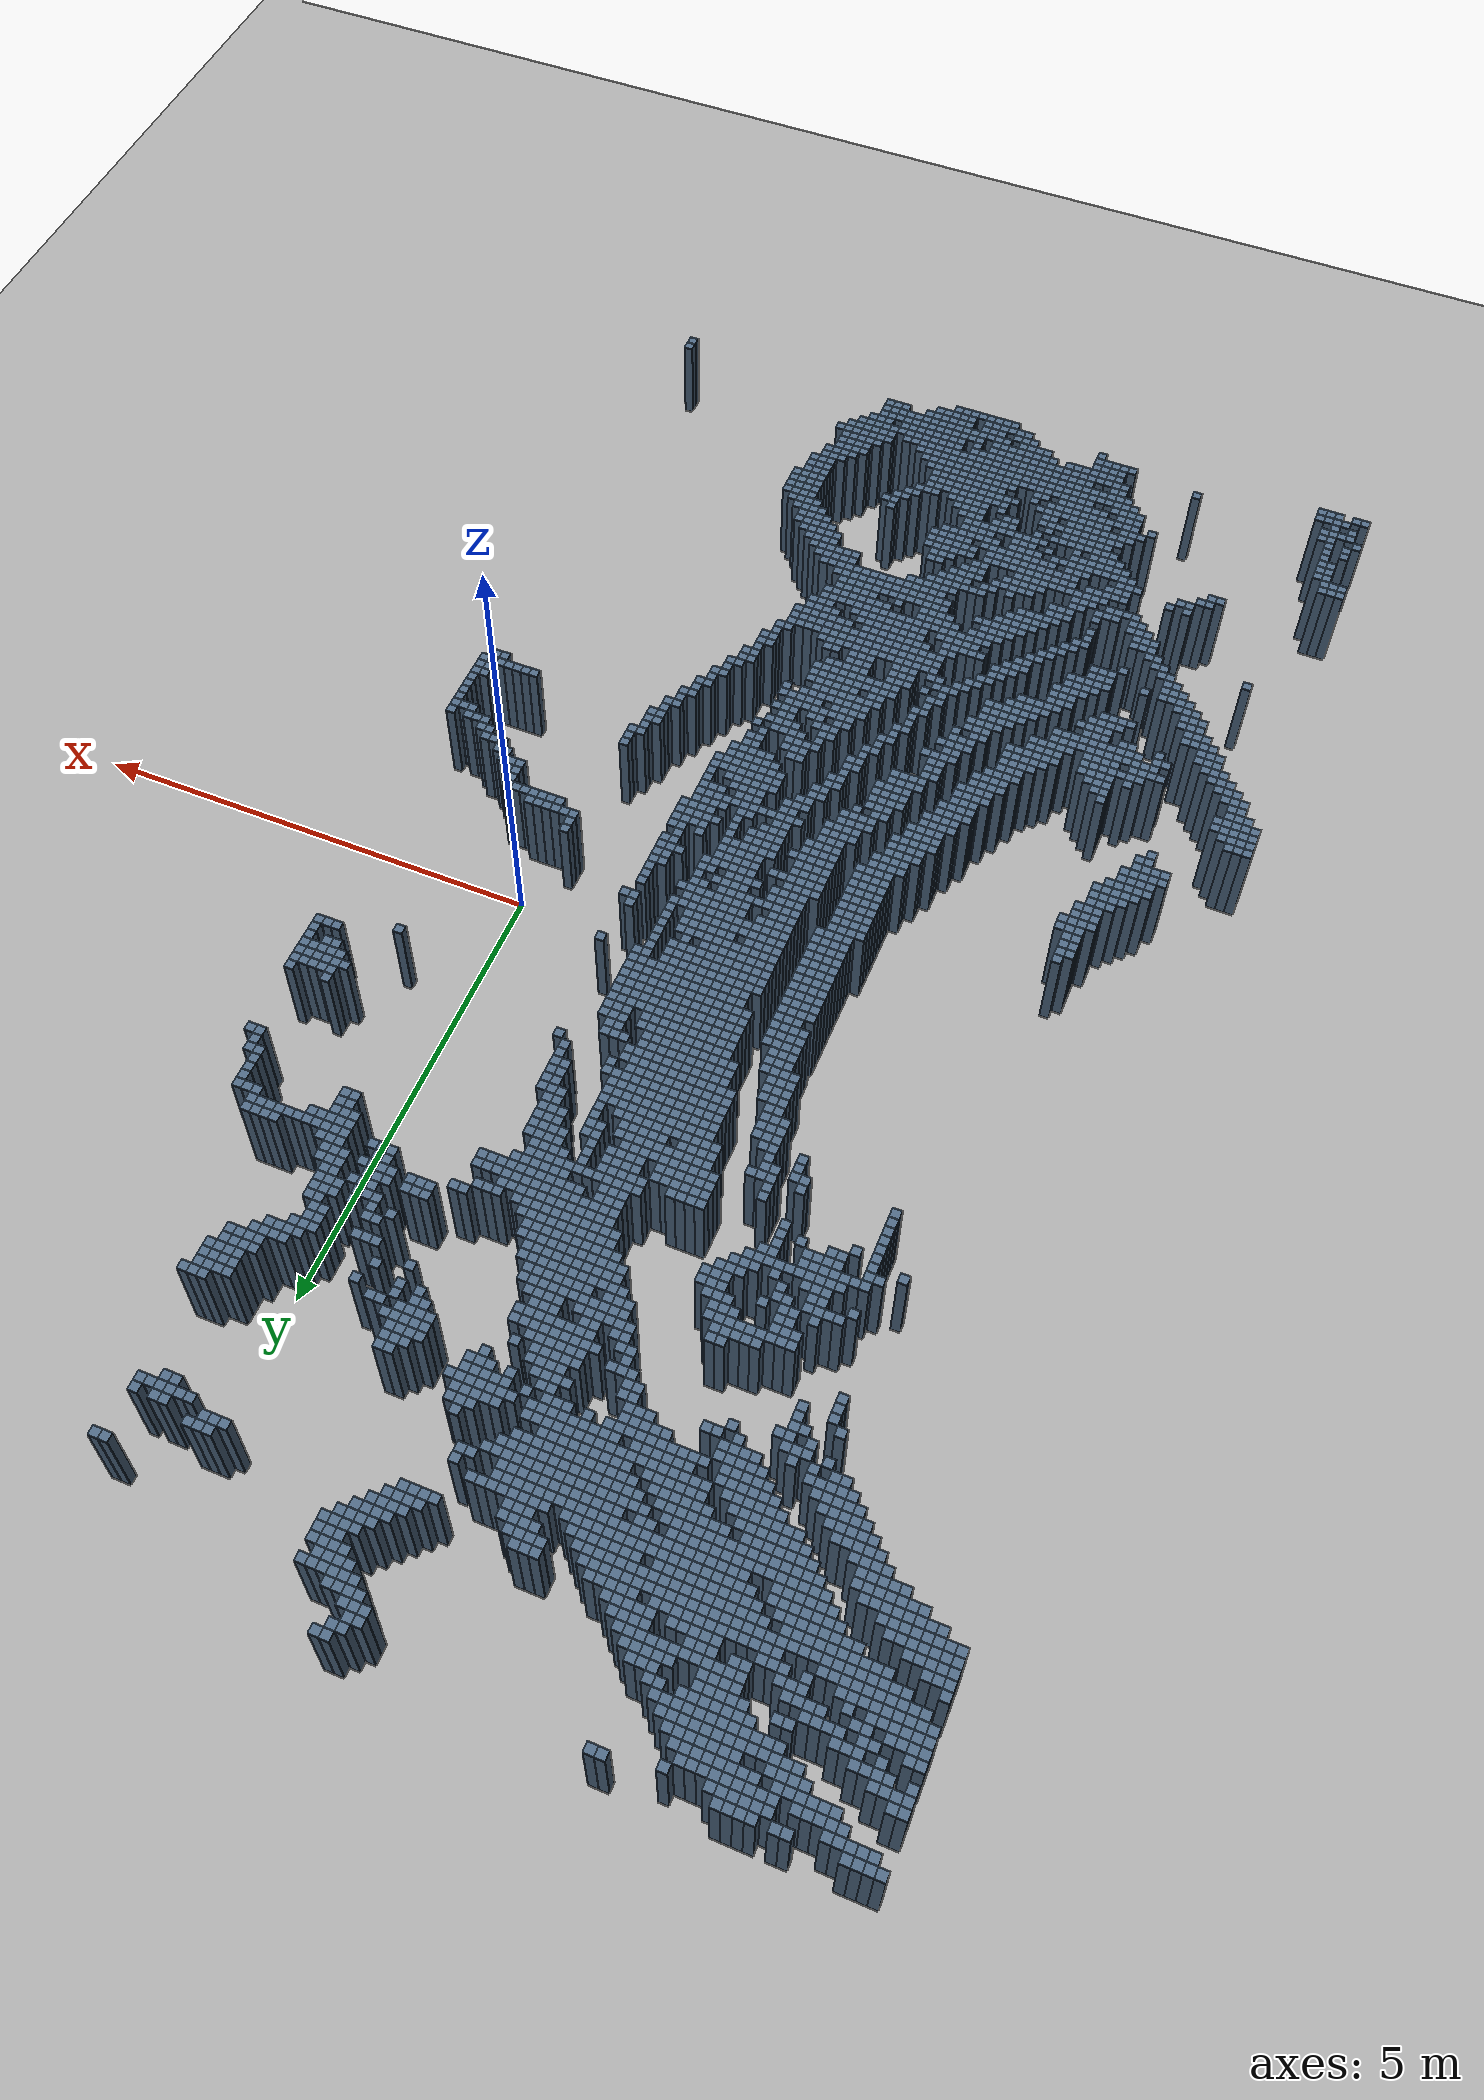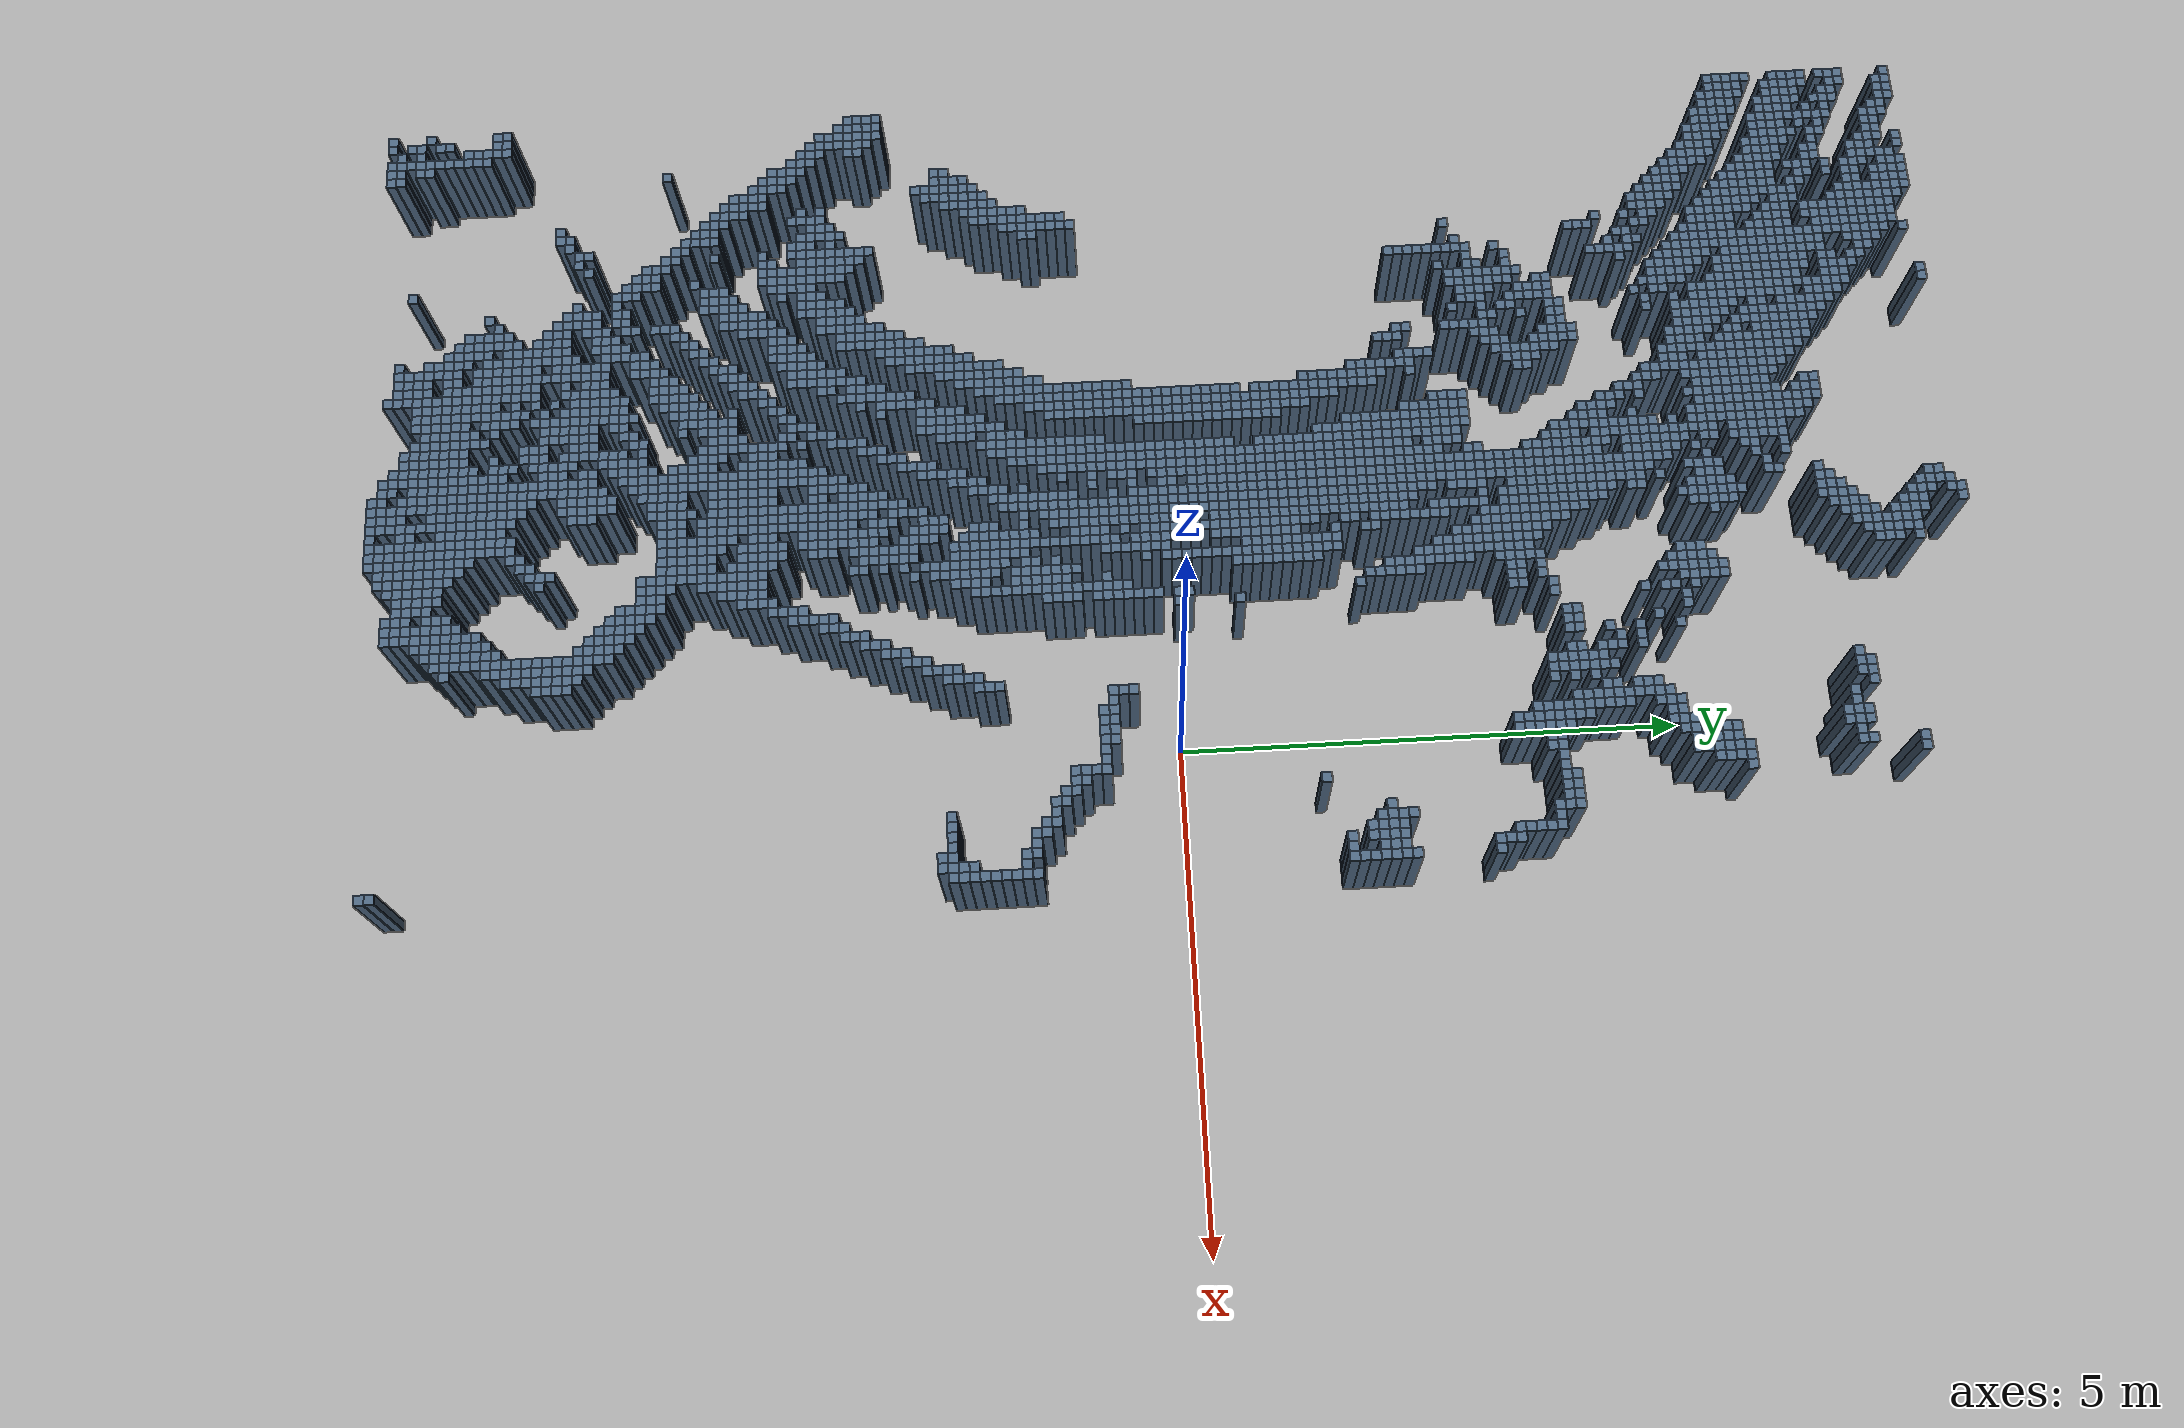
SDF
<sdf version="1.6">
 <world name="default">
  <gravity>0 0 -9.81</gravity>
  <physics name="default_physics" type="ode">
   <max_step_size>0.001</max_step_size>
   <real_time_update_rate>1000</real_time_update_rate>
  </physics>
  <scene><ambient>0.6 0.6 0.6 1</ambient><shadows>false</shadows></scene>
  <light name="sun" type="directional">
   <pose>0 0 10 0 0 0</pose>
   <diffuse>0.8 0.8 0.8 1</diffuse>
   <direction>-0.5 0.1 -1</direction>
  </light>
  <model name="artificial_flat_ground">
   <static>true</static>
   <link name="ground">
    <collision name="floor_collision">
     <geometry><plane><normal>0 0 1</normal><size>100 100</size></plane></geometry>
    </collision>
    <visual name="floor_visual">
     <geometry><plane><normal>0 0 1</normal><size>100 100</size></plane></geometry>
     <material><ambient>0.65 0.65 0.65 1</ambient><diffuse>0.65 0.65 0.65 1</diffuse></material>
    </visual>
   </link>
  </model>
  <model name="hilti_projected_cells">
   <static>true</static>
   <link name="obstacles">
    <collision name="cell_0_0_collision">
     <pose>-6.95000000 -7.95000000 0.50000000 0 0 0</pose>
     <geometry><box><size>0.10000000 0.10000000 1.00000000</size></box></geometry>
    </collision>
    <visual name="cell_0_0_visual">
     <pose>-6.95000000 -7.95000000 0.50000000 0 0 0</pose>
     <geometry><box><size>0.10000000 0.10000000 1.00000000</size></box></geometry>
     <material><ambient>0.3 0.4 0.5 1</ambient><diffuse>0.3 0.4 0.5 1</diffuse></material>
    </visual>
    <collision name="cell_0_1_collision">
     <pose>-6.85000000 -7.95000000 0.50000000 0 0 0</pose>
     <geometry><box><size>0.10000000 0.10000000 1.00000000</size></box></geometry>
    </collision>
    <visual name="cell_0_1_visual">
     <pose>-6.85000000 -7.95000000 0.50000000 0 0 0</pose>
     <geometry><box><size>0.10000000 0.10000000 1.00000000</size></box></geometry>
     <material><ambient>0.3 0.4 0.5 1</ambient><diffuse>0.3 0.4 0.5 1</diffuse></material>
    </visual>
    <collision name="cell_0_3_collision">
     <pose>-6.65000000 -7.95000000 0.50000000 0 0 0</pose>
     <geometry><box><size>0.10000000 0.10000000 1.00000000</size></box></geometry>
    </collision>
    <visual name="cell_0_3_visual">
     <pose>-6.65000000 -7.95000000 0.50000000 0 0 0</pose>
     <geometry><box><size>0.10000000 0.10000000 1.00000000</size></box></geometry>
     <material><ambient>0.3 0.4 0.5 1</ambient><diffuse>0.3 0.4 0.5 1</diffuse></material>
    </visual>
    <collision name="cell_0_4_collision">
     <pose>-6.55000000 -7.95000000 0.50000000 0 0 0</pose>
     <geometry><box><size>0.10000000 0.10000000 1.00000000</size></box></geometry>
    </collision>
    <visual name="cell_0_4_visual">
     <pose>-6.55000000 -7.95000000 0.50000000 0 0 0</pose>
     <geometry><box><size>0.10000000 0.10000000 1.00000000</size></box></geometry>
     <material><ambient>0.3 0.4 0.5 1</ambient><diffuse>0.3 0.4 0.5 1</diffuse></material>
    </visual>
    <collision name="cell_0_5_collision">
     <pose>-6.45000000 -7.95000000 0.50000000 0 0 0</pose>
     <geometry><box><size>0.10000000 0.10000000 1.00000000</size></box></geometry>
    </collision>
    <visual name="cell_0_5_visual">
     <pose>-6.45000000 -7.95000000 0.50000000 0 0 0</pose>
     <geometry><box><size>0.10000000 0.10000000 1.00000000</size></box></geometry>
     <material><ambient>0.3 0.4 0.5 1</ambient><diffuse>0.3 0.4 0.5 1</diffuse></material>
    </visual>
    <collision name="cell_0_42_collision">
     <pose>-2.75000000 -7.95000000 0.50000000 0 0 0</pose>
     <geometry><box><size>0.10000000 0.10000000 1.00000000</size></box></geometry>
    </collision>
    <visual name="cell_0_42_visual">
     <pose>-2.75000000 -7.95000000 0.50000000 0 0 0</pose>
     <geometry><box><size>0.10000000 0.10000000 1.00000000</size></box></geometry>
     <material><ambient>0.3 0.4 0.5 1</ambient><diffuse>0.3 0.4 0.5 1</diffuse></material>
    </visual>
    <collision name="cell_0_43_collision">
     <pose>-2.65000000 -7.95000000 0.50000000 0 0 0</pose>
     <geometry><box><size>0.10000000 0.10000000 1.00000000</size></box></geometry>
    </collision>
    <visual name="cell_0_43_visual">
     <pose>-2.65000000 -7.95000000 0.50000000 0 0 0</pose>
     <geometry><box><size>0.10000000 0.10000000 1.00000000</size></box></geometry>
     <material><ambient>0.3 0.4 0.5 1</ambient><diffuse>0.3 0.4 0.5 1</diffuse></material>
    </visual>
    <collision name="cell_0_44_collision">
     <pose>-2.55000000 -7.95000000 0.50000000 0 0 0</pose>
     <geometry><box><size>0.10000000 0.10000000 1.00000000</size></box></geometry>
    </collision>
    <visual name="cell_0_44_visual">
     <pose>-2.55000000 -7.95000000 0.50000000 0 0 0</pose>
     <geometry><box><size>0.10000000 0.10000000 1.00000000</size></box></geometry>
     <material><ambient>0.3 0.4 0.5 1</ambient><diffuse>0.3 0.4 0.5 1</diffuse></material>
    </visual>
    <collision name="cell_0_45_collision">
     <pose>-2.45000000 -7.95000000 0.50000000 0 0 0</pose>
     <geometry><box><size>0.10000000 0.10000000 1.00000000</size></box></geometry>
    </collision>
    <visual name="cell_0_45_visual">
     <pose>-2.45000000 -7.95000000 0.50000000 0 0 0</pose>
     <geometry><box><size>0.10000000 0.10000000 1.00000000</size></box></geometry>
     <material><ambient>0.3 0.4 0.5 1</ambient><diffuse>0.3 0.4 0.5 1</diffuse></material>
    </visual>
    <collision name="cell_0_46_collision">
     <pose>-2.35000000 -7.95000000 0.50000000 0 0 0</pose>
     <geometry><box><size>0.10000000 0.10000000 1.00000000</size></box></geometry>
    </collision>
    <visual name="cell_0_46_visual">
     <pose>-2.35000000 -7.95000000 0.50000000 0 0 0</pose>
     <geometry><box><size>0.10000000 0.10000000 1.00000000</size></box></geometry>
     <material><ambient>0.3 0.4 0.5 1</ambient><diffuse>0.3 0.4 0.5 1</diffuse></material>
    </visual>
    <collision name="cell_0_47_collision">
     <pose>-2.25000000 -7.95000000 0.50000000 0 0 0</pose>
     <geometry><box><size>0.10000000 0.10000000 1.00000000</size></box></geometry>
    </collision>
    <visual name="cell_0_47_visual">
     <pose>-2.25000000 -7.95000000 0.50000000 0 0 0</pose>
     <geometry><box><size>0.10000000 0.10000000 1.00000000</size></box></geometry>
     <material><ambient>0.3 0.4 0.5 1</ambient><diffuse>0.3 0.4 0.5 1</diffuse></material>
    </visual>
    <collision name="cell_0_48_collision">
     <pose>-2.15000000 -7.95000000 0.50000000 0 0 0</pose>
     <geometry><box><size>0.10000000 0.10000000 1.00000000</size></box></geometry>
    </collision>
    <visual name="cell_0_48_visual">
     <pose>-2.15000000 -7.95000000 0.50000000 0 0 0</pose>
     <geometry><box><size>0.10000000 0.10000000 1.00000000</size></box></geometry>
     <material><ambient>0.3 0.4 0.5 1</ambient><diffuse>0.3 0.4 0.5 1</diffuse></material>
    </visual>
    <collision name="cell_0_49_collision">
     <pose>-2.05000000 -7.95000000 0.50000000 0 0 0</pose>
     <geometry><box><size>0.10000000 0.10000000 1.00000000</size></box></geometry>
    </collision>
    <visual name="cell_0_49_visual">
     <pose>-2.05000000 -7.95000000 0.50000000 0 0 0</pose>
     <geometry><box><size>0.10000000 0.10000000 1.00000000</size></box></geometry>
     <material><ambient>0.3 0.4 0.5 1</ambient><diffuse>0.3 0.4 0.5 1</diffuse></material>
    </visual>
    <collision name="cell_1_2_collision">
     <pose>-6.75000000 -7.85000000 0.50000000 0 0 0</pose>
     <geometry><box><size>0.10000000 0.10000000 1.00000000</size></box></geometry>
    </collision>
    <visual name="cell_1_2_visual">
     <pose>-6.75000000 -7.85000000 0.50000000 0 0 0</pose>
     <geometry><box><size>0.10000000 0.10000000 1.00000000</size></box></geometry>
     <material><ambient>0.3 0.4 0.5 1</ambient><diffuse>0.3 0.4 0.5 1</diffuse></material>
    </visual>
    <collision name="cell_1_3_collision">
     <pose>-6.65000000 -7.85000000 0.50000000 0 0 0</pose>
     <geometry><box><size>0.10000000 0.10000000 1.00000000</size></box></geometry>
    </collision>
    <visual name="cell_1_3_visual">
     <pose>-6.65000000 -7.85000000 0.50000000 0 0 0</pose>
     <geometry><box><size>0.10000000 0.10000000 1.00000000</size></box></geometry>
     <material><ambient>0.3 0.4 0.5 1</ambient><diffuse>0.3 0.4 0.5 1</diffuse></material>
    </visual>
    <collision name="cell_1_4_collision">
     <pose>-6.55000000 -7.85000000 0.50000000 0 0 0</pose>
     <geometry><box><size>0.10000000 0.10000000 1.00000000</size></box></geometry>
    </collision>
    <visual name="cell_1_4_visual">
     <pose>-6.55000000 -7.85000000 0.50000000 0 0 0</pose>
     <geometry><box><size>0.10000000 0.10000000 1.00000000</size></box></geometry>
     <material><ambient>0.3 0.4 0.5 1</ambient><diffuse>0.3 0.4 0.5 1</diffuse></material>
    </visual>
    <collision name="cell_1_5_collision">
     <pose>-6.45000000 -7.85000000 0.50000000 0 0 0</pose>
     <geometry><box><size>0.10000000 0.10000000 1.00000000</size></box></geometry>
    </collision>
    <visual name="cell_1_5_visual">
     <pose>-6.45000000 -7.85000000 0.50000000 0 0 0</pose>
     <geometry><box><size>0.10000000 0.10000000 1.00000000</size></box></geometry>
     <material><ambient>0.3 0.4 0.5 1</ambient><diffuse>0.3 0.4 0.5 1</diffuse></material>
    </visual>
    <collision name="cell_1_31_collision">
     <pose>-3.85000000 -7.85000000 0.50000000 0 0 0</pose>
     <geometry><box><size>0.10000000 0.10000000 1.00000000</size></box></geometry>
    </collision>
    <visual name="cell_1_31_visual">
     <pose>-3.85000000 -7.85000000 0.50000000 0 0 0</pose>
     <geometry><box><size>0.10000000 0.10000000 1.00000000</size></box></geometry>
     <material><ambient>0.3 0.4 0.5 1</ambient><diffuse>0.3 0.4 0.5 1</diffuse></material>
    </visual>
    <collision name="cell_1_40_collision">
     <pose>-2.95000000 -7.85000000 0.50000000 0 0 0</pose>
     <geometry><box><size>0.10000000 0.10000000 1.00000000</size></box></geometry>
    </collision>
    <visual name="cell_1_40_visual">
     <pose>-2.95000000 -7.85000000 0.50000000 0 0 0</pose>
     <geometry><box><size>0.10000000 0.10000000 1.00000000</size></box></geometry>
     <material><ambient>0.3 0.4 0.5 1</ambient><diffuse>0.3 0.4 0.5 1</diffuse></material>
    </visual>
    <collision name="cell_1_41_collision">
     <pose>-2.85000000 -7.85000000 0.50000000 0 0 0</pose>
     <geometry><box><size>0.10000000 0.10000000 1.00000000</size></box></geometry>
    </collision>
    <visual name="cell_1_41_visual">
     <pose>-2.85000000 -7.85000000 0.50000000 0 0 0</pose>
     <geometry><box><size>0.10000000 0.10000000 1.00000000</size></box></geometry>
     <material><ambient>0.3 0.4 0.5 1</ambient><diffuse>0.3 0.4 0.5 1</diffuse></material>
    </visual>
    <collision name="cell_1_42_collision">
     <pose>-2.75000000 -7.85000000 0.50000000 0 0 0</pose>
     <geometry><box><size>0.10000000 0.10000000 1.00000000</size></box></geometry>
    </collision>
    <visual name="cell_1_42_visual">
     <pose>-2.75000000 -7.85000000 0.50000000 0 0 0</pose>
     <geometry><box><size>0.10000000 0.10000000 1.00000000</size></box></geometry>
     <material><ambient>0.3 0.4 0.5 1</ambient><diffuse>0.3 0.4 0.5 1</diffuse></material>
    </visual>
    <collision name="cell_1_43_collision">
     <pose>-2.65000000 -7.85000000 0.50000000 0 0 0</pose>
     <geometry><box><size>0.10000000 0.10000000 1.00000000</size></box></geometry>
    </collision>
    <visual name="cell_1_43_visual">
     <pose>-2.65000000 -7.85000000 0.50000000 0 0 0</pose>
     <geometry><box><size>0.10000000 0.10000000 1.00000000</size></box></geometry>
     <material><ambient>0.3 0.4 0.5 1</ambient><diffuse>0.3 0.4 0.5 1</diffuse></material>
    </visual>
    <collision name="cell_1_44_collision">
     <pose>-2.55000000 -7.85000000 0.50000000 0 0 0</pose>
     <geometry><box><size>0.10000000 0.10000000 1.00000000</size></box></geometry>
    </collision>
    <visual name="cell_1_44_visual">
     <pose>-2.55000000 -7.85000000 0.50000000 0 0 0</pose>
     <geometry><box><size>0.10000000 0.10000000 1.00000000</size></box></geometry>
     <material><ambient>0.3 0.4 0.5 1</ambient><diffuse>0.3 0.4 0.5 1</diffuse></material>
    </visual>
    <collision name="cell_1_45_collision">
     <pose>-2.45000000 -7.85000000 0.50000000 0 0 0</pose>
     <geometry><box><size>0.10000000 0.10000000 1.00000000</size></box></geometry>
    </collision>
    <visual name="cell_1_45_visual">
     <pose>-2.45000000 -7.85000000 0.50000000 0 0 0</pose>
     <geometry><box><size>0.10000000 0.10000000 1.00000000</size></box></geometry>
     <material><ambient>0.3 0.4 0.5 1</ambient><diffuse>0.3 0.4 0.5 1</diffuse></material>
    </visual>
    <collision name="cell_1_47_collision">
     <pose>-2.25000000 -7.85000000 0.50000000 0 0 0</pose>
     <geometry><box><size>0.10000000 0.10000000 1.00000000</size></box></geometry>
    </collision>
    <visual name="cell_1_47_visual">
     <pose>-2.25000000 -7.85000000 0.50000000 0 0 0</pose>
     <geometry><box><size>0.10000000 0.10000000 1.00000000</size></box></geometry>
     <material><ambient>0.3 0.4 0.5 1</ambient><diffuse>0.3 0.4 0.5 1</diffuse></material>
    </visual>
    <collision name="cell_1_48_collision">
     <pose>-2.15000000 -7.85000000 0.50000000 0 0 0</pose>
     <geometry><box><size>0.10000000 0.10000000 1.00000000</size></box></geometry>
    </collision>
    <visual name="cell_1_48_visual">
     <pose>-2.15000000 -7.85000000 0.50000000 0 0 0</pose>
     <geometry><box><size>0.10000000 0.10000000 1.00000000</size></box></geometry>
     <material><ambient>0.3 0.4 0.5 1</ambient><diffuse>0.3 0.4 0.5 1</diffuse></material>
    </visual>
    <collision name="cell_1_49_collision">
     <pose>-2.05000000 -7.85000000 0.50000000 0 0 0</pose>
     <geometry><box><size>0.10000000 0.10000000 1.00000000</size></box></geometry>
    </collision>
    <visual name="cell_1_49_visual">
     <pose>-2.05000000 -7.85000000 0.50000000 0 0 0</pose>
     <geometry><box><size>0.10000000 0.10000000 1.00000000</size></box></geometry>
     <material><ambient>0.3 0.4 0.5 1</ambient><diffuse>0.3 0.4 0.5 1</diffuse></material>
    </visual>
    <collision name="cell_1_50_collision">
     <pose>-1.95000000 -7.85000000 0.50000000 0 0 0</pose>
     <geometry><box><size>0.10000000 0.10000000 1.00000000</size></box></geometry>
    </collision>
    <visual name="cell_1_50_visual">
     <pose>-1.95000000 -7.85000000 0.50000000 0 0 0</pose>
     <geometry><box><size>0.10000000 0.10000000 1.00000000</size></box></geometry>
     <material><ambient>0.3 0.4 0.5 1</ambient><diffuse>0.3 0.4 0.5 1</diffuse></material>
    </visual>
    <collision name="cell_1_51_collision">
     <pose>-1.85000000 -7.85000000 0.50000000 0 0 0</pose>
     <geometry><box><size>0.10000000 0.10000000 1.00000000</size></box></geometry>
    </collision>
    <visual name="cell_1_51_visual">
     <pose>-1.85000000 -7.85000000 0.50000000 0 0 0</pose>
     <geometry><box><size>0.10000000 0.10000000 1.00000000</size></box></geometry>
     <material><ambient>0.3 0.4 0.5 1</ambient><diffuse>0.3 0.4 0.5 1</diffuse></material>
    </visual>
    <collision name="cell_1_83_collision">
     <pose>1.35000000 -7.85000000 0.50000000 0 0 0</pose>
     <geometry><box><size>0.10000000 0.10000000 1.00000000</size></box></geometry>
    </collision>
    <visual name="cell_1_83_visual">
     <pose>1.35000000 -7.85000000 0.50000000 0 0 0</pose>
     <geometry><box><size>0.10000000 0.10000000 1.00000000</size></box></geometry>
     <material><ambient>0.3 0.4 0.5 1</ambient><diffuse>0.3 0.4 0.5 1</diffuse></material>
    </visual>
    <collision name="cell_2_1_collision">
     <pose>-6.85000000 -7.75000000 0.50000000 0 0 0</pose>
     <geometry><box><size>0.10000000 0.10000000 1.00000000</size></box></geometry>
    </collision>
    <visual name="cell_2_1_visual">
     <pose>-6.85000000 -7.75000000 0.50000000 0 0 0</pose>
     <geometry><box><size>0.10000000 0.10000000 1.00000000</size></box></geometry>
     <material><ambient>0.3 0.4 0.5 1</ambient><diffuse>0.3 0.4 0.5 1</diffuse></material>
    </visual>
    <collision name="cell_2_3_collision">
     <pose>-6.65000000 -7.75000000 0.50000000 0 0 0</pose>
     <geometry><box><size>0.10000000 0.10000000 1.00000000</size></box></geometry>
    </collision>
    <visual name="cell_2_3_visual">
     <pose>-6.65000000 -7.75000000 0.50000000 0 0 0</pose>
     <geometry><box><size>0.10000000 0.10000000 1.00000000</size></box></geometry>
     <material><ambient>0.3 0.4 0.5 1</ambient><diffuse>0.3 0.4 0.5 1</diffuse></material>
    </visual>
    <collision name="cell_2_27_collision">
     <pose>-4.25000000 -7.75000000 0.50000000 0 0 0</pose>
     <geometry><box><size>0.10000000 0.10000000 1.00000000</size></box></geometry>
    </collision>
    <visual name="cell_2_27_visual">
     <pose>-4.25000000 -7.75000000 0.50000000 0 0 0</pose>
     <geometry><box><size>0.10000000 0.10000000 1.00000000</size></box></geometry>
     <material><ambient>0.3 0.4 0.5 1</ambient><diffuse>0.3 0.4 0.5 1</diffuse></material>
    </visual>
    <collision name="cell_2_28_collision">
     <pose>-4.15000000 -7.75000000 0.50000000 0 0 0</pose>
     <geometry><box><size>0.10000000 0.10000000 1.00000000</size></box></geometry>
    </collision>
    <visual name="cell_2_28_visual">
     <pose>-4.15000000 -7.75000000 0.50000000 0 0 0</pose>
     <geometry><box><size>0.10000000 0.10000000 1.00000000</size></box></geometry>
     <material><ambient>0.3 0.4 0.5 1</ambient><diffuse>0.3 0.4 0.5 1</diffuse></material>
    </visual>
    <collision name="cell_2_29_collision">
     <pose>-4.05000000 -7.75000000 0.50000000 0 0 0</pose>
     <geometry><box><size>0.10000000 0.10000000 1.00000000</size></box></geometry>
    </collision>
    <visual name="cell_2_29_visual">
     <pose>-4.05000000 -7.75000000 0.50000000 0 0 0</pose>
     <geometry><box><size>0.10000000 0.10000000 1.00000000</size></box></geometry>
     <material><ambient>0.3 0.4 0.5 1</ambient><diffuse>0.3 0.4 0.5 1</diffuse></material>
    </visual>
    <collision name="cell_2_30_collision">
     <pose>-3.95000000 -7.75000000 0.50000000 0 0 0</pose>
     <geometry><box><size>0.10000000 0.10000000 1.00000000</size></box></geometry>
    </collision>
    <visual name="cell_2_30_visual">
     <pose>-3.95000000 -7.75000000 0.50000000 0 0 0</pose>
     <geometry><box><size>0.10000000 0.10000000 1.00000000</size></box></geometry>
     <material><ambient>0.3 0.4 0.5 1</ambient><diffuse>0.3 0.4 0.5 1</diffuse></material>
    </visual>
    <collision name="cell_2_31_collision">
     <pose>-3.85000000 -7.75000000 0.50000000 0 0 0</pose>
     <geometry><box><size>0.10000000 0.10000000 1.00000000</size></box></geometry>
    </collision>
    <visual name="cell_2_31_visual">
     <pose>-3.85000000 -7.75000000 0.50000000 0 0 0</pose>
     <geometry><box><size>0.10000000 0.10000000 1.00000000</size></box></geometry>
     <material><ambient>0.3 0.4 0.5 1</ambient><diffuse>0.3 0.4 0.5 1</diffuse></material>
    </visual>
    <collision name="cell_2_39_collision">
     <pose>-3.05000000 -7.75000000 0.50000000 0 0 0</pose>
     <geometry><box><size>0.10000000 0.10000000 1.00000000</size></box></geometry>
    </collision>
    <visual name="cell_2_39_visual">
     <pose>-3.05000000 -7.75000000 0.50000000 0 0 0</pose>
     <geometry><box><size>0.10000000 0.10000000 1.00000000</size></box></geometry>
     <material><ambient>0.3 0.4 0.5 1</ambient><diffuse>0.3 0.4 0.5 1</diffuse></material>
    </visual>
    <collision name="cell_2_40_collision">
     <pose>-2.95000000 -7.75000000 0.50000000 0 0 0</pose>
     <geometry><box><size>0.10000000 0.10000000 1.00000000</size></box></geometry>
    </collision>
    <visual name="cell_2_40_visual">
     <pose>-2.95000000 -7.75000000 0.50000000 0 0 0</pose>
     <geometry><box><size>0.10000000 0.10000000 1.00000000</size></box></geometry>
     <material><ambient>0.3 0.4 0.5 1</ambient><diffuse>0.3 0.4 0.5 1</diffuse></material>
    </visual>
    <collision name="cell_2_41_collision">
     <pose>-2.85000000 -7.75000000 0.50000000 0 0 0</pose>
     <geometry><box><size>0.10000000 0.10000000 1.00000000</size></box></geometry>
    </collision>
    <visual name="cell_2_41_visual">
     <pose>-2.85000000 -7.75000000 0.50000000 0 0 0</pose>
     <geometry><box><size>0.10000000 0.10000000 1.00000000</size></box></geometry>
     <material><ambient>0.3 0.4 0.5 1</ambient><diffuse>0.3 0.4 0.5 1</diffuse></material>
    </visual>
    <collision name="cell_2_43_collision">
     <pose>-2.65000000 -7.75000000 0.50000000 0 0 0</pose>
     <geometry><box><size>0.10000000 0.10000000 1.00000000</size></box></geometry>
    </collision>
    <visual name="cell_2_43_visual">
     <pose>-2.65000000 -7.75000000 0.50000000 0 0 0</pose>
     <geometry><box><size>0.10000000 0.10000000 1.00000000</size></box></geometry>
     <material><ambient>0.3 0.4 0.5 1</ambient><diffuse>0.3 0.4 0.5 1</diffuse></material>
    </visual>
    <collision name="cell_2_44_collision">
     <pose>-2.55000000 -7.75000000 0.50000000 0 0 0</pose>
     <geometry><box><size>0.10000000 0.10000000 1.00000000</size></box></geometry>
    </collision>
    <visual name="cell_2_44_visual">
     <pose>-2.55000000 -7.75000000 0.50000000 0 0 0</pose>
     <geometry><box><size>0.10000000 0.10000000 1.00000000</size></box></geometry>
     <material><ambient>0.3 0.4 0.5 1</ambient><diffuse>0.3 0.4 0.5 1</diffuse></material>
    </visual>
    <collision name="cell_2_45_collision">
     <pose>-2.45000000 -7.75000000 0.50000000 0 0 0</pose>
     <geometry><box><size>0.10000000 0.10000000 1.00000000</size></box></geometry>
    </collision>
    <visual name="cell_2_45_visual">
     <pose>-2.45000000 -7.75000000 0.50000000 0 0 0</pose>
     <geometry><box><size>0.10000000 0.10000000 1.00000000</size></box></geometry>
     <material><ambient>0.3 0.4 0.5 1</ambient><diffuse>0.3 0.4 0.5 1</diffuse></material>
    </visual>
    <collision name="cell_2_47_collision">
     <pose>-2.25000000 -7.75000000 0.50000000 0 0 0</pose>
     <geometry><box><size>0.10000000 0.10000000 1.00000000</size></box></geometry>
    </collision>
    <visual name="cell_2_47_visual">
     <pose>-2.25000000 -7.75000000 0.50000000 0 0 0</pose>
     <geometry><box><size>0.10000000 0.10000000 1.00000000</size></box></geometry>
     <material><ambient>0.3 0.4 0.5 1</ambient><diffuse>0.3 0.4 0.5 1</diffuse></material>
    </visual>
    <collision name="cell_2_48_collision">
     <pose>-2.15000000 -7.75000000 0.50000000 0 0 0</pose>
     <geometry><box><size>0.10000000 0.10000000 1.00000000</size></box></geometry>
    </collision>
    <visual name="cell_2_48_visual">
     <pose>-2.15000000 -7.75000000 0.50000000 0 0 0</pose>
     <geometry><box><size>0.10000000 0.10000000 1.00000000</size></box></geometry>
     <material><ambient>0.3 0.4 0.5 1</ambient><diffuse>0.3 0.4 0.5 1</diffuse></material>
    </visual>
    <collision name="cell_2_49_collision">
     <pose>-2.05000000 -7.75000000 0.50000000 0 0 0</pose>
     <geometry><box><size>0.10000000 0.10000000 1.00000000</size></box></geometry>
    </collision>
    <visual name="cell_2_49_visual">
     <pose>-2.05000000 -7.75000000 0.50000000 0 0 0</pose>
     <geometry><box><size>0.10000000 0.10000000 1.00000000</size></box></geometry>
     <material><ambient>0.3 0.4 0.5 1</ambient><diffuse>0.3 0.4 0.5 1</diffuse></material>
    </visual>
    <collision name="cell_2_50_collision">
     <pose>-1.95000000 -7.75000000 0.50000000 0 0 0</pose>
     <geometry><box><size>0.10000000 0.10000000 1.00000000</size></box></geometry>
    </collision>
    <visual name="cell_2_50_visual">
     <pose>-1.95000000 -7.75000000 0.50000000 0 0 0</pose>
     <geometry><box><size>0.10000000 0.10000000 1.00000000</size></box></geometry>
     <material><ambient>0.3 0.4 0.5 1</ambient><diffuse>0.3 0.4 0.5 1</diffuse></material>
    </visual>
    <collision name="cell_2_51_collision">
     <pose>-1.85000000 -7.75000000 0.50000000 0 0 0</pose>
     <geometry><box><size>0.10000000 0.10000000 1.00000000</size></box></geometry>
    </collision>
    <visual name="cell_2_51_visual">
     <pose>-1.85000000 -7.75000000 0.50000000 0 0 0</pose>
     <geometry><box><size>0.10000000 0.10000000 1.00000000</size></box></geometry>
     <material><ambient>0.3 0.4 0.5 1</ambient><diffuse>0.3 0.4 0.5 1</diffuse></material>
    </visual>
    <collision name="cell_2_52_collision">
     <pose>-1.75000000 -7.75000000 0.50000000 0 0 0</pose>
     <geometry><box><size>0.10000000 0.10000000 1.00000000</size></box></geometry>
    </collision>
    <visual name="cell_2_52_visual">
     <pose>-1.75000000 -7.75000000 0.50000000 0 0 0</pose>
     <geometry><box><size>0.10000000 0.10000000 1.00000000</size></box></geometry>
     <material><ambient>0.3 0.4 0.5 1</ambient><diffuse>0.3 0.4 0.5 1</diffuse></material>
    </visual>
    <collision name="cell_2_55_collision">
     <pose>-1.45000000 -7.75000000 0.50000000 0 0 0</pose>
     <geometry><box><size>0.10000000 0.10000000 1.00000000</size></box></geometry>
    </collision>
    <visual name="cell_2_55_visual">
     <pose>-1.45000000 -7.75000000 0.50000000 0 0 0</pose>
     <geometry><box><size>0.10000000 0.10000000 1.00000000</size></box></geometry>
     <material><ambient>0.3 0.4 0.5 1</ambient><diffuse>0.3 0.4 0.5 1</diffuse></material>
    </visual>
    <collision name="cell_2_56_collision">
     <pose>-1.35000000 -7.75000000 0.50000000 0 0 0</pose>
     <geometry><box><size>0.10000000 0.10000000 1.00000000</size></box></geometry>
    </collision>
    <visual name="cell_2_56_visual">
     <pose>-1.35000000 -7.75000000 0.50000000 0 0 0</pose>
     <geometry><box><size>0.10000000 0.10000000 1.00000000</size></box></geometry>
     <material><ambient>0.3 0.4 0.5 1</ambient><diffuse>0.3 0.4 0.5 1</diffuse></material>
    </visual>
    <collision name="cell_2_57_collision">
     <pose>-1.25000000 -7.75000000 0.50000000 0 0 0</pose>
     <geometry><box><size>0.10000000 0.10000000 1.00000000</size></box></geometry>
    </collision>
    <visual name="cell_2_57_visual">
     <pose>-1.25000000 -7.75000000 0.50000000 0 0 0</pose>
     <geometry><box><size>0.10000000 0.10000000 1.00000000</size></box></geometry>
     <material><ambient>0.3 0.4 0.5 1</ambient><diffuse>0.3 0.4 0.5 1</diffuse></material>
    </visual>
    <collision name="cell_2_83_collision">
     <pose>1.35000000 -7.75000000 0.50000000 0 0 0</pose>
     <geometry><box><size>0.10000000 0.10000000 1.00000000</size></box></geometry>
    </collision>
    <visual name="cell_2_83_visual">
     <pose>1.35000000 -7.75000000 0.50000000 0 0 0</pose>
     <geometry><box><size>0.10000000 0.10000000 1.00000000</size></box></geometry>
     <material><ambient>0.3 0.4 0.5 1</ambient><diffuse>0.3 0.4 0.5 1</diffuse></material>
    </visual>
    <collision name="cell_3_1_collision">
     <pose>-6.85000000 -7.65000000 0.50000000 0 0 0</pose>
     <geometry><box><size>0.10000000 0.10000000 1.00000000</size></box></geometry>
    </collision>
    <visual name="cell_3_1_visual">
     <pose>-6.85000000 -7.65000000 0.50000000 0 0 0</pose>
     <geometry><box><size>0.10000000 0.10000000 1.00000000</size></box></geometry>
     <material><ambient>0.3 0.4 0.5 1</ambient><diffuse>0.3 0.4 0.5 1</diffuse></material>
    </visual>
    <collision name="cell_3_2_collision">
     <pose>-6.75000000 -7.65000000 0.50000000 0 0 0</pose>
     <geometry><box><size>0.10000000 0.10000000 1.00000000</size></box></geometry>
    </collision>
    <visual name="cell_3_2_visual">
     <pose>-6.75000000 -7.65000000 0.50000000 0 0 0</pose>
     <geometry><box><size>0.10000000 0.10000000 1.00000000</size></box></geometry>
     <material><ambient>0.3 0.4 0.5 1</ambient><diffuse>0.3 0.4 0.5 1</diffuse></material>
    </visual>
    <collision name="cell_3_3_collision">
     <pose>-6.65000000 -7.65000000 0.50000000 0 0 0</pose>
     <geometry><box><size>0.10000000 0.10000000 1.00000000</size></box></geometry>
    </collision>
    <visual name="cell_3_3_visual">
     <pose>-6.65000000 -7.65000000 0.50000000 0 0 0</pose>
     <geometry><box><size>0.10000000 0.10000000 1.00000000</size></box></geometry>
     <material><ambient>0.3 0.4 0.5 1</ambient><diffuse>0.3 0.4 0.5 1</diffuse></material>
    </visual>
    <collision name="cell_3_4_collision">
     <pose>-6.55000000 -7.65000000 0.50000000 0 0 0</pose>
     <geometry><box><size>0.10000000 0.10000000 1.00000000</size></box></geometry>
    </collision>
    <visual name="cell_3_4_visual">
     <pose>-6.55000000 -7.65000000 0.50000000 0 0 0</pose>
     <geometry><box><size>0.10000000 0.10000000 1.00000000</size></box></geometry>
     <material><ambient>0.3 0.4 0.5 1</ambient><diffuse>0.3 0.4 0.5 1</diffuse></material>
    </visual>
    <collision name="cell_3_19_collision">
     <pose>-5.05000000 -7.65000000 0.50000000 0 0 0</pose>
     <geometry><box><size>0.10000000 0.10000000 1.00000000</size></box></geometry>
    </collision>
    <visual name="cell_3_19_visual">
     <pose>-5.05000000 -7.65000000 0.50000000 0 0 0</pose>
     <geometry><box><size>0.10000000 0.10000000 1.00000000</size></box></geometry>
     <material><ambient>0.3 0.4 0.5 1</ambient><diffuse>0.3 0.4 0.5 1</diffuse></material>
    </visual>
    <collision name="cell_3_28_collision">
     <pose>-4.15000000 -7.65000000 0.50000000 0 0 0</pose>
     <geometry><box><size>0.10000000 0.10000000 1.00000000</size></box></geometry>
    </collision>
    <visual name="cell_3_28_visual">
     <pose>-4.15000000 -7.65000000 0.50000000 0 0 0</pose>
     <geometry><box><size>0.10000000 0.10000000 1.00000000</size></box></geometry>
     <material><ambient>0.3 0.4 0.5 1</ambient><diffuse>0.3 0.4 0.5 1</diffuse></material>
    </visual>
    <collision name="cell_3_29_collision">
     <pose>-4.05000000 -7.65000000 0.50000000 0 0 0</pose>
     <geometry><box><size>0.10000000 0.10000000 1.00000000</size></box></geometry>
    </collision>
    <visual name="cell_3_29_visual">
     <pose>-4.05000000 -7.65000000 0.50000000 0 0 0</pose>
     <geometry><box><size>0.10000000 0.10000000 1.00000000</size></box></geometry>
     <material><ambient>0.3 0.4 0.5 1</ambient><diffuse>0.3 0.4 0.5 1</diffuse></material>
    </visual>
    <collision name="cell_3_30_collision">
     <pose>-3.95000000 -7.65000000 0.50000000 0 0 0</pose>
     <geometry><box><size>0.10000000 0.10000000 1.00000000</size></box></geometry>
    </collision>
    <visual name="cell_3_30_visual">
     <pose>-3.95000000 -7.65000000 0.50000000 0 0 0</pose>
     <geometry><box><size>0.10000000 0.10000000 1.00000000</size></box></geometry>
     <material><ambient>0.3 0.4 0.5 1</ambient><diffuse>0.3 0.4 0.5 1</diffuse></material>
    </visual>
    <collision name="cell_3_31_collision">
     <pose>-3.85000000 -7.65000000 0.50000000 0 0 0</pose>
     <geometry><box><size>0.10000000 0.10000000 1.00000000</size></box></geometry>
    </collision>
    <visual name="cell_3_31_visual">
     <pose>-3.85000000 -7.65000000 0.50000000 0 0 0</pose>
     <geometry><box><size>0.10000000 0.10000000 1.00000000</size></box></geometry>
     <material><ambient>0.3 0.4 0.5 1</ambient><diffuse>0.3 0.4 0.5 1</diffuse></material>
    </visual>
    <collision name="cell_3_37_collision">
     <pose>-3.25000000 -7.65000000 0.50000000 0 0 0</pose>
     <geometry><box><size>0.10000000 0.10000000 1.00000000</size></box></geometry>
    </collision>
    <visual name="cell_3_37_visual">
     <pose>-3.25000000 -7.65000000 0.50000000 0 0 0</pose>
     <geometry><box><size>0.10000000 0.10000000 1.00000000</size></box></geometry>
     <material><ambient>0.3 0.4 0.5 1</ambient><diffuse>0.3 0.4 0.5 1</diffuse></material>
    </visual>
    <collision name="cell_3_38_collision">
     <pose>-3.15000000 -7.65000000 0.50000000 0 0 0</pose>
     <geometry><box><size>0.10000000 0.10000000 1.00000000</size></box></geometry>
    </collision>
    <visual name="cell_3_38_visual">
     <pose>-3.15000000 -7.65000000 0.50000000 0 0 0</pose>
     <geometry><box><size>0.10000000 0.10000000 1.00000000</size></box></geometry>
     <material><ambient>0.3 0.4 0.5 1</ambient><diffuse>0.3 0.4 0.5 1</diffuse></material>
    </visual>
    <collision name="cell_3_39_collision">
     <pose>-3.05000000 -7.65000000 0.50000000 0 0 0</pose>
     <geometry><box><size>0.10000000 0.10000000 1.00000000</size></box></geometry>
    </collision>
    <visual name="cell_3_39_visual">
     <pose>-3.05000000 -7.65000000 0.50000000 0 0 0</pose>
     <geometry><box><size>0.10000000 0.10000000 1.00000000</size></box></geometry>
     <material><ambient>0.3 0.4 0.5 1</ambient><diffuse>0.3 0.4 0.5 1</diffuse></material>
    </visual>
    <collision name="cell_3_40_collision">
     <pose>-2.95000000 -7.65000000 0.50000000 0 0 0</pose>
     <geometry><box><size>0.10000000 0.10000000 1.00000000</size></box></geometry>
    </collision>
    <visual name="cell_3_40_visual">
     <pose>-2.95000000 -7.65000000 0.50000000 0 0 0</pose>
     <geometry><box><size>0.10000000 0.10000000 1.00000000</size></box></geometry>
     <material><ambient>0.3 0.4 0.5 1</ambient><diffuse>0.3 0.4 0.5 1</diffuse></material>
    </visual>
    <collision name="cell_3_42_collision">
     <pose>-2.75000000 -7.65000000 0.50000000 0 0 0</pose>
     <geometry><box><size>0.10000000 0.10000000 1.00000000</size></box></geometry>
    </collision>
    <visual name="cell_3_42_visual">
     <pose>-2.75000000 -7.65000000 0.50000000 0 0 0</pose>
     <geometry><box><size>0.10000000 0.10000000 1.00000000</size></box></geometry>
     <material><ambient>0.3 0.4 0.5 1</ambient><diffuse>0.3 0.4 0.5 1</diffuse></material>
    </visual>
    <collision name="cell_3_43_collision">
     <pose>-2.65000000 -7.65000000 0.50000000 0 0 0</pose>
     <geometry><box><size>0.10000000 0.10000000 1.00000000</size></box></geometry>
    </collision>
    <visual name="cell_3_43_visual">
     <pose>-2.65000000 -7.65000000 0.50000000 0 0 0</pose>
     <geometry><box><size>0.10000000 0.10000000 1.00000000</size></box></geometry>
     <material><ambient>0.3 0.4 0.5 1</ambient><diffuse>0.3 0.4 0.5 1</diffuse></material>
    </visual>
    <collision name="cell_3_44_collision">
     <pose>-2.55000000 -7.65000000 0.50000000 0 0 0</pose>
     <geometry><box><size>0.10000000 0.10000000 1.00000000</size></box></geometry>
    </collision>
    <visual name="cell_3_44_visual">
     <pose>-2.55000000 -7.65000000 0.50000000 0 0 0</pose>
     <geometry><box><size>0.10000000 0.10000000 1.00000000</size></box></geometry>
     <material><ambient>0.3 0.4 0.5 1</ambient><diffuse>0.3 0.4 0.5 1</diffuse></material>
    </visual>
    <collision name="cell_3_45_collision">
     <pose>-2.45000000 -7.65000000 0.50000000 0 0 0</pose>
     <geometry><box><size>0.10000000 0.10000000 1.00000000</size></box></geometry>
    </collision>
    <visual name="cell_3_45_visual">
     <pose>-2.45000000 -7.65000000 0.50000000 0 0 0</pose>
     <geometry><box><size>0.10000000 0.10000000 1.00000000</size></box></geometry>
     <material><ambient>0.3 0.4 0.5 1</ambient><diffuse>0.3 0.4 0.5 1</diffuse></material>
    </visual>
    <collision name="cell_3_46_collision">
     <pose>-2.35000000 -7.65000000 0.50000000 0 0 0</pose>
     <geometry><box><size>0.10000000 0.10000000 1.00000000</size></box></geometry>
    </collision>
    <visual name="cell_3_46_visual">
     <pose>-2.35000000 -7.65000000 0.50000000 0 0 0</pose>
     <geometry><box><size>0.10000000 0.10000000 1.00000000</size></box></geometry>
     <material><ambient>0.3 0.4 0.5 1</ambient><diffuse>0.3 0.4 0.5 1</diffuse></material>
    </visual>
    <collision name="cell_3_47_collision">
     <pose>-2.25000000 -7.65000000 0.50000000 0 0 0</pose>
     <geometry><box><size>0.10000000 0.10000000 1.00000000</size></box></geometry>
    </collision>
    <visual name="cell_3_47_visual">
     <pose>-2.25000000 -7.65000000 0.50000000 0 0 0</pose>
     <geometry><box><size>0.10000000 0.10000000 1.00000000</size></box></geometry>
     <material><ambient>0.3 0.4 0.5 1</ambient><diffuse>0.3 0.4 0.5 1</diffuse></material>
    </visual>
    <collision name="cell_3_48_collision">
     <pose>-2.15000000 -7.65000000 0.50000000 0 0 0</pose>
     <geometry><box><size>0.10000000 0.10000000 1.00000000</size></box></geometry>
    </collision>
    <visual name="cell_3_48_visual">
     <pose>-2.15000000 -7.65000000 0.50000000 0 0 0</pose>
     <geometry><box><size>0.10000000 0.10000000 1.00000000</size></box></geometry>
     <material><ambient>0.3 0.4 0.5 1</ambient><diffuse>0.3 0.4 0.5 1</diffuse></material>
    </visual>
    <collision name="cell_3_49_collision">
     <pose>-2.05000000 -7.65000000 0.50000000 0 0 0</pose>
     <geometry><box><size>0.10000000 0.10000000 1.00000000</size></box></geometry>
    </collision>
    <visual name="cell_3_49_visual">
     <pose>-2.05000000 -7.65000000 0.50000000 0 0 0</pose>
     <geometry><box><size>0.10000000 0.10000000 1.00000000</size></box></geometry>
     <material><ambient>0.3 0.4 0.5 1</ambient><diffuse>0.3 0.4 0.5 1</diffuse></material>
    </visual>
    <collision name="cell_3_50_collision">
     <pose>-1.95000000 -7.65000000 0.50000000 0 0 0</pose>
     <geometry><box><size>0.10000000 0.10000000 1.00000000</size></box></geometry>
    </collision>
    <visual name="cell_3_50_visual">
     <pose>-1.95000000 -7.65000000 0.50000000 0 0 0</pose>
     <geometry><box><size>0.10000000 0.10000000 1.00000000</size></box></geometry>
     <material><ambient>0.3 0.4 0.5 1</ambient><diffuse>0.3 0.4 0.5 1</diffuse></material>
    </visual>
    <collision name="cell_3_51_collision">
     <pose>-1.85000000 -7.65000000 0.50000000 0 0 0</pose>
     <geometry><box><size>0.10000000 0.10000000 1.00000000</size></box></geometry>
    </collision>
    <visual name="cell_3_51_visual">
     <pose>-1.85000000 -7.65000000 0.50000000 0 0 0</pose>
     <geometry><box><size>0.10000000 0.10000000 1.00000000</size></box></geometry>
     <material><ambient>0.3 0.4 0.5 1</ambient><diffuse>0.3 0.4 0.5 1</diffuse></material>
    </visual>
    <collision name="cell_3_52_collision">
     <pose>-1.75000000 -7.65000000 0.50000000 0 0 0</pose>
     <geometry><box><size>0.10000000 0.10000000 1.00000000</size></box></geometry>
    </collision>
    <visual name="cell_3_52_visual">
     <pose>-1.75000000 -7.65000000 0.50000000 0 0 0</pose>
     <geometry><box><size>0.10000000 0.10000000 1.00000000</size></box></geometry>
     <material><ambient>0.3 0.4 0.5 1</ambient><diffuse>0.3 0.4 0.5 1</diffuse></material>
    </visual>
    <collision name="cell_3_53_collision">
     <pose>-1.65000000 -7.65000000 0.50000000 0 0 0</pose>
     <geometry><box><size>0.10000000 0.10000000 1.00000000</size></box></geometry>
    </collision>
    <visual name="cell_3_53_visual">
     <pose>-1.65000000 -7.65000000 0.50000000 0 0 0</pose>
     <geometry><box><size>0.10000000 0.10000000 1.00000000</size></box></geometry>
     <material><ambient>0.3 0.4 0.5 1</ambient><diffuse>0.3 0.4 0.5 1</diffuse></material>
    </visual>
    <collision name="cell_3_54_collision">
     <pose>-1.55000000 -7.65000000 0.50000000 0 0 0</pose>
     <geometry><box><size>0.10000000 0.10000000 1.00000000</size></box></geometry>
    </collision>
    <visual name="cell_3_54_visual">
     <pose>-1.55000000 -7.65000000 0.50000000 0 0 0</pose>
     <geometry><box><size>0.10000000 0.10000000 1.00000000</size></box></geometry>
     <material><ambient>0.3 0.4 0.5 1</ambient><diffuse>0.3 0.4 0.5 1</diffuse></material>
    </visual>
    <collision name="cell_3_55_collision">
     <pose>-1.45000000 -7.65000000 0.50000000 0 0 0</pose>
     <geometry><box><size>0.10000000 0.10000000 1.00000000</size></box></geometry>
    </collision>
    <visual name="cell_3_55_visual">
     <pose>-1.45000000 -7.65000000 0.50000000 0 0 0</pose>
     <geometry><box><size>0.10000000 0.10000000 1.00000000</size></box></geometry>
     <material><ambient>0.3 0.4 0.5 1</ambient><diffuse>0.3 0.4 0.5 1</diffuse></material>
    </visual>
    <collision name="cell_3_56_collision">
     <pose>-1.35000000 -7.65000000 0.50000000 0 0 0</pose>
     <geometry><box><size>0.10000000 0.10000000 1.00000000</size></box></geometry>
    </collision>
    <visual name="cell_3_56_visual">
     <pose>-1.35000000 -7.65000000 0.50000000 0 0 0</pose>
     <geometry><box><size>0.10000000 0.10000000 1.00000000</size></box></geometry>
     <material><ambient>0.3 0.4 0.5 1</ambient><diffuse>0.3 0.4 0.5 1</diffuse></material>
    </visual>
    <collision name="cell_3_57_collision">
     <pose>-1.25000000 -7.65000000 0.50000000 0 0 0</pose>
     <geometry><box><size>0.10000000 0.10000000 1.00000000</size></box></geometry>
    </collision>
    <visual name="cell_3_57_visual">
     <pose>-1.25000000 -7.65000000 0.50000000 0 0 0</pose>
     <geometry><box><size>0.10000000 0.10000000 1.00000000</size></box></geometry>
     <material><ambient>0.3 0.4 0.5 1</ambient><diffuse>0.3 0.4 0.5 1</diffuse></material>
    </visual>
    <collision name="cell_4_0_collision">
     <pose>-6.95000000 -7.55000000 0.50000000 0 0 0</pose>
     <geometry><box><size>0.10000000 0.10000000 1.00000000</size></box></geometry>
    </collision>
    <visual name="cell_4_0_visual">
     <pose>-6.95000000 -7.55000000 0.50000000 0 0 0</pose>
     <geometry><box><size>0.10000000 0.10000000 1.00000000</size></box></geometry>
     <material><ambient>0.3 0.4 0.5 1</ambient><diffuse>0.3 0.4 0.5 1</diffuse></material>
    </visual>
    <collision name="cell_4_3_collision">
     <pose>-6.65000000 -7.55000000 0.50000000 0 0 0</pose>
     <geometry><box><size>0.10000000 0.10000000 1.00000000</size></box></geometry>
    </collision>
    <visual name="cell_4_3_visual">
     <pose>-6.65000000 -7.55000000 0.50000000 0 0 0</pose>
     <geometry><box><size>0.10000000 0.10000000 1.00000000</size></box></geometry>
     <material><ambient>0.3 0.4 0.5 1</ambient><diffuse>0.3 0.4 0.5 1</diffuse></material>
    </visual>
    <collision name="cell_4_4_collision">
     <pose>-6.55000000 -7.55000000 0.50000000 0 0 0</pose>
     <geometry><box><size>0.10000000 0.10000000 1.00000000</size></box></geometry>
    </collision>
    <visual name="cell_4_4_visual">
     <pose>-6.55000000 -7.55000000 0.50000000 0 0 0</pose>
     <geometry><box><size>0.10000000 0.10000000 1.00000000</size></box></geometry>
     <material><ambient>0.3 0.4 0.5 1</ambient><diffuse>0.3 0.4 0.5 1</diffuse></material>
    </visual>
    <collision name="cell_4_28_collision">
     <pose>-4.15000000 -7.55000000 0.50000000 0 0 0</pose>
     <geometry><box><size>0.10000000 0.10000000 1.00000000</size></box></geometry>
    </collision>
    <visual name="cell_4_28_visual">
     <pose>-4.15000000 -7.55000000 0.50000000 0 0 0</pose>
     <geometry><box><size>0.10000000 0.10000000 1.00000000</size></box></geometry>
     <material><ambient>0.3 0.4 0.5 1</ambient><diffuse>0.3 0.4 0.5 1</diffuse></material>
    </visual>
    <collision name="cell_4_29_collision">
     <pose>-4.05000000 -7.55000000 0.50000000 0 0 0</pose>
     <geometry><box><size>0.10000000 0.10000000 1.00000000</size></box></geometry>
    </collision>
    <visual name="cell_4_29_visual">
     <pose>-4.05000000 -7.55000000 0.50000000 0 0 0</pose>
     <geometry><box><size>0.10000000 0.10000000 1.00000000</size></box></geometry>
     <material><ambient>0.3 0.4 0.5 1</ambient><diffuse>0.3 0.4 0.5 1</diffuse></material>
    </visual>
    <collision name="cell_4_30_collision">
     <pose>-3.95000000 -7.55000000 0.50000000 0 0 0</pose>
     <geometry><box><size>0.10000000 0.10000000 1.00000000</size></box></geometry>
    </collision>
    <visual name="cell_4_30_visual">
     <pose>-3.95000000 -7.55000000 0.50000000 0 0 0</pose>
     <geometry><box><size>0.10000000 0.10000000 1.00000000</size></box></geometry>
     <material><ambient>0.3 0.4 0.5 1</ambient><diffuse>0.3 0.4 0.5 1</diffuse></material>
    </visual>
    <collision name="cell_4_31_collision">
     <pose>-3.85000000 -7.55000000 0.50000000 0 0 0</pose>
     <geometry><box><size>0.10000000 0.10000000 1.00000000</size></box></geometry>
    </collision>
    <visual name="cell_4_31_visual">
     <pose>-3.85000000 -7.55000000 0.50000000 0 0 0</pose>
     <geometry><box><size>0.10000000 0.10000000 1.00000000</size></box></geometry>
     <material><ambient>0.3 0.4 0.5 1</ambient><diffuse>0.3 0.4 0.5 1</diffuse></material>
    </visual>
    <collision name="cell_4_32_collision">
     <pose>-3.75000000 -7.55000000 0.50000000 0 0 0</pose>
     <geometry><box><size>0.10000000 0.10000000 1.00000000</size></box></geometry>
    </collision>
    <visual name="cell_4_32_visual">
     <pose>-3.75000000 -7.55000000 0.50000000 0 0 0</pose>
     <geometry><box><size>0.10000000 0.10000000 1.00000000</size></box></geometry>
     <material><ambient>0.3 0.4 0.5 1</ambient><diffuse>0.3 0.4 0.5 1</diffuse></material>
    </visual>
    <collision name="cell_4_33_collision">
     <pose>-3.65000000 -7.55000000 0.50000000 0 0 0</pose>
     <geometry><box><size>0.10000000 0.10000000 1.00000000</size></box></geometry>
    </collision>
    <visual name="cell_4_33_visual">
     <pose>-3.65000000 -7.55000000 0.50000000 0 0 0</pose>
     <geometry><box><size>0.10000000 0.10000000 1.00000000</size></box></geometry>
     <material><ambient>0.3 0.4 0.5 1</ambient><diffuse>0.3 0.4 0.5 1</diffuse></material>
    </visual>
    <collision name="cell_4_34_collision">
     <pose>-3.55000000 -7.55000000 0.50000000 0 0 0</pose>
     <geometry><box><size>0.10000000 0.10000000 1.00000000</size></box></geometry>
    </collision>
    <visual name="cell_4_34_visual">
     <pose>-3.55000000 -7.55000000 0.50000000 0 0 0</pose>
     <geometry><box><size>0.10000000 0.10000000 1.00000000</size></box></geometry>
     <material><ambient>0.3 0.4 0.5 1</ambient><diffuse>0.3 0.4 0.5 1</diffuse></material>
    </visual>
    <collision name="cell_4_36_collision">
     <pose>-3.35000000 -7.55000000 0.50000000 0 0 0</pose>
     <geometry><box><size>0.10000000 0.10000000 1.00000000</size></box></geometry>
    </collision>
    <visual name="cell_4_36_visual">
     <pose>-3.35000000 -7.55000000 0.50000000 0 0 0</pose>
     <geometry><box><size>0.10000000 0.10000000 1.00000000</size></box></geometry>
     <material><ambient>0.3 0.4 0.5 1</ambient><diffuse>0.3 0.4 0.5 1</diffuse></material>
    </visual>
    <collision name="cell_4_37_collision">
     <pose>-3.25000000 -7.55000000 0.50000000 0 0 0</pose>
     <geometry><box><size>0.10000000 0.10000000 1.00000000</size></box></geometry>
    </collision>
    <visual name="cell_4_37_visual">
     <pose>-3.25000000 -7.55000000 0.50000000 0 0 0</pose>
     <geometry><box><size>0.10000000 0.10000000 1.00000000</size></box></geometry>
     <material><ambient>0.3 0.4 0.5 1</ambient><diffuse>0.3 0.4 0.5 1</diffuse></material>
    </visual>
    <collision name="cell_4_38_collision">
     <pose>-3.15000000 -7.55000000 0.50000000 0 0 0</pose>
     <geometry><box><size>0.10000000 0.10000000 1.00000000</size></box></geometry>
    </collision>
    <visual name="cell_4_38_visual">
     <pose>-3.15000000 -7.55000000 0.50000000 0 0 0</pose>
     <geometry><box><size>0.10000000 0.10000000 1.00000000</size></box></geometry>
     <material><ambient>0.3 0.4 0.5 1</ambient><diffuse>0.3 0.4 0.5 1</diffuse></material>
    </visual>
    <collision name="cell_4_39_collision">
     <pose>-3.05000000 -7.55000000 0.50000000 0 0 0</pose>
     <geometry><box><size>0.10000000 0.10000000 1.00000000</size></box></geometry>
    </collision>
    <visual name="cell_4_39_visual">
     <pose>-3.05000000 -7.55000000 0.50000000 0 0 0</pose>
     <geometry><box><size>0.10000000 0.10000000 1.00000000</size></box></geometry>
     <material><ambient>0.3 0.4 0.5 1</ambient><diffuse>0.3 0.4 0.5 1</diffuse></material>
    </visual>
    <collision name="cell_4_40_collision">
     <pose>-2.95000000 -7.55000000 0.50000000 0 0 0</pose>
     <geometry><box><size>0.10000000 0.10000000 1.00000000</size></box></geometry>
    </collision>
    <visual name="cell_4_40_visual">
     <pose>-2.95000000 -7.55000000 0.50000000 0 0 0</pose>
     <geometry><box><size>0.10000000 0.10000000 1.00000000</size></box></geometry>
     <material><ambient>0.3 0.4 0.5 1</ambient><diffuse>0.3 0.4 0.5 1</diffuse></material>
    </visual>
    <collision name="cell_4_41_collision">
     <pose>-2.85000000 -7.55000000 0.50000000 0 0 0</pose>
     <geometry><box><size>0.10000000 0.10000000 1.00000000</size></box></geometry>
    </collision>
    <visual name="cell_4_41_visual">
     <pose>-2.85000000 -7.55000000 0.50000000 0 0 0</pose>
     <geometry><box><size>0.10000000 0.10000000 1.00000000</size></box></geometry>
     <material><ambient>0.3 0.4 0.5 1</ambient><diffuse>0.3 0.4 0.5 1</diffuse></material>
    </visual>
    <collision name="cell_4_42_collision">
     <pose>-2.75000000 -7.55000000 0.50000000 0 0 0</pose>
     <geometry><box><size>0.10000000 0.10000000 1.00000000</size></box></geometry>
    </collision>
    <visual name="cell_4_42_visual">
     <pose>-2.75000000 -7.55000000 0.50000000 0 0 0</pose>
     <geometry><box><size>0.10000000 0.10000000 1.00000000</size></box></geometry>
     <material><ambient>0.3 0.4 0.5 1</ambient><diffuse>0.3 0.4 0.5 1</diffuse></material>
    </visual>
    <collision name="cell_4_43_collision">
     <pose>-2.65000000 -7.55000000 0.50000000 0 0 0</pose>
     <geometry><box><size>0.10000000 0.10000000 1.00000000</size></box></geometry>
    </collision>
    <visual name="cell_4_43_visual">
     <pose>-2.65000000 -7.55000000 0.50000000 0 0 0</pose>
     <geometry><box><size>0.10000000 0.10000000 1.00000000</size></box></geometry>
     <material><ambient>0.3 0.4 0.5 1</ambient><diffuse>0.3 0.4 0.5 1</diffuse></material>
    </visual>
    <collision name="cell_4_45_collision">
     <pose>-2.45000000 -7.55000000 0.50000000 0 0 0</pose>
     <geometry><box><size>0.10000000 0.10000000 1.00000000</size></box></geometry>
    </collision>
    <visual name="cell_4_45_visual">
     <pose>-2.45000000 -7.55000000 0.50000000 0 0 0</pose>
     <geometry><box><size>0.10000000 0.10000000 1.00000000</size></box></geometry>
     <material><ambient>0.3 0.4 0.5 1</ambient><diffuse>0.3 0.4 0.5 1</diffuse></material>
    </visual>
    <collision name="cell_4_46_collision">
     <pose>-2.35000000 -7.55000000 0.50000000 0 0 0</pose>
     <geometry><box><size>0.10000000 0.10000000 1.00000000</size></box></geometry>
    </collision>
    <visual name="cell_4_46_visual">
     <pose>-2.35000000 -7.55000000 0.50000000 0 0 0</pose>
     <geometry><box><size>0.10000000 0.10000000 1.00000000</size></box></geometry>
     <material><ambient>0.3 0.4 0.5 1</ambient><diffuse>0.3 0.4 0.5 1</diffuse></material>
    </visual>
    <collision name="cell_4_47_collision">
     <pose>-2.25000000 -7.55000000 0.50000000 0 0 0</pose>
     <geometry><box><size>0.10000000 0.10000000 1.00000000</size></box></geometry>
    </collision>
    <visual name="cell_4_47_visual">
     <pose>-2.25000000 -7.55000000 0.50000000 0 0 0</pose>
     <geometry><box><size>0.10000000 0.10000000 1.00000000</size></box></geometry>
     <material><ambient>0.3 0.4 0.5 1</ambient><diffuse>0.3 0.4 0.5 1</diffuse></material>
    </visual>
    <collision name="cell_4_48_collision">
     <pose>-2.15000000 -7.55000000 0.50000000 0 0 0</pose>
     <geometry><box><size>0.10000000 0.10000000 1.00000000</size></box></geometry>
    </collision>
    <visual name="cell_4_48_visual">
     <pose>-2.15000000 -7.55000000 0.50000000 0 0 0</pose>
     <geometry><box><size>0.10000000 0.10000000 1.00000000</size></box></geometry>
     <material><ambient>0.3 0.4 0.5 1</ambient><diffuse>0.3 0.4 0.5 1</diffuse></material>
    </visual>
    <collision name="cell_4_49_collision">
     <pose>-2.05000000 -7.55000000 0.50000000 0 0 0</pose>
     <geometry><box><size>0.10000000 0.10000000 1.00000000</size></box></geometry>
    </collision>
    <visual name="cell_4_49_visual">
     <pose>-2.05000000 -7.55000000 0.50000000 0 0 0</pose>
     <geometry><box><size>0.10000000 0.10000000 1.00000000</size></box></geometry>
     <material><ambient>0.3 0.4 0.5 1</ambient><diffuse>0.3 0.4 0.5 1</diffuse></material>
    </visual>
    <collision name="cell_4_50_collision">
     <pose>-1.95000000 -7.55000000 0.50000000 0 0 0</pose>
     <geometry><box><size>0.10000000 0.10000000 1.00000000</size></box></geometry>
    </collision>
    <visual name="cell_4_50_visual">
     <pose>-1.95000000 -7.55000000 0.50000000 0 0 0</pose>
     <geometry><box><size>0.10000000 0.10000000 1.00000000</size></box></geometry>
     <material><ambient>0.3 0.4 0.5 1</ambient><diffuse>0.3 0.4 0.5 1</diffuse></material>
    </visual>
    <collision name="cell_4_51_collision">
     <pose>-1.85000000 -7.55000000 0.50000000 0 0 0</pose>
     <geometry><box><size>0.10000000 0.10000000 1.00000000</size></box></geometry>
    </collision>
    <visual name="cell_4_51_visual">
     <pose>-1.85000000 -7.55000000 0.50000000 0 0 0</pose>
     <geometry><box><size>0.10000000 0.10000000 1.00000000</size></box></geometry>
     <material><ambient>0.3 0.4 0.5 1</ambient><diffuse>0.3 0.4 0.5 1</diffuse></material>
    </visual>
    <collision name="cell_4_52_collision">
     <pose>-1.75000000 -7.55000000 0.50000000 0 0 0</pose>
     <geometry><box><size>0.10000000 0.10000000 1.00000000</size></box></geometry>
    </collision>
    <visual name="cell_4_52_visual">
     <pose>-1.75000000 -7.55000000 0.50000000 0 0 0</pose>
     <geometry><box><size>0.10000000 0.10000000 1.00000000</size></box></geometry>
     <material><ambient>0.3 0.4 0.5 1</ambient><diffuse>0.3 0.4 0.5 1</diffuse></material>
    </visual>
    <collision name="cell_4_53_collision">
     <pose>-1.65000000 -7.55000000 0.50000000 0 0 0</pose>
     <geometry><box><size>0.10000000 0.10000000 1.00000000</size></box></geometry>
    </collision>
    <visual name="cell_4_53_visual">
     <pose>-1.65000000 -7.55000000 0.50000000 0 0 0</pose>
     <geometry><box><size>0.10000000 0.10000000 1.00000000</size></box></geometry>
     <material><ambient>0.3 0.4 0.5 1</ambient><diffuse>0.3 0.4 0.5 1</diffuse></material>
    </visual>
    <collision name="cell_4_54_collision">
     <pose>-1.55000000 -7.55000000 0.50000000 0 0 0</pose>
     <geometry><box><size>0.10000000 0.10000000 1.00000000</size></box></geometry>
    </collision>
    <visual name="cell_4_54_visual">
     <pose>-1.55000000 -7.55000000 0.50000000 0 0 0</pose>
     <geometry><box><size>0.10000000 0.10000000 1.00000000</size></box></geometry>
     <material><ambient>0.3 0.4 0.5 1</ambient><diffuse>0.3 0.4 0.5 1</diffuse></material>
    </visual>
    <collision name="cell_4_55_collision">
     <pose>-1.45000000 -7.55000000 0.50000000 0 0 0</pose>
     <geometry><box><size>0.10000000 0.10000000 1.00000000</size></box></geometry>
    </collision>
    <visual name="cell_4_55_visual">
     <pose>-1.45000000 -7.55000000 0.50000000 0 0 0</pose>
     <geometry><box><size>0.10000000 0.10000000 1.00000000</size></box></geometry>
     <material><ambient>0.3 0.4 0.5 1</ambient><diffuse>0.3 0.4 0.5 1</diffuse></material>
    </visual>
    <collision name="cell_4_56_collision">
     <pose>-1.35000000 -7.55000000 0.50000000 0 0 0</pose>
     <geometry><box><size>0.10000000 0.10000000 1.00000000</size></box></geometry>
    </collision>
    <visual name="cell_4_56_visual">
     <pose>-1.35000000 -7.55000000 0.50000000 0 0 0</pose>
     <geometry><box><size>0.10000000 0.10000000 1.00000000</size></box></geometry>
     <material><ambient>0.3 0.4 0.5 1</ambient><diffuse>0.3 0.4 0.5 1</diffuse></material>
    </visual>
    <collision name="cell_4_57_collision">
     <pose>-1.25000000 -7.55000000 0.50000000 0 0 0</pose>
     <geometry><box><size>0.10000000 0.10000000 1.00000000</size></box></geometry>
    </collision>
    <visual name="cell_4_57_visual">
     <pose>-1.25000000 -7.55000000 0.50000000 0 0 0</pose>
     <geometry><box><size>0.10000000 0.10000000 1.00000000</size></box></geometry>
     <material><ambient>0.3 0.4 0.5 1</ambient><diffuse>0.3 0.4 0.5 1</diffuse></material>
    </visual>
    <collision name="cell_5_1_collision">
     <pose>-6.85000000 -7.45000000 0.50000000 0 0 0</pose>
     <geometry><box><size>0.10000000 0.10000000 1.00000000</size></box></geometry>
    </collision>
    <visual name="cell_5_1_visual">
     <pose>-6.85000000 -7.45000000 0.50000000 0 0 0</pose>
     <geometry><box><size>0.10000000 0.10000000 1.00000000</size></box></geometry>
     <material><ambient>0.3 0.4 0.5 1</ambient><diffuse>0.3 0.4 0.5 1</diffuse></material>
    </visual>
    <collision name="cell_5_3_collision">
     <pose>-6.65000000 -7.45000000 0.50000000 0 0 0</pose>
     <geometry><box><size>0.10000000 0.10000000 1.00000000</size></box></geometry>
    </collision>
    <visual name="cell_5_3_visual">
     <pose>-6.65000000 -7.45000000 0.50000000 0 0 0</pose>
     <geometry><box><size>0.10000000 0.10000000 1.00000000</size></box></geometry>
     <material><ambient>0.3 0.4 0.5 1</ambient><diffuse>0.3 0.4 0.5 1</diffuse></material>
    </visual>
    <collision name="cell_5_27_collision">
     <pose>-4.25000000 -7.45000000 0.50000000 0 0 0</pose>
     <geometry><box><size>0.10000000 0.10000000 1.00000000</size></box></geometry>
    </collision>
    <visual name="cell_5_27_visual">
     <pose>-4.25000000 -7.45000000 0.50000000 0 0 0</pose>
     <geometry><box><size>0.10000000 0.10000000 1.00000000</size></box></geometry>
     <material><ambient>0.3 0.4 0.5 1</ambient><diffuse>0.3 0.4 0.5 1</diffuse></material>
    </visual>
    <collision name="cell_5_28_collision">
     <pose>-4.15000000 -7.45000000 0.50000000 0 0 0</pose>
     <geometry><box><size>0.10000000 0.10000000 1.00000000</size></box></geometry>
    </collision>
    <visual name="cell_5_28_visual">
     <pose>-4.15000000 -7.45000000 0.50000000 0 0 0</pose>
     <geometry><box><size>0.10000000 0.10000000 1.00000000</size></box></geometry>
     <material><ambient>0.3 0.4 0.5 1</ambient><diffuse>0.3 0.4 0.5 1</diffuse></material>
    </visual>
    <collision name="cell_5_29_collision">
     <pose>-4.05000000 -7.45000000 0.50000000 0 0 0</pose>
     <geometry><box><size>0.10000000 0.10000000 1.00000000</size></box></geometry>
    </collision>
    <visual name="cell_5_29_visual">
     <pose>-4.05000000 -7.45000000 0.50000000 0 0 0</pose>
     <geometry><box><size>0.10000000 0.10000000 1.00000000</size></box></geometry>
     <material><ambient>0.3 0.4 0.5 1</ambient><diffuse>0.3 0.4 0.5 1</diffuse></material>
    </visual>
    <collision name="cell_5_30_collision">
     <pose>-3.95000000 -7.45000000 0.50000000 0 0 0</pose>
     <geometry><box><size>0.10000000 0.10000000 1.00000000</size></box></geometry>
    </collision>
    <visual name="cell_5_30_visual">
     <pose>-3.95000000 -7.45000000 0.50000000 0 0 0</pose>
     <geometry><box><size>0.10000000 0.10000000 1.00000000</size></box></geometry>
     <material><ambient>0.3 0.4 0.5 1</ambient><diffuse>0.3 0.4 0.5 1</diffuse></material>
    </visual>
    <collision name="cell_5_31_collision">
     <pose>-3.85000000 -7.45000000 0.50000000 0 0 0</pose>
     <geometry><box><size>0.10000000 0.10000000 1.00000000</size></box></geometry>
    </collision>
    <visual name="cell_5_31_visual">
     <pose>-3.85000000 -7.45000000 0.50000000 0 0 0</pose>
     <geometry><box><size>0.10000000 0.10000000 1.00000000</size></box></geometry>
     <material><ambient>0.3 0.4 0.5 1</ambient><diffuse>0.3 0.4 0.5 1</diffuse></material>
    </visual>
    <collision name="cell_5_32_collision">
     <pose>-3.75000000 -7.45000000 0.50000000 0 0 0</pose>
     <geometry><box><size>0.10000000 0.10000000 1.00000000</size></box></geometry>
    </collision>
    <visual name="cell_5_32_visual">
     <pose>-3.75000000 -7.45000000 0.50000000 0 0 0</pose>
     <geometry><box><size>0.10000000 0.10000000 1.00000000</size></box></geometry>
     <material><ambient>0.3 0.4 0.5 1</ambient><diffuse>0.3 0.4 0.5 1</diffuse></material>
    </visual>
    <collision name="cell_5_33_collision">
     <pose>-3.65000000 -7.45000000 0.50000000 0 0 0</pose>
     <geometry><box><size>0.10000000 0.10000000 1.00000000</size></box></geometry>
    </collision>
    <visual name="cell_5_33_visual">
     <pose>-3.65000000 -7.45000000 0.50000000 0 0 0</pose>
     <geometry><box><size>0.10000000 0.10000000 1.00000000</size></box></geometry>
     <material><ambient>0.3 0.4 0.5 1</ambient><diffuse>0.3 0.4 0.5 1</diffuse></material>
    </visual>
    <collision name="cell_5_34_collision">
     <pose>-3.55000000 -7.45000000 0.50000000 0 0 0</pose>
     <geometry><box><size>0.10000000 0.10000000 1.00000000</size></box></geometry>
    </collision>
    <visual name="cell_5_34_visual">
     <pose>-3.55000000 -7.45000000 0.50000000 0 0 0</pose>
     <geometry><box><size>0.10000000 0.10000000 1.00000000</size></box></geometry>
     <material><ambient>0.3 0.4 0.5 1</ambient><diffuse>0.3 0.4 0.5 1</diffuse></material>
    </visual>
    <collision name="cell_5_35_collision">
     <pose>-3.45000000 -7.45000000 0.50000000 0 0 0</pose>
     <geometry><box><size>0.10000000 0.10000000 1.00000000</size></box></geometry>
    </collision>
    <visual name="cell_5_35_visual">
     <pose>-3.45000000 -7.45000000 0.50000000 0 0 0</pose>
     <geometry><box><size>0.10000000 0.10000000 1.00000000</size></box></geometry>
     <material><ambient>0.3 0.4 0.5 1</ambient><diffuse>0.3 0.4 0.5 1</diffuse></material>
    </visual>
    <collision name="cell_5_36_collision">
     <pose>-3.35000000 -7.45000000 0.50000000 0 0 0</pose>
     <geometry><box><size>0.10000000 0.10000000 1.00000000</size></box></geometry>
    </collision>
    <visual name="cell_5_36_visual">
     <pose>-3.35000000 -7.45000000 0.50000000 0 0 0</pose>
     <geometry><box><size>0.10000000 0.10000000 1.00000000</size></box></geometry>
     <material><ambient>0.3 0.4 0.5 1</ambient><diffuse>0.3 0.4 0.5 1</diffuse></material>
    </visual>
    <collision name="cell_5_37_collision">
     <pose>-3.25000000 -7.45000000 0.50000000 0 0 0</pose>
     <geometry><box><size>0.10000000 0.10000000 1.00000000</size></box></geometry>
    </collision>
    <visual name="cell_5_37_visual">
     <pose>-3.25000000 -7.45000000 0.50000000 0 0 0</pose>
     <geometry><box><size>0.10000000 0.10000000 1.00000000</size></box></geometry>
     <material><ambient>0.3 0.4 0.5 1</ambient><diffuse>0.3 0.4 0.5 1</diffuse></material>
    </visual>
    <collision name="cell_5_38_collision">
     <pose>-3.15000000 -7.45000000 0.50000000 0 0 0</pose>
     <geometry><box><size>0.10000000 0.10000000 1.00000000</size></box></geometry>
    </collision>
    <visual name="cell_5_38_visual">
     <pose>-3.15000000 -7.45000000 0.50000000 0 0 0</pose>
     <geometry><box><size>0.10000000 0.10000000 1.00000000</size></box></geometry>
     <material><ambient>0.3 0.4 0.5 1</ambient><diffuse>0.3 0.4 0.5 1</diffuse></material>
    </visual>
    <collision name="cell_5_39_collision">
     <pose>-3.05000000 -7.45000000 0.50000000 0 0 0</pose>
     <geometry><box><size>0.10000000 0.10000000 1.00000000</size></box></geometry>
    </collision>
    <visual name="cell_5_39_visual">
     <pose>-3.05000000 -7.45000000 0.50000000 0 0 0</pose>
     <geometry><box><size>0.10000000 0.10000000 1.00000000</size></box></geometry>
     <material><ambient>0.3 0.4 0.5 1</ambient><diffuse>0.3 0.4 0.5 1</diffuse></material>
    </visual>
    <collision name="cell_5_40_collision">
     <pose>-2.95000000 -7.45000000 0.50000000 0 0 0</pose>
     <geometry><box><size>0.10000000 0.10000000 1.00000000</size></box></geometry>
    </collision>
    <visual name="cell_5_40_visual">
     <pose>-2.95000000 -7.45000000 0.50000000 0 0 0</pose>
     <geometry><box><size>0.10000000 0.10000000 1.00000000</size></box></geometry>
     <material><ambient>0.3 0.4 0.5 1</ambient><diffuse>0.3 0.4 0.5 1</diffuse></material>
    </visual>
    <collision name="cell_5_41_collision">
     <pose>-2.85000000 -7.45000000 0.50000000 0 0 0</pose>
     <geometry><box><size>0.10000000 0.10000000 1.00000000</size></box></geometry>
    </collision>
    <visual name="cell_5_41_visual">
     <pose>-2.85000000 -7.45000000 0.50000000 0 0 0</pose>
     <geometry><box><size>0.10000000 0.10000000 1.00000000</size></box></geometry>
     <material><ambient>0.3 0.4 0.5 1</ambient><diffuse>0.3 0.4 0.5 1</diffuse></material>
    </visual>
    <collision name="cell_5_42_collision">
     <pose>-2.75000000 -7.45000000 0.50000000 0 0 0</pose>
     <geometry><box><size>0.10000000 0.10000000 1.00000000</size></box></geometry>
    </collision>
    <visual name="cell_5_42_visual">
     <pose>-2.75000000 -7.45000000 0.50000000 0 0 0</pose>
     <geometry><box><size>0.10000000 0.10000000 1.00000000</size></box></geometry>
     <material><ambient>0.3 0.4 0.5 1</ambient><diffuse>0.3 0.4 0.5 1</diffuse></material>
    </visual>
    <collision name="cell_5_43_collision">
     <pose>-2.65000000 -7.45000000 0.50000000 0 0 0</pose>
     <geometry><box><size>0.10000000 0.10000000 1.00000000</size></box></geometry>
    </collision>
    <visual name="cell_5_43_visual">
     <pose>-2.65000000 -7.45000000 0.50000000 0 0 0</pose>
     <geometry><box><size>0.10000000 0.10000000 1.00000000</size></box></geometry>
     <material><ambient>0.3 0.4 0.5 1</ambient><diffuse>0.3 0.4 0.5 1</diffuse></material>
    </visual>
    <collision name="cell_5_45_collision">
     <pose>-2.45000000 -7.45000000 0.50000000 0 0 0</pose>
     <geometry><box><size>0.10000000 0.10000000 1.00000000</size></box></geometry>
    </collision>
    <visual name="cell_5_45_visual">
     <pose>-2.45000000 -7.45000000 0.50000000 0 0 0</pose>
     <geometry><box><size>0.10000000 0.10000000 1.00000000</size></box></geometry>
     <material><ambient>0.3 0.4 0.5 1</ambient><diffuse>0.3 0.4 0.5 1</diffuse></material>
    </visual>
    <collision name="cell_5_47_collision">
     <pose>-2.25000000 -7.45000000 0.50000000 0 0 0</pose>
     <geometry><box><size>0.10000000 0.10000000 1.00000000</size></box></geometry>
    </collision>
    <visual name="cell_5_47_visual">
     <pose>-2.25000000 -7.45000000 0.50000000 0 0 0</pose>
     <geometry><box><size>0.10000000 0.10000000 1.00000000</size></box></geometry>
     <material><ambient>0.3 0.4 0.5 1</ambient><diffuse>0.3 0.4 0.5 1</diffuse></material>
    </visual>
    <collision name="cell_5_48_collision">
     <pose>-2.15000000 -7.45000000 0.50000000 0 0 0</pose>
     <geometry><box><size>0.10000000 0.10000000 1.00000000</size></box></geometry>
    </collision>
    <visual name="cell_5_48_visual">
     <pose>-2.15000000 -7.45000000 0.50000000 0 0 0</pose>
     <geometry><box><size>0.10000000 0.10000000 1.00000000</size></box></geometry>
     <material><ambient>0.3 0.4 0.5 1</ambient><diffuse>0.3 0.4 0.5 1</diffuse></material>
    </visual>
    <collision name="cell_5_49_collision">
     <pose>-2.05000000 -7.45000000 0.50000000 0 0 0</pose>
     <geometry><box><size>0.10000000 0.10000000 1.00000000</size></box></geometry>
    </collision>
    <visual name="cell_5_49_visual">
     <pose>-2.05000000 -7.45000000 0.50000000 0 0 0</pose>
     <geometry><box><size>0.10000000 0.10000000 1.00000000</size></box></geometry>
     <material><ambient>0.3 0.4 0.5 1</ambient><diffuse>0.3 0.4 0.5 1</diffuse></material>
    </visual>
    <collision name="cell_5_50_collision">
     <pose>-1.95000000 -7.45000000 0.50000000 0 0 0</pose>
     <geometry><box><size>0.10000000 0.10000000 1.00000000</size></box></geometry>
    </collision>
    <visual name="cell_5_50_visual">
     <pose>-1.95000000 -7.45000000 0.50000000 0 0 0</pose>
     <geometry><box><size>0.10000000 0.10000000 1.00000000</size></box></geometry>
     <material><ambient>0.3 0.4 0.5 1</ambient><diffuse>0.3 0.4 0.5 1</diffuse></material>
    </visual>
    <collision name="cell_5_51_collision">
     <pose>-1.85000000 -7.45000000 0.50000000 0 0 0</pose>
     <geometry><box><size>0.10000000 0.10000000 1.00000000</size></box></geometry>
    </collision>
    <visual name="cell_5_51_visual">
     <pose>-1.85000000 -7.45000000 0.50000000 0 0 0</pose>
     <geometry><box><size>0.10000000 0.10000000 1.00000000</size></box></geometry>
     <material><ambient>0.3 0.4 0.5 1</ambient><diffuse>0.3 0.4 0.5 1</diffuse></material>
    </visual>
    <collision name="cell_5_52_collision">
     <pose>-1.75000000 -7.45000000 0.50000000 0 0 0</pose>
     <geometry><box><size>0.10000000 0.10000000 1.00000000</size></box></geometry>
    </collision>
    <visual name="cell_5_52_visual">
     <pose>-1.75000000 -7.45000000 0.50000000 0 0 0</pose>
     <geometry><box><size>0.10000000 0.10000000 1.00000000</size></box></geometry>
     <material><ambient>0.3 0.4 0.5 1</ambient><diffuse>0.3 0.4 0.5 1</diffuse></material>
    </visual>
    <collision name="cell_5_53_collision">
     <pose>-1.65000000 -7.45000000 0.50000000 0 0 0</pose>
     <geometry><box><size>0.10000000 0.10000000 1.00000000</size></box></geometry>
    </collision>
    <visual name="cell_5_53_visual">
     <pose>-1.65000000 -7.45000000 0.50000000 0 0 0</pose>
     <geometry><box><size>0.10000000 0.10000000 1.00000000</size></box></geometry>
     <material><ambient>0.3 0.4 0.5 1</ambient><diffuse>0.3 0.4 0.5 1</diffuse></material>
    </visual>
    <collision name="cell_5_54_collision">
     <pose>-1.55000000 -7.45000000 0.50000000 0 0 0</pose>
     <geometry><box><size>0.10000000 0.10000000 1.00000000</size></box></geometry>
    </collision>
    <visual name="cell_5_54_visual">
     <pose>-1.55000000 -7.45000000 0.50000000 0 0 0</pose>
     <geometry><box><size>0.10000000 0.10000000 1.00000000</size></box></geometry>
     <material><ambient>0.3 0.4 0.5 1</ambient><diffuse>0.3 0.4 0.5 1</diffuse></material>
    </visual>
    <collision name="cell_5_56_collision">
     <pose>-1.35000000 -7.45000000 0.50000000 0 0 0</pose>
     <geometry><box><size>0.10000000 0.10000000 1.00000000</size></box></geometry>
    </collision>
    <visual name="cell_5_56_visual">
     <pose>-1.35000000 -7.45000000 0.50000000 0 0 0</pose>
     <geometry><box><size>0.10000000 0.10000000 1.00000000</size></box></geometry>
     <material><ambient>0.3 0.4 0.5 1</ambient><diffuse>0.3 0.4 0.5 1</diffuse></material>
    </visual>
    <collision name="cell_5_57_collision">
     <pose>-1.25000000 -7.45000000 0.50000000 0 0 0</pose>
     <geometry><box><size>0.10000000 0.10000000 1.00000000</size></box></geometry>
    </collision>
    <visual name="cell_5_57_visual">
     <pose>-1.25000000 -7.45000000 0.50000000 0 0 0</pose>
     <geometry><box><size>0.10000000 0.10000000 1.00000000</size></box></geometry>
     <material><ambient>0.3 0.4 0.5 1</ambient><diffuse>0.3 0.4 0.5 1</diffuse></material>
    </visual>
    <collision name="cell_5_58_collision">
     <pose>-1.15000000 -7.45000000 0.50000000 0 0 0</pose>
     <geometry><box><size>0.10000000 0.10000000 1.00000000</size></box></geometry>
    </collision>
    <visual name="cell_5_58_visual">
     <pose>-1.15000000 -7.45000000 0.50000000 0 0 0</pose>
     <geometry><box><size>0.10000000 0.10000000 1.00000000</size></box></geometry>
     <material><ambient>0.3 0.4 0.5 1</ambient><diffuse>0.3 0.4 0.5 1</diffuse></material>
    </visual>
    <collision name="cell_6_1_collision">
     <pose>-6.85000000 -7.35000000 0.50000000 0 0 0</pose>
     <geometry><box><size>0.10000000 0.10000000 1.00000000</size></box></geometry>
    </collision>
    <visual name="cell_6_1_visual">
     <pose>-6.85000000 -7.35000000 0.50000000 0 0 0</pose>
     <geometry><box><size>0.10000000 0.10000000 1.00000000</size></box></geometry>
     <material><ambient>0.3 0.4 0.5 1</ambient><diffuse>0.3 0.4 0.5 1</diffuse></material>
    </visual>
    <collision name="cell_6_3_collision">
     <pose>-6.65000000 -7.35000000 0.50000000 0 0 0</pose>
     <geometry><box><size>0.10000000 0.10000000 1.00000000</size></box></geometry>
    </collision>
    <visual name="cell_6_3_visual">
     <pose>-6.65000000 -7.35000000 0.50000000 0 0 0</pose>
     <geometry><box><size>0.10000000 0.10000000 1.00000000</size></box></geometry>
     <material><ambient>0.3 0.4 0.5 1</ambient><diffuse>0.3 0.4 0.5 1</diffuse></material>
    </visual>
    <collision name="cell_6_27_collision">
     <pose>-4.25000000 -7.35000000 0.50000000 0 0 0</pose>
     <geometry><box><size>0.10000000 0.10000000 1.00000000</size></box></geometry>
    </collision>
    <visual name="cell_6_27_visual">
     <pose>-4.25000000 -7.35000000 0.50000000 0 0 0</pose>
     <geometry><box><size>0.10000000 0.10000000 1.00000000</size></box></geometry>
     <material><ambient>0.3 0.4 0.5 1</ambient><diffuse>0.3 0.4 0.5 1</diffuse></material>
    </visual>
    <collision name="cell_6_28_collision">
     <pose>-4.15000000 -7.35000000 0.50000000 0 0 0</pose>
     <geometry><box><size>0.10000000 0.10000000 1.00000000</size></box></geometry>
    </collision>
    <visual name="cell_6_28_visual">
     <pose>-4.15000000 -7.35000000 0.50000000 0 0 0</pose>
     <geometry><box><size>0.10000000 0.10000000 1.00000000</size></box></geometry>
     <material><ambient>0.3 0.4 0.5 1</ambient><diffuse>0.3 0.4 0.5 1</diffuse></material>
    </visual>
    <collision name="cell_6_31_collision">
     <pose>-3.85000000 -7.35000000 0.50000000 0 0 0</pose>
     <geometry><box><size>0.10000000 0.10000000 1.00000000</size></box></geometry>
    </collision>
    <visual name="cell_6_31_visual">
     <pose>-3.85000000 -7.35000000 0.50000000 0 0 0</pose>
     <geometry><box><size>0.10000000 0.10000000 1.00000000</size></box></geometry>
     <material><ambient>0.3 0.4 0.5 1</ambient><diffuse>0.3 0.4 0.5 1</diffuse></material>
    </visual>
    <collision name="cell_6_32_collision">
     <pose>-3.75000000 -7.35000000 0.50000000 0 0 0</pose>
     <geometry><box><size>0.10000000 0.10000000 1.00000000</size></box></geometry>
    </collision>
    <visual name="cell_6_32_visual">
     <pose>-3.75000000 -7.35000000 0.50000000 0 0 0</pose>
     <geometry><box><size>0.10000000 0.10000000 1.00000000</size></box></geometry>
     <material><ambient>0.3 0.4 0.5 1</ambient><diffuse>0.3 0.4 0.5 1</diffuse></material>
    </visual>
    <collision name="cell_6_33_collision">
     <pose>-3.65000000 -7.35000000 0.50000000 0 0 0</pose>
     <geometry><box><size>0.10000000 0.10000000 1.00000000</size></box></geometry>
    </collision>
    <visual name="cell_6_33_visual">
     <pose>-3.65000000 -7.35000000 0.50000000 0 0 0</pose>
     <geometry><box><size>0.10000000 0.10000000 1.00000000</size></box></geometry>
     <material><ambient>0.3 0.4 0.5 1</ambient><diffuse>0.3 0.4 0.5 1</diffuse></material>
    </visual>
    <collision name="cell_6_34_collision">
     <pose>-3.55000000 -7.35000000 0.50000000 0 0 0</pose>
     <geometry><box><size>0.10000000 0.10000000 1.00000000</size></box></geometry>
    </collision>
    <visual name="cell_6_34_visual">
     <pose>-3.55000000 -7.35000000 0.50000000 0 0 0</pose>
     <geometry><box><size>0.10000000 0.10000000 1.00000000</size></box></geometry>
     <material><ambient>0.3 0.4 0.5 1</ambient><diffuse>0.3 0.4 0.5 1</diffuse></material>
    </visual>
    <collision name="cell_6_35_collision">
     <pose>-3.45000000 -7.35000000 0.50000000 0 0 0</pose>
     <geometry><box><size>0.10000000 0.10000000 1.00000000</size></box></geometry>
    </collision>
    <visual name="cell_6_35_visual">
     <pose>-3.45000000 -7.35000000 0.50000000 0 0 0</pose>
     <geometry><box><size>0.10000000 0.10000000 1.00000000</size></box></geometry>
     <material><ambient>0.3 0.4 0.5 1</ambient><diffuse>0.3 0.4 0.5 1</diffuse></material>
    </visual>
    <collision name="cell_6_36_collision">
     <pose>-3.35000000 -7.35000000 0.50000000 0 0 0</pose>
     <geometry><box><size>0.10000000 0.10000000 1.00000000</size></box></geometry>
    </collision>
    <visual name="cell_6_36_visual">
     <pose>-3.35000000 -7.35000000 0.50000000 0 0 0</pose>
     <geometry><box><size>0.10000000 0.10000000 1.00000000</size></box></geometry>
     <material><ambient>0.3 0.4 0.5 1</ambient><diffuse>0.3 0.4 0.5 1</diffuse></material>
    </visual>
    <collision name="cell_6_37_collision">
     <pose>-3.25000000 -7.35000000 0.50000000 0 0 0</pose>
     <geometry><box><size>0.10000000 0.10000000 1.00000000</size></box></geometry>
    </collision>
    <visual name="cell_6_37_visual">
     <pose>-3.25000000 -7.35000000 0.50000000 0 0 0</pose>
     <geometry><box><size>0.10000000 0.10000000 1.00000000</size></box></geometry>
     <material><ambient>0.3 0.4 0.5 1</ambient><diffuse>0.3 0.4 0.5 1</diffuse></material>
    </visual>
    <collision name="cell_6_38_collision">
     <pose>-3.15000000 -7.35000000 0.50000000 0 0 0</pose>
     <geometry><box><size>0.10000000 0.10000000 1.00000000</size></box></geometry>
    </collision>
    <visual name="cell_6_38_visual">
     <pose>-3.15000000 -7.35000000 0.50000000 0 0 0</pose>
     <geometry><box><size>0.10000000 0.10000000 1.00000000</size></box></geometry>
     <material><ambient>0.3 0.4 0.5 1</ambient><diffuse>0.3 0.4 0.5 1</diffuse></material>
    </visual>
    <collision name="cell_6_39_collision">
     <pose>-3.05000000 -7.35000000 0.50000000 0 0 0</pose>
     <geometry><box><size>0.10000000 0.10000000 1.00000000</size></box></geometry>
    </collision>
    <visual name="cell_6_39_visual">
     <pose>-3.05000000 -7.35000000 0.50000000 0 0 0</pose>
     <geometry><box><size>0.10000000 0.10000000 1.00000000</size></box></geometry>
     <material><ambient>0.3 0.4 0.5 1</ambient><diffuse>0.3 0.4 0.5 1</diffuse></material>
    </visual>
    <collision name="cell_6_40_collision">
     <pose>-2.95000000 -7.35000000 0.50000000 0 0 0</pose>
     <geometry><box><size>0.10000000 0.10000000 1.00000000</size></box></geometry>
    </collision>
    <visual name="cell_6_40_visual">
     <pose>-2.95000000 -7.35000000 0.50000000 0 0 0</pose>
     <geometry><box><size>0.10000000 0.10000000 1.00000000</size></box></geometry>
     <material><ambient>0.3 0.4 0.5 1</ambient><diffuse>0.3 0.4 0.5 1</diffuse></material>
    </visual>
    <collision name="cell_6_41_collision">
     <pose>-2.85000000 -7.35000000 0.50000000 0 0 0</pose>
     <geometry><box><size>0.10000000 0.10000000 1.00000000</size></box></geometry>
    </collision>
    <visual name="cell_6_41_visual">
     <pose>-2.85000000 -7.35000000 0.50000000 0 0 0</pose>
     <geometry><box><size>0.10000000 0.10000000 1.00000000</size></box></geometry>
     <material><ambient>0.3 0.4 0.5 1</ambient><diffuse>0.3 0.4 0.5 1</diffuse></material>
    </visual>
    <collision name="cell_6_42_collision">
     <pose>-2.75000000 -7.35000000 0.50000000 0 0 0</pose>
     <geometry><box><size>0.10000000 0.10000000 1.00000000</size></box></geometry>
    </collision>
    <visual name="cell_6_42_visual">
     <pose>-2.75000000 -7.35000000 0.50000000 0 0 0</pose>
     <geometry><box><size>0.10000000 0.10000000 1.00000000</size></box></geometry>
     <material><ambient>0.3 0.4 0.5 1</ambient><diffuse>0.3 0.4 0.5 1</diffuse></material>
    </visual>
    <collision name="cell_6_43_collision">
     <pose>-2.65000000 -7.35000000 0.50000000 0 0 0</pose>
     <geometry><box><size>0.10000000 0.10000000 1.00000000</size></box></geometry>
    </collision>
    <visual name="cell_6_43_visual">
     <pose>-2.65000000 -7.35000000 0.50000000 0 0 0</pose>
     <geometry><box><size>0.10000000 0.10000000 1.00000000</size></box></geometry>
     <material><ambient>0.3 0.4 0.5 1</ambient><diffuse>0.3 0.4 0.5 1</diffuse></material>
    </visual>
    <collision name="cell_6_44_collision">
     <pose>-2.55000000 -7.35000000 0.50000000 0 0 0</pose>
     <geometry><box><size>0.10000000 0.10000000 1.00000000</size></box></geometry>
    </collision>
    <visual name="cell_6_44_visual">
     <pose>-2.55000000 -7.35000000 0.50000000 0 0 0</pose>
     <geometry><box><size>0.10000000 0.10000000 1.00000000</size></box></geometry>
     <material><ambient>0.3 0.4 0.5 1</ambient><diffuse>0.3 0.4 0.5 1</diffuse></material>
    </visual>
    <collision name="cell_6_45_collision">
     <pose>-2.45000000 -7.35000000 0.50000000 0 0 0</pose>
     <geometry><box><size>0.10000000 0.10000000 1.00000000</size></box></geometry>
    </collision>
    <visual name="cell_6_45_visual">
     <pose>-2.45000000 -7.35000000 0.50000000 0 0 0</pose>
     <geometry><box><size>0.10000000 0.10000000 1.00000000</size></box></geometry>
     <material><ambient>0.3 0.4 0.5 1</ambient><diffuse>0.3 0.4 0.5 1</diffuse></material>
    </visual>
    <collision name="cell_6_47_collision">
     <pose>-2.25000000 -7.35000000 0.50000000 0 0 0</pose>
     <geometry><box><size>0.10000000 0.10000000 1.00000000</size></box></geometry>
    </collision>
    <visual name="cell_6_47_visual">
     <pose>-2.25000000 -7.35000000 0.50000000 0 0 0</pose>
     <geometry><box><size>0.10000000 0.10000000 1.00000000</size></box></geometry>
     <material><ambient>0.3 0.4 0.5 1</ambient><diffuse>0.3 0.4 0.5 1</diffuse></material>
    </visual>
    <collision name="cell_6_48_collision">
     <pose>-2.15000000 -7.35000000 0.50000000 0 0 0</pose>
     <geometry><box><size>0.10000000 0.10000000 1.00000000</size></box></geometry>
    </collision>
    <visual name="cell_6_48_visual">
     <pose>-2.15000000 -7.35000000 0.50000000 0 0 0</pose>
     <geometry><box><size>0.10000000 0.10000000 1.00000000</size></box></geometry>
     <material><ambient>0.3 0.4 0.5 1</ambient><diffuse>0.3 0.4 0.5 1</diffuse></material>
    </visual>
    <collision name="cell_6_49_collision">
     <pose>-2.05000000 -7.35000000 0.50000000 0 0 0</pose>
     <geometry><box><size>0.10000000 0.10000000 1.00000000</size></box></geometry>
    </collision>
    <visual name="cell_6_49_visual">
     <pose>-2.05000000 -7.35000000 0.50000000 0 0 0</pose>
     <geometry><box><size>0.10000000 0.10000000 1.00000000</size></box></geometry>
     <material><ambient>0.3 0.4 0.5 1</ambient><diffuse>0.3 0.4 0.5 1</diffuse></material>
    </visual>
    <collision name="cell_6_50_collision">
     <pose>-1.95000000 -7.35000000 0.50000000 0 0 0</pose>
     <geometry><box><size>0.10000000 0.10000000 1.00000000</size></box></geometry>
    </collision>
    <visual name="cell_6_50_visual">
     <pose>-1.95000000 -7.35000000 0.50000000 0 0 0</pose>
     <geometry><box><size>0.10000000 0.10000000 1.00000000</size></box></geometry>
     <material><ambient>0.3 0.4 0.5 1</ambient><diffuse>0.3 0.4 0.5 1</diffuse></material>
    </visual>
    <collision name="cell_6_51_collision">
     <pose>-1.85000000 -7.35000000 0.50000000 0 0 0</pose>
     <geometry><box><size>0.10000000 0.10000000 1.00000000</size></box></geometry>
    </collision>
    <visual name="cell_6_51_visual">
     <pose>-1.85000000 -7.35000000 0.50000000 0 0 0</pose>
     <geometry><box><size>0.10000000 0.10000000 1.00000000</size></box></geometry>
     <material><ambient>0.3 0.4 0.5 1</ambient><diffuse>0.3 0.4 0.5 1</diffuse></material>
    </visual>
    <collision name="cell_6_52_collision">
     <pose>-1.75000000 -7.35000000 0.50000000 0 0 0</pose>
     <geometry><box><size>0.10000000 0.10000000 1.00000000</size></box></geometry>
    </collision>
    <visual name="cell_6_52_visual">
     <pose>-1.75000000 -7.35000000 0.50000000 0 0 0</pose>
     <geometry><box><size>0.10000000 0.10000000 1.00000000</size></box></geometry>
     <material><ambient>0.3 0.4 0.5 1</ambient><diffuse>0.3 0.4 0.5 1</diffuse></material>
    </visual>
    <collision name="cell_6_53_collision">
     <pose>-1.65000000 -7.35000000 0.50000000 0 0 0</pose>
     <geometry><box><size>0.10000000 0.10000000 1.00000000</size></box></geometry>
    </collision>
    <visual name="cell_6_53_visual">
     <pose>-1.65000000 -7.35000000 0.50000000 0 0 0</pose>
     <geometry><box><size>0.10000000 0.10000000 1.00000000</size></box></geometry>
     <material><ambient>0.3 0.4 0.5 1</ambient><diffuse>0.3 0.4 0.5 1</diffuse></material>
    </visual>
    <collision name="cell_6_54_collision">
     <pose>-1.55000000 -7.35000000 0.50000000 0 0 0</pose>
     <geometry><box><size>0.10000000 0.10000000 1.00000000</size></box></geometry>
    </collision>
    <visual name="cell_6_54_visual">
     <pose>-1.55000000 -7.35000000 0.50000000 0 0 0</pose>
     <geometry><box><size>0.10000000 0.10000000 1.00000000</size></box></geometry>
     <material><ambient>0.3 0.4 0.5 1</ambient><diffuse>0.3 0.4 0.5 1</diffuse></material>
    </visual>
    <collision name="cell_6_55_collision">
     <pose>-1.45000000 -7.35000000 0.50000000 0 0 0</pose>
     <geometry><box><size>0.10000000 0.10000000 1.00000000</size></box></geometry>
    </collision>
    <visual name="cell_6_55_visual">
     <pose>-1.45000000 -7.35000000 0.50000000 0 0 0</pose>
     <geometry><box><size>0.10000000 0.10000000 1.00000000</size></box></geometry>
     <material><ambient>0.3 0.4 0.5 1</ambient><diffuse>0.3 0.4 0.5 1</diffuse></material>
    </visual>
    <collision name="cell_6_56_collision">
     <pose>-1.35000000 -7.35000000 0.50000000 0 0 0</pose>
     <geometry><box><size>0.10000000 0.10000000 1.00000000</size></box></geometry>
    </collision>
    <visual name="cell_6_56_visual">
     <pose>-1.35000000 -7.35000000 0.50000000 0 0 0</pose>
     <geometry><box><size>0.10000000 0.10000000 1.00000000</size></box></geometry>
     <material><ambient>0.3 0.4 0.5 1</ambient><diffuse>0.3 0.4 0.5 1</diffuse></material>
    </visual>
    <collision name="cell_6_57_collision">
     <pose>-1.25000000 -7.35000000 0.50000000 0 0 0</pose>
     <geometry><box><size>0.10000000 0.10000000 1.00000000</size></box></geometry>
    </collision>
    <visual name="cell_6_57_visual">
     <pose>-1.25000000 -7.35000000 0.50000000 0 0 0</pose>
     <geometry><box><size>0.10000000 0.10000000 1.00000000</size></box></geometry>
     <material><ambient>0.3 0.4 0.5 1</ambient><diffuse>0.3 0.4 0.5 1</diffuse></material>
    </visual>
    <collision name="cell_6_58_collision">
     <pose>-1.15000000 -7.35000000 0.50000000 0 0 0</pose>
     <geometry><box><size>0.10000000 0.10000000 1.00000000</size></box></geometry>
    </collision>
    <visual name="cell_6_58_visual">
     <pose>-1.15000000 -7.35000000 0.50000000 0 0 0</pose>
     <geometry><box><size>0.10000000 0.10000000 1.00000000</size></box></geometry>
     <material><ambient>0.3 0.4 0.5 1</ambient><diffuse>0.3 0.4 0.5 1</diffuse></material>
    </visual>
    <collision name="cell_6_59_collision">
     <pose>-1.05000000 -7.35000000 0.50000000 0 0 0</pose>
     <geometry><box><size>0.10000000 0.10000000 1.00000000</size></box></geometry>
    </collision>
    <visual name="cell_6_59_visual">
     <pose>-1.05000000 -7.35000000 0.50000000 0 0 0</pose>
     <geometry><box><size>0.10000000 0.10000000 1.00000000</size></box></geometry>
     <material><ambient>0.3 0.4 0.5 1</ambient><diffuse>0.3 0.4 0.5 1</diffuse></material>
    </visual>
    <collision name="cell_7_3_collision">
     <pose>-6.65000000 -7.25000000 0.50000000 0 0 0</pose>
     <geometry><box><size>0.10000000 0.10000000 1.00000000</size></box></geometry>
    </collision>
    <visual name="cell_7_3_visual">
     <pose>-6.65000000 -7.25000000 0.50000000 0 0 0</pose>
     <geometry><box><size>0.10000000 0.10000000 1.00000000</size></box></geometry>
     <material><ambient>0.3 0.4 0.5 1</ambient><diffuse>0.3 0.4 0.5 1</diffuse></material>
    </visual>
    <collision name="cell_7_26_collision">
     <pose>-4.35000000 -7.25000000 0.50000000 0 0 0</pose>
     <geometry><box><size>0.10000000 0.10000000 1.00000000</size></box></geometry>
    </collision>
    <visual name="cell_7_26_visual">
     <pose>-4.35000000 -7.25000000 0.50000000 0 0 0</pose>
     <geometry><box><size>0.10000000 0.10000000 1.00000000</size></box></geometry>
     <material><ambient>0.3 0.4 0.5 1</ambient><diffuse>0.3 0.4 0.5 1</diffuse></material>
    </visual>
    <collision name="cell_7_27_collision">
     <pose>-4.25000000 -7.25000000 0.50000000 0 0 0</pose>
     <geometry><box><size>0.10000000 0.10000000 1.00000000</size></box></geometry>
    </collision>
    <visual name="cell_7_27_visual">
     <pose>-4.25000000 -7.25000000 0.50000000 0 0 0</pose>
     <geometry><box><size>0.10000000 0.10000000 1.00000000</size></box></geometry>
     <material><ambient>0.3 0.4 0.5 1</ambient><diffuse>0.3 0.4 0.5 1</diffuse></material>
    </visual>
    <collision name="cell_7_28_collision">
     <pose>-4.15000000 -7.25000000 0.50000000 0 0 0</pose>
     <geometry><box><size>0.10000000 0.10000000 1.00000000</size></box></geometry>
    </collision>
    <visual name="cell_7_28_visual">
     <pose>-4.15000000 -7.25000000 0.50000000 0 0 0</pose>
     <geometry><box><size>0.10000000 0.10000000 1.00000000</size></box></geometry>
     <material><ambient>0.3 0.4 0.5 1</ambient><diffuse>0.3 0.4 0.5 1</diffuse></material>
    </visual>
    <collision name="cell_7_29_collision">
     <pose>-4.05000000 -7.25000000 0.50000000 0 0 0</pose>
     <geometry><box><size>0.10000000 0.10000000 1.00000000</size></box></geometry>
    </collision>
    <visual name="cell_7_29_visual">
     <pose>-4.05000000 -7.25000000 0.50000000 0 0 0</pose>
     <geometry><box><size>0.10000000 0.10000000 1.00000000</size></box></geometry>
     <material><ambient>0.3 0.4 0.5 1</ambient><diffuse>0.3 0.4 0.5 1</diffuse></material>
    </visual>
    <collision name="cell_7_30_collision">
     <pose>-3.95000000 -7.25000000 0.50000000 0 0 0</pose>
     <geometry><box><size>0.10000000 0.10000000 1.00000000</size></box></geometry>
    </collision>
    <visual name="cell_7_30_visual">
     <pose>-3.95000000 -7.25000000 0.50000000 0 0 0</pose>
     <geometry><box><size>0.10000000 0.10000000 1.00000000</size></box></geometry>
     <material><ambient>0.3 0.4 0.5 1</ambient><diffuse>0.3 0.4 0.5 1</diffuse></material>
    </visual>
    <collision name="cell_7_31_collision">
     <pose>-3.85000000 -7.25000000 0.50000000 0 0 0</pose>
     <geometry><box><size>0.10000000 0.10000000 1.00000000</size></box></geometry>
    </collision>
    <visual name="cell_7_31_visual">
     <pose>-3.85000000 -7.25000000 0.50000000 0 0 0</pose>
     <geometry><box><size>0.10000000 0.10000000 1.00000000</size></box></geometry>
     <material><ambient>0.3 0.4 0.5 1</ambient><diffuse>0.3 0.4 0.5 1</diffuse></material>
    </visual>
    <collision name="cell_7_32_collision">
     <pose>-3.75000000 -7.25000000 0.50000000 0 0 0</pose>
     <geometry><box><size>0.10000000 0.10000000 1.00000000</size></box></geometry>
    </collision>
    <visual name="cell_7_32_visual">
     <pose>-3.75000000 -7.25000000 0.50000000 0 0 0</pose>
     <geometry><box><size>0.10000000 0.10000000 1.00000000</size></box></geometry>
     <material><ambient>0.3 0.4 0.5 1</ambient><diffuse>0.3 0.4 0.5 1</diffuse></material>
    </visual>
    <collision name="cell_7_33_collision">
     <pose>-3.65000000 -7.25000000 0.50000000 0 0 0</pose>
     <geometry><box><size>0.10000000 0.10000000 1.00000000</size></box></geometry>
    </collision>
    <visual name="cell_7_33_visual">
     <pose>-3.65000000 -7.25000000 0.50000000 0 0 0</pose>
     <geometry><box><size>0.10000000 0.10000000 1.00000000</size></box></geometry>
     <material><ambient>0.3 0.4 0.5 1</ambient><diffuse>0.3 0.4 0.5 1</diffuse></material>
    </visual>
    <collision name="cell_7_34_collision">
     <pose>-3.55000000 -7.25000000 0.50000000 0 0 0</pose>
     <geometry><box><size>0.10000000 0.10000000 1.00000000</size></box></geometry>
    </collision>
    <visual name="cell_7_34_visual">
     <pose>-3.55000000 -7.25000000 0.50000000 0 0 0</pose>
     <geometry><box><size>0.10000000 0.10000000 1.00000000</size></box></geometry>
     <material><ambient>0.3 0.4 0.5 1</ambient><diffuse>0.3 0.4 0.5 1</diffuse></material>
    </visual>
    <collision name="cell_7_35_collision">
     <pose>-3.45000000 -7.25000000 0.50000000 0 0 0</pose>
     <geometry><box><size>0.10000000 0.10000000 1.00000000</size></box></geometry>
    </collision>
    <visual name="cell_7_35_visual">
     <pose>-3.45000000 -7.25000000 0.50000000 0 0 0</pose>
     <geometry><box><size>0.10000000 0.10000000 1.00000000</size></box></geometry>
     <material><ambient>0.3 0.4 0.5 1</ambient><diffuse>0.3 0.4 0.5 1</diffuse></material>
    </visual>
    <collision name="cell_7_36_collision">
     <pose>-3.35000000 -7.25000000 0.50000000 0 0 0</pose>
     <geometry><box><size>0.10000000 0.10000000 1.00000000</size></box></geometry>
    </collision>
    <visual name="cell_7_36_visual">
     <pose>-3.35000000 -7.25000000 0.50000000 0 0 0</pose>
     <geometry><box><size>0.10000000 0.10000000 1.00000000</size></box></geometry>
     <material><ambient>0.3 0.4 0.5 1</ambient><diffuse>0.3 0.4 0.5 1</diffuse></material>
    </visual>
    <collision name="cell_7_37_collision">
     <pose>-3.25000000 -7.25000000 0.50000000 0 0 0</pose>
     <geometry><box><size>0.10000000 0.10000000 1.00000000</size></box></geometry>
    </collision>
    <visual name="cell_7_37_visual">
     <pose>-3.25000000 -7.25000000 0.50000000 0 0 0</pose>
     <geometry><box><size>0.10000000 0.10000000 1.00000000</size></box></geometry>
     <material><ambient>0.3 0.4 0.5 1</ambient><diffuse>0.3 0.4 0.5 1</diffuse></material>
    </visual>
    <collision name="cell_7_38_collision">
     <pose>-3.15000000 -7.25000000 0.50000000 0 0 0</pose>
     <geometry><box><size>0.10000000 0.10000000 1.00000000</size></box></geometry>
    </collision>
    <visual name="cell_7_38_visual">
     <pose>-3.15000000 -7.25000000 0.50000000 0 0 0</pose>
     <geometry><box><size>0.10000000 0.10000000 1.00000000</size></box></geometry>
     <material><ambient>0.3 0.4 0.5 1</ambient><diffuse>0.3 0.4 0.5 1</diffuse></material>
    </visual>
    <collision name="cell_7_39_collision">
     <pose>-3.05000000 -7.25000000 0.50000000 0 0 0</pose>
     <geometry><box><size>0.10000000 0.10000000 1.00000000</size></box></geometry>
    </collision>
    <visual name="cell_7_39_visual">
     <pose>-3.05000000 -7.25000000 0.50000000 0 0 0</pose>
     <geometry><box><size>0.10000000 0.10000000 1.00000000</size></box></geometry>
     <material><ambient>0.3 0.4 0.5 1</ambient><diffuse>0.3 0.4 0.5 1</diffuse></material>
    </visual>
    <collision name="cell_7_40_collision">
     <pose>-2.95000000 -7.25000000 0.50000000 0 0 0</pose>
     <geometry><box><size>0.10000000 0.10000000 1.00000000</size></box></geometry>
    </collision>
    <visual name="cell_7_40_visual">
     <pose>-2.95000000 -7.25000000 0.50000000 0 0 0</pose>
     <geometry><box><size>0.10000000 0.10000000 1.00000000</size></box></geometry>
     <material><ambient>0.3 0.4 0.5 1</ambient><diffuse>0.3 0.4 0.5 1</diffuse></material>
    </visual>
    <collision name="cell_7_41_collision">
     <pose>-2.85000000 -7.25000000 0.50000000 0 0 0</pose>
     <geometry><box><size>0.10000000 0.10000000 1.00000000</size></box></geometry>
    </collision>
    <visual name="cell_7_41_visual">
     <pose>-2.85000000 -7.25000000 0.50000000 0 0 0</pose>
     <geometry><box><size>0.10000000 0.10000000 1.00000000</size></box></geometry>
     <material><ambient>0.3 0.4 0.5 1</ambient><diffuse>0.3 0.4 0.5 1</diffuse></material>
    </visual>
    <collision name="cell_7_42_collision">
     <pose>-2.75000000 -7.25000000 0.50000000 0 0 0</pose>
     <geometry><box><size>0.10000000 0.10000000 1.00000000</size></box></geometry>
    </collision>
    <visual name="cell_7_42_visual">
     <pose>-2.75000000 -7.25000000 0.50000000 0 0 0</pose>
     <geometry><box><size>0.10000000 0.10000000 1.00000000</size></box></geometry>
     <material><ambient>0.3 0.4 0.5 1</ambient><diffuse>0.3 0.4 0.5 1</diffuse></material>
    </visual>
    <collision name="cell_7_43_collision">
     <pose>-2.65000000 -7.25000000 0.50000000 0 0 0</pose>
     <geometry><box><size>0.10000000 0.10000000 1.00000000</size></box></geometry>
    </collision>
    <visual name="cell_7_43_visual">
     <pose>-2.65000000 -7.25000000 0.50000000 0 0 0</pose>
     <geometry><box><size>0.10000000 0.10000000 1.00000000</size></box></geometry>
     <material><ambient>0.3 0.4 0.5 1</ambient><diffuse>0.3 0.4 0.5 1</diffuse></material>
    </visual>
    <collision name="cell_7_44_collision">
     <pose>-2.55000000 -7.25000000 0.50000000 0 0 0</pose>
     <geometry><box><size>0.10000000 0.10000000 1.00000000</size></box></geometry>
    </collision>
    <visual name="cell_7_44_visual">
     <pose>-2.55000000 -7.25000000 0.50000000 0 0 0</pose>
     <geometry><box><size>0.10000000 0.10000000 1.00000000</size></box></geometry>
     <material><ambient>0.3 0.4 0.5 1</ambient><diffuse>0.3 0.4 0.5 1</diffuse></material>
    </visual>
    <collision name="cell_7_45_collision">
     <pose>-2.45000000 -7.25000000 0.50000000 0 0 0</pose>
     <geometry><box><size>0.10000000 0.10000000 1.00000000</size></box></geometry>
    </collision>
    <visual name="cell_7_45_visual">
     <pose>-2.45000000 -7.25000000 0.50000000 0 0 0</pose>
     <geometry><box><size>0.10000000 0.10000000 1.00000000</size></box></geometry>
     <material><ambient>0.3 0.4 0.5 1</ambient><diffuse>0.3 0.4 0.5 1</diffuse></material>
    </visual>
    <collision name="cell_7_46_collision">
     <pose>-2.35000000 -7.25000000 0.50000000 0 0 0</pose>
     <geometry><box><size>0.10000000 0.10000000 1.00000000</size></box></geometry>
    </collision>
    <visual name="cell_7_46_visual">
     <pose>-2.35000000 -7.25000000 0.50000000 0 0 0</pose>
     <geometry><box><size>0.10000000 0.10000000 1.00000000</size></box></geometry>
     <material><ambient>0.3 0.4 0.5 1</ambient><diffuse>0.3 0.4 0.5 1</diffuse></material>
    </visual>
    <collision name="cell_7_47_collision">
     <pose>-2.25000000 -7.25000000 0.50000000 0 0 0</pose>
     <geometry><box><size>0.10000000 0.10000000 1.00000000</size></box></geometry>
    </collision>
    <visual name="cell_7_47_visual">
     <pose>-2.25000000 -7.25000000 0.50000000 0 0 0</pose>
     <geometry><box><size>0.10000000 0.10000000 1.00000000</size></box></geometry>
     <material><ambient>0.3 0.4 0.5 1</ambient><diffuse>0.3 0.4 0.5 1</diffuse></material>
    </visual>
    <collision name="cell_7_48_collision">
     <pose>-2.15000000 -7.25000000 0.50000000 0 0 0</pose>
     <geometry><box><size>0.10000000 0.10000000 1.00000000</size></box></geometry>
    </collision>
    <visual name="cell_7_48_visual">
     <pose>-2.15000000 -7.25000000 0.50000000 0 0 0</pose>
     <geometry><box><size>0.10000000 0.10000000 1.00000000</size></box></geometry>
     <material><ambient>0.3 0.4 0.5 1</ambient><diffuse>0.3 0.4 0.5 1</diffuse></material>
    </visual>
    <collision name="cell_7_49_collision">
     <pose>-2.05000000 -7.25000000 0.50000000 0 0 0</pose>
     <geometry><box><size>0.10000000 0.10000000 1.00000000</size></box></geometry>
    </collision>
    <visual name="cell_7_49_visual">
     <pose>-2.05000000 -7.25000000 0.50000000 0 0 0</pose>
     <geometry><box><size>0.10000000 0.10000000 1.00000000</size></box></geometry>
     <material><ambient>0.3 0.4 0.5 1</ambient><diffuse>0.3 0.4 0.5 1</diffuse></material>
    </visual>
    <collision name="cell_7_50_collision">
     <pose>-1.95000000 -7.25000000 0.50000000 0 0 0</pose>
     <geometry><box><size>0.10000000 0.10000000 1.00000000</size></box></geometry>
    </collision>
    <visual name="cell_7_50_visual">
     <pose>-1.95000000 -7.25000000 0.50000000 0 0 0</pose>
     <geometry><box><size>0.10000000 0.10000000 1.00000000</size></box></geometry>
     <material><ambient>0.3 0.4 0.5 1</ambient><diffuse>0.3 0.4 0.5 1</diffuse></material>
    </visual>
    <collision name="cell_7_51_collision">
     <pose>-1.85000000 -7.25000000 0.50000000 0 0 0</pose>
     <geometry><box><size>0.10000000 0.10000000 1.00000000</size></box></geometry>
    </collision>
    <visual name="cell_7_51_visual">
     <pose>-1.85000000 -7.25000000 0.50000000 0 0 0</pose>
     <geometry><box><size>0.10000000 0.10000000 1.00000000</size></box></geometry>
     <material><ambient>0.3 0.4 0.5 1</ambient><diffuse>0.3 0.4 0.5 1</diffuse></material>
    </visual>
    <collision name="cell_7_52_collision">
     <pose>-1.75000000 -7.25000000 0.50000000 0 0 0</pose>
     <geometry><box><size>0.10000000 0.10000000 1.00000000</size></box></geometry>
    </collision>
    <visual name="cell_7_52_visual">
     <pose>-1.75000000 -7.25000000 0.50000000 0 0 0</pose>
     <geometry><box><size>0.10000000 0.10000000 1.00000000</size></box></geometry>
     <material><ambient>0.3 0.4 0.5 1</ambient><diffuse>0.3 0.4 0.5 1</diffuse></material>
    </visual>
    <collision name="cell_7_53_collision">
     <pose>-1.65000000 -7.25000000 0.50000000 0 0 0</pose>
     <geometry><box><size>0.10000000 0.10000000 1.00000000</size></box></geometry>
    </collision>
    <visual name="cell_7_53_visual">
     <pose>-1.65000000 -7.25000000 0.50000000 0 0 0</pose>
     <geometry><box><size>0.10000000 0.10000000 1.00000000</size></box></geometry>
     <material><ambient>0.3 0.4 0.5 1</ambient><diffuse>0.3 0.4 0.5 1</diffuse></material>
    </visual>
    <collision name="cell_7_55_collision">
     <pose>-1.45000000 -7.25000000 0.50000000 0 0 0</pose>
     <geometry><box><size>0.10000000 0.10000000 1.00000000</size></box></geometry>
    </collision>
    <visual name="cell_7_55_visual">
     <pose>-1.45000000 -7.25000000 0.50000000 0 0 0</pose>
     <geometry><box><size>0.10000000 0.10000000 1.00000000</size></box></geometry>
     <material><ambient>0.3 0.4 0.5 1</ambient><diffuse>0.3 0.4 0.5 1</diffuse></material>
    </visual>
    <collision name="cell_7_56_collision">
     <pose>-1.35000000 -7.25000000 0.50000000 0 0 0</pose>
     <geometry><box><size>0.10000000 0.10000000 1.00000000</size></box></geometry>
    </collision>
    <visual name="cell_7_56_visual">
     <pose>-1.35000000 -7.25000000 0.50000000 0 0 0</pose>
     <geometry><box><size>0.10000000 0.10000000 1.00000000</size></box></geometry>
     <material><ambient>0.3 0.4 0.5 1</ambient><diffuse>0.3 0.4 0.5 1</diffuse></material>
    </visual>
    <collision name="cell_7_57_collision">
     <pose>-1.25000000 -7.25000000 0.50000000 0 0 0</pose>
     <geometry><box><size>0.10000000 0.10000000 1.00000000</size></box></geometry>
    </collision>
    <visual name="cell_7_57_visual">
     <pose>-1.25000000 -7.25000000 0.50000000 0 0 0</pose>
     <geometry><box><size>0.10000000 0.10000000 1.00000000</size></box></geometry>
     <material><ambient>0.3 0.4 0.5 1</ambient><diffuse>0.3 0.4 0.5 1</diffuse></material>
    </visual>
    <collision name="cell_7_58_collision">
     <pose>-1.15000000 -7.25000000 0.50000000 0 0 0</pose>
     <geometry><box><size>0.10000000 0.10000000 1.00000000</size></box></geometry>
    </collision>
    <visual name="cell_7_58_visual">
     <pose>-1.15000000 -7.25000000 0.50000000 0 0 0</pose>
     <geometry><box><size>0.10000000 0.10000000 1.00000000</size></box></geometry>
     <material><ambient>0.3 0.4 0.5 1</ambient><diffuse>0.3 0.4 0.5 1</diffuse></material>
    </visual>
    <collision name="cell_7_59_collision">
     <pose>-1.05000000 -7.25000000 0.50000000 0 0 0</pose>
     <geometry><box><size>0.10000000 0.10000000 1.00000000</size></box></geometry>
    </collision>
    <visual name="cell_7_59_visual">
     <pose>-1.05000000 -7.25000000 0.50000000 0 0 0</pose>
     <geometry><box><size>0.10000000 0.10000000 1.00000000</size></box></geometry>
     <material><ambient>0.3 0.4 0.5 1</ambient><diffuse>0.3 0.4 0.5 1</diffuse></material>
    </visual>
    <collision name="cell_7_60_collision">
     <pose>-0.95000000 -7.25000000 0.50000000 0 0 0</pose>
     <geometry><box><size>0.10000000 0.10000000 1.00000000</size></box></geometry>
    </collision>
    <visual name="cell_7_60_visual">
     <pose>-0.95000000 -7.25000000 0.50000000 0 0 0</pose>
     <geometry><box><size>0.10000000 0.10000000 1.00000000</size></box></geometry>
     <material><ambient>0.3 0.4 0.5 1</ambient><diffuse>0.3 0.4 0.5 1</diffuse></material>
    </visual>
    <collision name="cell_8_2_collision">
     <pose>-6.75000000 -7.15000000 0.50000000 0 0 0</pose>
     <geometry><box><size>0.10000000 0.10000000 1.00000000</size></box></geometry>
    </collision>
    <visual name="cell_8_2_visual">
     <pose>-6.75000000 -7.15000000 0.50000000 0 0 0</pose>
     <geometry><box><size>0.10000000 0.10000000 1.00000000</size></box></geometry>
     <material><ambient>0.3 0.4 0.5 1</ambient><diffuse>0.3 0.4 0.5 1</diffuse></material>
    </visual>
    <collision name="cell_8_3_collision">
     <pose>-6.65000000 -7.15000000 0.50000000 0 0 0</pose>
     <geometry><box><size>0.10000000 0.10000000 1.00000000</size></box></geometry>
    </collision>
    <visual name="cell_8_3_visual">
     <pose>-6.65000000 -7.15000000 0.50000000 0 0 0</pose>
     <geometry><box><size>0.10000000 0.10000000 1.00000000</size></box></geometry>
     <material><ambient>0.3 0.4 0.5 1</ambient><diffuse>0.3 0.4 0.5 1</diffuse></material>
    </visual>
    <collision name="cell_8_25_collision">
     <pose>-4.45000000 -7.15000000 0.50000000 0 0 0</pose>
     <geometry><box><size>0.10000000 0.10000000 1.00000000</size></box></geometry>
    </collision>
    <visual name="cell_8_25_visual">
     <pose>-4.45000000 -7.15000000 0.50000000 0 0 0</pose>
     <geometry><box><size>0.10000000 0.10000000 1.00000000</size></box></geometry>
     <material><ambient>0.3 0.4 0.5 1</ambient><diffuse>0.3 0.4 0.5 1</diffuse></material>
    </visual>
    <collision name="cell_8_26_collision">
     <pose>-4.35000000 -7.15000000 0.50000000 0 0 0</pose>
     <geometry><box><size>0.10000000 0.10000000 1.00000000</size></box></geometry>
    </collision>
    <visual name="cell_8_26_visual">
     <pose>-4.35000000 -7.15000000 0.50000000 0 0 0</pose>
     <geometry><box><size>0.10000000 0.10000000 1.00000000</size></box></geometry>
     <material><ambient>0.3 0.4 0.5 1</ambient><diffuse>0.3 0.4 0.5 1</diffuse></material>
    </visual>
    <collision name="cell_8_27_collision">
     <pose>-4.25000000 -7.15000000 0.50000000 0 0 0</pose>
     <geometry><box><size>0.10000000 0.10000000 1.00000000</size></box></geometry>
    </collision>
    <visual name="cell_8_27_visual">
     <pose>-4.25000000 -7.15000000 0.50000000 0 0 0</pose>
     <geometry><box><size>0.10000000 0.10000000 1.00000000</size></box></geometry>
     <material><ambient>0.3 0.4 0.5 1</ambient><diffuse>0.3 0.4 0.5 1</diffuse></material>
    </visual>
    <collision name="cell_8_28_collision">
     <pose>-4.15000000 -7.15000000 0.50000000 0 0 0</pose>
     <geometry><box><size>0.10000000 0.10000000 1.00000000</size></box></geometry>
    </collision>
    <visual name="cell_8_28_visual">
     <pose>-4.15000000 -7.15000000 0.50000000 0 0 0</pose>
     <geometry><box><size>0.10000000 0.10000000 1.00000000</size></box></geometry>
     <material><ambient>0.3 0.4 0.5 1</ambient><diffuse>0.3 0.4 0.5 1</diffuse></material>
    </visual>
    <collision name="cell_8_29_collision">
     <pose>-4.05000000 -7.15000000 0.50000000 0 0 0</pose>
     <geometry><box><size>0.10000000 0.10000000 1.00000000</size></box></geometry>
    </collision>
    <visual name="cell_8_29_visual">
     <pose>-4.05000000 -7.15000000 0.50000000 0 0 0</pose>
     <geometry><box><size>0.10000000 0.10000000 1.00000000</size></box></geometry>
     <material><ambient>0.3 0.4 0.5 1</ambient><diffuse>0.3 0.4 0.5 1</diffuse></material>
    </visual>
    <collision name="cell_8_30_collision">
     <pose>-3.95000000 -7.15000000 0.50000000 0 0 0</pose>
     <geometry><box><size>0.10000000 0.10000000 1.00000000</size></box></geometry>
    </collision>
    <visual name="cell_8_30_visual">
     <pose>-3.95000000 -7.15000000 0.50000000 0 0 0</pose>
     <geometry><box><size>0.10000000 0.10000000 1.00000000</size></box></geometry>
     <material><ambient>0.3 0.4 0.5 1</ambient><diffuse>0.3 0.4 0.5 1</diffuse></material>
    </visual>
    <collision name="cell_8_31_collision">
     <pose>-3.85000000 -7.15000000 0.50000000 0 0 0</pose>
     <geometry><box><size>0.10000000 0.10000000 1.00000000</size></box></geometry>
    </collision>
    <visual name="cell_8_31_visual">
     <pose>-3.85000000 -7.15000000 0.50000000 0 0 0</pose>
     <geometry><box><size>0.10000000 0.10000000 1.00000000</size></box></geometry>
     <material><ambient>0.3 0.4 0.5 1</ambient><diffuse>0.3 0.4 0.5 1</diffuse></material>
    </visual>
    <collision name="cell_8_32_collision">
     <pose>-3.75000000 -7.15000000 0.50000000 0 0 0</pose>
     <geometry><box><size>0.10000000 0.10000000 1.00000000</size></box></geometry>
    </collision>
    <visual name="cell_8_32_visual">
     <pose>-3.75000000 -7.15000000 0.50000000 0 0 0</pose>
     <geometry><box><size>0.10000000 0.10000000 1.00000000</size></box></geometry>
     <material><ambient>0.3 0.4 0.5 1</ambient><diffuse>0.3 0.4 0.5 1</diffuse></material>
    </visual>
    <collision name="cell_8_33_collision">
     <pose>-3.65000000 -7.15000000 0.50000000 0 0 0</pose>
     <geometry><box><size>0.10000000 0.10000000 1.00000000</size></box></geometry>
    </collision>
    <visual name="cell_8_33_visual">
     <pose>-3.65000000 -7.15000000 0.50000000 0 0 0</pose>
     <geometry><box><size>0.10000000 0.10000000 1.00000000</size></box></geometry>
     <material><ambient>0.3 0.4 0.5 1</ambient><diffuse>0.3 0.4 0.5 1</diffuse></material>
    </visual>
    <collision name="cell_8_34_collision">
     <pose>-3.55000000 -7.15000000 0.50000000 0 0 0</pose>
     <geometry><box><size>0.10000000 0.10000000 1.00000000</size></box></geometry>
    </collision>
    <visual name="cell_8_34_visual">
     <pose>-3.55000000 -7.15000000 0.50000000 0 0 0</pose>
     <geometry><box><size>0.10000000 0.10000000 1.00000000</size></box></geometry>
     <material><ambient>0.3 0.4 0.5 1</ambient><diffuse>0.3 0.4 0.5 1</diffuse></material>
    </visual>
    <collision name="cell_8_35_collision">
     <pose>-3.45000000 -7.15000000 0.50000000 0 0 0</pose>
     <geometry><box><size>0.10000000 0.10000000 1.00000000</size></box></geometry>
    </collision>
    <visual name="cell_8_35_visual">
     <pose>-3.45000000 -7.15000000 0.50000000 0 0 0</pose>
     <geometry><box><size>0.10000000 0.10000000 1.00000000</size></box></geometry>
     <material><ambient>0.3 0.4 0.5 1</ambient><diffuse>0.3 0.4 0.5 1</diffuse></material>
    </visual>
    <collision name="cell_8_36_collision">
     <pose>-3.35000000 -7.15000000 0.50000000 0 0 0</pose>
     <geometry><box><size>0.10000000 0.10000000 1.00000000</size></box></geometry>
    </collision>
    <visual name="cell_8_36_visual">
     <pose>-3.35000000 -7.15000000 0.50000000 0 0 0</pose>
     <geometry><box><size>0.10000000 0.10000000 1.00000000</size></box></geometry>
     <material><ambient>0.3 0.4 0.5 1</ambient><diffuse>0.3 0.4 0.5 1</diffuse></material>
    </visual>
    <collision name="cell_8_37_collision">
     <pose>-3.25000000 -7.15000000 0.50000000 0 0 0</pose>
     <geometry><box><size>0.10000000 0.10000000 1.00000000</size></box></geometry>
    </collision>
    <visual name="cell_8_37_visual">
     <pose>-3.25000000 -7.15000000 0.50000000 0 0 0</pose>
     <geometry><box><size>0.10000000 0.10000000 1.00000000</size></box></geometry>
     <material><ambient>0.3 0.4 0.5 1</ambient><diffuse>0.3 0.4 0.5 1</diffuse></material>
    </visual>
    <collision name="cell_8_38_collision">
     <pose>-3.15000000 -7.15000000 0.50000000 0 0 0</pose>
     <geometry><box><size>0.10000000 0.10000000 1.00000000</size></box></geometry>
    </collision>
    <visual name="cell_8_38_visual">
     <pose>-3.15000000 -7.15000000 0.50000000 0 0 0</pose>
     <geometry><box><size>0.10000000 0.10000000 1.00000000</size></box></geometry>
     <material><ambient>0.3 0.4 0.5 1</ambient><diffuse>0.3 0.4 0.5 1</diffuse></material>
    </visual>
    <collision name="cell_8_39_collision">
     <pose>-3.05000000 -7.15000000 0.50000000 0 0 0</pose>
     <geometry><box><size>0.10000000 0.10000000 1.00000000</size></box></geometry>
    </collision>
    <visual name="cell_8_39_visual">
     <pose>-3.05000000 -7.15000000 0.50000000 0 0 0</pose>
     <geometry><box><size>0.10000000 0.10000000 1.00000000</size></box></geometry>
     <material><ambient>0.3 0.4 0.5 1</ambient><diffuse>0.3 0.4 0.5 1</diffuse></material>
    </visual>
    <collision name="cell_8_40_collision">
     <pose>-2.95000000 -7.15000000 0.50000000 0 0 0</pose>
     <geometry><box><size>0.10000000 0.10000000 1.00000000</size></box></geometry>
    </collision>
    <visual name="cell_8_40_visual">
     <pose>-2.95000000 -7.15000000 0.50000000 0 0 0</pose>
     <geometry><box><size>0.10000000 0.10000000 1.00000000</size></box></geometry>
     <material><ambient>0.3 0.4 0.5 1</ambient><diffuse>0.3 0.4 0.5 1</diffuse></material>
    </visual>
    <collision name="cell_8_41_collision">
     <pose>-2.85000000 -7.15000000 0.50000000 0 0 0</pose>
     <geometry><box><size>0.10000000 0.10000000 1.00000000</size></box></geometry>
    </collision>
    <visual name="cell_8_41_visual">
     <pose>-2.85000000 -7.15000000 0.50000000 0 0 0</pose>
     <geometry><box><size>0.10000000 0.10000000 1.00000000</size></box></geometry>
     <material><ambient>0.3 0.4 0.5 1</ambient><diffuse>0.3 0.4 0.5 1</diffuse></material>
    </visual>
    <collision name="cell_8_42_collision">
     <pose>-2.75000000 -7.15000000 0.50000000 0 0 0</pose>
     <geometry><box><size>0.10000000 0.10000000 1.00000000</size></box></geometry>
    </collision>
    <visual name="cell_8_42_visual">
     <pose>-2.75000000 -7.15000000 0.50000000 0 0 0</pose>
     <geometry><box><size>0.10000000 0.10000000 1.00000000</size></box></geometry>
     <material><ambient>0.3 0.4 0.5 1</ambient><diffuse>0.3 0.4 0.5 1</diffuse></material>
    </visual>
    <collision name="cell_8_43_collision">
     <pose>-2.65000000 -7.15000000 0.50000000 0 0 0</pose>
     <geometry><box><size>0.10000000 0.10000000 1.00000000</size></box></geometry>
    </collision>
    <visual name="cell_8_43_visual">
     <pose>-2.65000000 -7.15000000 0.50000000 0 0 0</pose>
     <geometry><box><size>0.10000000 0.10000000 1.00000000</size></box></geometry>
     <material><ambient>0.3 0.4 0.5 1</ambient><diffuse>0.3 0.4 0.5 1</diffuse></material>
    </visual>
    <collision name="cell_8_44_collision">
     <pose>-2.55000000 -7.15000000 0.50000000 0 0 0</pose>
     <geometry><box><size>0.10000000 0.10000000 1.00000000</size></box></geometry>
    </collision>
    <visual name="cell_8_44_visual">
     <pose>-2.55000000 -7.15000000 0.50000000 0 0 0</pose>
     <geometry><box><size>0.10000000 0.10000000 1.00000000</size></box></geometry>
     <material><ambient>0.3 0.4 0.5 1</ambient><diffuse>0.3 0.4 0.5 1</diffuse></material>
    </visual>
    <collision name="cell_8_45_collision">
     <pose>-2.45000000 -7.15000000 0.50000000 0 0 0</pose>
     <geometry><box><size>0.10000000 0.10000000 1.00000000</size></box></geometry>
    </collision>
    <visual name="cell_8_45_visual">
     <pose>-2.45000000 -7.15000000 0.50000000 0 0 0</pose>
     <geometry><box><size>0.10000000 0.10000000 1.00000000</size></box></geometry>
     <material><ambient>0.3 0.4 0.5 1</ambient><diffuse>0.3 0.4 0.5 1</diffuse></material>
    </visual>
    <collision name="cell_8_46_collision">
     <pose>-2.35000000 -7.15000000 0.50000000 0 0 0</pose>
     <geometry><box><size>0.10000000 0.10000000 1.00000000</size></box></geometry>
    </collision>
    <visual name="cell_8_46_visual">
     <pose>-2.35000000 -7.15000000 0.50000000 0 0 0</pose>
     <geometry><box><size>0.10000000 0.10000000 1.00000000</size></box></geometry>
     <material><ambient>0.3 0.4 0.5 1</ambient><diffuse>0.3 0.4 0.5 1</diffuse></material>
    </visual>
    <collision name="cell_8_47_collision">
     <pose>-2.25000000 -7.15000000 0.50000000 0 0 0</pose>
     <geometry><box><size>0.10000000 0.10000000 1.00000000</size></box></geometry>
    </collision>
    <visual name="cell_8_47_visual">
     <pose>-2.25000000 -7.15000000 0.50000000 0 0 0</pose>
     <geometry><box><size>0.10000000 0.10000000 1.00000000</size></box></geometry>
     <material><ambient>0.3 0.4 0.5 1</ambient><diffuse>0.3 0.4 0.5 1</diffuse></material>
    </visual>
    <collision name="cell_8_48_collision">
     <pose>-2.15000000 -7.15000000 0.50000000 0 0 0</pose>
     <geometry><box><size>0.10000000 0.10000000 1.00000000</size></box></geometry>
    </collision>
    <visual name="cell_8_48_visual">
     <pose>-2.15000000 -7.15000000 0.50000000 0 0 0</pose>
     <geometry><box><size>0.10000000 0.10000000 1.00000000</size></box></geometry>
     <material><ambient>0.3 0.4 0.5 1</ambient><diffuse>0.3 0.4 0.5 1</diffuse></material>
    </visual>
    <collision name="cell_8_49_collision">
     <pose>-2.05000000 -7.15000000 0.50000000 0 0 0</pose>
     <geometry><box><size>0.10000000 0.10000000 1.00000000</size></box></geometry>
    </collision>
    <visual name="cell_8_49_visual">
     <pose>-2.05000000 -7.15000000 0.50000000 0 0 0</pose>
     <geometry><box><size>0.10000000 0.10000000 1.00000000</size></box></geometry>
     <material><ambient>0.3 0.4 0.5 1</ambient><diffuse>0.3 0.4 0.5 1</diffuse></material>
    </visual>
    <collision name="cell_8_50_collision">
     <pose>-1.95000000 -7.15000000 0.50000000 0 0 0</pose>
     <geometry><box><size>0.10000000 0.10000000 1.00000000</size></box></geometry>
    </collision>
    <visual name="cell_8_50_visual">
     <pose>-1.95000000 -7.15000000 0.50000000 0 0 0</pose>
     <geometry><box><size>0.10000000 0.10000000 1.00000000</size></box></geometry>
     <material><ambient>0.3 0.4 0.5 1</ambient><diffuse>0.3 0.4 0.5 1</diffuse></material>
    </visual>
    <collision name="cell_8_51_collision">
     <pose>-1.85000000 -7.15000000 0.50000000 0 0 0</pose>
     <geometry><box><size>0.10000000 0.10000000 1.00000000</size></box></geometry>
    </collision>
    <visual name="cell_8_51_visual">
     <pose>-1.85000000 -7.15000000 0.50000000 0 0 0</pose>
     <geometry><box><size>0.10000000 0.10000000 1.00000000</size></box></geometry>
     <material><ambient>0.3 0.4 0.5 1</ambient><diffuse>0.3 0.4 0.5 1</diffuse></material>
    </visual>
    <collision name="cell_8_55_collision">
     <pose>-1.45000000 -7.15000000 0.50000000 0 0 0</pose>
     <geometry><box><size>0.10000000 0.10000000 1.00000000</size></box></geometry>
    </collision>
    <visual name="cell_8_55_visual">
     <pose>-1.45000000 -7.15000000 0.50000000 0 0 0</pose>
     <geometry><box><size>0.10000000 0.10000000 1.00000000</size></box></geometry>
     <material><ambient>0.3 0.4 0.5 1</ambient><diffuse>0.3 0.4 0.5 1</diffuse></material>
    </visual>
    <collision name="cell_8_56_collision">
     <pose>-1.35000000 -7.15000000 0.50000000 0 0 0</pose>
     <geometry><box><size>0.10000000 0.10000000 1.00000000</size></box></geometry>
    </collision>
    <visual name="cell_8_56_visual">
     <pose>-1.35000000 -7.15000000 0.50000000 0 0 0</pose>
     <geometry><box><size>0.10000000 0.10000000 1.00000000</size></box></geometry>
     <material><ambient>0.3 0.4 0.5 1</ambient><diffuse>0.3 0.4 0.5 1</diffuse></material>
    </visual>
    <collision name="cell_8_57_collision">
     <pose>-1.25000000 -7.15000000 0.50000000 0 0 0</pose>
     <geometry><box><size>0.10000000 0.10000000 1.00000000</size></box></geometry>
    </collision>
    <visual name="cell_8_57_visual">
     <pose>-1.25000000 -7.15000000 0.50000000 0 0 0</pose>
     <geometry><box><size>0.10000000 0.10000000 1.00000000</size></box></geometry>
     <material><ambient>0.3 0.4 0.5 1</ambient><diffuse>0.3 0.4 0.5 1</diffuse></material>
    </visual>
    <collision name="cell_8_58_collision">
     <pose>-1.15000000 -7.15000000 0.50000000 0 0 0</pose>
     <geometry><box><size>0.10000000 0.10000000 1.00000000</size></box></geometry>
    </collision>
    <visual name="cell_8_58_visual">
     <pose>-1.15000000 -7.15000000 0.50000000 0 0 0</pose>
     <geometry><box><size>0.10000000 0.10000000 1.00000000</size></box></geometry>
     <material><ambient>0.3 0.4 0.5 1</ambient><diffuse>0.3 0.4 0.5 1</diffuse></material>
    </visual>
    <collision name="cell_8_59_collision">
     <pose>-1.05000000 -7.15000000 0.50000000 0 0 0</pose>
     <geometry><box><size>0.10000000 0.10000000 1.00000000</size></box></geometry>
    </collision>
    <visual name="cell_8_59_visual">
     <pose>-1.05000000 -7.15000000 0.50000000 0 0 0</pose>
     <geometry><box><size>0.10000000 0.10000000 1.00000000</size></box></geometry>
     <material><ambient>0.3 0.4 0.5 1</ambient><diffuse>0.3 0.4 0.5 1</diffuse></material>
    </visual>
    <collision name="cell_8_60_collision">
     <pose>-0.95000000 -7.15000000 0.50000000 0 0 0</pose>
     <geometry><box><size>0.10000000 0.10000000 1.00000000</size></box></geometry>
    </collision>
    <visual name="cell_8_60_visual">
     <pose>-0.95000000 -7.15000000 0.50000000 0 0 0</pose>
     <geometry><box><size>0.10000000 0.10000000 1.00000000</size></box></geometry>
     <material><ambient>0.3 0.4 0.5 1</ambient><diffuse>0.3 0.4 0.5 1</diffuse></material>
    </visual>
    <collision name="cell_8_61_collision">
     <pose>-0.85000000 -7.15000000 0.50000000 0 0 0</pose>
     <geometry><box><size>0.10000000 0.10000000 1.00000000</size></box></geometry>
    </collision>
    <visual name="cell_8_61_visual">
     <pose>-0.85000000 -7.15000000 0.50000000 0 0 0</pose>
     <geometry><box><size>0.10000000 0.10000000 1.00000000</size></box></geometry>
     <material><ambient>0.3 0.4 0.5 1</ambient><diffuse>0.3 0.4 0.5 1</diffuse></material>
    </visual>
    <collision name="cell_9_2_collision">
     <pose>-6.75000000 -7.05000000 0.50000000 0 0 0</pose>
     <geometry><box><size>0.10000000 0.10000000 1.00000000</size></box></geometry>
    </collision>
    <visual name="cell_9_2_visual">
     <pose>-6.75000000 -7.05000000 0.50000000 0 0 0</pose>
     <geometry><box><size>0.10000000 0.10000000 1.00000000</size></box></geometry>
     <material><ambient>0.3 0.4 0.5 1</ambient><diffuse>0.3 0.4 0.5 1</diffuse></material>
    </visual>
    <collision name="cell_9_3_collision">
     <pose>-6.65000000 -7.05000000 0.50000000 0 0 0</pose>
     <geometry><box><size>0.10000000 0.10000000 1.00000000</size></box></geometry>
    </collision>
    <visual name="cell_9_3_visual">
     <pose>-6.65000000 -7.05000000 0.50000000 0 0 0</pose>
     <geometry><box><size>0.10000000 0.10000000 1.00000000</size></box></geometry>
     <material><ambient>0.3 0.4 0.5 1</ambient><diffuse>0.3 0.4 0.5 1</diffuse></material>
    </visual>
    <collision name="cell_9_24_collision">
     <pose>-4.55000000 -7.05000000 0.50000000 0 0 0</pose>
     <geometry><box><size>0.10000000 0.10000000 1.00000000</size></box></geometry>
    </collision>
    <visual name="cell_9_24_visual">
     <pose>-4.55000000 -7.05000000 0.50000000 0 0 0</pose>
     <geometry><box><size>0.10000000 0.10000000 1.00000000</size></box></geometry>
     <material><ambient>0.3 0.4 0.5 1</ambient><diffuse>0.3 0.4 0.5 1</diffuse></material>
    </visual>
    <collision name="cell_9_25_collision">
     <pose>-4.45000000 -7.05000000 0.50000000 0 0 0</pose>
     <geometry><box><size>0.10000000 0.10000000 1.00000000</size></box></geometry>
    </collision>
    <visual name="cell_9_25_visual">
     <pose>-4.45000000 -7.05000000 0.50000000 0 0 0</pose>
     <geometry><box><size>0.10000000 0.10000000 1.00000000</size></box></geometry>
     <material><ambient>0.3 0.4 0.5 1</ambient><diffuse>0.3 0.4 0.5 1</diffuse></material>
    </visual>
    <collision name="cell_9_26_collision">
     <pose>-4.35000000 -7.05000000 0.50000000 0 0 0</pose>
     <geometry><box><size>0.10000000 0.10000000 1.00000000</size></box></geometry>
    </collision>
    <visual name="cell_9_26_visual">
     <pose>-4.35000000 -7.05000000 0.50000000 0 0 0</pose>
     <geometry><box><size>0.10000000 0.10000000 1.00000000</size></box></geometry>
     <material><ambient>0.3 0.4 0.5 1</ambient><diffuse>0.3 0.4 0.5 1</diffuse></material>
    </visual>
    <collision name="cell_9_27_collision">
     <pose>-4.25000000 -7.05000000 0.50000000 0 0 0</pose>
     <geometry><box><size>0.10000000 0.10000000 1.00000000</size></box></geometry>
    </collision>
    <visual name="cell_9_27_visual">
     <pose>-4.25000000 -7.05000000 0.50000000 0 0 0</pose>
     <geometry><box><size>0.10000000 0.10000000 1.00000000</size></box></geometry>
     <material><ambient>0.3 0.4 0.5 1</ambient><diffuse>0.3 0.4 0.5 1</diffuse></material>
    </visual>
    <collision name="cell_9_30_collision">
     <pose>-3.95000000 -7.05000000 0.50000000 0 0 0</pose>
     <geometry><box><size>0.10000000 0.10000000 1.00000000</size></box></geometry>
    </collision>
    <visual name="cell_9_30_visual">
     <pose>-3.95000000 -7.05000000 0.50000000 0 0 0</pose>
     <geometry><box><size>0.10000000 0.10000000 1.00000000</size></box></geometry>
     <material><ambient>0.3 0.4 0.5 1</ambient><diffuse>0.3 0.4 0.5 1</diffuse></material>
    </visual>
    <collision name="cell_9_31_collision">
     <pose>-3.85000000 -7.05000000 0.50000000 0 0 0</pose>
     <geometry><box><size>0.10000000 0.10000000 1.00000000</size></box></geometry>
    </collision>
    <visual name="cell_9_31_visual">
     <pose>-3.85000000 -7.05000000 0.50000000 0 0 0</pose>
     <geometry><box><size>0.10000000 0.10000000 1.00000000</size></box></geometry>
     <material><ambient>0.3 0.4 0.5 1</ambient><diffuse>0.3 0.4 0.5 1</diffuse></material>
    </visual>
    <collision name="cell_9_32_collision">
     <pose>-3.75000000 -7.05000000 0.50000000 0 0 0</pose>
     <geometry><box><size>0.10000000 0.10000000 1.00000000</size></box></geometry>
    </collision>
    <visual name="cell_9_32_visual">
     <pose>-3.75000000 -7.05000000 0.50000000 0 0 0</pose>
     <geometry><box><size>0.10000000 0.10000000 1.00000000</size></box></geometry>
     <material><ambient>0.3 0.4 0.5 1</ambient><diffuse>0.3 0.4 0.5 1</diffuse></material>
    </visual>
    <collision name="cell_9_33_collision">
     <pose>-3.65000000 -7.05000000 0.50000000 0 0 0</pose>
     <geometry><box><size>0.10000000 0.10000000 1.00000000</size></box></geometry>
    </collision>
    <visual name="cell_9_33_visual">
     <pose>-3.65000000 -7.05000000 0.50000000 0 0 0</pose>
     <geometry><box><size>0.10000000 0.10000000 1.00000000</size></box></geometry>
     <material><ambient>0.3 0.4 0.5 1</ambient><diffuse>0.3 0.4 0.5 1</diffuse></material>
    </visual>
    <collision name="cell_9_34_collision">
     <pose>-3.55000000 -7.05000000 0.50000000 0 0 0</pose>
     <geometry><box><size>0.10000000 0.10000000 1.00000000</size></box></geometry>
    </collision>
    <visual name="cell_9_34_visual">
     <pose>-3.55000000 -7.05000000 0.50000000 0 0 0</pose>
     <geometry><box><size>0.10000000 0.10000000 1.00000000</size></box></geometry>
     <material><ambient>0.3 0.4 0.5 1</ambient><diffuse>0.3 0.4 0.5 1</diffuse></material>
    </visual>
    <collision name="cell_9_35_collision">
     <pose>-3.45000000 -7.05000000 0.50000000 0 0 0</pose>
     <geometry><box><size>0.10000000 0.10000000 1.00000000</size></box></geometry>
    </collision>
    <visual name="cell_9_35_visual">
     <pose>-3.45000000 -7.05000000 0.50000000 0 0 0</pose>
     <geometry><box><size>0.10000000 0.10000000 1.00000000</size></box></geometry>
     <material><ambient>0.3 0.4 0.5 1</ambient><diffuse>0.3 0.4 0.5 1</diffuse></material>
    </visual>
    <collision name="cell_9_36_collision">
     <pose>-3.35000000 -7.05000000 0.50000000 0 0 0</pose>
     <geometry><box><size>0.10000000 0.10000000 1.00000000</size></box></geometry>
    </collision>
    <visual name="cell_9_36_visual">
     <pose>-3.35000000 -7.05000000 0.50000000 0 0 0</pose>
     <geometry><box><size>0.10000000 0.10000000 1.00000000</size></box></geometry>
     <material><ambient>0.3 0.4 0.5 1</ambient><diffuse>0.3 0.4 0.5 1</diffuse></material>
    </visual>
    <collision name="cell_9_37_collision">
     <pose>-3.25000000 -7.05000000 0.50000000 0 0 0</pose>
     <geometry><box><size>0.10000000 0.10000000 1.00000000</size></box></geometry>
    </collision>
    <visual name="cell_9_37_visual">
     <pose>-3.25000000 -7.05000000 0.50000000 0 0 0</pose>
     <geometry><box><size>0.10000000 0.10000000 1.00000000</size></box></geometry>
     <material><ambient>0.3 0.4 0.5 1</ambient><diffuse>0.3 0.4 0.5 1</diffuse></material>
    </visual>
    <collision name="cell_9_38_collision">
     <pose>-3.15000000 -7.05000000 0.50000000 0 0 0</pose>
     <geometry><box><size>0.10000000 0.10000000 1.00000000</size></box></geometry>
    </collision>
    <visual name="cell_9_38_visual">
     <pose>-3.15000000 -7.05000000 0.50000000 0 0 0</pose>
     <geometry><box><size>0.10000000 0.10000000 1.00000000</size></box></geometry>
     <material><ambient>0.3 0.4 0.5 1</ambient><diffuse>0.3 0.4 0.5 1</diffuse></material>
    </visual>
    <collision name="cell_9_39_collision">
     <pose>-3.05000000 -7.05000000 0.50000000 0 0 0</pose>
     <geometry><box><size>0.10000000 0.10000000 1.00000000</size></box></geometry>
    </collision>
    <visual name="cell_9_39_visual">
     <pose>-3.05000000 -7.05000000 0.50000000 0 0 0</pose>
     <geometry><box><size>0.10000000 0.10000000 1.00000000</size></box></geometry>
     <material><ambient>0.3 0.4 0.5 1</ambient><diffuse>0.3 0.4 0.5 1</diffuse></material>
    </visual>
    <collision name="cell_9_40_collision">
     <pose>-2.95000000 -7.05000000 0.50000000 0 0 0</pose>
     <geometry><box><size>0.10000000 0.10000000 1.00000000</size></box></geometry>
    </collision>
    <visual name="cell_9_40_visual">
     <pose>-2.95000000 -7.05000000 0.50000000 0 0 0</pose>
     <geometry><box><size>0.10000000 0.10000000 1.00000000</size></box></geometry>
     <material><ambient>0.3 0.4 0.5 1</ambient><diffuse>0.3 0.4 0.5 1</diffuse></material>
    </visual>
    <collision name="cell_9_41_collision">
     <pose>-2.85000000 -7.05000000 0.50000000 0 0 0</pose>
     <geometry><box><size>0.10000000 0.10000000 1.00000000</size></box></geometry>
    </collision>
    <visual name="cell_9_41_visual">
     <pose>-2.85000000 -7.05000000 0.50000000 0 0 0</pose>
     <geometry><box><size>0.10000000 0.10000000 1.00000000</size></box></geometry>
     <material><ambient>0.3 0.4 0.5 1</ambient><diffuse>0.3 0.4 0.5 1</diffuse></material>
    </visual>
    <collision name="cell_9_42_collision">
     <pose>-2.75000000 -7.05000000 0.50000000 0 0 0</pose>
     <geometry><box><size>0.10000000 0.10000000 1.00000000</size></box></geometry>
    </collision>
    <visual name="cell_9_42_visual">
     <pose>-2.75000000 -7.05000000 0.50000000 0 0 0</pose>
     <geometry><box><size>0.10000000 0.10000000 1.00000000</size></box></geometry>
     <material><ambient>0.3 0.4 0.5 1</ambient><diffuse>0.3 0.4 0.5 1</diffuse></material>
    </visual>
    <collision name="cell_9_43_collision">
     <pose>-2.65000000 -7.05000000 0.50000000 0 0 0</pose>
     <geometry><box><size>0.10000000 0.10000000 1.00000000</size></box></geometry>
    </collision>
    <visual name="cell_9_43_visual">
     <pose>-2.65000000 -7.05000000 0.50000000 0 0 0</pose>
     <geometry><box><size>0.10000000 0.10000000 1.00000000</size></box></geometry>
     <material><ambient>0.3 0.4 0.5 1</ambient><diffuse>0.3 0.4 0.5 1</diffuse></material>
    </visual>
    <collision name="cell_9_44_collision">
     <pose>-2.55000000 -7.05000000 0.50000000 0 0 0</pose>
     <geometry><box><size>0.10000000 0.10000000 1.00000000</size></box></geometry>
    </collision>
    <visual name="cell_9_44_visual">
     <pose>-2.55000000 -7.05000000 0.50000000 0 0 0</pose>
     <geometry><box><size>0.10000000 0.10000000 1.00000000</size></box></geometry>
     <material><ambient>0.3 0.4 0.5 1</ambient><diffuse>0.3 0.4 0.5 1</diffuse></material>
    </visual>
    <collision name="cell_9_45_collision">
     <pose>-2.45000000 -7.05000000 0.50000000 0 0 0</pose>
     <geometry><box><size>0.10000000 0.10000000 1.00000000</size></box></geometry>
    </collision>
    <visual name="cell_9_45_visual">
     <pose>-2.45000000 -7.05000000 0.50000000 0 0 0</pose>
     <geometry><box><size>0.10000000 0.10000000 1.00000000</size></box></geometry>
     <material><ambient>0.3 0.4 0.5 1</ambient><diffuse>0.3 0.4 0.5 1</diffuse></material>
    </visual>
    <collision name="cell_9_46_collision">
     <pose>-2.35000000 -7.05000000 0.50000000 0 0 0</pose>
     <geometry><box><size>0.10000000 0.10000000 1.00000000</size></box></geometry>
    </collision>
    <visual name="cell_9_46_visual">
     <pose>-2.35000000 -7.05000000 0.50000000 0 0 0</pose>
     <geometry><box><size>0.10000000 0.10000000 1.00000000</size></box></geometry>
     <material><ambient>0.3 0.4 0.5 1</ambient><diffuse>0.3 0.4 0.5 1</diffuse></material>
    </visual>
    <collision name="cell_9_47_collision">
     <pose>-2.25000000 -7.05000000 0.50000000 0 0 0</pose>
     <geometry><box><size>0.10000000 0.10000000 1.00000000</size></box></geometry>
    </collision>
    <visual name="cell_9_47_visual">
     <pose>-2.25000000 -7.05000000 0.50000000 0 0 0</pose>
     <geometry><box><size>0.10000000 0.10000000 1.00000000</size></box></geometry>
     <material><ambient>0.3 0.4 0.5 1</ambient><diffuse>0.3 0.4 0.5 1</diffuse></material>
    </visual>
    <collision name="cell_9_48_collision">
     <pose>-2.15000000 -7.05000000 0.50000000 0 0 0</pose>
     <geometry><box><size>0.10000000 0.10000000 1.00000000</size></box></geometry>
    </collision>
    <visual name="cell_9_48_visual">
     <pose>-2.15000000 -7.05000000 0.50000000 0 0 0</pose>
     <geometry><box><size>0.10000000 0.10000000 1.00000000</size></box></geometry>
     <material><ambient>0.3 0.4 0.5 1</ambient><diffuse>0.3 0.4 0.5 1</diffuse></material>
    </visual>
    <collision name="cell_9_49_collision">
     <pose>-2.05000000 -7.05000000 0.50000000 0 0 0</pose>
     <geometry><box><size>0.10000000 0.10000000 1.00000000</size></box></geometry>
    </collision>
    <visual name="cell_9_49_visual">
     <pose>-2.05000000 -7.05000000 0.50000000 0 0 0</pose>
     <geometry><box><size>0.10000000 0.10000000 1.00000000</size></box></geometry>
     <material><ambient>0.3 0.4 0.5 1</ambient><diffuse>0.3 0.4 0.5 1</diffuse></material>
    </visual>
    <collision name="cell_9_50_collision">
     <pose>-1.95000000 -7.05000000 0.50000000 0 0 0</pose>
     <geometry><box><size>0.10000000 0.10000000 1.00000000</size></box></geometry>
    </collision>
    <visual name="cell_9_50_visual">
     <pose>-1.95000000 -7.05000000 0.50000000 0 0 0</pose>
     <geometry><box><size>0.10000000 0.10000000 1.00000000</size></box></geometry>
     <material><ambient>0.3 0.4 0.5 1</ambient><diffuse>0.3 0.4 0.5 1</diffuse></material>
    </visual>
    <collision name="cell_9_56_collision">
     <pose>-1.35000000 -7.05000000 0.50000000 0 0 0</pose>
     <geometry><box><size>0.10000000 0.10000000 1.00000000</size></box></geometry>
    </collision>
    <visual name="cell_9_56_visual">
     <pose>-1.35000000 -7.05000000 0.50000000 0 0 0</pose>
     <geometry><box><size>0.10000000 0.10000000 1.00000000</size></box></geometry>
     <material><ambient>0.3 0.4 0.5 1</ambient><diffuse>0.3 0.4 0.5 1</diffuse></material>
    </visual>
    <collision name="cell_9_57_collision">
     <pose>-1.25000000 -7.05000000 0.50000000 0 0 0</pose>
     <geometry><box><size>0.10000000 0.10000000 1.00000000</size></box></geometry>
    </collision>
    <visual name="cell_9_57_visual">
     <pose>-1.25000000 -7.05000000 0.50000000 0 0 0</pose>
     <geometry><box><size>0.10000000 0.10000000 1.00000000</size></box></geometry>
     <material><ambient>0.3 0.4 0.5 1</ambient><diffuse>0.3 0.4 0.5 1</diffuse></material>
    </visual>
    <collision name="cell_9_58_collision">
     <pose>-1.15000000 -7.05000000 0.50000000 0 0 0</pose>
     <geometry><box><size>0.10000000 0.10000000 1.00000000</size></box></geometry>
    </collision>
    <visual name="cell_9_58_visual">
     <pose>-1.15000000 -7.05000000 0.50000000 0 0 0</pose>
     <geometry><box><size>0.10000000 0.10000000 1.00000000</size></box></geometry>
     <material><ambient>0.3 0.4 0.5 1</ambient><diffuse>0.3 0.4 0.5 1</diffuse></material>
    </visual>
    <collision name="cell_9_59_collision">
     <pose>-1.05000000 -7.05000000 0.50000000 0 0 0</pose>
     <geometry><box><size>0.10000000 0.10000000 1.00000000</size></box></geometry>
    </collision>
    <visual name="cell_9_59_visual">
     <pose>-1.05000000 -7.05000000 0.50000000 0 0 0</pose>
     <geometry><box><size>0.10000000 0.10000000 1.00000000</size></box></geometry>
     <material><ambient>0.3 0.4 0.5 1</ambient><diffuse>0.3 0.4 0.5 1</diffuse></material>
    </visual>
    <collision name="cell_9_60_collision">
     <pose>-0.95000000 -7.05000000 0.50000000 0 0 0</pose>
     <geometry><box><size>0.10000000 0.10000000 1.00000000</size></box></geometry>
    </collision>
    <visual name="cell_9_60_visual">
     <pose>-0.95000000 -7.05000000 0.50000000 0 0 0</pose>
     <geometry><box><size>0.10000000 0.10000000 1.00000000</size></box></geometry>
     <material><ambient>0.3 0.4 0.5 1</ambient><diffuse>0.3 0.4 0.5 1</diffuse></material>
    </visual>
    <collision name="cell_10_2_collision">
     <pose>-6.75000000 -6.95000000 0.50000000 0 0 0</pose>
     <geometry><box><size>0.10000000 0.10000000 1.00000000</size></box></geometry>
    </collision>
    <visual name="cell_10_2_visual">
     <pose>-6.75000000 -6.95000000 0.50000000 0 0 0</pose>
     <geometry><box><size>0.10000000 0.10000000 1.00000000</size></box></geometry>
     <material><ambient>0.3 0.4 0.5 1</ambient><diffuse>0.3 0.4 0.5 1</diffuse></material>
    </visual>
    <collision name="cell_10_3_collision">
     <pose>-6.65000000 -6.95000000 0.50000000 0 0 0</pose>
     <geometry><box><size>0.10000000 0.10000000 1.00000000</size></box></geometry>
    </collision>
    <visual name="cell_10_3_visual">
     <pose>-6.65000000 -6.95000000 0.50000000 0 0 0</pose>
     <geometry><box><size>0.10000000 0.10000000 1.00000000</size></box></geometry>
     <material><ambient>0.3 0.4 0.5 1</ambient><diffuse>0.3 0.4 0.5 1</diffuse></material>
    </visual>
    <collision name="cell_10_24_collision">
     <pose>-4.55000000 -6.95000000 0.50000000 0 0 0</pose>
     <geometry><box><size>0.10000000 0.10000000 1.00000000</size></box></geometry>
    </collision>
    <visual name="cell_10_24_visual">
     <pose>-4.55000000 -6.95000000 0.50000000 0 0 0</pose>
     <geometry><box><size>0.10000000 0.10000000 1.00000000</size></box></geometry>
     <material><ambient>0.3 0.4 0.5 1</ambient><diffuse>0.3 0.4 0.5 1</diffuse></material>
    </visual>
    <collision name="cell_10_25_collision">
     <pose>-4.45000000 -6.95000000 0.50000000 0 0 0</pose>
     <geometry><box><size>0.10000000 0.10000000 1.00000000</size></box></geometry>
    </collision>
    <visual name="cell_10_25_visual">
     <pose>-4.45000000 -6.95000000 0.50000000 0 0 0</pose>
     <geometry><box><size>0.10000000 0.10000000 1.00000000</size></box></geometry>
     <material><ambient>0.3 0.4 0.5 1</ambient><diffuse>0.3 0.4 0.5 1</diffuse></material>
    </visual>
    <collision name="cell_10_26_collision">
     <pose>-4.35000000 -6.95000000 0.50000000 0 0 0</pose>
     <geometry><box><size>0.10000000 0.10000000 1.00000000</size></box></geometry>
    </collision>
    <visual name="cell_10_26_visual">
     <pose>-4.35000000 -6.95000000 0.50000000 0 0 0</pose>
     <geometry><box><size>0.10000000 0.10000000 1.00000000</size></box></geometry>
     <material><ambient>0.3 0.4 0.5 1</ambient><diffuse>0.3 0.4 0.5 1</diffuse></material>
    </visual>
    <collision name="cell_10_28_collision">
     <pose>-4.15000000 -6.95000000 0.50000000 0 0 0</pose>
     <geometry><box><size>0.10000000 0.10000000 1.00000000</size></box></geometry>
    </collision>
    <visual name="cell_10_28_visual">
     <pose>-4.15000000 -6.95000000 0.50000000 0 0 0</pose>
     <geometry><box><size>0.10000000 0.10000000 1.00000000</size></box></geometry>
     <material><ambient>0.3 0.4 0.5 1</ambient><diffuse>0.3 0.4 0.5 1</diffuse></material>
    </visual>
    <collision name="cell_10_29_collision">
     <pose>-4.05000000 -6.95000000 0.50000000 0 0 0</pose>
     <geometry><box><size>0.10000000 0.10000000 1.00000000</size></box></geometry>
    </collision>
    <visual name="cell_10_29_visual">
     <pose>-4.05000000 -6.95000000 0.50000000 0 0 0</pose>
     <geometry><box><size>0.10000000 0.10000000 1.00000000</size></box></geometry>
     <material><ambient>0.3 0.4 0.5 1</ambient><diffuse>0.3 0.4 0.5 1</diffuse></material>
    </visual>
    <collision name="cell_10_30_collision">
     <pose>-3.95000000 -6.95000000 0.50000000 0 0 0</pose>
     <geometry><box><size>0.10000000 0.10000000 1.00000000</size></box></geometry>
    </collision>
    <visual name="cell_10_30_visual">
     <pose>-3.95000000 -6.95000000 0.50000000 0 0 0</pose>
     <geometry><box><size>0.10000000 0.10000000 1.00000000</size></box></geometry>
     <material><ambient>0.3 0.4 0.5 1</ambient><diffuse>0.3 0.4 0.5 1</diffuse></material>
    </visual>
    <collision name="cell_10_31_collision">
     <pose>-3.85000000 -6.95000000 0.50000000 0 0 0</pose>
     <geometry><box><size>0.10000000 0.10000000 1.00000000</size></box></geometry>
    </collision>
    <visual name="cell_10_31_visual">
     <pose>-3.85000000 -6.95000000 0.50000000 0 0 0</pose>
     <geometry><box><size>0.10000000 0.10000000 1.00000000</size></box></geometry>
     <material><ambient>0.3 0.4 0.5 1</ambient><diffuse>0.3 0.4 0.5 1</diffuse></material>
    </visual>
    <collision name="cell_10_32_collision">
     <pose>-3.75000000 -6.95000000 0.50000000 0 0 0</pose>
     <geometry><box><size>0.10000000 0.10000000 1.00000000</size></box></geometry>
    </collision>
    <visual name="cell_10_32_visual">
     <pose>-3.75000000 -6.95000000 0.50000000 0 0 0</pose>
     <geometry><box><size>0.10000000 0.10000000 1.00000000</size></box></geometry>
     <material><ambient>0.3 0.4 0.5 1</ambient><diffuse>0.3 0.4 0.5 1</diffuse></material>
    </visual>
    <collision name="cell_10_33_collision">
     <pose>-3.65000000 -6.95000000 0.50000000 0 0 0</pose>
     <geometry><box><size>0.10000000 0.10000000 1.00000000</size></box></geometry>
    </collision>
    <visual name="cell_10_33_visual">
     <pose>-3.65000000 -6.95000000 0.50000000 0 0 0</pose>
     <geometry><box><size>0.10000000 0.10000000 1.00000000</size></box></geometry>
     <material><ambient>0.3 0.4 0.5 1</ambient><diffuse>0.3 0.4 0.5 1</diffuse></material>
    </visual>
    <collision name="cell_10_35_collision">
     <pose>-3.45000000 -6.95000000 0.50000000 0 0 0</pose>
     <geometry><box><size>0.10000000 0.10000000 1.00000000</size></box></geometry>
    </collision>
    <visual name="cell_10_35_visual">
     <pose>-3.45000000 -6.95000000 0.50000000 0 0 0</pose>
     <geometry><box><size>0.10000000 0.10000000 1.00000000</size></box></geometry>
     <material><ambient>0.3 0.4 0.5 1</ambient><diffuse>0.3 0.4 0.5 1</diffuse></material>
    </visual>
    <collision name="cell_10_36_collision">
     <pose>-3.35000000 -6.95000000 0.50000000 0 0 0</pose>
     <geometry><box><size>0.10000000 0.10000000 1.00000000</size></box></geometry>
    </collision>
    <visual name="cell_10_36_visual">
     <pose>-3.35000000 -6.95000000 0.50000000 0 0 0</pose>
     <geometry><box><size>0.10000000 0.10000000 1.00000000</size></box></geometry>
     <material><ambient>0.3 0.4 0.5 1</ambient><diffuse>0.3 0.4 0.5 1</diffuse></material>
    </visual>
    <collision name="cell_10_39_collision">
     <pose>-3.05000000 -6.95000000 0.50000000 0 0 0</pose>
     <geometry><box><size>0.10000000 0.10000000 1.00000000</size></box></geometry>
    </collision>
    <visual name="cell_10_39_visual">
     <pose>-3.05000000 -6.95000000 0.50000000 0 0 0</pose>
     <geometry><box><size>0.10000000 0.10000000 1.00000000</size></box></geometry>
     <material><ambient>0.3 0.4 0.5 1</ambient><diffuse>0.3 0.4 0.5 1</diffuse></material>
    </visual>
    <collision name="cell_10_40_collision">
     <pose>-2.95000000 -6.95000000 0.50000000 0 0 0</pose>
     <geometry><box><size>0.10000000 0.10000000 1.00000000</size></box></geometry>
    </collision>
    <visual name="cell_10_40_visual">
     <pose>-2.95000000 -6.95000000 0.50000000 0 0 0</pose>
     <geometry><box><size>0.10000000 0.10000000 1.00000000</size></box></geometry>
     <material><ambient>0.3 0.4 0.5 1</ambient><diffuse>0.3 0.4 0.5 1</diffuse></material>
    </visual>
    <collision name="cell_10_41_collision">
     <pose>-2.85000000 -6.95000000 0.50000000 0 0 0</pose>
     <geometry><box><size>0.10000000 0.10000000 1.00000000</size></box></geometry>
    </collision>
    <visual name="cell_10_41_visual">
     <pose>-2.85000000 -6.95000000 0.50000000 0 0 0</pose>
     <geometry><box><size>0.10000000 0.10000000 1.00000000</size></box></geometry>
     <material><ambient>0.3 0.4 0.5 1</ambient><diffuse>0.3 0.4 0.5 1</diffuse></material>
    </visual>
    <collision name="cell_10_42_collision">
     <pose>-2.75000000 -6.95000000 0.50000000 0 0 0</pose>
     <geometry><box><size>0.10000000 0.10000000 1.00000000</size></box></geometry>
    </collision>
    <visual name="cell_10_42_visual">
     <pose>-2.75000000 -6.95000000 0.50000000 0 0 0</pose>
     <geometry><box><size>0.10000000 0.10000000 1.00000000</size></box></geometry>
     <material><ambient>0.3 0.4 0.5 1</ambient><diffuse>0.3 0.4 0.5 1</diffuse></material>
    </visual>
    <collision name="cell_10_43_collision">
     <pose>-2.65000000 -6.95000000 0.50000000 0 0 0</pose>
     <geometry><box><size>0.10000000 0.10000000 1.00000000</size></box></geometry>
    </collision>
    <visual name="cell_10_43_visual">
     <pose>-2.65000000 -6.95000000 0.50000000 0 0 0</pose>
     <geometry><box><size>0.10000000 0.10000000 1.00000000</size></box></geometry>
     <material><ambient>0.3 0.4 0.5 1</ambient><diffuse>0.3 0.4 0.5 1</diffuse></material>
    </visual>
    <collision name="cell_10_44_collision">
     <pose>-2.55000000 -6.95000000 0.50000000 0 0 0</pose>
     <geometry><box><size>0.10000000 0.10000000 1.00000000</size></box></geometry>
    </collision>
    <visual name="cell_10_44_visual">
     <pose>-2.55000000 -6.95000000 0.50000000 0 0 0</pose>
     <geometry><box><size>0.10000000 0.10000000 1.00000000</size></box></geometry>
     <material><ambient>0.3 0.4 0.5 1</ambient><diffuse>0.3 0.4 0.5 1</diffuse></material>
    </visual>
    <collision name="cell_10_45_collision">
     <pose>-2.45000000 -6.95000000 0.50000000 0 0 0</pose>
     <geometry><box><size>0.10000000 0.10000000 1.00000000</size></box></geometry>
    </collision>
    <visual name="cell_10_45_visual">
     <pose>-2.45000000 -6.95000000 0.50000000 0 0 0</pose>
     <geometry><box><size>0.10000000 0.10000000 1.00000000</size></box></geometry>
     <material><ambient>0.3 0.4 0.5 1</ambient><diffuse>0.3 0.4 0.5 1</diffuse></material>
    </visual>
    <collision name="cell_10_46_collision">
     <pose>-2.35000000 -6.95000000 0.50000000 0 0 0</pose>
     <geometry><box><size>0.10000000 0.10000000 1.00000000</size></box></geometry>
    </collision>
    <visual name="cell_10_46_visual">
     <pose>-2.35000000 -6.95000000 0.50000000 0 0 0</pose>
     <geometry><box><size>0.10000000 0.10000000 1.00000000</size></box></geometry>
     <material><ambient>0.3 0.4 0.5 1</ambient><diffuse>0.3 0.4 0.5 1</diffuse></material>
    </visual>
    <collision name="cell_10_47_collision">
     <pose>-2.25000000 -6.95000000 0.50000000 0 0 0</pose>
     <geometry><box><size>0.10000000 0.10000000 1.00000000</size></box></geometry>
    </collision>
    <visual name="cell_10_47_visual">
     <pose>-2.25000000 -6.95000000 0.50000000 0 0 0</pose>
     <geometry><box><size>0.10000000 0.10000000 1.00000000</size></box></geometry>
     <material><ambient>0.3 0.4 0.5 1</ambient><diffuse>0.3 0.4 0.5 1</diffuse></material>
    </visual>
    <collision name="cell_10_48_collision">
     <pose>-2.15000000 -6.95000000 0.50000000 0 0 0</pose>
     <geometry><box><size>0.10000000 0.10000000 1.00000000</size></box></geometry>
    </collision>
    <visual name="cell_10_48_visual">
     <pose>-2.15000000 -6.95000000 0.50000000 0 0 0</pose>
     <geometry><box><size>0.10000000 0.10000000 1.00000000</size></box></geometry>
     <material><ambient>0.3 0.4 0.5 1</ambient><diffuse>0.3 0.4 0.5 1</diffuse></material>
    </visual>
    <collision name="cell_10_49_collision">
     <pose>-2.05000000 -6.95000000 0.50000000 0 0 0</pose>
     <geometry><box><size>0.10000000 0.10000000 1.00000000</size></box></geometry>
    </collision>
    <visual name="cell_10_49_visual">
     <pose>-2.05000000 -6.95000000 0.50000000 0 0 0</pose>
     <geometry><box><size>0.10000000 0.10000000 1.00000000</size></box></geometry>
     <material><ambient>0.3 0.4 0.5 1</ambient><diffuse>0.3 0.4 0.5 1</diffuse></material>
    </visual>
    <collision name="cell_10_57_collision">
     <pose>-1.25000000 -6.95000000 0.50000000 0 0 0</pose>
     <geometry><box><size>0.10000000 0.10000000 1.00000000</size></box></geometry>
    </collision>
    <visual name="cell_10_57_visual">
     <pose>-1.25000000 -6.95000000 0.50000000 0 0 0</pose>
     <geometry><box><size>0.10000000 0.10000000 1.00000000</size></box></geometry>
     <material><ambient>0.3 0.4 0.5 1</ambient><diffuse>0.3 0.4 0.5 1</diffuse></material>
    </visual>
    <collision name="cell_10_58_collision">
     <pose>-1.15000000 -6.95000000 0.50000000 0 0 0</pose>
     <geometry><box><size>0.10000000 0.10000000 1.00000000</size></box></geometry>
    </collision>
    <visual name="cell_10_58_visual">
     <pose>-1.15000000 -6.95000000 0.50000000 0 0 0</pose>
     <geometry><box><size>0.10000000 0.10000000 1.00000000</size></box></geometry>
     <material><ambient>0.3 0.4 0.5 1</ambient><diffuse>0.3 0.4 0.5 1</diffuse></material>
    </visual>
    <collision name="cell_10_59_collision">
     <pose>-1.05000000 -6.95000000 0.50000000 0 0 0</pose>
     <geometry><box><size>0.10000000 0.10000000 1.00000000</size></box></geometry>
    </collision>
    <visual name="cell_10_59_visual">
     <pose>-1.05000000 -6.95000000 0.50000000 0 0 0</pose>
     <geometry><box><size>0.10000000 0.10000000 1.00000000</size></box></geometry>
     <material><ambient>0.3 0.4 0.5 1</ambient><diffuse>0.3 0.4 0.5 1</diffuse></material>
    </visual>
    <collision name="cell_10_60_collision">
     <pose>-0.95000000 -6.95000000 0.50000000 0 0 0</pose>
     <geometry><box><size>0.10000000 0.10000000 1.00000000</size></box></geometry>
    </collision>
    <visual name="cell_10_60_visual">
     <pose>-0.95000000 -6.95000000 0.50000000 0 0 0</pose>
     <geometry><box><size>0.10000000 0.10000000 1.00000000</size></box></geometry>
     <material><ambient>0.3 0.4 0.5 1</ambient><diffuse>0.3 0.4 0.5 1</diffuse></material>
    </visual>
    <collision name="cell_11_0_collision">
     <pose>-6.95000000 -6.85000000 0.50000000 0 0 0</pose>
     <geometry><box><size>0.10000000 0.10000000 1.00000000</size></box></geometry>
    </collision>
    <visual name="cell_11_0_visual">
     <pose>-6.95000000 -6.85000000 0.50000000 0 0 0</pose>
     <geometry><box><size>0.10000000 0.10000000 1.00000000</size></box></geometry>
     <material><ambient>0.3 0.4 0.5 1</ambient><diffuse>0.3 0.4 0.5 1</diffuse></material>
    </visual>
    <collision name="cell_11_1_collision">
     <pose>-6.85000000 -6.85000000 0.50000000 0 0 0</pose>
     <geometry><box><size>0.10000000 0.10000000 1.00000000</size></box></geometry>
    </collision>
    <visual name="cell_11_1_visual">
     <pose>-6.85000000 -6.85000000 0.50000000 0 0 0</pose>
     <geometry><box><size>0.10000000 0.10000000 1.00000000</size></box></geometry>
     <material><ambient>0.3 0.4 0.5 1</ambient><diffuse>0.3 0.4 0.5 1</diffuse></material>
    </visual>
    <collision name="cell_11_2_collision">
     <pose>-6.75000000 -6.85000000 0.50000000 0 0 0</pose>
     <geometry><box><size>0.10000000 0.10000000 1.00000000</size></box></geometry>
    </collision>
    <visual name="cell_11_2_visual">
     <pose>-6.75000000 -6.85000000 0.50000000 0 0 0</pose>
     <geometry><box><size>0.10000000 0.10000000 1.00000000</size></box></geometry>
     <material><ambient>0.3 0.4 0.5 1</ambient><diffuse>0.3 0.4 0.5 1</diffuse></material>
    </visual>
    <collision name="cell_11_22_collision">
     <pose>-4.75000000 -6.85000000 0.50000000 0 0 0</pose>
     <geometry><box><size>0.10000000 0.10000000 1.00000000</size></box></geometry>
    </collision>
    <visual name="cell_11_22_visual">
     <pose>-4.75000000 -6.85000000 0.50000000 0 0 0</pose>
     <geometry><box><size>0.10000000 0.10000000 1.00000000</size></box></geometry>
     <material><ambient>0.3 0.4 0.5 1</ambient><diffuse>0.3 0.4 0.5 1</diffuse></material>
    </visual>
    <collision name="cell_11_24_collision">
     <pose>-4.55000000 -6.85000000 0.50000000 0 0 0</pose>
     <geometry><box><size>0.10000000 0.10000000 1.00000000</size></box></geometry>
    </collision>
    <visual name="cell_11_24_visual">
     <pose>-4.55000000 -6.85000000 0.50000000 0 0 0</pose>
     <geometry><box><size>0.10000000 0.10000000 1.00000000</size></box></geometry>
     <material><ambient>0.3 0.4 0.5 1</ambient><diffuse>0.3 0.4 0.5 1</diffuse></material>
    </visual>
    <collision name="cell_11_25_collision">
     <pose>-4.45000000 -6.85000000 0.50000000 0 0 0</pose>
     <geometry><box><size>0.10000000 0.10000000 1.00000000</size></box></geometry>
    </collision>
    <visual name="cell_11_25_visual">
     <pose>-4.45000000 -6.85000000 0.50000000 0 0 0</pose>
     <geometry><box><size>0.10000000 0.10000000 1.00000000</size></box></geometry>
     <material><ambient>0.3 0.4 0.5 1</ambient><diffuse>0.3 0.4 0.5 1</diffuse></material>
    </visual>
    <collision name="cell_11_26_collision">
     <pose>-4.35000000 -6.85000000 0.50000000 0 0 0</pose>
     <geometry><box><size>0.10000000 0.10000000 1.00000000</size></box></geometry>
    </collision>
    <visual name="cell_11_26_visual">
     <pose>-4.35000000 -6.85000000 0.50000000 0 0 0</pose>
     <geometry><box><size>0.10000000 0.10000000 1.00000000</size></box></geometry>
     <material><ambient>0.3 0.4 0.5 1</ambient><diffuse>0.3 0.4 0.5 1</diffuse></material>
    </visual>
    <collision name="cell_11_27_collision">
     <pose>-4.25000000 -6.85000000 0.50000000 0 0 0</pose>
     <geometry><box><size>0.10000000 0.10000000 1.00000000</size></box></geometry>
    </collision>
    <visual name="cell_11_27_visual">
     <pose>-4.25000000 -6.85000000 0.50000000 0 0 0</pose>
     <geometry><box><size>0.10000000 0.10000000 1.00000000</size></box></geometry>
     <material><ambient>0.3 0.4 0.5 1</ambient><diffuse>0.3 0.4 0.5 1</diffuse></material>
    </visual>
    <collision name="cell_11_28_collision">
     <pose>-4.15000000 -6.85000000 0.50000000 0 0 0</pose>
     <geometry><box><size>0.10000000 0.10000000 1.00000000</size></box></geometry>
    </collision>
    <visual name="cell_11_28_visual">
     <pose>-4.15000000 -6.85000000 0.50000000 0 0 0</pose>
     <geometry><box><size>0.10000000 0.10000000 1.00000000</size></box></geometry>
     <material><ambient>0.3 0.4 0.5 1</ambient><diffuse>0.3 0.4 0.5 1</diffuse></material>
    </visual>
    <collision name="cell_11_29_collision">
     <pose>-4.05000000 -6.85000000 0.50000000 0 0 0</pose>
     <geometry><box><size>0.10000000 0.10000000 1.00000000</size></box></geometry>
    </collision>
    <visual name="cell_11_29_visual">
     <pose>-4.05000000 -6.85000000 0.50000000 0 0 0</pose>
     <geometry><box><size>0.10000000 0.10000000 1.00000000</size></box></geometry>
     <material><ambient>0.3 0.4 0.5 1</ambient><diffuse>0.3 0.4 0.5 1</diffuse></material>
    </visual>
    <collision name="cell_11_30_collision">
     <pose>-3.95000000 -6.85000000 0.50000000 0 0 0</pose>
     <geometry><box><size>0.10000000 0.10000000 1.00000000</size></box></geometry>
    </collision>
    <visual name="cell_11_30_visual">
     <pose>-3.95000000 -6.85000000 0.50000000 0 0 0</pose>
     <geometry><box><size>0.10000000 0.10000000 1.00000000</size></box></geometry>
     <material><ambient>0.3 0.4 0.5 1</ambient><diffuse>0.3 0.4 0.5 1</diffuse></material>
    </visual>
    <collision name="cell_11_31_collision">
     <pose>-3.85000000 -6.85000000 0.50000000 0 0 0</pose>
     <geometry><box><size>0.10000000 0.10000000 1.00000000</size></box></geometry>
    </collision>
    <visual name="cell_11_31_visual">
     <pose>-3.85000000 -6.85000000 0.50000000 0 0 0</pose>
     <geometry><box><size>0.10000000 0.10000000 1.00000000</size></box></geometry>
     <material><ambient>0.3 0.4 0.5 1</ambient><diffuse>0.3 0.4 0.5 1</diffuse></material>
    </visual>
    <collision name="cell_11_32_collision">
     <pose>-3.75000000 -6.85000000 0.50000000 0 0 0</pose>
     <geometry><box><size>0.10000000 0.10000000 1.00000000</size></box></geometry>
    </collision>
    <visual name="cell_11_32_visual">
     <pose>-3.75000000 -6.85000000 0.50000000 0 0 0</pose>
     <geometry><box><size>0.10000000 0.10000000 1.00000000</size></box></geometry>
     <material><ambient>0.3 0.4 0.5 1</ambient><diffuse>0.3 0.4 0.5 1</diffuse></material>
    </visual>
    <collision name="cell_11_33_collision">
     <pose>-3.65000000 -6.85000000 0.50000000 0 0 0</pose>
     <geometry><box><size>0.10000000 0.10000000 1.00000000</size></box></geometry>
    </collision>
    <visual name="cell_11_33_visual">
     <pose>-3.65000000 -6.85000000 0.50000000 0 0 0</pose>
     <geometry><box><size>0.10000000 0.10000000 1.00000000</size></box></geometry>
     <material><ambient>0.3 0.4 0.5 1</ambient><diffuse>0.3 0.4 0.5 1</diffuse></material>
    </visual>
    <collision name="cell_11_34_collision">
     <pose>-3.55000000 -6.85000000 0.50000000 0 0 0</pose>
     <geometry><box><size>0.10000000 0.10000000 1.00000000</size></box></geometry>
    </collision>
    <visual name="cell_11_34_visual">
     <pose>-3.55000000 -6.85000000 0.50000000 0 0 0</pose>
     <geometry><box><size>0.10000000 0.10000000 1.00000000</size></box></geometry>
     <material><ambient>0.3 0.4 0.5 1</ambient><diffuse>0.3 0.4 0.5 1</diffuse></material>
    </visual>
    <collision name="cell_11_36_collision">
     <pose>-3.35000000 -6.85000000 0.50000000 0 0 0</pose>
     <geometry><box><size>0.10000000 0.10000000 1.00000000</size></box></geometry>
    </collision>
    <visual name="cell_11_36_visual">
     <pose>-3.35000000 -6.85000000 0.50000000 0 0 0</pose>
     <geometry><box><size>0.10000000 0.10000000 1.00000000</size></box></geometry>
     <material><ambient>0.3 0.4 0.5 1</ambient><diffuse>0.3 0.4 0.5 1</diffuse></material>
    </visual>
    <collision name="cell_11_40_collision">
     <pose>-2.95000000 -6.85000000 0.50000000 0 0 0</pose>
     <geometry><box><size>0.10000000 0.10000000 1.00000000</size></box></geometry>
    </collision>
    <visual name="cell_11_40_visual">
     <pose>-2.95000000 -6.85000000 0.50000000 0 0 0</pose>
     <geometry><box><size>0.10000000 0.10000000 1.00000000</size></box></geometry>
     <material><ambient>0.3 0.4 0.5 1</ambient><diffuse>0.3 0.4 0.5 1</diffuse></material>
    </visual>
    <collision name="cell_11_41_collision">
     <pose>-2.85000000 -6.85000000 0.50000000 0 0 0</pose>
     <geometry><box><size>0.10000000 0.10000000 1.00000000</size></box></geometry>
    </collision>
    <visual name="cell_11_41_visual">
     <pose>-2.85000000 -6.85000000 0.50000000 0 0 0</pose>
     <geometry><box><size>0.10000000 0.10000000 1.00000000</size></box></geometry>
     <material><ambient>0.3 0.4 0.5 1</ambient><diffuse>0.3 0.4 0.5 1</diffuse></material>
    </visual>
    <collision name="cell_11_42_collision">
     <pose>-2.75000000 -6.85000000 0.50000000 0 0 0</pose>
     <geometry><box><size>0.10000000 0.10000000 1.00000000</size></box></geometry>
    </collision>
    <visual name="cell_11_42_visual">
     <pose>-2.75000000 -6.85000000 0.50000000 0 0 0</pose>
     <geometry><box><size>0.10000000 0.10000000 1.00000000</size></box></geometry>
     <material><ambient>0.3 0.4 0.5 1</ambient><diffuse>0.3 0.4 0.5 1</diffuse></material>
    </visual>
    <collision name="cell_11_43_collision">
     <pose>-2.65000000 -6.85000000 0.50000000 0 0 0</pose>
     <geometry><box><size>0.10000000 0.10000000 1.00000000</size></box></geometry>
    </collision>
    <visual name="cell_11_43_visual">
     <pose>-2.65000000 -6.85000000 0.50000000 0 0 0</pose>
     <geometry><box><size>0.10000000 0.10000000 1.00000000</size></box></geometry>
     <material><ambient>0.3 0.4 0.5 1</ambient><diffuse>0.3 0.4 0.5 1</diffuse></material>
    </visual>
    <collision name="cell_11_44_collision">
     <pose>-2.55000000 -6.85000000 0.50000000 0 0 0</pose>
     <geometry><box><size>0.10000000 0.10000000 1.00000000</size></box></geometry>
    </collision>
    <visual name="cell_11_44_visual">
     <pose>-2.55000000 -6.85000000 0.50000000 0 0 0</pose>
     <geometry><box><size>0.10000000 0.10000000 1.00000000</size></box></geometry>
     <material><ambient>0.3 0.4 0.5 1</ambient><diffuse>0.3 0.4 0.5 1</diffuse></material>
    </visual>
    <collision name="cell_11_45_collision">
     <pose>-2.45000000 -6.85000000 0.50000000 0 0 0</pose>
     <geometry><box><size>0.10000000 0.10000000 1.00000000</size></box></geometry>
    </collision>
    <visual name="cell_11_45_visual">
     <pose>-2.45000000 -6.85000000 0.50000000 0 0 0</pose>
     <geometry><box><size>0.10000000 0.10000000 1.00000000</size></box></geometry>
     <material><ambient>0.3 0.4 0.5 1</ambient><diffuse>0.3 0.4 0.5 1</diffuse></material>
    </visual>
    <collision name="cell_11_46_collision">
     <pose>-2.35000000 -6.85000000 0.50000000 0 0 0</pose>
     <geometry><box><size>0.10000000 0.10000000 1.00000000</size></box></geometry>
    </collision>
    <visual name="cell_11_46_visual">
     <pose>-2.35000000 -6.85000000 0.50000000 0 0 0</pose>
     <geometry><box><size>0.10000000 0.10000000 1.00000000</size></box></geometry>
     <material><ambient>0.3 0.4 0.5 1</ambient><diffuse>0.3 0.4 0.5 1</diffuse></material>
    </visual>
    <collision name="cell_11_47_collision">
     <pose>-2.25000000 -6.85000000 0.50000000 0 0 0</pose>
     <geometry><box><size>0.10000000 0.10000000 1.00000000</size></box></geometry>
    </collision>
    <visual name="cell_11_47_visual">
     <pose>-2.25000000 -6.85000000 0.50000000 0 0 0</pose>
     <geometry><box><size>0.10000000 0.10000000 1.00000000</size></box></geometry>
     <material><ambient>0.3 0.4 0.5 1</ambient><diffuse>0.3 0.4 0.5 1</diffuse></material>
    </visual>
    <collision name="cell_11_48_collision">
     <pose>-2.15000000 -6.85000000 0.50000000 0 0 0</pose>
     <geometry><box><size>0.10000000 0.10000000 1.00000000</size></box></geometry>
    </collision>
    <visual name="cell_11_48_visual">
     <pose>-2.15000000 -6.85000000 0.50000000 0 0 0</pose>
     <geometry><box><size>0.10000000 0.10000000 1.00000000</size></box></geometry>
     <material><ambient>0.3 0.4 0.5 1</ambient><diffuse>0.3 0.4 0.5 1</diffuse></material>
    </visual>
    <collision name="cell_11_57_collision">
     <pose>-1.25000000 -6.85000000 0.50000000 0 0 0</pose>
     <geometry><box><size>0.10000000 0.10000000 1.00000000</size></box></geometry>
    </collision>
    <visual name="cell_11_57_visual">
     <pose>-1.25000000 -6.85000000 0.50000000 0 0 0</pose>
     <geometry><box><size>0.10000000 0.10000000 1.00000000</size></box></geometry>
     <material><ambient>0.3 0.4 0.5 1</ambient><diffuse>0.3 0.4 0.5 1</diffuse></material>
    </visual>
    <collision name="cell_11_58_collision">
     <pose>-1.15000000 -6.85000000 0.50000000 0 0 0</pose>
     <geometry><box><size>0.10000000 0.10000000 1.00000000</size></box></geometry>
    </collision>
    <visual name="cell_11_58_visual">
     <pose>-1.15000000 -6.85000000 0.50000000 0 0 0</pose>
     <geometry><box><size>0.10000000 0.10000000 1.00000000</size></box></geometry>
     <material><ambient>0.3 0.4 0.5 1</ambient><diffuse>0.3 0.4 0.5 1</diffuse></material>
    </visual>
    <collision name="cell_11_59_collision">
     <pose>-1.05000000 -6.85000000 0.50000000 0 0 0</pose>
     <geometry><box><size>0.10000000 0.10000000 1.00000000</size></box></geometry>
    </collision>
    <visual name="cell_11_59_visual">
     <pose>-1.05000000 -6.85000000 0.50000000 0 0 0</pose>
     <geometry><box><size>0.10000000 0.10000000 1.00000000</size></box></geometry>
     <material><ambient>0.3 0.4 0.5 1</ambient><diffuse>0.3 0.4 0.5 1</diffuse></material>
    </visual>
    <collision name="cell_11_60_collision">
     <pose>-0.95000000 -6.85000000 0.50000000 0 0 0</pose>
     <geometry><box><size>0.10000000 0.10000000 1.00000000</size></box></geometry>
    </collision>
    <visual name="cell_11_60_visual">
     <pose>-0.95000000 -6.85000000 0.50000000 0 0 0</pose>
     <geometry><box><size>0.10000000 0.10000000 1.00000000</size></box></geometry>
     <material><ambient>0.3 0.4 0.5 1</ambient><diffuse>0.3 0.4 0.5 1</diffuse></material>
    </visual>
    <collision name="cell_12_0_collision">
     <pose>-6.95000000 -6.75000000 0.50000000 0 0 0</pose>
     <geometry><box><size>0.10000000 0.10000000 1.00000000</size></box></geometry>
    </collision>
    <visual name="cell_12_0_visual">
     <pose>-6.95000000 -6.75000000 0.50000000 0 0 0</pose>
     <geometry><box><size>0.10000000 0.10000000 1.00000000</size></box></geometry>
     <material><ambient>0.3 0.4 0.5 1</ambient><diffuse>0.3 0.4 0.5 1</diffuse></material>
    </visual>
    <collision name="cell_12_1_collision">
     <pose>-6.85000000 -6.75000000 0.50000000 0 0 0</pose>
     <geometry><box><size>0.10000000 0.10000000 1.00000000</size></box></geometry>
    </collision>
    <visual name="cell_12_1_visual">
     <pose>-6.85000000 -6.75000000 0.50000000 0 0 0</pose>
     <geometry><box><size>0.10000000 0.10000000 1.00000000</size></box></geometry>
     <material><ambient>0.3 0.4 0.5 1</ambient><diffuse>0.3 0.4 0.5 1</diffuse></material>
    </visual>
    <collision name="cell_12_2_collision">
     <pose>-6.75000000 -6.75000000 0.50000000 0 0 0</pose>
     <geometry><box><size>0.10000000 0.10000000 1.00000000</size></box></geometry>
    </collision>
    <visual name="cell_12_2_visual">
     <pose>-6.75000000 -6.75000000 0.50000000 0 0 0</pose>
     <geometry><box><size>0.10000000 0.10000000 1.00000000</size></box></geometry>
     <material><ambient>0.3 0.4 0.5 1</ambient><diffuse>0.3 0.4 0.5 1</diffuse></material>
    </visual>
    <collision name="cell_12_23_collision">
     <pose>-4.65000000 -6.75000000 0.50000000 0 0 0</pose>
     <geometry><box><size>0.10000000 0.10000000 1.00000000</size></box></geometry>
    </collision>
    <visual name="cell_12_23_visual">
     <pose>-4.65000000 -6.75000000 0.50000000 0 0 0</pose>
     <geometry><box><size>0.10000000 0.10000000 1.00000000</size></box></geometry>
     <material><ambient>0.3 0.4 0.5 1</ambient><diffuse>0.3 0.4 0.5 1</diffuse></material>
    </visual>
    <collision name="cell_12_24_collision">
     <pose>-4.55000000 -6.75000000 0.50000000 0 0 0</pose>
     <geometry><box><size>0.10000000 0.10000000 1.00000000</size></box></geometry>
    </collision>
    <visual name="cell_12_24_visual">
     <pose>-4.55000000 -6.75000000 0.50000000 0 0 0</pose>
     <geometry><box><size>0.10000000 0.10000000 1.00000000</size></box></geometry>
     <material><ambient>0.3 0.4 0.5 1</ambient><diffuse>0.3 0.4 0.5 1</diffuse></material>
    </visual>
    <collision name="cell_12_25_collision">
     <pose>-4.45000000 -6.75000000 0.50000000 0 0 0</pose>
     <geometry><box><size>0.10000000 0.10000000 1.00000000</size></box></geometry>
    </collision>
    <visual name="cell_12_25_visual">
     <pose>-4.45000000 -6.75000000 0.50000000 0 0 0</pose>
     <geometry><box><size>0.10000000 0.10000000 1.00000000</size></box></geometry>
     <material><ambient>0.3 0.4 0.5 1</ambient><diffuse>0.3 0.4 0.5 1</diffuse></material>
    </visual>
    <collision name="cell_12_27_collision">
     <pose>-4.25000000 -6.75000000 0.50000000 0 0 0</pose>
     <geometry><box><size>0.10000000 0.10000000 1.00000000</size></box></geometry>
    </collision>
    <visual name="cell_12_27_visual">
     <pose>-4.25000000 -6.75000000 0.50000000 0 0 0</pose>
     <geometry><box><size>0.10000000 0.10000000 1.00000000</size></box></geometry>
     <material><ambient>0.3 0.4 0.5 1</ambient><diffuse>0.3 0.4 0.5 1</diffuse></material>
    </visual>
    <collision name="cell_12_28_collision">
     <pose>-4.15000000 -6.75000000 0.50000000 0 0 0</pose>
     <geometry><box><size>0.10000000 0.10000000 1.00000000</size></box></geometry>
    </collision>
    <visual name="cell_12_28_visual">
     <pose>-4.15000000 -6.75000000 0.50000000 0 0 0</pose>
     <geometry><box><size>0.10000000 0.10000000 1.00000000</size></box></geometry>
     <material><ambient>0.3 0.4 0.5 1</ambient><diffuse>0.3 0.4 0.5 1</diffuse></material>
    </visual>
    <collision name="cell_12_29_collision">
     <pose>-4.05000000 -6.75000000 0.50000000 0 0 0</pose>
     <geometry><box><size>0.10000000 0.10000000 1.00000000</size></box></geometry>
    </collision>
    <visual name="cell_12_29_visual">
     <pose>-4.05000000 -6.75000000 0.50000000 0 0 0</pose>
     <geometry><box><size>0.10000000 0.10000000 1.00000000</size></box></geometry>
     <material><ambient>0.3 0.4 0.5 1</ambient><diffuse>0.3 0.4 0.5 1</diffuse></material>
    </visual>
    <collision name="cell_12_30_collision">
     <pose>-3.95000000 -6.75000000 0.50000000 0 0 0</pose>
     <geometry><box><size>0.10000000 0.10000000 1.00000000</size></box></geometry>
    </collision>
    <visual name="cell_12_30_visual">
     <pose>-3.95000000 -6.75000000 0.50000000 0 0 0</pose>
     <geometry><box><size>0.10000000 0.10000000 1.00000000</size></box></geometry>
     <material><ambient>0.3 0.4 0.5 1</ambient><diffuse>0.3 0.4 0.5 1</diffuse></material>
    </visual>
    <collision name="cell_12_31_collision">
     <pose>-3.85000000 -6.75000000 0.50000000 0 0 0</pose>
     <geometry><box><size>0.10000000 0.10000000 1.00000000</size></box></geometry>
    </collision>
    <visual name="cell_12_31_visual">
     <pose>-3.85000000 -6.75000000 0.50000000 0 0 0</pose>
     <geometry><box><size>0.10000000 0.10000000 1.00000000</size></box></geometry>
     <material><ambient>0.3 0.4 0.5 1</ambient><diffuse>0.3 0.4 0.5 1</diffuse></material>
    </visual>
    <collision name="cell_12_32_collision">
     <pose>-3.75000000 -6.75000000 0.50000000 0 0 0</pose>
     <geometry><box><size>0.10000000 0.10000000 1.00000000</size></box></geometry>
    </collision>
    <visual name="cell_12_32_visual">
     <pose>-3.75000000 -6.75000000 0.50000000 0 0 0</pose>
     <geometry><box><size>0.10000000 0.10000000 1.00000000</size></box></geometry>
     <material><ambient>0.3 0.4 0.5 1</ambient><diffuse>0.3 0.4 0.5 1</diffuse></material>
    </visual>
    <collision name="cell_12_33_collision">
     <pose>-3.65000000 -6.75000000 0.50000000 0 0 0</pose>
     <geometry><box><size>0.10000000 0.10000000 1.00000000</size></box></geometry>
    </collision>
    <visual name="cell_12_33_visual">
     <pose>-3.65000000 -6.75000000 0.50000000 0 0 0</pose>
     <geometry><box><size>0.10000000 0.10000000 1.00000000</size></box></geometry>
     <material><ambient>0.3 0.4 0.5 1</ambient><diffuse>0.3 0.4 0.5 1</diffuse></material>
    </visual>
    <collision name="cell_12_34_collision">
     <pose>-3.55000000 -6.75000000 0.50000000 0 0 0</pose>
     <geometry><box><size>0.10000000 0.10000000 1.00000000</size></box></geometry>
    </collision>
    <visual name="cell_12_34_visual">
     <pose>-3.55000000 -6.75000000 0.50000000 0 0 0</pose>
     <geometry><box><size>0.10000000 0.10000000 1.00000000</size></box></geometry>
     <material><ambient>0.3 0.4 0.5 1</ambient><diffuse>0.3 0.4 0.5 1</diffuse></material>
    </visual>
    <collision name="cell_12_35_collision">
     <pose>-3.45000000 -6.75000000 0.50000000 0 0 0</pose>
     <geometry><box><size>0.10000000 0.10000000 1.00000000</size></box></geometry>
    </collision>
    <visual name="cell_12_35_visual">
     <pose>-3.45000000 -6.75000000 0.50000000 0 0 0</pose>
     <geometry><box><size>0.10000000 0.10000000 1.00000000</size></box></geometry>
     <material><ambient>0.3 0.4 0.5 1</ambient><diffuse>0.3 0.4 0.5 1</diffuse></material>
    </visual>
    <collision name="cell_12_38_collision">
     <pose>-3.15000000 -6.75000000 0.50000000 0 0 0</pose>
     <geometry><box><size>0.10000000 0.10000000 1.00000000</size></box></geometry>
    </collision>
    <visual name="cell_12_38_visual">
     <pose>-3.15000000 -6.75000000 0.50000000 0 0 0</pose>
     <geometry><box><size>0.10000000 0.10000000 1.00000000</size></box></geometry>
     <material><ambient>0.3 0.4 0.5 1</ambient><diffuse>0.3 0.4 0.5 1</diffuse></material>
    </visual>
    <collision name="cell_12_39_collision">
     <pose>-3.05000000 -6.75000000 0.50000000 0 0 0</pose>
     <geometry><box><size>0.10000000 0.10000000 1.00000000</size></box></geometry>
    </collision>
    <visual name="cell_12_39_visual">
     <pose>-3.05000000 -6.75000000 0.50000000 0 0 0</pose>
     <geometry><box><size>0.10000000 0.10000000 1.00000000</size></box></geometry>
     <material><ambient>0.3 0.4 0.5 1</ambient><diffuse>0.3 0.4 0.5 1</diffuse></material>
    </visual>
    <collision name="cell_12_40_collision">
     <pose>-2.95000000 -6.75000000 0.50000000 0 0 0</pose>
     <geometry><box><size>0.10000000 0.10000000 1.00000000</size></box></geometry>
    </collision>
    <visual name="cell_12_40_visual">
     <pose>-2.95000000 -6.75000000 0.50000000 0 0 0</pose>
     <geometry><box><size>0.10000000 0.10000000 1.00000000</size></box></geometry>
     <material><ambient>0.3 0.4 0.5 1</ambient><diffuse>0.3 0.4 0.5 1</diffuse></material>
    </visual>
    <collision name="cell_12_41_collision">
     <pose>-2.85000000 -6.75000000 0.50000000 0 0 0</pose>
     <geometry><box><size>0.10000000 0.10000000 1.00000000</size></box></geometry>
    </collision>
    <visual name="cell_12_41_visual">
     <pose>-2.85000000 -6.75000000 0.50000000 0 0 0</pose>
     <geometry><box><size>0.10000000 0.10000000 1.00000000</size></box></geometry>
     <material><ambient>0.3 0.4 0.5 1</ambient><diffuse>0.3 0.4 0.5 1</diffuse></material>
    </visual>
    <collision name="cell_12_42_collision">
     <pose>-2.75000000 -6.75000000 0.50000000 0 0 0</pose>
     <geometry><box><size>0.10000000 0.10000000 1.00000000</size></box></geometry>
    </collision>
    <visual name="cell_12_42_visual">
     <pose>-2.75000000 -6.75000000 0.50000000 0 0 0</pose>
     <geometry><box><size>0.10000000 0.10000000 1.00000000</size></box></geometry>
     <material><ambient>0.3 0.4 0.5 1</ambient><diffuse>0.3 0.4 0.5 1</diffuse></material>
    </visual>
    <collision name="cell_12_43_collision">
     <pose>-2.65000000 -6.75000000 0.50000000 0 0 0</pose>
     <geometry><box><size>0.10000000 0.10000000 1.00000000</size></box></geometry>
    </collision>
    <visual name="cell_12_43_visual">
     <pose>-2.65000000 -6.75000000 0.50000000 0 0 0</pose>
     <geometry><box><size>0.10000000 0.10000000 1.00000000</size></box></geometry>
     <material><ambient>0.3 0.4 0.5 1</ambient><diffuse>0.3 0.4 0.5 1</diffuse></material>
    </visual>
    <collision name="cell_12_44_collision">
     <pose>-2.55000000 -6.75000000 0.50000000 0 0 0</pose>
     <geometry><box><size>0.10000000 0.10000000 1.00000000</size></box></geometry>
    </collision>
    <visual name="cell_12_44_visual">
     <pose>-2.55000000 -6.75000000 0.50000000 0 0 0</pose>
     <geometry><box><size>0.10000000 0.10000000 1.00000000</size></box></geometry>
     <material><ambient>0.3 0.4 0.5 1</ambient><diffuse>0.3 0.4 0.5 1</diffuse></material>
    </visual>
    <collision name="cell_12_45_collision">
     <pose>-2.45000000 -6.75000000 0.50000000 0 0 0</pose>
     <geometry><box><size>0.10000000 0.10000000 1.00000000</size></box></geometry>
    </collision>
    <visual name="cell_12_45_visual">
     <pose>-2.45000000 -6.75000000 0.50000000 0 0 0</pose>
     <geometry><box><size>0.10000000 0.10000000 1.00000000</size></box></geometry>
     <material><ambient>0.3 0.4 0.5 1</ambient><diffuse>0.3 0.4 0.5 1</diffuse></material>
    </visual>
    <collision name="cell_12_46_collision">
     <pose>-2.35000000 -6.75000000 0.50000000 0 0 0</pose>
     <geometry><box><size>0.10000000 0.10000000 1.00000000</size></box></geometry>
    </collision>
    <visual name="cell_12_46_visual">
     <pose>-2.35000000 -6.75000000 0.50000000 0 0 0</pose>
     <geometry><box><size>0.10000000 0.10000000 1.00000000</size></box></geometry>
     <material><ambient>0.3 0.4 0.5 1</ambient><diffuse>0.3 0.4 0.5 1</diffuse></material>
    </visual>
    <collision name="cell_12_47_collision">
     <pose>-2.25000000 -6.75000000 0.50000000 0 0 0</pose>
     <geometry><box><size>0.10000000 0.10000000 1.00000000</size></box></geometry>
    </collision>
    <visual name="cell_12_47_visual">
     <pose>-2.25000000 -6.75000000 0.50000000 0 0 0</pose>
     <geometry><box><size>0.10000000 0.10000000 1.00000000</size></box></geometry>
     <material><ambient>0.3 0.4 0.5 1</ambient><diffuse>0.3 0.4 0.5 1</diffuse></material>
    </visual>
    <collision name="cell_12_48_collision">
     <pose>-2.15000000 -6.75000000 0.50000000 0 0 0</pose>
     <geometry><box><size>0.10000000 0.10000000 1.00000000</size></box></geometry>
    </collision>
    <visual name="cell_12_48_visual">
     <pose>-2.15000000 -6.75000000 0.50000000 0 0 0</pose>
     <geometry><box><size>0.10000000 0.10000000 1.00000000</size></box></geometry>
     <material><ambient>0.3 0.4 0.5 1</ambient><diffuse>0.3 0.4 0.5 1</diffuse></material>
    </visual>
    <collision name="cell_12_58_collision">
     <pose>-1.15000000 -6.75000000 0.50000000 0 0 0</pose>
     <geometry><box><size>0.10000000 0.10000000 1.00000000</size></box></geometry>
    </collision>
    <visual name="cell_12_58_visual">
     <pose>-1.15000000 -6.75000000 0.50000000 0 0 0</pose>
     <geometry><box><size>0.10000000 0.10000000 1.00000000</size></box></geometry>
     <material><ambient>0.3 0.4 0.5 1</ambient><diffuse>0.3 0.4 0.5 1</diffuse></material>
    </visual>
    <collision name="cell_12_59_collision">
     <pose>-1.05000000 -6.75000000 0.50000000 0 0 0</pose>
     <geometry><box><size>0.10000000 0.10000000 1.00000000</size></box></geometry>
    </collision>
    <visual name="cell_12_59_visual">
     <pose>-1.05000000 -6.75000000 0.50000000 0 0 0</pose>
     <geometry><box><size>0.10000000 0.10000000 1.00000000</size></box></geometry>
     <material><ambient>0.3 0.4 0.5 1</ambient><diffuse>0.3 0.4 0.5 1</diffuse></material>
    </visual>
    <collision name="cell_12_60_collision">
     <pose>-0.95000000 -6.75000000 0.50000000 0 0 0</pose>
     <geometry><box><size>0.10000000 0.10000000 1.00000000</size></box></geometry>
    </collision>
    <visual name="cell_12_60_visual">
     <pose>-0.95000000 -6.75000000 0.50000000 0 0 0</pose>
     <geometry><box><size>0.10000000 0.10000000 1.00000000</size></box></geometry>
     <material><ambient>0.3 0.4 0.5 1</ambient><diffuse>0.3 0.4 0.5 1</diffuse></material>
    </visual>
    <collision name="cell_12_61_collision">
     <pose>-0.85000000 -6.75000000 0.50000000 0 0 0</pose>
     <geometry><box><size>0.10000000 0.10000000 1.00000000</size></box></geometry>
    </collision>
    <visual name="cell_12_61_visual">
     <pose>-0.85000000 -6.75000000 0.50000000 0 0 0</pose>
     <geometry><box><size>0.10000000 0.10000000 1.00000000</size></box></geometry>
     <material><ambient>0.3 0.4 0.5 1</ambient><diffuse>0.3 0.4 0.5 1</diffuse></material>
    </visual>
    <collision name="cell_13_24_collision">
     <pose>-4.55000000 -6.65000000 0.50000000 0 0 0</pose>
     <geometry><box><size>0.10000000 0.10000000 1.00000000</size></box></geometry>
    </collision>
    <visual name="cell_13_24_visual">
     <pose>-4.55000000 -6.65000000 0.50000000 0 0 0</pose>
     <geometry><box><size>0.10000000 0.10000000 1.00000000</size></box></geometry>
     <material><ambient>0.3 0.4 0.5 1</ambient><diffuse>0.3 0.4 0.5 1</diffuse></material>
    </visual>
    <collision name="cell_13_25_collision">
     <pose>-4.45000000 -6.65000000 0.50000000 0 0 0</pose>
     <geometry><box><size>0.10000000 0.10000000 1.00000000</size></box></geometry>
    </collision>
    <visual name="cell_13_25_visual">
     <pose>-4.45000000 -6.65000000 0.50000000 0 0 0</pose>
     <geometry><box><size>0.10000000 0.10000000 1.00000000</size></box></geometry>
     <material><ambient>0.3 0.4 0.5 1</ambient><diffuse>0.3 0.4 0.5 1</diffuse></material>
    </visual>
    <collision name="cell_13_26_collision">
     <pose>-4.35000000 -6.65000000 0.50000000 0 0 0</pose>
     <geometry><box><size>0.10000000 0.10000000 1.00000000</size></box></geometry>
    </collision>
    <visual name="cell_13_26_visual">
     <pose>-4.35000000 -6.65000000 0.50000000 0 0 0</pose>
     <geometry><box><size>0.10000000 0.10000000 1.00000000</size></box></geometry>
     <material><ambient>0.3 0.4 0.5 1</ambient><diffuse>0.3 0.4 0.5 1</diffuse></material>
    </visual>
    <collision name="cell_13_27_collision">
     <pose>-4.25000000 -6.65000000 0.50000000 0 0 0</pose>
     <geometry><box><size>0.10000000 0.10000000 1.00000000</size></box></geometry>
    </collision>
    <visual name="cell_13_27_visual">
     <pose>-4.25000000 -6.65000000 0.50000000 0 0 0</pose>
     <geometry><box><size>0.10000000 0.10000000 1.00000000</size></box></geometry>
     <material><ambient>0.3 0.4 0.5 1</ambient><diffuse>0.3 0.4 0.5 1</diffuse></material>
    </visual>
    <collision name="cell_13_28_collision">
     <pose>-4.15000000 -6.65000000 0.50000000 0 0 0</pose>
     <geometry><box><size>0.10000000 0.10000000 1.00000000</size></box></geometry>
    </collision>
    <visual name="cell_13_28_visual">
     <pose>-4.15000000 -6.65000000 0.50000000 0 0 0</pose>
     <geometry><box><size>0.10000000 0.10000000 1.00000000</size></box></geometry>
     <material><ambient>0.3 0.4 0.5 1</ambient><diffuse>0.3 0.4 0.5 1</diffuse></material>
    </visual>
    <collision name="cell_13_29_collision">
     <pose>-4.05000000 -6.65000000 0.50000000 0 0 0</pose>
     <geometry><box><size>0.10000000 0.10000000 1.00000000</size></box></geometry>
    </collision>
    <visual name="cell_13_29_visual">
     <pose>-4.05000000 -6.65000000 0.50000000 0 0 0</pose>
     <geometry><box><size>0.10000000 0.10000000 1.00000000</size></box></geometry>
     <material><ambient>0.3 0.4 0.5 1</ambient><diffuse>0.3 0.4 0.5 1</diffuse></material>
    </visual>
    <collision name="cell_13_30_collision">
     <pose>-3.95000000 -6.65000000 0.50000000 0 0 0</pose>
     <geometry><box><size>0.10000000 0.10000000 1.00000000</size></box></geometry>
    </collision>
    <visual name="cell_13_30_visual">
     <pose>-3.95000000 -6.65000000 0.50000000 0 0 0</pose>
     <geometry><box><size>0.10000000 0.10000000 1.00000000</size></box></geometry>
     <material><ambient>0.3 0.4 0.5 1</ambient><diffuse>0.3 0.4 0.5 1</diffuse></material>
    </visual>
    <collision name="cell_13_31_collision">
     <pose>-3.85000000 -6.65000000 0.50000000 0 0 0</pose>
     <geometry><box><size>0.10000000 0.10000000 1.00000000</size></box></geometry>
    </collision>
    <visual name="cell_13_31_visual">
     <pose>-3.85000000 -6.65000000 0.50000000 0 0 0</pose>
     <geometry><box><size>0.10000000 0.10000000 1.00000000</size></box></geometry>
     <material><ambient>0.3 0.4 0.5 1</ambient><diffuse>0.3 0.4 0.5 1</diffuse></material>
    </visual>
    <collision name="cell_13_33_collision">
     <pose>-3.65000000 -6.65000000 0.50000000 0 0 0</pose>
     <geometry><box><size>0.10000000 0.10000000 1.00000000</size></box></geometry>
    </collision>
    <visual name="cell_13_33_visual">
     <pose>-3.65000000 -6.65000000 0.50000000 0 0 0</pose>
     <geometry><box><size>0.10000000 0.10000000 1.00000000</size></box></geometry>
     <material><ambient>0.3 0.4 0.5 1</ambient><diffuse>0.3 0.4 0.5 1</diffuse></material>
    </visual>
    <collision name="cell_13_34_collision">
     <pose>-3.55000000 -6.65000000 0.50000000 0 0 0</pose>
     <geometry><box><size>0.10000000 0.10000000 1.00000000</size></box></geometry>
    </collision>
    <visual name="cell_13_34_visual">
     <pose>-3.55000000 -6.65000000 0.50000000 0 0 0</pose>
     <geometry><box><size>0.10000000 0.10000000 1.00000000</size></box></geometry>
     <material><ambient>0.3 0.4 0.5 1</ambient><diffuse>0.3 0.4 0.5 1</diffuse></material>
    </visual>
    <collision name="cell_13_39_collision">
     <pose>-3.05000000 -6.65000000 0.50000000 0 0 0</pose>
     <geometry><box><size>0.10000000 0.10000000 1.00000000</size></box></geometry>
    </collision>
    <visual name="cell_13_39_visual">
     <pose>-3.05000000 -6.65000000 0.50000000 0 0 0</pose>
     <geometry><box><size>0.10000000 0.10000000 1.00000000</size></box></geometry>
     <material><ambient>0.3 0.4 0.5 1</ambient><diffuse>0.3 0.4 0.5 1</diffuse></material>
    </visual>
    <collision name="cell_13_40_collision">
     <pose>-2.95000000 -6.65000000 0.50000000 0 0 0</pose>
     <geometry><box><size>0.10000000 0.10000000 1.00000000</size></box></geometry>
    </collision>
    <visual name="cell_13_40_visual">
     <pose>-2.95000000 -6.65000000 0.50000000 0 0 0</pose>
     <geometry><box><size>0.10000000 0.10000000 1.00000000</size></box></geometry>
     <material><ambient>0.3 0.4 0.5 1</ambient><diffuse>0.3 0.4 0.5 1</diffuse></material>
    </visual>
    <collision name="cell_13_41_collision">
     <pose>-2.85000000 -6.65000000 0.50000000 0 0 0</pose>
     <geometry><box><size>0.10000000 0.10000000 1.00000000</size></box></geometry>
    </collision>
    <visual name="cell_13_41_visual">
     <pose>-2.85000000 -6.65000000 0.50000000 0 0 0</pose>
     <geometry><box><size>0.10000000 0.10000000 1.00000000</size></box></geometry>
     <material><ambient>0.3 0.4 0.5 1</ambient><diffuse>0.3 0.4 0.5 1</diffuse></material>
    </visual>
    <collision name="cell_13_42_collision">
     <pose>-2.75000000 -6.65000000 0.50000000 0 0 0</pose>
     <geometry><box><size>0.10000000 0.10000000 1.00000000</size></box></geometry>
    </collision>
    <visual name="cell_13_42_visual">
     <pose>-2.75000000 -6.65000000 0.50000000 0 0 0</pose>
     <geometry><box><size>0.10000000 0.10000000 1.00000000</size></box></geometry>
     <material><ambient>0.3 0.4 0.5 1</ambient><diffuse>0.3 0.4 0.5 1</diffuse></material>
    </visual>
    <collision name="cell_13_43_collision">
     <pose>-2.65000000 -6.65000000 0.50000000 0 0 0</pose>
     <geometry><box><size>0.10000000 0.10000000 1.00000000</size></box></geometry>
    </collision>
    <visual name="cell_13_43_visual">
     <pose>-2.65000000 -6.65000000 0.50000000 0 0 0</pose>
     <geometry><box><size>0.10000000 0.10000000 1.00000000</size></box></geometry>
     <material><ambient>0.3 0.4 0.5 1</ambient><diffuse>0.3 0.4 0.5 1</diffuse></material>
    </visual>
    <collision name="cell_13_44_collision">
     <pose>-2.55000000 -6.65000000 0.50000000 0 0 0</pose>
     <geometry><box><size>0.10000000 0.10000000 1.00000000</size></box></geometry>
    </collision>
    <visual name="cell_13_44_visual">
     <pose>-2.55000000 -6.65000000 0.50000000 0 0 0</pose>
     <geometry><box><size>0.10000000 0.10000000 1.00000000</size></box></geometry>
     <material><ambient>0.3 0.4 0.5 1</ambient><diffuse>0.3 0.4 0.5 1</diffuse></material>
    </visual>
    <collision name="cell_13_45_collision">
     <pose>-2.45000000 -6.65000000 0.50000000 0 0 0</pose>
     <geometry><box><size>0.10000000 0.10000000 1.00000000</size></box></geometry>
    </collision>
    <visual name="cell_13_45_visual">
     <pose>-2.45000000 -6.65000000 0.50000000 0 0 0</pose>
     <geometry><box><size>0.10000000 0.10000000 1.00000000</size></box></geometry>
     <material><ambient>0.3 0.4 0.5 1</ambient><diffuse>0.3 0.4 0.5 1</diffuse></material>
    </visual>
    <collision name="cell_13_46_collision">
     <pose>-2.35000000 -6.65000000 0.50000000 0 0 0</pose>
     <geometry><box><size>0.10000000 0.10000000 1.00000000</size></box></geometry>
    </collision>
    <visual name="cell_13_46_visual">
     <pose>-2.35000000 -6.65000000 0.50000000 0 0 0</pose>
     <geometry><box><size>0.10000000 0.10000000 1.00000000</size></box></geometry>
     <material><ambient>0.3 0.4 0.5 1</ambient><diffuse>0.3 0.4 0.5 1</diffuse></material>
    </visual>
    <collision name="cell_13_47_collision">
     <pose>-2.25000000 -6.65000000 0.50000000 0 0 0</pose>
     <geometry><box><size>0.10000000 0.10000000 1.00000000</size></box></geometry>
    </collision>
    <visual name="cell_13_47_visual">
     <pose>-2.25000000 -6.65000000 0.50000000 0 0 0</pose>
     <geometry><box><size>0.10000000 0.10000000 1.00000000</size></box></geometry>
     <material><ambient>0.3 0.4 0.5 1</ambient><diffuse>0.3 0.4 0.5 1</diffuse></material>
    </visual>
    <collision name="cell_13_48_collision">
     <pose>-2.15000000 -6.65000000 0.50000000 0 0 0</pose>
     <geometry><box><size>0.10000000 0.10000000 1.00000000</size></box></geometry>
    </collision>
    <visual name="cell_13_48_visual">
     <pose>-2.15000000 -6.65000000 0.50000000 0 0 0</pose>
     <geometry><box><size>0.10000000 0.10000000 1.00000000</size></box></geometry>
     <material><ambient>0.3 0.4 0.5 1</ambient><diffuse>0.3 0.4 0.5 1</diffuse></material>
    </visual>
    <collision name="cell_13_59_collision">
     <pose>-1.05000000 -6.65000000 0.50000000 0 0 0</pose>
     <geometry><box><size>0.10000000 0.10000000 1.00000000</size></box></geometry>
    </collision>
    <visual name="cell_13_59_visual">
     <pose>-1.05000000 -6.65000000 0.50000000 0 0 0</pose>
     <geometry><box><size>0.10000000 0.10000000 1.00000000</size></box></geometry>
     <material><ambient>0.3 0.4 0.5 1</ambient><diffuse>0.3 0.4 0.5 1</diffuse></material>
    </visual>
    <collision name="cell_13_60_collision">
     <pose>-0.95000000 -6.65000000 0.50000000 0 0 0</pose>
     <geometry><box><size>0.10000000 0.10000000 1.00000000</size></box></geometry>
    </collision>
    <visual name="cell_13_60_visual">
     <pose>-0.95000000 -6.65000000 0.50000000 0 0 0</pose>
     <geometry><box><size>0.10000000 0.10000000 1.00000000</size></box></geometry>
     <material><ambient>0.3 0.4 0.5 1</ambient><diffuse>0.3 0.4 0.5 1</diffuse></material>
    </visual>
    <collision name="cell_13_61_collision">
     <pose>-0.85000000 -6.65000000 0.50000000 0 0 0</pose>
     <geometry><box><size>0.10000000 0.10000000 1.00000000</size></box></geometry>
    </collision>
    <visual name="cell_13_61_visual">
     <pose>-0.85000000 -6.65000000 0.50000000 0 0 0</pose>
     <geometry><box><size>0.10000000 0.10000000 1.00000000</size></box></geometry>
     <material><ambient>0.3 0.4 0.5 1</ambient><diffuse>0.3 0.4 0.5 1</diffuse></material>
    </visual>
    <collision name="cell_14_25_collision">
     <pose>-4.45000000 -6.55000000 0.50000000 0 0 0</pose>
     <geometry><box><size>0.10000000 0.10000000 1.00000000</size></box></geometry>
    </collision>
    <visual name="cell_14_25_visual">
     <pose>-4.45000000 -6.55000000 0.50000000 0 0 0</pose>
     <geometry><box><size>0.10000000 0.10000000 1.00000000</size></box></geometry>
     <material><ambient>0.3 0.4 0.5 1</ambient><diffuse>0.3 0.4 0.5 1</diffuse></material>
    </visual>
    <collision name="cell_14_26_collision">
     <pose>-4.35000000 -6.55000000 0.50000000 0 0 0</pose>
     <geometry><box><size>0.10000000 0.10000000 1.00000000</size></box></geometry>
    </collision>
    <visual name="cell_14_26_visual">
     <pose>-4.35000000 -6.55000000 0.50000000 0 0 0</pose>
     <geometry><box><size>0.10000000 0.10000000 1.00000000</size></box></geometry>
     <material><ambient>0.3 0.4 0.5 1</ambient><diffuse>0.3 0.4 0.5 1</diffuse></material>
    </visual>
    <collision name="cell_14_27_collision">
     <pose>-4.25000000 -6.55000000 0.50000000 0 0 0</pose>
     <geometry><box><size>0.10000000 0.10000000 1.00000000</size></box></geometry>
    </collision>
    <visual name="cell_14_27_visual">
     <pose>-4.25000000 -6.55000000 0.50000000 0 0 0</pose>
     <geometry><box><size>0.10000000 0.10000000 1.00000000</size></box></geometry>
     <material><ambient>0.3 0.4 0.5 1</ambient><diffuse>0.3 0.4 0.5 1</diffuse></material>
    </visual>
    <collision name="cell_14_28_collision">
     <pose>-4.15000000 -6.55000000 0.50000000 0 0 0</pose>
     <geometry><box><size>0.10000000 0.10000000 1.00000000</size></box></geometry>
    </collision>
    <visual name="cell_14_28_visual">
     <pose>-4.15000000 -6.55000000 0.50000000 0 0 0</pose>
     <geometry><box><size>0.10000000 0.10000000 1.00000000</size></box></geometry>
     <material><ambient>0.3 0.4 0.5 1</ambient><diffuse>0.3 0.4 0.5 1</diffuse></material>
    </visual>
    <collision name="cell_14_29_collision">
     <pose>-4.05000000 -6.55000000 0.50000000 0 0 0</pose>
     <geometry><box><size>0.10000000 0.10000000 1.00000000</size></box></geometry>
    </collision>
    <visual name="cell_14_29_visual">
     <pose>-4.05000000 -6.55000000 0.50000000 0 0 0</pose>
     <geometry><box><size>0.10000000 0.10000000 1.00000000</size></box></geometry>
     <material><ambient>0.3 0.4 0.5 1</ambient><diffuse>0.3 0.4 0.5 1</diffuse></material>
    </visual>
    <collision name="cell_14_30_collision">
     <pose>-3.95000000 -6.55000000 0.50000000 0 0 0</pose>
     <geometry><box><size>0.10000000 0.10000000 1.00000000</size></box></geometry>
    </collision>
    <visual name="cell_14_30_visual">
     <pose>-3.95000000 -6.55000000 0.50000000 0 0 0</pose>
     <geometry><box><size>0.10000000 0.10000000 1.00000000</size></box></geometry>
     <material><ambient>0.3 0.4 0.5 1</ambient><diffuse>0.3 0.4 0.5 1</diffuse></material>
    </visual>
    <collision name="cell_14_31_collision">
     <pose>-3.85000000 -6.55000000 0.50000000 0 0 0</pose>
     <geometry><box><size>0.10000000 0.10000000 1.00000000</size></box></geometry>
    </collision>
    <visual name="cell_14_31_visual">
     <pose>-3.85000000 -6.55000000 0.50000000 0 0 0</pose>
     <geometry><box><size>0.10000000 0.10000000 1.00000000</size></box></geometry>
     <material><ambient>0.3 0.4 0.5 1</ambient><diffuse>0.3 0.4 0.5 1</diffuse></material>
    </visual>
    <collision name="cell_14_32_collision">
     <pose>-3.75000000 -6.55000000 0.50000000 0 0 0</pose>
     <geometry><box><size>0.10000000 0.10000000 1.00000000</size></box></geometry>
    </collision>
    <visual name="cell_14_32_visual">
     <pose>-3.75000000 -6.55000000 0.50000000 0 0 0</pose>
     <geometry><box><size>0.10000000 0.10000000 1.00000000</size></box></geometry>
     <material><ambient>0.3 0.4 0.5 1</ambient><diffuse>0.3 0.4 0.5 1</diffuse></material>
    </visual>
    <collision name="cell_14_33_collision">
     <pose>-3.65000000 -6.55000000 0.50000000 0 0 0</pose>
     <geometry><box><size>0.10000000 0.10000000 1.00000000</size></box></geometry>
    </collision>
    <visual name="cell_14_33_visual">
     <pose>-3.65000000 -6.55000000 0.50000000 0 0 0</pose>
     <geometry><box><size>0.10000000 0.10000000 1.00000000</size></box></geometry>
     <material><ambient>0.3 0.4 0.5 1</ambient><diffuse>0.3 0.4 0.5 1</diffuse></material>
    </visual>
    <collision name="cell_14_34_collision">
     <pose>-3.55000000 -6.55000000 0.50000000 0 0 0</pose>
     <geometry><box><size>0.10000000 0.10000000 1.00000000</size></box></geometry>
    </collision>
    <visual name="cell_14_34_visual">
     <pose>-3.55000000 -6.55000000 0.50000000 0 0 0</pose>
     <geometry><box><size>0.10000000 0.10000000 1.00000000</size></box></geometry>
     <material><ambient>0.3 0.4 0.5 1</ambient><diffuse>0.3 0.4 0.5 1</diffuse></material>
    </visual>
    <collision name="cell_14_39_collision">
     <pose>-3.05000000 -6.55000000 0.50000000 0 0 0</pose>
     <geometry><box><size>0.10000000 0.10000000 1.00000000</size></box></geometry>
    </collision>
    <visual name="cell_14_39_visual">
     <pose>-3.05000000 -6.55000000 0.50000000 0 0 0</pose>
     <geometry><box><size>0.10000000 0.10000000 1.00000000</size></box></geometry>
     <material><ambient>0.3 0.4 0.5 1</ambient><diffuse>0.3 0.4 0.5 1</diffuse></material>
    </visual>
    <collision name="cell_14_41_collision">
     <pose>-2.85000000 -6.55000000 0.50000000 0 0 0</pose>
     <geometry><box><size>0.10000000 0.10000000 1.00000000</size></box></geometry>
    </collision>
    <visual name="cell_14_41_visual">
     <pose>-2.85000000 -6.55000000 0.50000000 0 0 0</pose>
     <geometry><box><size>0.10000000 0.10000000 1.00000000</size></box></geometry>
     <material><ambient>0.3 0.4 0.5 1</ambient><diffuse>0.3 0.4 0.5 1</diffuse></material>
    </visual>
    <collision name="cell_14_42_collision">
     <pose>-2.75000000 -6.55000000 0.50000000 0 0 0</pose>
     <geometry><box><size>0.10000000 0.10000000 1.00000000</size></box></geometry>
    </collision>
    <visual name="cell_14_42_visual">
     <pose>-2.75000000 -6.55000000 0.50000000 0 0 0</pose>
     <geometry><box><size>0.10000000 0.10000000 1.00000000</size></box></geometry>
     <material><ambient>0.3 0.4 0.5 1</ambient><diffuse>0.3 0.4 0.5 1</diffuse></material>
    </visual>
    <collision name="cell_14_43_collision">
     <pose>-2.65000000 -6.55000000 0.50000000 0 0 0</pose>
     <geometry><box><size>0.10000000 0.10000000 1.00000000</size></box></geometry>
    </collision>
    <visual name="cell_14_43_visual">
     <pose>-2.65000000 -6.55000000 0.50000000 0 0 0</pose>
     <geometry><box><size>0.10000000 0.10000000 1.00000000</size></box></geometry>
     <material><ambient>0.3 0.4 0.5 1</ambient><diffuse>0.3 0.4 0.5 1</diffuse></material>
    </visual>
    <collision name="cell_14_44_collision">
     <pose>-2.55000000 -6.55000000 0.50000000 0 0 0</pose>
     <geometry><box><size>0.10000000 0.10000000 1.00000000</size></box></geometry>
    </collision>
    <visual name="cell_14_44_visual">
     <pose>-2.55000000 -6.55000000 0.50000000 0 0 0</pose>
     <geometry><box><size>0.10000000 0.10000000 1.00000000</size></box></geometry>
     <material><ambient>0.3 0.4 0.5 1</ambient><diffuse>0.3 0.4 0.5 1</diffuse></material>
    </visual>
    <collision name="cell_14_45_collision">
     <pose>-2.45000000 -6.55000000 0.50000000 0 0 0</pose>
     <geometry><box><size>0.10000000 0.10000000 1.00000000</size></box></geometry>
    </collision>
    <visual name="cell_14_45_visual">
     <pose>-2.45000000 -6.55000000 0.50000000 0 0 0</pose>
     <geometry><box><size>0.10000000 0.10000000 1.00000000</size></box></geometry>
     <material><ambient>0.3 0.4 0.5 1</ambient><diffuse>0.3 0.4 0.5 1</diffuse></material>
    </visual>
    <collision name="cell_14_47_collision">
     <pose>-2.25000000 -6.55000000 0.50000000 0 0 0</pose>
     <geometry><box><size>0.10000000 0.10000000 1.00000000</size></box></geometry>
    </collision>
    <visual name="cell_14_47_visual">
     <pose>-2.25000000 -6.55000000 0.50000000 0 0 0</pose>
     <geometry><box><size>0.10000000 0.10000000 1.00000000</size></box></geometry>
     <material><ambient>0.3 0.4 0.5 1</ambient><diffuse>0.3 0.4 0.5 1</diffuse></material>
    </visual>
    <collision name="cell_14_48_collision">
     <pose>-2.15000000 -6.55000000 0.50000000 0 0 0</pose>
     <geometry><box><size>0.10000000 0.10000000 1.00000000</size></box></geometry>
    </collision>
    <visual name="cell_14_48_visual">
     <pose>-2.15000000 -6.55000000 0.50000000 0 0 0</pose>
     <geometry><box><size>0.10000000 0.10000000 1.00000000</size></box></geometry>
     <material><ambient>0.3 0.4 0.5 1</ambient><diffuse>0.3 0.4 0.5 1</diffuse></material>
    </visual>
    <collision name="cell_14_49_collision">
     <pose>-2.05000000 -6.55000000 0.50000000 0 0 0</pose>
     <geometry><box><size>0.10000000 0.10000000 1.00000000</size></box></geometry>
    </collision>
    <visual name="cell_14_49_visual">
     <pose>-2.05000000 -6.55000000 0.50000000 0 0 0</pose>
     <geometry><box><size>0.10000000 0.10000000 1.00000000</size></box></geometry>
     <material><ambient>0.3 0.4 0.5 1</ambient><diffuse>0.3 0.4 0.5 1</diffuse></material>
    </visual>
    <collision name="cell_14_60_collision">
     <pose>-0.95000000 -6.55000000 0.50000000 0 0 0</pose>
     <geometry><box><size>0.10000000 0.10000000 1.00000000</size></box></geometry>
    </collision>
    <visual name="cell_14_60_visual">
     <pose>-0.95000000 -6.55000000 0.50000000 0 0 0</pose>
     <geometry><box><size>0.10000000 0.10000000 1.00000000</size></box></geometry>
     <material><ambient>0.3 0.4 0.5 1</ambient><diffuse>0.3 0.4 0.5 1</diffuse></material>
    </visual>
    <collision name="cell_14_61_collision">
     <pose>-0.85000000 -6.55000000 0.50000000 0 0 0</pose>
     <geometry><box><size>0.10000000 0.10000000 1.00000000</size></box></geometry>
    </collision>
    <visual name="cell_14_61_visual">
     <pose>-0.85000000 -6.55000000 0.50000000 0 0 0</pose>
     <geometry><box><size>0.10000000 0.10000000 1.00000000</size></box></geometry>
     <material><ambient>0.3 0.4 0.5 1</ambient><diffuse>0.3 0.4 0.5 1</diffuse></material>
    </visual>
    <collision name="cell_14_62_collision">
     <pose>-0.75000000 -6.55000000 0.50000000 0 0 0</pose>
     <geometry><box><size>0.10000000 0.10000000 1.00000000</size></box></geometry>
    </collision>
    <visual name="cell_14_62_visual">
     <pose>-0.75000000 -6.55000000 0.50000000 0 0 0</pose>
     <geometry><box><size>0.10000000 0.10000000 1.00000000</size></box></geometry>
     <material><ambient>0.3 0.4 0.5 1</ambient><diffuse>0.3 0.4 0.5 1</diffuse></material>
    </visual>
    <collision name="cell_15_26_collision">
     <pose>-4.35000000 -6.45000000 0.50000000 0 0 0</pose>
     <geometry><box><size>0.10000000 0.10000000 1.00000000</size></box></geometry>
    </collision>
    <visual name="cell_15_26_visual">
     <pose>-4.35000000 -6.45000000 0.50000000 0 0 0</pose>
     <geometry><box><size>0.10000000 0.10000000 1.00000000</size></box></geometry>
     <material><ambient>0.3 0.4 0.5 1</ambient><diffuse>0.3 0.4 0.5 1</diffuse></material>
    </visual>
    <collision name="cell_15_27_collision">
     <pose>-4.25000000 -6.45000000 0.50000000 0 0 0</pose>
     <geometry><box><size>0.10000000 0.10000000 1.00000000</size></box></geometry>
    </collision>
    <visual name="cell_15_27_visual">
     <pose>-4.25000000 -6.45000000 0.50000000 0 0 0</pose>
     <geometry><box><size>0.10000000 0.10000000 1.00000000</size></box></geometry>
     <material><ambient>0.3 0.4 0.5 1</ambient><diffuse>0.3 0.4 0.5 1</diffuse></material>
    </visual>
    <collision name="cell_15_28_collision">
     <pose>-4.15000000 -6.45000000 0.50000000 0 0 0</pose>
     <geometry><box><size>0.10000000 0.10000000 1.00000000</size></box></geometry>
    </collision>
    <visual name="cell_15_28_visual">
     <pose>-4.15000000 -6.45000000 0.50000000 0 0 0</pose>
     <geometry><box><size>0.10000000 0.10000000 1.00000000</size></box></geometry>
     <material><ambient>0.3 0.4 0.5 1</ambient><diffuse>0.3 0.4 0.5 1</diffuse></material>
    </visual>
    <collision name="cell_15_29_collision">
     <pose>-4.05000000 -6.45000000 0.50000000 0 0 0</pose>
     <geometry><box><size>0.10000000 0.10000000 1.00000000</size></box></geometry>
    </collision>
    <visual name="cell_15_29_visual">
     <pose>-4.05000000 -6.45000000 0.50000000 0 0 0</pose>
     <geometry><box><size>0.10000000 0.10000000 1.00000000</size></box></geometry>
     <material><ambient>0.3 0.4 0.5 1</ambient><diffuse>0.3 0.4 0.5 1</diffuse></material>
    </visual>
    <collision name="cell_15_30_collision">
     <pose>-3.95000000 -6.45000000 0.50000000 0 0 0</pose>
     <geometry><box><size>0.10000000 0.10000000 1.00000000</size></box></geometry>
    </collision>
    <visual name="cell_15_30_visual">
     <pose>-3.95000000 -6.45000000 0.50000000 0 0 0</pose>
     <geometry><box><size>0.10000000 0.10000000 1.00000000</size></box></geometry>
     <material><ambient>0.3 0.4 0.5 1</ambient><diffuse>0.3 0.4 0.5 1</diffuse></material>
    </visual>
    <collision name="cell_15_31_collision">
     <pose>-3.85000000 -6.45000000 0.50000000 0 0 0</pose>
     <geometry><box><size>0.10000000 0.10000000 1.00000000</size></box></geometry>
    </collision>
    <visual name="cell_15_31_visual">
     <pose>-3.85000000 -6.45000000 0.50000000 0 0 0</pose>
     <geometry><box><size>0.10000000 0.10000000 1.00000000</size></box></geometry>
     <material><ambient>0.3 0.4 0.5 1</ambient><diffuse>0.3 0.4 0.5 1</diffuse></material>
    </visual>
    <collision name="cell_15_33_collision">
     <pose>-3.65000000 -6.45000000 0.50000000 0 0 0</pose>
     <geometry><box><size>0.10000000 0.10000000 1.00000000</size></box></geometry>
    </collision>
    <visual name="cell_15_33_visual">
     <pose>-3.65000000 -6.45000000 0.50000000 0 0 0</pose>
     <geometry><box><size>0.10000000 0.10000000 1.00000000</size></box></geometry>
     <material><ambient>0.3 0.4 0.5 1</ambient><diffuse>0.3 0.4 0.5 1</diffuse></material>
    </visual>
    <collision name="cell_15_37_collision">
     <pose>-3.25000000 -6.45000000 0.50000000 0 0 0</pose>
     <geometry><box><size>0.10000000 0.10000000 1.00000000</size></box></geometry>
    </collision>
    <visual name="cell_15_37_visual">
     <pose>-3.25000000 -6.45000000 0.50000000 0 0 0</pose>
     <geometry><box><size>0.10000000 0.10000000 1.00000000</size></box></geometry>
     <material><ambient>0.3 0.4 0.5 1</ambient><diffuse>0.3 0.4 0.5 1</diffuse></material>
    </visual>
    <collision name="cell_15_38_collision">
     <pose>-3.15000000 -6.45000000 0.50000000 0 0 0</pose>
     <geometry><box><size>0.10000000 0.10000000 1.00000000</size></box></geometry>
    </collision>
    <visual name="cell_15_38_visual">
     <pose>-3.15000000 -6.45000000 0.50000000 0 0 0</pose>
     <geometry><box><size>0.10000000 0.10000000 1.00000000</size></box></geometry>
     <material><ambient>0.3 0.4 0.5 1</ambient><diffuse>0.3 0.4 0.5 1</diffuse></material>
    </visual>
    <collision name="cell_15_41_collision">
     <pose>-2.85000000 -6.45000000 0.50000000 0 0 0</pose>
     <geometry><box><size>0.10000000 0.10000000 1.00000000</size></box></geometry>
    </collision>
    <visual name="cell_15_41_visual">
     <pose>-2.85000000 -6.45000000 0.50000000 0 0 0</pose>
     <geometry><box><size>0.10000000 0.10000000 1.00000000</size></box></geometry>
     <material><ambient>0.3 0.4 0.5 1</ambient><diffuse>0.3 0.4 0.5 1</diffuse></material>
    </visual>
    <collision name="cell_15_42_collision">
     <pose>-2.75000000 -6.45000000 0.50000000 0 0 0</pose>
     <geometry><box><size>0.10000000 0.10000000 1.00000000</size></box></geometry>
    </collision>
    <visual name="cell_15_42_visual">
     <pose>-2.75000000 -6.45000000 0.50000000 0 0 0</pose>
     <geometry><box><size>0.10000000 0.10000000 1.00000000</size></box></geometry>
     <material><ambient>0.3 0.4 0.5 1</ambient><diffuse>0.3 0.4 0.5 1</diffuse></material>
    </visual>
    <collision name="cell_15_43_collision">
     <pose>-2.65000000 -6.45000000 0.50000000 0 0 0</pose>
     <geometry><box><size>0.10000000 0.10000000 1.00000000</size></box></geometry>
    </collision>
    <visual name="cell_15_43_visual">
     <pose>-2.65000000 -6.45000000 0.50000000 0 0 0</pose>
     <geometry><box><size>0.10000000 0.10000000 1.00000000</size></box></geometry>
     <material><ambient>0.3 0.4 0.5 1</ambient><diffuse>0.3 0.4 0.5 1</diffuse></material>
    </visual>
    <collision name="cell_15_44_collision">
     <pose>-2.55000000 -6.45000000 0.50000000 0 0 0</pose>
     <geometry><box><size>0.10000000 0.10000000 1.00000000</size></box></geometry>
    </collision>
    <visual name="cell_15_44_visual">
     <pose>-2.55000000 -6.45000000 0.50000000 0 0 0</pose>
     <geometry><box><size>0.10000000 0.10000000 1.00000000</size></box></geometry>
     <material><ambient>0.3 0.4 0.5 1</ambient><diffuse>0.3 0.4 0.5 1</diffuse></material>
    </visual>
    <collision name="cell_15_49_collision">
     <pose>-2.05000000 -6.45000000 0.50000000 0 0 0</pose>
     <geometry><box><size>0.10000000 0.10000000 1.00000000</size></box></geometry>
    </collision>
    <visual name="cell_15_49_visual">
     <pose>-2.05000000 -6.45000000 0.50000000 0 0 0</pose>
     <geometry><box><size>0.10000000 0.10000000 1.00000000</size></box></geometry>
     <material><ambient>0.3 0.4 0.5 1</ambient><diffuse>0.3 0.4 0.5 1</diffuse></material>
    </visual>
    <collision name="cell_15_50_collision">
     <pose>-1.95000000 -6.45000000 0.50000000 0 0 0</pose>
     <geometry><box><size>0.10000000 0.10000000 1.00000000</size></box></geometry>
    </collision>
    <visual name="cell_15_50_visual">
     <pose>-1.95000000 -6.45000000 0.50000000 0 0 0</pose>
     <geometry><box><size>0.10000000 0.10000000 1.00000000</size></box></geometry>
     <material><ambient>0.3 0.4 0.5 1</ambient><diffuse>0.3 0.4 0.5 1</diffuse></material>
    </visual>
    <collision name="cell_15_60_collision">
     <pose>-0.95000000 -6.45000000 0.50000000 0 0 0</pose>
     <geometry><box><size>0.10000000 0.10000000 1.00000000</size></box></geometry>
    </collision>
    <visual name="cell_15_60_visual">
     <pose>-0.95000000 -6.45000000 0.50000000 0 0 0</pose>
     <geometry><box><size>0.10000000 0.10000000 1.00000000</size></box></geometry>
     <material><ambient>0.3 0.4 0.5 1</ambient><diffuse>0.3 0.4 0.5 1</diffuse></material>
    </visual>
    <collision name="cell_15_61_collision">
     <pose>-0.85000000 -6.45000000 0.50000000 0 0 0</pose>
     <geometry><box><size>0.10000000 0.10000000 1.00000000</size></box></geometry>
    </collision>
    <visual name="cell_15_61_visual">
     <pose>-0.85000000 -6.45000000 0.50000000 0 0 0</pose>
     <geometry><box><size>0.10000000 0.10000000 1.00000000</size></box></geometry>
     <material><ambient>0.3 0.4 0.5 1</ambient><diffuse>0.3 0.4 0.5 1</diffuse></material>
    </visual>
    <collision name="cell_15_62_collision">
     <pose>-0.75000000 -6.45000000 0.50000000 0 0 0</pose>
     <geometry><box><size>0.10000000 0.10000000 1.00000000</size></box></geometry>
    </collision>
    <visual name="cell_15_62_visual">
     <pose>-0.75000000 -6.45000000 0.50000000 0 0 0</pose>
     <geometry><box><size>0.10000000 0.10000000 1.00000000</size></box></geometry>
     <material><ambient>0.3 0.4 0.5 1</ambient><diffuse>0.3 0.4 0.5 1</diffuse></material>
    </visual>
    <collision name="cell_16_25_collision">
     <pose>-4.45000000 -6.35000000 0.50000000 0 0 0</pose>
     <geometry><box><size>0.10000000 0.10000000 1.00000000</size></box></geometry>
    </collision>
    <visual name="cell_16_25_visual">
     <pose>-4.45000000 -6.35000000 0.50000000 0 0 0</pose>
     <geometry><box><size>0.10000000 0.10000000 1.00000000</size></box></geometry>
     <material><ambient>0.3 0.4 0.5 1</ambient><diffuse>0.3 0.4 0.5 1</diffuse></material>
    </visual>
    <collision name="cell_16_26_collision">
     <pose>-4.35000000 -6.35000000 0.50000000 0 0 0</pose>
     <geometry><box><size>0.10000000 0.10000000 1.00000000</size></box></geometry>
    </collision>
    <visual name="cell_16_26_visual">
     <pose>-4.35000000 -6.35000000 0.50000000 0 0 0</pose>
     <geometry><box><size>0.10000000 0.10000000 1.00000000</size></box></geometry>
     <material><ambient>0.3 0.4 0.5 1</ambient><diffuse>0.3 0.4 0.5 1</diffuse></material>
    </visual>
    <collision name="cell_16_27_collision">
     <pose>-4.25000000 -6.35000000 0.50000000 0 0 0</pose>
     <geometry><box><size>0.10000000 0.10000000 1.00000000</size></box></geometry>
    </collision>
    <visual name="cell_16_27_visual">
     <pose>-4.25000000 -6.35000000 0.50000000 0 0 0</pose>
     <geometry><box><size>0.10000000 0.10000000 1.00000000</size></box></geometry>
     <material><ambient>0.3 0.4 0.5 1</ambient><diffuse>0.3 0.4 0.5 1</diffuse></material>
    </visual>
    <collision name="cell_16_28_collision">
     <pose>-4.15000000 -6.35000000 0.50000000 0 0 0</pose>
     <geometry><box><size>0.10000000 0.10000000 1.00000000</size></box></geometry>
    </collision>
    <visual name="cell_16_28_visual">
     <pose>-4.15000000 -6.35000000 0.50000000 0 0 0</pose>
     <geometry><box><size>0.10000000 0.10000000 1.00000000</size></box></geometry>
     <material><ambient>0.3 0.4 0.5 1</ambient><diffuse>0.3 0.4 0.5 1</diffuse></material>
    </visual>
    <collision name="cell_16_29_collision">
     <pose>-4.05000000 -6.35000000 0.50000000 0 0 0</pose>
     <geometry><box><size>0.10000000 0.10000000 1.00000000</size></box></geometry>
    </collision>
    <visual name="cell_16_29_visual">
     <pose>-4.05000000 -6.35000000 0.50000000 0 0 0</pose>
     <geometry><box><size>0.10000000 0.10000000 1.00000000</size></box></geometry>
     <material><ambient>0.3 0.4 0.5 1</ambient><diffuse>0.3 0.4 0.5 1</diffuse></material>
    </visual>
    <collision name="cell_16_30_collision">
     <pose>-3.95000000 -6.35000000 0.50000000 0 0 0</pose>
     <geometry><box><size>0.10000000 0.10000000 1.00000000</size></box></geometry>
    </collision>
    <visual name="cell_16_30_visual">
     <pose>-3.95000000 -6.35000000 0.50000000 0 0 0</pose>
     <geometry><box><size>0.10000000 0.10000000 1.00000000</size></box></geometry>
     <material><ambient>0.3 0.4 0.5 1</ambient><diffuse>0.3 0.4 0.5 1</diffuse></material>
    </visual>
    <collision name="cell_16_31_collision">
     <pose>-3.85000000 -6.35000000 0.50000000 0 0 0</pose>
     <geometry><box><size>0.10000000 0.10000000 1.00000000</size></box></geometry>
    </collision>
    <visual name="cell_16_31_visual">
     <pose>-3.85000000 -6.35000000 0.50000000 0 0 0</pose>
     <geometry><box><size>0.10000000 0.10000000 1.00000000</size></box></geometry>
     <material><ambient>0.3 0.4 0.5 1</ambient><diffuse>0.3 0.4 0.5 1</diffuse></material>
    </visual>
    <collision name="cell_16_32_collision">
     <pose>-3.75000000 -6.35000000 0.50000000 0 0 0</pose>
     <geometry><box><size>0.10000000 0.10000000 1.00000000</size></box></geometry>
    </collision>
    <visual name="cell_16_32_visual">
     <pose>-3.75000000 -6.35000000 0.50000000 0 0 0</pose>
     <geometry><box><size>0.10000000 0.10000000 1.00000000</size></box></geometry>
     <material><ambient>0.3 0.4 0.5 1</ambient><diffuse>0.3 0.4 0.5 1</diffuse></material>
    </visual>
    <collision name="cell_16_34_collision">
     <pose>-3.55000000 -6.35000000 0.50000000 0 0 0</pose>
     <geometry><box><size>0.10000000 0.10000000 1.00000000</size></box></geometry>
    </collision>
    <visual name="cell_16_34_visual">
     <pose>-3.55000000 -6.35000000 0.50000000 0 0 0</pose>
     <geometry><box><size>0.10000000 0.10000000 1.00000000</size></box></geometry>
     <material><ambient>0.3 0.4 0.5 1</ambient><diffuse>0.3 0.4 0.5 1</diffuse></material>
    </visual>
    <collision name="cell_16_37_collision">
     <pose>-3.25000000 -6.35000000 0.50000000 0 0 0</pose>
     <geometry><box><size>0.10000000 0.10000000 1.00000000</size></box></geometry>
    </collision>
    <visual name="cell_16_37_visual">
     <pose>-3.25000000 -6.35000000 0.50000000 0 0 0</pose>
     <geometry><box><size>0.10000000 0.10000000 1.00000000</size></box></geometry>
     <material><ambient>0.3 0.4 0.5 1</ambient><diffuse>0.3 0.4 0.5 1</diffuse></material>
    </visual>
    <collision name="cell_16_38_collision">
     <pose>-3.15000000 -6.35000000 0.50000000 0 0 0</pose>
     <geometry><box><size>0.10000000 0.10000000 1.00000000</size></box></geometry>
    </collision>
    <visual name="cell_16_38_visual">
     <pose>-3.15000000 -6.35000000 0.50000000 0 0 0</pose>
     <geometry><box><size>0.10000000 0.10000000 1.00000000</size></box></geometry>
     <material><ambient>0.3 0.4 0.5 1</ambient><diffuse>0.3 0.4 0.5 1</diffuse></material>
    </visual>
    <collision name="cell_16_39_collision">
     <pose>-3.05000000 -6.35000000 0.50000000 0 0 0</pose>
     <geometry><box><size>0.10000000 0.10000000 1.00000000</size></box></geometry>
    </collision>
    <visual name="cell_16_39_visual">
     <pose>-3.05000000 -6.35000000 0.50000000 0 0 0</pose>
     <geometry><box><size>0.10000000 0.10000000 1.00000000</size></box></geometry>
     <material><ambient>0.3 0.4 0.5 1</ambient><diffuse>0.3 0.4 0.5 1</diffuse></material>
    </visual>
    <collision name="cell_16_41_collision">
     <pose>-2.85000000 -6.35000000 0.50000000 0 0 0</pose>
     <geometry><box><size>0.10000000 0.10000000 1.00000000</size></box></geometry>
    </collision>
    <visual name="cell_16_41_visual">
     <pose>-2.85000000 -6.35000000 0.50000000 0 0 0</pose>
     <geometry><box><size>0.10000000 0.10000000 1.00000000</size></box></geometry>
     <material><ambient>0.3 0.4 0.5 1</ambient><diffuse>0.3 0.4 0.5 1</diffuse></material>
    </visual>
    <collision name="cell_16_42_collision">
     <pose>-2.75000000 -6.35000000 0.50000000 0 0 0</pose>
     <geometry><box><size>0.10000000 0.10000000 1.00000000</size></box></geometry>
    </collision>
    <visual name="cell_16_42_visual">
     <pose>-2.75000000 -6.35000000 0.50000000 0 0 0</pose>
     <geometry><box><size>0.10000000 0.10000000 1.00000000</size></box></geometry>
     <material><ambient>0.3 0.4 0.5 1</ambient><diffuse>0.3 0.4 0.5 1</diffuse></material>
    </visual>
    <collision name="cell_16_43_collision">
     <pose>-2.65000000 -6.35000000 0.50000000 0 0 0</pose>
     <geometry><box><size>0.10000000 0.10000000 1.00000000</size></box></geometry>
    </collision>
    <visual name="cell_16_43_visual">
     <pose>-2.65000000 -6.35000000 0.50000000 0 0 0</pose>
     <geometry><box><size>0.10000000 0.10000000 1.00000000</size></box></geometry>
     <material><ambient>0.3 0.4 0.5 1</ambient><diffuse>0.3 0.4 0.5 1</diffuse></material>
    </visual>
    <collision name="cell_16_50_collision">
     <pose>-1.95000000 -6.35000000 0.50000000 0 0 0</pose>
     <geometry><box><size>0.10000000 0.10000000 1.00000000</size></box></geometry>
    </collision>
    <visual name="cell_16_50_visual">
     <pose>-1.95000000 -6.35000000 0.50000000 0 0 0</pose>
     <geometry><box><size>0.10000000 0.10000000 1.00000000</size></box></geometry>
     <material><ambient>0.3 0.4 0.5 1</ambient><diffuse>0.3 0.4 0.5 1</diffuse></material>
    </visual>
    <collision name="cell_16_51_collision">
     <pose>-1.85000000 -6.35000000 0.50000000 0 0 0</pose>
     <geometry><box><size>0.10000000 0.10000000 1.00000000</size></box></geometry>
    </collision>
    <visual name="cell_16_51_visual">
     <pose>-1.85000000 -6.35000000 0.50000000 0 0 0</pose>
     <geometry><box><size>0.10000000 0.10000000 1.00000000</size></box></geometry>
     <material><ambient>0.3 0.4 0.5 1</ambient><diffuse>0.3 0.4 0.5 1</diffuse></material>
    </visual>
    <collision name="cell_16_60_collision">
     <pose>-0.95000000 -6.35000000 0.50000000 0 0 0</pose>
     <geometry><box><size>0.10000000 0.10000000 1.00000000</size></box></geometry>
    </collision>
    <visual name="cell_16_60_visual">
     <pose>-0.95000000 -6.35000000 0.50000000 0 0 0</pose>
     <geometry><box><size>0.10000000 0.10000000 1.00000000</size></box></geometry>
     <material><ambient>0.3 0.4 0.5 1</ambient><diffuse>0.3 0.4 0.5 1</diffuse></material>
    </visual>
    <collision name="cell_16_61_collision">
     <pose>-0.85000000 -6.35000000 0.50000000 0 0 0</pose>
     <geometry><box><size>0.10000000 0.10000000 1.00000000</size></box></geometry>
    </collision>
    <visual name="cell_16_61_visual">
     <pose>-0.85000000 -6.35000000 0.50000000 0 0 0</pose>
     <geometry><box><size>0.10000000 0.10000000 1.00000000</size></box></geometry>
     <material><ambient>0.3 0.4 0.5 1</ambient><diffuse>0.3 0.4 0.5 1</diffuse></material>
    </visual>
    <collision name="cell_16_62_collision">
     <pose>-0.75000000 -6.35000000 0.50000000 0 0 0</pose>
     <geometry><box><size>0.10000000 0.10000000 1.00000000</size></box></geometry>
    </collision>
    <visual name="cell_16_62_visual">
     <pose>-0.75000000 -6.35000000 0.50000000 0 0 0</pose>
     <geometry><box><size>0.10000000 0.10000000 1.00000000</size></box></geometry>
     <material><ambient>0.3 0.4 0.5 1</ambient><diffuse>0.3 0.4 0.5 1</diffuse></material>
    </visual>
    <collision name="cell_17_24_collision">
     <pose>-4.55000000 -6.25000000 0.50000000 0 0 0</pose>
     <geometry><box><size>0.10000000 0.10000000 1.00000000</size></box></geometry>
    </collision>
    <visual name="cell_17_24_visual">
     <pose>-4.55000000 -6.25000000 0.50000000 0 0 0</pose>
     <geometry><box><size>0.10000000 0.10000000 1.00000000</size></box></geometry>
     <material><ambient>0.3 0.4 0.5 1</ambient><diffuse>0.3 0.4 0.5 1</diffuse></material>
    </visual>
    <collision name="cell_17_25_collision">
     <pose>-4.45000000 -6.25000000 0.50000000 0 0 0</pose>
     <geometry><box><size>0.10000000 0.10000000 1.00000000</size></box></geometry>
    </collision>
    <visual name="cell_17_25_visual">
     <pose>-4.45000000 -6.25000000 0.50000000 0 0 0</pose>
     <geometry><box><size>0.10000000 0.10000000 1.00000000</size></box></geometry>
     <material><ambient>0.3 0.4 0.5 1</ambient><diffuse>0.3 0.4 0.5 1</diffuse></material>
    </visual>
    <collision name="cell_17_26_collision">
     <pose>-4.35000000 -6.25000000 0.50000000 0 0 0</pose>
     <geometry><box><size>0.10000000 0.10000000 1.00000000</size></box></geometry>
    </collision>
    <visual name="cell_17_26_visual">
     <pose>-4.35000000 -6.25000000 0.50000000 0 0 0</pose>
     <geometry><box><size>0.10000000 0.10000000 1.00000000</size></box></geometry>
     <material><ambient>0.3 0.4 0.5 1</ambient><diffuse>0.3 0.4 0.5 1</diffuse></material>
    </visual>
    <collision name="cell_17_27_collision">
     <pose>-4.25000000 -6.25000000 0.50000000 0 0 0</pose>
     <geometry><box><size>0.10000000 0.10000000 1.00000000</size></box></geometry>
    </collision>
    <visual name="cell_17_27_visual">
     <pose>-4.25000000 -6.25000000 0.50000000 0 0 0</pose>
     <geometry><box><size>0.10000000 0.10000000 1.00000000</size></box></geometry>
     <material><ambient>0.3 0.4 0.5 1</ambient><diffuse>0.3 0.4 0.5 1</diffuse></material>
    </visual>
    <collision name="cell_17_29_collision">
     <pose>-4.05000000 -6.25000000 0.50000000 0 0 0</pose>
     <geometry><box><size>0.10000000 0.10000000 1.00000000</size></box></geometry>
    </collision>
    <visual name="cell_17_29_visual">
     <pose>-4.05000000 -6.25000000 0.50000000 0 0 0</pose>
     <geometry><box><size>0.10000000 0.10000000 1.00000000</size></box></geometry>
     <material><ambient>0.3 0.4 0.5 1</ambient><diffuse>0.3 0.4 0.5 1</diffuse></material>
    </visual>
    <collision name="cell_17_33_collision">
     <pose>-3.65000000 -6.25000000 0.50000000 0 0 0</pose>
     <geometry><box><size>0.10000000 0.10000000 1.00000000</size></box></geometry>
    </collision>
    <visual name="cell_17_33_visual">
     <pose>-3.65000000 -6.25000000 0.50000000 0 0 0</pose>
     <geometry><box><size>0.10000000 0.10000000 1.00000000</size></box></geometry>
     <material><ambient>0.3 0.4 0.5 1</ambient><diffuse>0.3 0.4 0.5 1</diffuse></material>
    </visual>
    <collision name="cell_17_34_collision">
     <pose>-3.55000000 -6.25000000 0.50000000 0 0 0</pose>
     <geometry><box><size>0.10000000 0.10000000 1.00000000</size></box></geometry>
    </collision>
    <visual name="cell_17_34_visual">
     <pose>-3.55000000 -6.25000000 0.50000000 0 0 0</pose>
     <geometry><box><size>0.10000000 0.10000000 1.00000000</size></box></geometry>
     <material><ambient>0.3 0.4 0.5 1</ambient><diffuse>0.3 0.4 0.5 1</diffuse></material>
    </visual>
    <collision name="cell_17_35_collision">
     <pose>-3.45000000 -6.25000000 0.50000000 0 0 0</pose>
     <geometry><box><size>0.10000000 0.10000000 1.00000000</size></box></geometry>
    </collision>
    <visual name="cell_17_35_visual">
     <pose>-3.45000000 -6.25000000 0.50000000 0 0 0</pose>
     <geometry><box><size>0.10000000 0.10000000 1.00000000</size></box></geometry>
     <material><ambient>0.3 0.4 0.5 1</ambient><diffuse>0.3 0.4 0.5 1</diffuse></material>
    </visual>
    <collision name="cell_17_36_collision">
     <pose>-3.35000000 -6.25000000 0.50000000 0 0 0</pose>
     <geometry><box><size>0.10000000 0.10000000 1.00000000</size></box></geometry>
    </collision>
    <visual name="cell_17_36_visual">
     <pose>-3.35000000 -6.25000000 0.50000000 0 0 0</pose>
     <geometry><box><size>0.10000000 0.10000000 1.00000000</size></box></geometry>
     <material><ambient>0.3 0.4 0.5 1</ambient><diffuse>0.3 0.4 0.5 1</diffuse></material>
    </visual>
    <collision name="cell_17_37_collision">
     <pose>-3.25000000 -6.25000000 0.50000000 0 0 0</pose>
     <geometry><box><size>0.10000000 0.10000000 1.00000000</size></box></geometry>
    </collision>
    <visual name="cell_17_37_visual">
     <pose>-3.25000000 -6.25000000 0.50000000 0 0 0</pose>
     <geometry><box><size>0.10000000 0.10000000 1.00000000</size></box></geometry>
     <material><ambient>0.3 0.4 0.5 1</ambient><diffuse>0.3 0.4 0.5 1</diffuse></material>
    </visual>
    <collision name="cell_17_38_collision">
     <pose>-3.15000000 -6.25000000 0.50000000 0 0 0</pose>
     <geometry><box><size>0.10000000 0.10000000 1.00000000</size></box></geometry>
    </collision>
    <visual name="cell_17_38_visual">
     <pose>-3.15000000 -6.25000000 0.50000000 0 0 0</pose>
     <geometry><box><size>0.10000000 0.10000000 1.00000000</size></box></geometry>
     <material><ambient>0.3 0.4 0.5 1</ambient><diffuse>0.3 0.4 0.5 1</diffuse></material>
    </visual>
    <collision name="cell_17_39_collision">
     <pose>-3.05000000 -6.25000000 0.50000000 0 0 0</pose>
     <geometry><box><size>0.10000000 0.10000000 1.00000000</size></box></geometry>
    </collision>
    <visual name="cell_17_39_visual">
     <pose>-3.05000000 -6.25000000 0.50000000 0 0 0</pose>
     <geometry><box><size>0.10000000 0.10000000 1.00000000</size></box></geometry>
     <material><ambient>0.3 0.4 0.5 1</ambient><diffuse>0.3 0.4 0.5 1</diffuse></material>
    </visual>
    <collision name="cell_17_40_collision">
     <pose>-2.95000000 -6.25000000 0.50000000 0 0 0</pose>
     <geometry><box><size>0.10000000 0.10000000 1.00000000</size></box></geometry>
    </collision>
    <visual name="cell_17_40_visual">
     <pose>-2.95000000 -6.25000000 0.50000000 0 0 0</pose>
     <geometry><box><size>0.10000000 0.10000000 1.00000000</size></box></geometry>
     <material><ambient>0.3 0.4 0.5 1</ambient><diffuse>0.3 0.4 0.5 1</diffuse></material>
    </visual>
    <collision name="cell_17_41_collision">
     <pose>-2.85000000 -6.25000000 0.50000000 0 0 0</pose>
     <geometry><box><size>0.10000000 0.10000000 1.00000000</size></box></geometry>
    </collision>
    <visual name="cell_17_41_visual">
     <pose>-2.85000000 -6.25000000 0.50000000 0 0 0</pose>
     <geometry><box><size>0.10000000 0.10000000 1.00000000</size></box></geometry>
     <material><ambient>0.3 0.4 0.5 1</ambient><diffuse>0.3 0.4 0.5 1</diffuse></material>
    </visual>
    <collision name="cell_17_42_collision">
     <pose>-2.75000000 -6.25000000 0.50000000 0 0 0</pose>
     <geometry><box><size>0.10000000 0.10000000 1.00000000</size></box></geometry>
    </collision>
    <visual name="cell_17_42_visual">
     <pose>-2.75000000 -6.25000000 0.50000000 0 0 0</pose>
     <geometry><box><size>0.10000000 0.10000000 1.00000000</size></box></geometry>
     <material><ambient>0.3 0.4 0.5 1</ambient><diffuse>0.3 0.4 0.5 1</diffuse></material>
    </visual>
    <collision name="cell_17_51_collision">
     <pose>-1.85000000 -6.25000000 0.50000000 0 0 0</pose>
     <geometry><box><size>0.10000000 0.10000000 1.00000000</size></box></geometry>
    </collision>
    <visual name="cell_17_51_visual">
     <pose>-1.85000000 -6.25000000 0.50000000 0 0 0</pose>
     <geometry><box><size>0.10000000 0.10000000 1.00000000</size></box></geometry>
     <material><ambient>0.3 0.4 0.5 1</ambient><diffuse>0.3 0.4 0.5 1</diffuse></material>
    </visual>
    <collision name="cell_17_52_collision">
     <pose>-1.75000000 -6.25000000 0.50000000 0 0 0</pose>
     <geometry><box><size>0.10000000 0.10000000 1.00000000</size></box></geometry>
    </collision>
    <visual name="cell_17_52_visual">
     <pose>-1.75000000 -6.25000000 0.50000000 0 0 0</pose>
     <geometry><box><size>0.10000000 0.10000000 1.00000000</size></box></geometry>
     <material><ambient>0.3 0.4 0.5 1</ambient><diffuse>0.3 0.4 0.5 1</diffuse></material>
    </visual>
    <collision name="cell_17_60_collision">
     <pose>-0.95000000 -6.25000000 0.50000000 0 0 0</pose>
     <geometry><box><size>0.10000000 0.10000000 1.00000000</size></box></geometry>
    </collision>
    <visual name="cell_17_60_visual">
     <pose>-0.95000000 -6.25000000 0.50000000 0 0 0</pose>
     <geometry><box><size>0.10000000 0.10000000 1.00000000</size></box></geometry>
     <material><ambient>0.3 0.4 0.5 1</ambient><diffuse>0.3 0.4 0.5 1</diffuse></material>
    </visual>
    <collision name="cell_17_61_collision">
     <pose>-0.85000000 -6.25000000 0.50000000 0 0 0</pose>
     <geometry><box><size>0.10000000 0.10000000 1.00000000</size></box></geometry>
    </collision>
    <visual name="cell_17_61_visual">
     <pose>-0.85000000 -6.25000000 0.50000000 0 0 0</pose>
     <geometry><box><size>0.10000000 0.10000000 1.00000000</size></box></geometry>
     <material><ambient>0.3 0.4 0.5 1</ambient><diffuse>0.3 0.4 0.5 1</diffuse></material>
    </visual>
    <collision name="cell_17_62_collision">
     <pose>-0.75000000 -6.25000000 0.50000000 0 0 0</pose>
     <geometry><box><size>0.10000000 0.10000000 1.00000000</size></box></geometry>
    </collision>
    <visual name="cell_17_62_visual">
     <pose>-0.75000000 -6.25000000 0.50000000 0 0 0</pose>
     <geometry><box><size>0.10000000 0.10000000 1.00000000</size></box></geometry>
     <material><ambient>0.3 0.4 0.5 1</ambient><diffuse>0.3 0.4 0.5 1</diffuse></material>
    </visual>
    <collision name="cell_17_63_collision">
     <pose>-0.65000000 -6.25000000 0.50000000 0 0 0</pose>
     <geometry><box><size>0.10000000 0.10000000 1.00000000</size></box></geometry>
    </collision>
    <visual name="cell_17_63_visual">
     <pose>-0.65000000 -6.25000000 0.50000000 0 0 0</pose>
     <geometry><box><size>0.10000000 0.10000000 1.00000000</size></box></geometry>
     <material><ambient>0.3 0.4 0.5 1</ambient><diffuse>0.3 0.4 0.5 1</diffuse></material>
    </visual>
    <collision name="cell_18_12_collision">
     <pose>-5.75000000 -6.15000000 0.50000000 0 0 0</pose>
     <geometry><box><size>0.10000000 0.10000000 1.00000000</size></box></geometry>
    </collision>
    <visual name="cell_18_12_visual">
     <pose>-5.75000000 -6.15000000 0.50000000 0 0 0</pose>
     <geometry><box><size>0.10000000 0.10000000 1.00000000</size></box></geometry>
     <material><ambient>0.3 0.4 0.5 1</ambient><diffuse>0.3 0.4 0.5 1</diffuse></material>
    </visual>
    <collision name="cell_18_13_collision">
     <pose>-5.65000000 -6.15000000 0.50000000 0 0 0</pose>
     <geometry><box><size>0.10000000 0.10000000 1.00000000</size></box></geometry>
    </collision>
    <visual name="cell_18_13_visual">
     <pose>-5.65000000 -6.15000000 0.50000000 0 0 0</pose>
     <geometry><box><size>0.10000000 0.10000000 1.00000000</size></box></geometry>
     <material><ambient>0.3 0.4 0.5 1</ambient><diffuse>0.3 0.4 0.5 1</diffuse></material>
    </visual>
    <collision name="cell_18_23_collision">
     <pose>-4.65000000 -6.15000000 0.50000000 0 0 0</pose>
     <geometry><box><size>0.10000000 0.10000000 1.00000000</size></box></geometry>
    </collision>
    <visual name="cell_18_23_visual">
     <pose>-4.65000000 -6.15000000 0.50000000 0 0 0</pose>
     <geometry><box><size>0.10000000 0.10000000 1.00000000</size></box></geometry>
     <material><ambient>0.3 0.4 0.5 1</ambient><diffuse>0.3 0.4 0.5 1</diffuse></material>
    </visual>
    <collision name="cell_18_24_collision">
     <pose>-4.55000000 -6.15000000 0.50000000 0 0 0</pose>
     <geometry><box><size>0.10000000 0.10000000 1.00000000</size></box></geometry>
    </collision>
    <visual name="cell_18_24_visual">
     <pose>-4.55000000 -6.15000000 0.50000000 0 0 0</pose>
     <geometry><box><size>0.10000000 0.10000000 1.00000000</size></box></geometry>
     <material><ambient>0.3 0.4 0.5 1</ambient><diffuse>0.3 0.4 0.5 1</diffuse></material>
    </visual>
    <collision name="cell_18_25_collision">
     <pose>-4.45000000 -6.15000000 0.50000000 0 0 0</pose>
     <geometry><box><size>0.10000000 0.10000000 1.00000000</size></box></geometry>
    </collision>
    <visual name="cell_18_25_visual">
     <pose>-4.45000000 -6.15000000 0.50000000 0 0 0</pose>
     <geometry><box><size>0.10000000 0.10000000 1.00000000</size></box></geometry>
     <material><ambient>0.3 0.4 0.5 1</ambient><diffuse>0.3 0.4 0.5 1</diffuse></material>
    </visual>
    <collision name="cell_18_26_collision">
     <pose>-4.35000000 -6.15000000 0.50000000 0 0 0</pose>
     <geometry><box><size>0.10000000 0.10000000 1.00000000</size></box></geometry>
    </collision>
    <visual name="cell_18_26_visual">
     <pose>-4.35000000 -6.15000000 0.50000000 0 0 0</pose>
     <geometry><box><size>0.10000000 0.10000000 1.00000000</size></box></geometry>
     <material><ambient>0.3 0.4 0.5 1</ambient><diffuse>0.3 0.4 0.5 1</diffuse></material>
    </visual>
    <collision name="cell_18_27_collision">
     <pose>-4.25000000 -6.15000000 0.50000000 0 0 0</pose>
     <geometry><box><size>0.10000000 0.10000000 1.00000000</size></box></geometry>
    </collision>
    <visual name="cell_18_27_visual">
     <pose>-4.25000000 -6.15000000 0.50000000 0 0 0</pose>
     <geometry><box><size>0.10000000 0.10000000 1.00000000</size></box></geometry>
     <material><ambient>0.3 0.4 0.5 1</ambient><diffuse>0.3 0.4 0.5 1</diffuse></material>
    </visual>
    <collision name="cell_18_28_collision">
     <pose>-4.15000000 -6.15000000 0.50000000 0 0 0</pose>
     <geometry><box><size>0.10000000 0.10000000 1.00000000</size></box></geometry>
    </collision>
    <visual name="cell_18_28_visual">
     <pose>-4.15000000 -6.15000000 0.50000000 0 0 0</pose>
     <geometry><box><size>0.10000000 0.10000000 1.00000000</size></box></geometry>
     <material><ambient>0.3 0.4 0.5 1</ambient><diffuse>0.3 0.4 0.5 1</diffuse></material>
    </visual>
    <collision name="cell_18_29_collision">
     <pose>-4.05000000 -6.15000000 0.50000000 0 0 0</pose>
     <geometry><box><size>0.10000000 0.10000000 1.00000000</size></box></geometry>
    </collision>
    <visual name="cell_18_29_visual">
     <pose>-4.05000000 -6.15000000 0.50000000 0 0 0</pose>
     <geometry><box><size>0.10000000 0.10000000 1.00000000</size></box></geometry>
     <material><ambient>0.3 0.4 0.5 1</ambient><diffuse>0.3 0.4 0.5 1</diffuse></material>
    </visual>
    <collision name="cell_18_32_collision">
     <pose>-3.75000000 -6.15000000 0.50000000 0 0 0</pose>
     <geometry><box><size>0.10000000 0.10000000 1.00000000</size></box></geometry>
    </collision>
    <visual name="cell_18_32_visual">
     <pose>-3.75000000 -6.15000000 0.50000000 0 0 0</pose>
     <geometry><box><size>0.10000000 0.10000000 1.00000000</size></box></geometry>
     <material><ambient>0.3 0.4 0.5 1</ambient><diffuse>0.3 0.4 0.5 1</diffuse></material>
    </visual>
    <collision name="cell_18_34_collision">
     <pose>-3.55000000 -6.15000000 0.50000000 0 0 0</pose>
     <geometry><box><size>0.10000000 0.10000000 1.00000000</size></box></geometry>
    </collision>
    <visual name="cell_18_34_visual">
     <pose>-3.55000000 -6.15000000 0.50000000 0 0 0</pose>
     <geometry><box><size>0.10000000 0.10000000 1.00000000</size></box></geometry>
     <material><ambient>0.3 0.4 0.5 1</ambient><diffuse>0.3 0.4 0.5 1</diffuse></material>
    </visual>
    <collision name="cell_18_35_collision">
     <pose>-3.45000000 -6.15000000 0.50000000 0 0 0</pose>
     <geometry><box><size>0.10000000 0.10000000 1.00000000</size></box></geometry>
    </collision>
    <visual name="cell_18_35_visual">
     <pose>-3.45000000 -6.15000000 0.50000000 0 0 0</pose>
     <geometry><box><size>0.10000000 0.10000000 1.00000000</size></box></geometry>
     <material><ambient>0.3 0.4 0.5 1</ambient><diffuse>0.3 0.4 0.5 1</diffuse></material>
    </visual>
    <collision name="cell_18_36_collision">
     <pose>-3.35000000 -6.15000000 0.50000000 0 0 0</pose>
     <geometry><box><size>0.10000000 0.10000000 1.00000000</size></box></geometry>
    </collision>
    <visual name="cell_18_36_visual">
     <pose>-3.35000000 -6.15000000 0.50000000 0 0 0</pose>
     <geometry><box><size>0.10000000 0.10000000 1.00000000</size></box></geometry>
     <material><ambient>0.3 0.4 0.5 1</ambient><diffuse>0.3 0.4 0.5 1</diffuse></material>
    </visual>
    <collision name="cell_18_39_collision">
     <pose>-3.05000000 -6.15000000 0.50000000 0 0 0</pose>
     <geometry><box><size>0.10000000 0.10000000 1.00000000</size></box></geometry>
    </collision>
    <visual name="cell_18_39_visual">
     <pose>-3.05000000 -6.15000000 0.50000000 0 0 0</pose>
     <geometry><box><size>0.10000000 0.10000000 1.00000000</size></box></geometry>
     <material><ambient>0.3 0.4 0.5 1</ambient><diffuse>0.3 0.4 0.5 1</diffuse></material>
    </visual>
    <collision name="cell_18_40_collision">
     <pose>-2.95000000 -6.15000000 0.50000000 0 0 0</pose>
     <geometry><box><size>0.10000000 0.10000000 1.00000000</size></box></geometry>
    </collision>
    <visual name="cell_18_40_visual">
     <pose>-2.95000000 -6.15000000 0.50000000 0 0 0</pose>
     <geometry><box><size>0.10000000 0.10000000 1.00000000</size></box></geometry>
     <material><ambient>0.3 0.4 0.5 1</ambient><diffuse>0.3 0.4 0.5 1</diffuse></material>
    </visual>
    <collision name="cell_18_41_collision">
     <pose>-2.85000000 -6.15000000 0.50000000 0 0 0</pose>
     <geometry><box><size>0.10000000 0.10000000 1.00000000</size></box></geometry>
    </collision>
    <visual name="cell_18_41_visual">
     <pose>-2.85000000 -6.15000000 0.50000000 0 0 0</pose>
     <geometry><box><size>0.10000000 0.10000000 1.00000000</size></box></geometry>
     <material><ambient>0.3 0.4 0.5 1</ambient><diffuse>0.3 0.4 0.5 1</diffuse></material>
    </visual>
    <collision name="cell_18_42_collision">
     <pose>-2.75000000 -6.15000000 0.50000000 0 0 0</pose>
     <geometry><box><size>0.10000000 0.10000000 1.00000000</size></box></geometry>
    </collision>
    <visual name="cell_18_42_visual">
     <pose>-2.75000000 -6.15000000 0.50000000 0 0 0</pose>
     <geometry><box><size>0.10000000 0.10000000 1.00000000</size></box></geometry>
     <material><ambient>0.3 0.4 0.5 1</ambient><diffuse>0.3 0.4 0.5 1</diffuse></material>
    </visual>
    <collision name="cell_18_51_collision">
     <pose>-1.85000000 -6.15000000 0.50000000 0 0 0</pose>
     <geometry><box><size>0.10000000 0.10000000 1.00000000</size></box></geometry>
    </collision>
    <visual name="cell_18_51_visual">
     <pose>-1.85000000 -6.15000000 0.50000000 0 0 0</pose>
     <geometry><box><size>0.10000000 0.10000000 1.00000000</size></box></geometry>
     <material><ambient>0.3 0.4 0.5 1</ambient><diffuse>0.3 0.4 0.5 1</diffuse></material>
    </visual>
    <collision name="cell_18_60_collision">
     <pose>-0.95000000 -6.15000000 0.50000000 0 0 0</pose>
     <geometry><box><size>0.10000000 0.10000000 1.00000000</size></box></geometry>
    </collision>
    <visual name="cell_18_60_visual">
     <pose>-0.95000000 -6.15000000 0.50000000 0 0 0</pose>
     <geometry><box><size>0.10000000 0.10000000 1.00000000</size></box></geometry>
     <material><ambient>0.3 0.4 0.5 1</ambient><diffuse>0.3 0.4 0.5 1</diffuse></material>
    </visual>
    <collision name="cell_18_61_collision">
     <pose>-0.85000000 -6.15000000 0.50000000 0 0 0</pose>
     <geometry><box><size>0.10000000 0.10000000 1.00000000</size></box></geometry>
    </collision>
    <visual name="cell_18_61_visual">
     <pose>-0.85000000 -6.15000000 0.50000000 0 0 0</pose>
     <geometry><box><size>0.10000000 0.10000000 1.00000000</size></box></geometry>
     <material><ambient>0.3 0.4 0.5 1</ambient><diffuse>0.3 0.4 0.5 1</diffuse></material>
    </visual>
    <collision name="cell_18_62_collision">
     <pose>-0.75000000 -6.15000000 0.50000000 0 0 0</pose>
     <geometry><box><size>0.10000000 0.10000000 1.00000000</size></box></geometry>
    </collision>
    <visual name="cell_18_62_visual">
     <pose>-0.75000000 -6.15000000 0.50000000 0 0 0</pose>
     <geometry><box><size>0.10000000 0.10000000 1.00000000</size></box></geometry>
     <material><ambient>0.3 0.4 0.5 1</ambient><diffuse>0.3 0.4 0.5 1</diffuse></material>
    </visual>
    <collision name="cell_18_63_collision">
     <pose>-0.65000000 -6.15000000 0.50000000 0 0 0</pose>
     <geometry><box><size>0.10000000 0.10000000 1.00000000</size></box></geometry>
    </collision>
    <visual name="cell_18_63_visual">
     <pose>-0.65000000 -6.15000000 0.50000000 0 0 0</pose>
     <geometry><box><size>0.10000000 0.10000000 1.00000000</size></box></geometry>
     <material><ambient>0.3 0.4 0.5 1</ambient><diffuse>0.3 0.4 0.5 1</diffuse></material>
    </visual>
    <collision name="cell_19_13_collision">
     <pose>-5.65000000 -6.05000000 0.50000000 0 0 0</pose>
     <geometry><box><size>0.10000000 0.10000000 1.00000000</size></box></geometry>
    </collision>
    <visual name="cell_19_13_visual">
     <pose>-5.65000000 -6.05000000 0.50000000 0 0 0</pose>
     <geometry><box><size>0.10000000 0.10000000 1.00000000</size></box></geometry>
     <material><ambient>0.3 0.4 0.5 1</ambient><diffuse>0.3 0.4 0.5 1</diffuse></material>
    </visual>
    <collision name="cell_19_14_collision">
     <pose>-5.55000000 -6.05000000 0.50000000 0 0 0</pose>
     <geometry><box><size>0.10000000 0.10000000 1.00000000</size></box></geometry>
    </collision>
    <visual name="cell_19_14_visual">
     <pose>-5.55000000 -6.05000000 0.50000000 0 0 0</pose>
     <geometry><box><size>0.10000000 0.10000000 1.00000000</size></box></geometry>
     <material><ambient>0.3 0.4 0.5 1</ambient><diffuse>0.3 0.4 0.5 1</diffuse></material>
    </visual>
    <collision name="cell_19_22_collision">
     <pose>-4.75000000 -6.05000000 0.50000000 0 0 0</pose>
     <geometry><box><size>0.10000000 0.10000000 1.00000000</size></box></geometry>
    </collision>
    <visual name="cell_19_22_visual">
     <pose>-4.75000000 -6.05000000 0.50000000 0 0 0</pose>
     <geometry><box><size>0.10000000 0.10000000 1.00000000</size></box></geometry>
     <material><ambient>0.3 0.4 0.5 1</ambient><diffuse>0.3 0.4 0.5 1</diffuse></material>
    </visual>
    <collision name="cell_19_23_collision">
     <pose>-4.65000000 -6.05000000 0.50000000 0 0 0</pose>
     <geometry><box><size>0.10000000 0.10000000 1.00000000</size></box></geometry>
    </collision>
    <visual name="cell_19_23_visual">
     <pose>-4.65000000 -6.05000000 0.50000000 0 0 0</pose>
     <geometry><box><size>0.10000000 0.10000000 1.00000000</size></box></geometry>
     <material><ambient>0.3 0.4 0.5 1</ambient><diffuse>0.3 0.4 0.5 1</diffuse></material>
    </visual>
    <collision name="cell_19_24_collision">
     <pose>-4.55000000 -6.05000000 0.50000000 0 0 0</pose>
     <geometry><box><size>0.10000000 0.10000000 1.00000000</size></box></geometry>
    </collision>
    <visual name="cell_19_24_visual">
     <pose>-4.55000000 -6.05000000 0.50000000 0 0 0</pose>
     <geometry><box><size>0.10000000 0.10000000 1.00000000</size></box></geometry>
     <material><ambient>0.3 0.4 0.5 1</ambient><diffuse>0.3 0.4 0.5 1</diffuse></material>
    </visual>
    <collision name="cell_19_25_collision">
     <pose>-4.45000000 -6.05000000 0.50000000 0 0 0</pose>
     <geometry><box><size>0.10000000 0.10000000 1.00000000</size></box></geometry>
    </collision>
    <visual name="cell_19_25_visual">
     <pose>-4.45000000 -6.05000000 0.50000000 0 0 0</pose>
     <geometry><box><size>0.10000000 0.10000000 1.00000000</size></box></geometry>
     <material><ambient>0.3 0.4 0.5 1</ambient><diffuse>0.3 0.4 0.5 1</diffuse></material>
    </visual>
    <collision name="cell_19_26_collision">
     <pose>-4.35000000 -6.05000000 0.50000000 0 0 0</pose>
     <geometry><box><size>0.10000000 0.10000000 1.00000000</size></box></geometry>
    </collision>
    <visual name="cell_19_26_visual">
     <pose>-4.35000000 -6.05000000 0.50000000 0 0 0</pose>
     <geometry><box><size>0.10000000 0.10000000 1.00000000</size></box></geometry>
     <material><ambient>0.3 0.4 0.5 1</ambient><diffuse>0.3 0.4 0.5 1</diffuse></material>
    </visual>
    <collision name="cell_19_27_collision">
     <pose>-4.25000000 -6.05000000 0.50000000 0 0 0</pose>
     <geometry><box><size>0.10000000 0.10000000 1.00000000</size></box></geometry>
    </collision>
    <visual name="cell_19_27_visual">
     <pose>-4.25000000 -6.05000000 0.50000000 0 0 0</pose>
     <geometry><box><size>0.10000000 0.10000000 1.00000000</size></box></geometry>
     <material><ambient>0.3 0.4 0.5 1</ambient><diffuse>0.3 0.4 0.5 1</diffuse></material>
    </visual>
    <collision name="cell_19_28_collision">
     <pose>-4.15000000 -6.05000000 0.50000000 0 0 0</pose>
     <geometry><box><size>0.10000000 0.10000000 1.00000000</size></box></geometry>
    </collision>
    <visual name="cell_19_28_visual">
     <pose>-4.15000000 -6.05000000 0.50000000 0 0 0</pose>
     <geometry><box><size>0.10000000 0.10000000 1.00000000</size></box></geometry>
     <material><ambient>0.3 0.4 0.5 1</ambient><diffuse>0.3 0.4 0.5 1</diffuse></material>
    </visual>
    <collision name="cell_19_29_collision">
     <pose>-4.05000000 -6.05000000 0.50000000 0 0 0</pose>
     <geometry><box><size>0.10000000 0.10000000 1.00000000</size></box></geometry>
    </collision>
    <visual name="cell_19_29_visual">
     <pose>-4.05000000 -6.05000000 0.50000000 0 0 0</pose>
     <geometry><box><size>0.10000000 0.10000000 1.00000000</size></box></geometry>
     <material><ambient>0.3 0.4 0.5 1</ambient><diffuse>0.3 0.4 0.5 1</diffuse></material>
    </visual>
    <collision name="cell_19_30_collision">
     <pose>-3.95000000 -6.05000000 0.50000000 0 0 0</pose>
     <geometry><box><size>0.10000000 0.10000000 1.00000000</size></box></geometry>
    </collision>
    <visual name="cell_19_30_visual">
     <pose>-3.95000000 -6.05000000 0.50000000 0 0 0</pose>
     <geometry><box><size>0.10000000 0.10000000 1.00000000</size></box></geometry>
     <material><ambient>0.3 0.4 0.5 1</ambient><diffuse>0.3 0.4 0.5 1</diffuse></material>
    </visual>
    <collision name="cell_19_31_collision">
     <pose>-3.85000000 -6.05000000 0.50000000 0 0 0</pose>
     <geometry><box><size>0.10000000 0.10000000 1.00000000</size></box></geometry>
    </collision>
    <visual name="cell_19_31_visual">
     <pose>-3.85000000 -6.05000000 0.50000000 0 0 0</pose>
     <geometry><box><size>0.10000000 0.10000000 1.00000000</size></box></geometry>
     <material><ambient>0.3 0.4 0.5 1</ambient><diffuse>0.3 0.4 0.5 1</diffuse></material>
    </visual>
    <collision name="cell_19_33_collision">
     <pose>-3.65000000 -6.05000000 0.50000000 0 0 0</pose>
     <geometry><box><size>0.10000000 0.10000000 1.00000000</size></box></geometry>
    </collision>
    <visual name="cell_19_33_visual">
     <pose>-3.65000000 -6.05000000 0.50000000 0 0 0</pose>
     <geometry><box><size>0.10000000 0.10000000 1.00000000</size></box></geometry>
     <material><ambient>0.3 0.4 0.5 1</ambient><diffuse>0.3 0.4 0.5 1</diffuse></material>
    </visual>
    <collision name="cell_19_34_collision">
     <pose>-3.55000000 -6.05000000 0.50000000 0 0 0</pose>
     <geometry><box><size>0.10000000 0.10000000 1.00000000</size></box></geometry>
    </collision>
    <visual name="cell_19_34_visual">
     <pose>-3.55000000 -6.05000000 0.50000000 0 0 0</pose>
     <geometry><box><size>0.10000000 0.10000000 1.00000000</size></box></geometry>
     <material><ambient>0.3 0.4 0.5 1</ambient><diffuse>0.3 0.4 0.5 1</diffuse></material>
    </visual>
    <collision name="cell_19_35_collision">
     <pose>-3.45000000 -6.05000000 0.50000000 0 0 0</pose>
     <geometry><box><size>0.10000000 0.10000000 1.00000000</size></box></geometry>
    </collision>
    <visual name="cell_19_35_visual">
     <pose>-3.45000000 -6.05000000 0.50000000 0 0 0</pose>
     <geometry><box><size>0.10000000 0.10000000 1.00000000</size></box></geometry>
     <material><ambient>0.3 0.4 0.5 1</ambient><diffuse>0.3 0.4 0.5 1</diffuse></material>
    </visual>
    <collision name="cell_19_36_collision">
     <pose>-3.35000000 -6.05000000 0.50000000 0 0 0</pose>
     <geometry><box><size>0.10000000 0.10000000 1.00000000</size></box></geometry>
    </collision>
    <visual name="cell_19_36_visual">
     <pose>-3.35000000 -6.05000000 0.50000000 0 0 0</pose>
     <geometry><box><size>0.10000000 0.10000000 1.00000000</size></box></geometry>
     <material><ambient>0.3 0.4 0.5 1</ambient><diffuse>0.3 0.4 0.5 1</diffuse></material>
    </visual>
    <collision name="cell_19_38_collision">
     <pose>-3.15000000 -6.05000000 0.50000000 0 0 0</pose>
     <geometry><box><size>0.10000000 0.10000000 1.00000000</size></box></geometry>
    </collision>
    <visual name="cell_19_38_visual">
     <pose>-3.15000000 -6.05000000 0.50000000 0 0 0</pose>
     <geometry><box><size>0.10000000 0.10000000 1.00000000</size></box></geometry>
     <material><ambient>0.3 0.4 0.5 1</ambient><diffuse>0.3 0.4 0.5 1</diffuse></material>
    </visual>
    <collision name="cell_19_39_collision">
     <pose>-3.05000000 -6.05000000 0.50000000 0 0 0</pose>
     <geometry><box><size>0.10000000 0.10000000 1.00000000</size></box></geometry>
    </collision>
    <visual name="cell_19_39_visual">
     <pose>-3.05000000 -6.05000000 0.50000000 0 0 0</pose>
     <geometry><box><size>0.10000000 0.10000000 1.00000000</size></box></geometry>
     <material><ambient>0.3 0.4 0.5 1</ambient><diffuse>0.3 0.4 0.5 1</diffuse></material>
    </visual>
    <collision name="cell_19_40_collision">
     <pose>-2.95000000 -6.05000000 0.50000000 0 0 0</pose>
     <geometry><box><size>0.10000000 0.10000000 1.00000000</size></box></geometry>
    </collision>
    <visual name="cell_19_40_visual">
     <pose>-2.95000000 -6.05000000 0.50000000 0 0 0</pose>
     <geometry><box><size>0.10000000 0.10000000 1.00000000</size></box></geometry>
     <material><ambient>0.3 0.4 0.5 1</ambient><diffuse>0.3 0.4 0.5 1</diffuse></material>
    </visual>
    <collision name="cell_19_41_collision">
     <pose>-2.85000000 -6.05000000 0.50000000 0 0 0</pose>
     <geometry><box><size>0.10000000 0.10000000 1.00000000</size></box></geometry>
    </collision>
    <visual name="cell_19_41_visual">
     <pose>-2.85000000 -6.05000000 0.50000000 0 0 0</pose>
     <geometry><box><size>0.10000000 0.10000000 1.00000000</size></box></geometry>
     <material><ambient>0.3 0.4 0.5 1</ambient><diffuse>0.3 0.4 0.5 1</diffuse></material>
    </visual>
    <collision name="cell_19_42_collision">
     <pose>-2.75000000 -6.05000000 0.50000000 0 0 0</pose>
     <geometry><box><size>0.10000000 0.10000000 1.00000000</size></box></geometry>
    </collision>
    <visual name="cell_19_42_visual">
     <pose>-2.75000000 -6.05000000 0.50000000 0 0 0</pose>
     <geometry><box><size>0.10000000 0.10000000 1.00000000</size></box></geometry>
     <material><ambient>0.3 0.4 0.5 1</ambient><diffuse>0.3 0.4 0.5 1</diffuse></material>
    </visual>
    <collision name="cell_19_43_collision">
     <pose>-2.65000000 -6.05000000 0.50000000 0 0 0</pose>
     <geometry><box><size>0.10000000 0.10000000 1.00000000</size></box></geometry>
    </collision>
    <visual name="cell_19_43_visual">
     <pose>-2.65000000 -6.05000000 0.50000000 0 0 0</pose>
     <geometry><box><size>0.10000000 0.10000000 1.00000000</size></box></geometry>
     <material><ambient>0.3 0.4 0.5 1</ambient><diffuse>0.3 0.4 0.5 1</diffuse></material>
    </visual>
    <collision name="cell_19_44_collision">
     <pose>-2.55000000 -6.05000000 0.50000000 0 0 0</pose>
     <geometry><box><size>0.10000000 0.10000000 1.00000000</size></box></geometry>
    </collision>
    <visual name="cell_19_44_visual">
     <pose>-2.55000000 -6.05000000 0.50000000 0 0 0</pose>
     <geometry><box><size>0.10000000 0.10000000 1.00000000</size></box></geometry>
     <material><ambient>0.3 0.4 0.5 1</ambient><diffuse>0.3 0.4 0.5 1</diffuse></material>
    </visual>
    <collision name="cell_19_60_collision">
     <pose>-0.95000000 -6.05000000 0.50000000 0 0 0</pose>
     <geometry><box><size>0.10000000 0.10000000 1.00000000</size></box></geometry>
    </collision>
    <visual name="cell_19_60_visual">
     <pose>-0.95000000 -6.05000000 0.50000000 0 0 0</pose>
     <geometry><box><size>0.10000000 0.10000000 1.00000000</size></box></geometry>
     <material><ambient>0.3 0.4 0.5 1</ambient><diffuse>0.3 0.4 0.5 1</diffuse></material>
    </visual>
    <collision name="cell_19_61_collision">
     <pose>-0.85000000 -6.05000000 0.50000000 0 0 0</pose>
     <geometry><box><size>0.10000000 0.10000000 1.00000000</size></box></geometry>
    </collision>
    <visual name="cell_19_61_visual">
     <pose>-0.85000000 -6.05000000 0.50000000 0 0 0</pose>
     <geometry><box><size>0.10000000 0.10000000 1.00000000</size></box></geometry>
     <material><ambient>0.3 0.4 0.5 1</ambient><diffuse>0.3 0.4 0.5 1</diffuse></material>
    </visual>
    <collision name="cell_19_62_collision">
     <pose>-0.75000000 -6.05000000 0.50000000 0 0 0</pose>
     <geometry><box><size>0.10000000 0.10000000 1.00000000</size></box></geometry>
    </collision>
    <visual name="cell_19_62_visual">
     <pose>-0.75000000 -6.05000000 0.50000000 0 0 0</pose>
     <geometry><box><size>0.10000000 0.10000000 1.00000000</size></box></geometry>
     <material><ambient>0.3 0.4 0.5 1</ambient><diffuse>0.3 0.4 0.5 1</diffuse></material>
    </visual>
    <collision name="cell_19_63_collision">
     <pose>-0.65000000 -6.05000000 0.50000000 0 0 0</pose>
     <geometry><box><size>0.10000000 0.10000000 1.00000000</size></box></geometry>
    </collision>
    <visual name="cell_19_63_visual">
     <pose>-0.65000000 -6.05000000 0.50000000 0 0 0</pose>
     <geometry><box><size>0.10000000 0.10000000 1.00000000</size></box></geometry>
     <material><ambient>0.3 0.4 0.5 1</ambient><diffuse>0.3 0.4 0.5 1</diffuse></material>
    </visual>
    <collision name="cell_20_15_collision">
     <pose>-5.45000000 -5.95000000 0.50000000 0 0 0</pose>
     <geometry><box><size>0.10000000 0.10000000 1.00000000</size></box></geometry>
    </collision>
    <visual name="cell_20_15_visual">
     <pose>-5.45000000 -5.95000000 0.50000000 0 0 0</pose>
     <geometry><box><size>0.10000000 0.10000000 1.00000000</size></box></geometry>
     <material><ambient>0.3 0.4 0.5 1</ambient><diffuse>0.3 0.4 0.5 1</diffuse></material>
    </visual>
    <collision name="cell_20_16_collision">
     <pose>-5.35000000 -5.95000000 0.50000000 0 0 0</pose>
     <geometry><box><size>0.10000000 0.10000000 1.00000000</size></box></geometry>
    </collision>
    <visual name="cell_20_16_visual">
     <pose>-5.35000000 -5.95000000 0.50000000 0 0 0</pose>
     <geometry><box><size>0.10000000 0.10000000 1.00000000</size></box></geometry>
     <material><ambient>0.3 0.4 0.5 1</ambient><diffuse>0.3 0.4 0.5 1</diffuse></material>
    </visual>
    <collision name="cell_20_21_collision">
     <pose>-4.85000000 -5.95000000 0.50000000 0 0 0</pose>
     <geometry><box><size>0.10000000 0.10000000 1.00000000</size></box></geometry>
    </collision>
    <visual name="cell_20_21_visual">
     <pose>-4.85000000 -5.95000000 0.50000000 0 0 0</pose>
     <geometry><box><size>0.10000000 0.10000000 1.00000000</size></box></geometry>
     <material><ambient>0.3 0.4 0.5 1</ambient><diffuse>0.3 0.4 0.5 1</diffuse></material>
    </visual>
    <collision name="cell_20_22_collision">
     <pose>-4.75000000 -5.95000000 0.50000000 0 0 0</pose>
     <geometry><box><size>0.10000000 0.10000000 1.00000000</size></box></geometry>
    </collision>
    <visual name="cell_20_22_visual">
     <pose>-4.75000000 -5.95000000 0.50000000 0 0 0</pose>
     <geometry><box><size>0.10000000 0.10000000 1.00000000</size></box></geometry>
     <material><ambient>0.3 0.4 0.5 1</ambient><diffuse>0.3 0.4 0.5 1</diffuse></material>
    </visual>
    <collision name="cell_20_23_collision">
     <pose>-4.65000000 -5.95000000 0.50000000 0 0 0</pose>
     <geometry><box><size>0.10000000 0.10000000 1.00000000</size></box></geometry>
    </collision>
    <visual name="cell_20_23_visual">
     <pose>-4.65000000 -5.95000000 0.50000000 0 0 0</pose>
     <geometry><box><size>0.10000000 0.10000000 1.00000000</size></box></geometry>
     <material><ambient>0.3 0.4 0.5 1</ambient><diffuse>0.3 0.4 0.5 1</diffuse></material>
    </visual>
    <collision name="cell_20_27_collision">
     <pose>-4.25000000 -5.95000000 0.50000000 0 0 0</pose>
     <geometry><box><size>0.10000000 0.10000000 1.00000000</size></box></geometry>
    </collision>
    <visual name="cell_20_27_visual">
     <pose>-4.25000000 -5.95000000 0.50000000 0 0 0</pose>
     <geometry><box><size>0.10000000 0.10000000 1.00000000</size></box></geometry>
     <material><ambient>0.3 0.4 0.5 1</ambient><diffuse>0.3 0.4 0.5 1</diffuse></material>
    </visual>
    <collision name="cell_20_28_collision">
     <pose>-4.15000000 -5.95000000 0.50000000 0 0 0</pose>
     <geometry><box><size>0.10000000 0.10000000 1.00000000</size></box></geometry>
    </collision>
    <visual name="cell_20_28_visual">
     <pose>-4.15000000 -5.95000000 0.50000000 0 0 0</pose>
     <geometry><box><size>0.10000000 0.10000000 1.00000000</size></box></geometry>
     <material><ambient>0.3 0.4 0.5 1</ambient><diffuse>0.3 0.4 0.5 1</diffuse></material>
    </visual>
    <collision name="cell_20_29_collision">
     <pose>-4.05000000 -5.95000000 0.50000000 0 0 0</pose>
     <geometry><box><size>0.10000000 0.10000000 1.00000000</size></box></geometry>
    </collision>
    <visual name="cell_20_29_visual">
     <pose>-4.05000000 -5.95000000 0.50000000 0 0 0</pose>
     <geometry><box><size>0.10000000 0.10000000 1.00000000</size></box></geometry>
     <material><ambient>0.3 0.4 0.5 1</ambient><diffuse>0.3 0.4 0.5 1</diffuse></material>
    </visual>
    <collision name="cell_20_31_collision">
     <pose>-3.85000000 -5.95000000 0.50000000 0 0 0</pose>
     <geometry><box><size>0.10000000 0.10000000 1.00000000</size></box></geometry>
    </collision>
    <visual name="cell_20_31_visual">
     <pose>-3.85000000 -5.95000000 0.50000000 0 0 0</pose>
     <geometry><box><size>0.10000000 0.10000000 1.00000000</size></box></geometry>
     <material><ambient>0.3 0.4 0.5 1</ambient><diffuse>0.3 0.4 0.5 1</diffuse></material>
    </visual>
    <collision name="cell_20_32_collision">
     <pose>-3.75000000 -5.95000000 0.50000000 0 0 0</pose>
     <geometry><box><size>0.10000000 0.10000000 1.00000000</size></box></geometry>
    </collision>
    <visual name="cell_20_32_visual">
     <pose>-3.75000000 -5.95000000 0.50000000 0 0 0</pose>
     <geometry><box><size>0.10000000 0.10000000 1.00000000</size></box></geometry>
     <material><ambient>0.3 0.4 0.5 1</ambient><diffuse>0.3 0.4 0.5 1</diffuse></material>
    </visual>
    <collision name="cell_20_33_collision">
     <pose>-3.65000000 -5.95000000 0.50000000 0 0 0</pose>
     <geometry><box><size>0.10000000 0.10000000 1.00000000</size></box></geometry>
    </collision>
    <visual name="cell_20_33_visual">
     <pose>-3.65000000 -5.95000000 0.50000000 0 0 0</pose>
     <geometry><box><size>0.10000000 0.10000000 1.00000000</size></box></geometry>
     <material><ambient>0.3 0.4 0.5 1</ambient><diffuse>0.3 0.4 0.5 1</diffuse></material>
    </visual>
    <collision name="cell_20_34_collision">
     <pose>-3.55000000 -5.95000000 0.50000000 0 0 0</pose>
     <geometry><box><size>0.10000000 0.10000000 1.00000000</size></box></geometry>
    </collision>
    <visual name="cell_20_34_visual">
     <pose>-3.55000000 -5.95000000 0.50000000 0 0 0</pose>
     <geometry><box><size>0.10000000 0.10000000 1.00000000</size></box></geometry>
     <material><ambient>0.3 0.4 0.5 1</ambient><diffuse>0.3 0.4 0.5 1</diffuse></material>
    </visual>
    <collision name="cell_20_35_collision">
     <pose>-3.45000000 -5.95000000 0.50000000 0 0 0</pose>
     <geometry><box><size>0.10000000 0.10000000 1.00000000</size></box></geometry>
    </collision>
    <visual name="cell_20_35_visual">
     <pose>-3.45000000 -5.95000000 0.50000000 0 0 0</pose>
     <geometry><box><size>0.10000000 0.10000000 1.00000000</size></box></geometry>
     <material><ambient>0.3 0.4 0.5 1</ambient><diffuse>0.3 0.4 0.5 1</diffuse></material>
    </visual>
    <collision name="cell_20_36_collision">
     <pose>-3.35000000 -5.95000000 0.50000000 0 0 0</pose>
     <geometry><box><size>0.10000000 0.10000000 1.00000000</size></box></geometry>
    </collision>
    <visual name="cell_20_36_visual">
     <pose>-3.35000000 -5.95000000 0.50000000 0 0 0</pose>
     <geometry><box><size>0.10000000 0.10000000 1.00000000</size></box></geometry>
     <material><ambient>0.3 0.4 0.5 1</ambient><diffuse>0.3 0.4 0.5 1</diffuse></material>
    </visual>
    <collision name="cell_20_37_collision">
     <pose>-3.25000000 -5.95000000 0.50000000 0 0 0</pose>
     <geometry><box><size>0.10000000 0.10000000 1.00000000</size></box></geometry>
    </collision>
    <visual name="cell_20_37_visual">
     <pose>-3.25000000 -5.95000000 0.50000000 0 0 0</pose>
     <geometry><box><size>0.10000000 0.10000000 1.00000000</size></box></geometry>
     <material><ambient>0.3 0.4 0.5 1</ambient><diffuse>0.3 0.4 0.5 1</diffuse></material>
    </visual>
    <collision name="cell_20_38_collision">
     <pose>-3.15000000 -5.95000000 0.50000000 0 0 0</pose>
     <geometry><box><size>0.10000000 0.10000000 1.00000000</size></box></geometry>
    </collision>
    <visual name="cell_20_38_visual">
     <pose>-3.15000000 -5.95000000 0.50000000 0 0 0</pose>
     <geometry><box><size>0.10000000 0.10000000 1.00000000</size></box></geometry>
     <material><ambient>0.3 0.4 0.5 1</ambient><diffuse>0.3 0.4 0.5 1</diffuse></material>
    </visual>
    <collision name="cell_20_39_collision">
     <pose>-3.05000000 -5.95000000 0.50000000 0 0 0</pose>
     <geometry><box><size>0.10000000 0.10000000 1.00000000</size></box></geometry>
    </collision>
    <visual name="cell_20_39_visual">
     <pose>-3.05000000 -5.95000000 0.50000000 0 0 0</pose>
     <geometry><box><size>0.10000000 0.10000000 1.00000000</size></box></geometry>
     <material><ambient>0.3 0.4 0.5 1</ambient><diffuse>0.3 0.4 0.5 1</diffuse></material>
    </visual>
    <collision name="cell_20_41_collision">
     <pose>-2.85000000 -5.95000000 0.50000000 0 0 0</pose>
     <geometry><box><size>0.10000000 0.10000000 1.00000000</size></box></geometry>
    </collision>
    <visual name="cell_20_41_visual">
     <pose>-2.85000000 -5.95000000 0.50000000 0 0 0</pose>
     <geometry><box><size>0.10000000 0.10000000 1.00000000</size></box></geometry>
     <material><ambient>0.3 0.4 0.5 1</ambient><diffuse>0.3 0.4 0.5 1</diffuse></material>
    </visual>
    <collision name="cell_20_42_collision">
     <pose>-2.75000000 -5.95000000 0.50000000 0 0 0</pose>
     <geometry><box><size>0.10000000 0.10000000 1.00000000</size></box></geometry>
    </collision>
    <visual name="cell_20_42_visual">
     <pose>-2.75000000 -5.95000000 0.50000000 0 0 0</pose>
     <geometry><box><size>0.10000000 0.10000000 1.00000000</size></box></geometry>
     <material><ambient>0.3 0.4 0.5 1</ambient><diffuse>0.3 0.4 0.5 1</diffuse></material>
    </visual>
    <collision name="cell_20_43_collision">
     <pose>-2.65000000 -5.95000000 0.50000000 0 0 0</pose>
     <geometry><box><size>0.10000000 0.10000000 1.00000000</size></box></geometry>
    </collision>
    <visual name="cell_20_43_visual">
     <pose>-2.65000000 -5.95000000 0.50000000 0 0 0</pose>
     <geometry><box><size>0.10000000 0.10000000 1.00000000</size></box></geometry>
     <material><ambient>0.3 0.4 0.5 1</ambient><diffuse>0.3 0.4 0.5 1</diffuse></material>
    </visual>
    <collision name="cell_20_44_collision">
     <pose>-2.55000000 -5.95000000 0.50000000 0 0 0</pose>
     <geometry><box><size>0.10000000 0.10000000 1.00000000</size></box></geometry>
    </collision>
    <visual name="cell_20_44_visual">
     <pose>-2.55000000 -5.95000000 0.50000000 0 0 0</pose>
     <geometry><box><size>0.10000000 0.10000000 1.00000000</size></box></geometry>
     <material><ambient>0.3 0.4 0.5 1</ambient><diffuse>0.3 0.4 0.5 1</diffuse></material>
    </visual>
    <collision name="cell_20_45_collision">
     <pose>-2.45000000 -5.95000000 0.50000000 0 0 0</pose>
     <geometry><box><size>0.10000000 0.10000000 1.00000000</size></box></geometry>
    </collision>
    <visual name="cell_20_45_visual">
     <pose>-2.45000000 -5.95000000 0.50000000 0 0 0</pose>
     <geometry><box><size>0.10000000 0.10000000 1.00000000</size></box></geometry>
     <material><ambient>0.3 0.4 0.5 1</ambient><diffuse>0.3 0.4 0.5 1</diffuse></material>
    </visual>
    <collision name="cell_20_60_collision">
     <pose>-0.95000000 -5.95000000 0.50000000 0 0 0</pose>
     <geometry><box><size>0.10000000 0.10000000 1.00000000</size></box></geometry>
    </collision>
    <visual name="cell_20_60_visual">
     <pose>-0.95000000 -5.95000000 0.50000000 0 0 0</pose>
     <geometry><box><size>0.10000000 0.10000000 1.00000000</size></box></geometry>
     <material><ambient>0.3 0.4 0.5 1</ambient><diffuse>0.3 0.4 0.5 1</diffuse></material>
    </visual>
    <collision name="cell_20_61_collision">
     <pose>-0.85000000 -5.95000000 0.50000000 0 0 0</pose>
     <geometry><box><size>0.10000000 0.10000000 1.00000000</size></box></geometry>
    </collision>
    <visual name="cell_20_61_visual">
     <pose>-0.85000000 -5.95000000 0.50000000 0 0 0</pose>
     <geometry><box><size>0.10000000 0.10000000 1.00000000</size></box></geometry>
     <material><ambient>0.3 0.4 0.5 1</ambient><diffuse>0.3 0.4 0.5 1</diffuse></material>
    </visual>
    <collision name="cell_20_62_collision">
     <pose>-0.75000000 -5.95000000 0.50000000 0 0 0</pose>
     <geometry><box><size>0.10000000 0.10000000 1.00000000</size></box></geometry>
    </collision>
    <visual name="cell_20_62_visual">
     <pose>-0.75000000 -5.95000000 0.50000000 0 0 0</pose>
     <geometry><box><size>0.10000000 0.10000000 1.00000000</size></box></geometry>
     <material><ambient>0.3 0.4 0.5 1</ambient><diffuse>0.3 0.4 0.5 1</diffuse></material>
    </visual>
    <collision name="cell_20_63_collision">
     <pose>-0.65000000 -5.95000000 0.50000000 0 0 0</pose>
     <geometry><box><size>0.10000000 0.10000000 1.00000000</size></box></geometry>
    </collision>
    <visual name="cell_20_63_visual">
     <pose>-0.65000000 -5.95000000 0.50000000 0 0 0</pose>
     <geometry><box><size>0.10000000 0.10000000 1.00000000</size></box></geometry>
     <material><ambient>0.3 0.4 0.5 1</ambient><diffuse>0.3 0.4 0.5 1</diffuse></material>
    </visual>
    <collision name="cell_21_15_collision">
     <pose>-5.45000000 -5.85000000 0.50000000 0 0 0</pose>
     <geometry><box><size>0.10000000 0.10000000 1.00000000</size></box></geometry>
    </collision>
    <visual name="cell_21_15_visual">
     <pose>-5.45000000 -5.85000000 0.50000000 0 0 0</pose>
     <geometry><box><size>0.10000000 0.10000000 1.00000000</size></box></geometry>
     <material><ambient>0.3 0.4 0.5 1</ambient><diffuse>0.3 0.4 0.5 1</diffuse></material>
    </visual>
    <collision name="cell_21_17_collision">
     <pose>-5.25000000 -5.85000000 0.50000000 0 0 0</pose>
     <geometry><box><size>0.10000000 0.10000000 1.00000000</size></box></geometry>
    </collision>
    <visual name="cell_21_17_visual">
     <pose>-5.25000000 -5.85000000 0.50000000 0 0 0</pose>
     <geometry><box><size>0.10000000 0.10000000 1.00000000</size></box></geometry>
     <material><ambient>0.3 0.4 0.5 1</ambient><diffuse>0.3 0.4 0.5 1</diffuse></material>
    </visual>
    <collision name="cell_21_22_collision">
     <pose>-4.75000000 -5.85000000 0.50000000 0 0 0</pose>
     <geometry><box><size>0.10000000 0.10000000 1.00000000</size></box></geometry>
    </collision>
    <visual name="cell_21_22_visual">
     <pose>-4.75000000 -5.85000000 0.50000000 0 0 0</pose>
     <geometry><box><size>0.10000000 0.10000000 1.00000000</size></box></geometry>
     <material><ambient>0.3 0.4 0.5 1</ambient><diffuse>0.3 0.4 0.5 1</diffuse></material>
    </visual>
    <collision name="cell_21_23_collision">
     <pose>-4.65000000 -5.85000000 0.50000000 0 0 0</pose>
     <geometry><box><size>0.10000000 0.10000000 1.00000000</size></box></geometry>
    </collision>
    <visual name="cell_21_23_visual">
     <pose>-4.65000000 -5.85000000 0.50000000 0 0 0</pose>
     <geometry><box><size>0.10000000 0.10000000 1.00000000</size></box></geometry>
     <material><ambient>0.3 0.4 0.5 1</ambient><diffuse>0.3 0.4 0.5 1</diffuse></material>
    </visual>
    <collision name="cell_21_24_collision">
     <pose>-4.55000000 -5.85000000 0.50000000 0 0 0</pose>
     <geometry><box><size>0.10000000 0.10000000 1.00000000</size></box></geometry>
    </collision>
    <visual name="cell_21_24_visual">
     <pose>-4.55000000 -5.85000000 0.50000000 0 0 0</pose>
     <geometry><box><size>0.10000000 0.10000000 1.00000000</size></box></geometry>
     <material><ambient>0.3 0.4 0.5 1</ambient><diffuse>0.3 0.4 0.5 1</diffuse></material>
    </visual>
    <collision name="cell_21_28_collision">
     <pose>-4.15000000 -5.85000000 0.50000000 0 0 0</pose>
     <geometry><box><size>0.10000000 0.10000000 1.00000000</size></box></geometry>
    </collision>
    <visual name="cell_21_28_visual">
     <pose>-4.15000000 -5.85000000 0.50000000 0 0 0</pose>
     <geometry><box><size>0.10000000 0.10000000 1.00000000</size></box></geometry>
     <material><ambient>0.3 0.4 0.5 1</ambient><diffuse>0.3 0.4 0.5 1</diffuse></material>
    </visual>
    <collision name="cell_21_29_collision">
     <pose>-4.05000000 -5.85000000 0.50000000 0 0 0</pose>
     <geometry><box><size>0.10000000 0.10000000 1.00000000</size></box></geometry>
    </collision>
    <visual name="cell_21_29_visual">
     <pose>-4.05000000 -5.85000000 0.50000000 0 0 0</pose>
     <geometry><box><size>0.10000000 0.10000000 1.00000000</size></box></geometry>
     <material><ambient>0.3 0.4 0.5 1</ambient><diffuse>0.3 0.4 0.5 1</diffuse></material>
    </visual>
    <collision name="cell_21_30_collision">
     <pose>-3.95000000 -5.85000000 0.50000000 0 0 0</pose>
     <geometry><box><size>0.10000000 0.10000000 1.00000000</size></box></geometry>
    </collision>
    <visual name="cell_21_30_visual">
     <pose>-3.95000000 -5.85000000 0.50000000 0 0 0</pose>
     <geometry><box><size>0.10000000 0.10000000 1.00000000</size></box></geometry>
     <material><ambient>0.3 0.4 0.5 1</ambient><diffuse>0.3 0.4 0.5 1</diffuse></material>
    </visual>
    <collision name="cell_21_31_collision">
     <pose>-3.85000000 -5.85000000 0.50000000 0 0 0</pose>
     <geometry><box><size>0.10000000 0.10000000 1.00000000</size></box></geometry>
    </collision>
    <visual name="cell_21_31_visual">
     <pose>-3.85000000 -5.85000000 0.50000000 0 0 0</pose>
     <geometry><box><size>0.10000000 0.10000000 1.00000000</size></box></geometry>
     <material><ambient>0.3 0.4 0.5 1</ambient><diffuse>0.3 0.4 0.5 1</diffuse></material>
    </visual>
    <collision name="cell_21_32_collision">
     <pose>-3.75000000 -5.85000000 0.50000000 0 0 0</pose>
     <geometry><box><size>0.10000000 0.10000000 1.00000000</size></box></geometry>
    </collision>
    <visual name="cell_21_32_visual">
     <pose>-3.75000000 -5.85000000 0.50000000 0 0 0</pose>
     <geometry><box><size>0.10000000 0.10000000 1.00000000</size></box></geometry>
     <material><ambient>0.3 0.4 0.5 1</ambient><diffuse>0.3 0.4 0.5 1</diffuse></material>
    </visual>
    <collision name="cell_21_33_collision">
     <pose>-3.65000000 -5.85000000 0.50000000 0 0 0</pose>
     <geometry><box><size>0.10000000 0.10000000 1.00000000</size></box></geometry>
    </collision>
    <visual name="cell_21_33_visual">
     <pose>-3.65000000 -5.85000000 0.50000000 0 0 0</pose>
     <geometry><box><size>0.10000000 0.10000000 1.00000000</size></box></geometry>
     <material><ambient>0.3 0.4 0.5 1</ambient><diffuse>0.3 0.4 0.5 1</diffuse></material>
    </visual>
    <collision name="cell_21_34_collision">
     <pose>-3.55000000 -5.85000000 0.50000000 0 0 0</pose>
     <geometry><box><size>0.10000000 0.10000000 1.00000000</size></box></geometry>
    </collision>
    <visual name="cell_21_34_visual">
     <pose>-3.55000000 -5.85000000 0.50000000 0 0 0</pose>
     <geometry><box><size>0.10000000 0.10000000 1.00000000</size></box></geometry>
     <material><ambient>0.3 0.4 0.5 1</ambient><diffuse>0.3 0.4 0.5 1</diffuse></material>
    </visual>
    <collision name="cell_21_35_collision">
     <pose>-3.45000000 -5.85000000 0.50000000 0 0 0</pose>
     <geometry><box><size>0.10000000 0.10000000 1.00000000</size></box></geometry>
    </collision>
    <visual name="cell_21_35_visual">
     <pose>-3.45000000 -5.85000000 0.50000000 0 0 0</pose>
     <geometry><box><size>0.10000000 0.10000000 1.00000000</size></box></geometry>
     <material><ambient>0.3 0.4 0.5 1</ambient><diffuse>0.3 0.4 0.5 1</diffuse></material>
    </visual>
    <collision name="cell_21_36_collision">
     <pose>-3.35000000 -5.85000000 0.50000000 0 0 0</pose>
     <geometry><box><size>0.10000000 0.10000000 1.00000000</size></box></geometry>
    </collision>
    <visual name="cell_21_36_visual">
     <pose>-3.35000000 -5.85000000 0.50000000 0 0 0</pose>
     <geometry><box><size>0.10000000 0.10000000 1.00000000</size></box></geometry>
     <material><ambient>0.3 0.4 0.5 1</ambient><diffuse>0.3 0.4 0.5 1</diffuse></material>
    </visual>
    <collision name="cell_21_37_collision">
     <pose>-3.25000000 -5.85000000 0.50000000 0 0 0</pose>
     <geometry><box><size>0.10000000 0.10000000 1.00000000</size></box></geometry>
    </collision>
    <visual name="cell_21_37_visual">
     <pose>-3.25000000 -5.85000000 0.50000000 0 0 0</pose>
     <geometry><box><size>0.10000000 0.10000000 1.00000000</size></box></geometry>
     <material><ambient>0.3 0.4 0.5 1</ambient><diffuse>0.3 0.4 0.5 1</diffuse></material>
    </visual>
    <collision name="cell_21_38_collision">
     <pose>-3.15000000 -5.85000000 0.50000000 0 0 0</pose>
     <geometry><box><size>0.10000000 0.10000000 1.00000000</size></box></geometry>
    </collision>
    <visual name="cell_21_38_visual">
     <pose>-3.15000000 -5.85000000 0.50000000 0 0 0</pose>
     <geometry><box><size>0.10000000 0.10000000 1.00000000</size></box></geometry>
     <material><ambient>0.3 0.4 0.5 1</ambient><diffuse>0.3 0.4 0.5 1</diffuse></material>
    </visual>
    <collision name="cell_21_40_collision">
     <pose>-2.95000000 -5.85000000 0.50000000 0 0 0</pose>
     <geometry><box><size>0.10000000 0.10000000 1.00000000</size></box></geometry>
    </collision>
    <visual name="cell_21_40_visual">
     <pose>-2.95000000 -5.85000000 0.50000000 0 0 0</pose>
     <geometry><box><size>0.10000000 0.10000000 1.00000000</size></box></geometry>
     <material><ambient>0.3 0.4 0.5 1</ambient><diffuse>0.3 0.4 0.5 1</diffuse></material>
    </visual>
    <collision name="cell_21_41_collision">
     <pose>-2.85000000 -5.85000000 0.50000000 0 0 0</pose>
     <geometry><box><size>0.10000000 0.10000000 1.00000000</size></box></geometry>
    </collision>
    <visual name="cell_21_41_visual">
     <pose>-2.85000000 -5.85000000 0.50000000 0 0 0</pose>
     <geometry><box><size>0.10000000 0.10000000 1.00000000</size></box></geometry>
     <material><ambient>0.3 0.4 0.5 1</ambient><diffuse>0.3 0.4 0.5 1</diffuse></material>
    </visual>
    <collision name="cell_21_42_collision">
     <pose>-2.75000000 -5.85000000 0.50000000 0 0 0</pose>
     <geometry><box><size>0.10000000 0.10000000 1.00000000</size></box></geometry>
    </collision>
    <visual name="cell_21_42_visual">
     <pose>-2.75000000 -5.85000000 0.50000000 0 0 0</pose>
     <geometry><box><size>0.10000000 0.10000000 1.00000000</size></box></geometry>
     <material><ambient>0.3 0.4 0.5 1</ambient><diffuse>0.3 0.4 0.5 1</diffuse></material>
    </visual>
    <collision name="cell_21_43_collision">
     <pose>-2.65000000 -5.85000000 0.50000000 0 0 0</pose>
     <geometry><box><size>0.10000000 0.10000000 1.00000000</size></box></geometry>
    </collision>
    <visual name="cell_21_43_visual">
     <pose>-2.65000000 -5.85000000 0.50000000 0 0 0</pose>
     <geometry><box><size>0.10000000 0.10000000 1.00000000</size></box></geometry>
     <material><ambient>0.3 0.4 0.5 1</ambient><diffuse>0.3 0.4 0.5 1</diffuse></material>
    </visual>
    <collision name="cell_21_44_collision">
     <pose>-2.55000000 -5.85000000 0.50000000 0 0 0</pose>
     <geometry><box><size>0.10000000 0.10000000 1.00000000</size></box></geometry>
    </collision>
    <visual name="cell_21_44_visual">
     <pose>-2.55000000 -5.85000000 0.50000000 0 0 0</pose>
     <geometry><box><size>0.10000000 0.10000000 1.00000000</size></box></geometry>
     <material><ambient>0.3 0.4 0.5 1</ambient><diffuse>0.3 0.4 0.5 1</diffuse></material>
    </visual>
    <collision name="cell_21_45_collision">
     <pose>-2.45000000 -5.85000000 0.50000000 0 0 0</pose>
     <geometry><box><size>0.10000000 0.10000000 1.00000000</size></box></geometry>
    </collision>
    <visual name="cell_21_45_visual">
     <pose>-2.45000000 -5.85000000 0.50000000 0 0 0</pose>
     <geometry><box><size>0.10000000 0.10000000 1.00000000</size></box></geometry>
     <material><ambient>0.3 0.4 0.5 1</ambient><diffuse>0.3 0.4 0.5 1</diffuse></material>
    </visual>
    <collision name="cell_21_59_collision">
     <pose>-1.05000000 -5.85000000 0.50000000 0 0 0</pose>
     <geometry><box><size>0.10000000 0.10000000 1.00000000</size></box></geometry>
    </collision>
    <visual name="cell_21_59_visual">
     <pose>-1.05000000 -5.85000000 0.50000000 0 0 0</pose>
     <geometry><box><size>0.10000000 0.10000000 1.00000000</size></box></geometry>
     <material><ambient>0.3 0.4 0.5 1</ambient><diffuse>0.3 0.4 0.5 1</diffuse></material>
    </visual>
    <collision name="cell_21_60_collision">
     <pose>-0.95000000 -5.85000000 0.50000000 0 0 0</pose>
     <geometry><box><size>0.10000000 0.10000000 1.00000000</size></box></geometry>
    </collision>
    <visual name="cell_21_60_visual">
     <pose>-0.95000000 -5.85000000 0.50000000 0 0 0</pose>
     <geometry><box><size>0.10000000 0.10000000 1.00000000</size></box></geometry>
     <material><ambient>0.3 0.4 0.5 1</ambient><diffuse>0.3 0.4 0.5 1</diffuse></material>
    </visual>
    <collision name="cell_21_61_collision">
     <pose>-0.85000000 -5.85000000 0.50000000 0 0 0</pose>
     <geometry><box><size>0.10000000 0.10000000 1.00000000</size></box></geometry>
    </collision>
    <visual name="cell_21_61_visual">
     <pose>-0.85000000 -5.85000000 0.50000000 0 0 0</pose>
     <geometry><box><size>0.10000000 0.10000000 1.00000000</size></box></geometry>
     <material><ambient>0.3 0.4 0.5 1</ambient><diffuse>0.3 0.4 0.5 1</diffuse></material>
    </visual>
    <collision name="cell_21_62_collision">
     <pose>-0.75000000 -5.85000000 0.50000000 0 0 0</pose>
     <geometry><box><size>0.10000000 0.10000000 1.00000000</size></box></geometry>
    </collision>
    <visual name="cell_21_62_visual">
     <pose>-0.75000000 -5.85000000 0.50000000 0 0 0</pose>
     <geometry><box><size>0.10000000 0.10000000 1.00000000</size></box></geometry>
     <material><ambient>0.3 0.4 0.5 1</ambient><diffuse>0.3 0.4 0.5 1</diffuse></material>
    </visual>
    <collision name="cell_22_22_collision">
     <pose>-4.75000000 -5.75000000 0.50000000 0 0 0</pose>
     <geometry><box><size>0.10000000 0.10000000 1.00000000</size></box></geometry>
    </collision>
    <visual name="cell_22_22_visual">
     <pose>-4.75000000 -5.75000000 0.50000000 0 0 0</pose>
     <geometry><box><size>0.10000000 0.10000000 1.00000000</size></box></geometry>
     <material><ambient>0.3 0.4 0.5 1</ambient><diffuse>0.3 0.4 0.5 1</diffuse></material>
    </visual>
    <collision name="cell_22_23_collision">
     <pose>-4.65000000 -5.75000000 0.50000000 0 0 0</pose>
     <geometry><box><size>0.10000000 0.10000000 1.00000000</size></box></geometry>
    </collision>
    <visual name="cell_22_23_visual">
     <pose>-4.65000000 -5.75000000 0.50000000 0 0 0</pose>
     <geometry><box><size>0.10000000 0.10000000 1.00000000</size></box></geometry>
     <material><ambient>0.3 0.4 0.5 1</ambient><diffuse>0.3 0.4 0.5 1</diffuse></material>
    </visual>
    <collision name="cell_22_24_collision">
     <pose>-4.55000000 -5.75000000 0.50000000 0 0 0</pose>
     <geometry><box><size>0.10000000 0.10000000 1.00000000</size></box></geometry>
    </collision>
    <visual name="cell_22_24_visual">
     <pose>-4.55000000 -5.75000000 0.50000000 0 0 0</pose>
     <geometry><box><size>0.10000000 0.10000000 1.00000000</size></box></geometry>
     <material><ambient>0.3 0.4 0.5 1</ambient><diffuse>0.3 0.4 0.5 1</diffuse></material>
    </visual>
    <collision name="cell_22_25_collision">
     <pose>-4.45000000 -5.75000000 0.50000000 0 0 0</pose>
     <geometry><box><size>0.10000000 0.10000000 1.00000000</size></box></geometry>
    </collision>
    <visual name="cell_22_25_visual">
     <pose>-4.45000000 -5.75000000 0.50000000 0 0 0</pose>
     <geometry><box><size>0.10000000 0.10000000 1.00000000</size></box></geometry>
     <material><ambient>0.3 0.4 0.5 1</ambient><diffuse>0.3 0.4 0.5 1</diffuse></material>
    </visual>
    <collision name="cell_22_26_collision">
     <pose>-4.35000000 -5.75000000 0.50000000 0 0 0</pose>
     <geometry><box><size>0.10000000 0.10000000 1.00000000</size></box></geometry>
    </collision>
    <visual name="cell_22_26_visual">
     <pose>-4.35000000 -5.75000000 0.50000000 0 0 0</pose>
     <geometry><box><size>0.10000000 0.10000000 1.00000000</size></box></geometry>
     <material><ambient>0.3 0.4 0.5 1</ambient><diffuse>0.3 0.4 0.5 1</diffuse></material>
    </visual>
    <collision name="cell_22_28_collision">
     <pose>-4.15000000 -5.75000000 0.50000000 0 0 0</pose>
     <geometry><box><size>0.10000000 0.10000000 1.00000000</size></box></geometry>
    </collision>
    <visual name="cell_22_28_visual">
     <pose>-4.15000000 -5.75000000 0.50000000 0 0 0</pose>
     <geometry><box><size>0.10000000 0.10000000 1.00000000</size></box></geometry>
     <material><ambient>0.3 0.4 0.5 1</ambient><diffuse>0.3 0.4 0.5 1</diffuse></material>
    </visual>
    <collision name="cell_22_29_collision">
     <pose>-4.05000000 -5.75000000 0.50000000 0 0 0</pose>
     <geometry><box><size>0.10000000 0.10000000 1.00000000</size></box></geometry>
    </collision>
    <visual name="cell_22_29_visual">
     <pose>-4.05000000 -5.75000000 0.50000000 0 0 0</pose>
     <geometry><box><size>0.10000000 0.10000000 1.00000000</size></box></geometry>
     <material><ambient>0.3 0.4 0.5 1</ambient><diffuse>0.3 0.4 0.5 1</diffuse></material>
    </visual>
    <collision name="cell_22_30_collision">
     <pose>-3.95000000 -5.75000000 0.50000000 0 0 0</pose>
     <geometry><box><size>0.10000000 0.10000000 1.00000000</size></box></geometry>
    </collision>
    <visual name="cell_22_30_visual">
     <pose>-3.95000000 -5.75000000 0.50000000 0 0 0</pose>
     <geometry><box><size>0.10000000 0.10000000 1.00000000</size></box></geometry>
     <material><ambient>0.3 0.4 0.5 1</ambient><diffuse>0.3 0.4 0.5 1</diffuse></material>
    </visual>
    <collision name="cell_22_31_collision">
     <pose>-3.85000000 -5.75000000 0.50000000 0 0 0</pose>
     <geometry><box><size>0.10000000 0.10000000 1.00000000</size></box></geometry>
    </collision>
    <visual name="cell_22_31_visual">
     <pose>-3.85000000 -5.75000000 0.50000000 0 0 0</pose>
     <geometry><box><size>0.10000000 0.10000000 1.00000000</size></box></geometry>
     <material><ambient>0.3 0.4 0.5 1</ambient><diffuse>0.3 0.4 0.5 1</diffuse></material>
    </visual>
    <collision name="cell_22_32_collision">
     <pose>-3.75000000 -5.75000000 0.50000000 0 0 0</pose>
     <geometry><box><size>0.10000000 0.10000000 1.00000000</size></box></geometry>
    </collision>
    <visual name="cell_22_32_visual">
     <pose>-3.75000000 -5.75000000 0.50000000 0 0 0</pose>
     <geometry><box><size>0.10000000 0.10000000 1.00000000</size></box></geometry>
     <material><ambient>0.3 0.4 0.5 1</ambient><diffuse>0.3 0.4 0.5 1</diffuse></material>
    </visual>
    <collision name="cell_22_33_collision">
     <pose>-3.65000000 -5.75000000 0.50000000 0 0 0</pose>
     <geometry><box><size>0.10000000 0.10000000 1.00000000</size></box></geometry>
    </collision>
    <visual name="cell_22_33_visual">
     <pose>-3.65000000 -5.75000000 0.50000000 0 0 0</pose>
     <geometry><box><size>0.10000000 0.10000000 1.00000000</size></box></geometry>
     <material><ambient>0.3 0.4 0.5 1</ambient><diffuse>0.3 0.4 0.5 1</diffuse></material>
    </visual>
    <collision name="cell_22_34_collision">
     <pose>-3.55000000 -5.75000000 0.50000000 0 0 0</pose>
     <geometry><box><size>0.10000000 0.10000000 1.00000000</size></box></geometry>
    </collision>
    <visual name="cell_22_34_visual">
     <pose>-3.55000000 -5.75000000 0.50000000 0 0 0</pose>
     <geometry><box><size>0.10000000 0.10000000 1.00000000</size></box></geometry>
     <material><ambient>0.3 0.4 0.5 1</ambient><diffuse>0.3 0.4 0.5 1</diffuse></material>
    </visual>
    <collision name="cell_22_35_collision">
     <pose>-3.45000000 -5.75000000 0.50000000 0 0 0</pose>
     <geometry><box><size>0.10000000 0.10000000 1.00000000</size></box></geometry>
    </collision>
    <visual name="cell_22_35_visual">
     <pose>-3.45000000 -5.75000000 0.50000000 0 0 0</pose>
     <geometry><box><size>0.10000000 0.10000000 1.00000000</size></box></geometry>
     <material><ambient>0.3 0.4 0.5 1</ambient><diffuse>0.3 0.4 0.5 1</diffuse></material>
    </visual>
    <collision name="cell_22_36_collision">
     <pose>-3.35000000 -5.75000000 0.50000000 0 0 0</pose>
     <geometry><box><size>0.10000000 0.10000000 1.00000000</size></box></geometry>
    </collision>
    <visual name="cell_22_36_visual">
     <pose>-3.35000000 -5.75000000 0.50000000 0 0 0</pose>
     <geometry><box><size>0.10000000 0.10000000 1.00000000</size></box></geometry>
     <material><ambient>0.3 0.4 0.5 1</ambient><diffuse>0.3 0.4 0.5 1</diffuse></material>
    </visual>
    <collision name="cell_22_37_collision">
     <pose>-3.25000000 -5.75000000 0.50000000 0 0 0</pose>
     <geometry><box><size>0.10000000 0.10000000 1.00000000</size></box></geometry>
    </collision>
    <visual name="cell_22_37_visual">
     <pose>-3.25000000 -5.75000000 0.50000000 0 0 0</pose>
     <geometry><box><size>0.10000000 0.10000000 1.00000000</size></box></geometry>
     <material><ambient>0.3 0.4 0.5 1</ambient><diffuse>0.3 0.4 0.5 1</diffuse></material>
    </visual>
    <collision name="cell_22_38_collision">
     <pose>-3.15000000 -5.75000000 0.50000000 0 0 0</pose>
     <geometry><box><size>0.10000000 0.10000000 1.00000000</size></box></geometry>
    </collision>
    <visual name="cell_22_38_visual">
     <pose>-3.15000000 -5.75000000 0.50000000 0 0 0</pose>
     <geometry><box><size>0.10000000 0.10000000 1.00000000</size></box></geometry>
     <material><ambient>0.3 0.4 0.5 1</ambient><diffuse>0.3 0.4 0.5 1</diffuse></material>
    </visual>
    <collision name="cell_22_40_collision">
     <pose>-2.95000000 -5.75000000 0.50000000 0 0 0</pose>
     <geometry><box><size>0.10000000 0.10000000 1.00000000</size></box></geometry>
    </collision>
    <visual name="cell_22_40_visual">
     <pose>-2.95000000 -5.75000000 0.50000000 0 0 0</pose>
     <geometry><box><size>0.10000000 0.10000000 1.00000000</size></box></geometry>
     <material><ambient>0.3 0.4 0.5 1</ambient><diffuse>0.3 0.4 0.5 1</diffuse></material>
    </visual>
    <collision name="cell_22_41_collision">
     <pose>-2.85000000 -5.75000000 0.50000000 0 0 0</pose>
     <geometry><box><size>0.10000000 0.10000000 1.00000000</size></box></geometry>
    </collision>
    <visual name="cell_22_41_visual">
     <pose>-2.85000000 -5.75000000 0.50000000 0 0 0</pose>
     <geometry><box><size>0.10000000 0.10000000 1.00000000</size></box></geometry>
     <material><ambient>0.3 0.4 0.5 1</ambient><diffuse>0.3 0.4 0.5 1</diffuse></material>
    </visual>
    <collision name="cell_22_42_collision">
     <pose>-2.75000000 -5.75000000 0.50000000 0 0 0</pose>
     <geometry><box><size>0.10000000 0.10000000 1.00000000</size></box></geometry>
    </collision>
    <visual name="cell_22_42_visual">
     <pose>-2.75000000 -5.75000000 0.50000000 0 0 0</pose>
     <geometry><box><size>0.10000000 0.10000000 1.00000000</size></box></geometry>
     <material><ambient>0.3 0.4 0.5 1</ambient><diffuse>0.3 0.4 0.5 1</diffuse></material>
    </visual>
    <collision name="cell_22_43_collision">
     <pose>-2.65000000 -5.75000000 0.50000000 0 0 0</pose>
     <geometry><box><size>0.10000000 0.10000000 1.00000000</size></box></geometry>
    </collision>
    <visual name="cell_22_43_visual">
     <pose>-2.65000000 -5.75000000 0.50000000 0 0 0</pose>
     <geometry><box><size>0.10000000 0.10000000 1.00000000</size></box></geometry>
     <material><ambient>0.3 0.4 0.5 1</ambient><diffuse>0.3 0.4 0.5 1</diffuse></material>
    </visual>
    <collision name="cell_22_44_collision">
     <pose>-2.55000000 -5.75000000 0.50000000 0 0 0</pose>
     <geometry><box><size>0.10000000 0.10000000 1.00000000</size></box></geometry>
    </collision>
    <visual name="cell_22_44_visual">
     <pose>-2.55000000 -5.75000000 0.50000000 0 0 0</pose>
     <geometry><box><size>0.10000000 0.10000000 1.00000000</size></box></geometry>
     <material><ambient>0.3 0.4 0.5 1</ambient><diffuse>0.3 0.4 0.5 1</diffuse></material>
    </visual>
    <collision name="cell_22_45_collision">
     <pose>-2.45000000 -5.75000000 0.50000000 0 0 0</pose>
     <geometry><box><size>0.10000000 0.10000000 1.00000000</size></box></geometry>
    </collision>
    <visual name="cell_22_45_visual">
     <pose>-2.45000000 -5.75000000 0.50000000 0 0 0</pose>
     <geometry><box><size>0.10000000 0.10000000 1.00000000</size></box></geometry>
     <material><ambient>0.3 0.4 0.5 1</ambient><diffuse>0.3 0.4 0.5 1</diffuse></material>
    </visual>
    <collision name="cell_22_58_collision">
     <pose>-1.15000000 -5.75000000 0.50000000 0 0 0</pose>
     <geometry><box><size>0.10000000 0.10000000 1.00000000</size></box></geometry>
    </collision>
    <visual name="cell_22_58_visual">
     <pose>-1.15000000 -5.75000000 0.50000000 0 0 0</pose>
     <geometry><box><size>0.10000000 0.10000000 1.00000000</size></box></geometry>
     <material><ambient>0.3 0.4 0.5 1</ambient><diffuse>0.3 0.4 0.5 1</diffuse></material>
    </visual>
    <collision name="cell_22_59_collision">
     <pose>-1.05000000 -5.75000000 0.50000000 0 0 0</pose>
     <geometry><box><size>0.10000000 0.10000000 1.00000000</size></box></geometry>
    </collision>
    <visual name="cell_22_59_visual">
     <pose>-1.05000000 -5.75000000 0.50000000 0 0 0</pose>
     <geometry><box><size>0.10000000 0.10000000 1.00000000</size></box></geometry>
     <material><ambient>0.3 0.4 0.5 1</ambient><diffuse>0.3 0.4 0.5 1</diffuse></material>
    </visual>
    <collision name="cell_22_60_collision">
     <pose>-0.95000000 -5.75000000 0.50000000 0 0 0</pose>
     <geometry><box><size>0.10000000 0.10000000 1.00000000</size></box></geometry>
    </collision>
    <visual name="cell_22_60_visual">
     <pose>-0.95000000 -5.75000000 0.50000000 0 0 0</pose>
     <geometry><box><size>0.10000000 0.10000000 1.00000000</size></box></geometry>
     <material><ambient>0.3 0.4 0.5 1</ambient><diffuse>0.3 0.4 0.5 1</diffuse></material>
    </visual>
    <collision name="cell_22_61_collision">
     <pose>-0.85000000 -5.75000000 0.50000000 0 0 0</pose>
     <geometry><box><size>0.10000000 0.10000000 1.00000000</size></box></geometry>
    </collision>
    <visual name="cell_22_61_visual">
     <pose>-0.85000000 -5.75000000 0.50000000 0 0 0</pose>
     <geometry><box><size>0.10000000 0.10000000 1.00000000</size></box></geometry>
     <material><ambient>0.3 0.4 0.5 1</ambient><diffuse>0.3 0.4 0.5 1</diffuse></material>
    </visual>
    <collision name="cell_23_24_collision">
     <pose>-4.55000000 -5.65000000 0.50000000 0 0 0</pose>
     <geometry><box><size>0.10000000 0.10000000 1.00000000</size></box></geometry>
    </collision>
    <visual name="cell_23_24_visual">
     <pose>-4.55000000 -5.65000000 0.50000000 0 0 0</pose>
     <geometry><box><size>0.10000000 0.10000000 1.00000000</size></box></geometry>
     <material><ambient>0.3 0.4 0.5 1</ambient><diffuse>0.3 0.4 0.5 1</diffuse></material>
    </visual>
    <collision name="cell_23_25_collision">
     <pose>-4.45000000 -5.65000000 0.50000000 0 0 0</pose>
     <geometry><box><size>0.10000000 0.10000000 1.00000000</size></box></geometry>
    </collision>
    <visual name="cell_23_25_visual">
     <pose>-4.45000000 -5.65000000 0.50000000 0 0 0</pose>
     <geometry><box><size>0.10000000 0.10000000 1.00000000</size></box></geometry>
     <material><ambient>0.3 0.4 0.5 1</ambient><diffuse>0.3 0.4 0.5 1</diffuse></material>
    </visual>
    <collision name="cell_23_26_collision">
     <pose>-4.35000000 -5.65000000 0.50000000 0 0 0</pose>
     <geometry><box><size>0.10000000 0.10000000 1.00000000</size></box></geometry>
    </collision>
    <visual name="cell_23_26_visual">
     <pose>-4.35000000 -5.65000000 0.50000000 0 0 0</pose>
     <geometry><box><size>0.10000000 0.10000000 1.00000000</size></box></geometry>
     <material><ambient>0.3 0.4 0.5 1</ambient><diffuse>0.3 0.4 0.5 1</diffuse></material>
    </visual>
    <collision name="cell_23_27_collision">
     <pose>-4.25000000 -5.65000000 0.50000000 0 0 0</pose>
     <geometry><box><size>0.10000000 0.10000000 1.00000000</size></box></geometry>
    </collision>
    <visual name="cell_23_27_visual">
     <pose>-4.25000000 -5.65000000 0.50000000 0 0 0</pose>
     <geometry><box><size>0.10000000 0.10000000 1.00000000</size></box></geometry>
     <material><ambient>0.3 0.4 0.5 1</ambient><diffuse>0.3 0.4 0.5 1</diffuse></material>
    </visual>
    <collision name="cell_23_28_collision">
     <pose>-4.15000000 -5.65000000 0.50000000 0 0 0</pose>
     <geometry><box><size>0.10000000 0.10000000 1.00000000</size></box></geometry>
    </collision>
    <visual name="cell_23_28_visual">
     <pose>-4.15000000 -5.65000000 0.50000000 0 0 0</pose>
     <geometry><box><size>0.10000000 0.10000000 1.00000000</size></box></geometry>
     <material><ambient>0.3 0.4 0.5 1</ambient><diffuse>0.3 0.4 0.5 1</diffuse></material>
    </visual>
    <collision name="cell_23_29_collision">
     <pose>-4.05000000 -5.65000000 0.50000000 0 0 0</pose>
     <geometry><box><size>0.10000000 0.10000000 1.00000000</size></box></geometry>
    </collision>
    <visual name="cell_23_29_visual">
     <pose>-4.05000000 -5.65000000 0.50000000 0 0 0</pose>
     <geometry><box><size>0.10000000 0.10000000 1.00000000</size></box></geometry>
     <material><ambient>0.3 0.4 0.5 1</ambient><diffuse>0.3 0.4 0.5 1</diffuse></material>
    </visual>
    <collision name="cell_23_30_collision">
     <pose>-3.95000000 -5.65000000 0.50000000 0 0 0</pose>
     <geometry><box><size>0.10000000 0.10000000 1.00000000</size></box></geometry>
    </collision>
    <visual name="cell_23_30_visual">
     <pose>-3.95000000 -5.65000000 0.50000000 0 0 0</pose>
     <geometry><box><size>0.10000000 0.10000000 1.00000000</size></box></geometry>
     <material><ambient>0.3 0.4 0.5 1</ambient><diffuse>0.3 0.4 0.5 1</diffuse></material>
    </visual>
    <collision name="cell_23_31_collision">
     <pose>-3.85000000 -5.65000000 0.50000000 0 0 0</pose>
     <geometry><box><size>0.10000000 0.10000000 1.00000000</size></box></geometry>
    </collision>
    <visual name="cell_23_31_visual">
     <pose>-3.85000000 -5.65000000 0.50000000 0 0 0</pose>
     <geometry><box><size>0.10000000 0.10000000 1.00000000</size></box></geometry>
     <material><ambient>0.3 0.4 0.5 1</ambient><diffuse>0.3 0.4 0.5 1</diffuse></material>
    </visual>
    <collision name="cell_23_32_collision">
     <pose>-3.75000000 -5.65000000 0.50000000 0 0 0</pose>
     <geometry><box><size>0.10000000 0.10000000 1.00000000</size></box></geometry>
    </collision>
    <visual name="cell_23_32_visual">
     <pose>-3.75000000 -5.65000000 0.50000000 0 0 0</pose>
     <geometry><box><size>0.10000000 0.10000000 1.00000000</size></box></geometry>
     <material><ambient>0.3 0.4 0.5 1</ambient><diffuse>0.3 0.4 0.5 1</diffuse></material>
    </visual>
    <collision name="cell_23_33_collision">
     <pose>-3.65000000 -5.65000000 0.50000000 0 0 0</pose>
     <geometry><box><size>0.10000000 0.10000000 1.00000000</size></box></geometry>
    </collision>
    <visual name="cell_23_33_visual">
     <pose>-3.65000000 -5.65000000 0.50000000 0 0 0</pose>
     <geometry><box><size>0.10000000 0.10000000 1.00000000</size></box></geometry>
     <material><ambient>0.3 0.4 0.5 1</ambient><diffuse>0.3 0.4 0.5 1</diffuse></material>
    </visual>
    <collision name="cell_23_34_collision">
     <pose>-3.55000000 -5.65000000 0.50000000 0 0 0</pose>
     <geometry><box><size>0.10000000 0.10000000 1.00000000</size></box></geometry>
    </collision>
    <visual name="cell_23_34_visual">
     <pose>-3.55000000 -5.65000000 0.50000000 0 0 0</pose>
     <geometry><box><size>0.10000000 0.10000000 1.00000000</size></box></geometry>
     <material><ambient>0.3 0.4 0.5 1</ambient><diffuse>0.3 0.4 0.5 1</diffuse></material>
    </visual>
    <collision name="cell_23_38_collision">
     <pose>-3.15000000 -5.65000000 0.50000000 0 0 0</pose>
     <geometry><box><size>0.10000000 0.10000000 1.00000000</size></box></geometry>
    </collision>
    <visual name="cell_23_38_visual">
     <pose>-3.15000000 -5.65000000 0.50000000 0 0 0</pose>
     <geometry><box><size>0.10000000 0.10000000 1.00000000</size></box></geometry>
     <material><ambient>0.3 0.4 0.5 1</ambient><diffuse>0.3 0.4 0.5 1</diffuse></material>
    </visual>
    <collision name="cell_23_39_collision">
     <pose>-3.05000000 -5.65000000 0.50000000 0 0 0</pose>
     <geometry><box><size>0.10000000 0.10000000 1.00000000</size></box></geometry>
    </collision>
    <visual name="cell_23_39_visual">
     <pose>-3.05000000 -5.65000000 0.50000000 0 0 0</pose>
     <geometry><box><size>0.10000000 0.10000000 1.00000000</size></box></geometry>
     <material><ambient>0.3 0.4 0.5 1</ambient><diffuse>0.3 0.4 0.5 1</diffuse></material>
    </visual>
    <collision name="cell_23_42_collision">
     <pose>-2.75000000 -5.65000000 0.50000000 0 0 0</pose>
     <geometry><box><size>0.10000000 0.10000000 1.00000000</size></box></geometry>
    </collision>
    <visual name="cell_23_42_visual">
     <pose>-2.75000000 -5.65000000 0.50000000 0 0 0</pose>
     <geometry><box><size>0.10000000 0.10000000 1.00000000</size></box></geometry>
     <material><ambient>0.3 0.4 0.5 1</ambient><diffuse>0.3 0.4 0.5 1</diffuse></material>
    </visual>
    <collision name="cell_23_43_collision">
     <pose>-2.65000000 -5.65000000 0.50000000 0 0 0</pose>
     <geometry><box><size>0.10000000 0.10000000 1.00000000</size></box></geometry>
    </collision>
    <visual name="cell_23_43_visual">
     <pose>-2.65000000 -5.65000000 0.50000000 0 0 0</pose>
     <geometry><box><size>0.10000000 0.10000000 1.00000000</size></box></geometry>
     <material><ambient>0.3 0.4 0.5 1</ambient><diffuse>0.3 0.4 0.5 1</diffuse></material>
    </visual>
    <collision name="cell_23_44_collision">
     <pose>-2.55000000 -5.65000000 0.50000000 0 0 0</pose>
     <geometry><box><size>0.10000000 0.10000000 1.00000000</size></box></geometry>
    </collision>
    <visual name="cell_23_44_visual">
     <pose>-2.55000000 -5.65000000 0.50000000 0 0 0</pose>
     <geometry><box><size>0.10000000 0.10000000 1.00000000</size></box></geometry>
     <material><ambient>0.3 0.4 0.5 1</ambient><diffuse>0.3 0.4 0.5 1</diffuse></material>
    </visual>
    <collision name="cell_23_57_collision">
     <pose>-1.25000000 -5.65000000 0.50000000 0 0 0</pose>
     <geometry><box><size>0.10000000 0.10000000 1.00000000</size></box></geometry>
    </collision>
    <visual name="cell_23_57_visual">
     <pose>-1.25000000 -5.65000000 0.50000000 0 0 0</pose>
     <geometry><box><size>0.10000000 0.10000000 1.00000000</size></box></geometry>
     <material><ambient>0.3 0.4 0.5 1</ambient><diffuse>0.3 0.4 0.5 1</diffuse></material>
    </visual>
    <collision name="cell_23_58_collision">
     <pose>-1.15000000 -5.65000000 0.50000000 0 0 0</pose>
     <geometry><box><size>0.10000000 0.10000000 1.00000000</size></box></geometry>
    </collision>
    <visual name="cell_23_58_visual">
     <pose>-1.15000000 -5.65000000 0.50000000 0 0 0</pose>
     <geometry><box><size>0.10000000 0.10000000 1.00000000</size></box></geometry>
     <material><ambient>0.3 0.4 0.5 1</ambient><diffuse>0.3 0.4 0.5 1</diffuse></material>
    </visual>
    <collision name="cell_23_59_collision">
     <pose>-1.05000000 -5.65000000 0.50000000 0 0 0</pose>
     <geometry><box><size>0.10000000 0.10000000 1.00000000</size></box></geometry>
    </collision>
    <visual name="cell_23_59_visual">
     <pose>-1.05000000 -5.65000000 0.50000000 0 0 0</pose>
     <geometry><box><size>0.10000000 0.10000000 1.00000000</size></box></geometry>
     <material><ambient>0.3 0.4 0.5 1</ambient><diffuse>0.3 0.4 0.5 1</diffuse></material>
    </visual>
    <collision name="cell_23_60_collision">
     <pose>-0.95000000 -5.65000000 0.50000000 0 0 0</pose>
     <geometry><box><size>0.10000000 0.10000000 1.00000000</size></box></geometry>
    </collision>
    <visual name="cell_23_60_visual">
     <pose>-0.95000000 -5.65000000 0.50000000 0 0 0</pose>
     <geometry><box><size>0.10000000 0.10000000 1.00000000</size></box></geometry>
     <material><ambient>0.3 0.4 0.5 1</ambient><diffuse>0.3 0.4 0.5 1</diffuse></material>
    </visual>
    <collision name="cell_24_20_collision">
     <pose>-4.95000000 -5.55000000 0.50000000 0 0 0</pose>
     <geometry><box><size>0.10000000 0.10000000 1.00000000</size></box></geometry>
    </collision>
    <visual name="cell_24_20_visual">
     <pose>-4.95000000 -5.55000000 0.50000000 0 0 0</pose>
     <geometry><box><size>0.10000000 0.10000000 1.00000000</size></box></geometry>
     <material><ambient>0.3 0.4 0.5 1</ambient><diffuse>0.3 0.4 0.5 1</diffuse></material>
    </visual>
    <collision name="cell_24_21_collision">
     <pose>-4.85000000 -5.55000000 0.50000000 0 0 0</pose>
     <geometry><box><size>0.10000000 0.10000000 1.00000000</size></box></geometry>
    </collision>
    <visual name="cell_24_21_visual">
     <pose>-4.85000000 -5.55000000 0.50000000 0 0 0</pose>
     <geometry><box><size>0.10000000 0.10000000 1.00000000</size></box></geometry>
     <material><ambient>0.3 0.4 0.5 1</ambient><diffuse>0.3 0.4 0.5 1</diffuse></material>
    </visual>
    <collision name="cell_24_22_collision">
     <pose>-4.75000000 -5.55000000 0.50000000 0 0 0</pose>
     <geometry><box><size>0.10000000 0.10000000 1.00000000</size></box></geometry>
    </collision>
    <visual name="cell_24_22_visual">
     <pose>-4.75000000 -5.55000000 0.50000000 0 0 0</pose>
     <geometry><box><size>0.10000000 0.10000000 1.00000000</size></box></geometry>
     <material><ambient>0.3 0.4 0.5 1</ambient><diffuse>0.3 0.4 0.5 1</diffuse></material>
    </visual>
    <collision name="cell_24_23_collision">
     <pose>-4.65000000 -5.55000000 0.50000000 0 0 0</pose>
     <geometry><box><size>0.10000000 0.10000000 1.00000000</size></box></geometry>
    </collision>
    <visual name="cell_24_23_visual">
     <pose>-4.65000000 -5.55000000 0.50000000 0 0 0</pose>
     <geometry><box><size>0.10000000 0.10000000 1.00000000</size></box></geometry>
     <material><ambient>0.3 0.4 0.5 1</ambient><diffuse>0.3 0.4 0.5 1</diffuse></material>
    </visual>
    <collision name="cell_24_25_collision">
     <pose>-4.45000000 -5.55000000 0.50000000 0 0 0</pose>
     <geometry><box><size>0.10000000 0.10000000 1.00000000</size></box></geometry>
    </collision>
    <visual name="cell_24_25_visual">
     <pose>-4.45000000 -5.55000000 0.50000000 0 0 0</pose>
     <geometry><box><size>0.10000000 0.10000000 1.00000000</size></box></geometry>
     <material><ambient>0.3 0.4 0.5 1</ambient><diffuse>0.3 0.4 0.5 1</diffuse></material>
    </visual>
    <collision name="cell_24_26_collision">
     <pose>-4.35000000 -5.55000000 0.50000000 0 0 0</pose>
     <geometry><box><size>0.10000000 0.10000000 1.00000000</size></box></geometry>
    </collision>
    <visual name="cell_24_26_visual">
     <pose>-4.35000000 -5.55000000 0.50000000 0 0 0</pose>
     <geometry><box><size>0.10000000 0.10000000 1.00000000</size></box></geometry>
     <material><ambient>0.3 0.4 0.5 1</ambient><diffuse>0.3 0.4 0.5 1</diffuse></material>
    </visual>
    <collision name="cell_24_27_collision">
     <pose>-4.25000000 -5.55000000 0.50000000 0 0 0</pose>
     <geometry><box><size>0.10000000 0.10000000 1.00000000</size></box></geometry>
    </collision>
    <visual name="cell_24_27_visual">
     <pose>-4.25000000 -5.55000000 0.50000000 0 0 0</pose>
     <geometry><box><size>0.10000000 0.10000000 1.00000000</size></box></geometry>
     <material><ambient>0.3 0.4 0.5 1</ambient><diffuse>0.3 0.4 0.5 1</diffuse></material>
    </visual>
    <collision name="cell_24_31_collision">
     <pose>-3.85000000 -5.55000000 0.50000000 0 0 0</pose>
     <geometry><box><size>0.10000000 0.10000000 1.00000000</size></box></geometry>
    </collision>
    <visual name="cell_24_31_visual">
     <pose>-3.85000000 -5.55000000 0.50000000 0 0 0</pose>
     <geometry><box><size>0.10000000 0.10000000 1.00000000</size></box></geometry>
     <material><ambient>0.3 0.4 0.5 1</ambient><diffuse>0.3 0.4 0.5 1</diffuse></material>
    </visual>
    <collision name="cell_24_32_collision">
     <pose>-3.75000000 -5.55000000 0.50000000 0 0 0</pose>
     <geometry><box><size>0.10000000 0.10000000 1.00000000</size></box></geometry>
    </collision>
    <visual name="cell_24_32_visual">
     <pose>-3.75000000 -5.55000000 0.50000000 0 0 0</pose>
     <geometry><box><size>0.10000000 0.10000000 1.00000000</size></box></geometry>
     <material><ambient>0.3 0.4 0.5 1</ambient><diffuse>0.3 0.4 0.5 1</diffuse></material>
    </visual>
    <collision name="cell_24_33_collision">
     <pose>-3.65000000 -5.55000000 0.50000000 0 0 0</pose>
     <geometry><box><size>0.10000000 0.10000000 1.00000000</size></box></geometry>
    </collision>
    <visual name="cell_24_33_visual">
     <pose>-3.65000000 -5.55000000 0.50000000 0 0 0</pose>
     <geometry><box><size>0.10000000 0.10000000 1.00000000</size></box></geometry>
     <material><ambient>0.3 0.4 0.5 1</ambient><diffuse>0.3 0.4 0.5 1</diffuse></material>
    </visual>
    <collision name="cell_24_34_collision">
     <pose>-3.55000000 -5.55000000 0.50000000 0 0 0</pose>
     <geometry><box><size>0.10000000 0.10000000 1.00000000</size></box></geometry>
    </collision>
    <visual name="cell_24_34_visual">
     <pose>-3.55000000 -5.55000000 0.50000000 0 0 0</pose>
     <geometry><box><size>0.10000000 0.10000000 1.00000000</size></box></geometry>
     <material><ambient>0.3 0.4 0.5 1</ambient><diffuse>0.3 0.4 0.5 1</diffuse></material>
    </visual>
    <collision name="cell_24_35_collision">
     <pose>-3.45000000 -5.55000000 0.50000000 0 0 0</pose>
     <geometry><box><size>0.10000000 0.10000000 1.00000000</size></box></geometry>
    </collision>
    <visual name="cell_24_35_visual">
     <pose>-3.45000000 -5.55000000 0.50000000 0 0 0</pose>
     <geometry><box><size>0.10000000 0.10000000 1.00000000</size></box></geometry>
     <material><ambient>0.3 0.4 0.5 1</ambient><diffuse>0.3 0.4 0.5 1</diffuse></material>
    </visual>
    <collision name="cell_24_38_collision">
     <pose>-3.15000000 -5.55000000 0.50000000 0 0 0</pose>
     <geometry><box><size>0.10000000 0.10000000 1.00000000</size></box></geometry>
    </collision>
    <visual name="cell_24_38_visual">
     <pose>-3.15000000 -5.55000000 0.50000000 0 0 0</pose>
     <geometry><box><size>0.10000000 0.10000000 1.00000000</size></box></geometry>
     <material><ambient>0.3 0.4 0.5 1</ambient><diffuse>0.3 0.4 0.5 1</diffuse></material>
    </visual>
    <collision name="cell_24_39_collision">
     <pose>-3.05000000 -5.55000000 0.50000000 0 0 0</pose>
     <geometry><box><size>0.10000000 0.10000000 1.00000000</size></box></geometry>
    </collision>
    <visual name="cell_24_39_visual">
     <pose>-3.05000000 -5.55000000 0.50000000 0 0 0</pose>
     <geometry><box><size>0.10000000 0.10000000 1.00000000</size></box></geometry>
     <material><ambient>0.3 0.4 0.5 1</ambient><diffuse>0.3 0.4 0.5 1</diffuse></material>
    </visual>
    <collision name="cell_24_40_collision">
     <pose>-2.95000000 -5.55000000 0.50000000 0 0 0</pose>
     <geometry><box><size>0.10000000 0.10000000 1.00000000</size></box></geometry>
    </collision>
    <visual name="cell_24_40_visual">
     <pose>-2.95000000 -5.55000000 0.50000000 0 0 0</pose>
     <geometry><box><size>0.10000000 0.10000000 1.00000000</size></box></geometry>
     <material><ambient>0.3 0.4 0.5 1</ambient><diffuse>0.3 0.4 0.5 1</diffuse></material>
    </visual>
    <collision name="cell_24_43_collision">
     <pose>-2.65000000 -5.55000000 0.50000000 0 0 0</pose>
     <geometry><box><size>0.10000000 0.10000000 1.00000000</size></box></geometry>
    </collision>
    <visual name="cell_24_43_visual">
     <pose>-2.65000000 -5.55000000 0.50000000 0 0 0</pose>
     <geometry><box><size>0.10000000 0.10000000 1.00000000</size></box></geometry>
     <material><ambient>0.3 0.4 0.5 1</ambient><diffuse>0.3 0.4 0.5 1</diffuse></material>
    </visual>
    <collision name="cell_24_44_collision">
     <pose>-2.55000000 -5.55000000 0.50000000 0 0 0</pose>
     <geometry><box><size>0.10000000 0.10000000 1.00000000</size></box></geometry>
    </collision>
    <visual name="cell_24_44_visual">
     <pose>-2.55000000 -5.55000000 0.50000000 0 0 0</pose>
     <geometry><box><size>0.10000000 0.10000000 1.00000000</size></box></geometry>
     <material><ambient>0.3 0.4 0.5 1</ambient><diffuse>0.3 0.4 0.5 1</diffuse></material>
    </visual>
    <collision name="cell_24_56_collision">
     <pose>-1.35000000 -5.55000000 0.50000000 0 0 0</pose>
     <geometry><box><size>0.10000000 0.10000000 1.00000000</size></box></geometry>
    </collision>
    <visual name="cell_24_56_visual">
     <pose>-1.35000000 -5.55000000 0.50000000 0 0 0</pose>
     <geometry><box><size>0.10000000 0.10000000 1.00000000</size></box></geometry>
     <material><ambient>0.3 0.4 0.5 1</ambient><diffuse>0.3 0.4 0.5 1</diffuse></material>
    </visual>
    <collision name="cell_24_57_collision">
     <pose>-1.25000000 -5.55000000 0.50000000 0 0 0</pose>
     <geometry><box><size>0.10000000 0.10000000 1.00000000</size></box></geometry>
    </collision>
    <visual name="cell_24_57_visual">
     <pose>-1.25000000 -5.55000000 0.50000000 0 0 0</pose>
     <geometry><box><size>0.10000000 0.10000000 1.00000000</size></box></geometry>
     <material><ambient>0.3 0.4 0.5 1</ambient><diffuse>0.3 0.4 0.5 1</diffuse></material>
    </visual>
    <collision name="cell_24_58_collision">
     <pose>-1.15000000 -5.55000000 0.50000000 0 0 0</pose>
     <geometry><box><size>0.10000000 0.10000000 1.00000000</size></box></geometry>
    </collision>
    <visual name="cell_24_58_visual">
     <pose>-1.15000000 -5.55000000 0.50000000 0 0 0</pose>
     <geometry><box><size>0.10000000 0.10000000 1.00000000</size></box></geometry>
     <material><ambient>0.3 0.4 0.5 1</ambient><diffuse>0.3 0.4 0.5 1</diffuse></material>
    </visual>
    <collision name="cell_24_59_collision">
     <pose>-1.05000000 -5.55000000 0.50000000 0 0 0</pose>
     <geometry><box><size>0.10000000 0.10000000 1.00000000</size></box></geometry>
    </collision>
    <visual name="cell_24_59_visual">
     <pose>-1.05000000 -5.55000000 0.50000000 0 0 0</pose>
     <geometry><box><size>0.10000000 0.10000000 1.00000000</size></box></geometry>
     <material><ambient>0.3 0.4 0.5 1</ambient><diffuse>0.3 0.4 0.5 1</diffuse></material>
    </visual>
    <collision name="cell_24_60_collision">
     <pose>-0.95000000 -5.55000000 0.50000000 0 0 0</pose>
     <geometry><box><size>0.10000000 0.10000000 1.00000000</size></box></geometry>
    </collision>
    <visual name="cell_24_60_visual">
     <pose>-0.95000000 -5.55000000 0.50000000 0 0 0</pose>
     <geometry><box><size>0.10000000 0.10000000 1.00000000</size></box></geometry>
     <material><ambient>0.3 0.4 0.5 1</ambient><diffuse>0.3 0.4 0.5 1</diffuse></material>
    </visual>
    <collision name="cell_25_19_collision">
     <pose>-5.05000000 -5.45000000 0.50000000 0 0 0</pose>
     <geometry><box><size>0.10000000 0.10000000 1.00000000</size></box></geometry>
    </collision>
    <visual name="cell_25_19_visual">
     <pose>-5.05000000 -5.45000000 0.50000000 0 0 0</pose>
     <geometry><box><size>0.10000000 0.10000000 1.00000000</size></box></geometry>
     <material><ambient>0.3 0.4 0.5 1</ambient><diffuse>0.3 0.4 0.5 1</diffuse></material>
    </visual>
    <collision name="cell_25_20_collision">
     <pose>-4.95000000 -5.45000000 0.50000000 0 0 0</pose>
     <geometry><box><size>0.10000000 0.10000000 1.00000000</size></box></geometry>
    </collision>
    <visual name="cell_25_20_visual">
     <pose>-4.95000000 -5.45000000 0.50000000 0 0 0</pose>
     <geometry><box><size>0.10000000 0.10000000 1.00000000</size></box></geometry>
     <material><ambient>0.3 0.4 0.5 1</ambient><diffuse>0.3 0.4 0.5 1</diffuse></material>
    </visual>
    <collision name="cell_25_22_collision">
     <pose>-4.75000000 -5.45000000 0.50000000 0 0 0</pose>
     <geometry><box><size>0.10000000 0.10000000 1.00000000</size></box></geometry>
    </collision>
    <visual name="cell_25_22_visual">
     <pose>-4.75000000 -5.45000000 0.50000000 0 0 0</pose>
     <geometry><box><size>0.10000000 0.10000000 1.00000000</size></box></geometry>
     <material><ambient>0.3 0.4 0.5 1</ambient><diffuse>0.3 0.4 0.5 1</diffuse></material>
    </visual>
    <collision name="cell_25_23_collision">
     <pose>-4.65000000 -5.45000000 0.50000000 0 0 0</pose>
     <geometry><box><size>0.10000000 0.10000000 1.00000000</size></box></geometry>
    </collision>
    <visual name="cell_25_23_visual">
     <pose>-4.65000000 -5.45000000 0.50000000 0 0 0</pose>
     <geometry><box><size>0.10000000 0.10000000 1.00000000</size></box></geometry>
     <material><ambient>0.3 0.4 0.5 1</ambient><diffuse>0.3 0.4 0.5 1</diffuse></material>
    </visual>
    <collision name="cell_25_24_collision">
     <pose>-4.55000000 -5.45000000 0.50000000 0 0 0</pose>
     <geometry><box><size>0.10000000 0.10000000 1.00000000</size></box></geometry>
    </collision>
    <visual name="cell_25_24_visual">
     <pose>-4.55000000 -5.45000000 0.50000000 0 0 0</pose>
     <geometry><box><size>0.10000000 0.10000000 1.00000000</size></box></geometry>
     <material><ambient>0.3 0.4 0.5 1</ambient><diffuse>0.3 0.4 0.5 1</diffuse></material>
    </visual>
    <collision name="cell_25_26_collision">
     <pose>-4.35000000 -5.45000000 0.50000000 0 0 0</pose>
     <geometry><box><size>0.10000000 0.10000000 1.00000000</size></box></geometry>
    </collision>
    <visual name="cell_25_26_visual">
     <pose>-4.35000000 -5.45000000 0.50000000 0 0 0</pose>
     <geometry><box><size>0.10000000 0.10000000 1.00000000</size></box></geometry>
     <material><ambient>0.3 0.4 0.5 1</ambient><diffuse>0.3 0.4 0.5 1</diffuse></material>
    </visual>
    <collision name="cell_25_27_collision">
     <pose>-4.25000000 -5.45000000 0.50000000 0 0 0</pose>
     <geometry><box><size>0.10000000 0.10000000 1.00000000</size></box></geometry>
    </collision>
    <visual name="cell_25_27_visual">
     <pose>-4.25000000 -5.45000000 0.50000000 0 0 0</pose>
     <geometry><box><size>0.10000000 0.10000000 1.00000000</size></box></geometry>
     <material><ambient>0.3 0.4 0.5 1</ambient><diffuse>0.3 0.4 0.5 1</diffuse></material>
    </visual>
    <collision name="cell_25_32_collision">
     <pose>-3.75000000 -5.45000000 0.50000000 0 0 0</pose>
     <geometry><box><size>0.10000000 0.10000000 1.00000000</size></box></geometry>
    </collision>
    <visual name="cell_25_32_visual">
     <pose>-3.75000000 -5.45000000 0.50000000 0 0 0</pose>
     <geometry><box><size>0.10000000 0.10000000 1.00000000</size></box></geometry>
     <material><ambient>0.3 0.4 0.5 1</ambient><diffuse>0.3 0.4 0.5 1</diffuse></material>
    </visual>
    <collision name="cell_25_33_collision">
     <pose>-3.65000000 -5.45000000 0.50000000 0 0 0</pose>
     <geometry><box><size>0.10000000 0.10000000 1.00000000</size></box></geometry>
    </collision>
    <visual name="cell_25_33_visual">
     <pose>-3.65000000 -5.45000000 0.50000000 0 0 0</pose>
     <geometry><box><size>0.10000000 0.10000000 1.00000000</size></box></geometry>
     <material><ambient>0.3 0.4 0.5 1</ambient><diffuse>0.3 0.4 0.5 1</diffuse></material>
    </visual>
    <collision name="cell_25_34_collision">
     <pose>-3.55000000 -5.45000000 0.50000000 0 0 0</pose>
     <geometry><box><size>0.10000000 0.10000000 1.00000000</size></box></geometry>
    </collision>
    <visual name="cell_25_34_visual">
     <pose>-3.55000000 -5.45000000 0.50000000 0 0 0</pose>
     <geometry><box><size>0.10000000 0.10000000 1.00000000</size></box></geometry>
     <material><ambient>0.3 0.4 0.5 1</ambient><diffuse>0.3 0.4 0.5 1</diffuse></material>
    </visual>
    <collision name="cell_25_35_collision">
     <pose>-3.45000000 -5.45000000 0.50000000 0 0 0</pose>
     <geometry><box><size>0.10000000 0.10000000 1.00000000</size></box></geometry>
    </collision>
    <visual name="cell_25_35_visual">
     <pose>-3.45000000 -5.45000000 0.50000000 0 0 0</pose>
     <geometry><box><size>0.10000000 0.10000000 1.00000000</size></box></geometry>
     <material><ambient>0.3 0.4 0.5 1</ambient><diffuse>0.3 0.4 0.5 1</diffuse></material>
    </visual>
    <collision name="cell_25_36_collision">
     <pose>-3.35000000 -5.45000000 0.50000000 0 0 0</pose>
     <geometry><box><size>0.10000000 0.10000000 1.00000000</size></box></geometry>
    </collision>
    <visual name="cell_25_36_visual">
     <pose>-3.35000000 -5.45000000 0.50000000 0 0 0</pose>
     <geometry><box><size>0.10000000 0.10000000 1.00000000</size></box></geometry>
     <material><ambient>0.3 0.4 0.5 1</ambient><diffuse>0.3 0.4 0.5 1</diffuse></material>
    </visual>
    <collision name="cell_25_38_collision">
     <pose>-3.15000000 -5.45000000 0.50000000 0 0 0</pose>
     <geometry><box><size>0.10000000 0.10000000 1.00000000</size></box></geometry>
    </collision>
    <visual name="cell_25_38_visual">
     <pose>-3.15000000 -5.45000000 0.50000000 0 0 0</pose>
     <geometry><box><size>0.10000000 0.10000000 1.00000000</size></box></geometry>
     <material><ambient>0.3 0.4 0.5 1</ambient><diffuse>0.3 0.4 0.5 1</diffuse></material>
    </visual>
    <collision name="cell_25_39_collision">
     <pose>-3.05000000 -5.45000000 0.50000000 0 0 0</pose>
     <geometry><box><size>0.10000000 0.10000000 1.00000000</size></box></geometry>
    </collision>
    <visual name="cell_25_39_visual">
     <pose>-3.05000000 -5.45000000 0.50000000 0 0 0</pose>
     <geometry><box><size>0.10000000 0.10000000 1.00000000</size></box></geometry>
     <material><ambient>0.3 0.4 0.5 1</ambient><diffuse>0.3 0.4 0.5 1</diffuse></material>
    </visual>
    <collision name="cell_25_40_collision">
     <pose>-2.95000000 -5.45000000 0.50000000 0 0 0</pose>
     <geometry><box><size>0.10000000 0.10000000 1.00000000</size></box></geometry>
    </collision>
    <visual name="cell_25_40_visual">
     <pose>-2.95000000 -5.45000000 0.50000000 0 0 0</pose>
     <geometry><box><size>0.10000000 0.10000000 1.00000000</size></box></geometry>
     <material><ambient>0.3 0.4 0.5 1</ambient><diffuse>0.3 0.4 0.5 1</diffuse></material>
    </visual>
    <collision name="cell_25_41_collision">
     <pose>-2.85000000 -5.45000000 0.50000000 0 0 0</pose>
     <geometry><box><size>0.10000000 0.10000000 1.00000000</size></box></geometry>
    </collision>
    <visual name="cell_25_41_visual">
     <pose>-2.85000000 -5.45000000 0.50000000 0 0 0</pose>
     <geometry><box><size>0.10000000 0.10000000 1.00000000</size></box></geometry>
     <material><ambient>0.3 0.4 0.5 1</ambient><diffuse>0.3 0.4 0.5 1</diffuse></material>
    </visual>
    <collision name="cell_25_55_collision">
     <pose>-1.45000000 -5.45000000 0.50000000 0 0 0</pose>
     <geometry><box><size>0.10000000 0.10000000 1.00000000</size></box></geometry>
    </collision>
    <visual name="cell_25_55_visual">
     <pose>-1.45000000 -5.45000000 0.50000000 0 0 0</pose>
     <geometry><box><size>0.10000000 0.10000000 1.00000000</size></box></geometry>
     <material><ambient>0.3 0.4 0.5 1</ambient><diffuse>0.3 0.4 0.5 1</diffuse></material>
    </visual>
    <collision name="cell_25_56_collision">
     <pose>-1.35000000 -5.45000000 0.50000000 0 0 0</pose>
     <geometry><box><size>0.10000000 0.10000000 1.00000000</size></box></geometry>
    </collision>
    <visual name="cell_25_56_visual">
     <pose>-1.35000000 -5.45000000 0.50000000 0 0 0</pose>
     <geometry><box><size>0.10000000 0.10000000 1.00000000</size></box></geometry>
     <material><ambient>0.3 0.4 0.5 1</ambient><diffuse>0.3 0.4 0.5 1</diffuse></material>
    </visual>
    <collision name="cell_25_57_collision">
     <pose>-1.25000000 -5.45000000 0.50000000 0 0 0</pose>
     <geometry><box><size>0.10000000 0.10000000 1.00000000</size></box></geometry>
    </collision>
    <visual name="cell_25_57_visual">
     <pose>-1.25000000 -5.45000000 0.50000000 0 0 0</pose>
     <geometry><box><size>0.10000000 0.10000000 1.00000000</size></box></geometry>
     <material><ambient>0.3 0.4 0.5 1</ambient><diffuse>0.3 0.4 0.5 1</diffuse></material>
    </visual>
    <collision name="cell_25_58_collision">
     <pose>-1.15000000 -5.45000000 0.50000000 0 0 0</pose>
     <geometry><box><size>0.10000000 0.10000000 1.00000000</size></box></geometry>
    </collision>
    <visual name="cell_25_58_visual">
     <pose>-1.15000000 -5.45000000 0.50000000 0 0 0</pose>
     <geometry><box><size>0.10000000 0.10000000 1.00000000</size></box></geometry>
     <material><ambient>0.3 0.4 0.5 1</ambient><diffuse>0.3 0.4 0.5 1</diffuse></material>
    </visual>
    <collision name="cell_25_59_collision">
     <pose>-1.05000000 -5.45000000 0.50000000 0 0 0</pose>
     <geometry><box><size>0.10000000 0.10000000 1.00000000</size></box></geometry>
    </collision>
    <visual name="cell_25_59_visual">
     <pose>-1.05000000 -5.45000000 0.50000000 0 0 0</pose>
     <geometry><box><size>0.10000000 0.10000000 1.00000000</size></box></geometry>
     <material><ambient>0.3 0.4 0.5 1</ambient><diffuse>0.3 0.4 0.5 1</diffuse></material>
    </visual>
    <collision name="cell_26_18_collision">
     <pose>-5.15000000 -5.35000000 0.50000000 0 0 0</pose>
     <geometry><box><size>0.10000000 0.10000000 1.00000000</size></box></geometry>
    </collision>
    <visual name="cell_26_18_visual">
     <pose>-5.15000000 -5.35000000 0.50000000 0 0 0</pose>
     <geometry><box><size>0.10000000 0.10000000 1.00000000</size></box></geometry>
     <material><ambient>0.3 0.4 0.5 1</ambient><diffuse>0.3 0.4 0.5 1</diffuse></material>
    </visual>
    <collision name="cell_26_19_collision">
     <pose>-5.05000000 -5.35000000 0.50000000 0 0 0</pose>
     <geometry><box><size>0.10000000 0.10000000 1.00000000</size></box></geometry>
    </collision>
    <visual name="cell_26_19_visual">
     <pose>-5.05000000 -5.35000000 0.50000000 0 0 0</pose>
     <geometry><box><size>0.10000000 0.10000000 1.00000000</size></box></geometry>
     <material><ambient>0.3 0.4 0.5 1</ambient><diffuse>0.3 0.4 0.5 1</diffuse></material>
    </visual>
    <collision name="cell_26_20_collision">
     <pose>-4.95000000 -5.35000000 0.50000000 0 0 0</pose>
     <geometry><box><size>0.10000000 0.10000000 1.00000000</size></box></geometry>
    </collision>
    <visual name="cell_26_20_visual">
     <pose>-4.95000000 -5.35000000 0.50000000 0 0 0</pose>
     <geometry><box><size>0.10000000 0.10000000 1.00000000</size></box></geometry>
     <material><ambient>0.3 0.4 0.5 1</ambient><diffuse>0.3 0.4 0.5 1</diffuse></material>
    </visual>
    <collision name="cell_26_24_collision">
     <pose>-4.55000000 -5.35000000 0.50000000 0 0 0</pose>
     <geometry><box><size>0.10000000 0.10000000 1.00000000</size></box></geometry>
    </collision>
    <visual name="cell_26_24_visual">
     <pose>-4.55000000 -5.35000000 0.50000000 0 0 0</pose>
     <geometry><box><size>0.10000000 0.10000000 1.00000000</size></box></geometry>
     <material><ambient>0.3 0.4 0.5 1</ambient><diffuse>0.3 0.4 0.5 1</diffuse></material>
    </visual>
    <collision name="cell_26_27_collision">
     <pose>-4.25000000 -5.35000000 0.50000000 0 0 0</pose>
     <geometry><box><size>0.10000000 0.10000000 1.00000000</size></box></geometry>
    </collision>
    <visual name="cell_26_27_visual">
     <pose>-4.25000000 -5.35000000 0.50000000 0 0 0</pose>
     <geometry><box><size>0.10000000 0.10000000 1.00000000</size></box></geometry>
     <material><ambient>0.3 0.4 0.5 1</ambient><diffuse>0.3 0.4 0.5 1</diffuse></material>
    </visual>
    <collision name="cell_26_28_collision">
     <pose>-4.15000000 -5.35000000 0.50000000 0 0 0</pose>
     <geometry><box><size>0.10000000 0.10000000 1.00000000</size></box></geometry>
    </collision>
    <visual name="cell_26_28_visual">
     <pose>-4.15000000 -5.35000000 0.50000000 0 0 0</pose>
     <geometry><box><size>0.10000000 0.10000000 1.00000000</size></box></geometry>
     <material><ambient>0.3 0.4 0.5 1</ambient><diffuse>0.3 0.4 0.5 1</diffuse></material>
    </visual>
    <collision name="cell_26_29_collision">
     <pose>-4.05000000 -5.35000000 0.50000000 0 0 0</pose>
     <geometry><box><size>0.10000000 0.10000000 1.00000000</size></box></geometry>
    </collision>
    <visual name="cell_26_29_visual">
     <pose>-4.05000000 -5.35000000 0.50000000 0 0 0</pose>
     <geometry><box><size>0.10000000 0.10000000 1.00000000</size></box></geometry>
     <material><ambient>0.3 0.4 0.5 1</ambient><diffuse>0.3 0.4 0.5 1</diffuse></material>
    </visual>
    <collision name="cell_26_34_collision">
     <pose>-3.55000000 -5.35000000 0.50000000 0 0 0</pose>
     <geometry><box><size>0.10000000 0.10000000 1.00000000</size></box></geometry>
    </collision>
    <visual name="cell_26_34_visual">
     <pose>-3.55000000 -5.35000000 0.50000000 0 0 0</pose>
     <geometry><box><size>0.10000000 0.10000000 1.00000000</size></box></geometry>
     <material><ambient>0.3 0.4 0.5 1</ambient><diffuse>0.3 0.4 0.5 1</diffuse></material>
    </visual>
    <collision name="cell_26_36_collision">
     <pose>-3.35000000 -5.35000000 0.50000000 0 0 0</pose>
     <geometry><box><size>0.10000000 0.10000000 1.00000000</size></box></geometry>
    </collision>
    <visual name="cell_26_36_visual">
     <pose>-3.35000000 -5.35000000 0.50000000 0 0 0</pose>
     <geometry><box><size>0.10000000 0.10000000 1.00000000</size></box></geometry>
     <material><ambient>0.3 0.4 0.5 1</ambient><diffuse>0.3 0.4 0.5 1</diffuse></material>
    </visual>
    <collision name="cell_26_37_collision">
     <pose>-3.25000000 -5.35000000 0.50000000 0 0 0</pose>
     <geometry><box><size>0.10000000 0.10000000 1.00000000</size></box></geometry>
    </collision>
    <visual name="cell_26_37_visual">
     <pose>-3.25000000 -5.35000000 0.50000000 0 0 0</pose>
     <geometry><box><size>0.10000000 0.10000000 1.00000000</size></box></geometry>
     <material><ambient>0.3 0.4 0.5 1</ambient><diffuse>0.3 0.4 0.5 1</diffuse></material>
    </visual>
    <collision name="cell_26_39_collision">
     <pose>-3.05000000 -5.35000000 0.50000000 0 0 0</pose>
     <geometry><box><size>0.10000000 0.10000000 1.00000000</size></box></geometry>
    </collision>
    <visual name="cell_26_39_visual">
     <pose>-3.05000000 -5.35000000 0.50000000 0 0 0</pose>
     <geometry><box><size>0.10000000 0.10000000 1.00000000</size></box></geometry>
     <material><ambient>0.3 0.4 0.5 1</ambient><diffuse>0.3 0.4 0.5 1</diffuse></material>
    </visual>
    <collision name="cell_26_40_collision">
     <pose>-2.95000000 -5.35000000 0.50000000 0 0 0</pose>
     <geometry><box><size>0.10000000 0.10000000 1.00000000</size></box></geometry>
    </collision>
    <visual name="cell_26_40_visual">
     <pose>-2.95000000 -5.35000000 0.50000000 0 0 0</pose>
     <geometry><box><size>0.10000000 0.10000000 1.00000000</size></box></geometry>
     <material><ambient>0.3 0.4 0.5 1</ambient><diffuse>0.3 0.4 0.5 1</diffuse></material>
    </visual>
    <collision name="cell_26_41_collision">
     <pose>-2.85000000 -5.35000000 0.50000000 0 0 0</pose>
     <geometry><box><size>0.10000000 0.10000000 1.00000000</size></box></geometry>
    </collision>
    <visual name="cell_26_41_visual">
     <pose>-2.85000000 -5.35000000 0.50000000 0 0 0</pose>
     <geometry><box><size>0.10000000 0.10000000 1.00000000</size></box></geometry>
     <material><ambient>0.3 0.4 0.5 1</ambient><diffuse>0.3 0.4 0.5 1</diffuse></material>
    </visual>
    <collision name="cell_26_42_collision">
     <pose>-2.75000000 -5.35000000 0.50000000 0 0 0</pose>
     <geometry><box><size>0.10000000 0.10000000 1.00000000</size></box></geometry>
    </collision>
    <visual name="cell_26_42_visual">
     <pose>-2.75000000 -5.35000000 0.50000000 0 0 0</pose>
     <geometry><box><size>0.10000000 0.10000000 1.00000000</size></box></geometry>
     <material><ambient>0.3 0.4 0.5 1</ambient><diffuse>0.3 0.4 0.5 1</diffuse></material>
    </visual>
    <collision name="cell_26_55_collision">
     <pose>-1.45000000 -5.35000000 0.50000000 0 0 0</pose>
     <geometry><box><size>0.10000000 0.10000000 1.00000000</size></box></geometry>
    </collision>
    <visual name="cell_26_55_visual">
     <pose>-1.45000000 -5.35000000 0.50000000 0 0 0</pose>
     <geometry><box><size>0.10000000 0.10000000 1.00000000</size></box></geometry>
     <material><ambient>0.3 0.4 0.5 1</ambient><diffuse>0.3 0.4 0.5 1</diffuse></material>
    </visual>
    <collision name="cell_26_56_collision">
     <pose>-1.35000000 -5.35000000 0.50000000 0 0 0</pose>
     <geometry><box><size>0.10000000 0.10000000 1.00000000</size></box></geometry>
    </collision>
    <visual name="cell_26_56_visual">
     <pose>-1.35000000 -5.35000000 0.50000000 0 0 0</pose>
     <geometry><box><size>0.10000000 0.10000000 1.00000000</size></box></geometry>
     <material><ambient>0.3 0.4 0.5 1</ambient><diffuse>0.3 0.4 0.5 1</diffuse></material>
    </visual>
    <collision name="cell_26_57_collision">
     <pose>-1.25000000 -5.35000000 0.50000000 0 0 0</pose>
     <geometry><box><size>0.10000000 0.10000000 1.00000000</size></box></geometry>
    </collision>
    <visual name="cell_26_57_visual">
     <pose>-1.25000000 -5.35000000 0.50000000 0 0 0</pose>
     <geometry><box><size>0.10000000 0.10000000 1.00000000</size></box></geometry>
     <material><ambient>0.3 0.4 0.5 1</ambient><diffuse>0.3 0.4 0.5 1</diffuse></material>
    </visual>
    <collision name="cell_26_58_collision">
     <pose>-1.15000000 -5.35000000 0.50000000 0 0 0</pose>
     <geometry><box><size>0.10000000 0.10000000 1.00000000</size></box></geometry>
    </collision>
    <visual name="cell_26_58_visual">
     <pose>-1.15000000 -5.35000000 0.50000000 0 0 0</pose>
     <geometry><box><size>0.10000000 0.10000000 1.00000000</size></box></geometry>
     <material><ambient>0.3 0.4 0.5 1</ambient><diffuse>0.3 0.4 0.5 1</diffuse></material>
    </visual>
    <collision name="cell_27_17_collision">
     <pose>-5.25000000 -5.25000000 0.50000000 0 0 0</pose>
     <geometry><box><size>0.10000000 0.10000000 1.00000000</size></box></geometry>
    </collision>
    <visual name="cell_27_17_visual">
     <pose>-5.25000000 -5.25000000 0.50000000 0 0 0</pose>
     <geometry><box><size>0.10000000 0.10000000 1.00000000</size></box></geometry>
     <material><ambient>0.3 0.4 0.5 1</ambient><diffuse>0.3 0.4 0.5 1</diffuse></material>
    </visual>
    <collision name="cell_27_18_collision">
     <pose>-5.15000000 -5.25000000 0.50000000 0 0 0</pose>
     <geometry><box><size>0.10000000 0.10000000 1.00000000</size></box></geometry>
    </collision>
    <visual name="cell_27_18_visual">
     <pose>-5.15000000 -5.25000000 0.50000000 0 0 0</pose>
     <geometry><box><size>0.10000000 0.10000000 1.00000000</size></box></geometry>
     <material><ambient>0.3 0.4 0.5 1</ambient><diffuse>0.3 0.4 0.5 1</diffuse></material>
    </visual>
    <collision name="cell_27_19_collision">
     <pose>-5.05000000 -5.25000000 0.50000000 0 0 0</pose>
     <geometry><box><size>0.10000000 0.10000000 1.00000000</size></box></geometry>
    </collision>
    <visual name="cell_27_19_visual">
     <pose>-5.05000000 -5.25000000 0.50000000 0 0 0</pose>
     <geometry><box><size>0.10000000 0.10000000 1.00000000</size></box></geometry>
     <material><ambient>0.3 0.4 0.5 1</ambient><diffuse>0.3 0.4 0.5 1</diffuse></material>
    </visual>
    <collision name="cell_27_27_collision">
     <pose>-4.25000000 -5.25000000 0.50000000 0 0 0</pose>
     <geometry><box><size>0.10000000 0.10000000 1.00000000</size></box></geometry>
    </collision>
    <visual name="cell_27_27_visual">
     <pose>-4.25000000 -5.25000000 0.50000000 0 0 0</pose>
     <geometry><box><size>0.10000000 0.10000000 1.00000000</size></box></geometry>
     <material><ambient>0.3 0.4 0.5 1</ambient><diffuse>0.3 0.4 0.5 1</diffuse></material>
    </visual>
    <collision name="cell_27_28_collision">
     <pose>-4.15000000 -5.25000000 0.50000000 0 0 0</pose>
     <geometry><box><size>0.10000000 0.10000000 1.00000000</size></box></geometry>
    </collision>
    <visual name="cell_27_28_visual">
     <pose>-4.15000000 -5.25000000 0.50000000 0 0 0</pose>
     <geometry><box><size>0.10000000 0.10000000 1.00000000</size></box></geometry>
     <material><ambient>0.3 0.4 0.5 1</ambient><diffuse>0.3 0.4 0.5 1</diffuse></material>
    </visual>
    <collision name="cell_27_29_collision">
     <pose>-4.05000000 -5.25000000 0.50000000 0 0 0</pose>
     <geometry><box><size>0.10000000 0.10000000 1.00000000</size></box></geometry>
    </collision>
    <visual name="cell_27_29_visual">
     <pose>-4.05000000 -5.25000000 0.50000000 0 0 0</pose>
     <geometry><box><size>0.10000000 0.10000000 1.00000000</size></box></geometry>
     <material><ambient>0.3 0.4 0.5 1</ambient><diffuse>0.3 0.4 0.5 1</diffuse></material>
    </visual>
    <collision name="cell_27_37_collision">
     <pose>-3.25000000 -5.25000000 0.50000000 0 0 0</pose>
     <geometry><box><size>0.10000000 0.10000000 1.00000000</size></box></geometry>
    </collision>
    <visual name="cell_27_37_visual">
     <pose>-3.25000000 -5.25000000 0.50000000 0 0 0</pose>
     <geometry><box><size>0.10000000 0.10000000 1.00000000</size></box></geometry>
     <material><ambient>0.3 0.4 0.5 1</ambient><diffuse>0.3 0.4 0.5 1</diffuse></material>
    </visual>
    <collision name="cell_27_38_collision">
     <pose>-3.15000000 -5.25000000 0.50000000 0 0 0</pose>
     <geometry><box><size>0.10000000 0.10000000 1.00000000</size></box></geometry>
    </collision>
    <visual name="cell_27_38_visual">
     <pose>-3.15000000 -5.25000000 0.50000000 0 0 0</pose>
     <geometry><box><size>0.10000000 0.10000000 1.00000000</size></box></geometry>
     <material><ambient>0.3 0.4 0.5 1</ambient><diffuse>0.3 0.4 0.5 1</diffuse></material>
    </visual>
    <collision name="cell_27_39_collision">
     <pose>-3.05000000 -5.25000000 0.50000000 0 0 0</pose>
     <geometry><box><size>0.10000000 0.10000000 1.00000000</size></box></geometry>
    </collision>
    <visual name="cell_27_39_visual">
     <pose>-3.05000000 -5.25000000 0.50000000 0 0 0</pose>
     <geometry><box><size>0.10000000 0.10000000 1.00000000</size></box></geometry>
     <material><ambient>0.3 0.4 0.5 1</ambient><diffuse>0.3 0.4 0.5 1</diffuse></material>
    </visual>
    <collision name="cell_27_40_collision">
     <pose>-2.95000000 -5.25000000 0.50000000 0 0 0</pose>
     <geometry><box><size>0.10000000 0.10000000 1.00000000</size></box></geometry>
    </collision>
    <visual name="cell_27_40_visual">
     <pose>-2.95000000 -5.25000000 0.50000000 0 0 0</pose>
     <geometry><box><size>0.10000000 0.10000000 1.00000000</size></box></geometry>
     <material><ambient>0.3 0.4 0.5 1</ambient><diffuse>0.3 0.4 0.5 1</diffuse></material>
    </visual>
    <collision name="cell_27_41_collision">
     <pose>-2.85000000 -5.25000000 0.50000000 0 0 0</pose>
     <geometry><box><size>0.10000000 0.10000000 1.00000000</size></box></geometry>
    </collision>
    <visual name="cell_27_41_visual">
     <pose>-2.85000000 -5.25000000 0.50000000 0 0 0</pose>
     <geometry><box><size>0.10000000 0.10000000 1.00000000</size></box></geometry>
     <material><ambient>0.3 0.4 0.5 1</ambient><diffuse>0.3 0.4 0.5 1</diffuse></material>
    </visual>
    <collision name="cell_27_42_collision">
     <pose>-2.75000000 -5.25000000 0.50000000 0 0 0</pose>
     <geometry><box><size>0.10000000 0.10000000 1.00000000</size></box></geometry>
    </collision>
    <visual name="cell_27_42_visual">
     <pose>-2.75000000 -5.25000000 0.50000000 0 0 0</pose>
     <geometry><box><size>0.10000000 0.10000000 1.00000000</size></box></geometry>
     <material><ambient>0.3 0.4 0.5 1</ambient><diffuse>0.3 0.4 0.5 1</diffuse></material>
    </visual>
    <collision name="cell_27_43_collision">
     <pose>-2.65000000 -5.25000000 0.50000000 0 0 0</pose>
     <geometry><box><size>0.10000000 0.10000000 1.00000000</size></box></geometry>
    </collision>
    <visual name="cell_27_43_visual">
     <pose>-2.65000000 -5.25000000 0.50000000 0 0 0</pose>
     <geometry><box><size>0.10000000 0.10000000 1.00000000</size></box></geometry>
     <material><ambient>0.3 0.4 0.5 1</ambient><diffuse>0.3 0.4 0.5 1</diffuse></material>
    </visual>
    <collision name="cell_27_52_collision">
     <pose>-1.75000000 -5.25000000 0.50000000 0 0 0</pose>
     <geometry><box><size>0.10000000 0.10000000 1.00000000</size></box></geometry>
    </collision>
    <visual name="cell_27_52_visual">
     <pose>-1.75000000 -5.25000000 0.50000000 0 0 0</pose>
     <geometry><box><size>0.10000000 0.10000000 1.00000000</size></box></geometry>
     <material><ambient>0.3 0.4 0.5 1</ambient><diffuse>0.3 0.4 0.5 1</diffuse></material>
    </visual>
    <collision name="cell_27_53_collision">
     <pose>-1.65000000 -5.25000000 0.50000000 0 0 0</pose>
     <geometry><box><size>0.10000000 0.10000000 1.00000000</size></box></geometry>
    </collision>
    <visual name="cell_27_53_visual">
     <pose>-1.65000000 -5.25000000 0.50000000 0 0 0</pose>
     <geometry><box><size>0.10000000 0.10000000 1.00000000</size></box></geometry>
     <material><ambient>0.3 0.4 0.5 1</ambient><diffuse>0.3 0.4 0.5 1</diffuse></material>
    </visual>
    <collision name="cell_27_54_collision">
     <pose>-1.55000000 -5.25000000 0.50000000 0 0 0</pose>
     <geometry><box><size>0.10000000 0.10000000 1.00000000</size></box></geometry>
    </collision>
    <visual name="cell_27_54_visual">
     <pose>-1.55000000 -5.25000000 0.50000000 0 0 0</pose>
     <geometry><box><size>0.10000000 0.10000000 1.00000000</size></box></geometry>
     <material><ambient>0.3 0.4 0.5 1</ambient><diffuse>0.3 0.4 0.5 1</diffuse></material>
    </visual>
    <collision name="cell_27_55_collision">
     <pose>-1.45000000 -5.25000000 0.50000000 0 0 0</pose>
     <geometry><box><size>0.10000000 0.10000000 1.00000000</size></box></geometry>
    </collision>
    <visual name="cell_27_55_visual">
     <pose>-1.45000000 -5.25000000 0.50000000 0 0 0</pose>
     <geometry><box><size>0.10000000 0.10000000 1.00000000</size></box></geometry>
     <material><ambient>0.3 0.4 0.5 1</ambient><diffuse>0.3 0.4 0.5 1</diffuse></material>
    </visual>
    <collision name="cell_27_56_collision">
     <pose>-1.35000000 -5.25000000 0.50000000 0 0 0</pose>
     <geometry><box><size>0.10000000 0.10000000 1.00000000</size></box></geometry>
    </collision>
    <visual name="cell_27_56_visual">
     <pose>-1.35000000 -5.25000000 0.50000000 0 0 0</pose>
     <geometry><box><size>0.10000000 0.10000000 1.00000000</size></box></geometry>
     <material><ambient>0.3 0.4 0.5 1</ambient><diffuse>0.3 0.4 0.5 1</diffuse></material>
    </visual>
    <collision name="cell_27_57_collision">
     <pose>-1.25000000 -5.25000000 0.50000000 0 0 0</pose>
     <geometry><box><size>0.10000000 0.10000000 1.00000000</size></box></geometry>
    </collision>
    <visual name="cell_27_57_visual">
     <pose>-1.25000000 -5.25000000 0.50000000 0 0 0</pose>
     <geometry><box><size>0.10000000 0.10000000 1.00000000</size></box></geometry>
     <material><ambient>0.3 0.4 0.5 1</ambient><diffuse>0.3 0.4 0.5 1</diffuse></material>
    </visual>
    <collision name="cell_28_17_collision">
     <pose>-5.25000000 -5.15000000 0.50000000 0 0 0</pose>
     <geometry><box><size>0.10000000 0.10000000 1.00000000</size></box></geometry>
    </collision>
    <visual name="cell_28_17_visual">
     <pose>-5.25000000 -5.15000000 0.50000000 0 0 0</pose>
     <geometry><box><size>0.10000000 0.10000000 1.00000000</size></box></geometry>
     <material><ambient>0.3 0.4 0.5 1</ambient><diffuse>0.3 0.4 0.5 1</diffuse></material>
    </visual>
    <collision name="cell_28_18_collision">
     <pose>-5.15000000 -5.15000000 0.50000000 0 0 0</pose>
     <geometry><box><size>0.10000000 0.10000000 1.00000000</size></box></geometry>
    </collision>
    <visual name="cell_28_18_visual">
     <pose>-5.15000000 -5.15000000 0.50000000 0 0 0</pose>
     <geometry><box><size>0.10000000 0.10000000 1.00000000</size></box></geometry>
     <material><ambient>0.3 0.4 0.5 1</ambient><diffuse>0.3 0.4 0.5 1</diffuse></material>
    </visual>
    <collision name="cell_28_19_collision">
     <pose>-5.05000000 -5.15000000 0.50000000 0 0 0</pose>
     <geometry><box><size>0.10000000 0.10000000 1.00000000</size></box></geometry>
    </collision>
    <visual name="cell_28_19_visual">
     <pose>-5.05000000 -5.15000000 0.50000000 0 0 0</pose>
     <geometry><box><size>0.10000000 0.10000000 1.00000000</size></box></geometry>
     <material><ambient>0.3 0.4 0.5 1</ambient><diffuse>0.3 0.4 0.5 1</diffuse></material>
    </visual>
    <collision name="cell_28_24_collision">
     <pose>-4.55000000 -5.15000000 0.50000000 0 0 0</pose>
     <geometry><box><size>0.10000000 0.10000000 1.00000000</size></box></geometry>
    </collision>
    <visual name="cell_28_24_visual">
     <pose>-4.55000000 -5.15000000 0.50000000 0 0 0</pose>
     <geometry><box><size>0.10000000 0.10000000 1.00000000</size></box></geometry>
     <material><ambient>0.3 0.4 0.5 1</ambient><diffuse>0.3 0.4 0.5 1</diffuse></material>
    </visual>
    <collision name="cell_28_28_collision">
     <pose>-4.15000000 -5.15000000 0.50000000 0 0 0</pose>
     <geometry><box><size>0.10000000 0.10000000 1.00000000</size></box></geometry>
    </collision>
    <visual name="cell_28_28_visual">
     <pose>-4.15000000 -5.15000000 0.50000000 0 0 0</pose>
     <geometry><box><size>0.10000000 0.10000000 1.00000000</size></box></geometry>
     <material><ambient>0.3 0.4 0.5 1</ambient><diffuse>0.3 0.4 0.5 1</diffuse></material>
    </visual>
    <collision name="cell_28_29_collision">
     <pose>-4.05000000 -5.15000000 0.50000000 0 0 0</pose>
     <geometry><box><size>0.10000000 0.10000000 1.00000000</size></box></geometry>
    </collision>
    <visual name="cell_28_29_visual">
     <pose>-4.05000000 -5.15000000 0.50000000 0 0 0</pose>
     <geometry><box><size>0.10000000 0.10000000 1.00000000</size></box></geometry>
     <material><ambient>0.3 0.4 0.5 1</ambient><diffuse>0.3 0.4 0.5 1</diffuse></material>
    </visual>
    <collision name="cell_28_30_collision">
     <pose>-3.95000000 -5.15000000 0.50000000 0 0 0</pose>
     <geometry><box><size>0.10000000 0.10000000 1.00000000</size></box></geometry>
    </collision>
    <visual name="cell_28_30_visual">
     <pose>-3.95000000 -5.15000000 0.50000000 0 0 0</pose>
     <geometry><box><size>0.10000000 0.10000000 1.00000000</size></box></geometry>
     <material><ambient>0.3 0.4 0.5 1</ambient><diffuse>0.3 0.4 0.5 1</diffuse></material>
    </visual>
    <collision name="cell_28_31_collision">
     <pose>-3.85000000 -5.15000000 0.50000000 0 0 0</pose>
     <geometry><box><size>0.10000000 0.10000000 1.00000000</size></box></geometry>
    </collision>
    <visual name="cell_28_31_visual">
     <pose>-3.85000000 -5.15000000 0.50000000 0 0 0</pose>
     <geometry><box><size>0.10000000 0.10000000 1.00000000</size></box></geometry>
     <material><ambient>0.3 0.4 0.5 1</ambient><diffuse>0.3 0.4 0.5 1</diffuse></material>
    </visual>
    <collision name="cell_28_32_collision">
     <pose>-3.75000000 -5.15000000 0.50000000 0 0 0</pose>
     <geometry><box><size>0.10000000 0.10000000 1.00000000</size></box></geometry>
    </collision>
    <visual name="cell_28_32_visual">
     <pose>-3.75000000 -5.15000000 0.50000000 0 0 0</pose>
     <geometry><box><size>0.10000000 0.10000000 1.00000000</size></box></geometry>
     <material><ambient>0.3 0.4 0.5 1</ambient><diffuse>0.3 0.4 0.5 1</diffuse></material>
    </visual>
    <collision name="cell_28_40_collision">
     <pose>-2.95000000 -5.15000000 0.50000000 0 0 0</pose>
     <geometry><box><size>0.10000000 0.10000000 1.00000000</size></box></geometry>
    </collision>
    <visual name="cell_28_40_visual">
     <pose>-2.95000000 -5.15000000 0.50000000 0 0 0</pose>
     <geometry><box><size>0.10000000 0.10000000 1.00000000</size></box></geometry>
     <material><ambient>0.3 0.4 0.5 1</ambient><diffuse>0.3 0.4 0.5 1</diffuse></material>
    </visual>
    <collision name="cell_28_41_collision">
     <pose>-2.85000000 -5.15000000 0.50000000 0 0 0</pose>
     <geometry><box><size>0.10000000 0.10000000 1.00000000</size></box></geometry>
    </collision>
    <visual name="cell_28_41_visual">
     <pose>-2.85000000 -5.15000000 0.50000000 0 0 0</pose>
     <geometry><box><size>0.10000000 0.10000000 1.00000000</size></box></geometry>
     <material><ambient>0.3 0.4 0.5 1</ambient><diffuse>0.3 0.4 0.5 1</diffuse></material>
    </visual>
    <collision name="cell_28_42_collision">
     <pose>-2.75000000 -5.15000000 0.50000000 0 0 0</pose>
     <geometry><box><size>0.10000000 0.10000000 1.00000000</size></box></geometry>
    </collision>
    <visual name="cell_28_42_visual">
     <pose>-2.75000000 -5.15000000 0.50000000 0 0 0</pose>
     <geometry><box><size>0.10000000 0.10000000 1.00000000</size></box></geometry>
     <material><ambient>0.3 0.4 0.5 1</ambient><diffuse>0.3 0.4 0.5 1</diffuse></material>
    </visual>
    <collision name="cell_28_43_collision">
     <pose>-2.65000000 -5.15000000 0.50000000 0 0 0</pose>
     <geometry><box><size>0.10000000 0.10000000 1.00000000</size></box></geometry>
    </collision>
    <visual name="cell_28_43_visual">
     <pose>-2.65000000 -5.15000000 0.50000000 0 0 0</pose>
     <geometry><box><size>0.10000000 0.10000000 1.00000000</size></box></geometry>
     <material><ambient>0.3 0.4 0.5 1</ambient><diffuse>0.3 0.4 0.5 1</diffuse></material>
    </visual>
    <collision name="cell_28_44_collision">
     <pose>-2.55000000 -5.15000000 0.50000000 0 0 0</pose>
     <geometry><box><size>0.10000000 0.10000000 1.00000000</size></box></geometry>
    </collision>
    <visual name="cell_28_44_visual">
     <pose>-2.55000000 -5.15000000 0.50000000 0 0 0</pose>
     <geometry><box><size>0.10000000 0.10000000 1.00000000</size></box></geometry>
     <material><ambient>0.3 0.4 0.5 1</ambient><diffuse>0.3 0.4 0.5 1</diffuse></material>
    </visual>
    <collision name="cell_28_45_collision">
     <pose>-2.45000000 -5.15000000 0.50000000 0 0 0</pose>
     <geometry><box><size>0.10000000 0.10000000 1.00000000</size></box></geometry>
    </collision>
    <visual name="cell_28_45_visual">
     <pose>-2.45000000 -5.15000000 0.50000000 0 0 0</pose>
     <geometry><box><size>0.10000000 0.10000000 1.00000000</size></box></geometry>
     <material><ambient>0.3 0.4 0.5 1</ambient><diffuse>0.3 0.4 0.5 1</diffuse></material>
    </visual>
    <collision name="cell_28_52_collision">
     <pose>-1.75000000 -5.15000000 0.50000000 0 0 0</pose>
     <geometry><box><size>0.10000000 0.10000000 1.00000000</size></box></geometry>
    </collision>
    <visual name="cell_28_52_visual">
     <pose>-1.75000000 -5.15000000 0.50000000 0 0 0</pose>
     <geometry><box><size>0.10000000 0.10000000 1.00000000</size></box></geometry>
     <material><ambient>0.3 0.4 0.5 1</ambient><diffuse>0.3 0.4 0.5 1</diffuse></material>
    </visual>
    <collision name="cell_28_53_collision">
     <pose>-1.65000000 -5.15000000 0.50000000 0 0 0</pose>
     <geometry><box><size>0.10000000 0.10000000 1.00000000</size></box></geometry>
    </collision>
    <visual name="cell_28_53_visual">
     <pose>-1.65000000 -5.15000000 0.50000000 0 0 0</pose>
     <geometry><box><size>0.10000000 0.10000000 1.00000000</size></box></geometry>
     <material><ambient>0.3 0.4 0.5 1</ambient><diffuse>0.3 0.4 0.5 1</diffuse></material>
    </visual>
    <collision name="cell_28_54_collision">
     <pose>-1.55000000 -5.15000000 0.50000000 0 0 0</pose>
     <geometry><box><size>0.10000000 0.10000000 1.00000000</size></box></geometry>
    </collision>
    <visual name="cell_28_54_visual">
     <pose>-1.55000000 -5.15000000 0.50000000 0 0 0</pose>
     <geometry><box><size>0.10000000 0.10000000 1.00000000</size></box></geometry>
     <material><ambient>0.3 0.4 0.5 1</ambient><diffuse>0.3 0.4 0.5 1</diffuse></material>
    </visual>
    <collision name="cell_28_55_collision">
     <pose>-1.45000000 -5.15000000 0.50000000 0 0 0</pose>
     <geometry><box><size>0.10000000 0.10000000 1.00000000</size></box></geometry>
    </collision>
    <visual name="cell_28_55_visual">
     <pose>-1.45000000 -5.15000000 0.50000000 0 0 0</pose>
     <geometry><box><size>0.10000000 0.10000000 1.00000000</size></box></geometry>
     <material><ambient>0.3 0.4 0.5 1</ambient><diffuse>0.3 0.4 0.5 1</diffuse></material>
    </visual>
    <collision name="cell_28_56_collision">
     <pose>-1.35000000 -5.15000000 0.50000000 0 0 0</pose>
     <geometry><box><size>0.10000000 0.10000000 1.00000000</size></box></geometry>
    </collision>
    <visual name="cell_28_56_visual">
     <pose>-1.35000000 -5.15000000 0.50000000 0 0 0</pose>
     <geometry><box><size>0.10000000 0.10000000 1.00000000</size></box></geometry>
     <material><ambient>0.3 0.4 0.5 1</ambient><diffuse>0.3 0.4 0.5 1</diffuse></material>
    </visual>
    <collision name="cell_29_6_collision">
     <pose>-6.35000000 -5.05000000 0.50000000 0 0 0</pose>
     <geometry><box><size>0.10000000 0.10000000 1.00000000</size></box></geometry>
    </collision>
    <visual name="cell_29_6_visual">
     <pose>-6.35000000 -5.05000000 0.50000000 0 0 0</pose>
     <geometry><box><size>0.10000000 0.10000000 1.00000000</size></box></geometry>
     <material><ambient>0.3 0.4 0.5 1</ambient><diffuse>0.3 0.4 0.5 1</diffuse></material>
    </visual>
    <collision name="cell_29_16_collision">
     <pose>-5.35000000 -5.05000000 0.50000000 0 0 0</pose>
     <geometry><box><size>0.10000000 0.10000000 1.00000000</size></box></geometry>
    </collision>
    <visual name="cell_29_16_visual">
     <pose>-5.35000000 -5.05000000 0.50000000 0 0 0</pose>
     <geometry><box><size>0.10000000 0.10000000 1.00000000</size></box></geometry>
     <material><ambient>0.3 0.4 0.5 1</ambient><diffuse>0.3 0.4 0.5 1</diffuse></material>
    </visual>
    <collision name="cell_29_17_collision">
     <pose>-5.25000000 -5.05000000 0.50000000 0 0 0</pose>
     <geometry><box><size>0.10000000 0.10000000 1.00000000</size></box></geometry>
    </collision>
    <visual name="cell_29_17_visual">
     <pose>-5.25000000 -5.05000000 0.50000000 0 0 0</pose>
     <geometry><box><size>0.10000000 0.10000000 1.00000000</size></box></geometry>
     <material><ambient>0.3 0.4 0.5 1</ambient><diffuse>0.3 0.4 0.5 1</diffuse></material>
    </visual>
    <collision name="cell_29_24_collision">
     <pose>-4.55000000 -5.05000000 0.50000000 0 0 0</pose>
     <geometry><box><size>0.10000000 0.10000000 1.00000000</size></box></geometry>
    </collision>
    <visual name="cell_29_24_visual">
     <pose>-4.55000000 -5.05000000 0.50000000 0 0 0</pose>
     <geometry><box><size>0.10000000 0.10000000 1.00000000</size></box></geometry>
     <material><ambient>0.3 0.4 0.5 1</ambient><diffuse>0.3 0.4 0.5 1</diffuse></material>
    </visual>
    <collision name="cell_29_29_collision">
     <pose>-4.05000000 -5.05000000 0.50000000 0 0 0</pose>
     <geometry><box><size>0.10000000 0.10000000 1.00000000</size></box></geometry>
    </collision>
    <visual name="cell_29_29_visual">
     <pose>-4.05000000 -5.05000000 0.50000000 0 0 0</pose>
     <geometry><box><size>0.10000000 0.10000000 1.00000000</size></box></geometry>
     <material><ambient>0.3 0.4 0.5 1</ambient><diffuse>0.3 0.4 0.5 1</diffuse></material>
    </visual>
    <collision name="cell_29_30_collision">
     <pose>-3.95000000 -5.05000000 0.50000000 0 0 0</pose>
     <geometry><box><size>0.10000000 0.10000000 1.00000000</size></box></geometry>
    </collision>
    <visual name="cell_29_30_visual">
     <pose>-3.95000000 -5.05000000 0.50000000 0 0 0</pose>
     <geometry><box><size>0.10000000 0.10000000 1.00000000</size></box></geometry>
     <material><ambient>0.3 0.4 0.5 1</ambient><diffuse>0.3 0.4 0.5 1</diffuse></material>
    </visual>
    <collision name="cell_29_31_collision">
     <pose>-3.85000000 -5.05000000 0.50000000 0 0 0</pose>
     <geometry><box><size>0.10000000 0.10000000 1.00000000</size></box></geometry>
    </collision>
    <visual name="cell_29_31_visual">
     <pose>-3.85000000 -5.05000000 0.50000000 0 0 0</pose>
     <geometry><box><size>0.10000000 0.10000000 1.00000000</size></box></geometry>
     <material><ambient>0.3 0.4 0.5 1</ambient><diffuse>0.3 0.4 0.5 1</diffuse></material>
    </visual>
    <collision name="cell_29_32_collision">
     <pose>-3.75000000 -5.05000000 0.50000000 0 0 0</pose>
     <geometry><box><size>0.10000000 0.10000000 1.00000000</size></box></geometry>
    </collision>
    <visual name="cell_29_32_visual">
     <pose>-3.75000000 -5.05000000 0.50000000 0 0 0</pose>
     <geometry><box><size>0.10000000 0.10000000 1.00000000</size></box></geometry>
     <material><ambient>0.3 0.4 0.5 1</ambient><diffuse>0.3 0.4 0.5 1</diffuse></material>
    </visual>
    <collision name="cell_29_33_collision">
     <pose>-3.65000000 -5.05000000 0.50000000 0 0 0</pose>
     <geometry><box><size>0.10000000 0.10000000 1.00000000</size></box></geometry>
    </collision>
    <visual name="cell_29_33_visual">
     <pose>-3.65000000 -5.05000000 0.50000000 0 0 0</pose>
     <geometry><box><size>0.10000000 0.10000000 1.00000000</size></box></geometry>
     <material><ambient>0.3 0.4 0.5 1</ambient><diffuse>0.3 0.4 0.5 1</diffuse></material>
    </visual>
    <collision name="cell_29_41_collision">
     <pose>-2.85000000 -5.05000000 0.50000000 0 0 0</pose>
     <geometry><box><size>0.10000000 0.10000000 1.00000000</size></box></geometry>
    </collision>
    <visual name="cell_29_41_visual">
     <pose>-2.85000000 -5.05000000 0.50000000 0 0 0</pose>
     <geometry><box><size>0.10000000 0.10000000 1.00000000</size></box></geometry>
     <material><ambient>0.3 0.4 0.5 1</ambient><diffuse>0.3 0.4 0.5 1</diffuse></material>
    </visual>
    <collision name="cell_29_42_collision">
     <pose>-2.75000000 -5.05000000 0.50000000 0 0 0</pose>
     <geometry><box><size>0.10000000 0.10000000 1.00000000</size></box></geometry>
    </collision>
    <visual name="cell_29_42_visual">
     <pose>-2.75000000 -5.05000000 0.50000000 0 0 0</pose>
     <geometry><box><size>0.10000000 0.10000000 1.00000000</size></box></geometry>
     <material><ambient>0.3 0.4 0.5 1</ambient><diffuse>0.3 0.4 0.5 1</diffuse></material>
    </visual>
    <collision name="cell_29_43_collision">
     <pose>-2.65000000 -5.05000000 0.50000000 0 0 0</pose>
     <geometry><box><size>0.10000000 0.10000000 1.00000000</size></box></geometry>
    </collision>
    <visual name="cell_29_43_visual">
     <pose>-2.65000000 -5.05000000 0.50000000 0 0 0</pose>
     <geometry><box><size>0.10000000 0.10000000 1.00000000</size></box></geometry>
     <material><ambient>0.3 0.4 0.5 1</ambient><diffuse>0.3 0.4 0.5 1</diffuse></material>
    </visual>
    <collision name="cell_29_44_collision">
     <pose>-2.55000000 -5.05000000 0.50000000 0 0 0</pose>
     <geometry><box><size>0.10000000 0.10000000 1.00000000</size></box></geometry>
    </collision>
    <visual name="cell_29_44_visual">
     <pose>-2.55000000 -5.05000000 0.50000000 0 0 0</pose>
     <geometry><box><size>0.10000000 0.10000000 1.00000000</size></box></geometry>
     <material><ambient>0.3 0.4 0.5 1</ambient><diffuse>0.3 0.4 0.5 1</diffuse></material>
    </visual>
    <collision name="cell_29_45_collision">
     <pose>-2.45000000 -5.05000000 0.50000000 0 0 0</pose>
     <geometry><box><size>0.10000000 0.10000000 1.00000000</size></box></geometry>
    </collision>
    <visual name="cell_29_45_visual">
     <pose>-2.45000000 -5.05000000 0.50000000 0 0 0</pose>
     <geometry><box><size>0.10000000 0.10000000 1.00000000</size></box></geometry>
     <material><ambient>0.3 0.4 0.5 1</ambient><diffuse>0.3 0.4 0.5 1</diffuse></material>
    </visual>
    <collision name="cell_29_46_collision">
     <pose>-2.35000000 -5.05000000 0.50000000 0 0 0</pose>
     <geometry><box><size>0.10000000 0.10000000 1.00000000</size></box></geometry>
    </collision>
    <visual name="cell_29_46_visual">
     <pose>-2.35000000 -5.05000000 0.50000000 0 0 0</pose>
     <geometry><box><size>0.10000000 0.10000000 1.00000000</size></box></geometry>
     <material><ambient>0.3 0.4 0.5 1</ambient><diffuse>0.3 0.4 0.5 1</diffuse></material>
    </visual>
    <collision name="cell_29_47_collision">
     <pose>-2.25000000 -5.05000000 0.50000000 0 0 0</pose>
     <geometry><box><size>0.10000000 0.10000000 1.00000000</size></box></geometry>
    </collision>
    <visual name="cell_29_47_visual">
     <pose>-2.25000000 -5.05000000 0.50000000 0 0 0</pose>
     <geometry><box><size>0.10000000 0.10000000 1.00000000</size></box></geometry>
     <material><ambient>0.3 0.4 0.5 1</ambient><diffuse>0.3 0.4 0.5 1</diffuse></material>
    </visual>
    <collision name="cell_29_48_collision">
     <pose>-2.15000000 -5.05000000 0.50000000 0 0 0</pose>
     <geometry><box><size>0.10000000 0.10000000 1.00000000</size></box></geometry>
    </collision>
    <visual name="cell_29_48_visual">
     <pose>-2.15000000 -5.05000000 0.50000000 0 0 0</pose>
     <geometry><box><size>0.10000000 0.10000000 1.00000000</size></box></geometry>
     <material><ambient>0.3 0.4 0.5 1</ambient><diffuse>0.3 0.4 0.5 1</diffuse></material>
    </visual>
    <collision name="cell_29_49_collision">
     <pose>-2.05000000 -5.05000000 0.50000000 0 0 0</pose>
     <geometry><box><size>0.10000000 0.10000000 1.00000000</size></box></geometry>
    </collision>
    <visual name="cell_29_49_visual">
     <pose>-2.05000000 -5.05000000 0.50000000 0 0 0</pose>
     <geometry><box><size>0.10000000 0.10000000 1.00000000</size></box></geometry>
     <material><ambient>0.3 0.4 0.5 1</ambient><diffuse>0.3 0.4 0.5 1</diffuse></material>
    </visual>
    <collision name="cell_29_50_collision">
     <pose>-1.95000000 -5.05000000 0.50000000 0 0 0</pose>
     <geometry><box><size>0.10000000 0.10000000 1.00000000</size></box></geometry>
    </collision>
    <visual name="cell_29_50_visual">
     <pose>-1.95000000 -5.05000000 0.50000000 0 0 0</pose>
     <geometry><box><size>0.10000000 0.10000000 1.00000000</size></box></geometry>
     <material><ambient>0.3 0.4 0.5 1</ambient><diffuse>0.3 0.4 0.5 1</diffuse></material>
    </visual>
    <collision name="cell_29_51_collision">
     <pose>-1.85000000 -5.05000000 0.50000000 0 0 0</pose>
     <geometry><box><size>0.10000000 0.10000000 1.00000000</size></box></geometry>
    </collision>
    <visual name="cell_29_51_visual">
     <pose>-1.85000000 -5.05000000 0.50000000 0 0 0</pose>
     <geometry><box><size>0.10000000 0.10000000 1.00000000</size></box></geometry>
     <material><ambient>0.3 0.4 0.5 1</ambient><diffuse>0.3 0.4 0.5 1</diffuse></material>
    </visual>
    <collision name="cell_29_52_collision">
     <pose>-1.75000000 -5.05000000 0.50000000 0 0 0</pose>
     <geometry><box><size>0.10000000 0.10000000 1.00000000</size></box></geometry>
    </collision>
    <visual name="cell_29_52_visual">
     <pose>-1.75000000 -5.05000000 0.50000000 0 0 0</pose>
     <geometry><box><size>0.10000000 0.10000000 1.00000000</size></box></geometry>
     <material><ambient>0.3 0.4 0.5 1</ambient><diffuse>0.3 0.4 0.5 1</diffuse></material>
    </visual>
    <collision name="cell_29_53_collision">
     <pose>-1.65000000 -5.05000000 0.50000000 0 0 0</pose>
     <geometry><box><size>0.10000000 0.10000000 1.00000000</size></box></geometry>
    </collision>
    <visual name="cell_29_53_visual">
     <pose>-1.65000000 -5.05000000 0.50000000 0 0 0</pose>
     <geometry><box><size>0.10000000 0.10000000 1.00000000</size></box></geometry>
     <material><ambient>0.3 0.4 0.5 1</ambient><diffuse>0.3 0.4 0.5 1</diffuse></material>
    </visual>
    <collision name="cell_29_54_collision">
     <pose>-1.55000000 -5.05000000 0.50000000 0 0 0</pose>
     <geometry><box><size>0.10000000 0.10000000 1.00000000</size></box></geometry>
    </collision>
    <visual name="cell_29_54_visual">
     <pose>-1.55000000 -5.05000000 0.50000000 0 0 0</pose>
     <geometry><box><size>0.10000000 0.10000000 1.00000000</size></box></geometry>
     <material><ambient>0.3 0.4 0.5 1</ambient><diffuse>0.3 0.4 0.5 1</diffuse></material>
    </visual>
    <collision name="cell_29_55_collision">
     <pose>-1.45000000 -5.05000000 0.50000000 0 0 0</pose>
     <geometry><box><size>0.10000000 0.10000000 1.00000000</size></box></geometry>
    </collision>
    <visual name="cell_29_55_visual">
     <pose>-1.45000000 -5.05000000 0.50000000 0 0 0</pose>
     <geometry><box><size>0.10000000 0.10000000 1.00000000</size></box></geometry>
     <material><ambient>0.3 0.4 0.5 1</ambient><diffuse>0.3 0.4 0.5 1</diffuse></material>
    </visual>
    <collision name="cell_30_15_collision">
     <pose>-5.45000000 -4.95000000 0.50000000 0 0 0</pose>
     <geometry><box><size>0.10000000 0.10000000 1.00000000</size></box></geometry>
    </collision>
    <visual name="cell_30_15_visual">
     <pose>-5.45000000 -4.95000000 0.50000000 0 0 0</pose>
     <geometry><box><size>0.10000000 0.10000000 1.00000000</size></box></geometry>
     <material><ambient>0.3 0.4 0.5 1</ambient><diffuse>0.3 0.4 0.5 1</diffuse></material>
    </visual>
    <collision name="cell_30_16_collision">
     <pose>-5.35000000 -4.95000000 0.50000000 0 0 0</pose>
     <geometry><box><size>0.10000000 0.10000000 1.00000000</size></box></geometry>
    </collision>
    <visual name="cell_30_16_visual">
     <pose>-5.35000000 -4.95000000 0.50000000 0 0 0</pose>
     <geometry><box><size>0.10000000 0.10000000 1.00000000</size></box></geometry>
     <material><ambient>0.3 0.4 0.5 1</ambient><diffuse>0.3 0.4 0.5 1</diffuse></material>
    </visual>
    <collision name="cell_30_24_collision">
     <pose>-4.55000000 -4.95000000 0.50000000 0 0 0</pose>
     <geometry><box><size>0.10000000 0.10000000 1.00000000</size></box></geometry>
    </collision>
    <visual name="cell_30_24_visual">
     <pose>-4.55000000 -4.95000000 0.50000000 0 0 0</pose>
     <geometry><box><size>0.10000000 0.10000000 1.00000000</size></box></geometry>
     <material><ambient>0.3 0.4 0.5 1</ambient><diffuse>0.3 0.4 0.5 1</diffuse></material>
    </visual>
    <collision name="cell_30_25_collision">
     <pose>-4.45000000 -4.95000000 0.50000000 0 0 0</pose>
     <geometry><box><size>0.10000000 0.10000000 1.00000000</size></box></geometry>
    </collision>
    <visual name="cell_30_25_visual">
     <pose>-4.45000000 -4.95000000 0.50000000 0 0 0</pose>
     <geometry><box><size>0.10000000 0.10000000 1.00000000</size></box></geometry>
     <material><ambient>0.3 0.4 0.5 1</ambient><diffuse>0.3 0.4 0.5 1</diffuse></material>
    </visual>
    <collision name="cell_30_30_collision">
     <pose>-3.95000000 -4.95000000 0.50000000 0 0 0</pose>
     <geometry><box><size>0.10000000 0.10000000 1.00000000</size></box></geometry>
    </collision>
    <visual name="cell_30_30_visual">
     <pose>-3.95000000 -4.95000000 0.50000000 0 0 0</pose>
     <geometry><box><size>0.10000000 0.10000000 1.00000000</size></box></geometry>
     <material><ambient>0.3 0.4 0.5 1</ambient><diffuse>0.3 0.4 0.5 1</diffuse></material>
    </visual>
    <collision name="cell_30_31_collision">
     <pose>-3.85000000 -4.95000000 0.50000000 0 0 0</pose>
     <geometry><box><size>0.10000000 0.10000000 1.00000000</size></box></geometry>
    </collision>
    <visual name="cell_30_31_visual">
     <pose>-3.85000000 -4.95000000 0.50000000 0 0 0</pose>
     <geometry><box><size>0.10000000 0.10000000 1.00000000</size></box></geometry>
     <material><ambient>0.3 0.4 0.5 1</ambient><diffuse>0.3 0.4 0.5 1</diffuse></material>
    </visual>
    <collision name="cell_30_32_collision">
     <pose>-3.75000000 -4.95000000 0.50000000 0 0 0</pose>
     <geometry><box><size>0.10000000 0.10000000 1.00000000</size></box></geometry>
    </collision>
    <visual name="cell_30_32_visual">
     <pose>-3.75000000 -4.95000000 0.50000000 0 0 0</pose>
     <geometry><box><size>0.10000000 0.10000000 1.00000000</size></box></geometry>
     <material><ambient>0.3 0.4 0.5 1</ambient><diffuse>0.3 0.4 0.5 1</diffuse></material>
    </visual>
    <collision name="cell_30_33_collision">
     <pose>-3.65000000 -4.95000000 0.50000000 0 0 0</pose>
     <geometry><box><size>0.10000000 0.10000000 1.00000000</size></box></geometry>
    </collision>
    <visual name="cell_30_33_visual">
     <pose>-3.65000000 -4.95000000 0.50000000 0 0 0</pose>
     <geometry><box><size>0.10000000 0.10000000 1.00000000</size></box></geometry>
     <material><ambient>0.3 0.4 0.5 1</ambient><diffuse>0.3 0.4 0.5 1</diffuse></material>
    </visual>
    <collision name="cell_30_34_collision">
     <pose>-3.55000000 -4.95000000 0.50000000 0 0 0</pose>
     <geometry><box><size>0.10000000 0.10000000 1.00000000</size></box></geometry>
    </collision>
    <visual name="cell_30_34_visual">
     <pose>-3.55000000 -4.95000000 0.50000000 0 0 0</pose>
     <geometry><box><size>0.10000000 0.10000000 1.00000000</size></box></geometry>
     <material><ambient>0.3 0.4 0.5 1</ambient><diffuse>0.3 0.4 0.5 1</diffuse></material>
    </visual>
    <collision name="cell_30_40_collision">
     <pose>-2.95000000 -4.95000000 0.50000000 0 0 0</pose>
     <geometry><box><size>0.10000000 0.10000000 1.00000000</size></box></geometry>
    </collision>
    <visual name="cell_30_40_visual">
     <pose>-2.95000000 -4.95000000 0.50000000 0 0 0</pose>
     <geometry><box><size>0.10000000 0.10000000 1.00000000</size></box></geometry>
     <material><ambient>0.3 0.4 0.5 1</ambient><diffuse>0.3 0.4 0.5 1</diffuse></material>
    </visual>
    <collision name="cell_30_41_collision">
     <pose>-2.85000000 -4.95000000 0.50000000 0 0 0</pose>
     <geometry><box><size>0.10000000 0.10000000 1.00000000</size></box></geometry>
    </collision>
    <visual name="cell_30_41_visual">
     <pose>-2.85000000 -4.95000000 0.50000000 0 0 0</pose>
     <geometry><box><size>0.10000000 0.10000000 1.00000000</size></box></geometry>
     <material><ambient>0.3 0.4 0.5 1</ambient><diffuse>0.3 0.4 0.5 1</diffuse></material>
    </visual>
    <collision name="cell_30_42_collision">
     <pose>-2.75000000 -4.95000000 0.50000000 0 0 0</pose>
     <geometry><box><size>0.10000000 0.10000000 1.00000000</size></box></geometry>
    </collision>
    <visual name="cell_30_42_visual">
     <pose>-2.75000000 -4.95000000 0.50000000 0 0 0</pose>
     <geometry><box><size>0.10000000 0.10000000 1.00000000</size></box></geometry>
     <material><ambient>0.3 0.4 0.5 1</ambient><diffuse>0.3 0.4 0.5 1</diffuse></material>
    </visual>
    <collision name="cell_30_43_collision">
     <pose>-2.65000000 -4.95000000 0.50000000 0 0 0</pose>
     <geometry><box><size>0.10000000 0.10000000 1.00000000</size></box></geometry>
    </collision>
    <visual name="cell_30_43_visual">
     <pose>-2.65000000 -4.95000000 0.50000000 0 0 0</pose>
     <geometry><box><size>0.10000000 0.10000000 1.00000000</size></box></geometry>
     <material><ambient>0.3 0.4 0.5 1</ambient><diffuse>0.3 0.4 0.5 1</diffuse></material>
    </visual>
    <collision name="cell_30_44_collision">
     <pose>-2.55000000 -4.95000000 0.50000000 0 0 0</pose>
     <geometry><box><size>0.10000000 0.10000000 1.00000000</size></box></geometry>
    </collision>
    <visual name="cell_30_44_visual">
     <pose>-2.55000000 -4.95000000 0.50000000 0 0 0</pose>
     <geometry><box><size>0.10000000 0.10000000 1.00000000</size></box></geometry>
     <material><ambient>0.3 0.4 0.5 1</ambient><diffuse>0.3 0.4 0.5 1</diffuse></material>
    </visual>
    <collision name="cell_30_45_collision">
     <pose>-2.45000000 -4.95000000 0.50000000 0 0 0</pose>
     <geometry><box><size>0.10000000 0.10000000 1.00000000</size></box></geometry>
    </collision>
    <visual name="cell_30_45_visual">
     <pose>-2.45000000 -4.95000000 0.50000000 0 0 0</pose>
     <geometry><box><size>0.10000000 0.10000000 1.00000000</size></box></geometry>
     <material><ambient>0.3 0.4 0.5 1</ambient><diffuse>0.3 0.4 0.5 1</diffuse></material>
    </visual>
    <collision name="cell_30_46_collision">
     <pose>-2.35000000 -4.95000000 0.50000000 0 0 0</pose>
     <geometry><box><size>0.10000000 0.10000000 1.00000000</size></box></geometry>
    </collision>
    <visual name="cell_30_46_visual">
     <pose>-2.35000000 -4.95000000 0.50000000 0 0 0</pose>
     <geometry><box><size>0.10000000 0.10000000 1.00000000</size></box></geometry>
     <material><ambient>0.3 0.4 0.5 1</ambient><diffuse>0.3 0.4 0.5 1</diffuse></material>
    </visual>
    <collision name="cell_30_47_collision">
     <pose>-2.25000000 -4.95000000 0.50000000 0 0 0</pose>
     <geometry><box><size>0.10000000 0.10000000 1.00000000</size></box></geometry>
    </collision>
    <visual name="cell_30_47_visual">
     <pose>-2.25000000 -4.95000000 0.50000000 0 0 0</pose>
     <geometry><box><size>0.10000000 0.10000000 1.00000000</size></box></geometry>
     <material><ambient>0.3 0.4 0.5 1</ambient><diffuse>0.3 0.4 0.5 1</diffuse></material>
    </visual>
    <collision name="cell_30_48_collision">
     <pose>-2.15000000 -4.95000000 0.50000000 0 0 0</pose>
     <geometry><box><size>0.10000000 0.10000000 1.00000000</size></box></geometry>
    </collision>
    <visual name="cell_30_48_visual">
     <pose>-2.15000000 -4.95000000 0.50000000 0 0 0</pose>
     <geometry><box><size>0.10000000 0.10000000 1.00000000</size></box></geometry>
     <material><ambient>0.3 0.4 0.5 1</ambient><diffuse>0.3 0.4 0.5 1</diffuse></material>
    </visual>
    <collision name="cell_30_49_collision">
     <pose>-2.05000000 -4.95000000 0.50000000 0 0 0</pose>
     <geometry><box><size>0.10000000 0.10000000 1.00000000</size></box></geometry>
    </collision>
    <visual name="cell_30_49_visual">
     <pose>-2.05000000 -4.95000000 0.50000000 0 0 0</pose>
     <geometry><box><size>0.10000000 0.10000000 1.00000000</size></box></geometry>
     <material><ambient>0.3 0.4 0.5 1</ambient><diffuse>0.3 0.4 0.5 1</diffuse></material>
    </visual>
    <collision name="cell_30_50_collision">
     <pose>-1.95000000 -4.95000000 0.50000000 0 0 0</pose>
     <geometry><box><size>0.10000000 0.10000000 1.00000000</size></box></geometry>
    </collision>
    <visual name="cell_30_50_visual">
     <pose>-1.95000000 -4.95000000 0.50000000 0 0 0</pose>
     <geometry><box><size>0.10000000 0.10000000 1.00000000</size></box></geometry>
     <material><ambient>0.3 0.4 0.5 1</ambient><diffuse>0.3 0.4 0.5 1</diffuse></material>
    </visual>
    <collision name="cell_30_51_collision">
     <pose>-1.85000000 -4.95000000 0.50000000 0 0 0</pose>
     <geometry><box><size>0.10000000 0.10000000 1.00000000</size></box></geometry>
    </collision>
    <visual name="cell_30_51_visual">
     <pose>-1.85000000 -4.95000000 0.50000000 0 0 0</pose>
     <geometry><box><size>0.10000000 0.10000000 1.00000000</size></box></geometry>
     <material><ambient>0.3 0.4 0.5 1</ambient><diffuse>0.3 0.4 0.5 1</diffuse></material>
    </visual>
    <collision name="cell_30_52_collision">
     <pose>-1.75000000 -4.95000000 0.50000000 0 0 0</pose>
     <geometry><box><size>0.10000000 0.10000000 1.00000000</size></box></geometry>
    </collision>
    <visual name="cell_30_52_visual">
     <pose>-1.75000000 -4.95000000 0.50000000 0 0 0</pose>
     <geometry><box><size>0.10000000 0.10000000 1.00000000</size></box></geometry>
     <material><ambient>0.3 0.4 0.5 1</ambient><diffuse>0.3 0.4 0.5 1</diffuse></material>
    </visual>
    <collision name="cell_30_53_collision">
     <pose>-1.65000000 -4.95000000 0.50000000 0 0 0</pose>
     <geometry><box><size>0.10000000 0.10000000 1.00000000</size></box></geometry>
    </collision>
    <visual name="cell_30_53_visual">
     <pose>-1.65000000 -4.95000000 0.50000000 0 0 0</pose>
     <geometry><box><size>0.10000000 0.10000000 1.00000000</size></box></geometry>
     <material><ambient>0.3 0.4 0.5 1</ambient><diffuse>0.3 0.4 0.5 1</diffuse></material>
    </visual>
    <collision name="cell_31_14_collision">
     <pose>-5.55000000 -4.85000000 0.50000000 0 0 0</pose>
     <geometry><box><size>0.10000000 0.10000000 1.00000000</size></box></geometry>
    </collision>
    <visual name="cell_31_14_visual">
     <pose>-5.55000000 -4.85000000 0.50000000 0 0 0</pose>
     <geometry><box><size>0.10000000 0.10000000 1.00000000</size></box></geometry>
     <material><ambient>0.3 0.4 0.5 1</ambient><diffuse>0.3 0.4 0.5 1</diffuse></material>
    </visual>
    <collision name="cell_31_15_collision">
     <pose>-5.45000000 -4.85000000 0.50000000 0 0 0</pose>
     <geometry><box><size>0.10000000 0.10000000 1.00000000</size></box></geometry>
    </collision>
    <visual name="cell_31_15_visual">
     <pose>-5.45000000 -4.85000000 0.50000000 0 0 0</pose>
     <geometry><box><size>0.10000000 0.10000000 1.00000000</size></box></geometry>
     <material><ambient>0.3 0.4 0.5 1</ambient><diffuse>0.3 0.4 0.5 1</diffuse></material>
    </visual>
    <collision name="cell_31_25_collision">
     <pose>-4.45000000 -4.85000000 0.50000000 0 0 0</pose>
     <geometry><box><size>0.10000000 0.10000000 1.00000000</size></box></geometry>
    </collision>
    <visual name="cell_31_25_visual">
     <pose>-4.45000000 -4.85000000 0.50000000 0 0 0</pose>
     <geometry><box><size>0.10000000 0.10000000 1.00000000</size></box></geometry>
     <material><ambient>0.3 0.4 0.5 1</ambient><diffuse>0.3 0.4 0.5 1</diffuse></material>
    </visual>
    <collision name="cell_31_26_collision">
     <pose>-4.35000000 -4.85000000 0.50000000 0 0 0</pose>
     <geometry><box><size>0.10000000 0.10000000 1.00000000</size></box></geometry>
    </collision>
    <visual name="cell_31_26_visual">
     <pose>-4.35000000 -4.85000000 0.50000000 0 0 0</pose>
     <geometry><box><size>0.10000000 0.10000000 1.00000000</size></box></geometry>
     <material><ambient>0.3 0.4 0.5 1</ambient><diffuse>0.3 0.4 0.5 1</diffuse></material>
    </visual>
    <collision name="cell_31_31_collision">
     <pose>-3.85000000 -4.85000000 0.50000000 0 0 0</pose>
     <geometry><box><size>0.10000000 0.10000000 1.00000000</size></box></geometry>
    </collision>
    <visual name="cell_31_31_visual">
     <pose>-3.85000000 -4.85000000 0.50000000 0 0 0</pose>
     <geometry><box><size>0.10000000 0.10000000 1.00000000</size></box></geometry>
     <material><ambient>0.3 0.4 0.5 1</ambient><diffuse>0.3 0.4 0.5 1</diffuse></material>
    </visual>
    <collision name="cell_31_32_collision">
     <pose>-3.75000000 -4.85000000 0.50000000 0 0 0</pose>
     <geometry><box><size>0.10000000 0.10000000 1.00000000</size></box></geometry>
    </collision>
    <visual name="cell_31_32_visual">
     <pose>-3.75000000 -4.85000000 0.50000000 0 0 0</pose>
     <geometry><box><size>0.10000000 0.10000000 1.00000000</size></box></geometry>
     <material><ambient>0.3 0.4 0.5 1</ambient><diffuse>0.3 0.4 0.5 1</diffuse></material>
    </visual>
    <collision name="cell_31_33_collision">
     <pose>-3.65000000 -4.85000000 0.50000000 0 0 0</pose>
     <geometry><box><size>0.10000000 0.10000000 1.00000000</size></box></geometry>
    </collision>
    <visual name="cell_31_33_visual">
     <pose>-3.65000000 -4.85000000 0.50000000 0 0 0</pose>
     <geometry><box><size>0.10000000 0.10000000 1.00000000</size></box></geometry>
     <material><ambient>0.3 0.4 0.5 1</ambient><diffuse>0.3 0.4 0.5 1</diffuse></material>
    </visual>
    <collision name="cell_31_34_collision">
     <pose>-3.55000000 -4.85000000 0.50000000 0 0 0</pose>
     <geometry><box><size>0.10000000 0.10000000 1.00000000</size></box></geometry>
    </collision>
    <visual name="cell_31_34_visual">
     <pose>-3.55000000 -4.85000000 0.50000000 0 0 0</pose>
     <geometry><box><size>0.10000000 0.10000000 1.00000000</size></box></geometry>
     <material><ambient>0.3 0.4 0.5 1</ambient><diffuse>0.3 0.4 0.5 1</diffuse></material>
    </visual>
    <collision name="cell_31_35_collision">
     <pose>-3.45000000 -4.85000000 0.50000000 0 0 0</pose>
     <geometry><box><size>0.10000000 0.10000000 1.00000000</size></box></geometry>
    </collision>
    <visual name="cell_31_35_visual">
     <pose>-3.45000000 -4.85000000 0.50000000 0 0 0</pose>
     <geometry><box><size>0.10000000 0.10000000 1.00000000</size></box></geometry>
     <material><ambient>0.3 0.4 0.5 1</ambient><diffuse>0.3 0.4 0.5 1</diffuse></material>
    </visual>
    <collision name="cell_31_36_collision">
     <pose>-3.35000000 -4.85000000 0.50000000 0 0 0</pose>
     <geometry><box><size>0.10000000 0.10000000 1.00000000</size></box></geometry>
    </collision>
    <visual name="cell_31_36_visual">
     <pose>-3.35000000 -4.85000000 0.50000000 0 0 0</pose>
     <geometry><box><size>0.10000000 0.10000000 1.00000000</size></box></geometry>
     <material><ambient>0.3 0.4 0.5 1</ambient><diffuse>0.3 0.4 0.5 1</diffuse></material>
    </visual>
    <collision name="cell_31_40_collision">
     <pose>-2.95000000 -4.85000000 0.50000000 0 0 0</pose>
     <geometry><box><size>0.10000000 0.10000000 1.00000000</size></box></geometry>
    </collision>
    <visual name="cell_31_40_visual">
     <pose>-2.95000000 -4.85000000 0.50000000 0 0 0</pose>
     <geometry><box><size>0.10000000 0.10000000 1.00000000</size></box></geometry>
     <material><ambient>0.3 0.4 0.5 1</ambient><diffuse>0.3 0.4 0.5 1</diffuse></material>
    </visual>
    <collision name="cell_31_41_collision">
     <pose>-2.85000000 -4.85000000 0.50000000 0 0 0</pose>
     <geometry><box><size>0.10000000 0.10000000 1.00000000</size></box></geometry>
    </collision>
    <visual name="cell_31_41_visual">
     <pose>-2.85000000 -4.85000000 0.50000000 0 0 0</pose>
     <geometry><box><size>0.10000000 0.10000000 1.00000000</size></box></geometry>
     <material><ambient>0.3 0.4 0.5 1</ambient><diffuse>0.3 0.4 0.5 1</diffuse></material>
    </visual>
    <collision name="cell_31_42_collision">
     <pose>-2.75000000 -4.85000000 0.50000000 0 0 0</pose>
     <geometry><box><size>0.10000000 0.10000000 1.00000000</size></box></geometry>
    </collision>
    <visual name="cell_31_42_visual">
     <pose>-2.75000000 -4.85000000 0.50000000 0 0 0</pose>
     <geometry><box><size>0.10000000 0.10000000 1.00000000</size></box></geometry>
     <material><ambient>0.3 0.4 0.5 1</ambient><diffuse>0.3 0.4 0.5 1</diffuse></material>
    </visual>
    <collision name="cell_31_43_collision">
     <pose>-2.65000000 -4.85000000 0.50000000 0 0 0</pose>
     <geometry><box><size>0.10000000 0.10000000 1.00000000</size></box></geometry>
    </collision>
    <visual name="cell_31_43_visual">
     <pose>-2.65000000 -4.85000000 0.50000000 0 0 0</pose>
     <geometry><box><size>0.10000000 0.10000000 1.00000000</size></box></geometry>
     <material><ambient>0.3 0.4 0.5 1</ambient><diffuse>0.3 0.4 0.5 1</diffuse></material>
    </visual>
    <collision name="cell_31_44_collision">
     <pose>-2.55000000 -4.85000000 0.50000000 0 0 0</pose>
     <geometry><box><size>0.10000000 0.10000000 1.00000000</size></box></geometry>
    </collision>
    <visual name="cell_31_44_visual">
     <pose>-2.55000000 -4.85000000 0.50000000 0 0 0</pose>
     <geometry><box><size>0.10000000 0.10000000 1.00000000</size></box></geometry>
     <material><ambient>0.3 0.4 0.5 1</ambient><diffuse>0.3 0.4 0.5 1</diffuse></material>
    </visual>
    <collision name="cell_31_45_collision">
     <pose>-2.45000000 -4.85000000 0.50000000 0 0 0</pose>
     <geometry><box><size>0.10000000 0.10000000 1.00000000</size></box></geometry>
    </collision>
    <visual name="cell_31_45_visual">
     <pose>-2.45000000 -4.85000000 0.50000000 0 0 0</pose>
     <geometry><box><size>0.10000000 0.10000000 1.00000000</size></box></geometry>
     <material><ambient>0.3 0.4 0.5 1</ambient><diffuse>0.3 0.4 0.5 1</diffuse></material>
    </visual>
    <collision name="cell_31_46_collision">
     <pose>-2.35000000 -4.85000000 0.50000000 0 0 0</pose>
     <geometry><box><size>0.10000000 0.10000000 1.00000000</size></box></geometry>
    </collision>
    <visual name="cell_31_46_visual">
     <pose>-2.35000000 -4.85000000 0.50000000 0 0 0</pose>
     <geometry><box><size>0.10000000 0.10000000 1.00000000</size></box></geometry>
     <material><ambient>0.3 0.4 0.5 1</ambient><diffuse>0.3 0.4 0.5 1</diffuse></material>
    </visual>
    <collision name="cell_31_47_collision">
     <pose>-2.25000000 -4.85000000 0.50000000 0 0 0</pose>
     <geometry><box><size>0.10000000 0.10000000 1.00000000</size></box></geometry>
    </collision>
    <visual name="cell_31_47_visual">
     <pose>-2.25000000 -4.85000000 0.50000000 0 0 0</pose>
     <geometry><box><size>0.10000000 0.10000000 1.00000000</size></box></geometry>
     <material><ambient>0.3 0.4 0.5 1</ambient><diffuse>0.3 0.4 0.5 1</diffuse></material>
    </visual>
    <collision name="cell_31_48_collision">
     <pose>-2.15000000 -4.85000000 0.50000000 0 0 0</pose>
     <geometry><box><size>0.10000000 0.10000000 1.00000000</size></box></geometry>
    </collision>
    <visual name="cell_31_48_visual">
     <pose>-2.15000000 -4.85000000 0.50000000 0 0 0</pose>
     <geometry><box><size>0.10000000 0.10000000 1.00000000</size></box></geometry>
     <material><ambient>0.3 0.4 0.5 1</ambient><diffuse>0.3 0.4 0.5 1</diffuse></material>
    </visual>
    <collision name="cell_31_49_collision">
     <pose>-2.05000000 -4.85000000 0.50000000 0 0 0</pose>
     <geometry><box><size>0.10000000 0.10000000 1.00000000</size></box></geometry>
    </collision>
    <visual name="cell_31_49_visual">
     <pose>-2.05000000 -4.85000000 0.50000000 0 0 0</pose>
     <geometry><box><size>0.10000000 0.10000000 1.00000000</size></box></geometry>
     <material><ambient>0.3 0.4 0.5 1</ambient><diffuse>0.3 0.4 0.5 1</diffuse></material>
    </visual>
    <collision name="cell_31_50_collision">
     <pose>-1.95000000 -4.85000000 0.50000000 0 0 0</pose>
     <geometry><box><size>0.10000000 0.10000000 1.00000000</size></box></geometry>
    </collision>
    <visual name="cell_31_50_visual">
     <pose>-1.95000000 -4.85000000 0.50000000 0 0 0</pose>
     <geometry><box><size>0.10000000 0.10000000 1.00000000</size></box></geometry>
     <material><ambient>0.3 0.4 0.5 1</ambient><diffuse>0.3 0.4 0.5 1</diffuse></material>
    </visual>
    <collision name="cell_31_51_collision">
     <pose>-1.85000000 -4.85000000 0.50000000 0 0 0</pose>
     <geometry><box><size>0.10000000 0.10000000 1.00000000</size></box></geometry>
    </collision>
    <visual name="cell_31_51_visual">
     <pose>-1.85000000 -4.85000000 0.50000000 0 0 0</pose>
     <geometry><box><size>0.10000000 0.10000000 1.00000000</size></box></geometry>
     <material><ambient>0.3 0.4 0.5 1</ambient><diffuse>0.3 0.4 0.5 1</diffuse></material>
    </visual>
    <collision name="cell_31_52_collision">
     <pose>-1.75000000 -4.85000000 0.50000000 0 0 0</pose>
     <geometry><box><size>0.10000000 0.10000000 1.00000000</size></box></geometry>
    </collision>
    <visual name="cell_31_52_visual">
     <pose>-1.75000000 -4.85000000 0.50000000 0 0 0</pose>
     <geometry><box><size>0.10000000 0.10000000 1.00000000</size></box></geometry>
     <material><ambient>0.3 0.4 0.5 1</ambient><diffuse>0.3 0.4 0.5 1</diffuse></material>
    </visual>
    <collision name="cell_32_13_collision">
     <pose>-5.65000000 -4.75000000 0.50000000 0 0 0</pose>
     <geometry><box><size>0.10000000 0.10000000 1.00000000</size></box></geometry>
    </collision>
    <visual name="cell_32_13_visual">
     <pose>-5.65000000 -4.75000000 0.50000000 0 0 0</pose>
     <geometry><box><size>0.10000000 0.10000000 1.00000000</size></box></geometry>
     <material><ambient>0.3 0.4 0.5 1</ambient><diffuse>0.3 0.4 0.5 1</diffuse></material>
    </visual>
    <collision name="cell_32_14_collision">
     <pose>-5.55000000 -4.75000000 0.50000000 0 0 0</pose>
     <geometry><box><size>0.10000000 0.10000000 1.00000000</size></box></geometry>
    </collision>
    <visual name="cell_32_14_visual">
     <pose>-5.55000000 -4.75000000 0.50000000 0 0 0</pose>
     <geometry><box><size>0.10000000 0.10000000 1.00000000</size></box></geometry>
     <material><ambient>0.3 0.4 0.5 1</ambient><diffuse>0.3 0.4 0.5 1</diffuse></material>
    </visual>
    <collision name="cell_32_19_collision">
     <pose>-5.05000000 -4.75000000 0.50000000 0 0 0</pose>
     <geometry><box><size>0.10000000 0.10000000 1.00000000</size></box></geometry>
    </collision>
    <visual name="cell_32_19_visual">
     <pose>-5.05000000 -4.75000000 0.50000000 0 0 0</pose>
     <geometry><box><size>0.10000000 0.10000000 1.00000000</size></box></geometry>
     <material><ambient>0.3 0.4 0.5 1</ambient><diffuse>0.3 0.4 0.5 1</diffuse></material>
    </visual>
    <collision name="cell_32_26_collision">
     <pose>-4.35000000 -4.75000000 0.50000000 0 0 0</pose>
     <geometry><box><size>0.10000000 0.10000000 1.00000000</size></box></geometry>
    </collision>
    <visual name="cell_32_26_visual">
     <pose>-4.35000000 -4.75000000 0.50000000 0 0 0</pose>
     <geometry><box><size>0.10000000 0.10000000 1.00000000</size></box></geometry>
     <material><ambient>0.3 0.4 0.5 1</ambient><diffuse>0.3 0.4 0.5 1</diffuse></material>
    </visual>
    <collision name="cell_32_27_collision">
     <pose>-4.25000000 -4.75000000 0.50000000 0 0 0</pose>
     <geometry><box><size>0.10000000 0.10000000 1.00000000</size></box></geometry>
    </collision>
    <visual name="cell_32_27_visual">
     <pose>-4.25000000 -4.75000000 0.50000000 0 0 0</pose>
     <geometry><box><size>0.10000000 0.10000000 1.00000000</size></box></geometry>
     <material><ambient>0.3 0.4 0.5 1</ambient><diffuse>0.3 0.4 0.5 1</diffuse></material>
    </visual>
    <collision name="cell_32_32_collision">
     <pose>-3.75000000 -4.75000000 0.50000000 0 0 0</pose>
     <geometry><box><size>0.10000000 0.10000000 1.00000000</size></box></geometry>
    </collision>
    <visual name="cell_32_32_visual">
     <pose>-3.75000000 -4.75000000 0.50000000 0 0 0</pose>
     <geometry><box><size>0.10000000 0.10000000 1.00000000</size></box></geometry>
     <material><ambient>0.3 0.4 0.5 1</ambient><diffuse>0.3 0.4 0.5 1</diffuse></material>
    </visual>
    <collision name="cell_32_33_collision">
     <pose>-3.65000000 -4.75000000 0.50000000 0 0 0</pose>
     <geometry><box><size>0.10000000 0.10000000 1.00000000</size></box></geometry>
    </collision>
    <visual name="cell_32_33_visual">
     <pose>-3.65000000 -4.75000000 0.50000000 0 0 0</pose>
     <geometry><box><size>0.10000000 0.10000000 1.00000000</size></box></geometry>
     <material><ambient>0.3 0.4 0.5 1</ambient><diffuse>0.3 0.4 0.5 1</diffuse></material>
    </visual>
    <collision name="cell_32_34_collision">
     <pose>-3.55000000 -4.75000000 0.50000000 0 0 0</pose>
     <geometry><box><size>0.10000000 0.10000000 1.00000000</size></box></geometry>
    </collision>
    <visual name="cell_32_34_visual">
     <pose>-3.55000000 -4.75000000 0.50000000 0 0 0</pose>
     <geometry><box><size>0.10000000 0.10000000 1.00000000</size></box></geometry>
     <material><ambient>0.3 0.4 0.5 1</ambient><diffuse>0.3 0.4 0.5 1</diffuse></material>
    </visual>
    <collision name="cell_32_35_collision">
     <pose>-3.45000000 -4.75000000 0.50000000 0 0 0</pose>
     <geometry><box><size>0.10000000 0.10000000 1.00000000</size></box></geometry>
    </collision>
    <visual name="cell_32_35_visual">
     <pose>-3.45000000 -4.75000000 0.50000000 0 0 0</pose>
     <geometry><box><size>0.10000000 0.10000000 1.00000000</size></box></geometry>
     <material><ambient>0.3 0.4 0.5 1</ambient><diffuse>0.3 0.4 0.5 1</diffuse></material>
    </visual>
    <collision name="cell_32_39_collision">
     <pose>-3.05000000 -4.75000000 0.50000000 0 0 0</pose>
     <geometry><box><size>0.10000000 0.10000000 1.00000000</size></box></geometry>
    </collision>
    <visual name="cell_32_39_visual">
     <pose>-3.05000000 -4.75000000 0.50000000 0 0 0</pose>
     <geometry><box><size>0.10000000 0.10000000 1.00000000</size></box></geometry>
     <material><ambient>0.3 0.4 0.5 1</ambient><diffuse>0.3 0.4 0.5 1</diffuse></material>
    </visual>
    <collision name="cell_32_40_collision">
     <pose>-2.95000000 -4.75000000 0.50000000 0 0 0</pose>
     <geometry><box><size>0.10000000 0.10000000 1.00000000</size></box></geometry>
    </collision>
    <visual name="cell_32_40_visual">
     <pose>-2.95000000 -4.75000000 0.50000000 0 0 0</pose>
     <geometry><box><size>0.10000000 0.10000000 1.00000000</size></box></geometry>
     <material><ambient>0.3 0.4 0.5 1</ambient><diffuse>0.3 0.4 0.5 1</diffuse></material>
    </visual>
    <collision name="cell_32_41_collision">
     <pose>-2.85000000 -4.75000000 0.50000000 0 0 0</pose>
     <geometry><box><size>0.10000000 0.10000000 1.00000000</size></box></geometry>
    </collision>
    <visual name="cell_32_41_visual">
     <pose>-2.85000000 -4.75000000 0.50000000 0 0 0</pose>
     <geometry><box><size>0.10000000 0.10000000 1.00000000</size></box></geometry>
     <material><ambient>0.3 0.4 0.5 1</ambient><diffuse>0.3 0.4 0.5 1</diffuse></material>
    </visual>
    <collision name="cell_32_42_collision">
     <pose>-2.75000000 -4.75000000 0.50000000 0 0 0</pose>
     <geometry><box><size>0.10000000 0.10000000 1.00000000</size></box></geometry>
    </collision>
    <visual name="cell_32_42_visual">
     <pose>-2.75000000 -4.75000000 0.50000000 0 0 0</pose>
     <geometry><box><size>0.10000000 0.10000000 1.00000000</size></box></geometry>
     <material><ambient>0.3 0.4 0.5 1</ambient><diffuse>0.3 0.4 0.5 1</diffuse></material>
    </visual>
    <collision name="cell_32_45_collision">
     <pose>-2.45000000 -4.75000000 0.50000000 0 0 0</pose>
     <geometry><box><size>0.10000000 0.10000000 1.00000000</size></box></geometry>
    </collision>
    <visual name="cell_32_45_visual">
     <pose>-2.45000000 -4.75000000 0.50000000 0 0 0</pose>
     <geometry><box><size>0.10000000 0.10000000 1.00000000</size></box></geometry>
     <material><ambient>0.3 0.4 0.5 1</ambient><diffuse>0.3 0.4 0.5 1</diffuse></material>
    </visual>
    <collision name="cell_32_48_collision">
     <pose>-2.15000000 -4.75000000 0.50000000 0 0 0</pose>
     <geometry><box><size>0.10000000 0.10000000 1.00000000</size></box></geometry>
    </collision>
    <visual name="cell_32_48_visual">
     <pose>-2.15000000 -4.75000000 0.50000000 0 0 0</pose>
     <geometry><box><size>0.10000000 0.10000000 1.00000000</size></box></geometry>
     <material><ambient>0.3 0.4 0.5 1</ambient><diffuse>0.3 0.4 0.5 1</diffuse></material>
    </visual>
    <collision name="cell_32_49_collision">
     <pose>-2.05000000 -4.75000000 0.50000000 0 0 0</pose>
     <geometry><box><size>0.10000000 0.10000000 1.00000000</size></box></geometry>
    </collision>
    <visual name="cell_32_49_visual">
     <pose>-2.05000000 -4.75000000 0.50000000 0 0 0</pose>
     <geometry><box><size>0.10000000 0.10000000 1.00000000</size></box></geometry>
     <material><ambient>0.3 0.4 0.5 1</ambient><diffuse>0.3 0.4 0.5 1</diffuse></material>
    </visual>
    <collision name="cell_32_50_collision">
     <pose>-1.95000000 -4.75000000 0.50000000 0 0 0</pose>
     <geometry><box><size>0.10000000 0.10000000 1.00000000</size></box></geometry>
    </collision>
    <visual name="cell_32_50_visual">
     <pose>-1.95000000 -4.75000000 0.50000000 0 0 0</pose>
     <geometry><box><size>0.10000000 0.10000000 1.00000000</size></box></geometry>
     <material><ambient>0.3 0.4 0.5 1</ambient><diffuse>0.3 0.4 0.5 1</diffuse></material>
    </visual>
    <collision name="cell_32_51_collision">
     <pose>-1.85000000 -4.75000000 0.50000000 0 0 0</pose>
     <geometry><box><size>0.10000000 0.10000000 1.00000000</size></box></geometry>
    </collision>
    <visual name="cell_32_51_visual">
     <pose>-1.85000000 -4.75000000 0.50000000 0 0 0</pose>
     <geometry><box><size>0.10000000 0.10000000 1.00000000</size></box></geometry>
     <material><ambient>0.3 0.4 0.5 1</ambient><diffuse>0.3 0.4 0.5 1</diffuse></material>
    </visual>
    <collision name="cell_32_52_collision">
     <pose>-1.75000000 -4.75000000 0.50000000 0 0 0</pose>
     <geometry><box><size>0.10000000 0.10000000 1.00000000</size></box></geometry>
    </collision>
    <visual name="cell_32_52_visual">
     <pose>-1.75000000 -4.75000000 0.50000000 0 0 0</pose>
     <geometry><box><size>0.10000000 0.10000000 1.00000000</size></box></geometry>
     <material><ambient>0.3 0.4 0.5 1</ambient><diffuse>0.3 0.4 0.5 1</diffuse></material>
    </visual>
    <collision name="cell_33_12_collision">
     <pose>-5.75000000 -4.65000000 0.50000000 0 0 0</pose>
     <geometry><box><size>0.10000000 0.10000000 1.00000000</size></box></geometry>
    </collision>
    <visual name="cell_33_12_visual">
     <pose>-5.75000000 -4.65000000 0.50000000 0 0 0</pose>
     <geometry><box><size>0.10000000 0.10000000 1.00000000</size></box></geometry>
     <material><ambient>0.3 0.4 0.5 1</ambient><diffuse>0.3 0.4 0.5 1</diffuse></material>
    </visual>
    <collision name="cell_33_13_collision">
     <pose>-5.65000000 -4.65000000 0.50000000 0 0 0</pose>
     <geometry><box><size>0.10000000 0.10000000 1.00000000</size></box></geometry>
    </collision>
    <visual name="cell_33_13_visual">
     <pose>-5.65000000 -4.65000000 0.50000000 0 0 0</pose>
     <geometry><box><size>0.10000000 0.10000000 1.00000000</size></box></geometry>
     <material><ambient>0.3 0.4 0.5 1</ambient><diffuse>0.3 0.4 0.5 1</diffuse></material>
    </visual>
    <collision name="cell_33_14_collision">
     <pose>-5.55000000 -4.65000000 0.50000000 0 0 0</pose>
     <geometry><box><size>0.10000000 0.10000000 1.00000000</size></box></geometry>
    </collision>
    <visual name="cell_33_14_visual">
     <pose>-5.55000000 -4.65000000 0.50000000 0 0 0</pose>
     <geometry><box><size>0.10000000 0.10000000 1.00000000</size></box></geometry>
     <material><ambient>0.3 0.4 0.5 1</ambient><diffuse>0.3 0.4 0.5 1</diffuse></material>
    </visual>
    <collision name="cell_33_20_collision">
     <pose>-4.95000000 -4.65000000 0.50000000 0 0 0</pose>
     <geometry><box><size>0.10000000 0.10000000 1.00000000</size></box></geometry>
    </collision>
    <visual name="cell_33_20_visual">
     <pose>-4.95000000 -4.65000000 0.50000000 0 0 0</pose>
     <geometry><box><size>0.10000000 0.10000000 1.00000000</size></box></geometry>
     <material><ambient>0.3 0.4 0.5 1</ambient><diffuse>0.3 0.4 0.5 1</diffuse></material>
    </visual>
    <collision name="cell_33_21_collision">
     <pose>-4.85000000 -4.65000000 0.50000000 0 0 0</pose>
     <geometry><box><size>0.10000000 0.10000000 1.00000000</size></box></geometry>
    </collision>
    <visual name="cell_33_21_visual">
     <pose>-4.85000000 -4.65000000 0.50000000 0 0 0</pose>
     <geometry><box><size>0.10000000 0.10000000 1.00000000</size></box></geometry>
     <material><ambient>0.3 0.4 0.5 1</ambient><diffuse>0.3 0.4 0.5 1</diffuse></material>
    </visual>
    <collision name="cell_33_22_collision">
     <pose>-4.75000000 -4.65000000 0.50000000 0 0 0</pose>
     <geometry><box><size>0.10000000 0.10000000 1.00000000</size></box></geometry>
    </collision>
    <visual name="cell_33_22_visual">
     <pose>-4.75000000 -4.65000000 0.50000000 0 0 0</pose>
     <geometry><box><size>0.10000000 0.10000000 1.00000000</size></box></geometry>
     <material><ambient>0.3 0.4 0.5 1</ambient><diffuse>0.3 0.4 0.5 1</diffuse></material>
    </visual>
    <collision name="cell_33_27_collision">
     <pose>-4.25000000 -4.65000000 0.50000000 0 0 0</pose>
     <geometry><box><size>0.10000000 0.10000000 1.00000000</size></box></geometry>
    </collision>
    <visual name="cell_33_27_visual">
     <pose>-4.25000000 -4.65000000 0.50000000 0 0 0</pose>
     <geometry><box><size>0.10000000 0.10000000 1.00000000</size></box></geometry>
     <material><ambient>0.3 0.4 0.5 1</ambient><diffuse>0.3 0.4 0.5 1</diffuse></material>
    </visual>
    <collision name="cell_33_28_collision">
     <pose>-4.15000000 -4.65000000 0.50000000 0 0 0</pose>
     <geometry><box><size>0.10000000 0.10000000 1.00000000</size></box></geometry>
    </collision>
    <visual name="cell_33_28_visual">
     <pose>-4.15000000 -4.65000000 0.50000000 0 0 0</pose>
     <geometry><box><size>0.10000000 0.10000000 1.00000000</size></box></geometry>
     <material><ambient>0.3 0.4 0.5 1</ambient><diffuse>0.3 0.4 0.5 1</diffuse></material>
    </visual>
    <collision name="cell_33_33_collision">
     <pose>-3.65000000 -4.65000000 0.50000000 0 0 0</pose>
     <geometry><box><size>0.10000000 0.10000000 1.00000000</size></box></geometry>
    </collision>
    <visual name="cell_33_33_visual">
     <pose>-3.65000000 -4.65000000 0.50000000 0 0 0</pose>
     <geometry><box><size>0.10000000 0.10000000 1.00000000</size></box></geometry>
     <material><ambient>0.3 0.4 0.5 1</ambient><diffuse>0.3 0.4 0.5 1</diffuse></material>
    </visual>
    <collision name="cell_33_34_collision">
     <pose>-3.55000000 -4.65000000 0.50000000 0 0 0</pose>
     <geometry><box><size>0.10000000 0.10000000 1.00000000</size></box></geometry>
    </collision>
    <visual name="cell_33_34_visual">
     <pose>-3.55000000 -4.65000000 0.50000000 0 0 0</pose>
     <geometry><box><size>0.10000000 0.10000000 1.00000000</size></box></geometry>
     <material><ambient>0.3 0.4 0.5 1</ambient><diffuse>0.3 0.4 0.5 1</diffuse></material>
    </visual>
    <collision name="cell_33_35_collision">
     <pose>-3.45000000 -4.65000000 0.50000000 0 0 0</pose>
     <geometry><box><size>0.10000000 0.10000000 1.00000000</size></box></geometry>
    </collision>
    <visual name="cell_33_35_visual">
     <pose>-3.45000000 -4.65000000 0.50000000 0 0 0</pose>
     <geometry><box><size>0.10000000 0.10000000 1.00000000</size></box></geometry>
     <material><ambient>0.3 0.4 0.5 1</ambient><diffuse>0.3 0.4 0.5 1</diffuse></material>
    </visual>
    <collision name="cell_33_36_collision">
     <pose>-3.35000000 -4.65000000 0.50000000 0 0 0</pose>
     <geometry><box><size>0.10000000 0.10000000 1.00000000</size></box></geometry>
    </collision>
    <visual name="cell_33_36_visual">
     <pose>-3.35000000 -4.65000000 0.50000000 0 0 0</pose>
     <geometry><box><size>0.10000000 0.10000000 1.00000000</size></box></geometry>
     <material><ambient>0.3 0.4 0.5 1</ambient><diffuse>0.3 0.4 0.5 1</diffuse></material>
    </visual>
    <collision name="cell_33_38_collision">
     <pose>-3.15000000 -4.65000000 0.50000000 0 0 0</pose>
     <geometry><box><size>0.10000000 0.10000000 1.00000000</size></box></geometry>
    </collision>
    <visual name="cell_33_38_visual">
     <pose>-3.15000000 -4.65000000 0.50000000 0 0 0</pose>
     <geometry><box><size>0.10000000 0.10000000 1.00000000</size></box></geometry>
     <material><ambient>0.3 0.4 0.5 1</ambient><diffuse>0.3 0.4 0.5 1</diffuse></material>
    </visual>
    <collision name="cell_33_39_collision">
     <pose>-3.05000000 -4.65000000 0.50000000 0 0 0</pose>
     <geometry><box><size>0.10000000 0.10000000 1.00000000</size></box></geometry>
    </collision>
    <visual name="cell_33_39_visual">
     <pose>-3.05000000 -4.65000000 0.50000000 0 0 0</pose>
     <geometry><box><size>0.10000000 0.10000000 1.00000000</size></box></geometry>
     <material><ambient>0.3 0.4 0.5 1</ambient><diffuse>0.3 0.4 0.5 1</diffuse></material>
    </visual>
    <collision name="cell_33_40_collision">
     <pose>-2.95000000 -4.65000000 0.50000000 0 0 0</pose>
     <geometry><box><size>0.10000000 0.10000000 1.00000000</size></box></geometry>
    </collision>
    <visual name="cell_33_40_visual">
     <pose>-2.95000000 -4.65000000 0.50000000 0 0 0</pose>
     <geometry><box><size>0.10000000 0.10000000 1.00000000</size></box></geometry>
     <material><ambient>0.3 0.4 0.5 1</ambient><diffuse>0.3 0.4 0.5 1</diffuse></material>
    </visual>
    <collision name="cell_33_41_collision">
     <pose>-2.85000000 -4.65000000 0.50000000 0 0 0</pose>
     <geometry><box><size>0.10000000 0.10000000 1.00000000</size></box></geometry>
    </collision>
    <visual name="cell_33_41_visual">
     <pose>-2.85000000 -4.65000000 0.50000000 0 0 0</pose>
     <geometry><box><size>0.10000000 0.10000000 1.00000000</size></box></geometry>
     <material><ambient>0.3 0.4 0.5 1</ambient><diffuse>0.3 0.4 0.5 1</diffuse></material>
    </visual>
    <collision name="cell_33_42_collision">
     <pose>-2.75000000 -4.65000000 0.50000000 0 0 0</pose>
     <geometry><box><size>0.10000000 0.10000000 1.00000000</size></box></geometry>
    </collision>
    <visual name="cell_33_42_visual">
     <pose>-2.75000000 -4.65000000 0.50000000 0 0 0</pose>
     <geometry><box><size>0.10000000 0.10000000 1.00000000</size></box></geometry>
     <material><ambient>0.3 0.4 0.5 1</ambient><diffuse>0.3 0.4 0.5 1</diffuse></material>
    </visual>
    <collision name="cell_33_46_collision">
     <pose>-2.35000000 -4.65000000 0.50000000 0 0 0</pose>
     <geometry><box><size>0.10000000 0.10000000 1.00000000</size></box></geometry>
    </collision>
    <visual name="cell_33_46_visual">
     <pose>-2.35000000 -4.65000000 0.50000000 0 0 0</pose>
     <geometry><box><size>0.10000000 0.10000000 1.00000000</size></box></geometry>
     <material><ambient>0.3 0.4 0.5 1</ambient><diffuse>0.3 0.4 0.5 1</diffuse></material>
    </visual>
    <collision name="cell_33_47_collision">
     <pose>-2.25000000 -4.65000000 0.50000000 0 0 0</pose>
     <geometry><box><size>0.10000000 0.10000000 1.00000000</size></box></geometry>
    </collision>
    <visual name="cell_33_47_visual">
     <pose>-2.25000000 -4.65000000 0.50000000 0 0 0</pose>
     <geometry><box><size>0.10000000 0.10000000 1.00000000</size></box></geometry>
     <material><ambient>0.3 0.4 0.5 1</ambient><diffuse>0.3 0.4 0.5 1</diffuse></material>
    </visual>
    <collision name="cell_33_48_collision">
     <pose>-2.15000000 -4.65000000 0.50000000 0 0 0</pose>
     <geometry><box><size>0.10000000 0.10000000 1.00000000</size></box></geometry>
    </collision>
    <visual name="cell_33_48_visual">
     <pose>-2.15000000 -4.65000000 0.50000000 0 0 0</pose>
     <geometry><box><size>0.10000000 0.10000000 1.00000000</size></box></geometry>
     <material><ambient>0.3 0.4 0.5 1</ambient><diffuse>0.3 0.4 0.5 1</diffuse></material>
    </visual>
    <collision name="cell_33_49_collision">
     <pose>-2.05000000 -4.65000000 0.50000000 0 0 0</pose>
     <geometry><box><size>0.10000000 0.10000000 1.00000000</size></box></geometry>
    </collision>
    <visual name="cell_33_49_visual">
     <pose>-2.05000000 -4.65000000 0.50000000 0 0 0</pose>
     <geometry><box><size>0.10000000 0.10000000 1.00000000</size></box></geometry>
     <material><ambient>0.3 0.4 0.5 1</ambient><diffuse>0.3 0.4 0.5 1</diffuse></material>
    </visual>
    <collision name="cell_33_50_collision">
     <pose>-1.95000000 -4.65000000 0.50000000 0 0 0</pose>
     <geometry><box><size>0.10000000 0.10000000 1.00000000</size></box></geometry>
    </collision>
    <visual name="cell_33_50_visual">
     <pose>-1.95000000 -4.65000000 0.50000000 0 0 0</pose>
     <geometry><box><size>0.10000000 0.10000000 1.00000000</size></box></geometry>
     <material><ambient>0.3 0.4 0.5 1</ambient><diffuse>0.3 0.4 0.5 1</diffuse></material>
    </visual>
    <collision name="cell_33_51_collision">
     <pose>-1.85000000 -4.65000000 0.50000000 0 0 0</pose>
     <geometry><box><size>0.10000000 0.10000000 1.00000000</size></box></geometry>
    </collision>
    <visual name="cell_33_51_visual">
     <pose>-1.85000000 -4.65000000 0.50000000 0 0 0</pose>
     <geometry><box><size>0.10000000 0.10000000 1.00000000</size></box></geometry>
     <material><ambient>0.3 0.4 0.5 1</ambient><diffuse>0.3 0.4 0.5 1</diffuse></material>
    </visual>
    <collision name="cell_33_52_collision">
     <pose>-1.75000000 -4.65000000 0.50000000 0 0 0</pose>
     <geometry><box><size>0.10000000 0.10000000 1.00000000</size></box></geometry>
    </collision>
    <visual name="cell_33_52_visual">
     <pose>-1.75000000 -4.65000000 0.50000000 0 0 0</pose>
     <geometry><box><size>0.10000000 0.10000000 1.00000000</size></box></geometry>
     <material><ambient>0.3 0.4 0.5 1</ambient><diffuse>0.3 0.4 0.5 1</diffuse></material>
    </visual>
    <collision name="cell_33_53_collision">
     <pose>-1.65000000 -4.65000000 0.50000000 0 0 0</pose>
     <geometry><box><size>0.10000000 0.10000000 1.00000000</size></box></geometry>
    </collision>
    <visual name="cell_33_53_visual">
     <pose>-1.65000000 -4.65000000 0.50000000 0 0 0</pose>
     <geometry><box><size>0.10000000 0.10000000 1.00000000</size></box></geometry>
     <material><ambient>0.3 0.4 0.5 1</ambient><diffuse>0.3 0.4 0.5 1</diffuse></material>
    </visual>
    <collision name="cell_34_11_collision">
     <pose>-5.85000000 -4.55000000 0.50000000 0 0 0</pose>
     <geometry><box><size>0.10000000 0.10000000 1.00000000</size></box></geometry>
    </collision>
    <visual name="cell_34_11_visual">
     <pose>-5.85000000 -4.55000000 0.50000000 0 0 0</pose>
     <geometry><box><size>0.10000000 0.10000000 1.00000000</size></box></geometry>
     <material><ambient>0.3 0.4 0.5 1</ambient><diffuse>0.3 0.4 0.5 1</diffuse></material>
    </visual>
    <collision name="cell_34_12_collision">
     <pose>-5.75000000 -4.55000000 0.50000000 0 0 0</pose>
     <geometry><box><size>0.10000000 0.10000000 1.00000000</size></box></geometry>
    </collision>
    <visual name="cell_34_12_visual">
     <pose>-5.75000000 -4.55000000 0.50000000 0 0 0</pose>
     <geometry><box><size>0.10000000 0.10000000 1.00000000</size></box></geometry>
     <material><ambient>0.3 0.4 0.5 1</ambient><diffuse>0.3 0.4 0.5 1</diffuse></material>
    </visual>
    <collision name="cell_34_13_collision">
     <pose>-5.65000000 -4.55000000 0.50000000 0 0 0</pose>
     <geometry><box><size>0.10000000 0.10000000 1.00000000</size></box></geometry>
    </collision>
    <visual name="cell_34_13_visual">
     <pose>-5.65000000 -4.55000000 0.50000000 0 0 0</pose>
     <geometry><box><size>0.10000000 0.10000000 1.00000000</size></box></geometry>
     <material><ambient>0.3 0.4 0.5 1</ambient><diffuse>0.3 0.4 0.5 1</diffuse></material>
    </visual>
    <collision name="cell_34_14_collision">
     <pose>-5.55000000 -4.55000000 0.50000000 0 0 0</pose>
     <geometry><box><size>0.10000000 0.10000000 1.00000000</size></box></geometry>
    </collision>
    <visual name="cell_34_14_visual">
     <pose>-5.55000000 -4.55000000 0.50000000 0 0 0</pose>
     <geometry><box><size>0.10000000 0.10000000 1.00000000</size></box></geometry>
     <material><ambient>0.3 0.4 0.5 1</ambient><diffuse>0.3 0.4 0.5 1</diffuse></material>
    </visual>
    <collision name="cell_34_16_collision">
     <pose>-5.35000000 -4.55000000 0.50000000 0 0 0</pose>
     <geometry><box><size>0.10000000 0.10000000 1.00000000</size></box></geometry>
    </collision>
    <visual name="cell_34_16_visual">
     <pose>-5.35000000 -4.55000000 0.50000000 0 0 0</pose>
     <geometry><box><size>0.10000000 0.10000000 1.00000000</size></box></geometry>
     <material><ambient>0.3 0.4 0.5 1</ambient><diffuse>0.3 0.4 0.5 1</diffuse></material>
    </visual>
    <collision name="cell_34_20_collision">
     <pose>-4.95000000 -4.55000000 0.50000000 0 0 0</pose>
     <geometry><box><size>0.10000000 0.10000000 1.00000000</size></box></geometry>
    </collision>
    <visual name="cell_34_20_visual">
     <pose>-4.95000000 -4.55000000 0.50000000 0 0 0</pose>
     <geometry><box><size>0.10000000 0.10000000 1.00000000</size></box></geometry>
     <material><ambient>0.3 0.4 0.5 1</ambient><diffuse>0.3 0.4 0.5 1</diffuse></material>
    </visual>
    <collision name="cell_34_21_collision">
     <pose>-4.85000000 -4.55000000 0.50000000 0 0 0</pose>
     <geometry><box><size>0.10000000 0.10000000 1.00000000</size></box></geometry>
    </collision>
    <visual name="cell_34_21_visual">
     <pose>-4.85000000 -4.55000000 0.50000000 0 0 0</pose>
     <geometry><box><size>0.10000000 0.10000000 1.00000000</size></box></geometry>
     <material><ambient>0.3 0.4 0.5 1</ambient><diffuse>0.3 0.4 0.5 1</diffuse></material>
    </visual>
    <collision name="cell_34_22_collision">
     <pose>-4.75000000 -4.55000000 0.50000000 0 0 0</pose>
     <geometry><box><size>0.10000000 0.10000000 1.00000000</size></box></geometry>
    </collision>
    <visual name="cell_34_22_visual">
     <pose>-4.75000000 -4.55000000 0.50000000 0 0 0</pose>
     <geometry><box><size>0.10000000 0.10000000 1.00000000</size></box></geometry>
     <material><ambient>0.3 0.4 0.5 1</ambient><diffuse>0.3 0.4 0.5 1</diffuse></material>
    </visual>
    <collision name="cell_34_28_collision">
     <pose>-4.15000000 -4.55000000 0.50000000 0 0 0</pose>
     <geometry><box><size>0.10000000 0.10000000 1.00000000</size></box></geometry>
    </collision>
    <visual name="cell_34_28_visual">
     <pose>-4.15000000 -4.55000000 0.50000000 0 0 0</pose>
     <geometry><box><size>0.10000000 0.10000000 1.00000000</size></box></geometry>
     <material><ambient>0.3 0.4 0.5 1</ambient><diffuse>0.3 0.4 0.5 1</diffuse></material>
    </visual>
    <collision name="cell_34_29_collision">
     <pose>-4.05000000 -4.55000000 0.50000000 0 0 0</pose>
     <geometry><box><size>0.10000000 0.10000000 1.00000000</size></box></geometry>
    </collision>
    <visual name="cell_34_29_visual">
     <pose>-4.05000000 -4.55000000 0.50000000 0 0 0</pose>
     <geometry><box><size>0.10000000 0.10000000 1.00000000</size></box></geometry>
     <material><ambient>0.3 0.4 0.5 1</ambient><diffuse>0.3 0.4 0.5 1</diffuse></material>
    </visual>
    <collision name="cell_34_34_collision">
     <pose>-3.55000000 -4.55000000 0.50000000 0 0 0</pose>
     <geometry><box><size>0.10000000 0.10000000 1.00000000</size></box></geometry>
    </collision>
    <visual name="cell_34_34_visual">
     <pose>-3.55000000 -4.55000000 0.50000000 0 0 0</pose>
     <geometry><box><size>0.10000000 0.10000000 1.00000000</size></box></geometry>
     <material><ambient>0.3 0.4 0.5 1</ambient><diffuse>0.3 0.4 0.5 1</diffuse></material>
    </visual>
    <collision name="cell_34_35_collision">
     <pose>-3.45000000 -4.55000000 0.50000000 0 0 0</pose>
     <geometry><box><size>0.10000000 0.10000000 1.00000000</size></box></geometry>
    </collision>
    <visual name="cell_34_35_visual">
     <pose>-3.45000000 -4.55000000 0.50000000 0 0 0</pose>
     <geometry><box><size>0.10000000 0.10000000 1.00000000</size></box></geometry>
     <material><ambient>0.3 0.4 0.5 1</ambient><diffuse>0.3 0.4 0.5 1</diffuse></material>
    </visual>
    <collision name="cell_34_36_collision">
     <pose>-3.35000000 -4.55000000 0.50000000 0 0 0</pose>
     <geometry><box><size>0.10000000 0.10000000 1.00000000</size></box></geometry>
    </collision>
    <visual name="cell_34_36_visual">
     <pose>-3.35000000 -4.55000000 0.50000000 0 0 0</pose>
     <geometry><box><size>0.10000000 0.10000000 1.00000000</size></box></geometry>
     <material><ambient>0.3 0.4 0.5 1</ambient><diffuse>0.3 0.4 0.5 1</diffuse></material>
    </visual>
    <collision name="cell_34_37_collision">
     <pose>-3.25000000 -4.55000000 0.50000000 0 0 0</pose>
     <geometry><box><size>0.10000000 0.10000000 1.00000000</size></box></geometry>
    </collision>
    <visual name="cell_34_37_visual">
     <pose>-3.25000000 -4.55000000 0.50000000 0 0 0</pose>
     <geometry><box><size>0.10000000 0.10000000 1.00000000</size></box></geometry>
     <material><ambient>0.3 0.4 0.5 1</ambient><diffuse>0.3 0.4 0.5 1</diffuse></material>
    </visual>
    <collision name="cell_34_38_collision">
     <pose>-3.15000000 -4.55000000 0.50000000 0 0 0</pose>
     <geometry><box><size>0.10000000 0.10000000 1.00000000</size></box></geometry>
    </collision>
    <visual name="cell_34_38_visual">
     <pose>-3.15000000 -4.55000000 0.50000000 0 0 0</pose>
     <geometry><box><size>0.10000000 0.10000000 1.00000000</size></box></geometry>
     <material><ambient>0.3 0.4 0.5 1</ambient><diffuse>0.3 0.4 0.5 1</diffuse></material>
    </visual>
    <collision name="cell_34_39_collision">
     <pose>-3.05000000 -4.55000000 0.50000000 0 0 0</pose>
     <geometry><box><size>0.10000000 0.10000000 1.00000000</size></box></geometry>
    </collision>
    <visual name="cell_34_39_visual">
     <pose>-3.05000000 -4.55000000 0.50000000 0 0 0</pose>
     <geometry><box><size>0.10000000 0.10000000 1.00000000</size></box></geometry>
     <material><ambient>0.3 0.4 0.5 1</ambient><diffuse>0.3 0.4 0.5 1</diffuse></material>
    </visual>
    <collision name="cell_34_40_collision">
     <pose>-2.95000000 -4.55000000 0.50000000 0 0 0</pose>
     <geometry><box><size>0.10000000 0.10000000 1.00000000</size></box></geometry>
    </collision>
    <visual name="cell_34_40_visual">
     <pose>-2.95000000 -4.55000000 0.50000000 0 0 0</pose>
     <geometry><box><size>0.10000000 0.10000000 1.00000000</size></box></geometry>
     <material><ambient>0.3 0.4 0.5 1</ambient><diffuse>0.3 0.4 0.5 1</diffuse></material>
    </visual>
    <collision name="cell_34_41_collision">
     <pose>-2.85000000 -4.55000000 0.50000000 0 0 0</pose>
     <geometry><box><size>0.10000000 0.10000000 1.00000000</size></box></geometry>
    </collision>
    <visual name="cell_34_41_visual">
     <pose>-2.85000000 -4.55000000 0.50000000 0 0 0</pose>
     <geometry><box><size>0.10000000 0.10000000 1.00000000</size></box></geometry>
     <material><ambient>0.3 0.4 0.5 1</ambient><diffuse>0.3 0.4 0.5 1</diffuse></material>
    </visual>
    <collision name="cell_34_42_collision">
     <pose>-2.75000000 -4.55000000 0.50000000 0 0 0</pose>
     <geometry><box><size>0.10000000 0.10000000 1.00000000</size></box></geometry>
    </collision>
    <visual name="cell_34_42_visual">
     <pose>-2.75000000 -4.55000000 0.50000000 0 0 0</pose>
     <geometry><box><size>0.10000000 0.10000000 1.00000000</size></box></geometry>
     <material><ambient>0.3 0.4 0.5 1</ambient><diffuse>0.3 0.4 0.5 1</diffuse></material>
    </visual>
    <collision name="cell_34_43_collision">
     <pose>-2.65000000 -4.55000000 0.50000000 0 0 0</pose>
     <geometry><box><size>0.10000000 0.10000000 1.00000000</size></box></geometry>
    </collision>
    <visual name="cell_34_43_visual">
     <pose>-2.65000000 -4.55000000 0.50000000 0 0 0</pose>
     <geometry><box><size>0.10000000 0.10000000 1.00000000</size></box></geometry>
     <material><ambient>0.3 0.4 0.5 1</ambient><diffuse>0.3 0.4 0.5 1</diffuse></material>
    </visual>
    <collision name="cell_34_44_collision">
     <pose>-2.55000000 -4.55000000 0.50000000 0 0 0</pose>
     <geometry><box><size>0.10000000 0.10000000 1.00000000</size></box></geometry>
    </collision>
    <visual name="cell_34_44_visual">
     <pose>-2.55000000 -4.55000000 0.50000000 0 0 0</pose>
     <geometry><box><size>0.10000000 0.10000000 1.00000000</size></box></geometry>
     <material><ambient>0.3 0.4 0.5 1</ambient><diffuse>0.3 0.4 0.5 1</diffuse></material>
    </visual>
    <collision name="cell_34_45_collision">
     <pose>-2.45000000 -4.55000000 0.50000000 0 0 0</pose>
     <geometry><box><size>0.10000000 0.10000000 1.00000000</size></box></geometry>
    </collision>
    <visual name="cell_34_45_visual">
     <pose>-2.45000000 -4.55000000 0.50000000 0 0 0</pose>
     <geometry><box><size>0.10000000 0.10000000 1.00000000</size></box></geometry>
     <material><ambient>0.3 0.4 0.5 1</ambient><diffuse>0.3 0.4 0.5 1</diffuse></material>
    </visual>
    <collision name="cell_34_46_collision">
     <pose>-2.35000000 -4.55000000 0.50000000 0 0 0</pose>
     <geometry><box><size>0.10000000 0.10000000 1.00000000</size></box></geometry>
    </collision>
    <visual name="cell_34_46_visual">
     <pose>-2.35000000 -4.55000000 0.50000000 0 0 0</pose>
     <geometry><box><size>0.10000000 0.10000000 1.00000000</size></box></geometry>
     <material><ambient>0.3 0.4 0.5 1</ambient><diffuse>0.3 0.4 0.5 1</diffuse></material>
    </visual>
    <collision name="cell_34_47_collision">
     <pose>-2.25000000 -4.55000000 0.50000000 0 0 0</pose>
     <geometry><box><size>0.10000000 0.10000000 1.00000000</size></box></geometry>
    </collision>
    <visual name="cell_34_47_visual">
     <pose>-2.25000000 -4.55000000 0.50000000 0 0 0</pose>
     <geometry><box><size>0.10000000 0.10000000 1.00000000</size></box></geometry>
     <material><ambient>0.3 0.4 0.5 1</ambient><diffuse>0.3 0.4 0.5 1</diffuse></material>
    </visual>
    <collision name="cell_34_48_collision">
     <pose>-2.15000000 -4.55000000 0.50000000 0 0 0</pose>
     <geometry><box><size>0.10000000 0.10000000 1.00000000</size></box></geometry>
    </collision>
    <visual name="cell_34_48_visual">
     <pose>-2.15000000 -4.55000000 0.50000000 0 0 0</pose>
     <geometry><box><size>0.10000000 0.10000000 1.00000000</size></box></geometry>
     <material><ambient>0.3 0.4 0.5 1</ambient><diffuse>0.3 0.4 0.5 1</diffuse></material>
    </visual>
    <collision name="cell_34_49_collision">
     <pose>-2.05000000 -4.55000000 0.50000000 0 0 0</pose>
     <geometry><box><size>0.10000000 0.10000000 1.00000000</size></box></geometry>
    </collision>
    <visual name="cell_34_49_visual">
     <pose>-2.05000000 -4.55000000 0.50000000 0 0 0</pose>
     <geometry><box><size>0.10000000 0.10000000 1.00000000</size></box></geometry>
     <material><ambient>0.3 0.4 0.5 1</ambient><diffuse>0.3 0.4 0.5 1</diffuse></material>
    </visual>
    <collision name="cell_34_50_collision">
     <pose>-1.95000000 -4.55000000 0.50000000 0 0 0</pose>
     <geometry><box><size>0.10000000 0.10000000 1.00000000</size></box></geometry>
    </collision>
    <visual name="cell_34_50_visual">
     <pose>-1.95000000 -4.55000000 0.50000000 0 0 0</pose>
     <geometry><box><size>0.10000000 0.10000000 1.00000000</size></box></geometry>
     <material><ambient>0.3 0.4 0.5 1</ambient><diffuse>0.3 0.4 0.5 1</diffuse></material>
    </visual>
    <collision name="cell_34_51_collision">
     <pose>-1.85000000 -4.55000000 0.50000000 0 0 0</pose>
     <geometry><box><size>0.10000000 0.10000000 1.00000000</size></box></geometry>
    </collision>
    <visual name="cell_34_51_visual">
     <pose>-1.85000000 -4.55000000 0.50000000 0 0 0</pose>
     <geometry><box><size>0.10000000 0.10000000 1.00000000</size></box></geometry>
     <material><ambient>0.3 0.4 0.5 1</ambient><diffuse>0.3 0.4 0.5 1</diffuse></material>
    </visual>
    <collision name="cell_34_52_collision">
     <pose>-1.75000000 -4.55000000 0.50000000 0 0 0</pose>
     <geometry><box><size>0.10000000 0.10000000 1.00000000</size></box></geometry>
    </collision>
    <visual name="cell_34_52_visual">
     <pose>-1.75000000 -4.55000000 0.50000000 0 0 0</pose>
     <geometry><box><size>0.10000000 0.10000000 1.00000000</size></box></geometry>
     <material><ambient>0.3 0.4 0.5 1</ambient><diffuse>0.3 0.4 0.5 1</diffuse></material>
    </visual>
    <collision name="cell_34_53_collision">
     <pose>-1.65000000 -4.55000000 0.50000000 0 0 0</pose>
     <geometry><box><size>0.10000000 0.10000000 1.00000000</size></box></geometry>
    </collision>
    <visual name="cell_34_53_visual">
     <pose>-1.65000000 -4.55000000 0.50000000 0 0 0</pose>
     <geometry><box><size>0.10000000 0.10000000 1.00000000</size></box></geometry>
     <material><ambient>0.3 0.4 0.5 1</ambient><diffuse>0.3 0.4 0.5 1</diffuse></material>
    </visual>
    <collision name="cell_35_10_collision">
     <pose>-5.95000000 -4.45000000 0.50000000 0 0 0</pose>
     <geometry><box><size>0.10000000 0.10000000 1.00000000</size></box></geometry>
    </collision>
    <visual name="cell_35_10_visual">
     <pose>-5.95000000 -4.45000000 0.50000000 0 0 0</pose>
     <geometry><box><size>0.10000000 0.10000000 1.00000000</size></box></geometry>
     <material><ambient>0.3 0.4 0.5 1</ambient><diffuse>0.3 0.4 0.5 1</diffuse></material>
    </visual>
    <collision name="cell_35_11_collision">
     <pose>-5.85000000 -4.45000000 0.50000000 0 0 0</pose>
     <geometry><box><size>0.10000000 0.10000000 1.00000000</size></box></geometry>
    </collision>
    <visual name="cell_35_11_visual">
     <pose>-5.85000000 -4.45000000 0.50000000 0 0 0</pose>
     <geometry><box><size>0.10000000 0.10000000 1.00000000</size></box></geometry>
     <material><ambient>0.3 0.4 0.5 1</ambient><diffuse>0.3 0.4 0.5 1</diffuse></material>
    </visual>
    <collision name="cell_35_12_collision">
     <pose>-5.75000000 -4.45000000 0.50000000 0 0 0</pose>
     <geometry><box><size>0.10000000 0.10000000 1.00000000</size></box></geometry>
    </collision>
    <visual name="cell_35_12_visual">
     <pose>-5.75000000 -4.45000000 0.50000000 0 0 0</pose>
     <geometry><box><size>0.10000000 0.10000000 1.00000000</size></box></geometry>
     <material><ambient>0.3 0.4 0.5 1</ambient><diffuse>0.3 0.4 0.5 1</diffuse></material>
    </visual>
    <collision name="cell_35_20_collision">
     <pose>-4.95000000 -4.45000000 0.50000000 0 0 0</pose>
     <geometry><box><size>0.10000000 0.10000000 1.00000000</size></box></geometry>
    </collision>
    <visual name="cell_35_20_visual">
     <pose>-4.95000000 -4.45000000 0.50000000 0 0 0</pose>
     <geometry><box><size>0.10000000 0.10000000 1.00000000</size></box></geometry>
     <material><ambient>0.3 0.4 0.5 1</ambient><diffuse>0.3 0.4 0.5 1</diffuse></material>
    </visual>
    <collision name="cell_35_21_collision">
     <pose>-4.85000000 -4.45000000 0.50000000 0 0 0</pose>
     <geometry><box><size>0.10000000 0.10000000 1.00000000</size></box></geometry>
    </collision>
    <visual name="cell_35_21_visual">
     <pose>-4.85000000 -4.45000000 0.50000000 0 0 0</pose>
     <geometry><box><size>0.10000000 0.10000000 1.00000000</size></box></geometry>
     <material><ambient>0.3 0.4 0.5 1</ambient><diffuse>0.3 0.4 0.5 1</diffuse></material>
    </visual>
    <collision name="cell_35_22_collision">
     <pose>-4.75000000 -4.45000000 0.50000000 0 0 0</pose>
     <geometry><box><size>0.10000000 0.10000000 1.00000000</size></box></geometry>
    </collision>
    <visual name="cell_35_22_visual">
     <pose>-4.75000000 -4.45000000 0.50000000 0 0 0</pose>
     <geometry><box><size>0.10000000 0.10000000 1.00000000</size></box></geometry>
     <material><ambient>0.3 0.4 0.5 1</ambient><diffuse>0.3 0.4 0.5 1</diffuse></material>
    </visual>
    <collision name="cell_35_23_collision">
     <pose>-4.65000000 -4.45000000 0.50000000 0 0 0</pose>
     <geometry><box><size>0.10000000 0.10000000 1.00000000</size></box></geometry>
    </collision>
    <visual name="cell_35_23_visual">
     <pose>-4.65000000 -4.45000000 0.50000000 0 0 0</pose>
     <geometry><box><size>0.10000000 0.10000000 1.00000000</size></box></geometry>
     <material><ambient>0.3 0.4 0.5 1</ambient><diffuse>0.3 0.4 0.5 1</diffuse></material>
    </visual>
    <collision name="cell_35_24_collision">
     <pose>-4.55000000 -4.45000000 0.50000000 0 0 0</pose>
     <geometry><box><size>0.10000000 0.10000000 1.00000000</size></box></geometry>
    </collision>
    <visual name="cell_35_24_visual">
     <pose>-4.55000000 -4.45000000 0.50000000 0 0 0</pose>
     <geometry><box><size>0.10000000 0.10000000 1.00000000</size></box></geometry>
     <material><ambient>0.3 0.4 0.5 1</ambient><diffuse>0.3 0.4 0.5 1</diffuse></material>
    </visual>
    <collision name="cell_35_29_collision">
     <pose>-4.05000000 -4.45000000 0.50000000 0 0 0</pose>
     <geometry><box><size>0.10000000 0.10000000 1.00000000</size></box></geometry>
    </collision>
    <visual name="cell_35_29_visual">
     <pose>-4.05000000 -4.45000000 0.50000000 0 0 0</pose>
     <geometry><box><size>0.10000000 0.10000000 1.00000000</size></box></geometry>
     <material><ambient>0.3 0.4 0.5 1</ambient><diffuse>0.3 0.4 0.5 1</diffuse></material>
    </visual>
    <collision name="cell_35_30_collision">
     <pose>-3.95000000 -4.45000000 0.50000000 0 0 0</pose>
     <geometry><box><size>0.10000000 0.10000000 1.00000000</size></box></geometry>
    </collision>
    <visual name="cell_35_30_visual">
     <pose>-3.95000000 -4.45000000 0.50000000 0 0 0</pose>
     <geometry><box><size>0.10000000 0.10000000 1.00000000</size></box></geometry>
     <material><ambient>0.3 0.4 0.5 1</ambient><diffuse>0.3 0.4 0.5 1</diffuse></material>
    </visual>
    <collision name="cell_35_35_collision">
     <pose>-3.45000000 -4.45000000 0.50000000 0 0 0</pose>
     <geometry><box><size>0.10000000 0.10000000 1.00000000</size></box></geometry>
    </collision>
    <visual name="cell_35_35_visual">
     <pose>-3.45000000 -4.45000000 0.50000000 0 0 0</pose>
     <geometry><box><size>0.10000000 0.10000000 1.00000000</size></box></geometry>
     <material><ambient>0.3 0.4 0.5 1</ambient><diffuse>0.3 0.4 0.5 1</diffuse></material>
    </visual>
    <collision name="cell_35_36_collision">
     <pose>-3.35000000 -4.45000000 0.50000000 0 0 0</pose>
     <geometry><box><size>0.10000000 0.10000000 1.00000000</size></box></geometry>
    </collision>
    <visual name="cell_35_36_visual">
     <pose>-3.35000000 -4.45000000 0.50000000 0 0 0</pose>
     <geometry><box><size>0.10000000 0.10000000 1.00000000</size></box></geometry>
     <material><ambient>0.3 0.4 0.5 1</ambient><diffuse>0.3 0.4 0.5 1</diffuse></material>
    </visual>
    <collision name="cell_35_37_collision">
     <pose>-3.25000000 -4.45000000 0.50000000 0 0 0</pose>
     <geometry><box><size>0.10000000 0.10000000 1.00000000</size></box></geometry>
    </collision>
    <visual name="cell_35_37_visual">
     <pose>-3.25000000 -4.45000000 0.50000000 0 0 0</pose>
     <geometry><box><size>0.10000000 0.10000000 1.00000000</size></box></geometry>
     <material><ambient>0.3 0.4 0.5 1</ambient><diffuse>0.3 0.4 0.5 1</diffuse></material>
    </visual>
    <collision name="cell_35_38_collision">
     <pose>-3.15000000 -4.45000000 0.50000000 0 0 0</pose>
     <geometry><box><size>0.10000000 0.10000000 1.00000000</size></box></geometry>
    </collision>
    <visual name="cell_35_38_visual">
     <pose>-3.15000000 -4.45000000 0.50000000 0 0 0</pose>
     <geometry><box><size>0.10000000 0.10000000 1.00000000</size></box></geometry>
     <material><ambient>0.3 0.4 0.5 1</ambient><diffuse>0.3 0.4 0.5 1</diffuse></material>
    </visual>
    <collision name="cell_35_39_collision">
     <pose>-3.05000000 -4.45000000 0.50000000 0 0 0</pose>
     <geometry><box><size>0.10000000 0.10000000 1.00000000</size></box></geometry>
    </collision>
    <visual name="cell_35_39_visual">
     <pose>-3.05000000 -4.45000000 0.50000000 0 0 0</pose>
     <geometry><box><size>0.10000000 0.10000000 1.00000000</size></box></geometry>
     <material><ambient>0.3 0.4 0.5 1</ambient><diffuse>0.3 0.4 0.5 1</diffuse></material>
    </visual>
    <collision name="cell_35_41_collision">
     <pose>-2.85000000 -4.45000000 0.50000000 0 0 0</pose>
     <geometry><box><size>0.10000000 0.10000000 1.00000000</size></box></geometry>
    </collision>
    <visual name="cell_35_41_visual">
     <pose>-2.85000000 -4.45000000 0.50000000 0 0 0</pose>
     <geometry><box><size>0.10000000 0.10000000 1.00000000</size></box></geometry>
     <material><ambient>0.3 0.4 0.5 1</ambient><diffuse>0.3 0.4 0.5 1</diffuse></material>
    </visual>
    <collision name="cell_35_42_collision">
     <pose>-2.75000000 -4.45000000 0.50000000 0 0 0</pose>
     <geometry><box><size>0.10000000 0.10000000 1.00000000</size></box></geometry>
    </collision>
    <visual name="cell_35_42_visual">
     <pose>-2.75000000 -4.45000000 0.50000000 0 0 0</pose>
     <geometry><box><size>0.10000000 0.10000000 1.00000000</size></box></geometry>
     <material><ambient>0.3 0.4 0.5 1</ambient><diffuse>0.3 0.4 0.5 1</diffuse></material>
    </visual>
    <collision name="cell_35_43_collision">
     <pose>-2.65000000 -4.45000000 0.50000000 0 0 0</pose>
     <geometry><box><size>0.10000000 0.10000000 1.00000000</size></box></geometry>
    </collision>
    <visual name="cell_35_43_visual">
     <pose>-2.65000000 -4.45000000 0.50000000 0 0 0</pose>
     <geometry><box><size>0.10000000 0.10000000 1.00000000</size></box></geometry>
     <material><ambient>0.3 0.4 0.5 1</ambient><diffuse>0.3 0.4 0.5 1</diffuse></material>
    </visual>
    <collision name="cell_35_44_collision">
     <pose>-2.55000000 -4.45000000 0.50000000 0 0 0</pose>
     <geometry><box><size>0.10000000 0.10000000 1.00000000</size></box></geometry>
    </collision>
    <visual name="cell_35_44_visual">
     <pose>-2.55000000 -4.45000000 0.50000000 0 0 0</pose>
     <geometry><box><size>0.10000000 0.10000000 1.00000000</size></box></geometry>
     <material><ambient>0.3 0.4 0.5 1</ambient><diffuse>0.3 0.4 0.5 1</diffuse></material>
    </visual>
    <collision name="cell_35_45_collision">
     <pose>-2.45000000 -4.45000000 0.50000000 0 0 0</pose>
     <geometry><box><size>0.10000000 0.10000000 1.00000000</size></box></geometry>
    </collision>
    <visual name="cell_35_45_visual">
     <pose>-2.45000000 -4.45000000 0.50000000 0 0 0</pose>
     <geometry><box><size>0.10000000 0.10000000 1.00000000</size></box></geometry>
     <material><ambient>0.3 0.4 0.5 1</ambient><diffuse>0.3 0.4 0.5 1</diffuse></material>
    </visual>
    <collision name="cell_35_46_collision">
     <pose>-2.35000000 -4.45000000 0.50000000 0 0 0</pose>
     <geometry><box><size>0.10000000 0.10000000 1.00000000</size></box></geometry>
    </collision>
    <visual name="cell_35_46_visual">
     <pose>-2.35000000 -4.45000000 0.50000000 0 0 0</pose>
     <geometry><box><size>0.10000000 0.10000000 1.00000000</size></box></geometry>
     <material><ambient>0.3 0.4 0.5 1</ambient><diffuse>0.3 0.4 0.5 1</diffuse></material>
    </visual>
    <collision name="cell_35_47_collision">
     <pose>-2.25000000 -4.45000000 0.50000000 0 0 0</pose>
     <geometry><box><size>0.10000000 0.10000000 1.00000000</size></box></geometry>
    </collision>
    <visual name="cell_35_47_visual">
     <pose>-2.25000000 -4.45000000 0.50000000 0 0 0</pose>
     <geometry><box><size>0.10000000 0.10000000 1.00000000</size></box></geometry>
     <material><ambient>0.3 0.4 0.5 1</ambient><diffuse>0.3 0.4 0.5 1</diffuse></material>
    </visual>
    <collision name="cell_35_48_collision">
     <pose>-2.15000000 -4.45000000 0.50000000 0 0 0</pose>
     <geometry><box><size>0.10000000 0.10000000 1.00000000</size></box></geometry>
    </collision>
    <visual name="cell_35_48_visual">
     <pose>-2.15000000 -4.45000000 0.50000000 0 0 0</pose>
     <geometry><box><size>0.10000000 0.10000000 1.00000000</size></box></geometry>
     <material><ambient>0.3 0.4 0.5 1</ambient><diffuse>0.3 0.4 0.5 1</diffuse></material>
    </visual>
    <collision name="cell_35_49_collision">
     <pose>-2.05000000 -4.45000000 0.50000000 0 0 0</pose>
     <geometry><box><size>0.10000000 0.10000000 1.00000000</size></box></geometry>
    </collision>
    <visual name="cell_35_49_visual">
     <pose>-2.05000000 -4.45000000 0.50000000 0 0 0</pose>
     <geometry><box><size>0.10000000 0.10000000 1.00000000</size></box></geometry>
     <material><ambient>0.3 0.4 0.5 1</ambient><diffuse>0.3 0.4 0.5 1</diffuse></material>
    </visual>
    <collision name="cell_35_52_collision">
     <pose>-1.75000000 -4.45000000 0.50000000 0 0 0</pose>
     <geometry><box><size>0.10000000 0.10000000 1.00000000</size></box></geometry>
    </collision>
    <visual name="cell_35_52_visual">
     <pose>-1.75000000 -4.45000000 0.50000000 0 0 0</pose>
     <geometry><box><size>0.10000000 0.10000000 1.00000000</size></box></geometry>
     <material><ambient>0.3 0.4 0.5 1</ambient><diffuse>0.3 0.4 0.5 1</diffuse></material>
    </visual>
    <collision name="cell_35_53_collision">
     <pose>-1.65000000 -4.45000000 0.50000000 0 0 0</pose>
     <geometry><box><size>0.10000000 0.10000000 1.00000000</size></box></geometry>
    </collision>
    <visual name="cell_35_53_visual">
     <pose>-1.65000000 -4.45000000 0.50000000 0 0 0</pose>
     <geometry><box><size>0.10000000 0.10000000 1.00000000</size></box></geometry>
     <material><ambient>0.3 0.4 0.5 1</ambient><diffuse>0.3 0.4 0.5 1</diffuse></material>
    </visual>
    <collision name="cell_35_54_collision">
     <pose>-1.55000000 -4.45000000 0.50000000 0 0 0</pose>
     <geometry><box><size>0.10000000 0.10000000 1.00000000</size></box></geometry>
    </collision>
    <visual name="cell_35_54_visual">
     <pose>-1.55000000 -4.45000000 0.50000000 0 0 0</pose>
     <geometry><box><size>0.10000000 0.10000000 1.00000000</size></box></geometry>
     <material><ambient>0.3 0.4 0.5 1</ambient><diffuse>0.3 0.4 0.5 1</diffuse></material>
    </visual>
    <collision name="cell_36_9_collision">
     <pose>-6.05000000 -4.35000000 0.50000000 0 0 0</pose>
     <geometry><box><size>0.10000000 0.10000000 1.00000000</size></box></geometry>
    </collision>
    <visual name="cell_36_9_visual">
     <pose>-6.05000000 -4.35000000 0.50000000 0 0 0</pose>
     <geometry><box><size>0.10000000 0.10000000 1.00000000</size></box></geometry>
     <material><ambient>0.3 0.4 0.5 1</ambient><diffuse>0.3 0.4 0.5 1</diffuse></material>
    </visual>
    <collision name="cell_36_10_collision">
     <pose>-5.95000000 -4.35000000 0.50000000 0 0 0</pose>
     <geometry><box><size>0.10000000 0.10000000 1.00000000</size></box></geometry>
    </collision>
    <visual name="cell_36_10_visual">
     <pose>-5.95000000 -4.35000000 0.50000000 0 0 0</pose>
     <geometry><box><size>0.10000000 0.10000000 1.00000000</size></box></geometry>
     <material><ambient>0.3 0.4 0.5 1</ambient><diffuse>0.3 0.4 0.5 1</diffuse></material>
    </visual>
    <collision name="cell_36_11_collision">
     <pose>-5.85000000 -4.35000000 0.50000000 0 0 0</pose>
     <geometry><box><size>0.10000000 0.10000000 1.00000000</size></box></geometry>
    </collision>
    <visual name="cell_36_11_visual">
     <pose>-5.85000000 -4.35000000 0.50000000 0 0 0</pose>
     <geometry><box><size>0.10000000 0.10000000 1.00000000</size></box></geometry>
     <material><ambient>0.3 0.4 0.5 1</ambient><diffuse>0.3 0.4 0.5 1</diffuse></material>
    </visual>
    <collision name="cell_36_21_collision">
     <pose>-4.85000000 -4.35000000 0.50000000 0 0 0</pose>
     <geometry><box><size>0.10000000 0.10000000 1.00000000</size></box></geometry>
    </collision>
    <visual name="cell_36_21_visual">
     <pose>-4.85000000 -4.35000000 0.50000000 0 0 0</pose>
     <geometry><box><size>0.10000000 0.10000000 1.00000000</size></box></geometry>
     <material><ambient>0.3 0.4 0.5 1</ambient><diffuse>0.3 0.4 0.5 1</diffuse></material>
    </visual>
    <collision name="cell_36_22_collision">
     <pose>-4.75000000 -4.35000000 0.50000000 0 0 0</pose>
     <geometry><box><size>0.10000000 0.10000000 1.00000000</size></box></geometry>
    </collision>
    <visual name="cell_36_22_visual">
     <pose>-4.75000000 -4.35000000 0.50000000 0 0 0</pose>
     <geometry><box><size>0.10000000 0.10000000 1.00000000</size></box></geometry>
     <material><ambient>0.3 0.4 0.5 1</ambient><diffuse>0.3 0.4 0.5 1</diffuse></material>
    </visual>
    <collision name="cell_36_23_collision">
     <pose>-4.65000000 -4.35000000 0.50000000 0 0 0</pose>
     <geometry><box><size>0.10000000 0.10000000 1.00000000</size></box></geometry>
    </collision>
    <visual name="cell_36_23_visual">
     <pose>-4.65000000 -4.35000000 0.50000000 0 0 0</pose>
     <geometry><box><size>0.10000000 0.10000000 1.00000000</size></box></geometry>
     <material><ambient>0.3 0.4 0.5 1</ambient><diffuse>0.3 0.4 0.5 1</diffuse></material>
    </visual>
    <collision name="cell_36_24_collision">
     <pose>-4.55000000 -4.35000000 0.50000000 0 0 0</pose>
     <geometry><box><size>0.10000000 0.10000000 1.00000000</size></box></geometry>
    </collision>
    <visual name="cell_36_24_visual">
     <pose>-4.55000000 -4.35000000 0.50000000 0 0 0</pose>
     <geometry><box><size>0.10000000 0.10000000 1.00000000</size></box></geometry>
     <material><ambient>0.3 0.4 0.5 1</ambient><diffuse>0.3 0.4 0.5 1</diffuse></material>
    </visual>
    <collision name="cell_36_29_collision">
     <pose>-4.05000000 -4.35000000 0.50000000 0 0 0</pose>
     <geometry><box><size>0.10000000 0.10000000 1.00000000</size></box></geometry>
    </collision>
    <visual name="cell_36_29_visual">
     <pose>-4.05000000 -4.35000000 0.50000000 0 0 0</pose>
     <geometry><box><size>0.10000000 0.10000000 1.00000000</size></box></geometry>
     <material><ambient>0.3 0.4 0.5 1</ambient><diffuse>0.3 0.4 0.5 1</diffuse></material>
    </visual>
    <collision name="cell_36_30_collision">
     <pose>-3.95000000 -4.35000000 0.50000000 0 0 0</pose>
     <geometry><box><size>0.10000000 0.10000000 1.00000000</size></box></geometry>
    </collision>
    <visual name="cell_36_30_visual">
     <pose>-3.95000000 -4.35000000 0.50000000 0 0 0</pose>
     <geometry><box><size>0.10000000 0.10000000 1.00000000</size></box></geometry>
     <material><ambient>0.3 0.4 0.5 1</ambient><diffuse>0.3 0.4 0.5 1</diffuse></material>
    </visual>
    <collision name="cell_36_31_collision">
     <pose>-3.85000000 -4.35000000 0.50000000 0 0 0</pose>
     <geometry><box><size>0.10000000 0.10000000 1.00000000</size></box></geometry>
    </collision>
    <visual name="cell_36_31_visual">
     <pose>-3.85000000 -4.35000000 0.50000000 0 0 0</pose>
     <geometry><box><size>0.10000000 0.10000000 1.00000000</size></box></geometry>
     <material><ambient>0.3 0.4 0.5 1</ambient><diffuse>0.3 0.4 0.5 1</diffuse></material>
    </visual>
    <collision name="cell_36_34_collision">
     <pose>-3.55000000 -4.35000000 0.50000000 0 0 0</pose>
     <geometry><box><size>0.10000000 0.10000000 1.00000000</size></box></geometry>
    </collision>
    <visual name="cell_36_34_visual">
     <pose>-3.55000000 -4.35000000 0.50000000 0 0 0</pose>
     <geometry><box><size>0.10000000 0.10000000 1.00000000</size></box></geometry>
     <material><ambient>0.3 0.4 0.5 1</ambient><diffuse>0.3 0.4 0.5 1</diffuse></material>
    </visual>
    <collision name="cell_36_35_collision">
     <pose>-3.45000000 -4.35000000 0.50000000 0 0 0</pose>
     <geometry><box><size>0.10000000 0.10000000 1.00000000</size></box></geometry>
    </collision>
    <visual name="cell_36_35_visual">
     <pose>-3.45000000 -4.35000000 0.50000000 0 0 0</pose>
     <geometry><box><size>0.10000000 0.10000000 1.00000000</size></box></geometry>
     <material><ambient>0.3 0.4 0.5 1</ambient><diffuse>0.3 0.4 0.5 1</diffuse></material>
    </visual>
    <collision name="cell_36_36_collision">
     <pose>-3.35000000 -4.35000000 0.50000000 0 0 0</pose>
     <geometry><box><size>0.10000000 0.10000000 1.00000000</size></box></geometry>
    </collision>
    <visual name="cell_36_36_visual">
     <pose>-3.35000000 -4.35000000 0.50000000 0 0 0</pose>
     <geometry><box><size>0.10000000 0.10000000 1.00000000</size></box></geometry>
     <material><ambient>0.3 0.4 0.5 1</ambient><diffuse>0.3 0.4 0.5 1</diffuse></material>
    </visual>
    <collision name="cell_36_37_collision">
     <pose>-3.25000000 -4.35000000 0.50000000 0 0 0</pose>
     <geometry><box><size>0.10000000 0.10000000 1.00000000</size></box></geometry>
    </collision>
    <visual name="cell_36_37_visual">
     <pose>-3.25000000 -4.35000000 0.50000000 0 0 0</pose>
     <geometry><box><size>0.10000000 0.10000000 1.00000000</size></box></geometry>
     <material><ambient>0.3 0.4 0.5 1</ambient><diffuse>0.3 0.4 0.5 1</diffuse></material>
    </visual>
    <collision name="cell_36_38_collision">
     <pose>-3.15000000 -4.35000000 0.50000000 0 0 0</pose>
     <geometry><box><size>0.10000000 0.10000000 1.00000000</size></box></geometry>
    </collision>
    <visual name="cell_36_38_visual">
     <pose>-3.15000000 -4.35000000 0.50000000 0 0 0</pose>
     <geometry><box><size>0.10000000 0.10000000 1.00000000</size></box></geometry>
     <material><ambient>0.3 0.4 0.5 1</ambient><diffuse>0.3 0.4 0.5 1</diffuse></material>
    </visual>
    <collision name="cell_36_41_collision">
     <pose>-2.85000000 -4.35000000 0.50000000 0 0 0</pose>
     <geometry><box><size>0.10000000 0.10000000 1.00000000</size></box></geometry>
    </collision>
    <visual name="cell_36_41_visual">
     <pose>-2.85000000 -4.35000000 0.50000000 0 0 0</pose>
     <geometry><box><size>0.10000000 0.10000000 1.00000000</size></box></geometry>
     <material><ambient>0.3 0.4 0.5 1</ambient><diffuse>0.3 0.4 0.5 1</diffuse></material>
    </visual>
    <collision name="cell_36_42_collision">
     <pose>-2.75000000 -4.35000000 0.50000000 0 0 0</pose>
     <geometry><box><size>0.10000000 0.10000000 1.00000000</size></box></geometry>
    </collision>
    <visual name="cell_36_42_visual">
     <pose>-2.75000000 -4.35000000 0.50000000 0 0 0</pose>
     <geometry><box><size>0.10000000 0.10000000 1.00000000</size></box></geometry>
     <material><ambient>0.3 0.4 0.5 1</ambient><diffuse>0.3 0.4 0.5 1</diffuse></material>
    </visual>
    <collision name="cell_36_43_collision">
     <pose>-2.65000000 -4.35000000 0.50000000 0 0 0</pose>
     <geometry><box><size>0.10000000 0.10000000 1.00000000</size></box></geometry>
    </collision>
    <visual name="cell_36_43_visual">
     <pose>-2.65000000 -4.35000000 0.50000000 0 0 0</pose>
     <geometry><box><size>0.10000000 0.10000000 1.00000000</size></box></geometry>
     <material><ambient>0.3 0.4 0.5 1</ambient><diffuse>0.3 0.4 0.5 1</diffuse></material>
    </visual>
    <collision name="cell_36_44_collision">
     <pose>-2.55000000 -4.35000000 0.50000000 0 0 0</pose>
     <geometry><box><size>0.10000000 0.10000000 1.00000000</size></box></geometry>
    </collision>
    <visual name="cell_36_44_visual">
     <pose>-2.55000000 -4.35000000 0.50000000 0 0 0</pose>
     <geometry><box><size>0.10000000 0.10000000 1.00000000</size></box></geometry>
     <material><ambient>0.3 0.4 0.5 1</ambient><diffuse>0.3 0.4 0.5 1</diffuse></material>
    </visual>
    <collision name="cell_36_45_collision">
     <pose>-2.45000000 -4.35000000 0.50000000 0 0 0</pose>
     <geometry><box><size>0.10000000 0.10000000 1.00000000</size></box></geometry>
    </collision>
    <visual name="cell_36_45_visual">
     <pose>-2.45000000 -4.35000000 0.50000000 0 0 0</pose>
     <geometry><box><size>0.10000000 0.10000000 1.00000000</size></box></geometry>
     <material><ambient>0.3 0.4 0.5 1</ambient><diffuse>0.3 0.4 0.5 1</diffuse></material>
    </visual>
    <collision name="cell_36_46_collision">
     <pose>-2.35000000 -4.35000000 0.50000000 0 0 0</pose>
     <geometry><box><size>0.10000000 0.10000000 1.00000000</size></box></geometry>
    </collision>
    <visual name="cell_36_46_visual">
     <pose>-2.35000000 -4.35000000 0.50000000 0 0 0</pose>
     <geometry><box><size>0.10000000 0.10000000 1.00000000</size></box></geometry>
     <material><ambient>0.3 0.4 0.5 1</ambient><diffuse>0.3 0.4 0.5 1</diffuse></material>
    </visual>
    <collision name="cell_36_47_collision">
     <pose>-2.25000000 -4.35000000 0.50000000 0 0 0</pose>
     <geometry><box><size>0.10000000 0.10000000 1.00000000</size></box></geometry>
    </collision>
    <visual name="cell_36_47_visual">
     <pose>-2.25000000 -4.35000000 0.50000000 0 0 0</pose>
     <geometry><box><size>0.10000000 0.10000000 1.00000000</size></box></geometry>
     <material><ambient>0.3 0.4 0.5 1</ambient><diffuse>0.3 0.4 0.5 1</diffuse></material>
    </visual>
    <collision name="cell_36_48_collision">
     <pose>-2.15000000 -4.35000000 0.50000000 0 0 0</pose>
     <geometry><box><size>0.10000000 0.10000000 1.00000000</size></box></geometry>
    </collision>
    <visual name="cell_36_48_visual">
     <pose>-2.15000000 -4.35000000 0.50000000 0 0 0</pose>
     <geometry><box><size>0.10000000 0.10000000 1.00000000</size></box></geometry>
     <material><ambient>0.3 0.4 0.5 1</ambient><diffuse>0.3 0.4 0.5 1</diffuse></material>
    </visual>
    <collision name="cell_36_51_collision">
     <pose>-1.85000000 -4.35000000 0.50000000 0 0 0</pose>
     <geometry><box><size>0.10000000 0.10000000 1.00000000</size></box></geometry>
    </collision>
    <visual name="cell_36_51_visual">
     <pose>-1.85000000 -4.35000000 0.50000000 0 0 0</pose>
     <geometry><box><size>0.10000000 0.10000000 1.00000000</size></box></geometry>
     <material><ambient>0.3 0.4 0.5 1</ambient><diffuse>0.3 0.4 0.5 1</diffuse></material>
    </visual>
    <collision name="cell_36_52_collision">
     <pose>-1.75000000 -4.35000000 0.50000000 0 0 0</pose>
     <geometry><box><size>0.10000000 0.10000000 1.00000000</size></box></geometry>
    </collision>
    <visual name="cell_36_52_visual">
     <pose>-1.75000000 -4.35000000 0.50000000 0 0 0</pose>
     <geometry><box><size>0.10000000 0.10000000 1.00000000</size></box></geometry>
     <material><ambient>0.3 0.4 0.5 1</ambient><diffuse>0.3 0.4 0.5 1</diffuse></material>
    </visual>
    <collision name="cell_36_53_collision">
     <pose>-1.65000000 -4.35000000 0.50000000 0 0 0</pose>
     <geometry><box><size>0.10000000 0.10000000 1.00000000</size></box></geometry>
    </collision>
    <visual name="cell_36_53_visual">
     <pose>-1.65000000 -4.35000000 0.50000000 0 0 0</pose>
     <geometry><box><size>0.10000000 0.10000000 1.00000000</size></box></geometry>
     <material><ambient>0.3 0.4 0.5 1</ambient><diffuse>0.3 0.4 0.5 1</diffuse></material>
    </visual>
    <collision name="cell_36_54_collision">
     <pose>-1.55000000 -4.35000000 0.50000000 0 0 0</pose>
     <geometry><box><size>0.10000000 0.10000000 1.00000000</size></box></geometry>
    </collision>
    <visual name="cell_36_54_visual">
     <pose>-1.55000000 -4.35000000 0.50000000 0 0 0</pose>
     <geometry><box><size>0.10000000 0.10000000 1.00000000</size></box></geometry>
     <material><ambient>0.3 0.4 0.5 1</ambient><diffuse>0.3 0.4 0.5 1</diffuse></material>
    </visual>
    <collision name="cell_37_9_collision">
     <pose>-6.05000000 -4.25000000 0.50000000 0 0 0</pose>
     <geometry><box><size>0.10000000 0.10000000 1.00000000</size></box></geometry>
    </collision>
    <visual name="cell_37_9_visual">
     <pose>-6.05000000 -4.25000000 0.50000000 0 0 0</pose>
     <geometry><box><size>0.10000000 0.10000000 1.00000000</size></box></geometry>
     <material><ambient>0.3 0.4 0.5 1</ambient><diffuse>0.3 0.4 0.5 1</diffuse></material>
    </visual>
    <collision name="cell_37_10_collision">
     <pose>-5.95000000 -4.25000000 0.50000000 0 0 0</pose>
     <geometry><box><size>0.10000000 0.10000000 1.00000000</size></box></geometry>
    </collision>
    <visual name="cell_37_10_visual">
     <pose>-5.95000000 -4.25000000 0.50000000 0 0 0</pose>
     <geometry><box><size>0.10000000 0.10000000 1.00000000</size></box></geometry>
     <material><ambient>0.3 0.4 0.5 1</ambient><diffuse>0.3 0.4 0.5 1</diffuse></material>
    </visual>
    <collision name="cell_37_11_collision">
     <pose>-5.85000000 -4.25000000 0.50000000 0 0 0</pose>
     <geometry><box><size>0.10000000 0.10000000 1.00000000</size></box></geometry>
    </collision>
    <visual name="cell_37_11_visual">
     <pose>-5.85000000 -4.25000000 0.50000000 0 0 0</pose>
     <geometry><box><size>0.10000000 0.10000000 1.00000000</size></box></geometry>
     <material><ambient>0.3 0.4 0.5 1</ambient><diffuse>0.3 0.4 0.5 1</diffuse></material>
    </visual>
    <collision name="cell_37_22_collision">
     <pose>-4.75000000 -4.25000000 0.50000000 0 0 0</pose>
     <geometry><box><size>0.10000000 0.10000000 1.00000000</size></box></geometry>
    </collision>
    <visual name="cell_37_22_visual">
     <pose>-4.75000000 -4.25000000 0.50000000 0 0 0</pose>
     <geometry><box><size>0.10000000 0.10000000 1.00000000</size></box></geometry>
     <material><ambient>0.3 0.4 0.5 1</ambient><diffuse>0.3 0.4 0.5 1</diffuse></material>
    </visual>
    <collision name="cell_37_23_collision">
     <pose>-4.65000000 -4.25000000 0.50000000 0 0 0</pose>
     <geometry><box><size>0.10000000 0.10000000 1.00000000</size></box></geometry>
    </collision>
    <visual name="cell_37_23_visual">
     <pose>-4.65000000 -4.25000000 0.50000000 0 0 0</pose>
     <geometry><box><size>0.10000000 0.10000000 1.00000000</size></box></geometry>
     <material><ambient>0.3 0.4 0.5 1</ambient><diffuse>0.3 0.4 0.5 1</diffuse></material>
    </visual>
    <collision name="cell_37_24_collision">
     <pose>-4.55000000 -4.25000000 0.50000000 0 0 0</pose>
     <geometry><box><size>0.10000000 0.10000000 1.00000000</size></box></geometry>
    </collision>
    <visual name="cell_37_24_visual">
     <pose>-4.55000000 -4.25000000 0.50000000 0 0 0</pose>
     <geometry><box><size>0.10000000 0.10000000 1.00000000</size></box></geometry>
     <material><ambient>0.3 0.4 0.5 1</ambient><diffuse>0.3 0.4 0.5 1</diffuse></material>
    </visual>
    <collision name="cell_37_25_collision">
     <pose>-4.45000000 -4.25000000 0.50000000 0 0 0</pose>
     <geometry><box><size>0.10000000 0.10000000 1.00000000</size></box></geometry>
    </collision>
    <visual name="cell_37_25_visual">
     <pose>-4.45000000 -4.25000000 0.50000000 0 0 0</pose>
     <geometry><box><size>0.10000000 0.10000000 1.00000000</size></box></geometry>
     <material><ambient>0.3 0.4 0.5 1</ambient><diffuse>0.3 0.4 0.5 1</diffuse></material>
    </visual>
    <collision name="cell_37_30_collision">
     <pose>-3.95000000 -4.25000000 0.50000000 0 0 0</pose>
     <geometry><box><size>0.10000000 0.10000000 1.00000000</size></box></geometry>
    </collision>
    <visual name="cell_37_30_visual">
     <pose>-3.95000000 -4.25000000 0.50000000 0 0 0</pose>
     <geometry><box><size>0.10000000 0.10000000 1.00000000</size></box></geometry>
     <material><ambient>0.3 0.4 0.5 1</ambient><diffuse>0.3 0.4 0.5 1</diffuse></material>
    </visual>
    <collision name="cell_37_31_collision">
     <pose>-3.85000000 -4.25000000 0.50000000 0 0 0</pose>
     <geometry><box><size>0.10000000 0.10000000 1.00000000</size></box></geometry>
    </collision>
    <visual name="cell_37_31_visual">
     <pose>-3.85000000 -4.25000000 0.50000000 0 0 0</pose>
     <geometry><box><size>0.10000000 0.10000000 1.00000000</size></box></geometry>
     <material><ambient>0.3 0.4 0.5 1</ambient><diffuse>0.3 0.4 0.5 1</diffuse></material>
    </visual>
    <collision name="cell_37_32_collision">
     <pose>-3.75000000 -4.25000000 0.50000000 0 0 0</pose>
     <geometry><box><size>0.10000000 0.10000000 1.00000000</size></box></geometry>
    </collision>
    <visual name="cell_37_32_visual">
     <pose>-3.75000000 -4.25000000 0.50000000 0 0 0</pose>
     <geometry><box><size>0.10000000 0.10000000 1.00000000</size></box></geometry>
     <material><ambient>0.3 0.4 0.5 1</ambient><diffuse>0.3 0.4 0.5 1</diffuse></material>
    </visual>
    <collision name="cell_37_37_collision">
     <pose>-3.25000000 -4.25000000 0.50000000 0 0 0</pose>
     <geometry><box><size>0.10000000 0.10000000 1.00000000</size></box></geometry>
    </collision>
    <visual name="cell_37_37_visual">
     <pose>-3.25000000 -4.25000000 0.50000000 0 0 0</pose>
     <geometry><box><size>0.10000000 0.10000000 1.00000000</size></box></geometry>
     <material><ambient>0.3 0.4 0.5 1</ambient><diffuse>0.3 0.4 0.5 1</diffuse></material>
    </visual>
    <collision name="cell_37_38_collision">
     <pose>-3.15000000 -4.25000000 0.50000000 0 0 0</pose>
     <geometry><box><size>0.10000000 0.10000000 1.00000000</size></box></geometry>
    </collision>
    <visual name="cell_37_38_visual">
     <pose>-3.15000000 -4.25000000 0.50000000 0 0 0</pose>
     <geometry><box><size>0.10000000 0.10000000 1.00000000</size></box></geometry>
     <material><ambient>0.3 0.4 0.5 1</ambient><diffuse>0.3 0.4 0.5 1</diffuse></material>
    </visual>
    <collision name="cell_37_40_collision">
     <pose>-2.95000000 -4.25000000 0.50000000 0 0 0</pose>
     <geometry><box><size>0.10000000 0.10000000 1.00000000</size></box></geometry>
    </collision>
    <visual name="cell_37_40_visual">
     <pose>-2.95000000 -4.25000000 0.50000000 0 0 0</pose>
     <geometry><box><size>0.10000000 0.10000000 1.00000000</size></box></geometry>
     <material><ambient>0.3 0.4 0.5 1</ambient><diffuse>0.3 0.4 0.5 1</diffuse></material>
    </visual>
    <collision name="cell_37_41_collision">
     <pose>-2.85000000 -4.25000000 0.50000000 0 0 0</pose>
     <geometry><box><size>0.10000000 0.10000000 1.00000000</size></box></geometry>
    </collision>
    <visual name="cell_37_41_visual">
     <pose>-2.85000000 -4.25000000 0.50000000 0 0 0</pose>
     <geometry><box><size>0.10000000 0.10000000 1.00000000</size></box></geometry>
     <material><ambient>0.3 0.4 0.5 1</ambient><diffuse>0.3 0.4 0.5 1</diffuse></material>
    </visual>
    <collision name="cell_37_42_collision">
     <pose>-2.75000000 -4.25000000 0.50000000 0 0 0</pose>
     <geometry><box><size>0.10000000 0.10000000 1.00000000</size></box></geometry>
    </collision>
    <visual name="cell_37_42_visual">
     <pose>-2.75000000 -4.25000000 0.50000000 0 0 0</pose>
     <geometry><box><size>0.10000000 0.10000000 1.00000000</size></box></geometry>
     <material><ambient>0.3 0.4 0.5 1</ambient><diffuse>0.3 0.4 0.5 1</diffuse></material>
    </visual>
    <collision name="cell_37_43_collision">
     <pose>-2.65000000 -4.25000000 0.50000000 0 0 0</pose>
     <geometry><box><size>0.10000000 0.10000000 1.00000000</size></box></geometry>
    </collision>
    <visual name="cell_37_43_visual">
     <pose>-2.65000000 -4.25000000 0.50000000 0 0 0</pose>
     <geometry><box><size>0.10000000 0.10000000 1.00000000</size></box></geometry>
     <material><ambient>0.3 0.4 0.5 1</ambient><diffuse>0.3 0.4 0.5 1</diffuse></material>
    </visual>
    <collision name="cell_37_44_collision">
     <pose>-2.55000000 -4.25000000 0.50000000 0 0 0</pose>
     <geometry><box><size>0.10000000 0.10000000 1.00000000</size></box></geometry>
    </collision>
    <visual name="cell_37_44_visual">
     <pose>-2.55000000 -4.25000000 0.50000000 0 0 0</pose>
     <geometry><box><size>0.10000000 0.10000000 1.00000000</size></box></geometry>
     <material><ambient>0.3 0.4 0.5 1</ambient><diffuse>0.3 0.4 0.5 1</diffuse></material>
    </visual>
    <collision name="cell_37_45_collision">
     <pose>-2.45000000 -4.25000000 0.50000000 0 0 0</pose>
     <geometry><box><size>0.10000000 0.10000000 1.00000000</size></box></geometry>
    </collision>
    <visual name="cell_37_45_visual">
     <pose>-2.45000000 -4.25000000 0.50000000 0 0 0</pose>
     <geometry><box><size>0.10000000 0.10000000 1.00000000</size></box></geometry>
     <material><ambient>0.3 0.4 0.5 1</ambient><diffuse>0.3 0.4 0.5 1</diffuse></material>
    </visual>
    <collision name="cell_37_46_collision">
     <pose>-2.35000000 -4.25000000 0.50000000 0 0 0</pose>
     <geometry><box><size>0.10000000 0.10000000 1.00000000</size></box></geometry>
    </collision>
    <visual name="cell_37_46_visual">
     <pose>-2.35000000 -4.25000000 0.50000000 0 0 0</pose>
     <geometry><box><size>0.10000000 0.10000000 1.00000000</size></box></geometry>
     <material><ambient>0.3 0.4 0.5 1</ambient><diffuse>0.3 0.4 0.5 1</diffuse></material>
    </visual>
    <collision name="cell_37_47_collision">
     <pose>-2.25000000 -4.25000000 0.50000000 0 0 0</pose>
     <geometry><box><size>0.10000000 0.10000000 1.00000000</size></box></geometry>
    </collision>
    <visual name="cell_37_47_visual">
     <pose>-2.25000000 -4.25000000 0.50000000 0 0 0</pose>
     <geometry><box><size>0.10000000 0.10000000 1.00000000</size></box></geometry>
     <material><ambient>0.3 0.4 0.5 1</ambient><diffuse>0.3 0.4 0.5 1</diffuse></material>
    </visual>
    <collision name="cell_37_49_collision">
     <pose>-2.05000000 -4.25000000 0.50000000 0 0 0</pose>
     <geometry><box><size>0.10000000 0.10000000 1.00000000</size></box></geometry>
    </collision>
    <visual name="cell_37_49_visual">
     <pose>-2.05000000 -4.25000000 0.50000000 0 0 0</pose>
     <geometry><box><size>0.10000000 0.10000000 1.00000000</size></box></geometry>
     <material><ambient>0.3 0.4 0.5 1</ambient><diffuse>0.3 0.4 0.5 1</diffuse></material>
    </visual>
    <collision name="cell_37_50_collision">
     <pose>-1.95000000 -4.25000000 0.50000000 0 0 0</pose>
     <geometry><box><size>0.10000000 0.10000000 1.00000000</size></box></geometry>
    </collision>
    <visual name="cell_37_50_visual">
     <pose>-1.95000000 -4.25000000 0.50000000 0 0 0</pose>
     <geometry><box><size>0.10000000 0.10000000 1.00000000</size></box></geometry>
     <material><ambient>0.3 0.4 0.5 1</ambient><diffuse>0.3 0.4 0.5 1</diffuse></material>
    </visual>
    <collision name="cell_37_51_collision">
     <pose>-1.85000000 -4.25000000 0.50000000 0 0 0</pose>
     <geometry><box><size>0.10000000 0.10000000 1.00000000</size></box></geometry>
    </collision>
    <visual name="cell_37_51_visual">
     <pose>-1.85000000 -4.25000000 0.50000000 0 0 0</pose>
     <geometry><box><size>0.10000000 0.10000000 1.00000000</size></box></geometry>
     <material><ambient>0.3 0.4 0.5 1</ambient><diffuse>0.3 0.4 0.5 1</diffuse></material>
    </visual>
    <collision name="cell_37_52_collision">
     <pose>-1.75000000 -4.25000000 0.50000000 0 0 0</pose>
     <geometry><box><size>0.10000000 0.10000000 1.00000000</size></box></geometry>
    </collision>
    <visual name="cell_37_52_visual">
     <pose>-1.75000000 -4.25000000 0.50000000 0 0 0</pose>
     <geometry><box><size>0.10000000 0.10000000 1.00000000</size></box></geometry>
     <material><ambient>0.3 0.4 0.5 1</ambient><diffuse>0.3 0.4 0.5 1</diffuse></material>
    </visual>
    <collision name="cell_37_53_collision">
     <pose>-1.65000000 -4.25000000 0.50000000 0 0 0</pose>
     <geometry><box><size>0.10000000 0.10000000 1.00000000</size></box></geometry>
    </collision>
    <visual name="cell_37_53_visual">
     <pose>-1.65000000 -4.25000000 0.50000000 0 0 0</pose>
     <geometry><box><size>0.10000000 0.10000000 1.00000000</size></box></geometry>
     <material><ambient>0.3 0.4 0.5 1</ambient><diffuse>0.3 0.4 0.5 1</diffuse></material>
    </visual>
    <collision name="cell_37_54_collision">
     <pose>-1.55000000 -4.25000000 0.50000000 0 0 0</pose>
     <geometry><box><size>0.10000000 0.10000000 1.00000000</size></box></geometry>
    </collision>
    <visual name="cell_37_54_visual">
     <pose>-1.55000000 -4.25000000 0.50000000 0 0 0</pose>
     <geometry><box><size>0.10000000 0.10000000 1.00000000</size></box></geometry>
     <material><ambient>0.3 0.4 0.5 1</ambient><diffuse>0.3 0.4 0.5 1</diffuse></material>
    </visual>
    <collision name="cell_37_55_collision">
     <pose>-1.45000000 -4.25000000 0.50000000 0 0 0</pose>
     <geometry><box><size>0.10000000 0.10000000 1.00000000</size></box></geometry>
    </collision>
    <visual name="cell_37_55_visual">
     <pose>-1.45000000 -4.25000000 0.50000000 0 0 0</pose>
     <geometry><box><size>0.10000000 0.10000000 1.00000000</size></box></geometry>
     <material><ambient>0.3 0.4 0.5 1</ambient><diffuse>0.3 0.4 0.5 1</diffuse></material>
    </visual>
    <collision name="cell_38_8_collision">
     <pose>-6.15000000 -4.15000000 0.50000000 0 0 0</pose>
     <geometry><box><size>0.10000000 0.10000000 1.00000000</size></box></geometry>
    </collision>
    <visual name="cell_38_8_visual">
     <pose>-6.15000000 -4.15000000 0.50000000 0 0 0</pose>
     <geometry><box><size>0.10000000 0.10000000 1.00000000</size></box></geometry>
     <material><ambient>0.3 0.4 0.5 1</ambient><diffuse>0.3 0.4 0.5 1</diffuse></material>
    </visual>
    <collision name="cell_38_9_collision">
     <pose>-6.05000000 -4.15000000 0.50000000 0 0 0</pose>
     <geometry><box><size>0.10000000 0.10000000 1.00000000</size></box></geometry>
    </collision>
    <visual name="cell_38_9_visual">
     <pose>-6.05000000 -4.15000000 0.50000000 0 0 0</pose>
     <geometry><box><size>0.10000000 0.10000000 1.00000000</size></box></geometry>
     <material><ambient>0.3 0.4 0.5 1</ambient><diffuse>0.3 0.4 0.5 1</diffuse></material>
    </visual>
    <collision name="cell_38_10_collision">
     <pose>-5.95000000 -4.15000000 0.50000000 0 0 0</pose>
     <geometry><box><size>0.10000000 0.10000000 1.00000000</size></box></geometry>
    </collision>
    <visual name="cell_38_10_visual">
     <pose>-5.95000000 -4.15000000 0.50000000 0 0 0</pose>
     <geometry><box><size>0.10000000 0.10000000 1.00000000</size></box></geometry>
     <material><ambient>0.3 0.4 0.5 1</ambient><diffuse>0.3 0.4 0.5 1</diffuse></material>
    </visual>
    <collision name="cell_38_23_collision">
     <pose>-4.65000000 -4.15000000 0.50000000 0 0 0</pose>
     <geometry><box><size>0.10000000 0.10000000 1.00000000</size></box></geometry>
    </collision>
    <visual name="cell_38_23_visual">
     <pose>-4.65000000 -4.15000000 0.50000000 0 0 0</pose>
     <geometry><box><size>0.10000000 0.10000000 1.00000000</size></box></geometry>
     <material><ambient>0.3 0.4 0.5 1</ambient><diffuse>0.3 0.4 0.5 1</diffuse></material>
    </visual>
    <collision name="cell_38_24_collision">
     <pose>-4.55000000 -4.15000000 0.50000000 0 0 0</pose>
     <geometry><box><size>0.10000000 0.10000000 1.00000000</size></box></geometry>
    </collision>
    <visual name="cell_38_24_visual">
     <pose>-4.55000000 -4.15000000 0.50000000 0 0 0</pose>
     <geometry><box><size>0.10000000 0.10000000 1.00000000</size></box></geometry>
     <material><ambient>0.3 0.4 0.5 1</ambient><diffuse>0.3 0.4 0.5 1</diffuse></material>
    </visual>
    <collision name="cell_38_25_collision">
     <pose>-4.45000000 -4.15000000 0.50000000 0 0 0</pose>
     <geometry><box><size>0.10000000 0.10000000 1.00000000</size></box></geometry>
    </collision>
    <visual name="cell_38_25_visual">
     <pose>-4.45000000 -4.15000000 0.50000000 0 0 0</pose>
     <geometry><box><size>0.10000000 0.10000000 1.00000000</size></box></geometry>
     <material><ambient>0.3 0.4 0.5 1</ambient><diffuse>0.3 0.4 0.5 1</diffuse></material>
    </visual>
    <collision name="cell_38_31_collision">
     <pose>-3.85000000 -4.15000000 0.50000000 0 0 0</pose>
     <geometry><box><size>0.10000000 0.10000000 1.00000000</size></box></geometry>
    </collision>
    <visual name="cell_38_31_visual">
     <pose>-3.85000000 -4.15000000 0.50000000 0 0 0</pose>
     <geometry><box><size>0.10000000 0.10000000 1.00000000</size></box></geometry>
     <material><ambient>0.3 0.4 0.5 1</ambient><diffuse>0.3 0.4 0.5 1</diffuse></material>
    </visual>
    <collision name="cell_38_32_collision">
     <pose>-3.75000000 -4.15000000 0.50000000 0 0 0</pose>
     <geometry><box><size>0.10000000 0.10000000 1.00000000</size></box></geometry>
    </collision>
    <visual name="cell_38_32_visual">
     <pose>-3.75000000 -4.15000000 0.50000000 0 0 0</pose>
     <geometry><box><size>0.10000000 0.10000000 1.00000000</size></box></geometry>
     <material><ambient>0.3 0.4 0.5 1</ambient><diffuse>0.3 0.4 0.5 1</diffuse></material>
    </visual>
    <collision name="cell_38_38_collision">
     <pose>-3.15000000 -4.15000000 0.50000000 0 0 0</pose>
     <geometry><box><size>0.10000000 0.10000000 1.00000000</size></box></geometry>
    </collision>
    <visual name="cell_38_38_visual">
     <pose>-3.15000000 -4.15000000 0.50000000 0 0 0</pose>
     <geometry><box><size>0.10000000 0.10000000 1.00000000</size></box></geometry>
     <material><ambient>0.3 0.4 0.5 1</ambient><diffuse>0.3 0.4 0.5 1</diffuse></material>
    </visual>
    <collision name="cell_38_39_collision">
     <pose>-3.05000000 -4.15000000 0.50000000 0 0 0</pose>
     <geometry><box><size>0.10000000 0.10000000 1.00000000</size></box></geometry>
    </collision>
    <visual name="cell_38_39_visual">
     <pose>-3.05000000 -4.15000000 0.50000000 0 0 0</pose>
     <geometry><box><size>0.10000000 0.10000000 1.00000000</size></box></geometry>
     <material><ambient>0.3 0.4 0.5 1</ambient><diffuse>0.3 0.4 0.5 1</diffuse></material>
    </visual>
    <collision name="cell_38_40_collision">
     <pose>-2.95000000 -4.15000000 0.50000000 0 0 0</pose>
     <geometry><box><size>0.10000000 0.10000000 1.00000000</size></box></geometry>
    </collision>
    <visual name="cell_38_40_visual">
     <pose>-2.95000000 -4.15000000 0.50000000 0 0 0</pose>
     <geometry><box><size>0.10000000 0.10000000 1.00000000</size></box></geometry>
     <material><ambient>0.3 0.4 0.5 1</ambient><diffuse>0.3 0.4 0.5 1</diffuse></material>
    </visual>
    <collision name="cell_38_41_collision">
     <pose>-2.85000000 -4.15000000 0.50000000 0 0 0</pose>
     <geometry><box><size>0.10000000 0.10000000 1.00000000</size></box></geometry>
    </collision>
    <visual name="cell_38_41_visual">
     <pose>-2.85000000 -4.15000000 0.50000000 0 0 0</pose>
     <geometry><box><size>0.10000000 0.10000000 1.00000000</size></box></geometry>
     <material><ambient>0.3 0.4 0.5 1</ambient><diffuse>0.3 0.4 0.5 1</diffuse></material>
    </visual>
    <collision name="cell_38_42_collision">
     <pose>-2.75000000 -4.15000000 0.50000000 0 0 0</pose>
     <geometry><box><size>0.10000000 0.10000000 1.00000000</size></box></geometry>
    </collision>
    <visual name="cell_38_42_visual">
     <pose>-2.75000000 -4.15000000 0.50000000 0 0 0</pose>
     <geometry><box><size>0.10000000 0.10000000 1.00000000</size></box></geometry>
     <material><ambient>0.3 0.4 0.5 1</ambient><diffuse>0.3 0.4 0.5 1</diffuse></material>
    </visual>
    <collision name="cell_38_43_collision">
     <pose>-2.65000000 -4.15000000 0.50000000 0 0 0</pose>
     <geometry><box><size>0.10000000 0.10000000 1.00000000</size></box></geometry>
    </collision>
    <visual name="cell_38_43_visual">
     <pose>-2.65000000 -4.15000000 0.50000000 0 0 0</pose>
     <geometry><box><size>0.10000000 0.10000000 1.00000000</size></box></geometry>
     <material><ambient>0.3 0.4 0.5 1</ambient><diffuse>0.3 0.4 0.5 1</diffuse></material>
    </visual>
    <collision name="cell_38_44_collision">
     <pose>-2.55000000 -4.15000000 0.50000000 0 0 0</pose>
     <geometry><box><size>0.10000000 0.10000000 1.00000000</size></box></geometry>
    </collision>
    <visual name="cell_38_44_visual">
     <pose>-2.55000000 -4.15000000 0.50000000 0 0 0</pose>
     <geometry><box><size>0.10000000 0.10000000 1.00000000</size></box></geometry>
     <material><ambient>0.3 0.4 0.5 1</ambient><diffuse>0.3 0.4 0.5 1</diffuse></material>
    </visual>
    <collision name="cell_38_45_collision">
     <pose>-2.45000000 -4.15000000 0.50000000 0 0 0</pose>
     <geometry><box><size>0.10000000 0.10000000 1.00000000</size></box></geometry>
    </collision>
    <visual name="cell_38_45_visual">
     <pose>-2.45000000 -4.15000000 0.50000000 0 0 0</pose>
     <geometry><box><size>0.10000000 0.10000000 1.00000000</size></box></geometry>
     <material><ambient>0.3 0.4 0.5 1</ambient><diffuse>0.3 0.4 0.5 1</diffuse></material>
    </visual>
    <collision name="cell_38_46_collision">
     <pose>-2.35000000 -4.15000000 0.50000000 0 0 0</pose>
     <geometry><box><size>0.10000000 0.10000000 1.00000000</size></box></geometry>
    </collision>
    <visual name="cell_38_46_visual">
     <pose>-2.35000000 -4.15000000 0.50000000 0 0 0</pose>
     <geometry><box><size>0.10000000 0.10000000 1.00000000</size></box></geometry>
     <material><ambient>0.3 0.4 0.5 1</ambient><diffuse>0.3 0.4 0.5 1</diffuse></material>
    </visual>
    <collision name="cell_38_47_collision">
     <pose>-2.25000000 -4.15000000 0.50000000 0 0 0</pose>
     <geometry><box><size>0.10000000 0.10000000 1.00000000</size></box></geometry>
    </collision>
    <visual name="cell_38_47_visual">
     <pose>-2.25000000 -4.15000000 0.50000000 0 0 0</pose>
     <geometry><box><size>0.10000000 0.10000000 1.00000000</size></box></geometry>
     <material><ambient>0.3 0.4 0.5 1</ambient><diffuse>0.3 0.4 0.5 1</diffuse></material>
    </visual>
    <collision name="cell_38_48_collision">
     <pose>-2.15000000 -4.15000000 0.50000000 0 0 0</pose>
     <geometry><box><size>0.10000000 0.10000000 1.00000000</size></box></geometry>
    </collision>
    <visual name="cell_38_48_visual">
     <pose>-2.15000000 -4.15000000 0.50000000 0 0 0</pose>
     <geometry><box><size>0.10000000 0.10000000 1.00000000</size></box></geometry>
     <material><ambient>0.3 0.4 0.5 1</ambient><diffuse>0.3 0.4 0.5 1</diffuse></material>
    </visual>
    <collision name="cell_38_49_collision">
     <pose>-2.05000000 -4.15000000 0.50000000 0 0 0</pose>
     <geometry><box><size>0.10000000 0.10000000 1.00000000</size></box></geometry>
    </collision>
    <visual name="cell_38_49_visual">
     <pose>-2.05000000 -4.15000000 0.50000000 0 0 0</pose>
     <geometry><box><size>0.10000000 0.10000000 1.00000000</size></box></geometry>
     <material><ambient>0.3 0.4 0.5 1</ambient><diffuse>0.3 0.4 0.5 1</diffuse></material>
    </visual>
    <collision name="cell_38_50_collision">
     <pose>-1.95000000 -4.15000000 0.50000000 0 0 0</pose>
     <geometry><box><size>0.10000000 0.10000000 1.00000000</size></box></geometry>
    </collision>
    <visual name="cell_38_50_visual">
     <pose>-1.95000000 -4.15000000 0.50000000 0 0 0</pose>
     <geometry><box><size>0.10000000 0.10000000 1.00000000</size></box></geometry>
     <material><ambient>0.3 0.4 0.5 1</ambient><diffuse>0.3 0.4 0.5 1</diffuse></material>
    </visual>
    <collision name="cell_38_51_collision">
     <pose>-1.85000000 -4.15000000 0.50000000 0 0 0</pose>
     <geometry><box><size>0.10000000 0.10000000 1.00000000</size></box></geometry>
    </collision>
    <visual name="cell_38_51_visual">
     <pose>-1.85000000 -4.15000000 0.50000000 0 0 0</pose>
     <geometry><box><size>0.10000000 0.10000000 1.00000000</size></box></geometry>
     <material><ambient>0.3 0.4 0.5 1</ambient><diffuse>0.3 0.4 0.5 1</diffuse></material>
    </visual>
    <collision name="cell_38_52_collision">
     <pose>-1.75000000 -4.15000000 0.50000000 0 0 0</pose>
     <geometry><box><size>0.10000000 0.10000000 1.00000000</size></box></geometry>
    </collision>
    <visual name="cell_38_52_visual">
     <pose>-1.75000000 -4.15000000 0.50000000 0 0 0</pose>
     <geometry><box><size>0.10000000 0.10000000 1.00000000</size></box></geometry>
     <material><ambient>0.3 0.4 0.5 1</ambient><diffuse>0.3 0.4 0.5 1</diffuse></material>
    </visual>
    <collision name="cell_38_53_collision">
     <pose>-1.65000000 -4.15000000 0.50000000 0 0 0</pose>
     <geometry><box><size>0.10000000 0.10000000 1.00000000</size></box></geometry>
    </collision>
    <visual name="cell_38_53_visual">
     <pose>-1.65000000 -4.15000000 0.50000000 0 0 0</pose>
     <geometry><box><size>0.10000000 0.10000000 1.00000000</size></box></geometry>
     <material><ambient>0.3 0.4 0.5 1</ambient><diffuse>0.3 0.4 0.5 1</diffuse></material>
    </visual>
    <collision name="cell_38_54_collision">
     <pose>-1.55000000 -4.15000000 0.50000000 0 0 0</pose>
     <geometry><box><size>0.10000000 0.10000000 1.00000000</size></box></geometry>
    </collision>
    <visual name="cell_38_54_visual">
     <pose>-1.55000000 -4.15000000 0.50000000 0 0 0</pose>
     <geometry><box><size>0.10000000 0.10000000 1.00000000</size></box></geometry>
     <material><ambient>0.3 0.4 0.5 1</ambient><diffuse>0.3 0.4 0.5 1</diffuse></material>
    </visual>
    <collision name="cell_38_55_collision">
     <pose>-1.45000000 -4.15000000 0.50000000 0 0 0</pose>
     <geometry><box><size>0.10000000 0.10000000 1.00000000</size></box></geometry>
    </collision>
    <visual name="cell_38_55_visual">
     <pose>-1.45000000 -4.15000000 0.50000000 0 0 0</pose>
     <geometry><box><size>0.10000000 0.10000000 1.00000000</size></box></geometry>
     <material><ambient>0.3 0.4 0.5 1</ambient><diffuse>0.3 0.4 0.5 1</diffuse></material>
    </visual>
    <collision name="cell_39_7_collision">
     <pose>-6.25000000 -4.05000000 0.50000000 0 0 0</pose>
     <geometry><box><size>0.10000000 0.10000000 1.00000000</size></box></geometry>
    </collision>
    <visual name="cell_39_7_visual">
     <pose>-6.25000000 -4.05000000 0.50000000 0 0 0</pose>
     <geometry><box><size>0.10000000 0.10000000 1.00000000</size></box></geometry>
     <material><ambient>0.3 0.4 0.5 1</ambient><diffuse>0.3 0.4 0.5 1</diffuse></material>
    </visual>
    <collision name="cell_39_8_collision">
     <pose>-6.15000000 -4.05000000 0.50000000 0 0 0</pose>
     <geometry><box><size>0.10000000 0.10000000 1.00000000</size></box></geometry>
    </collision>
    <visual name="cell_39_8_visual">
     <pose>-6.15000000 -4.05000000 0.50000000 0 0 0</pose>
     <geometry><box><size>0.10000000 0.10000000 1.00000000</size></box></geometry>
     <material><ambient>0.3 0.4 0.5 1</ambient><diffuse>0.3 0.4 0.5 1</diffuse></material>
    </visual>
    <collision name="cell_39_9_collision">
     <pose>-6.05000000 -4.05000000 0.50000000 0 0 0</pose>
     <geometry><box><size>0.10000000 0.10000000 1.00000000</size></box></geometry>
    </collision>
    <visual name="cell_39_9_visual">
     <pose>-6.05000000 -4.05000000 0.50000000 0 0 0</pose>
     <geometry><box><size>0.10000000 0.10000000 1.00000000</size></box></geometry>
     <material><ambient>0.3 0.4 0.5 1</ambient><diffuse>0.3 0.4 0.5 1</diffuse></material>
    </visual>
    <collision name="cell_39_10_collision">
     <pose>-5.95000000 -4.05000000 0.50000000 0 0 0</pose>
     <geometry><box><size>0.10000000 0.10000000 1.00000000</size></box></geometry>
    </collision>
    <visual name="cell_39_10_visual">
     <pose>-5.95000000 -4.05000000 0.50000000 0 0 0</pose>
     <geometry><box><size>0.10000000 0.10000000 1.00000000</size></box></geometry>
     <material><ambient>0.3 0.4 0.5 1</ambient><diffuse>0.3 0.4 0.5 1</diffuse></material>
    </visual>
    <collision name="cell_39_16_collision">
     <pose>-5.35000000 -4.05000000 0.50000000 0 0 0</pose>
     <geometry><box><size>0.10000000 0.10000000 1.00000000</size></box></geometry>
    </collision>
    <visual name="cell_39_16_visual">
     <pose>-5.35000000 -4.05000000 0.50000000 0 0 0</pose>
     <geometry><box><size>0.10000000 0.10000000 1.00000000</size></box></geometry>
     <material><ambient>0.3 0.4 0.5 1</ambient><diffuse>0.3 0.4 0.5 1</diffuse></material>
    </visual>
    <collision name="cell_39_17_collision">
     <pose>-5.25000000 -4.05000000 0.50000000 0 0 0</pose>
     <geometry><box><size>0.10000000 0.10000000 1.00000000</size></box></geometry>
    </collision>
    <visual name="cell_39_17_visual">
     <pose>-5.25000000 -4.05000000 0.50000000 0 0 0</pose>
     <geometry><box><size>0.10000000 0.10000000 1.00000000</size></box></geometry>
     <material><ambient>0.3 0.4 0.5 1</ambient><diffuse>0.3 0.4 0.5 1</diffuse></material>
    </visual>
    <collision name="cell_39_18_collision">
     <pose>-5.15000000 -4.05000000 0.50000000 0 0 0</pose>
     <geometry><box><size>0.10000000 0.10000000 1.00000000</size></box></geometry>
    </collision>
    <visual name="cell_39_18_visual">
     <pose>-5.15000000 -4.05000000 0.50000000 0 0 0</pose>
     <geometry><box><size>0.10000000 0.10000000 1.00000000</size></box></geometry>
     <material><ambient>0.3 0.4 0.5 1</ambient><diffuse>0.3 0.4 0.5 1</diffuse></material>
    </visual>
    <collision name="cell_39_19_collision">
     <pose>-5.05000000 -4.05000000 0.50000000 0 0 0</pose>
     <geometry><box><size>0.10000000 0.10000000 1.00000000</size></box></geometry>
    </collision>
    <visual name="cell_39_19_visual">
     <pose>-5.05000000 -4.05000000 0.50000000 0 0 0</pose>
     <geometry><box><size>0.10000000 0.10000000 1.00000000</size></box></geometry>
     <material><ambient>0.3 0.4 0.5 1</ambient><diffuse>0.3 0.4 0.5 1</diffuse></material>
    </visual>
    <collision name="cell_39_23_collision">
     <pose>-4.65000000 -4.05000000 0.50000000 0 0 0</pose>
     <geometry><box><size>0.10000000 0.10000000 1.00000000</size></box></geometry>
    </collision>
    <visual name="cell_39_23_visual">
     <pose>-4.65000000 -4.05000000 0.50000000 0 0 0</pose>
     <geometry><box><size>0.10000000 0.10000000 1.00000000</size></box></geometry>
     <material><ambient>0.3 0.4 0.5 1</ambient><diffuse>0.3 0.4 0.5 1</diffuse></material>
    </visual>
    <collision name="cell_39_24_collision">
     <pose>-4.55000000 -4.05000000 0.50000000 0 0 0</pose>
     <geometry><box><size>0.10000000 0.10000000 1.00000000</size></box></geometry>
    </collision>
    <visual name="cell_39_24_visual">
     <pose>-4.55000000 -4.05000000 0.50000000 0 0 0</pose>
     <geometry><box><size>0.10000000 0.10000000 1.00000000</size></box></geometry>
     <material><ambient>0.3 0.4 0.5 1</ambient><diffuse>0.3 0.4 0.5 1</diffuse></material>
    </visual>
    <collision name="cell_39_25_collision">
     <pose>-4.45000000 -4.05000000 0.50000000 0 0 0</pose>
     <geometry><box><size>0.10000000 0.10000000 1.00000000</size></box></geometry>
    </collision>
    <visual name="cell_39_25_visual">
     <pose>-4.45000000 -4.05000000 0.50000000 0 0 0</pose>
     <geometry><box><size>0.10000000 0.10000000 1.00000000</size></box></geometry>
     <material><ambient>0.3 0.4 0.5 1</ambient><diffuse>0.3 0.4 0.5 1</diffuse></material>
    </visual>
    <collision name="cell_39_32_collision">
     <pose>-3.75000000 -4.05000000 0.50000000 0 0 0</pose>
     <geometry><box><size>0.10000000 0.10000000 1.00000000</size></box></geometry>
    </collision>
    <visual name="cell_39_32_visual">
     <pose>-3.75000000 -4.05000000 0.50000000 0 0 0</pose>
     <geometry><box><size>0.10000000 0.10000000 1.00000000</size></box></geometry>
     <material><ambient>0.3 0.4 0.5 1</ambient><diffuse>0.3 0.4 0.5 1</diffuse></material>
    </visual>
    <collision name="cell_39_33_collision">
     <pose>-3.65000000 -4.05000000 0.50000000 0 0 0</pose>
     <geometry><box><size>0.10000000 0.10000000 1.00000000</size></box></geometry>
    </collision>
    <visual name="cell_39_33_visual">
     <pose>-3.65000000 -4.05000000 0.50000000 0 0 0</pose>
     <geometry><box><size>0.10000000 0.10000000 1.00000000</size></box></geometry>
     <material><ambient>0.3 0.4 0.5 1</ambient><diffuse>0.3 0.4 0.5 1</diffuse></material>
    </visual>
    <collision name="cell_39_38_collision">
     <pose>-3.15000000 -4.05000000 0.50000000 0 0 0</pose>
     <geometry><box><size>0.10000000 0.10000000 1.00000000</size></box></geometry>
    </collision>
    <visual name="cell_39_38_visual">
     <pose>-3.15000000 -4.05000000 0.50000000 0 0 0</pose>
     <geometry><box><size>0.10000000 0.10000000 1.00000000</size></box></geometry>
     <material><ambient>0.3 0.4 0.5 1</ambient><diffuse>0.3 0.4 0.5 1</diffuse></material>
    </visual>
    <collision name="cell_39_39_collision">
     <pose>-3.05000000 -4.05000000 0.50000000 0 0 0</pose>
     <geometry><box><size>0.10000000 0.10000000 1.00000000</size></box></geometry>
    </collision>
    <visual name="cell_39_39_visual">
     <pose>-3.05000000 -4.05000000 0.50000000 0 0 0</pose>
     <geometry><box><size>0.10000000 0.10000000 1.00000000</size></box></geometry>
     <material><ambient>0.3 0.4 0.5 1</ambient><diffuse>0.3 0.4 0.5 1</diffuse></material>
    </visual>
    <collision name="cell_39_40_collision">
     <pose>-2.95000000 -4.05000000 0.50000000 0 0 0</pose>
     <geometry><box><size>0.10000000 0.10000000 1.00000000</size></box></geometry>
    </collision>
    <visual name="cell_39_40_visual">
     <pose>-2.95000000 -4.05000000 0.50000000 0 0 0</pose>
     <geometry><box><size>0.10000000 0.10000000 1.00000000</size></box></geometry>
     <material><ambient>0.3 0.4 0.5 1</ambient><diffuse>0.3 0.4 0.5 1</diffuse></material>
    </visual>
    <collision name="cell_39_41_collision">
     <pose>-2.85000000 -4.05000000 0.50000000 0 0 0</pose>
     <geometry><box><size>0.10000000 0.10000000 1.00000000</size></box></geometry>
    </collision>
    <visual name="cell_39_41_visual">
     <pose>-2.85000000 -4.05000000 0.50000000 0 0 0</pose>
     <geometry><box><size>0.10000000 0.10000000 1.00000000</size></box></geometry>
     <material><ambient>0.3 0.4 0.5 1</ambient><diffuse>0.3 0.4 0.5 1</diffuse></material>
    </visual>
    <collision name="cell_39_42_collision">
     <pose>-2.75000000 -4.05000000 0.50000000 0 0 0</pose>
     <geometry><box><size>0.10000000 0.10000000 1.00000000</size></box></geometry>
    </collision>
    <visual name="cell_39_42_visual">
     <pose>-2.75000000 -4.05000000 0.50000000 0 0 0</pose>
     <geometry><box><size>0.10000000 0.10000000 1.00000000</size></box></geometry>
     <material><ambient>0.3 0.4 0.5 1</ambient><diffuse>0.3 0.4 0.5 1</diffuse></material>
    </visual>
    <collision name="cell_39_43_collision">
     <pose>-2.65000000 -4.05000000 0.50000000 0 0 0</pose>
     <geometry><box><size>0.10000000 0.10000000 1.00000000</size></box></geometry>
    </collision>
    <visual name="cell_39_43_visual">
     <pose>-2.65000000 -4.05000000 0.50000000 0 0 0</pose>
     <geometry><box><size>0.10000000 0.10000000 1.00000000</size></box></geometry>
     <material><ambient>0.3 0.4 0.5 1</ambient><diffuse>0.3 0.4 0.5 1</diffuse></material>
    </visual>
    <collision name="cell_39_44_collision">
     <pose>-2.55000000 -4.05000000 0.50000000 0 0 0</pose>
     <geometry><box><size>0.10000000 0.10000000 1.00000000</size></box></geometry>
    </collision>
    <visual name="cell_39_44_visual">
     <pose>-2.55000000 -4.05000000 0.50000000 0 0 0</pose>
     <geometry><box><size>0.10000000 0.10000000 1.00000000</size></box></geometry>
     <material><ambient>0.3 0.4 0.5 1</ambient><diffuse>0.3 0.4 0.5 1</diffuse></material>
    </visual>
    <collision name="cell_39_45_collision">
     <pose>-2.45000000 -4.05000000 0.50000000 0 0 0</pose>
     <geometry><box><size>0.10000000 0.10000000 1.00000000</size></box></geometry>
    </collision>
    <visual name="cell_39_45_visual">
     <pose>-2.45000000 -4.05000000 0.50000000 0 0 0</pose>
     <geometry><box><size>0.10000000 0.10000000 1.00000000</size></box></geometry>
     <material><ambient>0.3 0.4 0.5 1</ambient><diffuse>0.3 0.4 0.5 1</diffuse></material>
    </visual>
    <collision name="cell_39_46_collision">
     <pose>-2.35000000 -4.05000000 0.50000000 0 0 0</pose>
     <geometry><box><size>0.10000000 0.10000000 1.00000000</size></box></geometry>
    </collision>
    <visual name="cell_39_46_visual">
     <pose>-2.35000000 -4.05000000 0.50000000 0 0 0</pose>
     <geometry><box><size>0.10000000 0.10000000 1.00000000</size></box></geometry>
     <material><ambient>0.3 0.4 0.5 1</ambient><diffuse>0.3 0.4 0.5 1</diffuse></material>
    </visual>
    <collision name="cell_39_47_collision">
     <pose>-2.25000000 -4.05000000 0.50000000 0 0 0</pose>
     <geometry><box><size>0.10000000 0.10000000 1.00000000</size></box></geometry>
    </collision>
    <visual name="cell_39_47_visual">
     <pose>-2.25000000 -4.05000000 0.50000000 0 0 0</pose>
     <geometry><box><size>0.10000000 0.10000000 1.00000000</size></box></geometry>
     <material><ambient>0.3 0.4 0.5 1</ambient><diffuse>0.3 0.4 0.5 1</diffuse></material>
    </visual>
    <collision name="cell_39_48_collision">
     <pose>-2.15000000 -4.05000000 0.50000000 0 0 0</pose>
     <geometry><box><size>0.10000000 0.10000000 1.00000000</size></box></geometry>
    </collision>
    <visual name="cell_39_48_visual">
     <pose>-2.15000000 -4.05000000 0.50000000 0 0 0</pose>
     <geometry><box><size>0.10000000 0.10000000 1.00000000</size></box></geometry>
     <material><ambient>0.3 0.4 0.5 1</ambient><diffuse>0.3 0.4 0.5 1</diffuse></material>
    </visual>
    <collision name="cell_39_49_collision">
     <pose>-2.05000000 -4.05000000 0.50000000 0 0 0</pose>
     <geometry><box><size>0.10000000 0.10000000 1.00000000</size></box></geometry>
    </collision>
    <visual name="cell_39_49_visual">
     <pose>-2.05000000 -4.05000000 0.50000000 0 0 0</pose>
     <geometry><box><size>0.10000000 0.10000000 1.00000000</size></box></geometry>
     <material><ambient>0.3 0.4 0.5 1</ambient><diffuse>0.3 0.4 0.5 1</diffuse></material>
    </visual>
    <collision name="cell_39_50_collision">
     <pose>-1.95000000 -4.05000000 0.50000000 0 0 0</pose>
     <geometry><box><size>0.10000000 0.10000000 1.00000000</size></box></geometry>
    </collision>
    <visual name="cell_39_50_visual">
     <pose>-1.95000000 -4.05000000 0.50000000 0 0 0</pose>
     <geometry><box><size>0.10000000 0.10000000 1.00000000</size></box></geometry>
     <material><ambient>0.3 0.4 0.5 1</ambient><diffuse>0.3 0.4 0.5 1</diffuse></material>
    </visual>
    <collision name="cell_39_51_collision">
     <pose>-1.85000000 -4.05000000 0.50000000 0 0 0</pose>
     <geometry><box><size>0.10000000 0.10000000 1.00000000</size></box></geometry>
    </collision>
    <visual name="cell_39_51_visual">
     <pose>-1.85000000 -4.05000000 0.50000000 0 0 0</pose>
     <geometry><box><size>0.10000000 0.10000000 1.00000000</size></box></geometry>
     <material><ambient>0.3 0.4 0.5 1</ambient><diffuse>0.3 0.4 0.5 1</diffuse></material>
    </visual>
    <collision name="cell_39_52_collision">
     <pose>-1.75000000 -4.05000000 0.50000000 0 0 0</pose>
     <geometry><box><size>0.10000000 0.10000000 1.00000000</size></box></geometry>
    </collision>
    <visual name="cell_39_52_visual">
     <pose>-1.75000000 -4.05000000 0.50000000 0 0 0</pose>
     <geometry><box><size>0.10000000 0.10000000 1.00000000</size></box></geometry>
     <material><ambient>0.3 0.4 0.5 1</ambient><diffuse>0.3 0.4 0.5 1</diffuse></material>
    </visual>
    <collision name="cell_39_53_collision">
     <pose>-1.65000000 -4.05000000 0.50000000 0 0 0</pose>
     <geometry><box><size>0.10000000 0.10000000 1.00000000</size></box></geometry>
    </collision>
    <visual name="cell_39_53_visual">
     <pose>-1.65000000 -4.05000000 0.50000000 0 0 0</pose>
     <geometry><box><size>0.10000000 0.10000000 1.00000000</size></box></geometry>
     <material><ambient>0.3 0.4 0.5 1</ambient><diffuse>0.3 0.4 0.5 1</diffuse></material>
    </visual>
    <collision name="cell_39_54_collision">
     <pose>-1.55000000 -4.05000000 0.50000000 0 0 0</pose>
     <geometry><box><size>0.10000000 0.10000000 1.00000000</size></box></geometry>
    </collision>
    <visual name="cell_39_54_visual">
     <pose>-1.55000000 -4.05000000 0.50000000 0 0 0</pose>
     <geometry><box><size>0.10000000 0.10000000 1.00000000</size></box></geometry>
     <material><ambient>0.3 0.4 0.5 1</ambient><diffuse>0.3 0.4 0.5 1</diffuse></material>
    </visual>
    <collision name="cell_39_55_collision">
     <pose>-1.45000000 -4.05000000 0.50000000 0 0 0</pose>
     <geometry><box><size>0.10000000 0.10000000 1.00000000</size></box></geometry>
    </collision>
    <visual name="cell_39_55_visual">
     <pose>-1.45000000 -4.05000000 0.50000000 0 0 0</pose>
     <geometry><box><size>0.10000000 0.10000000 1.00000000</size></box></geometry>
     <material><ambient>0.3 0.4 0.5 1</ambient><diffuse>0.3 0.4 0.5 1</diffuse></material>
    </visual>
    <collision name="cell_40_6_collision">
     <pose>-6.35000000 -3.95000000 0.50000000 0 0 0</pose>
     <geometry><box><size>0.10000000 0.10000000 1.00000000</size></box></geometry>
    </collision>
    <visual name="cell_40_6_visual">
     <pose>-6.35000000 -3.95000000 0.50000000 0 0 0</pose>
     <geometry><box><size>0.10000000 0.10000000 1.00000000</size></box></geometry>
     <material><ambient>0.3 0.4 0.5 1</ambient><diffuse>0.3 0.4 0.5 1</diffuse></material>
    </visual>
    <collision name="cell_40_7_collision">
     <pose>-6.25000000 -3.95000000 0.50000000 0 0 0</pose>
     <geometry><box><size>0.10000000 0.10000000 1.00000000</size></box></geometry>
    </collision>
    <visual name="cell_40_7_visual">
     <pose>-6.25000000 -3.95000000 0.50000000 0 0 0</pose>
     <geometry><box><size>0.10000000 0.10000000 1.00000000</size></box></geometry>
     <material><ambient>0.3 0.4 0.5 1</ambient><diffuse>0.3 0.4 0.5 1</diffuse></material>
    </visual>
    <collision name="cell_40_8_collision">
     <pose>-6.15000000 -3.95000000 0.50000000 0 0 0</pose>
     <geometry><box><size>0.10000000 0.10000000 1.00000000</size></box></geometry>
    </collision>
    <visual name="cell_40_8_visual">
     <pose>-6.15000000 -3.95000000 0.50000000 0 0 0</pose>
     <geometry><box><size>0.10000000 0.10000000 1.00000000</size></box></geometry>
     <material><ambient>0.3 0.4 0.5 1</ambient><diffuse>0.3 0.4 0.5 1</diffuse></material>
    </visual>
    <collision name="cell_40_17_collision">
     <pose>-5.25000000 -3.95000000 0.50000000 0 0 0</pose>
     <geometry><box><size>0.10000000 0.10000000 1.00000000</size></box></geometry>
    </collision>
    <visual name="cell_40_17_visual">
     <pose>-5.25000000 -3.95000000 0.50000000 0 0 0</pose>
     <geometry><box><size>0.10000000 0.10000000 1.00000000</size></box></geometry>
     <material><ambient>0.3 0.4 0.5 1</ambient><diffuse>0.3 0.4 0.5 1</diffuse></material>
    </visual>
    <collision name="cell_40_18_collision">
     <pose>-5.15000000 -3.95000000 0.50000000 0 0 0</pose>
     <geometry><box><size>0.10000000 0.10000000 1.00000000</size></box></geometry>
    </collision>
    <visual name="cell_40_18_visual">
     <pose>-5.15000000 -3.95000000 0.50000000 0 0 0</pose>
     <geometry><box><size>0.10000000 0.10000000 1.00000000</size></box></geometry>
     <material><ambient>0.3 0.4 0.5 1</ambient><diffuse>0.3 0.4 0.5 1</diffuse></material>
    </visual>
    <collision name="cell_40_19_collision">
     <pose>-5.05000000 -3.95000000 0.50000000 0 0 0</pose>
     <geometry><box><size>0.10000000 0.10000000 1.00000000</size></box></geometry>
    </collision>
    <visual name="cell_40_19_visual">
     <pose>-5.05000000 -3.95000000 0.50000000 0 0 0</pose>
     <geometry><box><size>0.10000000 0.10000000 1.00000000</size></box></geometry>
     <material><ambient>0.3 0.4 0.5 1</ambient><diffuse>0.3 0.4 0.5 1</diffuse></material>
    </visual>
    <collision name="cell_40_20_collision">
     <pose>-4.95000000 -3.95000000 0.50000000 0 0 0</pose>
     <geometry><box><size>0.10000000 0.10000000 1.00000000</size></box></geometry>
    </collision>
    <visual name="cell_40_20_visual">
     <pose>-4.95000000 -3.95000000 0.50000000 0 0 0</pose>
     <geometry><box><size>0.10000000 0.10000000 1.00000000</size></box></geometry>
     <material><ambient>0.3 0.4 0.5 1</ambient><diffuse>0.3 0.4 0.5 1</diffuse></material>
    </visual>
    <collision name="cell_40_24_collision">
     <pose>-4.55000000 -3.95000000 0.50000000 0 0 0</pose>
     <geometry><box><size>0.10000000 0.10000000 1.00000000</size></box></geometry>
    </collision>
    <visual name="cell_40_24_visual">
     <pose>-4.55000000 -3.95000000 0.50000000 0 0 0</pose>
     <geometry><box><size>0.10000000 0.10000000 1.00000000</size></box></geometry>
     <material><ambient>0.3 0.4 0.5 1</ambient><diffuse>0.3 0.4 0.5 1</diffuse></material>
    </visual>
    <collision name="cell_40_25_collision">
     <pose>-4.45000000 -3.95000000 0.50000000 0 0 0</pose>
     <geometry><box><size>0.10000000 0.10000000 1.00000000</size></box></geometry>
    </collision>
    <visual name="cell_40_25_visual">
     <pose>-4.45000000 -3.95000000 0.50000000 0 0 0</pose>
     <geometry><box><size>0.10000000 0.10000000 1.00000000</size></box></geometry>
     <material><ambient>0.3 0.4 0.5 1</ambient><diffuse>0.3 0.4 0.5 1</diffuse></material>
    </visual>
    <collision name="cell_40_26_collision">
     <pose>-4.35000000 -3.95000000 0.50000000 0 0 0</pose>
     <geometry><box><size>0.10000000 0.10000000 1.00000000</size></box></geometry>
    </collision>
    <visual name="cell_40_26_visual">
     <pose>-4.35000000 -3.95000000 0.50000000 0 0 0</pose>
     <geometry><box><size>0.10000000 0.10000000 1.00000000</size></box></geometry>
     <material><ambient>0.3 0.4 0.5 1</ambient><diffuse>0.3 0.4 0.5 1</diffuse></material>
    </visual>
    <collision name="cell_40_27_collision">
     <pose>-4.25000000 -3.95000000 0.50000000 0 0 0</pose>
     <geometry><box><size>0.10000000 0.10000000 1.00000000</size></box></geometry>
    </collision>
    <visual name="cell_40_27_visual">
     <pose>-4.25000000 -3.95000000 0.50000000 0 0 0</pose>
     <geometry><box><size>0.10000000 0.10000000 1.00000000</size></box></geometry>
     <material><ambient>0.3 0.4 0.5 1</ambient><diffuse>0.3 0.4 0.5 1</diffuse></material>
    </visual>
    <collision name="cell_40_28_collision">
     <pose>-4.15000000 -3.95000000 0.50000000 0 0 0</pose>
     <geometry><box><size>0.10000000 0.10000000 1.00000000</size></box></geometry>
    </collision>
    <visual name="cell_40_28_visual">
     <pose>-4.15000000 -3.95000000 0.50000000 0 0 0</pose>
     <geometry><box><size>0.10000000 0.10000000 1.00000000</size></box></geometry>
     <material><ambient>0.3 0.4 0.5 1</ambient><diffuse>0.3 0.4 0.5 1</diffuse></material>
    </visual>
    <collision name="cell_40_33_collision">
     <pose>-3.65000000 -3.95000000 0.50000000 0 0 0</pose>
     <geometry><box><size>0.10000000 0.10000000 1.00000000</size></box></geometry>
    </collision>
    <visual name="cell_40_33_visual">
     <pose>-3.65000000 -3.95000000 0.50000000 0 0 0</pose>
     <geometry><box><size>0.10000000 0.10000000 1.00000000</size></box></geometry>
     <material><ambient>0.3 0.4 0.5 1</ambient><diffuse>0.3 0.4 0.5 1</diffuse></material>
    </visual>
    <collision name="cell_40_34_collision">
     <pose>-3.55000000 -3.95000000 0.50000000 0 0 0</pose>
     <geometry><box><size>0.10000000 0.10000000 1.00000000</size></box></geometry>
    </collision>
    <visual name="cell_40_34_visual">
     <pose>-3.55000000 -3.95000000 0.50000000 0 0 0</pose>
     <geometry><box><size>0.10000000 0.10000000 1.00000000</size></box></geometry>
     <material><ambient>0.3 0.4 0.5 1</ambient><diffuse>0.3 0.4 0.5 1</diffuse></material>
    </visual>
    <collision name="cell_40_38_collision">
     <pose>-3.15000000 -3.95000000 0.50000000 0 0 0</pose>
     <geometry><box><size>0.10000000 0.10000000 1.00000000</size></box></geometry>
    </collision>
    <visual name="cell_40_38_visual">
     <pose>-3.15000000 -3.95000000 0.50000000 0 0 0</pose>
     <geometry><box><size>0.10000000 0.10000000 1.00000000</size></box></geometry>
     <material><ambient>0.3 0.4 0.5 1</ambient><diffuse>0.3 0.4 0.5 1</diffuse></material>
    </visual>
    <collision name="cell_40_39_collision">
     <pose>-3.05000000 -3.95000000 0.50000000 0 0 0</pose>
     <geometry><box><size>0.10000000 0.10000000 1.00000000</size></box></geometry>
    </collision>
    <visual name="cell_40_39_visual">
     <pose>-3.05000000 -3.95000000 0.50000000 0 0 0</pose>
     <geometry><box><size>0.10000000 0.10000000 1.00000000</size></box></geometry>
     <material><ambient>0.3 0.4 0.5 1</ambient><diffuse>0.3 0.4 0.5 1</diffuse></material>
    </visual>
    <collision name="cell_40_40_collision">
     <pose>-2.95000000 -3.95000000 0.50000000 0 0 0</pose>
     <geometry><box><size>0.10000000 0.10000000 1.00000000</size></box></geometry>
    </collision>
    <visual name="cell_40_40_visual">
     <pose>-2.95000000 -3.95000000 0.50000000 0 0 0</pose>
     <geometry><box><size>0.10000000 0.10000000 1.00000000</size></box></geometry>
     <material><ambient>0.3 0.4 0.5 1</ambient><diffuse>0.3 0.4 0.5 1</diffuse></material>
    </visual>
    <collision name="cell_40_41_collision">
     <pose>-2.85000000 -3.95000000 0.50000000 0 0 0</pose>
     <geometry><box><size>0.10000000 0.10000000 1.00000000</size></box></geometry>
    </collision>
    <visual name="cell_40_41_visual">
     <pose>-2.85000000 -3.95000000 0.50000000 0 0 0</pose>
     <geometry><box><size>0.10000000 0.10000000 1.00000000</size></box></geometry>
     <material><ambient>0.3 0.4 0.5 1</ambient><diffuse>0.3 0.4 0.5 1</diffuse></material>
    </visual>
    <collision name="cell_40_42_collision">
     <pose>-2.75000000 -3.95000000 0.50000000 0 0 0</pose>
     <geometry><box><size>0.10000000 0.10000000 1.00000000</size></box></geometry>
    </collision>
    <visual name="cell_40_42_visual">
     <pose>-2.75000000 -3.95000000 0.50000000 0 0 0</pose>
     <geometry><box><size>0.10000000 0.10000000 1.00000000</size></box></geometry>
     <material><ambient>0.3 0.4 0.5 1</ambient><diffuse>0.3 0.4 0.5 1</diffuse></material>
    </visual>
    <collision name="cell_40_43_collision">
     <pose>-2.65000000 -3.95000000 0.50000000 0 0 0</pose>
     <geometry><box><size>0.10000000 0.10000000 1.00000000</size></box></geometry>
    </collision>
    <visual name="cell_40_43_visual">
     <pose>-2.65000000 -3.95000000 0.50000000 0 0 0</pose>
     <geometry><box><size>0.10000000 0.10000000 1.00000000</size></box></geometry>
     <material><ambient>0.3 0.4 0.5 1</ambient><diffuse>0.3 0.4 0.5 1</diffuse></material>
    </visual>
    <collision name="cell_40_44_collision">
     <pose>-2.55000000 -3.95000000 0.50000000 0 0 0</pose>
     <geometry><box><size>0.10000000 0.10000000 1.00000000</size></box></geometry>
    </collision>
    <visual name="cell_40_44_visual">
     <pose>-2.55000000 -3.95000000 0.50000000 0 0 0</pose>
     <geometry><box><size>0.10000000 0.10000000 1.00000000</size></box></geometry>
     <material><ambient>0.3 0.4 0.5 1</ambient><diffuse>0.3 0.4 0.5 1</diffuse></material>
    </visual>
    <collision name="cell_40_45_collision">
     <pose>-2.45000000 -3.95000000 0.50000000 0 0 0</pose>
     <geometry><box><size>0.10000000 0.10000000 1.00000000</size></box></geometry>
    </collision>
    <visual name="cell_40_45_visual">
     <pose>-2.45000000 -3.95000000 0.50000000 0 0 0</pose>
     <geometry><box><size>0.10000000 0.10000000 1.00000000</size></box></geometry>
     <material><ambient>0.3 0.4 0.5 1</ambient><diffuse>0.3 0.4 0.5 1</diffuse></material>
    </visual>
    <collision name="cell_40_46_collision">
     <pose>-2.35000000 -3.95000000 0.50000000 0 0 0</pose>
     <geometry><box><size>0.10000000 0.10000000 1.00000000</size></box></geometry>
    </collision>
    <visual name="cell_40_46_visual">
     <pose>-2.35000000 -3.95000000 0.50000000 0 0 0</pose>
     <geometry><box><size>0.10000000 0.10000000 1.00000000</size></box></geometry>
     <material><ambient>0.3 0.4 0.5 1</ambient><diffuse>0.3 0.4 0.5 1</diffuse></material>
    </visual>
    <collision name="cell_40_47_collision">
     <pose>-2.25000000 -3.95000000 0.50000000 0 0 0</pose>
     <geometry><box><size>0.10000000 0.10000000 1.00000000</size></box></geometry>
    </collision>
    <visual name="cell_40_47_visual">
     <pose>-2.25000000 -3.95000000 0.50000000 0 0 0</pose>
     <geometry><box><size>0.10000000 0.10000000 1.00000000</size></box></geometry>
     <material><ambient>0.3 0.4 0.5 1</ambient><diffuse>0.3 0.4 0.5 1</diffuse></material>
    </visual>
    <collision name="cell_40_48_collision">
     <pose>-2.15000000 -3.95000000 0.50000000 0 0 0</pose>
     <geometry><box><size>0.10000000 0.10000000 1.00000000</size></box></geometry>
    </collision>
    <visual name="cell_40_48_visual">
     <pose>-2.15000000 -3.95000000 0.50000000 0 0 0</pose>
     <geometry><box><size>0.10000000 0.10000000 1.00000000</size></box></geometry>
     <material><ambient>0.3 0.4 0.5 1</ambient><diffuse>0.3 0.4 0.5 1</diffuse></material>
    </visual>
    <collision name="cell_40_49_collision">
     <pose>-2.05000000 -3.95000000 0.50000000 0 0 0</pose>
     <geometry><box><size>0.10000000 0.10000000 1.00000000</size></box></geometry>
    </collision>
    <visual name="cell_40_49_visual">
     <pose>-2.05000000 -3.95000000 0.50000000 0 0 0</pose>
     <geometry><box><size>0.10000000 0.10000000 1.00000000</size></box></geometry>
     <material><ambient>0.3 0.4 0.5 1</ambient><diffuse>0.3 0.4 0.5 1</diffuse></material>
    </visual>
    <collision name="cell_40_50_collision">
     <pose>-1.95000000 -3.95000000 0.50000000 0 0 0</pose>
     <geometry><box><size>0.10000000 0.10000000 1.00000000</size></box></geometry>
    </collision>
    <visual name="cell_40_50_visual">
     <pose>-1.95000000 -3.95000000 0.50000000 0 0 0</pose>
     <geometry><box><size>0.10000000 0.10000000 1.00000000</size></box></geometry>
     <material><ambient>0.3 0.4 0.5 1</ambient><diffuse>0.3 0.4 0.5 1</diffuse></material>
    </visual>
    <collision name="cell_40_51_collision">
     <pose>-1.85000000 -3.95000000 0.50000000 0 0 0</pose>
     <geometry><box><size>0.10000000 0.10000000 1.00000000</size></box></geometry>
    </collision>
    <visual name="cell_40_51_visual">
     <pose>-1.85000000 -3.95000000 0.50000000 0 0 0</pose>
     <geometry><box><size>0.10000000 0.10000000 1.00000000</size></box></geometry>
     <material><ambient>0.3 0.4 0.5 1</ambient><diffuse>0.3 0.4 0.5 1</diffuse></material>
    </visual>
    <collision name="cell_40_55_collision">
     <pose>-1.45000000 -3.95000000 0.50000000 0 0 0</pose>
     <geometry><box><size>0.10000000 0.10000000 1.00000000</size></box></geometry>
    </collision>
    <visual name="cell_40_55_visual">
     <pose>-1.45000000 -3.95000000 0.50000000 0 0 0</pose>
     <geometry><box><size>0.10000000 0.10000000 1.00000000</size></box></geometry>
     <material><ambient>0.3 0.4 0.5 1</ambient><diffuse>0.3 0.4 0.5 1</diffuse></material>
    </visual>
    <collision name="cell_40_56_collision">
     <pose>-1.35000000 -3.95000000 0.50000000 0 0 0</pose>
     <geometry><box><size>0.10000000 0.10000000 1.00000000</size></box></geometry>
    </collision>
    <visual name="cell_40_56_visual">
     <pose>-1.35000000 -3.95000000 0.50000000 0 0 0</pose>
     <geometry><box><size>0.10000000 0.10000000 1.00000000</size></box></geometry>
     <material><ambient>0.3 0.4 0.5 1</ambient><diffuse>0.3 0.4 0.5 1</diffuse></material>
    </visual>
    <collision name="cell_41_6_collision">
     <pose>-6.35000000 -3.85000000 0.50000000 0 0 0</pose>
     <geometry><box><size>0.10000000 0.10000000 1.00000000</size></box></geometry>
    </collision>
    <visual name="cell_41_6_visual">
     <pose>-6.35000000 -3.85000000 0.50000000 0 0 0</pose>
     <geometry><box><size>0.10000000 0.10000000 1.00000000</size></box></geometry>
     <material><ambient>0.3 0.4 0.5 1</ambient><diffuse>0.3 0.4 0.5 1</diffuse></material>
    </visual>
    <collision name="cell_41_7_collision">
     <pose>-6.25000000 -3.85000000 0.50000000 0 0 0</pose>
     <geometry><box><size>0.10000000 0.10000000 1.00000000</size></box></geometry>
    </collision>
    <visual name="cell_41_7_visual">
     <pose>-6.25000000 -3.85000000 0.50000000 0 0 0</pose>
     <geometry><box><size>0.10000000 0.10000000 1.00000000</size></box></geometry>
     <material><ambient>0.3 0.4 0.5 1</ambient><diffuse>0.3 0.4 0.5 1</diffuse></material>
    </visual>
    <collision name="cell_41_8_collision">
     <pose>-6.15000000 -3.85000000 0.50000000 0 0 0</pose>
     <geometry><box><size>0.10000000 0.10000000 1.00000000</size></box></geometry>
    </collision>
    <visual name="cell_41_8_visual">
     <pose>-6.15000000 -3.85000000 0.50000000 0 0 0</pose>
     <geometry><box><size>0.10000000 0.10000000 1.00000000</size></box></geometry>
     <material><ambient>0.3 0.4 0.5 1</ambient><diffuse>0.3 0.4 0.5 1</diffuse></material>
    </visual>
    <collision name="cell_41_18_collision">
     <pose>-5.15000000 -3.85000000 0.50000000 0 0 0</pose>
     <geometry><box><size>0.10000000 0.10000000 1.00000000</size></box></geometry>
    </collision>
    <visual name="cell_41_18_visual">
     <pose>-5.15000000 -3.85000000 0.50000000 0 0 0</pose>
     <geometry><box><size>0.10000000 0.10000000 1.00000000</size></box></geometry>
     <material><ambient>0.3 0.4 0.5 1</ambient><diffuse>0.3 0.4 0.5 1</diffuse></material>
    </visual>
    <collision name="cell_41_19_collision">
     <pose>-5.05000000 -3.85000000 0.50000000 0 0 0</pose>
     <geometry><box><size>0.10000000 0.10000000 1.00000000</size></box></geometry>
    </collision>
    <visual name="cell_41_19_visual">
     <pose>-5.05000000 -3.85000000 0.50000000 0 0 0</pose>
     <geometry><box><size>0.10000000 0.10000000 1.00000000</size></box></geometry>
     <material><ambient>0.3 0.4 0.5 1</ambient><diffuse>0.3 0.4 0.5 1</diffuse></material>
    </visual>
    <collision name="cell_41_20_collision">
     <pose>-4.95000000 -3.85000000 0.50000000 0 0 0</pose>
     <geometry><box><size>0.10000000 0.10000000 1.00000000</size></box></geometry>
    </collision>
    <visual name="cell_41_20_visual">
     <pose>-4.95000000 -3.85000000 0.50000000 0 0 0</pose>
     <geometry><box><size>0.10000000 0.10000000 1.00000000</size></box></geometry>
     <material><ambient>0.3 0.4 0.5 1</ambient><diffuse>0.3 0.4 0.5 1</diffuse></material>
    </visual>
    <collision name="cell_41_21_collision">
     <pose>-4.85000000 -3.85000000 0.50000000 0 0 0</pose>
     <geometry><box><size>0.10000000 0.10000000 1.00000000</size></box></geometry>
    </collision>
    <visual name="cell_41_21_visual">
     <pose>-4.85000000 -3.85000000 0.50000000 0 0 0</pose>
     <geometry><box><size>0.10000000 0.10000000 1.00000000</size></box></geometry>
     <material><ambient>0.3 0.4 0.5 1</ambient><diffuse>0.3 0.4 0.5 1</diffuse></material>
    </visual>
    <collision name="cell_41_25_collision">
     <pose>-4.45000000 -3.85000000 0.50000000 0 0 0</pose>
     <geometry><box><size>0.10000000 0.10000000 1.00000000</size></box></geometry>
    </collision>
    <visual name="cell_41_25_visual">
     <pose>-4.45000000 -3.85000000 0.50000000 0 0 0</pose>
     <geometry><box><size>0.10000000 0.10000000 1.00000000</size></box></geometry>
     <material><ambient>0.3 0.4 0.5 1</ambient><diffuse>0.3 0.4 0.5 1</diffuse></material>
    </visual>
    <collision name="cell_41_26_collision">
     <pose>-4.35000000 -3.85000000 0.50000000 0 0 0</pose>
     <geometry><box><size>0.10000000 0.10000000 1.00000000</size></box></geometry>
    </collision>
    <visual name="cell_41_26_visual">
     <pose>-4.35000000 -3.85000000 0.50000000 0 0 0</pose>
     <geometry><box><size>0.10000000 0.10000000 1.00000000</size></box></geometry>
     <material><ambient>0.3 0.4 0.5 1</ambient><diffuse>0.3 0.4 0.5 1</diffuse></material>
    </visual>
    <collision name="cell_41_27_collision">
     <pose>-4.25000000 -3.85000000 0.50000000 0 0 0</pose>
     <geometry><box><size>0.10000000 0.10000000 1.00000000</size></box></geometry>
    </collision>
    <visual name="cell_41_27_visual">
     <pose>-4.25000000 -3.85000000 0.50000000 0 0 0</pose>
     <geometry><box><size>0.10000000 0.10000000 1.00000000</size></box></geometry>
     <material><ambient>0.3 0.4 0.5 1</ambient><diffuse>0.3 0.4 0.5 1</diffuse></material>
    </visual>
    <collision name="cell_41_28_collision">
     <pose>-4.15000000 -3.85000000 0.50000000 0 0 0</pose>
     <geometry><box><size>0.10000000 0.10000000 1.00000000</size></box></geometry>
    </collision>
    <visual name="cell_41_28_visual">
     <pose>-4.15000000 -3.85000000 0.50000000 0 0 0</pose>
     <geometry><box><size>0.10000000 0.10000000 1.00000000</size></box></geometry>
     <material><ambient>0.3 0.4 0.5 1</ambient><diffuse>0.3 0.4 0.5 1</diffuse></material>
    </visual>
    <collision name="cell_41_29_collision">
     <pose>-4.05000000 -3.85000000 0.50000000 0 0 0</pose>
     <geometry><box><size>0.10000000 0.10000000 1.00000000</size></box></geometry>
    </collision>
    <visual name="cell_41_29_visual">
     <pose>-4.05000000 -3.85000000 0.50000000 0 0 0</pose>
     <geometry><box><size>0.10000000 0.10000000 1.00000000</size></box></geometry>
     <material><ambient>0.3 0.4 0.5 1</ambient><diffuse>0.3 0.4 0.5 1</diffuse></material>
    </visual>
    <collision name="cell_41_34_collision">
     <pose>-3.55000000 -3.85000000 0.50000000 0 0 0</pose>
     <geometry><box><size>0.10000000 0.10000000 1.00000000</size></box></geometry>
    </collision>
    <visual name="cell_41_34_visual">
     <pose>-3.55000000 -3.85000000 0.50000000 0 0 0</pose>
     <geometry><box><size>0.10000000 0.10000000 1.00000000</size></box></geometry>
     <material><ambient>0.3 0.4 0.5 1</ambient><diffuse>0.3 0.4 0.5 1</diffuse></material>
    </visual>
    <collision name="cell_41_35_collision">
     <pose>-3.45000000 -3.85000000 0.50000000 0 0 0</pose>
     <geometry><box><size>0.10000000 0.10000000 1.00000000</size></box></geometry>
    </collision>
    <visual name="cell_41_35_visual">
     <pose>-3.45000000 -3.85000000 0.50000000 0 0 0</pose>
     <geometry><box><size>0.10000000 0.10000000 1.00000000</size></box></geometry>
     <material><ambient>0.3 0.4 0.5 1</ambient><diffuse>0.3 0.4 0.5 1</diffuse></material>
    </visual>
    <collision name="cell_41_37_collision">
     <pose>-3.25000000 -3.85000000 0.50000000 0 0 0</pose>
     <geometry><box><size>0.10000000 0.10000000 1.00000000</size></box></geometry>
    </collision>
    <visual name="cell_41_37_visual">
     <pose>-3.25000000 -3.85000000 0.50000000 0 0 0</pose>
     <geometry><box><size>0.10000000 0.10000000 1.00000000</size></box></geometry>
     <material><ambient>0.3 0.4 0.5 1</ambient><diffuse>0.3 0.4 0.5 1</diffuse></material>
    </visual>
    <collision name="cell_41_38_collision">
     <pose>-3.15000000 -3.85000000 0.50000000 0 0 0</pose>
     <geometry><box><size>0.10000000 0.10000000 1.00000000</size></box></geometry>
    </collision>
    <visual name="cell_41_38_visual">
     <pose>-3.15000000 -3.85000000 0.50000000 0 0 0</pose>
     <geometry><box><size>0.10000000 0.10000000 1.00000000</size></box></geometry>
     <material><ambient>0.3 0.4 0.5 1</ambient><diffuse>0.3 0.4 0.5 1</diffuse></material>
    </visual>
    <collision name="cell_41_40_collision">
     <pose>-2.95000000 -3.85000000 0.50000000 0 0 0</pose>
     <geometry><box><size>0.10000000 0.10000000 1.00000000</size></box></geometry>
    </collision>
    <visual name="cell_41_40_visual">
     <pose>-2.95000000 -3.85000000 0.50000000 0 0 0</pose>
     <geometry><box><size>0.10000000 0.10000000 1.00000000</size></box></geometry>
     <material><ambient>0.3 0.4 0.5 1</ambient><diffuse>0.3 0.4 0.5 1</diffuse></material>
    </visual>
    <collision name="cell_41_41_collision">
     <pose>-2.85000000 -3.85000000 0.50000000 0 0 0</pose>
     <geometry><box><size>0.10000000 0.10000000 1.00000000</size></box></geometry>
    </collision>
    <visual name="cell_41_41_visual">
     <pose>-2.85000000 -3.85000000 0.50000000 0 0 0</pose>
     <geometry><box><size>0.10000000 0.10000000 1.00000000</size></box></geometry>
     <material><ambient>0.3 0.4 0.5 1</ambient><diffuse>0.3 0.4 0.5 1</diffuse></material>
    </visual>
    <collision name="cell_41_42_collision">
     <pose>-2.75000000 -3.85000000 0.50000000 0 0 0</pose>
     <geometry><box><size>0.10000000 0.10000000 1.00000000</size></box></geometry>
    </collision>
    <visual name="cell_41_42_visual">
     <pose>-2.75000000 -3.85000000 0.50000000 0 0 0</pose>
     <geometry><box><size>0.10000000 0.10000000 1.00000000</size></box></geometry>
     <material><ambient>0.3 0.4 0.5 1</ambient><diffuse>0.3 0.4 0.5 1</diffuse></material>
    </visual>
    <collision name="cell_41_45_collision">
     <pose>-2.45000000 -3.85000000 0.50000000 0 0 0</pose>
     <geometry><box><size>0.10000000 0.10000000 1.00000000</size></box></geometry>
    </collision>
    <visual name="cell_41_45_visual">
     <pose>-2.45000000 -3.85000000 0.50000000 0 0 0</pose>
     <geometry><box><size>0.10000000 0.10000000 1.00000000</size></box></geometry>
     <material><ambient>0.3 0.4 0.5 1</ambient><diffuse>0.3 0.4 0.5 1</diffuse></material>
    </visual>
    <collision name="cell_41_46_collision">
     <pose>-2.35000000 -3.85000000 0.50000000 0 0 0</pose>
     <geometry><box><size>0.10000000 0.10000000 1.00000000</size></box></geometry>
    </collision>
    <visual name="cell_41_46_visual">
     <pose>-2.35000000 -3.85000000 0.50000000 0 0 0</pose>
     <geometry><box><size>0.10000000 0.10000000 1.00000000</size></box></geometry>
     <material><ambient>0.3 0.4 0.5 1</ambient><diffuse>0.3 0.4 0.5 1</diffuse></material>
    </visual>
    <collision name="cell_41_47_collision">
     <pose>-2.25000000 -3.85000000 0.50000000 0 0 0</pose>
     <geometry><box><size>0.10000000 0.10000000 1.00000000</size></box></geometry>
    </collision>
    <visual name="cell_41_47_visual">
     <pose>-2.25000000 -3.85000000 0.50000000 0 0 0</pose>
     <geometry><box><size>0.10000000 0.10000000 1.00000000</size></box></geometry>
     <material><ambient>0.3 0.4 0.5 1</ambient><diffuse>0.3 0.4 0.5 1</diffuse></material>
    </visual>
    <collision name="cell_41_49_collision">
     <pose>-2.05000000 -3.85000000 0.50000000 0 0 0</pose>
     <geometry><box><size>0.10000000 0.10000000 1.00000000</size></box></geometry>
    </collision>
    <visual name="cell_41_49_visual">
     <pose>-2.05000000 -3.85000000 0.50000000 0 0 0</pose>
     <geometry><box><size>0.10000000 0.10000000 1.00000000</size></box></geometry>
     <material><ambient>0.3 0.4 0.5 1</ambient><diffuse>0.3 0.4 0.5 1</diffuse></material>
    </visual>
    <collision name="cell_41_50_collision">
     <pose>-1.95000000 -3.85000000 0.50000000 0 0 0</pose>
     <geometry><box><size>0.10000000 0.10000000 1.00000000</size></box></geometry>
    </collision>
    <visual name="cell_41_50_visual">
     <pose>-1.95000000 -3.85000000 0.50000000 0 0 0</pose>
     <geometry><box><size>0.10000000 0.10000000 1.00000000</size></box></geometry>
     <material><ambient>0.3 0.4 0.5 1</ambient><diffuse>0.3 0.4 0.5 1</diffuse></material>
    </visual>
    <collision name="cell_41_56_collision">
     <pose>-1.35000000 -3.85000000 0.50000000 0 0 0</pose>
     <geometry><box><size>0.10000000 0.10000000 1.00000000</size></box></geometry>
    </collision>
    <visual name="cell_41_56_visual">
     <pose>-1.35000000 -3.85000000 0.50000000 0 0 0</pose>
     <geometry><box><size>0.10000000 0.10000000 1.00000000</size></box></geometry>
     <material><ambient>0.3 0.4 0.5 1</ambient><diffuse>0.3 0.4 0.5 1</diffuse></material>
    </visual>
    <collision name="cell_42_5_collision">
     <pose>-6.45000000 -3.75000000 0.50000000 0 0 0</pose>
     <geometry><box><size>0.10000000 0.10000000 1.00000000</size></box></geometry>
    </collision>
    <visual name="cell_42_5_visual">
     <pose>-6.45000000 -3.75000000 0.50000000 0 0 0</pose>
     <geometry><box><size>0.10000000 0.10000000 1.00000000</size></box></geometry>
     <material><ambient>0.3 0.4 0.5 1</ambient><diffuse>0.3 0.4 0.5 1</diffuse></material>
    </visual>
    <collision name="cell_42_6_collision">
     <pose>-6.35000000 -3.75000000 0.50000000 0 0 0</pose>
     <geometry><box><size>0.10000000 0.10000000 1.00000000</size></box></geometry>
    </collision>
    <visual name="cell_42_6_visual">
     <pose>-6.35000000 -3.75000000 0.50000000 0 0 0</pose>
     <geometry><box><size>0.10000000 0.10000000 1.00000000</size></box></geometry>
     <material><ambient>0.3 0.4 0.5 1</ambient><diffuse>0.3 0.4 0.5 1</diffuse></material>
    </visual>
    <collision name="cell_42_7_collision">
     <pose>-6.25000000 -3.75000000 0.50000000 0 0 0</pose>
     <geometry><box><size>0.10000000 0.10000000 1.00000000</size></box></geometry>
    </collision>
    <visual name="cell_42_7_visual">
     <pose>-6.25000000 -3.75000000 0.50000000 0 0 0</pose>
     <geometry><box><size>0.10000000 0.10000000 1.00000000</size></box></geometry>
     <material><ambient>0.3 0.4 0.5 1</ambient><diffuse>0.3 0.4 0.5 1</diffuse></material>
    </visual>
    <collision name="cell_42_12_collision">
     <pose>-5.75000000 -3.75000000 0.50000000 0 0 0</pose>
     <geometry><box><size>0.10000000 0.10000000 1.00000000</size></box></geometry>
    </collision>
    <visual name="cell_42_12_visual">
     <pose>-5.75000000 -3.75000000 0.50000000 0 0 0</pose>
     <geometry><box><size>0.10000000 0.10000000 1.00000000</size></box></geometry>
     <material><ambient>0.3 0.4 0.5 1</ambient><diffuse>0.3 0.4 0.5 1</diffuse></material>
    </visual>
    <collision name="cell_42_15_collision">
     <pose>-5.45000000 -3.75000000 0.50000000 0 0 0</pose>
     <geometry><box><size>0.10000000 0.10000000 1.00000000</size></box></geometry>
    </collision>
    <visual name="cell_42_15_visual">
     <pose>-5.45000000 -3.75000000 0.50000000 0 0 0</pose>
     <geometry><box><size>0.10000000 0.10000000 1.00000000</size></box></geometry>
     <material><ambient>0.3 0.4 0.5 1</ambient><diffuse>0.3 0.4 0.5 1</diffuse></material>
    </visual>
    <collision name="cell_42_16_collision">
     <pose>-5.35000000 -3.75000000 0.50000000 0 0 0</pose>
     <geometry><box><size>0.10000000 0.10000000 1.00000000</size></box></geometry>
    </collision>
    <visual name="cell_42_16_visual">
     <pose>-5.35000000 -3.75000000 0.50000000 0 0 0</pose>
     <geometry><box><size>0.10000000 0.10000000 1.00000000</size></box></geometry>
     <material><ambient>0.3 0.4 0.5 1</ambient><diffuse>0.3 0.4 0.5 1</diffuse></material>
    </visual>
    <collision name="cell_42_18_collision">
     <pose>-5.15000000 -3.75000000 0.50000000 0 0 0</pose>
     <geometry><box><size>0.10000000 0.10000000 1.00000000</size></box></geometry>
    </collision>
    <visual name="cell_42_18_visual">
     <pose>-5.15000000 -3.75000000 0.50000000 0 0 0</pose>
     <geometry><box><size>0.10000000 0.10000000 1.00000000</size></box></geometry>
     <material><ambient>0.3 0.4 0.5 1</ambient><diffuse>0.3 0.4 0.5 1</diffuse></material>
    </visual>
    <collision name="cell_42_19_collision">
     <pose>-5.05000000 -3.75000000 0.50000000 0 0 0</pose>
     <geometry><box><size>0.10000000 0.10000000 1.00000000</size></box></geometry>
    </collision>
    <visual name="cell_42_19_visual">
     <pose>-5.05000000 -3.75000000 0.50000000 0 0 0</pose>
     <geometry><box><size>0.10000000 0.10000000 1.00000000</size></box></geometry>
     <material><ambient>0.3 0.4 0.5 1</ambient><diffuse>0.3 0.4 0.5 1</diffuse></material>
    </visual>
    <collision name="cell_42_20_collision">
     <pose>-4.95000000 -3.75000000 0.50000000 0 0 0</pose>
     <geometry><box><size>0.10000000 0.10000000 1.00000000</size></box></geometry>
    </collision>
    <visual name="cell_42_20_visual">
     <pose>-4.95000000 -3.75000000 0.50000000 0 0 0</pose>
     <geometry><box><size>0.10000000 0.10000000 1.00000000</size></box></geometry>
     <material><ambient>0.3 0.4 0.5 1</ambient><diffuse>0.3 0.4 0.5 1</diffuse></material>
    </visual>
    <collision name="cell_42_26_collision">
     <pose>-4.35000000 -3.75000000 0.50000000 0 0 0</pose>
     <geometry><box><size>0.10000000 0.10000000 1.00000000</size></box></geometry>
    </collision>
    <visual name="cell_42_26_visual">
     <pose>-4.35000000 -3.75000000 0.50000000 0 0 0</pose>
     <geometry><box><size>0.10000000 0.10000000 1.00000000</size></box></geometry>
     <material><ambient>0.3 0.4 0.5 1</ambient><diffuse>0.3 0.4 0.5 1</diffuse></material>
    </visual>
    <collision name="cell_42_27_collision">
     <pose>-4.25000000 -3.75000000 0.50000000 0 0 0</pose>
     <geometry><box><size>0.10000000 0.10000000 1.00000000</size></box></geometry>
    </collision>
    <visual name="cell_42_27_visual">
     <pose>-4.25000000 -3.75000000 0.50000000 0 0 0</pose>
     <geometry><box><size>0.10000000 0.10000000 1.00000000</size></box></geometry>
     <material><ambient>0.3 0.4 0.5 1</ambient><diffuse>0.3 0.4 0.5 1</diffuse></material>
    </visual>
    <collision name="cell_42_28_collision">
     <pose>-4.15000000 -3.75000000 0.50000000 0 0 0</pose>
     <geometry><box><size>0.10000000 0.10000000 1.00000000</size></box></geometry>
    </collision>
    <visual name="cell_42_28_visual">
     <pose>-4.15000000 -3.75000000 0.50000000 0 0 0</pose>
     <geometry><box><size>0.10000000 0.10000000 1.00000000</size></box></geometry>
     <material><ambient>0.3 0.4 0.5 1</ambient><diffuse>0.3 0.4 0.5 1</diffuse></material>
    </visual>
    <collision name="cell_42_29_collision">
     <pose>-4.05000000 -3.75000000 0.50000000 0 0 0</pose>
     <geometry><box><size>0.10000000 0.10000000 1.00000000</size></box></geometry>
    </collision>
    <visual name="cell_42_29_visual">
     <pose>-4.05000000 -3.75000000 0.50000000 0 0 0</pose>
     <geometry><box><size>0.10000000 0.10000000 1.00000000</size></box></geometry>
     <material><ambient>0.3 0.4 0.5 1</ambient><diffuse>0.3 0.4 0.5 1</diffuse></material>
    </visual>
    <collision name="cell_42_30_collision">
     <pose>-3.95000000 -3.75000000 0.50000000 0 0 0</pose>
     <geometry><box><size>0.10000000 0.10000000 1.00000000</size></box></geometry>
    </collision>
    <visual name="cell_42_30_visual">
     <pose>-3.95000000 -3.75000000 0.50000000 0 0 0</pose>
     <geometry><box><size>0.10000000 0.10000000 1.00000000</size></box></geometry>
     <material><ambient>0.3 0.4 0.5 1</ambient><diffuse>0.3 0.4 0.5 1</diffuse></material>
    </visual>
    <collision name="cell_42_31_collision">
     <pose>-3.85000000 -3.75000000 0.50000000 0 0 0</pose>
     <geometry><box><size>0.10000000 0.10000000 1.00000000</size></box></geometry>
    </collision>
    <visual name="cell_42_31_visual">
     <pose>-3.85000000 -3.75000000 0.50000000 0 0 0</pose>
     <geometry><box><size>0.10000000 0.10000000 1.00000000</size></box></geometry>
     <material><ambient>0.3 0.4 0.5 1</ambient><diffuse>0.3 0.4 0.5 1</diffuse></material>
    </visual>
    <collision name="cell_42_35_collision">
     <pose>-3.45000000 -3.75000000 0.50000000 0 0 0</pose>
     <geometry><box><size>0.10000000 0.10000000 1.00000000</size></box></geometry>
    </collision>
    <visual name="cell_42_35_visual">
     <pose>-3.45000000 -3.75000000 0.50000000 0 0 0</pose>
     <geometry><box><size>0.10000000 0.10000000 1.00000000</size></box></geometry>
     <material><ambient>0.3 0.4 0.5 1</ambient><diffuse>0.3 0.4 0.5 1</diffuse></material>
    </visual>
    <collision name="cell_42_36_collision">
     <pose>-3.35000000 -3.75000000 0.50000000 0 0 0</pose>
     <geometry><box><size>0.10000000 0.10000000 1.00000000</size></box></geometry>
    </collision>
    <visual name="cell_42_36_visual">
     <pose>-3.35000000 -3.75000000 0.50000000 0 0 0</pose>
     <geometry><box><size>0.10000000 0.10000000 1.00000000</size></box></geometry>
     <material><ambient>0.3 0.4 0.5 1</ambient><diffuse>0.3 0.4 0.5 1</diffuse></material>
    </visual>
    <collision name="cell_42_37_collision">
     <pose>-3.25000000 -3.75000000 0.50000000 0 0 0</pose>
     <geometry><box><size>0.10000000 0.10000000 1.00000000</size></box></geometry>
    </collision>
    <visual name="cell_42_37_visual">
     <pose>-3.25000000 -3.75000000 0.50000000 0 0 0</pose>
     <geometry><box><size>0.10000000 0.10000000 1.00000000</size></box></geometry>
     <material><ambient>0.3 0.4 0.5 1</ambient><diffuse>0.3 0.4 0.5 1</diffuse></material>
    </visual>
    <collision name="cell_42_40_collision">
     <pose>-2.95000000 -3.75000000 0.50000000 0 0 0</pose>
     <geometry><box><size>0.10000000 0.10000000 1.00000000</size></box></geometry>
    </collision>
    <visual name="cell_42_40_visual">
     <pose>-2.95000000 -3.75000000 0.50000000 0 0 0</pose>
     <geometry><box><size>0.10000000 0.10000000 1.00000000</size></box></geometry>
     <material><ambient>0.3 0.4 0.5 1</ambient><diffuse>0.3 0.4 0.5 1</diffuse></material>
    </visual>
    <collision name="cell_42_41_collision">
     <pose>-2.85000000 -3.75000000 0.50000000 0 0 0</pose>
     <geometry><box><size>0.10000000 0.10000000 1.00000000</size></box></geometry>
    </collision>
    <visual name="cell_42_41_visual">
     <pose>-2.85000000 -3.75000000 0.50000000 0 0 0</pose>
     <geometry><box><size>0.10000000 0.10000000 1.00000000</size></box></geometry>
     <material><ambient>0.3 0.4 0.5 1</ambient><diffuse>0.3 0.4 0.5 1</diffuse></material>
    </visual>
    <collision name="cell_42_42_collision">
     <pose>-2.75000000 -3.75000000 0.50000000 0 0 0</pose>
     <geometry><box><size>0.10000000 0.10000000 1.00000000</size></box></geometry>
    </collision>
    <visual name="cell_42_42_visual">
     <pose>-2.75000000 -3.75000000 0.50000000 0 0 0</pose>
     <geometry><box><size>0.10000000 0.10000000 1.00000000</size></box></geometry>
     <material><ambient>0.3 0.4 0.5 1</ambient><diffuse>0.3 0.4 0.5 1</diffuse></material>
    </visual>
    <collision name="cell_42_45_collision">
     <pose>-2.45000000 -3.75000000 0.50000000 0 0 0</pose>
     <geometry><box><size>0.10000000 0.10000000 1.00000000</size></box></geometry>
    </collision>
    <visual name="cell_42_45_visual">
     <pose>-2.45000000 -3.75000000 0.50000000 0 0 0</pose>
     <geometry><box><size>0.10000000 0.10000000 1.00000000</size></box></geometry>
     <material><ambient>0.3 0.4 0.5 1</ambient><diffuse>0.3 0.4 0.5 1</diffuse></material>
    </visual>
    <collision name="cell_42_46_collision">
     <pose>-2.35000000 -3.75000000 0.50000000 0 0 0</pose>
     <geometry><box><size>0.10000000 0.10000000 1.00000000</size></box></geometry>
    </collision>
    <visual name="cell_42_46_visual">
     <pose>-2.35000000 -3.75000000 0.50000000 0 0 0</pose>
     <geometry><box><size>0.10000000 0.10000000 1.00000000</size></box></geometry>
     <material><ambient>0.3 0.4 0.5 1</ambient><diffuse>0.3 0.4 0.5 1</diffuse></material>
    </visual>
    <collision name="cell_42_47_collision">
     <pose>-2.25000000 -3.75000000 0.50000000 0 0 0</pose>
     <geometry><box><size>0.10000000 0.10000000 1.00000000</size></box></geometry>
    </collision>
    <visual name="cell_42_47_visual">
     <pose>-2.25000000 -3.75000000 0.50000000 0 0 0</pose>
     <geometry><box><size>0.10000000 0.10000000 1.00000000</size></box></geometry>
     <material><ambient>0.3 0.4 0.5 1</ambient><diffuse>0.3 0.4 0.5 1</diffuse></material>
    </visual>
    <collision name="cell_42_56_collision">
     <pose>-1.35000000 -3.75000000 0.50000000 0 0 0</pose>
     <geometry><box><size>0.10000000 0.10000000 1.00000000</size></box></geometry>
    </collision>
    <visual name="cell_42_56_visual">
     <pose>-1.35000000 -3.75000000 0.50000000 0 0 0</pose>
     <geometry><box><size>0.10000000 0.10000000 1.00000000</size></box></geometry>
     <material><ambient>0.3 0.4 0.5 1</ambient><diffuse>0.3 0.4 0.5 1</diffuse></material>
    </visual>
    <collision name="cell_42_57_collision">
     <pose>-1.25000000 -3.75000000 0.50000000 0 0 0</pose>
     <geometry><box><size>0.10000000 0.10000000 1.00000000</size></box></geometry>
    </collision>
    <visual name="cell_42_57_visual">
     <pose>-1.25000000 -3.75000000 0.50000000 0 0 0</pose>
     <geometry><box><size>0.10000000 0.10000000 1.00000000</size></box></geometry>
     <material><ambient>0.3 0.4 0.5 1</ambient><diffuse>0.3 0.4 0.5 1</diffuse></material>
    </visual>
    <collision name="cell_43_4_collision">
     <pose>-6.55000000 -3.65000000 0.50000000 0 0 0</pose>
     <geometry><box><size>0.10000000 0.10000000 1.00000000</size></box></geometry>
    </collision>
    <visual name="cell_43_4_visual">
     <pose>-6.55000000 -3.65000000 0.50000000 0 0 0</pose>
     <geometry><box><size>0.10000000 0.10000000 1.00000000</size></box></geometry>
     <material><ambient>0.3 0.4 0.5 1</ambient><diffuse>0.3 0.4 0.5 1</diffuse></material>
    </visual>
    <collision name="cell_43_5_collision">
     <pose>-6.45000000 -3.65000000 0.50000000 0 0 0</pose>
     <geometry><box><size>0.10000000 0.10000000 1.00000000</size></box></geometry>
    </collision>
    <visual name="cell_43_5_visual">
     <pose>-6.45000000 -3.65000000 0.50000000 0 0 0</pose>
     <geometry><box><size>0.10000000 0.10000000 1.00000000</size></box></geometry>
     <material><ambient>0.3 0.4 0.5 1</ambient><diffuse>0.3 0.4 0.5 1</diffuse></material>
    </visual>
    <collision name="cell_43_6_collision">
     <pose>-6.35000000 -3.65000000 0.50000000 0 0 0</pose>
     <geometry><box><size>0.10000000 0.10000000 1.00000000</size></box></geometry>
    </collision>
    <visual name="cell_43_6_visual">
     <pose>-6.35000000 -3.65000000 0.50000000 0 0 0</pose>
     <geometry><box><size>0.10000000 0.10000000 1.00000000</size></box></geometry>
     <material><ambient>0.3 0.4 0.5 1</ambient><diffuse>0.3 0.4 0.5 1</diffuse></material>
    </visual>
    <collision name="cell_43_11_collision">
     <pose>-5.85000000 -3.65000000 0.50000000 0 0 0</pose>
     <geometry><box><size>0.10000000 0.10000000 1.00000000</size></box></geometry>
    </collision>
    <visual name="cell_43_11_visual">
     <pose>-5.85000000 -3.65000000 0.50000000 0 0 0</pose>
     <geometry><box><size>0.10000000 0.10000000 1.00000000</size></box></geometry>
     <material><ambient>0.3 0.4 0.5 1</ambient><diffuse>0.3 0.4 0.5 1</diffuse></material>
    </visual>
    <collision name="cell_43_12_collision">
     <pose>-5.75000000 -3.65000000 0.50000000 0 0 0</pose>
     <geometry><box><size>0.10000000 0.10000000 1.00000000</size></box></geometry>
    </collision>
    <visual name="cell_43_12_visual">
     <pose>-5.75000000 -3.65000000 0.50000000 0 0 0</pose>
     <geometry><box><size>0.10000000 0.10000000 1.00000000</size></box></geometry>
     <material><ambient>0.3 0.4 0.5 1</ambient><diffuse>0.3 0.4 0.5 1</diffuse></material>
    </visual>
    <collision name="cell_43_14_collision">
     <pose>-5.55000000 -3.65000000 0.50000000 0 0 0</pose>
     <geometry><box><size>0.10000000 0.10000000 1.00000000</size></box></geometry>
    </collision>
    <visual name="cell_43_14_visual">
     <pose>-5.55000000 -3.65000000 0.50000000 0 0 0</pose>
     <geometry><box><size>0.10000000 0.10000000 1.00000000</size></box></geometry>
     <material><ambient>0.3 0.4 0.5 1</ambient><diffuse>0.3 0.4 0.5 1</diffuse></material>
    </visual>
    <collision name="cell_43_15_collision">
     <pose>-5.45000000 -3.65000000 0.50000000 0 0 0</pose>
     <geometry><box><size>0.10000000 0.10000000 1.00000000</size></box></geometry>
    </collision>
    <visual name="cell_43_15_visual">
     <pose>-5.45000000 -3.65000000 0.50000000 0 0 0</pose>
     <geometry><box><size>0.10000000 0.10000000 1.00000000</size></box></geometry>
     <material><ambient>0.3 0.4 0.5 1</ambient><diffuse>0.3 0.4 0.5 1</diffuse></material>
    </visual>
    <collision name="cell_43_16_collision">
     <pose>-5.35000000 -3.65000000 0.50000000 0 0 0</pose>
     <geometry><box><size>0.10000000 0.10000000 1.00000000</size></box></geometry>
    </collision>
    <visual name="cell_43_16_visual">
     <pose>-5.35000000 -3.65000000 0.50000000 0 0 0</pose>
     <geometry><box><size>0.10000000 0.10000000 1.00000000</size></box></geometry>
     <material><ambient>0.3 0.4 0.5 1</ambient><diffuse>0.3 0.4 0.5 1</diffuse></material>
    </visual>
    <collision name="cell_43_17_collision">
     <pose>-5.25000000 -3.65000000 0.50000000 0 0 0</pose>
     <geometry><box><size>0.10000000 0.10000000 1.00000000</size></box></geometry>
    </collision>
    <visual name="cell_43_17_visual">
     <pose>-5.25000000 -3.65000000 0.50000000 0 0 0</pose>
     <geometry><box><size>0.10000000 0.10000000 1.00000000</size></box></geometry>
     <material><ambient>0.3 0.4 0.5 1</ambient><diffuse>0.3 0.4 0.5 1</diffuse></material>
    </visual>
    <collision name="cell_43_18_collision">
     <pose>-5.15000000 -3.65000000 0.50000000 0 0 0</pose>
     <geometry><box><size>0.10000000 0.10000000 1.00000000</size></box></geometry>
    </collision>
    <visual name="cell_43_18_visual">
     <pose>-5.15000000 -3.65000000 0.50000000 0 0 0</pose>
     <geometry><box><size>0.10000000 0.10000000 1.00000000</size></box></geometry>
     <material><ambient>0.3 0.4 0.5 1</ambient><diffuse>0.3 0.4 0.5 1</diffuse></material>
    </visual>
    <collision name="cell_43_19_collision">
     <pose>-5.05000000 -3.65000000 0.50000000 0 0 0</pose>
     <geometry><box><size>0.10000000 0.10000000 1.00000000</size></box></geometry>
    </collision>
    <visual name="cell_43_19_visual">
     <pose>-5.05000000 -3.65000000 0.50000000 0 0 0</pose>
     <geometry><box><size>0.10000000 0.10000000 1.00000000</size></box></geometry>
     <material><ambient>0.3 0.4 0.5 1</ambient><diffuse>0.3 0.4 0.5 1</diffuse></material>
    </visual>
    <collision name="cell_43_20_collision">
     <pose>-4.95000000 -3.65000000 0.50000000 0 0 0</pose>
     <geometry><box><size>0.10000000 0.10000000 1.00000000</size></box></geometry>
    </collision>
    <visual name="cell_43_20_visual">
     <pose>-4.95000000 -3.65000000 0.50000000 0 0 0</pose>
     <geometry><box><size>0.10000000 0.10000000 1.00000000</size></box></geometry>
     <material><ambient>0.3 0.4 0.5 1</ambient><diffuse>0.3 0.4 0.5 1</diffuse></material>
    </visual>
    <collision name="cell_43_21_collision">
     <pose>-4.85000000 -3.65000000 0.50000000 0 0 0</pose>
     <geometry><box><size>0.10000000 0.10000000 1.00000000</size></box></geometry>
    </collision>
    <visual name="cell_43_21_visual">
     <pose>-4.85000000 -3.65000000 0.50000000 0 0 0</pose>
     <geometry><box><size>0.10000000 0.10000000 1.00000000</size></box></geometry>
     <material><ambient>0.3 0.4 0.5 1</ambient><diffuse>0.3 0.4 0.5 1</diffuse></material>
    </visual>
    <collision name="cell_43_22_collision">
     <pose>-4.75000000 -3.65000000 0.50000000 0 0 0</pose>
     <geometry><box><size>0.10000000 0.10000000 1.00000000</size></box></geometry>
    </collision>
    <visual name="cell_43_22_visual">
     <pose>-4.75000000 -3.65000000 0.50000000 0 0 0</pose>
     <geometry><box><size>0.10000000 0.10000000 1.00000000</size></box></geometry>
     <material><ambient>0.3 0.4 0.5 1</ambient><diffuse>0.3 0.4 0.5 1</diffuse></material>
    </visual>
    <collision name="cell_43_23_collision">
     <pose>-4.65000000 -3.65000000 0.50000000 0 0 0</pose>
     <geometry><box><size>0.10000000 0.10000000 1.00000000</size></box></geometry>
    </collision>
    <visual name="cell_43_23_visual">
     <pose>-4.65000000 -3.65000000 0.50000000 0 0 0</pose>
     <geometry><box><size>0.10000000 0.10000000 1.00000000</size></box></geometry>
     <material><ambient>0.3 0.4 0.5 1</ambient><diffuse>0.3 0.4 0.5 1</diffuse></material>
    </visual>
    <collision name="cell_43_27_collision">
     <pose>-4.25000000 -3.65000000 0.50000000 0 0 0</pose>
     <geometry><box><size>0.10000000 0.10000000 1.00000000</size></box></geometry>
    </collision>
    <visual name="cell_43_27_visual">
     <pose>-4.25000000 -3.65000000 0.50000000 0 0 0</pose>
     <geometry><box><size>0.10000000 0.10000000 1.00000000</size></box></geometry>
     <material><ambient>0.3 0.4 0.5 1</ambient><diffuse>0.3 0.4 0.5 1</diffuse></material>
    </visual>
    <collision name="cell_43_28_collision">
     <pose>-4.15000000 -3.65000000 0.50000000 0 0 0</pose>
     <geometry><box><size>0.10000000 0.10000000 1.00000000</size></box></geometry>
    </collision>
    <visual name="cell_43_28_visual">
     <pose>-4.15000000 -3.65000000 0.50000000 0 0 0</pose>
     <geometry><box><size>0.10000000 0.10000000 1.00000000</size></box></geometry>
     <material><ambient>0.3 0.4 0.5 1</ambient><diffuse>0.3 0.4 0.5 1</diffuse></material>
    </visual>
    <collision name="cell_43_29_collision">
     <pose>-4.05000000 -3.65000000 0.50000000 0 0 0</pose>
     <geometry><box><size>0.10000000 0.10000000 1.00000000</size></box></geometry>
    </collision>
    <visual name="cell_43_29_visual">
     <pose>-4.05000000 -3.65000000 0.50000000 0 0 0</pose>
     <geometry><box><size>0.10000000 0.10000000 1.00000000</size></box></geometry>
     <material><ambient>0.3 0.4 0.5 1</ambient><diffuse>0.3 0.4 0.5 1</diffuse></material>
    </visual>
    <collision name="cell_43_30_collision">
     <pose>-3.95000000 -3.65000000 0.50000000 0 0 0</pose>
     <geometry><box><size>0.10000000 0.10000000 1.00000000</size></box></geometry>
    </collision>
    <visual name="cell_43_30_visual">
     <pose>-3.95000000 -3.65000000 0.50000000 0 0 0</pose>
     <geometry><box><size>0.10000000 0.10000000 1.00000000</size></box></geometry>
     <material><ambient>0.3 0.4 0.5 1</ambient><diffuse>0.3 0.4 0.5 1</diffuse></material>
    </visual>
    <collision name="cell_43_31_collision">
     <pose>-3.85000000 -3.65000000 0.50000000 0 0 0</pose>
     <geometry><box><size>0.10000000 0.10000000 1.00000000</size></box></geometry>
    </collision>
    <visual name="cell_43_31_visual">
     <pose>-3.85000000 -3.65000000 0.50000000 0 0 0</pose>
     <geometry><box><size>0.10000000 0.10000000 1.00000000</size></box></geometry>
     <material><ambient>0.3 0.4 0.5 1</ambient><diffuse>0.3 0.4 0.5 1</diffuse></material>
    </visual>
    <collision name="cell_43_36_collision">
     <pose>-3.35000000 -3.65000000 0.50000000 0 0 0</pose>
     <geometry><box><size>0.10000000 0.10000000 1.00000000</size></box></geometry>
    </collision>
    <visual name="cell_43_36_visual">
     <pose>-3.35000000 -3.65000000 0.50000000 0 0 0</pose>
     <geometry><box><size>0.10000000 0.10000000 1.00000000</size></box></geometry>
     <material><ambient>0.3 0.4 0.5 1</ambient><diffuse>0.3 0.4 0.5 1</diffuse></material>
    </visual>
    <collision name="cell_43_38_collision">
     <pose>-3.15000000 -3.65000000 0.50000000 0 0 0</pose>
     <geometry><box><size>0.10000000 0.10000000 1.00000000</size></box></geometry>
    </collision>
    <visual name="cell_43_38_visual">
     <pose>-3.15000000 -3.65000000 0.50000000 0 0 0</pose>
     <geometry><box><size>0.10000000 0.10000000 1.00000000</size></box></geometry>
     <material><ambient>0.3 0.4 0.5 1</ambient><diffuse>0.3 0.4 0.5 1</diffuse></material>
    </visual>
    <collision name="cell_43_40_collision">
     <pose>-2.95000000 -3.65000000 0.50000000 0 0 0</pose>
     <geometry><box><size>0.10000000 0.10000000 1.00000000</size></box></geometry>
    </collision>
    <visual name="cell_43_40_visual">
     <pose>-2.95000000 -3.65000000 0.50000000 0 0 0</pose>
     <geometry><box><size>0.10000000 0.10000000 1.00000000</size></box></geometry>
     <material><ambient>0.3 0.4 0.5 1</ambient><diffuse>0.3 0.4 0.5 1</diffuse></material>
    </visual>
    <collision name="cell_43_41_collision">
     <pose>-2.85000000 -3.65000000 0.50000000 0 0 0</pose>
     <geometry><box><size>0.10000000 0.10000000 1.00000000</size></box></geometry>
    </collision>
    <visual name="cell_43_41_visual">
     <pose>-2.85000000 -3.65000000 0.50000000 0 0 0</pose>
     <geometry><box><size>0.10000000 0.10000000 1.00000000</size></box></geometry>
     <material><ambient>0.3 0.4 0.5 1</ambient><diffuse>0.3 0.4 0.5 1</diffuse></material>
    </visual>
    <collision name="cell_43_42_collision">
     <pose>-2.75000000 -3.65000000 0.50000000 0 0 0</pose>
     <geometry><box><size>0.10000000 0.10000000 1.00000000</size></box></geometry>
    </collision>
    <visual name="cell_43_42_visual">
     <pose>-2.75000000 -3.65000000 0.50000000 0 0 0</pose>
     <geometry><box><size>0.10000000 0.10000000 1.00000000</size></box></geometry>
     <material><ambient>0.3 0.4 0.5 1</ambient><diffuse>0.3 0.4 0.5 1</diffuse></material>
    </visual>
    <collision name="cell_43_45_collision">
     <pose>-2.45000000 -3.65000000 0.50000000 0 0 0</pose>
     <geometry><box><size>0.10000000 0.10000000 1.00000000</size></box></geometry>
    </collision>
    <visual name="cell_43_45_visual">
     <pose>-2.45000000 -3.65000000 0.50000000 0 0 0</pose>
     <geometry><box><size>0.10000000 0.10000000 1.00000000</size></box></geometry>
     <material><ambient>0.3 0.4 0.5 1</ambient><diffuse>0.3 0.4 0.5 1</diffuse></material>
    </visual>
    <collision name="cell_43_46_collision">
     <pose>-2.35000000 -3.65000000 0.50000000 0 0 0</pose>
     <geometry><box><size>0.10000000 0.10000000 1.00000000</size></box></geometry>
    </collision>
    <visual name="cell_43_46_visual">
     <pose>-2.35000000 -3.65000000 0.50000000 0 0 0</pose>
     <geometry><box><size>0.10000000 0.10000000 1.00000000</size></box></geometry>
     <material><ambient>0.3 0.4 0.5 1</ambient><diffuse>0.3 0.4 0.5 1</diffuse></material>
    </visual>
    <collision name="cell_43_47_collision">
     <pose>-2.25000000 -3.65000000 0.50000000 0 0 0</pose>
     <geometry><box><size>0.10000000 0.10000000 1.00000000</size></box></geometry>
    </collision>
    <visual name="cell_43_47_visual">
     <pose>-2.25000000 -3.65000000 0.50000000 0 0 0</pose>
     <geometry><box><size>0.10000000 0.10000000 1.00000000</size></box></geometry>
     <material><ambient>0.3 0.4 0.5 1</ambient><diffuse>0.3 0.4 0.5 1</diffuse></material>
    </visual>
    <collision name="cell_43_48_collision">
     <pose>-2.15000000 -3.65000000 0.50000000 0 0 0</pose>
     <geometry><box><size>0.10000000 0.10000000 1.00000000</size></box></geometry>
    </collision>
    <visual name="cell_43_48_visual">
     <pose>-2.15000000 -3.65000000 0.50000000 0 0 0</pose>
     <geometry><box><size>0.10000000 0.10000000 1.00000000</size></box></geometry>
     <material><ambient>0.3 0.4 0.5 1</ambient><diffuse>0.3 0.4 0.5 1</diffuse></material>
    </visual>
    <collision name="cell_43_49_collision">
     <pose>-2.05000000 -3.65000000 0.50000000 0 0 0</pose>
     <geometry><box><size>0.10000000 0.10000000 1.00000000</size></box></geometry>
    </collision>
    <visual name="cell_43_49_visual">
     <pose>-2.05000000 -3.65000000 0.50000000 0 0 0</pose>
     <geometry><box><size>0.10000000 0.10000000 1.00000000</size></box></geometry>
     <material><ambient>0.3 0.4 0.5 1</ambient><diffuse>0.3 0.4 0.5 1</diffuse></material>
    </visual>
    <collision name="cell_43_56_collision">
     <pose>-1.35000000 -3.65000000 0.50000000 0 0 0</pose>
     <geometry><box><size>0.10000000 0.10000000 1.00000000</size></box></geometry>
    </collision>
    <visual name="cell_43_56_visual">
     <pose>-1.35000000 -3.65000000 0.50000000 0 0 0</pose>
     <geometry><box><size>0.10000000 0.10000000 1.00000000</size></box></geometry>
     <material><ambient>0.3 0.4 0.5 1</ambient><diffuse>0.3 0.4 0.5 1</diffuse></material>
    </visual>
    <collision name="cell_43_57_collision">
     <pose>-1.25000000 -3.65000000 0.50000000 0 0 0</pose>
     <geometry><box><size>0.10000000 0.10000000 1.00000000</size></box></geometry>
    </collision>
    <visual name="cell_43_57_visual">
     <pose>-1.25000000 -3.65000000 0.50000000 0 0 0</pose>
     <geometry><box><size>0.10000000 0.10000000 1.00000000</size></box></geometry>
     <material><ambient>0.3 0.4 0.5 1</ambient><diffuse>0.3 0.4 0.5 1</diffuse></material>
    </visual>
    <collision name="cell_44_3_collision">
     <pose>-6.65000000 -3.55000000 0.50000000 0 0 0</pose>
     <geometry><box><size>0.10000000 0.10000000 1.00000000</size></box></geometry>
    </collision>
    <visual name="cell_44_3_visual">
     <pose>-6.65000000 -3.55000000 0.50000000 0 0 0</pose>
     <geometry><box><size>0.10000000 0.10000000 1.00000000</size></box></geometry>
     <material><ambient>0.3 0.4 0.5 1</ambient><diffuse>0.3 0.4 0.5 1</diffuse></material>
    </visual>
    <collision name="cell_44_4_collision">
     <pose>-6.55000000 -3.55000000 0.50000000 0 0 0</pose>
     <geometry><box><size>0.10000000 0.10000000 1.00000000</size></box></geometry>
    </collision>
    <visual name="cell_44_4_visual">
     <pose>-6.55000000 -3.55000000 0.50000000 0 0 0</pose>
     <geometry><box><size>0.10000000 0.10000000 1.00000000</size></box></geometry>
     <material><ambient>0.3 0.4 0.5 1</ambient><diffuse>0.3 0.4 0.5 1</diffuse></material>
    </visual>
    <collision name="cell_44_5_collision">
     <pose>-6.45000000 -3.55000000 0.50000000 0 0 0</pose>
     <geometry><box><size>0.10000000 0.10000000 1.00000000</size></box></geometry>
    </collision>
    <visual name="cell_44_5_visual">
     <pose>-6.45000000 -3.55000000 0.50000000 0 0 0</pose>
     <geometry><box><size>0.10000000 0.10000000 1.00000000</size></box></geometry>
     <material><ambient>0.3 0.4 0.5 1</ambient><diffuse>0.3 0.4 0.5 1</diffuse></material>
    </visual>
    <collision name="cell_44_12_collision">
     <pose>-5.75000000 -3.55000000 0.50000000 0 0 0</pose>
     <geometry><box><size>0.10000000 0.10000000 1.00000000</size></box></geometry>
    </collision>
    <visual name="cell_44_12_visual">
     <pose>-5.75000000 -3.55000000 0.50000000 0 0 0</pose>
     <geometry><box><size>0.10000000 0.10000000 1.00000000</size></box></geometry>
     <material><ambient>0.3 0.4 0.5 1</ambient><diffuse>0.3 0.4 0.5 1</diffuse></material>
    </visual>
    <collision name="cell_44_13_collision">
     <pose>-5.65000000 -3.55000000 0.50000000 0 0 0</pose>
     <geometry><box><size>0.10000000 0.10000000 1.00000000</size></box></geometry>
    </collision>
    <visual name="cell_44_13_visual">
     <pose>-5.65000000 -3.55000000 0.50000000 0 0 0</pose>
     <geometry><box><size>0.10000000 0.10000000 1.00000000</size></box></geometry>
     <material><ambient>0.3 0.4 0.5 1</ambient><diffuse>0.3 0.4 0.5 1</diffuse></material>
    </visual>
    <collision name="cell_44_14_collision">
     <pose>-5.55000000 -3.55000000 0.50000000 0 0 0</pose>
     <geometry><box><size>0.10000000 0.10000000 1.00000000</size></box></geometry>
    </collision>
    <visual name="cell_44_14_visual">
     <pose>-5.55000000 -3.55000000 0.50000000 0 0 0</pose>
     <geometry><box><size>0.10000000 0.10000000 1.00000000</size></box></geometry>
     <material><ambient>0.3 0.4 0.5 1</ambient><diffuse>0.3 0.4 0.5 1</diffuse></material>
    </visual>
    <collision name="cell_44_15_collision">
     <pose>-5.45000000 -3.55000000 0.50000000 0 0 0</pose>
     <geometry><box><size>0.10000000 0.10000000 1.00000000</size></box></geometry>
    </collision>
    <visual name="cell_44_15_visual">
     <pose>-5.45000000 -3.55000000 0.50000000 0 0 0</pose>
     <geometry><box><size>0.10000000 0.10000000 1.00000000</size></box></geometry>
     <material><ambient>0.3 0.4 0.5 1</ambient><diffuse>0.3 0.4 0.5 1</diffuse></material>
    </visual>
    <collision name="cell_44_16_collision">
     <pose>-5.35000000 -3.55000000 0.50000000 0 0 0</pose>
     <geometry><box><size>0.10000000 0.10000000 1.00000000</size></box></geometry>
    </collision>
    <visual name="cell_44_16_visual">
     <pose>-5.35000000 -3.55000000 0.50000000 0 0 0</pose>
     <geometry><box><size>0.10000000 0.10000000 1.00000000</size></box></geometry>
     <material><ambient>0.3 0.4 0.5 1</ambient><diffuse>0.3 0.4 0.5 1</diffuse></material>
    </visual>
    <collision name="cell_44_17_collision">
     <pose>-5.25000000 -3.55000000 0.50000000 0 0 0</pose>
     <geometry><box><size>0.10000000 0.10000000 1.00000000</size></box></geometry>
    </collision>
    <visual name="cell_44_17_visual">
     <pose>-5.25000000 -3.55000000 0.50000000 0 0 0</pose>
     <geometry><box><size>0.10000000 0.10000000 1.00000000</size></box></geometry>
     <material><ambient>0.3 0.4 0.5 1</ambient><diffuse>0.3 0.4 0.5 1</diffuse></material>
    </visual>
    <collision name="cell_44_18_collision">
     <pose>-5.15000000 -3.55000000 0.50000000 0 0 0</pose>
     <geometry><box><size>0.10000000 0.10000000 1.00000000</size></box></geometry>
    </collision>
    <visual name="cell_44_18_visual">
     <pose>-5.15000000 -3.55000000 0.50000000 0 0 0</pose>
     <geometry><box><size>0.10000000 0.10000000 1.00000000</size></box></geometry>
     <material><ambient>0.3 0.4 0.5 1</ambient><diffuse>0.3 0.4 0.5 1</diffuse></material>
    </visual>
    <collision name="cell_44_19_collision">
     <pose>-5.05000000 -3.55000000 0.50000000 0 0 0</pose>
     <geometry><box><size>0.10000000 0.10000000 1.00000000</size></box></geometry>
    </collision>
    <visual name="cell_44_19_visual">
     <pose>-5.05000000 -3.55000000 0.50000000 0 0 0</pose>
     <geometry><box><size>0.10000000 0.10000000 1.00000000</size></box></geometry>
     <material><ambient>0.3 0.4 0.5 1</ambient><diffuse>0.3 0.4 0.5 1</diffuse></material>
    </visual>
    <collision name="cell_44_20_collision">
     <pose>-4.95000000 -3.55000000 0.50000000 0 0 0</pose>
     <geometry><box><size>0.10000000 0.10000000 1.00000000</size></box></geometry>
    </collision>
    <visual name="cell_44_20_visual">
     <pose>-4.95000000 -3.55000000 0.50000000 0 0 0</pose>
     <geometry><box><size>0.10000000 0.10000000 1.00000000</size></box></geometry>
     <material><ambient>0.3 0.4 0.5 1</ambient><diffuse>0.3 0.4 0.5 1</diffuse></material>
    </visual>
    <collision name="cell_44_21_collision">
     <pose>-4.85000000 -3.55000000 0.50000000 0 0 0</pose>
     <geometry><box><size>0.10000000 0.10000000 1.00000000</size></box></geometry>
    </collision>
    <visual name="cell_44_21_visual">
     <pose>-4.85000000 -3.55000000 0.50000000 0 0 0</pose>
     <geometry><box><size>0.10000000 0.10000000 1.00000000</size></box></geometry>
     <material><ambient>0.3 0.4 0.5 1</ambient><diffuse>0.3 0.4 0.5 1</diffuse></material>
    </visual>
    <collision name="cell_44_22_collision">
     <pose>-4.75000000 -3.55000000 0.50000000 0 0 0</pose>
     <geometry><box><size>0.10000000 0.10000000 1.00000000</size></box></geometry>
    </collision>
    <visual name="cell_44_22_visual">
     <pose>-4.75000000 -3.55000000 0.50000000 0 0 0</pose>
     <geometry><box><size>0.10000000 0.10000000 1.00000000</size></box></geometry>
     <material><ambient>0.3 0.4 0.5 1</ambient><diffuse>0.3 0.4 0.5 1</diffuse></material>
    </visual>
    <collision name="cell_44_23_collision">
     <pose>-4.65000000 -3.55000000 0.50000000 0 0 0</pose>
     <geometry><box><size>0.10000000 0.10000000 1.00000000</size></box></geometry>
    </collision>
    <visual name="cell_44_23_visual">
     <pose>-4.65000000 -3.55000000 0.50000000 0 0 0</pose>
     <geometry><box><size>0.10000000 0.10000000 1.00000000</size></box></geometry>
     <material><ambient>0.3 0.4 0.5 1</ambient><diffuse>0.3 0.4 0.5 1</diffuse></material>
    </visual>
    <collision name="cell_44_28_collision">
     <pose>-4.15000000 -3.55000000 0.50000000 0 0 0</pose>
     <geometry><box><size>0.10000000 0.10000000 1.00000000</size></box></geometry>
    </collision>
    <visual name="cell_44_28_visual">
     <pose>-4.15000000 -3.55000000 0.50000000 0 0 0</pose>
     <geometry><box><size>0.10000000 0.10000000 1.00000000</size></box></geometry>
     <material><ambient>0.3 0.4 0.5 1</ambient><diffuse>0.3 0.4 0.5 1</diffuse></material>
    </visual>
    <collision name="cell_44_29_collision">
     <pose>-4.05000000 -3.55000000 0.50000000 0 0 0</pose>
     <geometry><box><size>0.10000000 0.10000000 1.00000000</size></box></geometry>
    </collision>
    <visual name="cell_44_29_visual">
     <pose>-4.05000000 -3.55000000 0.50000000 0 0 0</pose>
     <geometry><box><size>0.10000000 0.10000000 1.00000000</size></box></geometry>
     <material><ambient>0.3 0.4 0.5 1</ambient><diffuse>0.3 0.4 0.5 1</diffuse></material>
    </visual>
    <collision name="cell_44_30_collision">
     <pose>-3.95000000 -3.55000000 0.50000000 0 0 0</pose>
     <geometry><box><size>0.10000000 0.10000000 1.00000000</size></box></geometry>
    </collision>
    <visual name="cell_44_30_visual">
     <pose>-3.95000000 -3.55000000 0.50000000 0 0 0</pose>
     <geometry><box><size>0.10000000 0.10000000 1.00000000</size></box></geometry>
     <material><ambient>0.3 0.4 0.5 1</ambient><diffuse>0.3 0.4 0.5 1</diffuse></material>
    </visual>
    <collision name="cell_44_31_collision">
     <pose>-3.85000000 -3.55000000 0.50000000 0 0 0</pose>
     <geometry><box><size>0.10000000 0.10000000 1.00000000</size></box></geometry>
    </collision>
    <visual name="cell_44_31_visual">
     <pose>-3.85000000 -3.55000000 0.50000000 0 0 0</pose>
     <geometry><box><size>0.10000000 0.10000000 1.00000000</size></box></geometry>
     <material><ambient>0.3 0.4 0.5 1</ambient><diffuse>0.3 0.4 0.5 1</diffuse></material>
    </visual>
    <collision name="cell_44_36_collision">
     <pose>-3.35000000 -3.55000000 0.50000000 0 0 0</pose>
     <geometry><box><size>0.10000000 0.10000000 1.00000000</size></box></geometry>
    </collision>
    <visual name="cell_44_36_visual">
     <pose>-3.35000000 -3.55000000 0.50000000 0 0 0</pose>
     <geometry><box><size>0.10000000 0.10000000 1.00000000</size></box></geometry>
     <material><ambient>0.3 0.4 0.5 1</ambient><diffuse>0.3 0.4 0.5 1</diffuse></material>
    </visual>
    <collision name="cell_44_37_collision">
     <pose>-3.25000000 -3.55000000 0.50000000 0 0 0</pose>
     <geometry><box><size>0.10000000 0.10000000 1.00000000</size></box></geometry>
    </collision>
    <visual name="cell_44_37_visual">
     <pose>-3.25000000 -3.55000000 0.50000000 0 0 0</pose>
     <geometry><box><size>0.10000000 0.10000000 1.00000000</size></box></geometry>
     <material><ambient>0.3 0.4 0.5 1</ambient><diffuse>0.3 0.4 0.5 1</diffuse></material>
    </visual>
    <collision name="cell_44_41_collision">
     <pose>-2.85000000 -3.55000000 0.50000000 0 0 0</pose>
     <geometry><box><size>0.10000000 0.10000000 1.00000000</size></box></geometry>
    </collision>
    <visual name="cell_44_41_visual">
     <pose>-2.85000000 -3.55000000 0.50000000 0 0 0</pose>
     <geometry><box><size>0.10000000 0.10000000 1.00000000</size></box></geometry>
     <material><ambient>0.3 0.4 0.5 1</ambient><diffuse>0.3 0.4 0.5 1</diffuse></material>
    </visual>
    <collision name="cell_44_42_collision">
     <pose>-2.75000000 -3.55000000 0.50000000 0 0 0</pose>
     <geometry><box><size>0.10000000 0.10000000 1.00000000</size></box></geometry>
    </collision>
    <visual name="cell_44_42_visual">
     <pose>-2.75000000 -3.55000000 0.50000000 0 0 0</pose>
     <geometry><box><size>0.10000000 0.10000000 1.00000000</size></box></geometry>
     <material><ambient>0.3 0.4 0.5 1</ambient><diffuse>0.3 0.4 0.5 1</diffuse></material>
    </visual>
    <collision name="cell_44_43_collision">
     <pose>-2.65000000 -3.55000000 0.50000000 0 0 0</pose>
     <geometry><box><size>0.10000000 0.10000000 1.00000000</size></box></geometry>
    </collision>
    <visual name="cell_44_43_visual">
     <pose>-2.65000000 -3.55000000 0.50000000 0 0 0</pose>
     <geometry><box><size>0.10000000 0.10000000 1.00000000</size></box></geometry>
     <material><ambient>0.3 0.4 0.5 1</ambient><diffuse>0.3 0.4 0.5 1</diffuse></material>
    </visual>
    <collision name="cell_44_44_collision">
     <pose>-2.55000000 -3.55000000 0.50000000 0 0 0</pose>
     <geometry><box><size>0.10000000 0.10000000 1.00000000</size></box></geometry>
    </collision>
    <visual name="cell_44_44_visual">
     <pose>-2.55000000 -3.55000000 0.50000000 0 0 0</pose>
     <geometry><box><size>0.10000000 0.10000000 1.00000000</size></box></geometry>
     <material><ambient>0.3 0.4 0.5 1</ambient><diffuse>0.3 0.4 0.5 1</diffuse></material>
    </visual>
    <collision name="cell_44_45_collision">
     <pose>-2.45000000 -3.55000000 0.50000000 0 0 0</pose>
     <geometry><box><size>0.10000000 0.10000000 1.00000000</size></box></geometry>
    </collision>
    <visual name="cell_44_45_visual">
     <pose>-2.45000000 -3.55000000 0.50000000 0 0 0</pose>
     <geometry><box><size>0.10000000 0.10000000 1.00000000</size></box></geometry>
     <material><ambient>0.3 0.4 0.5 1</ambient><diffuse>0.3 0.4 0.5 1</diffuse></material>
    </visual>
    <collision name="cell_44_46_collision">
     <pose>-2.35000000 -3.55000000 0.50000000 0 0 0</pose>
     <geometry><box><size>0.10000000 0.10000000 1.00000000</size></box></geometry>
    </collision>
    <visual name="cell_44_46_visual">
     <pose>-2.35000000 -3.55000000 0.50000000 0 0 0</pose>
     <geometry><box><size>0.10000000 0.10000000 1.00000000</size></box></geometry>
     <material><ambient>0.3 0.4 0.5 1</ambient><diffuse>0.3 0.4 0.5 1</diffuse></material>
    </visual>
    <collision name="cell_44_47_collision">
     <pose>-2.25000000 -3.55000000 0.50000000 0 0 0</pose>
     <geometry><box><size>0.10000000 0.10000000 1.00000000</size></box></geometry>
    </collision>
    <visual name="cell_44_47_visual">
     <pose>-2.25000000 -3.55000000 0.50000000 0 0 0</pose>
     <geometry><box><size>0.10000000 0.10000000 1.00000000</size></box></geometry>
     <material><ambient>0.3 0.4 0.5 1</ambient><diffuse>0.3 0.4 0.5 1</diffuse></material>
    </visual>
    <collision name="cell_44_48_collision">
     <pose>-2.15000000 -3.55000000 0.50000000 0 0 0</pose>
     <geometry><box><size>0.10000000 0.10000000 1.00000000</size></box></geometry>
    </collision>
    <visual name="cell_44_48_visual">
     <pose>-2.15000000 -3.55000000 0.50000000 0 0 0</pose>
     <geometry><box><size>0.10000000 0.10000000 1.00000000</size></box></geometry>
     <material><ambient>0.3 0.4 0.5 1</ambient><diffuse>0.3 0.4 0.5 1</diffuse></material>
    </visual>
    <collision name="cell_44_49_collision">
     <pose>-2.05000000 -3.55000000 0.50000000 0 0 0</pose>
     <geometry><box><size>0.10000000 0.10000000 1.00000000</size></box></geometry>
    </collision>
    <visual name="cell_44_49_visual">
     <pose>-2.05000000 -3.55000000 0.50000000 0 0 0</pose>
     <geometry><box><size>0.10000000 0.10000000 1.00000000</size></box></geometry>
     <material><ambient>0.3 0.4 0.5 1</ambient><diffuse>0.3 0.4 0.5 1</diffuse></material>
    </visual>
    <collision name="cell_44_50_collision">
     <pose>-1.95000000 -3.55000000 0.50000000 0 0 0</pose>
     <geometry><box><size>0.10000000 0.10000000 1.00000000</size></box></geometry>
    </collision>
    <visual name="cell_44_50_visual">
     <pose>-1.95000000 -3.55000000 0.50000000 0 0 0</pose>
     <geometry><box><size>0.10000000 0.10000000 1.00000000</size></box></geometry>
     <material><ambient>0.3 0.4 0.5 1</ambient><diffuse>0.3 0.4 0.5 1</diffuse></material>
    </visual>
    <collision name="cell_44_57_collision">
     <pose>-1.25000000 -3.55000000 0.50000000 0 0 0</pose>
     <geometry><box><size>0.10000000 0.10000000 1.00000000</size></box></geometry>
    </collision>
    <visual name="cell_44_57_visual">
     <pose>-1.25000000 -3.55000000 0.50000000 0 0 0</pose>
     <geometry><box><size>0.10000000 0.10000000 1.00000000</size></box></geometry>
     <material><ambient>0.3 0.4 0.5 1</ambient><diffuse>0.3 0.4 0.5 1</diffuse></material>
    </visual>
    <collision name="cell_45_2_collision">
     <pose>-6.75000000 -3.45000000 0.50000000 0 0 0</pose>
     <geometry><box><size>0.10000000 0.10000000 1.00000000</size></box></geometry>
    </collision>
    <visual name="cell_45_2_visual">
     <pose>-6.75000000 -3.45000000 0.50000000 0 0 0</pose>
     <geometry><box><size>0.10000000 0.10000000 1.00000000</size></box></geometry>
     <material><ambient>0.3 0.4 0.5 1</ambient><diffuse>0.3 0.4 0.5 1</diffuse></material>
    </visual>
    <collision name="cell_45_3_collision">
     <pose>-6.65000000 -3.45000000 0.50000000 0 0 0</pose>
     <geometry><box><size>0.10000000 0.10000000 1.00000000</size></box></geometry>
    </collision>
    <visual name="cell_45_3_visual">
     <pose>-6.65000000 -3.45000000 0.50000000 0 0 0</pose>
     <geometry><box><size>0.10000000 0.10000000 1.00000000</size></box></geometry>
     <material><ambient>0.3 0.4 0.5 1</ambient><diffuse>0.3 0.4 0.5 1</diffuse></material>
    </visual>
    <collision name="cell_45_4_collision">
     <pose>-6.55000000 -3.45000000 0.50000000 0 0 0</pose>
     <geometry><box><size>0.10000000 0.10000000 1.00000000</size></box></geometry>
    </collision>
    <visual name="cell_45_4_visual">
     <pose>-6.55000000 -3.45000000 0.50000000 0 0 0</pose>
     <geometry><box><size>0.10000000 0.10000000 1.00000000</size></box></geometry>
     <material><ambient>0.3 0.4 0.5 1</ambient><diffuse>0.3 0.4 0.5 1</diffuse></material>
    </visual>
    <collision name="cell_45_11_collision">
     <pose>-5.85000000 -3.45000000 0.50000000 0 0 0</pose>
     <geometry><box><size>0.10000000 0.10000000 1.00000000</size></box></geometry>
    </collision>
    <visual name="cell_45_11_visual">
     <pose>-5.85000000 -3.45000000 0.50000000 0 0 0</pose>
     <geometry><box><size>0.10000000 0.10000000 1.00000000</size></box></geometry>
     <material><ambient>0.3 0.4 0.5 1</ambient><diffuse>0.3 0.4 0.5 1</diffuse></material>
    </visual>
    <collision name="cell_45_12_collision">
     <pose>-5.75000000 -3.45000000 0.50000000 0 0 0</pose>
     <geometry><box><size>0.10000000 0.10000000 1.00000000</size></box></geometry>
    </collision>
    <visual name="cell_45_12_visual">
     <pose>-5.75000000 -3.45000000 0.50000000 0 0 0</pose>
     <geometry><box><size>0.10000000 0.10000000 1.00000000</size></box></geometry>
     <material><ambient>0.3 0.4 0.5 1</ambient><diffuse>0.3 0.4 0.5 1</diffuse></material>
    </visual>
    <collision name="cell_45_13_collision">
     <pose>-5.65000000 -3.45000000 0.50000000 0 0 0</pose>
     <geometry><box><size>0.10000000 0.10000000 1.00000000</size></box></geometry>
    </collision>
    <visual name="cell_45_13_visual">
     <pose>-5.65000000 -3.45000000 0.50000000 0 0 0</pose>
     <geometry><box><size>0.10000000 0.10000000 1.00000000</size></box></geometry>
     <material><ambient>0.3 0.4 0.5 1</ambient><diffuse>0.3 0.4 0.5 1</diffuse></material>
    </visual>
    <collision name="cell_45_14_collision">
     <pose>-5.55000000 -3.45000000 0.50000000 0 0 0</pose>
     <geometry><box><size>0.10000000 0.10000000 1.00000000</size></box></geometry>
    </collision>
    <visual name="cell_45_14_visual">
     <pose>-5.55000000 -3.45000000 0.50000000 0 0 0</pose>
     <geometry><box><size>0.10000000 0.10000000 1.00000000</size></box></geometry>
     <material><ambient>0.3 0.4 0.5 1</ambient><diffuse>0.3 0.4 0.5 1</diffuse></material>
    </visual>
    <collision name="cell_45_16_collision">
     <pose>-5.35000000 -3.45000000 0.50000000 0 0 0</pose>
     <geometry><box><size>0.10000000 0.10000000 1.00000000</size></box></geometry>
    </collision>
    <visual name="cell_45_16_visual">
     <pose>-5.35000000 -3.45000000 0.50000000 0 0 0</pose>
     <geometry><box><size>0.10000000 0.10000000 1.00000000</size></box></geometry>
     <material><ambient>0.3 0.4 0.5 1</ambient><diffuse>0.3 0.4 0.5 1</diffuse></material>
    </visual>
    <collision name="cell_45_17_collision">
     <pose>-5.25000000 -3.45000000 0.50000000 0 0 0</pose>
     <geometry><box><size>0.10000000 0.10000000 1.00000000</size></box></geometry>
    </collision>
    <visual name="cell_45_17_visual">
     <pose>-5.25000000 -3.45000000 0.50000000 0 0 0</pose>
     <geometry><box><size>0.10000000 0.10000000 1.00000000</size></box></geometry>
     <material><ambient>0.3 0.4 0.5 1</ambient><diffuse>0.3 0.4 0.5 1</diffuse></material>
    </visual>
    <collision name="cell_45_18_collision">
     <pose>-5.15000000 -3.45000000 0.50000000 0 0 0</pose>
     <geometry><box><size>0.10000000 0.10000000 1.00000000</size></box></geometry>
    </collision>
    <visual name="cell_45_18_visual">
     <pose>-5.15000000 -3.45000000 0.50000000 0 0 0</pose>
     <geometry><box><size>0.10000000 0.10000000 1.00000000</size></box></geometry>
     <material><ambient>0.3 0.4 0.5 1</ambient><diffuse>0.3 0.4 0.5 1</diffuse></material>
    </visual>
    <collision name="cell_45_19_collision">
     <pose>-5.05000000 -3.45000000 0.50000000 0 0 0</pose>
     <geometry><box><size>0.10000000 0.10000000 1.00000000</size></box></geometry>
    </collision>
    <visual name="cell_45_19_visual">
     <pose>-5.05000000 -3.45000000 0.50000000 0 0 0</pose>
     <geometry><box><size>0.10000000 0.10000000 1.00000000</size></box></geometry>
     <material><ambient>0.3 0.4 0.5 1</ambient><diffuse>0.3 0.4 0.5 1</diffuse></material>
    </visual>
    <collision name="cell_45_21_collision">
     <pose>-4.85000000 -3.45000000 0.50000000 0 0 0</pose>
     <geometry><box><size>0.10000000 0.10000000 1.00000000</size></box></geometry>
    </collision>
    <visual name="cell_45_21_visual">
     <pose>-4.85000000 -3.45000000 0.50000000 0 0 0</pose>
     <geometry><box><size>0.10000000 0.10000000 1.00000000</size></box></geometry>
     <material><ambient>0.3 0.4 0.5 1</ambient><diffuse>0.3 0.4 0.5 1</diffuse></material>
    </visual>
    <collision name="cell_45_22_collision">
     <pose>-4.75000000 -3.45000000 0.50000000 0 0 0</pose>
     <geometry><box><size>0.10000000 0.10000000 1.00000000</size></box></geometry>
    </collision>
    <visual name="cell_45_22_visual">
     <pose>-4.75000000 -3.45000000 0.50000000 0 0 0</pose>
     <geometry><box><size>0.10000000 0.10000000 1.00000000</size></box></geometry>
     <material><ambient>0.3 0.4 0.5 1</ambient><diffuse>0.3 0.4 0.5 1</diffuse></material>
    </visual>
    <collision name="cell_45_23_collision">
     <pose>-4.65000000 -3.45000000 0.50000000 0 0 0</pose>
     <geometry><box><size>0.10000000 0.10000000 1.00000000</size></box></geometry>
    </collision>
    <visual name="cell_45_23_visual">
     <pose>-4.65000000 -3.45000000 0.50000000 0 0 0</pose>
     <geometry><box><size>0.10000000 0.10000000 1.00000000</size></box></geometry>
     <material><ambient>0.3 0.4 0.5 1</ambient><diffuse>0.3 0.4 0.5 1</diffuse></material>
    </visual>
    <collision name="cell_45_24_collision">
     <pose>-4.55000000 -3.45000000 0.50000000 0 0 0</pose>
     <geometry><box><size>0.10000000 0.10000000 1.00000000</size></box></geometry>
    </collision>
    <visual name="cell_45_24_visual">
     <pose>-4.55000000 -3.45000000 0.50000000 0 0 0</pose>
     <geometry><box><size>0.10000000 0.10000000 1.00000000</size></box></geometry>
     <material><ambient>0.3 0.4 0.5 1</ambient><diffuse>0.3 0.4 0.5 1</diffuse></material>
    </visual>
    <collision name="cell_45_25_collision">
     <pose>-4.45000000 -3.45000000 0.50000000 0 0 0</pose>
     <geometry><box><size>0.10000000 0.10000000 1.00000000</size></box></geometry>
    </collision>
    <visual name="cell_45_25_visual">
     <pose>-4.45000000 -3.45000000 0.50000000 0 0 0</pose>
     <geometry><box><size>0.10000000 0.10000000 1.00000000</size></box></geometry>
     <material><ambient>0.3 0.4 0.5 1</ambient><diffuse>0.3 0.4 0.5 1</diffuse></material>
    </visual>
    <collision name="cell_45_29_collision">
     <pose>-4.05000000 -3.45000000 0.50000000 0 0 0</pose>
     <geometry><box><size>0.10000000 0.10000000 1.00000000</size></box></geometry>
    </collision>
    <visual name="cell_45_29_visual">
     <pose>-4.05000000 -3.45000000 0.50000000 0 0 0</pose>
     <geometry><box><size>0.10000000 0.10000000 1.00000000</size></box></geometry>
     <material><ambient>0.3 0.4 0.5 1</ambient><diffuse>0.3 0.4 0.5 1</diffuse></material>
    </visual>
    <collision name="cell_45_30_collision">
     <pose>-3.95000000 -3.45000000 0.50000000 0 0 0</pose>
     <geometry><box><size>0.10000000 0.10000000 1.00000000</size></box></geometry>
    </collision>
    <visual name="cell_45_30_visual">
     <pose>-3.95000000 -3.45000000 0.50000000 0 0 0</pose>
     <geometry><box><size>0.10000000 0.10000000 1.00000000</size></box></geometry>
     <material><ambient>0.3 0.4 0.5 1</ambient><diffuse>0.3 0.4 0.5 1</diffuse></material>
    </visual>
    <collision name="cell_45_31_collision">
     <pose>-3.85000000 -3.45000000 0.50000000 0 0 0</pose>
     <geometry><box><size>0.10000000 0.10000000 1.00000000</size></box></geometry>
    </collision>
    <visual name="cell_45_31_visual">
     <pose>-3.85000000 -3.45000000 0.50000000 0 0 0</pose>
     <geometry><box><size>0.10000000 0.10000000 1.00000000</size></box></geometry>
     <material><ambient>0.3 0.4 0.5 1</ambient><diffuse>0.3 0.4 0.5 1</diffuse></material>
    </visual>
    <collision name="cell_45_32_collision">
     <pose>-3.75000000 -3.45000000 0.50000000 0 0 0</pose>
     <geometry><box><size>0.10000000 0.10000000 1.00000000</size></box></geometry>
    </collision>
    <visual name="cell_45_32_visual">
     <pose>-3.75000000 -3.45000000 0.50000000 0 0 0</pose>
     <geometry><box><size>0.10000000 0.10000000 1.00000000</size></box></geometry>
     <material><ambient>0.3 0.4 0.5 1</ambient><diffuse>0.3 0.4 0.5 1</diffuse></material>
    </visual>
    <collision name="cell_45_37_collision">
     <pose>-3.25000000 -3.45000000 0.50000000 0 0 0</pose>
     <geometry><box><size>0.10000000 0.10000000 1.00000000</size></box></geometry>
    </collision>
    <visual name="cell_45_37_visual">
     <pose>-3.25000000 -3.45000000 0.50000000 0 0 0</pose>
     <geometry><box><size>0.10000000 0.10000000 1.00000000</size></box></geometry>
     <material><ambient>0.3 0.4 0.5 1</ambient><diffuse>0.3 0.4 0.5 1</diffuse></material>
    </visual>
    <collision name="cell_45_41_collision">
     <pose>-2.85000000 -3.45000000 0.50000000 0 0 0</pose>
     <geometry><box><size>0.10000000 0.10000000 1.00000000</size></box></geometry>
    </collision>
    <visual name="cell_45_41_visual">
     <pose>-2.85000000 -3.45000000 0.50000000 0 0 0</pose>
     <geometry><box><size>0.10000000 0.10000000 1.00000000</size></box></geometry>
     <material><ambient>0.3 0.4 0.5 1</ambient><diffuse>0.3 0.4 0.5 1</diffuse></material>
    </visual>
    <collision name="cell_45_42_collision">
     <pose>-2.75000000 -3.45000000 0.50000000 0 0 0</pose>
     <geometry><box><size>0.10000000 0.10000000 1.00000000</size></box></geometry>
    </collision>
    <visual name="cell_45_42_visual">
     <pose>-2.75000000 -3.45000000 0.50000000 0 0 0</pose>
     <geometry><box><size>0.10000000 0.10000000 1.00000000</size></box></geometry>
     <material><ambient>0.3 0.4 0.5 1</ambient><diffuse>0.3 0.4 0.5 1</diffuse></material>
    </visual>
    <collision name="cell_45_43_collision">
     <pose>-2.65000000 -3.45000000 0.50000000 0 0 0</pose>
     <geometry><box><size>0.10000000 0.10000000 1.00000000</size></box></geometry>
    </collision>
    <visual name="cell_45_43_visual">
     <pose>-2.65000000 -3.45000000 0.50000000 0 0 0</pose>
     <geometry><box><size>0.10000000 0.10000000 1.00000000</size></box></geometry>
     <material><ambient>0.3 0.4 0.5 1</ambient><diffuse>0.3 0.4 0.5 1</diffuse></material>
    </visual>
    <collision name="cell_45_44_collision">
     <pose>-2.55000000 -3.45000000 0.50000000 0 0 0</pose>
     <geometry><box><size>0.10000000 0.10000000 1.00000000</size></box></geometry>
    </collision>
    <visual name="cell_45_44_visual">
     <pose>-2.55000000 -3.45000000 0.50000000 0 0 0</pose>
     <geometry><box><size>0.10000000 0.10000000 1.00000000</size></box></geometry>
     <material><ambient>0.3 0.4 0.5 1</ambient><diffuse>0.3 0.4 0.5 1</diffuse></material>
    </visual>
    <collision name="cell_45_45_collision">
     <pose>-2.45000000 -3.45000000 0.50000000 0 0 0</pose>
     <geometry><box><size>0.10000000 0.10000000 1.00000000</size></box></geometry>
    </collision>
    <visual name="cell_45_45_visual">
     <pose>-2.45000000 -3.45000000 0.50000000 0 0 0</pose>
     <geometry><box><size>0.10000000 0.10000000 1.00000000</size></box></geometry>
     <material><ambient>0.3 0.4 0.5 1</ambient><diffuse>0.3 0.4 0.5 1</diffuse></material>
    </visual>
    <collision name="cell_45_46_collision">
     <pose>-2.35000000 -3.45000000 0.50000000 0 0 0</pose>
     <geometry><box><size>0.10000000 0.10000000 1.00000000</size></box></geometry>
    </collision>
    <visual name="cell_45_46_visual">
     <pose>-2.35000000 -3.45000000 0.50000000 0 0 0</pose>
     <geometry><box><size>0.10000000 0.10000000 1.00000000</size></box></geometry>
     <material><ambient>0.3 0.4 0.5 1</ambient><diffuse>0.3 0.4 0.5 1</diffuse></material>
    </visual>
    <collision name="cell_45_47_collision">
     <pose>-2.25000000 -3.45000000 0.50000000 0 0 0</pose>
     <geometry><box><size>0.10000000 0.10000000 1.00000000</size></box></geometry>
    </collision>
    <visual name="cell_45_47_visual">
     <pose>-2.25000000 -3.45000000 0.50000000 0 0 0</pose>
     <geometry><box><size>0.10000000 0.10000000 1.00000000</size></box></geometry>
     <material><ambient>0.3 0.4 0.5 1</ambient><diffuse>0.3 0.4 0.5 1</diffuse></material>
    </visual>
    <collision name="cell_45_48_collision">
     <pose>-2.15000000 -3.45000000 0.50000000 0 0 0</pose>
     <geometry><box><size>0.10000000 0.10000000 1.00000000</size></box></geometry>
    </collision>
    <visual name="cell_45_48_visual">
     <pose>-2.15000000 -3.45000000 0.50000000 0 0 0</pose>
     <geometry><box><size>0.10000000 0.10000000 1.00000000</size></box></geometry>
     <material><ambient>0.3 0.4 0.5 1</ambient><diffuse>0.3 0.4 0.5 1</diffuse></material>
    </visual>
    <collision name="cell_45_49_collision">
     <pose>-2.05000000 -3.45000000 0.50000000 0 0 0</pose>
     <geometry><box><size>0.10000000 0.10000000 1.00000000</size></box></geometry>
    </collision>
    <visual name="cell_45_49_visual">
     <pose>-2.05000000 -3.45000000 0.50000000 0 0 0</pose>
     <geometry><box><size>0.10000000 0.10000000 1.00000000</size></box></geometry>
     <material><ambient>0.3 0.4 0.5 1</ambient><diffuse>0.3 0.4 0.5 1</diffuse></material>
    </visual>
    <collision name="cell_45_50_collision">
     <pose>-1.95000000 -3.45000000 0.50000000 0 0 0</pose>
     <geometry><box><size>0.10000000 0.10000000 1.00000000</size></box></geometry>
    </collision>
    <visual name="cell_45_50_visual">
     <pose>-1.95000000 -3.45000000 0.50000000 0 0 0</pose>
     <geometry><box><size>0.10000000 0.10000000 1.00000000</size></box></geometry>
     <material><ambient>0.3 0.4 0.5 1</ambient><diffuse>0.3 0.4 0.5 1</diffuse></material>
    </visual>
    <collision name="cell_45_57_collision">
     <pose>-1.25000000 -3.45000000 0.50000000 0 0 0</pose>
     <geometry><box><size>0.10000000 0.10000000 1.00000000</size></box></geometry>
    </collision>
    <visual name="cell_45_57_visual">
     <pose>-1.25000000 -3.45000000 0.50000000 0 0 0</pose>
     <geometry><box><size>0.10000000 0.10000000 1.00000000</size></box></geometry>
     <material><ambient>0.3 0.4 0.5 1</ambient><diffuse>0.3 0.4 0.5 1</diffuse></material>
    </visual>
    <collision name="cell_45_58_collision">
     <pose>-1.15000000 -3.45000000 0.50000000 0 0 0</pose>
     <geometry><box><size>0.10000000 0.10000000 1.00000000</size></box></geometry>
    </collision>
    <visual name="cell_45_58_visual">
     <pose>-1.15000000 -3.45000000 0.50000000 0 0 0</pose>
     <geometry><box><size>0.10000000 0.10000000 1.00000000</size></box></geometry>
     <material><ambient>0.3 0.4 0.5 1</ambient><diffuse>0.3 0.4 0.5 1</diffuse></material>
    </visual>
    <collision name="cell_46_2_collision">
     <pose>-6.75000000 -3.35000000 0.50000000 0 0 0</pose>
     <geometry><box><size>0.10000000 0.10000000 1.00000000</size></box></geometry>
    </collision>
    <visual name="cell_46_2_visual">
     <pose>-6.75000000 -3.35000000 0.50000000 0 0 0</pose>
     <geometry><box><size>0.10000000 0.10000000 1.00000000</size></box></geometry>
     <material><ambient>0.3 0.4 0.5 1</ambient><diffuse>0.3 0.4 0.5 1</diffuse></material>
    </visual>
    <collision name="cell_46_3_collision">
     <pose>-6.65000000 -3.35000000 0.50000000 0 0 0</pose>
     <geometry><box><size>0.10000000 0.10000000 1.00000000</size></box></geometry>
    </collision>
    <visual name="cell_46_3_visual">
     <pose>-6.65000000 -3.35000000 0.50000000 0 0 0</pose>
     <geometry><box><size>0.10000000 0.10000000 1.00000000</size></box></geometry>
     <material><ambient>0.3 0.4 0.5 1</ambient><diffuse>0.3 0.4 0.5 1</diffuse></material>
    </visual>
    <collision name="cell_46_13_collision">
     <pose>-5.65000000 -3.35000000 0.50000000 0 0 0</pose>
     <geometry><box><size>0.10000000 0.10000000 1.00000000</size></box></geometry>
    </collision>
    <visual name="cell_46_13_visual">
     <pose>-5.65000000 -3.35000000 0.50000000 0 0 0</pose>
     <geometry><box><size>0.10000000 0.10000000 1.00000000</size></box></geometry>
     <material><ambient>0.3 0.4 0.5 1</ambient><diffuse>0.3 0.4 0.5 1</diffuse></material>
    </visual>
    <collision name="cell_46_14_collision">
     <pose>-5.55000000 -3.35000000 0.50000000 0 0 0</pose>
     <geometry><box><size>0.10000000 0.10000000 1.00000000</size></box></geometry>
    </collision>
    <visual name="cell_46_14_visual">
     <pose>-5.55000000 -3.35000000 0.50000000 0 0 0</pose>
     <geometry><box><size>0.10000000 0.10000000 1.00000000</size></box></geometry>
     <material><ambient>0.3 0.4 0.5 1</ambient><diffuse>0.3 0.4 0.5 1</diffuse></material>
    </visual>
    <collision name="cell_46_15_collision">
     <pose>-5.45000000 -3.35000000 0.50000000 0 0 0</pose>
     <geometry><box><size>0.10000000 0.10000000 1.00000000</size></box></geometry>
    </collision>
    <visual name="cell_46_15_visual">
     <pose>-5.45000000 -3.35000000 0.50000000 0 0 0</pose>
     <geometry><box><size>0.10000000 0.10000000 1.00000000</size></box></geometry>
     <material><ambient>0.3 0.4 0.5 1</ambient><diffuse>0.3 0.4 0.5 1</diffuse></material>
    </visual>
    <collision name="cell_46_16_collision">
     <pose>-5.35000000 -3.35000000 0.50000000 0 0 0</pose>
     <geometry><box><size>0.10000000 0.10000000 1.00000000</size></box></geometry>
    </collision>
    <visual name="cell_46_16_visual">
     <pose>-5.35000000 -3.35000000 0.50000000 0 0 0</pose>
     <geometry><box><size>0.10000000 0.10000000 1.00000000</size></box></geometry>
     <material><ambient>0.3 0.4 0.5 1</ambient><diffuse>0.3 0.4 0.5 1</diffuse></material>
    </visual>
    <collision name="cell_46_17_collision">
     <pose>-5.25000000 -3.35000000 0.50000000 0 0 0</pose>
     <geometry><box><size>0.10000000 0.10000000 1.00000000</size></box></geometry>
    </collision>
    <visual name="cell_46_17_visual">
     <pose>-5.25000000 -3.35000000 0.50000000 0 0 0</pose>
     <geometry><box><size>0.10000000 0.10000000 1.00000000</size></box></geometry>
     <material><ambient>0.3 0.4 0.5 1</ambient><diffuse>0.3 0.4 0.5 1</diffuse></material>
    </visual>
    <collision name="cell_46_18_collision">
     <pose>-5.15000000 -3.35000000 0.50000000 0 0 0</pose>
     <geometry><box><size>0.10000000 0.10000000 1.00000000</size></box></geometry>
    </collision>
    <visual name="cell_46_18_visual">
     <pose>-5.15000000 -3.35000000 0.50000000 0 0 0</pose>
     <geometry><box><size>0.10000000 0.10000000 1.00000000</size></box></geometry>
     <material><ambient>0.3 0.4 0.5 1</ambient><diffuse>0.3 0.4 0.5 1</diffuse></material>
    </visual>
    <collision name="cell_46_19_collision">
     <pose>-5.05000000 -3.35000000 0.50000000 0 0 0</pose>
     <geometry><box><size>0.10000000 0.10000000 1.00000000</size></box></geometry>
    </collision>
    <visual name="cell_46_19_visual">
     <pose>-5.05000000 -3.35000000 0.50000000 0 0 0</pose>
     <geometry><box><size>0.10000000 0.10000000 1.00000000</size></box></geometry>
     <material><ambient>0.3 0.4 0.5 1</ambient><diffuse>0.3 0.4 0.5 1</diffuse></material>
    </visual>
    <collision name="cell_46_22_collision">
     <pose>-4.75000000 -3.35000000 0.50000000 0 0 0</pose>
     <geometry><box><size>0.10000000 0.10000000 1.00000000</size></box></geometry>
    </collision>
    <visual name="cell_46_22_visual">
     <pose>-4.75000000 -3.35000000 0.50000000 0 0 0</pose>
     <geometry><box><size>0.10000000 0.10000000 1.00000000</size></box></geometry>
     <material><ambient>0.3 0.4 0.5 1</ambient><diffuse>0.3 0.4 0.5 1</diffuse></material>
    </visual>
    <collision name="cell_46_23_collision">
     <pose>-4.65000000 -3.35000000 0.50000000 0 0 0</pose>
     <geometry><box><size>0.10000000 0.10000000 1.00000000</size></box></geometry>
    </collision>
    <visual name="cell_46_23_visual">
     <pose>-4.65000000 -3.35000000 0.50000000 0 0 0</pose>
     <geometry><box><size>0.10000000 0.10000000 1.00000000</size></box></geometry>
     <material><ambient>0.3 0.4 0.5 1</ambient><diffuse>0.3 0.4 0.5 1</diffuse></material>
    </visual>
    <collision name="cell_46_24_collision">
     <pose>-4.55000000 -3.35000000 0.50000000 0 0 0</pose>
     <geometry><box><size>0.10000000 0.10000000 1.00000000</size></box></geometry>
    </collision>
    <visual name="cell_46_24_visual">
     <pose>-4.55000000 -3.35000000 0.50000000 0 0 0</pose>
     <geometry><box><size>0.10000000 0.10000000 1.00000000</size></box></geometry>
     <material><ambient>0.3 0.4 0.5 1</ambient><diffuse>0.3 0.4 0.5 1</diffuse></material>
    </visual>
    <collision name="cell_46_25_collision">
     <pose>-4.45000000 -3.35000000 0.50000000 0 0 0</pose>
     <geometry><box><size>0.10000000 0.10000000 1.00000000</size></box></geometry>
    </collision>
    <visual name="cell_46_25_visual">
     <pose>-4.45000000 -3.35000000 0.50000000 0 0 0</pose>
     <geometry><box><size>0.10000000 0.10000000 1.00000000</size></box></geometry>
     <material><ambient>0.3 0.4 0.5 1</ambient><diffuse>0.3 0.4 0.5 1</diffuse></material>
    </visual>
    <collision name="cell_46_30_collision">
     <pose>-3.95000000 -3.35000000 0.50000000 0 0 0</pose>
     <geometry><box><size>0.10000000 0.10000000 1.00000000</size></box></geometry>
    </collision>
    <visual name="cell_46_30_visual">
     <pose>-3.95000000 -3.35000000 0.50000000 0 0 0</pose>
     <geometry><box><size>0.10000000 0.10000000 1.00000000</size></box></geometry>
     <material><ambient>0.3 0.4 0.5 1</ambient><diffuse>0.3 0.4 0.5 1</diffuse></material>
    </visual>
    <collision name="cell_46_31_collision">
     <pose>-3.85000000 -3.35000000 0.50000000 0 0 0</pose>
     <geometry><box><size>0.10000000 0.10000000 1.00000000</size></box></geometry>
    </collision>
    <visual name="cell_46_31_visual">
     <pose>-3.85000000 -3.35000000 0.50000000 0 0 0</pose>
     <geometry><box><size>0.10000000 0.10000000 1.00000000</size></box></geometry>
     <material><ambient>0.3 0.4 0.5 1</ambient><diffuse>0.3 0.4 0.5 1</diffuse></material>
    </visual>
    <collision name="cell_46_32_collision">
     <pose>-3.75000000 -3.35000000 0.50000000 0 0 0</pose>
     <geometry><box><size>0.10000000 0.10000000 1.00000000</size></box></geometry>
    </collision>
    <visual name="cell_46_32_visual">
     <pose>-3.75000000 -3.35000000 0.50000000 0 0 0</pose>
     <geometry><box><size>0.10000000 0.10000000 1.00000000</size></box></geometry>
     <material><ambient>0.3 0.4 0.5 1</ambient><diffuse>0.3 0.4 0.5 1</diffuse></material>
    </visual>
    <collision name="cell_46_37_collision">
     <pose>-3.25000000 -3.35000000 0.50000000 0 0 0</pose>
     <geometry><box><size>0.10000000 0.10000000 1.00000000</size></box></geometry>
    </collision>
    <visual name="cell_46_37_visual">
     <pose>-3.25000000 -3.35000000 0.50000000 0 0 0</pose>
     <geometry><box><size>0.10000000 0.10000000 1.00000000</size></box></geometry>
     <material><ambient>0.3 0.4 0.5 1</ambient><diffuse>0.3 0.4 0.5 1</diffuse></material>
    </visual>
    <collision name="cell_46_38_collision">
     <pose>-3.15000000 -3.35000000 0.50000000 0 0 0</pose>
     <geometry><box><size>0.10000000 0.10000000 1.00000000</size></box></geometry>
    </collision>
    <visual name="cell_46_38_visual">
     <pose>-3.15000000 -3.35000000 0.50000000 0 0 0</pose>
     <geometry><box><size>0.10000000 0.10000000 1.00000000</size></box></geometry>
     <material><ambient>0.3 0.4 0.5 1</ambient><diffuse>0.3 0.4 0.5 1</diffuse></material>
    </visual>
    <collision name="cell_46_42_collision">
     <pose>-2.75000000 -3.35000000 0.50000000 0 0 0</pose>
     <geometry><box><size>0.10000000 0.10000000 1.00000000</size></box></geometry>
    </collision>
    <visual name="cell_46_42_visual">
     <pose>-2.75000000 -3.35000000 0.50000000 0 0 0</pose>
     <geometry><box><size>0.10000000 0.10000000 1.00000000</size></box></geometry>
     <material><ambient>0.3 0.4 0.5 1</ambient><diffuse>0.3 0.4 0.5 1</diffuse></material>
    </visual>
    <collision name="cell_46_43_collision">
     <pose>-2.65000000 -3.35000000 0.50000000 0 0 0</pose>
     <geometry><box><size>0.10000000 0.10000000 1.00000000</size></box></geometry>
    </collision>
    <visual name="cell_46_43_visual">
     <pose>-2.65000000 -3.35000000 0.50000000 0 0 0</pose>
     <geometry><box><size>0.10000000 0.10000000 1.00000000</size></box></geometry>
     <material><ambient>0.3 0.4 0.5 1</ambient><diffuse>0.3 0.4 0.5 1</diffuse></material>
    </visual>
    <collision name="cell_46_45_collision">
     <pose>-2.45000000 -3.35000000 0.50000000 0 0 0</pose>
     <geometry><box><size>0.10000000 0.10000000 1.00000000</size></box></geometry>
    </collision>
    <visual name="cell_46_45_visual">
     <pose>-2.45000000 -3.35000000 0.50000000 0 0 0</pose>
     <geometry><box><size>0.10000000 0.10000000 1.00000000</size></box></geometry>
     <material><ambient>0.3 0.4 0.5 1</ambient><diffuse>0.3 0.4 0.5 1</diffuse></material>
    </visual>
    <collision name="cell_46_46_collision">
     <pose>-2.35000000 -3.35000000 0.50000000 0 0 0</pose>
     <geometry><box><size>0.10000000 0.10000000 1.00000000</size></box></geometry>
    </collision>
    <visual name="cell_46_46_visual">
     <pose>-2.35000000 -3.35000000 0.50000000 0 0 0</pose>
     <geometry><box><size>0.10000000 0.10000000 1.00000000</size></box></geometry>
     <material><ambient>0.3 0.4 0.5 1</ambient><diffuse>0.3 0.4 0.5 1</diffuse></material>
    </visual>
    <collision name="cell_46_47_collision">
     <pose>-2.25000000 -3.35000000 0.50000000 0 0 0</pose>
     <geometry><box><size>0.10000000 0.10000000 1.00000000</size></box></geometry>
    </collision>
    <visual name="cell_46_47_visual">
     <pose>-2.25000000 -3.35000000 0.50000000 0 0 0</pose>
     <geometry><box><size>0.10000000 0.10000000 1.00000000</size></box></geometry>
     <material><ambient>0.3 0.4 0.5 1</ambient><diffuse>0.3 0.4 0.5 1</diffuse></material>
    </visual>
    <collision name="cell_46_48_collision">
     <pose>-2.15000000 -3.35000000 0.50000000 0 0 0</pose>
     <geometry><box><size>0.10000000 0.10000000 1.00000000</size></box></geometry>
    </collision>
    <visual name="cell_46_48_visual">
     <pose>-2.15000000 -3.35000000 0.50000000 0 0 0</pose>
     <geometry><box><size>0.10000000 0.10000000 1.00000000</size></box></geometry>
     <material><ambient>0.3 0.4 0.5 1</ambient><diffuse>0.3 0.4 0.5 1</diffuse></material>
    </visual>
    <collision name="cell_46_49_collision">
     <pose>-2.05000000 -3.35000000 0.50000000 0 0 0</pose>
     <geometry><box><size>0.10000000 0.10000000 1.00000000</size></box></geometry>
    </collision>
    <visual name="cell_46_49_visual">
     <pose>-2.05000000 -3.35000000 0.50000000 0 0 0</pose>
     <geometry><box><size>0.10000000 0.10000000 1.00000000</size></box></geometry>
     <material><ambient>0.3 0.4 0.5 1</ambient><diffuse>0.3 0.4 0.5 1</diffuse></material>
    </visual>
    <collision name="cell_46_50_collision">
     <pose>-1.95000000 -3.35000000 0.50000000 0 0 0</pose>
     <geometry><box><size>0.10000000 0.10000000 1.00000000</size></box></geometry>
    </collision>
    <visual name="cell_46_50_visual">
     <pose>-1.95000000 -3.35000000 0.50000000 0 0 0</pose>
     <geometry><box><size>0.10000000 0.10000000 1.00000000</size></box></geometry>
     <material><ambient>0.3 0.4 0.5 1</ambient><diffuse>0.3 0.4 0.5 1</diffuse></material>
    </visual>
    <collision name="cell_46_57_collision">
     <pose>-1.25000000 -3.35000000 0.50000000 0 0 0</pose>
     <geometry><box><size>0.10000000 0.10000000 1.00000000</size></box></geometry>
    </collision>
    <visual name="cell_46_57_visual">
     <pose>-1.25000000 -3.35000000 0.50000000 0 0 0</pose>
     <geometry><box><size>0.10000000 0.10000000 1.00000000</size></box></geometry>
     <material><ambient>0.3 0.4 0.5 1</ambient><diffuse>0.3 0.4 0.5 1</diffuse></material>
    </visual>
    <collision name="cell_46_58_collision">
     <pose>-1.15000000 -3.35000000 0.50000000 0 0 0</pose>
     <geometry><box><size>0.10000000 0.10000000 1.00000000</size></box></geometry>
    </collision>
    <visual name="cell_46_58_visual">
     <pose>-1.15000000 -3.35000000 0.50000000 0 0 0</pose>
     <geometry><box><size>0.10000000 0.10000000 1.00000000</size></box></geometry>
     <material><ambient>0.3 0.4 0.5 1</ambient><diffuse>0.3 0.4 0.5 1</diffuse></material>
    </visual>
    <collision name="cell_47_1_collision">
     <pose>-6.85000000 -3.25000000 0.50000000 0 0 0</pose>
     <geometry><box><size>0.10000000 0.10000000 1.00000000</size></box></geometry>
    </collision>
    <visual name="cell_47_1_visual">
     <pose>-6.85000000 -3.25000000 0.50000000 0 0 0</pose>
     <geometry><box><size>0.10000000 0.10000000 1.00000000</size></box></geometry>
     <material><ambient>0.3 0.4 0.5 1</ambient><diffuse>0.3 0.4 0.5 1</diffuse></material>
    </visual>
    <collision name="cell_47_2_collision">
     <pose>-6.75000000 -3.25000000 0.50000000 0 0 0</pose>
     <geometry><box><size>0.10000000 0.10000000 1.00000000</size></box></geometry>
    </collision>
    <visual name="cell_47_2_visual">
     <pose>-6.75000000 -3.25000000 0.50000000 0 0 0</pose>
     <geometry><box><size>0.10000000 0.10000000 1.00000000</size></box></geometry>
     <material><ambient>0.3 0.4 0.5 1</ambient><diffuse>0.3 0.4 0.5 1</diffuse></material>
    </visual>
    <collision name="cell_47_3_collision">
     <pose>-6.65000000 -3.25000000 0.50000000 0 0 0</pose>
     <geometry><box><size>0.10000000 0.10000000 1.00000000</size></box></geometry>
    </collision>
    <visual name="cell_47_3_visual">
     <pose>-6.65000000 -3.25000000 0.50000000 0 0 0</pose>
     <geometry><box><size>0.10000000 0.10000000 1.00000000</size></box></geometry>
     <material><ambient>0.3 0.4 0.5 1</ambient><diffuse>0.3 0.4 0.5 1</diffuse></material>
    </visual>
    <collision name="cell_47_14_collision">
     <pose>-5.55000000 -3.25000000 0.50000000 0 0 0</pose>
     <geometry><box><size>0.10000000 0.10000000 1.00000000</size></box></geometry>
    </collision>
    <visual name="cell_47_14_visual">
     <pose>-5.55000000 -3.25000000 0.50000000 0 0 0</pose>
     <geometry><box><size>0.10000000 0.10000000 1.00000000</size></box></geometry>
     <material><ambient>0.3 0.4 0.5 1</ambient><diffuse>0.3 0.4 0.5 1</diffuse></material>
    </visual>
    <collision name="cell_47_16_collision">
     <pose>-5.35000000 -3.25000000 0.50000000 0 0 0</pose>
     <geometry><box><size>0.10000000 0.10000000 1.00000000</size></box></geometry>
    </collision>
    <visual name="cell_47_16_visual">
     <pose>-5.35000000 -3.25000000 0.50000000 0 0 0</pose>
     <geometry><box><size>0.10000000 0.10000000 1.00000000</size></box></geometry>
     <material><ambient>0.3 0.4 0.5 1</ambient><diffuse>0.3 0.4 0.5 1</diffuse></material>
    </visual>
    <collision name="cell_47_17_collision">
     <pose>-5.25000000 -3.25000000 0.50000000 0 0 0</pose>
     <geometry><box><size>0.10000000 0.10000000 1.00000000</size></box></geometry>
    </collision>
    <visual name="cell_47_17_visual">
     <pose>-5.25000000 -3.25000000 0.50000000 0 0 0</pose>
     <geometry><box><size>0.10000000 0.10000000 1.00000000</size></box></geometry>
     <material><ambient>0.3 0.4 0.5 1</ambient><diffuse>0.3 0.4 0.5 1</diffuse></material>
    </visual>
    <collision name="cell_47_18_collision">
     <pose>-5.15000000 -3.25000000 0.50000000 0 0 0</pose>
     <geometry><box><size>0.10000000 0.10000000 1.00000000</size></box></geometry>
    </collision>
    <visual name="cell_47_18_visual">
     <pose>-5.15000000 -3.25000000 0.50000000 0 0 0</pose>
     <geometry><box><size>0.10000000 0.10000000 1.00000000</size></box></geometry>
     <material><ambient>0.3 0.4 0.5 1</ambient><diffuse>0.3 0.4 0.5 1</diffuse></material>
    </visual>
    <collision name="cell_47_19_collision">
     <pose>-5.05000000 -3.25000000 0.50000000 0 0 0</pose>
     <geometry><box><size>0.10000000 0.10000000 1.00000000</size></box></geometry>
    </collision>
    <visual name="cell_47_19_visual">
     <pose>-5.05000000 -3.25000000 0.50000000 0 0 0</pose>
     <geometry><box><size>0.10000000 0.10000000 1.00000000</size></box></geometry>
     <material><ambient>0.3 0.4 0.5 1</ambient><diffuse>0.3 0.4 0.5 1</diffuse></material>
    </visual>
    <collision name="cell_47_22_collision">
     <pose>-4.75000000 -3.25000000 0.50000000 0 0 0</pose>
     <geometry><box><size>0.10000000 0.10000000 1.00000000</size></box></geometry>
    </collision>
    <visual name="cell_47_22_visual">
     <pose>-4.75000000 -3.25000000 0.50000000 0 0 0</pose>
     <geometry><box><size>0.10000000 0.10000000 1.00000000</size></box></geometry>
     <material><ambient>0.3 0.4 0.5 1</ambient><diffuse>0.3 0.4 0.5 1</diffuse></material>
    </visual>
    <collision name="cell_47_23_collision">
     <pose>-4.65000000 -3.25000000 0.50000000 0 0 0</pose>
     <geometry><box><size>0.10000000 0.10000000 1.00000000</size></box></geometry>
    </collision>
    <visual name="cell_47_23_visual">
     <pose>-4.65000000 -3.25000000 0.50000000 0 0 0</pose>
     <geometry><box><size>0.10000000 0.10000000 1.00000000</size></box></geometry>
     <material><ambient>0.3 0.4 0.5 1</ambient><diffuse>0.3 0.4 0.5 1</diffuse></material>
    </visual>
    <collision name="cell_47_24_collision">
     <pose>-4.55000000 -3.25000000 0.50000000 0 0 0</pose>
     <geometry><box><size>0.10000000 0.10000000 1.00000000</size></box></geometry>
    </collision>
    <visual name="cell_47_24_visual">
     <pose>-4.55000000 -3.25000000 0.50000000 0 0 0</pose>
     <geometry><box><size>0.10000000 0.10000000 1.00000000</size></box></geometry>
     <material><ambient>0.3 0.4 0.5 1</ambient><diffuse>0.3 0.4 0.5 1</diffuse></material>
    </visual>
    <collision name="cell_47_25_collision">
     <pose>-4.45000000 -3.25000000 0.50000000 0 0 0</pose>
     <geometry><box><size>0.10000000 0.10000000 1.00000000</size></box></geometry>
    </collision>
    <visual name="cell_47_25_visual">
     <pose>-4.45000000 -3.25000000 0.50000000 0 0 0</pose>
     <geometry><box><size>0.10000000 0.10000000 1.00000000</size></box></geometry>
     <material><ambient>0.3 0.4 0.5 1</ambient><diffuse>0.3 0.4 0.5 1</diffuse></material>
    </visual>
    <collision name="cell_47_26_collision">
     <pose>-4.35000000 -3.25000000 0.50000000 0 0 0</pose>
     <geometry><box><size>0.10000000 0.10000000 1.00000000</size></box></geometry>
    </collision>
    <visual name="cell_47_26_visual">
     <pose>-4.35000000 -3.25000000 0.50000000 0 0 0</pose>
     <geometry><box><size>0.10000000 0.10000000 1.00000000</size></box></geometry>
     <material><ambient>0.3 0.4 0.5 1</ambient><diffuse>0.3 0.4 0.5 1</diffuse></material>
    </visual>
    <collision name="cell_47_27_collision">
     <pose>-4.25000000 -3.25000000 0.50000000 0 0 0</pose>
     <geometry><box><size>0.10000000 0.10000000 1.00000000</size></box></geometry>
    </collision>
    <visual name="cell_47_27_visual">
     <pose>-4.25000000 -3.25000000 0.50000000 0 0 0</pose>
     <geometry><box><size>0.10000000 0.10000000 1.00000000</size></box></geometry>
     <material><ambient>0.3 0.4 0.5 1</ambient><diffuse>0.3 0.4 0.5 1</diffuse></material>
    </visual>
    <collision name="cell_47_30_collision">
     <pose>-3.95000000 -3.25000000 0.50000000 0 0 0</pose>
     <geometry><box><size>0.10000000 0.10000000 1.00000000</size></box></geometry>
    </collision>
    <visual name="cell_47_30_visual">
     <pose>-3.95000000 -3.25000000 0.50000000 0 0 0</pose>
     <geometry><box><size>0.10000000 0.10000000 1.00000000</size></box></geometry>
     <material><ambient>0.3 0.4 0.5 1</ambient><diffuse>0.3 0.4 0.5 1</diffuse></material>
    </visual>
    <collision name="cell_47_31_collision">
     <pose>-3.85000000 -3.25000000 0.50000000 0 0 0</pose>
     <geometry><box><size>0.10000000 0.10000000 1.00000000</size></box></geometry>
    </collision>
    <visual name="cell_47_31_visual">
     <pose>-3.85000000 -3.25000000 0.50000000 0 0 0</pose>
     <geometry><box><size>0.10000000 0.10000000 1.00000000</size></box></geometry>
     <material><ambient>0.3 0.4 0.5 1</ambient><diffuse>0.3 0.4 0.5 1</diffuse></material>
    </visual>
    <collision name="cell_47_33_collision">
     <pose>-3.65000000 -3.25000000 0.50000000 0 0 0</pose>
     <geometry><box><size>0.10000000 0.10000000 1.00000000</size></box></geometry>
    </collision>
    <visual name="cell_47_33_visual">
     <pose>-3.65000000 -3.25000000 0.50000000 0 0 0</pose>
     <geometry><box><size>0.10000000 0.10000000 1.00000000</size></box></geometry>
     <material><ambient>0.3 0.4 0.5 1</ambient><diffuse>0.3 0.4 0.5 1</diffuse></material>
    </visual>
    <collision name="cell_47_38_collision">
     <pose>-3.15000000 -3.25000000 0.50000000 0 0 0</pose>
     <geometry><box><size>0.10000000 0.10000000 1.00000000</size></box></geometry>
    </collision>
    <visual name="cell_47_38_visual">
     <pose>-3.15000000 -3.25000000 0.50000000 0 0 0</pose>
     <geometry><box><size>0.10000000 0.10000000 1.00000000</size></box></geometry>
     <material><ambient>0.3 0.4 0.5 1</ambient><diffuse>0.3 0.4 0.5 1</diffuse></material>
    </visual>
    <collision name="cell_47_42_collision">
     <pose>-2.75000000 -3.25000000 0.50000000 0 0 0</pose>
     <geometry><box><size>0.10000000 0.10000000 1.00000000</size></box></geometry>
    </collision>
    <visual name="cell_47_42_visual">
     <pose>-2.75000000 -3.25000000 0.50000000 0 0 0</pose>
     <geometry><box><size>0.10000000 0.10000000 1.00000000</size></box></geometry>
     <material><ambient>0.3 0.4 0.5 1</ambient><diffuse>0.3 0.4 0.5 1</diffuse></material>
    </visual>
    <collision name="cell_47_43_collision">
     <pose>-2.65000000 -3.25000000 0.50000000 0 0 0</pose>
     <geometry><box><size>0.10000000 0.10000000 1.00000000</size></box></geometry>
    </collision>
    <visual name="cell_47_43_visual">
     <pose>-2.65000000 -3.25000000 0.50000000 0 0 0</pose>
     <geometry><box><size>0.10000000 0.10000000 1.00000000</size></box></geometry>
     <material><ambient>0.3 0.4 0.5 1</ambient><diffuse>0.3 0.4 0.5 1</diffuse></material>
    </visual>
    <collision name="cell_47_44_collision">
     <pose>-2.55000000 -3.25000000 0.50000000 0 0 0</pose>
     <geometry><box><size>0.10000000 0.10000000 1.00000000</size></box></geometry>
    </collision>
    <visual name="cell_47_44_visual">
     <pose>-2.55000000 -3.25000000 0.50000000 0 0 0</pose>
     <geometry><box><size>0.10000000 0.10000000 1.00000000</size></box></geometry>
     <material><ambient>0.3 0.4 0.5 1</ambient><diffuse>0.3 0.4 0.5 1</diffuse></material>
    </visual>
    <collision name="cell_47_45_collision">
     <pose>-2.45000000 -3.25000000 0.50000000 0 0 0</pose>
     <geometry><box><size>0.10000000 0.10000000 1.00000000</size></box></geometry>
    </collision>
    <visual name="cell_47_45_visual">
     <pose>-2.45000000 -3.25000000 0.50000000 0 0 0</pose>
     <geometry><box><size>0.10000000 0.10000000 1.00000000</size></box></geometry>
     <material><ambient>0.3 0.4 0.5 1</ambient><diffuse>0.3 0.4 0.5 1</diffuse></material>
    </visual>
    <collision name="cell_47_46_collision">
     <pose>-2.35000000 -3.25000000 0.50000000 0 0 0</pose>
     <geometry><box><size>0.10000000 0.10000000 1.00000000</size></box></geometry>
    </collision>
    <visual name="cell_47_46_visual">
     <pose>-2.35000000 -3.25000000 0.50000000 0 0 0</pose>
     <geometry><box><size>0.10000000 0.10000000 1.00000000</size></box></geometry>
     <material><ambient>0.3 0.4 0.5 1</ambient><diffuse>0.3 0.4 0.5 1</diffuse></material>
    </visual>
    <collision name="cell_47_47_collision">
     <pose>-2.25000000 -3.25000000 0.50000000 0 0 0</pose>
     <geometry><box><size>0.10000000 0.10000000 1.00000000</size></box></geometry>
    </collision>
    <visual name="cell_47_47_visual">
     <pose>-2.25000000 -3.25000000 0.50000000 0 0 0</pose>
     <geometry><box><size>0.10000000 0.10000000 1.00000000</size></box></geometry>
     <material><ambient>0.3 0.4 0.5 1</ambient><diffuse>0.3 0.4 0.5 1</diffuse></material>
    </visual>
    <collision name="cell_47_48_collision">
     <pose>-2.15000000 -3.25000000 0.50000000 0 0 0</pose>
     <geometry><box><size>0.10000000 0.10000000 1.00000000</size></box></geometry>
    </collision>
    <visual name="cell_47_48_visual">
     <pose>-2.15000000 -3.25000000 0.50000000 0 0 0</pose>
     <geometry><box><size>0.10000000 0.10000000 1.00000000</size></box></geometry>
     <material><ambient>0.3 0.4 0.5 1</ambient><diffuse>0.3 0.4 0.5 1</diffuse></material>
    </visual>
    <collision name="cell_47_49_collision">
     <pose>-2.05000000 -3.25000000 0.50000000 0 0 0</pose>
     <geometry><box><size>0.10000000 0.10000000 1.00000000</size></box></geometry>
    </collision>
    <visual name="cell_47_49_visual">
     <pose>-2.05000000 -3.25000000 0.50000000 0 0 0</pose>
     <geometry><box><size>0.10000000 0.10000000 1.00000000</size></box></geometry>
     <material><ambient>0.3 0.4 0.5 1</ambient><diffuse>0.3 0.4 0.5 1</diffuse></material>
    </visual>
    <collision name="cell_47_58_collision">
     <pose>-1.15000000 -3.25000000 0.50000000 0 0 0</pose>
     <geometry><box><size>0.10000000 0.10000000 1.00000000</size></box></geometry>
    </collision>
    <visual name="cell_47_58_visual">
     <pose>-1.15000000 -3.25000000 0.50000000 0 0 0</pose>
     <geometry><box><size>0.10000000 0.10000000 1.00000000</size></box></geometry>
     <material><ambient>0.3 0.4 0.5 1</ambient><diffuse>0.3 0.4 0.5 1</diffuse></material>
    </visual>
    <collision name="cell_47_59_collision">
     <pose>-1.05000000 -3.25000000 0.50000000 0 0 0</pose>
     <geometry><box><size>0.10000000 0.10000000 1.00000000</size></box></geometry>
    </collision>
    <visual name="cell_47_59_visual">
     <pose>-1.05000000 -3.25000000 0.50000000 0 0 0</pose>
     <geometry><box><size>0.10000000 0.10000000 1.00000000</size></box></geometry>
     <material><ambient>0.3 0.4 0.5 1</ambient><diffuse>0.3 0.4 0.5 1</diffuse></material>
    </visual>
    <collision name="cell_48_0_collision">
     <pose>-6.95000000 -3.15000000 0.50000000 0 0 0</pose>
     <geometry><box><size>0.10000000 0.10000000 1.00000000</size></box></geometry>
    </collision>
    <visual name="cell_48_0_visual">
     <pose>-6.95000000 -3.15000000 0.50000000 0 0 0</pose>
     <geometry><box><size>0.10000000 0.10000000 1.00000000</size></box></geometry>
     <material><ambient>0.3 0.4 0.5 1</ambient><diffuse>0.3 0.4 0.5 1</diffuse></material>
    </visual>
    <collision name="cell_48_1_collision">
     <pose>-6.85000000 -3.15000000 0.50000000 0 0 0</pose>
     <geometry><box><size>0.10000000 0.10000000 1.00000000</size></box></geometry>
    </collision>
    <visual name="cell_48_1_visual">
     <pose>-6.85000000 -3.15000000 0.50000000 0 0 0</pose>
     <geometry><box><size>0.10000000 0.10000000 1.00000000</size></box></geometry>
     <material><ambient>0.3 0.4 0.5 1</ambient><diffuse>0.3 0.4 0.5 1</diffuse></material>
    </visual>
    <collision name="cell_48_2_collision">
     <pose>-6.75000000 -3.15000000 0.50000000 0 0 0</pose>
     <geometry><box><size>0.10000000 0.10000000 1.00000000</size></box></geometry>
    </collision>
    <visual name="cell_48_2_visual">
     <pose>-6.75000000 -3.15000000 0.50000000 0 0 0</pose>
     <geometry><box><size>0.10000000 0.10000000 1.00000000</size></box></geometry>
     <material><ambient>0.3 0.4 0.5 1</ambient><diffuse>0.3 0.4 0.5 1</diffuse></material>
    </visual>
    <collision name="cell_48_3_collision">
     <pose>-6.65000000 -3.15000000 0.50000000 0 0 0</pose>
     <geometry><box><size>0.10000000 0.10000000 1.00000000</size></box></geometry>
    </collision>
    <visual name="cell_48_3_visual">
     <pose>-6.65000000 -3.15000000 0.50000000 0 0 0</pose>
     <geometry><box><size>0.10000000 0.10000000 1.00000000</size></box></geometry>
     <material><ambient>0.3 0.4 0.5 1</ambient><diffuse>0.3 0.4 0.5 1</diffuse></material>
    </visual>
    <collision name="cell_48_4_collision">
     <pose>-6.55000000 -3.15000000 0.50000000 0 0 0</pose>
     <geometry><box><size>0.10000000 0.10000000 1.00000000</size></box></geometry>
    </collision>
    <visual name="cell_48_4_visual">
     <pose>-6.55000000 -3.15000000 0.50000000 0 0 0</pose>
     <geometry><box><size>0.10000000 0.10000000 1.00000000</size></box></geometry>
     <material><ambient>0.3 0.4 0.5 1</ambient><diffuse>0.3 0.4 0.5 1</diffuse></material>
    </visual>
    <collision name="cell_48_16_collision">
     <pose>-5.35000000 -3.15000000 0.50000000 0 0 0</pose>
     <geometry><box><size>0.10000000 0.10000000 1.00000000</size></box></geometry>
    </collision>
    <visual name="cell_48_16_visual">
     <pose>-5.35000000 -3.15000000 0.50000000 0 0 0</pose>
     <geometry><box><size>0.10000000 0.10000000 1.00000000</size></box></geometry>
     <material><ambient>0.3 0.4 0.5 1</ambient><diffuse>0.3 0.4 0.5 1</diffuse></material>
    </visual>
    <collision name="cell_48_17_collision">
     <pose>-5.25000000 -3.15000000 0.50000000 0 0 0</pose>
     <geometry><box><size>0.10000000 0.10000000 1.00000000</size></box></geometry>
    </collision>
    <visual name="cell_48_17_visual">
     <pose>-5.25000000 -3.15000000 0.50000000 0 0 0</pose>
     <geometry><box><size>0.10000000 0.10000000 1.00000000</size></box></geometry>
     <material><ambient>0.3 0.4 0.5 1</ambient><diffuse>0.3 0.4 0.5 1</diffuse></material>
    </visual>
    <collision name="cell_48_18_collision">
     <pose>-5.15000000 -3.15000000 0.50000000 0 0 0</pose>
     <geometry><box><size>0.10000000 0.10000000 1.00000000</size></box></geometry>
    </collision>
    <visual name="cell_48_18_visual">
     <pose>-5.15000000 -3.15000000 0.50000000 0 0 0</pose>
     <geometry><box><size>0.10000000 0.10000000 1.00000000</size></box></geometry>
     <material><ambient>0.3 0.4 0.5 1</ambient><diffuse>0.3 0.4 0.5 1</diffuse></material>
    </visual>
    <collision name="cell_48_23_collision">
     <pose>-4.65000000 -3.15000000 0.50000000 0 0 0</pose>
     <geometry><box><size>0.10000000 0.10000000 1.00000000</size></box></geometry>
    </collision>
    <visual name="cell_48_23_visual">
     <pose>-4.65000000 -3.15000000 0.50000000 0 0 0</pose>
     <geometry><box><size>0.10000000 0.10000000 1.00000000</size></box></geometry>
     <material><ambient>0.3 0.4 0.5 1</ambient><diffuse>0.3 0.4 0.5 1</diffuse></material>
    </visual>
    <collision name="cell_48_24_collision">
     <pose>-4.55000000 -3.15000000 0.50000000 0 0 0</pose>
     <geometry><box><size>0.10000000 0.10000000 1.00000000</size></box></geometry>
    </collision>
    <visual name="cell_48_24_visual">
     <pose>-4.55000000 -3.15000000 0.50000000 0 0 0</pose>
     <geometry><box><size>0.10000000 0.10000000 1.00000000</size></box></geometry>
     <material><ambient>0.3 0.4 0.5 1</ambient><diffuse>0.3 0.4 0.5 1</diffuse></material>
    </visual>
    <collision name="cell_48_25_collision">
     <pose>-4.45000000 -3.15000000 0.50000000 0 0 0</pose>
     <geometry><box><size>0.10000000 0.10000000 1.00000000</size></box></geometry>
    </collision>
    <visual name="cell_48_25_visual">
     <pose>-4.45000000 -3.15000000 0.50000000 0 0 0</pose>
     <geometry><box><size>0.10000000 0.10000000 1.00000000</size></box></geometry>
     <material><ambient>0.3 0.4 0.5 1</ambient><diffuse>0.3 0.4 0.5 1</diffuse></material>
    </visual>
    <collision name="cell_48_26_collision">
     <pose>-4.35000000 -3.15000000 0.50000000 0 0 0</pose>
     <geometry><box><size>0.10000000 0.10000000 1.00000000</size></box></geometry>
    </collision>
    <visual name="cell_48_26_visual">
     <pose>-4.35000000 -3.15000000 0.50000000 0 0 0</pose>
     <geometry><box><size>0.10000000 0.10000000 1.00000000</size></box></geometry>
     <material><ambient>0.3 0.4 0.5 1</ambient><diffuse>0.3 0.4 0.5 1</diffuse></material>
    </visual>
    <collision name="cell_48_27_collision">
     <pose>-4.25000000 -3.15000000 0.50000000 0 0 0</pose>
     <geometry><box><size>0.10000000 0.10000000 1.00000000</size></box></geometry>
    </collision>
    <visual name="cell_48_27_visual">
     <pose>-4.25000000 -3.15000000 0.50000000 0 0 0</pose>
     <geometry><box><size>0.10000000 0.10000000 1.00000000</size></box></geometry>
     <material><ambient>0.3 0.4 0.5 1</ambient><diffuse>0.3 0.4 0.5 1</diffuse></material>
    </visual>
    <collision name="cell_48_31_collision">
     <pose>-3.85000000 -3.15000000 0.50000000 0 0 0</pose>
     <geometry><box><size>0.10000000 0.10000000 1.00000000</size></box></geometry>
    </collision>
    <visual name="cell_48_31_visual">
     <pose>-3.85000000 -3.15000000 0.50000000 0 0 0</pose>
     <geometry><box><size>0.10000000 0.10000000 1.00000000</size></box></geometry>
     <material><ambient>0.3 0.4 0.5 1</ambient><diffuse>0.3 0.4 0.5 1</diffuse></material>
    </visual>
    <collision name="cell_48_32_collision">
     <pose>-3.75000000 -3.15000000 0.50000000 0 0 0</pose>
     <geometry><box><size>0.10000000 0.10000000 1.00000000</size></box></geometry>
    </collision>
    <visual name="cell_48_32_visual">
     <pose>-3.75000000 -3.15000000 0.50000000 0 0 0</pose>
     <geometry><box><size>0.10000000 0.10000000 1.00000000</size></box></geometry>
     <material><ambient>0.3 0.4 0.5 1</ambient><diffuse>0.3 0.4 0.5 1</diffuse></material>
    </visual>
    <collision name="cell_48_33_collision">
     <pose>-3.65000000 -3.15000000 0.50000000 0 0 0</pose>
     <geometry><box><size>0.10000000 0.10000000 1.00000000</size></box></geometry>
    </collision>
    <visual name="cell_48_33_visual">
     <pose>-3.65000000 -3.15000000 0.50000000 0 0 0</pose>
     <geometry><box><size>0.10000000 0.10000000 1.00000000</size></box></geometry>
     <material><ambient>0.3 0.4 0.5 1</ambient><diffuse>0.3 0.4 0.5 1</diffuse></material>
    </visual>
    <collision name="cell_48_38_collision">
     <pose>-3.15000000 -3.15000000 0.50000000 0 0 0</pose>
     <geometry><box><size>0.10000000 0.10000000 1.00000000</size></box></geometry>
    </collision>
    <visual name="cell_48_38_visual">
     <pose>-3.15000000 -3.15000000 0.50000000 0 0 0</pose>
     <geometry><box><size>0.10000000 0.10000000 1.00000000</size></box></geometry>
     <material><ambient>0.3 0.4 0.5 1</ambient><diffuse>0.3 0.4 0.5 1</diffuse></material>
    </visual>
    <collision name="cell_48_43_collision">
     <pose>-2.65000000 -3.15000000 0.50000000 0 0 0</pose>
     <geometry><box><size>0.10000000 0.10000000 1.00000000</size></box></geometry>
    </collision>
    <visual name="cell_48_43_visual">
     <pose>-2.65000000 -3.15000000 0.50000000 0 0 0</pose>
     <geometry><box><size>0.10000000 0.10000000 1.00000000</size></box></geometry>
     <material><ambient>0.3 0.4 0.5 1</ambient><diffuse>0.3 0.4 0.5 1</diffuse></material>
    </visual>
    <collision name="cell_48_44_collision">
     <pose>-2.55000000 -3.15000000 0.50000000 0 0 0</pose>
     <geometry><box><size>0.10000000 0.10000000 1.00000000</size></box></geometry>
    </collision>
    <visual name="cell_48_44_visual">
     <pose>-2.55000000 -3.15000000 0.50000000 0 0 0</pose>
     <geometry><box><size>0.10000000 0.10000000 1.00000000</size></box></geometry>
     <material><ambient>0.3 0.4 0.5 1</ambient><diffuse>0.3 0.4 0.5 1</diffuse></material>
    </visual>
    <collision name="cell_48_45_collision">
     <pose>-2.45000000 -3.15000000 0.50000000 0 0 0</pose>
     <geometry><box><size>0.10000000 0.10000000 1.00000000</size></box></geometry>
    </collision>
    <visual name="cell_48_45_visual">
     <pose>-2.45000000 -3.15000000 0.50000000 0 0 0</pose>
     <geometry><box><size>0.10000000 0.10000000 1.00000000</size></box></geometry>
     <material><ambient>0.3 0.4 0.5 1</ambient><diffuse>0.3 0.4 0.5 1</diffuse></material>
    </visual>
    <collision name="cell_48_46_collision">
     <pose>-2.35000000 -3.15000000 0.50000000 0 0 0</pose>
     <geometry><box><size>0.10000000 0.10000000 1.00000000</size></box></geometry>
    </collision>
    <visual name="cell_48_46_visual">
     <pose>-2.35000000 -3.15000000 0.50000000 0 0 0</pose>
     <geometry><box><size>0.10000000 0.10000000 1.00000000</size></box></geometry>
     <material><ambient>0.3 0.4 0.5 1</ambient><diffuse>0.3 0.4 0.5 1</diffuse></material>
    </visual>
    <collision name="cell_48_47_collision">
     <pose>-2.25000000 -3.15000000 0.50000000 0 0 0</pose>
     <geometry><box><size>0.10000000 0.10000000 1.00000000</size></box></geometry>
    </collision>
    <visual name="cell_48_47_visual">
     <pose>-2.25000000 -3.15000000 0.50000000 0 0 0</pose>
     <geometry><box><size>0.10000000 0.10000000 1.00000000</size></box></geometry>
     <material><ambient>0.3 0.4 0.5 1</ambient><diffuse>0.3 0.4 0.5 1</diffuse></material>
    </visual>
    <collision name="cell_48_48_collision">
     <pose>-2.15000000 -3.15000000 0.50000000 0 0 0</pose>
     <geometry><box><size>0.10000000 0.10000000 1.00000000</size></box></geometry>
    </collision>
    <visual name="cell_48_48_visual">
     <pose>-2.15000000 -3.15000000 0.50000000 0 0 0</pose>
     <geometry><box><size>0.10000000 0.10000000 1.00000000</size></box></geometry>
     <material><ambient>0.3 0.4 0.5 1</ambient><diffuse>0.3 0.4 0.5 1</diffuse></material>
    </visual>
    <collision name="cell_48_49_collision">
     <pose>-2.05000000 -3.15000000 0.50000000 0 0 0</pose>
     <geometry><box><size>0.10000000 0.10000000 1.00000000</size></box></geometry>
    </collision>
    <visual name="cell_48_49_visual">
     <pose>-2.05000000 -3.15000000 0.50000000 0 0 0</pose>
     <geometry><box><size>0.10000000 0.10000000 1.00000000</size></box></geometry>
     <material><ambient>0.3 0.4 0.5 1</ambient><diffuse>0.3 0.4 0.5 1</diffuse></material>
    </visual>
    <collision name="cell_48_50_collision">
     <pose>-1.95000000 -3.15000000 0.50000000 0 0 0</pose>
     <geometry><box><size>0.10000000 0.10000000 1.00000000</size></box></geometry>
    </collision>
    <visual name="cell_48_50_visual">
     <pose>-1.95000000 -3.15000000 0.50000000 0 0 0</pose>
     <geometry><box><size>0.10000000 0.10000000 1.00000000</size></box></geometry>
     <material><ambient>0.3 0.4 0.5 1</ambient><diffuse>0.3 0.4 0.5 1</diffuse></material>
    </visual>
    <collision name="cell_48_52_collision">
     <pose>-1.75000000 -3.15000000 0.50000000 0 0 0</pose>
     <geometry><box><size>0.10000000 0.10000000 1.00000000</size></box></geometry>
    </collision>
    <visual name="cell_48_52_visual">
     <pose>-1.75000000 -3.15000000 0.50000000 0 0 0</pose>
     <geometry><box><size>0.10000000 0.10000000 1.00000000</size></box></geometry>
     <material><ambient>0.3 0.4 0.5 1</ambient><diffuse>0.3 0.4 0.5 1</diffuse></material>
    </visual>
    <collision name="cell_48_59_collision">
     <pose>-1.05000000 -3.15000000 0.50000000 0 0 0</pose>
     <geometry><box><size>0.10000000 0.10000000 1.00000000</size></box></geometry>
    </collision>
    <visual name="cell_48_59_visual">
     <pose>-1.05000000 -3.15000000 0.50000000 0 0 0</pose>
     <geometry><box><size>0.10000000 0.10000000 1.00000000</size></box></geometry>
     <material><ambient>0.3 0.4 0.5 1</ambient><diffuse>0.3 0.4 0.5 1</diffuse></material>
    </visual>
    <collision name="cell_49_0_collision">
     <pose>-6.95000000 -3.05000000 0.50000000 0 0 0</pose>
     <geometry><box><size>0.10000000 0.10000000 1.00000000</size></box></geometry>
    </collision>
    <visual name="cell_49_0_visual">
     <pose>-6.95000000 -3.05000000 0.50000000 0 0 0</pose>
     <geometry><box><size>0.10000000 0.10000000 1.00000000</size></box></geometry>
     <material><ambient>0.3 0.4 0.5 1</ambient><diffuse>0.3 0.4 0.5 1</diffuse></material>
    </visual>
    <collision name="cell_49_1_collision">
     <pose>-6.85000000 -3.05000000 0.50000000 0 0 0</pose>
     <geometry><box><size>0.10000000 0.10000000 1.00000000</size></box></geometry>
    </collision>
    <visual name="cell_49_1_visual">
     <pose>-6.85000000 -3.05000000 0.50000000 0 0 0</pose>
     <geometry><box><size>0.10000000 0.10000000 1.00000000</size></box></geometry>
     <material><ambient>0.3 0.4 0.5 1</ambient><diffuse>0.3 0.4 0.5 1</diffuse></material>
    </visual>
    <collision name="cell_49_2_collision">
     <pose>-6.75000000 -3.05000000 0.50000000 0 0 0</pose>
     <geometry><box><size>0.10000000 0.10000000 1.00000000</size></box></geometry>
    </collision>
    <visual name="cell_49_2_visual">
     <pose>-6.75000000 -3.05000000 0.50000000 0 0 0</pose>
     <geometry><box><size>0.10000000 0.10000000 1.00000000</size></box></geometry>
     <material><ambient>0.3 0.4 0.5 1</ambient><diffuse>0.3 0.4 0.5 1</diffuse></material>
    </visual>
    <collision name="cell_49_3_collision">
     <pose>-6.65000000 -3.05000000 0.50000000 0 0 0</pose>
     <geometry><box><size>0.10000000 0.10000000 1.00000000</size></box></geometry>
    </collision>
    <visual name="cell_49_3_visual">
     <pose>-6.65000000 -3.05000000 0.50000000 0 0 0</pose>
     <geometry><box><size>0.10000000 0.10000000 1.00000000</size></box></geometry>
     <material><ambient>0.3 0.4 0.5 1</ambient><diffuse>0.3 0.4 0.5 1</diffuse></material>
    </visual>
    <collision name="cell_49_4_collision">
     <pose>-6.55000000 -3.05000000 0.50000000 0 0 0</pose>
     <geometry><box><size>0.10000000 0.10000000 1.00000000</size></box></geometry>
    </collision>
    <visual name="cell_49_4_visual">
     <pose>-6.55000000 -3.05000000 0.50000000 0 0 0</pose>
     <geometry><box><size>0.10000000 0.10000000 1.00000000</size></box></geometry>
     <material><ambient>0.3 0.4 0.5 1</ambient><diffuse>0.3 0.4 0.5 1</diffuse></material>
    </visual>
    <collision name="cell_49_16_collision">
     <pose>-5.35000000 -3.05000000 0.50000000 0 0 0</pose>
     <geometry><box><size>0.10000000 0.10000000 1.00000000</size></box></geometry>
    </collision>
    <visual name="cell_49_16_visual">
     <pose>-5.35000000 -3.05000000 0.50000000 0 0 0</pose>
     <geometry><box><size>0.10000000 0.10000000 1.00000000</size></box></geometry>
     <material><ambient>0.3 0.4 0.5 1</ambient><diffuse>0.3 0.4 0.5 1</diffuse></material>
    </visual>
    <collision name="cell_49_17_collision">
     <pose>-5.25000000 -3.05000000 0.50000000 0 0 0</pose>
     <geometry><box><size>0.10000000 0.10000000 1.00000000</size></box></geometry>
    </collision>
    <visual name="cell_49_17_visual">
     <pose>-5.25000000 -3.05000000 0.50000000 0 0 0</pose>
     <geometry><box><size>0.10000000 0.10000000 1.00000000</size></box></geometry>
     <material><ambient>0.3 0.4 0.5 1</ambient><diffuse>0.3 0.4 0.5 1</diffuse></material>
    </visual>
    <collision name="cell_49_24_collision">
     <pose>-4.55000000 -3.05000000 0.50000000 0 0 0</pose>
     <geometry><box><size>0.10000000 0.10000000 1.00000000</size></box></geometry>
    </collision>
    <visual name="cell_49_24_visual">
     <pose>-4.55000000 -3.05000000 0.50000000 0 0 0</pose>
     <geometry><box><size>0.10000000 0.10000000 1.00000000</size></box></geometry>
     <material><ambient>0.3 0.4 0.5 1</ambient><diffuse>0.3 0.4 0.5 1</diffuse></material>
    </visual>
    <collision name="cell_49_25_collision">
     <pose>-4.45000000 -3.05000000 0.50000000 0 0 0</pose>
     <geometry><box><size>0.10000000 0.10000000 1.00000000</size></box></geometry>
    </collision>
    <visual name="cell_49_25_visual">
     <pose>-4.45000000 -3.05000000 0.50000000 0 0 0</pose>
     <geometry><box><size>0.10000000 0.10000000 1.00000000</size></box></geometry>
     <material><ambient>0.3 0.4 0.5 1</ambient><diffuse>0.3 0.4 0.5 1</diffuse></material>
    </visual>
    <collision name="cell_49_26_collision">
     <pose>-4.35000000 -3.05000000 0.50000000 0 0 0</pose>
     <geometry><box><size>0.10000000 0.10000000 1.00000000</size></box></geometry>
    </collision>
    <visual name="cell_49_26_visual">
     <pose>-4.35000000 -3.05000000 0.50000000 0 0 0</pose>
     <geometry><box><size>0.10000000 0.10000000 1.00000000</size></box></geometry>
     <material><ambient>0.3 0.4 0.5 1</ambient><diffuse>0.3 0.4 0.5 1</diffuse></material>
    </visual>
    <collision name="cell_49_27_collision">
     <pose>-4.25000000 -3.05000000 0.50000000 0 0 0</pose>
     <geometry><box><size>0.10000000 0.10000000 1.00000000</size></box></geometry>
    </collision>
    <visual name="cell_49_27_visual">
     <pose>-4.25000000 -3.05000000 0.50000000 0 0 0</pose>
     <geometry><box><size>0.10000000 0.10000000 1.00000000</size></box></geometry>
     <material><ambient>0.3 0.4 0.5 1</ambient><diffuse>0.3 0.4 0.5 1</diffuse></material>
    </visual>
    <collision name="cell_49_31_collision">
     <pose>-3.85000000 -3.05000000 0.50000000 0 0 0</pose>
     <geometry><box><size>0.10000000 0.10000000 1.00000000</size></box></geometry>
    </collision>
    <visual name="cell_49_31_visual">
     <pose>-3.85000000 -3.05000000 0.50000000 0 0 0</pose>
     <geometry><box><size>0.10000000 0.10000000 1.00000000</size></box></geometry>
     <material><ambient>0.3 0.4 0.5 1</ambient><diffuse>0.3 0.4 0.5 1</diffuse></material>
    </visual>
    <collision name="cell_49_32_collision">
     <pose>-3.75000000 -3.05000000 0.50000000 0 0 0</pose>
     <geometry><box><size>0.10000000 0.10000000 1.00000000</size></box></geometry>
    </collision>
    <visual name="cell_49_32_visual">
     <pose>-3.75000000 -3.05000000 0.50000000 0 0 0</pose>
     <geometry><box><size>0.10000000 0.10000000 1.00000000</size></box></geometry>
     <material><ambient>0.3 0.4 0.5 1</ambient><diffuse>0.3 0.4 0.5 1</diffuse></material>
    </visual>
    <collision name="cell_49_33_collision">
     <pose>-3.65000000 -3.05000000 0.50000000 0 0 0</pose>
     <geometry><box><size>0.10000000 0.10000000 1.00000000</size></box></geometry>
    </collision>
    <visual name="cell_49_33_visual">
     <pose>-3.65000000 -3.05000000 0.50000000 0 0 0</pose>
     <geometry><box><size>0.10000000 0.10000000 1.00000000</size></box></geometry>
     <material><ambient>0.3 0.4 0.5 1</ambient><diffuse>0.3 0.4 0.5 1</diffuse></material>
    </visual>
    <collision name="cell_49_34_collision">
     <pose>-3.55000000 -3.05000000 0.50000000 0 0 0</pose>
     <geometry><box><size>0.10000000 0.10000000 1.00000000</size></box></geometry>
    </collision>
    <visual name="cell_49_34_visual">
     <pose>-3.55000000 -3.05000000 0.50000000 0 0 0</pose>
     <geometry><box><size>0.10000000 0.10000000 1.00000000</size></box></geometry>
     <material><ambient>0.3 0.4 0.5 1</ambient><diffuse>0.3 0.4 0.5 1</diffuse></material>
    </visual>
    <collision name="cell_49_38_collision">
     <pose>-3.15000000 -3.05000000 0.50000000 0 0 0</pose>
     <geometry><box><size>0.10000000 0.10000000 1.00000000</size></box></geometry>
    </collision>
    <visual name="cell_49_38_visual">
     <pose>-3.15000000 -3.05000000 0.50000000 0 0 0</pose>
     <geometry><box><size>0.10000000 0.10000000 1.00000000</size></box></geometry>
     <material><ambient>0.3 0.4 0.5 1</ambient><diffuse>0.3 0.4 0.5 1</diffuse></material>
    </visual>
    <collision name="cell_49_39_collision">
     <pose>-3.05000000 -3.05000000 0.50000000 0 0 0</pose>
     <geometry><box><size>0.10000000 0.10000000 1.00000000</size></box></geometry>
    </collision>
    <visual name="cell_49_39_visual">
     <pose>-3.05000000 -3.05000000 0.50000000 0 0 0</pose>
     <geometry><box><size>0.10000000 0.10000000 1.00000000</size></box></geometry>
     <material><ambient>0.3 0.4 0.5 1</ambient><diffuse>0.3 0.4 0.5 1</diffuse></material>
    </visual>
    <collision name="cell_49_43_collision">
     <pose>-2.65000000 -3.05000000 0.50000000 0 0 0</pose>
     <geometry><box><size>0.10000000 0.10000000 1.00000000</size></box></geometry>
    </collision>
    <visual name="cell_49_43_visual">
     <pose>-2.65000000 -3.05000000 0.50000000 0 0 0</pose>
     <geometry><box><size>0.10000000 0.10000000 1.00000000</size></box></geometry>
     <material><ambient>0.3 0.4 0.5 1</ambient><diffuse>0.3 0.4 0.5 1</diffuse></material>
    </visual>
    <collision name="cell_49_44_collision">
     <pose>-2.55000000 -3.05000000 0.50000000 0 0 0</pose>
     <geometry><box><size>0.10000000 0.10000000 1.00000000</size></box></geometry>
    </collision>
    <visual name="cell_49_44_visual">
     <pose>-2.55000000 -3.05000000 0.50000000 0 0 0</pose>
     <geometry><box><size>0.10000000 0.10000000 1.00000000</size></box></geometry>
     <material><ambient>0.3 0.4 0.5 1</ambient><diffuse>0.3 0.4 0.5 1</diffuse></material>
    </visual>
    <collision name="cell_49_45_collision">
     <pose>-2.45000000 -3.05000000 0.50000000 0 0 0</pose>
     <geometry><box><size>0.10000000 0.10000000 1.00000000</size></box></geometry>
    </collision>
    <visual name="cell_49_45_visual">
     <pose>-2.45000000 -3.05000000 0.50000000 0 0 0</pose>
     <geometry><box><size>0.10000000 0.10000000 1.00000000</size></box></geometry>
     <material><ambient>0.3 0.4 0.5 1</ambient><diffuse>0.3 0.4 0.5 1</diffuse></material>
    </visual>
    <collision name="cell_49_46_collision">
     <pose>-2.35000000 -3.05000000 0.50000000 0 0 0</pose>
     <geometry><box><size>0.10000000 0.10000000 1.00000000</size></box></geometry>
    </collision>
    <visual name="cell_49_46_visual">
     <pose>-2.35000000 -3.05000000 0.50000000 0 0 0</pose>
     <geometry><box><size>0.10000000 0.10000000 1.00000000</size></box></geometry>
     <material><ambient>0.3 0.4 0.5 1</ambient><diffuse>0.3 0.4 0.5 1</diffuse></material>
    </visual>
    <collision name="cell_49_48_collision">
     <pose>-2.15000000 -3.05000000 0.50000000 0 0 0</pose>
     <geometry><box><size>0.10000000 0.10000000 1.00000000</size></box></geometry>
    </collision>
    <visual name="cell_49_48_visual">
     <pose>-2.15000000 -3.05000000 0.50000000 0 0 0</pose>
     <geometry><box><size>0.10000000 0.10000000 1.00000000</size></box></geometry>
     <material><ambient>0.3 0.4 0.5 1</ambient><diffuse>0.3 0.4 0.5 1</diffuse></material>
    </visual>
    <collision name="cell_49_49_collision">
     <pose>-2.05000000 -3.05000000 0.50000000 0 0 0</pose>
     <geometry><box><size>0.10000000 0.10000000 1.00000000</size></box></geometry>
    </collision>
    <visual name="cell_49_49_visual">
     <pose>-2.05000000 -3.05000000 0.50000000 0 0 0</pose>
     <geometry><box><size>0.10000000 0.10000000 1.00000000</size></box></geometry>
     <material><ambient>0.3 0.4 0.5 1</ambient><diffuse>0.3 0.4 0.5 1</diffuse></material>
    </visual>
    <collision name="cell_49_50_collision">
     <pose>-1.95000000 -3.05000000 0.50000000 0 0 0</pose>
     <geometry><box><size>0.10000000 0.10000000 1.00000000</size></box></geometry>
    </collision>
    <visual name="cell_49_50_visual">
     <pose>-1.95000000 -3.05000000 0.50000000 0 0 0</pose>
     <geometry><box><size>0.10000000 0.10000000 1.00000000</size></box></geometry>
     <material><ambient>0.3 0.4 0.5 1</ambient><diffuse>0.3 0.4 0.5 1</diffuse></material>
    </visual>
    <collision name="cell_49_51_collision">
     <pose>-1.85000000 -3.05000000 0.50000000 0 0 0</pose>
     <geometry><box><size>0.10000000 0.10000000 1.00000000</size></box></geometry>
    </collision>
    <visual name="cell_49_51_visual">
     <pose>-1.85000000 -3.05000000 0.50000000 0 0 0</pose>
     <geometry><box><size>0.10000000 0.10000000 1.00000000</size></box></geometry>
     <material><ambient>0.3 0.4 0.5 1</ambient><diffuse>0.3 0.4 0.5 1</diffuse></material>
    </visual>
    <collision name="cell_49_52_collision">
     <pose>-1.75000000 -3.05000000 0.50000000 0 0 0</pose>
     <geometry><box><size>0.10000000 0.10000000 1.00000000</size></box></geometry>
    </collision>
    <visual name="cell_49_52_visual">
     <pose>-1.75000000 -3.05000000 0.50000000 0 0 0</pose>
     <geometry><box><size>0.10000000 0.10000000 1.00000000</size></box></geometry>
     <material><ambient>0.3 0.4 0.5 1</ambient><diffuse>0.3 0.4 0.5 1</diffuse></material>
    </visual>
    <collision name="cell_49_59_collision">
     <pose>-1.05000000 -3.05000000 0.50000000 0 0 0</pose>
     <geometry><box><size>0.10000000 0.10000000 1.00000000</size></box></geometry>
    </collision>
    <visual name="cell_49_59_visual">
     <pose>-1.05000000 -3.05000000 0.50000000 0 0 0</pose>
     <geometry><box><size>0.10000000 0.10000000 1.00000000</size></box></geometry>
     <material><ambient>0.3 0.4 0.5 1</ambient><diffuse>0.3 0.4 0.5 1</diffuse></material>
    </visual>
    <collision name="cell_49_60_collision">
     <pose>-0.95000000 -3.05000000 0.50000000 0 0 0</pose>
     <geometry><box><size>0.10000000 0.10000000 1.00000000</size></box></geometry>
    </collision>
    <visual name="cell_49_60_visual">
     <pose>-0.95000000 -3.05000000 0.50000000 0 0 0</pose>
     <geometry><box><size>0.10000000 0.10000000 1.00000000</size></box></geometry>
     <material><ambient>0.3 0.4 0.5 1</ambient><diffuse>0.3 0.4 0.5 1</diffuse></material>
    </visual>
    <collision name="cell_50_0_collision">
     <pose>-6.95000000 -2.95000000 0.50000000 0 0 0</pose>
     <geometry><box><size>0.10000000 0.10000000 1.00000000</size></box></geometry>
    </collision>
    <visual name="cell_50_0_visual">
     <pose>-6.95000000 -2.95000000 0.50000000 0 0 0</pose>
     <geometry><box><size>0.10000000 0.10000000 1.00000000</size></box></geometry>
     <material><ambient>0.3 0.4 0.5 1</ambient><diffuse>0.3 0.4 0.5 1</diffuse></material>
    </visual>
    <collision name="cell_50_1_collision">
     <pose>-6.85000000 -2.95000000 0.50000000 0 0 0</pose>
     <geometry><box><size>0.10000000 0.10000000 1.00000000</size></box></geometry>
    </collision>
    <visual name="cell_50_1_visual">
     <pose>-6.85000000 -2.95000000 0.50000000 0 0 0</pose>
     <geometry><box><size>0.10000000 0.10000000 1.00000000</size></box></geometry>
     <material><ambient>0.3 0.4 0.5 1</ambient><diffuse>0.3 0.4 0.5 1</diffuse></material>
    </visual>
    <collision name="cell_50_2_collision">
     <pose>-6.75000000 -2.95000000 0.50000000 0 0 0</pose>
     <geometry><box><size>0.10000000 0.10000000 1.00000000</size></box></geometry>
    </collision>
    <visual name="cell_50_2_visual">
     <pose>-6.75000000 -2.95000000 0.50000000 0 0 0</pose>
     <geometry><box><size>0.10000000 0.10000000 1.00000000</size></box></geometry>
     <material><ambient>0.3 0.4 0.5 1</ambient><diffuse>0.3 0.4 0.5 1</diffuse></material>
    </visual>
    <collision name="cell_50_3_collision">
     <pose>-6.65000000 -2.95000000 0.50000000 0 0 0</pose>
     <geometry><box><size>0.10000000 0.10000000 1.00000000</size></box></geometry>
    </collision>
    <visual name="cell_50_3_visual">
     <pose>-6.65000000 -2.95000000 0.50000000 0 0 0</pose>
     <geometry><box><size>0.10000000 0.10000000 1.00000000</size></box></geometry>
     <material><ambient>0.3 0.4 0.5 1</ambient><diffuse>0.3 0.4 0.5 1</diffuse></material>
    </visual>
    <collision name="cell_50_16_collision">
     <pose>-5.35000000 -2.95000000 0.50000000 0 0 0</pose>
     <geometry><box><size>0.10000000 0.10000000 1.00000000</size></box></geometry>
    </collision>
    <visual name="cell_50_16_visual">
     <pose>-5.35000000 -2.95000000 0.50000000 0 0 0</pose>
     <geometry><box><size>0.10000000 0.10000000 1.00000000</size></box></geometry>
     <material><ambient>0.3 0.4 0.5 1</ambient><diffuse>0.3 0.4 0.5 1</diffuse></material>
    </visual>
    <collision name="cell_50_25_collision">
     <pose>-4.45000000 -2.95000000 0.50000000 0 0 0</pose>
     <geometry><box><size>0.10000000 0.10000000 1.00000000</size></box></geometry>
    </collision>
    <visual name="cell_50_25_visual">
     <pose>-4.45000000 -2.95000000 0.50000000 0 0 0</pose>
     <geometry><box><size>0.10000000 0.10000000 1.00000000</size></box></geometry>
     <material><ambient>0.3 0.4 0.5 1</ambient><diffuse>0.3 0.4 0.5 1</diffuse></material>
    </visual>
    <collision name="cell_50_26_collision">
     <pose>-4.35000000 -2.95000000 0.50000000 0 0 0</pose>
     <geometry><box><size>0.10000000 0.10000000 1.00000000</size></box></geometry>
    </collision>
    <visual name="cell_50_26_visual">
     <pose>-4.35000000 -2.95000000 0.50000000 0 0 0</pose>
     <geometry><box><size>0.10000000 0.10000000 1.00000000</size></box></geometry>
     <material><ambient>0.3 0.4 0.5 1</ambient><diffuse>0.3 0.4 0.5 1</diffuse></material>
    </visual>
    <collision name="cell_50_27_collision">
     <pose>-4.25000000 -2.95000000 0.50000000 0 0 0</pose>
     <geometry><box><size>0.10000000 0.10000000 1.00000000</size></box></geometry>
    </collision>
    <visual name="cell_50_27_visual">
     <pose>-4.25000000 -2.95000000 0.50000000 0 0 0</pose>
     <geometry><box><size>0.10000000 0.10000000 1.00000000</size></box></geometry>
     <material><ambient>0.3 0.4 0.5 1</ambient><diffuse>0.3 0.4 0.5 1</diffuse></material>
    </visual>
    <collision name="cell_50_32_collision">
     <pose>-3.75000000 -2.95000000 0.50000000 0 0 0</pose>
     <geometry><box><size>0.10000000 0.10000000 1.00000000</size></box></geometry>
    </collision>
    <visual name="cell_50_32_visual">
     <pose>-3.75000000 -2.95000000 0.50000000 0 0 0</pose>
     <geometry><box><size>0.10000000 0.10000000 1.00000000</size></box></geometry>
     <material><ambient>0.3 0.4 0.5 1</ambient><diffuse>0.3 0.4 0.5 1</diffuse></material>
    </visual>
    <collision name="cell_50_33_collision">
     <pose>-3.65000000 -2.95000000 0.50000000 0 0 0</pose>
     <geometry><box><size>0.10000000 0.10000000 1.00000000</size></box></geometry>
    </collision>
    <visual name="cell_50_33_visual">
     <pose>-3.65000000 -2.95000000 0.50000000 0 0 0</pose>
     <geometry><box><size>0.10000000 0.10000000 1.00000000</size></box></geometry>
     <material><ambient>0.3 0.4 0.5 1</ambient><diffuse>0.3 0.4 0.5 1</diffuse></material>
    </visual>
    <collision name="cell_50_39_collision">
     <pose>-3.05000000 -2.95000000 0.50000000 0 0 0</pose>
     <geometry><box><size>0.10000000 0.10000000 1.00000000</size></box></geometry>
    </collision>
    <visual name="cell_50_39_visual">
     <pose>-3.05000000 -2.95000000 0.50000000 0 0 0</pose>
     <geometry><box><size>0.10000000 0.10000000 1.00000000</size></box></geometry>
     <material><ambient>0.3 0.4 0.5 1</ambient><diffuse>0.3 0.4 0.5 1</diffuse></material>
    </visual>
    <collision name="cell_50_44_collision">
     <pose>-2.55000000 -2.95000000 0.50000000 0 0 0</pose>
     <geometry><box><size>0.10000000 0.10000000 1.00000000</size></box></geometry>
    </collision>
    <visual name="cell_50_44_visual">
     <pose>-2.55000000 -2.95000000 0.50000000 0 0 0</pose>
     <geometry><box><size>0.10000000 0.10000000 1.00000000</size></box></geometry>
     <material><ambient>0.3 0.4 0.5 1</ambient><diffuse>0.3 0.4 0.5 1</diffuse></material>
    </visual>
    <collision name="cell_50_45_collision">
     <pose>-2.45000000 -2.95000000 0.50000000 0 0 0</pose>
     <geometry><box><size>0.10000000 0.10000000 1.00000000</size></box></geometry>
    </collision>
    <visual name="cell_50_45_visual">
     <pose>-2.45000000 -2.95000000 0.50000000 0 0 0</pose>
     <geometry><box><size>0.10000000 0.10000000 1.00000000</size></box></geometry>
     <material><ambient>0.3 0.4 0.5 1</ambient><diffuse>0.3 0.4 0.5 1</diffuse></material>
    </visual>
    <collision name="cell_50_46_collision">
     <pose>-2.35000000 -2.95000000 0.50000000 0 0 0</pose>
     <geometry><box><size>0.10000000 0.10000000 1.00000000</size></box></geometry>
    </collision>
    <visual name="cell_50_46_visual">
     <pose>-2.35000000 -2.95000000 0.50000000 0 0 0</pose>
     <geometry><box><size>0.10000000 0.10000000 1.00000000</size></box></geometry>
     <material><ambient>0.3 0.4 0.5 1</ambient><diffuse>0.3 0.4 0.5 1</diffuse></material>
    </visual>
    <collision name="cell_50_47_collision">
     <pose>-2.25000000 -2.95000000 0.50000000 0 0 0</pose>
     <geometry><box><size>0.10000000 0.10000000 1.00000000</size></box></geometry>
    </collision>
    <visual name="cell_50_47_visual">
     <pose>-2.25000000 -2.95000000 0.50000000 0 0 0</pose>
     <geometry><box><size>0.10000000 0.10000000 1.00000000</size></box></geometry>
     <material><ambient>0.3 0.4 0.5 1</ambient><diffuse>0.3 0.4 0.5 1</diffuse></material>
    </visual>
    <collision name="cell_50_48_collision">
     <pose>-2.15000000 -2.95000000 0.50000000 0 0 0</pose>
     <geometry><box><size>0.10000000 0.10000000 1.00000000</size></box></geometry>
    </collision>
    <visual name="cell_50_48_visual">
     <pose>-2.15000000 -2.95000000 0.50000000 0 0 0</pose>
     <geometry><box><size>0.10000000 0.10000000 1.00000000</size></box></geometry>
     <material><ambient>0.3 0.4 0.5 1</ambient><diffuse>0.3 0.4 0.5 1</diffuse></material>
    </visual>
    <collision name="cell_50_49_collision">
     <pose>-2.05000000 -2.95000000 0.50000000 0 0 0</pose>
     <geometry><box><size>0.10000000 0.10000000 1.00000000</size></box></geometry>
    </collision>
    <visual name="cell_50_49_visual">
     <pose>-2.05000000 -2.95000000 0.50000000 0 0 0</pose>
     <geometry><box><size>0.10000000 0.10000000 1.00000000</size></box></geometry>
     <material><ambient>0.3 0.4 0.5 1</ambient><diffuse>0.3 0.4 0.5 1</diffuse></material>
    </visual>
    <collision name="cell_50_50_collision">
     <pose>-1.95000000 -2.95000000 0.50000000 0 0 0</pose>
     <geometry><box><size>0.10000000 0.10000000 1.00000000</size></box></geometry>
    </collision>
    <visual name="cell_50_50_visual">
     <pose>-1.95000000 -2.95000000 0.50000000 0 0 0</pose>
     <geometry><box><size>0.10000000 0.10000000 1.00000000</size></box></geometry>
     <material><ambient>0.3 0.4 0.5 1</ambient><diffuse>0.3 0.4 0.5 1</diffuse></material>
    </visual>
    <collision name="cell_50_51_collision">
     <pose>-1.85000000 -2.95000000 0.50000000 0 0 0</pose>
     <geometry><box><size>0.10000000 0.10000000 1.00000000</size></box></geometry>
    </collision>
    <visual name="cell_50_51_visual">
     <pose>-1.85000000 -2.95000000 0.50000000 0 0 0</pose>
     <geometry><box><size>0.10000000 0.10000000 1.00000000</size></box></geometry>
     <material><ambient>0.3 0.4 0.5 1</ambient><diffuse>0.3 0.4 0.5 1</diffuse></material>
    </visual>
    <collision name="cell_50_60_collision">
     <pose>-0.95000000 -2.95000000 0.50000000 0 0 0</pose>
     <geometry><box><size>0.10000000 0.10000000 1.00000000</size></box></geometry>
    </collision>
    <visual name="cell_50_60_visual">
     <pose>-0.95000000 -2.95000000 0.50000000 0 0 0</pose>
     <geometry><box><size>0.10000000 0.10000000 1.00000000</size></box></geometry>
     <material><ambient>0.3 0.4 0.5 1</ambient><diffuse>0.3 0.4 0.5 1</diffuse></material>
    </visual>
    <collision name="cell_51_0_collision">
     <pose>-6.95000000 -2.85000000 0.50000000 0 0 0</pose>
     <geometry><box><size>0.10000000 0.10000000 1.00000000</size></box></geometry>
    </collision>
    <visual name="cell_51_0_visual">
     <pose>-6.95000000 -2.85000000 0.50000000 0 0 0</pose>
     <geometry><box><size>0.10000000 0.10000000 1.00000000</size></box></geometry>
     <material><ambient>0.3 0.4 0.5 1</ambient><diffuse>0.3 0.4 0.5 1</diffuse></material>
    </visual>
    <collision name="cell_51_1_collision">
     <pose>-6.85000000 -2.85000000 0.50000000 0 0 0</pose>
     <geometry><box><size>0.10000000 0.10000000 1.00000000</size></box></geometry>
    </collision>
    <visual name="cell_51_1_visual">
     <pose>-6.85000000 -2.85000000 0.50000000 0 0 0</pose>
     <geometry><box><size>0.10000000 0.10000000 1.00000000</size></box></geometry>
     <material><ambient>0.3 0.4 0.5 1</ambient><diffuse>0.3 0.4 0.5 1</diffuse></material>
    </visual>
    <collision name="cell_51_2_collision">
     <pose>-6.75000000 -2.85000000 0.50000000 0 0 0</pose>
     <geometry><box><size>0.10000000 0.10000000 1.00000000</size></box></geometry>
    </collision>
    <visual name="cell_51_2_visual">
     <pose>-6.75000000 -2.85000000 0.50000000 0 0 0</pose>
     <geometry><box><size>0.10000000 0.10000000 1.00000000</size></box></geometry>
     <material><ambient>0.3 0.4 0.5 1</ambient><diffuse>0.3 0.4 0.5 1</diffuse></material>
    </visual>
    <collision name="cell_51_25_collision">
     <pose>-4.45000000 -2.85000000 0.50000000 0 0 0</pose>
     <geometry><box><size>0.10000000 0.10000000 1.00000000</size></box></geometry>
    </collision>
    <visual name="cell_51_25_visual">
     <pose>-4.45000000 -2.85000000 0.50000000 0 0 0</pose>
     <geometry><box><size>0.10000000 0.10000000 1.00000000</size></box></geometry>
     <material><ambient>0.3 0.4 0.5 1</ambient><diffuse>0.3 0.4 0.5 1</diffuse></material>
    </visual>
    <collision name="cell_51_26_collision">
     <pose>-4.35000000 -2.85000000 0.50000000 0 0 0</pose>
     <geometry><box><size>0.10000000 0.10000000 1.00000000</size></box></geometry>
    </collision>
    <visual name="cell_51_26_visual">
     <pose>-4.35000000 -2.85000000 0.50000000 0 0 0</pose>
     <geometry><box><size>0.10000000 0.10000000 1.00000000</size></box></geometry>
     <material><ambient>0.3 0.4 0.5 1</ambient><diffuse>0.3 0.4 0.5 1</diffuse></material>
    </visual>
    <collision name="cell_51_27_collision">
     <pose>-4.25000000 -2.85000000 0.50000000 0 0 0</pose>
     <geometry><box><size>0.10000000 0.10000000 1.00000000</size></box></geometry>
    </collision>
    <visual name="cell_51_27_visual">
     <pose>-4.25000000 -2.85000000 0.50000000 0 0 0</pose>
     <geometry><box><size>0.10000000 0.10000000 1.00000000</size></box></geometry>
     <material><ambient>0.3 0.4 0.5 1</ambient><diffuse>0.3 0.4 0.5 1</diffuse></material>
    </visual>
    <collision name="cell_51_28_collision">
     <pose>-4.15000000 -2.85000000 0.50000000 0 0 0</pose>
     <geometry><box><size>0.10000000 0.10000000 1.00000000</size></box></geometry>
    </collision>
    <visual name="cell_51_28_visual">
     <pose>-4.15000000 -2.85000000 0.50000000 0 0 0</pose>
     <geometry><box><size>0.10000000 0.10000000 1.00000000</size></box></geometry>
     <material><ambient>0.3 0.4 0.5 1</ambient><diffuse>0.3 0.4 0.5 1</diffuse></material>
    </visual>
    <collision name="cell_51_32_collision">
     <pose>-3.75000000 -2.85000000 0.50000000 0 0 0</pose>
     <geometry><box><size>0.10000000 0.10000000 1.00000000</size></box></geometry>
    </collision>
    <visual name="cell_51_32_visual">
     <pose>-3.75000000 -2.85000000 0.50000000 0 0 0</pose>
     <geometry><box><size>0.10000000 0.10000000 1.00000000</size></box></geometry>
     <material><ambient>0.3 0.4 0.5 1</ambient><diffuse>0.3 0.4 0.5 1</diffuse></material>
    </visual>
    <collision name="cell_51_33_collision">
     <pose>-3.65000000 -2.85000000 0.50000000 0 0 0</pose>
     <geometry><box><size>0.10000000 0.10000000 1.00000000</size></box></geometry>
    </collision>
    <visual name="cell_51_33_visual">
     <pose>-3.65000000 -2.85000000 0.50000000 0 0 0</pose>
     <geometry><box><size>0.10000000 0.10000000 1.00000000</size></box></geometry>
     <material><ambient>0.3 0.4 0.5 1</ambient><diffuse>0.3 0.4 0.5 1</diffuse></material>
    </visual>
    <collision name="cell_51_34_collision">
     <pose>-3.55000000 -2.85000000 0.50000000 0 0 0</pose>
     <geometry><box><size>0.10000000 0.10000000 1.00000000</size></box></geometry>
    </collision>
    <visual name="cell_51_34_visual">
     <pose>-3.55000000 -2.85000000 0.50000000 0 0 0</pose>
     <geometry><box><size>0.10000000 0.10000000 1.00000000</size></box></geometry>
     <material><ambient>0.3 0.4 0.5 1</ambient><diffuse>0.3 0.4 0.5 1</diffuse></material>
    </visual>
    <collision name="cell_51_35_collision">
     <pose>-3.45000000 -2.85000000 0.50000000 0 0 0</pose>
     <geometry><box><size>0.10000000 0.10000000 1.00000000</size></box></geometry>
    </collision>
    <visual name="cell_51_35_visual">
     <pose>-3.45000000 -2.85000000 0.50000000 0 0 0</pose>
     <geometry><box><size>0.10000000 0.10000000 1.00000000</size></box></geometry>
     <material><ambient>0.3 0.4 0.5 1</ambient><diffuse>0.3 0.4 0.5 1</diffuse></material>
    </visual>
    <collision name="cell_51_39_collision">
     <pose>-3.05000000 -2.85000000 0.50000000 0 0 0</pose>
     <geometry><box><size>0.10000000 0.10000000 1.00000000</size></box></geometry>
    </collision>
    <visual name="cell_51_39_visual">
     <pose>-3.05000000 -2.85000000 0.50000000 0 0 0</pose>
     <geometry><box><size>0.10000000 0.10000000 1.00000000</size></box></geometry>
     <material><ambient>0.3 0.4 0.5 1</ambient><diffuse>0.3 0.4 0.5 1</diffuse></material>
    </visual>
    <collision name="cell_51_40_collision">
     <pose>-2.95000000 -2.85000000 0.50000000 0 0 0</pose>
     <geometry><box><size>0.10000000 0.10000000 1.00000000</size></box></geometry>
    </collision>
    <visual name="cell_51_40_visual">
     <pose>-2.95000000 -2.85000000 0.50000000 0 0 0</pose>
     <geometry><box><size>0.10000000 0.10000000 1.00000000</size></box></geometry>
     <material><ambient>0.3 0.4 0.5 1</ambient><diffuse>0.3 0.4 0.5 1</diffuse></material>
    </visual>
    <collision name="cell_51_44_collision">
     <pose>-2.55000000 -2.85000000 0.50000000 0 0 0</pose>
     <geometry><box><size>0.10000000 0.10000000 1.00000000</size></box></geometry>
    </collision>
    <visual name="cell_51_44_visual">
     <pose>-2.55000000 -2.85000000 0.50000000 0 0 0</pose>
     <geometry><box><size>0.10000000 0.10000000 1.00000000</size></box></geometry>
     <material><ambient>0.3 0.4 0.5 1</ambient><diffuse>0.3 0.4 0.5 1</diffuse></material>
    </visual>
    <collision name="cell_51_45_collision">
     <pose>-2.45000000 -2.85000000 0.50000000 0 0 0</pose>
     <geometry><box><size>0.10000000 0.10000000 1.00000000</size></box></geometry>
    </collision>
    <visual name="cell_51_45_visual">
     <pose>-2.45000000 -2.85000000 0.50000000 0 0 0</pose>
     <geometry><box><size>0.10000000 0.10000000 1.00000000</size></box></geometry>
     <material><ambient>0.3 0.4 0.5 1</ambient><diffuse>0.3 0.4 0.5 1</diffuse></material>
    </visual>
    <collision name="cell_51_47_collision">
     <pose>-2.25000000 -2.85000000 0.50000000 0 0 0</pose>
     <geometry><box><size>0.10000000 0.10000000 1.00000000</size></box></geometry>
    </collision>
    <visual name="cell_51_47_visual">
     <pose>-2.25000000 -2.85000000 0.50000000 0 0 0</pose>
     <geometry><box><size>0.10000000 0.10000000 1.00000000</size></box></geometry>
     <material><ambient>0.3 0.4 0.5 1</ambient><diffuse>0.3 0.4 0.5 1</diffuse></material>
    </visual>
    <collision name="cell_51_48_collision">
     <pose>-2.15000000 -2.85000000 0.50000000 0 0 0</pose>
     <geometry><box><size>0.10000000 0.10000000 1.00000000</size></box></geometry>
    </collision>
    <visual name="cell_51_48_visual">
     <pose>-2.15000000 -2.85000000 0.50000000 0 0 0</pose>
     <geometry><box><size>0.10000000 0.10000000 1.00000000</size></box></geometry>
     <material><ambient>0.3 0.4 0.5 1</ambient><diffuse>0.3 0.4 0.5 1</diffuse></material>
    </visual>
    <collision name="cell_51_50_collision">
     <pose>-1.95000000 -2.85000000 0.50000000 0 0 0</pose>
     <geometry><box><size>0.10000000 0.10000000 1.00000000</size></box></geometry>
    </collision>
    <visual name="cell_51_50_visual">
     <pose>-1.95000000 -2.85000000 0.50000000 0 0 0</pose>
     <geometry><box><size>0.10000000 0.10000000 1.00000000</size></box></geometry>
     <material><ambient>0.3 0.4 0.5 1</ambient><diffuse>0.3 0.4 0.5 1</diffuse></material>
    </visual>
    <collision name="cell_51_51_collision">
     <pose>-1.85000000 -2.85000000 0.50000000 0 0 0</pose>
     <geometry><box><size>0.10000000 0.10000000 1.00000000</size></box></geometry>
    </collision>
    <visual name="cell_51_51_visual">
     <pose>-1.85000000 -2.85000000 0.50000000 0 0 0</pose>
     <geometry><box><size>0.10000000 0.10000000 1.00000000</size></box></geometry>
     <material><ambient>0.3 0.4 0.5 1</ambient><diffuse>0.3 0.4 0.5 1</diffuse></material>
    </visual>
    <collision name="cell_51_52_collision">
     <pose>-1.75000000 -2.85000000 0.50000000 0 0 0</pose>
     <geometry><box><size>0.10000000 0.10000000 1.00000000</size></box></geometry>
    </collision>
    <visual name="cell_51_52_visual">
     <pose>-1.75000000 -2.85000000 0.50000000 0 0 0</pose>
     <geometry><box><size>0.10000000 0.10000000 1.00000000</size></box></geometry>
     <material><ambient>0.3 0.4 0.5 1</ambient><diffuse>0.3 0.4 0.5 1</diffuse></material>
    </visual>
    <collision name="cell_51_60_collision">
     <pose>-0.95000000 -2.85000000 0.50000000 0 0 0</pose>
     <geometry><box><size>0.10000000 0.10000000 1.00000000</size></box></geometry>
    </collision>
    <visual name="cell_51_60_visual">
     <pose>-0.95000000 -2.85000000 0.50000000 0 0 0</pose>
     <geometry><box><size>0.10000000 0.10000000 1.00000000</size></box></geometry>
     <material><ambient>0.3 0.4 0.5 1</ambient><diffuse>0.3 0.4 0.5 1</diffuse></material>
    </visual>
    <collision name="cell_51_61_collision">
     <pose>-0.85000000 -2.85000000 0.50000000 0 0 0</pose>
     <geometry><box><size>0.10000000 0.10000000 1.00000000</size></box></geometry>
    </collision>
    <visual name="cell_51_61_visual">
     <pose>-0.85000000 -2.85000000 0.50000000 0 0 0</pose>
     <geometry><box><size>0.10000000 0.10000000 1.00000000</size></box></geometry>
     <material><ambient>0.3 0.4 0.5 1</ambient><diffuse>0.3 0.4 0.5 1</diffuse></material>
    </visual>
    <collision name="cell_52_26_collision">
     <pose>-4.35000000 -2.75000000 0.50000000 0 0 0</pose>
     <geometry><box><size>0.10000000 0.10000000 1.00000000</size></box></geometry>
    </collision>
    <visual name="cell_52_26_visual">
     <pose>-4.35000000 -2.75000000 0.50000000 0 0 0</pose>
     <geometry><box><size>0.10000000 0.10000000 1.00000000</size></box></geometry>
     <material><ambient>0.3 0.4 0.5 1</ambient><diffuse>0.3 0.4 0.5 1</diffuse></material>
    </visual>
    <collision name="cell_52_27_collision">
     <pose>-4.25000000 -2.75000000 0.50000000 0 0 0</pose>
     <geometry><box><size>0.10000000 0.10000000 1.00000000</size></box></geometry>
    </collision>
    <visual name="cell_52_27_visual">
     <pose>-4.25000000 -2.75000000 0.50000000 0 0 0</pose>
     <geometry><box><size>0.10000000 0.10000000 1.00000000</size></box></geometry>
     <material><ambient>0.3 0.4 0.5 1</ambient><diffuse>0.3 0.4 0.5 1</diffuse></material>
    </visual>
    <collision name="cell_52_28_collision">
     <pose>-4.15000000 -2.75000000 0.50000000 0 0 0</pose>
     <geometry><box><size>0.10000000 0.10000000 1.00000000</size></box></geometry>
    </collision>
    <visual name="cell_52_28_visual">
     <pose>-4.15000000 -2.75000000 0.50000000 0 0 0</pose>
     <geometry><box><size>0.10000000 0.10000000 1.00000000</size></box></geometry>
     <material><ambient>0.3 0.4 0.5 1</ambient><diffuse>0.3 0.4 0.5 1</diffuse></material>
    </visual>
    <collision name="cell_52_29_collision">
     <pose>-4.05000000 -2.75000000 0.50000000 0 0 0</pose>
     <geometry><box><size>0.10000000 0.10000000 1.00000000</size></box></geometry>
    </collision>
    <visual name="cell_52_29_visual">
     <pose>-4.05000000 -2.75000000 0.50000000 0 0 0</pose>
     <geometry><box><size>0.10000000 0.10000000 1.00000000</size></box></geometry>
     <material><ambient>0.3 0.4 0.5 1</ambient><diffuse>0.3 0.4 0.5 1</diffuse></material>
    </visual>
    <collision name="cell_52_33_collision">
     <pose>-3.65000000 -2.75000000 0.50000000 0 0 0</pose>
     <geometry><box><size>0.10000000 0.10000000 1.00000000</size></box></geometry>
    </collision>
    <visual name="cell_52_33_visual">
     <pose>-3.65000000 -2.75000000 0.50000000 0 0 0</pose>
     <geometry><box><size>0.10000000 0.10000000 1.00000000</size></box></geometry>
     <material><ambient>0.3 0.4 0.5 1</ambient><diffuse>0.3 0.4 0.5 1</diffuse></material>
    </visual>
    <collision name="cell_52_34_collision">
     <pose>-3.55000000 -2.75000000 0.50000000 0 0 0</pose>
     <geometry><box><size>0.10000000 0.10000000 1.00000000</size></box></geometry>
    </collision>
    <visual name="cell_52_34_visual">
     <pose>-3.55000000 -2.75000000 0.50000000 0 0 0</pose>
     <geometry><box><size>0.10000000 0.10000000 1.00000000</size></box></geometry>
     <material><ambient>0.3 0.4 0.5 1</ambient><diffuse>0.3 0.4 0.5 1</diffuse></material>
    </visual>
    <collision name="cell_52_40_collision">
     <pose>-2.95000000 -2.75000000 0.50000000 0 0 0</pose>
     <geometry><box><size>0.10000000 0.10000000 1.00000000</size></box></geometry>
    </collision>
    <visual name="cell_52_40_visual">
     <pose>-2.95000000 -2.75000000 0.50000000 0 0 0</pose>
     <geometry><box><size>0.10000000 0.10000000 1.00000000</size></box></geometry>
     <material><ambient>0.3 0.4 0.5 1</ambient><diffuse>0.3 0.4 0.5 1</diffuse></material>
    </visual>
    <collision name="cell_52_45_collision">
     <pose>-2.45000000 -2.75000000 0.50000000 0 0 0</pose>
     <geometry><box><size>0.10000000 0.10000000 1.00000000</size></box></geometry>
    </collision>
    <visual name="cell_52_45_visual">
     <pose>-2.45000000 -2.75000000 0.50000000 0 0 0</pose>
     <geometry><box><size>0.10000000 0.10000000 1.00000000</size></box></geometry>
     <material><ambient>0.3 0.4 0.5 1</ambient><diffuse>0.3 0.4 0.5 1</diffuse></material>
    </visual>
    <collision name="cell_52_46_collision">
     <pose>-2.35000000 -2.75000000 0.50000000 0 0 0</pose>
     <geometry><box><size>0.10000000 0.10000000 1.00000000</size></box></geometry>
    </collision>
    <visual name="cell_52_46_visual">
     <pose>-2.35000000 -2.75000000 0.50000000 0 0 0</pose>
     <geometry><box><size>0.10000000 0.10000000 1.00000000</size></box></geometry>
     <material><ambient>0.3 0.4 0.5 1</ambient><diffuse>0.3 0.4 0.5 1</diffuse></material>
    </visual>
    <collision name="cell_52_47_collision">
     <pose>-2.25000000 -2.75000000 0.50000000 0 0 0</pose>
     <geometry><box><size>0.10000000 0.10000000 1.00000000</size></box></geometry>
    </collision>
    <visual name="cell_52_47_visual">
     <pose>-2.25000000 -2.75000000 0.50000000 0 0 0</pose>
     <geometry><box><size>0.10000000 0.10000000 1.00000000</size></box></geometry>
     <material><ambient>0.3 0.4 0.5 1</ambient><diffuse>0.3 0.4 0.5 1</diffuse></material>
    </visual>
    <collision name="cell_52_50_collision">
     <pose>-1.95000000 -2.75000000 0.50000000 0 0 0</pose>
     <geometry><box><size>0.10000000 0.10000000 1.00000000</size></box></geometry>
    </collision>
    <visual name="cell_52_50_visual">
     <pose>-1.95000000 -2.75000000 0.50000000 0 0 0</pose>
     <geometry><box><size>0.10000000 0.10000000 1.00000000</size></box></geometry>
     <material><ambient>0.3 0.4 0.5 1</ambient><diffuse>0.3 0.4 0.5 1</diffuse></material>
    </visual>
    <collision name="cell_52_51_collision">
     <pose>-1.85000000 -2.75000000 0.50000000 0 0 0</pose>
     <geometry><box><size>0.10000000 0.10000000 1.00000000</size></box></geometry>
    </collision>
    <visual name="cell_52_51_visual">
     <pose>-1.85000000 -2.75000000 0.50000000 0 0 0</pose>
     <geometry><box><size>0.10000000 0.10000000 1.00000000</size></box></geometry>
     <material><ambient>0.3 0.4 0.5 1</ambient><diffuse>0.3 0.4 0.5 1</diffuse></material>
    </visual>
    <collision name="cell_52_61_collision">
     <pose>-0.85000000 -2.75000000 0.50000000 0 0 0</pose>
     <geometry><box><size>0.10000000 0.10000000 1.00000000</size></box></geometry>
    </collision>
    <visual name="cell_52_61_visual">
     <pose>-0.85000000 -2.75000000 0.50000000 0 0 0</pose>
     <geometry><box><size>0.10000000 0.10000000 1.00000000</size></box></geometry>
     <material><ambient>0.3 0.4 0.5 1</ambient><diffuse>0.3 0.4 0.5 1</diffuse></material>
    </visual>
    <collision name="cell_53_26_collision">
     <pose>-4.35000000 -2.65000000 0.50000000 0 0 0</pose>
     <geometry><box><size>0.10000000 0.10000000 1.00000000</size></box></geometry>
    </collision>
    <visual name="cell_53_26_visual">
     <pose>-4.35000000 -2.65000000 0.50000000 0 0 0</pose>
     <geometry><box><size>0.10000000 0.10000000 1.00000000</size></box></geometry>
     <material><ambient>0.3 0.4 0.5 1</ambient><diffuse>0.3 0.4 0.5 1</diffuse></material>
    </visual>
    <collision name="cell_53_27_collision">
     <pose>-4.25000000 -2.65000000 0.50000000 0 0 0</pose>
     <geometry><box><size>0.10000000 0.10000000 1.00000000</size></box></geometry>
    </collision>
    <visual name="cell_53_27_visual">
     <pose>-4.25000000 -2.65000000 0.50000000 0 0 0</pose>
     <geometry><box><size>0.10000000 0.10000000 1.00000000</size></box></geometry>
     <material><ambient>0.3 0.4 0.5 1</ambient><diffuse>0.3 0.4 0.5 1</diffuse></material>
    </visual>
    <collision name="cell_53_28_collision">
     <pose>-4.15000000 -2.65000000 0.50000000 0 0 0</pose>
     <geometry><box><size>0.10000000 0.10000000 1.00000000</size></box></geometry>
    </collision>
    <visual name="cell_53_28_visual">
     <pose>-4.15000000 -2.65000000 0.50000000 0 0 0</pose>
     <geometry><box><size>0.10000000 0.10000000 1.00000000</size></box></geometry>
     <material><ambient>0.3 0.4 0.5 1</ambient><diffuse>0.3 0.4 0.5 1</diffuse></material>
    </visual>
    <collision name="cell_53_29_collision">
     <pose>-4.05000000 -2.65000000 0.50000000 0 0 0</pose>
     <geometry><box><size>0.10000000 0.10000000 1.00000000</size></box></geometry>
    </collision>
    <visual name="cell_53_29_visual">
     <pose>-4.05000000 -2.65000000 0.50000000 0 0 0</pose>
     <geometry><box><size>0.10000000 0.10000000 1.00000000</size></box></geometry>
     <material><ambient>0.3 0.4 0.5 1</ambient><diffuse>0.3 0.4 0.5 1</diffuse></material>
    </visual>
    <collision name="cell_53_33_collision">
     <pose>-3.65000000 -2.65000000 0.50000000 0 0 0</pose>
     <geometry><box><size>0.10000000 0.10000000 1.00000000</size></box></geometry>
    </collision>
    <visual name="cell_53_33_visual">
     <pose>-3.65000000 -2.65000000 0.50000000 0 0 0</pose>
     <geometry><box><size>0.10000000 0.10000000 1.00000000</size></box></geometry>
     <material><ambient>0.3 0.4 0.5 1</ambient><diffuse>0.3 0.4 0.5 1</diffuse></material>
    </visual>
    <collision name="cell_53_34_collision">
     <pose>-3.55000000 -2.65000000 0.50000000 0 0 0</pose>
     <geometry><box><size>0.10000000 0.10000000 1.00000000</size></box></geometry>
    </collision>
    <visual name="cell_53_34_visual">
     <pose>-3.55000000 -2.65000000 0.50000000 0 0 0</pose>
     <geometry><box><size>0.10000000 0.10000000 1.00000000</size></box></geometry>
     <material><ambient>0.3 0.4 0.5 1</ambient><diffuse>0.3 0.4 0.5 1</diffuse></material>
    </visual>
    <collision name="cell_53_40_collision">
     <pose>-2.95000000 -2.65000000 0.50000000 0 0 0</pose>
     <geometry><box><size>0.10000000 0.10000000 1.00000000</size></box></geometry>
    </collision>
    <visual name="cell_53_40_visual">
     <pose>-2.95000000 -2.65000000 0.50000000 0 0 0</pose>
     <geometry><box><size>0.10000000 0.10000000 1.00000000</size></box></geometry>
     <material><ambient>0.3 0.4 0.5 1</ambient><diffuse>0.3 0.4 0.5 1</diffuse></material>
    </visual>
    <collision name="cell_53_41_collision">
     <pose>-2.85000000 -2.65000000 0.50000000 0 0 0</pose>
     <geometry><box><size>0.10000000 0.10000000 1.00000000</size></box></geometry>
    </collision>
    <visual name="cell_53_41_visual">
     <pose>-2.85000000 -2.65000000 0.50000000 0 0 0</pose>
     <geometry><box><size>0.10000000 0.10000000 1.00000000</size></box></geometry>
     <material><ambient>0.3 0.4 0.5 1</ambient><diffuse>0.3 0.4 0.5 1</diffuse></material>
    </visual>
    <collision name="cell_53_45_collision">
     <pose>-2.45000000 -2.65000000 0.50000000 0 0 0</pose>
     <geometry><box><size>0.10000000 0.10000000 1.00000000</size></box></geometry>
    </collision>
    <visual name="cell_53_45_visual">
     <pose>-2.45000000 -2.65000000 0.50000000 0 0 0</pose>
     <geometry><box><size>0.10000000 0.10000000 1.00000000</size></box></geometry>
     <material><ambient>0.3 0.4 0.5 1</ambient><diffuse>0.3 0.4 0.5 1</diffuse></material>
    </visual>
    <collision name="cell_53_46_collision">
     <pose>-2.35000000 -2.65000000 0.50000000 0 0 0</pose>
     <geometry><box><size>0.10000000 0.10000000 1.00000000</size></box></geometry>
    </collision>
    <visual name="cell_53_46_visual">
     <pose>-2.35000000 -2.65000000 0.50000000 0 0 0</pose>
     <geometry><box><size>0.10000000 0.10000000 1.00000000</size></box></geometry>
     <material><ambient>0.3 0.4 0.5 1</ambient><diffuse>0.3 0.4 0.5 1</diffuse></material>
    </visual>
    <collision name="cell_53_49_collision">
     <pose>-2.05000000 -2.65000000 0.50000000 0 0 0</pose>
     <geometry><box><size>0.10000000 0.10000000 1.00000000</size></box></geometry>
    </collision>
    <visual name="cell_53_49_visual">
     <pose>-2.05000000 -2.65000000 0.50000000 0 0 0</pose>
     <geometry><box><size>0.10000000 0.10000000 1.00000000</size></box></geometry>
     <material><ambient>0.3 0.4 0.5 1</ambient><diffuse>0.3 0.4 0.5 1</diffuse></material>
    </visual>
    <collision name="cell_53_50_collision">
     <pose>-1.95000000 -2.65000000 0.50000000 0 0 0</pose>
     <geometry><box><size>0.10000000 0.10000000 1.00000000</size></box></geometry>
    </collision>
    <visual name="cell_53_50_visual">
     <pose>-1.95000000 -2.65000000 0.50000000 0 0 0</pose>
     <geometry><box><size>0.10000000 0.10000000 1.00000000</size></box></geometry>
     <material><ambient>0.3 0.4 0.5 1</ambient><diffuse>0.3 0.4 0.5 1</diffuse></material>
    </visual>
    <collision name="cell_53_51_collision">
     <pose>-1.85000000 -2.65000000 0.50000000 0 0 0</pose>
     <geometry><box><size>0.10000000 0.10000000 1.00000000</size></box></geometry>
    </collision>
    <visual name="cell_53_51_visual">
     <pose>-1.85000000 -2.65000000 0.50000000 0 0 0</pose>
     <geometry><box><size>0.10000000 0.10000000 1.00000000</size></box></geometry>
     <material><ambient>0.3 0.4 0.5 1</ambient><diffuse>0.3 0.4 0.5 1</diffuse></material>
    </visual>
    <collision name="cell_53_52_collision">
     <pose>-1.75000000 -2.65000000 0.50000000 0 0 0</pose>
     <geometry><box><size>0.10000000 0.10000000 1.00000000</size></box></geometry>
    </collision>
    <visual name="cell_53_52_visual">
     <pose>-1.75000000 -2.65000000 0.50000000 0 0 0</pose>
     <geometry><box><size>0.10000000 0.10000000 1.00000000</size></box></geometry>
     <material><ambient>0.3 0.4 0.5 1</ambient><diffuse>0.3 0.4 0.5 1</diffuse></material>
    </visual>
    <collision name="cell_53_61_collision">
     <pose>-0.85000000 -2.65000000 0.50000000 0 0 0</pose>
     <geometry><box><size>0.10000000 0.10000000 1.00000000</size></box></geometry>
    </collision>
    <visual name="cell_53_61_visual">
     <pose>-0.85000000 -2.65000000 0.50000000 0 0 0</pose>
     <geometry><box><size>0.10000000 0.10000000 1.00000000</size></box></geometry>
     <material><ambient>0.3 0.4 0.5 1</ambient><diffuse>0.3 0.4 0.5 1</diffuse></material>
    </visual>
    <collision name="cell_53_62_collision">
     <pose>-0.75000000 -2.65000000 0.50000000 0 0 0</pose>
     <geometry><box><size>0.10000000 0.10000000 1.00000000</size></box></geometry>
    </collision>
    <visual name="cell_53_62_visual">
     <pose>-0.75000000 -2.65000000 0.50000000 0 0 0</pose>
     <geometry><box><size>0.10000000 0.10000000 1.00000000</size></box></geometry>
     <material><ambient>0.3 0.4 0.5 1</ambient><diffuse>0.3 0.4 0.5 1</diffuse></material>
    </visual>
    <collision name="cell_54_27_collision">
     <pose>-4.25000000 -2.55000000 0.50000000 0 0 0</pose>
     <geometry><box><size>0.10000000 0.10000000 1.00000000</size></box></geometry>
    </collision>
    <visual name="cell_54_27_visual">
     <pose>-4.25000000 -2.55000000 0.50000000 0 0 0</pose>
     <geometry><box><size>0.10000000 0.10000000 1.00000000</size></box></geometry>
     <material><ambient>0.3 0.4 0.5 1</ambient><diffuse>0.3 0.4 0.5 1</diffuse></material>
    </visual>
    <collision name="cell_54_28_collision">
     <pose>-4.15000000 -2.55000000 0.50000000 0 0 0</pose>
     <geometry><box><size>0.10000000 0.10000000 1.00000000</size></box></geometry>
    </collision>
    <visual name="cell_54_28_visual">
     <pose>-4.15000000 -2.55000000 0.50000000 0 0 0</pose>
     <geometry><box><size>0.10000000 0.10000000 1.00000000</size></box></geometry>
     <material><ambient>0.3 0.4 0.5 1</ambient><diffuse>0.3 0.4 0.5 1</diffuse></material>
    </visual>
    <collision name="cell_54_29_collision">
     <pose>-4.05000000 -2.55000000 0.50000000 0 0 0</pose>
     <geometry><box><size>0.10000000 0.10000000 1.00000000</size></box></geometry>
    </collision>
    <visual name="cell_54_29_visual">
     <pose>-4.05000000 -2.55000000 0.50000000 0 0 0</pose>
     <geometry><box><size>0.10000000 0.10000000 1.00000000</size></box></geometry>
     <material><ambient>0.3 0.4 0.5 1</ambient><diffuse>0.3 0.4 0.5 1</diffuse></material>
    </visual>
    <collision name="cell_54_30_collision">
     <pose>-3.95000000 -2.55000000 0.50000000 0 0 0</pose>
     <geometry><box><size>0.10000000 0.10000000 1.00000000</size></box></geometry>
    </collision>
    <visual name="cell_54_30_visual">
     <pose>-3.95000000 -2.55000000 0.50000000 0 0 0</pose>
     <geometry><box><size>0.10000000 0.10000000 1.00000000</size></box></geometry>
     <material><ambient>0.3 0.4 0.5 1</ambient><diffuse>0.3 0.4 0.5 1</diffuse></material>
    </visual>
    <collision name="cell_54_33_collision">
     <pose>-3.65000000 -2.55000000 0.50000000 0 0 0</pose>
     <geometry><box><size>0.10000000 0.10000000 1.00000000</size></box></geometry>
    </collision>
    <visual name="cell_54_33_visual">
     <pose>-3.65000000 -2.55000000 0.50000000 0 0 0</pose>
     <geometry><box><size>0.10000000 0.10000000 1.00000000</size></box></geometry>
     <material><ambient>0.3 0.4 0.5 1</ambient><diffuse>0.3 0.4 0.5 1</diffuse></material>
    </visual>
    <collision name="cell_54_34_collision">
     <pose>-3.55000000 -2.55000000 0.50000000 0 0 0</pose>
     <geometry><box><size>0.10000000 0.10000000 1.00000000</size></box></geometry>
    </collision>
    <visual name="cell_54_34_visual">
     <pose>-3.55000000 -2.55000000 0.50000000 0 0 0</pose>
     <geometry><box><size>0.10000000 0.10000000 1.00000000</size></box></geometry>
     <material><ambient>0.3 0.4 0.5 1</ambient><diffuse>0.3 0.4 0.5 1</diffuse></material>
    </visual>
    <collision name="cell_54_41_collision">
     <pose>-2.85000000 -2.55000000 0.50000000 0 0 0</pose>
     <geometry><box><size>0.10000000 0.10000000 1.00000000</size></box></geometry>
    </collision>
    <visual name="cell_54_41_visual">
     <pose>-2.85000000 -2.55000000 0.50000000 0 0 0</pose>
     <geometry><box><size>0.10000000 0.10000000 1.00000000</size></box></geometry>
     <material><ambient>0.3 0.4 0.5 1</ambient><diffuse>0.3 0.4 0.5 1</diffuse></material>
    </visual>
    <collision name="cell_54_46_collision">
     <pose>-2.35000000 -2.55000000 0.50000000 0 0 0</pose>
     <geometry><box><size>0.10000000 0.10000000 1.00000000</size></box></geometry>
    </collision>
    <visual name="cell_54_46_visual">
     <pose>-2.35000000 -2.55000000 0.50000000 0 0 0</pose>
     <geometry><box><size>0.10000000 0.10000000 1.00000000</size></box></geometry>
     <material><ambient>0.3 0.4 0.5 1</ambient><diffuse>0.3 0.4 0.5 1</diffuse></material>
    </visual>
    <collision name="cell_54_48_collision">
     <pose>-2.15000000 -2.55000000 0.50000000 0 0 0</pose>
     <geometry><box><size>0.10000000 0.10000000 1.00000000</size></box></geometry>
    </collision>
    <visual name="cell_54_48_visual">
     <pose>-2.15000000 -2.55000000 0.50000000 0 0 0</pose>
     <geometry><box><size>0.10000000 0.10000000 1.00000000</size></box></geometry>
     <material><ambient>0.3 0.4 0.5 1</ambient><diffuse>0.3 0.4 0.5 1</diffuse></material>
    </visual>
    <collision name="cell_54_49_collision">
     <pose>-2.05000000 -2.55000000 0.50000000 0 0 0</pose>
     <geometry><box><size>0.10000000 0.10000000 1.00000000</size></box></geometry>
    </collision>
    <visual name="cell_54_49_visual">
     <pose>-2.05000000 -2.55000000 0.50000000 0 0 0</pose>
     <geometry><box><size>0.10000000 0.10000000 1.00000000</size></box></geometry>
     <material><ambient>0.3 0.4 0.5 1</ambient><diffuse>0.3 0.4 0.5 1</diffuse></material>
    </visual>
    <collision name="cell_54_50_collision">
     <pose>-1.95000000 -2.55000000 0.50000000 0 0 0</pose>
     <geometry><box><size>0.10000000 0.10000000 1.00000000</size></box></geometry>
    </collision>
    <visual name="cell_54_50_visual">
     <pose>-1.95000000 -2.55000000 0.50000000 0 0 0</pose>
     <geometry><box><size>0.10000000 0.10000000 1.00000000</size></box></geometry>
     <material><ambient>0.3 0.4 0.5 1</ambient><diffuse>0.3 0.4 0.5 1</diffuse></material>
    </visual>
    <collision name="cell_54_51_collision">
     <pose>-1.85000000 -2.55000000 0.50000000 0 0 0</pose>
     <geometry><box><size>0.10000000 0.10000000 1.00000000</size></box></geometry>
    </collision>
    <visual name="cell_54_51_visual">
     <pose>-1.85000000 -2.55000000 0.50000000 0 0 0</pose>
     <geometry><box><size>0.10000000 0.10000000 1.00000000</size></box></geometry>
     <material><ambient>0.3 0.4 0.5 1</ambient><diffuse>0.3 0.4 0.5 1</diffuse></material>
    </visual>
    <collision name="cell_54_53_collision">
     <pose>-1.65000000 -2.55000000 0.50000000 0 0 0</pose>
     <geometry><box><size>0.10000000 0.10000000 1.00000000</size></box></geometry>
    </collision>
    <visual name="cell_54_53_visual">
     <pose>-1.65000000 -2.55000000 0.50000000 0 0 0</pose>
     <geometry><box><size>0.10000000 0.10000000 1.00000000</size></box></geometry>
     <material><ambient>0.3 0.4 0.5 1</ambient><diffuse>0.3 0.4 0.5 1</diffuse></material>
    </visual>
    <collision name="cell_54_62_collision">
     <pose>-0.75000000 -2.55000000 0.50000000 0 0 0</pose>
     <geometry><box><size>0.10000000 0.10000000 1.00000000</size></box></geometry>
    </collision>
    <visual name="cell_54_62_visual">
     <pose>-0.75000000 -2.55000000 0.50000000 0 0 0</pose>
     <geometry><box><size>0.10000000 0.10000000 1.00000000</size></box></geometry>
     <material><ambient>0.3 0.4 0.5 1</ambient><diffuse>0.3 0.4 0.5 1</diffuse></material>
    </visual>
    <collision name="cell_55_9_collision">
     <pose>-6.05000000 -2.45000000 0.50000000 0 0 0</pose>
     <geometry><box><size>0.10000000 0.10000000 1.00000000</size></box></geometry>
    </collision>
    <visual name="cell_55_9_visual">
     <pose>-6.05000000 -2.45000000 0.50000000 0 0 0</pose>
     <geometry><box><size>0.10000000 0.10000000 1.00000000</size></box></geometry>
     <material><ambient>0.3 0.4 0.5 1</ambient><diffuse>0.3 0.4 0.5 1</diffuse></material>
    </visual>
    <collision name="cell_55_27_collision">
     <pose>-4.25000000 -2.45000000 0.50000000 0 0 0</pose>
     <geometry><box><size>0.10000000 0.10000000 1.00000000</size></box></geometry>
    </collision>
    <visual name="cell_55_27_visual">
     <pose>-4.25000000 -2.45000000 0.50000000 0 0 0</pose>
     <geometry><box><size>0.10000000 0.10000000 1.00000000</size></box></geometry>
     <material><ambient>0.3 0.4 0.5 1</ambient><diffuse>0.3 0.4 0.5 1</diffuse></material>
    </visual>
    <collision name="cell_55_28_collision">
     <pose>-4.15000000 -2.45000000 0.50000000 0 0 0</pose>
     <geometry><box><size>0.10000000 0.10000000 1.00000000</size></box></geometry>
    </collision>
    <visual name="cell_55_28_visual">
     <pose>-4.15000000 -2.45000000 0.50000000 0 0 0</pose>
     <geometry><box><size>0.10000000 0.10000000 1.00000000</size></box></geometry>
     <material><ambient>0.3 0.4 0.5 1</ambient><diffuse>0.3 0.4 0.5 1</diffuse></material>
    </visual>
    <collision name="cell_55_29_collision">
     <pose>-4.05000000 -2.45000000 0.50000000 0 0 0</pose>
     <geometry><box><size>0.10000000 0.10000000 1.00000000</size></box></geometry>
    </collision>
    <visual name="cell_55_29_visual">
     <pose>-4.05000000 -2.45000000 0.50000000 0 0 0</pose>
     <geometry><box><size>0.10000000 0.10000000 1.00000000</size></box></geometry>
     <material><ambient>0.3 0.4 0.5 1</ambient><diffuse>0.3 0.4 0.5 1</diffuse></material>
    </visual>
    <collision name="cell_55_30_collision">
     <pose>-3.95000000 -2.45000000 0.50000000 0 0 0</pose>
     <geometry><box><size>0.10000000 0.10000000 1.00000000</size></box></geometry>
    </collision>
    <visual name="cell_55_30_visual">
     <pose>-3.95000000 -2.45000000 0.50000000 0 0 0</pose>
     <geometry><box><size>0.10000000 0.10000000 1.00000000</size></box></geometry>
     <material><ambient>0.3 0.4 0.5 1</ambient><diffuse>0.3 0.4 0.5 1</diffuse></material>
    </visual>
    <collision name="cell_55_34_collision">
     <pose>-3.55000000 -2.45000000 0.50000000 0 0 0</pose>
     <geometry><box><size>0.10000000 0.10000000 1.00000000</size></box></geometry>
    </collision>
    <visual name="cell_55_34_visual">
     <pose>-3.55000000 -2.45000000 0.50000000 0 0 0</pose>
     <geometry><box><size>0.10000000 0.10000000 1.00000000</size></box></geometry>
     <material><ambient>0.3 0.4 0.5 1</ambient><diffuse>0.3 0.4 0.5 1</diffuse></material>
    </visual>
    <collision name="cell_55_35_collision">
     <pose>-3.45000000 -2.45000000 0.50000000 0 0 0</pose>
     <geometry><box><size>0.10000000 0.10000000 1.00000000</size></box></geometry>
    </collision>
    <visual name="cell_55_35_visual">
     <pose>-3.45000000 -2.45000000 0.50000000 0 0 0</pose>
     <geometry><box><size>0.10000000 0.10000000 1.00000000</size></box></geometry>
     <material><ambient>0.3 0.4 0.5 1</ambient><diffuse>0.3 0.4 0.5 1</diffuse></material>
    </visual>
    <collision name="cell_55_36_collision">
     <pose>-3.35000000 -2.45000000 0.50000000 0 0 0</pose>
     <geometry><box><size>0.10000000 0.10000000 1.00000000</size></box></geometry>
    </collision>
    <visual name="cell_55_36_visual">
     <pose>-3.35000000 -2.45000000 0.50000000 0 0 0</pose>
     <geometry><box><size>0.10000000 0.10000000 1.00000000</size></box></geometry>
     <material><ambient>0.3 0.4 0.5 1</ambient><diffuse>0.3 0.4 0.5 1</diffuse></material>
    </visual>
    <collision name="cell_55_37_collision">
     <pose>-3.25000000 -2.45000000 0.50000000 0 0 0</pose>
     <geometry><box><size>0.10000000 0.10000000 1.00000000</size></box></geometry>
    </collision>
    <visual name="cell_55_37_visual">
     <pose>-3.25000000 -2.45000000 0.50000000 0 0 0</pose>
     <geometry><box><size>0.10000000 0.10000000 1.00000000</size></box></geometry>
     <material><ambient>0.3 0.4 0.5 1</ambient><diffuse>0.3 0.4 0.5 1</diffuse></material>
    </visual>
    <collision name="cell_55_41_collision">
     <pose>-2.85000000 -2.45000000 0.50000000 0 0 0</pose>
     <geometry><box><size>0.10000000 0.10000000 1.00000000</size></box></geometry>
    </collision>
    <visual name="cell_55_41_visual">
     <pose>-2.85000000 -2.45000000 0.50000000 0 0 0</pose>
     <geometry><box><size>0.10000000 0.10000000 1.00000000</size></box></geometry>
     <material><ambient>0.3 0.4 0.5 1</ambient><diffuse>0.3 0.4 0.5 1</diffuse></material>
    </visual>
    <collision name="cell_55_42_collision">
     <pose>-2.75000000 -2.45000000 0.50000000 0 0 0</pose>
     <geometry><box><size>0.10000000 0.10000000 1.00000000</size></box></geometry>
    </collision>
    <visual name="cell_55_42_visual">
     <pose>-2.75000000 -2.45000000 0.50000000 0 0 0</pose>
     <geometry><box><size>0.10000000 0.10000000 1.00000000</size></box></geometry>
     <material><ambient>0.3 0.4 0.5 1</ambient><diffuse>0.3 0.4 0.5 1</diffuse></material>
    </visual>
    <collision name="cell_55_46_collision">
     <pose>-2.35000000 -2.45000000 0.50000000 0 0 0</pose>
     <geometry><box><size>0.10000000 0.10000000 1.00000000</size></box></geometry>
    </collision>
    <visual name="cell_55_46_visual">
     <pose>-2.35000000 -2.45000000 0.50000000 0 0 0</pose>
     <geometry><box><size>0.10000000 0.10000000 1.00000000</size></box></geometry>
     <material><ambient>0.3 0.4 0.5 1</ambient><diffuse>0.3 0.4 0.5 1</diffuse></material>
    </visual>
    <collision name="cell_55_47_collision">
     <pose>-2.25000000 -2.45000000 0.50000000 0 0 0</pose>
     <geometry><box><size>0.10000000 0.10000000 1.00000000</size></box></geometry>
    </collision>
    <visual name="cell_55_47_visual">
     <pose>-2.25000000 -2.45000000 0.50000000 0 0 0</pose>
     <geometry><box><size>0.10000000 0.10000000 1.00000000</size></box></geometry>
     <material><ambient>0.3 0.4 0.5 1</ambient><diffuse>0.3 0.4 0.5 1</diffuse></material>
    </visual>
    <collision name="cell_55_48_collision">
     <pose>-2.15000000 -2.45000000 0.50000000 0 0 0</pose>
     <geometry><box><size>0.10000000 0.10000000 1.00000000</size></box></geometry>
    </collision>
    <visual name="cell_55_48_visual">
     <pose>-2.15000000 -2.45000000 0.50000000 0 0 0</pose>
     <geometry><box><size>0.10000000 0.10000000 1.00000000</size></box></geometry>
     <material><ambient>0.3 0.4 0.5 1</ambient><diffuse>0.3 0.4 0.5 1</diffuse></material>
    </visual>
    <collision name="cell_55_49_collision">
     <pose>-2.05000000 -2.45000000 0.50000000 0 0 0</pose>
     <geometry><box><size>0.10000000 0.10000000 1.00000000</size></box></geometry>
    </collision>
    <visual name="cell_55_49_visual">
     <pose>-2.05000000 -2.45000000 0.50000000 0 0 0</pose>
     <geometry><box><size>0.10000000 0.10000000 1.00000000</size></box></geometry>
     <material><ambient>0.3 0.4 0.5 1</ambient><diffuse>0.3 0.4 0.5 1</diffuse></material>
    </visual>
    <collision name="cell_55_52_collision">
     <pose>-1.75000000 -2.45000000 0.50000000 0 0 0</pose>
     <geometry><box><size>0.10000000 0.10000000 1.00000000</size></box></geometry>
    </collision>
    <visual name="cell_55_52_visual">
     <pose>-1.75000000 -2.45000000 0.50000000 0 0 0</pose>
     <geometry><box><size>0.10000000 0.10000000 1.00000000</size></box></geometry>
     <material><ambient>0.3 0.4 0.5 1</ambient><diffuse>0.3 0.4 0.5 1</diffuse></material>
    </visual>
    <collision name="cell_55_62_collision">
     <pose>-0.75000000 -2.45000000 0.50000000 0 0 0</pose>
     <geometry><box><size>0.10000000 0.10000000 1.00000000</size></box></geometry>
    </collision>
    <visual name="cell_55_62_visual">
     <pose>-0.75000000 -2.45000000 0.50000000 0 0 0</pose>
     <geometry><box><size>0.10000000 0.10000000 1.00000000</size></box></geometry>
     <material><ambient>0.3 0.4 0.5 1</ambient><diffuse>0.3 0.4 0.5 1</diffuse></material>
    </visual>
    <collision name="cell_55_63_collision">
     <pose>-0.65000000 -2.45000000 0.50000000 0 0 0</pose>
     <geometry><box><size>0.10000000 0.10000000 1.00000000</size></box></geometry>
    </collision>
    <visual name="cell_55_63_visual">
     <pose>-0.65000000 -2.45000000 0.50000000 0 0 0</pose>
     <geometry><box><size>0.10000000 0.10000000 1.00000000</size></box></geometry>
     <material><ambient>0.3 0.4 0.5 1</ambient><diffuse>0.3 0.4 0.5 1</diffuse></material>
    </visual>
    <collision name="cell_56_9_collision">
     <pose>-6.05000000 -2.35000000 0.50000000 0 0 0</pose>
     <geometry><box><size>0.10000000 0.10000000 1.00000000</size></box></geometry>
    </collision>
    <visual name="cell_56_9_visual">
     <pose>-6.05000000 -2.35000000 0.50000000 0 0 0</pose>
     <geometry><box><size>0.10000000 0.10000000 1.00000000</size></box></geometry>
     <material><ambient>0.3 0.4 0.5 1</ambient><diffuse>0.3 0.4 0.5 1</diffuse></material>
    </visual>
    <collision name="cell_56_10_collision">
     <pose>-5.95000000 -2.35000000 0.50000000 0 0 0</pose>
     <geometry><box><size>0.10000000 0.10000000 1.00000000</size></box></geometry>
    </collision>
    <visual name="cell_56_10_visual">
     <pose>-5.95000000 -2.35000000 0.50000000 0 0 0</pose>
     <geometry><box><size>0.10000000 0.10000000 1.00000000</size></box></geometry>
     <material><ambient>0.3 0.4 0.5 1</ambient><diffuse>0.3 0.4 0.5 1</diffuse></material>
    </visual>
    <collision name="cell_56_28_collision">
     <pose>-4.15000000 -2.35000000 0.50000000 0 0 0</pose>
     <geometry><box><size>0.10000000 0.10000000 1.00000000</size></box></geometry>
    </collision>
    <visual name="cell_56_28_visual">
     <pose>-4.15000000 -2.35000000 0.50000000 0 0 0</pose>
     <geometry><box><size>0.10000000 0.10000000 1.00000000</size></box></geometry>
     <material><ambient>0.3 0.4 0.5 1</ambient><diffuse>0.3 0.4 0.5 1</diffuse></material>
    </visual>
    <collision name="cell_56_29_collision">
     <pose>-4.05000000 -2.35000000 0.50000000 0 0 0</pose>
     <geometry><box><size>0.10000000 0.10000000 1.00000000</size></box></geometry>
    </collision>
    <visual name="cell_56_29_visual">
     <pose>-4.05000000 -2.35000000 0.50000000 0 0 0</pose>
     <geometry><box><size>0.10000000 0.10000000 1.00000000</size></box></geometry>
     <material><ambient>0.3 0.4 0.5 1</ambient><diffuse>0.3 0.4 0.5 1</diffuse></material>
    </visual>
    <collision name="cell_56_30_collision">
     <pose>-3.95000000 -2.35000000 0.50000000 0 0 0</pose>
     <geometry><box><size>0.10000000 0.10000000 1.00000000</size></box></geometry>
    </collision>
    <visual name="cell_56_30_visual">
     <pose>-3.95000000 -2.35000000 0.50000000 0 0 0</pose>
     <geometry><box><size>0.10000000 0.10000000 1.00000000</size></box></geometry>
     <material><ambient>0.3 0.4 0.5 1</ambient><diffuse>0.3 0.4 0.5 1</diffuse></material>
    </visual>
    <collision name="cell_56_34_collision">
     <pose>-3.55000000 -2.35000000 0.50000000 0 0 0</pose>
     <geometry><box><size>0.10000000 0.10000000 1.00000000</size></box></geometry>
    </collision>
    <visual name="cell_56_34_visual">
     <pose>-3.55000000 -2.35000000 0.50000000 0 0 0</pose>
     <geometry><box><size>0.10000000 0.10000000 1.00000000</size></box></geometry>
     <material><ambient>0.3 0.4 0.5 1</ambient><diffuse>0.3 0.4 0.5 1</diffuse></material>
    </visual>
    <collision name="cell_56_35_collision">
     <pose>-3.45000000 -2.35000000 0.50000000 0 0 0</pose>
     <geometry><box><size>0.10000000 0.10000000 1.00000000</size></box></geometry>
    </collision>
    <visual name="cell_56_35_visual">
     <pose>-3.45000000 -2.35000000 0.50000000 0 0 0</pose>
     <geometry><box><size>0.10000000 0.10000000 1.00000000</size></box></geometry>
     <material><ambient>0.3 0.4 0.5 1</ambient><diffuse>0.3 0.4 0.5 1</diffuse></material>
    </visual>
    <collision name="cell_56_36_collision">
     <pose>-3.35000000 -2.35000000 0.50000000 0 0 0</pose>
     <geometry><box><size>0.10000000 0.10000000 1.00000000</size></box></geometry>
    </collision>
    <visual name="cell_56_36_visual">
     <pose>-3.35000000 -2.35000000 0.50000000 0 0 0</pose>
     <geometry><box><size>0.10000000 0.10000000 1.00000000</size></box></geometry>
     <material><ambient>0.3 0.4 0.5 1</ambient><diffuse>0.3 0.4 0.5 1</diffuse></material>
    </visual>
    <collision name="cell_56_37_collision">
     <pose>-3.25000000 -2.35000000 0.50000000 0 0 0</pose>
     <geometry><box><size>0.10000000 0.10000000 1.00000000</size></box></geometry>
    </collision>
    <visual name="cell_56_37_visual">
     <pose>-3.25000000 -2.35000000 0.50000000 0 0 0</pose>
     <geometry><box><size>0.10000000 0.10000000 1.00000000</size></box></geometry>
     <material><ambient>0.3 0.4 0.5 1</ambient><diffuse>0.3 0.4 0.5 1</diffuse></material>
    </visual>
    <collision name="cell_56_41_collision">
     <pose>-2.85000000 -2.35000000 0.50000000 0 0 0</pose>
     <geometry><box><size>0.10000000 0.10000000 1.00000000</size></box></geometry>
    </collision>
    <visual name="cell_56_41_visual">
     <pose>-2.85000000 -2.35000000 0.50000000 0 0 0</pose>
     <geometry><box><size>0.10000000 0.10000000 1.00000000</size></box></geometry>
     <material><ambient>0.3 0.4 0.5 1</ambient><diffuse>0.3 0.4 0.5 1</diffuse></material>
    </visual>
    <collision name="cell_56_42_collision">
     <pose>-2.75000000 -2.35000000 0.50000000 0 0 0</pose>
     <geometry><box><size>0.10000000 0.10000000 1.00000000</size></box></geometry>
    </collision>
    <visual name="cell_56_42_visual">
     <pose>-2.75000000 -2.35000000 0.50000000 0 0 0</pose>
     <geometry><box><size>0.10000000 0.10000000 1.00000000</size></box></geometry>
     <material><ambient>0.3 0.4 0.5 1</ambient><diffuse>0.3 0.4 0.5 1</diffuse></material>
    </visual>
    <collision name="cell_56_47_collision">
     <pose>-2.25000000 -2.35000000 0.50000000 0 0 0</pose>
     <geometry><box><size>0.10000000 0.10000000 1.00000000</size></box></geometry>
    </collision>
    <visual name="cell_56_47_visual">
     <pose>-2.25000000 -2.35000000 0.50000000 0 0 0</pose>
     <geometry><box><size>0.10000000 0.10000000 1.00000000</size></box></geometry>
     <material><ambient>0.3 0.4 0.5 1</ambient><diffuse>0.3 0.4 0.5 1</diffuse></material>
    </visual>
    <collision name="cell_56_48_collision">
     <pose>-2.15000000 -2.35000000 0.50000000 0 0 0</pose>
     <geometry><box><size>0.10000000 0.10000000 1.00000000</size></box></geometry>
    </collision>
    <visual name="cell_56_48_visual">
     <pose>-2.15000000 -2.35000000 0.50000000 0 0 0</pose>
     <geometry><box><size>0.10000000 0.10000000 1.00000000</size></box></geometry>
     <material><ambient>0.3 0.4 0.5 1</ambient><diffuse>0.3 0.4 0.5 1</diffuse></material>
    </visual>
    <collision name="cell_56_49_collision">
     <pose>-2.05000000 -2.35000000 0.50000000 0 0 0</pose>
     <geometry><box><size>0.10000000 0.10000000 1.00000000</size></box></geometry>
    </collision>
    <visual name="cell_56_49_visual">
     <pose>-2.05000000 -2.35000000 0.50000000 0 0 0</pose>
     <geometry><box><size>0.10000000 0.10000000 1.00000000</size></box></geometry>
     <material><ambient>0.3 0.4 0.5 1</ambient><diffuse>0.3 0.4 0.5 1</diffuse></material>
    </visual>
    <collision name="cell_56_52_collision">
     <pose>-1.75000000 -2.35000000 0.50000000 0 0 0</pose>
     <geometry><box><size>0.10000000 0.10000000 1.00000000</size></box></geometry>
    </collision>
    <visual name="cell_56_52_visual">
     <pose>-1.75000000 -2.35000000 0.50000000 0 0 0</pose>
     <geometry><box><size>0.10000000 0.10000000 1.00000000</size></box></geometry>
     <material><ambient>0.3 0.4 0.5 1</ambient><diffuse>0.3 0.4 0.5 1</diffuse></material>
    </visual>
    <collision name="cell_56_53_collision">
     <pose>-1.65000000 -2.35000000 0.50000000 0 0 0</pose>
     <geometry><box><size>0.10000000 0.10000000 1.00000000</size></box></geometry>
    </collision>
    <visual name="cell_56_53_visual">
     <pose>-1.65000000 -2.35000000 0.50000000 0 0 0</pose>
     <geometry><box><size>0.10000000 0.10000000 1.00000000</size></box></geometry>
     <material><ambient>0.3 0.4 0.5 1</ambient><diffuse>0.3 0.4 0.5 1</diffuse></material>
    </visual>
    <collision name="cell_56_63_collision">
     <pose>-0.65000000 -2.35000000 0.50000000 0 0 0</pose>
     <geometry><box><size>0.10000000 0.10000000 1.00000000</size></box></geometry>
    </collision>
    <visual name="cell_56_63_visual">
     <pose>-0.65000000 -2.35000000 0.50000000 0 0 0</pose>
     <geometry><box><size>0.10000000 0.10000000 1.00000000</size></box></geometry>
     <material><ambient>0.3 0.4 0.5 1</ambient><diffuse>0.3 0.4 0.5 1</diffuse></material>
    </visual>
    <collision name="cell_56_82_collision">
     <pose>1.25000000 -2.35000000 0.50000000 0 0 0</pose>
     <geometry><box><size>0.10000000 0.10000000 1.00000000</size></box></geometry>
    </collision>
    <visual name="cell_56_82_visual">
     <pose>1.25000000 -2.35000000 0.50000000 0 0 0</pose>
     <geometry><box><size>0.10000000 0.10000000 1.00000000</size></box></geometry>
     <material><ambient>0.3 0.4 0.5 1</ambient><diffuse>0.3 0.4 0.5 1</diffuse></material>
    </visual>
    <collision name="cell_56_83_collision">
     <pose>1.35000000 -2.35000000 0.50000000 0 0 0</pose>
     <geometry><box><size>0.10000000 0.10000000 1.00000000</size></box></geometry>
    </collision>
    <visual name="cell_56_83_visual">
     <pose>1.35000000 -2.35000000 0.50000000 0 0 0</pose>
     <geometry><box><size>0.10000000 0.10000000 1.00000000</size></box></geometry>
     <material><ambient>0.3 0.4 0.5 1</ambient><diffuse>0.3 0.4 0.5 1</diffuse></material>
    </visual>
    <collision name="cell_57_7_collision">
     <pose>-6.25000000 -2.25000000 0.50000000 0 0 0</pose>
     <geometry><box><size>0.10000000 0.10000000 1.00000000</size></box></geometry>
    </collision>
    <visual name="cell_57_7_visual">
     <pose>-6.25000000 -2.25000000 0.50000000 0 0 0</pose>
     <geometry><box><size>0.10000000 0.10000000 1.00000000</size></box></geometry>
     <material><ambient>0.3 0.4 0.5 1</ambient><diffuse>0.3 0.4 0.5 1</diffuse></material>
    </visual>
    <collision name="cell_57_8_collision">
     <pose>-6.15000000 -2.25000000 0.50000000 0 0 0</pose>
     <geometry><box><size>0.10000000 0.10000000 1.00000000</size></box></geometry>
    </collision>
    <visual name="cell_57_8_visual">
     <pose>-6.15000000 -2.25000000 0.50000000 0 0 0</pose>
     <geometry><box><size>0.10000000 0.10000000 1.00000000</size></box></geometry>
     <material><ambient>0.3 0.4 0.5 1</ambient><diffuse>0.3 0.4 0.5 1</diffuse></material>
    </visual>
    <collision name="cell_57_9_collision">
     <pose>-6.05000000 -2.25000000 0.50000000 0 0 0</pose>
     <geometry><box><size>0.10000000 0.10000000 1.00000000</size></box></geometry>
    </collision>
    <visual name="cell_57_9_visual">
     <pose>-6.05000000 -2.25000000 0.50000000 0 0 0</pose>
     <geometry><box><size>0.10000000 0.10000000 1.00000000</size></box></geometry>
     <material><ambient>0.3 0.4 0.5 1</ambient><diffuse>0.3 0.4 0.5 1</diffuse></material>
    </visual>
    <collision name="cell_57_10_collision">
     <pose>-5.95000000 -2.25000000 0.50000000 0 0 0</pose>
     <geometry><box><size>0.10000000 0.10000000 1.00000000</size></box></geometry>
    </collision>
    <visual name="cell_57_10_visual">
     <pose>-5.95000000 -2.25000000 0.50000000 0 0 0</pose>
     <geometry><box><size>0.10000000 0.10000000 1.00000000</size></box></geometry>
     <material><ambient>0.3 0.4 0.5 1</ambient><diffuse>0.3 0.4 0.5 1</diffuse></material>
    </visual>
    <collision name="cell_57_28_collision">
     <pose>-4.15000000 -2.25000000 0.50000000 0 0 0</pose>
     <geometry><box><size>0.10000000 0.10000000 1.00000000</size></box></geometry>
    </collision>
    <visual name="cell_57_28_visual">
     <pose>-4.15000000 -2.25000000 0.50000000 0 0 0</pose>
     <geometry><box><size>0.10000000 0.10000000 1.00000000</size></box></geometry>
     <material><ambient>0.3 0.4 0.5 1</ambient><diffuse>0.3 0.4 0.5 1</diffuse></material>
    </visual>
    <collision name="cell_57_29_collision">
     <pose>-4.05000000 -2.25000000 0.50000000 0 0 0</pose>
     <geometry><box><size>0.10000000 0.10000000 1.00000000</size></box></geometry>
    </collision>
    <visual name="cell_57_29_visual">
     <pose>-4.05000000 -2.25000000 0.50000000 0 0 0</pose>
     <geometry><box><size>0.10000000 0.10000000 1.00000000</size></box></geometry>
     <material><ambient>0.3 0.4 0.5 1</ambient><diffuse>0.3 0.4 0.5 1</diffuse></material>
    </visual>
    <collision name="cell_57_30_collision">
     <pose>-3.95000000 -2.25000000 0.50000000 0 0 0</pose>
     <geometry><box><size>0.10000000 0.10000000 1.00000000</size></box></geometry>
    </collision>
    <visual name="cell_57_30_visual">
     <pose>-3.95000000 -2.25000000 0.50000000 0 0 0</pose>
     <geometry><box><size>0.10000000 0.10000000 1.00000000</size></box></geometry>
     <material><ambient>0.3 0.4 0.5 1</ambient><diffuse>0.3 0.4 0.5 1</diffuse></material>
    </visual>
    <collision name="cell_57_31_collision">
     <pose>-3.85000000 -2.25000000 0.50000000 0 0 0</pose>
     <geometry><box><size>0.10000000 0.10000000 1.00000000</size></box></geometry>
    </collision>
    <visual name="cell_57_31_visual">
     <pose>-3.85000000 -2.25000000 0.50000000 0 0 0</pose>
     <geometry><box><size>0.10000000 0.10000000 1.00000000</size></box></geometry>
     <material><ambient>0.3 0.4 0.5 1</ambient><diffuse>0.3 0.4 0.5 1</diffuse></material>
    </visual>
    <collision name="cell_57_35_collision">
     <pose>-3.45000000 -2.25000000 0.50000000 0 0 0</pose>
     <geometry><box><size>0.10000000 0.10000000 1.00000000</size></box></geometry>
    </collision>
    <visual name="cell_57_35_visual">
     <pose>-3.45000000 -2.25000000 0.50000000 0 0 0</pose>
     <geometry><box><size>0.10000000 0.10000000 1.00000000</size></box></geometry>
     <material><ambient>0.3 0.4 0.5 1</ambient><diffuse>0.3 0.4 0.5 1</diffuse></material>
    </visual>
    <collision name="cell_57_36_collision">
     <pose>-3.35000000 -2.25000000 0.50000000 0 0 0</pose>
     <geometry><box><size>0.10000000 0.10000000 1.00000000</size></box></geometry>
    </collision>
    <visual name="cell_57_36_visual">
     <pose>-3.35000000 -2.25000000 0.50000000 0 0 0</pose>
     <geometry><box><size>0.10000000 0.10000000 1.00000000</size></box></geometry>
     <material><ambient>0.3 0.4 0.5 1</ambient><diffuse>0.3 0.4 0.5 1</diffuse></material>
    </visual>
    <collision name="cell_57_37_collision">
     <pose>-3.25000000 -2.25000000 0.50000000 0 0 0</pose>
     <geometry><box><size>0.10000000 0.10000000 1.00000000</size></box></geometry>
    </collision>
    <visual name="cell_57_37_visual">
     <pose>-3.25000000 -2.25000000 0.50000000 0 0 0</pose>
     <geometry><box><size>0.10000000 0.10000000 1.00000000</size></box></geometry>
     <material><ambient>0.3 0.4 0.5 1</ambient><diffuse>0.3 0.4 0.5 1</diffuse></material>
    </visual>
    <collision name="cell_57_38_collision">
     <pose>-3.15000000 -2.25000000 0.50000000 0 0 0</pose>
     <geometry><box><size>0.10000000 0.10000000 1.00000000</size></box></geometry>
    </collision>
    <visual name="cell_57_38_visual">
     <pose>-3.15000000 -2.25000000 0.50000000 0 0 0</pose>
     <geometry><box><size>0.10000000 0.10000000 1.00000000</size></box></geometry>
     <material><ambient>0.3 0.4 0.5 1</ambient><diffuse>0.3 0.4 0.5 1</diffuse></material>
    </visual>
    <collision name="cell_57_42_collision">
     <pose>-2.75000000 -2.25000000 0.50000000 0 0 0</pose>
     <geometry><box><size>0.10000000 0.10000000 1.00000000</size></box></geometry>
    </collision>
    <visual name="cell_57_42_visual">
     <pose>-2.75000000 -2.25000000 0.50000000 0 0 0</pose>
     <geometry><box><size>0.10000000 0.10000000 1.00000000</size></box></geometry>
     <material><ambient>0.3 0.4 0.5 1</ambient><diffuse>0.3 0.4 0.5 1</diffuse></material>
    </visual>
    <collision name="cell_57_47_collision">
     <pose>-2.25000000 -2.25000000 0.50000000 0 0 0</pose>
     <geometry><box><size>0.10000000 0.10000000 1.00000000</size></box></geometry>
    </collision>
    <visual name="cell_57_47_visual">
     <pose>-2.25000000 -2.25000000 0.50000000 0 0 0</pose>
     <geometry><box><size>0.10000000 0.10000000 1.00000000</size></box></geometry>
     <material><ambient>0.3 0.4 0.5 1</ambient><diffuse>0.3 0.4 0.5 1</diffuse></material>
    </visual>
    <collision name="cell_57_48_collision">
     <pose>-2.15000000 -2.25000000 0.50000000 0 0 0</pose>
     <geometry><box><size>0.10000000 0.10000000 1.00000000</size></box></geometry>
    </collision>
    <visual name="cell_57_48_visual">
     <pose>-2.15000000 -2.25000000 0.50000000 0 0 0</pose>
     <geometry><box><size>0.10000000 0.10000000 1.00000000</size></box></geometry>
     <material><ambient>0.3 0.4 0.5 1</ambient><diffuse>0.3 0.4 0.5 1</diffuse></material>
    </visual>
    <collision name="cell_57_52_collision">
     <pose>-1.75000000 -2.25000000 0.50000000 0 0 0</pose>
     <geometry><box><size>0.10000000 0.10000000 1.00000000</size></box></geometry>
    </collision>
    <visual name="cell_57_52_visual">
     <pose>-1.75000000 -2.25000000 0.50000000 0 0 0</pose>
     <geometry><box><size>0.10000000 0.10000000 1.00000000</size></box></geometry>
     <material><ambient>0.3 0.4 0.5 1</ambient><diffuse>0.3 0.4 0.5 1</diffuse></material>
    </visual>
    <collision name="cell_57_53_collision">
     <pose>-1.65000000 -2.25000000 0.50000000 0 0 0</pose>
     <geometry><box><size>0.10000000 0.10000000 1.00000000</size></box></geometry>
    </collision>
    <visual name="cell_57_53_visual">
     <pose>-1.65000000 -2.25000000 0.50000000 0 0 0</pose>
     <geometry><box><size>0.10000000 0.10000000 1.00000000</size></box></geometry>
     <material><ambient>0.3 0.4 0.5 1</ambient><diffuse>0.3 0.4 0.5 1</diffuse></material>
    </visual>
    <collision name="cell_57_63_collision">
     <pose>-0.65000000 -2.25000000 0.50000000 0 0 0</pose>
     <geometry><box><size>0.10000000 0.10000000 1.00000000</size></box></geometry>
    </collision>
    <visual name="cell_57_63_visual">
     <pose>-0.65000000 -2.25000000 0.50000000 0 0 0</pose>
     <geometry><box><size>0.10000000 0.10000000 1.00000000</size></box></geometry>
     <material><ambient>0.3 0.4 0.5 1</ambient><diffuse>0.3 0.4 0.5 1</diffuse></material>
    </visual>
    <collision name="cell_57_64_collision">
     <pose>-0.55000000 -2.25000000 0.50000000 0 0 0</pose>
     <geometry><box><size>0.10000000 0.10000000 1.00000000</size></box></geometry>
    </collision>
    <visual name="cell_57_64_visual">
     <pose>-0.55000000 -2.25000000 0.50000000 0 0 0</pose>
     <geometry><box><size>0.10000000 0.10000000 1.00000000</size></box></geometry>
     <material><ambient>0.3 0.4 0.5 1</ambient><diffuse>0.3 0.4 0.5 1</diffuse></material>
    </visual>
    <collision name="cell_57_78_collision">
     <pose>0.85000000 -2.25000000 0.50000000 0 0 0</pose>
     <geometry><box><size>0.10000000 0.10000000 1.00000000</size></box></geometry>
    </collision>
    <visual name="cell_57_78_visual">
     <pose>0.85000000 -2.25000000 0.50000000 0 0 0</pose>
     <geometry><box><size>0.10000000 0.10000000 1.00000000</size></box></geometry>
     <material><ambient>0.3 0.4 0.5 1</ambient><diffuse>0.3 0.4 0.5 1</diffuse></material>
    </visual>
    <collision name="cell_57_79_collision">
     <pose>0.95000000 -2.25000000 0.50000000 0 0 0</pose>
     <geometry><box><size>0.10000000 0.10000000 1.00000000</size></box></geometry>
    </collision>
    <visual name="cell_57_79_visual">
     <pose>0.95000000 -2.25000000 0.50000000 0 0 0</pose>
     <geometry><box><size>0.10000000 0.10000000 1.00000000</size></box></geometry>
     <material><ambient>0.3 0.4 0.5 1</ambient><diffuse>0.3 0.4 0.5 1</diffuse></material>
    </visual>
    <collision name="cell_57_80_collision">
     <pose>1.05000000 -2.25000000 0.50000000 0 0 0</pose>
     <geometry><box><size>0.10000000 0.10000000 1.00000000</size></box></geometry>
    </collision>
    <visual name="cell_57_80_visual">
     <pose>1.05000000 -2.25000000 0.50000000 0 0 0</pose>
     <geometry><box><size>0.10000000 0.10000000 1.00000000</size></box></geometry>
     <material><ambient>0.3 0.4 0.5 1</ambient><diffuse>0.3 0.4 0.5 1</diffuse></material>
    </visual>
    <collision name="cell_57_81_collision">
     <pose>1.15000000 -2.25000000 0.50000000 0 0 0</pose>
     <geometry><box><size>0.10000000 0.10000000 1.00000000</size></box></geometry>
    </collision>
    <visual name="cell_57_81_visual">
     <pose>1.15000000 -2.25000000 0.50000000 0 0 0</pose>
     <geometry><box><size>0.10000000 0.10000000 1.00000000</size></box></geometry>
     <material><ambient>0.3 0.4 0.5 1</ambient><diffuse>0.3 0.4 0.5 1</diffuse></material>
    </visual>
    <collision name="cell_57_82_collision">
     <pose>1.25000000 -2.25000000 0.50000000 0 0 0</pose>
     <geometry><box><size>0.10000000 0.10000000 1.00000000</size></box></geometry>
    </collision>
    <visual name="cell_57_82_visual">
     <pose>1.25000000 -2.25000000 0.50000000 0 0 0</pose>
     <geometry><box><size>0.10000000 0.10000000 1.00000000</size></box></geometry>
     <material><ambient>0.3 0.4 0.5 1</ambient><diffuse>0.3 0.4 0.5 1</diffuse></material>
    </visual>
    <collision name="cell_57_83_collision">
     <pose>1.35000000 -2.25000000 0.50000000 0 0 0</pose>
     <geometry><box><size>0.10000000 0.10000000 1.00000000</size></box></geometry>
    </collision>
    <visual name="cell_57_83_visual">
     <pose>1.35000000 -2.25000000 0.50000000 0 0 0</pose>
     <geometry><box><size>0.10000000 0.10000000 1.00000000</size></box></geometry>
     <material><ambient>0.3 0.4 0.5 1</ambient><diffuse>0.3 0.4 0.5 1</diffuse></material>
    </visual>
    <collision name="cell_57_84_collision">
     <pose>1.45000000 -2.25000000 0.50000000 0 0 0</pose>
     <geometry><box><size>0.10000000 0.10000000 1.00000000</size></box></geometry>
    </collision>
    <visual name="cell_57_84_visual">
     <pose>1.45000000 -2.25000000 0.50000000 0 0 0</pose>
     <geometry><box><size>0.10000000 0.10000000 1.00000000</size></box></geometry>
     <material><ambient>0.3 0.4 0.5 1</ambient><diffuse>0.3 0.4 0.5 1</diffuse></material>
    </visual>
    <collision name="cell_58_7_collision">
     <pose>-6.25000000 -2.15000000 0.50000000 0 0 0</pose>
     <geometry><box><size>0.10000000 0.10000000 1.00000000</size></box></geometry>
    </collision>
    <visual name="cell_58_7_visual">
     <pose>-6.25000000 -2.15000000 0.50000000 0 0 0</pose>
     <geometry><box><size>0.10000000 0.10000000 1.00000000</size></box></geometry>
     <material><ambient>0.3 0.4 0.5 1</ambient><diffuse>0.3 0.4 0.5 1</diffuse></material>
    </visual>
    <collision name="cell_58_8_collision">
     <pose>-6.15000000 -2.15000000 0.50000000 0 0 0</pose>
     <geometry><box><size>0.10000000 0.10000000 1.00000000</size></box></geometry>
    </collision>
    <visual name="cell_58_8_visual">
     <pose>-6.15000000 -2.15000000 0.50000000 0 0 0</pose>
     <geometry><box><size>0.10000000 0.10000000 1.00000000</size></box></geometry>
     <material><ambient>0.3 0.4 0.5 1</ambient><diffuse>0.3 0.4 0.5 1</diffuse></material>
    </visual>
    <collision name="cell_58_9_collision">
     <pose>-6.05000000 -2.15000000 0.50000000 0 0 0</pose>
     <geometry><box><size>0.10000000 0.10000000 1.00000000</size></box></geometry>
    </collision>
    <visual name="cell_58_9_visual">
     <pose>-6.05000000 -2.15000000 0.50000000 0 0 0</pose>
     <geometry><box><size>0.10000000 0.10000000 1.00000000</size></box></geometry>
     <material><ambient>0.3 0.4 0.5 1</ambient><diffuse>0.3 0.4 0.5 1</diffuse></material>
    </visual>
    <collision name="cell_58_10_collision">
     <pose>-5.95000000 -2.15000000 0.50000000 0 0 0</pose>
     <geometry><box><size>0.10000000 0.10000000 1.00000000</size></box></geometry>
    </collision>
    <visual name="cell_58_10_visual">
     <pose>-5.95000000 -2.15000000 0.50000000 0 0 0</pose>
     <geometry><box><size>0.10000000 0.10000000 1.00000000</size></box></geometry>
     <material><ambient>0.3 0.4 0.5 1</ambient><diffuse>0.3 0.4 0.5 1</diffuse></material>
    </visual>
    <collision name="cell_58_11_collision">
     <pose>-5.85000000 -2.15000000 0.50000000 0 0 0</pose>
     <geometry><box><size>0.10000000 0.10000000 1.00000000</size></box></geometry>
    </collision>
    <visual name="cell_58_11_visual">
     <pose>-5.85000000 -2.15000000 0.50000000 0 0 0</pose>
     <geometry><box><size>0.10000000 0.10000000 1.00000000</size></box></geometry>
     <material><ambient>0.3 0.4 0.5 1</ambient><diffuse>0.3 0.4 0.5 1</diffuse></material>
    </visual>
    <collision name="cell_58_28_collision">
     <pose>-4.15000000 -2.15000000 0.50000000 0 0 0</pose>
     <geometry><box><size>0.10000000 0.10000000 1.00000000</size></box></geometry>
    </collision>
    <visual name="cell_58_28_visual">
     <pose>-4.15000000 -2.15000000 0.50000000 0 0 0</pose>
     <geometry><box><size>0.10000000 0.10000000 1.00000000</size></box></geometry>
     <material><ambient>0.3 0.4 0.5 1</ambient><diffuse>0.3 0.4 0.5 1</diffuse></material>
    </visual>
    <collision name="cell_58_29_collision">
     <pose>-4.05000000 -2.15000000 0.50000000 0 0 0</pose>
     <geometry><box><size>0.10000000 0.10000000 1.00000000</size></box></geometry>
    </collision>
    <visual name="cell_58_29_visual">
     <pose>-4.05000000 -2.15000000 0.50000000 0 0 0</pose>
     <geometry><box><size>0.10000000 0.10000000 1.00000000</size></box></geometry>
     <material><ambient>0.3 0.4 0.5 1</ambient><diffuse>0.3 0.4 0.5 1</diffuse></material>
    </visual>
    <collision name="cell_58_30_collision">
     <pose>-3.95000000 -2.15000000 0.50000000 0 0 0</pose>
     <geometry><box><size>0.10000000 0.10000000 1.00000000</size></box></geometry>
    </collision>
    <visual name="cell_58_30_visual">
     <pose>-3.95000000 -2.15000000 0.50000000 0 0 0</pose>
     <geometry><box><size>0.10000000 0.10000000 1.00000000</size></box></geometry>
     <material><ambient>0.3 0.4 0.5 1</ambient><diffuse>0.3 0.4 0.5 1</diffuse></material>
    </visual>
    <collision name="cell_58_31_collision">
     <pose>-3.85000000 -2.15000000 0.50000000 0 0 0</pose>
     <geometry><box><size>0.10000000 0.10000000 1.00000000</size></box></geometry>
    </collision>
    <visual name="cell_58_31_visual">
     <pose>-3.85000000 -2.15000000 0.50000000 0 0 0</pose>
     <geometry><box><size>0.10000000 0.10000000 1.00000000</size></box></geometry>
     <material><ambient>0.3 0.4 0.5 1</ambient><diffuse>0.3 0.4 0.5 1</diffuse></material>
    </visual>
    <collision name="cell_58_35_collision">
     <pose>-3.45000000 -2.15000000 0.50000000 0 0 0</pose>
     <geometry><box><size>0.10000000 0.10000000 1.00000000</size></box></geometry>
    </collision>
    <visual name="cell_58_35_visual">
     <pose>-3.45000000 -2.15000000 0.50000000 0 0 0</pose>
     <geometry><box><size>0.10000000 0.10000000 1.00000000</size></box></geometry>
     <material><ambient>0.3 0.4 0.5 1</ambient><diffuse>0.3 0.4 0.5 1</diffuse></material>
    </visual>
    <collision name="cell_58_36_collision">
     <pose>-3.35000000 -2.15000000 0.50000000 0 0 0</pose>
     <geometry><box><size>0.10000000 0.10000000 1.00000000</size></box></geometry>
    </collision>
    <visual name="cell_58_36_visual">
     <pose>-3.35000000 -2.15000000 0.50000000 0 0 0</pose>
     <geometry><box><size>0.10000000 0.10000000 1.00000000</size></box></geometry>
     <material><ambient>0.3 0.4 0.5 1</ambient><diffuse>0.3 0.4 0.5 1</diffuse></material>
    </visual>
    <collision name="cell_58_37_collision">
     <pose>-3.25000000 -2.15000000 0.50000000 0 0 0</pose>
     <geometry><box><size>0.10000000 0.10000000 1.00000000</size></box></geometry>
    </collision>
    <visual name="cell_58_37_visual">
     <pose>-3.25000000 -2.15000000 0.50000000 0 0 0</pose>
     <geometry><box><size>0.10000000 0.10000000 1.00000000</size></box></geometry>
     <material><ambient>0.3 0.4 0.5 1</ambient><diffuse>0.3 0.4 0.5 1</diffuse></material>
    </visual>
    <collision name="cell_58_38_collision">
     <pose>-3.15000000 -2.15000000 0.50000000 0 0 0</pose>
     <geometry><box><size>0.10000000 0.10000000 1.00000000</size></box></geometry>
    </collision>
    <visual name="cell_58_38_visual">
     <pose>-3.15000000 -2.15000000 0.50000000 0 0 0</pose>
     <geometry><box><size>0.10000000 0.10000000 1.00000000</size></box></geometry>
     <material><ambient>0.3 0.4 0.5 1</ambient><diffuse>0.3 0.4 0.5 1</diffuse></material>
    </visual>
    <collision name="cell_58_42_collision">
     <pose>-2.75000000 -2.15000000 0.50000000 0 0 0</pose>
     <geometry><box><size>0.10000000 0.10000000 1.00000000</size></box></geometry>
    </collision>
    <visual name="cell_58_42_visual">
     <pose>-2.75000000 -2.15000000 0.50000000 0 0 0</pose>
     <geometry><box><size>0.10000000 0.10000000 1.00000000</size></box></geometry>
     <material><ambient>0.3 0.4 0.5 1</ambient><diffuse>0.3 0.4 0.5 1</diffuse></material>
    </visual>
    <collision name="cell_58_43_collision">
     <pose>-2.65000000 -2.15000000 0.50000000 0 0 0</pose>
     <geometry><box><size>0.10000000 0.10000000 1.00000000</size></box></geometry>
    </collision>
    <visual name="cell_58_43_visual">
     <pose>-2.65000000 -2.15000000 0.50000000 0 0 0</pose>
     <geometry><box><size>0.10000000 0.10000000 1.00000000</size></box></geometry>
     <material><ambient>0.3 0.4 0.5 1</ambient><diffuse>0.3 0.4 0.5 1</diffuse></material>
    </visual>
    <collision name="cell_58_50_collision">
     <pose>-1.95000000 -2.15000000 0.50000000 0 0 0</pose>
     <geometry><box><size>0.10000000 0.10000000 1.00000000</size></box></geometry>
    </collision>
    <visual name="cell_58_50_visual">
     <pose>-1.95000000 -2.15000000 0.50000000 0 0 0</pose>
     <geometry><box><size>0.10000000 0.10000000 1.00000000</size></box></geometry>
     <material><ambient>0.3 0.4 0.5 1</ambient><diffuse>0.3 0.4 0.5 1</diffuse></material>
    </visual>
    <collision name="cell_58_51_collision">
     <pose>-1.85000000 -2.15000000 0.50000000 0 0 0</pose>
     <geometry><box><size>0.10000000 0.10000000 1.00000000</size></box></geometry>
    </collision>
    <visual name="cell_58_51_visual">
     <pose>-1.85000000 -2.15000000 0.50000000 0 0 0</pose>
     <geometry><box><size>0.10000000 0.10000000 1.00000000</size></box></geometry>
     <material><ambient>0.3 0.4 0.5 1</ambient><diffuse>0.3 0.4 0.5 1</diffuse></material>
    </visual>
    <collision name="cell_58_52_collision">
     <pose>-1.75000000 -2.15000000 0.50000000 0 0 0</pose>
     <geometry><box><size>0.10000000 0.10000000 1.00000000</size></box></geometry>
    </collision>
    <visual name="cell_58_52_visual">
     <pose>-1.75000000 -2.15000000 0.50000000 0 0 0</pose>
     <geometry><box><size>0.10000000 0.10000000 1.00000000</size></box></geometry>
     <material><ambient>0.3 0.4 0.5 1</ambient><diffuse>0.3 0.4 0.5 1</diffuse></material>
    </visual>
    <collision name="cell_58_53_collision">
     <pose>-1.65000000 -2.15000000 0.50000000 0 0 0</pose>
     <geometry><box><size>0.10000000 0.10000000 1.00000000</size></box></geometry>
    </collision>
    <visual name="cell_58_53_visual">
     <pose>-1.65000000 -2.15000000 0.50000000 0 0 0</pose>
     <geometry><box><size>0.10000000 0.10000000 1.00000000</size></box></geometry>
     <material><ambient>0.3 0.4 0.5 1</ambient><diffuse>0.3 0.4 0.5 1</diffuse></material>
    </visual>
    <collision name="cell_58_54_collision">
     <pose>-1.55000000 -2.15000000 0.50000000 0 0 0</pose>
     <geometry><box><size>0.10000000 0.10000000 1.00000000</size></box></geometry>
    </collision>
    <visual name="cell_58_54_visual">
     <pose>-1.55000000 -2.15000000 0.50000000 0 0 0</pose>
     <geometry><box><size>0.10000000 0.10000000 1.00000000</size></box></geometry>
     <material><ambient>0.3 0.4 0.5 1</ambient><diffuse>0.3 0.4 0.5 1</diffuse></material>
    </visual>
    <collision name="cell_58_63_collision">
     <pose>-0.65000000 -2.15000000 0.50000000 0 0 0</pose>
     <geometry><box><size>0.10000000 0.10000000 1.00000000</size></box></geometry>
    </collision>
    <visual name="cell_58_63_visual">
     <pose>-0.65000000 -2.15000000 0.50000000 0 0 0</pose>
     <geometry><box><size>0.10000000 0.10000000 1.00000000</size></box></geometry>
     <material><ambient>0.3 0.4 0.5 1</ambient><diffuse>0.3 0.4 0.5 1</diffuse></material>
    </visual>
    <collision name="cell_58_64_collision">
     <pose>-0.55000000 -2.15000000 0.50000000 0 0 0</pose>
     <geometry><box><size>0.10000000 0.10000000 1.00000000</size></box></geometry>
    </collision>
    <visual name="cell_58_64_visual">
     <pose>-0.55000000 -2.15000000 0.50000000 0 0 0</pose>
     <geometry><box><size>0.10000000 0.10000000 1.00000000</size></box></geometry>
     <material><ambient>0.3 0.4 0.5 1</ambient><diffuse>0.3 0.4 0.5 1</diffuse></material>
    </visual>
    <collision name="cell_58_83_collision">
     <pose>1.35000000 -2.15000000 0.50000000 0 0 0</pose>
     <geometry><box><size>0.10000000 0.10000000 1.00000000</size></box></geometry>
    </collision>
    <visual name="cell_58_83_visual">
     <pose>1.35000000 -2.15000000 0.50000000 0 0 0</pose>
     <geometry><box><size>0.10000000 0.10000000 1.00000000</size></box></geometry>
     <material><ambient>0.3 0.4 0.5 1</ambient><diffuse>0.3 0.4 0.5 1</diffuse></material>
    </visual>
    <collision name="cell_58_84_collision">
     <pose>1.45000000 -2.15000000 0.50000000 0 0 0</pose>
     <geometry><box><size>0.10000000 0.10000000 1.00000000</size></box></geometry>
    </collision>
    <visual name="cell_58_84_visual">
     <pose>1.45000000 -2.15000000 0.50000000 0 0 0</pose>
     <geometry><box><size>0.10000000 0.10000000 1.00000000</size></box></geometry>
     <material><ambient>0.3 0.4 0.5 1</ambient><diffuse>0.3 0.4 0.5 1</diffuse></material>
    </visual>
    <collision name="cell_59_8_collision">
     <pose>-6.15000000 -2.05000000 0.50000000 0 0 0</pose>
     <geometry><box><size>0.10000000 0.10000000 1.00000000</size></box></geometry>
    </collision>
    <visual name="cell_59_8_visual">
     <pose>-6.15000000 -2.05000000 0.50000000 0 0 0</pose>
     <geometry><box><size>0.10000000 0.10000000 1.00000000</size></box></geometry>
     <material><ambient>0.3 0.4 0.5 1</ambient><diffuse>0.3 0.4 0.5 1</diffuse></material>
    </visual>
    <collision name="cell_59_9_collision">
     <pose>-6.05000000 -2.05000000 0.50000000 0 0 0</pose>
     <geometry><box><size>0.10000000 0.10000000 1.00000000</size></box></geometry>
    </collision>
    <visual name="cell_59_9_visual">
     <pose>-6.05000000 -2.05000000 0.50000000 0 0 0</pose>
     <geometry><box><size>0.10000000 0.10000000 1.00000000</size></box></geometry>
     <material><ambient>0.3 0.4 0.5 1</ambient><diffuse>0.3 0.4 0.5 1</diffuse></material>
    </visual>
    <collision name="cell_59_10_collision">
     <pose>-5.95000000 -2.05000000 0.50000000 0 0 0</pose>
     <geometry><box><size>0.10000000 0.10000000 1.00000000</size></box></geometry>
    </collision>
    <visual name="cell_59_10_visual">
     <pose>-5.95000000 -2.05000000 0.50000000 0 0 0</pose>
     <geometry><box><size>0.10000000 0.10000000 1.00000000</size></box></geometry>
     <material><ambient>0.3 0.4 0.5 1</ambient><diffuse>0.3 0.4 0.5 1</diffuse></material>
    </visual>
    <collision name="cell_59_11_collision">
     <pose>-5.85000000 -2.05000000 0.50000000 0 0 0</pose>
     <geometry><box><size>0.10000000 0.10000000 1.00000000</size></box></geometry>
    </collision>
    <visual name="cell_59_11_visual">
     <pose>-5.85000000 -2.05000000 0.50000000 0 0 0</pose>
     <geometry><box><size>0.10000000 0.10000000 1.00000000</size></box></geometry>
     <material><ambient>0.3 0.4 0.5 1</ambient><diffuse>0.3 0.4 0.5 1</diffuse></material>
    </visual>
    <collision name="cell_59_29_collision">
     <pose>-4.05000000 -2.05000000 0.50000000 0 0 0</pose>
     <geometry><box><size>0.10000000 0.10000000 1.00000000</size></box></geometry>
    </collision>
    <visual name="cell_59_29_visual">
     <pose>-4.05000000 -2.05000000 0.50000000 0 0 0</pose>
     <geometry><box><size>0.10000000 0.10000000 1.00000000</size></box></geometry>
     <material><ambient>0.3 0.4 0.5 1</ambient><diffuse>0.3 0.4 0.5 1</diffuse></material>
    </visual>
    <collision name="cell_59_30_collision">
     <pose>-3.95000000 -2.05000000 0.50000000 0 0 0</pose>
     <geometry><box><size>0.10000000 0.10000000 1.00000000</size></box></geometry>
    </collision>
    <visual name="cell_59_30_visual">
     <pose>-3.95000000 -2.05000000 0.50000000 0 0 0</pose>
     <geometry><box><size>0.10000000 0.10000000 1.00000000</size></box></geometry>
     <material><ambient>0.3 0.4 0.5 1</ambient><diffuse>0.3 0.4 0.5 1</diffuse></material>
    </visual>
    <collision name="cell_59_31_collision">
     <pose>-3.85000000 -2.05000000 0.50000000 0 0 0</pose>
     <geometry><box><size>0.10000000 0.10000000 1.00000000</size></box></geometry>
    </collision>
    <visual name="cell_59_31_visual">
     <pose>-3.85000000 -2.05000000 0.50000000 0 0 0</pose>
     <geometry><box><size>0.10000000 0.10000000 1.00000000</size></box></geometry>
     <material><ambient>0.3 0.4 0.5 1</ambient><diffuse>0.3 0.4 0.5 1</diffuse></material>
    </visual>
    <collision name="cell_59_32_collision">
     <pose>-3.75000000 -2.05000000 0.50000000 0 0 0</pose>
     <geometry><box><size>0.10000000 0.10000000 1.00000000</size></box></geometry>
    </collision>
    <visual name="cell_59_32_visual">
     <pose>-3.75000000 -2.05000000 0.50000000 0 0 0</pose>
     <geometry><box><size>0.10000000 0.10000000 1.00000000</size></box></geometry>
     <material><ambient>0.3 0.4 0.5 1</ambient><diffuse>0.3 0.4 0.5 1</diffuse></material>
    </visual>
    <collision name="cell_59_35_collision">
     <pose>-3.45000000 -2.05000000 0.50000000 0 0 0</pose>
     <geometry><box><size>0.10000000 0.10000000 1.00000000</size></box></geometry>
    </collision>
    <visual name="cell_59_35_visual">
     <pose>-3.45000000 -2.05000000 0.50000000 0 0 0</pose>
     <geometry><box><size>0.10000000 0.10000000 1.00000000</size></box></geometry>
     <material><ambient>0.3 0.4 0.5 1</ambient><diffuse>0.3 0.4 0.5 1</diffuse></material>
    </visual>
    <collision name="cell_59_36_collision">
     <pose>-3.35000000 -2.05000000 0.50000000 0 0 0</pose>
     <geometry><box><size>0.10000000 0.10000000 1.00000000</size></box></geometry>
    </collision>
    <visual name="cell_59_36_visual">
     <pose>-3.35000000 -2.05000000 0.50000000 0 0 0</pose>
     <geometry><box><size>0.10000000 0.10000000 1.00000000</size></box></geometry>
     <material><ambient>0.3 0.4 0.5 1</ambient><diffuse>0.3 0.4 0.5 1</diffuse></material>
    </visual>
    <collision name="cell_59_37_collision">
     <pose>-3.25000000 -2.05000000 0.50000000 0 0 0</pose>
     <geometry><box><size>0.10000000 0.10000000 1.00000000</size></box></geometry>
    </collision>
    <visual name="cell_59_37_visual">
     <pose>-3.25000000 -2.05000000 0.50000000 0 0 0</pose>
     <geometry><box><size>0.10000000 0.10000000 1.00000000</size></box></geometry>
     <material><ambient>0.3 0.4 0.5 1</ambient><diffuse>0.3 0.4 0.5 1</diffuse></material>
    </visual>
    <collision name="cell_59_38_collision">
     <pose>-3.15000000 -2.05000000 0.50000000 0 0 0</pose>
     <geometry><box><size>0.10000000 0.10000000 1.00000000</size></box></geometry>
    </collision>
    <visual name="cell_59_38_visual">
     <pose>-3.15000000 -2.05000000 0.50000000 0 0 0</pose>
     <geometry><box><size>0.10000000 0.10000000 1.00000000</size></box></geometry>
     <material><ambient>0.3 0.4 0.5 1</ambient><diffuse>0.3 0.4 0.5 1</diffuse></material>
    </visual>
    <collision name="cell_59_42_collision">
     <pose>-2.75000000 -2.05000000 0.50000000 0 0 0</pose>
     <geometry><box><size>0.10000000 0.10000000 1.00000000</size></box></geometry>
    </collision>
    <visual name="cell_59_42_visual">
     <pose>-2.75000000 -2.05000000 0.50000000 0 0 0</pose>
     <geometry><box><size>0.10000000 0.10000000 1.00000000</size></box></geometry>
     <material><ambient>0.3 0.4 0.5 1</ambient><diffuse>0.3 0.4 0.5 1</diffuse></material>
    </visual>
    <collision name="cell_59_43_collision">
     <pose>-2.65000000 -2.05000000 0.50000000 0 0 0</pose>
     <geometry><box><size>0.10000000 0.10000000 1.00000000</size></box></geometry>
    </collision>
    <visual name="cell_59_43_visual">
     <pose>-2.65000000 -2.05000000 0.50000000 0 0 0</pose>
     <geometry><box><size>0.10000000 0.10000000 1.00000000</size></box></geometry>
     <material><ambient>0.3 0.4 0.5 1</ambient><diffuse>0.3 0.4 0.5 1</diffuse></material>
    </visual>
    <collision name="cell_59_49_collision">
     <pose>-2.05000000 -2.05000000 0.50000000 0 0 0</pose>
     <geometry><box><size>0.10000000 0.10000000 1.00000000</size></box></geometry>
    </collision>
    <visual name="cell_59_49_visual">
     <pose>-2.05000000 -2.05000000 0.50000000 0 0 0</pose>
     <geometry><box><size>0.10000000 0.10000000 1.00000000</size></box></geometry>
     <material><ambient>0.3 0.4 0.5 1</ambient><diffuse>0.3 0.4 0.5 1</diffuse></material>
    </visual>
    <collision name="cell_59_50_collision">
     <pose>-1.95000000 -2.05000000 0.50000000 0 0 0</pose>
     <geometry><box><size>0.10000000 0.10000000 1.00000000</size></box></geometry>
    </collision>
    <visual name="cell_59_50_visual">
     <pose>-1.95000000 -2.05000000 0.50000000 0 0 0</pose>
     <geometry><box><size>0.10000000 0.10000000 1.00000000</size></box></geometry>
     <material><ambient>0.3 0.4 0.5 1</ambient><diffuse>0.3 0.4 0.5 1</diffuse></material>
    </visual>
    <collision name="cell_59_51_collision">
     <pose>-1.85000000 -2.05000000 0.50000000 0 0 0</pose>
     <geometry><box><size>0.10000000 0.10000000 1.00000000</size></box></geometry>
    </collision>
    <visual name="cell_59_51_visual">
     <pose>-1.85000000 -2.05000000 0.50000000 0 0 0</pose>
     <geometry><box><size>0.10000000 0.10000000 1.00000000</size></box></geometry>
     <material><ambient>0.3 0.4 0.5 1</ambient><diffuse>0.3 0.4 0.5 1</diffuse></material>
    </visual>
    <collision name="cell_59_52_collision">
     <pose>-1.75000000 -2.05000000 0.50000000 0 0 0</pose>
     <geometry><box><size>0.10000000 0.10000000 1.00000000</size></box></geometry>
    </collision>
    <visual name="cell_59_52_visual">
     <pose>-1.75000000 -2.05000000 0.50000000 0 0 0</pose>
     <geometry><box><size>0.10000000 0.10000000 1.00000000</size></box></geometry>
     <material><ambient>0.3 0.4 0.5 1</ambient><diffuse>0.3 0.4 0.5 1</diffuse></material>
    </visual>
    <collision name="cell_59_53_collision">
     <pose>-1.65000000 -2.05000000 0.50000000 0 0 0</pose>
     <geometry><box><size>0.10000000 0.10000000 1.00000000</size></box></geometry>
    </collision>
    <visual name="cell_59_53_visual">
     <pose>-1.65000000 -2.05000000 0.50000000 0 0 0</pose>
     <geometry><box><size>0.10000000 0.10000000 1.00000000</size></box></geometry>
     <material><ambient>0.3 0.4 0.5 1</ambient><diffuse>0.3 0.4 0.5 1</diffuse></material>
    </visual>
    <collision name="cell_59_54_collision">
     <pose>-1.55000000 -2.05000000 0.50000000 0 0 0</pose>
     <geometry><box><size>0.10000000 0.10000000 1.00000000</size></box></geometry>
    </collision>
    <visual name="cell_59_54_visual">
     <pose>-1.55000000 -2.05000000 0.50000000 0 0 0</pose>
     <geometry><box><size>0.10000000 0.10000000 1.00000000</size></box></geometry>
     <material><ambient>0.3 0.4 0.5 1</ambient><diffuse>0.3 0.4 0.5 1</diffuse></material>
    </visual>
    <collision name="cell_59_64_collision">
     <pose>-0.55000000 -2.05000000 0.50000000 0 0 0</pose>
     <geometry><box><size>0.10000000 0.10000000 1.00000000</size></box></geometry>
    </collision>
    <visual name="cell_59_64_visual">
     <pose>-0.55000000 -2.05000000 0.50000000 0 0 0</pose>
     <geometry><box><size>0.10000000 0.10000000 1.00000000</size></box></geometry>
     <material><ambient>0.3 0.4 0.5 1</ambient><diffuse>0.3 0.4 0.5 1</diffuse></material>
    </visual>
    <collision name="cell_59_83_collision">
     <pose>1.35000000 -2.05000000 0.50000000 0 0 0</pose>
     <geometry><box><size>0.10000000 0.10000000 1.00000000</size></box></geometry>
    </collision>
    <visual name="cell_59_83_visual">
     <pose>1.35000000 -2.05000000 0.50000000 0 0 0</pose>
     <geometry><box><size>0.10000000 0.10000000 1.00000000</size></box></geometry>
     <material><ambient>0.3 0.4 0.5 1</ambient><diffuse>0.3 0.4 0.5 1</diffuse></material>
    </visual>
    <collision name="cell_59_84_collision">
     <pose>1.45000000 -2.05000000 0.50000000 0 0 0</pose>
     <geometry><box><size>0.10000000 0.10000000 1.00000000</size></box></geometry>
    </collision>
    <visual name="cell_59_84_visual">
     <pose>1.45000000 -2.05000000 0.50000000 0 0 0</pose>
     <geometry><box><size>0.10000000 0.10000000 1.00000000</size></box></geometry>
     <material><ambient>0.3 0.4 0.5 1</ambient><diffuse>0.3 0.4 0.5 1</diffuse></material>
    </visual>
    <collision name="cell_60_8_collision">
     <pose>-6.15000000 -1.95000000 0.50000000 0 0 0</pose>
     <geometry><box><size>0.10000000 0.10000000 1.00000000</size></box></geometry>
    </collision>
    <visual name="cell_60_8_visual">
     <pose>-6.15000000 -1.95000000 0.50000000 0 0 0</pose>
     <geometry><box><size>0.10000000 0.10000000 1.00000000</size></box></geometry>
     <material><ambient>0.3 0.4 0.5 1</ambient><diffuse>0.3 0.4 0.5 1</diffuse></material>
    </visual>
    <collision name="cell_60_9_collision">
     <pose>-6.05000000 -1.95000000 0.50000000 0 0 0</pose>
     <geometry><box><size>0.10000000 0.10000000 1.00000000</size></box></geometry>
    </collision>
    <visual name="cell_60_9_visual">
     <pose>-6.05000000 -1.95000000 0.50000000 0 0 0</pose>
     <geometry><box><size>0.10000000 0.10000000 1.00000000</size></box></geometry>
     <material><ambient>0.3 0.4 0.5 1</ambient><diffuse>0.3 0.4 0.5 1</diffuse></material>
    </visual>
    <collision name="cell_60_10_collision">
     <pose>-5.95000000 -1.95000000 0.50000000 0 0 0</pose>
     <geometry><box><size>0.10000000 0.10000000 1.00000000</size></box></geometry>
    </collision>
    <visual name="cell_60_10_visual">
     <pose>-5.95000000 -1.95000000 0.50000000 0 0 0</pose>
     <geometry><box><size>0.10000000 0.10000000 1.00000000</size></box></geometry>
     <material><ambient>0.3 0.4 0.5 1</ambient><diffuse>0.3 0.4 0.5 1</diffuse></material>
    </visual>
    <collision name="cell_60_11_collision">
     <pose>-5.85000000 -1.95000000 0.50000000 0 0 0</pose>
     <geometry><box><size>0.10000000 0.10000000 1.00000000</size></box></geometry>
    </collision>
    <visual name="cell_60_11_visual">
     <pose>-5.85000000 -1.95000000 0.50000000 0 0 0</pose>
     <geometry><box><size>0.10000000 0.10000000 1.00000000</size></box></geometry>
     <material><ambient>0.3 0.4 0.5 1</ambient><diffuse>0.3 0.4 0.5 1</diffuse></material>
    </visual>
    <collision name="cell_60_12_collision">
     <pose>-5.75000000 -1.95000000 0.50000000 0 0 0</pose>
     <geometry><box><size>0.10000000 0.10000000 1.00000000</size></box></geometry>
    </collision>
    <visual name="cell_60_12_visual">
     <pose>-5.75000000 -1.95000000 0.50000000 0 0 0</pose>
     <geometry><box><size>0.10000000 0.10000000 1.00000000</size></box></geometry>
     <material><ambient>0.3 0.4 0.5 1</ambient><diffuse>0.3 0.4 0.5 1</diffuse></material>
    </visual>
    <collision name="cell_60_29_collision">
     <pose>-4.05000000 -1.95000000 0.50000000 0 0 0</pose>
     <geometry><box><size>0.10000000 0.10000000 1.00000000</size></box></geometry>
    </collision>
    <visual name="cell_60_29_visual">
     <pose>-4.05000000 -1.95000000 0.50000000 0 0 0</pose>
     <geometry><box><size>0.10000000 0.10000000 1.00000000</size></box></geometry>
     <material><ambient>0.3 0.4 0.5 1</ambient><diffuse>0.3 0.4 0.5 1</diffuse></material>
    </visual>
    <collision name="cell_60_30_collision">
     <pose>-3.95000000 -1.95000000 0.50000000 0 0 0</pose>
     <geometry><box><size>0.10000000 0.10000000 1.00000000</size></box></geometry>
    </collision>
    <visual name="cell_60_30_visual">
     <pose>-3.95000000 -1.95000000 0.50000000 0 0 0</pose>
     <geometry><box><size>0.10000000 0.10000000 1.00000000</size></box></geometry>
     <material><ambient>0.3 0.4 0.5 1</ambient><diffuse>0.3 0.4 0.5 1</diffuse></material>
    </visual>
    <collision name="cell_60_31_collision">
     <pose>-3.85000000 -1.95000000 0.50000000 0 0 0</pose>
     <geometry><box><size>0.10000000 0.10000000 1.00000000</size></box></geometry>
    </collision>
    <visual name="cell_60_31_visual">
     <pose>-3.85000000 -1.95000000 0.50000000 0 0 0</pose>
     <geometry><box><size>0.10000000 0.10000000 1.00000000</size></box></geometry>
     <material><ambient>0.3 0.4 0.5 1</ambient><diffuse>0.3 0.4 0.5 1</diffuse></material>
    </visual>
    <collision name="cell_60_32_collision">
     <pose>-3.75000000 -1.95000000 0.50000000 0 0 0</pose>
     <geometry><box><size>0.10000000 0.10000000 1.00000000</size></box></geometry>
    </collision>
    <visual name="cell_60_32_visual">
     <pose>-3.75000000 -1.95000000 0.50000000 0 0 0</pose>
     <geometry><box><size>0.10000000 0.10000000 1.00000000</size></box></geometry>
     <material><ambient>0.3 0.4 0.5 1</ambient><diffuse>0.3 0.4 0.5 1</diffuse></material>
    </visual>
    <collision name="cell_60_36_collision">
     <pose>-3.35000000 -1.95000000 0.50000000 0 0 0</pose>
     <geometry><box><size>0.10000000 0.10000000 1.00000000</size></box></geometry>
    </collision>
    <visual name="cell_60_36_visual">
     <pose>-3.35000000 -1.95000000 0.50000000 0 0 0</pose>
     <geometry><box><size>0.10000000 0.10000000 1.00000000</size></box></geometry>
     <material><ambient>0.3 0.4 0.5 1</ambient><diffuse>0.3 0.4 0.5 1</diffuse></material>
    </visual>
    <collision name="cell_60_37_collision">
     <pose>-3.25000000 -1.95000000 0.50000000 0 0 0</pose>
     <geometry><box><size>0.10000000 0.10000000 1.00000000</size></box></geometry>
    </collision>
    <visual name="cell_60_37_visual">
     <pose>-3.25000000 -1.95000000 0.50000000 0 0 0</pose>
     <geometry><box><size>0.10000000 0.10000000 1.00000000</size></box></geometry>
     <material><ambient>0.3 0.4 0.5 1</ambient><diffuse>0.3 0.4 0.5 1</diffuse></material>
    </visual>
    <collision name="cell_60_38_collision">
     <pose>-3.15000000 -1.95000000 0.50000000 0 0 0</pose>
     <geometry><box><size>0.10000000 0.10000000 1.00000000</size></box></geometry>
    </collision>
    <visual name="cell_60_38_visual">
     <pose>-3.15000000 -1.95000000 0.50000000 0 0 0</pose>
     <geometry><box><size>0.10000000 0.10000000 1.00000000</size></box></geometry>
     <material><ambient>0.3 0.4 0.5 1</ambient><diffuse>0.3 0.4 0.5 1</diffuse></material>
    </visual>
    <collision name="cell_60_43_collision">
     <pose>-2.65000000 -1.95000000 0.50000000 0 0 0</pose>
     <geometry><box><size>0.10000000 0.10000000 1.00000000</size></box></geometry>
    </collision>
    <visual name="cell_60_43_visual">
     <pose>-2.65000000 -1.95000000 0.50000000 0 0 0</pose>
     <geometry><box><size>0.10000000 0.10000000 1.00000000</size></box></geometry>
     <material><ambient>0.3 0.4 0.5 1</ambient><diffuse>0.3 0.4 0.5 1</diffuse></material>
    </visual>
    <collision name="cell_60_44_collision">
     <pose>-2.55000000 -1.95000000 0.50000000 0 0 0</pose>
     <geometry><box><size>0.10000000 0.10000000 1.00000000</size></box></geometry>
    </collision>
    <visual name="cell_60_44_visual">
     <pose>-2.55000000 -1.95000000 0.50000000 0 0 0</pose>
     <geometry><box><size>0.10000000 0.10000000 1.00000000</size></box></geometry>
     <material><ambient>0.3 0.4 0.5 1</ambient><diffuse>0.3 0.4 0.5 1</diffuse></material>
    </visual>
    <collision name="cell_60_48_collision">
     <pose>-2.15000000 -1.95000000 0.50000000 0 0 0</pose>
     <geometry><box><size>0.10000000 0.10000000 1.00000000</size></box></geometry>
    </collision>
    <visual name="cell_60_48_visual">
     <pose>-2.15000000 -1.95000000 0.50000000 0 0 0</pose>
     <geometry><box><size>0.10000000 0.10000000 1.00000000</size></box></geometry>
     <material><ambient>0.3 0.4 0.5 1</ambient><diffuse>0.3 0.4 0.5 1</diffuse></material>
    </visual>
    <collision name="cell_60_49_collision">
     <pose>-2.05000000 -1.95000000 0.50000000 0 0 0</pose>
     <geometry><box><size>0.10000000 0.10000000 1.00000000</size></box></geometry>
    </collision>
    <visual name="cell_60_49_visual">
     <pose>-2.05000000 -1.95000000 0.50000000 0 0 0</pose>
     <geometry><box><size>0.10000000 0.10000000 1.00000000</size></box></geometry>
     <material><ambient>0.3 0.4 0.5 1</ambient><diffuse>0.3 0.4 0.5 1</diffuse></material>
    </visual>
    <collision name="cell_60_50_collision">
     <pose>-1.95000000 -1.95000000 0.50000000 0 0 0</pose>
     <geometry><box><size>0.10000000 0.10000000 1.00000000</size></box></geometry>
    </collision>
    <visual name="cell_60_50_visual">
     <pose>-1.95000000 -1.95000000 0.50000000 0 0 0</pose>
     <geometry><box><size>0.10000000 0.10000000 1.00000000</size></box></geometry>
     <material><ambient>0.3 0.4 0.5 1</ambient><diffuse>0.3 0.4 0.5 1</diffuse></material>
    </visual>
    <collision name="cell_60_51_collision">
     <pose>-1.85000000 -1.95000000 0.50000000 0 0 0</pose>
     <geometry><box><size>0.10000000 0.10000000 1.00000000</size></box></geometry>
    </collision>
    <visual name="cell_60_51_visual">
     <pose>-1.85000000 -1.95000000 0.50000000 0 0 0</pose>
     <geometry><box><size>0.10000000 0.10000000 1.00000000</size></box></geometry>
     <material><ambient>0.3 0.4 0.5 1</ambient><diffuse>0.3 0.4 0.5 1</diffuse></material>
    </visual>
    <collision name="cell_60_52_collision">
     <pose>-1.75000000 -1.95000000 0.50000000 0 0 0</pose>
     <geometry><box><size>0.10000000 0.10000000 1.00000000</size></box></geometry>
    </collision>
    <visual name="cell_60_52_visual">
     <pose>-1.75000000 -1.95000000 0.50000000 0 0 0</pose>
     <geometry><box><size>0.10000000 0.10000000 1.00000000</size></box></geometry>
     <material><ambient>0.3 0.4 0.5 1</ambient><diffuse>0.3 0.4 0.5 1</diffuse></material>
    </visual>
    <collision name="cell_60_53_collision">
     <pose>-1.65000000 -1.95000000 0.50000000 0 0 0</pose>
     <geometry><box><size>0.10000000 0.10000000 1.00000000</size></box></geometry>
    </collision>
    <visual name="cell_60_53_visual">
     <pose>-1.65000000 -1.95000000 0.50000000 0 0 0</pose>
     <geometry><box><size>0.10000000 0.10000000 1.00000000</size></box></geometry>
     <material><ambient>0.3 0.4 0.5 1</ambient><diffuse>0.3 0.4 0.5 1</diffuse></material>
    </visual>
    <collision name="cell_60_54_collision">
     <pose>-1.55000000 -1.95000000 0.50000000 0 0 0</pose>
     <geometry><box><size>0.10000000 0.10000000 1.00000000</size></box></geometry>
    </collision>
    <visual name="cell_60_54_visual">
     <pose>-1.55000000 -1.95000000 0.50000000 0 0 0</pose>
     <geometry><box><size>0.10000000 0.10000000 1.00000000</size></box></geometry>
     <material><ambient>0.3 0.4 0.5 1</ambient><diffuse>0.3 0.4 0.5 1</diffuse></material>
    </visual>
    <collision name="cell_60_55_collision">
     <pose>-1.45000000 -1.95000000 0.50000000 0 0 0</pose>
     <geometry><box><size>0.10000000 0.10000000 1.00000000</size></box></geometry>
    </collision>
    <visual name="cell_60_55_visual">
     <pose>-1.45000000 -1.95000000 0.50000000 0 0 0</pose>
     <geometry><box><size>0.10000000 0.10000000 1.00000000</size></box></geometry>
     <material><ambient>0.3 0.4 0.5 1</ambient><diffuse>0.3 0.4 0.5 1</diffuse></material>
    </visual>
    <collision name="cell_60_64_collision">
     <pose>-0.55000000 -1.95000000 0.50000000 0 0 0</pose>
     <geometry><box><size>0.10000000 0.10000000 1.00000000</size></box></geometry>
    </collision>
    <visual name="cell_60_64_visual">
     <pose>-0.55000000 -1.95000000 0.50000000 0 0 0</pose>
     <geometry><box><size>0.10000000 0.10000000 1.00000000</size></box></geometry>
     <material><ambient>0.3 0.4 0.5 1</ambient><diffuse>0.3 0.4 0.5 1</diffuse></material>
    </visual>
    <collision name="cell_60_65_collision">
     <pose>-0.45000000 -1.95000000 0.50000000 0 0 0</pose>
     <geometry><box><size>0.10000000 0.10000000 1.00000000</size></box></geometry>
    </collision>
    <visual name="cell_60_65_visual">
     <pose>-0.45000000 -1.95000000 0.50000000 0 0 0</pose>
     <geometry><box><size>0.10000000 0.10000000 1.00000000</size></box></geometry>
     <material><ambient>0.3 0.4 0.5 1</ambient><diffuse>0.3 0.4 0.5 1</diffuse></material>
    </visual>
    <collision name="cell_60_84_collision">
     <pose>1.45000000 -1.95000000 0.50000000 0 0 0</pose>
     <geometry><box><size>0.10000000 0.10000000 1.00000000</size></box></geometry>
    </collision>
    <visual name="cell_60_84_visual">
     <pose>1.45000000 -1.95000000 0.50000000 0 0 0</pose>
     <geometry><box><size>0.10000000 0.10000000 1.00000000</size></box></geometry>
     <material><ambient>0.3 0.4 0.5 1</ambient><diffuse>0.3 0.4 0.5 1</diffuse></material>
    </visual>
    <collision name="cell_61_9_collision">
     <pose>-6.05000000 -1.85000000 0.50000000 0 0 0</pose>
     <geometry><box><size>0.10000000 0.10000000 1.00000000</size></box></geometry>
    </collision>
    <visual name="cell_61_9_visual">
     <pose>-6.05000000 -1.85000000 0.50000000 0 0 0</pose>
     <geometry><box><size>0.10000000 0.10000000 1.00000000</size></box></geometry>
     <material><ambient>0.3 0.4 0.5 1</ambient><diffuse>0.3 0.4 0.5 1</diffuse></material>
    </visual>
    <collision name="cell_61_10_collision">
     <pose>-5.95000000 -1.85000000 0.50000000 0 0 0</pose>
     <geometry><box><size>0.10000000 0.10000000 1.00000000</size></box></geometry>
    </collision>
    <visual name="cell_61_10_visual">
     <pose>-5.95000000 -1.85000000 0.50000000 0 0 0</pose>
     <geometry><box><size>0.10000000 0.10000000 1.00000000</size></box></geometry>
     <material><ambient>0.3 0.4 0.5 1</ambient><diffuse>0.3 0.4 0.5 1</diffuse></material>
    </visual>
    <collision name="cell_61_11_collision">
     <pose>-5.85000000 -1.85000000 0.50000000 0 0 0</pose>
     <geometry><box><size>0.10000000 0.10000000 1.00000000</size></box></geometry>
    </collision>
    <visual name="cell_61_11_visual">
     <pose>-5.85000000 -1.85000000 0.50000000 0 0 0</pose>
     <geometry><box><size>0.10000000 0.10000000 1.00000000</size></box></geometry>
     <material><ambient>0.3 0.4 0.5 1</ambient><diffuse>0.3 0.4 0.5 1</diffuse></material>
    </visual>
    <collision name="cell_61_12_collision">
     <pose>-5.75000000 -1.85000000 0.50000000 0 0 0</pose>
     <geometry><box><size>0.10000000 0.10000000 1.00000000</size></box></geometry>
    </collision>
    <visual name="cell_61_12_visual">
     <pose>-5.75000000 -1.85000000 0.50000000 0 0 0</pose>
     <geometry><box><size>0.10000000 0.10000000 1.00000000</size></box></geometry>
     <material><ambient>0.3 0.4 0.5 1</ambient><diffuse>0.3 0.4 0.5 1</diffuse></material>
    </visual>
    <collision name="cell_61_13_collision">
     <pose>-5.65000000 -1.85000000 0.50000000 0 0 0</pose>
     <geometry><box><size>0.10000000 0.10000000 1.00000000</size></box></geometry>
    </collision>
    <visual name="cell_61_13_visual">
     <pose>-5.65000000 -1.85000000 0.50000000 0 0 0</pose>
     <geometry><box><size>0.10000000 0.10000000 1.00000000</size></box></geometry>
     <material><ambient>0.3 0.4 0.5 1</ambient><diffuse>0.3 0.4 0.5 1</diffuse></material>
    </visual>
    <collision name="cell_61_30_collision">
     <pose>-3.95000000 -1.85000000 0.50000000 0 0 0</pose>
     <geometry><box><size>0.10000000 0.10000000 1.00000000</size></box></geometry>
    </collision>
    <visual name="cell_61_30_visual">
     <pose>-3.95000000 -1.85000000 0.50000000 0 0 0</pose>
     <geometry><box><size>0.10000000 0.10000000 1.00000000</size></box></geometry>
     <material><ambient>0.3 0.4 0.5 1</ambient><diffuse>0.3 0.4 0.5 1</diffuse></material>
    </visual>
    <collision name="cell_61_31_collision">
     <pose>-3.85000000 -1.85000000 0.50000000 0 0 0</pose>
     <geometry><box><size>0.10000000 0.10000000 1.00000000</size></box></geometry>
    </collision>
    <visual name="cell_61_31_visual">
     <pose>-3.85000000 -1.85000000 0.50000000 0 0 0</pose>
     <geometry><box><size>0.10000000 0.10000000 1.00000000</size></box></geometry>
     <material><ambient>0.3 0.4 0.5 1</ambient><diffuse>0.3 0.4 0.5 1</diffuse></material>
    </visual>
    <collision name="cell_61_32_collision">
     <pose>-3.75000000 -1.85000000 0.50000000 0 0 0</pose>
     <geometry><box><size>0.10000000 0.10000000 1.00000000</size></box></geometry>
    </collision>
    <visual name="cell_61_32_visual">
     <pose>-3.75000000 -1.85000000 0.50000000 0 0 0</pose>
     <geometry><box><size>0.10000000 0.10000000 1.00000000</size></box></geometry>
     <material><ambient>0.3 0.4 0.5 1</ambient><diffuse>0.3 0.4 0.5 1</diffuse></material>
    </visual>
    <collision name="cell_61_33_collision">
     <pose>-3.65000000 -1.85000000 0.50000000 0 0 0</pose>
     <geometry><box><size>0.10000000 0.10000000 1.00000000</size></box></geometry>
    </collision>
    <visual name="cell_61_33_visual">
     <pose>-3.65000000 -1.85000000 0.50000000 0 0 0</pose>
     <geometry><box><size>0.10000000 0.10000000 1.00000000</size></box></geometry>
     <material><ambient>0.3 0.4 0.5 1</ambient><diffuse>0.3 0.4 0.5 1</diffuse></material>
    </visual>
    <collision name="cell_61_36_collision">
     <pose>-3.35000000 -1.85000000 0.50000000 0 0 0</pose>
     <geometry><box><size>0.10000000 0.10000000 1.00000000</size></box></geometry>
    </collision>
    <visual name="cell_61_36_visual">
     <pose>-3.35000000 -1.85000000 0.50000000 0 0 0</pose>
     <geometry><box><size>0.10000000 0.10000000 1.00000000</size></box></geometry>
     <material><ambient>0.3 0.4 0.5 1</ambient><diffuse>0.3 0.4 0.5 1</diffuse></material>
    </visual>
    <collision name="cell_61_37_collision">
     <pose>-3.25000000 -1.85000000 0.50000000 0 0 0</pose>
     <geometry><box><size>0.10000000 0.10000000 1.00000000</size></box></geometry>
    </collision>
    <visual name="cell_61_37_visual">
     <pose>-3.25000000 -1.85000000 0.50000000 0 0 0</pose>
     <geometry><box><size>0.10000000 0.10000000 1.00000000</size></box></geometry>
     <material><ambient>0.3 0.4 0.5 1</ambient><diffuse>0.3 0.4 0.5 1</diffuse></material>
    </visual>
    <collision name="cell_61_39_collision">
     <pose>-3.05000000 -1.85000000 0.50000000 0 0 0</pose>
     <geometry><box><size>0.10000000 0.10000000 1.00000000</size></box></geometry>
    </collision>
    <visual name="cell_61_39_visual">
     <pose>-3.05000000 -1.85000000 0.50000000 0 0 0</pose>
     <geometry><box><size>0.10000000 0.10000000 1.00000000</size></box></geometry>
     <material><ambient>0.3 0.4 0.5 1</ambient><diffuse>0.3 0.4 0.5 1</diffuse></material>
    </visual>
    <collision name="cell_61_43_collision">
     <pose>-2.65000000 -1.85000000 0.50000000 0 0 0</pose>
     <geometry><box><size>0.10000000 0.10000000 1.00000000</size></box></geometry>
    </collision>
    <visual name="cell_61_43_visual">
     <pose>-2.65000000 -1.85000000 0.50000000 0 0 0</pose>
     <geometry><box><size>0.10000000 0.10000000 1.00000000</size></box></geometry>
     <material><ambient>0.3 0.4 0.5 1</ambient><diffuse>0.3 0.4 0.5 1</diffuse></material>
    </visual>
    <collision name="cell_61_44_collision">
     <pose>-2.55000000 -1.85000000 0.50000000 0 0 0</pose>
     <geometry><box><size>0.10000000 0.10000000 1.00000000</size></box></geometry>
    </collision>
    <visual name="cell_61_44_visual">
     <pose>-2.55000000 -1.85000000 0.50000000 0 0 0</pose>
     <geometry><box><size>0.10000000 0.10000000 1.00000000</size></box></geometry>
     <material><ambient>0.3 0.4 0.5 1</ambient><diffuse>0.3 0.4 0.5 1</diffuse></material>
    </visual>
    <collision name="cell_61_48_collision">
     <pose>-2.15000000 -1.85000000 0.50000000 0 0 0</pose>
     <geometry><box><size>0.10000000 0.10000000 1.00000000</size></box></geometry>
    </collision>
    <visual name="cell_61_48_visual">
     <pose>-2.15000000 -1.85000000 0.50000000 0 0 0</pose>
     <geometry><box><size>0.10000000 0.10000000 1.00000000</size></box></geometry>
     <material><ambient>0.3 0.4 0.5 1</ambient><diffuse>0.3 0.4 0.5 1</diffuse></material>
    </visual>
    <collision name="cell_61_49_collision">
     <pose>-2.05000000 -1.85000000 0.50000000 0 0 0</pose>
     <geometry><box><size>0.10000000 0.10000000 1.00000000</size></box></geometry>
    </collision>
    <visual name="cell_61_49_visual">
     <pose>-2.05000000 -1.85000000 0.50000000 0 0 0</pose>
     <geometry><box><size>0.10000000 0.10000000 1.00000000</size></box></geometry>
     <material><ambient>0.3 0.4 0.5 1</ambient><diffuse>0.3 0.4 0.5 1</diffuse></material>
    </visual>
    <collision name="cell_61_50_collision">
     <pose>-1.95000000 -1.85000000 0.50000000 0 0 0</pose>
     <geometry><box><size>0.10000000 0.10000000 1.00000000</size></box></geometry>
    </collision>
    <visual name="cell_61_50_visual">
     <pose>-1.95000000 -1.85000000 0.50000000 0 0 0</pose>
     <geometry><box><size>0.10000000 0.10000000 1.00000000</size></box></geometry>
     <material><ambient>0.3 0.4 0.5 1</ambient><diffuse>0.3 0.4 0.5 1</diffuse></material>
    </visual>
    <collision name="cell_61_51_collision">
     <pose>-1.85000000 -1.85000000 0.50000000 0 0 0</pose>
     <geometry><box><size>0.10000000 0.10000000 1.00000000</size></box></geometry>
    </collision>
    <visual name="cell_61_51_visual">
     <pose>-1.85000000 -1.85000000 0.50000000 0 0 0</pose>
     <geometry><box><size>0.10000000 0.10000000 1.00000000</size></box></geometry>
     <material><ambient>0.3 0.4 0.5 1</ambient><diffuse>0.3 0.4 0.5 1</diffuse></material>
    </visual>
    <collision name="cell_61_52_collision">
     <pose>-1.75000000 -1.85000000 0.50000000 0 0 0</pose>
     <geometry><box><size>0.10000000 0.10000000 1.00000000</size></box></geometry>
    </collision>
    <visual name="cell_61_52_visual">
     <pose>-1.75000000 -1.85000000 0.50000000 0 0 0</pose>
     <geometry><box><size>0.10000000 0.10000000 1.00000000</size></box></geometry>
     <material><ambient>0.3 0.4 0.5 1</ambient><diffuse>0.3 0.4 0.5 1</diffuse></material>
    </visual>
    <collision name="cell_61_53_collision">
     <pose>-1.65000000 -1.85000000 0.50000000 0 0 0</pose>
     <geometry><box><size>0.10000000 0.10000000 1.00000000</size></box></geometry>
    </collision>
    <visual name="cell_61_53_visual">
     <pose>-1.65000000 -1.85000000 0.50000000 0 0 0</pose>
     <geometry><box><size>0.10000000 0.10000000 1.00000000</size></box></geometry>
     <material><ambient>0.3 0.4 0.5 1</ambient><diffuse>0.3 0.4 0.5 1</diffuse></material>
    </visual>
    <collision name="cell_61_54_collision">
     <pose>-1.55000000 -1.85000000 0.50000000 0 0 0</pose>
     <geometry><box><size>0.10000000 0.10000000 1.00000000</size></box></geometry>
    </collision>
    <visual name="cell_61_54_visual">
     <pose>-1.55000000 -1.85000000 0.50000000 0 0 0</pose>
     <geometry><box><size>0.10000000 0.10000000 1.00000000</size></box></geometry>
     <material><ambient>0.3 0.4 0.5 1</ambient><diffuse>0.3 0.4 0.5 1</diffuse></material>
    </visual>
    <collision name="cell_61_55_collision">
     <pose>-1.45000000 -1.85000000 0.50000000 0 0 0</pose>
     <geometry><box><size>0.10000000 0.10000000 1.00000000</size></box></geometry>
    </collision>
    <visual name="cell_61_55_visual">
     <pose>-1.45000000 -1.85000000 0.50000000 0 0 0</pose>
     <geometry><box><size>0.10000000 0.10000000 1.00000000</size></box></geometry>
     <material><ambient>0.3 0.4 0.5 1</ambient><diffuse>0.3 0.4 0.5 1</diffuse></material>
    </visual>
    <collision name="cell_61_65_collision">
     <pose>-0.45000000 -1.85000000 0.50000000 0 0 0</pose>
     <geometry><box><size>0.10000000 0.10000000 1.00000000</size></box></geometry>
    </collision>
    <visual name="cell_61_65_visual">
     <pose>-0.45000000 -1.85000000 0.50000000 0 0 0</pose>
     <geometry><box><size>0.10000000 0.10000000 1.00000000</size></box></geometry>
     <material><ambient>0.3 0.4 0.5 1</ambient><diffuse>0.3 0.4 0.5 1</diffuse></material>
    </visual>
    <collision name="cell_61_84_collision">
     <pose>1.45000000 -1.85000000 0.50000000 0 0 0</pose>
     <geometry><box><size>0.10000000 0.10000000 1.00000000</size></box></geometry>
    </collision>
    <visual name="cell_61_84_visual">
     <pose>1.45000000 -1.85000000 0.50000000 0 0 0</pose>
     <geometry><box><size>0.10000000 0.10000000 1.00000000</size></box></geometry>
     <material><ambient>0.3 0.4 0.5 1</ambient><diffuse>0.3 0.4 0.5 1</diffuse></material>
    </visual>
    <collision name="cell_62_10_collision">
     <pose>-5.95000000 -1.75000000 0.50000000 0 0 0</pose>
     <geometry><box><size>0.10000000 0.10000000 1.00000000</size></box></geometry>
    </collision>
    <visual name="cell_62_10_visual">
     <pose>-5.95000000 -1.75000000 0.50000000 0 0 0</pose>
     <geometry><box><size>0.10000000 0.10000000 1.00000000</size></box></geometry>
     <material><ambient>0.3 0.4 0.5 1</ambient><diffuse>0.3 0.4 0.5 1</diffuse></material>
    </visual>
    <collision name="cell_62_11_collision">
     <pose>-5.85000000 -1.75000000 0.50000000 0 0 0</pose>
     <geometry><box><size>0.10000000 0.10000000 1.00000000</size></box></geometry>
    </collision>
    <visual name="cell_62_11_visual">
     <pose>-5.85000000 -1.75000000 0.50000000 0 0 0</pose>
     <geometry><box><size>0.10000000 0.10000000 1.00000000</size></box></geometry>
     <material><ambient>0.3 0.4 0.5 1</ambient><diffuse>0.3 0.4 0.5 1</diffuse></material>
    </visual>
    <collision name="cell_62_12_collision">
     <pose>-5.75000000 -1.75000000 0.50000000 0 0 0</pose>
     <geometry><box><size>0.10000000 0.10000000 1.00000000</size></box></geometry>
    </collision>
    <visual name="cell_62_12_visual">
     <pose>-5.75000000 -1.75000000 0.50000000 0 0 0</pose>
     <geometry><box><size>0.10000000 0.10000000 1.00000000</size></box></geometry>
     <material><ambient>0.3 0.4 0.5 1</ambient><diffuse>0.3 0.4 0.5 1</diffuse></material>
    </visual>
    <collision name="cell_62_13_collision">
     <pose>-5.65000000 -1.75000000 0.50000000 0 0 0</pose>
     <geometry><box><size>0.10000000 0.10000000 1.00000000</size></box></geometry>
    </collision>
    <visual name="cell_62_13_visual">
     <pose>-5.65000000 -1.75000000 0.50000000 0 0 0</pose>
     <geometry><box><size>0.10000000 0.10000000 1.00000000</size></box></geometry>
     <material><ambient>0.3 0.4 0.5 1</ambient><diffuse>0.3 0.4 0.5 1</diffuse></material>
    </visual>
    <collision name="cell_62_30_collision">
     <pose>-3.95000000 -1.75000000 0.50000000 0 0 0</pose>
     <geometry><box><size>0.10000000 0.10000000 1.00000000</size></box></geometry>
    </collision>
    <visual name="cell_62_30_visual">
     <pose>-3.95000000 -1.75000000 0.50000000 0 0 0</pose>
     <geometry><box><size>0.10000000 0.10000000 1.00000000</size></box></geometry>
     <material><ambient>0.3 0.4 0.5 1</ambient><diffuse>0.3 0.4 0.5 1</diffuse></material>
    </visual>
    <collision name="cell_62_31_collision">
     <pose>-3.85000000 -1.75000000 0.50000000 0 0 0</pose>
     <geometry><box><size>0.10000000 0.10000000 1.00000000</size></box></geometry>
    </collision>
    <visual name="cell_62_31_visual">
     <pose>-3.85000000 -1.75000000 0.50000000 0 0 0</pose>
     <geometry><box><size>0.10000000 0.10000000 1.00000000</size></box></geometry>
     <material><ambient>0.3 0.4 0.5 1</ambient><diffuse>0.3 0.4 0.5 1</diffuse></material>
    </visual>
    <collision name="cell_62_32_collision">
     <pose>-3.75000000 -1.75000000 0.50000000 0 0 0</pose>
     <geometry><box><size>0.10000000 0.10000000 1.00000000</size></box></geometry>
    </collision>
    <visual name="cell_62_32_visual">
     <pose>-3.75000000 -1.75000000 0.50000000 0 0 0</pose>
     <geometry><box><size>0.10000000 0.10000000 1.00000000</size></box></geometry>
     <material><ambient>0.3 0.4 0.5 1</ambient><diffuse>0.3 0.4 0.5 1</diffuse></material>
    </visual>
    <collision name="cell_62_33_collision">
     <pose>-3.65000000 -1.75000000 0.50000000 0 0 0</pose>
     <geometry><box><size>0.10000000 0.10000000 1.00000000</size></box></geometry>
    </collision>
    <visual name="cell_62_33_visual">
     <pose>-3.65000000 -1.75000000 0.50000000 0 0 0</pose>
     <geometry><box><size>0.10000000 0.10000000 1.00000000</size></box></geometry>
     <material><ambient>0.3 0.4 0.5 1</ambient><diffuse>0.3 0.4 0.5 1</diffuse></material>
    </visual>
    <collision name="cell_62_37_collision">
     <pose>-3.25000000 -1.75000000 0.50000000 0 0 0</pose>
     <geometry><box><size>0.10000000 0.10000000 1.00000000</size></box></geometry>
    </collision>
    <visual name="cell_62_37_visual">
     <pose>-3.25000000 -1.75000000 0.50000000 0 0 0</pose>
     <geometry><box><size>0.10000000 0.10000000 1.00000000</size></box></geometry>
     <material><ambient>0.3 0.4 0.5 1</ambient><diffuse>0.3 0.4 0.5 1</diffuse></material>
    </visual>
    <collision name="cell_62_38_collision">
     <pose>-3.15000000 -1.75000000 0.50000000 0 0 0</pose>
     <geometry><box><size>0.10000000 0.10000000 1.00000000</size></box></geometry>
    </collision>
    <visual name="cell_62_38_visual">
     <pose>-3.15000000 -1.75000000 0.50000000 0 0 0</pose>
     <geometry><box><size>0.10000000 0.10000000 1.00000000</size></box></geometry>
     <material><ambient>0.3 0.4 0.5 1</ambient><diffuse>0.3 0.4 0.5 1</diffuse></material>
    </visual>
    <collision name="cell_62_39_collision">
     <pose>-3.05000000 -1.75000000 0.50000000 0 0 0</pose>
     <geometry><box><size>0.10000000 0.10000000 1.00000000</size></box></geometry>
    </collision>
    <visual name="cell_62_39_visual">
     <pose>-3.05000000 -1.75000000 0.50000000 0 0 0</pose>
     <geometry><box><size>0.10000000 0.10000000 1.00000000</size></box></geometry>
     <material><ambient>0.3 0.4 0.5 1</ambient><diffuse>0.3 0.4 0.5 1</diffuse></material>
    </visual>
    <collision name="cell_62_40_collision">
     <pose>-2.95000000 -1.75000000 0.50000000 0 0 0</pose>
     <geometry><box><size>0.10000000 0.10000000 1.00000000</size></box></geometry>
    </collision>
    <visual name="cell_62_40_visual">
     <pose>-2.95000000 -1.75000000 0.50000000 0 0 0</pose>
     <geometry><box><size>0.10000000 0.10000000 1.00000000</size></box></geometry>
     <material><ambient>0.3 0.4 0.5 1</ambient><diffuse>0.3 0.4 0.5 1</diffuse></material>
    </visual>
    <collision name="cell_62_44_collision">
     <pose>-2.55000000 -1.75000000 0.50000000 0 0 0</pose>
     <geometry><box><size>0.10000000 0.10000000 1.00000000</size></box></geometry>
    </collision>
    <visual name="cell_62_44_visual">
     <pose>-2.55000000 -1.75000000 0.50000000 0 0 0</pose>
     <geometry><box><size>0.10000000 0.10000000 1.00000000</size></box></geometry>
     <material><ambient>0.3 0.4 0.5 1</ambient><diffuse>0.3 0.4 0.5 1</diffuse></material>
    </visual>
    <collision name="cell_62_45_collision">
     <pose>-2.45000000 -1.75000000 0.50000000 0 0 0</pose>
     <geometry><box><size>0.10000000 0.10000000 1.00000000</size></box></geometry>
    </collision>
    <visual name="cell_62_45_visual">
     <pose>-2.45000000 -1.75000000 0.50000000 0 0 0</pose>
     <geometry><box><size>0.10000000 0.10000000 1.00000000</size></box></geometry>
     <material><ambient>0.3 0.4 0.5 1</ambient><diffuse>0.3 0.4 0.5 1</diffuse></material>
    </visual>
    <collision name="cell_62_48_collision">
     <pose>-2.15000000 -1.75000000 0.50000000 0 0 0</pose>
     <geometry><box><size>0.10000000 0.10000000 1.00000000</size></box></geometry>
    </collision>
    <visual name="cell_62_48_visual">
     <pose>-2.15000000 -1.75000000 0.50000000 0 0 0</pose>
     <geometry><box><size>0.10000000 0.10000000 1.00000000</size></box></geometry>
     <material><ambient>0.3 0.4 0.5 1</ambient><diffuse>0.3 0.4 0.5 1</diffuse></material>
    </visual>
    <collision name="cell_62_49_collision">
     <pose>-2.05000000 -1.75000000 0.50000000 0 0 0</pose>
     <geometry><box><size>0.10000000 0.10000000 1.00000000</size></box></geometry>
    </collision>
    <visual name="cell_62_49_visual">
     <pose>-2.05000000 -1.75000000 0.50000000 0 0 0</pose>
     <geometry><box><size>0.10000000 0.10000000 1.00000000</size></box></geometry>
     <material><ambient>0.3 0.4 0.5 1</ambient><diffuse>0.3 0.4 0.5 1</diffuse></material>
    </visual>
    <collision name="cell_62_50_collision">
     <pose>-1.95000000 -1.75000000 0.50000000 0 0 0</pose>
     <geometry><box><size>0.10000000 0.10000000 1.00000000</size></box></geometry>
    </collision>
    <visual name="cell_62_50_visual">
     <pose>-1.95000000 -1.75000000 0.50000000 0 0 0</pose>
     <geometry><box><size>0.10000000 0.10000000 1.00000000</size></box></geometry>
     <material><ambient>0.3 0.4 0.5 1</ambient><diffuse>0.3 0.4 0.5 1</diffuse></material>
    </visual>
    <collision name="cell_62_51_collision">
     <pose>-1.85000000 -1.75000000 0.50000000 0 0 0</pose>
     <geometry><box><size>0.10000000 0.10000000 1.00000000</size></box></geometry>
    </collision>
    <visual name="cell_62_51_visual">
     <pose>-1.85000000 -1.75000000 0.50000000 0 0 0</pose>
     <geometry><box><size>0.10000000 0.10000000 1.00000000</size></box></geometry>
     <material><ambient>0.3 0.4 0.5 1</ambient><diffuse>0.3 0.4 0.5 1</diffuse></material>
    </visual>
    <collision name="cell_62_52_collision">
     <pose>-1.75000000 -1.75000000 0.50000000 0 0 0</pose>
     <geometry><box><size>0.10000000 0.10000000 1.00000000</size></box></geometry>
    </collision>
    <visual name="cell_62_52_visual">
     <pose>-1.75000000 -1.75000000 0.50000000 0 0 0</pose>
     <geometry><box><size>0.10000000 0.10000000 1.00000000</size></box></geometry>
     <material><ambient>0.3 0.4 0.5 1</ambient><diffuse>0.3 0.4 0.5 1</diffuse></material>
    </visual>
    <collision name="cell_62_53_collision">
     <pose>-1.65000000 -1.75000000 0.50000000 0 0 0</pose>
     <geometry><box><size>0.10000000 0.10000000 1.00000000</size></box></geometry>
    </collision>
    <visual name="cell_62_53_visual">
     <pose>-1.65000000 -1.75000000 0.50000000 0 0 0</pose>
     <geometry><box><size>0.10000000 0.10000000 1.00000000</size></box></geometry>
     <material><ambient>0.3 0.4 0.5 1</ambient><diffuse>0.3 0.4 0.5 1</diffuse></material>
    </visual>
    <collision name="cell_62_55_collision">
     <pose>-1.45000000 -1.75000000 0.50000000 0 0 0</pose>
     <geometry><box><size>0.10000000 0.10000000 1.00000000</size></box></geometry>
    </collision>
    <visual name="cell_62_55_visual">
     <pose>-1.45000000 -1.75000000 0.50000000 0 0 0</pose>
     <geometry><box><size>0.10000000 0.10000000 1.00000000</size></box></geometry>
     <material><ambient>0.3 0.4 0.5 1</ambient><diffuse>0.3 0.4 0.5 1</diffuse></material>
    </visual>
    <collision name="cell_62_65_collision">
     <pose>-0.45000000 -1.75000000 0.50000000 0 0 0</pose>
     <geometry><box><size>0.10000000 0.10000000 1.00000000</size></box></geometry>
    </collision>
    <visual name="cell_62_65_visual">
     <pose>-0.45000000 -1.75000000 0.50000000 0 0 0</pose>
     <geometry><box><size>0.10000000 0.10000000 1.00000000</size></box></geometry>
     <material><ambient>0.3 0.4 0.5 1</ambient><diffuse>0.3 0.4 0.5 1</diffuse></material>
    </visual>
    <collision name="cell_62_84_collision">
     <pose>1.45000000 -1.75000000 0.50000000 0 0 0</pose>
     <geometry><box><size>0.10000000 0.10000000 1.00000000</size></box></geometry>
    </collision>
    <visual name="cell_62_84_visual">
     <pose>1.45000000 -1.75000000 0.50000000 0 0 0</pose>
     <geometry><box><size>0.10000000 0.10000000 1.00000000</size></box></geometry>
     <material><ambient>0.3 0.4 0.5 1</ambient><diffuse>0.3 0.4 0.5 1</diffuse></material>
    </visual>
    <collision name="cell_63_11_collision">
     <pose>-5.85000000 -1.65000000 0.50000000 0 0 0</pose>
     <geometry><box><size>0.10000000 0.10000000 1.00000000</size></box></geometry>
    </collision>
    <visual name="cell_63_11_visual">
     <pose>-5.85000000 -1.65000000 0.50000000 0 0 0</pose>
     <geometry><box><size>0.10000000 0.10000000 1.00000000</size></box></geometry>
     <material><ambient>0.3 0.4 0.5 1</ambient><diffuse>0.3 0.4 0.5 1</diffuse></material>
    </visual>
    <collision name="cell_63_12_collision">
     <pose>-5.75000000 -1.65000000 0.50000000 0 0 0</pose>
     <geometry><box><size>0.10000000 0.10000000 1.00000000</size></box></geometry>
    </collision>
    <visual name="cell_63_12_visual">
     <pose>-5.75000000 -1.65000000 0.50000000 0 0 0</pose>
     <geometry><box><size>0.10000000 0.10000000 1.00000000</size></box></geometry>
     <material><ambient>0.3 0.4 0.5 1</ambient><diffuse>0.3 0.4 0.5 1</diffuse></material>
    </visual>
    <collision name="cell_63_13_collision">
     <pose>-5.65000000 -1.65000000 0.50000000 0 0 0</pose>
     <geometry><box><size>0.10000000 0.10000000 1.00000000</size></box></geometry>
    </collision>
    <visual name="cell_63_13_visual">
     <pose>-5.65000000 -1.65000000 0.50000000 0 0 0</pose>
     <geometry><box><size>0.10000000 0.10000000 1.00000000</size></box></geometry>
     <material><ambient>0.3 0.4 0.5 1</ambient><diffuse>0.3 0.4 0.5 1</diffuse></material>
    </visual>
    <collision name="cell_63_30_collision">
     <pose>-3.95000000 -1.65000000 0.50000000 0 0 0</pose>
     <geometry><box><size>0.10000000 0.10000000 1.00000000</size></box></geometry>
    </collision>
    <visual name="cell_63_30_visual">
     <pose>-3.95000000 -1.65000000 0.50000000 0 0 0</pose>
     <geometry><box><size>0.10000000 0.10000000 1.00000000</size></box></geometry>
     <material><ambient>0.3 0.4 0.5 1</ambient><diffuse>0.3 0.4 0.5 1</diffuse></material>
    </visual>
    <collision name="cell_63_31_collision">
     <pose>-3.85000000 -1.65000000 0.50000000 0 0 0</pose>
     <geometry><box><size>0.10000000 0.10000000 1.00000000</size></box></geometry>
    </collision>
    <visual name="cell_63_31_visual">
     <pose>-3.85000000 -1.65000000 0.50000000 0 0 0</pose>
     <geometry><box><size>0.10000000 0.10000000 1.00000000</size></box></geometry>
     <material><ambient>0.3 0.4 0.5 1</ambient><diffuse>0.3 0.4 0.5 1</diffuse></material>
    </visual>
    <collision name="cell_63_32_collision">
     <pose>-3.75000000 -1.65000000 0.50000000 0 0 0</pose>
     <geometry><box><size>0.10000000 0.10000000 1.00000000</size></box></geometry>
    </collision>
    <visual name="cell_63_32_visual">
     <pose>-3.75000000 -1.65000000 0.50000000 0 0 0</pose>
     <geometry><box><size>0.10000000 0.10000000 1.00000000</size></box></geometry>
     <material><ambient>0.3 0.4 0.5 1</ambient><diffuse>0.3 0.4 0.5 1</diffuse></material>
    </visual>
    <collision name="cell_63_33_collision">
     <pose>-3.65000000 -1.65000000 0.50000000 0 0 0</pose>
     <geometry><box><size>0.10000000 0.10000000 1.00000000</size></box></geometry>
    </collision>
    <visual name="cell_63_33_visual">
     <pose>-3.65000000 -1.65000000 0.50000000 0 0 0</pose>
     <geometry><box><size>0.10000000 0.10000000 1.00000000</size></box></geometry>
     <material><ambient>0.3 0.4 0.5 1</ambient><diffuse>0.3 0.4 0.5 1</diffuse></material>
    </visual>
    <collision name="cell_63_34_collision">
     <pose>-3.55000000 -1.65000000 0.50000000 0 0 0</pose>
     <geometry><box><size>0.10000000 0.10000000 1.00000000</size></box></geometry>
    </collision>
    <visual name="cell_63_34_visual">
     <pose>-3.55000000 -1.65000000 0.50000000 0 0 0</pose>
     <geometry><box><size>0.10000000 0.10000000 1.00000000</size></box></geometry>
     <material><ambient>0.3 0.4 0.5 1</ambient><diffuse>0.3 0.4 0.5 1</diffuse></material>
    </visual>
    <collision name="cell_63_37_collision">
     <pose>-3.25000000 -1.65000000 0.50000000 0 0 0</pose>
     <geometry><box><size>0.10000000 0.10000000 1.00000000</size></box></geometry>
    </collision>
    <visual name="cell_63_37_visual">
     <pose>-3.25000000 -1.65000000 0.50000000 0 0 0</pose>
     <geometry><box><size>0.10000000 0.10000000 1.00000000</size></box></geometry>
     <material><ambient>0.3 0.4 0.5 1</ambient><diffuse>0.3 0.4 0.5 1</diffuse></material>
    </visual>
    <collision name="cell_63_38_collision">
     <pose>-3.15000000 -1.65000000 0.50000000 0 0 0</pose>
     <geometry><box><size>0.10000000 0.10000000 1.00000000</size></box></geometry>
    </collision>
    <visual name="cell_63_38_visual">
     <pose>-3.15000000 -1.65000000 0.50000000 0 0 0</pose>
     <geometry><box><size>0.10000000 0.10000000 1.00000000</size></box></geometry>
     <material><ambient>0.3 0.4 0.5 1</ambient><diffuse>0.3 0.4 0.5 1</diffuse></material>
    </visual>
    <collision name="cell_63_39_collision">
     <pose>-3.05000000 -1.65000000 0.50000000 0 0 0</pose>
     <geometry><box><size>0.10000000 0.10000000 1.00000000</size></box></geometry>
    </collision>
    <visual name="cell_63_39_visual">
     <pose>-3.05000000 -1.65000000 0.50000000 0 0 0</pose>
     <geometry><box><size>0.10000000 0.10000000 1.00000000</size></box></geometry>
     <material><ambient>0.3 0.4 0.5 1</ambient><diffuse>0.3 0.4 0.5 1</diffuse></material>
    </visual>
    <collision name="cell_63_40_collision">
     <pose>-2.95000000 -1.65000000 0.50000000 0 0 0</pose>
     <geometry><box><size>0.10000000 0.10000000 1.00000000</size></box></geometry>
    </collision>
    <visual name="cell_63_40_visual">
     <pose>-2.95000000 -1.65000000 0.50000000 0 0 0</pose>
     <geometry><box><size>0.10000000 0.10000000 1.00000000</size></box></geometry>
     <material><ambient>0.3 0.4 0.5 1</ambient><diffuse>0.3 0.4 0.5 1</diffuse></material>
    </visual>
    <collision name="cell_63_44_collision">
     <pose>-2.55000000 -1.65000000 0.50000000 0 0 0</pose>
     <geometry><box><size>0.10000000 0.10000000 1.00000000</size></box></geometry>
    </collision>
    <visual name="cell_63_44_visual">
     <pose>-2.55000000 -1.65000000 0.50000000 0 0 0</pose>
     <geometry><box><size>0.10000000 0.10000000 1.00000000</size></box></geometry>
     <material><ambient>0.3 0.4 0.5 1</ambient><diffuse>0.3 0.4 0.5 1</diffuse></material>
    </visual>
    <collision name="cell_63_45_collision">
     <pose>-2.45000000 -1.65000000 0.50000000 0 0 0</pose>
     <geometry><box><size>0.10000000 0.10000000 1.00000000</size></box></geometry>
    </collision>
    <visual name="cell_63_45_visual">
     <pose>-2.45000000 -1.65000000 0.50000000 0 0 0</pose>
     <geometry><box><size>0.10000000 0.10000000 1.00000000</size></box></geometry>
     <material><ambient>0.3 0.4 0.5 1</ambient><diffuse>0.3 0.4 0.5 1</diffuse></material>
    </visual>
    <collision name="cell_63_46_collision">
     <pose>-2.35000000 -1.65000000 0.50000000 0 0 0</pose>
     <geometry><box><size>0.10000000 0.10000000 1.00000000</size></box></geometry>
    </collision>
    <visual name="cell_63_46_visual">
     <pose>-2.35000000 -1.65000000 0.50000000 0 0 0</pose>
     <geometry><box><size>0.10000000 0.10000000 1.00000000</size></box></geometry>
     <material><ambient>0.3 0.4 0.5 1</ambient><diffuse>0.3 0.4 0.5 1</diffuse></material>
    </visual>
    <collision name="cell_63_49_collision">
     <pose>-2.05000000 -1.65000000 0.50000000 0 0 0</pose>
     <geometry><box><size>0.10000000 0.10000000 1.00000000</size></box></geometry>
    </collision>
    <visual name="cell_63_49_visual">
     <pose>-2.05000000 -1.65000000 0.50000000 0 0 0</pose>
     <geometry><box><size>0.10000000 0.10000000 1.00000000</size></box></geometry>
     <material><ambient>0.3 0.4 0.5 1</ambient><diffuse>0.3 0.4 0.5 1</diffuse></material>
    </visual>
    <collision name="cell_63_50_collision">
     <pose>-1.95000000 -1.65000000 0.50000000 0 0 0</pose>
     <geometry><box><size>0.10000000 0.10000000 1.00000000</size></box></geometry>
    </collision>
    <visual name="cell_63_50_visual">
     <pose>-1.95000000 -1.65000000 0.50000000 0 0 0</pose>
     <geometry><box><size>0.10000000 0.10000000 1.00000000</size></box></geometry>
     <material><ambient>0.3 0.4 0.5 1</ambient><diffuse>0.3 0.4 0.5 1</diffuse></material>
    </visual>
    <collision name="cell_63_51_collision">
     <pose>-1.85000000 -1.65000000 0.50000000 0 0 0</pose>
     <geometry><box><size>0.10000000 0.10000000 1.00000000</size></box></geometry>
    </collision>
    <visual name="cell_63_51_visual">
     <pose>-1.85000000 -1.65000000 0.50000000 0 0 0</pose>
     <geometry><box><size>0.10000000 0.10000000 1.00000000</size></box></geometry>
     <material><ambient>0.3 0.4 0.5 1</ambient><diffuse>0.3 0.4 0.5 1</diffuse></material>
    </visual>
    <collision name="cell_63_52_collision">
     <pose>-1.75000000 -1.65000000 0.50000000 0 0 0</pose>
     <geometry><box><size>0.10000000 0.10000000 1.00000000</size></box></geometry>
    </collision>
    <visual name="cell_63_52_visual">
     <pose>-1.75000000 -1.65000000 0.50000000 0 0 0</pose>
     <geometry><box><size>0.10000000 0.10000000 1.00000000</size></box></geometry>
     <material><ambient>0.3 0.4 0.5 1</ambient><diffuse>0.3 0.4 0.5 1</diffuse></material>
    </visual>
    <collision name="cell_63_55_collision">
     <pose>-1.45000000 -1.65000000 0.50000000 0 0 0</pose>
     <geometry><box><size>0.10000000 0.10000000 1.00000000</size></box></geometry>
    </collision>
    <visual name="cell_63_55_visual">
     <pose>-1.45000000 -1.65000000 0.50000000 0 0 0</pose>
     <geometry><box><size>0.10000000 0.10000000 1.00000000</size></box></geometry>
     <material><ambient>0.3 0.4 0.5 1</ambient><diffuse>0.3 0.4 0.5 1</diffuse></material>
    </visual>
    <collision name="cell_63_84_collision">
     <pose>1.45000000 -1.65000000 0.50000000 0 0 0</pose>
     <geometry><box><size>0.10000000 0.10000000 1.00000000</size></box></geometry>
    </collision>
    <visual name="cell_63_84_visual">
     <pose>1.45000000 -1.65000000 0.50000000 0 0 0</pose>
     <geometry><box><size>0.10000000 0.10000000 1.00000000</size></box></geometry>
     <material><ambient>0.3 0.4 0.5 1</ambient><diffuse>0.3 0.4 0.5 1</diffuse></material>
    </visual>
    <collision name="cell_64_12_collision">
     <pose>-5.75000000 -1.55000000 0.50000000 0 0 0</pose>
     <geometry><box><size>0.10000000 0.10000000 1.00000000</size></box></geometry>
    </collision>
    <visual name="cell_64_12_visual">
     <pose>-5.75000000 -1.55000000 0.50000000 0 0 0</pose>
     <geometry><box><size>0.10000000 0.10000000 1.00000000</size></box></geometry>
     <material><ambient>0.3 0.4 0.5 1</ambient><diffuse>0.3 0.4 0.5 1</diffuse></material>
    </visual>
    <collision name="cell_64_13_collision">
     <pose>-5.65000000 -1.55000000 0.50000000 0 0 0</pose>
     <geometry><box><size>0.10000000 0.10000000 1.00000000</size></box></geometry>
    </collision>
    <visual name="cell_64_13_visual">
     <pose>-5.65000000 -1.55000000 0.50000000 0 0 0</pose>
     <geometry><box><size>0.10000000 0.10000000 1.00000000</size></box></geometry>
     <material><ambient>0.3 0.4 0.5 1</ambient><diffuse>0.3 0.4 0.5 1</diffuse></material>
    </visual>
    <collision name="cell_64_14_collision">
     <pose>-5.55000000 -1.55000000 0.50000000 0 0 0</pose>
     <geometry><box><size>0.10000000 0.10000000 1.00000000</size></box></geometry>
    </collision>
    <visual name="cell_64_14_visual">
     <pose>-5.55000000 -1.55000000 0.50000000 0 0 0</pose>
     <geometry><box><size>0.10000000 0.10000000 1.00000000</size></box></geometry>
     <material><ambient>0.3 0.4 0.5 1</ambient><diffuse>0.3 0.4 0.5 1</diffuse></material>
    </visual>
    <collision name="cell_64_31_collision">
     <pose>-3.85000000 -1.55000000 0.50000000 0 0 0</pose>
     <geometry><box><size>0.10000000 0.10000000 1.00000000</size></box></geometry>
    </collision>
    <visual name="cell_64_31_visual">
     <pose>-3.85000000 -1.55000000 0.50000000 0 0 0</pose>
     <geometry><box><size>0.10000000 0.10000000 1.00000000</size></box></geometry>
     <material><ambient>0.3 0.4 0.5 1</ambient><diffuse>0.3 0.4 0.5 1</diffuse></material>
    </visual>
    <collision name="cell_64_32_collision">
     <pose>-3.75000000 -1.55000000 0.50000000 0 0 0</pose>
     <geometry><box><size>0.10000000 0.10000000 1.00000000</size></box></geometry>
    </collision>
    <visual name="cell_64_32_visual">
     <pose>-3.75000000 -1.55000000 0.50000000 0 0 0</pose>
     <geometry><box><size>0.10000000 0.10000000 1.00000000</size></box></geometry>
     <material><ambient>0.3 0.4 0.5 1</ambient><diffuse>0.3 0.4 0.5 1</diffuse></material>
    </visual>
    <collision name="cell_64_33_collision">
     <pose>-3.65000000 -1.55000000 0.50000000 0 0 0</pose>
     <geometry><box><size>0.10000000 0.10000000 1.00000000</size></box></geometry>
    </collision>
    <visual name="cell_64_33_visual">
     <pose>-3.65000000 -1.55000000 0.50000000 0 0 0</pose>
     <geometry><box><size>0.10000000 0.10000000 1.00000000</size></box></geometry>
     <material><ambient>0.3 0.4 0.5 1</ambient><diffuse>0.3 0.4 0.5 1</diffuse></material>
    </visual>
    <collision name="cell_64_34_collision">
     <pose>-3.55000000 -1.55000000 0.50000000 0 0 0</pose>
     <geometry><box><size>0.10000000 0.10000000 1.00000000</size></box></geometry>
    </collision>
    <visual name="cell_64_34_visual">
     <pose>-3.55000000 -1.55000000 0.50000000 0 0 0</pose>
     <geometry><box><size>0.10000000 0.10000000 1.00000000</size></box></geometry>
     <material><ambient>0.3 0.4 0.5 1</ambient><diffuse>0.3 0.4 0.5 1</diffuse></material>
    </visual>
    <collision name="cell_64_38_collision">
     <pose>-3.15000000 -1.55000000 0.50000000 0 0 0</pose>
     <geometry><box><size>0.10000000 0.10000000 1.00000000</size></box></geometry>
    </collision>
    <visual name="cell_64_38_visual">
     <pose>-3.15000000 -1.55000000 0.50000000 0 0 0</pose>
     <geometry><box><size>0.10000000 0.10000000 1.00000000</size></box></geometry>
     <material><ambient>0.3 0.4 0.5 1</ambient><diffuse>0.3 0.4 0.5 1</diffuse></material>
    </visual>
    <collision name="cell_64_39_collision">
     <pose>-3.05000000 -1.55000000 0.50000000 0 0 0</pose>
     <geometry><box><size>0.10000000 0.10000000 1.00000000</size></box></geometry>
    </collision>
    <visual name="cell_64_39_visual">
     <pose>-3.05000000 -1.55000000 0.50000000 0 0 0</pose>
     <geometry><box><size>0.10000000 0.10000000 1.00000000</size></box></geometry>
     <material><ambient>0.3 0.4 0.5 1</ambient><diffuse>0.3 0.4 0.5 1</diffuse></material>
    </visual>
    <collision name="cell_64_40_collision">
     <pose>-2.95000000 -1.55000000 0.50000000 0 0 0</pose>
     <geometry><box><size>0.10000000 0.10000000 1.00000000</size></box></geometry>
    </collision>
    <visual name="cell_64_40_visual">
     <pose>-2.95000000 -1.55000000 0.50000000 0 0 0</pose>
     <geometry><box><size>0.10000000 0.10000000 1.00000000</size></box></geometry>
     <material><ambient>0.3 0.4 0.5 1</ambient><diffuse>0.3 0.4 0.5 1</diffuse></material>
    </visual>
    <collision name="cell_64_41_collision">
     <pose>-2.85000000 -1.55000000 0.50000000 0 0 0</pose>
     <geometry><box><size>0.10000000 0.10000000 1.00000000</size></box></geometry>
    </collision>
    <visual name="cell_64_41_visual">
     <pose>-2.85000000 -1.55000000 0.50000000 0 0 0</pose>
     <geometry><box><size>0.10000000 0.10000000 1.00000000</size></box></geometry>
     <material><ambient>0.3 0.4 0.5 1</ambient><diffuse>0.3 0.4 0.5 1</diffuse></material>
    </visual>
    <collision name="cell_64_45_collision">
     <pose>-2.45000000 -1.55000000 0.50000000 0 0 0</pose>
     <geometry><box><size>0.10000000 0.10000000 1.00000000</size></box></geometry>
    </collision>
    <visual name="cell_64_45_visual">
     <pose>-2.45000000 -1.55000000 0.50000000 0 0 0</pose>
     <geometry><box><size>0.10000000 0.10000000 1.00000000</size></box></geometry>
     <material><ambient>0.3 0.4 0.5 1</ambient><diffuse>0.3 0.4 0.5 1</diffuse></material>
    </visual>
    <collision name="cell_64_46_collision">
     <pose>-2.35000000 -1.55000000 0.50000000 0 0 0</pose>
     <geometry><box><size>0.10000000 0.10000000 1.00000000</size></box></geometry>
    </collision>
    <visual name="cell_64_46_visual">
     <pose>-2.35000000 -1.55000000 0.50000000 0 0 0</pose>
     <geometry><box><size>0.10000000 0.10000000 1.00000000</size></box></geometry>
     <material><ambient>0.3 0.4 0.5 1</ambient><diffuse>0.3 0.4 0.5 1</diffuse></material>
    </visual>
    <collision name="cell_64_49_collision">
     <pose>-2.05000000 -1.55000000 0.50000000 0 0 0</pose>
     <geometry><box><size>0.10000000 0.10000000 1.00000000</size></box></geometry>
    </collision>
    <visual name="cell_64_49_visual">
     <pose>-2.05000000 -1.55000000 0.50000000 0 0 0</pose>
     <geometry><box><size>0.10000000 0.10000000 1.00000000</size></box></geometry>
     <material><ambient>0.3 0.4 0.5 1</ambient><diffuse>0.3 0.4 0.5 1</diffuse></material>
    </visual>
    <collision name="cell_64_50_collision">
     <pose>-1.95000000 -1.55000000 0.50000000 0 0 0</pose>
     <geometry><box><size>0.10000000 0.10000000 1.00000000</size></box></geometry>
    </collision>
    <visual name="cell_64_50_visual">
     <pose>-1.95000000 -1.55000000 0.50000000 0 0 0</pose>
     <geometry><box><size>0.10000000 0.10000000 1.00000000</size></box></geometry>
     <material><ambient>0.3 0.4 0.5 1</ambient><diffuse>0.3 0.4 0.5 1</diffuse></material>
    </visual>
    <collision name="cell_64_51_collision">
     <pose>-1.85000000 -1.55000000 0.50000000 0 0 0</pose>
     <geometry><box><size>0.10000000 0.10000000 1.00000000</size></box></geometry>
    </collision>
    <visual name="cell_64_51_visual">
     <pose>-1.85000000 -1.55000000 0.50000000 0 0 0</pose>
     <geometry><box><size>0.10000000 0.10000000 1.00000000</size></box></geometry>
     <material><ambient>0.3 0.4 0.5 1</ambient><diffuse>0.3 0.4 0.5 1</diffuse></material>
    </visual>
    <collision name="cell_64_53_collision">
     <pose>-1.65000000 -1.55000000 0.50000000 0 0 0</pose>
     <geometry><box><size>0.10000000 0.10000000 1.00000000</size></box></geometry>
    </collision>
    <visual name="cell_64_53_visual">
     <pose>-1.65000000 -1.55000000 0.50000000 0 0 0</pose>
     <geometry><box><size>0.10000000 0.10000000 1.00000000</size></box></geometry>
     <material><ambient>0.3 0.4 0.5 1</ambient><diffuse>0.3 0.4 0.5 1</diffuse></material>
    </visual>
    <collision name="cell_64_54_collision">
     <pose>-1.55000000 -1.55000000 0.50000000 0 0 0</pose>
     <geometry><box><size>0.10000000 0.10000000 1.00000000</size></box></geometry>
    </collision>
    <visual name="cell_64_54_visual">
     <pose>-1.55000000 -1.55000000 0.50000000 0 0 0</pose>
     <geometry><box><size>0.10000000 0.10000000 1.00000000</size></box></geometry>
     <material><ambient>0.3 0.4 0.5 1</ambient><diffuse>0.3 0.4 0.5 1</diffuse></material>
    </visual>
    <collision name="cell_64_55_collision">
     <pose>-1.45000000 -1.55000000 0.50000000 0 0 0</pose>
     <geometry><box><size>0.10000000 0.10000000 1.00000000</size></box></geometry>
    </collision>
    <visual name="cell_64_55_visual">
     <pose>-1.45000000 -1.55000000 0.50000000 0 0 0</pose>
     <geometry><box><size>0.10000000 0.10000000 1.00000000</size></box></geometry>
     <material><ambient>0.3 0.4 0.5 1</ambient><diffuse>0.3 0.4 0.5 1</diffuse></material>
    </visual>
    <collision name="cell_64_82_collision">
     <pose>1.25000000 -1.55000000 0.50000000 0 0 0</pose>
     <geometry><box><size>0.10000000 0.10000000 1.00000000</size></box></geometry>
    </collision>
    <visual name="cell_64_82_visual">
     <pose>1.25000000 -1.55000000 0.50000000 0 0 0</pose>
     <geometry><box><size>0.10000000 0.10000000 1.00000000</size></box></geometry>
     <material><ambient>0.3 0.4 0.5 1</ambient><diffuse>0.3 0.4 0.5 1</diffuse></material>
    </visual>
    <collision name="cell_64_83_collision">
     <pose>1.35000000 -1.55000000 0.50000000 0 0 0</pose>
     <geometry><box><size>0.10000000 0.10000000 1.00000000</size></box></geometry>
    </collision>
    <visual name="cell_64_83_visual">
     <pose>1.35000000 -1.55000000 0.50000000 0 0 0</pose>
     <geometry><box><size>0.10000000 0.10000000 1.00000000</size></box></geometry>
     <material><ambient>0.3 0.4 0.5 1</ambient><diffuse>0.3 0.4 0.5 1</diffuse></material>
    </visual>
    <collision name="cell_64_84_collision">
     <pose>1.45000000 -1.55000000 0.50000000 0 0 0</pose>
     <geometry><box><size>0.10000000 0.10000000 1.00000000</size></box></geometry>
    </collision>
    <visual name="cell_64_84_visual">
     <pose>1.45000000 -1.55000000 0.50000000 0 0 0</pose>
     <geometry><box><size>0.10000000 0.10000000 1.00000000</size></box></geometry>
     <material><ambient>0.3 0.4 0.5 1</ambient><diffuse>0.3 0.4 0.5 1</diffuse></material>
    </visual>
    <collision name="cell_65_12_collision">
     <pose>-5.75000000 -1.45000000 0.50000000 0 0 0</pose>
     <geometry><box><size>0.10000000 0.10000000 1.00000000</size></box></geometry>
    </collision>
    <visual name="cell_65_12_visual">
     <pose>-5.75000000 -1.45000000 0.50000000 0 0 0</pose>
     <geometry><box><size>0.10000000 0.10000000 1.00000000</size></box></geometry>
     <material><ambient>0.3 0.4 0.5 1</ambient><diffuse>0.3 0.4 0.5 1</diffuse></material>
    </visual>
    <collision name="cell_65_13_collision">
     <pose>-5.65000000 -1.45000000 0.50000000 0 0 0</pose>
     <geometry><box><size>0.10000000 0.10000000 1.00000000</size></box></geometry>
    </collision>
    <visual name="cell_65_13_visual">
     <pose>-5.65000000 -1.45000000 0.50000000 0 0 0</pose>
     <geometry><box><size>0.10000000 0.10000000 1.00000000</size></box></geometry>
     <material><ambient>0.3 0.4 0.5 1</ambient><diffuse>0.3 0.4 0.5 1</diffuse></material>
    </visual>
    <collision name="cell_65_14_collision">
     <pose>-5.55000000 -1.45000000 0.50000000 0 0 0</pose>
     <geometry><box><size>0.10000000 0.10000000 1.00000000</size></box></geometry>
    </collision>
    <visual name="cell_65_14_visual">
     <pose>-5.55000000 -1.45000000 0.50000000 0 0 0</pose>
     <geometry><box><size>0.10000000 0.10000000 1.00000000</size></box></geometry>
     <material><ambient>0.3 0.4 0.5 1</ambient><diffuse>0.3 0.4 0.5 1</diffuse></material>
    </visual>
    <collision name="cell_65_31_collision">
     <pose>-3.85000000 -1.45000000 0.50000000 0 0 0</pose>
     <geometry><box><size>0.10000000 0.10000000 1.00000000</size></box></geometry>
    </collision>
    <visual name="cell_65_31_visual">
     <pose>-3.85000000 -1.45000000 0.50000000 0 0 0</pose>
     <geometry><box><size>0.10000000 0.10000000 1.00000000</size></box></geometry>
     <material><ambient>0.3 0.4 0.5 1</ambient><diffuse>0.3 0.4 0.5 1</diffuse></material>
    </visual>
    <collision name="cell_65_32_collision">
     <pose>-3.75000000 -1.45000000 0.50000000 0 0 0</pose>
     <geometry><box><size>0.10000000 0.10000000 1.00000000</size></box></geometry>
    </collision>
    <visual name="cell_65_32_visual">
     <pose>-3.75000000 -1.45000000 0.50000000 0 0 0</pose>
     <geometry><box><size>0.10000000 0.10000000 1.00000000</size></box></geometry>
     <material><ambient>0.3 0.4 0.5 1</ambient><diffuse>0.3 0.4 0.5 1</diffuse></material>
    </visual>
    <collision name="cell_65_33_collision">
     <pose>-3.65000000 -1.45000000 0.50000000 0 0 0</pose>
     <geometry><box><size>0.10000000 0.10000000 1.00000000</size></box></geometry>
    </collision>
    <visual name="cell_65_33_visual">
     <pose>-3.65000000 -1.45000000 0.50000000 0 0 0</pose>
     <geometry><box><size>0.10000000 0.10000000 1.00000000</size></box></geometry>
     <material><ambient>0.3 0.4 0.5 1</ambient><diffuse>0.3 0.4 0.5 1</diffuse></material>
    </visual>
    <collision name="cell_65_34_collision">
     <pose>-3.55000000 -1.45000000 0.50000000 0 0 0</pose>
     <geometry><box><size>0.10000000 0.10000000 1.00000000</size></box></geometry>
    </collision>
    <visual name="cell_65_34_visual">
     <pose>-3.55000000 -1.45000000 0.50000000 0 0 0</pose>
     <geometry><box><size>0.10000000 0.10000000 1.00000000</size></box></geometry>
     <material><ambient>0.3 0.4 0.5 1</ambient><diffuse>0.3 0.4 0.5 1</diffuse></material>
    </visual>
    <collision name="cell_65_38_collision">
     <pose>-3.15000000 -1.45000000 0.50000000 0 0 0</pose>
     <geometry><box><size>0.10000000 0.10000000 1.00000000</size></box></geometry>
    </collision>
    <visual name="cell_65_38_visual">
     <pose>-3.15000000 -1.45000000 0.50000000 0 0 0</pose>
     <geometry><box><size>0.10000000 0.10000000 1.00000000</size></box></geometry>
     <material><ambient>0.3 0.4 0.5 1</ambient><diffuse>0.3 0.4 0.5 1</diffuse></material>
    </visual>
    <collision name="cell_65_39_collision">
     <pose>-3.05000000 -1.45000000 0.50000000 0 0 0</pose>
     <geometry><box><size>0.10000000 0.10000000 1.00000000</size></box></geometry>
    </collision>
    <visual name="cell_65_39_visual">
     <pose>-3.05000000 -1.45000000 0.50000000 0 0 0</pose>
     <geometry><box><size>0.10000000 0.10000000 1.00000000</size></box></geometry>
     <material><ambient>0.3 0.4 0.5 1</ambient><diffuse>0.3 0.4 0.5 1</diffuse></material>
    </visual>
    <collision name="cell_65_40_collision">
     <pose>-2.95000000 -1.45000000 0.50000000 0 0 0</pose>
     <geometry><box><size>0.10000000 0.10000000 1.00000000</size></box></geometry>
    </collision>
    <visual name="cell_65_40_visual">
     <pose>-2.95000000 -1.45000000 0.50000000 0 0 0</pose>
     <geometry><box><size>0.10000000 0.10000000 1.00000000</size></box></geometry>
     <material><ambient>0.3 0.4 0.5 1</ambient><diffuse>0.3 0.4 0.5 1</diffuse></material>
    </visual>
    <collision name="cell_65_41_collision">
     <pose>-2.85000000 -1.45000000 0.50000000 0 0 0</pose>
     <geometry><box><size>0.10000000 0.10000000 1.00000000</size></box></geometry>
    </collision>
    <visual name="cell_65_41_visual">
     <pose>-2.85000000 -1.45000000 0.50000000 0 0 0</pose>
     <geometry><box><size>0.10000000 0.10000000 1.00000000</size></box></geometry>
     <material><ambient>0.3 0.4 0.5 1</ambient><diffuse>0.3 0.4 0.5 1</diffuse></material>
    </visual>
    <collision name="cell_65_44_collision">
     <pose>-2.55000000 -1.45000000 0.50000000 0 0 0</pose>
     <geometry><box><size>0.10000000 0.10000000 1.00000000</size></box></geometry>
    </collision>
    <visual name="cell_65_44_visual">
     <pose>-2.55000000 -1.45000000 0.50000000 0 0 0</pose>
     <geometry><box><size>0.10000000 0.10000000 1.00000000</size></box></geometry>
     <material><ambient>0.3 0.4 0.5 1</ambient><diffuse>0.3 0.4 0.5 1</diffuse></material>
    </visual>
    <collision name="cell_65_45_collision">
     <pose>-2.45000000 -1.45000000 0.50000000 0 0 0</pose>
     <geometry><box><size>0.10000000 0.10000000 1.00000000</size></box></geometry>
    </collision>
    <visual name="cell_65_45_visual">
     <pose>-2.45000000 -1.45000000 0.50000000 0 0 0</pose>
     <geometry><box><size>0.10000000 0.10000000 1.00000000</size></box></geometry>
     <material><ambient>0.3 0.4 0.5 1</ambient><diffuse>0.3 0.4 0.5 1</diffuse></material>
    </visual>
    <collision name="cell_65_46_collision">
     <pose>-2.35000000 -1.45000000 0.50000000 0 0 0</pose>
     <geometry><box><size>0.10000000 0.10000000 1.00000000</size></box></geometry>
    </collision>
    <visual name="cell_65_46_visual">
     <pose>-2.35000000 -1.45000000 0.50000000 0 0 0</pose>
     <geometry><box><size>0.10000000 0.10000000 1.00000000</size></box></geometry>
     <material><ambient>0.3 0.4 0.5 1</ambient><diffuse>0.3 0.4 0.5 1</diffuse></material>
    </visual>
    <collision name="cell_65_47_collision">
     <pose>-2.25000000 -1.45000000 0.50000000 0 0 0</pose>
     <geometry><box><size>0.10000000 0.10000000 1.00000000</size></box></geometry>
    </collision>
    <visual name="cell_65_47_visual">
     <pose>-2.25000000 -1.45000000 0.50000000 0 0 0</pose>
     <geometry><box><size>0.10000000 0.10000000 1.00000000</size></box></geometry>
     <material><ambient>0.3 0.4 0.5 1</ambient><diffuse>0.3 0.4 0.5 1</diffuse></material>
    </visual>
    <collision name="cell_65_48_collision">
     <pose>-2.15000000 -1.45000000 0.50000000 0 0 0</pose>
     <geometry><box><size>0.10000000 0.10000000 1.00000000</size></box></geometry>
    </collision>
    <visual name="cell_65_48_visual">
     <pose>-2.15000000 -1.45000000 0.50000000 0 0 0</pose>
     <geometry><box><size>0.10000000 0.10000000 1.00000000</size></box></geometry>
     <material><ambient>0.3 0.4 0.5 1</ambient><diffuse>0.3 0.4 0.5 1</diffuse></material>
    </visual>
    <collision name="cell_65_49_collision">
     <pose>-2.05000000 -1.45000000 0.50000000 0 0 0</pose>
     <geometry><box><size>0.10000000 0.10000000 1.00000000</size></box></geometry>
    </collision>
    <visual name="cell_65_49_visual">
     <pose>-2.05000000 -1.45000000 0.50000000 0 0 0</pose>
     <geometry><box><size>0.10000000 0.10000000 1.00000000</size></box></geometry>
     <material><ambient>0.3 0.4 0.5 1</ambient><diffuse>0.3 0.4 0.5 1</diffuse></material>
    </visual>
    <collision name="cell_65_50_collision">
     <pose>-1.95000000 -1.45000000 0.50000000 0 0 0</pose>
     <geometry><box><size>0.10000000 0.10000000 1.00000000</size></box></geometry>
    </collision>
    <visual name="cell_65_50_visual">
     <pose>-1.95000000 -1.45000000 0.50000000 0 0 0</pose>
     <geometry><box><size>0.10000000 0.10000000 1.00000000</size></box></geometry>
     <material><ambient>0.3 0.4 0.5 1</ambient><diffuse>0.3 0.4 0.5 1</diffuse></material>
    </visual>
    <collision name="cell_65_51_collision">
     <pose>-1.85000000 -1.45000000 0.50000000 0 0 0</pose>
     <geometry><box><size>0.10000000 0.10000000 1.00000000</size></box></geometry>
    </collision>
    <visual name="cell_65_51_visual">
     <pose>-1.85000000 -1.45000000 0.50000000 0 0 0</pose>
     <geometry><box><size>0.10000000 0.10000000 1.00000000</size></box></geometry>
     <material><ambient>0.3 0.4 0.5 1</ambient><diffuse>0.3 0.4 0.5 1</diffuse></material>
    </visual>
    <collision name="cell_65_52_collision">
     <pose>-1.75000000 -1.45000000 0.50000000 0 0 0</pose>
     <geometry><box><size>0.10000000 0.10000000 1.00000000</size></box></geometry>
    </collision>
    <visual name="cell_65_52_visual">
     <pose>-1.75000000 -1.45000000 0.50000000 0 0 0</pose>
     <geometry><box><size>0.10000000 0.10000000 1.00000000</size></box></geometry>
     <material><ambient>0.3 0.4 0.5 1</ambient><diffuse>0.3 0.4 0.5 1</diffuse></material>
    </visual>
    <collision name="cell_65_53_collision">
     <pose>-1.65000000 -1.45000000 0.50000000 0 0 0</pose>
     <geometry><box><size>0.10000000 0.10000000 1.00000000</size></box></geometry>
    </collision>
    <visual name="cell_65_53_visual">
     <pose>-1.65000000 -1.45000000 0.50000000 0 0 0</pose>
     <geometry><box><size>0.10000000 0.10000000 1.00000000</size></box></geometry>
     <material><ambient>0.3 0.4 0.5 1</ambient><diffuse>0.3 0.4 0.5 1</diffuse></material>
    </visual>
    <collision name="cell_65_54_collision">
     <pose>-1.55000000 -1.45000000 0.50000000 0 0 0</pose>
     <geometry><box><size>0.10000000 0.10000000 1.00000000</size></box></geometry>
    </collision>
    <visual name="cell_65_54_visual">
     <pose>-1.55000000 -1.45000000 0.50000000 0 0 0</pose>
     <geometry><box><size>0.10000000 0.10000000 1.00000000</size></box></geometry>
     <material><ambient>0.3 0.4 0.5 1</ambient><diffuse>0.3 0.4 0.5 1</diffuse></material>
    </visual>
    <collision name="cell_65_55_collision">
     <pose>-1.45000000 -1.45000000 0.50000000 0 0 0</pose>
     <geometry><box><size>0.10000000 0.10000000 1.00000000</size></box></geometry>
    </collision>
    <visual name="cell_65_55_visual">
     <pose>-1.45000000 -1.45000000 0.50000000 0 0 0</pose>
     <geometry><box><size>0.10000000 0.10000000 1.00000000</size></box></geometry>
     <material><ambient>0.3 0.4 0.5 1</ambient><diffuse>0.3 0.4 0.5 1</diffuse></material>
    </visual>
    <collision name="cell_65_80_collision">
     <pose>1.05000000 -1.45000000 0.50000000 0 0 0</pose>
     <geometry><box><size>0.10000000 0.10000000 1.00000000</size></box></geometry>
    </collision>
    <visual name="cell_65_80_visual">
     <pose>1.05000000 -1.45000000 0.50000000 0 0 0</pose>
     <geometry><box><size>0.10000000 0.10000000 1.00000000</size></box></geometry>
     <material><ambient>0.3 0.4 0.5 1</ambient><diffuse>0.3 0.4 0.5 1</diffuse></material>
    </visual>
    <collision name="cell_65_81_collision">
     <pose>1.15000000 -1.45000000 0.50000000 0 0 0</pose>
     <geometry><box><size>0.10000000 0.10000000 1.00000000</size></box></geometry>
    </collision>
    <visual name="cell_65_81_visual">
     <pose>1.15000000 -1.45000000 0.50000000 0 0 0</pose>
     <geometry><box><size>0.10000000 0.10000000 1.00000000</size></box></geometry>
     <material><ambient>0.3 0.4 0.5 1</ambient><diffuse>0.3 0.4 0.5 1</diffuse></material>
    </visual>
    <collision name="cell_65_82_collision">
     <pose>1.25000000 -1.45000000 0.50000000 0 0 0</pose>
     <geometry><box><size>0.10000000 0.10000000 1.00000000</size></box></geometry>
    </collision>
    <visual name="cell_65_82_visual">
     <pose>1.25000000 -1.45000000 0.50000000 0 0 0</pose>
     <geometry><box><size>0.10000000 0.10000000 1.00000000</size></box></geometry>
     <material><ambient>0.3 0.4 0.5 1</ambient><diffuse>0.3 0.4 0.5 1</diffuse></material>
    </visual>
    <collision name="cell_65_84_collision">
     <pose>1.45000000 -1.45000000 0.50000000 0 0 0</pose>
     <geometry><box><size>0.10000000 0.10000000 1.00000000</size></box></geometry>
    </collision>
    <visual name="cell_65_84_visual">
     <pose>1.45000000 -1.45000000 0.50000000 0 0 0</pose>
     <geometry><box><size>0.10000000 0.10000000 1.00000000</size></box></geometry>
     <material><ambient>0.3 0.4 0.5 1</ambient><diffuse>0.3 0.4 0.5 1</diffuse></material>
    </visual>
    <collision name="cell_66_12_collision">
     <pose>-5.75000000 -1.35000000 0.50000000 0 0 0</pose>
     <geometry><box><size>0.10000000 0.10000000 1.00000000</size></box></geometry>
    </collision>
    <visual name="cell_66_12_visual">
     <pose>-5.75000000 -1.35000000 0.50000000 0 0 0</pose>
     <geometry><box><size>0.10000000 0.10000000 1.00000000</size></box></geometry>
     <material><ambient>0.3 0.4 0.5 1</ambient><diffuse>0.3 0.4 0.5 1</diffuse></material>
    </visual>
    <collision name="cell_66_13_collision">
     <pose>-5.65000000 -1.35000000 0.50000000 0 0 0</pose>
     <geometry><box><size>0.10000000 0.10000000 1.00000000</size></box></geometry>
    </collision>
    <visual name="cell_66_13_visual">
     <pose>-5.65000000 -1.35000000 0.50000000 0 0 0</pose>
     <geometry><box><size>0.10000000 0.10000000 1.00000000</size></box></geometry>
     <material><ambient>0.3 0.4 0.5 1</ambient><diffuse>0.3 0.4 0.5 1</diffuse></material>
    </visual>
    <collision name="cell_66_14_collision">
     <pose>-5.55000000 -1.35000000 0.50000000 0 0 0</pose>
     <geometry><box><size>0.10000000 0.10000000 1.00000000</size></box></geometry>
    </collision>
    <visual name="cell_66_14_visual">
     <pose>-5.55000000 -1.35000000 0.50000000 0 0 0</pose>
     <geometry><box><size>0.10000000 0.10000000 1.00000000</size></box></geometry>
     <material><ambient>0.3 0.4 0.5 1</ambient><diffuse>0.3 0.4 0.5 1</diffuse></material>
    </visual>
    <collision name="cell_66_15_collision">
     <pose>-5.45000000 -1.35000000 0.50000000 0 0 0</pose>
     <geometry><box><size>0.10000000 0.10000000 1.00000000</size></box></geometry>
    </collision>
    <visual name="cell_66_15_visual">
     <pose>-5.45000000 -1.35000000 0.50000000 0 0 0</pose>
     <geometry><box><size>0.10000000 0.10000000 1.00000000</size></box></geometry>
     <material><ambient>0.3 0.4 0.5 1</ambient><diffuse>0.3 0.4 0.5 1</diffuse></material>
    </visual>
    <collision name="cell_66_32_collision">
     <pose>-3.75000000 -1.35000000 0.50000000 0 0 0</pose>
     <geometry><box><size>0.10000000 0.10000000 1.00000000</size></box></geometry>
    </collision>
    <visual name="cell_66_32_visual">
     <pose>-3.75000000 -1.35000000 0.50000000 0 0 0</pose>
     <geometry><box><size>0.10000000 0.10000000 1.00000000</size></box></geometry>
     <material><ambient>0.3 0.4 0.5 1</ambient><diffuse>0.3 0.4 0.5 1</diffuse></material>
    </visual>
    <collision name="cell_66_33_collision">
     <pose>-3.65000000 -1.35000000 0.50000000 0 0 0</pose>
     <geometry><box><size>0.10000000 0.10000000 1.00000000</size></box></geometry>
    </collision>
    <visual name="cell_66_33_visual">
     <pose>-3.65000000 -1.35000000 0.50000000 0 0 0</pose>
     <geometry><box><size>0.10000000 0.10000000 1.00000000</size></box></geometry>
     <material><ambient>0.3 0.4 0.5 1</ambient><diffuse>0.3 0.4 0.5 1</diffuse></material>
    </visual>
    <collision name="cell_66_34_collision">
     <pose>-3.55000000 -1.35000000 0.50000000 0 0 0</pose>
     <geometry><box><size>0.10000000 0.10000000 1.00000000</size></box></geometry>
    </collision>
    <visual name="cell_66_34_visual">
     <pose>-3.55000000 -1.35000000 0.50000000 0 0 0</pose>
     <geometry><box><size>0.10000000 0.10000000 1.00000000</size></box></geometry>
     <material><ambient>0.3 0.4 0.5 1</ambient><diffuse>0.3 0.4 0.5 1</diffuse></material>
    </visual>
    <collision name="cell_66_35_collision">
     <pose>-3.45000000 -1.35000000 0.50000000 0 0 0</pose>
     <geometry><box><size>0.10000000 0.10000000 1.00000000</size></box></geometry>
    </collision>
    <visual name="cell_66_35_visual">
     <pose>-3.45000000 -1.35000000 0.50000000 0 0 0</pose>
     <geometry><box><size>0.10000000 0.10000000 1.00000000</size></box></geometry>
     <material><ambient>0.3 0.4 0.5 1</ambient><diffuse>0.3 0.4 0.5 1</diffuse></material>
    </visual>
    <collision name="cell_66_39_collision">
     <pose>-3.05000000 -1.35000000 0.50000000 0 0 0</pose>
     <geometry><box><size>0.10000000 0.10000000 1.00000000</size></box></geometry>
    </collision>
    <visual name="cell_66_39_visual">
     <pose>-3.05000000 -1.35000000 0.50000000 0 0 0</pose>
     <geometry><box><size>0.10000000 0.10000000 1.00000000</size></box></geometry>
     <material><ambient>0.3 0.4 0.5 1</ambient><diffuse>0.3 0.4 0.5 1</diffuse></material>
    </visual>
    <collision name="cell_66_40_collision">
     <pose>-2.95000000 -1.35000000 0.50000000 0 0 0</pose>
     <geometry><box><size>0.10000000 0.10000000 1.00000000</size></box></geometry>
    </collision>
    <visual name="cell_66_40_visual">
     <pose>-2.95000000 -1.35000000 0.50000000 0 0 0</pose>
     <geometry><box><size>0.10000000 0.10000000 1.00000000</size></box></geometry>
     <material><ambient>0.3 0.4 0.5 1</ambient><diffuse>0.3 0.4 0.5 1</diffuse></material>
    </visual>
    <collision name="cell_66_41_collision">
     <pose>-2.85000000 -1.35000000 0.50000000 0 0 0</pose>
     <geometry><box><size>0.10000000 0.10000000 1.00000000</size></box></geometry>
    </collision>
    <visual name="cell_66_41_visual">
     <pose>-2.85000000 -1.35000000 0.50000000 0 0 0</pose>
     <geometry><box><size>0.10000000 0.10000000 1.00000000</size></box></geometry>
     <material><ambient>0.3 0.4 0.5 1</ambient><diffuse>0.3 0.4 0.5 1</diffuse></material>
    </visual>
    <collision name="cell_66_45_collision">
     <pose>-2.45000000 -1.35000000 0.50000000 0 0 0</pose>
     <geometry><box><size>0.10000000 0.10000000 1.00000000</size></box></geometry>
    </collision>
    <visual name="cell_66_45_visual">
     <pose>-2.45000000 -1.35000000 0.50000000 0 0 0</pose>
     <geometry><box><size>0.10000000 0.10000000 1.00000000</size></box></geometry>
     <material><ambient>0.3 0.4 0.5 1</ambient><diffuse>0.3 0.4 0.5 1</diffuse></material>
    </visual>
    <collision name="cell_66_46_collision">
     <pose>-2.35000000 -1.35000000 0.50000000 0 0 0</pose>
     <geometry><box><size>0.10000000 0.10000000 1.00000000</size></box></geometry>
    </collision>
    <visual name="cell_66_46_visual">
     <pose>-2.35000000 -1.35000000 0.50000000 0 0 0</pose>
     <geometry><box><size>0.10000000 0.10000000 1.00000000</size></box></geometry>
     <material><ambient>0.3 0.4 0.5 1</ambient><diffuse>0.3 0.4 0.5 1</diffuse></material>
    </visual>
    <collision name="cell_66_49_collision">
     <pose>-2.05000000 -1.35000000 0.50000000 0 0 0</pose>
     <geometry><box><size>0.10000000 0.10000000 1.00000000</size></box></geometry>
    </collision>
    <visual name="cell_66_49_visual">
     <pose>-2.05000000 -1.35000000 0.50000000 0 0 0</pose>
     <geometry><box><size>0.10000000 0.10000000 1.00000000</size></box></geometry>
     <material><ambient>0.3 0.4 0.5 1</ambient><diffuse>0.3 0.4 0.5 1</diffuse></material>
    </visual>
    <collision name="cell_66_50_collision">
     <pose>-1.95000000 -1.35000000 0.50000000 0 0 0</pose>
     <geometry><box><size>0.10000000 0.10000000 1.00000000</size></box></geometry>
    </collision>
    <visual name="cell_66_50_visual">
     <pose>-1.95000000 -1.35000000 0.50000000 0 0 0</pose>
     <geometry><box><size>0.10000000 0.10000000 1.00000000</size></box></geometry>
     <material><ambient>0.3 0.4 0.5 1</ambient><diffuse>0.3 0.4 0.5 1</diffuse></material>
    </visual>
    <collision name="cell_66_52_collision">
     <pose>-1.75000000 -1.35000000 0.50000000 0 0 0</pose>
     <geometry><box><size>0.10000000 0.10000000 1.00000000</size></box></geometry>
    </collision>
    <visual name="cell_66_52_visual">
     <pose>-1.75000000 -1.35000000 0.50000000 0 0 0</pose>
     <geometry><box><size>0.10000000 0.10000000 1.00000000</size></box></geometry>
     <material><ambient>0.3 0.4 0.5 1</ambient><diffuse>0.3 0.4 0.5 1</diffuse></material>
    </visual>
    <collision name="cell_66_53_collision">
     <pose>-1.65000000 -1.35000000 0.50000000 0 0 0</pose>
     <geometry><box><size>0.10000000 0.10000000 1.00000000</size></box></geometry>
    </collision>
    <visual name="cell_66_53_visual">
     <pose>-1.65000000 -1.35000000 0.50000000 0 0 0</pose>
     <geometry><box><size>0.10000000 0.10000000 1.00000000</size></box></geometry>
     <material><ambient>0.3 0.4 0.5 1</ambient><diffuse>0.3 0.4 0.5 1</diffuse></material>
    </visual>
    <collision name="cell_66_54_collision">
     <pose>-1.55000000 -1.35000000 0.50000000 0 0 0</pose>
     <geometry><box><size>0.10000000 0.10000000 1.00000000</size></box></geometry>
    </collision>
    <visual name="cell_66_54_visual">
     <pose>-1.55000000 -1.35000000 0.50000000 0 0 0</pose>
     <geometry><box><size>0.10000000 0.10000000 1.00000000</size></box></geometry>
     <material><ambient>0.3 0.4 0.5 1</ambient><diffuse>0.3 0.4 0.5 1</diffuse></material>
    </visual>
    <collision name="cell_66_55_collision">
     <pose>-1.45000000 -1.35000000 0.50000000 0 0 0</pose>
     <geometry><box><size>0.10000000 0.10000000 1.00000000</size></box></geometry>
    </collision>
    <visual name="cell_66_55_visual">
     <pose>-1.45000000 -1.35000000 0.50000000 0 0 0</pose>
     <geometry><box><size>0.10000000 0.10000000 1.00000000</size></box></geometry>
     <material><ambient>0.3 0.4 0.5 1</ambient><diffuse>0.3 0.4 0.5 1</diffuse></material>
    </visual>
    <collision name="cell_66_79_collision">
     <pose>0.95000000 -1.35000000 0.50000000 0 0 0</pose>
     <geometry><box><size>0.10000000 0.10000000 1.00000000</size></box></geometry>
    </collision>
    <visual name="cell_66_79_visual">
     <pose>0.95000000 -1.35000000 0.50000000 0 0 0</pose>
     <geometry><box><size>0.10000000 0.10000000 1.00000000</size></box></geometry>
     <material><ambient>0.3 0.4 0.5 1</ambient><diffuse>0.3 0.4 0.5 1</diffuse></material>
    </visual>
    <collision name="cell_66_80_collision">
     <pose>1.05000000 -1.35000000 0.50000000 0 0 0</pose>
     <geometry><box><size>0.10000000 0.10000000 1.00000000</size></box></geometry>
    </collision>
    <visual name="cell_66_80_visual">
     <pose>1.05000000 -1.35000000 0.50000000 0 0 0</pose>
     <geometry><box><size>0.10000000 0.10000000 1.00000000</size></box></geometry>
     <material><ambient>0.3 0.4 0.5 1</ambient><diffuse>0.3 0.4 0.5 1</diffuse></material>
    </visual>
    <collision name="cell_67_13_collision">
     <pose>-5.65000000 -1.25000000 0.50000000 0 0 0</pose>
     <geometry><box><size>0.10000000 0.10000000 1.00000000</size></box></geometry>
    </collision>
    <visual name="cell_67_13_visual">
     <pose>-5.65000000 -1.25000000 0.50000000 0 0 0</pose>
     <geometry><box><size>0.10000000 0.10000000 1.00000000</size></box></geometry>
     <material><ambient>0.3 0.4 0.5 1</ambient><diffuse>0.3 0.4 0.5 1</diffuse></material>
    </visual>
    <collision name="cell_67_14_collision">
     <pose>-5.55000000 -1.25000000 0.50000000 0 0 0</pose>
     <geometry><box><size>0.10000000 0.10000000 1.00000000</size></box></geometry>
    </collision>
    <visual name="cell_67_14_visual">
     <pose>-5.55000000 -1.25000000 0.50000000 0 0 0</pose>
     <geometry><box><size>0.10000000 0.10000000 1.00000000</size></box></geometry>
     <material><ambient>0.3 0.4 0.5 1</ambient><diffuse>0.3 0.4 0.5 1</diffuse></material>
    </visual>
    <collision name="cell_67_15_collision">
     <pose>-5.45000000 -1.25000000 0.50000000 0 0 0</pose>
     <geometry><box><size>0.10000000 0.10000000 1.00000000</size></box></geometry>
    </collision>
    <visual name="cell_67_15_visual">
     <pose>-5.45000000 -1.25000000 0.50000000 0 0 0</pose>
     <geometry><box><size>0.10000000 0.10000000 1.00000000</size></box></geometry>
     <material><ambient>0.3 0.4 0.5 1</ambient><diffuse>0.3 0.4 0.5 1</diffuse></material>
    </visual>
    <collision name="cell_67_32_collision">
     <pose>-3.75000000 -1.25000000 0.50000000 0 0 0</pose>
     <geometry><box><size>0.10000000 0.10000000 1.00000000</size></box></geometry>
    </collision>
    <visual name="cell_67_32_visual">
     <pose>-3.75000000 -1.25000000 0.50000000 0 0 0</pose>
     <geometry><box><size>0.10000000 0.10000000 1.00000000</size></box></geometry>
     <material><ambient>0.3 0.4 0.5 1</ambient><diffuse>0.3 0.4 0.5 1</diffuse></material>
    </visual>
    <collision name="cell_67_33_collision">
     <pose>-3.65000000 -1.25000000 0.50000000 0 0 0</pose>
     <geometry><box><size>0.10000000 0.10000000 1.00000000</size></box></geometry>
    </collision>
    <visual name="cell_67_33_visual">
     <pose>-3.65000000 -1.25000000 0.50000000 0 0 0</pose>
     <geometry><box><size>0.10000000 0.10000000 1.00000000</size></box></geometry>
     <material><ambient>0.3 0.4 0.5 1</ambient><diffuse>0.3 0.4 0.5 1</diffuse></material>
    </visual>
    <collision name="cell_67_34_collision">
     <pose>-3.55000000 -1.25000000 0.50000000 0 0 0</pose>
     <geometry><box><size>0.10000000 0.10000000 1.00000000</size></box></geometry>
    </collision>
    <visual name="cell_67_34_visual">
     <pose>-3.55000000 -1.25000000 0.50000000 0 0 0</pose>
     <geometry><box><size>0.10000000 0.10000000 1.00000000</size></box></geometry>
     <material><ambient>0.3 0.4 0.5 1</ambient><diffuse>0.3 0.4 0.5 1</diffuse></material>
    </visual>
    <collision name="cell_67_35_collision">
     <pose>-3.45000000 -1.25000000 0.50000000 0 0 0</pose>
     <geometry><box><size>0.10000000 0.10000000 1.00000000</size></box></geometry>
    </collision>
    <visual name="cell_67_35_visual">
     <pose>-3.45000000 -1.25000000 0.50000000 0 0 0</pose>
     <geometry><box><size>0.10000000 0.10000000 1.00000000</size></box></geometry>
     <material><ambient>0.3 0.4 0.5 1</ambient><diffuse>0.3 0.4 0.5 1</diffuse></material>
    </visual>
    <collision name="cell_67_39_collision">
     <pose>-3.05000000 -1.25000000 0.50000000 0 0 0</pose>
     <geometry><box><size>0.10000000 0.10000000 1.00000000</size></box></geometry>
    </collision>
    <visual name="cell_67_39_visual">
     <pose>-3.05000000 -1.25000000 0.50000000 0 0 0</pose>
     <geometry><box><size>0.10000000 0.10000000 1.00000000</size></box></geometry>
     <material><ambient>0.3 0.4 0.5 1</ambient><diffuse>0.3 0.4 0.5 1</diffuse></material>
    </visual>
    <collision name="cell_67_40_collision">
     <pose>-2.95000000 -1.25000000 0.50000000 0 0 0</pose>
     <geometry><box><size>0.10000000 0.10000000 1.00000000</size></box></geometry>
    </collision>
    <visual name="cell_67_40_visual">
     <pose>-2.95000000 -1.25000000 0.50000000 0 0 0</pose>
     <geometry><box><size>0.10000000 0.10000000 1.00000000</size></box></geometry>
     <material><ambient>0.3 0.4 0.5 1</ambient><diffuse>0.3 0.4 0.5 1</diffuse></material>
    </visual>
    <collision name="cell_67_41_collision">
     <pose>-2.85000000 -1.25000000 0.50000000 0 0 0</pose>
     <geometry><box><size>0.10000000 0.10000000 1.00000000</size></box></geometry>
    </collision>
    <visual name="cell_67_41_visual">
     <pose>-2.85000000 -1.25000000 0.50000000 0 0 0</pose>
     <geometry><box><size>0.10000000 0.10000000 1.00000000</size></box></geometry>
     <material><ambient>0.3 0.4 0.5 1</ambient><diffuse>0.3 0.4 0.5 1</diffuse></material>
    </visual>
    <collision name="cell_67_42_collision">
     <pose>-2.75000000 -1.25000000 0.50000000 0 0 0</pose>
     <geometry><box><size>0.10000000 0.10000000 1.00000000</size></box></geometry>
    </collision>
    <visual name="cell_67_42_visual">
     <pose>-2.75000000 -1.25000000 0.50000000 0 0 0</pose>
     <geometry><box><size>0.10000000 0.10000000 1.00000000</size></box></geometry>
     <material><ambient>0.3 0.4 0.5 1</ambient><diffuse>0.3 0.4 0.5 1</diffuse></material>
    </visual>
    <collision name="cell_67_45_collision">
     <pose>-2.45000000 -1.25000000 0.50000000 0 0 0</pose>
     <geometry><box><size>0.10000000 0.10000000 1.00000000</size></box></geometry>
    </collision>
    <visual name="cell_67_45_visual">
     <pose>-2.45000000 -1.25000000 0.50000000 0 0 0</pose>
     <geometry><box><size>0.10000000 0.10000000 1.00000000</size></box></geometry>
     <material><ambient>0.3 0.4 0.5 1</ambient><diffuse>0.3 0.4 0.5 1</diffuse></material>
    </visual>
    <collision name="cell_67_46_collision">
     <pose>-2.35000000 -1.25000000 0.50000000 0 0 0</pose>
     <geometry><box><size>0.10000000 0.10000000 1.00000000</size></box></geometry>
    </collision>
    <visual name="cell_67_46_visual">
     <pose>-2.35000000 -1.25000000 0.50000000 0 0 0</pose>
     <geometry><box><size>0.10000000 0.10000000 1.00000000</size></box></geometry>
     <material><ambient>0.3 0.4 0.5 1</ambient><diffuse>0.3 0.4 0.5 1</diffuse></material>
    </visual>
    <collision name="cell_67_47_collision">
     <pose>-2.25000000 -1.25000000 0.50000000 0 0 0</pose>
     <geometry><box><size>0.10000000 0.10000000 1.00000000</size></box></geometry>
    </collision>
    <visual name="cell_67_47_visual">
     <pose>-2.25000000 -1.25000000 0.50000000 0 0 0</pose>
     <geometry><box><size>0.10000000 0.10000000 1.00000000</size></box></geometry>
     <material><ambient>0.3 0.4 0.5 1</ambient><diffuse>0.3 0.4 0.5 1</diffuse></material>
    </visual>
    <collision name="cell_67_50_collision">
     <pose>-1.95000000 -1.25000000 0.50000000 0 0 0</pose>
     <geometry><box><size>0.10000000 0.10000000 1.00000000</size></box></geometry>
    </collision>
    <visual name="cell_67_50_visual">
     <pose>-1.95000000 -1.25000000 0.50000000 0 0 0</pose>
     <geometry><box><size>0.10000000 0.10000000 1.00000000</size></box></geometry>
     <material><ambient>0.3 0.4 0.5 1</ambient><diffuse>0.3 0.4 0.5 1</diffuse></material>
    </visual>
    <collision name="cell_67_53_collision">
     <pose>-1.65000000 -1.25000000 0.50000000 0 0 0</pose>
     <geometry><box><size>0.10000000 0.10000000 1.00000000</size></box></geometry>
    </collision>
    <visual name="cell_67_53_visual">
     <pose>-1.65000000 -1.25000000 0.50000000 0 0 0</pose>
     <geometry><box><size>0.10000000 0.10000000 1.00000000</size></box></geometry>
     <material><ambient>0.3 0.4 0.5 1</ambient><diffuse>0.3 0.4 0.5 1</diffuse></material>
    </visual>
    <collision name="cell_67_54_collision">
     <pose>-1.55000000 -1.25000000 0.50000000 0 0 0</pose>
     <geometry><box><size>0.10000000 0.10000000 1.00000000</size></box></geometry>
    </collision>
    <visual name="cell_67_54_visual">
     <pose>-1.55000000 -1.25000000 0.50000000 0 0 0</pose>
     <geometry><box><size>0.10000000 0.10000000 1.00000000</size></box></geometry>
     <material><ambient>0.3 0.4 0.5 1</ambient><diffuse>0.3 0.4 0.5 1</diffuse></material>
    </visual>
    <collision name="cell_67_55_collision">
     <pose>-1.45000000 -1.25000000 0.50000000 0 0 0</pose>
     <geometry><box><size>0.10000000 0.10000000 1.00000000</size></box></geometry>
    </collision>
    <visual name="cell_67_55_visual">
     <pose>-1.45000000 -1.25000000 0.50000000 0 0 0</pose>
     <geometry><box><size>0.10000000 0.10000000 1.00000000</size></box></geometry>
     <material><ambient>0.3 0.4 0.5 1</ambient><diffuse>0.3 0.4 0.5 1</diffuse></material>
    </visual>
    <collision name="cell_67_56_collision">
     <pose>-1.35000000 -1.25000000 0.50000000 0 0 0</pose>
     <geometry><box><size>0.10000000 0.10000000 1.00000000</size></box></geometry>
    </collision>
    <visual name="cell_67_56_visual">
     <pose>-1.35000000 -1.25000000 0.50000000 0 0 0</pose>
     <geometry><box><size>0.10000000 0.10000000 1.00000000</size></box></geometry>
     <material><ambient>0.3 0.4 0.5 1</ambient><diffuse>0.3 0.4 0.5 1</diffuse></material>
    </visual>
    <collision name="cell_67_77_collision">
     <pose>0.75000000 -1.25000000 0.50000000 0 0 0</pose>
     <geometry><box><size>0.10000000 0.10000000 1.00000000</size></box></geometry>
    </collision>
    <visual name="cell_67_77_visual">
     <pose>0.75000000 -1.25000000 0.50000000 0 0 0</pose>
     <geometry><box><size>0.10000000 0.10000000 1.00000000</size></box></geometry>
     <material><ambient>0.3 0.4 0.5 1</ambient><diffuse>0.3 0.4 0.5 1</diffuse></material>
    </visual>
    <collision name="cell_67_78_collision">
     <pose>0.85000000 -1.25000000 0.50000000 0 0 0</pose>
     <geometry><box><size>0.10000000 0.10000000 1.00000000</size></box></geometry>
    </collision>
    <visual name="cell_67_78_visual">
     <pose>0.85000000 -1.25000000 0.50000000 0 0 0</pose>
     <geometry><box><size>0.10000000 0.10000000 1.00000000</size></box></geometry>
     <material><ambient>0.3 0.4 0.5 1</ambient><diffuse>0.3 0.4 0.5 1</diffuse></material>
    </visual>
    <collision name="cell_67_79_collision">
     <pose>0.95000000 -1.25000000 0.50000000 0 0 0</pose>
     <geometry><box><size>0.10000000 0.10000000 1.00000000</size></box></geometry>
    </collision>
    <visual name="cell_67_79_visual">
     <pose>0.95000000 -1.25000000 0.50000000 0 0 0</pose>
     <geometry><box><size>0.10000000 0.10000000 1.00000000</size></box></geometry>
     <material><ambient>0.3 0.4 0.5 1</ambient><diffuse>0.3 0.4 0.5 1</diffuse></material>
    </visual>
    <collision name="cell_68_13_collision">
     <pose>-5.65000000 -1.15000000 0.50000000 0 0 0</pose>
     <geometry><box><size>0.10000000 0.10000000 1.00000000</size></box></geometry>
    </collision>
    <visual name="cell_68_13_visual">
     <pose>-5.65000000 -1.15000000 0.50000000 0 0 0</pose>
     <geometry><box><size>0.10000000 0.10000000 1.00000000</size></box></geometry>
     <material><ambient>0.3 0.4 0.5 1</ambient><diffuse>0.3 0.4 0.5 1</diffuse></material>
    </visual>
    <collision name="cell_68_14_collision">
     <pose>-5.55000000 -1.15000000 0.50000000 0 0 0</pose>
     <geometry><box><size>0.10000000 0.10000000 1.00000000</size></box></geometry>
    </collision>
    <visual name="cell_68_14_visual">
     <pose>-5.55000000 -1.15000000 0.50000000 0 0 0</pose>
     <geometry><box><size>0.10000000 0.10000000 1.00000000</size></box></geometry>
     <material><ambient>0.3 0.4 0.5 1</ambient><diffuse>0.3 0.4 0.5 1</diffuse></material>
    </visual>
    <collision name="cell_68_33_collision">
     <pose>-3.65000000 -1.15000000 0.50000000 0 0 0</pose>
     <geometry><box><size>0.10000000 0.10000000 1.00000000</size></box></geometry>
    </collision>
    <visual name="cell_68_33_visual">
     <pose>-3.65000000 -1.15000000 0.50000000 0 0 0</pose>
     <geometry><box><size>0.10000000 0.10000000 1.00000000</size></box></geometry>
     <material><ambient>0.3 0.4 0.5 1</ambient><diffuse>0.3 0.4 0.5 1</diffuse></material>
    </visual>
    <collision name="cell_68_34_collision">
     <pose>-3.55000000 -1.15000000 0.50000000 0 0 0</pose>
     <geometry><box><size>0.10000000 0.10000000 1.00000000</size></box></geometry>
    </collision>
    <visual name="cell_68_34_visual">
     <pose>-3.55000000 -1.15000000 0.50000000 0 0 0</pose>
     <geometry><box><size>0.10000000 0.10000000 1.00000000</size></box></geometry>
     <material><ambient>0.3 0.4 0.5 1</ambient><diffuse>0.3 0.4 0.5 1</diffuse></material>
    </visual>
    <collision name="cell_68_35_collision">
     <pose>-3.45000000 -1.15000000 0.50000000 0 0 0</pose>
     <geometry><box><size>0.10000000 0.10000000 1.00000000</size></box></geometry>
    </collision>
    <visual name="cell_68_35_visual">
     <pose>-3.45000000 -1.15000000 0.50000000 0 0 0</pose>
     <geometry><box><size>0.10000000 0.10000000 1.00000000</size></box></geometry>
     <material><ambient>0.3 0.4 0.5 1</ambient><diffuse>0.3 0.4 0.5 1</diffuse></material>
    </visual>
    <collision name="cell_68_36_collision">
     <pose>-3.35000000 -1.15000000 0.50000000 0 0 0</pose>
     <geometry><box><size>0.10000000 0.10000000 1.00000000</size></box></geometry>
    </collision>
    <visual name="cell_68_36_visual">
     <pose>-3.35000000 -1.15000000 0.50000000 0 0 0</pose>
     <geometry><box><size>0.10000000 0.10000000 1.00000000</size></box></geometry>
     <material><ambient>0.3 0.4 0.5 1</ambient><diffuse>0.3 0.4 0.5 1</diffuse></material>
    </visual>
    <collision name="cell_68_39_collision">
     <pose>-3.05000000 -1.15000000 0.50000000 0 0 0</pose>
     <geometry><box><size>0.10000000 0.10000000 1.00000000</size></box></geometry>
    </collision>
    <visual name="cell_68_39_visual">
     <pose>-3.05000000 -1.15000000 0.50000000 0 0 0</pose>
     <geometry><box><size>0.10000000 0.10000000 1.00000000</size></box></geometry>
     <material><ambient>0.3 0.4 0.5 1</ambient><diffuse>0.3 0.4 0.5 1</diffuse></material>
    </visual>
    <collision name="cell_68_40_collision">
     <pose>-2.95000000 -1.15000000 0.50000000 0 0 0</pose>
     <geometry><box><size>0.10000000 0.10000000 1.00000000</size></box></geometry>
    </collision>
    <visual name="cell_68_40_visual">
     <pose>-2.95000000 -1.15000000 0.50000000 0 0 0</pose>
     <geometry><box><size>0.10000000 0.10000000 1.00000000</size></box></geometry>
     <material><ambient>0.3 0.4 0.5 1</ambient><diffuse>0.3 0.4 0.5 1</diffuse></material>
    </visual>
    <collision name="cell_68_41_collision">
     <pose>-2.85000000 -1.15000000 0.50000000 0 0 0</pose>
     <geometry><box><size>0.10000000 0.10000000 1.00000000</size></box></geometry>
    </collision>
    <visual name="cell_68_41_visual">
     <pose>-2.85000000 -1.15000000 0.50000000 0 0 0</pose>
     <geometry><box><size>0.10000000 0.10000000 1.00000000</size></box></geometry>
     <material><ambient>0.3 0.4 0.5 1</ambient><diffuse>0.3 0.4 0.5 1</diffuse></material>
    </visual>
    <collision name="cell_68_42_collision">
     <pose>-2.75000000 -1.15000000 0.50000000 0 0 0</pose>
     <geometry><box><size>0.10000000 0.10000000 1.00000000</size></box></geometry>
    </collision>
    <visual name="cell_68_42_visual">
     <pose>-2.75000000 -1.15000000 0.50000000 0 0 0</pose>
     <geometry><box><size>0.10000000 0.10000000 1.00000000</size></box></geometry>
     <material><ambient>0.3 0.4 0.5 1</ambient><diffuse>0.3 0.4 0.5 1</diffuse></material>
    </visual>
    <collision name="cell_68_45_collision">
     <pose>-2.45000000 -1.15000000 0.50000000 0 0 0</pose>
     <geometry><box><size>0.10000000 0.10000000 1.00000000</size></box></geometry>
    </collision>
    <visual name="cell_68_45_visual">
     <pose>-2.45000000 -1.15000000 0.50000000 0 0 0</pose>
     <geometry><box><size>0.10000000 0.10000000 1.00000000</size></box></geometry>
     <material><ambient>0.3 0.4 0.5 1</ambient><diffuse>0.3 0.4 0.5 1</diffuse></material>
    </visual>
    <collision name="cell_68_46_collision">
     <pose>-2.35000000 -1.15000000 0.50000000 0 0 0</pose>
     <geometry><box><size>0.10000000 0.10000000 1.00000000</size></box></geometry>
    </collision>
    <visual name="cell_68_46_visual">
     <pose>-2.35000000 -1.15000000 0.50000000 0 0 0</pose>
     <geometry><box><size>0.10000000 0.10000000 1.00000000</size></box></geometry>
     <material><ambient>0.3 0.4 0.5 1</ambient><diffuse>0.3 0.4 0.5 1</diffuse></material>
    </visual>
    <collision name="cell_68_47_collision">
     <pose>-2.25000000 -1.15000000 0.50000000 0 0 0</pose>
     <geometry><box><size>0.10000000 0.10000000 1.00000000</size></box></geometry>
    </collision>
    <visual name="cell_68_47_visual">
     <pose>-2.25000000 -1.15000000 0.50000000 0 0 0</pose>
     <geometry><box><size>0.10000000 0.10000000 1.00000000</size></box></geometry>
     <material><ambient>0.3 0.4 0.5 1</ambient><diffuse>0.3 0.4 0.5 1</diffuse></material>
    </visual>
    <collision name="cell_68_48_collision">
     <pose>-2.15000000 -1.15000000 0.50000000 0 0 0</pose>
     <geometry><box><size>0.10000000 0.10000000 1.00000000</size></box></geometry>
    </collision>
    <visual name="cell_68_48_visual">
     <pose>-2.15000000 -1.15000000 0.50000000 0 0 0</pose>
     <geometry><box><size>0.10000000 0.10000000 1.00000000</size></box></geometry>
     <material><ambient>0.3 0.4 0.5 1</ambient><diffuse>0.3 0.4 0.5 1</diffuse></material>
    </visual>
    <collision name="cell_68_50_collision">
     <pose>-1.95000000 -1.15000000 0.50000000 0 0 0</pose>
     <geometry><box><size>0.10000000 0.10000000 1.00000000</size></box></geometry>
    </collision>
    <visual name="cell_68_50_visual">
     <pose>-1.95000000 -1.15000000 0.50000000 0 0 0</pose>
     <geometry><box><size>0.10000000 0.10000000 1.00000000</size></box></geometry>
     <material><ambient>0.3 0.4 0.5 1</ambient><diffuse>0.3 0.4 0.5 1</diffuse></material>
    </visual>
    <collision name="cell_68_52_collision">
     <pose>-1.75000000 -1.15000000 0.50000000 0 0 0</pose>
     <geometry><box><size>0.10000000 0.10000000 1.00000000</size></box></geometry>
    </collision>
    <visual name="cell_68_52_visual">
     <pose>-1.75000000 -1.15000000 0.50000000 0 0 0</pose>
     <geometry><box><size>0.10000000 0.10000000 1.00000000</size></box></geometry>
     <material><ambient>0.3 0.4 0.5 1</ambient><diffuse>0.3 0.4 0.5 1</diffuse></material>
    </visual>
    <collision name="cell_68_53_collision">
     <pose>-1.65000000 -1.15000000 0.50000000 0 0 0</pose>
     <geometry><box><size>0.10000000 0.10000000 1.00000000</size></box></geometry>
    </collision>
    <visual name="cell_68_53_visual">
     <pose>-1.65000000 -1.15000000 0.50000000 0 0 0</pose>
     <geometry><box><size>0.10000000 0.10000000 1.00000000</size></box></geometry>
     <material><ambient>0.3 0.4 0.5 1</ambient><diffuse>0.3 0.4 0.5 1</diffuse></material>
    </visual>
    <collision name="cell_68_54_collision">
     <pose>-1.55000000 -1.15000000 0.50000000 0 0 0</pose>
     <geometry><box><size>0.10000000 0.10000000 1.00000000</size></box></geometry>
    </collision>
    <visual name="cell_68_54_visual">
     <pose>-1.55000000 -1.15000000 0.50000000 0 0 0</pose>
     <geometry><box><size>0.10000000 0.10000000 1.00000000</size></box></geometry>
     <material><ambient>0.3 0.4 0.5 1</ambient><diffuse>0.3 0.4 0.5 1</diffuse></material>
    </visual>
    <collision name="cell_68_55_collision">
     <pose>-1.45000000 -1.15000000 0.50000000 0 0 0</pose>
     <geometry><box><size>0.10000000 0.10000000 1.00000000</size></box></geometry>
    </collision>
    <visual name="cell_68_55_visual">
     <pose>-1.45000000 -1.15000000 0.50000000 0 0 0</pose>
     <geometry><box><size>0.10000000 0.10000000 1.00000000</size></box></geometry>
     <material><ambient>0.3 0.4 0.5 1</ambient><diffuse>0.3 0.4 0.5 1</diffuse></material>
    </visual>
    <collision name="cell_68_56_collision">
     <pose>-1.35000000 -1.15000000 0.50000000 0 0 0</pose>
     <geometry><box><size>0.10000000 0.10000000 1.00000000</size></box></geometry>
    </collision>
    <visual name="cell_68_56_visual">
     <pose>-1.35000000 -1.15000000 0.50000000 0 0 0</pose>
     <geometry><box><size>0.10000000 0.10000000 1.00000000</size></box></geometry>
     <material><ambient>0.3 0.4 0.5 1</ambient><diffuse>0.3 0.4 0.5 1</diffuse></material>
    </visual>
    <collision name="cell_68_76_collision">
     <pose>0.65000000 -1.15000000 0.50000000 0 0 0</pose>
     <geometry><box><size>0.10000000 0.10000000 1.00000000</size></box></geometry>
    </collision>
    <visual name="cell_68_76_visual">
     <pose>0.65000000 -1.15000000 0.50000000 0 0 0</pose>
     <geometry><box><size>0.10000000 0.10000000 1.00000000</size></box></geometry>
     <material><ambient>0.3 0.4 0.5 1</ambient><diffuse>0.3 0.4 0.5 1</diffuse></material>
    </visual>
    <collision name="cell_68_77_collision">
     <pose>0.75000000 -1.15000000 0.50000000 0 0 0</pose>
     <geometry><box><size>0.10000000 0.10000000 1.00000000</size></box></geometry>
    </collision>
    <visual name="cell_68_77_visual">
     <pose>0.75000000 -1.15000000 0.50000000 0 0 0</pose>
     <geometry><box><size>0.10000000 0.10000000 1.00000000</size></box></geometry>
     <material><ambient>0.3 0.4 0.5 1</ambient><diffuse>0.3 0.4 0.5 1</diffuse></material>
    </visual>
    <collision name="cell_69_13_collision">
     <pose>-5.65000000 -1.05000000 0.50000000 0 0 0</pose>
     <geometry><box><size>0.10000000 0.10000000 1.00000000</size></box></geometry>
    </collision>
    <visual name="cell_69_13_visual">
     <pose>-5.65000000 -1.05000000 0.50000000 0 0 0</pose>
     <geometry><box><size>0.10000000 0.10000000 1.00000000</size></box></geometry>
     <material><ambient>0.3 0.4 0.5 1</ambient><diffuse>0.3 0.4 0.5 1</diffuse></material>
    </visual>
    <collision name="cell_69_14_collision">
     <pose>-5.55000000 -1.05000000 0.50000000 0 0 0</pose>
     <geometry><box><size>0.10000000 0.10000000 1.00000000</size></box></geometry>
    </collision>
    <visual name="cell_69_14_visual">
     <pose>-5.55000000 -1.05000000 0.50000000 0 0 0</pose>
     <geometry><box><size>0.10000000 0.10000000 1.00000000</size></box></geometry>
     <material><ambient>0.3 0.4 0.5 1</ambient><diffuse>0.3 0.4 0.5 1</diffuse></material>
    </visual>
    <collision name="cell_69_33_collision">
     <pose>-3.65000000 -1.05000000 0.50000000 0 0 0</pose>
     <geometry><box><size>0.10000000 0.10000000 1.00000000</size></box></geometry>
    </collision>
    <visual name="cell_69_33_visual">
     <pose>-3.65000000 -1.05000000 0.50000000 0 0 0</pose>
     <geometry><box><size>0.10000000 0.10000000 1.00000000</size></box></geometry>
     <material><ambient>0.3 0.4 0.5 1</ambient><diffuse>0.3 0.4 0.5 1</diffuse></material>
    </visual>
    <collision name="cell_69_34_collision">
     <pose>-3.55000000 -1.05000000 0.50000000 0 0 0</pose>
     <geometry><box><size>0.10000000 0.10000000 1.00000000</size></box></geometry>
    </collision>
    <visual name="cell_69_34_visual">
     <pose>-3.55000000 -1.05000000 0.50000000 0 0 0</pose>
     <geometry><box><size>0.10000000 0.10000000 1.00000000</size></box></geometry>
     <material><ambient>0.3 0.4 0.5 1</ambient><diffuse>0.3 0.4 0.5 1</diffuse></material>
    </visual>
    <collision name="cell_69_35_collision">
     <pose>-3.45000000 -1.05000000 0.50000000 0 0 0</pose>
     <geometry><box><size>0.10000000 0.10000000 1.00000000</size></box></geometry>
    </collision>
    <visual name="cell_69_35_visual">
     <pose>-3.45000000 -1.05000000 0.50000000 0 0 0</pose>
     <geometry><box><size>0.10000000 0.10000000 1.00000000</size></box></geometry>
     <material><ambient>0.3 0.4 0.5 1</ambient><diffuse>0.3 0.4 0.5 1</diffuse></material>
    </visual>
    <collision name="cell_69_36_collision">
     <pose>-3.35000000 -1.05000000 0.50000000 0 0 0</pose>
     <geometry><box><size>0.10000000 0.10000000 1.00000000</size></box></geometry>
    </collision>
    <visual name="cell_69_36_visual">
     <pose>-3.35000000 -1.05000000 0.50000000 0 0 0</pose>
     <geometry><box><size>0.10000000 0.10000000 1.00000000</size></box></geometry>
     <material><ambient>0.3 0.4 0.5 1</ambient><diffuse>0.3 0.4 0.5 1</diffuse></material>
    </visual>
    <collision name="cell_69_39_collision">
     <pose>-3.05000000 -1.05000000 0.50000000 0 0 0</pose>
     <geometry><box><size>0.10000000 0.10000000 1.00000000</size></box></geometry>
    </collision>
    <visual name="cell_69_39_visual">
     <pose>-3.05000000 -1.05000000 0.50000000 0 0 0</pose>
     <geometry><box><size>0.10000000 0.10000000 1.00000000</size></box></geometry>
     <material><ambient>0.3 0.4 0.5 1</ambient><diffuse>0.3 0.4 0.5 1</diffuse></material>
    </visual>
    <collision name="cell_69_40_collision">
     <pose>-2.95000000 -1.05000000 0.50000000 0 0 0</pose>
     <geometry><box><size>0.10000000 0.10000000 1.00000000</size></box></geometry>
    </collision>
    <visual name="cell_69_40_visual">
     <pose>-2.95000000 -1.05000000 0.50000000 0 0 0</pose>
     <geometry><box><size>0.10000000 0.10000000 1.00000000</size></box></geometry>
     <material><ambient>0.3 0.4 0.5 1</ambient><diffuse>0.3 0.4 0.5 1</diffuse></material>
    </visual>
    <collision name="cell_69_41_collision">
     <pose>-2.85000000 -1.05000000 0.50000000 0 0 0</pose>
     <geometry><box><size>0.10000000 0.10000000 1.00000000</size></box></geometry>
    </collision>
    <visual name="cell_69_41_visual">
     <pose>-2.85000000 -1.05000000 0.50000000 0 0 0</pose>
     <geometry><box><size>0.10000000 0.10000000 1.00000000</size></box></geometry>
     <material><ambient>0.3 0.4 0.5 1</ambient><diffuse>0.3 0.4 0.5 1</diffuse></material>
    </visual>
    <collision name="cell_69_42_collision">
     <pose>-2.75000000 -1.05000000 0.50000000 0 0 0</pose>
     <geometry><box><size>0.10000000 0.10000000 1.00000000</size></box></geometry>
    </collision>
    <visual name="cell_69_42_visual">
     <pose>-2.75000000 -1.05000000 0.50000000 0 0 0</pose>
     <geometry><box><size>0.10000000 0.10000000 1.00000000</size></box></geometry>
     <material><ambient>0.3 0.4 0.5 1</ambient><diffuse>0.3 0.4 0.5 1</diffuse></material>
    </visual>
    <collision name="cell_69_43_collision">
     <pose>-2.65000000 -1.05000000 0.50000000 0 0 0</pose>
     <geometry><box><size>0.10000000 0.10000000 1.00000000</size></box></geometry>
    </collision>
    <visual name="cell_69_43_visual">
     <pose>-2.65000000 -1.05000000 0.50000000 0 0 0</pose>
     <geometry><box><size>0.10000000 0.10000000 1.00000000</size></box></geometry>
     <material><ambient>0.3 0.4 0.5 1</ambient><diffuse>0.3 0.4 0.5 1</diffuse></material>
    </visual>
    <collision name="cell_69_45_collision">
     <pose>-2.45000000 -1.05000000 0.50000000 0 0 0</pose>
     <geometry><box><size>0.10000000 0.10000000 1.00000000</size></box></geometry>
    </collision>
    <visual name="cell_69_45_visual">
     <pose>-2.45000000 -1.05000000 0.50000000 0 0 0</pose>
     <geometry><box><size>0.10000000 0.10000000 1.00000000</size></box></geometry>
     <material><ambient>0.3 0.4 0.5 1</ambient><diffuse>0.3 0.4 0.5 1</diffuse></material>
    </visual>
    <collision name="cell_69_46_collision">
     <pose>-2.35000000 -1.05000000 0.50000000 0 0 0</pose>
     <geometry><box><size>0.10000000 0.10000000 1.00000000</size></box></geometry>
    </collision>
    <visual name="cell_69_46_visual">
     <pose>-2.35000000 -1.05000000 0.50000000 0 0 0</pose>
     <geometry><box><size>0.10000000 0.10000000 1.00000000</size></box></geometry>
     <material><ambient>0.3 0.4 0.5 1</ambient><diffuse>0.3 0.4 0.5 1</diffuse></material>
    </visual>
    <collision name="cell_69_47_collision">
     <pose>-2.25000000 -1.05000000 0.50000000 0 0 0</pose>
     <geometry><box><size>0.10000000 0.10000000 1.00000000</size></box></geometry>
    </collision>
    <visual name="cell_69_47_visual">
     <pose>-2.25000000 -1.05000000 0.50000000 0 0 0</pose>
     <geometry><box><size>0.10000000 0.10000000 1.00000000</size></box></geometry>
     <material><ambient>0.3 0.4 0.5 1</ambient><diffuse>0.3 0.4 0.5 1</diffuse></material>
    </visual>
    <collision name="cell_69_48_collision">
     <pose>-2.15000000 -1.05000000 0.50000000 0 0 0</pose>
     <geometry><box><size>0.10000000 0.10000000 1.00000000</size></box></geometry>
    </collision>
    <visual name="cell_69_48_visual">
     <pose>-2.15000000 -1.05000000 0.50000000 0 0 0</pose>
     <geometry><box><size>0.10000000 0.10000000 1.00000000</size></box></geometry>
     <material><ambient>0.3 0.4 0.5 1</ambient><diffuse>0.3 0.4 0.5 1</diffuse></material>
    </visual>
    <collision name="cell_69_50_collision">
     <pose>-1.95000000 -1.05000000 0.50000000 0 0 0</pose>
     <geometry><box><size>0.10000000 0.10000000 1.00000000</size></box></geometry>
    </collision>
    <visual name="cell_69_50_visual">
     <pose>-1.95000000 -1.05000000 0.50000000 0 0 0</pose>
     <geometry><box><size>0.10000000 0.10000000 1.00000000</size></box></geometry>
     <material><ambient>0.3 0.4 0.5 1</ambient><diffuse>0.3 0.4 0.5 1</diffuse></material>
    </visual>
    <collision name="cell_69_53_collision">
     <pose>-1.65000000 -1.05000000 0.50000000 0 0 0</pose>
     <geometry><box><size>0.10000000 0.10000000 1.00000000</size></box></geometry>
    </collision>
    <visual name="cell_69_53_visual">
     <pose>-1.65000000 -1.05000000 0.50000000 0 0 0</pose>
     <geometry><box><size>0.10000000 0.10000000 1.00000000</size></box></geometry>
     <material><ambient>0.3 0.4 0.5 1</ambient><diffuse>0.3 0.4 0.5 1</diffuse></material>
    </visual>
    <collision name="cell_69_54_collision">
     <pose>-1.55000000 -1.05000000 0.50000000 0 0 0</pose>
     <geometry><box><size>0.10000000 0.10000000 1.00000000</size></box></geometry>
    </collision>
    <visual name="cell_69_54_visual">
     <pose>-1.55000000 -1.05000000 0.50000000 0 0 0</pose>
     <geometry><box><size>0.10000000 0.10000000 1.00000000</size></box></geometry>
     <material><ambient>0.3 0.4 0.5 1</ambient><diffuse>0.3 0.4 0.5 1</diffuse></material>
    </visual>
    <collision name="cell_69_55_collision">
     <pose>-1.45000000 -1.05000000 0.50000000 0 0 0</pose>
     <geometry><box><size>0.10000000 0.10000000 1.00000000</size></box></geometry>
    </collision>
    <visual name="cell_69_55_visual">
     <pose>-1.45000000 -1.05000000 0.50000000 0 0 0</pose>
     <geometry><box><size>0.10000000 0.10000000 1.00000000</size></box></geometry>
     <material><ambient>0.3 0.4 0.5 1</ambient><diffuse>0.3 0.4 0.5 1</diffuse></material>
    </visual>
    <collision name="cell_69_56_collision">
     <pose>-1.35000000 -1.05000000 0.50000000 0 0 0</pose>
     <geometry><box><size>0.10000000 0.10000000 1.00000000</size></box></geometry>
    </collision>
    <visual name="cell_69_56_visual">
     <pose>-1.35000000 -1.05000000 0.50000000 0 0 0</pose>
     <geometry><box><size>0.10000000 0.10000000 1.00000000</size></box></geometry>
     <material><ambient>0.3 0.4 0.5 1</ambient><diffuse>0.3 0.4 0.5 1</diffuse></material>
    </visual>
    <collision name="cell_69_74_collision">
     <pose>0.45000000 -1.05000000 0.50000000 0 0 0</pose>
     <geometry><box><size>0.10000000 0.10000000 1.00000000</size></box></geometry>
    </collision>
    <visual name="cell_69_74_visual">
     <pose>0.45000000 -1.05000000 0.50000000 0 0 0</pose>
     <geometry><box><size>0.10000000 0.10000000 1.00000000</size></box></geometry>
     <material><ambient>0.3 0.4 0.5 1</ambient><diffuse>0.3 0.4 0.5 1</diffuse></material>
    </visual>
    <collision name="cell_69_75_collision">
     <pose>0.55000000 -1.05000000 0.50000000 0 0 0</pose>
     <geometry><box><size>0.10000000 0.10000000 1.00000000</size></box></geometry>
    </collision>
    <visual name="cell_69_75_visual">
     <pose>0.55000000 -1.05000000 0.50000000 0 0 0</pose>
     <geometry><box><size>0.10000000 0.10000000 1.00000000</size></box></geometry>
     <material><ambient>0.3 0.4 0.5 1</ambient><diffuse>0.3 0.4 0.5 1</diffuse></material>
    </visual>
    <collision name="cell_69_76_collision">
     <pose>0.65000000 -1.05000000 0.50000000 0 0 0</pose>
     <geometry><box><size>0.10000000 0.10000000 1.00000000</size></box></geometry>
    </collision>
    <visual name="cell_69_76_visual">
     <pose>0.65000000 -1.05000000 0.50000000 0 0 0</pose>
     <geometry><box><size>0.10000000 0.10000000 1.00000000</size></box></geometry>
     <material><ambient>0.3 0.4 0.5 1</ambient><diffuse>0.3 0.4 0.5 1</diffuse></material>
    </visual>
    <collision name="cell_70_13_collision">
     <pose>-5.65000000 -0.95000000 0.50000000 0 0 0</pose>
     <geometry><box><size>0.10000000 0.10000000 1.00000000</size></box></geometry>
    </collision>
    <visual name="cell_70_13_visual">
     <pose>-5.65000000 -0.95000000 0.50000000 0 0 0</pose>
     <geometry><box><size>0.10000000 0.10000000 1.00000000</size></box></geometry>
     <material><ambient>0.3 0.4 0.5 1</ambient><diffuse>0.3 0.4 0.5 1</diffuse></material>
    </visual>
    <collision name="cell_70_14_collision">
     <pose>-5.55000000 -0.95000000 0.50000000 0 0 0</pose>
     <geometry><box><size>0.10000000 0.10000000 1.00000000</size></box></geometry>
    </collision>
    <visual name="cell_70_14_visual">
     <pose>-5.55000000 -0.95000000 0.50000000 0 0 0</pose>
     <geometry><box><size>0.10000000 0.10000000 1.00000000</size></box></geometry>
     <material><ambient>0.3 0.4 0.5 1</ambient><diffuse>0.3 0.4 0.5 1</diffuse></material>
    </visual>
    <collision name="cell_70_33_collision">
     <pose>-3.65000000 -0.95000000 0.50000000 0 0 0</pose>
     <geometry><box><size>0.10000000 0.10000000 1.00000000</size></box></geometry>
    </collision>
    <visual name="cell_70_33_visual">
     <pose>-3.65000000 -0.95000000 0.50000000 0 0 0</pose>
     <geometry><box><size>0.10000000 0.10000000 1.00000000</size></box></geometry>
     <material><ambient>0.3 0.4 0.5 1</ambient><diffuse>0.3 0.4 0.5 1</diffuse></material>
    </visual>
    <collision name="cell_70_34_collision">
     <pose>-3.55000000 -0.95000000 0.50000000 0 0 0</pose>
     <geometry><box><size>0.10000000 0.10000000 1.00000000</size></box></geometry>
    </collision>
    <visual name="cell_70_34_visual">
     <pose>-3.55000000 -0.95000000 0.50000000 0 0 0</pose>
     <geometry><box><size>0.10000000 0.10000000 1.00000000</size></box></geometry>
     <material><ambient>0.3 0.4 0.5 1</ambient><diffuse>0.3 0.4 0.5 1</diffuse></material>
    </visual>
    <collision name="cell_70_35_collision">
     <pose>-3.45000000 -0.95000000 0.50000000 0 0 0</pose>
     <geometry><box><size>0.10000000 0.10000000 1.00000000</size></box></geometry>
    </collision>
    <visual name="cell_70_35_visual">
     <pose>-3.45000000 -0.95000000 0.50000000 0 0 0</pose>
     <geometry><box><size>0.10000000 0.10000000 1.00000000</size></box></geometry>
     <material><ambient>0.3 0.4 0.5 1</ambient><diffuse>0.3 0.4 0.5 1</diffuse></material>
    </visual>
    <collision name="cell_70_36_collision">
     <pose>-3.35000000 -0.95000000 0.50000000 0 0 0</pose>
     <geometry><box><size>0.10000000 0.10000000 1.00000000</size></box></geometry>
    </collision>
    <visual name="cell_70_36_visual">
     <pose>-3.35000000 -0.95000000 0.50000000 0 0 0</pose>
     <geometry><box><size>0.10000000 0.10000000 1.00000000</size></box></geometry>
     <material><ambient>0.3 0.4 0.5 1</ambient><diffuse>0.3 0.4 0.5 1</diffuse></material>
    </visual>
    <collision name="cell_70_39_collision">
     <pose>-3.05000000 -0.95000000 0.50000000 0 0 0</pose>
     <geometry><box><size>0.10000000 0.10000000 1.00000000</size></box></geometry>
    </collision>
    <visual name="cell_70_39_visual">
     <pose>-3.05000000 -0.95000000 0.50000000 0 0 0</pose>
     <geometry><box><size>0.10000000 0.10000000 1.00000000</size></box></geometry>
     <material><ambient>0.3 0.4 0.5 1</ambient><diffuse>0.3 0.4 0.5 1</diffuse></material>
    </visual>
    <collision name="cell_70_40_collision">
     <pose>-2.95000000 -0.95000000 0.50000000 0 0 0</pose>
     <geometry><box><size>0.10000000 0.10000000 1.00000000</size></box></geometry>
    </collision>
    <visual name="cell_70_40_visual">
     <pose>-2.95000000 -0.95000000 0.50000000 0 0 0</pose>
     <geometry><box><size>0.10000000 0.10000000 1.00000000</size></box></geometry>
     <material><ambient>0.3 0.4 0.5 1</ambient><diffuse>0.3 0.4 0.5 1</diffuse></material>
    </visual>
    <collision name="cell_70_41_collision">
     <pose>-2.85000000 -0.95000000 0.50000000 0 0 0</pose>
     <geometry><box><size>0.10000000 0.10000000 1.00000000</size></box></geometry>
    </collision>
    <visual name="cell_70_41_visual">
     <pose>-2.85000000 -0.95000000 0.50000000 0 0 0</pose>
     <geometry><box><size>0.10000000 0.10000000 1.00000000</size></box></geometry>
     <material><ambient>0.3 0.4 0.5 1</ambient><diffuse>0.3 0.4 0.5 1</diffuse></material>
    </visual>
    <collision name="cell_70_42_collision">
     <pose>-2.75000000 -0.95000000 0.50000000 0 0 0</pose>
     <geometry><box><size>0.10000000 0.10000000 1.00000000</size></box></geometry>
    </collision>
    <visual name="cell_70_42_visual">
     <pose>-2.75000000 -0.95000000 0.50000000 0 0 0</pose>
     <geometry><box><size>0.10000000 0.10000000 1.00000000</size></box></geometry>
     <material><ambient>0.3 0.4 0.5 1</ambient><diffuse>0.3 0.4 0.5 1</diffuse></material>
    </visual>
    <collision name="cell_70_45_collision">
     <pose>-2.45000000 -0.95000000 0.50000000 0 0 0</pose>
     <geometry><box><size>0.10000000 0.10000000 1.00000000</size></box></geometry>
    </collision>
    <visual name="cell_70_45_visual">
     <pose>-2.45000000 -0.95000000 0.50000000 0 0 0</pose>
     <geometry><box><size>0.10000000 0.10000000 1.00000000</size></box></geometry>
     <material><ambient>0.3 0.4 0.5 1</ambient><diffuse>0.3 0.4 0.5 1</diffuse></material>
    </visual>
    <collision name="cell_70_46_collision">
     <pose>-2.35000000 -0.95000000 0.50000000 0 0 0</pose>
     <geometry><box><size>0.10000000 0.10000000 1.00000000</size></box></geometry>
    </collision>
    <visual name="cell_70_46_visual">
     <pose>-2.35000000 -0.95000000 0.50000000 0 0 0</pose>
     <geometry><box><size>0.10000000 0.10000000 1.00000000</size></box></geometry>
     <material><ambient>0.3 0.4 0.5 1</ambient><diffuse>0.3 0.4 0.5 1</diffuse></material>
    </visual>
    <collision name="cell_70_47_collision">
     <pose>-2.25000000 -0.95000000 0.50000000 0 0 0</pose>
     <geometry><box><size>0.10000000 0.10000000 1.00000000</size></box></geometry>
    </collision>
    <visual name="cell_70_47_visual">
     <pose>-2.25000000 -0.95000000 0.50000000 0 0 0</pose>
     <geometry><box><size>0.10000000 0.10000000 1.00000000</size></box></geometry>
     <material><ambient>0.3 0.4 0.5 1</ambient><diffuse>0.3 0.4 0.5 1</diffuse></material>
    </visual>
    <collision name="cell_70_48_collision">
     <pose>-2.15000000 -0.95000000 0.50000000 0 0 0</pose>
     <geometry><box><size>0.10000000 0.10000000 1.00000000</size></box></geometry>
    </collision>
    <visual name="cell_70_48_visual">
     <pose>-2.15000000 -0.95000000 0.50000000 0 0 0</pose>
     <geometry><box><size>0.10000000 0.10000000 1.00000000</size></box></geometry>
     <material><ambient>0.3 0.4 0.5 1</ambient><diffuse>0.3 0.4 0.5 1</diffuse></material>
    </visual>
    <collision name="cell_70_49_collision">
     <pose>-2.05000000 -0.95000000 0.50000000 0 0 0</pose>
     <geometry><box><size>0.10000000 0.10000000 1.00000000</size></box></geometry>
    </collision>
    <visual name="cell_70_49_visual">
     <pose>-2.05000000 -0.95000000 0.50000000 0 0 0</pose>
     <geometry><box><size>0.10000000 0.10000000 1.00000000</size></box></geometry>
     <material><ambient>0.3 0.4 0.5 1</ambient><diffuse>0.3 0.4 0.5 1</diffuse></material>
    </visual>
    <collision name="cell_70_50_collision">
     <pose>-1.95000000 -0.95000000 0.50000000 0 0 0</pose>
     <geometry><box><size>0.10000000 0.10000000 1.00000000</size></box></geometry>
    </collision>
    <visual name="cell_70_50_visual">
     <pose>-1.95000000 -0.95000000 0.50000000 0 0 0</pose>
     <geometry><box><size>0.10000000 0.10000000 1.00000000</size></box></geometry>
     <material><ambient>0.3 0.4 0.5 1</ambient><diffuse>0.3 0.4 0.5 1</diffuse></material>
    </visual>
    <collision name="cell_70_53_collision">
     <pose>-1.65000000 -0.95000000 0.50000000 0 0 0</pose>
     <geometry><box><size>0.10000000 0.10000000 1.00000000</size></box></geometry>
    </collision>
    <visual name="cell_70_53_visual">
     <pose>-1.65000000 -0.95000000 0.50000000 0 0 0</pose>
     <geometry><box><size>0.10000000 0.10000000 1.00000000</size></box></geometry>
     <material><ambient>0.3 0.4 0.5 1</ambient><diffuse>0.3 0.4 0.5 1</diffuse></material>
    </visual>
    <collision name="cell_70_55_collision">
     <pose>-1.45000000 -0.95000000 0.50000000 0 0 0</pose>
     <geometry><box><size>0.10000000 0.10000000 1.00000000</size></box></geometry>
    </collision>
    <visual name="cell_70_55_visual">
     <pose>-1.45000000 -0.95000000 0.50000000 0 0 0</pose>
     <geometry><box><size>0.10000000 0.10000000 1.00000000</size></box></geometry>
     <material><ambient>0.3 0.4 0.5 1</ambient><diffuse>0.3 0.4 0.5 1</diffuse></material>
    </visual>
    <collision name="cell_70_56_collision">
     <pose>-1.35000000 -0.95000000 0.50000000 0 0 0</pose>
     <geometry><box><size>0.10000000 0.10000000 1.00000000</size></box></geometry>
    </collision>
    <visual name="cell_70_56_visual">
     <pose>-1.35000000 -0.95000000 0.50000000 0 0 0</pose>
     <geometry><box><size>0.10000000 0.10000000 1.00000000</size></box></geometry>
     <material><ambient>0.3 0.4 0.5 1</ambient><diffuse>0.3 0.4 0.5 1</diffuse></material>
    </visual>
    <collision name="cell_70_74_collision">
     <pose>0.45000000 -0.95000000 0.50000000 0 0 0</pose>
     <geometry><box><size>0.10000000 0.10000000 1.00000000</size></box></geometry>
    </collision>
    <visual name="cell_70_74_visual">
     <pose>0.45000000 -0.95000000 0.50000000 0 0 0</pose>
     <geometry><box><size>0.10000000 0.10000000 1.00000000</size></box></geometry>
     <material><ambient>0.3 0.4 0.5 1</ambient><diffuse>0.3 0.4 0.5 1</diffuse></material>
    </visual>
    <collision name="cell_70_75_collision">
     <pose>0.55000000 -0.95000000 0.50000000 0 0 0</pose>
     <geometry><box><size>0.10000000 0.10000000 1.00000000</size></box></geometry>
    </collision>
    <visual name="cell_70_75_visual">
     <pose>0.55000000 -0.95000000 0.50000000 0 0 0</pose>
     <geometry><box><size>0.10000000 0.10000000 1.00000000</size></box></geometry>
     <material><ambient>0.3 0.4 0.5 1</ambient><diffuse>0.3 0.4 0.5 1</diffuse></material>
    </visual>
    <collision name="cell_71_14_collision">
     <pose>-5.55000000 -0.85000000 0.50000000 0 0 0</pose>
     <geometry><box><size>0.10000000 0.10000000 1.00000000</size></box></geometry>
    </collision>
    <visual name="cell_71_14_visual">
     <pose>-5.55000000 -0.85000000 0.50000000 0 0 0</pose>
     <geometry><box><size>0.10000000 0.10000000 1.00000000</size></box></geometry>
     <material><ambient>0.3 0.4 0.5 1</ambient><diffuse>0.3 0.4 0.5 1</diffuse></material>
    </visual>
    <collision name="cell_71_33_collision">
     <pose>-3.65000000 -0.85000000 0.50000000 0 0 0</pose>
     <geometry><box><size>0.10000000 0.10000000 1.00000000</size></box></geometry>
    </collision>
    <visual name="cell_71_33_visual">
     <pose>-3.65000000 -0.85000000 0.50000000 0 0 0</pose>
     <geometry><box><size>0.10000000 0.10000000 1.00000000</size></box></geometry>
     <material><ambient>0.3 0.4 0.5 1</ambient><diffuse>0.3 0.4 0.5 1</diffuse></material>
    </visual>
    <collision name="cell_71_34_collision">
     <pose>-3.55000000 -0.85000000 0.50000000 0 0 0</pose>
     <geometry><box><size>0.10000000 0.10000000 1.00000000</size></box></geometry>
    </collision>
    <visual name="cell_71_34_visual">
     <pose>-3.55000000 -0.85000000 0.50000000 0 0 0</pose>
     <geometry><box><size>0.10000000 0.10000000 1.00000000</size></box></geometry>
     <material><ambient>0.3 0.4 0.5 1</ambient><diffuse>0.3 0.4 0.5 1</diffuse></material>
    </visual>
    <collision name="cell_71_35_collision">
     <pose>-3.45000000 -0.85000000 0.50000000 0 0 0</pose>
     <geometry><box><size>0.10000000 0.10000000 1.00000000</size></box></geometry>
    </collision>
    <visual name="cell_71_35_visual">
     <pose>-3.45000000 -0.85000000 0.50000000 0 0 0</pose>
     <geometry><box><size>0.10000000 0.10000000 1.00000000</size></box></geometry>
     <material><ambient>0.3 0.4 0.5 1</ambient><diffuse>0.3 0.4 0.5 1</diffuse></material>
    </visual>
    <collision name="cell_71_36_collision">
     <pose>-3.35000000 -0.85000000 0.50000000 0 0 0</pose>
     <geometry><box><size>0.10000000 0.10000000 1.00000000</size></box></geometry>
    </collision>
    <visual name="cell_71_36_visual">
     <pose>-3.35000000 -0.85000000 0.50000000 0 0 0</pose>
     <geometry><box><size>0.10000000 0.10000000 1.00000000</size></box></geometry>
     <material><ambient>0.3 0.4 0.5 1</ambient><diffuse>0.3 0.4 0.5 1</diffuse></material>
    </visual>
    <collision name="cell_71_39_collision">
     <pose>-3.05000000 -0.85000000 0.50000000 0 0 0</pose>
     <geometry><box><size>0.10000000 0.10000000 1.00000000</size></box></geometry>
    </collision>
    <visual name="cell_71_39_visual">
     <pose>-3.05000000 -0.85000000 0.50000000 0 0 0</pose>
     <geometry><box><size>0.10000000 0.10000000 1.00000000</size></box></geometry>
     <material><ambient>0.3 0.4 0.5 1</ambient><diffuse>0.3 0.4 0.5 1</diffuse></material>
    </visual>
    <collision name="cell_71_40_collision">
     <pose>-2.95000000 -0.85000000 0.50000000 0 0 0</pose>
     <geometry><box><size>0.10000000 0.10000000 1.00000000</size></box></geometry>
    </collision>
    <visual name="cell_71_40_visual">
     <pose>-2.95000000 -0.85000000 0.50000000 0 0 0</pose>
     <geometry><box><size>0.10000000 0.10000000 1.00000000</size></box></geometry>
     <material><ambient>0.3 0.4 0.5 1</ambient><diffuse>0.3 0.4 0.5 1</diffuse></material>
    </visual>
    <collision name="cell_71_41_collision">
     <pose>-2.85000000 -0.85000000 0.50000000 0 0 0</pose>
     <geometry><box><size>0.10000000 0.10000000 1.00000000</size></box></geometry>
    </collision>
    <visual name="cell_71_41_visual">
     <pose>-2.85000000 -0.85000000 0.50000000 0 0 0</pose>
     <geometry><box><size>0.10000000 0.10000000 1.00000000</size></box></geometry>
     <material><ambient>0.3 0.4 0.5 1</ambient><diffuse>0.3 0.4 0.5 1</diffuse></material>
    </visual>
    <collision name="cell_71_42_collision">
     <pose>-2.75000000 -0.85000000 0.50000000 0 0 0</pose>
     <geometry><box><size>0.10000000 0.10000000 1.00000000</size></box></geometry>
    </collision>
    <visual name="cell_71_42_visual">
     <pose>-2.75000000 -0.85000000 0.50000000 0 0 0</pose>
     <geometry><box><size>0.10000000 0.10000000 1.00000000</size></box></geometry>
     <material><ambient>0.3 0.4 0.5 1</ambient><diffuse>0.3 0.4 0.5 1</diffuse></material>
    </visual>
    <collision name="cell_71_46_collision">
     <pose>-2.35000000 -0.85000000 0.50000000 0 0 0</pose>
     <geometry><box><size>0.10000000 0.10000000 1.00000000</size></box></geometry>
    </collision>
    <visual name="cell_71_46_visual">
     <pose>-2.35000000 -0.85000000 0.50000000 0 0 0</pose>
     <geometry><box><size>0.10000000 0.10000000 1.00000000</size></box></geometry>
     <material><ambient>0.3 0.4 0.5 1</ambient><diffuse>0.3 0.4 0.5 1</diffuse></material>
    </visual>
    <collision name="cell_71_47_collision">
     <pose>-2.25000000 -0.85000000 0.50000000 0 0 0</pose>
     <geometry><box><size>0.10000000 0.10000000 1.00000000</size></box></geometry>
    </collision>
    <visual name="cell_71_47_visual">
     <pose>-2.25000000 -0.85000000 0.50000000 0 0 0</pose>
     <geometry><box><size>0.10000000 0.10000000 1.00000000</size></box></geometry>
     <material><ambient>0.3 0.4 0.5 1</ambient><diffuse>0.3 0.4 0.5 1</diffuse></material>
    </visual>
    <collision name="cell_71_48_collision">
     <pose>-2.15000000 -0.85000000 0.50000000 0 0 0</pose>
     <geometry><box><size>0.10000000 0.10000000 1.00000000</size></box></geometry>
    </collision>
    <visual name="cell_71_48_visual">
     <pose>-2.15000000 -0.85000000 0.50000000 0 0 0</pose>
     <geometry><box><size>0.10000000 0.10000000 1.00000000</size></box></geometry>
     <material><ambient>0.3 0.4 0.5 1</ambient><diffuse>0.3 0.4 0.5 1</diffuse></material>
    </visual>
    <collision name="cell_71_49_collision">
     <pose>-2.05000000 -0.85000000 0.50000000 0 0 0</pose>
     <geometry><box><size>0.10000000 0.10000000 1.00000000</size></box></geometry>
    </collision>
    <visual name="cell_71_49_visual">
     <pose>-2.05000000 -0.85000000 0.50000000 0 0 0</pose>
     <geometry><box><size>0.10000000 0.10000000 1.00000000</size></box></geometry>
     <material><ambient>0.3 0.4 0.5 1</ambient><diffuse>0.3 0.4 0.5 1</diffuse></material>
    </visual>
    <collision name="cell_71_50_collision">
     <pose>-1.95000000 -0.85000000 0.50000000 0 0 0</pose>
     <geometry><box><size>0.10000000 0.10000000 1.00000000</size></box></geometry>
    </collision>
    <visual name="cell_71_50_visual">
     <pose>-1.95000000 -0.85000000 0.50000000 0 0 0</pose>
     <geometry><box><size>0.10000000 0.10000000 1.00000000</size></box></geometry>
     <material><ambient>0.3 0.4 0.5 1</ambient><diffuse>0.3 0.4 0.5 1</diffuse></material>
    </visual>
    <collision name="cell_71_55_collision">
     <pose>-1.45000000 -0.85000000 0.50000000 0 0 0</pose>
     <geometry><box><size>0.10000000 0.10000000 1.00000000</size></box></geometry>
    </collision>
    <visual name="cell_71_55_visual">
     <pose>-1.45000000 -0.85000000 0.50000000 0 0 0</pose>
     <geometry><box><size>0.10000000 0.10000000 1.00000000</size></box></geometry>
     <material><ambient>0.3 0.4 0.5 1</ambient><diffuse>0.3 0.4 0.5 1</diffuse></material>
    </visual>
    <collision name="cell_71_74_collision">
     <pose>0.45000000 -0.85000000 0.50000000 0 0 0</pose>
     <geometry><box><size>0.10000000 0.10000000 1.00000000</size></box></geometry>
    </collision>
    <visual name="cell_71_74_visual">
     <pose>0.45000000 -0.85000000 0.50000000 0 0 0</pose>
     <geometry><box><size>0.10000000 0.10000000 1.00000000</size></box></geometry>
     <material><ambient>0.3 0.4 0.5 1</ambient><diffuse>0.3 0.4 0.5 1</diffuse></material>
    </visual>
    <collision name="cell_72_33_collision">
     <pose>-3.65000000 -0.75000000 0.50000000 0 0 0</pose>
     <geometry><box><size>0.10000000 0.10000000 1.00000000</size></box></geometry>
    </collision>
    <visual name="cell_72_33_visual">
     <pose>-3.65000000 -0.75000000 0.50000000 0 0 0</pose>
     <geometry><box><size>0.10000000 0.10000000 1.00000000</size></box></geometry>
     <material><ambient>0.3 0.4 0.5 1</ambient><diffuse>0.3 0.4 0.5 1</diffuse></material>
    </visual>
    <collision name="cell_72_34_collision">
     <pose>-3.55000000 -0.75000000 0.50000000 0 0 0</pose>
     <geometry><box><size>0.10000000 0.10000000 1.00000000</size></box></geometry>
    </collision>
    <visual name="cell_72_34_visual">
     <pose>-3.55000000 -0.75000000 0.50000000 0 0 0</pose>
     <geometry><box><size>0.10000000 0.10000000 1.00000000</size></box></geometry>
     <material><ambient>0.3 0.4 0.5 1</ambient><diffuse>0.3 0.4 0.5 1</diffuse></material>
    </visual>
    <collision name="cell_72_35_collision">
     <pose>-3.45000000 -0.75000000 0.50000000 0 0 0</pose>
     <geometry><box><size>0.10000000 0.10000000 1.00000000</size></box></geometry>
    </collision>
    <visual name="cell_72_35_visual">
     <pose>-3.45000000 -0.75000000 0.50000000 0 0 0</pose>
     <geometry><box><size>0.10000000 0.10000000 1.00000000</size></box></geometry>
     <material><ambient>0.3 0.4 0.5 1</ambient><diffuse>0.3 0.4 0.5 1</diffuse></material>
    </visual>
    <collision name="cell_72_36_collision">
     <pose>-3.35000000 -0.75000000 0.50000000 0 0 0</pose>
     <geometry><box><size>0.10000000 0.10000000 1.00000000</size></box></geometry>
    </collision>
    <visual name="cell_72_36_visual">
     <pose>-3.35000000 -0.75000000 0.50000000 0 0 0</pose>
     <geometry><box><size>0.10000000 0.10000000 1.00000000</size></box></geometry>
     <material><ambient>0.3 0.4 0.5 1</ambient><diffuse>0.3 0.4 0.5 1</diffuse></material>
    </visual>
    <collision name="cell_72_39_collision">
     <pose>-3.05000000 -0.75000000 0.50000000 0 0 0</pose>
     <geometry><box><size>0.10000000 0.10000000 1.00000000</size></box></geometry>
    </collision>
    <visual name="cell_72_39_visual">
     <pose>-3.05000000 -0.75000000 0.50000000 0 0 0</pose>
     <geometry><box><size>0.10000000 0.10000000 1.00000000</size></box></geometry>
     <material><ambient>0.3 0.4 0.5 1</ambient><diffuse>0.3 0.4 0.5 1</diffuse></material>
    </visual>
    <collision name="cell_72_40_collision">
     <pose>-2.95000000 -0.75000000 0.50000000 0 0 0</pose>
     <geometry><box><size>0.10000000 0.10000000 1.00000000</size></box></geometry>
    </collision>
    <visual name="cell_72_40_visual">
     <pose>-2.95000000 -0.75000000 0.50000000 0 0 0</pose>
     <geometry><box><size>0.10000000 0.10000000 1.00000000</size></box></geometry>
     <material><ambient>0.3 0.4 0.5 1</ambient><diffuse>0.3 0.4 0.5 1</diffuse></material>
    </visual>
    <collision name="cell_72_41_collision">
     <pose>-2.85000000 -0.75000000 0.50000000 0 0 0</pose>
     <geometry><box><size>0.10000000 0.10000000 1.00000000</size></box></geometry>
    </collision>
    <visual name="cell_72_41_visual">
     <pose>-2.85000000 -0.75000000 0.50000000 0 0 0</pose>
     <geometry><box><size>0.10000000 0.10000000 1.00000000</size></box></geometry>
     <material><ambient>0.3 0.4 0.5 1</ambient><diffuse>0.3 0.4 0.5 1</diffuse></material>
    </visual>
    <collision name="cell_72_42_collision">
     <pose>-2.75000000 -0.75000000 0.50000000 0 0 0</pose>
     <geometry><box><size>0.10000000 0.10000000 1.00000000</size></box></geometry>
    </collision>
    <visual name="cell_72_42_visual">
     <pose>-2.75000000 -0.75000000 0.50000000 0 0 0</pose>
     <geometry><box><size>0.10000000 0.10000000 1.00000000</size></box></geometry>
     <material><ambient>0.3 0.4 0.5 1</ambient><diffuse>0.3 0.4 0.5 1</diffuse></material>
    </visual>
    <collision name="cell_72_43_collision">
     <pose>-2.65000000 -0.75000000 0.50000000 0 0 0</pose>
     <geometry><box><size>0.10000000 0.10000000 1.00000000</size></box></geometry>
    </collision>
    <visual name="cell_72_43_visual">
     <pose>-2.65000000 -0.75000000 0.50000000 0 0 0</pose>
     <geometry><box><size>0.10000000 0.10000000 1.00000000</size></box></geometry>
     <material><ambient>0.3 0.4 0.5 1</ambient><diffuse>0.3 0.4 0.5 1</diffuse></material>
    </visual>
    <collision name="cell_72_44_collision">
     <pose>-2.55000000 -0.75000000 0.50000000 0 0 0</pose>
     <geometry><box><size>0.10000000 0.10000000 1.00000000</size></box></geometry>
    </collision>
    <visual name="cell_72_44_visual">
     <pose>-2.55000000 -0.75000000 0.50000000 0 0 0</pose>
     <geometry><box><size>0.10000000 0.10000000 1.00000000</size></box></geometry>
     <material><ambient>0.3 0.4 0.5 1</ambient><diffuse>0.3 0.4 0.5 1</diffuse></material>
    </visual>
    <collision name="cell_72_46_collision">
     <pose>-2.35000000 -0.75000000 0.50000000 0 0 0</pose>
     <geometry><box><size>0.10000000 0.10000000 1.00000000</size></box></geometry>
    </collision>
    <visual name="cell_72_46_visual">
     <pose>-2.35000000 -0.75000000 0.50000000 0 0 0</pose>
     <geometry><box><size>0.10000000 0.10000000 1.00000000</size></box></geometry>
     <material><ambient>0.3 0.4 0.5 1</ambient><diffuse>0.3 0.4 0.5 1</diffuse></material>
    </visual>
    <collision name="cell_72_47_collision">
     <pose>-2.25000000 -0.75000000 0.50000000 0 0 0</pose>
     <geometry><box><size>0.10000000 0.10000000 1.00000000</size></box></geometry>
    </collision>
    <visual name="cell_72_47_visual">
     <pose>-2.25000000 -0.75000000 0.50000000 0 0 0</pose>
     <geometry><box><size>0.10000000 0.10000000 1.00000000</size></box></geometry>
     <material><ambient>0.3 0.4 0.5 1</ambient><diffuse>0.3 0.4 0.5 1</diffuse></material>
    </visual>
    <collision name="cell_72_48_collision">
     <pose>-2.15000000 -0.75000000 0.50000000 0 0 0</pose>
     <geometry><box><size>0.10000000 0.10000000 1.00000000</size></box></geometry>
    </collision>
    <visual name="cell_72_48_visual">
     <pose>-2.15000000 -0.75000000 0.50000000 0 0 0</pose>
     <geometry><box><size>0.10000000 0.10000000 1.00000000</size></box></geometry>
     <material><ambient>0.3 0.4 0.5 1</ambient><diffuse>0.3 0.4 0.5 1</diffuse></material>
    </visual>
    <collision name="cell_72_49_collision">
     <pose>-2.05000000 -0.75000000 0.50000000 0 0 0</pose>
     <geometry><box><size>0.10000000 0.10000000 1.00000000</size></box></geometry>
    </collision>
    <visual name="cell_72_49_visual">
     <pose>-2.05000000 -0.75000000 0.50000000 0 0 0</pose>
     <geometry><box><size>0.10000000 0.10000000 1.00000000</size></box></geometry>
     <material><ambient>0.3 0.4 0.5 1</ambient><diffuse>0.3 0.4 0.5 1</diffuse></material>
    </visual>
    <collision name="cell_72_50_collision">
     <pose>-1.95000000 -0.75000000 0.50000000 0 0 0</pose>
     <geometry><box><size>0.10000000 0.10000000 1.00000000</size></box></geometry>
    </collision>
    <visual name="cell_72_50_visual">
     <pose>-1.95000000 -0.75000000 0.50000000 0 0 0</pose>
     <geometry><box><size>0.10000000 0.10000000 1.00000000</size></box></geometry>
     <material><ambient>0.3 0.4 0.5 1</ambient><diffuse>0.3 0.4 0.5 1</diffuse></material>
    </visual>
    <collision name="cell_72_55_collision">
     <pose>-1.45000000 -0.75000000 0.50000000 0 0 0</pose>
     <geometry><box><size>0.10000000 0.10000000 1.00000000</size></box></geometry>
    </collision>
    <visual name="cell_72_55_visual">
     <pose>-1.45000000 -0.75000000 0.50000000 0 0 0</pose>
     <geometry><box><size>0.10000000 0.10000000 1.00000000</size></box></geometry>
     <material><ambient>0.3 0.4 0.5 1</ambient><diffuse>0.3 0.4 0.5 1</diffuse></material>
    </visual>
    <collision name="cell_72_56_collision">
     <pose>-1.35000000 -0.75000000 0.50000000 0 0 0</pose>
     <geometry><box><size>0.10000000 0.10000000 1.00000000</size></box></geometry>
    </collision>
    <visual name="cell_72_56_visual">
     <pose>-1.35000000 -0.75000000 0.50000000 0 0 0</pose>
     <geometry><box><size>0.10000000 0.10000000 1.00000000</size></box></geometry>
     <material><ambient>0.3 0.4 0.5 1</ambient><diffuse>0.3 0.4 0.5 1</diffuse></material>
    </visual>
    <collision name="cell_72_68_collision">
     <pose>-0.15000000 -0.75000000 0.50000000 0 0 0</pose>
     <geometry><box><size>0.10000000 0.10000000 1.00000000</size></box></geometry>
    </collision>
    <visual name="cell_72_68_visual">
     <pose>-0.15000000 -0.75000000 0.50000000 0 0 0</pose>
     <geometry><box><size>0.10000000 0.10000000 1.00000000</size></box></geometry>
     <material><ambient>0.3 0.4 0.5 1</ambient><diffuse>0.3 0.4 0.5 1</diffuse></material>
    </visual>
    <collision name="cell_72_69_collision">
     <pose>-0.05000000 -0.75000000 0.50000000 0 0 0</pose>
     <geometry><box><size>0.10000000 0.10000000 1.00000000</size></box></geometry>
    </collision>
    <visual name="cell_72_69_visual">
     <pose>-0.05000000 -0.75000000 0.50000000 0 0 0</pose>
     <geometry><box><size>0.10000000 0.10000000 1.00000000</size></box></geometry>
     <material><ambient>0.3 0.4 0.5 1</ambient><diffuse>0.3 0.4 0.5 1</diffuse></material>
    </visual>
    <collision name="cell_72_70_collision">
     <pose>0.05000000 -0.75000000 0.50000000 0 0 0</pose>
     <geometry><box><size>0.10000000 0.10000000 1.00000000</size></box></geometry>
    </collision>
    <visual name="cell_72_70_visual">
     <pose>0.05000000 -0.75000000 0.50000000 0 0 0</pose>
     <geometry><box><size>0.10000000 0.10000000 1.00000000</size></box></geometry>
     <material><ambient>0.3 0.4 0.5 1</ambient><diffuse>0.3 0.4 0.5 1</diffuse></material>
    </visual>
    <collision name="cell_72_71_collision">
     <pose>0.15000000 -0.75000000 0.50000000 0 0 0</pose>
     <geometry><box><size>0.10000000 0.10000000 1.00000000</size></box></geometry>
    </collision>
    <visual name="cell_72_71_visual">
     <pose>0.15000000 -0.75000000 0.50000000 0 0 0</pose>
     <geometry><box><size>0.10000000 0.10000000 1.00000000</size></box></geometry>
     <material><ambient>0.3 0.4 0.5 1</ambient><diffuse>0.3 0.4 0.5 1</diffuse></material>
    </visual>
    <collision name="cell_72_72_collision">
     <pose>0.25000000 -0.75000000 0.50000000 0 0 0</pose>
     <geometry><box><size>0.10000000 0.10000000 1.00000000</size></box></geometry>
    </collision>
    <visual name="cell_72_72_visual">
     <pose>0.25000000 -0.75000000 0.50000000 0 0 0</pose>
     <geometry><box><size>0.10000000 0.10000000 1.00000000</size></box></geometry>
     <material><ambient>0.3 0.4 0.5 1</ambient><diffuse>0.3 0.4 0.5 1</diffuse></material>
    </visual>
    <collision name="cell_72_73_collision">
     <pose>0.35000000 -0.75000000 0.50000000 0 0 0</pose>
     <geometry><box><size>0.10000000 0.10000000 1.00000000</size></box></geometry>
    </collision>
    <visual name="cell_72_73_visual">
     <pose>0.35000000 -0.75000000 0.50000000 0 0 0</pose>
     <geometry><box><size>0.10000000 0.10000000 1.00000000</size></box></geometry>
     <material><ambient>0.3 0.4 0.5 1</ambient><diffuse>0.3 0.4 0.5 1</diffuse></material>
    </visual>
    <collision name="cell_72_74_collision">
     <pose>0.45000000 -0.75000000 0.50000000 0 0 0</pose>
     <geometry><box><size>0.10000000 0.10000000 1.00000000</size></box></geometry>
    </collision>
    <visual name="cell_72_74_visual">
     <pose>0.45000000 -0.75000000 0.50000000 0 0 0</pose>
     <geometry><box><size>0.10000000 0.10000000 1.00000000</size></box></geometry>
     <material><ambient>0.3 0.4 0.5 1</ambient><diffuse>0.3 0.4 0.5 1</diffuse></material>
    </visual>
    <collision name="cell_73_33_collision">
     <pose>-3.65000000 -0.65000000 0.50000000 0 0 0</pose>
     <geometry><box><size>0.10000000 0.10000000 1.00000000</size></box></geometry>
    </collision>
    <visual name="cell_73_33_visual">
     <pose>-3.65000000 -0.65000000 0.50000000 0 0 0</pose>
     <geometry><box><size>0.10000000 0.10000000 1.00000000</size></box></geometry>
     <material><ambient>0.3 0.4 0.5 1</ambient><diffuse>0.3 0.4 0.5 1</diffuse></material>
    </visual>
    <collision name="cell_73_34_collision">
     <pose>-3.55000000 -0.65000000 0.50000000 0 0 0</pose>
     <geometry><box><size>0.10000000 0.10000000 1.00000000</size></box></geometry>
    </collision>
    <visual name="cell_73_34_visual">
     <pose>-3.55000000 -0.65000000 0.50000000 0 0 0</pose>
     <geometry><box><size>0.10000000 0.10000000 1.00000000</size></box></geometry>
     <material><ambient>0.3 0.4 0.5 1</ambient><diffuse>0.3 0.4 0.5 1</diffuse></material>
    </visual>
    <collision name="cell_73_35_collision">
     <pose>-3.45000000 -0.65000000 0.50000000 0 0 0</pose>
     <geometry><box><size>0.10000000 0.10000000 1.00000000</size></box></geometry>
    </collision>
    <visual name="cell_73_35_visual">
     <pose>-3.45000000 -0.65000000 0.50000000 0 0 0</pose>
     <geometry><box><size>0.10000000 0.10000000 1.00000000</size></box></geometry>
     <material><ambient>0.3 0.4 0.5 1</ambient><diffuse>0.3 0.4 0.5 1</diffuse></material>
    </visual>
    <collision name="cell_73_36_collision">
     <pose>-3.35000000 -0.65000000 0.50000000 0 0 0</pose>
     <geometry><box><size>0.10000000 0.10000000 1.00000000</size></box></geometry>
    </collision>
    <visual name="cell_73_36_visual">
     <pose>-3.35000000 -0.65000000 0.50000000 0 0 0</pose>
     <geometry><box><size>0.10000000 0.10000000 1.00000000</size></box></geometry>
     <material><ambient>0.3 0.4 0.5 1</ambient><diffuse>0.3 0.4 0.5 1</diffuse></material>
    </visual>
    <collision name="cell_73_39_collision">
     <pose>-3.05000000 -0.65000000 0.50000000 0 0 0</pose>
     <geometry><box><size>0.10000000 0.10000000 1.00000000</size></box></geometry>
    </collision>
    <visual name="cell_73_39_visual">
     <pose>-3.05000000 -0.65000000 0.50000000 0 0 0</pose>
     <geometry><box><size>0.10000000 0.10000000 1.00000000</size></box></geometry>
     <material><ambient>0.3 0.4 0.5 1</ambient><diffuse>0.3 0.4 0.5 1</diffuse></material>
    </visual>
    <collision name="cell_73_40_collision">
     <pose>-2.95000000 -0.65000000 0.50000000 0 0 0</pose>
     <geometry><box><size>0.10000000 0.10000000 1.00000000</size></box></geometry>
    </collision>
    <visual name="cell_73_40_visual">
     <pose>-2.95000000 -0.65000000 0.50000000 0 0 0</pose>
     <geometry><box><size>0.10000000 0.10000000 1.00000000</size></box></geometry>
     <material><ambient>0.3 0.4 0.5 1</ambient><diffuse>0.3 0.4 0.5 1</diffuse></material>
    </visual>
    <collision name="cell_73_41_collision">
     <pose>-2.85000000 -0.65000000 0.50000000 0 0 0</pose>
     <geometry><box><size>0.10000000 0.10000000 1.00000000</size></box></geometry>
    </collision>
    <visual name="cell_73_41_visual">
     <pose>-2.85000000 -0.65000000 0.50000000 0 0 0</pose>
     <geometry><box><size>0.10000000 0.10000000 1.00000000</size></box></geometry>
     <material><ambient>0.3 0.4 0.5 1</ambient><diffuse>0.3 0.4 0.5 1</diffuse></material>
    </visual>
    <collision name="cell_73_42_collision">
     <pose>-2.75000000 -0.65000000 0.50000000 0 0 0</pose>
     <geometry><box><size>0.10000000 0.10000000 1.00000000</size></box></geometry>
    </collision>
    <visual name="cell_73_42_visual">
     <pose>-2.75000000 -0.65000000 0.50000000 0 0 0</pose>
     <geometry><box><size>0.10000000 0.10000000 1.00000000</size></box></geometry>
     <material><ambient>0.3 0.4 0.5 1</ambient><diffuse>0.3 0.4 0.5 1</diffuse></material>
    </visual>
    <collision name="cell_73_46_collision">
     <pose>-2.35000000 -0.65000000 0.50000000 0 0 0</pose>
     <geometry><box><size>0.10000000 0.10000000 1.00000000</size></box></geometry>
    </collision>
    <visual name="cell_73_46_visual">
     <pose>-2.35000000 -0.65000000 0.50000000 0 0 0</pose>
     <geometry><box><size>0.10000000 0.10000000 1.00000000</size></box></geometry>
     <material><ambient>0.3 0.4 0.5 1</ambient><diffuse>0.3 0.4 0.5 1</diffuse></material>
    </visual>
    <collision name="cell_73_47_collision">
     <pose>-2.25000000 -0.65000000 0.50000000 0 0 0</pose>
     <geometry><box><size>0.10000000 0.10000000 1.00000000</size></box></geometry>
    </collision>
    <visual name="cell_73_47_visual">
     <pose>-2.25000000 -0.65000000 0.50000000 0 0 0</pose>
     <geometry><box><size>0.10000000 0.10000000 1.00000000</size></box></geometry>
     <material><ambient>0.3 0.4 0.5 1</ambient><diffuse>0.3 0.4 0.5 1</diffuse></material>
    </visual>
    <collision name="cell_73_48_collision">
     <pose>-2.15000000 -0.65000000 0.50000000 0 0 0</pose>
     <geometry><box><size>0.10000000 0.10000000 1.00000000</size></box></geometry>
    </collision>
    <visual name="cell_73_48_visual">
     <pose>-2.15000000 -0.65000000 0.50000000 0 0 0</pose>
     <geometry><box><size>0.10000000 0.10000000 1.00000000</size></box></geometry>
     <material><ambient>0.3 0.4 0.5 1</ambient><diffuse>0.3 0.4 0.5 1</diffuse></material>
    </visual>
    <collision name="cell_73_49_collision">
     <pose>-2.05000000 -0.65000000 0.50000000 0 0 0</pose>
     <geometry><box><size>0.10000000 0.10000000 1.00000000</size></box></geometry>
    </collision>
    <visual name="cell_73_49_visual">
     <pose>-2.05000000 -0.65000000 0.50000000 0 0 0</pose>
     <geometry><box><size>0.10000000 0.10000000 1.00000000</size></box></geometry>
     <material><ambient>0.3 0.4 0.5 1</ambient><diffuse>0.3 0.4 0.5 1</diffuse></material>
    </visual>
    <collision name="cell_73_50_collision">
     <pose>-1.95000000 -0.65000000 0.50000000 0 0 0</pose>
     <geometry><box><size>0.10000000 0.10000000 1.00000000</size></box></geometry>
    </collision>
    <visual name="cell_73_50_visual">
     <pose>-1.95000000 -0.65000000 0.50000000 0 0 0</pose>
     <geometry><box><size>0.10000000 0.10000000 1.00000000</size></box></geometry>
     <material><ambient>0.3 0.4 0.5 1</ambient><diffuse>0.3 0.4 0.5 1</diffuse></material>
    </visual>
    <collision name="cell_73_51_collision">
     <pose>-1.85000000 -0.65000000 0.50000000 0 0 0</pose>
     <geometry><box><size>0.10000000 0.10000000 1.00000000</size></box></geometry>
    </collision>
    <visual name="cell_73_51_visual">
     <pose>-1.85000000 -0.65000000 0.50000000 0 0 0</pose>
     <geometry><box><size>0.10000000 0.10000000 1.00000000</size></box></geometry>
     <material><ambient>0.3 0.4 0.5 1</ambient><diffuse>0.3 0.4 0.5 1</diffuse></material>
    </visual>
    <collision name="cell_73_54_collision">
     <pose>-1.55000000 -0.65000000 0.50000000 0 0 0</pose>
     <geometry><box><size>0.10000000 0.10000000 1.00000000</size></box></geometry>
    </collision>
    <visual name="cell_73_54_visual">
     <pose>-1.55000000 -0.65000000 0.50000000 0 0 0</pose>
     <geometry><box><size>0.10000000 0.10000000 1.00000000</size></box></geometry>
     <material><ambient>0.3 0.4 0.5 1</ambient><diffuse>0.3 0.4 0.5 1</diffuse></material>
    </visual>
    <collision name="cell_73_55_collision">
     <pose>-1.45000000 -0.65000000 0.50000000 0 0 0</pose>
     <geometry><box><size>0.10000000 0.10000000 1.00000000</size></box></geometry>
    </collision>
    <visual name="cell_73_55_visual">
     <pose>-1.45000000 -0.65000000 0.50000000 0 0 0</pose>
     <geometry><box><size>0.10000000 0.10000000 1.00000000</size></box></geometry>
     <material><ambient>0.3 0.4 0.5 1</ambient><diffuse>0.3 0.4 0.5 1</diffuse></material>
    </visual>
    <collision name="cell_73_56_collision">
     <pose>-1.35000000 -0.65000000 0.50000000 0 0 0</pose>
     <geometry><box><size>0.10000000 0.10000000 1.00000000</size></box></geometry>
    </collision>
    <visual name="cell_73_56_visual">
     <pose>-1.35000000 -0.65000000 0.50000000 0 0 0</pose>
     <geometry><box><size>0.10000000 0.10000000 1.00000000</size></box></geometry>
     <material><ambient>0.3 0.4 0.5 1</ambient><diffuse>0.3 0.4 0.5 1</diffuse></material>
    </visual>
    <collision name="cell_73_66_collision">
     <pose>-0.35000000 -0.65000000 0.50000000 0 0 0</pose>
     <geometry><box><size>0.10000000 0.10000000 1.00000000</size></box></geometry>
    </collision>
    <visual name="cell_73_66_visual">
     <pose>-0.35000000 -0.65000000 0.50000000 0 0 0</pose>
     <geometry><box><size>0.10000000 0.10000000 1.00000000</size></box></geometry>
     <material><ambient>0.3 0.4 0.5 1</ambient><diffuse>0.3 0.4 0.5 1</diffuse></material>
    </visual>
    <collision name="cell_73_67_collision">
     <pose>-0.25000000 -0.65000000 0.50000000 0 0 0</pose>
     <geometry><box><size>0.10000000 0.10000000 1.00000000</size></box></geometry>
    </collision>
    <visual name="cell_73_67_visual">
     <pose>-0.25000000 -0.65000000 0.50000000 0 0 0</pose>
     <geometry><box><size>0.10000000 0.10000000 1.00000000</size></box></geometry>
     <material><ambient>0.3 0.4 0.5 1</ambient><diffuse>0.3 0.4 0.5 1</diffuse></material>
    </visual>
    <collision name="cell_73_68_collision">
     <pose>-0.15000000 -0.65000000 0.50000000 0 0 0</pose>
     <geometry><box><size>0.10000000 0.10000000 1.00000000</size></box></geometry>
    </collision>
    <visual name="cell_73_68_visual">
     <pose>-0.15000000 -0.65000000 0.50000000 0 0 0</pose>
     <geometry><box><size>0.10000000 0.10000000 1.00000000</size></box></geometry>
     <material><ambient>0.3 0.4 0.5 1</ambient><diffuse>0.3 0.4 0.5 1</diffuse></material>
    </visual>
    <collision name="cell_73_69_collision">
     <pose>-0.05000000 -0.65000000 0.50000000 0 0 0</pose>
     <geometry><box><size>0.10000000 0.10000000 1.00000000</size></box></geometry>
    </collision>
    <visual name="cell_73_69_visual">
     <pose>-0.05000000 -0.65000000 0.50000000 0 0 0</pose>
     <geometry><box><size>0.10000000 0.10000000 1.00000000</size></box></geometry>
     <material><ambient>0.3 0.4 0.5 1</ambient><diffuse>0.3 0.4 0.5 1</diffuse></material>
    </visual>
    <collision name="cell_73_70_collision">
     <pose>0.05000000 -0.65000000 0.50000000 0 0 0</pose>
     <geometry><box><size>0.10000000 0.10000000 1.00000000</size></box></geometry>
    </collision>
    <visual name="cell_73_70_visual">
     <pose>0.05000000 -0.65000000 0.50000000 0 0 0</pose>
     <geometry><box><size>0.10000000 0.10000000 1.00000000</size></box></geometry>
     <material><ambient>0.3 0.4 0.5 1</ambient><diffuse>0.3 0.4 0.5 1</diffuse></material>
    </visual>
    <collision name="cell_73_71_collision">
     <pose>0.15000000 -0.65000000 0.50000000 0 0 0</pose>
     <geometry><box><size>0.10000000 0.10000000 1.00000000</size></box></geometry>
    </collision>
    <visual name="cell_73_71_visual">
     <pose>0.15000000 -0.65000000 0.50000000 0 0 0</pose>
     <geometry><box><size>0.10000000 0.10000000 1.00000000</size></box></geometry>
     <material><ambient>0.3 0.4 0.5 1</ambient><diffuse>0.3 0.4 0.5 1</diffuse></material>
    </visual>
    <collision name="cell_74_33_collision">
     <pose>-3.65000000 -0.55000000 0.50000000 0 0 0</pose>
     <geometry><box><size>0.10000000 0.10000000 1.00000000</size></box></geometry>
    </collision>
    <visual name="cell_74_33_visual">
     <pose>-3.65000000 -0.55000000 0.50000000 0 0 0</pose>
     <geometry><box><size>0.10000000 0.10000000 1.00000000</size></box></geometry>
     <material><ambient>0.3 0.4 0.5 1</ambient><diffuse>0.3 0.4 0.5 1</diffuse></material>
    </visual>
    <collision name="cell_74_34_collision">
     <pose>-3.55000000 -0.55000000 0.50000000 0 0 0</pose>
     <geometry><box><size>0.10000000 0.10000000 1.00000000</size></box></geometry>
    </collision>
    <visual name="cell_74_34_visual">
     <pose>-3.55000000 -0.55000000 0.50000000 0 0 0</pose>
     <geometry><box><size>0.10000000 0.10000000 1.00000000</size></box></geometry>
     <material><ambient>0.3 0.4 0.5 1</ambient><diffuse>0.3 0.4 0.5 1</diffuse></material>
    </visual>
    <collision name="cell_74_35_collision">
     <pose>-3.45000000 -0.55000000 0.50000000 0 0 0</pose>
     <geometry><box><size>0.10000000 0.10000000 1.00000000</size></box></geometry>
    </collision>
    <visual name="cell_74_35_visual">
     <pose>-3.45000000 -0.55000000 0.50000000 0 0 0</pose>
     <geometry><box><size>0.10000000 0.10000000 1.00000000</size></box></geometry>
     <material><ambient>0.3 0.4 0.5 1</ambient><diffuse>0.3 0.4 0.5 1</diffuse></material>
    </visual>
    <collision name="cell_74_36_collision">
     <pose>-3.35000000 -0.55000000 0.50000000 0 0 0</pose>
     <geometry><box><size>0.10000000 0.10000000 1.00000000</size></box></geometry>
    </collision>
    <visual name="cell_74_36_visual">
     <pose>-3.35000000 -0.55000000 0.50000000 0 0 0</pose>
     <geometry><box><size>0.10000000 0.10000000 1.00000000</size></box></geometry>
     <material><ambient>0.3 0.4 0.5 1</ambient><diffuse>0.3 0.4 0.5 1</diffuse></material>
    </visual>
    <collision name="cell_74_40_collision">
     <pose>-2.95000000 -0.55000000 0.50000000 0 0 0</pose>
     <geometry><box><size>0.10000000 0.10000000 1.00000000</size></box></geometry>
    </collision>
    <visual name="cell_74_40_visual">
     <pose>-2.95000000 -0.55000000 0.50000000 0 0 0</pose>
     <geometry><box><size>0.10000000 0.10000000 1.00000000</size></box></geometry>
     <material><ambient>0.3 0.4 0.5 1</ambient><diffuse>0.3 0.4 0.5 1</diffuse></material>
    </visual>
    <collision name="cell_74_41_collision">
     <pose>-2.85000000 -0.55000000 0.50000000 0 0 0</pose>
     <geometry><box><size>0.10000000 0.10000000 1.00000000</size></box></geometry>
    </collision>
    <visual name="cell_74_41_visual">
     <pose>-2.85000000 -0.55000000 0.50000000 0 0 0</pose>
     <geometry><box><size>0.10000000 0.10000000 1.00000000</size></box></geometry>
     <material><ambient>0.3 0.4 0.5 1</ambient><diffuse>0.3 0.4 0.5 1</diffuse></material>
    </visual>
    <collision name="cell_74_42_collision">
     <pose>-2.75000000 -0.55000000 0.50000000 0 0 0</pose>
     <geometry><box><size>0.10000000 0.10000000 1.00000000</size></box></geometry>
    </collision>
    <visual name="cell_74_42_visual">
     <pose>-2.75000000 -0.55000000 0.50000000 0 0 0</pose>
     <geometry><box><size>0.10000000 0.10000000 1.00000000</size></box></geometry>
     <material><ambient>0.3 0.4 0.5 1</ambient><diffuse>0.3 0.4 0.5 1</diffuse></material>
    </visual>
    <collision name="cell_74_43_collision">
     <pose>-2.65000000 -0.55000000 0.50000000 0 0 0</pose>
     <geometry><box><size>0.10000000 0.10000000 1.00000000</size></box></geometry>
    </collision>
    <visual name="cell_74_43_visual">
     <pose>-2.65000000 -0.55000000 0.50000000 0 0 0</pose>
     <geometry><box><size>0.10000000 0.10000000 1.00000000</size></box></geometry>
     <material><ambient>0.3 0.4 0.5 1</ambient><diffuse>0.3 0.4 0.5 1</diffuse></material>
    </visual>
    <collision name="cell_74_45_collision">
     <pose>-2.45000000 -0.55000000 0.50000000 0 0 0</pose>
     <geometry><box><size>0.10000000 0.10000000 1.00000000</size></box></geometry>
    </collision>
    <visual name="cell_74_45_visual">
     <pose>-2.45000000 -0.55000000 0.50000000 0 0 0</pose>
     <geometry><box><size>0.10000000 0.10000000 1.00000000</size></box></geometry>
     <material><ambient>0.3 0.4 0.5 1</ambient><diffuse>0.3 0.4 0.5 1</diffuse></material>
    </visual>
    <collision name="cell_74_46_collision">
     <pose>-2.35000000 -0.55000000 0.50000000 0 0 0</pose>
     <geometry><box><size>0.10000000 0.10000000 1.00000000</size></box></geometry>
    </collision>
    <visual name="cell_74_46_visual">
     <pose>-2.35000000 -0.55000000 0.50000000 0 0 0</pose>
     <geometry><box><size>0.10000000 0.10000000 1.00000000</size></box></geometry>
     <material><ambient>0.3 0.4 0.5 1</ambient><diffuse>0.3 0.4 0.5 1</diffuse></material>
    </visual>
    <collision name="cell_74_47_collision">
     <pose>-2.25000000 -0.55000000 0.50000000 0 0 0</pose>
     <geometry><box><size>0.10000000 0.10000000 1.00000000</size></box></geometry>
    </collision>
    <visual name="cell_74_47_visual">
     <pose>-2.25000000 -0.55000000 0.50000000 0 0 0</pose>
     <geometry><box><size>0.10000000 0.10000000 1.00000000</size></box></geometry>
     <material><ambient>0.3 0.4 0.5 1</ambient><diffuse>0.3 0.4 0.5 1</diffuse></material>
    </visual>
    <collision name="cell_74_48_collision">
     <pose>-2.15000000 -0.55000000 0.50000000 0 0 0</pose>
     <geometry><box><size>0.10000000 0.10000000 1.00000000</size></box></geometry>
    </collision>
    <visual name="cell_74_48_visual">
     <pose>-2.15000000 -0.55000000 0.50000000 0 0 0</pose>
     <geometry><box><size>0.10000000 0.10000000 1.00000000</size></box></geometry>
     <material><ambient>0.3 0.4 0.5 1</ambient><diffuse>0.3 0.4 0.5 1</diffuse></material>
    </visual>
    <collision name="cell_74_50_collision">
     <pose>-1.95000000 -0.55000000 0.50000000 0 0 0</pose>
     <geometry><box><size>0.10000000 0.10000000 1.00000000</size></box></geometry>
    </collision>
    <visual name="cell_74_50_visual">
     <pose>-1.95000000 -0.55000000 0.50000000 0 0 0</pose>
     <geometry><box><size>0.10000000 0.10000000 1.00000000</size></box></geometry>
     <material><ambient>0.3 0.4 0.5 1</ambient><diffuse>0.3 0.4 0.5 1</diffuse></material>
    </visual>
    <collision name="cell_74_51_collision">
     <pose>-1.85000000 -0.55000000 0.50000000 0 0 0</pose>
     <geometry><box><size>0.10000000 0.10000000 1.00000000</size></box></geometry>
    </collision>
    <visual name="cell_74_51_visual">
     <pose>-1.85000000 -0.55000000 0.50000000 0 0 0</pose>
     <geometry><box><size>0.10000000 0.10000000 1.00000000</size></box></geometry>
     <material><ambient>0.3 0.4 0.5 1</ambient><diffuse>0.3 0.4 0.5 1</diffuse></material>
    </visual>
    <collision name="cell_74_55_collision">
     <pose>-1.45000000 -0.55000000 0.50000000 0 0 0</pose>
     <geometry><box><size>0.10000000 0.10000000 1.00000000</size></box></geometry>
    </collision>
    <visual name="cell_74_55_visual">
     <pose>-1.45000000 -0.55000000 0.50000000 0 0 0</pose>
     <geometry><box><size>0.10000000 0.10000000 1.00000000</size></box></geometry>
     <material><ambient>0.3 0.4 0.5 1</ambient><diffuse>0.3 0.4 0.5 1</diffuse></material>
    </visual>
    <collision name="cell_74_56_collision">
     <pose>-1.35000000 -0.55000000 0.50000000 0 0 0</pose>
     <geometry><box><size>0.10000000 0.10000000 1.00000000</size></box></geometry>
    </collision>
    <visual name="cell_74_56_visual">
     <pose>-1.35000000 -0.55000000 0.50000000 0 0 0</pose>
     <geometry><box><size>0.10000000 0.10000000 1.00000000</size></box></geometry>
     <material><ambient>0.3 0.4 0.5 1</ambient><diffuse>0.3 0.4 0.5 1</diffuse></material>
    </visual>
    <collision name="cell_74_66_collision">
     <pose>-0.35000000 -0.55000000 0.50000000 0 0 0</pose>
     <geometry><box><size>0.10000000 0.10000000 1.00000000</size></box></geometry>
    </collision>
    <visual name="cell_74_66_visual">
     <pose>-0.35000000 -0.55000000 0.50000000 0 0 0</pose>
     <geometry><box><size>0.10000000 0.10000000 1.00000000</size></box></geometry>
     <material><ambient>0.3 0.4 0.5 1</ambient><diffuse>0.3 0.4 0.5 1</diffuse></material>
    </visual>
    <collision name="cell_75_33_collision">
     <pose>-3.65000000 -0.45000000 0.50000000 0 0 0</pose>
     <geometry><box><size>0.10000000 0.10000000 1.00000000</size></box></geometry>
    </collision>
    <visual name="cell_75_33_visual">
     <pose>-3.65000000 -0.45000000 0.50000000 0 0 0</pose>
     <geometry><box><size>0.10000000 0.10000000 1.00000000</size></box></geometry>
     <material><ambient>0.3 0.4 0.5 1</ambient><diffuse>0.3 0.4 0.5 1</diffuse></material>
    </visual>
    <collision name="cell_75_34_collision">
     <pose>-3.55000000 -0.45000000 0.50000000 0 0 0</pose>
     <geometry><box><size>0.10000000 0.10000000 1.00000000</size></box></geometry>
    </collision>
    <visual name="cell_75_34_visual">
     <pose>-3.55000000 -0.45000000 0.50000000 0 0 0</pose>
     <geometry><box><size>0.10000000 0.10000000 1.00000000</size></box></geometry>
     <material><ambient>0.3 0.4 0.5 1</ambient><diffuse>0.3 0.4 0.5 1</diffuse></material>
    </visual>
    <collision name="cell_75_35_collision">
     <pose>-3.45000000 -0.45000000 0.50000000 0 0 0</pose>
     <geometry><box><size>0.10000000 0.10000000 1.00000000</size></box></geometry>
    </collision>
    <visual name="cell_75_35_visual">
     <pose>-3.45000000 -0.45000000 0.50000000 0 0 0</pose>
     <geometry><box><size>0.10000000 0.10000000 1.00000000</size></box></geometry>
     <material><ambient>0.3 0.4 0.5 1</ambient><diffuse>0.3 0.4 0.5 1</diffuse></material>
    </visual>
    <collision name="cell_75_36_collision">
     <pose>-3.35000000 -0.45000000 0.50000000 0 0 0</pose>
     <geometry><box><size>0.10000000 0.10000000 1.00000000</size></box></geometry>
    </collision>
    <visual name="cell_75_36_visual">
     <pose>-3.35000000 -0.45000000 0.50000000 0 0 0</pose>
     <geometry><box><size>0.10000000 0.10000000 1.00000000</size></box></geometry>
     <material><ambient>0.3 0.4 0.5 1</ambient><diffuse>0.3 0.4 0.5 1</diffuse></material>
    </visual>
    <collision name="cell_75_40_collision">
     <pose>-2.95000000 -0.45000000 0.50000000 0 0 0</pose>
     <geometry><box><size>0.10000000 0.10000000 1.00000000</size></box></geometry>
    </collision>
    <visual name="cell_75_40_visual">
     <pose>-2.95000000 -0.45000000 0.50000000 0 0 0</pose>
     <geometry><box><size>0.10000000 0.10000000 1.00000000</size></box></geometry>
     <material><ambient>0.3 0.4 0.5 1</ambient><diffuse>0.3 0.4 0.5 1</diffuse></material>
    </visual>
    <collision name="cell_75_41_collision">
     <pose>-2.85000000 -0.45000000 0.50000000 0 0 0</pose>
     <geometry><box><size>0.10000000 0.10000000 1.00000000</size></box></geometry>
    </collision>
    <visual name="cell_75_41_visual">
     <pose>-2.85000000 -0.45000000 0.50000000 0 0 0</pose>
     <geometry><box><size>0.10000000 0.10000000 1.00000000</size></box></geometry>
     <material><ambient>0.3 0.4 0.5 1</ambient><diffuse>0.3 0.4 0.5 1</diffuse></material>
    </visual>
    <collision name="cell_75_42_collision">
     <pose>-2.75000000 -0.45000000 0.50000000 0 0 0</pose>
     <geometry><box><size>0.10000000 0.10000000 1.00000000</size></box></geometry>
    </collision>
    <visual name="cell_75_42_visual">
     <pose>-2.75000000 -0.45000000 0.50000000 0 0 0</pose>
     <geometry><box><size>0.10000000 0.10000000 1.00000000</size></box></geometry>
     <material><ambient>0.3 0.4 0.5 1</ambient><diffuse>0.3 0.4 0.5 1</diffuse></material>
    </visual>
    <collision name="cell_75_43_collision">
     <pose>-2.65000000 -0.45000000 0.50000000 0 0 0</pose>
     <geometry><box><size>0.10000000 0.10000000 1.00000000</size></box></geometry>
    </collision>
    <visual name="cell_75_43_visual">
     <pose>-2.65000000 -0.45000000 0.50000000 0 0 0</pose>
     <geometry><box><size>0.10000000 0.10000000 1.00000000</size></box></geometry>
     <material><ambient>0.3 0.4 0.5 1</ambient><diffuse>0.3 0.4 0.5 1</diffuse></material>
    </visual>
    <collision name="cell_75_46_collision">
     <pose>-2.35000000 -0.45000000 0.50000000 0 0 0</pose>
     <geometry><box><size>0.10000000 0.10000000 1.00000000</size></box></geometry>
    </collision>
    <visual name="cell_75_46_visual">
     <pose>-2.35000000 -0.45000000 0.50000000 0 0 0</pose>
     <geometry><box><size>0.10000000 0.10000000 1.00000000</size></box></geometry>
     <material><ambient>0.3 0.4 0.5 1</ambient><diffuse>0.3 0.4 0.5 1</diffuse></material>
    </visual>
    <collision name="cell_75_47_collision">
     <pose>-2.25000000 -0.45000000 0.50000000 0 0 0</pose>
     <geometry><box><size>0.10000000 0.10000000 1.00000000</size></box></geometry>
    </collision>
    <visual name="cell_75_47_visual">
     <pose>-2.25000000 -0.45000000 0.50000000 0 0 0</pose>
     <geometry><box><size>0.10000000 0.10000000 1.00000000</size></box></geometry>
     <material><ambient>0.3 0.4 0.5 1</ambient><diffuse>0.3 0.4 0.5 1</diffuse></material>
    </visual>
    <collision name="cell_75_48_collision">
     <pose>-2.15000000 -0.45000000 0.50000000 0 0 0</pose>
     <geometry><box><size>0.10000000 0.10000000 1.00000000</size></box></geometry>
    </collision>
    <visual name="cell_75_48_visual">
     <pose>-2.15000000 -0.45000000 0.50000000 0 0 0</pose>
     <geometry><box><size>0.10000000 0.10000000 1.00000000</size></box></geometry>
     <material><ambient>0.3 0.4 0.5 1</ambient><diffuse>0.3 0.4 0.5 1</diffuse></material>
    </visual>
    <collision name="cell_75_49_collision">
     <pose>-2.05000000 -0.45000000 0.50000000 0 0 0</pose>
     <geometry><box><size>0.10000000 0.10000000 1.00000000</size></box></geometry>
    </collision>
    <visual name="cell_75_49_visual">
     <pose>-2.05000000 -0.45000000 0.50000000 0 0 0</pose>
     <geometry><box><size>0.10000000 0.10000000 1.00000000</size></box></geometry>
     <material><ambient>0.3 0.4 0.5 1</ambient><diffuse>0.3 0.4 0.5 1</diffuse></material>
    </visual>
    <collision name="cell_75_51_collision">
     <pose>-1.85000000 -0.45000000 0.50000000 0 0 0</pose>
     <geometry><box><size>0.10000000 0.10000000 1.00000000</size></box></geometry>
    </collision>
    <visual name="cell_75_51_visual">
     <pose>-1.85000000 -0.45000000 0.50000000 0 0 0</pose>
     <geometry><box><size>0.10000000 0.10000000 1.00000000</size></box></geometry>
     <material><ambient>0.3 0.4 0.5 1</ambient><diffuse>0.3 0.4 0.5 1</diffuse></material>
    </visual>
    <collision name="cell_75_55_collision">
     <pose>-1.45000000 -0.45000000 0.50000000 0 0 0</pose>
     <geometry><box><size>0.10000000 0.10000000 1.00000000</size></box></geometry>
    </collision>
    <visual name="cell_75_55_visual">
     <pose>-1.45000000 -0.45000000 0.50000000 0 0 0</pose>
     <geometry><box><size>0.10000000 0.10000000 1.00000000</size></box></geometry>
     <material><ambient>0.3 0.4 0.5 1</ambient><diffuse>0.3 0.4 0.5 1</diffuse></material>
    </visual>
    <collision name="cell_75_56_collision">
     <pose>-1.35000000 -0.45000000 0.50000000 0 0 0</pose>
     <geometry><box><size>0.10000000 0.10000000 1.00000000</size></box></geometry>
    </collision>
    <visual name="cell_75_56_visual">
     <pose>-1.35000000 -0.45000000 0.50000000 0 0 0</pose>
     <geometry><box><size>0.10000000 0.10000000 1.00000000</size></box></geometry>
     <material><ambient>0.3 0.4 0.5 1</ambient><diffuse>0.3 0.4 0.5 1</diffuse></material>
    </visual>
    <collision name="cell_75_66_collision">
     <pose>-0.35000000 -0.45000000 0.50000000 0 0 0</pose>
     <geometry><box><size>0.10000000 0.10000000 1.00000000</size></box></geometry>
    </collision>
    <visual name="cell_75_66_visual">
     <pose>-0.35000000 -0.45000000 0.50000000 0 0 0</pose>
     <geometry><box><size>0.10000000 0.10000000 1.00000000</size></box></geometry>
     <material><ambient>0.3 0.4 0.5 1</ambient><diffuse>0.3 0.4 0.5 1</diffuse></material>
    </visual>
    <collision name="cell_76_33_collision">
     <pose>-3.65000000 -0.35000000 0.50000000 0 0 0</pose>
     <geometry><box><size>0.10000000 0.10000000 1.00000000</size></box></geometry>
    </collision>
    <visual name="cell_76_33_visual">
     <pose>-3.65000000 -0.35000000 0.50000000 0 0 0</pose>
     <geometry><box><size>0.10000000 0.10000000 1.00000000</size></box></geometry>
     <material><ambient>0.3 0.4 0.5 1</ambient><diffuse>0.3 0.4 0.5 1</diffuse></material>
    </visual>
    <collision name="cell_76_34_collision">
     <pose>-3.55000000 -0.35000000 0.50000000 0 0 0</pose>
     <geometry><box><size>0.10000000 0.10000000 1.00000000</size></box></geometry>
    </collision>
    <visual name="cell_76_34_visual">
     <pose>-3.55000000 -0.35000000 0.50000000 0 0 0</pose>
     <geometry><box><size>0.10000000 0.10000000 1.00000000</size></box></geometry>
     <material><ambient>0.3 0.4 0.5 1</ambient><diffuse>0.3 0.4 0.5 1</diffuse></material>
    </visual>
    <collision name="cell_76_35_collision">
     <pose>-3.45000000 -0.35000000 0.50000000 0 0 0</pose>
     <geometry><box><size>0.10000000 0.10000000 1.00000000</size></box></geometry>
    </collision>
    <visual name="cell_76_35_visual">
     <pose>-3.45000000 -0.35000000 0.50000000 0 0 0</pose>
     <geometry><box><size>0.10000000 0.10000000 1.00000000</size></box></geometry>
     <material><ambient>0.3 0.4 0.5 1</ambient><diffuse>0.3 0.4 0.5 1</diffuse></material>
    </visual>
    <collision name="cell_76_36_collision">
     <pose>-3.35000000 -0.35000000 0.50000000 0 0 0</pose>
     <geometry><box><size>0.10000000 0.10000000 1.00000000</size></box></geometry>
    </collision>
    <visual name="cell_76_36_visual">
     <pose>-3.35000000 -0.35000000 0.50000000 0 0 0</pose>
     <geometry><box><size>0.10000000 0.10000000 1.00000000</size></box></geometry>
     <material><ambient>0.3 0.4 0.5 1</ambient><diffuse>0.3 0.4 0.5 1</diffuse></material>
    </visual>
    <collision name="cell_76_40_collision">
     <pose>-2.95000000 -0.35000000 0.50000000 0 0 0</pose>
     <geometry><box><size>0.10000000 0.10000000 1.00000000</size></box></geometry>
    </collision>
    <visual name="cell_76_40_visual">
     <pose>-2.95000000 -0.35000000 0.50000000 0 0 0</pose>
     <geometry><box><size>0.10000000 0.10000000 1.00000000</size></box></geometry>
     <material><ambient>0.3 0.4 0.5 1</ambient><diffuse>0.3 0.4 0.5 1</diffuse></material>
    </visual>
    <collision name="cell_76_41_collision">
     <pose>-2.85000000 -0.35000000 0.50000000 0 0 0</pose>
     <geometry><box><size>0.10000000 0.10000000 1.00000000</size></box></geometry>
    </collision>
    <visual name="cell_76_41_visual">
     <pose>-2.85000000 -0.35000000 0.50000000 0 0 0</pose>
     <geometry><box><size>0.10000000 0.10000000 1.00000000</size></box></geometry>
     <material><ambient>0.3 0.4 0.5 1</ambient><diffuse>0.3 0.4 0.5 1</diffuse></material>
    </visual>
    <collision name="cell_76_42_collision">
     <pose>-2.75000000 -0.35000000 0.50000000 0 0 0</pose>
     <geometry><box><size>0.10000000 0.10000000 1.00000000</size></box></geometry>
    </collision>
    <visual name="cell_76_42_visual">
     <pose>-2.75000000 -0.35000000 0.50000000 0 0 0</pose>
     <geometry><box><size>0.10000000 0.10000000 1.00000000</size></box></geometry>
     <material><ambient>0.3 0.4 0.5 1</ambient><diffuse>0.3 0.4 0.5 1</diffuse></material>
    </visual>
    <collision name="cell_76_43_collision">
     <pose>-2.65000000 -0.35000000 0.50000000 0 0 0</pose>
     <geometry><box><size>0.10000000 0.10000000 1.00000000</size></box></geometry>
    </collision>
    <visual name="cell_76_43_visual">
     <pose>-2.65000000 -0.35000000 0.50000000 0 0 0</pose>
     <geometry><box><size>0.10000000 0.10000000 1.00000000</size></box></geometry>
     <material><ambient>0.3 0.4 0.5 1</ambient><diffuse>0.3 0.4 0.5 1</diffuse></material>
    </visual>
    <collision name="cell_76_44_collision">
     <pose>-2.55000000 -0.35000000 0.50000000 0 0 0</pose>
     <geometry><box><size>0.10000000 0.10000000 1.00000000</size></box></geometry>
    </collision>
    <visual name="cell_76_44_visual">
     <pose>-2.55000000 -0.35000000 0.50000000 0 0 0</pose>
     <geometry><box><size>0.10000000 0.10000000 1.00000000</size></box></geometry>
     <material><ambient>0.3 0.4 0.5 1</ambient><diffuse>0.3 0.4 0.5 1</diffuse></material>
    </visual>
    <collision name="cell_76_45_collision">
     <pose>-2.45000000 -0.35000000 0.50000000 0 0 0</pose>
     <geometry><box><size>0.10000000 0.10000000 1.00000000</size></box></geometry>
    </collision>
    <visual name="cell_76_45_visual">
     <pose>-2.45000000 -0.35000000 0.50000000 0 0 0</pose>
     <geometry><box><size>0.10000000 0.10000000 1.00000000</size></box></geometry>
     <material><ambient>0.3 0.4 0.5 1</ambient><diffuse>0.3 0.4 0.5 1</diffuse></material>
    </visual>
    <collision name="cell_76_46_collision">
     <pose>-2.35000000 -0.35000000 0.50000000 0 0 0</pose>
     <geometry><box><size>0.10000000 0.10000000 1.00000000</size></box></geometry>
    </collision>
    <visual name="cell_76_46_visual">
     <pose>-2.35000000 -0.35000000 0.50000000 0 0 0</pose>
     <geometry><box><size>0.10000000 0.10000000 1.00000000</size></box></geometry>
     <material><ambient>0.3 0.4 0.5 1</ambient><diffuse>0.3 0.4 0.5 1</diffuse></material>
    </visual>
    <collision name="cell_76_47_collision">
     <pose>-2.25000000 -0.35000000 0.50000000 0 0 0</pose>
     <geometry><box><size>0.10000000 0.10000000 1.00000000</size></box></geometry>
    </collision>
    <visual name="cell_76_47_visual">
     <pose>-2.25000000 -0.35000000 0.50000000 0 0 0</pose>
     <geometry><box><size>0.10000000 0.10000000 1.00000000</size></box></geometry>
     <material><ambient>0.3 0.4 0.5 1</ambient><diffuse>0.3 0.4 0.5 1</diffuse></material>
    </visual>
    <collision name="cell_76_48_collision">
     <pose>-2.15000000 -0.35000000 0.50000000 0 0 0</pose>
     <geometry><box><size>0.10000000 0.10000000 1.00000000</size></box></geometry>
    </collision>
    <visual name="cell_76_48_visual">
     <pose>-2.15000000 -0.35000000 0.50000000 0 0 0</pose>
     <geometry><box><size>0.10000000 0.10000000 1.00000000</size></box></geometry>
     <material><ambient>0.3 0.4 0.5 1</ambient><diffuse>0.3 0.4 0.5 1</diffuse></material>
    </visual>
    <collision name="cell_76_50_collision">
     <pose>-1.95000000 -0.35000000 0.50000000 0 0 0</pose>
     <geometry><box><size>0.10000000 0.10000000 1.00000000</size></box></geometry>
    </collision>
    <visual name="cell_76_50_visual">
     <pose>-1.95000000 -0.35000000 0.50000000 0 0 0</pose>
     <geometry><box><size>0.10000000 0.10000000 1.00000000</size></box></geometry>
     <material><ambient>0.3 0.4 0.5 1</ambient><diffuse>0.3 0.4 0.5 1</diffuse></material>
    </visual>
    <collision name="cell_76_51_collision">
     <pose>-1.85000000 -0.35000000 0.50000000 0 0 0</pose>
     <geometry><box><size>0.10000000 0.10000000 1.00000000</size></box></geometry>
    </collision>
    <visual name="cell_76_51_visual">
     <pose>-1.85000000 -0.35000000 0.50000000 0 0 0</pose>
     <geometry><box><size>0.10000000 0.10000000 1.00000000</size></box></geometry>
     <material><ambient>0.3 0.4 0.5 1</ambient><diffuse>0.3 0.4 0.5 1</diffuse></material>
    </visual>
    <collision name="cell_76_56_collision">
     <pose>-1.35000000 -0.35000000 0.50000000 0 0 0</pose>
     <geometry><box><size>0.10000000 0.10000000 1.00000000</size></box></geometry>
    </collision>
    <visual name="cell_76_56_visual">
     <pose>-1.35000000 -0.35000000 0.50000000 0 0 0</pose>
     <geometry><box><size>0.10000000 0.10000000 1.00000000</size></box></geometry>
     <material><ambient>0.3 0.4 0.5 1</ambient><diffuse>0.3 0.4 0.5 1</diffuse></material>
    </visual>
    <collision name="cell_77_34_collision">
     <pose>-3.55000000 -0.25000000 0.50000000 0 0 0</pose>
     <geometry><box><size>0.10000000 0.10000000 1.00000000</size></box></geometry>
    </collision>
    <visual name="cell_77_34_visual">
     <pose>-3.55000000 -0.25000000 0.50000000 0 0 0</pose>
     <geometry><box><size>0.10000000 0.10000000 1.00000000</size></box></geometry>
     <material><ambient>0.3 0.4 0.5 1</ambient><diffuse>0.3 0.4 0.5 1</diffuse></material>
    </visual>
    <collision name="cell_77_35_collision">
     <pose>-3.45000000 -0.25000000 0.50000000 0 0 0</pose>
     <geometry><box><size>0.10000000 0.10000000 1.00000000</size></box></geometry>
    </collision>
    <visual name="cell_77_35_visual">
     <pose>-3.45000000 -0.25000000 0.50000000 0 0 0</pose>
     <geometry><box><size>0.10000000 0.10000000 1.00000000</size></box></geometry>
     <material><ambient>0.3 0.4 0.5 1</ambient><diffuse>0.3 0.4 0.5 1</diffuse></material>
    </visual>
    <collision name="cell_77_36_collision">
     <pose>-3.35000000 -0.25000000 0.50000000 0 0 0</pose>
     <geometry><box><size>0.10000000 0.10000000 1.00000000</size></box></geometry>
    </collision>
    <visual name="cell_77_36_visual">
     <pose>-3.35000000 -0.25000000 0.50000000 0 0 0</pose>
     <geometry><box><size>0.10000000 0.10000000 1.00000000</size></box></geometry>
     <material><ambient>0.3 0.4 0.5 1</ambient><diffuse>0.3 0.4 0.5 1</diffuse></material>
    </visual>
    <collision name="cell_77_37_collision">
     <pose>-3.25000000 -0.25000000 0.50000000 0 0 0</pose>
     <geometry><box><size>0.10000000 0.10000000 1.00000000</size></box></geometry>
    </collision>
    <visual name="cell_77_37_visual">
     <pose>-3.25000000 -0.25000000 0.50000000 0 0 0</pose>
     <geometry><box><size>0.10000000 0.10000000 1.00000000</size></box></geometry>
     <material><ambient>0.3 0.4 0.5 1</ambient><diffuse>0.3 0.4 0.5 1</diffuse></material>
    </visual>
    <collision name="cell_77_40_collision">
     <pose>-2.95000000 -0.25000000 0.50000000 0 0 0</pose>
     <geometry><box><size>0.10000000 0.10000000 1.00000000</size></box></geometry>
    </collision>
    <visual name="cell_77_40_visual">
     <pose>-2.95000000 -0.25000000 0.50000000 0 0 0</pose>
     <geometry><box><size>0.10000000 0.10000000 1.00000000</size></box></geometry>
     <material><ambient>0.3 0.4 0.5 1</ambient><diffuse>0.3 0.4 0.5 1</diffuse></material>
    </visual>
    <collision name="cell_77_41_collision">
     <pose>-2.85000000 -0.25000000 0.50000000 0 0 0</pose>
     <geometry><box><size>0.10000000 0.10000000 1.00000000</size></box></geometry>
    </collision>
    <visual name="cell_77_41_visual">
     <pose>-2.85000000 -0.25000000 0.50000000 0 0 0</pose>
     <geometry><box><size>0.10000000 0.10000000 1.00000000</size></box></geometry>
     <material><ambient>0.3 0.4 0.5 1</ambient><diffuse>0.3 0.4 0.5 1</diffuse></material>
    </visual>
    <collision name="cell_77_42_collision">
     <pose>-2.75000000 -0.25000000 0.50000000 0 0 0</pose>
     <geometry><box><size>0.10000000 0.10000000 1.00000000</size></box></geometry>
    </collision>
    <visual name="cell_77_42_visual">
     <pose>-2.75000000 -0.25000000 0.50000000 0 0 0</pose>
     <geometry><box><size>0.10000000 0.10000000 1.00000000</size></box></geometry>
     <material><ambient>0.3 0.4 0.5 1</ambient><diffuse>0.3 0.4 0.5 1</diffuse></material>
    </visual>
    <collision name="cell_77_45_collision">
     <pose>-2.45000000 -0.25000000 0.50000000 0 0 0</pose>
     <geometry><box><size>0.10000000 0.10000000 1.00000000</size></box></geometry>
    </collision>
    <visual name="cell_77_45_visual">
     <pose>-2.45000000 -0.25000000 0.50000000 0 0 0</pose>
     <geometry><box><size>0.10000000 0.10000000 1.00000000</size></box></geometry>
     <material><ambient>0.3 0.4 0.5 1</ambient><diffuse>0.3 0.4 0.5 1</diffuse></material>
    </visual>
    <collision name="cell_77_46_collision">
     <pose>-2.35000000 -0.25000000 0.50000000 0 0 0</pose>
     <geometry><box><size>0.10000000 0.10000000 1.00000000</size></box></geometry>
    </collision>
    <visual name="cell_77_46_visual">
     <pose>-2.35000000 -0.25000000 0.50000000 0 0 0</pose>
     <geometry><box><size>0.10000000 0.10000000 1.00000000</size></box></geometry>
     <material><ambient>0.3 0.4 0.5 1</ambient><diffuse>0.3 0.4 0.5 1</diffuse></material>
    </visual>
    <collision name="cell_77_47_collision">
     <pose>-2.25000000 -0.25000000 0.50000000 0 0 0</pose>
     <geometry><box><size>0.10000000 0.10000000 1.00000000</size></box></geometry>
    </collision>
    <visual name="cell_77_47_visual">
     <pose>-2.25000000 -0.25000000 0.50000000 0 0 0</pose>
     <geometry><box><size>0.10000000 0.10000000 1.00000000</size></box></geometry>
     <material><ambient>0.3 0.4 0.5 1</ambient><diffuse>0.3 0.4 0.5 1</diffuse></material>
    </visual>
    <collision name="cell_77_48_collision">
     <pose>-2.15000000 -0.25000000 0.50000000 0 0 0</pose>
     <geometry><box><size>0.10000000 0.10000000 1.00000000</size></box></geometry>
    </collision>
    <visual name="cell_77_48_visual">
     <pose>-2.15000000 -0.25000000 0.50000000 0 0 0</pose>
     <geometry><box><size>0.10000000 0.10000000 1.00000000</size></box></geometry>
     <material><ambient>0.3 0.4 0.5 1</ambient><diffuse>0.3 0.4 0.5 1</diffuse></material>
    </visual>
    <collision name="cell_77_49_collision">
     <pose>-2.05000000 -0.25000000 0.50000000 0 0 0</pose>
     <geometry><box><size>0.10000000 0.10000000 1.00000000</size></box></geometry>
    </collision>
    <visual name="cell_77_49_visual">
     <pose>-2.05000000 -0.25000000 0.50000000 0 0 0</pose>
     <geometry><box><size>0.10000000 0.10000000 1.00000000</size></box></geometry>
     <material><ambient>0.3 0.4 0.5 1</ambient><diffuse>0.3 0.4 0.5 1</diffuse></material>
    </visual>
    <collision name="cell_77_50_collision">
     <pose>-1.95000000 -0.25000000 0.50000000 0 0 0</pose>
     <geometry><box><size>0.10000000 0.10000000 1.00000000</size></box></geometry>
    </collision>
    <visual name="cell_77_50_visual">
     <pose>-1.95000000 -0.25000000 0.50000000 0 0 0</pose>
     <geometry><box><size>0.10000000 0.10000000 1.00000000</size></box></geometry>
     <material><ambient>0.3 0.4 0.5 1</ambient><diffuse>0.3 0.4 0.5 1</diffuse></material>
    </visual>
    <collision name="cell_77_51_collision">
     <pose>-1.85000000 -0.25000000 0.50000000 0 0 0</pose>
     <geometry><box><size>0.10000000 0.10000000 1.00000000</size></box></geometry>
    </collision>
    <visual name="cell_77_51_visual">
     <pose>-1.85000000 -0.25000000 0.50000000 0 0 0</pose>
     <geometry><box><size>0.10000000 0.10000000 1.00000000</size></box></geometry>
     <material><ambient>0.3 0.4 0.5 1</ambient><diffuse>0.3 0.4 0.5 1</diffuse></material>
    </visual>
    <collision name="cell_77_52_collision">
     <pose>-1.75000000 -0.25000000 0.50000000 0 0 0</pose>
     <geometry><box><size>0.10000000 0.10000000 1.00000000</size></box></geometry>
    </collision>
    <visual name="cell_77_52_visual">
     <pose>-1.75000000 -0.25000000 0.50000000 0 0 0</pose>
     <geometry><box><size>0.10000000 0.10000000 1.00000000</size></box></geometry>
     <material><ambient>0.3 0.4 0.5 1</ambient><diffuse>0.3 0.4 0.5 1</diffuse></material>
    </visual>
    <collision name="cell_77_56_collision">
     <pose>-1.35000000 -0.25000000 0.50000000 0 0 0</pose>
     <geometry><box><size>0.10000000 0.10000000 1.00000000</size></box></geometry>
    </collision>
    <visual name="cell_77_56_visual">
     <pose>-1.35000000 -0.25000000 0.50000000 0 0 0</pose>
     <geometry><box><size>0.10000000 0.10000000 1.00000000</size></box></geometry>
     <material><ambient>0.3 0.4 0.5 1</ambient><diffuse>0.3 0.4 0.5 1</diffuse></material>
    </visual>
    <collision name="cell_78_34_collision">
     <pose>-3.55000000 -0.15000000 0.50000000 0 0 0</pose>
     <geometry><box><size>0.10000000 0.10000000 1.00000000</size></box></geometry>
    </collision>
    <visual name="cell_78_34_visual">
     <pose>-3.55000000 -0.15000000 0.50000000 0 0 0</pose>
     <geometry><box><size>0.10000000 0.10000000 1.00000000</size></box></geometry>
     <material><ambient>0.3 0.4 0.5 1</ambient><diffuse>0.3 0.4 0.5 1</diffuse></material>
    </visual>
    <collision name="cell_78_35_collision">
     <pose>-3.45000000 -0.15000000 0.50000000 0 0 0</pose>
     <geometry><box><size>0.10000000 0.10000000 1.00000000</size></box></geometry>
    </collision>
    <visual name="cell_78_35_visual">
     <pose>-3.45000000 -0.15000000 0.50000000 0 0 0</pose>
     <geometry><box><size>0.10000000 0.10000000 1.00000000</size></box></geometry>
     <material><ambient>0.3 0.4 0.5 1</ambient><diffuse>0.3 0.4 0.5 1</diffuse></material>
    </visual>
    <collision name="cell_78_36_collision">
     <pose>-3.35000000 -0.15000000 0.50000000 0 0 0</pose>
     <geometry><box><size>0.10000000 0.10000000 1.00000000</size></box></geometry>
    </collision>
    <visual name="cell_78_36_visual">
     <pose>-3.35000000 -0.15000000 0.50000000 0 0 0</pose>
     <geometry><box><size>0.10000000 0.10000000 1.00000000</size></box></geometry>
     <material><ambient>0.3 0.4 0.5 1</ambient><diffuse>0.3 0.4 0.5 1</diffuse></material>
    </visual>
    <collision name="cell_78_37_collision">
     <pose>-3.25000000 -0.15000000 0.50000000 0 0 0</pose>
     <geometry><box><size>0.10000000 0.10000000 1.00000000</size></box></geometry>
    </collision>
    <visual name="cell_78_37_visual">
     <pose>-3.25000000 -0.15000000 0.50000000 0 0 0</pose>
     <geometry><box><size>0.10000000 0.10000000 1.00000000</size></box></geometry>
     <material><ambient>0.3 0.4 0.5 1</ambient><diffuse>0.3 0.4 0.5 1</diffuse></material>
    </visual>
    <collision name="cell_78_40_collision">
     <pose>-2.95000000 -0.15000000 0.50000000 0 0 0</pose>
     <geometry><box><size>0.10000000 0.10000000 1.00000000</size></box></geometry>
    </collision>
    <visual name="cell_78_40_visual">
     <pose>-2.95000000 -0.15000000 0.50000000 0 0 0</pose>
     <geometry><box><size>0.10000000 0.10000000 1.00000000</size></box></geometry>
     <material><ambient>0.3 0.4 0.5 1</ambient><diffuse>0.3 0.4 0.5 1</diffuse></material>
    </visual>
    <collision name="cell_78_41_collision">
     <pose>-2.85000000 -0.15000000 0.50000000 0 0 0</pose>
     <geometry><box><size>0.10000000 0.10000000 1.00000000</size></box></geometry>
    </collision>
    <visual name="cell_78_41_visual">
     <pose>-2.85000000 -0.15000000 0.50000000 0 0 0</pose>
     <geometry><box><size>0.10000000 0.10000000 1.00000000</size></box></geometry>
     <material><ambient>0.3 0.4 0.5 1</ambient><diffuse>0.3 0.4 0.5 1</diffuse></material>
    </visual>
    <collision name="cell_78_42_collision">
     <pose>-2.75000000 -0.15000000 0.50000000 0 0 0</pose>
     <geometry><box><size>0.10000000 0.10000000 1.00000000</size></box></geometry>
    </collision>
    <visual name="cell_78_42_visual">
     <pose>-2.75000000 -0.15000000 0.50000000 0 0 0</pose>
     <geometry><box><size>0.10000000 0.10000000 1.00000000</size></box></geometry>
     <material><ambient>0.3 0.4 0.5 1</ambient><diffuse>0.3 0.4 0.5 1</diffuse></material>
    </visual>
    <collision name="cell_78_43_collision">
     <pose>-2.65000000 -0.15000000 0.50000000 0 0 0</pose>
     <geometry><box><size>0.10000000 0.10000000 1.00000000</size></box></geometry>
    </collision>
    <visual name="cell_78_43_visual">
     <pose>-2.65000000 -0.15000000 0.50000000 0 0 0</pose>
     <geometry><box><size>0.10000000 0.10000000 1.00000000</size></box></geometry>
     <material><ambient>0.3 0.4 0.5 1</ambient><diffuse>0.3 0.4 0.5 1</diffuse></material>
    </visual>
    <collision name="cell_78_45_collision">
     <pose>-2.45000000 -0.15000000 0.50000000 0 0 0</pose>
     <geometry><box><size>0.10000000 0.10000000 1.00000000</size></box></geometry>
    </collision>
    <visual name="cell_78_45_visual">
     <pose>-2.45000000 -0.15000000 0.50000000 0 0 0</pose>
     <geometry><box><size>0.10000000 0.10000000 1.00000000</size></box></geometry>
     <material><ambient>0.3 0.4 0.5 1</ambient><diffuse>0.3 0.4 0.5 1</diffuse></material>
    </visual>
    <collision name="cell_78_46_collision">
     <pose>-2.35000000 -0.15000000 0.50000000 0 0 0</pose>
     <geometry><box><size>0.10000000 0.10000000 1.00000000</size></box></geometry>
    </collision>
    <visual name="cell_78_46_visual">
     <pose>-2.35000000 -0.15000000 0.50000000 0 0 0</pose>
     <geometry><box><size>0.10000000 0.10000000 1.00000000</size></box></geometry>
     <material><ambient>0.3 0.4 0.5 1</ambient><diffuse>0.3 0.4 0.5 1</diffuse></material>
    </visual>
    <collision name="cell_78_47_collision">
     <pose>-2.25000000 -0.15000000 0.50000000 0 0 0</pose>
     <geometry><box><size>0.10000000 0.10000000 1.00000000</size></box></geometry>
    </collision>
    <visual name="cell_78_47_visual">
     <pose>-2.25000000 -0.15000000 0.50000000 0 0 0</pose>
     <geometry><box><size>0.10000000 0.10000000 1.00000000</size></box></geometry>
     <material><ambient>0.3 0.4 0.5 1</ambient><diffuse>0.3 0.4 0.5 1</diffuse></material>
    </visual>
    <collision name="cell_78_48_collision">
     <pose>-2.15000000 -0.15000000 0.50000000 0 0 0</pose>
     <geometry><box><size>0.10000000 0.10000000 1.00000000</size></box></geometry>
    </collision>
    <visual name="cell_78_48_visual">
     <pose>-2.15000000 -0.15000000 0.50000000 0 0 0</pose>
     <geometry><box><size>0.10000000 0.10000000 1.00000000</size></box></geometry>
     <material><ambient>0.3 0.4 0.5 1</ambient><diffuse>0.3 0.4 0.5 1</diffuse></material>
    </visual>
    <collision name="cell_78_49_collision">
     <pose>-2.05000000 -0.15000000 0.50000000 0 0 0</pose>
     <geometry><box><size>0.10000000 0.10000000 1.00000000</size></box></geometry>
    </collision>
    <visual name="cell_78_49_visual">
     <pose>-2.05000000 -0.15000000 0.50000000 0 0 0</pose>
     <geometry><box><size>0.10000000 0.10000000 1.00000000</size></box></geometry>
     <material><ambient>0.3 0.4 0.5 1</ambient><diffuse>0.3 0.4 0.5 1</diffuse></material>
    </visual>
    <collision name="cell_78_50_collision">
     <pose>-1.95000000 -0.15000000 0.50000000 0 0 0</pose>
     <geometry><box><size>0.10000000 0.10000000 1.00000000</size></box></geometry>
    </collision>
    <visual name="cell_78_50_visual">
     <pose>-1.95000000 -0.15000000 0.50000000 0 0 0</pose>
     <geometry><box><size>0.10000000 0.10000000 1.00000000</size></box></geometry>
     <material><ambient>0.3 0.4 0.5 1</ambient><diffuse>0.3 0.4 0.5 1</diffuse></material>
    </visual>
    <collision name="cell_78_51_collision">
     <pose>-1.85000000 -0.15000000 0.50000000 0 0 0</pose>
     <geometry><box><size>0.10000000 0.10000000 1.00000000</size></box></geometry>
    </collision>
    <visual name="cell_78_51_visual">
     <pose>-1.85000000 -0.15000000 0.50000000 0 0 0</pose>
     <geometry><box><size>0.10000000 0.10000000 1.00000000</size></box></geometry>
     <material><ambient>0.3 0.4 0.5 1</ambient><diffuse>0.3 0.4 0.5 1</diffuse></material>
    </visual>
    <collision name="cell_78_56_collision">
     <pose>-1.35000000 -0.15000000 0.50000000 0 0 0</pose>
     <geometry><box><size>0.10000000 0.10000000 1.00000000</size></box></geometry>
    </collision>
    <visual name="cell_78_56_visual">
     <pose>-1.35000000 -0.15000000 0.50000000 0 0 0</pose>
     <geometry><box><size>0.10000000 0.10000000 1.00000000</size></box></geometry>
     <material><ambient>0.3 0.4 0.5 1</ambient><diffuse>0.3 0.4 0.5 1</diffuse></material>
    </visual>
    <collision name="cell_79_34_collision">
     <pose>-3.55000000 -0.05000000 0.50000000 0 0 0</pose>
     <geometry><box><size>0.10000000 0.10000000 1.00000000</size></box></geometry>
    </collision>
    <visual name="cell_79_34_visual">
     <pose>-3.55000000 -0.05000000 0.50000000 0 0 0</pose>
     <geometry><box><size>0.10000000 0.10000000 1.00000000</size></box></geometry>
     <material><ambient>0.3 0.4 0.5 1</ambient><diffuse>0.3 0.4 0.5 1</diffuse></material>
    </visual>
    <collision name="cell_79_35_collision">
     <pose>-3.45000000 -0.05000000 0.50000000 0 0 0</pose>
     <geometry><box><size>0.10000000 0.10000000 1.00000000</size></box></geometry>
    </collision>
    <visual name="cell_79_35_visual">
     <pose>-3.45000000 -0.05000000 0.50000000 0 0 0</pose>
     <geometry><box><size>0.10000000 0.10000000 1.00000000</size></box></geometry>
     <material><ambient>0.3 0.4 0.5 1</ambient><diffuse>0.3 0.4 0.5 1</diffuse></material>
    </visual>
    <collision name="cell_79_36_collision">
     <pose>-3.35000000 -0.05000000 0.50000000 0 0 0</pose>
     <geometry><box><size>0.10000000 0.10000000 1.00000000</size></box></geometry>
    </collision>
    <visual name="cell_79_36_visual">
     <pose>-3.35000000 -0.05000000 0.50000000 0 0 0</pose>
     <geometry><box><size>0.10000000 0.10000000 1.00000000</size></box></geometry>
     <material><ambient>0.3 0.4 0.5 1</ambient><diffuse>0.3 0.4 0.5 1</diffuse></material>
    </visual>
    <collision name="cell_79_37_collision">
     <pose>-3.25000000 -0.05000000 0.50000000 0 0 0</pose>
     <geometry><box><size>0.10000000 0.10000000 1.00000000</size></box></geometry>
    </collision>
    <visual name="cell_79_37_visual">
     <pose>-3.25000000 -0.05000000 0.50000000 0 0 0</pose>
     <geometry><box><size>0.10000000 0.10000000 1.00000000</size></box></geometry>
     <material><ambient>0.3 0.4 0.5 1</ambient><diffuse>0.3 0.4 0.5 1</diffuse></material>
    </visual>
    <collision name="cell_79_40_collision">
     <pose>-2.95000000 -0.05000000 0.50000000 0 0 0</pose>
     <geometry><box><size>0.10000000 0.10000000 1.00000000</size></box></geometry>
    </collision>
    <visual name="cell_79_40_visual">
     <pose>-2.95000000 -0.05000000 0.50000000 0 0 0</pose>
     <geometry><box><size>0.10000000 0.10000000 1.00000000</size></box></geometry>
     <material><ambient>0.3 0.4 0.5 1</ambient><diffuse>0.3 0.4 0.5 1</diffuse></material>
    </visual>
    <collision name="cell_79_41_collision">
     <pose>-2.85000000 -0.05000000 0.50000000 0 0 0</pose>
     <geometry><box><size>0.10000000 0.10000000 1.00000000</size></box></geometry>
    </collision>
    <visual name="cell_79_41_visual">
     <pose>-2.85000000 -0.05000000 0.50000000 0 0 0</pose>
     <geometry><box><size>0.10000000 0.10000000 1.00000000</size></box></geometry>
     <material><ambient>0.3 0.4 0.5 1</ambient><diffuse>0.3 0.4 0.5 1</diffuse></material>
    </visual>
    <collision name="cell_79_42_collision">
     <pose>-2.75000000 -0.05000000 0.50000000 0 0 0</pose>
     <geometry><box><size>0.10000000 0.10000000 1.00000000</size></box></geometry>
    </collision>
    <visual name="cell_79_42_visual">
     <pose>-2.75000000 -0.05000000 0.50000000 0 0 0</pose>
     <geometry><box><size>0.10000000 0.10000000 1.00000000</size></box></geometry>
     <material><ambient>0.3 0.4 0.5 1</ambient><diffuse>0.3 0.4 0.5 1</diffuse></material>
    </visual>
    <collision name="cell_79_43_collision">
     <pose>-2.65000000 -0.05000000 0.50000000 0 0 0</pose>
     <geometry><box><size>0.10000000 0.10000000 1.00000000</size></box></geometry>
    </collision>
    <visual name="cell_79_43_visual">
     <pose>-2.65000000 -0.05000000 0.50000000 0 0 0</pose>
     <geometry><box><size>0.10000000 0.10000000 1.00000000</size></box></geometry>
     <material><ambient>0.3 0.4 0.5 1</ambient><diffuse>0.3 0.4 0.5 1</diffuse></material>
    </visual>
    <collision name="cell_79_44_collision">
     <pose>-2.55000000 -0.05000000 0.50000000 0 0 0</pose>
     <geometry><box><size>0.10000000 0.10000000 1.00000000</size></box></geometry>
    </collision>
    <visual name="cell_79_44_visual">
     <pose>-2.55000000 -0.05000000 0.50000000 0 0 0</pose>
     <geometry><box><size>0.10000000 0.10000000 1.00000000</size></box></geometry>
     <material><ambient>0.3 0.4 0.5 1</ambient><diffuse>0.3 0.4 0.5 1</diffuse></material>
    </visual>
    <collision name="cell_79_45_collision">
     <pose>-2.45000000 -0.05000000 0.50000000 0 0 0</pose>
     <geometry><box><size>0.10000000 0.10000000 1.00000000</size></box></geometry>
    </collision>
    <visual name="cell_79_45_visual">
     <pose>-2.45000000 -0.05000000 0.50000000 0 0 0</pose>
     <geometry><box><size>0.10000000 0.10000000 1.00000000</size></box></geometry>
     <material><ambient>0.3 0.4 0.5 1</ambient><diffuse>0.3 0.4 0.5 1</diffuse></material>
    </visual>
    <collision name="cell_79_46_collision">
     <pose>-2.35000000 -0.05000000 0.50000000 0 0 0</pose>
     <geometry><box><size>0.10000000 0.10000000 1.00000000</size></box></geometry>
    </collision>
    <visual name="cell_79_46_visual">
     <pose>-2.35000000 -0.05000000 0.50000000 0 0 0</pose>
     <geometry><box><size>0.10000000 0.10000000 1.00000000</size></box></geometry>
     <material><ambient>0.3 0.4 0.5 1</ambient><diffuse>0.3 0.4 0.5 1</diffuse></material>
    </visual>
    <collision name="cell_79_47_collision">
     <pose>-2.25000000 -0.05000000 0.50000000 0 0 0</pose>
     <geometry><box><size>0.10000000 0.10000000 1.00000000</size></box></geometry>
    </collision>
    <visual name="cell_79_47_visual">
     <pose>-2.25000000 -0.05000000 0.50000000 0 0 0</pose>
     <geometry><box><size>0.10000000 0.10000000 1.00000000</size></box></geometry>
     <material><ambient>0.3 0.4 0.5 1</ambient><diffuse>0.3 0.4 0.5 1</diffuse></material>
    </visual>
    <collision name="cell_79_48_collision">
     <pose>-2.15000000 -0.05000000 0.50000000 0 0 0</pose>
     <geometry><box><size>0.10000000 0.10000000 1.00000000</size></box></geometry>
    </collision>
    <visual name="cell_79_48_visual">
     <pose>-2.15000000 -0.05000000 0.50000000 0 0 0</pose>
     <geometry><box><size>0.10000000 0.10000000 1.00000000</size></box></geometry>
     <material><ambient>0.3 0.4 0.5 1</ambient><diffuse>0.3 0.4 0.5 1</diffuse></material>
    </visual>
    <collision name="cell_79_49_collision">
     <pose>-2.05000000 -0.05000000 0.50000000 0 0 0</pose>
     <geometry><box><size>0.10000000 0.10000000 1.00000000</size></box></geometry>
    </collision>
    <visual name="cell_79_49_visual">
     <pose>-2.05000000 -0.05000000 0.50000000 0 0 0</pose>
     <geometry><box><size>0.10000000 0.10000000 1.00000000</size></box></geometry>
     <material><ambient>0.3 0.4 0.5 1</ambient><diffuse>0.3 0.4 0.5 1</diffuse></material>
    </visual>
    <collision name="cell_79_50_collision">
     <pose>-1.95000000 -0.05000000 0.50000000 0 0 0</pose>
     <geometry><box><size>0.10000000 0.10000000 1.00000000</size></box></geometry>
    </collision>
    <visual name="cell_79_50_visual">
     <pose>-1.95000000 -0.05000000 0.50000000 0 0 0</pose>
     <geometry><box><size>0.10000000 0.10000000 1.00000000</size></box></geometry>
     <material><ambient>0.3 0.4 0.5 1</ambient><diffuse>0.3 0.4 0.5 1</diffuse></material>
    </visual>
    <collision name="cell_79_51_collision">
     <pose>-1.85000000 -0.05000000 0.50000000 0 0 0</pose>
     <geometry><box><size>0.10000000 0.10000000 1.00000000</size></box></geometry>
    </collision>
    <visual name="cell_79_51_visual">
     <pose>-1.85000000 -0.05000000 0.50000000 0 0 0</pose>
     <geometry><box><size>0.10000000 0.10000000 1.00000000</size></box></geometry>
     <material><ambient>0.3 0.4 0.5 1</ambient><diffuse>0.3 0.4 0.5 1</diffuse></material>
    </visual>
    <collision name="cell_79_52_collision">
     <pose>-1.75000000 -0.05000000 0.50000000 0 0 0</pose>
     <geometry><box><size>0.10000000 0.10000000 1.00000000</size></box></geometry>
    </collision>
    <visual name="cell_79_52_visual">
     <pose>-1.75000000 -0.05000000 0.50000000 0 0 0</pose>
     <geometry><box><size>0.10000000 0.10000000 1.00000000</size></box></geometry>
     <material><ambient>0.3 0.4 0.5 1</ambient><diffuse>0.3 0.4 0.5 1</diffuse></material>
    </visual>
    <collision name="cell_80_34_collision">
     <pose>-3.55000000 0.05000000 0.50000000 0 0 0</pose>
     <geometry><box><size>0.10000000 0.10000000 1.00000000</size></box></geometry>
    </collision>
    <visual name="cell_80_34_visual">
     <pose>-3.55000000 0.05000000 0.50000000 0 0 0</pose>
     <geometry><box><size>0.10000000 0.10000000 1.00000000</size></box></geometry>
     <material><ambient>0.3 0.4 0.5 1</ambient><diffuse>0.3 0.4 0.5 1</diffuse></material>
    </visual>
    <collision name="cell_80_35_collision">
     <pose>-3.45000000 0.05000000 0.50000000 0 0 0</pose>
     <geometry><box><size>0.10000000 0.10000000 1.00000000</size></box></geometry>
    </collision>
    <visual name="cell_80_35_visual">
     <pose>-3.45000000 0.05000000 0.50000000 0 0 0</pose>
     <geometry><box><size>0.10000000 0.10000000 1.00000000</size></box></geometry>
     <material><ambient>0.3 0.4 0.5 1</ambient><diffuse>0.3 0.4 0.5 1</diffuse></material>
    </visual>
    <collision name="cell_80_36_collision">
     <pose>-3.35000000 0.05000000 0.50000000 0 0 0</pose>
     <geometry><box><size>0.10000000 0.10000000 1.00000000</size></box></geometry>
    </collision>
    <visual name="cell_80_36_visual">
     <pose>-3.35000000 0.05000000 0.50000000 0 0 0</pose>
     <geometry><box><size>0.10000000 0.10000000 1.00000000</size></box></geometry>
     <material><ambient>0.3 0.4 0.5 1</ambient><diffuse>0.3 0.4 0.5 1</diffuse></material>
    </visual>
    <collision name="cell_80_37_collision">
     <pose>-3.25000000 0.05000000 0.50000000 0 0 0</pose>
     <geometry><box><size>0.10000000 0.10000000 1.00000000</size></box></geometry>
    </collision>
    <visual name="cell_80_37_visual">
     <pose>-3.25000000 0.05000000 0.50000000 0 0 0</pose>
     <geometry><box><size>0.10000000 0.10000000 1.00000000</size></box></geometry>
     <material><ambient>0.3 0.4 0.5 1</ambient><diffuse>0.3 0.4 0.5 1</diffuse></material>
    </visual>
    <collision name="cell_80_40_collision">
     <pose>-2.95000000 0.05000000 0.50000000 0 0 0</pose>
     <geometry><box><size>0.10000000 0.10000000 1.00000000</size></box></geometry>
    </collision>
    <visual name="cell_80_40_visual">
     <pose>-2.95000000 0.05000000 0.50000000 0 0 0</pose>
     <geometry><box><size>0.10000000 0.10000000 1.00000000</size></box></geometry>
     <material><ambient>0.3 0.4 0.5 1</ambient><diffuse>0.3 0.4 0.5 1</diffuse></material>
    </visual>
    <collision name="cell_80_41_collision">
     <pose>-2.85000000 0.05000000 0.50000000 0 0 0</pose>
     <geometry><box><size>0.10000000 0.10000000 1.00000000</size></box></geometry>
    </collision>
    <visual name="cell_80_41_visual">
     <pose>-2.85000000 0.05000000 0.50000000 0 0 0</pose>
     <geometry><box><size>0.10000000 0.10000000 1.00000000</size></box></geometry>
     <material><ambient>0.3 0.4 0.5 1</ambient><diffuse>0.3 0.4 0.5 1</diffuse></material>
    </visual>
    <collision name="cell_80_42_collision">
     <pose>-2.75000000 0.05000000 0.50000000 0 0 0</pose>
     <geometry><box><size>0.10000000 0.10000000 1.00000000</size></box></geometry>
    </collision>
    <visual name="cell_80_42_visual">
     <pose>-2.75000000 0.05000000 0.50000000 0 0 0</pose>
     <geometry><box><size>0.10000000 0.10000000 1.00000000</size></box></geometry>
     <material><ambient>0.3 0.4 0.5 1</ambient><diffuse>0.3 0.4 0.5 1</diffuse></material>
    </visual>
    <collision name="cell_80_43_collision">
     <pose>-2.65000000 0.05000000 0.50000000 0 0 0</pose>
     <geometry><box><size>0.10000000 0.10000000 1.00000000</size></box></geometry>
    </collision>
    <visual name="cell_80_43_visual">
     <pose>-2.65000000 0.05000000 0.50000000 0 0 0</pose>
     <geometry><box><size>0.10000000 0.10000000 1.00000000</size></box></geometry>
     <material><ambient>0.3 0.4 0.5 1</ambient><diffuse>0.3 0.4 0.5 1</diffuse></material>
    </visual>
    <collision name="cell_80_44_collision">
     <pose>-2.55000000 0.05000000 0.50000000 0 0 0</pose>
     <geometry><box><size>0.10000000 0.10000000 1.00000000</size></box></geometry>
    </collision>
    <visual name="cell_80_44_visual">
     <pose>-2.55000000 0.05000000 0.50000000 0 0 0</pose>
     <geometry><box><size>0.10000000 0.10000000 1.00000000</size></box></geometry>
     <material><ambient>0.3 0.4 0.5 1</ambient><diffuse>0.3 0.4 0.5 1</diffuse></material>
    </visual>
    <collision name="cell_80_45_collision">
     <pose>-2.45000000 0.05000000 0.50000000 0 0 0</pose>
     <geometry><box><size>0.10000000 0.10000000 1.00000000</size></box></geometry>
    </collision>
    <visual name="cell_80_45_visual">
     <pose>-2.45000000 0.05000000 0.50000000 0 0 0</pose>
     <geometry><box><size>0.10000000 0.10000000 1.00000000</size></box></geometry>
     <material><ambient>0.3 0.4 0.5 1</ambient><diffuse>0.3 0.4 0.5 1</diffuse></material>
    </visual>
    <collision name="cell_80_46_collision">
     <pose>-2.35000000 0.05000000 0.50000000 0 0 0</pose>
     <geometry><box><size>0.10000000 0.10000000 1.00000000</size></box></geometry>
    </collision>
    <visual name="cell_80_46_visual">
     <pose>-2.35000000 0.05000000 0.50000000 0 0 0</pose>
     <geometry><box><size>0.10000000 0.10000000 1.00000000</size></box></geometry>
     <material><ambient>0.3 0.4 0.5 1</ambient><diffuse>0.3 0.4 0.5 1</diffuse></material>
    </visual>
    <collision name="cell_80_47_collision">
     <pose>-2.25000000 0.05000000 0.50000000 0 0 0</pose>
     <geometry><box><size>0.10000000 0.10000000 1.00000000</size></box></geometry>
    </collision>
    <visual name="cell_80_47_visual">
     <pose>-2.25000000 0.05000000 0.50000000 0 0 0</pose>
     <geometry><box><size>0.10000000 0.10000000 1.00000000</size></box></geometry>
     <material><ambient>0.3 0.4 0.5 1</ambient><diffuse>0.3 0.4 0.5 1</diffuse></material>
    </visual>
    <collision name="cell_80_48_collision">
     <pose>-2.15000000 0.05000000 0.50000000 0 0 0</pose>
     <geometry><box><size>0.10000000 0.10000000 1.00000000</size></box></geometry>
    </collision>
    <visual name="cell_80_48_visual">
     <pose>-2.15000000 0.05000000 0.50000000 0 0 0</pose>
     <geometry><box><size>0.10000000 0.10000000 1.00000000</size></box></geometry>
     <material><ambient>0.3 0.4 0.5 1</ambient><diffuse>0.3 0.4 0.5 1</diffuse></material>
    </visual>
    <collision name="cell_80_49_collision">
     <pose>-2.05000000 0.05000000 0.50000000 0 0 0</pose>
     <geometry><box><size>0.10000000 0.10000000 1.00000000</size></box></geometry>
    </collision>
    <visual name="cell_80_49_visual">
     <pose>-2.05000000 0.05000000 0.50000000 0 0 0</pose>
     <geometry><box><size>0.10000000 0.10000000 1.00000000</size></box></geometry>
     <material><ambient>0.3 0.4 0.5 1</ambient><diffuse>0.3 0.4 0.5 1</diffuse></material>
    </visual>
    <collision name="cell_80_50_collision">
     <pose>-1.95000000 0.05000000 0.50000000 0 0 0</pose>
     <geometry><box><size>0.10000000 0.10000000 1.00000000</size></box></geometry>
    </collision>
    <visual name="cell_80_50_visual">
     <pose>-1.95000000 0.05000000 0.50000000 0 0 0</pose>
     <geometry><box><size>0.10000000 0.10000000 1.00000000</size></box></geometry>
     <material><ambient>0.3 0.4 0.5 1</ambient><diffuse>0.3 0.4 0.5 1</diffuse></material>
    </visual>
    <collision name="cell_80_52_collision">
     <pose>-1.75000000 0.05000000 0.50000000 0 0 0</pose>
     <geometry><box><size>0.10000000 0.10000000 1.00000000</size></box></geometry>
    </collision>
    <visual name="cell_80_52_visual">
     <pose>-1.75000000 0.05000000 0.50000000 0 0 0</pose>
     <geometry><box><size>0.10000000 0.10000000 1.00000000</size></box></geometry>
     <material><ambient>0.3 0.4 0.5 1</ambient><diffuse>0.3 0.4 0.5 1</diffuse></material>
    </visual>
    <collision name="cell_80_56_collision">
     <pose>-1.35000000 0.05000000 0.50000000 0 0 0</pose>
     <geometry><box><size>0.10000000 0.10000000 1.00000000</size></box></geometry>
    </collision>
    <visual name="cell_80_56_visual">
     <pose>-1.35000000 0.05000000 0.50000000 0 0 0</pose>
     <geometry><box><size>0.10000000 0.10000000 1.00000000</size></box></geometry>
     <material><ambient>0.3 0.4 0.5 1</ambient><diffuse>0.3 0.4 0.5 1</diffuse></material>
    </visual>
    <collision name="cell_80_57_collision">
     <pose>-1.25000000 0.05000000 0.50000000 0 0 0</pose>
     <geometry><box><size>0.10000000 0.10000000 1.00000000</size></box></geometry>
    </collision>
    <visual name="cell_80_57_visual">
     <pose>-1.25000000 0.05000000 0.50000000 0 0 0</pose>
     <geometry><box><size>0.10000000 0.10000000 1.00000000</size></box></geometry>
     <material><ambient>0.3 0.4 0.5 1</ambient><diffuse>0.3 0.4 0.5 1</diffuse></material>
    </visual>
    <collision name="cell_81_34_collision">
     <pose>-3.55000000 0.15000000 0.50000000 0 0 0</pose>
     <geometry><box><size>0.10000000 0.10000000 1.00000000</size></box></geometry>
    </collision>
    <visual name="cell_81_34_visual">
     <pose>-3.55000000 0.15000000 0.50000000 0 0 0</pose>
     <geometry><box><size>0.10000000 0.10000000 1.00000000</size></box></geometry>
     <material><ambient>0.3 0.4 0.5 1</ambient><diffuse>0.3 0.4 0.5 1</diffuse></material>
    </visual>
    <collision name="cell_81_35_collision">
     <pose>-3.45000000 0.15000000 0.50000000 0 0 0</pose>
     <geometry><box><size>0.10000000 0.10000000 1.00000000</size></box></geometry>
    </collision>
    <visual name="cell_81_35_visual">
     <pose>-3.45000000 0.15000000 0.50000000 0 0 0</pose>
     <geometry><box><size>0.10000000 0.10000000 1.00000000</size></box></geometry>
     <material><ambient>0.3 0.4 0.5 1</ambient><diffuse>0.3 0.4 0.5 1</diffuse></material>
    </visual>
    <collision name="cell_81_36_collision">
     <pose>-3.35000000 0.15000000 0.50000000 0 0 0</pose>
     <geometry><box><size>0.10000000 0.10000000 1.00000000</size></box></geometry>
    </collision>
    <visual name="cell_81_36_visual">
     <pose>-3.35000000 0.15000000 0.50000000 0 0 0</pose>
     <geometry><box><size>0.10000000 0.10000000 1.00000000</size></box></geometry>
     <material><ambient>0.3 0.4 0.5 1</ambient><diffuse>0.3 0.4 0.5 1</diffuse></material>
    </visual>
    <collision name="cell_81_37_collision">
     <pose>-3.25000000 0.15000000 0.50000000 0 0 0</pose>
     <geometry><box><size>0.10000000 0.10000000 1.00000000</size></box></geometry>
    </collision>
    <visual name="cell_81_37_visual">
     <pose>-3.25000000 0.15000000 0.50000000 0 0 0</pose>
     <geometry><box><size>0.10000000 0.10000000 1.00000000</size></box></geometry>
     <material><ambient>0.3 0.4 0.5 1</ambient><diffuse>0.3 0.4 0.5 1</diffuse></material>
    </visual>
    <collision name="cell_81_40_collision">
     <pose>-2.95000000 0.15000000 0.50000000 0 0 0</pose>
     <geometry><box><size>0.10000000 0.10000000 1.00000000</size></box></geometry>
    </collision>
    <visual name="cell_81_40_visual">
     <pose>-2.95000000 0.15000000 0.50000000 0 0 0</pose>
     <geometry><box><size>0.10000000 0.10000000 1.00000000</size></box></geometry>
     <material><ambient>0.3 0.4 0.5 1</ambient><diffuse>0.3 0.4 0.5 1</diffuse></material>
    </visual>
    <collision name="cell_81_41_collision">
     <pose>-2.85000000 0.15000000 0.50000000 0 0 0</pose>
     <geometry><box><size>0.10000000 0.10000000 1.00000000</size></box></geometry>
    </collision>
    <visual name="cell_81_41_visual">
     <pose>-2.85000000 0.15000000 0.50000000 0 0 0</pose>
     <geometry><box><size>0.10000000 0.10000000 1.00000000</size></box></geometry>
     <material><ambient>0.3 0.4 0.5 1</ambient><diffuse>0.3 0.4 0.5 1</diffuse></material>
    </visual>
    <collision name="cell_81_42_collision">
     <pose>-2.75000000 0.15000000 0.50000000 0 0 0</pose>
     <geometry><box><size>0.10000000 0.10000000 1.00000000</size></box></geometry>
    </collision>
    <visual name="cell_81_42_visual">
     <pose>-2.75000000 0.15000000 0.50000000 0 0 0</pose>
     <geometry><box><size>0.10000000 0.10000000 1.00000000</size></box></geometry>
     <material><ambient>0.3 0.4 0.5 1</ambient><diffuse>0.3 0.4 0.5 1</diffuse></material>
    </visual>
    <collision name="cell_81_43_collision">
     <pose>-2.65000000 0.15000000 0.50000000 0 0 0</pose>
     <geometry><box><size>0.10000000 0.10000000 1.00000000</size></box></geometry>
    </collision>
    <visual name="cell_81_43_visual">
     <pose>-2.65000000 0.15000000 0.50000000 0 0 0</pose>
     <geometry><box><size>0.10000000 0.10000000 1.00000000</size></box></geometry>
     <material><ambient>0.3 0.4 0.5 1</ambient><diffuse>0.3 0.4 0.5 1</diffuse></material>
    </visual>
    <collision name="cell_81_45_collision">
     <pose>-2.45000000 0.15000000 0.50000000 0 0 0</pose>
     <geometry><box><size>0.10000000 0.10000000 1.00000000</size></box></geometry>
    </collision>
    <visual name="cell_81_45_visual">
     <pose>-2.45000000 0.15000000 0.50000000 0 0 0</pose>
     <geometry><box><size>0.10000000 0.10000000 1.00000000</size></box></geometry>
     <material><ambient>0.3 0.4 0.5 1</ambient><diffuse>0.3 0.4 0.5 1</diffuse></material>
    </visual>
    <collision name="cell_81_46_collision">
     <pose>-2.35000000 0.15000000 0.50000000 0 0 0</pose>
     <geometry><box><size>0.10000000 0.10000000 1.00000000</size></box></geometry>
    </collision>
    <visual name="cell_81_46_visual">
     <pose>-2.35000000 0.15000000 0.50000000 0 0 0</pose>
     <geometry><box><size>0.10000000 0.10000000 1.00000000</size></box></geometry>
     <material><ambient>0.3 0.4 0.5 1</ambient><diffuse>0.3 0.4 0.5 1</diffuse></material>
    </visual>
    <collision name="cell_81_47_collision">
     <pose>-2.25000000 0.15000000 0.50000000 0 0 0</pose>
     <geometry><box><size>0.10000000 0.10000000 1.00000000</size></box></geometry>
    </collision>
    <visual name="cell_81_47_visual">
     <pose>-2.25000000 0.15000000 0.50000000 0 0 0</pose>
     <geometry><box><size>0.10000000 0.10000000 1.00000000</size></box></geometry>
     <material><ambient>0.3 0.4 0.5 1</ambient><diffuse>0.3 0.4 0.5 1</diffuse></material>
    </visual>
    <collision name="cell_81_48_collision">
     <pose>-2.15000000 0.15000000 0.50000000 0 0 0</pose>
     <geometry><box><size>0.10000000 0.10000000 1.00000000</size></box></geometry>
    </collision>
    <visual name="cell_81_48_visual">
     <pose>-2.15000000 0.15000000 0.50000000 0 0 0</pose>
     <geometry><box><size>0.10000000 0.10000000 1.00000000</size></box></geometry>
     <material><ambient>0.3 0.4 0.5 1</ambient><diffuse>0.3 0.4 0.5 1</diffuse></material>
    </visual>
    <collision name="cell_81_49_collision">
     <pose>-2.05000000 0.15000000 0.50000000 0 0 0</pose>
     <geometry><box><size>0.10000000 0.10000000 1.00000000</size></box></geometry>
    </collision>
    <visual name="cell_81_49_visual">
     <pose>-2.05000000 0.15000000 0.50000000 0 0 0</pose>
     <geometry><box><size>0.10000000 0.10000000 1.00000000</size></box></geometry>
     <material><ambient>0.3 0.4 0.5 1</ambient><diffuse>0.3 0.4 0.5 1</diffuse></material>
    </visual>
    <collision name="cell_81_50_collision">
     <pose>-1.95000000 0.15000000 0.50000000 0 0 0</pose>
     <geometry><box><size>0.10000000 0.10000000 1.00000000</size></box></geometry>
    </collision>
    <visual name="cell_81_50_visual">
     <pose>-1.95000000 0.15000000 0.50000000 0 0 0</pose>
     <geometry><box><size>0.10000000 0.10000000 1.00000000</size></box></geometry>
     <material><ambient>0.3 0.4 0.5 1</ambient><diffuse>0.3 0.4 0.5 1</diffuse></material>
    </visual>
    <collision name="cell_81_52_collision">
     <pose>-1.75000000 0.15000000 0.50000000 0 0 0</pose>
     <geometry><box><size>0.10000000 0.10000000 1.00000000</size></box></geometry>
    </collision>
    <visual name="cell_81_52_visual">
     <pose>-1.75000000 0.15000000 0.50000000 0 0 0</pose>
     <geometry><box><size>0.10000000 0.10000000 1.00000000</size></box></geometry>
     <material><ambient>0.3 0.4 0.5 1</ambient><diffuse>0.3 0.4 0.5 1</diffuse></material>
    </visual>
    <collision name="cell_81_56_collision">
     <pose>-1.35000000 0.15000000 0.50000000 0 0 0</pose>
     <geometry><box><size>0.10000000 0.10000000 1.00000000</size></box></geometry>
    </collision>
    <visual name="cell_81_56_visual">
     <pose>-1.35000000 0.15000000 0.50000000 0 0 0</pose>
     <geometry><box><size>0.10000000 0.10000000 1.00000000</size></box></geometry>
     <material><ambient>0.3 0.4 0.5 1</ambient><diffuse>0.3 0.4 0.5 1</diffuse></material>
    </visual>
    <collision name="cell_82_34_collision">
     <pose>-3.55000000 0.25000000 0.50000000 0 0 0</pose>
     <geometry><box><size>0.10000000 0.10000000 1.00000000</size></box></geometry>
    </collision>
    <visual name="cell_82_34_visual">
     <pose>-3.55000000 0.25000000 0.50000000 0 0 0</pose>
     <geometry><box><size>0.10000000 0.10000000 1.00000000</size></box></geometry>
     <material><ambient>0.3 0.4 0.5 1</ambient><diffuse>0.3 0.4 0.5 1</diffuse></material>
    </visual>
    <collision name="cell_82_35_collision">
     <pose>-3.45000000 0.25000000 0.50000000 0 0 0</pose>
     <geometry><box><size>0.10000000 0.10000000 1.00000000</size></box></geometry>
    </collision>
    <visual name="cell_82_35_visual">
     <pose>-3.45000000 0.25000000 0.50000000 0 0 0</pose>
     <geometry><box><size>0.10000000 0.10000000 1.00000000</size></box></geometry>
     <material><ambient>0.3 0.4 0.5 1</ambient><diffuse>0.3 0.4 0.5 1</diffuse></material>
    </visual>
    <collision name="cell_82_36_collision">
     <pose>-3.35000000 0.25000000 0.50000000 0 0 0</pose>
     <geometry><box><size>0.10000000 0.10000000 1.00000000</size></box></geometry>
    </collision>
    <visual name="cell_82_36_visual">
     <pose>-3.35000000 0.25000000 0.50000000 0 0 0</pose>
     <geometry><box><size>0.10000000 0.10000000 1.00000000</size></box></geometry>
     <material><ambient>0.3 0.4 0.5 1</ambient><diffuse>0.3 0.4 0.5 1</diffuse></material>
    </visual>
    <collision name="cell_82_37_collision">
     <pose>-3.25000000 0.25000000 0.50000000 0 0 0</pose>
     <geometry><box><size>0.10000000 0.10000000 1.00000000</size></box></geometry>
    </collision>
    <visual name="cell_82_37_visual">
     <pose>-3.25000000 0.25000000 0.50000000 0 0 0</pose>
     <geometry><box><size>0.10000000 0.10000000 1.00000000</size></box></geometry>
     <material><ambient>0.3 0.4 0.5 1</ambient><diffuse>0.3 0.4 0.5 1</diffuse></material>
    </visual>
    <collision name="cell_82_40_collision">
     <pose>-2.95000000 0.25000000 0.50000000 0 0 0</pose>
     <geometry><box><size>0.10000000 0.10000000 1.00000000</size></box></geometry>
    </collision>
    <visual name="cell_82_40_visual">
     <pose>-2.95000000 0.25000000 0.50000000 0 0 0</pose>
     <geometry><box><size>0.10000000 0.10000000 1.00000000</size></box></geometry>
     <material><ambient>0.3 0.4 0.5 1</ambient><diffuse>0.3 0.4 0.5 1</diffuse></material>
    </visual>
    <collision name="cell_82_41_collision">
     <pose>-2.85000000 0.25000000 0.50000000 0 0 0</pose>
     <geometry><box><size>0.10000000 0.10000000 1.00000000</size></box></geometry>
    </collision>
    <visual name="cell_82_41_visual">
     <pose>-2.85000000 0.25000000 0.50000000 0 0 0</pose>
     <geometry><box><size>0.10000000 0.10000000 1.00000000</size></box></geometry>
     <material><ambient>0.3 0.4 0.5 1</ambient><diffuse>0.3 0.4 0.5 1</diffuse></material>
    </visual>
    <collision name="cell_82_42_collision">
     <pose>-2.75000000 0.25000000 0.50000000 0 0 0</pose>
     <geometry><box><size>0.10000000 0.10000000 1.00000000</size></box></geometry>
    </collision>
    <visual name="cell_82_42_visual">
     <pose>-2.75000000 0.25000000 0.50000000 0 0 0</pose>
     <geometry><box><size>0.10000000 0.10000000 1.00000000</size></box></geometry>
     <material><ambient>0.3 0.4 0.5 1</ambient><diffuse>0.3 0.4 0.5 1</diffuse></material>
    </visual>
    <collision name="cell_82_43_collision">
     <pose>-2.65000000 0.25000000 0.50000000 0 0 0</pose>
     <geometry><box><size>0.10000000 0.10000000 1.00000000</size></box></geometry>
    </collision>
    <visual name="cell_82_43_visual">
     <pose>-2.65000000 0.25000000 0.50000000 0 0 0</pose>
     <geometry><box><size>0.10000000 0.10000000 1.00000000</size></box></geometry>
     <material><ambient>0.3 0.4 0.5 1</ambient><diffuse>0.3 0.4 0.5 1</diffuse></material>
    </visual>
    <collision name="cell_82_44_collision">
     <pose>-2.55000000 0.25000000 0.50000000 0 0 0</pose>
     <geometry><box><size>0.10000000 0.10000000 1.00000000</size></box></geometry>
    </collision>
    <visual name="cell_82_44_visual">
     <pose>-2.55000000 0.25000000 0.50000000 0 0 0</pose>
     <geometry><box><size>0.10000000 0.10000000 1.00000000</size></box></geometry>
     <material><ambient>0.3 0.4 0.5 1</ambient><diffuse>0.3 0.4 0.5 1</diffuse></material>
    </visual>
    <collision name="cell_82_45_collision">
     <pose>-2.45000000 0.25000000 0.50000000 0 0 0</pose>
     <geometry><box><size>0.10000000 0.10000000 1.00000000</size></box></geometry>
    </collision>
    <visual name="cell_82_45_visual">
     <pose>-2.45000000 0.25000000 0.50000000 0 0 0</pose>
     <geometry><box><size>0.10000000 0.10000000 1.00000000</size></box></geometry>
     <material><ambient>0.3 0.4 0.5 1</ambient><diffuse>0.3 0.4 0.5 1</diffuse></material>
    </visual>
    <collision name="cell_82_46_collision">
     <pose>-2.35000000 0.25000000 0.50000000 0 0 0</pose>
     <geometry><box><size>0.10000000 0.10000000 1.00000000</size></box></geometry>
    </collision>
    <visual name="cell_82_46_visual">
     <pose>-2.35000000 0.25000000 0.50000000 0 0 0</pose>
     <geometry><box><size>0.10000000 0.10000000 1.00000000</size></box></geometry>
     <material><ambient>0.3 0.4 0.5 1</ambient><diffuse>0.3 0.4 0.5 1</diffuse></material>
    </visual>
    <collision name="cell_82_47_collision">
     <pose>-2.25000000 0.25000000 0.50000000 0 0 0</pose>
     <geometry><box><size>0.10000000 0.10000000 1.00000000</size></box></geometry>
    </collision>
    <visual name="cell_82_47_visual">
     <pose>-2.25000000 0.25000000 0.50000000 0 0 0</pose>
     <geometry><box><size>0.10000000 0.10000000 1.00000000</size></box></geometry>
     <material><ambient>0.3 0.4 0.5 1</ambient><diffuse>0.3 0.4 0.5 1</diffuse></material>
    </visual>
    <collision name="cell_82_48_collision">
     <pose>-2.15000000 0.25000000 0.50000000 0 0 0</pose>
     <geometry><box><size>0.10000000 0.10000000 1.00000000</size></box></geometry>
    </collision>
    <visual name="cell_82_48_visual">
     <pose>-2.15000000 0.25000000 0.50000000 0 0 0</pose>
     <geometry><box><size>0.10000000 0.10000000 1.00000000</size></box></geometry>
     <material><ambient>0.3 0.4 0.5 1</ambient><diffuse>0.3 0.4 0.5 1</diffuse></material>
    </visual>
    <collision name="cell_82_49_collision">
     <pose>-2.05000000 0.25000000 0.50000000 0 0 0</pose>
     <geometry><box><size>0.10000000 0.10000000 1.00000000</size></box></geometry>
    </collision>
    <visual name="cell_82_49_visual">
     <pose>-2.05000000 0.25000000 0.50000000 0 0 0</pose>
     <geometry><box><size>0.10000000 0.10000000 1.00000000</size></box></geometry>
     <material><ambient>0.3 0.4 0.5 1</ambient><diffuse>0.3 0.4 0.5 1</diffuse></material>
    </visual>
    <collision name="cell_82_50_collision">
     <pose>-1.95000000 0.25000000 0.50000000 0 0 0</pose>
     <geometry><box><size>0.10000000 0.10000000 1.00000000</size></box></geometry>
    </collision>
    <visual name="cell_82_50_visual">
     <pose>-1.95000000 0.25000000 0.50000000 0 0 0</pose>
     <geometry><box><size>0.10000000 0.10000000 1.00000000</size></box></geometry>
     <material><ambient>0.3 0.4 0.5 1</ambient><diffuse>0.3 0.4 0.5 1</diffuse></material>
    </visual>
    <collision name="cell_82_52_collision">
     <pose>-1.75000000 0.25000000 0.50000000 0 0 0</pose>
     <geometry><box><size>0.10000000 0.10000000 1.00000000</size></box></geometry>
    </collision>
    <visual name="cell_82_52_visual">
     <pose>-1.75000000 0.25000000 0.50000000 0 0 0</pose>
     <geometry><box><size>0.10000000 0.10000000 1.00000000</size></box></geometry>
     <material><ambient>0.3 0.4 0.5 1</ambient><diffuse>0.3 0.4 0.5 1</diffuse></material>
    </visual>
    <collision name="cell_83_34_collision">
     <pose>-3.55000000 0.35000000 0.50000000 0 0 0</pose>
     <geometry><box><size>0.10000000 0.10000000 1.00000000</size></box></geometry>
    </collision>
    <visual name="cell_83_34_visual">
     <pose>-3.55000000 0.35000000 0.50000000 0 0 0</pose>
     <geometry><box><size>0.10000000 0.10000000 1.00000000</size></box></geometry>
     <material><ambient>0.3 0.4 0.5 1</ambient><diffuse>0.3 0.4 0.5 1</diffuse></material>
    </visual>
    <collision name="cell_83_35_collision">
     <pose>-3.45000000 0.35000000 0.50000000 0 0 0</pose>
     <geometry><box><size>0.10000000 0.10000000 1.00000000</size></box></geometry>
    </collision>
    <visual name="cell_83_35_visual">
     <pose>-3.45000000 0.35000000 0.50000000 0 0 0</pose>
     <geometry><box><size>0.10000000 0.10000000 1.00000000</size></box></geometry>
     <material><ambient>0.3 0.4 0.5 1</ambient><diffuse>0.3 0.4 0.5 1</diffuse></material>
    </visual>
    <collision name="cell_83_36_collision">
     <pose>-3.35000000 0.35000000 0.50000000 0 0 0</pose>
     <geometry><box><size>0.10000000 0.10000000 1.00000000</size></box></geometry>
    </collision>
    <visual name="cell_83_36_visual">
     <pose>-3.35000000 0.35000000 0.50000000 0 0 0</pose>
     <geometry><box><size>0.10000000 0.10000000 1.00000000</size></box></geometry>
     <material><ambient>0.3 0.4 0.5 1</ambient><diffuse>0.3 0.4 0.5 1</diffuse></material>
    </visual>
    <collision name="cell_83_37_collision">
     <pose>-3.25000000 0.35000000 0.50000000 0 0 0</pose>
     <geometry><box><size>0.10000000 0.10000000 1.00000000</size></box></geometry>
    </collision>
    <visual name="cell_83_37_visual">
     <pose>-3.25000000 0.35000000 0.50000000 0 0 0</pose>
     <geometry><box><size>0.10000000 0.10000000 1.00000000</size></box></geometry>
     <material><ambient>0.3 0.4 0.5 1</ambient><diffuse>0.3 0.4 0.5 1</diffuse></material>
    </visual>
    <collision name="cell_83_40_collision">
     <pose>-2.95000000 0.35000000 0.50000000 0 0 0</pose>
     <geometry><box><size>0.10000000 0.10000000 1.00000000</size></box></geometry>
    </collision>
    <visual name="cell_83_40_visual">
     <pose>-2.95000000 0.35000000 0.50000000 0 0 0</pose>
     <geometry><box><size>0.10000000 0.10000000 1.00000000</size></box></geometry>
     <material><ambient>0.3 0.4 0.5 1</ambient><diffuse>0.3 0.4 0.5 1</diffuse></material>
    </visual>
    <collision name="cell_83_41_collision">
     <pose>-2.85000000 0.35000000 0.50000000 0 0 0</pose>
     <geometry><box><size>0.10000000 0.10000000 1.00000000</size></box></geometry>
    </collision>
    <visual name="cell_83_41_visual">
     <pose>-2.85000000 0.35000000 0.50000000 0 0 0</pose>
     <geometry><box><size>0.10000000 0.10000000 1.00000000</size></box></geometry>
     <material><ambient>0.3 0.4 0.5 1</ambient><diffuse>0.3 0.4 0.5 1</diffuse></material>
    </visual>
    <collision name="cell_83_42_collision">
     <pose>-2.75000000 0.35000000 0.50000000 0 0 0</pose>
     <geometry><box><size>0.10000000 0.10000000 1.00000000</size></box></geometry>
    </collision>
    <visual name="cell_83_42_visual">
     <pose>-2.75000000 0.35000000 0.50000000 0 0 0</pose>
     <geometry><box><size>0.10000000 0.10000000 1.00000000</size></box></geometry>
     <material><ambient>0.3 0.4 0.5 1</ambient><diffuse>0.3 0.4 0.5 1</diffuse></material>
    </visual>
    <collision name="cell_83_43_collision">
     <pose>-2.65000000 0.35000000 0.50000000 0 0 0</pose>
     <geometry><box><size>0.10000000 0.10000000 1.00000000</size></box></geometry>
    </collision>
    <visual name="cell_83_43_visual">
     <pose>-2.65000000 0.35000000 0.50000000 0 0 0</pose>
     <geometry><box><size>0.10000000 0.10000000 1.00000000</size></box></geometry>
     <material><ambient>0.3 0.4 0.5 1</ambient><diffuse>0.3 0.4 0.5 1</diffuse></material>
    </visual>
    <collision name="cell_83_44_collision">
     <pose>-2.55000000 0.35000000 0.50000000 0 0 0</pose>
     <geometry><box><size>0.10000000 0.10000000 1.00000000</size></box></geometry>
    </collision>
    <visual name="cell_83_44_visual">
     <pose>-2.55000000 0.35000000 0.50000000 0 0 0</pose>
     <geometry><box><size>0.10000000 0.10000000 1.00000000</size></box></geometry>
     <material><ambient>0.3 0.4 0.5 1</ambient><diffuse>0.3 0.4 0.5 1</diffuse></material>
    </visual>
    <collision name="cell_83_45_collision">
     <pose>-2.45000000 0.35000000 0.50000000 0 0 0</pose>
     <geometry><box><size>0.10000000 0.10000000 1.00000000</size></box></geometry>
    </collision>
    <visual name="cell_83_45_visual">
     <pose>-2.45000000 0.35000000 0.50000000 0 0 0</pose>
     <geometry><box><size>0.10000000 0.10000000 1.00000000</size></box></geometry>
     <material><ambient>0.3 0.4 0.5 1</ambient><diffuse>0.3 0.4 0.5 1</diffuse></material>
    </visual>
    <collision name="cell_83_46_collision">
     <pose>-2.35000000 0.35000000 0.50000000 0 0 0</pose>
     <geometry><box><size>0.10000000 0.10000000 1.00000000</size></box></geometry>
    </collision>
    <visual name="cell_83_46_visual">
     <pose>-2.35000000 0.35000000 0.50000000 0 0 0</pose>
     <geometry><box><size>0.10000000 0.10000000 1.00000000</size></box></geometry>
     <material><ambient>0.3 0.4 0.5 1</ambient><diffuse>0.3 0.4 0.5 1</diffuse></material>
    </visual>
    <collision name="cell_83_47_collision">
     <pose>-2.25000000 0.35000000 0.50000000 0 0 0</pose>
     <geometry><box><size>0.10000000 0.10000000 1.00000000</size></box></geometry>
    </collision>
    <visual name="cell_83_47_visual">
     <pose>-2.25000000 0.35000000 0.50000000 0 0 0</pose>
     <geometry><box><size>0.10000000 0.10000000 1.00000000</size></box></geometry>
     <material><ambient>0.3 0.4 0.5 1</ambient><diffuse>0.3 0.4 0.5 1</diffuse></material>
    </visual>
    <collision name="cell_83_49_collision">
     <pose>-2.05000000 0.35000000 0.50000000 0 0 0</pose>
     <geometry><box><size>0.10000000 0.10000000 1.00000000</size></box></geometry>
    </collision>
    <visual name="cell_83_49_visual">
     <pose>-2.05000000 0.35000000 0.50000000 0 0 0</pose>
     <geometry><box><size>0.10000000 0.10000000 1.00000000</size></box></geometry>
     <material><ambient>0.3 0.4 0.5 1</ambient><diffuse>0.3 0.4 0.5 1</diffuse></material>
    </visual>
    <collision name="cell_83_52_collision">
     <pose>-1.75000000 0.35000000 0.50000000 0 0 0</pose>
     <geometry><box><size>0.10000000 0.10000000 1.00000000</size></box></geometry>
    </collision>
    <visual name="cell_83_52_visual">
     <pose>-1.75000000 0.35000000 0.50000000 0 0 0</pose>
     <geometry><box><size>0.10000000 0.10000000 1.00000000</size></box></geometry>
     <material><ambient>0.3 0.4 0.5 1</ambient><diffuse>0.3 0.4 0.5 1</diffuse></material>
    </visual>
    <collision name="cell_84_34_collision">
     <pose>-3.55000000 0.45000000 0.50000000 0 0 0</pose>
     <geometry><box><size>0.10000000 0.10000000 1.00000000</size></box></geometry>
    </collision>
    <visual name="cell_84_34_visual">
     <pose>-3.55000000 0.45000000 0.50000000 0 0 0</pose>
     <geometry><box><size>0.10000000 0.10000000 1.00000000</size></box></geometry>
     <material><ambient>0.3 0.4 0.5 1</ambient><diffuse>0.3 0.4 0.5 1</diffuse></material>
    </visual>
    <collision name="cell_84_35_collision">
     <pose>-3.45000000 0.45000000 0.50000000 0 0 0</pose>
     <geometry><box><size>0.10000000 0.10000000 1.00000000</size></box></geometry>
    </collision>
    <visual name="cell_84_35_visual">
     <pose>-3.45000000 0.45000000 0.50000000 0 0 0</pose>
     <geometry><box><size>0.10000000 0.10000000 1.00000000</size></box></geometry>
     <material><ambient>0.3 0.4 0.5 1</ambient><diffuse>0.3 0.4 0.5 1</diffuse></material>
    </visual>
    <collision name="cell_84_36_collision">
     <pose>-3.35000000 0.45000000 0.50000000 0 0 0</pose>
     <geometry><box><size>0.10000000 0.10000000 1.00000000</size></box></geometry>
    </collision>
    <visual name="cell_84_36_visual">
     <pose>-3.35000000 0.45000000 0.50000000 0 0 0</pose>
     <geometry><box><size>0.10000000 0.10000000 1.00000000</size></box></geometry>
     <material><ambient>0.3 0.4 0.5 1</ambient><diffuse>0.3 0.4 0.5 1</diffuse></material>
    </visual>
    <collision name="cell_84_37_collision">
     <pose>-3.25000000 0.45000000 0.50000000 0 0 0</pose>
     <geometry><box><size>0.10000000 0.10000000 1.00000000</size></box></geometry>
    </collision>
    <visual name="cell_84_37_visual">
     <pose>-3.25000000 0.45000000 0.50000000 0 0 0</pose>
     <geometry><box><size>0.10000000 0.10000000 1.00000000</size></box></geometry>
     <material><ambient>0.3 0.4 0.5 1</ambient><diffuse>0.3 0.4 0.5 1</diffuse></material>
    </visual>
    <collision name="cell_84_40_collision">
     <pose>-2.95000000 0.45000000 0.50000000 0 0 0</pose>
     <geometry><box><size>0.10000000 0.10000000 1.00000000</size></box></geometry>
    </collision>
    <visual name="cell_84_40_visual">
     <pose>-2.95000000 0.45000000 0.50000000 0 0 0</pose>
     <geometry><box><size>0.10000000 0.10000000 1.00000000</size></box></geometry>
     <material><ambient>0.3 0.4 0.5 1</ambient><diffuse>0.3 0.4 0.5 1</diffuse></material>
    </visual>
    <collision name="cell_84_41_collision">
     <pose>-2.85000000 0.45000000 0.50000000 0 0 0</pose>
     <geometry><box><size>0.10000000 0.10000000 1.00000000</size></box></geometry>
    </collision>
    <visual name="cell_84_41_visual">
     <pose>-2.85000000 0.45000000 0.50000000 0 0 0</pose>
     <geometry><box><size>0.10000000 0.10000000 1.00000000</size></box></geometry>
     <material><ambient>0.3 0.4 0.5 1</ambient><diffuse>0.3 0.4 0.5 1</diffuse></material>
    </visual>
    <collision name="cell_84_42_collision">
     <pose>-2.75000000 0.45000000 0.50000000 0 0 0</pose>
     <geometry><box><size>0.10000000 0.10000000 1.00000000</size></box></geometry>
    </collision>
    <visual name="cell_84_42_visual">
     <pose>-2.75000000 0.45000000 0.50000000 0 0 0</pose>
     <geometry><box><size>0.10000000 0.10000000 1.00000000</size></box></geometry>
     <material><ambient>0.3 0.4 0.5 1</ambient><diffuse>0.3 0.4 0.5 1</diffuse></material>
    </visual>
    <collision name="cell_84_43_collision">
     <pose>-2.65000000 0.45000000 0.50000000 0 0 0</pose>
     <geometry><box><size>0.10000000 0.10000000 1.00000000</size></box></geometry>
    </collision>
    <visual name="cell_84_43_visual">
     <pose>-2.65000000 0.45000000 0.50000000 0 0 0</pose>
     <geometry><box><size>0.10000000 0.10000000 1.00000000</size></box></geometry>
     <material><ambient>0.3 0.4 0.5 1</ambient><diffuse>0.3 0.4 0.5 1</diffuse></material>
    </visual>
    <collision name="cell_84_44_collision">
     <pose>-2.55000000 0.45000000 0.50000000 0 0 0</pose>
     <geometry><box><size>0.10000000 0.10000000 1.00000000</size></box></geometry>
    </collision>
    <visual name="cell_84_44_visual">
     <pose>-2.55000000 0.45000000 0.50000000 0 0 0</pose>
     <geometry><box><size>0.10000000 0.10000000 1.00000000</size></box></geometry>
     <material><ambient>0.3 0.4 0.5 1</ambient><diffuse>0.3 0.4 0.5 1</diffuse></material>
    </visual>
    <collision name="cell_84_45_collision">
     <pose>-2.45000000 0.45000000 0.50000000 0 0 0</pose>
     <geometry><box><size>0.10000000 0.10000000 1.00000000</size></box></geometry>
    </collision>
    <visual name="cell_84_45_visual">
     <pose>-2.45000000 0.45000000 0.50000000 0 0 0</pose>
     <geometry><box><size>0.10000000 0.10000000 1.00000000</size></box></geometry>
     <material><ambient>0.3 0.4 0.5 1</ambient><diffuse>0.3 0.4 0.5 1</diffuse></material>
    </visual>
    <collision name="cell_84_46_collision">
     <pose>-2.35000000 0.45000000 0.50000000 0 0 0</pose>
     <geometry><box><size>0.10000000 0.10000000 1.00000000</size></box></geometry>
    </collision>
    <visual name="cell_84_46_visual">
     <pose>-2.35000000 0.45000000 0.50000000 0 0 0</pose>
     <geometry><box><size>0.10000000 0.10000000 1.00000000</size></box></geometry>
     <material><ambient>0.3 0.4 0.5 1</ambient><diffuse>0.3 0.4 0.5 1</diffuse></material>
    </visual>
    <collision name="cell_84_47_collision">
     <pose>-2.25000000 0.45000000 0.50000000 0 0 0</pose>
     <geometry><box><size>0.10000000 0.10000000 1.00000000</size></box></geometry>
    </collision>
    <visual name="cell_84_47_visual">
     <pose>-2.25000000 0.45000000 0.50000000 0 0 0</pose>
     <geometry><box><size>0.10000000 0.10000000 1.00000000</size></box></geometry>
     <material><ambient>0.3 0.4 0.5 1</ambient><diffuse>0.3 0.4 0.5 1</diffuse></material>
    </visual>
    <collision name="cell_84_48_collision">
     <pose>-2.15000000 0.45000000 0.50000000 0 0 0</pose>
     <geometry><box><size>0.10000000 0.10000000 1.00000000</size></box></geometry>
    </collision>
    <visual name="cell_84_48_visual">
     <pose>-2.15000000 0.45000000 0.50000000 0 0 0</pose>
     <geometry><box><size>0.10000000 0.10000000 1.00000000</size></box></geometry>
     <material><ambient>0.3 0.4 0.5 1</ambient><diffuse>0.3 0.4 0.5 1</diffuse></material>
    </visual>
    <collision name="cell_84_49_collision">
     <pose>-2.05000000 0.45000000 0.50000000 0 0 0</pose>
     <geometry><box><size>0.10000000 0.10000000 1.00000000</size></box></geometry>
    </collision>
    <visual name="cell_84_49_visual">
     <pose>-2.05000000 0.45000000 0.50000000 0 0 0</pose>
     <geometry><box><size>0.10000000 0.10000000 1.00000000</size></box></geometry>
     <material><ambient>0.3 0.4 0.5 1</ambient><diffuse>0.3 0.4 0.5 1</diffuse></material>
    </visual>
    <collision name="cell_84_50_collision">
     <pose>-1.95000000 0.45000000 0.50000000 0 0 0</pose>
     <geometry><box><size>0.10000000 0.10000000 1.00000000</size></box></geometry>
    </collision>
    <visual name="cell_84_50_visual">
     <pose>-1.95000000 0.45000000 0.50000000 0 0 0</pose>
     <geometry><box><size>0.10000000 0.10000000 1.00000000</size></box></geometry>
     <material><ambient>0.3 0.4 0.5 1</ambient><diffuse>0.3 0.4 0.5 1</diffuse></material>
    </visual>
    <collision name="cell_84_52_collision">
     <pose>-1.75000000 0.45000000 0.50000000 0 0 0</pose>
     <geometry><box><size>0.10000000 0.10000000 1.00000000</size></box></geometry>
    </collision>
    <visual name="cell_84_52_visual">
     <pose>-1.75000000 0.45000000 0.50000000 0 0 0</pose>
     <geometry><box><size>0.10000000 0.10000000 1.00000000</size></box></geometry>
     <material><ambient>0.3 0.4 0.5 1</ambient><diffuse>0.3 0.4 0.5 1</diffuse></material>
    </visual>
    <collision name="cell_85_34_collision">
     <pose>-3.55000000 0.55000000 0.50000000 0 0 0</pose>
     <geometry><box><size>0.10000000 0.10000000 1.00000000</size></box></geometry>
    </collision>
    <visual name="cell_85_34_visual">
     <pose>-3.55000000 0.55000000 0.50000000 0 0 0</pose>
     <geometry><box><size>0.10000000 0.10000000 1.00000000</size></box></geometry>
     <material><ambient>0.3 0.4 0.5 1</ambient><diffuse>0.3 0.4 0.5 1</diffuse></material>
    </visual>
    <collision name="cell_85_35_collision">
     <pose>-3.45000000 0.55000000 0.50000000 0 0 0</pose>
     <geometry><box><size>0.10000000 0.10000000 1.00000000</size></box></geometry>
    </collision>
    <visual name="cell_85_35_visual">
     <pose>-3.45000000 0.55000000 0.50000000 0 0 0</pose>
     <geometry><box><size>0.10000000 0.10000000 1.00000000</size></box></geometry>
     <material><ambient>0.3 0.4 0.5 1</ambient><diffuse>0.3 0.4 0.5 1</diffuse></material>
    </visual>
    <collision name="cell_85_36_collision">
     <pose>-3.35000000 0.55000000 0.50000000 0 0 0</pose>
     <geometry><box><size>0.10000000 0.10000000 1.00000000</size></box></geometry>
    </collision>
    <visual name="cell_85_36_visual">
     <pose>-3.35000000 0.55000000 0.50000000 0 0 0</pose>
     <geometry><box><size>0.10000000 0.10000000 1.00000000</size></box></geometry>
     <material><ambient>0.3 0.4 0.5 1</ambient><diffuse>0.3 0.4 0.5 1</diffuse></material>
    </visual>
    <collision name="cell_85_37_collision">
     <pose>-3.25000000 0.55000000 0.50000000 0 0 0</pose>
     <geometry><box><size>0.10000000 0.10000000 1.00000000</size></box></geometry>
    </collision>
    <visual name="cell_85_37_visual">
     <pose>-3.25000000 0.55000000 0.50000000 0 0 0</pose>
     <geometry><box><size>0.10000000 0.10000000 1.00000000</size></box></geometry>
     <material><ambient>0.3 0.4 0.5 1</ambient><diffuse>0.3 0.4 0.5 1</diffuse></material>
    </visual>
    <collision name="cell_85_40_collision">
     <pose>-2.95000000 0.55000000 0.50000000 0 0 0</pose>
     <geometry><box><size>0.10000000 0.10000000 1.00000000</size></box></geometry>
    </collision>
    <visual name="cell_85_40_visual">
     <pose>-2.95000000 0.55000000 0.50000000 0 0 0</pose>
     <geometry><box><size>0.10000000 0.10000000 1.00000000</size></box></geometry>
     <material><ambient>0.3 0.4 0.5 1</ambient><diffuse>0.3 0.4 0.5 1</diffuse></material>
    </visual>
    <collision name="cell_85_41_collision">
     <pose>-2.85000000 0.55000000 0.50000000 0 0 0</pose>
     <geometry><box><size>0.10000000 0.10000000 1.00000000</size></box></geometry>
    </collision>
    <visual name="cell_85_41_visual">
     <pose>-2.85000000 0.55000000 0.50000000 0 0 0</pose>
     <geometry><box><size>0.10000000 0.10000000 1.00000000</size></box></geometry>
     <material><ambient>0.3 0.4 0.5 1</ambient><diffuse>0.3 0.4 0.5 1</diffuse></material>
    </visual>
    <collision name="cell_85_42_collision">
     <pose>-2.75000000 0.55000000 0.50000000 0 0 0</pose>
     <geometry><box><size>0.10000000 0.10000000 1.00000000</size></box></geometry>
    </collision>
    <visual name="cell_85_42_visual">
     <pose>-2.75000000 0.55000000 0.50000000 0 0 0</pose>
     <geometry><box><size>0.10000000 0.10000000 1.00000000</size></box></geometry>
     <material><ambient>0.3 0.4 0.5 1</ambient><diffuse>0.3 0.4 0.5 1</diffuse></material>
    </visual>
    <collision name="cell_85_43_collision">
     <pose>-2.65000000 0.55000000 0.50000000 0 0 0</pose>
     <geometry><box><size>0.10000000 0.10000000 1.00000000</size></box></geometry>
    </collision>
    <visual name="cell_85_43_visual">
     <pose>-2.65000000 0.55000000 0.50000000 0 0 0</pose>
     <geometry><box><size>0.10000000 0.10000000 1.00000000</size></box></geometry>
     <material><ambient>0.3 0.4 0.5 1</ambient><diffuse>0.3 0.4 0.5 1</diffuse></material>
    </visual>
    <collision name="cell_85_44_collision">
     <pose>-2.55000000 0.55000000 0.50000000 0 0 0</pose>
     <geometry><box><size>0.10000000 0.10000000 1.00000000</size></box></geometry>
    </collision>
    <visual name="cell_85_44_visual">
     <pose>-2.55000000 0.55000000 0.50000000 0 0 0</pose>
     <geometry><box><size>0.10000000 0.10000000 1.00000000</size></box></geometry>
     <material><ambient>0.3 0.4 0.5 1</ambient><diffuse>0.3 0.4 0.5 1</diffuse></material>
    </visual>
    <collision name="cell_85_45_collision">
     <pose>-2.45000000 0.55000000 0.50000000 0 0 0</pose>
     <geometry><box><size>0.10000000 0.10000000 1.00000000</size></box></geometry>
    </collision>
    <visual name="cell_85_45_visual">
     <pose>-2.45000000 0.55000000 0.50000000 0 0 0</pose>
     <geometry><box><size>0.10000000 0.10000000 1.00000000</size></box></geometry>
     <material><ambient>0.3 0.4 0.5 1</ambient><diffuse>0.3 0.4 0.5 1</diffuse></material>
    </visual>
    <collision name="cell_85_46_collision">
     <pose>-2.35000000 0.55000000 0.50000000 0 0 0</pose>
     <geometry><box><size>0.10000000 0.10000000 1.00000000</size></box></geometry>
    </collision>
    <visual name="cell_85_46_visual">
     <pose>-2.35000000 0.55000000 0.50000000 0 0 0</pose>
     <geometry><box><size>0.10000000 0.10000000 1.00000000</size></box></geometry>
     <material><ambient>0.3 0.4 0.5 1</ambient><diffuse>0.3 0.4 0.5 1</diffuse></material>
    </visual>
    <collision name="cell_85_47_collision">
     <pose>-2.25000000 0.55000000 0.50000000 0 0 0</pose>
     <geometry><box><size>0.10000000 0.10000000 1.00000000</size></box></geometry>
    </collision>
    <visual name="cell_85_47_visual">
     <pose>-2.25000000 0.55000000 0.50000000 0 0 0</pose>
     <geometry><box><size>0.10000000 0.10000000 1.00000000</size></box></geometry>
     <material><ambient>0.3 0.4 0.5 1</ambient><diffuse>0.3 0.4 0.5 1</diffuse></material>
    </visual>
    <collision name="cell_85_48_collision">
     <pose>-2.15000000 0.55000000 0.50000000 0 0 0</pose>
     <geometry><box><size>0.10000000 0.10000000 1.00000000</size></box></geometry>
    </collision>
    <visual name="cell_85_48_visual">
     <pose>-2.15000000 0.55000000 0.50000000 0 0 0</pose>
     <geometry><box><size>0.10000000 0.10000000 1.00000000</size></box></geometry>
     <material><ambient>0.3 0.4 0.5 1</ambient><diffuse>0.3 0.4 0.5 1</diffuse></material>
    </visual>
    <collision name="cell_85_49_collision">
     <pose>-2.05000000 0.55000000 0.50000000 0 0 0</pose>
     <geometry><box><size>0.10000000 0.10000000 1.00000000</size></box></geometry>
    </collision>
    <visual name="cell_85_49_visual">
     <pose>-2.05000000 0.55000000 0.50000000 0 0 0</pose>
     <geometry><box><size>0.10000000 0.10000000 1.00000000</size></box></geometry>
     <material><ambient>0.3 0.4 0.5 1</ambient><diffuse>0.3 0.4 0.5 1</diffuse></material>
    </visual>
    <collision name="cell_85_50_collision">
     <pose>-1.95000000 0.55000000 0.50000000 0 0 0</pose>
     <geometry><box><size>0.10000000 0.10000000 1.00000000</size></box></geometry>
    </collision>
    <visual name="cell_85_50_visual">
     <pose>-1.95000000 0.55000000 0.50000000 0 0 0</pose>
     <geometry><box><size>0.10000000 0.10000000 1.00000000</size></box></geometry>
     <material><ambient>0.3 0.4 0.5 1</ambient><diffuse>0.3 0.4 0.5 1</diffuse></material>
    </visual>
    <collision name="cell_85_52_collision">
     <pose>-1.75000000 0.55000000 0.50000000 0 0 0</pose>
     <geometry><box><size>0.10000000 0.10000000 1.00000000</size></box></geometry>
    </collision>
    <visual name="cell_85_52_visual">
     <pose>-1.75000000 0.55000000 0.50000000 0 0 0</pose>
     <geometry><box><size>0.10000000 0.10000000 1.00000000</size></box></geometry>
     <material><ambient>0.3 0.4 0.5 1</ambient><diffuse>0.3 0.4 0.5 1</diffuse></material>
    </visual>
    <collision name="cell_86_34_collision">
     <pose>-3.55000000 0.65000000 0.50000000 0 0 0</pose>
     <geometry><box><size>0.10000000 0.10000000 1.00000000</size></box></geometry>
    </collision>
    <visual name="cell_86_34_visual">
     <pose>-3.55000000 0.65000000 0.50000000 0 0 0</pose>
     <geometry><box><size>0.10000000 0.10000000 1.00000000</size></box></geometry>
     <material><ambient>0.3 0.4 0.5 1</ambient><diffuse>0.3 0.4 0.5 1</diffuse></material>
    </visual>
    <collision name="cell_86_35_collision">
     <pose>-3.45000000 0.65000000 0.50000000 0 0 0</pose>
     <geometry><box><size>0.10000000 0.10000000 1.00000000</size></box></geometry>
    </collision>
    <visual name="cell_86_35_visual">
     <pose>-3.45000000 0.65000000 0.50000000 0 0 0</pose>
     <geometry><box><size>0.10000000 0.10000000 1.00000000</size></box></geometry>
     <material><ambient>0.3 0.4 0.5 1</ambient><diffuse>0.3 0.4 0.5 1</diffuse></material>
    </visual>
    <collision name="cell_86_36_collision">
     <pose>-3.35000000 0.65000000 0.50000000 0 0 0</pose>
     <geometry><box><size>0.10000000 0.10000000 1.00000000</size></box></geometry>
    </collision>
    <visual name="cell_86_36_visual">
     <pose>-3.35000000 0.65000000 0.50000000 0 0 0</pose>
     <geometry><box><size>0.10000000 0.10000000 1.00000000</size></box></geometry>
     <material><ambient>0.3 0.4 0.5 1</ambient><diffuse>0.3 0.4 0.5 1</diffuse></material>
    </visual>
    <collision name="cell_86_37_collision">
     <pose>-3.25000000 0.65000000 0.50000000 0 0 0</pose>
     <geometry><box><size>0.10000000 0.10000000 1.00000000</size></box></geometry>
    </collision>
    <visual name="cell_86_37_visual">
     <pose>-3.25000000 0.65000000 0.50000000 0 0 0</pose>
     <geometry><box><size>0.10000000 0.10000000 1.00000000</size></box></geometry>
     <material><ambient>0.3 0.4 0.5 1</ambient><diffuse>0.3 0.4 0.5 1</diffuse></material>
    </visual>
    <collision name="cell_86_40_collision">
     <pose>-2.95000000 0.65000000 0.50000000 0 0 0</pose>
     <geometry><box><size>0.10000000 0.10000000 1.00000000</size></box></geometry>
    </collision>
    <visual name="cell_86_40_visual">
     <pose>-2.95000000 0.65000000 0.50000000 0 0 0</pose>
     <geometry><box><size>0.10000000 0.10000000 1.00000000</size></box></geometry>
     <material><ambient>0.3 0.4 0.5 1</ambient><diffuse>0.3 0.4 0.5 1</diffuse></material>
    </visual>
    <collision name="cell_86_41_collision">
     <pose>-2.85000000 0.65000000 0.50000000 0 0 0</pose>
     <geometry><box><size>0.10000000 0.10000000 1.00000000</size></box></geometry>
    </collision>
    <visual name="cell_86_41_visual">
     <pose>-2.85000000 0.65000000 0.50000000 0 0 0</pose>
     <geometry><box><size>0.10000000 0.10000000 1.00000000</size></box></geometry>
     <material><ambient>0.3 0.4 0.5 1</ambient><diffuse>0.3 0.4 0.5 1</diffuse></material>
    </visual>
    <collision name="cell_86_42_collision">
     <pose>-2.75000000 0.65000000 0.50000000 0 0 0</pose>
     <geometry><box><size>0.10000000 0.10000000 1.00000000</size></box></geometry>
    </collision>
    <visual name="cell_86_42_visual">
     <pose>-2.75000000 0.65000000 0.50000000 0 0 0</pose>
     <geometry><box><size>0.10000000 0.10000000 1.00000000</size></box></geometry>
     <material><ambient>0.3 0.4 0.5 1</ambient><diffuse>0.3 0.4 0.5 1</diffuse></material>
    </visual>
    <collision name="cell_86_43_collision">
     <pose>-2.65000000 0.65000000 0.50000000 0 0 0</pose>
     <geometry><box><size>0.10000000 0.10000000 1.00000000</size></box></geometry>
    </collision>
    <visual name="cell_86_43_visual">
     <pose>-2.65000000 0.65000000 0.50000000 0 0 0</pose>
     <geometry><box><size>0.10000000 0.10000000 1.00000000</size></box></geometry>
     <material><ambient>0.3 0.4 0.5 1</ambient><diffuse>0.3 0.4 0.5 1</diffuse></material>
    </visual>
    <collision name="cell_86_44_collision">
     <pose>-2.55000000 0.65000000 0.50000000 0 0 0</pose>
     <geometry><box><size>0.10000000 0.10000000 1.00000000</size></box></geometry>
    </collision>
    <visual name="cell_86_44_visual">
     <pose>-2.55000000 0.65000000 0.50000000 0 0 0</pose>
     <geometry><box><size>0.10000000 0.10000000 1.00000000</size></box></geometry>
     <material><ambient>0.3 0.4 0.5 1</ambient><diffuse>0.3 0.4 0.5 1</diffuse></material>
    </visual>
    <collision name="cell_86_45_collision">
     <pose>-2.45000000 0.65000000 0.50000000 0 0 0</pose>
     <geometry><box><size>0.10000000 0.10000000 1.00000000</size></box></geometry>
    </collision>
    <visual name="cell_86_45_visual">
     <pose>-2.45000000 0.65000000 0.50000000 0 0 0</pose>
     <geometry><box><size>0.10000000 0.10000000 1.00000000</size></box></geometry>
     <material><ambient>0.3 0.4 0.5 1</ambient><diffuse>0.3 0.4 0.5 1</diffuse></material>
    </visual>
    <collision name="cell_86_46_collision">
     <pose>-2.35000000 0.65000000 0.50000000 0 0 0</pose>
     <geometry><box><size>0.10000000 0.10000000 1.00000000</size></box></geometry>
    </collision>
    <visual name="cell_86_46_visual">
     <pose>-2.35000000 0.65000000 0.50000000 0 0 0</pose>
     <geometry><box><size>0.10000000 0.10000000 1.00000000</size></box></geometry>
     <material><ambient>0.3 0.4 0.5 1</ambient><diffuse>0.3 0.4 0.5 1</diffuse></material>
    </visual>
    <collision name="cell_86_47_collision">
     <pose>-2.25000000 0.65000000 0.50000000 0 0 0</pose>
     <geometry><box><size>0.10000000 0.10000000 1.00000000</size></box></geometry>
    </collision>
    <visual name="cell_86_47_visual">
     <pose>-2.25000000 0.65000000 0.50000000 0 0 0</pose>
     <geometry><box><size>0.10000000 0.10000000 1.00000000</size></box></geometry>
     <material><ambient>0.3 0.4 0.5 1</ambient><diffuse>0.3 0.4 0.5 1</diffuse></material>
    </visual>
    <collision name="cell_86_48_collision">
     <pose>-2.15000000 0.65000000 0.50000000 0 0 0</pose>
     <geometry><box><size>0.10000000 0.10000000 1.00000000</size></box></geometry>
    </collision>
    <visual name="cell_86_48_visual">
     <pose>-2.15000000 0.65000000 0.50000000 0 0 0</pose>
     <geometry><box><size>0.10000000 0.10000000 1.00000000</size></box></geometry>
     <material><ambient>0.3 0.4 0.5 1</ambient><diffuse>0.3 0.4 0.5 1</diffuse></material>
    </visual>
    <collision name="cell_86_49_collision">
     <pose>-2.05000000 0.65000000 0.50000000 0 0 0</pose>
     <geometry><box><size>0.10000000 0.10000000 1.00000000</size></box></geometry>
    </collision>
    <visual name="cell_86_49_visual">
     <pose>-2.05000000 0.65000000 0.50000000 0 0 0</pose>
     <geometry><box><size>0.10000000 0.10000000 1.00000000</size></box></geometry>
     <material><ambient>0.3 0.4 0.5 1</ambient><diffuse>0.3 0.4 0.5 1</diffuse></material>
    </visual>
    <collision name="cell_86_50_collision">
     <pose>-1.95000000 0.65000000 0.50000000 0 0 0</pose>
     <geometry><box><size>0.10000000 0.10000000 1.00000000</size></box></geometry>
    </collision>
    <visual name="cell_86_50_visual">
     <pose>-1.95000000 0.65000000 0.50000000 0 0 0</pose>
     <geometry><box><size>0.10000000 0.10000000 1.00000000</size></box></geometry>
     <material><ambient>0.3 0.4 0.5 1</ambient><diffuse>0.3 0.4 0.5 1</diffuse></material>
    </visual>
    <collision name="cell_86_52_collision">
     <pose>-1.75000000 0.65000000 0.50000000 0 0 0</pose>
     <geometry><box><size>0.10000000 0.10000000 1.00000000</size></box></geometry>
    </collision>
    <visual name="cell_86_52_visual">
     <pose>-1.75000000 0.65000000 0.50000000 0 0 0</pose>
     <geometry><box><size>0.10000000 0.10000000 1.00000000</size></box></geometry>
     <material><ambient>0.3 0.4 0.5 1</ambient><diffuse>0.3 0.4 0.5 1</diffuse></material>
    </visual>
    <collision name="cell_86_53_collision">
     <pose>-1.65000000 0.65000000 0.50000000 0 0 0</pose>
     <geometry><box><size>0.10000000 0.10000000 1.00000000</size></box></geometry>
    </collision>
    <visual name="cell_86_53_visual">
     <pose>-1.65000000 0.65000000 0.50000000 0 0 0</pose>
     <geometry><box><size>0.10000000 0.10000000 1.00000000</size></box></geometry>
     <material><ambient>0.3 0.4 0.5 1</ambient><diffuse>0.3 0.4 0.5 1</diffuse></material>
    </visual>
    <collision name="cell_86_57_collision">
     <pose>-1.25000000 0.65000000 0.50000000 0 0 0</pose>
     <geometry><box><size>0.10000000 0.10000000 1.00000000</size></box></geometry>
    </collision>
    <visual name="cell_86_57_visual">
     <pose>-1.25000000 0.65000000 0.50000000 0 0 0</pose>
     <geometry><box><size>0.10000000 0.10000000 1.00000000</size></box></geometry>
     <material><ambient>0.3 0.4 0.5 1</ambient><diffuse>0.3 0.4 0.5 1</diffuse></material>
    </visual>
    <collision name="cell_87_34_collision">
     <pose>-3.55000000 0.75000000 0.50000000 0 0 0</pose>
     <geometry><box><size>0.10000000 0.10000000 1.00000000</size></box></geometry>
    </collision>
    <visual name="cell_87_34_visual">
     <pose>-3.55000000 0.75000000 0.50000000 0 0 0</pose>
     <geometry><box><size>0.10000000 0.10000000 1.00000000</size></box></geometry>
     <material><ambient>0.3 0.4 0.5 1</ambient><diffuse>0.3 0.4 0.5 1</diffuse></material>
    </visual>
    <collision name="cell_87_35_collision">
     <pose>-3.45000000 0.75000000 0.50000000 0 0 0</pose>
     <geometry><box><size>0.10000000 0.10000000 1.00000000</size></box></geometry>
    </collision>
    <visual name="cell_87_35_visual">
     <pose>-3.45000000 0.75000000 0.50000000 0 0 0</pose>
     <geometry><box><size>0.10000000 0.10000000 1.00000000</size></box></geometry>
     <material><ambient>0.3 0.4 0.5 1</ambient><diffuse>0.3 0.4 0.5 1</diffuse></material>
    </visual>
    <collision name="cell_87_36_collision">
     <pose>-3.35000000 0.75000000 0.50000000 0 0 0</pose>
     <geometry><box><size>0.10000000 0.10000000 1.00000000</size></box></geometry>
    </collision>
    <visual name="cell_87_36_visual">
     <pose>-3.35000000 0.75000000 0.50000000 0 0 0</pose>
     <geometry><box><size>0.10000000 0.10000000 1.00000000</size></box></geometry>
     <material><ambient>0.3 0.4 0.5 1</ambient><diffuse>0.3 0.4 0.5 1</diffuse></material>
    </visual>
    <collision name="cell_87_37_collision">
     <pose>-3.25000000 0.75000000 0.50000000 0 0 0</pose>
     <geometry><box><size>0.10000000 0.10000000 1.00000000</size></box></geometry>
    </collision>
    <visual name="cell_87_37_visual">
     <pose>-3.25000000 0.75000000 0.50000000 0 0 0</pose>
     <geometry><box><size>0.10000000 0.10000000 1.00000000</size></box></geometry>
     <material><ambient>0.3 0.4 0.5 1</ambient><diffuse>0.3 0.4 0.5 1</diffuse></material>
    </visual>
    <collision name="cell_87_41_collision">
     <pose>-2.85000000 0.75000000 0.50000000 0 0 0</pose>
     <geometry><box><size>0.10000000 0.10000000 1.00000000</size></box></geometry>
    </collision>
    <visual name="cell_87_41_visual">
     <pose>-2.85000000 0.75000000 0.50000000 0 0 0</pose>
     <geometry><box><size>0.10000000 0.10000000 1.00000000</size></box></geometry>
     <material><ambient>0.3 0.4 0.5 1</ambient><diffuse>0.3 0.4 0.5 1</diffuse></material>
    </visual>
    <collision name="cell_87_42_collision">
     <pose>-2.75000000 0.75000000 0.50000000 0 0 0</pose>
     <geometry><box><size>0.10000000 0.10000000 1.00000000</size></box></geometry>
    </collision>
    <visual name="cell_87_42_visual">
     <pose>-2.75000000 0.75000000 0.50000000 0 0 0</pose>
     <geometry><box><size>0.10000000 0.10000000 1.00000000</size></box></geometry>
     <material><ambient>0.3 0.4 0.5 1</ambient><diffuse>0.3 0.4 0.5 1</diffuse></material>
    </visual>
    <collision name="cell_87_43_collision">
     <pose>-2.65000000 0.75000000 0.50000000 0 0 0</pose>
     <geometry><box><size>0.10000000 0.10000000 1.00000000</size></box></geometry>
    </collision>
    <visual name="cell_87_43_visual">
     <pose>-2.65000000 0.75000000 0.50000000 0 0 0</pose>
     <geometry><box><size>0.10000000 0.10000000 1.00000000</size></box></geometry>
     <material><ambient>0.3 0.4 0.5 1</ambient><diffuse>0.3 0.4 0.5 1</diffuse></material>
    </visual>
    <collision name="cell_87_44_collision">
     <pose>-2.55000000 0.75000000 0.50000000 0 0 0</pose>
     <geometry><box><size>0.10000000 0.10000000 1.00000000</size></box></geometry>
    </collision>
    <visual name="cell_87_44_visual">
     <pose>-2.55000000 0.75000000 0.50000000 0 0 0</pose>
     <geometry><box><size>0.10000000 0.10000000 1.00000000</size></box></geometry>
     <material><ambient>0.3 0.4 0.5 1</ambient><diffuse>0.3 0.4 0.5 1</diffuse></material>
    </visual>
    <collision name="cell_87_45_collision">
     <pose>-2.45000000 0.75000000 0.50000000 0 0 0</pose>
     <geometry><box><size>0.10000000 0.10000000 1.00000000</size></box></geometry>
    </collision>
    <visual name="cell_87_45_visual">
     <pose>-2.45000000 0.75000000 0.50000000 0 0 0</pose>
     <geometry><box><size>0.10000000 0.10000000 1.00000000</size></box></geometry>
     <material><ambient>0.3 0.4 0.5 1</ambient><diffuse>0.3 0.4 0.5 1</diffuse></material>
    </visual>
    <collision name="cell_87_46_collision">
     <pose>-2.35000000 0.75000000 0.50000000 0 0 0</pose>
     <geometry><box><size>0.10000000 0.10000000 1.00000000</size></box></geometry>
    </collision>
    <visual name="cell_87_46_visual">
     <pose>-2.35000000 0.75000000 0.50000000 0 0 0</pose>
     <geometry><box><size>0.10000000 0.10000000 1.00000000</size></box></geometry>
     <material><ambient>0.3 0.4 0.5 1</ambient><diffuse>0.3 0.4 0.5 1</diffuse></material>
    </visual>
    <collision name="cell_87_47_collision">
     <pose>-2.25000000 0.75000000 0.50000000 0 0 0</pose>
     <geometry><box><size>0.10000000 0.10000000 1.00000000</size></box></geometry>
    </collision>
    <visual name="cell_87_47_visual">
     <pose>-2.25000000 0.75000000 0.50000000 0 0 0</pose>
     <geometry><box><size>0.10000000 0.10000000 1.00000000</size></box></geometry>
     <material><ambient>0.3 0.4 0.5 1</ambient><diffuse>0.3 0.4 0.5 1</diffuse></material>
    </visual>
    <collision name="cell_87_48_collision">
     <pose>-2.15000000 0.75000000 0.50000000 0 0 0</pose>
     <geometry><box><size>0.10000000 0.10000000 1.00000000</size></box></geometry>
    </collision>
    <visual name="cell_87_48_visual">
     <pose>-2.15000000 0.75000000 0.50000000 0 0 0</pose>
     <geometry><box><size>0.10000000 0.10000000 1.00000000</size></box></geometry>
     <material><ambient>0.3 0.4 0.5 1</ambient><diffuse>0.3 0.4 0.5 1</diffuse></material>
    </visual>
    <collision name="cell_87_49_collision">
     <pose>-2.05000000 0.75000000 0.50000000 0 0 0</pose>
     <geometry><box><size>0.10000000 0.10000000 1.00000000</size></box></geometry>
    </collision>
    <visual name="cell_87_49_visual">
     <pose>-2.05000000 0.75000000 0.50000000 0 0 0</pose>
     <geometry><box><size>0.10000000 0.10000000 1.00000000</size></box></geometry>
     <material><ambient>0.3 0.4 0.5 1</ambient><diffuse>0.3 0.4 0.5 1</diffuse></material>
    </visual>
    <collision name="cell_87_50_collision">
     <pose>-1.95000000 0.75000000 0.50000000 0 0 0</pose>
     <geometry><box><size>0.10000000 0.10000000 1.00000000</size></box></geometry>
    </collision>
    <visual name="cell_87_50_visual">
     <pose>-1.95000000 0.75000000 0.50000000 0 0 0</pose>
     <geometry><box><size>0.10000000 0.10000000 1.00000000</size></box></geometry>
     <material><ambient>0.3 0.4 0.5 1</ambient><diffuse>0.3 0.4 0.5 1</diffuse></material>
    </visual>
    <collision name="cell_87_51_collision">
     <pose>-1.85000000 0.75000000 0.50000000 0 0 0</pose>
     <geometry><box><size>0.10000000 0.10000000 1.00000000</size></box></geometry>
    </collision>
    <visual name="cell_87_51_visual">
     <pose>-1.85000000 0.75000000 0.50000000 0 0 0</pose>
     <geometry><box><size>0.10000000 0.10000000 1.00000000</size></box></geometry>
     <material><ambient>0.3 0.4 0.5 1</ambient><diffuse>0.3 0.4 0.5 1</diffuse></material>
    </visual>
    <collision name="cell_87_52_collision">
     <pose>-1.75000000 0.75000000 0.50000000 0 0 0</pose>
     <geometry><box><size>0.10000000 0.10000000 1.00000000</size></box></geometry>
    </collision>
    <visual name="cell_87_52_visual">
     <pose>-1.75000000 0.75000000 0.50000000 0 0 0</pose>
     <geometry><box><size>0.10000000 0.10000000 1.00000000</size></box></geometry>
     <material><ambient>0.3 0.4 0.5 1</ambient><diffuse>0.3 0.4 0.5 1</diffuse></material>
    </visual>
    <collision name="cell_87_53_collision">
     <pose>-1.65000000 0.75000000 0.50000000 0 0 0</pose>
     <geometry><box><size>0.10000000 0.10000000 1.00000000</size></box></geometry>
    </collision>
    <visual name="cell_87_53_visual">
     <pose>-1.65000000 0.75000000 0.50000000 0 0 0</pose>
     <geometry><box><size>0.10000000 0.10000000 1.00000000</size></box></geometry>
     <material><ambient>0.3 0.4 0.5 1</ambient><diffuse>0.3 0.4 0.5 1</diffuse></material>
    </visual>
    <collision name="cell_88_35_collision">
     <pose>-3.45000000 0.85000000 0.50000000 0 0 0</pose>
     <geometry><box><size>0.10000000 0.10000000 1.00000000</size></box></geometry>
    </collision>
    <visual name="cell_88_35_visual">
     <pose>-3.45000000 0.85000000 0.50000000 0 0 0</pose>
     <geometry><box><size>0.10000000 0.10000000 1.00000000</size></box></geometry>
     <material><ambient>0.3 0.4 0.5 1</ambient><diffuse>0.3 0.4 0.5 1</diffuse></material>
    </visual>
    <collision name="cell_88_36_collision">
     <pose>-3.35000000 0.85000000 0.50000000 0 0 0</pose>
     <geometry><box><size>0.10000000 0.10000000 1.00000000</size></box></geometry>
    </collision>
    <visual name="cell_88_36_visual">
     <pose>-3.35000000 0.85000000 0.50000000 0 0 0</pose>
     <geometry><box><size>0.10000000 0.10000000 1.00000000</size></box></geometry>
     <material><ambient>0.3 0.4 0.5 1</ambient><diffuse>0.3 0.4 0.5 1</diffuse></material>
    </visual>
    <collision name="cell_88_37_collision">
     <pose>-3.25000000 0.85000000 0.50000000 0 0 0</pose>
     <geometry><box><size>0.10000000 0.10000000 1.00000000</size></box></geometry>
    </collision>
    <visual name="cell_88_37_visual">
     <pose>-3.25000000 0.85000000 0.50000000 0 0 0</pose>
     <geometry><box><size>0.10000000 0.10000000 1.00000000</size></box></geometry>
     <material><ambient>0.3 0.4 0.5 1</ambient><diffuse>0.3 0.4 0.5 1</diffuse></material>
    </visual>
    <collision name="cell_88_41_collision">
     <pose>-2.85000000 0.85000000 0.50000000 0 0 0</pose>
     <geometry><box><size>0.10000000 0.10000000 1.00000000</size></box></geometry>
    </collision>
    <visual name="cell_88_41_visual">
     <pose>-2.85000000 0.85000000 0.50000000 0 0 0</pose>
     <geometry><box><size>0.10000000 0.10000000 1.00000000</size></box></geometry>
     <material><ambient>0.3 0.4 0.5 1</ambient><diffuse>0.3 0.4 0.5 1</diffuse></material>
    </visual>
    <collision name="cell_88_42_collision">
     <pose>-2.75000000 0.85000000 0.50000000 0 0 0</pose>
     <geometry><box><size>0.10000000 0.10000000 1.00000000</size></box></geometry>
    </collision>
    <visual name="cell_88_42_visual">
     <pose>-2.75000000 0.85000000 0.50000000 0 0 0</pose>
     <geometry><box><size>0.10000000 0.10000000 1.00000000</size></box></geometry>
     <material><ambient>0.3 0.4 0.5 1</ambient><diffuse>0.3 0.4 0.5 1</diffuse></material>
    </visual>
    <collision name="cell_88_43_collision">
     <pose>-2.65000000 0.85000000 0.50000000 0 0 0</pose>
     <geometry><box><size>0.10000000 0.10000000 1.00000000</size></box></geometry>
    </collision>
    <visual name="cell_88_43_visual">
     <pose>-2.65000000 0.85000000 0.50000000 0 0 0</pose>
     <geometry><box><size>0.10000000 0.10000000 1.00000000</size></box></geometry>
     <material><ambient>0.3 0.4 0.5 1</ambient><diffuse>0.3 0.4 0.5 1</diffuse></material>
    </visual>
    <collision name="cell_88_44_collision">
     <pose>-2.55000000 0.85000000 0.50000000 0 0 0</pose>
     <geometry><box><size>0.10000000 0.10000000 1.00000000</size></box></geometry>
    </collision>
    <visual name="cell_88_44_visual">
     <pose>-2.55000000 0.85000000 0.50000000 0 0 0</pose>
     <geometry><box><size>0.10000000 0.10000000 1.00000000</size></box></geometry>
     <material><ambient>0.3 0.4 0.5 1</ambient><diffuse>0.3 0.4 0.5 1</diffuse></material>
    </visual>
    <collision name="cell_88_45_collision">
     <pose>-2.45000000 0.85000000 0.50000000 0 0 0</pose>
     <geometry><box><size>0.10000000 0.10000000 1.00000000</size></box></geometry>
    </collision>
    <visual name="cell_88_45_visual">
     <pose>-2.45000000 0.85000000 0.50000000 0 0 0</pose>
     <geometry><box><size>0.10000000 0.10000000 1.00000000</size></box></geometry>
     <material><ambient>0.3 0.4 0.5 1</ambient><diffuse>0.3 0.4 0.5 1</diffuse></material>
    </visual>
    <collision name="cell_88_46_collision">
     <pose>-2.35000000 0.85000000 0.50000000 0 0 0</pose>
     <geometry><box><size>0.10000000 0.10000000 1.00000000</size></box></geometry>
    </collision>
    <visual name="cell_88_46_visual">
     <pose>-2.35000000 0.85000000 0.50000000 0 0 0</pose>
     <geometry><box><size>0.10000000 0.10000000 1.00000000</size></box></geometry>
     <material><ambient>0.3 0.4 0.5 1</ambient><diffuse>0.3 0.4 0.5 1</diffuse></material>
    </visual>
    <collision name="cell_88_47_collision">
     <pose>-2.25000000 0.85000000 0.50000000 0 0 0</pose>
     <geometry><box><size>0.10000000 0.10000000 1.00000000</size></box></geometry>
    </collision>
    <visual name="cell_88_47_visual">
     <pose>-2.25000000 0.85000000 0.50000000 0 0 0</pose>
     <geometry><box><size>0.10000000 0.10000000 1.00000000</size></box></geometry>
     <material><ambient>0.3 0.4 0.5 1</ambient><diffuse>0.3 0.4 0.5 1</diffuse></material>
    </visual>
    <collision name="cell_88_48_collision">
     <pose>-2.15000000 0.85000000 0.50000000 0 0 0</pose>
     <geometry><box><size>0.10000000 0.10000000 1.00000000</size></box></geometry>
    </collision>
    <visual name="cell_88_48_visual">
     <pose>-2.15000000 0.85000000 0.50000000 0 0 0</pose>
     <geometry><box><size>0.10000000 0.10000000 1.00000000</size></box></geometry>
     <material><ambient>0.3 0.4 0.5 1</ambient><diffuse>0.3 0.4 0.5 1</diffuse></material>
    </visual>
    <collision name="cell_88_49_collision">
     <pose>-2.05000000 0.85000000 0.50000000 0 0 0</pose>
     <geometry><box><size>0.10000000 0.10000000 1.00000000</size></box></geometry>
    </collision>
    <visual name="cell_88_49_visual">
     <pose>-2.05000000 0.85000000 0.50000000 0 0 0</pose>
     <geometry><box><size>0.10000000 0.10000000 1.00000000</size></box></geometry>
     <material><ambient>0.3 0.4 0.5 1</ambient><diffuse>0.3 0.4 0.5 1</diffuse></material>
    </visual>
    <collision name="cell_88_50_collision">
     <pose>-1.95000000 0.85000000 0.50000000 0 0 0</pose>
     <geometry><box><size>0.10000000 0.10000000 1.00000000</size></box></geometry>
    </collision>
    <visual name="cell_88_50_visual">
     <pose>-1.95000000 0.85000000 0.50000000 0 0 0</pose>
     <geometry><box><size>0.10000000 0.10000000 1.00000000</size></box></geometry>
     <material><ambient>0.3 0.4 0.5 1</ambient><diffuse>0.3 0.4 0.5 1</diffuse></material>
    </visual>
    <collision name="cell_88_51_collision">
     <pose>-1.85000000 0.85000000 0.50000000 0 0 0</pose>
     <geometry><box><size>0.10000000 0.10000000 1.00000000</size></box></geometry>
    </collision>
    <visual name="cell_88_51_visual">
     <pose>-1.85000000 0.85000000 0.50000000 0 0 0</pose>
     <geometry><box><size>0.10000000 0.10000000 1.00000000</size></box></geometry>
     <material><ambient>0.3 0.4 0.5 1</ambient><diffuse>0.3 0.4 0.5 1</diffuse></material>
    </visual>
    <collision name="cell_88_52_collision">
     <pose>-1.75000000 0.85000000 0.50000000 0 0 0</pose>
     <geometry><box><size>0.10000000 0.10000000 1.00000000</size></box></geometry>
    </collision>
    <visual name="cell_88_52_visual">
     <pose>-1.75000000 0.85000000 0.50000000 0 0 0</pose>
     <geometry><box><size>0.10000000 0.10000000 1.00000000</size></box></geometry>
     <material><ambient>0.3 0.4 0.5 1</ambient><diffuse>0.3 0.4 0.5 1</diffuse></material>
    </visual>
    <collision name="cell_88_53_collision">
     <pose>-1.65000000 0.85000000 0.50000000 0 0 0</pose>
     <geometry><box><size>0.10000000 0.10000000 1.00000000</size></box></geometry>
    </collision>
    <visual name="cell_88_53_visual">
     <pose>-1.65000000 0.85000000 0.50000000 0 0 0</pose>
     <geometry><box><size>0.10000000 0.10000000 1.00000000</size></box></geometry>
     <material><ambient>0.3 0.4 0.5 1</ambient><diffuse>0.3 0.4 0.5 1</diffuse></material>
    </visual>
    <collision name="cell_89_34_collision">
     <pose>-3.55000000 0.95000000 0.50000000 0 0 0</pose>
     <geometry><box><size>0.10000000 0.10000000 1.00000000</size></box></geometry>
    </collision>
    <visual name="cell_89_34_visual">
     <pose>-3.55000000 0.95000000 0.50000000 0 0 0</pose>
     <geometry><box><size>0.10000000 0.10000000 1.00000000</size></box></geometry>
     <material><ambient>0.3 0.4 0.5 1</ambient><diffuse>0.3 0.4 0.5 1</diffuse></material>
    </visual>
    <collision name="cell_89_35_collision">
     <pose>-3.45000000 0.95000000 0.50000000 0 0 0</pose>
     <geometry><box><size>0.10000000 0.10000000 1.00000000</size></box></geometry>
    </collision>
    <visual name="cell_89_35_visual">
     <pose>-3.45000000 0.95000000 0.50000000 0 0 0</pose>
     <geometry><box><size>0.10000000 0.10000000 1.00000000</size></box></geometry>
     <material><ambient>0.3 0.4 0.5 1</ambient><diffuse>0.3 0.4 0.5 1</diffuse></material>
    </visual>
    <collision name="cell_89_36_collision">
     <pose>-3.35000000 0.95000000 0.50000000 0 0 0</pose>
     <geometry><box><size>0.10000000 0.10000000 1.00000000</size></box></geometry>
    </collision>
    <visual name="cell_89_36_visual">
     <pose>-3.35000000 0.95000000 0.50000000 0 0 0</pose>
     <geometry><box><size>0.10000000 0.10000000 1.00000000</size></box></geometry>
     <material><ambient>0.3 0.4 0.5 1</ambient><diffuse>0.3 0.4 0.5 1</diffuse></material>
    </visual>
    <collision name="cell_89_37_collision">
     <pose>-3.25000000 0.95000000 0.50000000 0 0 0</pose>
     <geometry><box><size>0.10000000 0.10000000 1.00000000</size></box></geometry>
    </collision>
    <visual name="cell_89_37_visual">
     <pose>-3.25000000 0.95000000 0.50000000 0 0 0</pose>
     <geometry><box><size>0.10000000 0.10000000 1.00000000</size></box></geometry>
     <material><ambient>0.3 0.4 0.5 1</ambient><diffuse>0.3 0.4 0.5 1</diffuse></material>
    </visual>
    <collision name="cell_89_40_collision">
     <pose>-2.95000000 0.95000000 0.50000000 0 0 0</pose>
     <geometry><box><size>0.10000000 0.10000000 1.00000000</size></box></geometry>
    </collision>
    <visual name="cell_89_40_visual">
     <pose>-2.95000000 0.95000000 0.50000000 0 0 0</pose>
     <geometry><box><size>0.10000000 0.10000000 1.00000000</size></box></geometry>
     <material><ambient>0.3 0.4 0.5 1</ambient><diffuse>0.3 0.4 0.5 1</diffuse></material>
    </visual>
    <collision name="cell_89_41_collision">
     <pose>-2.85000000 0.95000000 0.50000000 0 0 0</pose>
     <geometry><box><size>0.10000000 0.10000000 1.00000000</size></box></geometry>
    </collision>
    <visual name="cell_89_41_visual">
     <pose>-2.85000000 0.95000000 0.50000000 0 0 0</pose>
     <geometry><box><size>0.10000000 0.10000000 1.00000000</size></box></geometry>
     <material><ambient>0.3 0.4 0.5 1</ambient><diffuse>0.3 0.4 0.5 1</diffuse></material>
    </visual>
    <collision name="cell_89_42_collision">
     <pose>-2.75000000 0.95000000 0.50000000 0 0 0</pose>
     <geometry><box><size>0.10000000 0.10000000 1.00000000</size></box></geometry>
    </collision>
    <visual name="cell_89_42_visual">
     <pose>-2.75000000 0.95000000 0.50000000 0 0 0</pose>
     <geometry><box><size>0.10000000 0.10000000 1.00000000</size></box></geometry>
     <material><ambient>0.3 0.4 0.5 1</ambient><diffuse>0.3 0.4 0.5 1</diffuse></material>
    </visual>
    <collision name="cell_89_43_collision">
     <pose>-2.65000000 0.95000000 0.50000000 0 0 0</pose>
     <geometry><box><size>0.10000000 0.10000000 1.00000000</size></box></geometry>
    </collision>
    <visual name="cell_89_43_visual">
     <pose>-2.65000000 0.95000000 0.50000000 0 0 0</pose>
     <geometry><box><size>0.10000000 0.10000000 1.00000000</size></box></geometry>
     <material><ambient>0.3 0.4 0.5 1</ambient><diffuse>0.3 0.4 0.5 1</diffuse></material>
    </visual>
    <collision name="cell_89_44_collision">
     <pose>-2.55000000 0.95000000 0.50000000 0 0 0</pose>
     <geometry><box><size>0.10000000 0.10000000 1.00000000</size></box></geometry>
    </collision>
    <visual name="cell_89_44_visual">
     <pose>-2.55000000 0.95000000 0.50000000 0 0 0</pose>
     <geometry><box><size>0.10000000 0.10000000 1.00000000</size></box></geometry>
     <material><ambient>0.3 0.4 0.5 1</ambient><diffuse>0.3 0.4 0.5 1</diffuse></material>
    </visual>
    <collision name="cell_89_45_collision">
     <pose>-2.45000000 0.95000000 0.50000000 0 0 0</pose>
     <geometry><box><size>0.10000000 0.10000000 1.00000000</size></box></geometry>
    </collision>
    <visual name="cell_89_45_visual">
     <pose>-2.45000000 0.95000000 0.50000000 0 0 0</pose>
     <geometry><box><size>0.10000000 0.10000000 1.00000000</size></box></geometry>
     <material><ambient>0.3 0.4 0.5 1</ambient><diffuse>0.3 0.4 0.5 1</diffuse></material>
    </visual>
    <collision name="cell_89_46_collision">
     <pose>-2.35000000 0.95000000 0.50000000 0 0 0</pose>
     <geometry><box><size>0.10000000 0.10000000 1.00000000</size></box></geometry>
    </collision>
    <visual name="cell_89_46_visual">
     <pose>-2.35000000 0.95000000 0.50000000 0 0 0</pose>
     <geometry><box><size>0.10000000 0.10000000 1.00000000</size></box></geometry>
     <material><ambient>0.3 0.4 0.5 1</ambient><diffuse>0.3 0.4 0.5 1</diffuse></material>
    </visual>
    <collision name="cell_89_47_collision">
     <pose>-2.25000000 0.95000000 0.50000000 0 0 0</pose>
     <geometry><box><size>0.10000000 0.10000000 1.00000000</size></box></geometry>
    </collision>
    <visual name="cell_89_47_visual">
     <pose>-2.25000000 0.95000000 0.50000000 0 0 0</pose>
     <geometry><box><size>0.10000000 0.10000000 1.00000000</size></box></geometry>
     <material><ambient>0.3 0.4 0.5 1</ambient><diffuse>0.3 0.4 0.5 1</diffuse></material>
    </visual>
    <collision name="cell_89_48_collision">
     <pose>-2.15000000 0.95000000 0.50000000 0 0 0</pose>
     <geometry><box><size>0.10000000 0.10000000 1.00000000</size></box></geometry>
    </collision>
    <visual name="cell_89_48_visual">
     <pose>-2.15000000 0.95000000 0.50000000 0 0 0</pose>
     <geometry><box><size>0.10000000 0.10000000 1.00000000</size></box></geometry>
     <material><ambient>0.3 0.4 0.5 1</ambient><diffuse>0.3 0.4 0.5 1</diffuse></material>
    </visual>
    <collision name="cell_89_49_collision">
     <pose>-2.05000000 0.95000000 0.50000000 0 0 0</pose>
     <geometry><box><size>0.10000000 0.10000000 1.00000000</size></box></geometry>
    </collision>
    <visual name="cell_89_49_visual">
     <pose>-2.05000000 0.95000000 0.50000000 0 0 0</pose>
     <geometry><box><size>0.10000000 0.10000000 1.00000000</size></box></geometry>
     <material><ambient>0.3 0.4 0.5 1</ambient><diffuse>0.3 0.4 0.5 1</diffuse></material>
    </visual>
    <collision name="cell_89_50_collision">
     <pose>-1.95000000 0.95000000 0.50000000 0 0 0</pose>
     <geometry><box><size>0.10000000 0.10000000 1.00000000</size></box></geometry>
    </collision>
    <visual name="cell_89_50_visual">
     <pose>-1.95000000 0.95000000 0.50000000 0 0 0</pose>
     <geometry><box><size>0.10000000 0.10000000 1.00000000</size></box></geometry>
     <material><ambient>0.3 0.4 0.5 1</ambient><diffuse>0.3 0.4 0.5 1</diffuse></material>
    </visual>
    <collision name="cell_89_51_collision">
     <pose>-1.85000000 0.95000000 0.50000000 0 0 0</pose>
     <geometry><box><size>0.10000000 0.10000000 1.00000000</size></box></geometry>
    </collision>
    <visual name="cell_89_51_visual">
     <pose>-1.85000000 0.95000000 0.50000000 0 0 0</pose>
     <geometry><box><size>0.10000000 0.10000000 1.00000000</size></box></geometry>
     <material><ambient>0.3 0.4 0.5 1</ambient><diffuse>0.3 0.4 0.5 1</diffuse></material>
    </visual>
    <collision name="cell_89_52_collision">
     <pose>-1.75000000 0.95000000 0.50000000 0 0 0</pose>
     <geometry><box><size>0.10000000 0.10000000 1.00000000</size></box></geometry>
    </collision>
    <visual name="cell_89_52_visual">
     <pose>-1.75000000 0.95000000 0.50000000 0 0 0</pose>
     <geometry><box><size>0.10000000 0.10000000 1.00000000</size></box></geometry>
     <material><ambient>0.3 0.4 0.5 1</ambient><diffuse>0.3 0.4 0.5 1</diffuse></material>
    </visual>
    <collision name="cell_89_53_collision">
     <pose>-1.65000000 0.95000000 0.50000000 0 0 0</pose>
     <geometry><box><size>0.10000000 0.10000000 1.00000000</size></box></geometry>
    </collision>
    <visual name="cell_89_53_visual">
     <pose>-1.65000000 0.95000000 0.50000000 0 0 0</pose>
     <geometry><box><size>0.10000000 0.10000000 1.00000000</size></box></geometry>
     <material><ambient>0.3 0.4 0.5 1</ambient><diffuse>0.3 0.4 0.5 1</diffuse></material>
    </visual>
    <collision name="cell_90_34_collision">
     <pose>-3.55000000 1.05000000 0.50000000 0 0 0</pose>
     <geometry><box><size>0.10000000 0.10000000 1.00000000</size></box></geometry>
    </collision>
    <visual name="cell_90_34_visual">
     <pose>-3.55000000 1.05000000 0.50000000 0 0 0</pose>
     <geometry><box><size>0.10000000 0.10000000 1.00000000</size></box></geometry>
     <material><ambient>0.3 0.4 0.5 1</ambient><diffuse>0.3 0.4 0.5 1</diffuse></material>
    </visual>
    <collision name="cell_90_35_collision">
     <pose>-3.45000000 1.05000000 0.50000000 0 0 0</pose>
     <geometry><box><size>0.10000000 0.10000000 1.00000000</size></box></geometry>
    </collision>
    <visual name="cell_90_35_visual">
     <pose>-3.45000000 1.05000000 0.50000000 0 0 0</pose>
     <geometry><box><size>0.10000000 0.10000000 1.00000000</size></box></geometry>
     <material><ambient>0.3 0.4 0.5 1</ambient><diffuse>0.3 0.4 0.5 1</diffuse></material>
    </visual>
    <collision name="cell_90_36_collision">
     <pose>-3.35000000 1.05000000 0.50000000 0 0 0</pose>
     <geometry><box><size>0.10000000 0.10000000 1.00000000</size></box></geometry>
    </collision>
    <visual name="cell_90_36_visual">
     <pose>-3.35000000 1.05000000 0.50000000 0 0 0</pose>
     <geometry><box><size>0.10000000 0.10000000 1.00000000</size></box></geometry>
     <material><ambient>0.3 0.4 0.5 1</ambient><diffuse>0.3 0.4 0.5 1</diffuse></material>
    </visual>
    <collision name="cell_90_37_collision">
     <pose>-3.25000000 1.05000000 0.50000000 0 0 0</pose>
     <geometry><box><size>0.10000000 0.10000000 1.00000000</size></box></geometry>
    </collision>
    <visual name="cell_90_37_visual">
     <pose>-3.25000000 1.05000000 0.50000000 0 0 0</pose>
     <geometry><box><size>0.10000000 0.10000000 1.00000000</size></box></geometry>
     <material><ambient>0.3 0.4 0.5 1</ambient><diffuse>0.3 0.4 0.5 1</diffuse></material>
    </visual>
    <collision name="cell_90_40_collision">
     <pose>-2.95000000 1.05000000 0.50000000 0 0 0</pose>
     <geometry><box><size>0.10000000 0.10000000 1.00000000</size></box></geometry>
    </collision>
    <visual name="cell_90_40_visual">
     <pose>-2.95000000 1.05000000 0.50000000 0 0 0</pose>
     <geometry><box><size>0.10000000 0.10000000 1.00000000</size></box></geometry>
     <material><ambient>0.3 0.4 0.5 1</ambient><diffuse>0.3 0.4 0.5 1</diffuse></material>
    </visual>
    <collision name="cell_90_41_collision">
     <pose>-2.85000000 1.05000000 0.50000000 0 0 0</pose>
     <geometry><box><size>0.10000000 0.10000000 1.00000000</size></box></geometry>
    </collision>
    <visual name="cell_90_41_visual">
     <pose>-2.85000000 1.05000000 0.50000000 0 0 0</pose>
     <geometry><box><size>0.10000000 0.10000000 1.00000000</size></box></geometry>
     <material><ambient>0.3 0.4 0.5 1</ambient><diffuse>0.3 0.4 0.5 1</diffuse></material>
    </visual>
    <collision name="cell_90_42_collision">
     <pose>-2.75000000 1.05000000 0.50000000 0 0 0</pose>
     <geometry><box><size>0.10000000 0.10000000 1.00000000</size></box></geometry>
    </collision>
    <visual name="cell_90_42_visual">
     <pose>-2.75000000 1.05000000 0.50000000 0 0 0</pose>
     <geometry><box><size>0.10000000 0.10000000 1.00000000</size></box></geometry>
     <material><ambient>0.3 0.4 0.5 1</ambient><diffuse>0.3 0.4 0.5 1</diffuse></material>
    </visual>
    <collision name="cell_90_43_collision">
     <pose>-2.65000000 1.05000000 0.50000000 0 0 0</pose>
     <geometry><box><size>0.10000000 0.10000000 1.00000000</size></box></geometry>
    </collision>
    <visual name="cell_90_43_visual">
     <pose>-2.65000000 1.05000000 0.50000000 0 0 0</pose>
     <geometry><box><size>0.10000000 0.10000000 1.00000000</size></box></geometry>
     <material><ambient>0.3 0.4 0.5 1</ambient><diffuse>0.3 0.4 0.5 1</diffuse></material>
    </visual>
    <collision name="cell_90_44_collision">
     <pose>-2.55000000 1.05000000 0.50000000 0 0 0</pose>
     <geometry><box><size>0.10000000 0.10000000 1.00000000</size></box></geometry>
    </collision>
    <visual name="cell_90_44_visual">
     <pose>-2.55000000 1.05000000 0.50000000 0 0 0</pose>
     <geometry><box><size>0.10000000 0.10000000 1.00000000</size></box></geometry>
     <material><ambient>0.3 0.4 0.5 1</ambient><diffuse>0.3 0.4 0.5 1</diffuse></material>
    </visual>
    <collision name="cell_90_45_collision">
     <pose>-2.45000000 1.05000000 0.50000000 0 0 0</pose>
     <geometry><box><size>0.10000000 0.10000000 1.00000000</size></box></geometry>
    </collision>
    <visual name="cell_90_45_visual">
     <pose>-2.45000000 1.05000000 0.50000000 0 0 0</pose>
     <geometry><box><size>0.10000000 0.10000000 1.00000000</size></box></geometry>
     <material><ambient>0.3 0.4 0.5 1</ambient><diffuse>0.3 0.4 0.5 1</diffuse></material>
    </visual>
    <collision name="cell_90_46_collision">
     <pose>-2.35000000 1.05000000 0.50000000 0 0 0</pose>
     <geometry><box><size>0.10000000 0.10000000 1.00000000</size></box></geometry>
    </collision>
    <visual name="cell_90_46_visual">
     <pose>-2.35000000 1.05000000 0.50000000 0 0 0</pose>
     <geometry><box><size>0.10000000 0.10000000 1.00000000</size></box></geometry>
     <material><ambient>0.3 0.4 0.5 1</ambient><diffuse>0.3 0.4 0.5 1</diffuse></material>
    </visual>
    <collision name="cell_90_47_collision">
     <pose>-2.25000000 1.05000000 0.50000000 0 0 0</pose>
     <geometry><box><size>0.10000000 0.10000000 1.00000000</size></box></geometry>
    </collision>
    <visual name="cell_90_47_visual">
     <pose>-2.25000000 1.05000000 0.50000000 0 0 0</pose>
     <geometry><box><size>0.10000000 0.10000000 1.00000000</size></box></geometry>
     <material><ambient>0.3 0.4 0.5 1</ambient><diffuse>0.3 0.4 0.5 1</diffuse></material>
    </visual>
    <collision name="cell_90_48_collision">
     <pose>-2.15000000 1.05000000 0.50000000 0 0 0</pose>
     <geometry><box><size>0.10000000 0.10000000 1.00000000</size></box></geometry>
    </collision>
    <visual name="cell_90_48_visual">
     <pose>-2.15000000 1.05000000 0.50000000 0 0 0</pose>
     <geometry><box><size>0.10000000 0.10000000 1.00000000</size></box></geometry>
     <material><ambient>0.3 0.4 0.5 1</ambient><diffuse>0.3 0.4 0.5 1</diffuse></material>
    </visual>
    <collision name="cell_90_49_collision">
     <pose>-2.05000000 1.05000000 0.50000000 0 0 0</pose>
     <geometry><box><size>0.10000000 0.10000000 1.00000000</size></box></geometry>
    </collision>
    <visual name="cell_90_49_visual">
     <pose>-2.05000000 1.05000000 0.50000000 0 0 0</pose>
     <geometry><box><size>0.10000000 0.10000000 1.00000000</size></box></geometry>
     <material><ambient>0.3 0.4 0.5 1</ambient><diffuse>0.3 0.4 0.5 1</diffuse></material>
    </visual>
    <collision name="cell_90_50_collision">
     <pose>-1.95000000 1.05000000 0.50000000 0 0 0</pose>
     <geometry><box><size>0.10000000 0.10000000 1.00000000</size></box></geometry>
    </collision>
    <visual name="cell_90_50_visual">
     <pose>-1.95000000 1.05000000 0.50000000 0 0 0</pose>
     <geometry><box><size>0.10000000 0.10000000 1.00000000</size></box></geometry>
     <material><ambient>0.3 0.4 0.5 1</ambient><diffuse>0.3 0.4 0.5 1</diffuse></material>
    </visual>
    <collision name="cell_90_51_collision">
     <pose>-1.85000000 1.05000000 0.50000000 0 0 0</pose>
     <geometry><box><size>0.10000000 0.10000000 1.00000000</size></box></geometry>
    </collision>
    <visual name="cell_90_51_visual">
     <pose>-1.85000000 1.05000000 0.50000000 0 0 0</pose>
     <geometry><box><size>0.10000000 0.10000000 1.00000000</size></box></geometry>
     <material><ambient>0.3 0.4 0.5 1</ambient><diffuse>0.3 0.4 0.5 1</diffuse></material>
    </visual>
    <collision name="cell_90_52_collision">
     <pose>-1.75000000 1.05000000 0.50000000 0 0 0</pose>
     <geometry><box><size>0.10000000 0.10000000 1.00000000</size></box></geometry>
    </collision>
    <visual name="cell_90_52_visual">
     <pose>-1.75000000 1.05000000 0.50000000 0 0 0</pose>
     <geometry><box><size>0.10000000 0.10000000 1.00000000</size></box></geometry>
     <material><ambient>0.3 0.4 0.5 1</ambient><diffuse>0.3 0.4 0.5 1</diffuse></material>
    </visual>
    <collision name="cell_90_53_collision">
     <pose>-1.65000000 1.05000000 0.50000000 0 0 0</pose>
     <geometry><box><size>0.10000000 0.10000000 1.00000000</size></box></geometry>
    </collision>
    <visual name="cell_90_53_visual">
     <pose>-1.65000000 1.05000000 0.50000000 0 0 0</pose>
     <geometry><box><size>0.10000000 0.10000000 1.00000000</size></box></geometry>
     <material><ambient>0.3 0.4 0.5 1</ambient><diffuse>0.3 0.4 0.5 1</diffuse></material>
    </visual>
    <collision name="cell_91_34_collision">
     <pose>-3.55000000 1.15000000 0.50000000 0 0 0</pose>
     <geometry><box><size>0.10000000 0.10000000 1.00000000</size></box></geometry>
    </collision>
    <visual name="cell_91_34_visual">
     <pose>-3.55000000 1.15000000 0.50000000 0 0 0</pose>
     <geometry><box><size>0.10000000 0.10000000 1.00000000</size></box></geometry>
     <material><ambient>0.3 0.4 0.5 1</ambient><diffuse>0.3 0.4 0.5 1</diffuse></material>
    </visual>
    <collision name="cell_91_35_collision">
     <pose>-3.45000000 1.15000000 0.50000000 0 0 0</pose>
     <geometry><box><size>0.10000000 0.10000000 1.00000000</size></box></geometry>
    </collision>
    <visual name="cell_91_35_visual">
     <pose>-3.45000000 1.15000000 0.50000000 0 0 0</pose>
     <geometry><box><size>0.10000000 0.10000000 1.00000000</size></box></geometry>
     <material><ambient>0.3 0.4 0.5 1</ambient><diffuse>0.3 0.4 0.5 1</diffuse></material>
    </visual>
    <collision name="cell_91_36_collision">
     <pose>-3.35000000 1.15000000 0.50000000 0 0 0</pose>
     <geometry><box><size>0.10000000 0.10000000 1.00000000</size></box></geometry>
    </collision>
    <visual name="cell_91_36_visual">
     <pose>-3.35000000 1.15000000 0.50000000 0 0 0</pose>
     <geometry><box><size>0.10000000 0.10000000 1.00000000</size></box></geometry>
     <material><ambient>0.3 0.4 0.5 1</ambient><diffuse>0.3 0.4 0.5 1</diffuse></material>
    </visual>
    <collision name="cell_91_37_collision">
     <pose>-3.25000000 1.15000000 0.50000000 0 0 0</pose>
     <geometry><box><size>0.10000000 0.10000000 1.00000000</size></box></geometry>
    </collision>
    <visual name="cell_91_37_visual">
     <pose>-3.25000000 1.15000000 0.50000000 0 0 0</pose>
     <geometry><box><size>0.10000000 0.10000000 1.00000000</size></box></geometry>
     <material><ambient>0.3 0.4 0.5 1</ambient><diffuse>0.3 0.4 0.5 1</diffuse></material>
    </visual>
    <collision name="cell_91_40_collision">
     <pose>-2.95000000 1.15000000 0.50000000 0 0 0</pose>
     <geometry><box><size>0.10000000 0.10000000 1.00000000</size></box></geometry>
    </collision>
    <visual name="cell_91_40_visual">
     <pose>-2.95000000 1.15000000 0.50000000 0 0 0</pose>
     <geometry><box><size>0.10000000 0.10000000 1.00000000</size></box></geometry>
     <material><ambient>0.3 0.4 0.5 1</ambient><diffuse>0.3 0.4 0.5 1</diffuse></material>
    </visual>
    <collision name="cell_91_41_collision">
     <pose>-2.85000000 1.15000000 0.50000000 0 0 0</pose>
     <geometry><box><size>0.10000000 0.10000000 1.00000000</size></box></geometry>
    </collision>
    <visual name="cell_91_41_visual">
     <pose>-2.85000000 1.15000000 0.50000000 0 0 0</pose>
     <geometry><box><size>0.10000000 0.10000000 1.00000000</size></box></geometry>
     <material><ambient>0.3 0.4 0.5 1</ambient><diffuse>0.3 0.4 0.5 1</diffuse></material>
    </visual>
    <collision name="cell_91_42_collision">
     <pose>-2.75000000 1.15000000 0.50000000 0 0 0</pose>
     <geometry><box><size>0.10000000 0.10000000 1.00000000</size></box></geometry>
    </collision>
    <visual name="cell_91_42_visual">
     <pose>-2.75000000 1.15000000 0.50000000 0 0 0</pose>
     <geometry><box><size>0.10000000 0.10000000 1.00000000</size></box></geometry>
     <material><ambient>0.3 0.4 0.5 1</ambient><diffuse>0.3 0.4 0.5 1</diffuse></material>
    </visual>
    <collision name="cell_91_43_collision">
     <pose>-2.65000000 1.15000000 0.50000000 0 0 0</pose>
     <geometry><box><size>0.10000000 0.10000000 1.00000000</size></box></geometry>
    </collision>
    <visual name="cell_91_43_visual">
     <pose>-2.65000000 1.15000000 0.50000000 0 0 0</pose>
     <geometry><box><size>0.10000000 0.10000000 1.00000000</size></box></geometry>
     <material><ambient>0.3 0.4 0.5 1</ambient><diffuse>0.3 0.4 0.5 1</diffuse></material>
    </visual>
    <collision name="cell_91_44_collision">
     <pose>-2.55000000 1.15000000 0.50000000 0 0 0</pose>
     <geometry><box><size>0.10000000 0.10000000 1.00000000</size></box></geometry>
    </collision>
    <visual name="cell_91_44_visual">
     <pose>-2.55000000 1.15000000 0.50000000 0 0 0</pose>
     <geometry><box><size>0.10000000 0.10000000 1.00000000</size></box></geometry>
     <material><ambient>0.3 0.4 0.5 1</ambient><diffuse>0.3 0.4 0.5 1</diffuse></material>
    </visual>
    <collision name="cell_91_45_collision">
     <pose>-2.45000000 1.15000000 0.50000000 0 0 0</pose>
     <geometry><box><size>0.10000000 0.10000000 1.00000000</size></box></geometry>
    </collision>
    <visual name="cell_91_45_visual">
     <pose>-2.45000000 1.15000000 0.50000000 0 0 0</pose>
     <geometry><box><size>0.10000000 0.10000000 1.00000000</size></box></geometry>
     <material><ambient>0.3 0.4 0.5 1</ambient><diffuse>0.3 0.4 0.5 1</diffuse></material>
    </visual>
    <collision name="cell_91_46_collision">
     <pose>-2.35000000 1.15000000 0.50000000 0 0 0</pose>
     <geometry><box><size>0.10000000 0.10000000 1.00000000</size></box></geometry>
    </collision>
    <visual name="cell_91_46_visual">
     <pose>-2.35000000 1.15000000 0.50000000 0 0 0</pose>
     <geometry><box><size>0.10000000 0.10000000 1.00000000</size></box></geometry>
     <material><ambient>0.3 0.4 0.5 1</ambient><diffuse>0.3 0.4 0.5 1</diffuse></material>
    </visual>
    <collision name="cell_91_47_collision">
     <pose>-2.25000000 1.15000000 0.50000000 0 0 0</pose>
     <geometry><box><size>0.10000000 0.10000000 1.00000000</size></box></geometry>
    </collision>
    <visual name="cell_91_47_visual">
     <pose>-2.25000000 1.15000000 0.50000000 0 0 0</pose>
     <geometry><box><size>0.10000000 0.10000000 1.00000000</size></box></geometry>
     <material><ambient>0.3 0.4 0.5 1</ambient><diffuse>0.3 0.4 0.5 1</diffuse></material>
    </visual>
    <collision name="cell_91_48_collision">
     <pose>-2.15000000 1.15000000 0.50000000 0 0 0</pose>
     <geometry><box><size>0.10000000 0.10000000 1.00000000</size></box></geometry>
    </collision>
    <visual name="cell_91_48_visual">
     <pose>-2.15000000 1.15000000 0.50000000 0 0 0</pose>
     <geometry><box><size>0.10000000 0.10000000 1.00000000</size></box></geometry>
     <material><ambient>0.3 0.4 0.5 1</ambient><diffuse>0.3 0.4 0.5 1</diffuse></material>
    </visual>
    <collision name="cell_91_49_collision">
     <pose>-2.05000000 1.15000000 0.50000000 0 0 0</pose>
     <geometry><box><size>0.10000000 0.10000000 1.00000000</size></box></geometry>
    </collision>
    <visual name="cell_91_49_visual">
     <pose>-2.05000000 1.15000000 0.50000000 0 0 0</pose>
     <geometry><box><size>0.10000000 0.10000000 1.00000000</size></box></geometry>
     <material><ambient>0.3 0.4 0.5 1</ambient><diffuse>0.3 0.4 0.5 1</diffuse></material>
    </visual>
    <collision name="cell_91_50_collision">
     <pose>-1.95000000 1.15000000 0.50000000 0 0 0</pose>
     <geometry><box><size>0.10000000 0.10000000 1.00000000</size></box></geometry>
    </collision>
    <visual name="cell_91_50_visual">
     <pose>-1.95000000 1.15000000 0.50000000 0 0 0</pose>
     <geometry><box><size>0.10000000 0.10000000 1.00000000</size></box></geometry>
     <material><ambient>0.3 0.4 0.5 1</ambient><diffuse>0.3 0.4 0.5 1</diffuse></material>
    </visual>
    <collision name="cell_91_51_collision">
     <pose>-1.85000000 1.15000000 0.50000000 0 0 0</pose>
     <geometry><box><size>0.10000000 0.10000000 1.00000000</size></box></geometry>
    </collision>
    <visual name="cell_91_51_visual">
     <pose>-1.85000000 1.15000000 0.50000000 0 0 0</pose>
     <geometry><box><size>0.10000000 0.10000000 1.00000000</size></box></geometry>
     <material><ambient>0.3 0.4 0.5 1</ambient><diffuse>0.3 0.4 0.5 1</diffuse></material>
    </visual>
    <collision name="cell_91_52_collision">
     <pose>-1.75000000 1.15000000 0.50000000 0 0 0</pose>
     <geometry><box><size>0.10000000 0.10000000 1.00000000</size></box></geometry>
    </collision>
    <visual name="cell_91_52_visual">
     <pose>-1.75000000 1.15000000 0.50000000 0 0 0</pose>
     <geometry><box><size>0.10000000 0.10000000 1.00000000</size></box></geometry>
     <material><ambient>0.3 0.4 0.5 1</ambient><diffuse>0.3 0.4 0.5 1</diffuse></material>
    </visual>
    <collision name="cell_91_53_collision">
     <pose>-1.65000000 1.15000000 0.50000000 0 0 0</pose>
     <geometry><box><size>0.10000000 0.10000000 1.00000000</size></box></geometry>
    </collision>
    <visual name="cell_91_53_visual">
     <pose>-1.65000000 1.15000000 0.50000000 0 0 0</pose>
     <geometry><box><size>0.10000000 0.10000000 1.00000000</size></box></geometry>
     <material><ambient>0.3 0.4 0.5 1</ambient><diffuse>0.3 0.4 0.5 1</diffuse></material>
    </visual>
    <collision name="cell_92_34_collision">
     <pose>-3.55000000 1.25000000 0.50000000 0 0 0</pose>
     <geometry><box><size>0.10000000 0.10000000 1.00000000</size></box></geometry>
    </collision>
    <visual name="cell_92_34_visual">
     <pose>-3.55000000 1.25000000 0.50000000 0 0 0</pose>
     <geometry><box><size>0.10000000 0.10000000 1.00000000</size></box></geometry>
     <material><ambient>0.3 0.4 0.5 1</ambient><diffuse>0.3 0.4 0.5 1</diffuse></material>
    </visual>
    <collision name="cell_92_35_collision">
     <pose>-3.45000000 1.25000000 0.50000000 0 0 0</pose>
     <geometry><box><size>0.10000000 0.10000000 1.00000000</size></box></geometry>
    </collision>
    <visual name="cell_92_35_visual">
     <pose>-3.45000000 1.25000000 0.50000000 0 0 0</pose>
     <geometry><box><size>0.10000000 0.10000000 1.00000000</size></box></geometry>
     <material><ambient>0.3 0.4 0.5 1</ambient><diffuse>0.3 0.4 0.5 1</diffuse></material>
    </visual>
    <collision name="cell_92_36_collision">
     <pose>-3.35000000 1.25000000 0.50000000 0 0 0</pose>
     <geometry><box><size>0.10000000 0.10000000 1.00000000</size></box></geometry>
    </collision>
    <visual name="cell_92_36_visual">
     <pose>-3.35000000 1.25000000 0.50000000 0 0 0</pose>
     <geometry><box><size>0.10000000 0.10000000 1.00000000</size></box></geometry>
     <material><ambient>0.3 0.4 0.5 1</ambient><diffuse>0.3 0.4 0.5 1</diffuse></material>
    </visual>
    <collision name="cell_92_40_collision">
     <pose>-2.95000000 1.25000000 0.50000000 0 0 0</pose>
     <geometry><box><size>0.10000000 0.10000000 1.00000000</size></box></geometry>
    </collision>
    <visual name="cell_92_40_visual">
     <pose>-2.95000000 1.25000000 0.50000000 0 0 0</pose>
     <geometry><box><size>0.10000000 0.10000000 1.00000000</size></box></geometry>
     <material><ambient>0.3 0.4 0.5 1</ambient><diffuse>0.3 0.4 0.5 1</diffuse></material>
    </visual>
    <collision name="cell_92_41_collision">
     <pose>-2.85000000 1.25000000 0.50000000 0 0 0</pose>
     <geometry><box><size>0.10000000 0.10000000 1.00000000</size></box></geometry>
    </collision>
    <visual name="cell_92_41_visual">
     <pose>-2.85000000 1.25000000 0.50000000 0 0 0</pose>
     <geometry><box><size>0.10000000 0.10000000 1.00000000</size></box></geometry>
     <material><ambient>0.3 0.4 0.5 1</ambient><diffuse>0.3 0.4 0.5 1</diffuse></material>
    </visual>
    <collision name="cell_92_42_collision">
     <pose>-2.75000000 1.25000000 0.50000000 0 0 0</pose>
     <geometry><box><size>0.10000000 0.10000000 1.00000000</size></box></geometry>
    </collision>
    <visual name="cell_92_42_visual">
     <pose>-2.75000000 1.25000000 0.50000000 0 0 0</pose>
     <geometry><box><size>0.10000000 0.10000000 1.00000000</size></box></geometry>
     <material><ambient>0.3 0.4 0.5 1</ambient><diffuse>0.3 0.4 0.5 1</diffuse></material>
    </visual>
    <collision name="cell_92_43_collision">
     <pose>-2.65000000 1.25000000 0.50000000 0 0 0</pose>
     <geometry><box><size>0.10000000 0.10000000 1.00000000</size></box></geometry>
    </collision>
    <visual name="cell_92_43_visual">
     <pose>-2.65000000 1.25000000 0.50000000 0 0 0</pose>
     <geometry><box><size>0.10000000 0.10000000 1.00000000</size></box></geometry>
     <material><ambient>0.3 0.4 0.5 1</ambient><diffuse>0.3 0.4 0.5 1</diffuse></material>
    </visual>
    <collision name="cell_92_44_collision">
     <pose>-2.55000000 1.25000000 0.50000000 0 0 0</pose>
     <geometry><box><size>0.10000000 0.10000000 1.00000000</size></box></geometry>
    </collision>
    <visual name="cell_92_44_visual">
     <pose>-2.55000000 1.25000000 0.50000000 0 0 0</pose>
     <geometry><box><size>0.10000000 0.10000000 1.00000000</size></box></geometry>
     <material><ambient>0.3 0.4 0.5 1</ambient><diffuse>0.3 0.4 0.5 1</diffuse></material>
    </visual>
    <collision name="cell_92_45_collision">
     <pose>-2.45000000 1.25000000 0.50000000 0 0 0</pose>
     <geometry><box><size>0.10000000 0.10000000 1.00000000</size></box></geometry>
    </collision>
    <visual name="cell_92_45_visual">
     <pose>-2.45000000 1.25000000 0.50000000 0 0 0</pose>
     <geometry><box><size>0.10000000 0.10000000 1.00000000</size></box></geometry>
     <material><ambient>0.3 0.4 0.5 1</ambient><diffuse>0.3 0.4 0.5 1</diffuse></material>
    </visual>
    <collision name="cell_92_46_collision">
     <pose>-2.35000000 1.25000000 0.50000000 0 0 0</pose>
     <geometry><box><size>0.10000000 0.10000000 1.00000000</size></box></geometry>
    </collision>
    <visual name="cell_92_46_visual">
     <pose>-2.35000000 1.25000000 0.50000000 0 0 0</pose>
     <geometry><box><size>0.10000000 0.10000000 1.00000000</size></box></geometry>
     <material><ambient>0.3 0.4 0.5 1</ambient><diffuse>0.3 0.4 0.5 1</diffuse></material>
    </visual>
    <collision name="cell_92_47_collision">
     <pose>-2.25000000 1.25000000 0.50000000 0 0 0</pose>
     <geometry><box><size>0.10000000 0.10000000 1.00000000</size></box></geometry>
    </collision>
    <visual name="cell_92_47_visual">
     <pose>-2.25000000 1.25000000 0.50000000 0 0 0</pose>
     <geometry><box><size>0.10000000 0.10000000 1.00000000</size></box></geometry>
     <material><ambient>0.3 0.4 0.5 1</ambient><diffuse>0.3 0.4 0.5 1</diffuse></material>
    </visual>
    <collision name="cell_92_48_collision">
     <pose>-2.15000000 1.25000000 0.50000000 0 0 0</pose>
     <geometry><box><size>0.10000000 0.10000000 1.00000000</size></box></geometry>
    </collision>
    <visual name="cell_92_48_visual">
     <pose>-2.15000000 1.25000000 0.50000000 0 0 0</pose>
     <geometry><box><size>0.10000000 0.10000000 1.00000000</size></box></geometry>
     <material><ambient>0.3 0.4 0.5 1</ambient><diffuse>0.3 0.4 0.5 1</diffuse></material>
    </visual>
    <collision name="cell_92_49_collision">
     <pose>-2.05000000 1.25000000 0.50000000 0 0 0</pose>
     <geometry><box><size>0.10000000 0.10000000 1.00000000</size></box></geometry>
    </collision>
    <visual name="cell_92_49_visual">
     <pose>-2.05000000 1.25000000 0.50000000 0 0 0</pose>
     <geometry><box><size>0.10000000 0.10000000 1.00000000</size></box></geometry>
     <material><ambient>0.3 0.4 0.5 1</ambient><diffuse>0.3 0.4 0.5 1</diffuse></material>
    </visual>
    <collision name="cell_92_50_collision">
     <pose>-1.95000000 1.25000000 0.50000000 0 0 0</pose>
     <geometry><box><size>0.10000000 0.10000000 1.00000000</size></box></geometry>
    </collision>
    <visual name="cell_92_50_visual">
     <pose>-1.95000000 1.25000000 0.50000000 0 0 0</pose>
     <geometry><box><size>0.10000000 0.10000000 1.00000000</size></box></geometry>
     <material><ambient>0.3 0.4 0.5 1</ambient><diffuse>0.3 0.4 0.5 1</diffuse></material>
    </visual>
    <collision name="cell_92_51_collision">
     <pose>-1.85000000 1.25000000 0.50000000 0 0 0</pose>
     <geometry><box><size>0.10000000 0.10000000 1.00000000</size></box></geometry>
    </collision>
    <visual name="cell_92_51_visual">
     <pose>-1.85000000 1.25000000 0.50000000 0 0 0</pose>
     <geometry><box><size>0.10000000 0.10000000 1.00000000</size></box></geometry>
     <material><ambient>0.3 0.4 0.5 1</ambient><diffuse>0.3 0.4 0.5 1</diffuse></material>
    </visual>
    <collision name="cell_92_52_collision">
     <pose>-1.75000000 1.25000000 0.50000000 0 0 0</pose>
     <geometry><box><size>0.10000000 0.10000000 1.00000000</size></box></geometry>
    </collision>
    <visual name="cell_92_52_visual">
     <pose>-1.75000000 1.25000000 0.50000000 0 0 0</pose>
     <geometry><box><size>0.10000000 0.10000000 1.00000000</size></box></geometry>
     <material><ambient>0.3 0.4 0.5 1</ambient><diffuse>0.3 0.4 0.5 1</diffuse></material>
    </visual>
    <collision name="cell_92_53_collision">
     <pose>-1.65000000 1.25000000 0.50000000 0 0 0</pose>
     <geometry><box><size>0.10000000 0.10000000 1.00000000</size></box></geometry>
    </collision>
    <visual name="cell_92_53_visual">
     <pose>-1.65000000 1.25000000 0.50000000 0 0 0</pose>
     <geometry><box><size>0.10000000 0.10000000 1.00000000</size></box></geometry>
     <material><ambient>0.3 0.4 0.5 1</ambient><diffuse>0.3 0.4 0.5 1</diffuse></material>
    </visual>
    <collision name="cell_93_34_collision">
     <pose>-3.55000000 1.35000000 0.50000000 0 0 0</pose>
     <geometry><box><size>0.10000000 0.10000000 1.00000000</size></box></geometry>
    </collision>
    <visual name="cell_93_34_visual">
     <pose>-3.55000000 1.35000000 0.50000000 0 0 0</pose>
     <geometry><box><size>0.10000000 0.10000000 1.00000000</size></box></geometry>
     <material><ambient>0.3 0.4 0.5 1</ambient><diffuse>0.3 0.4 0.5 1</diffuse></material>
    </visual>
    <collision name="cell_93_35_collision">
     <pose>-3.45000000 1.35000000 0.50000000 0 0 0</pose>
     <geometry><box><size>0.10000000 0.10000000 1.00000000</size></box></geometry>
    </collision>
    <visual name="cell_93_35_visual">
     <pose>-3.45000000 1.35000000 0.50000000 0 0 0</pose>
     <geometry><box><size>0.10000000 0.10000000 1.00000000</size></box></geometry>
     <material><ambient>0.3 0.4 0.5 1</ambient><diffuse>0.3 0.4 0.5 1</diffuse></material>
    </visual>
    <collision name="cell_93_36_collision">
     <pose>-3.35000000 1.35000000 0.50000000 0 0 0</pose>
     <geometry><box><size>0.10000000 0.10000000 1.00000000</size></box></geometry>
    </collision>
    <visual name="cell_93_36_visual">
     <pose>-3.35000000 1.35000000 0.50000000 0 0 0</pose>
     <geometry><box><size>0.10000000 0.10000000 1.00000000</size></box></geometry>
     <material><ambient>0.3 0.4 0.5 1</ambient><diffuse>0.3 0.4 0.5 1</diffuse></material>
    </visual>
    <collision name="cell_93_40_collision">
     <pose>-2.95000000 1.35000000 0.50000000 0 0 0</pose>
     <geometry><box><size>0.10000000 0.10000000 1.00000000</size></box></geometry>
    </collision>
    <visual name="cell_93_40_visual">
     <pose>-2.95000000 1.35000000 0.50000000 0 0 0</pose>
     <geometry><box><size>0.10000000 0.10000000 1.00000000</size></box></geometry>
     <material><ambient>0.3 0.4 0.5 1</ambient><diffuse>0.3 0.4 0.5 1</diffuse></material>
    </visual>
    <collision name="cell_93_41_collision">
     <pose>-2.85000000 1.35000000 0.50000000 0 0 0</pose>
     <geometry><box><size>0.10000000 0.10000000 1.00000000</size></box></geometry>
    </collision>
    <visual name="cell_93_41_visual">
     <pose>-2.85000000 1.35000000 0.50000000 0 0 0</pose>
     <geometry><box><size>0.10000000 0.10000000 1.00000000</size></box></geometry>
     <material><ambient>0.3 0.4 0.5 1</ambient><diffuse>0.3 0.4 0.5 1</diffuse></material>
    </visual>
    <collision name="cell_93_42_collision">
     <pose>-2.75000000 1.35000000 0.50000000 0 0 0</pose>
     <geometry><box><size>0.10000000 0.10000000 1.00000000</size></box></geometry>
    </collision>
    <visual name="cell_93_42_visual">
     <pose>-2.75000000 1.35000000 0.50000000 0 0 0</pose>
     <geometry><box><size>0.10000000 0.10000000 1.00000000</size></box></geometry>
     <material><ambient>0.3 0.4 0.5 1</ambient><diffuse>0.3 0.4 0.5 1</diffuse></material>
    </visual>
    <collision name="cell_93_43_collision">
     <pose>-2.65000000 1.35000000 0.50000000 0 0 0</pose>
     <geometry><box><size>0.10000000 0.10000000 1.00000000</size></box></geometry>
    </collision>
    <visual name="cell_93_43_visual">
     <pose>-2.65000000 1.35000000 0.50000000 0 0 0</pose>
     <geometry><box><size>0.10000000 0.10000000 1.00000000</size></box></geometry>
     <material><ambient>0.3 0.4 0.5 1</ambient><diffuse>0.3 0.4 0.5 1</diffuse></material>
    </visual>
    <collision name="cell_93_44_collision">
     <pose>-2.55000000 1.35000000 0.50000000 0 0 0</pose>
     <geometry><box><size>0.10000000 0.10000000 1.00000000</size></box></geometry>
    </collision>
    <visual name="cell_93_44_visual">
     <pose>-2.55000000 1.35000000 0.50000000 0 0 0</pose>
     <geometry><box><size>0.10000000 0.10000000 1.00000000</size></box></geometry>
     <material><ambient>0.3 0.4 0.5 1</ambient><diffuse>0.3 0.4 0.5 1</diffuse></material>
    </visual>
    <collision name="cell_93_45_collision">
     <pose>-2.45000000 1.35000000 0.50000000 0 0 0</pose>
     <geometry><box><size>0.10000000 0.10000000 1.00000000</size></box></geometry>
    </collision>
    <visual name="cell_93_45_visual">
     <pose>-2.45000000 1.35000000 0.50000000 0 0 0</pose>
     <geometry><box><size>0.10000000 0.10000000 1.00000000</size></box></geometry>
     <material><ambient>0.3 0.4 0.5 1</ambient><diffuse>0.3 0.4 0.5 1</diffuse></material>
    </visual>
    <collision name="cell_93_46_collision">
     <pose>-2.35000000 1.35000000 0.50000000 0 0 0</pose>
     <geometry><box><size>0.10000000 0.10000000 1.00000000</size></box></geometry>
    </collision>
    <visual name="cell_93_46_visual">
     <pose>-2.35000000 1.35000000 0.50000000 0 0 0</pose>
     <geometry><box><size>0.10000000 0.10000000 1.00000000</size></box></geometry>
     <material><ambient>0.3 0.4 0.5 1</ambient><diffuse>0.3 0.4 0.5 1</diffuse></material>
    </visual>
    <collision name="cell_93_47_collision">
     <pose>-2.25000000 1.35000000 0.50000000 0 0 0</pose>
     <geometry><box><size>0.10000000 0.10000000 1.00000000</size></box></geometry>
    </collision>
    <visual name="cell_93_47_visual">
     <pose>-2.25000000 1.35000000 0.50000000 0 0 0</pose>
     <geometry><box><size>0.10000000 0.10000000 1.00000000</size></box></geometry>
     <material><ambient>0.3 0.4 0.5 1</ambient><diffuse>0.3 0.4 0.5 1</diffuse></material>
    </visual>
    <collision name="cell_93_48_collision">
     <pose>-2.15000000 1.35000000 0.50000000 0 0 0</pose>
     <geometry><box><size>0.10000000 0.10000000 1.00000000</size></box></geometry>
    </collision>
    <visual name="cell_93_48_visual">
     <pose>-2.15000000 1.35000000 0.50000000 0 0 0</pose>
     <geometry><box><size>0.10000000 0.10000000 1.00000000</size></box></geometry>
     <material><ambient>0.3 0.4 0.5 1</ambient><diffuse>0.3 0.4 0.5 1</diffuse></material>
    </visual>
    <collision name="cell_93_49_collision">
     <pose>-2.05000000 1.35000000 0.50000000 0 0 0</pose>
     <geometry><box><size>0.10000000 0.10000000 1.00000000</size></box></geometry>
    </collision>
    <visual name="cell_93_49_visual">
     <pose>-2.05000000 1.35000000 0.50000000 0 0 0</pose>
     <geometry><box><size>0.10000000 0.10000000 1.00000000</size></box></geometry>
     <material><ambient>0.3 0.4 0.5 1</ambient><diffuse>0.3 0.4 0.5 1</diffuse></material>
    </visual>
    <collision name="cell_93_51_collision">
     <pose>-1.85000000 1.35000000 0.50000000 0 0 0</pose>
     <geometry><box><size>0.10000000 0.10000000 1.00000000</size></box></geometry>
    </collision>
    <visual name="cell_93_51_visual">
     <pose>-1.85000000 1.35000000 0.50000000 0 0 0</pose>
     <geometry><box><size>0.10000000 0.10000000 1.00000000</size></box></geometry>
     <material><ambient>0.3 0.4 0.5 1</ambient><diffuse>0.3 0.4 0.5 1</diffuse></material>
    </visual>
    <collision name="cell_93_52_collision">
     <pose>-1.75000000 1.35000000 0.50000000 0 0 0</pose>
     <geometry><box><size>0.10000000 0.10000000 1.00000000</size></box></geometry>
    </collision>
    <visual name="cell_93_52_visual">
     <pose>-1.75000000 1.35000000 0.50000000 0 0 0</pose>
     <geometry><box><size>0.10000000 0.10000000 1.00000000</size></box></geometry>
     <material><ambient>0.3 0.4 0.5 1</ambient><diffuse>0.3 0.4 0.5 1</diffuse></material>
    </visual>
    <collision name="cell_93_53_collision">
     <pose>-1.65000000 1.35000000 0.50000000 0 0 0</pose>
     <geometry><box><size>0.10000000 0.10000000 1.00000000</size></box></geometry>
    </collision>
    <visual name="cell_93_53_visual">
     <pose>-1.65000000 1.35000000 0.50000000 0 0 0</pose>
     <geometry><box><size>0.10000000 0.10000000 1.00000000</size></box></geometry>
     <material><ambient>0.3 0.4 0.5 1</ambient><diffuse>0.3 0.4 0.5 1</diffuse></material>
    </visual>
    <collision name="cell_93_76_collision">
     <pose>0.65000000 1.35000000 0.50000000 0 0 0</pose>
     <geometry><box><size>0.10000000 0.10000000 1.00000000</size></box></geometry>
    </collision>
    <visual name="cell_93_76_visual">
     <pose>0.65000000 1.35000000 0.50000000 0 0 0</pose>
     <geometry><box><size>0.10000000 0.10000000 1.00000000</size></box></geometry>
     <material><ambient>0.3 0.4 0.5 1</ambient><diffuse>0.3 0.4 0.5 1</diffuse></material>
    </visual>
    <collision name="cell_94_33_collision">
     <pose>-3.65000000 1.45000000 0.50000000 0 0 0</pose>
     <geometry><box><size>0.10000000 0.10000000 1.00000000</size></box></geometry>
    </collision>
    <visual name="cell_94_33_visual">
     <pose>-3.65000000 1.45000000 0.50000000 0 0 0</pose>
     <geometry><box><size>0.10000000 0.10000000 1.00000000</size></box></geometry>
     <material><ambient>0.3 0.4 0.5 1</ambient><diffuse>0.3 0.4 0.5 1</diffuse></material>
    </visual>
    <collision name="cell_94_34_collision">
     <pose>-3.55000000 1.45000000 0.50000000 0 0 0</pose>
     <geometry><box><size>0.10000000 0.10000000 1.00000000</size></box></geometry>
    </collision>
    <visual name="cell_94_34_visual">
     <pose>-3.55000000 1.45000000 0.50000000 0 0 0</pose>
     <geometry><box><size>0.10000000 0.10000000 1.00000000</size></box></geometry>
     <material><ambient>0.3 0.4 0.5 1</ambient><diffuse>0.3 0.4 0.5 1</diffuse></material>
    </visual>
    <collision name="cell_94_35_collision">
     <pose>-3.45000000 1.45000000 0.50000000 0 0 0</pose>
     <geometry><box><size>0.10000000 0.10000000 1.00000000</size></box></geometry>
    </collision>
    <visual name="cell_94_35_visual">
     <pose>-3.45000000 1.45000000 0.50000000 0 0 0</pose>
     <geometry><box><size>0.10000000 0.10000000 1.00000000</size></box></geometry>
     <material><ambient>0.3 0.4 0.5 1</ambient><diffuse>0.3 0.4 0.5 1</diffuse></material>
    </visual>
    <collision name="cell_94_36_collision">
     <pose>-3.35000000 1.45000000 0.50000000 0 0 0</pose>
     <geometry><box><size>0.10000000 0.10000000 1.00000000</size></box></geometry>
    </collision>
    <visual name="cell_94_36_visual">
     <pose>-3.35000000 1.45000000 0.50000000 0 0 0</pose>
     <geometry><box><size>0.10000000 0.10000000 1.00000000</size></box></geometry>
     <material><ambient>0.3 0.4 0.5 1</ambient><diffuse>0.3 0.4 0.5 1</diffuse></material>
    </visual>
    <collision name="cell_94_40_collision">
     <pose>-2.95000000 1.45000000 0.50000000 0 0 0</pose>
     <geometry><box><size>0.10000000 0.10000000 1.00000000</size></box></geometry>
    </collision>
    <visual name="cell_94_40_visual">
     <pose>-2.95000000 1.45000000 0.50000000 0 0 0</pose>
     <geometry><box><size>0.10000000 0.10000000 1.00000000</size></box></geometry>
     <material><ambient>0.3 0.4 0.5 1</ambient><diffuse>0.3 0.4 0.5 1</diffuse></material>
    </visual>
    <collision name="cell_94_41_collision">
     <pose>-2.85000000 1.45000000 0.50000000 0 0 0</pose>
     <geometry><box><size>0.10000000 0.10000000 1.00000000</size></box></geometry>
    </collision>
    <visual name="cell_94_41_visual">
     <pose>-2.85000000 1.45000000 0.50000000 0 0 0</pose>
     <geometry><box><size>0.10000000 0.10000000 1.00000000</size></box></geometry>
     <material><ambient>0.3 0.4 0.5 1</ambient><diffuse>0.3 0.4 0.5 1</diffuse></material>
    </visual>
    <collision name="cell_94_42_collision">
     <pose>-2.75000000 1.45000000 0.50000000 0 0 0</pose>
     <geometry><box><size>0.10000000 0.10000000 1.00000000</size></box></geometry>
    </collision>
    <visual name="cell_94_42_visual">
     <pose>-2.75000000 1.45000000 0.50000000 0 0 0</pose>
     <geometry><box><size>0.10000000 0.10000000 1.00000000</size></box></geometry>
     <material><ambient>0.3 0.4 0.5 1</ambient><diffuse>0.3 0.4 0.5 1</diffuse></material>
    </visual>
    <collision name="cell_94_43_collision">
     <pose>-2.65000000 1.45000000 0.50000000 0 0 0</pose>
     <geometry><box><size>0.10000000 0.10000000 1.00000000</size></box></geometry>
    </collision>
    <visual name="cell_94_43_visual">
     <pose>-2.65000000 1.45000000 0.50000000 0 0 0</pose>
     <geometry><box><size>0.10000000 0.10000000 1.00000000</size></box></geometry>
     <material><ambient>0.3 0.4 0.5 1</ambient><diffuse>0.3 0.4 0.5 1</diffuse></material>
    </visual>
    <collision name="cell_94_44_collision">
     <pose>-2.55000000 1.45000000 0.50000000 0 0 0</pose>
     <geometry><box><size>0.10000000 0.10000000 1.00000000</size></box></geometry>
    </collision>
    <visual name="cell_94_44_visual">
     <pose>-2.55000000 1.45000000 0.50000000 0 0 0</pose>
     <geometry><box><size>0.10000000 0.10000000 1.00000000</size></box></geometry>
     <material><ambient>0.3 0.4 0.5 1</ambient><diffuse>0.3 0.4 0.5 1</diffuse></material>
    </visual>
    <collision name="cell_94_45_collision">
     <pose>-2.45000000 1.45000000 0.50000000 0 0 0</pose>
     <geometry><box><size>0.10000000 0.10000000 1.00000000</size></box></geometry>
    </collision>
    <visual name="cell_94_45_visual">
     <pose>-2.45000000 1.45000000 0.50000000 0 0 0</pose>
     <geometry><box><size>0.10000000 0.10000000 1.00000000</size></box></geometry>
     <material><ambient>0.3 0.4 0.5 1</ambient><diffuse>0.3 0.4 0.5 1</diffuse></material>
    </visual>
    <collision name="cell_94_46_collision">
     <pose>-2.35000000 1.45000000 0.50000000 0 0 0</pose>
     <geometry><box><size>0.10000000 0.10000000 1.00000000</size></box></geometry>
    </collision>
    <visual name="cell_94_46_visual">
     <pose>-2.35000000 1.45000000 0.50000000 0 0 0</pose>
     <geometry><box><size>0.10000000 0.10000000 1.00000000</size></box></geometry>
     <material><ambient>0.3 0.4 0.5 1</ambient><diffuse>0.3 0.4 0.5 1</diffuse></material>
    </visual>
    <collision name="cell_94_47_collision">
     <pose>-2.25000000 1.45000000 0.50000000 0 0 0</pose>
     <geometry><box><size>0.10000000 0.10000000 1.00000000</size></box></geometry>
    </collision>
    <visual name="cell_94_47_visual">
     <pose>-2.25000000 1.45000000 0.50000000 0 0 0</pose>
     <geometry><box><size>0.10000000 0.10000000 1.00000000</size></box></geometry>
     <material><ambient>0.3 0.4 0.5 1</ambient><diffuse>0.3 0.4 0.5 1</diffuse></material>
    </visual>
    <collision name="cell_94_48_collision">
     <pose>-2.15000000 1.45000000 0.50000000 0 0 0</pose>
     <geometry><box><size>0.10000000 0.10000000 1.00000000</size></box></geometry>
    </collision>
    <visual name="cell_94_48_visual">
     <pose>-2.15000000 1.45000000 0.50000000 0 0 0</pose>
     <geometry><box><size>0.10000000 0.10000000 1.00000000</size></box></geometry>
     <material><ambient>0.3 0.4 0.5 1</ambient><diffuse>0.3 0.4 0.5 1</diffuse></material>
    </visual>
    <collision name="cell_94_49_collision">
     <pose>-2.05000000 1.45000000 0.50000000 0 0 0</pose>
     <geometry><box><size>0.10000000 0.10000000 1.00000000</size></box></geometry>
    </collision>
    <visual name="cell_94_49_visual">
     <pose>-2.05000000 1.45000000 0.50000000 0 0 0</pose>
     <geometry><box><size>0.10000000 0.10000000 1.00000000</size></box></geometry>
     <material><ambient>0.3 0.4 0.5 1</ambient><diffuse>0.3 0.4 0.5 1</diffuse></material>
    </visual>
    <collision name="cell_94_51_collision">
     <pose>-1.85000000 1.45000000 0.50000000 0 0 0</pose>
     <geometry><box><size>0.10000000 0.10000000 1.00000000</size></box></geometry>
    </collision>
    <visual name="cell_94_51_visual">
     <pose>-1.85000000 1.45000000 0.50000000 0 0 0</pose>
     <geometry><box><size>0.10000000 0.10000000 1.00000000</size></box></geometry>
     <material><ambient>0.3 0.4 0.5 1</ambient><diffuse>0.3 0.4 0.5 1</diffuse></material>
    </visual>
    <collision name="cell_94_52_collision">
     <pose>-1.75000000 1.45000000 0.50000000 0 0 0</pose>
     <geometry><box><size>0.10000000 0.10000000 1.00000000</size></box></geometry>
    </collision>
    <visual name="cell_94_52_visual">
     <pose>-1.75000000 1.45000000 0.50000000 0 0 0</pose>
     <geometry><box><size>0.10000000 0.10000000 1.00000000</size></box></geometry>
     <material><ambient>0.3 0.4 0.5 1</ambient><diffuse>0.3 0.4 0.5 1</diffuse></material>
    </visual>
    <collision name="cell_94_53_collision">
     <pose>-1.65000000 1.45000000 0.50000000 0 0 0</pose>
     <geometry><box><size>0.10000000 0.10000000 1.00000000</size></box></geometry>
    </collision>
    <visual name="cell_94_53_visual">
     <pose>-1.65000000 1.45000000 0.50000000 0 0 0</pose>
     <geometry><box><size>0.10000000 0.10000000 1.00000000</size></box></geometry>
     <material><ambient>0.3 0.4 0.5 1</ambient><diffuse>0.3 0.4 0.5 1</diffuse></material>
    </visual>
    <collision name="cell_95_33_collision">
     <pose>-3.65000000 1.55000000 0.50000000 0 0 0</pose>
     <geometry><box><size>0.10000000 0.10000000 1.00000000</size></box></geometry>
    </collision>
    <visual name="cell_95_33_visual">
     <pose>-3.65000000 1.55000000 0.50000000 0 0 0</pose>
     <geometry><box><size>0.10000000 0.10000000 1.00000000</size></box></geometry>
     <material><ambient>0.3 0.4 0.5 1</ambient><diffuse>0.3 0.4 0.5 1</diffuse></material>
    </visual>
    <collision name="cell_95_34_collision">
     <pose>-3.55000000 1.55000000 0.50000000 0 0 0</pose>
     <geometry><box><size>0.10000000 0.10000000 1.00000000</size></box></geometry>
    </collision>
    <visual name="cell_95_34_visual">
     <pose>-3.55000000 1.55000000 0.50000000 0 0 0</pose>
     <geometry><box><size>0.10000000 0.10000000 1.00000000</size></box></geometry>
     <material><ambient>0.3 0.4 0.5 1</ambient><diffuse>0.3 0.4 0.5 1</diffuse></material>
    </visual>
    <collision name="cell_95_35_collision">
     <pose>-3.45000000 1.55000000 0.50000000 0 0 0</pose>
     <geometry><box><size>0.10000000 0.10000000 1.00000000</size></box></geometry>
    </collision>
    <visual name="cell_95_35_visual">
     <pose>-3.45000000 1.55000000 0.50000000 0 0 0</pose>
     <geometry><box><size>0.10000000 0.10000000 1.00000000</size></box></geometry>
     <material><ambient>0.3 0.4 0.5 1</ambient><diffuse>0.3 0.4 0.5 1</diffuse></material>
    </visual>
    <collision name="cell_95_39_collision">
     <pose>-3.05000000 1.55000000 0.50000000 0 0 0</pose>
     <geometry><box><size>0.10000000 0.10000000 1.00000000</size></box></geometry>
    </collision>
    <visual name="cell_95_39_visual">
     <pose>-3.05000000 1.55000000 0.50000000 0 0 0</pose>
     <geometry><box><size>0.10000000 0.10000000 1.00000000</size></box></geometry>
     <material><ambient>0.3 0.4 0.5 1</ambient><diffuse>0.3 0.4 0.5 1</diffuse></material>
    </visual>
    <collision name="cell_95_40_collision">
     <pose>-2.95000000 1.55000000 0.50000000 0 0 0</pose>
     <geometry><box><size>0.10000000 0.10000000 1.00000000</size></box></geometry>
    </collision>
    <visual name="cell_95_40_visual">
     <pose>-2.95000000 1.55000000 0.50000000 0 0 0</pose>
     <geometry><box><size>0.10000000 0.10000000 1.00000000</size></box></geometry>
     <material><ambient>0.3 0.4 0.5 1</ambient><diffuse>0.3 0.4 0.5 1</diffuse></material>
    </visual>
    <collision name="cell_95_41_collision">
     <pose>-2.85000000 1.55000000 0.50000000 0 0 0</pose>
     <geometry><box><size>0.10000000 0.10000000 1.00000000</size></box></geometry>
    </collision>
    <visual name="cell_95_41_visual">
     <pose>-2.85000000 1.55000000 0.50000000 0 0 0</pose>
     <geometry><box><size>0.10000000 0.10000000 1.00000000</size></box></geometry>
     <material><ambient>0.3 0.4 0.5 1</ambient><diffuse>0.3 0.4 0.5 1</diffuse></material>
    </visual>
    <collision name="cell_95_42_collision">
     <pose>-2.75000000 1.55000000 0.50000000 0 0 0</pose>
     <geometry><box><size>0.10000000 0.10000000 1.00000000</size></box></geometry>
    </collision>
    <visual name="cell_95_42_visual">
     <pose>-2.75000000 1.55000000 0.50000000 0 0 0</pose>
     <geometry><box><size>0.10000000 0.10000000 1.00000000</size></box></geometry>
     <material><ambient>0.3 0.4 0.5 1</ambient><diffuse>0.3 0.4 0.5 1</diffuse></material>
    </visual>
    <collision name="cell_95_43_collision">
     <pose>-2.65000000 1.55000000 0.50000000 0 0 0</pose>
     <geometry><box><size>0.10000000 0.10000000 1.00000000</size></box></geometry>
    </collision>
    <visual name="cell_95_43_visual">
     <pose>-2.65000000 1.55000000 0.50000000 0 0 0</pose>
     <geometry><box><size>0.10000000 0.10000000 1.00000000</size></box></geometry>
     <material><ambient>0.3 0.4 0.5 1</ambient><diffuse>0.3 0.4 0.5 1</diffuse></material>
    </visual>
    <collision name="cell_95_44_collision">
     <pose>-2.55000000 1.55000000 0.50000000 0 0 0</pose>
     <geometry><box><size>0.10000000 0.10000000 1.00000000</size></box></geometry>
    </collision>
    <visual name="cell_95_44_visual">
     <pose>-2.55000000 1.55000000 0.50000000 0 0 0</pose>
     <geometry><box><size>0.10000000 0.10000000 1.00000000</size></box></geometry>
     <material><ambient>0.3 0.4 0.5 1</ambient><diffuse>0.3 0.4 0.5 1</diffuse></material>
    </visual>
    <collision name="cell_95_45_collision">
     <pose>-2.45000000 1.55000000 0.50000000 0 0 0</pose>
     <geometry><box><size>0.10000000 0.10000000 1.00000000</size></box></geometry>
    </collision>
    <visual name="cell_95_45_visual">
     <pose>-2.45000000 1.55000000 0.50000000 0 0 0</pose>
     <geometry><box><size>0.10000000 0.10000000 1.00000000</size></box></geometry>
     <material><ambient>0.3 0.4 0.5 1</ambient><diffuse>0.3 0.4 0.5 1</diffuse></material>
    </visual>
    <collision name="cell_95_46_collision">
     <pose>-2.35000000 1.55000000 0.50000000 0 0 0</pose>
     <geometry><box><size>0.10000000 0.10000000 1.00000000</size></box></geometry>
    </collision>
    <visual name="cell_95_46_visual">
     <pose>-2.35000000 1.55000000 0.50000000 0 0 0</pose>
     <geometry><box><size>0.10000000 0.10000000 1.00000000</size></box></geometry>
     <material><ambient>0.3 0.4 0.5 1</ambient><diffuse>0.3 0.4 0.5 1</diffuse></material>
    </visual>
    <collision name="cell_95_47_collision">
     <pose>-2.25000000 1.55000000 0.50000000 0 0 0</pose>
     <geometry><box><size>0.10000000 0.10000000 1.00000000</size></box></geometry>
    </collision>
    <visual name="cell_95_47_visual">
     <pose>-2.25000000 1.55000000 0.50000000 0 0 0</pose>
     <geometry><box><size>0.10000000 0.10000000 1.00000000</size></box></geometry>
     <material><ambient>0.3 0.4 0.5 1</ambient><diffuse>0.3 0.4 0.5 1</diffuse></material>
    </visual>
    <collision name="cell_95_48_collision">
     <pose>-2.15000000 1.55000000 0.50000000 0 0 0</pose>
     <geometry><box><size>0.10000000 0.10000000 1.00000000</size></box></geometry>
    </collision>
    <visual name="cell_95_48_visual">
     <pose>-2.15000000 1.55000000 0.50000000 0 0 0</pose>
     <geometry><box><size>0.10000000 0.10000000 1.00000000</size></box></geometry>
     <material><ambient>0.3 0.4 0.5 1</ambient><diffuse>0.3 0.4 0.5 1</diffuse></material>
    </visual>
    <collision name="cell_95_51_collision">
     <pose>-1.85000000 1.55000000 0.50000000 0 0 0</pose>
     <geometry><box><size>0.10000000 0.10000000 1.00000000</size></box></geometry>
    </collision>
    <visual name="cell_95_51_visual">
     <pose>-1.85000000 1.55000000 0.50000000 0 0 0</pose>
     <geometry><box><size>0.10000000 0.10000000 1.00000000</size></box></geometry>
     <material><ambient>0.3 0.4 0.5 1</ambient><diffuse>0.3 0.4 0.5 1</diffuse></material>
    </visual>
    <collision name="cell_95_52_collision">
     <pose>-1.75000000 1.55000000 0.50000000 0 0 0</pose>
     <geometry><box><size>0.10000000 0.10000000 1.00000000</size></box></geometry>
    </collision>
    <visual name="cell_95_52_visual">
     <pose>-1.75000000 1.55000000 0.50000000 0 0 0</pose>
     <geometry><box><size>0.10000000 0.10000000 1.00000000</size></box></geometry>
     <material><ambient>0.3 0.4 0.5 1</ambient><diffuse>0.3 0.4 0.5 1</diffuse></material>
    </visual>
    <collision name="cell_95_82_collision">
     <pose>1.25000000 1.55000000 0.50000000 0 0 0</pose>
     <geometry><box><size>0.10000000 0.10000000 1.00000000</size></box></geometry>
    </collision>
    <visual name="cell_95_82_visual">
     <pose>1.25000000 1.55000000 0.50000000 0 0 0</pose>
     <geometry><box><size>0.10000000 0.10000000 1.00000000</size></box></geometry>
     <material><ambient>0.3 0.4 0.5 1</ambient><diffuse>0.3 0.4 0.5 1</diffuse></material>
    </visual>
    <collision name="cell_95_83_collision">
     <pose>1.35000000 1.55000000 0.50000000 0 0 0</pose>
     <geometry><box><size>0.10000000 0.10000000 1.00000000</size></box></geometry>
    </collision>
    <visual name="cell_95_83_visual">
     <pose>1.35000000 1.55000000 0.50000000 0 0 0</pose>
     <geometry><box><size>0.10000000 0.10000000 1.00000000</size></box></geometry>
     <material><ambient>0.3 0.4 0.5 1</ambient><diffuse>0.3 0.4 0.5 1</diffuse></material>
    </visual>
    <collision name="cell_95_84_collision">
     <pose>1.45000000 1.55000000 0.50000000 0 0 0</pose>
     <geometry><box><size>0.10000000 0.10000000 1.00000000</size></box></geometry>
    </collision>
    <visual name="cell_95_84_visual">
     <pose>1.45000000 1.55000000 0.50000000 0 0 0</pose>
     <geometry><box><size>0.10000000 0.10000000 1.00000000</size></box></geometry>
     <material><ambient>0.3 0.4 0.5 1</ambient><diffuse>0.3 0.4 0.5 1</diffuse></material>
    </visual>
    <collision name="cell_96_33_collision">
     <pose>-3.65000000 1.65000000 0.50000000 0 0 0</pose>
     <geometry><box><size>0.10000000 0.10000000 1.00000000</size></box></geometry>
    </collision>
    <visual name="cell_96_33_visual">
     <pose>-3.65000000 1.65000000 0.50000000 0 0 0</pose>
     <geometry><box><size>0.10000000 0.10000000 1.00000000</size></box></geometry>
     <material><ambient>0.3 0.4 0.5 1</ambient><diffuse>0.3 0.4 0.5 1</diffuse></material>
    </visual>
    <collision name="cell_96_34_collision">
     <pose>-3.55000000 1.65000000 0.50000000 0 0 0</pose>
     <geometry><box><size>0.10000000 0.10000000 1.00000000</size></box></geometry>
    </collision>
    <visual name="cell_96_34_visual">
     <pose>-3.55000000 1.65000000 0.50000000 0 0 0</pose>
     <geometry><box><size>0.10000000 0.10000000 1.00000000</size></box></geometry>
     <material><ambient>0.3 0.4 0.5 1</ambient><diffuse>0.3 0.4 0.5 1</diffuse></material>
    </visual>
    <collision name="cell_96_35_collision">
     <pose>-3.45000000 1.65000000 0.50000000 0 0 0</pose>
     <geometry><box><size>0.10000000 0.10000000 1.00000000</size></box></geometry>
    </collision>
    <visual name="cell_96_35_visual">
     <pose>-3.45000000 1.65000000 0.50000000 0 0 0</pose>
     <geometry><box><size>0.10000000 0.10000000 1.00000000</size></box></geometry>
     <material><ambient>0.3 0.4 0.5 1</ambient><diffuse>0.3 0.4 0.5 1</diffuse></material>
    </visual>
    <collision name="cell_96_39_collision">
     <pose>-3.05000000 1.65000000 0.50000000 0 0 0</pose>
     <geometry><box><size>0.10000000 0.10000000 1.00000000</size></box></geometry>
    </collision>
    <visual name="cell_96_39_visual">
     <pose>-3.05000000 1.65000000 0.50000000 0 0 0</pose>
     <geometry><box><size>0.10000000 0.10000000 1.00000000</size></box></geometry>
     <material><ambient>0.3 0.4 0.5 1</ambient><diffuse>0.3 0.4 0.5 1</diffuse></material>
    </visual>
    <collision name="cell_96_40_collision">
     <pose>-2.95000000 1.65000000 0.50000000 0 0 0</pose>
     <geometry><box><size>0.10000000 0.10000000 1.00000000</size></box></geometry>
    </collision>
    <visual name="cell_96_40_visual">
     <pose>-2.95000000 1.65000000 0.50000000 0 0 0</pose>
     <geometry><box><size>0.10000000 0.10000000 1.00000000</size></box></geometry>
     <material><ambient>0.3 0.4 0.5 1</ambient><diffuse>0.3 0.4 0.5 1</diffuse></material>
    </visual>
    <collision name="cell_96_41_collision">
     <pose>-2.85000000 1.65000000 0.50000000 0 0 0</pose>
     <geometry><box><size>0.10000000 0.10000000 1.00000000</size></box></geometry>
    </collision>
    <visual name="cell_96_41_visual">
     <pose>-2.85000000 1.65000000 0.50000000 0 0 0</pose>
     <geometry><box><size>0.10000000 0.10000000 1.00000000</size></box></geometry>
     <material><ambient>0.3 0.4 0.5 1</ambient><diffuse>0.3 0.4 0.5 1</diffuse></material>
    </visual>
    <collision name="cell_96_42_collision">
     <pose>-2.75000000 1.65000000 0.50000000 0 0 0</pose>
     <geometry><box><size>0.10000000 0.10000000 1.00000000</size></box></geometry>
    </collision>
    <visual name="cell_96_42_visual">
     <pose>-2.75000000 1.65000000 0.50000000 0 0 0</pose>
     <geometry><box><size>0.10000000 0.10000000 1.00000000</size></box></geometry>
     <material><ambient>0.3 0.4 0.5 1</ambient><diffuse>0.3 0.4 0.5 1</diffuse></material>
    </visual>
    <collision name="cell_96_43_collision">
     <pose>-2.65000000 1.65000000 0.50000000 0 0 0</pose>
     <geometry><box><size>0.10000000 0.10000000 1.00000000</size></box></geometry>
    </collision>
    <visual name="cell_96_43_visual">
     <pose>-2.65000000 1.65000000 0.50000000 0 0 0</pose>
     <geometry><box><size>0.10000000 0.10000000 1.00000000</size></box></geometry>
     <material><ambient>0.3 0.4 0.5 1</ambient><diffuse>0.3 0.4 0.5 1</diffuse></material>
    </visual>
    <collision name="cell_96_44_collision">
     <pose>-2.55000000 1.65000000 0.50000000 0 0 0</pose>
     <geometry><box><size>0.10000000 0.10000000 1.00000000</size></box></geometry>
    </collision>
    <visual name="cell_96_44_visual">
     <pose>-2.55000000 1.65000000 0.50000000 0 0 0</pose>
     <geometry><box><size>0.10000000 0.10000000 1.00000000</size></box></geometry>
     <material><ambient>0.3 0.4 0.5 1</ambient><diffuse>0.3 0.4 0.5 1</diffuse></material>
    </visual>
    <collision name="cell_96_45_collision">
     <pose>-2.45000000 1.65000000 0.50000000 0 0 0</pose>
     <geometry><box><size>0.10000000 0.10000000 1.00000000</size></box></geometry>
    </collision>
    <visual name="cell_96_45_visual">
     <pose>-2.45000000 1.65000000 0.50000000 0 0 0</pose>
     <geometry><box><size>0.10000000 0.10000000 1.00000000</size></box></geometry>
     <material><ambient>0.3 0.4 0.5 1</ambient><diffuse>0.3 0.4 0.5 1</diffuse></material>
    </visual>
    <collision name="cell_96_46_collision">
     <pose>-2.35000000 1.65000000 0.50000000 0 0 0</pose>
     <geometry><box><size>0.10000000 0.10000000 1.00000000</size></box></geometry>
    </collision>
    <visual name="cell_96_46_visual">
     <pose>-2.35000000 1.65000000 0.50000000 0 0 0</pose>
     <geometry><box><size>0.10000000 0.10000000 1.00000000</size></box></geometry>
     <material><ambient>0.3 0.4 0.5 1</ambient><diffuse>0.3 0.4 0.5 1</diffuse></material>
    </visual>
    <collision name="cell_96_47_collision">
     <pose>-2.25000000 1.65000000 0.50000000 0 0 0</pose>
     <geometry><box><size>0.10000000 0.10000000 1.00000000</size></box></geometry>
    </collision>
    <visual name="cell_96_47_visual">
     <pose>-2.25000000 1.65000000 0.50000000 0 0 0</pose>
     <geometry><box><size>0.10000000 0.10000000 1.00000000</size></box></geometry>
     <material><ambient>0.3 0.4 0.5 1</ambient><diffuse>0.3 0.4 0.5 1</diffuse></material>
    </visual>
    <collision name="cell_96_48_collision">
     <pose>-2.15000000 1.65000000 0.50000000 0 0 0</pose>
     <geometry><box><size>0.10000000 0.10000000 1.00000000</size></box></geometry>
    </collision>
    <visual name="cell_96_48_visual">
     <pose>-2.15000000 1.65000000 0.50000000 0 0 0</pose>
     <geometry><box><size>0.10000000 0.10000000 1.00000000</size></box></geometry>
     <material><ambient>0.3 0.4 0.5 1</ambient><diffuse>0.3 0.4 0.5 1</diffuse></material>
    </visual>
    <collision name="cell_96_50_collision">
     <pose>-1.95000000 1.65000000 0.50000000 0 0 0</pose>
     <geometry><box><size>0.10000000 0.10000000 1.00000000</size></box></geometry>
    </collision>
    <visual name="cell_96_50_visual">
     <pose>-1.95000000 1.65000000 0.50000000 0 0 0</pose>
     <geometry><box><size>0.10000000 0.10000000 1.00000000</size></box></geometry>
     <material><ambient>0.3 0.4 0.5 1</ambient><diffuse>0.3 0.4 0.5 1</diffuse></material>
    </visual>
    <collision name="cell_96_51_collision">
     <pose>-1.85000000 1.65000000 0.50000000 0 0 0</pose>
     <geometry><box><size>0.10000000 0.10000000 1.00000000</size></box></geometry>
    </collision>
    <visual name="cell_96_51_visual">
     <pose>-1.85000000 1.65000000 0.50000000 0 0 0</pose>
     <geometry><box><size>0.10000000 0.10000000 1.00000000</size></box></geometry>
     <material><ambient>0.3 0.4 0.5 1</ambient><diffuse>0.3 0.4 0.5 1</diffuse></material>
    </visual>
    <collision name="cell_96_52_collision">
     <pose>-1.75000000 1.65000000 0.50000000 0 0 0</pose>
     <geometry><box><size>0.10000000 0.10000000 1.00000000</size></box></geometry>
    </collision>
    <visual name="cell_96_52_visual">
     <pose>-1.75000000 1.65000000 0.50000000 0 0 0</pose>
     <geometry><box><size>0.10000000 0.10000000 1.00000000</size></box></geometry>
     <material><ambient>0.3 0.4 0.5 1</ambient><diffuse>0.3 0.4 0.5 1</diffuse></material>
    </visual>
    <collision name="cell_96_84_collision">
     <pose>1.45000000 1.65000000 0.50000000 0 0 0</pose>
     <geometry><box><size>0.10000000 0.10000000 1.00000000</size></box></geometry>
    </collision>
    <visual name="cell_96_84_visual">
     <pose>1.45000000 1.65000000 0.50000000 0 0 0</pose>
     <geometry><box><size>0.10000000 0.10000000 1.00000000</size></box></geometry>
     <material><ambient>0.3 0.4 0.5 1</ambient><diffuse>0.3 0.4 0.5 1</diffuse></material>
    </visual>
    <collision name="cell_97_33_collision">
     <pose>-3.65000000 1.75000000 0.50000000 0 0 0</pose>
     <geometry><box><size>0.10000000 0.10000000 1.00000000</size></box></geometry>
    </collision>
    <visual name="cell_97_33_visual">
     <pose>-3.65000000 1.75000000 0.50000000 0 0 0</pose>
     <geometry><box><size>0.10000000 0.10000000 1.00000000</size></box></geometry>
     <material><ambient>0.3 0.4 0.5 1</ambient><diffuse>0.3 0.4 0.5 1</diffuse></material>
    </visual>
    <collision name="cell_97_34_collision">
     <pose>-3.55000000 1.75000000 0.50000000 0 0 0</pose>
     <geometry><box><size>0.10000000 0.10000000 1.00000000</size></box></geometry>
    </collision>
    <visual name="cell_97_34_visual">
     <pose>-3.55000000 1.75000000 0.50000000 0 0 0</pose>
     <geometry><box><size>0.10000000 0.10000000 1.00000000</size></box></geometry>
     <material><ambient>0.3 0.4 0.5 1</ambient><diffuse>0.3 0.4 0.5 1</diffuse></material>
    </visual>
    <collision name="cell_97_35_collision">
     <pose>-3.45000000 1.75000000 0.50000000 0 0 0</pose>
     <geometry><box><size>0.10000000 0.10000000 1.00000000</size></box></geometry>
    </collision>
    <visual name="cell_97_35_visual">
     <pose>-3.45000000 1.75000000 0.50000000 0 0 0</pose>
     <geometry><box><size>0.10000000 0.10000000 1.00000000</size></box></geometry>
     <material><ambient>0.3 0.4 0.5 1</ambient><diffuse>0.3 0.4 0.5 1</diffuse></material>
    </visual>
    <collision name="cell_97_39_collision">
     <pose>-3.05000000 1.75000000 0.50000000 0 0 0</pose>
     <geometry><box><size>0.10000000 0.10000000 1.00000000</size></box></geometry>
    </collision>
    <visual name="cell_97_39_visual">
     <pose>-3.05000000 1.75000000 0.50000000 0 0 0</pose>
     <geometry><box><size>0.10000000 0.10000000 1.00000000</size></box></geometry>
     <material><ambient>0.3 0.4 0.5 1</ambient><diffuse>0.3 0.4 0.5 1</diffuse></material>
    </visual>
    <collision name="cell_97_40_collision">
     <pose>-2.95000000 1.75000000 0.50000000 0 0 0</pose>
     <geometry><box><size>0.10000000 0.10000000 1.00000000</size></box></geometry>
    </collision>
    <visual name="cell_97_40_visual">
     <pose>-2.95000000 1.75000000 0.50000000 0 0 0</pose>
     <geometry><box><size>0.10000000 0.10000000 1.00000000</size></box></geometry>
     <material><ambient>0.3 0.4 0.5 1</ambient><diffuse>0.3 0.4 0.5 1</diffuse></material>
    </visual>
    <collision name="cell_97_41_collision">
     <pose>-2.85000000 1.75000000 0.50000000 0 0 0</pose>
     <geometry><box><size>0.10000000 0.10000000 1.00000000</size></box></geometry>
    </collision>
    <visual name="cell_97_41_visual">
     <pose>-2.85000000 1.75000000 0.50000000 0 0 0</pose>
     <geometry><box><size>0.10000000 0.10000000 1.00000000</size></box></geometry>
     <material><ambient>0.3 0.4 0.5 1</ambient><diffuse>0.3 0.4 0.5 1</diffuse></material>
    </visual>
    <collision name="cell_97_42_collision">
     <pose>-2.75000000 1.75000000 0.50000000 0 0 0</pose>
     <geometry><box><size>0.10000000 0.10000000 1.00000000</size></box></geometry>
    </collision>
    <visual name="cell_97_42_visual">
     <pose>-2.75000000 1.75000000 0.50000000 0 0 0</pose>
     <geometry><box><size>0.10000000 0.10000000 1.00000000</size></box></geometry>
     <material><ambient>0.3 0.4 0.5 1</ambient><diffuse>0.3 0.4 0.5 1</diffuse></material>
    </visual>
    <collision name="cell_97_43_collision">
     <pose>-2.65000000 1.75000000 0.50000000 0 0 0</pose>
     <geometry><box><size>0.10000000 0.10000000 1.00000000</size></box></geometry>
    </collision>
    <visual name="cell_97_43_visual">
     <pose>-2.65000000 1.75000000 0.50000000 0 0 0</pose>
     <geometry><box><size>0.10000000 0.10000000 1.00000000</size></box></geometry>
     <material><ambient>0.3 0.4 0.5 1</ambient><diffuse>0.3 0.4 0.5 1</diffuse></material>
    </visual>
    <collision name="cell_97_44_collision">
     <pose>-2.55000000 1.75000000 0.50000000 0 0 0</pose>
     <geometry><box><size>0.10000000 0.10000000 1.00000000</size></box></geometry>
    </collision>
    <visual name="cell_97_44_visual">
     <pose>-2.55000000 1.75000000 0.50000000 0 0 0</pose>
     <geometry><box><size>0.10000000 0.10000000 1.00000000</size></box></geometry>
     <material><ambient>0.3 0.4 0.5 1</ambient><diffuse>0.3 0.4 0.5 1</diffuse></material>
    </visual>
    <collision name="cell_97_45_collision">
     <pose>-2.45000000 1.75000000 0.50000000 0 0 0</pose>
     <geometry><box><size>0.10000000 0.10000000 1.00000000</size></box></geometry>
    </collision>
    <visual name="cell_97_45_visual">
     <pose>-2.45000000 1.75000000 0.50000000 0 0 0</pose>
     <geometry><box><size>0.10000000 0.10000000 1.00000000</size></box></geometry>
     <material><ambient>0.3 0.4 0.5 1</ambient><diffuse>0.3 0.4 0.5 1</diffuse></material>
    </visual>
    <collision name="cell_97_46_collision">
     <pose>-2.35000000 1.75000000 0.50000000 0 0 0</pose>
     <geometry><box><size>0.10000000 0.10000000 1.00000000</size></box></geometry>
    </collision>
    <visual name="cell_97_46_visual">
     <pose>-2.35000000 1.75000000 0.50000000 0 0 0</pose>
     <geometry><box><size>0.10000000 0.10000000 1.00000000</size></box></geometry>
     <material><ambient>0.3 0.4 0.5 1</ambient><diffuse>0.3 0.4 0.5 1</diffuse></material>
    </visual>
    <collision name="cell_97_47_collision">
     <pose>-2.25000000 1.75000000 0.50000000 0 0 0</pose>
     <geometry><box><size>0.10000000 0.10000000 1.00000000</size></box></geometry>
    </collision>
    <visual name="cell_97_47_visual">
     <pose>-2.25000000 1.75000000 0.50000000 0 0 0</pose>
     <geometry><box><size>0.10000000 0.10000000 1.00000000</size></box></geometry>
     <material><ambient>0.3 0.4 0.5 1</ambient><diffuse>0.3 0.4 0.5 1</diffuse></material>
    </visual>
    <collision name="cell_97_48_collision">
     <pose>-2.15000000 1.75000000 0.50000000 0 0 0</pose>
     <geometry><box><size>0.10000000 0.10000000 1.00000000</size></box></geometry>
    </collision>
    <visual name="cell_97_48_visual">
     <pose>-2.15000000 1.75000000 0.50000000 0 0 0</pose>
     <geometry><box><size>0.10000000 0.10000000 1.00000000</size></box></geometry>
     <material><ambient>0.3 0.4 0.5 1</ambient><diffuse>0.3 0.4 0.5 1</diffuse></material>
    </visual>
    <collision name="cell_97_49_collision">
     <pose>-2.05000000 1.75000000 0.50000000 0 0 0</pose>
     <geometry><box><size>0.10000000 0.10000000 1.00000000</size></box></geometry>
    </collision>
    <visual name="cell_97_49_visual">
     <pose>-2.05000000 1.75000000 0.50000000 0 0 0</pose>
     <geometry><box><size>0.10000000 0.10000000 1.00000000</size></box></geometry>
     <material><ambient>0.3 0.4 0.5 1</ambient><diffuse>0.3 0.4 0.5 1</diffuse></material>
    </visual>
    <collision name="cell_97_81_collision">
     <pose>1.15000000 1.75000000 0.50000000 0 0 0</pose>
     <geometry><box><size>0.10000000 0.10000000 1.00000000</size></box></geometry>
    </collision>
    <visual name="cell_97_81_visual">
     <pose>1.15000000 1.75000000 0.50000000 0 0 0</pose>
     <geometry><box><size>0.10000000 0.10000000 1.00000000</size></box></geometry>
     <material><ambient>0.3 0.4 0.5 1</ambient><diffuse>0.3 0.4 0.5 1</diffuse></material>
    </visual>
    <collision name="cell_97_82_collision">
     <pose>1.25000000 1.75000000 0.50000000 0 0 0</pose>
     <geometry><box><size>0.10000000 0.10000000 1.00000000</size></box></geometry>
    </collision>
    <visual name="cell_97_82_visual">
     <pose>1.25000000 1.75000000 0.50000000 0 0 0</pose>
     <geometry><box><size>0.10000000 0.10000000 1.00000000</size></box></geometry>
     <material><ambient>0.3 0.4 0.5 1</ambient><diffuse>0.3 0.4 0.5 1</diffuse></material>
    </visual>
    <collision name="cell_97_84_collision">
     <pose>1.45000000 1.75000000 0.50000000 0 0 0</pose>
     <geometry><box><size>0.10000000 0.10000000 1.00000000</size></box></geometry>
    </collision>
    <visual name="cell_97_84_visual">
     <pose>1.45000000 1.75000000 0.50000000 0 0 0</pose>
     <geometry><box><size>0.10000000 0.10000000 1.00000000</size></box></geometry>
     <material><ambient>0.3 0.4 0.5 1</ambient><diffuse>0.3 0.4 0.5 1</diffuse></material>
    </visual>
    <collision name="cell_98_33_collision">
     <pose>-3.65000000 1.85000000 0.50000000 0 0 0</pose>
     <geometry><box><size>0.10000000 0.10000000 1.00000000</size></box></geometry>
    </collision>
    <visual name="cell_98_33_visual">
     <pose>-3.65000000 1.85000000 0.50000000 0 0 0</pose>
     <geometry><box><size>0.10000000 0.10000000 1.00000000</size></box></geometry>
     <material><ambient>0.3 0.4 0.5 1</ambient><diffuse>0.3 0.4 0.5 1</diffuse></material>
    </visual>
    <collision name="cell_98_34_collision">
     <pose>-3.55000000 1.85000000 0.50000000 0 0 0</pose>
     <geometry><box><size>0.10000000 0.10000000 1.00000000</size></box></geometry>
    </collision>
    <visual name="cell_98_34_visual">
     <pose>-3.55000000 1.85000000 0.50000000 0 0 0</pose>
     <geometry><box><size>0.10000000 0.10000000 1.00000000</size></box></geometry>
     <material><ambient>0.3 0.4 0.5 1</ambient><diffuse>0.3 0.4 0.5 1</diffuse></material>
    </visual>
    <collision name="cell_98_38_collision">
     <pose>-3.15000000 1.85000000 0.50000000 0 0 0</pose>
     <geometry><box><size>0.10000000 0.10000000 1.00000000</size></box></geometry>
    </collision>
    <visual name="cell_98_38_visual">
     <pose>-3.15000000 1.85000000 0.50000000 0 0 0</pose>
     <geometry><box><size>0.10000000 0.10000000 1.00000000</size></box></geometry>
     <material><ambient>0.3 0.4 0.5 1</ambient><diffuse>0.3 0.4 0.5 1</diffuse></material>
    </visual>
    <collision name="cell_98_39_collision">
     <pose>-3.05000000 1.85000000 0.50000000 0 0 0</pose>
     <geometry><box><size>0.10000000 0.10000000 1.00000000</size></box></geometry>
    </collision>
    <visual name="cell_98_39_visual">
     <pose>-3.05000000 1.85000000 0.50000000 0 0 0</pose>
     <geometry><box><size>0.10000000 0.10000000 1.00000000</size></box></geometry>
     <material><ambient>0.3 0.4 0.5 1</ambient><diffuse>0.3 0.4 0.5 1</diffuse></material>
    </visual>
    <collision name="cell_98_40_collision">
     <pose>-2.95000000 1.85000000 0.50000000 0 0 0</pose>
     <geometry><box><size>0.10000000 0.10000000 1.00000000</size></box></geometry>
    </collision>
    <visual name="cell_98_40_visual">
     <pose>-2.95000000 1.85000000 0.50000000 0 0 0</pose>
     <geometry><box><size>0.10000000 0.10000000 1.00000000</size></box></geometry>
     <material><ambient>0.3 0.4 0.5 1</ambient><diffuse>0.3 0.4 0.5 1</diffuse></material>
    </visual>
    <collision name="cell_98_41_collision">
     <pose>-2.85000000 1.85000000 0.50000000 0 0 0</pose>
     <geometry><box><size>0.10000000 0.10000000 1.00000000</size></box></geometry>
    </collision>
    <visual name="cell_98_41_visual">
     <pose>-2.85000000 1.85000000 0.50000000 0 0 0</pose>
     <geometry><box><size>0.10000000 0.10000000 1.00000000</size></box></geometry>
     <material><ambient>0.3 0.4 0.5 1</ambient><diffuse>0.3 0.4 0.5 1</diffuse></material>
    </visual>
    <collision name="cell_98_42_collision">
     <pose>-2.75000000 1.85000000 0.50000000 0 0 0</pose>
     <geometry><box><size>0.10000000 0.10000000 1.00000000</size></box></geometry>
    </collision>
    <visual name="cell_98_42_visual">
     <pose>-2.75000000 1.85000000 0.50000000 0 0 0</pose>
     <geometry><box><size>0.10000000 0.10000000 1.00000000</size></box></geometry>
     <material><ambient>0.3 0.4 0.5 1</ambient><diffuse>0.3 0.4 0.5 1</diffuse></material>
    </visual>
    <collision name="cell_98_43_collision">
     <pose>-2.65000000 1.85000000 0.50000000 0 0 0</pose>
     <geometry><box><size>0.10000000 0.10000000 1.00000000</size></box></geometry>
    </collision>
    <visual name="cell_98_43_visual">
     <pose>-2.65000000 1.85000000 0.50000000 0 0 0</pose>
     <geometry><box><size>0.10000000 0.10000000 1.00000000</size></box></geometry>
     <material><ambient>0.3 0.4 0.5 1</ambient><diffuse>0.3 0.4 0.5 1</diffuse></material>
    </visual>
    <collision name="cell_98_44_collision">
     <pose>-2.55000000 1.85000000 0.50000000 0 0 0</pose>
     <geometry><box><size>0.10000000 0.10000000 1.00000000</size></box></geometry>
    </collision>
    <visual name="cell_98_44_visual">
     <pose>-2.55000000 1.85000000 0.50000000 0 0 0</pose>
     <geometry><box><size>0.10000000 0.10000000 1.00000000</size></box></geometry>
     <material><ambient>0.3 0.4 0.5 1</ambient><diffuse>0.3 0.4 0.5 1</diffuse></material>
    </visual>
    <collision name="cell_98_45_collision">
     <pose>-2.45000000 1.85000000 0.50000000 0 0 0</pose>
     <geometry><box><size>0.10000000 0.10000000 1.00000000</size></box></geometry>
    </collision>
    <visual name="cell_98_45_visual">
     <pose>-2.45000000 1.85000000 0.50000000 0 0 0</pose>
     <geometry><box><size>0.10000000 0.10000000 1.00000000</size></box></geometry>
     <material><ambient>0.3 0.4 0.5 1</ambient><diffuse>0.3 0.4 0.5 1</diffuse></material>
    </visual>
    <collision name="cell_98_46_collision">
     <pose>-2.35000000 1.85000000 0.50000000 0 0 0</pose>
     <geometry><box><size>0.10000000 0.10000000 1.00000000</size></box></geometry>
    </collision>
    <visual name="cell_98_46_visual">
     <pose>-2.35000000 1.85000000 0.50000000 0 0 0</pose>
     <geometry><box><size>0.10000000 0.10000000 1.00000000</size></box></geometry>
     <material><ambient>0.3 0.4 0.5 1</ambient><diffuse>0.3 0.4 0.5 1</diffuse></material>
    </visual>
    <collision name="cell_98_47_collision">
     <pose>-2.25000000 1.85000000 0.50000000 0 0 0</pose>
     <geometry><box><size>0.10000000 0.10000000 1.00000000</size></box></geometry>
    </collision>
    <visual name="cell_98_47_visual">
     <pose>-2.25000000 1.85000000 0.50000000 0 0 0</pose>
     <geometry><box><size>0.10000000 0.10000000 1.00000000</size></box></geometry>
     <material><ambient>0.3 0.4 0.5 1</ambient><diffuse>0.3 0.4 0.5 1</diffuse></material>
    </visual>
    <collision name="cell_98_48_collision">
     <pose>-2.15000000 1.85000000 0.50000000 0 0 0</pose>
     <geometry><box><size>0.10000000 0.10000000 1.00000000</size></box></geometry>
    </collision>
    <visual name="cell_98_48_visual">
     <pose>-2.15000000 1.85000000 0.50000000 0 0 0</pose>
     <geometry><box><size>0.10000000 0.10000000 1.00000000</size></box></geometry>
     <material><ambient>0.3 0.4 0.5 1</ambient><diffuse>0.3 0.4 0.5 1</diffuse></material>
    </visual>
    <collision name="cell_98_49_collision">
     <pose>-2.05000000 1.85000000 0.50000000 0 0 0</pose>
     <geometry><box><size>0.10000000 0.10000000 1.00000000</size></box></geometry>
    </collision>
    <visual name="cell_98_49_visual">
     <pose>-2.05000000 1.85000000 0.50000000 0 0 0</pose>
     <geometry><box><size>0.10000000 0.10000000 1.00000000</size></box></geometry>
     <material><ambient>0.3 0.4 0.5 1</ambient><diffuse>0.3 0.4 0.5 1</diffuse></material>
    </visual>
    <collision name="cell_98_56_collision">
     <pose>-1.35000000 1.85000000 0.50000000 0 0 0</pose>
     <geometry><box><size>0.10000000 0.10000000 1.00000000</size></box></geometry>
    </collision>
    <visual name="cell_98_56_visual">
     <pose>-1.35000000 1.85000000 0.50000000 0 0 0</pose>
     <geometry><box><size>0.10000000 0.10000000 1.00000000</size></box></geometry>
     <material><ambient>0.3 0.4 0.5 1</ambient><diffuse>0.3 0.4 0.5 1</diffuse></material>
    </visual>
    <collision name="cell_98_80_collision">
     <pose>1.05000000 1.85000000 0.50000000 0 0 0</pose>
     <geometry><box><size>0.10000000 0.10000000 1.00000000</size></box></geometry>
    </collision>
    <visual name="cell_98_80_visual">
     <pose>1.05000000 1.85000000 0.50000000 0 0 0</pose>
     <geometry><box><size>0.10000000 0.10000000 1.00000000</size></box></geometry>
     <material><ambient>0.3 0.4 0.5 1</ambient><diffuse>0.3 0.4 0.5 1</diffuse></material>
    </visual>
    <collision name="cell_98_81_collision">
     <pose>1.15000000 1.85000000 0.50000000 0 0 0</pose>
     <geometry><box><size>0.10000000 0.10000000 1.00000000</size></box></geometry>
    </collision>
    <visual name="cell_98_81_visual">
     <pose>1.15000000 1.85000000 0.50000000 0 0 0</pose>
     <geometry><box><size>0.10000000 0.10000000 1.00000000</size></box></geometry>
     <material><ambient>0.3 0.4 0.5 1</ambient><diffuse>0.3 0.4 0.5 1</diffuse></material>
    </visual>
    <collision name="cell_98_82_collision">
     <pose>1.25000000 1.85000000 0.50000000 0 0 0</pose>
     <geometry><box><size>0.10000000 0.10000000 1.00000000</size></box></geometry>
    </collision>
    <visual name="cell_98_82_visual">
     <pose>1.25000000 1.85000000 0.50000000 0 0 0</pose>
     <geometry><box><size>0.10000000 0.10000000 1.00000000</size></box></geometry>
     <material><ambient>0.3 0.4 0.5 1</ambient><diffuse>0.3 0.4 0.5 1</diffuse></material>
    </visual>
    <collision name="cell_98_83_collision">
     <pose>1.35000000 1.85000000 0.50000000 0 0 0</pose>
     <geometry><box><size>0.10000000 0.10000000 1.00000000</size></box></geometry>
    </collision>
    <visual name="cell_98_83_visual">
     <pose>1.35000000 1.85000000 0.50000000 0 0 0</pose>
     <geometry><box><size>0.10000000 0.10000000 1.00000000</size></box></geometry>
     <material><ambient>0.3 0.4 0.5 1</ambient><diffuse>0.3 0.4 0.5 1</diffuse></material>
    </visual>
    <collision name="cell_98_84_collision">
     <pose>1.45000000 1.85000000 0.50000000 0 0 0</pose>
     <geometry><box><size>0.10000000 0.10000000 1.00000000</size></box></geometry>
    </collision>
    <visual name="cell_98_84_visual">
     <pose>1.45000000 1.85000000 0.50000000 0 0 0</pose>
     <geometry><box><size>0.10000000 0.10000000 1.00000000</size></box></geometry>
     <material><ambient>0.3 0.4 0.5 1</ambient><diffuse>0.3 0.4 0.5 1</diffuse></material>
    </visual>
    <collision name="cell_99_32_collision">
     <pose>-3.75000000 1.95000000 0.50000000 0 0 0</pose>
     <geometry><box><size>0.10000000 0.10000000 1.00000000</size></box></geometry>
    </collision>
    <visual name="cell_99_32_visual">
     <pose>-3.75000000 1.95000000 0.50000000 0 0 0</pose>
     <geometry><box><size>0.10000000 0.10000000 1.00000000</size></box></geometry>
     <material><ambient>0.3 0.4 0.5 1</ambient><diffuse>0.3 0.4 0.5 1</diffuse></material>
    </visual>
    <collision name="cell_99_33_collision">
     <pose>-3.65000000 1.95000000 0.50000000 0 0 0</pose>
     <geometry><box><size>0.10000000 0.10000000 1.00000000</size></box></geometry>
    </collision>
    <visual name="cell_99_33_visual">
     <pose>-3.65000000 1.95000000 0.50000000 0 0 0</pose>
     <geometry><box><size>0.10000000 0.10000000 1.00000000</size></box></geometry>
     <material><ambient>0.3 0.4 0.5 1</ambient><diffuse>0.3 0.4 0.5 1</diffuse></material>
    </visual>
    <collision name="cell_99_34_collision">
     <pose>-3.55000000 1.95000000 0.50000000 0 0 0</pose>
     <geometry><box><size>0.10000000 0.10000000 1.00000000</size></box></geometry>
    </collision>
    <visual name="cell_99_34_visual">
     <pose>-3.55000000 1.95000000 0.50000000 0 0 0</pose>
     <geometry><box><size>0.10000000 0.10000000 1.00000000</size></box></geometry>
     <material><ambient>0.3 0.4 0.5 1</ambient><diffuse>0.3 0.4 0.5 1</diffuse></material>
    </visual>
    <collision name="cell_99_38_collision">
     <pose>-3.15000000 1.95000000 0.50000000 0 0 0</pose>
     <geometry><box><size>0.10000000 0.10000000 1.00000000</size></box></geometry>
    </collision>
    <visual name="cell_99_38_visual">
     <pose>-3.15000000 1.95000000 0.50000000 0 0 0</pose>
     <geometry><box><size>0.10000000 0.10000000 1.00000000</size></box></geometry>
     <material><ambient>0.3 0.4 0.5 1</ambient><diffuse>0.3 0.4 0.5 1</diffuse></material>
    </visual>
    <collision name="cell_99_39_collision">
     <pose>-3.05000000 1.95000000 0.50000000 0 0 0</pose>
     <geometry><box><size>0.10000000 0.10000000 1.00000000</size></box></geometry>
    </collision>
    <visual name="cell_99_39_visual">
     <pose>-3.05000000 1.95000000 0.50000000 0 0 0</pose>
     <geometry><box><size>0.10000000 0.10000000 1.00000000</size></box></geometry>
     <material><ambient>0.3 0.4 0.5 1</ambient><diffuse>0.3 0.4 0.5 1</diffuse></material>
    </visual>
    <collision name="cell_99_40_collision">
     <pose>-2.95000000 1.95000000 0.50000000 0 0 0</pose>
     <geometry><box><size>0.10000000 0.10000000 1.00000000</size></box></geometry>
    </collision>
    <visual name="cell_99_40_visual">
     <pose>-2.95000000 1.95000000 0.50000000 0 0 0</pose>
     <geometry><box><size>0.10000000 0.10000000 1.00000000</size></box></geometry>
     <material><ambient>0.3 0.4 0.5 1</ambient><diffuse>0.3 0.4 0.5 1</diffuse></material>
    </visual>
    <collision name="cell_99_41_collision">
     <pose>-2.85000000 1.95000000 0.50000000 0 0 0</pose>
     <geometry><box><size>0.10000000 0.10000000 1.00000000</size></box></geometry>
    </collision>
    <visual name="cell_99_41_visual">
     <pose>-2.85000000 1.95000000 0.50000000 0 0 0</pose>
     <geometry><box><size>0.10000000 0.10000000 1.00000000</size></box></geometry>
     <material><ambient>0.3 0.4 0.5 1</ambient><diffuse>0.3 0.4 0.5 1</diffuse></material>
    </visual>
    <collision name="cell_99_42_collision">
     <pose>-2.75000000 1.95000000 0.50000000 0 0 0</pose>
     <geometry><box><size>0.10000000 0.10000000 1.00000000</size></box></geometry>
    </collision>
    <visual name="cell_99_42_visual">
     <pose>-2.75000000 1.95000000 0.50000000 0 0 0</pose>
     <geometry><box><size>0.10000000 0.10000000 1.00000000</size></box></geometry>
     <material><ambient>0.3 0.4 0.5 1</ambient><diffuse>0.3 0.4 0.5 1</diffuse></material>
    </visual>
    <collision name="cell_99_43_collision">
     <pose>-2.65000000 1.95000000 0.50000000 0 0 0</pose>
     <geometry><box><size>0.10000000 0.10000000 1.00000000</size></box></geometry>
    </collision>
    <visual name="cell_99_43_visual">
     <pose>-2.65000000 1.95000000 0.50000000 0 0 0</pose>
     <geometry><box><size>0.10000000 0.10000000 1.00000000</size></box></geometry>
     <material><ambient>0.3 0.4 0.5 1</ambient><diffuse>0.3 0.4 0.5 1</diffuse></material>
    </visual>
    <collision name="cell_99_44_collision">
     <pose>-2.55000000 1.95000000 0.50000000 0 0 0</pose>
     <geometry><box><size>0.10000000 0.10000000 1.00000000</size></box></geometry>
    </collision>
    <visual name="cell_99_44_visual">
     <pose>-2.55000000 1.95000000 0.50000000 0 0 0</pose>
     <geometry><box><size>0.10000000 0.10000000 1.00000000</size></box></geometry>
     <material><ambient>0.3 0.4 0.5 1</ambient><diffuse>0.3 0.4 0.5 1</diffuse></material>
    </visual>
    <collision name="cell_99_45_collision">
     <pose>-2.45000000 1.95000000 0.50000000 0 0 0</pose>
     <geometry><box><size>0.10000000 0.10000000 1.00000000</size></box></geometry>
    </collision>
    <visual name="cell_99_45_visual">
     <pose>-2.45000000 1.95000000 0.50000000 0 0 0</pose>
     <geometry><box><size>0.10000000 0.10000000 1.00000000</size></box></geometry>
     <material><ambient>0.3 0.4 0.5 1</ambient><diffuse>0.3 0.4 0.5 1</diffuse></material>
    </visual>
    <collision name="cell_99_46_collision">
     <pose>-2.35000000 1.95000000 0.50000000 0 0 0</pose>
     <geometry><box><size>0.10000000 0.10000000 1.00000000</size></box></geometry>
    </collision>
    <visual name="cell_99_46_visual">
     <pose>-2.35000000 1.95000000 0.50000000 0 0 0</pose>
     <geometry><box><size>0.10000000 0.10000000 1.00000000</size></box></geometry>
     <material><ambient>0.3 0.4 0.5 1</ambient><diffuse>0.3 0.4 0.5 1</diffuse></material>
    </visual>
    <collision name="cell_99_47_collision">
     <pose>-2.25000000 1.95000000 0.50000000 0 0 0</pose>
     <geometry><box><size>0.10000000 0.10000000 1.00000000</size></box></geometry>
    </collision>
    <visual name="cell_99_47_visual">
     <pose>-2.25000000 1.95000000 0.50000000 0 0 0</pose>
     <geometry><box><size>0.10000000 0.10000000 1.00000000</size></box></geometry>
     <material><ambient>0.3 0.4 0.5 1</ambient><diffuse>0.3 0.4 0.5 1</diffuse></material>
    </visual>
    <collision name="cell_99_48_collision">
     <pose>-2.15000000 1.95000000 0.50000000 0 0 0</pose>
     <geometry><box><size>0.10000000 0.10000000 1.00000000</size></box></geometry>
    </collision>
    <visual name="cell_99_48_visual">
     <pose>-2.15000000 1.95000000 0.50000000 0 0 0</pose>
     <geometry><box><size>0.10000000 0.10000000 1.00000000</size></box></geometry>
     <material><ambient>0.3 0.4 0.5 1</ambient><diffuse>0.3 0.4 0.5 1</diffuse></material>
    </visual>
    <collision name="cell_99_50_collision">
     <pose>-1.95000000 1.95000000 0.50000000 0 0 0</pose>
     <geometry><box><size>0.10000000 0.10000000 1.00000000</size></box></geometry>
    </collision>
    <visual name="cell_99_50_visual">
     <pose>-1.95000000 1.95000000 0.50000000 0 0 0</pose>
     <geometry><box><size>0.10000000 0.10000000 1.00000000</size></box></geometry>
     <material><ambient>0.3 0.4 0.5 1</ambient><diffuse>0.3 0.4 0.5 1</diffuse></material>
    </visual>
    <collision name="cell_99_55_collision">
     <pose>-1.45000000 1.95000000 0.50000000 0 0 0</pose>
     <geometry><box><size>0.10000000 0.10000000 1.00000000</size></box></geometry>
    </collision>
    <visual name="cell_99_55_visual">
     <pose>-1.45000000 1.95000000 0.50000000 0 0 0</pose>
     <geometry><box><size>0.10000000 0.10000000 1.00000000</size></box></geometry>
     <material><ambient>0.3 0.4 0.5 1</ambient><diffuse>0.3 0.4 0.5 1</diffuse></material>
    </visual>
    <collision name="cell_99_79_collision">
     <pose>0.95000000 1.95000000 0.50000000 0 0 0</pose>
     <geometry><box><size>0.10000000 0.10000000 1.00000000</size></box></geometry>
    </collision>
    <visual name="cell_99_79_visual">
     <pose>0.95000000 1.95000000 0.50000000 0 0 0</pose>
     <geometry><box><size>0.10000000 0.10000000 1.00000000</size></box></geometry>
     <material><ambient>0.3 0.4 0.5 1</ambient><diffuse>0.3 0.4 0.5 1</diffuse></material>
    </visual>
    <collision name="cell_99_80_collision">
     <pose>1.05000000 1.95000000 0.50000000 0 0 0</pose>
     <geometry><box><size>0.10000000 0.10000000 1.00000000</size></box></geometry>
    </collision>
    <visual name="cell_99_80_visual">
     <pose>1.05000000 1.95000000 0.50000000 0 0 0</pose>
     <geometry><box><size>0.10000000 0.10000000 1.00000000</size></box></geometry>
     <material><ambient>0.3 0.4 0.5 1</ambient><diffuse>0.3 0.4 0.5 1</diffuse></material>
    </visual>
    <collision name="cell_99_81_collision">
     <pose>1.15000000 1.95000000 0.50000000 0 0 0</pose>
     <geometry><box><size>0.10000000 0.10000000 1.00000000</size></box></geometry>
    </collision>
    <visual name="cell_99_81_visual">
     <pose>1.15000000 1.95000000 0.50000000 0 0 0</pose>
     <geometry><box><size>0.10000000 0.10000000 1.00000000</size></box></geometry>
     <material><ambient>0.3 0.4 0.5 1</ambient><diffuse>0.3 0.4 0.5 1</diffuse></material>
    </visual>
    <collision name="cell_99_82_collision">
     <pose>1.25000000 1.95000000 0.50000000 0 0 0</pose>
     <geometry><box><size>0.10000000 0.10000000 1.00000000</size></box></geometry>
    </collision>
    <visual name="cell_99_82_visual">
     <pose>1.25000000 1.95000000 0.50000000 0 0 0</pose>
     <geometry><box><size>0.10000000 0.10000000 1.00000000</size></box></geometry>
     <material><ambient>0.3 0.4 0.5 1</ambient><diffuse>0.3 0.4 0.5 1</diffuse></material>
    </visual>
    <collision name="cell_99_83_collision">
     <pose>1.35000000 1.95000000 0.50000000 0 0 0</pose>
     <geometry><box><size>0.10000000 0.10000000 1.00000000</size></box></geometry>
    </collision>
    <visual name="cell_99_83_visual">
     <pose>1.35000000 1.95000000 0.50000000 0 0 0</pose>
     <geometry><box><size>0.10000000 0.10000000 1.00000000</size></box></geometry>
     <material><ambient>0.3 0.4 0.5 1</ambient><diffuse>0.3 0.4 0.5 1</diffuse></material>
    </visual>
    <collision name="cell_99_84_collision">
     <pose>1.45000000 1.95000000 0.50000000 0 0 0</pose>
     <geometry><box><size>0.10000000 0.10000000 1.00000000</size></box></geometry>
    </collision>
    <visual name="cell_99_84_visual">
     <pose>1.45000000 1.95000000 0.50000000 0 0 0</pose>
     <geometry><box><size>0.10000000 0.10000000 1.00000000</size></box></geometry>
     <material><ambient>0.3 0.4 0.5 1</ambient><diffuse>0.3 0.4 0.5 1</diffuse></material>
    </visual>
    <collision name="cell_100_32_collision">
     <pose>-3.75000000 2.05000000 0.50000000 0 0 0</pose>
     <geometry><box><size>0.10000000 0.10000000 1.00000000</size></box></geometry>
    </collision>
    <visual name="cell_100_32_visual">
     <pose>-3.75000000 2.05000000 0.50000000 0 0 0</pose>
     <geometry><box><size>0.10000000 0.10000000 1.00000000</size></box></geometry>
     <material><ambient>0.3 0.4 0.5 1</ambient><diffuse>0.3 0.4 0.5 1</diffuse></material>
    </visual>
    <collision name="cell_100_33_collision">
     <pose>-3.65000000 2.05000000 0.50000000 0 0 0</pose>
     <geometry><box><size>0.10000000 0.10000000 1.00000000</size></box></geometry>
    </collision>
    <visual name="cell_100_33_visual">
     <pose>-3.65000000 2.05000000 0.50000000 0 0 0</pose>
     <geometry><box><size>0.10000000 0.10000000 1.00000000</size></box></geometry>
     <material><ambient>0.3 0.4 0.5 1</ambient><diffuse>0.3 0.4 0.5 1</diffuse></material>
    </visual>
    <collision name="cell_100_34_collision">
     <pose>-3.55000000 2.05000000 0.50000000 0 0 0</pose>
     <geometry><box><size>0.10000000 0.10000000 1.00000000</size></box></geometry>
    </collision>
    <visual name="cell_100_34_visual">
     <pose>-3.55000000 2.05000000 0.50000000 0 0 0</pose>
     <geometry><box><size>0.10000000 0.10000000 1.00000000</size></box></geometry>
     <material><ambient>0.3 0.4 0.5 1</ambient><diffuse>0.3 0.4 0.5 1</diffuse></material>
    </visual>
    <collision name="cell_100_38_collision">
     <pose>-3.15000000 2.05000000 0.50000000 0 0 0</pose>
     <geometry><box><size>0.10000000 0.10000000 1.00000000</size></box></geometry>
    </collision>
    <visual name="cell_100_38_visual">
     <pose>-3.15000000 2.05000000 0.50000000 0 0 0</pose>
     <geometry><box><size>0.10000000 0.10000000 1.00000000</size></box></geometry>
     <material><ambient>0.3 0.4 0.5 1</ambient><diffuse>0.3 0.4 0.5 1</diffuse></material>
    </visual>
    <collision name="cell_100_39_collision">
     <pose>-3.05000000 2.05000000 0.50000000 0 0 0</pose>
     <geometry><box><size>0.10000000 0.10000000 1.00000000</size></box></geometry>
    </collision>
    <visual name="cell_100_39_visual">
     <pose>-3.05000000 2.05000000 0.50000000 0 0 0</pose>
     <geometry><box><size>0.10000000 0.10000000 1.00000000</size></box></geometry>
     <material><ambient>0.3 0.4 0.5 1</ambient><diffuse>0.3 0.4 0.5 1</diffuse></material>
    </visual>
    <collision name="cell_100_40_collision">
     <pose>-2.95000000 2.05000000 0.50000000 0 0 0</pose>
     <geometry><box><size>0.10000000 0.10000000 1.00000000</size></box></geometry>
    </collision>
    <visual name="cell_100_40_visual">
     <pose>-2.95000000 2.05000000 0.50000000 0 0 0</pose>
     <geometry><box><size>0.10000000 0.10000000 1.00000000</size></box></geometry>
     <material><ambient>0.3 0.4 0.5 1</ambient><diffuse>0.3 0.4 0.5 1</diffuse></material>
    </visual>
    <collision name="cell_100_41_collision">
     <pose>-2.85000000 2.05000000 0.50000000 0 0 0</pose>
     <geometry><box><size>0.10000000 0.10000000 1.00000000</size></box></geometry>
    </collision>
    <visual name="cell_100_41_visual">
     <pose>-2.85000000 2.05000000 0.50000000 0 0 0</pose>
     <geometry><box><size>0.10000000 0.10000000 1.00000000</size></box></geometry>
     <material><ambient>0.3 0.4 0.5 1</ambient><diffuse>0.3 0.4 0.5 1</diffuse></material>
    </visual>
    <collision name="cell_100_42_collision">
     <pose>-2.75000000 2.05000000 0.50000000 0 0 0</pose>
     <geometry><box><size>0.10000000 0.10000000 1.00000000</size></box></geometry>
    </collision>
    <visual name="cell_100_42_visual">
     <pose>-2.75000000 2.05000000 0.50000000 0 0 0</pose>
     <geometry><box><size>0.10000000 0.10000000 1.00000000</size></box></geometry>
     <material><ambient>0.3 0.4 0.5 1</ambient><diffuse>0.3 0.4 0.5 1</diffuse></material>
    </visual>
    <collision name="cell_100_43_collision">
     <pose>-2.65000000 2.05000000 0.50000000 0 0 0</pose>
     <geometry><box><size>0.10000000 0.10000000 1.00000000</size></box></geometry>
    </collision>
    <visual name="cell_100_43_visual">
     <pose>-2.65000000 2.05000000 0.50000000 0 0 0</pose>
     <geometry><box><size>0.10000000 0.10000000 1.00000000</size></box></geometry>
     <material><ambient>0.3 0.4 0.5 1</ambient><diffuse>0.3 0.4 0.5 1</diffuse></material>
    </visual>
    <collision name="cell_100_44_collision">
     <pose>-2.55000000 2.05000000 0.50000000 0 0 0</pose>
     <geometry><box><size>0.10000000 0.10000000 1.00000000</size></box></geometry>
    </collision>
    <visual name="cell_100_44_visual">
     <pose>-2.55000000 2.05000000 0.50000000 0 0 0</pose>
     <geometry><box><size>0.10000000 0.10000000 1.00000000</size></box></geometry>
     <material><ambient>0.3 0.4 0.5 1</ambient><diffuse>0.3 0.4 0.5 1</diffuse></material>
    </visual>
    <collision name="cell_100_45_collision">
     <pose>-2.45000000 2.05000000 0.50000000 0 0 0</pose>
     <geometry><box><size>0.10000000 0.10000000 1.00000000</size></box></geometry>
    </collision>
    <visual name="cell_100_45_visual">
     <pose>-2.45000000 2.05000000 0.50000000 0 0 0</pose>
     <geometry><box><size>0.10000000 0.10000000 1.00000000</size></box></geometry>
     <material><ambient>0.3 0.4 0.5 1</ambient><diffuse>0.3 0.4 0.5 1</diffuse></material>
    </visual>
    <collision name="cell_100_46_collision">
     <pose>-2.35000000 2.05000000 0.50000000 0 0 0</pose>
     <geometry><box><size>0.10000000 0.10000000 1.00000000</size></box></geometry>
    </collision>
    <visual name="cell_100_46_visual">
     <pose>-2.35000000 2.05000000 0.50000000 0 0 0</pose>
     <geometry><box><size>0.10000000 0.10000000 1.00000000</size></box></geometry>
     <material><ambient>0.3 0.4 0.5 1</ambient><diffuse>0.3 0.4 0.5 1</diffuse></material>
    </visual>
    <collision name="cell_100_47_collision">
     <pose>-2.25000000 2.05000000 0.50000000 0 0 0</pose>
     <geometry><box><size>0.10000000 0.10000000 1.00000000</size></box></geometry>
    </collision>
    <visual name="cell_100_47_visual">
     <pose>-2.25000000 2.05000000 0.50000000 0 0 0</pose>
     <geometry><box><size>0.10000000 0.10000000 1.00000000</size></box></geometry>
     <material><ambient>0.3 0.4 0.5 1</ambient><diffuse>0.3 0.4 0.5 1</diffuse></material>
    </visual>
    <collision name="cell_100_48_collision">
     <pose>-2.15000000 2.05000000 0.50000000 0 0 0</pose>
     <geometry><box><size>0.10000000 0.10000000 1.00000000</size></box></geometry>
    </collision>
    <visual name="cell_100_48_visual">
     <pose>-2.15000000 2.05000000 0.50000000 0 0 0</pose>
     <geometry><box><size>0.10000000 0.10000000 1.00000000</size></box></geometry>
     <material><ambient>0.3 0.4 0.5 1</ambient><diffuse>0.3 0.4 0.5 1</diffuse></material>
    </visual>
    <collision name="cell_100_49_collision">
     <pose>-2.05000000 2.05000000 0.50000000 0 0 0</pose>
     <geometry><box><size>0.10000000 0.10000000 1.00000000</size></box></geometry>
    </collision>
    <visual name="cell_100_49_visual">
     <pose>-2.05000000 2.05000000 0.50000000 0 0 0</pose>
     <geometry><box><size>0.10000000 0.10000000 1.00000000</size></box></geometry>
     <material><ambient>0.3 0.4 0.5 1</ambient><diffuse>0.3 0.4 0.5 1</diffuse></material>
    </visual>
    <collision name="cell_100_50_collision">
     <pose>-1.95000000 2.05000000 0.50000000 0 0 0</pose>
     <geometry><box><size>0.10000000 0.10000000 1.00000000</size></box></geometry>
    </collision>
    <visual name="cell_100_50_visual">
     <pose>-1.95000000 2.05000000 0.50000000 0 0 0</pose>
     <geometry><box><size>0.10000000 0.10000000 1.00000000</size></box></geometry>
     <material><ambient>0.3 0.4 0.5 1</ambient><diffuse>0.3 0.4 0.5 1</diffuse></material>
    </visual>
    <collision name="cell_100_55_collision">
     <pose>-1.45000000 2.05000000 0.50000000 0 0 0</pose>
     <geometry><box><size>0.10000000 0.10000000 1.00000000</size></box></geometry>
    </collision>
    <visual name="cell_100_55_visual">
     <pose>-1.45000000 2.05000000 0.50000000 0 0 0</pose>
     <geometry><box><size>0.10000000 0.10000000 1.00000000</size></box></geometry>
     <material><ambient>0.3 0.4 0.5 1</ambient><diffuse>0.3 0.4 0.5 1</diffuse></material>
    </visual>
    <collision name="cell_100_80_collision">
     <pose>1.05000000 2.05000000 0.50000000 0 0 0</pose>
     <geometry><box><size>0.10000000 0.10000000 1.00000000</size></box></geometry>
    </collision>
    <visual name="cell_100_80_visual">
     <pose>1.05000000 2.05000000 0.50000000 0 0 0</pose>
     <geometry><box><size>0.10000000 0.10000000 1.00000000</size></box></geometry>
     <material><ambient>0.3 0.4 0.5 1</ambient><diffuse>0.3 0.4 0.5 1</diffuse></material>
    </visual>
    <collision name="cell_100_81_collision">
     <pose>1.15000000 2.05000000 0.50000000 0 0 0</pose>
     <geometry><box><size>0.10000000 0.10000000 1.00000000</size></box></geometry>
    </collision>
    <visual name="cell_100_81_visual">
     <pose>1.15000000 2.05000000 0.50000000 0 0 0</pose>
     <geometry><box><size>0.10000000 0.10000000 1.00000000</size></box></geometry>
     <material><ambient>0.3 0.4 0.5 1</ambient><diffuse>0.3 0.4 0.5 1</diffuse></material>
    </visual>
    <collision name="cell_100_82_collision">
     <pose>1.25000000 2.05000000 0.50000000 0 0 0</pose>
     <geometry><box><size>0.10000000 0.10000000 1.00000000</size></box></geometry>
    </collision>
    <visual name="cell_100_82_visual">
     <pose>1.25000000 2.05000000 0.50000000 0 0 0</pose>
     <geometry><box><size>0.10000000 0.10000000 1.00000000</size></box></geometry>
     <material><ambient>0.3 0.4 0.5 1</ambient><diffuse>0.3 0.4 0.5 1</diffuse></material>
    </visual>
    <collision name="cell_100_83_collision">
     <pose>1.35000000 2.05000000 0.50000000 0 0 0</pose>
     <geometry><box><size>0.10000000 0.10000000 1.00000000</size></box></geometry>
    </collision>
    <visual name="cell_100_83_visual">
     <pose>1.35000000 2.05000000 0.50000000 0 0 0</pose>
     <geometry><box><size>0.10000000 0.10000000 1.00000000</size></box></geometry>
     <material><ambient>0.3 0.4 0.5 1</ambient><diffuse>0.3 0.4 0.5 1</diffuse></material>
    </visual>
    <collision name="cell_100_84_collision">
     <pose>1.45000000 2.05000000 0.50000000 0 0 0</pose>
     <geometry><box><size>0.10000000 0.10000000 1.00000000</size></box></geometry>
    </collision>
    <visual name="cell_100_84_visual">
     <pose>1.45000000 2.05000000 0.50000000 0 0 0</pose>
     <geometry><box><size>0.10000000 0.10000000 1.00000000</size></box></geometry>
     <material><ambient>0.3 0.4 0.5 1</ambient><diffuse>0.3 0.4 0.5 1</diffuse></material>
    </visual>
    <collision name="cell_101_32_collision">
     <pose>-3.75000000 2.15000000 0.50000000 0 0 0</pose>
     <geometry><box><size>0.10000000 0.10000000 1.00000000</size></box></geometry>
    </collision>
    <visual name="cell_101_32_visual">
     <pose>-3.75000000 2.15000000 0.50000000 0 0 0</pose>
     <geometry><box><size>0.10000000 0.10000000 1.00000000</size></box></geometry>
     <material><ambient>0.3 0.4 0.5 1</ambient><diffuse>0.3 0.4 0.5 1</diffuse></material>
    </visual>
    <collision name="cell_101_33_collision">
     <pose>-3.65000000 2.15000000 0.50000000 0 0 0</pose>
     <geometry><box><size>0.10000000 0.10000000 1.00000000</size></box></geometry>
    </collision>
    <visual name="cell_101_33_visual">
     <pose>-3.65000000 2.15000000 0.50000000 0 0 0</pose>
     <geometry><box><size>0.10000000 0.10000000 1.00000000</size></box></geometry>
     <material><ambient>0.3 0.4 0.5 1</ambient><diffuse>0.3 0.4 0.5 1</diffuse></material>
    </visual>
    <collision name="cell_101_34_collision">
     <pose>-3.55000000 2.15000000 0.50000000 0 0 0</pose>
     <geometry><box><size>0.10000000 0.10000000 1.00000000</size></box></geometry>
    </collision>
    <visual name="cell_101_34_visual">
     <pose>-3.55000000 2.15000000 0.50000000 0 0 0</pose>
     <geometry><box><size>0.10000000 0.10000000 1.00000000</size></box></geometry>
     <material><ambient>0.3 0.4 0.5 1</ambient><diffuse>0.3 0.4 0.5 1</diffuse></material>
    </visual>
    <collision name="cell_101_38_collision">
     <pose>-3.15000000 2.15000000 0.50000000 0 0 0</pose>
     <geometry><box><size>0.10000000 0.10000000 1.00000000</size></box></geometry>
    </collision>
    <visual name="cell_101_38_visual">
     <pose>-3.15000000 2.15000000 0.50000000 0 0 0</pose>
     <geometry><box><size>0.10000000 0.10000000 1.00000000</size></box></geometry>
     <material><ambient>0.3 0.4 0.5 1</ambient><diffuse>0.3 0.4 0.5 1</diffuse></material>
    </visual>
    <collision name="cell_101_39_collision">
     <pose>-3.05000000 2.15000000 0.50000000 0 0 0</pose>
     <geometry><box><size>0.10000000 0.10000000 1.00000000</size></box></geometry>
    </collision>
    <visual name="cell_101_39_visual">
     <pose>-3.05000000 2.15000000 0.50000000 0 0 0</pose>
     <geometry><box><size>0.10000000 0.10000000 1.00000000</size></box></geometry>
     <material><ambient>0.3 0.4 0.5 1</ambient><diffuse>0.3 0.4 0.5 1</diffuse></material>
    </visual>
    <collision name="cell_101_40_collision">
     <pose>-2.95000000 2.15000000 0.50000000 0 0 0</pose>
     <geometry><box><size>0.10000000 0.10000000 1.00000000</size></box></geometry>
    </collision>
    <visual name="cell_101_40_visual">
     <pose>-2.95000000 2.15000000 0.50000000 0 0 0</pose>
     <geometry><box><size>0.10000000 0.10000000 1.00000000</size></box></geometry>
     <material><ambient>0.3 0.4 0.5 1</ambient><diffuse>0.3 0.4 0.5 1</diffuse></material>
    </visual>
    <collision name="cell_101_41_collision">
     <pose>-2.85000000 2.15000000 0.50000000 0 0 0</pose>
     <geometry><box><size>0.10000000 0.10000000 1.00000000</size></box></geometry>
    </collision>
    <visual name="cell_101_41_visual">
     <pose>-2.85000000 2.15000000 0.50000000 0 0 0</pose>
     <geometry><box><size>0.10000000 0.10000000 1.00000000</size></box></geometry>
     <material><ambient>0.3 0.4 0.5 1</ambient><diffuse>0.3 0.4 0.5 1</diffuse></material>
    </visual>
    <collision name="cell_101_42_collision">
     <pose>-2.75000000 2.15000000 0.50000000 0 0 0</pose>
     <geometry><box><size>0.10000000 0.10000000 1.00000000</size></box></geometry>
    </collision>
    <visual name="cell_101_42_visual">
     <pose>-2.75000000 2.15000000 0.50000000 0 0 0</pose>
     <geometry><box><size>0.10000000 0.10000000 1.00000000</size></box></geometry>
     <material><ambient>0.3 0.4 0.5 1</ambient><diffuse>0.3 0.4 0.5 1</diffuse></material>
    </visual>
    <collision name="cell_101_43_collision">
     <pose>-2.65000000 2.15000000 0.50000000 0 0 0</pose>
     <geometry><box><size>0.10000000 0.10000000 1.00000000</size></box></geometry>
    </collision>
    <visual name="cell_101_43_visual">
     <pose>-2.65000000 2.15000000 0.50000000 0 0 0</pose>
     <geometry><box><size>0.10000000 0.10000000 1.00000000</size></box></geometry>
     <material><ambient>0.3 0.4 0.5 1</ambient><diffuse>0.3 0.4 0.5 1</diffuse></material>
    </visual>
    <collision name="cell_101_44_collision">
     <pose>-2.55000000 2.15000000 0.50000000 0 0 0</pose>
     <geometry><box><size>0.10000000 0.10000000 1.00000000</size></box></geometry>
    </collision>
    <visual name="cell_101_44_visual">
     <pose>-2.55000000 2.15000000 0.50000000 0 0 0</pose>
     <geometry><box><size>0.10000000 0.10000000 1.00000000</size></box></geometry>
     <material><ambient>0.3 0.4 0.5 1</ambient><diffuse>0.3 0.4 0.5 1</diffuse></material>
    </visual>
    <collision name="cell_101_45_collision">
     <pose>-2.45000000 2.15000000 0.50000000 0 0 0</pose>
     <geometry><box><size>0.10000000 0.10000000 1.00000000</size></box></geometry>
    </collision>
    <visual name="cell_101_45_visual">
     <pose>-2.45000000 2.15000000 0.50000000 0 0 0</pose>
     <geometry><box><size>0.10000000 0.10000000 1.00000000</size></box></geometry>
     <material><ambient>0.3 0.4 0.5 1</ambient><diffuse>0.3 0.4 0.5 1</diffuse></material>
    </visual>
    <collision name="cell_101_46_collision">
     <pose>-2.35000000 2.15000000 0.50000000 0 0 0</pose>
     <geometry><box><size>0.10000000 0.10000000 1.00000000</size></box></geometry>
    </collision>
    <visual name="cell_101_46_visual">
     <pose>-2.35000000 2.15000000 0.50000000 0 0 0</pose>
     <geometry><box><size>0.10000000 0.10000000 1.00000000</size></box></geometry>
     <material><ambient>0.3 0.4 0.5 1</ambient><diffuse>0.3 0.4 0.5 1</diffuse></material>
    </visual>
    <collision name="cell_101_47_collision">
     <pose>-2.25000000 2.15000000 0.50000000 0 0 0</pose>
     <geometry><box><size>0.10000000 0.10000000 1.00000000</size></box></geometry>
    </collision>
    <visual name="cell_101_47_visual">
     <pose>-2.25000000 2.15000000 0.50000000 0 0 0</pose>
     <geometry><box><size>0.10000000 0.10000000 1.00000000</size></box></geometry>
     <material><ambient>0.3 0.4 0.5 1</ambient><diffuse>0.3 0.4 0.5 1</diffuse></material>
    </visual>
    <collision name="cell_101_48_collision">
     <pose>-2.15000000 2.15000000 0.50000000 0 0 0</pose>
     <geometry><box><size>0.10000000 0.10000000 1.00000000</size></box></geometry>
    </collision>
    <visual name="cell_101_48_visual">
     <pose>-2.15000000 2.15000000 0.50000000 0 0 0</pose>
     <geometry><box><size>0.10000000 0.10000000 1.00000000</size></box></geometry>
     <material><ambient>0.3 0.4 0.5 1</ambient><diffuse>0.3 0.4 0.5 1</diffuse></material>
    </visual>
    <collision name="cell_101_49_collision">
     <pose>-2.05000000 2.15000000 0.50000000 0 0 0</pose>
     <geometry><box><size>0.10000000 0.10000000 1.00000000</size></box></geometry>
    </collision>
    <visual name="cell_101_49_visual">
     <pose>-2.05000000 2.15000000 0.50000000 0 0 0</pose>
     <geometry><box><size>0.10000000 0.10000000 1.00000000</size></box></geometry>
     <material><ambient>0.3 0.4 0.5 1</ambient><diffuse>0.3 0.4 0.5 1</diffuse></material>
    </visual>
    <collision name="cell_101_54_collision">
     <pose>-1.55000000 2.15000000 0.50000000 0 0 0</pose>
     <geometry><box><size>0.10000000 0.10000000 1.00000000</size></box></geometry>
    </collision>
    <visual name="cell_101_54_visual">
     <pose>-1.55000000 2.15000000 0.50000000 0 0 0</pose>
     <geometry><box><size>0.10000000 0.10000000 1.00000000</size></box></geometry>
     <material><ambient>0.3 0.4 0.5 1</ambient><diffuse>0.3 0.4 0.5 1</diffuse></material>
    </visual>
    <collision name="cell_101_55_collision">
     <pose>-1.45000000 2.15000000 0.50000000 0 0 0</pose>
     <geometry><box><size>0.10000000 0.10000000 1.00000000</size></box></geometry>
    </collision>
    <visual name="cell_101_55_visual">
     <pose>-1.45000000 2.15000000 0.50000000 0 0 0</pose>
     <geometry><box><size>0.10000000 0.10000000 1.00000000</size></box></geometry>
     <material><ambient>0.3 0.4 0.5 1</ambient><diffuse>0.3 0.4 0.5 1</diffuse></material>
    </visual>
    <collision name="cell_101_80_collision">
     <pose>1.05000000 2.15000000 0.50000000 0 0 0</pose>
     <geometry><box><size>0.10000000 0.10000000 1.00000000</size></box></geometry>
    </collision>
    <visual name="cell_101_80_visual">
     <pose>1.05000000 2.15000000 0.50000000 0 0 0</pose>
     <geometry><box><size>0.10000000 0.10000000 1.00000000</size></box></geometry>
     <material><ambient>0.3 0.4 0.5 1</ambient><diffuse>0.3 0.4 0.5 1</diffuse></material>
    </visual>
    <collision name="cell_101_84_collision">
     <pose>1.45000000 2.15000000 0.50000000 0 0 0</pose>
     <geometry><box><size>0.10000000 0.10000000 1.00000000</size></box></geometry>
    </collision>
    <visual name="cell_101_84_visual">
     <pose>1.45000000 2.15000000 0.50000000 0 0 0</pose>
     <geometry><box><size>0.10000000 0.10000000 1.00000000</size></box></geometry>
     <material><ambient>0.3 0.4 0.5 1</ambient><diffuse>0.3 0.4 0.5 1</diffuse></material>
    </visual>
    <collision name="cell_102_29_collision">
     <pose>-4.05000000 2.25000000 0.50000000 0 0 0</pose>
     <geometry><box><size>0.10000000 0.10000000 1.00000000</size></box></geometry>
    </collision>
    <visual name="cell_102_29_visual">
     <pose>-4.05000000 2.25000000 0.50000000 0 0 0</pose>
     <geometry><box><size>0.10000000 0.10000000 1.00000000</size></box></geometry>
     <material><ambient>0.3 0.4 0.5 1</ambient><diffuse>0.3 0.4 0.5 1</diffuse></material>
    </visual>
    <collision name="cell_102_32_collision">
     <pose>-3.75000000 2.25000000 0.50000000 0 0 0</pose>
     <geometry><box><size>0.10000000 0.10000000 1.00000000</size></box></geometry>
    </collision>
    <visual name="cell_102_32_visual">
     <pose>-3.75000000 2.25000000 0.50000000 0 0 0</pose>
     <geometry><box><size>0.10000000 0.10000000 1.00000000</size></box></geometry>
     <material><ambient>0.3 0.4 0.5 1</ambient><diffuse>0.3 0.4 0.5 1</diffuse></material>
    </visual>
    <collision name="cell_102_33_collision">
     <pose>-3.65000000 2.25000000 0.50000000 0 0 0</pose>
     <geometry><box><size>0.10000000 0.10000000 1.00000000</size></box></geometry>
    </collision>
    <visual name="cell_102_33_visual">
     <pose>-3.65000000 2.25000000 0.50000000 0 0 0</pose>
     <geometry><box><size>0.10000000 0.10000000 1.00000000</size></box></geometry>
     <material><ambient>0.3 0.4 0.5 1</ambient><diffuse>0.3 0.4 0.5 1</diffuse></material>
    </visual>
    <collision name="cell_102_38_collision">
     <pose>-3.15000000 2.25000000 0.50000000 0 0 0</pose>
     <geometry><box><size>0.10000000 0.10000000 1.00000000</size></box></geometry>
    </collision>
    <visual name="cell_102_38_visual">
     <pose>-3.15000000 2.25000000 0.50000000 0 0 0</pose>
     <geometry><box><size>0.10000000 0.10000000 1.00000000</size></box></geometry>
     <material><ambient>0.3 0.4 0.5 1</ambient><diffuse>0.3 0.4 0.5 1</diffuse></material>
    </visual>
    <collision name="cell_102_39_collision">
     <pose>-3.05000000 2.25000000 0.50000000 0 0 0</pose>
     <geometry><box><size>0.10000000 0.10000000 1.00000000</size></box></geometry>
    </collision>
    <visual name="cell_102_39_visual">
     <pose>-3.05000000 2.25000000 0.50000000 0 0 0</pose>
     <geometry><box><size>0.10000000 0.10000000 1.00000000</size></box></geometry>
     <material><ambient>0.3 0.4 0.5 1</ambient><diffuse>0.3 0.4 0.5 1</diffuse></material>
    </visual>
    <collision name="cell_102_40_collision">
     <pose>-2.95000000 2.25000000 0.50000000 0 0 0</pose>
     <geometry><box><size>0.10000000 0.10000000 1.00000000</size></box></geometry>
    </collision>
    <visual name="cell_102_40_visual">
     <pose>-2.95000000 2.25000000 0.50000000 0 0 0</pose>
     <geometry><box><size>0.10000000 0.10000000 1.00000000</size></box></geometry>
     <material><ambient>0.3 0.4 0.5 1</ambient><diffuse>0.3 0.4 0.5 1</diffuse></material>
    </visual>
    <collision name="cell_102_41_collision">
     <pose>-2.85000000 2.25000000 0.50000000 0 0 0</pose>
     <geometry><box><size>0.10000000 0.10000000 1.00000000</size></box></geometry>
    </collision>
    <visual name="cell_102_41_visual">
     <pose>-2.85000000 2.25000000 0.50000000 0 0 0</pose>
     <geometry><box><size>0.10000000 0.10000000 1.00000000</size></box></geometry>
     <material><ambient>0.3 0.4 0.5 1</ambient><diffuse>0.3 0.4 0.5 1</diffuse></material>
    </visual>
    <collision name="cell_102_42_collision">
     <pose>-2.75000000 2.25000000 0.50000000 0 0 0</pose>
     <geometry><box><size>0.10000000 0.10000000 1.00000000</size></box></geometry>
    </collision>
    <visual name="cell_102_42_visual">
     <pose>-2.75000000 2.25000000 0.50000000 0 0 0</pose>
     <geometry><box><size>0.10000000 0.10000000 1.00000000</size></box></geometry>
     <material><ambient>0.3 0.4 0.5 1</ambient><diffuse>0.3 0.4 0.5 1</diffuse></material>
    </visual>
    <collision name="cell_102_43_collision">
     <pose>-2.65000000 2.25000000 0.50000000 0 0 0</pose>
     <geometry><box><size>0.10000000 0.10000000 1.00000000</size></box></geometry>
    </collision>
    <visual name="cell_102_43_visual">
     <pose>-2.65000000 2.25000000 0.50000000 0 0 0</pose>
     <geometry><box><size>0.10000000 0.10000000 1.00000000</size></box></geometry>
     <material><ambient>0.3 0.4 0.5 1</ambient><diffuse>0.3 0.4 0.5 1</diffuse></material>
    </visual>
    <collision name="cell_102_44_collision">
     <pose>-2.55000000 2.25000000 0.50000000 0 0 0</pose>
     <geometry><box><size>0.10000000 0.10000000 1.00000000</size></box></geometry>
    </collision>
    <visual name="cell_102_44_visual">
     <pose>-2.55000000 2.25000000 0.50000000 0 0 0</pose>
     <geometry><box><size>0.10000000 0.10000000 1.00000000</size></box></geometry>
     <material><ambient>0.3 0.4 0.5 1</ambient><diffuse>0.3 0.4 0.5 1</diffuse></material>
    </visual>
    <collision name="cell_102_45_collision">
     <pose>-2.45000000 2.25000000 0.50000000 0 0 0</pose>
     <geometry><box><size>0.10000000 0.10000000 1.00000000</size></box></geometry>
    </collision>
    <visual name="cell_102_45_visual">
     <pose>-2.45000000 2.25000000 0.50000000 0 0 0</pose>
     <geometry><box><size>0.10000000 0.10000000 1.00000000</size></box></geometry>
     <material><ambient>0.3 0.4 0.5 1</ambient><diffuse>0.3 0.4 0.5 1</diffuse></material>
    </visual>
    <collision name="cell_102_46_collision">
     <pose>-2.35000000 2.25000000 0.50000000 0 0 0</pose>
     <geometry><box><size>0.10000000 0.10000000 1.00000000</size></box></geometry>
    </collision>
    <visual name="cell_102_46_visual">
     <pose>-2.35000000 2.25000000 0.50000000 0 0 0</pose>
     <geometry><box><size>0.10000000 0.10000000 1.00000000</size></box></geometry>
     <material><ambient>0.3 0.4 0.5 1</ambient><diffuse>0.3 0.4 0.5 1</diffuse></material>
    </visual>
    <collision name="cell_102_47_collision">
     <pose>-2.25000000 2.25000000 0.50000000 0 0 0</pose>
     <geometry><box><size>0.10000000 0.10000000 1.00000000</size></box></geometry>
    </collision>
    <visual name="cell_102_47_visual">
     <pose>-2.25000000 2.25000000 0.50000000 0 0 0</pose>
     <geometry><box><size>0.10000000 0.10000000 1.00000000</size></box></geometry>
     <material><ambient>0.3 0.4 0.5 1</ambient><diffuse>0.3 0.4 0.5 1</diffuse></material>
    </visual>
    <collision name="cell_102_48_collision">
     <pose>-2.15000000 2.25000000 0.50000000 0 0 0</pose>
     <geometry><box><size>0.10000000 0.10000000 1.00000000</size></box></geometry>
    </collision>
    <visual name="cell_102_48_visual">
     <pose>-2.15000000 2.25000000 0.50000000 0 0 0</pose>
     <geometry><box><size>0.10000000 0.10000000 1.00000000</size></box></geometry>
     <material><ambient>0.3 0.4 0.5 1</ambient><diffuse>0.3 0.4 0.5 1</diffuse></material>
    </visual>
    <collision name="cell_102_49_collision">
     <pose>-2.05000000 2.25000000 0.50000000 0 0 0</pose>
     <geometry><box><size>0.10000000 0.10000000 1.00000000</size></box></geometry>
    </collision>
    <visual name="cell_102_49_visual">
     <pose>-2.05000000 2.25000000 0.50000000 0 0 0</pose>
     <geometry><box><size>0.10000000 0.10000000 1.00000000</size></box></geometry>
     <material><ambient>0.3 0.4 0.5 1</ambient><diffuse>0.3 0.4 0.5 1</diffuse></material>
    </visual>
    <collision name="cell_102_54_collision">
     <pose>-1.55000000 2.25000000 0.50000000 0 0 0</pose>
     <geometry><box><size>0.10000000 0.10000000 1.00000000</size></box></geometry>
    </collision>
    <visual name="cell_102_54_visual">
     <pose>-1.55000000 2.25000000 0.50000000 0 0 0</pose>
     <geometry><box><size>0.10000000 0.10000000 1.00000000</size></box></geometry>
     <material><ambient>0.3 0.4 0.5 1</ambient><diffuse>0.3 0.4 0.5 1</diffuse></material>
    </visual>
    <collision name="cell_102_55_collision">
     <pose>-1.45000000 2.25000000 0.50000000 0 0 0</pose>
     <geometry><box><size>0.10000000 0.10000000 1.00000000</size></box></geometry>
    </collision>
    <visual name="cell_102_55_visual">
     <pose>-1.45000000 2.25000000 0.50000000 0 0 0</pose>
     <geometry><box><size>0.10000000 0.10000000 1.00000000</size></box></geometry>
     <material><ambient>0.3 0.4 0.5 1</ambient><diffuse>0.3 0.4 0.5 1</diffuse></material>
    </visual>
    <collision name="cell_103_29_collision">
     <pose>-4.05000000 2.35000000 0.50000000 0 0 0</pose>
     <geometry><box><size>0.10000000 0.10000000 1.00000000</size></box></geometry>
    </collision>
    <visual name="cell_103_29_visual">
     <pose>-4.05000000 2.35000000 0.50000000 0 0 0</pose>
     <geometry><box><size>0.10000000 0.10000000 1.00000000</size></box></geometry>
     <material><ambient>0.3 0.4 0.5 1</ambient><diffuse>0.3 0.4 0.5 1</diffuse></material>
    </visual>
    <collision name="cell_103_32_collision">
     <pose>-3.75000000 2.35000000 0.50000000 0 0 0</pose>
     <geometry><box><size>0.10000000 0.10000000 1.00000000</size></box></geometry>
    </collision>
    <visual name="cell_103_32_visual">
     <pose>-3.75000000 2.35000000 0.50000000 0 0 0</pose>
     <geometry><box><size>0.10000000 0.10000000 1.00000000</size></box></geometry>
     <material><ambient>0.3 0.4 0.5 1</ambient><diffuse>0.3 0.4 0.5 1</diffuse></material>
    </visual>
    <collision name="cell_103_38_collision">
     <pose>-3.15000000 2.35000000 0.50000000 0 0 0</pose>
     <geometry><box><size>0.10000000 0.10000000 1.00000000</size></box></geometry>
    </collision>
    <visual name="cell_103_38_visual">
     <pose>-3.15000000 2.35000000 0.50000000 0 0 0</pose>
     <geometry><box><size>0.10000000 0.10000000 1.00000000</size></box></geometry>
     <material><ambient>0.3 0.4 0.5 1</ambient><diffuse>0.3 0.4 0.5 1</diffuse></material>
    </visual>
    <collision name="cell_103_39_collision">
     <pose>-3.05000000 2.35000000 0.50000000 0 0 0</pose>
     <geometry><box><size>0.10000000 0.10000000 1.00000000</size></box></geometry>
    </collision>
    <visual name="cell_103_39_visual">
     <pose>-3.05000000 2.35000000 0.50000000 0 0 0</pose>
     <geometry><box><size>0.10000000 0.10000000 1.00000000</size></box></geometry>
     <material><ambient>0.3 0.4 0.5 1</ambient><diffuse>0.3 0.4 0.5 1</diffuse></material>
    </visual>
    <collision name="cell_103_40_collision">
     <pose>-2.95000000 2.35000000 0.50000000 0 0 0</pose>
     <geometry><box><size>0.10000000 0.10000000 1.00000000</size></box></geometry>
    </collision>
    <visual name="cell_103_40_visual">
     <pose>-2.95000000 2.35000000 0.50000000 0 0 0</pose>
     <geometry><box><size>0.10000000 0.10000000 1.00000000</size></box></geometry>
     <material><ambient>0.3 0.4 0.5 1</ambient><diffuse>0.3 0.4 0.5 1</diffuse></material>
    </visual>
    <collision name="cell_103_41_collision">
     <pose>-2.85000000 2.35000000 0.50000000 0 0 0</pose>
     <geometry><box><size>0.10000000 0.10000000 1.00000000</size></box></geometry>
    </collision>
    <visual name="cell_103_41_visual">
     <pose>-2.85000000 2.35000000 0.50000000 0 0 0</pose>
     <geometry><box><size>0.10000000 0.10000000 1.00000000</size></box></geometry>
     <material><ambient>0.3 0.4 0.5 1</ambient><diffuse>0.3 0.4 0.5 1</diffuse></material>
    </visual>
    <collision name="cell_103_42_collision">
     <pose>-2.75000000 2.35000000 0.50000000 0 0 0</pose>
     <geometry><box><size>0.10000000 0.10000000 1.00000000</size></box></geometry>
    </collision>
    <visual name="cell_103_42_visual">
     <pose>-2.75000000 2.35000000 0.50000000 0 0 0</pose>
     <geometry><box><size>0.10000000 0.10000000 1.00000000</size></box></geometry>
     <material><ambient>0.3 0.4 0.5 1</ambient><diffuse>0.3 0.4 0.5 1</diffuse></material>
    </visual>
    <collision name="cell_103_43_collision">
     <pose>-2.65000000 2.35000000 0.50000000 0 0 0</pose>
     <geometry><box><size>0.10000000 0.10000000 1.00000000</size></box></geometry>
    </collision>
    <visual name="cell_103_43_visual">
     <pose>-2.65000000 2.35000000 0.50000000 0 0 0</pose>
     <geometry><box><size>0.10000000 0.10000000 1.00000000</size></box></geometry>
     <material><ambient>0.3 0.4 0.5 1</ambient><diffuse>0.3 0.4 0.5 1</diffuse></material>
    </visual>
    <collision name="cell_103_44_collision">
     <pose>-2.55000000 2.35000000 0.50000000 0 0 0</pose>
     <geometry><box><size>0.10000000 0.10000000 1.00000000</size></box></geometry>
    </collision>
    <visual name="cell_103_44_visual">
     <pose>-2.55000000 2.35000000 0.50000000 0 0 0</pose>
     <geometry><box><size>0.10000000 0.10000000 1.00000000</size></box></geometry>
     <material><ambient>0.3 0.4 0.5 1</ambient><diffuse>0.3 0.4 0.5 1</diffuse></material>
    </visual>
    <collision name="cell_103_45_collision">
     <pose>-2.45000000 2.35000000 0.50000000 0 0 0</pose>
     <geometry><box><size>0.10000000 0.10000000 1.00000000</size></box></geometry>
    </collision>
    <visual name="cell_103_45_visual">
     <pose>-2.45000000 2.35000000 0.50000000 0 0 0</pose>
     <geometry><box><size>0.10000000 0.10000000 1.00000000</size></box></geometry>
     <material><ambient>0.3 0.4 0.5 1</ambient><diffuse>0.3 0.4 0.5 1</diffuse></material>
    </visual>
    <collision name="cell_103_46_collision">
     <pose>-2.35000000 2.35000000 0.50000000 0 0 0</pose>
     <geometry><box><size>0.10000000 0.10000000 1.00000000</size></box></geometry>
    </collision>
    <visual name="cell_103_46_visual">
     <pose>-2.35000000 2.35000000 0.50000000 0 0 0</pose>
     <geometry><box><size>0.10000000 0.10000000 1.00000000</size></box></geometry>
     <material><ambient>0.3 0.4 0.5 1</ambient><diffuse>0.3 0.4 0.5 1</diffuse></material>
    </visual>
    <collision name="cell_103_47_collision">
     <pose>-2.25000000 2.35000000 0.50000000 0 0 0</pose>
     <geometry><box><size>0.10000000 0.10000000 1.00000000</size></box></geometry>
    </collision>
    <visual name="cell_103_47_visual">
     <pose>-2.25000000 2.35000000 0.50000000 0 0 0</pose>
     <geometry><box><size>0.10000000 0.10000000 1.00000000</size></box></geometry>
     <material><ambient>0.3 0.4 0.5 1</ambient><diffuse>0.3 0.4 0.5 1</diffuse></material>
    </visual>
    <collision name="cell_103_48_collision">
     <pose>-2.15000000 2.35000000 0.50000000 0 0 0</pose>
     <geometry><box><size>0.10000000 0.10000000 1.00000000</size></box></geometry>
    </collision>
    <visual name="cell_103_48_visual">
     <pose>-2.15000000 2.35000000 0.50000000 0 0 0</pose>
     <geometry><box><size>0.10000000 0.10000000 1.00000000</size></box></geometry>
     <material><ambient>0.3 0.4 0.5 1</ambient><diffuse>0.3 0.4 0.5 1</diffuse></material>
    </visual>
    <collision name="cell_103_49_collision">
     <pose>-2.05000000 2.35000000 0.50000000 0 0 0</pose>
     <geometry><box><size>0.10000000 0.10000000 1.00000000</size></box></geometry>
    </collision>
    <visual name="cell_103_49_visual">
     <pose>-2.05000000 2.35000000 0.50000000 0 0 0</pose>
     <geometry><box><size>0.10000000 0.10000000 1.00000000</size></box></geometry>
     <material><ambient>0.3 0.4 0.5 1</ambient><diffuse>0.3 0.4 0.5 1</diffuse></material>
    </visual>
    <collision name="cell_103_54_collision">
     <pose>-1.55000000 2.35000000 0.50000000 0 0 0</pose>
     <geometry><box><size>0.10000000 0.10000000 1.00000000</size></box></geometry>
    </collision>
    <visual name="cell_103_54_visual">
     <pose>-1.55000000 2.35000000 0.50000000 0 0 0</pose>
     <geometry><box><size>0.10000000 0.10000000 1.00000000</size></box></geometry>
     <material><ambient>0.3 0.4 0.5 1</ambient><diffuse>0.3 0.4 0.5 1</diffuse></material>
    </visual>
    <collision name="cell_103_55_collision">
     <pose>-1.45000000 2.35000000 0.50000000 0 0 0</pose>
     <geometry><box><size>0.10000000 0.10000000 1.00000000</size></box></geometry>
    </collision>
    <visual name="cell_103_55_visual">
     <pose>-1.45000000 2.35000000 0.50000000 0 0 0</pose>
     <geometry><box><size>0.10000000 0.10000000 1.00000000</size></box></geometry>
     <material><ambient>0.3 0.4 0.5 1</ambient><diffuse>0.3 0.4 0.5 1</diffuse></material>
    </visual>
    <collision name="cell_104_19_collision">
     <pose>-5.05000000 2.45000000 0.50000000 0 0 0</pose>
     <geometry><box><size>0.10000000 0.10000000 1.00000000</size></box></geometry>
    </collision>
    <visual name="cell_104_19_visual">
     <pose>-5.05000000 2.45000000 0.50000000 0 0 0</pose>
     <geometry><box><size>0.10000000 0.10000000 1.00000000</size></box></geometry>
     <material><ambient>0.3 0.4 0.5 1</ambient><diffuse>0.3 0.4 0.5 1</diffuse></material>
    </visual>
    <collision name="cell_104_28_collision">
     <pose>-4.15000000 2.45000000 0.50000000 0 0 0</pose>
     <geometry><box><size>0.10000000 0.10000000 1.00000000</size></box></geometry>
    </collision>
    <visual name="cell_104_28_visual">
     <pose>-4.15000000 2.45000000 0.50000000 0 0 0</pose>
     <geometry><box><size>0.10000000 0.10000000 1.00000000</size></box></geometry>
     <material><ambient>0.3 0.4 0.5 1</ambient><diffuse>0.3 0.4 0.5 1</diffuse></material>
    </visual>
    <collision name="cell_104_29_collision">
     <pose>-4.05000000 2.45000000 0.50000000 0 0 0</pose>
     <geometry><box><size>0.10000000 0.10000000 1.00000000</size></box></geometry>
    </collision>
    <visual name="cell_104_29_visual">
     <pose>-4.05000000 2.45000000 0.50000000 0 0 0</pose>
     <geometry><box><size>0.10000000 0.10000000 1.00000000</size></box></geometry>
     <material><ambient>0.3 0.4 0.5 1</ambient><diffuse>0.3 0.4 0.5 1</diffuse></material>
    </visual>
    <collision name="cell_104_31_collision">
     <pose>-3.85000000 2.45000000 0.50000000 0 0 0</pose>
     <geometry><box><size>0.10000000 0.10000000 1.00000000</size></box></geometry>
    </collision>
    <visual name="cell_104_31_visual">
     <pose>-3.85000000 2.45000000 0.50000000 0 0 0</pose>
     <geometry><box><size>0.10000000 0.10000000 1.00000000</size></box></geometry>
     <material><ambient>0.3 0.4 0.5 1</ambient><diffuse>0.3 0.4 0.5 1</diffuse></material>
    </visual>
    <collision name="cell_104_32_collision">
     <pose>-3.75000000 2.45000000 0.50000000 0 0 0</pose>
     <geometry><box><size>0.10000000 0.10000000 1.00000000</size></box></geometry>
    </collision>
    <visual name="cell_104_32_visual">
     <pose>-3.75000000 2.45000000 0.50000000 0 0 0</pose>
     <geometry><box><size>0.10000000 0.10000000 1.00000000</size></box></geometry>
     <material><ambient>0.3 0.4 0.5 1</ambient><diffuse>0.3 0.4 0.5 1</diffuse></material>
    </visual>
    <collision name="cell_104_37_collision">
     <pose>-3.25000000 2.45000000 0.50000000 0 0 0</pose>
     <geometry><box><size>0.10000000 0.10000000 1.00000000</size></box></geometry>
    </collision>
    <visual name="cell_104_37_visual">
     <pose>-3.25000000 2.45000000 0.50000000 0 0 0</pose>
     <geometry><box><size>0.10000000 0.10000000 1.00000000</size></box></geometry>
     <material><ambient>0.3 0.4 0.5 1</ambient><diffuse>0.3 0.4 0.5 1</diffuse></material>
    </visual>
    <collision name="cell_104_38_collision">
     <pose>-3.15000000 2.45000000 0.50000000 0 0 0</pose>
     <geometry><box><size>0.10000000 0.10000000 1.00000000</size></box></geometry>
    </collision>
    <visual name="cell_104_38_visual">
     <pose>-3.15000000 2.45000000 0.50000000 0 0 0</pose>
     <geometry><box><size>0.10000000 0.10000000 1.00000000</size></box></geometry>
     <material><ambient>0.3 0.4 0.5 1</ambient><diffuse>0.3 0.4 0.5 1</diffuse></material>
    </visual>
    <collision name="cell_104_39_collision">
     <pose>-3.05000000 2.45000000 0.50000000 0 0 0</pose>
     <geometry><box><size>0.10000000 0.10000000 1.00000000</size></box></geometry>
    </collision>
    <visual name="cell_104_39_visual">
     <pose>-3.05000000 2.45000000 0.50000000 0 0 0</pose>
     <geometry><box><size>0.10000000 0.10000000 1.00000000</size></box></geometry>
     <material><ambient>0.3 0.4 0.5 1</ambient><diffuse>0.3 0.4 0.5 1</diffuse></material>
    </visual>
    <collision name="cell_104_40_collision">
     <pose>-2.95000000 2.45000000 0.50000000 0 0 0</pose>
     <geometry><box><size>0.10000000 0.10000000 1.00000000</size></box></geometry>
    </collision>
    <visual name="cell_104_40_visual">
     <pose>-2.95000000 2.45000000 0.50000000 0 0 0</pose>
     <geometry><box><size>0.10000000 0.10000000 1.00000000</size></box></geometry>
     <material><ambient>0.3 0.4 0.5 1</ambient><diffuse>0.3 0.4 0.5 1</diffuse></material>
    </visual>
    <collision name="cell_104_41_collision">
     <pose>-2.85000000 2.45000000 0.50000000 0 0 0</pose>
     <geometry><box><size>0.10000000 0.10000000 1.00000000</size></box></geometry>
    </collision>
    <visual name="cell_104_41_visual">
     <pose>-2.85000000 2.45000000 0.50000000 0 0 0</pose>
     <geometry><box><size>0.10000000 0.10000000 1.00000000</size></box></geometry>
     <material><ambient>0.3 0.4 0.5 1</ambient><diffuse>0.3 0.4 0.5 1</diffuse></material>
    </visual>
    <collision name="cell_104_42_collision">
     <pose>-2.75000000 2.45000000 0.50000000 0 0 0</pose>
     <geometry><box><size>0.10000000 0.10000000 1.00000000</size></box></geometry>
    </collision>
    <visual name="cell_104_42_visual">
     <pose>-2.75000000 2.45000000 0.50000000 0 0 0</pose>
     <geometry><box><size>0.10000000 0.10000000 1.00000000</size></box></geometry>
     <material><ambient>0.3 0.4 0.5 1</ambient><diffuse>0.3 0.4 0.5 1</diffuse></material>
    </visual>
    <collision name="cell_104_43_collision">
     <pose>-2.65000000 2.45000000 0.50000000 0 0 0</pose>
     <geometry><box><size>0.10000000 0.10000000 1.00000000</size></box></geometry>
    </collision>
    <visual name="cell_104_43_visual">
     <pose>-2.65000000 2.45000000 0.50000000 0 0 0</pose>
     <geometry><box><size>0.10000000 0.10000000 1.00000000</size></box></geometry>
     <material><ambient>0.3 0.4 0.5 1</ambient><diffuse>0.3 0.4 0.5 1</diffuse></material>
    </visual>
    <collision name="cell_104_44_collision">
     <pose>-2.55000000 2.45000000 0.50000000 0 0 0</pose>
     <geometry><box><size>0.10000000 0.10000000 1.00000000</size></box></geometry>
    </collision>
    <visual name="cell_104_44_visual">
     <pose>-2.55000000 2.45000000 0.50000000 0 0 0</pose>
     <geometry><box><size>0.10000000 0.10000000 1.00000000</size></box></geometry>
     <material><ambient>0.3 0.4 0.5 1</ambient><diffuse>0.3 0.4 0.5 1</diffuse></material>
    </visual>
    <collision name="cell_104_45_collision">
     <pose>-2.45000000 2.45000000 0.50000000 0 0 0</pose>
     <geometry><box><size>0.10000000 0.10000000 1.00000000</size></box></geometry>
    </collision>
    <visual name="cell_104_45_visual">
     <pose>-2.45000000 2.45000000 0.50000000 0 0 0</pose>
     <geometry><box><size>0.10000000 0.10000000 1.00000000</size></box></geometry>
     <material><ambient>0.3 0.4 0.5 1</ambient><diffuse>0.3 0.4 0.5 1</diffuse></material>
    </visual>
    <collision name="cell_104_46_collision">
     <pose>-2.35000000 2.45000000 0.50000000 0 0 0</pose>
     <geometry><box><size>0.10000000 0.10000000 1.00000000</size></box></geometry>
    </collision>
    <visual name="cell_104_46_visual">
     <pose>-2.35000000 2.45000000 0.50000000 0 0 0</pose>
     <geometry><box><size>0.10000000 0.10000000 1.00000000</size></box></geometry>
     <material><ambient>0.3 0.4 0.5 1</ambient><diffuse>0.3 0.4 0.5 1</diffuse></material>
    </visual>
    <collision name="cell_104_47_collision">
     <pose>-2.25000000 2.45000000 0.50000000 0 0 0</pose>
     <geometry><box><size>0.10000000 0.10000000 1.00000000</size></box></geometry>
    </collision>
    <visual name="cell_104_47_visual">
     <pose>-2.25000000 2.45000000 0.50000000 0 0 0</pose>
     <geometry><box><size>0.10000000 0.10000000 1.00000000</size></box></geometry>
     <material><ambient>0.3 0.4 0.5 1</ambient><diffuse>0.3 0.4 0.5 1</diffuse></material>
    </visual>
    <collision name="cell_104_49_collision">
     <pose>-2.05000000 2.45000000 0.50000000 0 0 0</pose>
     <geometry><box><size>0.10000000 0.10000000 1.00000000</size></box></geometry>
    </collision>
    <visual name="cell_104_49_visual">
     <pose>-2.05000000 2.45000000 0.50000000 0 0 0</pose>
     <geometry><box><size>0.10000000 0.10000000 1.00000000</size></box></geometry>
     <material><ambient>0.3 0.4 0.5 1</ambient><diffuse>0.3 0.4 0.5 1</diffuse></material>
    </visual>
    <collision name="cell_104_53_collision">
     <pose>-1.65000000 2.45000000 0.50000000 0 0 0</pose>
     <geometry><box><size>0.10000000 0.10000000 1.00000000</size></box></geometry>
    </collision>
    <visual name="cell_104_53_visual">
     <pose>-1.65000000 2.45000000 0.50000000 0 0 0</pose>
     <geometry><box><size>0.10000000 0.10000000 1.00000000</size></box></geometry>
     <material><ambient>0.3 0.4 0.5 1</ambient><diffuse>0.3 0.4 0.5 1</diffuse></material>
    </visual>
    <collision name="cell_104_54_collision">
     <pose>-1.55000000 2.45000000 0.50000000 0 0 0</pose>
     <geometry><box><size>0.10000000 0.10000000 1.00000000</size></box></geometry>
    </collision>
    <visual name="cell_104_54_visual">
     <pose>-1.55000000 2.45000000 0.50000000 0 0 0</pose>
     <geometry><box><size>0.10000000 0.10000000 1.00000000</size></box></geometry>
     <material><ambient>0.3 0.4 0.5 1</ambient><diffuse>0.3 0.4 0.5 1</diffuse></material>
    </visual>
    <collision name="cell_104_55_collision">
     <pose>-1.45000000 2.45000000 0.50000000 0 0 0</pose>
     <geometry><box><size>0.10000000 0.10000000 1.00000000</size></box></geometry>
    </collision>
    <visual name="cell_104_55_visual">
     <pose>-1.45000000 2.45000000 0.50000000 0 0 0</pose>
     <geometry><box><size>0.10000000 0.10000000 1.00000000</size></box></geometry>
     <material><ambient>0.3 0.4 0.5 1</ambient><diffuse>0.3 0.4 0.5 1</diffuse></material>
    </visual>
    <collision name="cell_105_19_collision">
     <pose>-5.05000000 2.55000000 0.50000000 0 0 0</pose>
     <geometry><box><size>0.10000000 0.10000000 1.00000000</size></box></geometry>
    </collision>
    <visual name="cell_105_19_visual">
     <pose>-5.05000000 2.55000000 0.50000000 0 0 0</pose>
     <geometry><box><size>0.10000000 0.10000000 1.00000000</size></box></geometry>
     <material><ambient>0.3 0.4 0.5 1</ambient><diffuse>0.3 0.4 0.5 1</diffuse></material>
    </visual>
    <collision name="cell_105_28_collision">
     <pose>-4.15000000 2.55000000 0.50000000 0 0 0</pose>
     <geometry><box><size>0.10000000 0.10000000 1.00000000</size></box></geometry>
    </collision>
    <visual name="cell_105_28_visual">
     <pose>-4.15000000 2.55000000 0.50000000 0 0 0</pose>
     <geometry><box><size>0.10000000 0.10000000 1.00000000</size></box></geometry>
     <material><ambient>0.3 0.4 0.5 1</ambient><diffuse>0.3 0.4 0.5 1</diffuse></material>
    </visual>
    <collision name="cell_105_31_collision">
     <pose>-3.85000000 2.55000000 0.50000000 0 0 0</pose>
     <geometry><box><size>0.10000000 0.10000000 1.00000000</size></box></geometry>
    </collision>
    <visual name="cell_105_31_visual">
     <pose>-3.85000000 2.55000000 0.50000000 0 0 0</pose>
     <geometry><box><size>0.10000000 0.10000000 1.00000000</size></box></geometry>
     <material><ambient>0.3 0.4 0.5 1</ambient><diffuse>0.3 0.4 0.5 1</diffuse></material>
    </visual>
    <collision name="cell_105_32_collision">
     <pose>-3.75000000 2.55000000 0.50000000 0 0 0</pose>
     <geometry><box><size>0.10000000 0.10000000 1.00000000</size></box></geometry>
    </collision>
    <visual name="cell_105_32_visual">
     <pose>-3.75000000 2.55000000 0.50000000 0 0 0</pose>
     <geometry><box><size>0.10000000 0.10000000 1.00000000</size></box></geometry>
     <material><ambient>0.3 0.4 0.5 1</ambient><diffuse>0.3 0.4 0.5 1</diffuse></material>
    </visual>
    <collision name="cell_105_33_collision">
     <pose>-3.65000000 2.55000000 0.50000000 0 0 0</pose>
     <geometry><box><size>0.10000000 0.10000000 1.00000000</size></box></geometry>
    </collision>
    <visual name="cell_105_33_visual">
     <pose>-3.65000000 2.55000000 0.50000000 0 0 0</pose>
     <geometry><box><size>0.10000000 0.10000000 1.00000000</size></box></geometry>
     <material><ambient>0.3 0.4 0.5 1</ambient><diffuse>0.3 0.4 0.5 1</diffuse></material>
    </visual>
    <collision name="cell_105_37_collision">
     <pose>-3.25000000 2.55000000 0.50000000 0 0 0</pose>
     <geometry><box><size>0.10000000 0.10000000 1.00000000</size></box></geometry>
    </collision>
    <visual name="cell_105_37_visual">
     <pose>-3.25000000 2.55000000 0.50000000 0 0 0</pose>
     <geometry><box><size>0.10000000 0.10000000 1.00000000</size></box></geometry>
     <material><ambient>0.3 0.4 0.5 1</ambient><diffuse>0.3 0.4 0.5 1</diffuse></material>
    </visual>
    <collision name="cell_105_38_collision">
     <pose>-3.15000000 2.55000000 0.50000000 0 0 0</pose>
     <geometry><box><size>0.10000000 0.10000000 1.00000000</size></box></geometry>
    </collision>
    <visual name="cell_105_38_visual">
     <pose>-3.15000000 2.55000000 0.50000000 0 0 0</pose>
     <geometry><box><size>0.10000000 0.10000000 1.00000000</size></box></geometry>
     <material><ambient>0.3 0.4 0.5 1</ambient><diffuse>0.3 0.4 0.5 1</diffuse></material>
    </visual>
    <collision name="cell_105_39_collision">
     <pose>-3.05000000 2.55000000 0.50000000 0 0 0</pose>
     <geometry><box><size>0.10000000 0.10000000 1.00000000</size></box></geometry>
    </collision>
    <visual name="cell_105_39_visual">
     <pose>-3.05000000 2.55000000 0.50000000 0 0 0</pose>
     <geometry><box><size>0.10000000 0.10000000 1.00000000</size></box></geometry>
     <material><ambient>0.3 0.4 0.5 1</ambient><diffuse>0.3 0.4 0.5 1</diffuse></material>
    </visual>
    <collision name="cell_105_40_collision">
     <pose>-2.95000000 2.55000000 0.50000000 0 0 0</pose>
     <geometry><box><size>0.10000000 0.10000000 1.00000000</size></box></geometry>
    </collision>
    <visual name="cell_105_40_visual">
     <pose>-2.95000000 2.55000000 0.50000000 0 0 0</pose>
     <geometry><box><size>0.10000000 0.10000000 1.00000000</size></box></geometry>
     <material><ambient>0.3 0.4 0.5 1</ambient><diffuse>0.3 0.4 0.5 1</diffuse></material>
    </visual>
    <collision name="cell_105_42_collision">
     <pose>-2.75000000 2.55000000 0.50000000 0 0 0</pose>
     <geometry><box><size>0.10000000 0.10000000 1.00000000</size></box></geometry>
    </collision>
    <visual name="cell_105_42_visual">
     <pose>-2.75000000 2.55000000 0.50000000 0 0 0</pose>
     <geometry><box><size>0.10000000 0.10000000 1.00000000</size></box></geometry>
     <material><ambient>0.3 0.4 0.5 1</ambient><diffuse>0.3 0.4 0.5 1</diffuse></material>
    </visual>
    <collision name="cell_105_43_collision">
     <pose>-2.65000000 2.55000000 0.50000000 0 0 0</pose>
     <geometry><box><size>0.10000000 0.10000000 1.00000000</size></box></geometry>
    </collision>
    <visual name="cell_105_43_visual">
     <pose>-2.65000000 2.55000000 0.50000000 0 0 0</pose>
     <geometry><box><size>0.10000000 0.10000000 1.00000000</size></box></geometry>
     <material><ambient>0.3 0.4 0.5 1</ambient><diffuse>0.3 0.4 0.5 1</diffuse></material>
    </visual>
    <collision name="cell_105_44_collision">
     <pose>-2.55000000 2.55000000 0.50000000 0 0 0</pose>
     <geometry><box><size>0.10000000 0.10000000 1.00000000</size></box></geometry>
    </collision>
    <visual name="cell_105_44_visual">
     <pose>-2.55000000 2.55000000 0.50000000 0 0 0</pose>
     <geometry><box><size>0.10000000 0.10000000 1.00000000</size></box></geometry>
     <material><ambient>0.3 0.4 0.5 1</ambient><diffuse>0.3 0.4 0.5 1</diffuse></material>
    </visual>
    <collision name="cell_105_45_collision">
     <pose>-2.45000000 2.55000000 0.50000000 0 0 0</pose>
     <geometry><box><size>0.10000000 0.10000000 1.00000000</size></box></geometry>
    </collision>
    <visual name="cell_105_45_visual">
     <pose>-2.45000000 2.55000000 0.50000000 0 0 0</pose>
     <geometry><box><size>0.10000000 0.10000000 1.00000000</size></box></geometry>
     <material><ambient>0.3 0.4 0.5 1</ambient><diffuse>0.3 0.4 0.5 1</diffuse></material>
    </visual>
    <collision name="cell_105_46_collision">
     <pose>-2.35000000 2.55000000 0.50000000 0 0 0</pose>
     <geometry><box><size>0.10000000 0.10000000 1.00000000</size></box></geometry>
    </collision>
    <visual name="cell_105_46_visual">
     <pose>-2.35000000 2.55000000 0.50000000 0 0 0</pose>
     <geometry><box><size>0.10000000 0.10000000 1.00000000</size></box></geometry>
     <material><ambient>0.3 0.4 0.5 1</ambient><diffuse>0.3 0.4 0.5 1</diffuse></material>
    </visual>
    <collision name="cell_105_49_collision">
     <pose>-2.05000000 2.55000000 0.50000000 0 0 0</pose>
     <geometry><box><size>0.10000000 0.10000000 1.00000000</size></box></geometry>
    </collision>
    <visual name="cell_105_49_visual">
     <pose>-2.05000000 2.55000000 0.50000000 0 0 0</pose>
     <geometry><box><size>0.10000000 0.10000000 1.00000000</size></box></geometry>
     <material><ambient>0.3 0.4 0.5 1</ambient><diffuse>0.3 0.4 0.5 1</diffuse></material>
    </visual>
    <collision name="cell_105_53_collision">
     <pose>-1.65000000 2.55000000 0.50000000 0 0 0</pose>
     <geometry><box><size>0.10000000 0.10000000 1.00000000</size></box></geometry>
    </collision>
    <visual name="cell_105_53_visual">
     <pose>-1.65000000 2.55000000 0.50000000 0 0 0</pose>
     <geometry><box><size>0.10000000 0.10000000 1.00000000</size></box></geometry>
     <material><ambient>0.3 0.4 0.5 1</ambient><diffuse>0.3 0.4 0.5 1</diffuse></material>
    </visual>
    <collision name="cell_105_54_collision">
     <pose>-1.55000000 2.55000000 0.50000000 0 0 0</pose>
     <geometry><box><size>0.10000000 0.10000000 1.00000000</size></box></geometry>
    </collision>
    <visual name="cell_105_54_visual">
     <pose>-1.55000000 2.55000000 0.50000000 0 0 0</pose>
     <geometry><box><size>0.10000000 0.10000000 1.00000000</size></box></geometry>
     <material><ambient>0.3 0.4 0.5 1</ambient><diffuse>0.3 0.4 0.5 1</diffuse></material>
    </visual>
    <collision name="cell_106_19_collision">
     <pose>-5.05000000 2.65000000 0.50000000 0 0 0</pose>
     <geometry><box><size>0.10000000 0.10000000 1.00000000</size></box></geometry>
    </collision>
    <visual name="cell_106_19_visual">
     <pose>-5.05000000 2.65000000 0.50000000 0 0 0</pose>
     <geometry><box><size>0.10000000 0.10000000 1.00000000</size></box></geometry>
     <material><ambient>0.3 0.4 0.5 1</ambient><diffuse>0.3 0.4 0.5 1</diffuse></material>
    </visual>
    <collision name="cell_106_31_collision">
     <pose>-3.85000000 2.65000000 0.50000000 0 0 0</pose>
     <geometry><box><size>0.10000000 0.10000000 1.00000000</size></box></geometry>
    </collision>
    <visual name="cell_106_31_visual">
     <pose>-3.85000000 2.65000000 0.50000000 0 0 0</pose>
     <geometry><box><size>0.10000000 0.10000000 1.00000000</size></box></geometry>
     <material><ambient>0.3 0.4 0.5 1</ambient><diffuse>0.3 0.4 0.5 1</diffuse></material>
    </visual>
    <collision name="cell_106_37_collision">
     <pose>-3.25000000 2.65000000 0.50000000 0 0 0</pose>
     <geometry><box><size>0.10000000 0.10000000 1.00000000</size></box></geometry>
    </collision>
    <visual name="cell_106_37_visual">
     <pose>-3.25000000 2.65000000 0.50000000 0 0 0</pose>
     <geometry><box><size>0.10000000 0.10000000 1.00000000</size></box></geometry>
     <material><ambient>0.3 0.4 0.5 1</ambient><diffuse>0.3 0.4 0.5 1</diffuse></material>
    </visual>
    <collision name="cell_106_38_collision">
     <pose>-3.15000000 2.65000000 0.50000000 0 0 0</pose>
     <geometry><box><size>0.10000000 0.10000000 1.00000000</size></box></geometry>
    </collision>
    <visual name="cell_106_38_visual">
     <pose>-3.15000000 2.65000000 0.50000000 0 0 0</pose>
     <geometry><box><size>0.10000000 0.10000000 1.00000000</size></box></geometry>
     <material><ambient>0.3 0.4 0.5 1</ambient><diffuse>0.3 0.4 0.5 1</diffuse></material>
    </visual>
    <collision name="cell_106_39_collision">
     <pose>-3.05000000 2.65000000 0.50000000 0 0 0</pose>
     <geometry><box><size>0.10000000 0.10000000 1.00000000</size></box></geometry>
    </collision>
    <visual name="cell_106_39_visual">
     <pose>-3.05000000 2.65000000 0.50000000 0 0 0</pose>
     <geometry><box><size>0.10000000 0.10000000 1.00000000</size></box></geometry>
     <material><ambient>0.3 0.4 0.5 1</ambient><diffuse>0.3 0.4 0.5 1</diffuse></material>
    </visual>
    <collision name="cell_106_40_collision">
     <pose>-2.95000000 2.65000000 0.50000000 0 0 0</pose>
     <geometry><box><size>0.10000000 0.10000000 1.00000000</size></box></geometry>
    </collision>
    <visual name="cell_106_40_visual">
     <pose>-2.95000000 2.65000000 0.50000000 0 0 0</pose>
     <geometry><box><size>0.10000000 0.10000000 1.00000000</size></box></geometry>
     <material><ambient>0.3 0.4 0.5 1</ambient><diffuse>0.3 0.4 0.5 1</diffuse></material>
    </visual>
    <collision name="cell_106_41_collision">
     <pose>-2.85000000 2.65000000 0.50000000 0 0 0</pose>
     <geometry><box><size>0.10000000 0.10000000 1.00000000</size></box></geometry>
    </collision>
    <visual name="cell_106_41_visual">
     <pose>-2.85000000 2.65000000 0.50000000 0 0 0</pose>
     <geometry><box><size>0.10000000 0.10000000 1.00000000</size></box></geometry>
     <material><ambient>0.3 0.4 0.5 1</ambient><diffuse>0.3 0.4 0.5 1</diffuse></material>
    </visual>
    <collision name="cell_106_42_collision">
     <pose>-2.75000000 2.65000000 0.50000000 0 0 0</pose>
     <geometry><box><size>0.10000000 0.10000000 1.00000000</size></box></geometry>
    </collision>
    <visual name="cell_106_42_visual">
     <pose>-2.75000000 2.65000000 0.50000000 0 0 0</pose>
     <geometry><box><size>0.10000000 0.10000000 1.00000000</size></box></geometry>
     <material><ambient>0.3 0.4 0.5 1</ambient><diffuse>0.3 0.4 0.5 1</diffuse></material>
    </visual>
    <collision name="cell_106_43_collision">
     <pose>-2.65000000 2.65000000 0.50000000 0 0 0</pose>
     <geometry><box><size>0.10000000 0.10000000 1.00000000</size></box></geometry>
    </collision>
    <visual name="cell_106_43_visual">
     <pose>-2.65000000 2.65000000 0.50000000 0 0 0</pose>
     <geometry><box><size>0.10000000 0.10000000 1.00000000</size></box></geometry>
     <material><ambient>0.3 0.4 0.5 1</ambient><diffuse>0.3 0.4 0.5 1</diffuse></material>
    </visual>
    <collision name="cell_106_44_collision">
     <pose>-2.55000000 2.65000000 0.50000000 0 0 0</pose>
     <geometry><box><size>0.10000000 0.10000000 1.00000000</size></box></geometry>
    </collision>
    <visual name="cell_106_44_visual">
     <pose>-2.55000000 2.65000000 0.50000000 0 0 0</pose>
     <geometry><box><size>0.10000000 0.10000000 1.00000000</size></box></geometry>
     <material><ambient>0.3 0.4 0.5 1</ambient><diffuse>0.3 0.4 0.5 1</diffuse></material>
    </visual>
    <collision name="cell_106_45_collision">
     <pose>-2.45000000 2.65000000 0.50000000 0 0 0</pose>
     <geometry><box><size>0.10000000 0.10000000 1.00000000</size></box></geometry>
    </collision>
    <visual name="cell_106_45_visual">
     <pose>-2.45000000 2.65000000 0.50000000 0 0 0</pose>
     <geometry><box><size>0.10000000 0.10000000 1.00000000</size></box></geometry>
     <material><ambient>0.3 0.4 0.5 1</ambient><diffuse>0.3 0.4 0.5 1</diffuse></material>
    </visual>
    <collision name="cell_106_46_collision">
     <pose>-2.35000000 2.65000000 0.50000000 0 0 0</pose>
     <geometry><box><size>0.10000000 0.10000000 1.00000000</size></box></geometry>
    </collision>
    <visual name="cell_106_46_visual">
     <pose>-2.35000000 2.65000000 0.50000000 0 0 0</pose>
     <geometry><box><size>0.10000000 0.10000000 1.00000000</size></box></geometry>
     <material><ambient>0.3 0.4 0.5 1</ambient><diffuse>0.3 0.4 0.5 1</diffuse></material>
    </visual>
    <collision name="cell_106_48_collision">
     <pose>-2.15000000 2.65000000 0.50000000 0 0 0</pose>
     <geometry><box><size>0.10000000 0.10000000 1.00000000</size></box></geometry>
    </collision>
    <visual name="cell_106_48_visual">
     <pose>-2.15000000 2.65000000 0.50000000 0 0 0</pose>
     <geometry><box><size>0.10000000 0.10000000 1.00000000</size></box></geometry>
     <material><ambient>0.3 0.4 0.5 1</ambient><diffuse>0.3 0.4 0.5 1</diffuse></material>
    </visual>
    <collision name="cell_106_49_collision">
     <pose>-2.05000000 2.65000000 0.50000000 0 0 0</pose>
     <geometry><box><size>0.10000000 0.10000000 1.00000000</size></box></geometry>
    </collision>
    <visual name="cell_106_49_visual">
     <pose>-2.05000000 2.65000000 0.50000000 0 0 0</pose>
     <geometry><box><size>0.10000000 0.10000000 1.00000000</size></box></geometry>
     <material><ambient>0.3 0.4 0.5 1</ambient><diffuse>0.3 0.4 0.5 1</diffuse></material>
    </visual>
    <collision name="cell_106_52_collision">
     <pose>-1.75000000 2.65000000 0.50000000 0 0 0</pose>
     <geometry><box><size>0.10000000 0.10000000 1.00000000</size></box></geometry>
    </collision>
    <visual name="cell_106_52_visual">
     <pose>-1.75000000 2.65000000 0.50000000 0 0 0</pose>
     <geometry><box><size>0.10000000 0.10000000 1.00000000</size></box></geometry>
     <material><ambient>0.3 0.4 0.5 1</ambient><diffuse>0.3 0.4 0.5 1</diffuse></material>
    </visual>
    <collision name="cell_106_53_collision">
     <pose>-1.65000000 2.65000000 0.50000000 0 0 0</pose>
     <geometry><box><size>0.10000000 0.10000000 1.00000000</size></box></geometry>
    </collision>
    <visual name="cell_106_53_visual">
     <pose>-1.65000000 2.65000000 0.50000000 0 0 0</pose>
     <geometry><box><size>0.10000000 0.10000000 1.00000000</size></box></geometry>
     <material><ambient>0.3 0.4 0.5 1</ambient><diffuse>0.3 0.4 0.5 1</diffuse></material>
    </visual>
    <collision name="cell_106_54_collision">
     <pose>-1.55000000 2.65000000 0.50000000 0 0 0</pose>
     <geometry><box><size>0.10000000 0.10000000 1.00000000</size></box></geometry>
    </collision>
    <visual name="cell_106_54_visual">
     <pose>-1.55000000 2.65000000 0.50000000 0 0 0</pose>
     <geometry><box><size>0.10000000 0.10000000 1.00000000</size></box></geometry>
     <material><ambient>0.3 0.4 0.5 1</ambient><diffuse>0.3 0.4 0.5 1</diffuse></material>
    </visual>
    <collision name="cell_107_19_collision">
     <pose>-5.05000000 2.75000000 0.50000000 0 0 0</pose>
     <geometry><box><size>0.10000000 0.10000000 1.00000000</size></box></geometry>
    </collision>
    <visual name="cell_107_19_visual">
     <pose>-5.05000000 2.75000000 0.50000000 0 0 0</pose>
     <geometry><box><size>0.10000000 0.10000000 1.00000000</size></box></geometry>
     <material><ambient>0.3 0.4 0.5 1</ambient><diffuse>0.3 0.4 0.5 1</diffuse></material>
    </visual>
    <collision name="cell_107_31_collision">
     <pose>-3.85000000 2.75000000 0.50000000 0 0 0</pose>
     <geometry><box><size>0.10000000 0.10000000 1.00000000</size></box></geometry>
    </collision>
    <visual name="cell_107_31_visual">
     <pose>-3.85000000 2.75000000 0.50000000 0 0 0</pose>
     <geometry><box><size>0.10000000 0.10000000 1.00000000</size></box></geometry>
     <material><ambient>0.3 0.4 0.5 1</ambient><diffuse>0.3 0.4 0.5 1</diffuse></material>
    </visual>
    <collision name="cell_107_36_collision">
     <pose>-3.35000000 2.75000000 0.50000000 0 0 0</pose>
     <geometry><box><size>0.10000000 0.10000000 1.00000000</size></box></geometry>
    </collision>
    <visual name="cell_107_36_visual">
     <pose>-3.35000000 2.75000000 0.50000000 0 0 0</pose>
     <geometry><box><size>0.10000000 0.10000000 1.00000000</size></box></geometry>
     <material><ambient>0.3 0.4 0.5 1</ambient><diffuse>0.3 0.4 0.5 1</diffuse></material>
    </visual>
    <collision name="cell_107_37_collision">
     <pose>-3.25000000 2.75000000 0.50000000 0 0 0</pose>
     <geometry><box><size>0.10000000 0.10000000 1.00000000</size></box></geometry>
    </collision>
    <visual name="cell_107_37_visual">
     <pose>-3.25000000 2.75000000 0.50000000 0 0 0</pose>
     <geometry><box><size>0.10000000 0.10000000 1.00000000</size></box></geometry>
     <material><ambient>0.3 0.4 0.5 1</ambient><diffuse>0.3 0.4 0.5 1</diffuse></material>
    </visual>
    <collision name="cell_107_38_collision">
     <pose>-3.15000000 2.75000000 0.50000000 0 0 0</pose>
     <geometry><box><size>0.10000000 0.10000000 1.00000000</size></box></geometry>
    </collision>
    <visual name="cell_107_38_visual">
     <pose>-3.15000000 2.75000000 0.50000000 0 0 0</pose>
     <geometry><box><size>0.10000000 0.10000000 1.00000000</size></box></geometry>
     <material><ambient>0.3 0.4 0.5 1</ambient><diffuse>0.3 0.4 0.5 1</diffuse></material>
    </visual>
    <collision name="cell_107_39_collision">
     <pose>-3.05000000 2.75000000 0.50000000 0 0 0</pose>
     <geometry><box><size>0.10000000 0.10000000 1.00000000</size></box></geometry>
    </collision>
    <visual name="cell_107_39_visual">
     <pose>-3.05000000 2.75000000 0.50000000 0 0 0</pose>
     <geometry><box><size>0.10000000 0.10000000 1.00000000</size></box></geometry>
     <material><ambient>0.3 0.4 0.5 1</ambient><diffuse>0.3 0.4 0.5 1</diffuse></material>
    </visual>
    <collision name="cell_107_40_collision">
     <pose>-2.95000000 2.75000000 0.50000000 0 0 0</pose>
     <geometry><box><size>0.10000000 0.10000000 1.00000000</size></box></geometry>
    </collision>
    <visual name="cell_107_40_visual">
     <pose>-2.95000000 2.75000000 0.50000000 0 0 0</pose>
     <geometry><box><size>0.10000000 0.10000000 1.00000000</size></box></geometry>
     <material><ambient>0.3 0.4 0.5 1</ambient><diffuse>0.3 0.4 0.5 1</diffuse></material>
    </visual>
    <collision name="cell_107_41_collision">
     <pose>-2.85000000 2.75000000 0.50000000 0 0 0</pose>
     <geometry><box><size>0.10000000 0.10000000 1.00000000</size></box></geometry>
    </collision>
    <visual name="cell_107_41_visual">
     <pose>-2.85000000 2.75000000 0.50000000 0 0 0</pose>
     <geometry><box><size>0.10000000 0.10000000 1.00000000</size></box></geometry>
     <material><ambient>0.3 0.4 0.5 1</ambient><diffuse>0.3 0.4 0.5 1</diffuse></material>
    </visual>
    <collision name="cell_107_42_collision">
     <pose>-2.75000000 2.75000000 0.50000000 0 0 0</pose>
     <geometry><box><size>0.10000000 0.10000000 1.00000000</size></box></geometry>
    </collision>
    <visual name="cell_107_42_visual">
     <pose>-2.75000000 2.75000000 0.50000000 0 0 0</pose>
     <geometry><box><size>0.10000000 0.10000000 1.00000000</size></box></geometry>
     <material><ambient>0.3 0.4 0.5 1</ambient><diffuse>0.3 0.4 0.5 1</diffuse></material>
    </visual>
    <collision name="cell_107_43_collision">
     <pose>-2.65000000 2.75000000 0.50000000 0 0 0</pose>
     <geometry><box><size>0.10000000 0.10000000 1.00000000</size></box></geometry>
    </collision>
    <visual name="cell_107_43_visual">
     <pose>-2.65000000 2.75000000 0.50000000 0 0 0</pose>
     <geometry><box><size>0.10000000 0.10000000 1.00000000</size></box></geometry>
     <material><ambient>0.3 0.4 0.5 1</ambient><diffuse>0.3 0.4 0.5 1</diffuse></material>
    </visual>
    <collision name="cell_107_44_collision">
     <pose>-2.55000000 2.75000000 0.50000000 0 0 0</pose>
     <geometry><box><size>0.10000000 0.10000000 1.00000000</size></box></geometry>
    </collision>
    <visual name="cell_107_44_visual">
     <pose>-2.55000000 2.75000000 0.50000000 0 0 0</pose>
     <geometry><box><size>0.10000000 0.10000000 1.00000000</size></box></geometry>
     <material><ambient>0.3 0.4 0.5 1</ambient><diffuse>0.3 0.4 0.5 1</diffuse></material>
    </visual>
    <collision name="cell_107_45_collision">
     <pose>-2.45000000 2.75000000 0.50000000 0 0 0</pose>
     <geometry><box><size>0.10000000 0.10000000 1.00000000</size></box></geometry>
    </collision>
    <visual name="cell_107_45_visual">
     <pose>-2.45000000 2.75000000 0.50000000 0 0 0</pose>
     <geometry><box><size>0.10000000 0.10000000 1.00000000</size></box></geometry>
     <material><ambient>0.3 0.4 0.5 1</ambient><diffuse>0.3 0.4 0.5 1</diffuse></material>
    </visual>
    <collision name="cell_107_48_collision">
     <pose>-2.15000000 2.75000000 0.50000000 0 0 0</pose>
     <geometry><box><size>0.10000000 0.10000000 1.00000000</size></box></geometry>
    </collision>
    <visual name="cell_107_48_visual">
     <pose>-2.15000000 2.75000000 0.50000000 0 0 0</pose>
     <geometry><box><size>0.10000000 0.10000000 1.00000000</size></box></geometry>
     <material><ambient>0.3 0.4 0.5 1</ambient><diffuse>0.3 0.4 0.5 1</diffuse></material>
    </visual>
    <collision name="cell_107_49_collision">
     <pose>-2.05000000 2.75000000 0.50000000 0 0 0</pose>
     <geometry><box><size>0.10000000 0.10000000 1.00000000</size></box></geometry>
    </collision>
    <visual name="cell_107_49_visual">
     <pose>-2.05000000 2.75000000 0.50000000 0 0 0</pose>
     <geometry><box><size>0.10000000 0.10000000 1.00000000</size></box></geometry>
     <material><ambient>0.3 0.4 0.5 1</ambient><diffuse>0.3 0.4 0.5 1</diffuse></material>
    </visual>
    <collision name="cell_107_52_collision">
     <pose>-1.75000000 2.75000000 0.50000000 0 0 0</pose>
     <geometry><box><size>0.10000000 0.10000000 1.00000000</size></box></geometry>
    </collision>
    <visual name="cell_107_52_visual">
     <pose>-1.75000000 2.75000000 0.50000000 0 0 0</pose>
     <geometry><box><size>0.10000000 0.10000000 1.00000000</size></box></geometry>
     <material><ambient>0.3 0.4 0.5 1</ambient><diffuse>0.3 0.4 0.5 1</diffuse></material>
    </visual>
    <collision name="cell_107_53_collision">
     <pose>-1.65000000 2.75000000 0.50000000 0 0 0</pose>
     <geometry><box><size>0.10000000 0.10000000 1.00000000</size></box></geometry>
    </collision>
    <visual name="cell_107_53_visual">
     <pose>-1.65000000 2.75000000 0.50000000 0 0 0</pose>
     <geometry><box><size>0.10000000 0.10000000 1.00000000</size></box></geometry>
     <material><ambient>0.3 0.4 0.5 1</ambient><diffuse>0.3 0.4 0.5 1</diffuse></material>
    </visual>
    <collision name="cell_107_54_collision">
     <pose>-1.55000000 2.75000000 0.50000000 0 0 0</pose>
     <geometry><box><size>0.10000000 0.10000000 1.00000000</size></box></geometry>
    </collision>
    <visual name="cell_107_54_visual">
     <pose>-1.55000000 2.75000000 0.50000000 0 0 0</pose>
     <geometry><box><size>0.10000000 0.10000000 1.00000000</size></box></geometry>
     <material><ambient>0.3 0.4 0.5 1</ambient><diffuse>0.3 0.4 0.5 1</diffuse></material>
    </visual>
    <collision name="cell_108_19_collision">
     <pose>-5.05000000 2.85000000 0.50000000 0 0 0</pose>
     <geometry><box><size>0.10000000 0.10000000 1.00000000</size></box></geometry>
    </collision>
    <visual name="cell_108_19_visual">
     <pose>-5.05000000 2.85000000 0.50000000 0 0 0</pose>
     <geometry><box><size>0.10000000 0.10000000 1.00000000</size></box></geometry>
     <material><ambient>0.3 0.4 0.5 1</ambient><diffuse>0.3 0.4 0.5 1</diffuse></material>
    </visual>
    <collision name="cell_108_36_collision">
     <pose>-3.35000000 2.85000000 0.50000000 0 0 0</pose>
     <geometry><box><size>0.10000000 0.10000000 1.00000000</size></box></geometry>
    </collision>
    <visual name="cell_108_36_visual">
     <pose>-3.35000000 2.85000000 0.50000000 0 0 0</pose>
     <geometry><box><size>0.10000000 0.10000000 1.00000000</size></box></geometry>
     <material><ambient>0.3 0.4 0.5 1</ambient><diffuse>0.3 0.4 0.5 1</diffuse></material>
    </visual>
    <collision name="cell_108_37_collision">
     <pose>-3.25000000 2.85000000 0.50000000 0 0 0</pose>
     <geometry><box><size>0.10000000 0.10000000 1.00000000</size></box></geometry>
    </collision>
    <visual name="cell_108_37_visual">
     <pose>-3.25000000 2.85000000 0.50000000 0 0 0</pose>
     <geometry><box><size>0.10000000 0.10000000 1.00000000</size></box></geometry>
     <material><ambient>0.3 0.4 0.5 1</ambient><diffuse>0.3 0.4 0.5 1</diffuse></material>
    </visual>
    <collision name="cell_108_38_collision">
     <pose>-3.15000000 2.85000000 0.50000000 0 0 0</pose>
     <geometry><box><size>0.10000000 0.10000000 1.00000000</size></box></geometry>
    </collision>
    <visual name="cell_108_38_visual">
     <pose>-3.15000000 2.85000000 0.50000000 0 0 0</pose>
     <geometry><box><size>0.10000000 0.10000000 1.00000000</size></box></geometry>
     <material><ambient>0.3 0.4 0.5 1</ambient><diffuse>0.3 0.4 0.5 1</diffuse></material>
    </visual>
    <collision name="cell_108_39_collision">
     <pose>-3.05000000 2.85000000 0.50000000 0 0 0</pose>
     <geometry><box><size>0.10000000 0.10000000 1.00000000</size></box></geometry>
    </collision>
    <visual name="cell_108_39_visual">
     <pose>-3.05000000 2.85000000 0.50000000 0 0 0</pose>
     <geometry><box><size>0.10000000 0.10000000 1.00000000</size></box></geometry>
     <material><ambient>0.3 0.4 0.5 1</ambient><diffuse>0.3 0.4 0.5 1</diffuse></material>
    </visual>
    <collision name="cell_108_40_collision">
     <pose>-2.95000000 2.85000000 0.50000000 0 0 0</pose>
     <geometry><box><size>0.10000000 0.10000000 1.00000000</size></box></geometry>
    </collision>
    <visual name="cell_108_40_visual">
     <pose>-2.95000000 2.85000000 0.50000000 0 0 0</pose>
     <geometry><box><size>0.10000000 0.10000000 1.00000000</size></box></geometry>
     <material><ambient>0.3 0.4 0.5 1</ambient><diffuse>0.3 0.4 0.5 1</diffuse></material>
    </visual>
    <collision name="cell_108_41_collision">
     <pose>-2.85000000 2.85000000 0.50000000 0 0 0</pose>
     <geometry><box><size>0.10000000 0.10000000 1.00000000</size></box></geometry>
    </collision>
    <visual name="cell_108_41_visual">
     <pose>-2.85000000 2.85000000 0.50000000 0 0 0</pose>
     <geometry><box><size>0.10000000 0.10000000 1.00000000</size></box></geometry>
     <material><ambient>0.3 0.4 0.5 1</ambient><diffuse>0.3 0.4 0.5 1</diffuse></material>
    </visual>
    <collision name="cell_108_43_collision">
     <pose>-2.65000000 2.85000000 0.50000000 0 0 0</pose>
     <geometry><box><size>0.10000000 0.10000000 1.00000000</size></box></geometry>
    </collision>
    <visual name="cell_108_43_visual">
     <pose>-2.65000000 2.85000000 0.50000000 0 0 0</pose>
     <geometry><box><size>0.10000000 0.10000000 1.00000000</size></box></geometry>
     <material><ambient>0.3 0.4 0.5 1</ambient><diffuse>0.3 0.4 0.5 1</diffuse></material>
    </visual>
    <collision name="cell_108_44_collision">
     <pose>-2.55000000 2.85000000 0.50000000 0 0 0</pose>
     <geometry><box><size>0.10000000 0.10000000 1.00000000</size></box></geometry>
    </collision>
    <visual name="cell_108_44_visual">
     <pose>-2.55000000 2.85000000 0.50000000 0 0 0</pose>
     <geometry><box><size>0.10000000 0.10000000 1.00000000</size></box></geometry>
     <material><ambient>0.3 0.4 0.5 1</ambient><diffuse>0.3 0.4 0.5 1</diffuse></material>
    </visual>
    <collision name="cell_108_45_collision">
     <pose>-2.45000000 2.85000000 0.50000000 0 0 0</pose>
     <geometry><box><size>0.10000000 0.10000000 1.00000000</size></box></geometry>
    </collision>
    <visual name="cell_108_45_visual">
     <pose>-2.45000000 2.85000000 0.50000000 0 0 0</pose>
     <geometry><box><size>0.10000000 0.10000000 1.00000000</size></box></geometry>
     <material><ambient>0.3 0.4 0.5 1</ambient><diffuse>0.3 0.4 0.5 1</diffuse></material>
    </visual>
    <collision name="cell_108_46_collision">
     <pose>-2.35000000 2.85000000 0.50000000 0 0 0</pose>
     <geometry><box><size>0.10000000 0.10000000 1.00000000</size></box></geometry>
    </collision>
    <visual name="cell_108_46_visual">
     <pose>-2.35000000 2.85000000 0.50000000 0 0 0</pose>
     <geometry><box><size>0.10000000 0.10000000 1.00000000</size></box></geometry>
     <material><ambient>0.3 0.4 0.5 1</ambient><diffuse>0.3 0.4 0.5 1</diffuse></material>
    </visual>
    <collision name="cell_108_48_collision">
     <pose>-2.15000000 2.85000000 0.50000000 0 0 0</pose>
     <geometry><box><size>0.10000000 0.10000000 1.00000000</size></box></geometry>
    </collision>
    <visual name="cell_108_48_visual">
     <pose>-2.15000000 2.85000000 0.50000000 0 0 0</pose>
     <geometry><box><size>0.10000000 0.10000000 1.00000000</size></box></geometry>
     <material><ambient>0.3 0.4 0.5 1</ambient><diffuse>0.3 0.4 0.5 1</diffuse></material>
    </visual>
    <collision name="cell_108_51_collision">
     <pose>-1.85000000 2.85000000 0.50000000 0 0 0</pose>
     <geometry><box><size>0.10000000 0.10000000 1.00000000</size></box></geometry>
    </collision>
    <visual name="cell_108_51_visual">
     <pose>-1.85000000 2.85000000 0.50000000 0 0 0</pose>
     <geometry><box><size>0.10000000 0.10000000 1.00000000</size></box></geometry>
     <material><ambient>0.3 0.4 0.5 1</ambient><diffuse>0.3 0.4 0.5 1</diffuse></material>
    </visual>
    <collision name="cell_108_52_collision">
     <pose>-1.75000000 2.85000000 0.50000000 0 0 0</pose>
     <geometry><box><size>0.10000000 0.10000000 1.00000000</size></box></geometry>
    </collision>
    <visual name="cell_108_52_visual">
     <pose>-1.75000000 2.85000000 0.50000000 0 0 0</pose>
     <geometry><box><size>0.10000000 0.10000000 1.00000000</size></box></geometry>
     <material><ambient>0.3 0.4 0.5 1</ambient><diffuse>0.3 0.4 0.5 1</diffuse></material>
    </visual>
    <collision name="cell_108_53_collision">
     <pose>-1.65000000 2.85000000 0.50000000 0 0 0</pose>
     <geometry><box><size>0.10000000 0.10000000 1.00000000</size></box></geometry>
    </collision>
    <visual name="cell_108_53_visual">
     <pose>-1.65000000 2.85000000 0.50000000 0 0 0</pose>
     <geometry><box><size>0.10000000 0.10000000 1.00000000</size></box></geometry>
     <material><ambient>0.3 0.4 0.5 1</ambient><diffuse>0.3 0.4 0.5 1</diffuse></material>
    </visual>
    <collision name="cell_108_54_collision">
     <pose>-1.55000000 2.85000000 0.50000000 0 0 0</pose>
     <geometry><box><size>0.10000000 0.10000000 1.00000000</size></box></geometry>
    </collision>
    <visual name="cell_108_54_visual">
     <pose>-1.55000000 2.85000000 0.50000000 0 0 0</pose>
     <geometry><box><size>0.10000000 0.10000000 1.00000000</size></box></geometry>
     <material><ambient>0.3 0.4 0.5 1</ambient><diffuse>0.3 0.4 0.5 1</diffuse></material>
    </visual>
    <collision name="cell_109_19_collision">
     <pose>-5.05000000 2.95000000 0.50000000 0 0 0</pose>
     <geometry><box><size>0.10000000 0.10000000 1.00000000</size></box></geometry>
    </collision>
    <visual name="cell_109_19_visual">
     <pose>-5.05000000 2.95000000 0.50000000 0 0 0</pose>
     <geometry><box><size>0.10000000 0.10000000 1.00000000</size></box></geometry>
     <material><ambient>0.3 0.4 0.5 1</ambient><diffuse>0.3 0.4 0.5 1</diffuse></material>
    </visual>
    <collision name="cell_109_21_collision">
     <pose>-4.85000000 2.95000000 0.50000000 0 0 0</pose>
     <geometry><box><size>0.10000000 0.10000000 1.00000000</size></box></geometry>
    </collision>
    <visual name="cell_109_21_visual">
     <pose>-4.85000000 2.95000000 0.50000000 0 0 0</pose>
     <geometry><box><size>0.10000000 0.10000000 1.00000000</size></box></geometry>
     <material><ambient>0.3 0.4 0.5 1</ambient><diffuse>0.3 0.4 0.5 1</diffuse></material>
    </visual>
    <collision name="cell_109_28_collision">
     <pose>-4.15000000 2.95000000 0.50000000 0 0 0</pose>
     <geometry><box><size>0.10000000 0.10000000 1.00000000</size></box></geometry>
    </collision>
    <visual name="cell_109_28_visual">
     <pose>-4.15000000 2.95000000 0.50000000 0 0 0</pose>
     <geometry><box><size>0.10000000 0.10000000 1.00000000</size></box></geometry>
     <material><ambient>0.3 0.4 0.5 1</ambient><diffuse>0.3 0.4 0.5 1</diffuse></material>
    </visual>
    <collision name="cell_109_36_collision">
     <pose>-3.35000000 2.95000000 0.50000000 0 0 0</pose>
     <geometry><box><size>0.10000000 0.10000000 1.00000000</size></box></geometry>
    </collision>
    <visual name="cell_109_36_visual">
     <pose>-3.35000000 2.95000000 0.50000000 0 0 0</pose>
     <geometry><box><size>0.10000000 0.10000000 1.00000000</size></box></geometry>
     <material><ambient>0.3 0.4 0.5 1</ambient><diffuse>0.3 0.4 0.5 1</diffuse></material>
    </visual>
    <collision name="cell_109_37_collision">
     <pose>-3.25000000 2.95000000 0.50000000 0 0 0</pose>
     <geometry><box><size>0.10000000 0.10000000 1.00000000</size></box></geometry>
    </collision>
    <visual name="cell_109_37_visual">
     <pose>-3.25000000 2.95000000 0.50000000 0 0 0</pose>
     <geometry><box><size>0.10000000 0.10000000 1.00000000</size></box></geometry>
     <material><ambient>0.3 0.4 0.5 1</ambient><diffuse>0.3 0.4 0.5 1</diffuse></material>
    </visual>
    <collision name="cell_109_38_collision">
     <pose>-3.15000000 2.95000000 0.50000000 0 0 0</pose>
     <geometry><box><size>0.10000000 0.10000000 1.00000000</size></box></geometry>
    </collision>
    <visual name="cell_109_38_visual">
     <pose>-3.15000000 2.95000000 0.50000000 0 0 0</pose>
     <geometry><box><size>0.10000000 0.10000000 1.00000000</size></box></geometry>
     <material><ambient>0.3 0.4 0.5 1</ambient><diffuse>0.3 0.4 0.5 1</diffuse></material>
    </visual>
    <collision name="cell_109_39_collision">
     <pose>-3.05000000 2.95000000 0.50000000 0 0 0</pose>
     <geometry><box><size>0.10000000 0.10000000 1.00000000</size></box></geometry>
    </collision>
    <visual name="cell_109_39_visual">
     <pose>-3.05000000 2.95000000 0.50000000 0 0 0</pose>
     <geometry><box><size>0.10000000 0.10000000 1.00000000</size></box></geometry>
     <material><ambient>0.3 0.4 0.5 1</ambient><diffuse>0.3 0.4 0.5 1</diffuse></material>
    </visual>
    <collision name="cell_109_40_collision">
     <pose>-2.95000000 2.95000000 0.50000000 0 0 0</pose>
     <geometry><box><size>0.10000000 0.10000000 1.00000000</size></box></geometry>
    </collision>
    <visual name="cell_109_40_visual">
     <pose>-2.95000000 2.95000000 0.50000000 0 0 0</pose>
     <geometry><box><size>0.10000000 0.10000000 1.00000000</size></box></geometry>
     <material><ambient>0.3 0.4 0.5 1</ambient><diffuse>0.3 0.4 0.5 1</diffuse></material>
    </visual>
    <collision name="cell_109_41_collision">
     <pose>-2.85000000 2.95000000 0.50000000 0 0 0</pose>
     <geometry><box><size>0.10000000 0.10000000 1.00000000</size></box></geometry>
    </collision>
    <visual name="cell_109_41_visual">
     <pose>-2.85000000 2.95000000 0.50000000 0 0 0</pose>
     <geometry><box><size>0.10000000 0.10000000 1.00000000</size></box></geometry>
     <material><ambient>0.3 0.4 0.5 1</ambient><diffuse>0.3 0.4 0.5 1</diffuse></material>
    </visual>
    <collision name="cell_109_43_collision">
     <pose>-2.65000000 2.95000000 0.50000000 0 0 0</pose>
     <geometry><box><size>0.10000000 0.10000000 1.00000000</size></box></geometry>
    </collision>
    <visual name="cell_109_43_visual">
     <pose>-2.65000000 2.95000000 0.50000000 0 0 0</pose>
     <geometry><box><size>0.10000000 0.10000000 1.00000000</size></box></geometry>
     <material><ambient>0.3 0.4 0.5 1</ambient><diffuse>0.3 0.4 0.5 1</diffuse></material>
    </visual>
    <collision name="cell_109_44_collision">
     <pose>-2.55000000 2.95000000 0.50000000 0 0 0</pose>
     <geometry><box><size>0.10000000 0.10000000 1.00000000</size></box></geometry>
    </collision>
    <visual name="cell_109_44_visual">
     <pose>-2.55000000 2.95000000 0.50000000 0 0 0</pose>
     <geometry><box><size>0.10000000 0.10000000 1.00000000</size></box></geometry>
     <material><ambient>0.3 0.4 0.5 1</ambient><diffuse>0.3 0.4 0.5 1</diffuse></material>
    </visual>
    <collision name="cell_109_45_collision">
     <pose>-2.45000000 2.95000000 0.50000000 0 0 0</pose>
     <geometry><box><size>0.10000000 0.10000000 1.00000000</size></box></geometry>
    </collision>
    <visual name="cell_109_45_visual">
     <pose>-2.45000000 2.95000000 0.50000000 0 0 0</pose>
     <geometry><box><size>0.10000000 0.10000000 1.00000000</size></box></geometry>
     <material><ambient>0.3 0.4 0.5 1</ambient><diffuse>0.3 0.4 0.5 1</diffuse></material>
    </visual>
    <collision name="cell_109_46_collision">
     <pose>-2.35000000 2.95000000 0.50000000 0 0 0</pose>
     <geometry><box><size>0.10000000 0.10000000 1.00000000</size></box></geometry>
    </collision>
    <visual name="cell_109_46_visual">
     <pose>-2.35000000 2.95000000 0.50000000 0 0 0</pose>
     <geometry><box><size>0.10000000 0.10000000 1.00000000</size></box></geometry>
     <material><ambient>0.3 0.4 0.5 1</ambient><diffuse>0.3 0.4 0.5 1</diffuse></material>
    </visual>
    <collision name="cell_109_48_collision">
     <pose>-2.15000000 2.95000000 0.50000000 0 0 0</pose>
     <geometry><box><size>0.10000000 0.10000000 1.00000000</size></box></geometry>
    </collision>
    <visual name="cell_109_48_visual">
     <pose>-2.15000000 2.95000000 0.50000000 0 0 0</pose>
     <geometry><box><size>0.10000000 0.10000000 1.00000000</size></box></geometry>
     <material><ambient>0.3 0.4 0.5 1</ambient><diffuse>0.3 0.4 0.5 1</diffuse></material>
    </visual>
    <collision name="cell_109_51_collision">
     <pose>-1.85000000 2.95000000 0.50000000 0 0 0</pose>
     <geometry><box><size>0.10000000 0.10000000 1.00000000</size></box></geometry>
    </collision>
    <visual name="cell_109_51_visual">
     <pose>-1.85000000 2.95000000 0.50000000 0 0 0</pose>
     <geometry><box><size>0.10000000 0.10000000 1.00000000</size></box></geometry>
     <material><ambient>0.3 0.4 0.5 1</ambient><diffuse>0.3 0.4 0.5 1</diffuse></material>
    </visual>
    <collision name="cell_109_52_collision">
     <pose>-1.75000000 2.95000000 0.50000000 0 0 0</pose>
     <geometry><box><size>0.10000000 0.10000000 1.00000000</size></box></geometry>
    </collision>
    <visual name="cell_109_52_visual">
     <pose>-1.75000000 2.95000000 0.50000000 0 0 0</pose>
     <geometry><box><size>0.10000000 0.10000000 1.00000000</size></box></geometry>
     <material><ambient>0.3 0.4 0.5 1</ambient><diffuse>0.3 0.4 0.5 1</diffuse></material>
    </visual>
    <collision name="cell_109_53_collision">
     <pose>-1.65000000 2.95000000 0.50000000 0 0 0</pose>
     <geometry><box><size>0.10000000 0.10000000 1.00000000</size></box></geometry>
    </collision>
    <visual name="cell_109_53_visual">
     <pose>-1.65000000 2.95000000 0.50000000 0 0 0</pose>
     <geometry><box><size>0.10000000 0.10000000 1.00000000</size></box></geometry>
     <material><ambient>0.3 0.4 0.5 1</ambient><diffuse>0.3 0.4 0.5 1</diffuse></material>
    </visual>
    <collision name="cell_109_54_collision">
     <pose>-1.55000000 2.95000000 0.50000000 0 0 0</pose>
     <geometry><box><size>0.10000000 0.10000000 1.00000000</size></box></geometry>
    </collision>
    <visual name="cell_109_54_visual">
     <pose>-1.55000000 2.95000000 0.50000000 0 0 0</pose>
     <geometry><box><size>0.10000000 0.10000000 1.00000000</size></box></geometry>
     <material><ambient>0.3 0.4 0.5 1</ambient><diffuse>0.3 0.4 0.5 1</diffuse></material>
    </visual>
    <collision name="cell_109_83_collision">
     <pose>1.35000000 2.95000000 0.50000000 0 0 0</pose>
     <geometry><box><size>0.10000000 0.10000000 1.00000000</size></box></geometry>
    </collision>
    <visual name="cell_109_83_visual">
     <pose>1.35000000 2.95000000 0.50000000 0 0 0</pose>
     <geometry><box><size>0.10000000 0.10000000 1.00000000</size></box></geometry>
     <material><ambient>0.3 0.4 0.5 1</ambient><diffuse>0.3 0.4 0.5 1</diffuse></material>
    </visual>
    <collision name="cell_109_84_collision">
     <pose>1.45000000 2.95000000 0.50000000 0 0 0</pose>
     <geometry><box><size>0.10000000 0.10000000 1.00000000</size></box></geometry>
    </collision>
    <visual name="cell_109_84_visual">
     <pose>1.45000000 2.95000000 0.50000000 0 0 0</pose>
     <geometry><box><size>0.10000000 0.10000000 1.00000000</size></box></geometry>
     <material><ambient>0.3 0.4 0.5 1</ambient><diffuse>0.3 0.4 0.5 1</diffuse></material>
    </visual>
    <collision name="cell_110_16_collision">
     <pose>-5.35000000 3.05000000 0.50000000 0 0 0</pose>
     <geometry><box><size>0.10000000 0.10000000 1.00000000</size></box></geometry>
    </collision>
    <visual name="cell_110_16_visual">
     <pose>-5.35000000 3.05000000 0.50000000 0 0 0</pose>
     <geometry><box><size>0.10000000 0.10000000 1.00000000</size></box></geometry>
     <material><ambient>0.3 0.4 0.5 1</ambient><diffuse>0.3 0.4 0.5 1</diffuse></material>
    </visual>
    <collision name="cell_110_19_collision">
     <pose>-5.05000000 3.05000000 0.50000000 0 0 0</pose>
     <geometry><box><size>0.10000000 0.10000000 1.00000000</size></box></geometry>
    </collision>
    <visual name="cell_110_19_visual">
     <pose>-5.05000000 3.05000000 0.50000000 0 0 0</pose>
     <geometry><box><size>0.10000000 0.10000000 1.00000000</size></box></geometry>
     <material><ambient>0.3 0.4 0.5 1</ambient><diffuse>0.3 0.4 0.5 1</diffuse></material>
    </visual>
    <collision name="cell_110_22_collision">
     <pose>-4.75000000 3.05000000 0.50000000 0 0 0</pose>
     <geometry><box><size>0.10000000 0.10000000 1.00000000</size></box></geometry>
    </collision>
    <visual name="cell_110_22_visual">
     <pose>-4.75000000 3.05000000 0.50000000 0 0 0</pose>
     <geometry><box><size>0.10000000 0.10000000 1.00000000</size></box></geometry>
     <material><ambient>0.3 0.4 0.5 1</ambient><diffuse>0.3 0.4 0.5 1</diffuse></material>
    </visual>
    <collision name="cell_110_23_collision">
     <pose>-4.65000000 3.05000000 0.50000000 0 0 0</pose>
     <geometry><box><size>0.10000000 0.10000000 1.00000000</size></box></geometry>
    </collision>
    <visual name="cell_110_23_visual">
     <pose>-4.65000000 3.05000000 0.50000000 0 0 0</pose>
     <geometry><box><size>0.10000000 0.10000000 1.00000000</size></box></geometry>
     <material><ambient>0.3 0.4 0.5 1</ambient><diffuse>0.3 0.4 0.5 1</diffuse></material>
    </visual>
    <collision name="cell_110_26_collision">
     <pose>-4.35000000 3.05000000 0.50000000 0 0 0</pose>
     <geometry><box><size>0.10000000 0.10000000 1.00000000</size></box></geometry>
    </collision>
    <visual name="cell_110_26_visual">
     <pose>-4.35000000 3.05000000 0.50000000 0 0 0</pose>
     <geometry><box><size>0.10000000 0.10000000 1.00000000</size></box></geometry>
     <material><ambient>0.3 0.4 0.5 1</ambient><diffuse>0.3 0.4 0.5 1</diffuse></material>
    </visual>
    <collision name="cell_110_28_collision">
     <pose>-4.15000000 3.05000000 0.50000000 0 0 0</pose>
     <geometry><box><size>0.10000000 0.10000000 1.00000000</size></box></geometry>
    </collision>
    <visual name="cell_110_28_visual">
     <pose>-4.15000000 3.05000000 0.50000000 0 0 0</pose>
     <geometry><box><size>0.10000000 0.10000000 1.00000000</size></box></geometry>
     <material><ambient>0.3 0.4 0.5 1</ambient><diffuse>0.3 0.4 0.5 1</diffuse></material>
    </visual>
    <collision name="cell_110_36_collision">
     <pose>-3.35000000 3.05000000 0.50000000 0 0 0</pose>
     <geometry><box><size>0.10000000 0.10000000 1.00000000</size></box></geometry>
    </collision>
    <visual name="cell_110_36_visual">
     <pose>-3.35000000 3.05000000 0.50000000 0 0 0</pose>
     <geometry><box><size>0.10000000 0.10000000 1.00000000</size></box></geometry>
     <material><ambient>0.3 0.4 0.5 1</ambient><diffuse>0.3 0.4 0.5 1</diffuse></material>
    </visual>
    <collision name="cell_110_37_collision">
     <pose>-3.25000000 3.05000000 0.50000000 0 0 0</pose>
     <geometry><box><size>0.10000000 0.10000000 1.00000000</size></box></geometry>
    </collision>
    <visual name="cell_110_37_visual">
     <pose>-3.25000000 3.05000000 0.50000000 0 0 0</pose>
     <geometry><box><size>0.10000000 0.10000000 1.00000000</size></box></geometry>
     <material><ambient>0.3 0.4 0.5 1</ambient><diffuse>0.3 0.4 0.5 1</diffuse></material>
    </visual>
    <collision name="cell_110_38_collision">
     <pose>-3.15000000 3.05000000 0.50000000 0 0 0</pose>
     <geometry><box><size>0.10000000 0.10000000 1.00000000</size></box></geometry>
    </collision>
    <visual name="cell_110_38_visual">
     <pose>-3.15000000 3.05000000 0.50000000 0 0 0</pose>
     <geometry><box><size>0.10000000 0.10000000 1.00000000</size></box></geometry>
     <material><ambient>0.3 0.4 0.5 1</ambient><diffuse>0.3 0.4 0.5 1</diffuse></material>
    </visual>
    <collision name="cell_110_39_collision">
     <pose>-3.05000000 3.05000000 0.50000000 0 0 0</pose>
     <geometry><box><size>0.10000000 0.10000000 1.00000000</size></box></geometry>
    </collision>
    <visual name="cell_110_39_visual">
     <pose>-3.05000000 3.05000000 0.50000000 0 0 0</pose>
     <geometry><box><size>0.10000000 0.10000000 1.00000000</size></box></geometry>
     <material><ambient>0.3 0.4 0.5 1</ambient><diffuse>0.3 0.4 0.5 1</diffuse></material>
    </visual>
    <collision name="cell_110_42_collision">
     <pose>-2.75000000 3.05000000 0.50000000 0 0 0</pose>
     <geometry><box><size>0.10000000 0.10000000 1.00000000</size></box></geometry>
    </collision>
    <visual name="cell_110_42_visual">
     <pose>-2.75000000 3.05000000 0.50000000 0 0 0</pose>
     <geometry><box><size>0.10000000 0.10000000 1.00000000</size></box></geometry>
     <material><ambient>0.3 0.4 0.5 1</ambient><diffuse>0.3 0.4 0.5 1</diffuse></material>
    </visual>
    <collision name="cell_110_43_collision">
     <pose>-2.65000000 3.05000000 0.50000000 0 0 0</pose>
     <geometry><box><size>0.10000000 0.10000000 1.00000000</size></box></geometry>
    </collision>
    <visual name="cell_110_43_visual">
     <pose>-2.65000000 3.05000000 0.50000000 0 0 0</pose>
     <geometry><box><size>0.10000000 0.10000000 1.00000000</size></box></geometry>
     <material><ambient>0.3 0.4 0.5 1</ambient><diffuse>0.3 0.4 0.5 1</diffuse></material>
    </visual>
    <collision name="cell_110_44_collision">
     <pose>-2.55000000 3.05000000 0.50000000 0 0 0</pose>
     <geometry><box><size>0.10000000 0.10000000 1.00000000</size></box></geometry>
    </collision>
    <visual name="cell_110_44_visual">
     <pose>-2.55000000 3.05000000 0.50000000 0 0 0</pose>
     <geometry><box><size>0.10000000 0.10000000 1.00000000</size></box></geometry>
     <material><ambient>0.3 0.4 0.5 1</ambient><diffuse>0.3 0.4 0.5 1</diffuse></material>
    </visual>
    <collision name="cell_110_45_collision">
     <pose>-2.45000000 3.05000000 0.50000000 0 0 0</pose>
     <geometry><box><size>0.10000000 0.10000000 1.00000000</size></box></geometry>
    </collision>
    <visual name="cell_110_45_visual">
     <pose>-2.45000000 3.05000000 0.50000000 0 0 0</pose>
     <geometry><box><size>0.10000000 0.10000000 1.00000000</size></box></geometry>
     <material><ambient>0.3 0.4 0.5 1</ambient><diffuse>0.3 0.4 0.5 1</diffuse></material>
    </visual>
    <collision name="cell_110_46_collision">
     <pose>-2.35000000 3.05000000 0.50000000 0 0 0</pose>
     <geometry><box><size>0.10000000 0.10000000 1.00000000</size></box></geometry>
    </collision>
    <visual name="cell_110_46_visual">
     <pose>-2.35000000 3.05000000 0.50000000 0 0 0</pose>
     <geometry><box><size>0.10000000 0.10000000 1.00000000</size></box></geometry>
     <material><ambient>0.3 0.4 0.5 1</ambient><diffuse>0.3 0.4 0.5 1</diffuse></material>
    </visual>
    <collision name="cell_110_48_collision">
     <pose>-2.15000000 3.05000000 0.50000000 0 0 0</pose>
     <geometry><box><size>0.10000000 0.10000000 1.00000000</size></box></geometry>
    </collision>
    <visual name="cell_110_48_visual">
     <pose>-2.15000000 3.05000000 0.50000000 0 0 0</pose>
     <geometry><box><size>0.10000000 0.10000000 1.00000000</size></box></geometry>
     <material><ambient>0.3 0.4 0.5 1</ambient><diffuse>0.3 0.4 0.5 1</diffuse></material>
    </visual>
    <collision name="cell_110_50_collision">
     <pose>-1.95000000 3.05000000 0.50000000 0 0 0</pose>
     <geometry><box><size>0.10000000 0.10000000 1.00000000</size></box></geometry>
    </collision>
    <visual name="cell_110_50_visual">
     <pose>-1.95000000 3.05000000 0.50000000 0 0 0</pose>
     <geometry><box><size>0.10000000 0.10000000 1.00000000</size></box></geometry>
     <material><ambient>0.3 0.4 0.5 1</ambient><diffuse>0.3 0.4 0.5 1</diffuse></material>
    </visual>
    <collision name="cell_110_51_collision">
     <pose>-1.85000000 3.05000000 0.50000000 0 0 0</pose>
     <geometry><box><size>0.10000000 0.10000000 1.00000000</size></box></geometry>
    </collision>
    <visual name="cell_110_51_visual">
     <pose>-1.85000000 3.05000000 0.50000000 0 0 0</pose>
     <geometry><box><size>0.10000000 0.10000000 1.00000000</size></box></geometry>
     <material><ambient>0.3 0.4 0.5 1</ambient><diffuse>0.3 0.4 0.5 1</diffuse></material>
    </visual>
    <collision name="cell_110_52_collision">
     <pose>-1.75000000 3.05000000 0.50000000 0 0 0</pose>
     <geometry><box><size>0.10000000 0.10000000 1.00000000</size></box></geometry>
    </collision>
    <visual name="cell_110_52_visual">
     <pose>-1.75000000 3.05000000 0.50000000 0 0 0</pose>
     <geometry><box><size>0.10000000 0.10000000 1.00000000</size></box></geometry>
     <material><ambient>0.3 0.4 0.5 1</ambient><diffuse>0.3 0.4 0.5 1</diffuse></material>
    </visual>
    <collision name="cell_110_53_collision">
     <pose>-1.65000000 3.05000000 0.50000000 0 0 0</pose>
     <geometry><box><size>0.10000000 0.10000000 1.00000000</size></box></geometry>
    </collision>
    <visual name="cell_110_53_visual">
     <pose>-1.65000000 3.05000000 0.50000000 0 0 0</pose>
     <geometry><box><size>0.10000000 0.10000000 1.00000000</size></box></geometry>
     <material><ambient>0.3 0.4 0.5 1</ambient><diffuse>0.3 0.4 0.5 1</diffuse></material>
    </visual>
    <collision name="cell_110_83_collision">
     <pose>1.35000000 3.05000000 0.50000000 0 0 0</pose>
     <geometry><box><size>0.10000000 0.10000000 1.00000000</size></box></geometry>
    </collision>
    <visual name="cell_110_83_visual">
     <pose>1.35000000 3.05000000 0.50000000 0 0 0</pose>
     <geometry><box><size>0.10000000 0.10000000 1.00000000</size></box></geometry>
     <material><ambient>0.3 0.4 0.5 1</ambient><diffuse>0.3 0.4 0.5 1</diffuse></material>
    </visual>
    <collision name="cell_111_18_collision">
     <pose>-5.15000000 3.15000000 0.50000000 0 0 0</pose>
     <geometry><box><size>0.10000000 0.10000000 1.00000000</size></box></geometry>
    </collision>
    <visual name="cell_111_18_visual">
     <pose>-5.15000000 3.15000000 0.50000000 0 0 0</pose>
     <geometry><box><size>0.10000000 0.10000000 1.00000000</size></box></geometry>
     <material><ambient>0.3 0.4 0.5 1</ambient><diffuse>0.3 0.4 0.5 1</diffuse></material>
    </visual>
    <collision name="cell_111_19_collision">
     <pose>-5.05000000 3.15000000 0.50000000 0 0 0</pose>
     <geometry><box><size>0.10000000 0.10000000 1.00000000</size></box></geometry>
    </collision>
    <visual name="cell_111_19_visual">
     <pose>-5.05000000 3.15000000 0.50000000 0 0 0</pose>
     <geometry><box><size>0.10000000 0.10000000 1.00000000</size></box></geometry>
     <material><ambient>0.3 0.4 0.5 1</ambient><diffuse>0.3 0.4 0.5 1</diffuse></material>
    </visual>
    <collision name="cell_111_22_collision">
     <pose>-4.75000000 3.15000000 0.50000000 0 0 0</pose>
     <geometry><box><size>0.10000000 0.10000000 1.00000000</size></box></geometry>
    </collision>
    <visual name="cell_111_22_visual">
     <pose>-4.75000000 3.15000000 0.50000000 0 0 0</pose>
     <geometry><box><size>0.10000000 0.10000000 1.00000000</size></box></geometry>
     <material><ambient>0.3 0.4 0.5 1</ambient><diffuse>0.3 0.4 0.5 1</diffuse></material>
    </visual>
    <collision name="cell_111_23_collision">
     <pose>-4.65000000 3.15000000 0.50000000 0 0 0</pose>
     <geometry><box><size>0.10000000 0.10000000 1.00000000</size></box></geometry>
    </collision>
    <visual name="cell_111_23_visual">
     <pose>-4.65000000 3.15000000 0.50000000 0 0 0</pose>
     <geometry><box><size>0.10000000 0.10000000 1.00000000</size></box></geometry>
     <material><ambient>0.3 0.4 0.5 1</ambient><diffuse>0.3 0.4 0.5 1</diffuse></material>
    </visual>
    <collision name="cell_111_24_collision">
     <pose>-4.55000000 3.15000000 0.50000000 0 0 0</pose>
     <geometry><box><size>0.10000000 0.10000000 1.00000000</size></box></geometry>
    </collision>
    <visual name="cell_111_24_visual">
     <pose>-4.55000000 3.15000000 0.50000000 0 0 0</pose>
     <geometry><box><size>0.10000000 0.10000000 1.00000000</size></box></geometry>
     <material><ambient>0.3 0.4 0.5 1</ambient><diffuse>0.3 0.4 0.5 1</diffuse></material>
    </visual>
    <collision name="cell_111_25_collision">
     <pose>-4.45000000 3.15000000 0.50000000 0 0 0</pose>
     <geometry><box><size>0.10000000 0.10000000 1.00000000</size></box></geometry>
    </collision>
    <visual name="cell_111_25_visual">
     <pose>-4.45000000 3.15000000 0.50000000 0 0 0</pose>
     <geometry><box><size>0.10000000 0.10000000 1.00000000</size></box></geometry>
     <material><ambient>0.3 0.4 0.5 1</ambient><diffuse>0.3 0.4 0.5 1</diffuse></material>
    </visual>
    <collision name="cell_111_28_collision">
     <pose>-4.15000000 3.15000000 0.50000000 0 0 0</pose>
     <geometry><box><size>0.10000000 0.10000000 1.00000000</size></box></geometry>
    </collision>
    <visual name="cell_111_28_visual">
     <pose>-4.15000000 3.15000000 0.50000000 0 0 0</pose>
     <geometry><box><size>0.10000000 0.10000000 1.00000000</size></box></geometry>
     <material><ambient>0.3 0.4 0.5 1</ambient><diffuse>0.3 0.4 0.5 1</diffuse></material>
    </visual>
    <collision name="cell_111_42_collision">
     <pose>-2.75000000 3.15000000 0.50000000 0 0 0</pose>
     <geometry><box><size>0.10000000 0.10000000 1.00000000</size></box></geometry>
    </collision>
    <visual name="cell_111_42_visual">
     <pose>-2.75000000 3.15000000 0.50000000 0 0 0</pose>
     <geometry><box><size>0.10000000 0.10000000 1.00000000</size></box></geometry>
     <material><ambient>0.3 0.4 0.5 1</ambient><diffuse>0.3 0.4 0.5 1</diffuse></material>
    </visual>
    <collision name="cell_111_43_collision">
     <pose>-2.65000000 3.15000000 0.50000000 0 0 0</pose>
     <geometry><box><size>0.10000000 0.10000000 1.00000000</size></box></geometry>
    </collision>
    <visual name="cell_111_43_visual">
     <pose>-2.65000000 3.15000000 0.50000000 0 0 0</pose>
     <geometry><box><size>0.10000000 0.10000000 1.00000000</size></box></geometry>
     <material><ambient>0.3 0.4 0.5 1</ambient><diffuse>0.3 0.4 0.5 1</diffuse></material>
    </visual>
    <collision name="cell_111_44_collision">
     <pose>-2.55000000 3.15000000 0.50000000 0 0 0</pose>
     <geometry><box><size>0.10000000 0.10000000 1.00000000</size></box></geometry>
    </collision>
    <visual name="cell_111_44_visual">
     <pose>-2.55000000 3.15000000 0.50000000 0 0 0</pose>
     <geometry><box><size>0.10000000 0.10000000 1.00000000</size></box></geometry>
     <material><ambient>0.3 0.4 0.5 1</ambient><diffuse>0.3 0.4 0.5 1</diffuse></material>
    </visual>
    <collision name="cell_111_45_collision">
     <pose>-2.45000000 3.15000000 0.50000000 0 0 0</pose>
     <geometry><box><size>0.10000000 0.10000000 1.00000000</size></box></geometry>
    </collision>
    <visual name="cell_111_45_visual">
     <pose>-2.45000000 3.15000000 0.50000000 0 0 0</pose>
     <geometry><box><size>0.10000000 0.10000000 1.00000000</size></box></geometry>
     <material><ambient>0.3 0.4 0.5 1</ambient><diffuse>0.3 0.4 0.5 1</diffuse></material>
    </visual>
    <collision name="cell_111_46_collision">
     <pose>-2.35000000 3.15000000 0.50000000 0 0 0</pose>
     <geometry><box><size>0.10000000 0.10000000 1.00000000</size></box></geometry>
    </collision>
    <visual name="cell_111_46_visual">
     <pose>-2.35000000 3.15000000 0.50000000 0 0 0</pose>
     <geometry><box><size>0.10000000 0.10000000 1.00000000</size></box></geometry>
     <material><ambient>0.3 0.4 0.5 1</ambient><diffuse>0.3 0.4 0.5 1</diffuse></material>
    </visual>
    <collision name="cell_111_47_collision">
     <pose>-2.25000000 3.15000000 0.50000000 0 0 0</pose>
     <geometry><box><size>0.10000000 0.10000000 1.00000000</size></box></geometry>
    </collision>
    <visual name="cell_111_47_visual">
     <pose>-2.25000000 3.15000000 0.50000000 0 0 0</pose>
     <geometry><box><size>0.10000000 0.10000000 1.00000000</size></box></geometry>
     <material><ambient>0.3 0.4 0.5 1</ambient><diffuse>0.3 0.4 0.5 1</diffuse></material>
    </visual>
    <collision name="cell_111_48_collision">
     <pose>-2.15000000 3.15000000 0.50000000 0 0 0</pose>
     <geometry><box><size>0.10000000 0.10000000 1.00000000</size></box></geometry>
    </collision>
    <visual name="cell_111_48_visual">
     <pose>-2.15000000 3.15000000 0.50000000 0 0 0</pose>
     <geometry><box><size>0.10000000 0.10000000 1.00000000</size></box></geometry>
     <material><ambient>0.3 0.4 0.5 1</ambient><diffuse>0.3 0.4 0.5 1</diffuse></material>
    </visual>
    <collision name="cell_111_49_collision">
     <pose>-2.05000000 3.15000000 0.50000000 0 0 0</pose>
     <geometry><box><size>0.10000000 0.10000000 1.00000000</size></box></geometry>
    </collision>
    <visual name="cell_111_49_visual">
     <pose>-2.05000000 3.15000000 0.50000000 0 0 0</pose>
     <geometry><box><size>0.10000000 0.10000000 1.00000000</size></box></geometry>
     <material><ambient>0.3 0.4 0.5 1</ambient><diffuse>0.3 0.4 0.5 1</diffuse></material>
    </visual>
    <collision name="cell_111_50_collision">
     <pose>-1.95000000 3.15000000 0.50000000 0 0 0</pose>
     <geometry><box><size>0.10000000 0.10000000 1.00000000</size></box></geometry>
    </collision>
    <visual name="cell_111_50_visual">
     <pose>-1.95000000 3.15000000 0.50000000 0 0 0</pose>
     <geometry><box><size>0.10000000 0.10000000 1.00000000</size></box></geometry>
     <material><ambient>0.3 0.4 0.5 1</ambient><diffuse>0.3 0.4 0.5 1</diffuse></material>
    </visual>
    <collision name="cell_111_51_collision">
     <pose>-1.85000000 3.15000000 0.50000000 0 0 0</pose>
     <geometry><box><size>0.10000000 0.10000000 1.00000000</size></box></geometry>
    </collision>
    <visual name="cell_111_51_visual">
     <pose>-1.85000000 3.15000000 0.50000000 0 0 0</pose>
     <geometry><box><size>0.10000000 0.10000000 1.00000000</size></box></geometry>
     <material><ambient>0.3 0.4 0.5 1</ambient><diffuse>0.3 0.4 0.5 1</diffuse></material>
    </visual>
    <collision name="cell_111_52_collision">
     <pose>-1.75000000 3.15000000 0.50000000 0 0 0</pose>
     <geometry><box><size>0.10000000 0.10000000 1.00000000</size></box></geometry>
    </collision>
    <visual name="cell_111_52_visual">
     <pose>-1.75000000 3.15000000 0.50000000 0 0 0</pose>
     <geometry><box><size>0.10000000 0.10000000 1.00000000</size></box></geometry>
     <material><ambient>0.3 0.4 0.5 1</ambient><diffuse>0.3 0.4 0.5 1</diffuse></material>
    </visual>
    <collision name="cell_111_53_collision">
     <pose>-1.65000000 3.15000000 0.50000000 0 0 0</pose>
     <geometry><box><size>0.10000000 0.10000000 1.00000000</size></box></geometry>
    </collision>
    <visual name="cell_111_53_visual">
     <pose>-1.65000000 3.15000000 0.50000000 0 0 0</pose>
     <geometry><box><size>0.10000000 0.10000000 1.00000000</size></box></geometry>
     <material><ambient>0.3 0.4 0.5 1</ambient><diffuse>0.3 0.4 0.5 1</diffuse></material>
    </visual>
    <collision name="cell_111_82_collision">
     <pose>1.25000000 3.15000000 0.50000000 0 0 0</pose>
     <geometry><box><size>0.10000000 0.10000000 1.00000000</size></box></geometry>
    </collision>
    <visual name="cell_111_82_visual">
     <pose>1.25000000 3.15000000 0.50000000 0 0 0</pose>
     <geometry><box><size>0.10000000 0.10000000 1.00000000</size></box></geometry>
     <material><ambient>0.3 0.4 0.5 1</ambient><diffuse>0.3 0.4 0.5 1</diffuse></material>
    </visual>
    <collision name="cell_111_83_collision">
     <pose>1.35000000 3.15000000 0.50000000 0 0 0</pose>
     <geometry><box><size>0.10000000 0.10000000 1.00000000</size></box></geometry>
    </collision>
    <visual name="cell_111_83_visual">
     <pose>1.35000000 3.15000000 0.50000000 0 0 0</pose>
     <geometry><box><size>0.10000000 0.10000000 1.00000000</size></box></geometry>
     <material><ambient>0.3 0.4 0.5 1</ambient><diffuse>0.3 0.4 0.5 1</diffuse></material>
    </visual>
    <collision name="cell_112_19_collision">
     <pose>-5.05000000 3.25000000 0.50000000 0 0 0</pose>
     <geometry><box><size>0.10000000 0.10000000 1.00000000</size></box></geometry>
    </collision>
    <visual name="cell_112_19_visual">
     <pose>-5.05000000 3.25000000 0.50000000 0 0 0</pose>
     <geometry><box><size>0.10000000 0.10000000 1.00000000</size></box></geometry>
     <material><ambient>0.3 0.4 0.5 1</ambient><diffuse>0.3 0.4 0.5 1</diffuse></material>
    </visual>
    <collision name="cell_112_20_collision">
     <pose>-4.95000000 3.25000000 0.50000000 0 0 0</pose>
     <geometry><box><size>0.10000000 0.10000000 1.00000000</size></box></geometry>
    </collision>
    <visual name="cell_112_20_visual">
     <pose>-4.95000000 3.25000000 0.50000000 0 0 0</pose>
     <geometry><box><size>0.10000000 0.10000000 1.00000000</size></box></geometry>
     <material><ambient>0.3 0.4 0.5 1</ambient><diffuse>0.3 0.4 0.5 1</diffuse></material>
    </visual>
    <collision name="cell_112_21_collision">
     <pose>-4.85000000 3.25000000 0.50000000 0 0 0</pose>
     <geometry><box><size>0.10000000 0.10000000 1.00000000</size></box></geometry>
    </collision>
    <visual name="cell_112_21_visual">
     <pose>-4.85000000 3.25000000 0.50000000 0 0 0</pose>
     <geometry><box><size>0.10000000 0.10000000 1.00000000</size></box></geometry>
     <material><ambient>0.3 0.4 0.5 1</ambient><diffuse>0.3 0.4 0.5 1</diffuse></material>
    </visual>
    <collision name="cell_112_22_collision">
     <pose>-4.75000000 3.25000000 0.50000000 0 0 0</pose>
     <geometry><box><size>0.10000000 0.10000000 1.00000000</size></box></geometry>
    </collision>
    <visual name="cell_112_22_visual">
     <pose>-4.75000000 3.25000000 0.50000000 0 0 0</pose>
     <geometry><box><size>0.10000000 0.10000000 1.00000000</size></box></geometry>
     <material><ambient>0.3 0.4 0.5 1</ambient><diffuse>0.3 0.4 0.5 1</diffuse></material>
    </visual>
    <collision name="cell_112_23_collision">
     <pose>-4.65000000 3.25000000 0.50000000 0 0 0</pose>
     <geometry><box><size>0.10000000 0.10000000 1.00000000</size></box></geometry>
    </collision>
    <visual name="cell_112_23_visual">
     <pose>-4.65000000 3.25000000 0.50000000 0 0 0</pose>
     <geometry><box><size>0.10000000 0.10000000 1.00000000</size></box></geometry>
     <material><ambient>0.3 0.4 0.5 1</ambient><diffuse>0.3 0.4 0.5 1</diffuse></material>
    </visual>
    <collision name="cell_112_24_collision">
     <pose>-4.55000000 3.25000000 0.50000000 0 0 0</pose>
     <geometry><box><size>0.10000000 0.10000000 1.00000000</size></box></geometry>
    </collision>
    <visual name="cell_112_24_visual">
     <pose>-4.55000000 3.25000000 0.50000000 0 0 0</pose>
     <geometry><box><size>0.10000000 0.10000000 1.00000000</size></box></geometry>
     <material><ambient>0.3 0.4 0.5 1</ambient><diffuse>0.3 0.4 0.5 1</diffuse></material>
    </visual>
    <collision name="cell_112_25_collision">
     <pose>-4.45000000 3.25000000 0.50000000 0 0 0</pose>
     <geometry><box><size>0.10000000 0.10000000 1.00000000</size></box></geometry>
    </collision>
    <visual name="cell_112_25_visual">
     <pose>-4.45000000 3.25000000 0.50000000 0 0 0</pose>
     <geometry><box><size>0.10000000 0.10000000 1.00000000</size></box></geometry>
     <material><ambient>0.3 0.4 0.5 1</ambient><diffuse>0.3 0.4 0.5 1</diffuse></material>
    </visual>
    <collision name="cell_112_28_collision">
     <pose>-4.15000000 3.25000000 0.50000000 0 0 0</pose>
     <geometry><box><size>0.10000000 0.10000000 1.00000000</size></box></geometry>
    </collision>
    <visual name="cell_112_28_visual">
     <pose>-4.15000000 3.25000000 0.50000000 0 0 0</pose>
     <geometry><box><size>0.10000000 0.10000000 1.00000000</size></box></geometry>
     <material><ambient>0.3 0.4 0.5 1</ambient><diffuse>0.3 0.4 0.5 1</diffuse></material>
    </visual>
    <collision name="cell_112_29_collision">
     <pose>-4.05000000 3.25000000 0.50000000 0 0 0</pose>
     <geometry><box><size>0.10000000 0.10000000 1.00000000</size></box></geometry>
    </collision>
    <visual name="cell_112_29_visual">
     <pose>-4.05000000 3.25000000 0.50000000 0 0 0</pose>
     <geometry><box><size>0.10000000 0.10000000 1.00000000</size></box></geometry>
     <material><ambient>0.3 0.4 0.5 1</ambient><diffuse>0.3 0.4 0.5 1</diffuse></material>
    </visual>
    <collision name="cell_112_43_collision">
     <pose>-2.65000000 3.25000000 0.50000000 0 0 0</pose>
     <geometry><box><size>0.10000000 0.10000000 1.00000000</size></box></geometry>
    </collision>
    <visual name="cell_112_43_visual">
     <pose>-2.65000000 3.25000000 0.50000000 0 0 0</pose>
     <geometry><box><size>0.10000000 0.10000000 1.00000000</size></box></geometry>
     <material><ambient>0.3 0.4 0.5 1</ambient><diffuse>0.3 0.4 0.5 1</diffuse></material>
    </visual>
    <collision name="cell_112_44_collision">
     <pose>-2.55000000 3.25000000 0.50000000 0 0 0</pose>
     <geometry><box><size>0.10000000 0.10000000 1.00000000</size></box></geometry>
    </collision>
    <visual name="cell_112_44_visual">
     <pose>-2.55000000 3.25000000 0.50000000 0 0 0</pose>
     <geometry><box><size>0.10000000 0.10000000 1.00000000</size></box></geometry>
     <material><ambient>0.3 0.4 0.5 1</ambient><diffuse>0.3 0.4 0.5 1</diffuse></material>
    </visual>
    <collision name="cell_112_45_collision">
     <pose>-2.45000000 3.25000000 0.50000000 0 0 0</pose>
     <geometry><box><size>0.10000000 0.10000000 1.00000000</size></box></geometry>
    </collision>
    <visual name="cell_112_45_visual">
     <pose>-2.45000000 3.25000000 0.50000000 0 0 0</pose>
     <geometry><box><size>0.10000000 0.10000000 1.00000000</size></box></geometry>
     <material><ambient>0.3 0.4 0.5 1</ambient><diffuse>0.3 0.4 0.5 1</diffuse></material>
    </visual>
    <collision name="cell_112_49_collision">
     <pose>-2.05000000 3.25000000 0.50000000 0 0 0</pose>
     <geometry><box><size>0.10000000 0.10000000 1.00000000</size></box></geometry>
    </collision>
    <visual name="cell_112_49_visual">
     <pose>-2.05000000 3.25000000 0.50000000 0 0 0</pose>
     <geometry><box><size>0.10000000 0.10000000 1.00000000</size></box></geometry>
     <material><ambient>0.3 0.4 0.5 1</ambient><diffuse>0.3 0.4 0.5 1</diffuse></material>
    </visual>
    <collision name="cell_112_50_collision">
     <pose>-1.95000000 3.25000000 0.50000000 0 0 0</pose>
     <geometry><box><size>0.10000000 0.10000000 1.00000000</size></box></geometry>
    </collision>
    <visual name="cell_112_50_visual">
     <pose>-1.95000000 3.25000000 0.50000000 0 0 0</pose>
     <geometry><box><size>0.10000000 0.10000000 1.00000000</size></box></geometry>
     <material><ambient>0.3 0.4 0.5 1</ambient><diffuse>0.3 0.4 0.5 1</diffuse></material>
    </visual>
    <collision name="cell_112_51_collision">
     <pose>-1.85000000 3.25000000 0.50000000 0 0 0</pose>
     <geometry><box><size>0.10000000 0.10000000 1.00000000</size></box></geometry>
    </collision>
    <visual name="cell_112_51_visual">
     <pose>-1.85000000 3.25000000 0.50000000 0 0 0</pose>
     <geometry><box><size>0.10000000 0.10000000 1.00000000</size></box></geometry>
     <material><ambient>0.3 0.4 0.5 1</ambient><diffuse>0.3 0.4 0.5 1</diffuse></material>
    </visual>
    <collision name="cell_112_52_collision">
     <pose>-1.75000000 3.25000000 0.50000000 0 0 0</pose>
     <geometry><box><size>0.10000000 0.10000000 1.00000000</size></box></geometry>
    </collision>
    <visual name="cell_112_52_visual">
     <pose>-1.75000000 3.25000000 0.50000000 0 0 0</pose>
     <geometry><box><size>0.10000000 0.10000000 1.00000000</size></box></geometry>
     <material><ambient>0.3 0.4 0.5 1</ambient><diffuse>0.3 0.4 0.5 1</diffuse></material>
    </visual>
    <collision name="cell_112_53_collision">
     <pose>-1.65000000 3.25000000 0.50000000 0 0 0</pose>
     <geometry><box><size>0.10000000 0.10000000 1.00000000</size></box></geometry>
    </collision>
    <visual name="cell_112_53_visual">
     <pose>-1.65000000 3.25000000 0.50000000 0 0 0</pose>
     <geometry><box><size>0.10000000 0.10000000 1.00000000</size></box></geometry>
     <material><ambient>0.3 0.4 0.5 1</ambient><diffuse>0.3 0.4 0.5 1</diffuse></material>
    </visual>
    <collision name="cell_112_54_collision">
     <pose>-1.55000000 3.25000000 0.50000000 0 0 0</pose>
     <geometry><box><size>0.10000000 0.10000000 1.00000000</size></box></geometry>
    </collision>
    <visual name="cell_112_54_visual">
     <pose>-1.55000000 3.25000000 0.50000000 0 0 0</pose>
     <geometry><box><size>0.10000000 0.10000000 1.00000000</size></box></geometry>
     <material><ambient>0.3 0.4 0.5 1</ambient><diffuse>0.3 0.4 0.5 1</diffuse></material>
    </visual>
    <collision name="cell_112_71_collision">
     <pose>0.15000000 3.25000000 0.50000000 0 0 0</pose>
     <geometry><box><size>0.10000000 0.10000000 1.00000000</size></box></geometry>
    </collision>
    <visual name="cell_112_71_visual">
     <pose>0.15000000 3.25000000 0.50000000 0 0 0</pose>
     <geometry><box><size>0.10000000 0.10000000 1.00000000</size></box></geometry>
     <material><ambient>0.3 0.4 0.5 1</ambient><diffuse>0.3 0.4 0.5 1</diffuse></material>
    </visual>
    <collision name="cell_112_72_collision">
     <pose>0.25000000 3.25000000 0.50000000 0 0 0</pose>
     <geometry><box><size>0.10000000 0.10000000 1.00000000</size></box></geometry>
    </collision>
    <visual name="cell_112_72_visual">
     <pose>0.25000000 3.25000000 0.50000000 0 0 0</pose>
     <geometry><box><size>0.10000000 0.10000000 1.00000000</size></box></geometry>
     <material><ambient>0.3 0.4 0.5 1</ambient><diffuse>0.3 0.4 0.5 1</diffuse></material>
    </visual>
    <collision name="cell_112_82_collision">
     <pose>1.25000000 3.25000000 0.50000000 0 0 0</pose>
     <geometry><box><size>0.10000000 0.10000000 1.00000000</size></box></geometry>
    </collision>
    <visual name="cell_112_82_visual">
     <pose>1.25000000 3.25000000 0.50000000 0 0 0</pose>
     <geometry><box><size>0.10000000 0.10000000 1.00000000</size></box></geometry>
     <material><ambient>0.3 0.4 0.5 1</ambient><diffuse>0.3 0.4 0.5 1</diffuse></material>
    </visual>
    <collision name="cell_113_21_collision">
     <pose>-4.85000000 3.35000000 0.50000000 0 0 0</pose>
     <geometry><box><size>0.10000000 0.10000000 1.00000000</size></box></geometry>
    </collision>
    <visual name="cell_113_21_visual">
     <pose>-4.85000000 3.35000000 0.50000000 0 0 0</pose>
     <geometry><box><size>0.10000000 0.10000000 1.00000000</size></box></geometry>
     <material><ambient>0.3 0.4 0.5 1</ambient><diffuse>0.3 0.4 0.5 1</diffuse></material>
    </visual>
    <collision name="cell_113_22_collision">
     <pose>-4.75000000 3.35000000 0.50000000 0 0 0</pose>
     <geometry><box><size>0.10000000 0.10000000 1.00000000</size></box></geometry>
    </collision>
    <visual name="cell_113_22_visual">
     <pose>-4.75000000 3.35000000 0.50000000 0 0 0</pose>
     <geometry><box><size>0.10000000 0.10000000 1.00000000</size></box></geometry>
     <material><ambient>0.3 0.4 0.5 1</ambient><diffuse>0.3 0.4 0.5 1</diffuse></material>
    </visual>
    <collision name="cell_113_23_collision">
     <pose>-4.65000000 3.35000000 0.50000000 0 0 0</pose>
     <geometry><box><size>0.10000000 0.10000000 1.00000000</size></box></geometry>
    </collision>
    <visual name="cell_113_23_visual">
     <pose>-4.65000000 3.35000000 0.50000000 0 0 0</pose>
     <geometry><box><size>0.10000000 0.10000000 1.00000000</size></box></geometry>
     <material><ambient>0.3 0.4 0.5 1</ambient><diffuse>0.3 0.4 0.5 1</diffuse></material>
    </visual>
    <collision name="cell_113_24_collision">
     <pose>-4.55000000 3.35000000 0.50000000 0 0 0</pose>
     <geometry><box><size>0.10000000 0.10000000 1.00000000</size></box></geometry>
    </collision>
    <visual name="cell_113_24_visual">
     <pose>-4.55000000 3.35000000 0.50000000 0 0 0</pose>
     <geometry><box><size>0.10000000 0.10000000 1.00000000</size></box></geometry>
     <material><ambient>0.3 0.4 0.5 1</ambient><diffuse>0.3 0.4 0.5 1</diffuse></material>
    </visual>
    <collision name="cell_113_25_collision">
     <pose>-4.45000000 3.35000000 0.50000000 0 0 0</pose>
     <geometry><box><size>0.10000000 0.10000000 1.00000000</size></box></geometry>
    </collision>
    <visual name="cell_113_25_visual">
     <pose>-4.45000000 3.35000000 0.50000000 0 0 0</pose>
     <geometry><box><size>0.10000000 0.10000000 1.00000000</size></box></geometry>
     <material><ambient>0.3 0.4 0.5 1</ambient><diffuse>0.3 0.4 0.5 1</diffuse></material>
    </visual>
    <collision name="cell_113_26_collision">
     <pose>-4.35000000 3.35000000 0.50000000 0 0 0</pose>
     <geometry><box><size>0.10000000 0.10000000 1.00000000</size></box></geometry>
    </collision>
    <visual name="cell_113_26_visual">
     <pose>-4.35000000 3.35000000 0.50000000 0 0 0</pose>
     <geometry><box><size>0.10000000 0.10000000 1.00000000</size></box></geometry>
     <material><ambient>0.3 0.4 0.5 1</ambient><diffuse>0.3 0.4 0.5 1</diffuse></material>
    </visual>
    <collision name="cell_113_27_collision">
     <pose>-4.25000000 3.35000000 0.50000000 0 0 0</pose>
     <geometry><box><size>0.10000000 0.10000000 1.00000000</size></box></geometry>
    </collision>
    <visual name="cell_113_27_visual">
     <pose>-4.25000000 3.35000000 0.50000000 0 0 0</pose>
     <geometry><box><size>0.10000000 0.10000000 1.00000000</size></box></geometry>
     <material><ambient>0.3 0.4 0.5 1</ambient><diffuse>0.3 0.4 0.5 1</diffuse></material>
    </visual>
    <collision name="cell_113_28_collision">
     <pose>-4.15000000 3.35000000 0.50000000 0 0 0</pose>
     <geometry><box><size>0.10000000 0.10000000 1.00000000</size></box></geometry>
    </collision>
    <visual name="cell_113_28_visual">
     <pose>-4.15000000 3.35000000 0.50000000 0 0 0</pose>
     <geometry><box><size>0.10000000 0.10000000 1.00000000</size></box></geometry>
     <material><ambient>0.3 0.4 0.5 1</ambient><diffuse>0.3 0.4 0.5 1</diffuse></material>
    </visual>
    <collision name="cell_113_29_collision">
     <pose>-4.05000000 3.35000000 0.50000000 0 0 0</pose>
     <geometry><box><size>0.10000000 0.10000000 1.00000000</size></box></geometry>
    </collision>
    <visual name="cell_113_29_visual">
     <pose>-4.05000000 3.35000000 0.50000000 0 0 0</pose>
     <geometry><box><size>0.10000000 0.10000000 1.00000000</size></box></geometry>
     <material><ambient>0.3 0.4 0.5 1</ambient><diffuse>0.3 0.4 0.5 1</diffuse></material>
    </visual>
    <collision name="cell_113_30_collision">
     <pose>-3.95000000 3.35000000 0.50000000 0 0 0</pose>
     <geometry><box><size>0.10000000 0.10000000 1.00000000</size></box></geometry>
    </collision>
    <visual name="cell_113_30_visual">
     <pose>-3.95000000 3.35000000 0.50000000 0 0 0</pose>
     <geometry><box><size>0.10000000 0.10000000 1.00000000</size></box></geometry>
     <material><ambient>0.3 0.4 0.5 1</ambient><diffuse>0.3 0.4 0.5 1</diffuse></material>
    </visual>
    <collision name="cell_113_43_collision">
     <pose>-2.65000000 3.35000000 0.50000000 0 0 0</pose>
     <geometry><box><size>0.10000000 0.10000000 1.00000000</size></box></geometry>
    </collision>
    <visual name="cell_113_43_visual">
     <pose>-2.65000000 3.35000000 0.50000000 0 0 0</pose>
     <geometry><box><size>0.10000000 0.10000000 1.00000000</size></box></geometry>
     <material><ambient>0.3 0.4 0.5 1</ambient><diffuse>0.3 0.4 0.5 1</diffuse></material>
    </visual>
    <collision name="cell_113_44_collision">
     <pose>-2.55000000 3.35000000 0.50000000 0 0 0</pose>
     <geometry><box><size>0.10000000 0.10000000 1.00000000</size></box></geometry>
    </collision>
    <visual name="cell_113_44_visual">
     <pose>-2.55000000 3.35000000 0.50000000 0 0 0</pose>
     <geometry><box><size>0.10000000 0.10000000 1.00000000</size></box></geometry>
     <material><ambient>0.3 0.4 0.5 1</ambient><diffuse>0.3 0.4 0.5 1</diffuse></material>
    </visual>
    <collision name="cell_113_45_collision">
     <pose>-2.45000000 3.35000000 0.50000000 0 0 0</pose>
     <geometry><box><size>0.10000000 0.10000000 1.00000000</size></box></geometry>
    </collision>
    <visual name="cell_113_45_visual">
     <pose>-2.45000000 3.35000000 0.50000000 0 0 0</pose>
     <geometry><box><size>0.10000000 0.10000000 1.00000000</size></box></geometry>
     <material><ambient>0.3 0.4 0.5 1</ambient><diffuse>0.3 0.4 0.5 1</diffuse></material>
    </visual>
    <collision name="cell_113_47_collision">
     <pose>-2.25000000 3.35000000 0.50000000 0 0 0</pose>
     <geometry><box><size>0.10000000 0.10000000 1.00000000</size></box></geometry>
    </collision>
    <visual name="cell_113_47_visual">
     <pose>-2.25000000 3.35000000 0.50000000 0 0 0</pose>
     <geometry><box><size>0.10000000 0.10000000 1.00000000</size></box></geometry>
     <material><ambient>0.3 0.4 0.5 1</ambient><diffuse>0.3 0.4 0.5 1</diffuse></material>
    </visual>
    <collision name="cell_113_48_collision">
     <pose>-2.15000000 3.35000000 0.50000000 0 0 0</pose>
     <geometry><box><size>0.10000000 0.10000000 1.00000000</size></box></geometry>
    </collision>
    <visual name="cell_113_48_visual">
     <pose>-2.15000000 3.35000000 0.50000000 0 0 0</pose>
     <geometry><box><size>0.10000000 0.10000000 1.00000000</size></box></geometry>
     <material><ambient>0.3 0.4 0.5 1</ambient><diffuse>0.3 0.4 0.5 1</diffuse></material>
    </visual>
    <collision name="cell_113_49_collision">
     <pose>-2.05000000 3.35000000 0.50000000 0 0 0</pose>
     <geometry><box><size>0.10000000 0.10000000 1.00000000</size></box></geometry>
    </collision>
    <visual name="cell_113_49_visual">
     <pose>-2.05000000 3.35000000 0.50000000 0 0 0</pose>
     <geometry><box><size>0.10000000 0.10000000 1.00000000</size></box></geometry>
     <material><ambient>0.3 0.4 0.5 1</ambient><diffuse>0.3 0.4 0.5 1</diffuse></material>
    </visual>
    <collision name="cell_113_50_collision">
     <pose>-1.95000000 3.35000000 0.50000000 0 0 0</pose>
     <geometry><box><size>0.10000000 0.10000000 1.00000000</size></box></geometry>
    </collision>
    <visual name="cell_113_50_visual">
     <pose>-1.95000000 3.35000000 0.50000000 0 0 0</pose>
     <geometry><box><size>0.10000000 0.10000000 1.00000000</size></box></geometry>
     <material><ambient>0.3 0.4 0.5 1</ambient><diffuse>0.3 0.4 0.5 1</diffuse></material>
    </visual>
    <collision name="cell_113_51_collision">
     <pose>-1.85000000 3.35000000 0.50000000 0 0 0</pose>
     <geometry><box><size>0.10000000 0.10000000 1.00000000</size></box></geometry>
    </collision>
    <visual name="cell_113_51_visual">
     <pose>-1.85000000 3.35000000 0.50000000 0 0 0</pose>
     <geometry><box><size>0.10000000 0.10000000 1.00000000</size></box></geometry>
     <material><ambient>0.3 0.4 0.5 1</ambient><diffuse>0.3 0.4 0.5 1</diffuse></material>
    </visual>
    <collision name="cell_113_52_collision">
     <pose>-1.75000000 3.35000000 0.50000000 0 0 0</pose>
     <geometry><box><size>0.10000000 0.10000000 1.00000000</size></box></geometry>
    </collision>
    <visual name="cell_113_52_visual">
     <pose>-1.75000000 3.35000000 0.50000000 0 0 0</pose>
     <geometry><box><size>0.10000000 0.10000000 1.00000000</size></box></geometry>
     <material><ambient>0.3 0.4 0.5 1</ambient><diffuse>0.3 0.4 0.5 1</diffuse></material>
    </visual>
    <collision name="cell_113_53_collision">
     <pose>-1.65000000 3.35000000 0.50000000 0 0 0</pose>
     <geometry><box><size>0.10000000 0.10000000 1.00000000</size></box></geometry>
    </collision>
    <visual name="cell_113_53_visual">
     <pose>-1.65000000 3.35000000 0.50000000 0 0 0</pose>
     <geometry><box><size>0.10000000 0.10000000 1.00000000</size></box></geometry>
     <material><ambient>0.3 0.4 0.5 1</ambient><diffuse>0.3 0.4 0.5 1</diffuse></material>
    </visual>
    <collision name="cell_113_54_collision">
     <pose>-1.55000000 3.35000000 0.50000000 0 0 0</pose>
     <geometry><box><size>0.10000000 0.10000000 1.00000000</size></box></geometry>
    </collision>
    <visual name="cell_113_54_visual">
     <pose>-1.55000000 3.35000000 0.50000000 0 0 0</pose>
     <geometry><box><size>0.10000000 0.10000000 1.00000000</size></box></geometry>
     <material><ambient>0.3 0.4 0.5 1</ambient><diffuse>0.3 0.4 0.5 1</diffuse></material>
    </visual>
    <collision name="cell_113_55_collision">
     <pose>-1.45000000 3.35000000 0.50000000 0 0 0</pose>
     <geometry><box><size>0.10000000 0.10000000 1.00000000</size></box></geometry>
    </collision>
    <visual name="cell_113_55_visual">
     <pose>-1.45000000 3.35000000 0.50000000 0 0 0</pose>
     <geometry><box><size>0.10000000 0.10000000 1.00000000</size></box></geometry>
     <material><ambient>0.3 0.4 0.5 1</ambient><diffuse>0.3 0.4 0.5 1</diffuse></material>
    </visual>
    <collision name="cell_113_56_collision">
     <pose>-1.35000000 3.35000000 0.50000000 0 0 0</pose>
     <geometry><box><size>0.10000000 0.10000000 1.00000000</size></box></geometry>
    </collision>
    <visual name="cell_113_56_visual">
     <pose>-1.35000000 3.35000000 0.50000000 0 0 0</pose>
     <geometry><box><size>0.10000000 0.10000000 1.00000000</size></box></geometry>
     <material><ambient>0.3 0.4 0.5 1</ambient><diffuse>0.3 0.4 0.5 1</diffuse></material>
    </visual>
    <collision name="cell_113_57_collision">
     <pose>-1.25000000 3.35000000 0.50000000 0 0 0</pose>
     <geometry><box><size>0.10000000 0.10000000 1.00000000</size></box></geometry>
    </collision>
    <visual name="cell_113_57_visual">
     <pose>-1.25000000 3.35000000 0.50000000 0 0 0</pose>
     <geometry><box><size>0.10000000 0.10000000 1.00000000</size></box></geometry>
     <material><ambient>0.3 0.4 0.5 1</ambient><diffuse>0.3 0.4 0.5 1</diffuse></material>
    </visual>
    <collision name="cell_113_71_collision">
     <pose>0.15000000 3.35000000 0.50000000 0 0 0</pose>
     <geometry><box><size>0.10000000 0.10000000 1.00000000</size></box></geometry>
    </collision>
    <visual name="cell_113_71_visual">
     <pose>0.15000000 3.35000000 0.50000000 0 0 0</pose>
     <geometry><box><size>0.10000000 0.10000000 1.00000000</size></box></geometry>
     <material><ambient>0.3 0.4 0.5 1</ambient><diffuse>0.3 0.4 0.5 1</diffuse></material>
    </visual>
    <collision name="cell_113_72_collision">
     <pose>0.25000000 3.35000000 0.50000000 0 0 0</pose>
     <geometry><box><size>0.10000000 0.10000000 1.00000000</size></box></geometry>
    </collision>
    <visual name="cell_113_72_visual">
     <pose>0.25000000 3.35000000 0.50000000 0 0 0</pose>
     <geometry><box><size>0.10000000 0.10000000 1.00000000</size></box></geometry>
     <material><ambient>0.3 0.4 0.5 1</ambient><diffuse>0.3 0.4 0.5 1</diffuse></material>
    </visual>
    <collision name="cell_113_82_collision">
     <pose>1.25000000 3.35000000 0.50000000 0 0 0</pose>
     <geometry><box><size>0.10000000 0.10000000 1.00000000</size></box></geometry>
    </collision>
    <visual name="cell_113_82_visual">
     <pose>1.25000000 3.35000000 0.50000000 0 0 0</pose>
     <geometry><box><size>0.10000000 0.10000000 1.00000000</size></box></geometry>
     <material><ambient>0.3 0.4 0.5 1</ambient><diffuse>0.3 0.4 0.5 1</diffuse></material>
    </visual>
    <collision name="cell_114_22_collision">
     <pose>-4.75000000 3.45000000 0.50000000 0 0 0</pose>
     <geometry><box><size>0.10000000 0.10000000 1.00000000</size></box></geometry>
    </collision>
    <visual name="cell_114_22_visual">
     <pose>-4.75000000 3.45000000 0.50000000 0 0 0</pose>
     <geometry><box><size>0.10000000 0.10000000 1.00000000</size></box></geometry>
     <material><ambient>0.3 0.4 0.5 1</ambient><diffuse>0.3 0.4 0.5 1</diffuse></material>
    </visual>
    <collision name="cell_114_23_collision">
     <pose>-4.65000000 3.45000000 0.50000000 0 0 0</pose>
     <geometry><box><size>0.10000000 0.10000000 1.00000000</size></box></geometry>
    </collision>
    <visual name="cell_114_23_visual">
     <pose>-4.65000000 3.45000000 0.50000000 0 0 0</pose>
     <geometry><box><size>0.10000000 0.10000000 1.00000000</size></box></geometry>
     <material><ambient>0.3 0.4 0.5 1</ambient><diffuse>0.3 0.4 0.5 1</diffuse></material>
    </visual>
    <collision name="cell_114_24_collision">
     <pose>-4.55000000 3.45000000 0.50000000 0 0 0</pose>
     <geometry><box><size>0.10000000 0.10000000 1.00000000</size></box></geometry>
    </collision>
    <visual name="cell_114_24_visual">
     <pose>-4.55000000 3.45000000 0.50000000 0 0 0</pose>
     <geometry><box><size>0.10000000 0.10000000 1.00000000</size></box></geometry>
     <material><ambient>0.3 0.4 0.5 1</ambient><diffuse>0.3 0.4 0.5 1</diffuse></material>
    </visual>
    <collision name="cell_114_27_collision">
     <pose>-4.25000000 3.45000000 0.50000000 0 0 0</pose>
     <geometry><box><size>0.10000000 0.10000000 1.00000000</size></box></geometry>
    </collision>
    <visual name="cell_114_27_visual">
     <pose>-4.25000000 3.45000000 0.50000000 0 0 0</pose>
     <geometry><box><size>0.10000000 0.10000000 1.00000000</size></box></geometry>
     <material><ambient>0.3 0.4 0.5 1</ambient><diffuse>0.3 0.4 0.5 1</diffuse></material>
    </visual>
    <collision name="cell_114_29_collision">
     <pose>-4.05000000 3.45000000 0.50000000 0 0 0</pose>
     <geometry><box><size>0.10000000 0.10000000 1.00000000</size></box></geometry>
    </collision>
    <visual name="cell_114_29_visual">
     <pose>-4.05000000 3.45000000 0.50000000 0 0 0</pose>
     <geometry><box><size>0.10000000 0.10000000 1.00000000</size></box></geometry>
     <material><ambient>0.3 0.4 0.5 1</ambient><diffuse>0.3 0.4 0.5 1</diffuse></material>
    </visual>
    <collision name="cell_114_30_collision">
     <pose>-3.95000000 3.45000000 0.50000000 0 0 0</pose>
     <geometry><box><size>0.10000000 0.10000000 1.00000000</size></box></geometry>
    </collision>
    <visual name="cell_114_30_visual">
     <pose>-3.95000000 3.45000000 0.50000000 0 0 0</pose>
     <geometry><box><size>0.10000000 0.10000000 1.00000000</size></box></geometry>
     <material><ambient>0.3 0.4 0.5 1</ambient><diffuse>0.3 0.4 0.5 1</diffuse></material>
    </visual>
    <collision name="cell_114_31_collision">
     <pose>-3.85000000 3.45000000 0.50000000 0 0 0</pose>
     <geometry><box><size>0.10000000 0.10000000 1.00000000</size></box></geometry>
    </collision>
    <visual name="cell_114_31_visual">
     <pose>-3.85000000 3.45000000 0.50000000 0 0 0</pose>
     <geometry><box><size>0.10000000 0.10000000 1.00000000</size></box></geometry>
     <material><ambient>0.3 0.4 0.5 1</ambient><diffuse>0.3 0.4 0.5 1</diffuse></material>
    </visual>
    <collision name="cell_114_43_collision">
     <pose>-2.65000000 3.45000000 0.50000000 0 0 0</pose>
     <geometry><box><size>0.10000000 0.10000000 1.00000000</size></box></geometry>
    </collision>
    <visual name="cell_114_43_visual">
     <pose>-2.65000000 3.45000000 0.50000000 0 0 0</pose>
     <geometry><box><size>0.10000000 0.10000000 1.00000000</size></box></geometry>
     <material><ambient>0.3 0.4 0.5 1</ambient><diffuse>0.3 0.4 0.5 1</diffuse></material>
    </visual>
    <collision name="cell_114_44_collision">
     <pose>-2.55000000 3.45000000 0.50000000 0 0 0</pose>
     <geometry><box><size>0.10000000 0.10000000 1.00000000</size></box></geometry>
    </collision>
    <visual name="cell_114_44_visual">
     <pose>-2.55000000 3.45000000 0.50000000 0 0 0</pose>
     <geometry><box><size>0.10000000 0.10000000 1.00000000</size></box></geometry>
     <material><ambient>0.3 0.4 0.5 1</ambient><diffuse>0.3 0.4 0.5 1</diffuse></material>
    </visual>
    <collision name="cell_114_45_collision">
     <pose>-2.45000000 3.45000000 0.50000000 0 0 0</pose>
     <geometry><box><size>0.10000000 0.10000000 1.00000000</size></box></geometry>
    </collision>
    <visual name="cell_114_45_visual">
     <pose>-2.45000000 3.45000000 0.50000000 0 0 0</pose>
     <geometry><box><size>0.10000000 0.10000000 1.00000000</size></box></geometry>
     <material><ambient>0.3 0.4 0.5 1</ambient><diffuse>0.3 0.4 0.5 1</diffuse></material>
    </visual>
    <collision name="cell_114_46_collision">
     <pose>-2.35000000 3.45000000 0.50000000 0 0 0</pose>
     <geometry><box><size>0.10000000 0.10000000 1.00000000</size></box></geometry>
    </collision>
    <visual name="cell_114_46_visual">
     <pose>-2.35000000 3.45000000 0.50000000 0 0 0</pose>
     <geometry><box><size>0.10000000 0.10000000 1.00000000</size></box></geometry>
     <material><ambient>0.3 0.4 0.5 1</ambient><diffuse>0.3 0.4 0.5 1</diffuse></material>
    </visual>
    <collision name="cell_114_47_collision">
     <pose>-2.25000000 3.45000000 0.50000000 0 0 0</pose>
     <geometry><box><size>0.10000000 0.10000000 1.00000000</size></box></geometry>
    </collision>
    <visual name="cell_114_47_visual">
     <pose>-2.25000000 3.45000000 0.50000000 0 0 0</pose>
     <geometry><box><size>0.10000000 0.10000000 1.00000000</size></box></geometry>
     <material><ambient>0.3 0.4 0.5 1</ambient><diffuse>0.3 0.4 0.5 1</diffuse></material>
    </visual>
    <collision name="cell_114_48_collision">
     <pose>-2.15000000 3.45000000 0.50000000 0 0 0</pose>
     <geometry><box><size>0.10000000 0.10000000 1.00000000</size></box></geometry>
    </collision>
    <visual name="cell_114_48_visual">
     <pose>-2.15000000 3.45000000 0.50000000 0 0 0</pose>
     <geometry><box><size>0.10000000 0.10000000 1.00000000</size></box></geometry>
     <material><ambient>0.3 0.4 0.5 1</ambient><diffuse>0.3 0.4 0.5 1</diffuse></material>
    </visual>
    <collision name="cell_114_49_collision">
     <pose>-2.05000000 3.45000000 0.50000000 0 0 0</pose>
     <geometry><box><size>0.10000000 0.10000000 1.00000000</size></box></geometry>
    </collision>
    <visual name="cell_114_49_visual">
     <pose>-2.05000000 3.45000000 0.50000000 0 0 0</pose>
     <geometry><box><size>0.10000000 0.10000000 1.00000000</size></box></geometry>
     <material><ambient>0.3 0.4 0.5 1</ambient><diffuse>0.3 0.4 0.5 1</diffuse></material>
    </visual>
    <collision name="cell_114_50_collision">
     <pose>-1.95000000 3.45000000 0.50000000 0 0 0</pose>
     <geometry><box><size>0.10000000 0.10000000 1.00000000</size></box></geometry>
    </collision>
    <visual name="cell_114_50_visual">
     <pose>-1.95000000 3.45000000 0.50000000 0 0 0</pose>
     <geometry><box><size>0.10000000 0.10000000 1.00000000</size></box></geometry>
     <material><ambient>0.3 0.4 0.5 1</ambient><diffuse>0.3 0.4 0.5 1</diffuse></material>
    </visual>
    <collision name="cell_114_51_collision">
     <pose>-1.85000000 3.45000000 0.50000000 0 0 0</pose>
     <geometry><box><size>0.10000000 0.10000000 1.00000000</size></box></geometry>
    </collision>
    <visual name="cell_114_51_visual">
     <pose>-1.85000000 3.45000000 0.50000000 0 0 0</pose>
     <geometry><box><size>0.10000000 0.10000000 1.00000000</size></box></geometry>
     <material><ambient>0.3 0.4 0.5 1</ambient><diffuse>0.3 0.4 0.5 1</diffuse></material>
    </visual>
    <collision name="cell_114_52_collision">
     <pose>-1.75000000 3.45000000 0.50000000 0 0 0</pose>
     <geometry><box><size>0.10000000 0.10000000 1.00000000</size></box></geometry>
    </collision>
    <visual name="cell_114_52_visual">
     <pose>-1.75000000 3.45000000 0.50000000 0 0 0</pose>
     <geometry><box><size>0.10000000 0.10000000 1.00000000</size></box></geometry>
     <material><ambient>0.3 0.4 0.5 1</ambient><diffuse>0.3 0.4 0.5 1</diffuse></material>
    </visual>
    <collision name="cell_114_53_collision">
     <pose>-1.65000000 3.45000000 0.50000000 0 0 0</pose>
     <geometry><box><size>0.10000000 0.10000000 1.00000000</size></box></geometry>
    </collision>
    <visual name="cell_114_53_visual">
     <pose>-1.65000000 3.45000000 0.50000000 0 0 0</pose>
     <geometry><box><size>0.10000000 0.10000000 1.00000000</size></box></geometry>
     <material><ambient>0.3 0.4 0.5 1</ambient><diffuse>0.3 0.4 0.5 1</diffuse></material>
    </visual>
    <collision name="cell_114_54_collision">
     <pose>-1.55000000 3.45000000 0.50000000 0 0 0</pose>
     <geometry><box><size>0.10000000 0.10000000 1.00000000</size></box></geometry>
    </collision>
    <visual name="cell_114_54_visual">
     <pose>-1.55000000 3.45000000 0.50000000 0 0 0</pose>
     <geometry><box><size>0.10000000 0.10000000 1.00000000</size></box></geometry>
     <material><ambient>0.3 0.4 0.5 1</ambient><diffuse>0.3 0.4 0.5 1</diffuse></material>
    </visual>
    <collision name="cell_114_55_collision">
     <pose>-1.45000000 3.45000000 0.50000000 0 0 0</pose>
     <geometry><box><size>0.10000000 0.10000000 1.00000000</size></box></geometry>
    </collision>
    <visual name="cell_114_55_visual">
     <pose>-1.45000000 3.45000000 0.50000000 0 0 0</pose>
     <geometry><box><size>0.10000000 0.10000000 1.00000000</size></box></geometry>
     <material><ambient>0.3 0.4 0.5 1</ambient><diffuse>0.3 0.4 0.5 1</diffuse></material>
    </visual>
    <collision name="cell_114_56_collision">
     <pose>-1.35000000 3.45000000 0.50000000 0 0 0</pose>
     <geometry><box><size>0.10000000 0.10000000 1.00000000</size></box></geometry>
    </collision>
    <visual name="cell_114_56_visual">
     <pose>-1.35000000 3.45000000 0.50000000 0 0 0</pose>
     <geometry><box><size>0.10000000 0.10000000 1.00000000</size></box></geometry>
     <material><ambient>0.3 0.4 0.5 1</ambient><diffuse>0.3 0.4 0.5 1</diffuse></material>
    </visual>
    <collision name="cell_114_57_collision">
     <pose>-1.25000000 3.45000000 0.50000000 0 0 0</pose>
     <geometry><box><size>0.10000000 0.10000000 1.00000000</size></box></geometry>
    </collision>
    <visual name="cell_114_57_visual">
     <pose>-1.25000000 3.45000000 0.50000000 0 0 0</pose>
     <geometry><box><size>0.10000000 0.10000000 1.00000000</size></box></geometry>
     <material><ambient>0.3 0.4 0.5 1</ambient><diffuse>0.3 0.4 0.5 1</diffuse></material>
    </visual>
    <collision name="cell_114_70_collision">
     <pose>0.05000000 3.45000000 0.50000000 0 0 0</pose>
     <geometry><box><size>0.10000000 0.10000000 1.00000000</size></box></geometry>
    </collision>
    <visual name="cell_114_70_visual">
     <pose>0.05000000 3.45000000 0.50000000 0 0 0</pose>
     <geometry><box><size>0.10000000 0.10000000 1.00000000</size></box></geometry>
     <material><ambient>0.3 0.4 0.5 1</ambient><diffuse>0.3 0.4 0.5 1</diffuse></material>
    </visual>
    <collision name="cell_114_71_collision">
     <pose>0.15000000 3.45000000 0.50000000 0 0 0</pose>
     <geometry><box><size>0.10000000 0.10000000 1.00000000</size></box></geometry>
    </collision>
    <visual name="cell_114_71_visual">
     <pose>0.15000000 3.45000000 0.50000000 0 0 0</pose>
     <geometry><box><size>0.10000000 0.10000000 1.00000000</size></box></geometry>
     <material><ambient>0.3 0.4 0.5 1</ambient><diffuse>0.3 0.4 0.5 1</diffuse></material>
    </visual>
    <collision name="cell_114_72_collision">
     <pose>0.25000000 3.45000000 0.50000000 0 0 0</pose>
     <geometry><box><size>0.10000000 0.10000000 1.00000000</size></box></geometry>
    </collision>
    <visual name="cell_114_72_visual">
     <pose>0.25000000 3.45000000 0.50000000 0 0 0</pose>
     <geometry><box><size>0.10000000 0.10000000 1.00000000</size></box></geometry>
     <material><ambient>0.3 0.4 0.5 1</ambient><diffuse>0.3 0.4 0.5 1</diffuse></material>
    </visual>
    <collision name="cell_114_82_collision">
     <pose>1.25000000 3.45000000 0.50000000 0 0 0</pose>
     <geometry><box><size>0.10000000 0.10000000 1.00000000</size></box></geometry>
    </collision>
    <visual name="cell_114_82_visual">
     <pose>1.25000000 3.45000000 0.50000000 0 0 0</pose>
     <geometry><box><size>0.10000000 0.10000000 1.00000000</size></box></geometry>
     <material><ambient>0.3 0.4 0.5 1</ambient><diffuse>0.3 0.4 0.5 1</diffuse></material>
    </visual>
    <collision name="cell_115_19_collision">
     <pose>-5.05000000 3.55000000 0.50000000 0 0 0</pose>
     <geometry><box><size>0.10000000 0.10000000 1.00000000</size></box></geometry>
    </collision>
    <visual name="cell_115_19_visual">
     <pose>-5.05000000 3.55000000 0.50000000 0 0 0</pose>
     <geometry><box><size>0.10000000 0.10000000 1.00000000</size></box></geometry>
     <material><ambient>0.3 0.4 0.5 1</ambient><diffuse>0.3 0.4 0.5 1</diffuse></material>
    </visual>
    <collision name="cell_115_22_collision">
     <pose>-4.75000000 3.55000000 0.50000000 0 0 0</pose>
     <geometry><box><size>0.10000000 0.10000000 1.00000000</size></box></geometry>
    </collision>
    <visual name="cell_115_22_visual">
     <pose>-4.75000000 3.55000000 0.50000000 0 0 0</pose>
     <geometry><box><size>0.10000000 0.10000000 1.00000000</size></box></geometry>
     <material><ambient>0.3 0.4 0.5 1</ambient><diffuse>0.3 0.4 0.5 1</diffuse></material>
    </visual>
    <collision name="cell_115_23_collision">
     <pose>-4.65000000 3.55000000 0.50000000 0 0 0</pose>
     <geometry><box><size>0.10000000 0.10000000 1.00000000</size></box></geometry>
    </collision>
    <visual name="cell_115_23_visual">
     <pose>-4.65000000 3.55000000 0.50000000 0 0 0</pose>
     <geometry><box><size>0.10000000 0.10000000 1.00000000</size></box></geometry>
     <material><ambient>0.3 0.4 0.5 1</ambient><diffuse>0.3 0.4 0.5 1</diffuse></material>
    </visual>
    <collision name="cell_115_26_collision">
     <pose>-4.35000000 3.55000000 0.50000000 0 0 0</pose>
     <geometry><box><size>0.10000000 0.10000000 1.00000000</size></box></geometry>
    </collision>
    <visual name="cell_115_26_visual">
     <pose>-4.35000000 3.55000000 0.50000000 0 0 0</pose>
     <geometry><box><size>0.10000000 0.10000000 1.00000000</size></box></geometry>
     <material><ambient>0.3 0.4 0.5 1</ambient><diffuse>0.3 0.4 0.5 1</diffuse></material>
    </visual>
    <collision name="cell_115_30_collision">
     <pose>-3.95000000 3.55000000 0.50000000 0 0 0</pose>
     <geometry><box><size>0.10000000 0.10000000 1.00000000</size></box></geometry>
    </collision>
    <visual name="cell_115_30_visual">
     <pose>-3.95000000 3.55000000 0.50000000 0 0 0</pose>
     <geometry><box><size>0.10000000 0.10000000 1.00000000</size></box></geometry>
     <material><ambient>0.3 0.4 0.5 1</ambient><diffuse>0.3 0.4 0.5 1</diffuse></material>
    </visual>
    <collision name="cell_115_31_collision">
     <pose>-3.85000000 3.55000000 0.50000000 0 0 0</pose>
     <geometry><box><size>0.10000000 0.10000000 1.00000000</size></box></geometry>
    </collision>
    <visual name="cell_115_31_visual">
     <pose>-3.85000000 3.55000000 0.50000000 0 0 0</pose>
     <geometry><box><size>0.10000000 0.10000000 1.00000000</size></box></geometry>
     <material><ambient>0.3 0.4 0.5 1</ambient><diffuse>0.3 0.4 0.5 1</diffuse></material>
    </visual>
    <collision name="cell_115_32_collision">
     <pose>-3.75000000 3.55000000 0.50000000 0 0 0</pose>
     <geometry><box><size>0.10000000 0.10000000 1.00000000</size></box></geometry>
    </collision>
    <visual name="cell_115_32_visual">
     <pose>-3.75000000 3.55000000 0.50000000 0 0 0</pose>
     <geometry><box><size>0.10000000 0.10000000 1.00000000</size></box></geometry>
     <material><ambient>0.3 0.4 0.5 1</ambient><diffuse>0.3 0.4 0.5 1</diffuse></material>
    </visual>
    <collision name="cell_115_43_collision">
     <pose>-2.65000000 3.55000000 0.50000000 0 0 0</pose>
     <geometry><box><size>0.10000000 0.10000000 1.00000000</size></box></geometry>
    </collision>
    <visual name="cell_115_43_visual">
     <pose>-2.65000000 3.55000000 0.50000000 0 0 0</pose>
     <geometry><box><size>0.10000000 0.10000000 1.00000000</size></box></geometry>
     <material><ambient>0.3 0.4 0.5 1</ambient><diffuse>0.3 0.4 0.5 1</diffuse></material>
    </visual>
    <collision name="cell_115_44_collision">
     <pose>-2.55000000 3.55000000 0.50000000 0 0 0</pose>
     <geometry><box><size>0.10000000 0.10000000 1.00000000</size></box></geometry>
    </collision>
    <visual name="cell_115_44_visual">
     <pose>-2.55000000 3.55000000 0.50000000 0 0 0</pose>
     <geometry><box><size>0.10000000 0.10000000 1.00000000</size></box></geometry>
     <material><ambient>0.3 0.4 0.5 1</ambient><diffuse>0.3 0.4 0.5 1</diffuse></material>
    </visual>
    <collision name="cell_115_45_collision">
     <pose>-2.45000000 3.55000000 0.50000000 0 0 0</pose>
     <geometry><box><size>0.10000000 0.10000000 1.00000000</size></box></geometry>
    </collision>
    <visual name="cell_115_45_visual">
     <pose>-2.45000000 3.55000000 0.50000000 0 0 0</pose>
     <geometry><box><size>0.10000000 0.10000000 1.00000000</size></box></geometry>
     <material><ambient>0.3 0.4 0.5 1</ambient><diffuse>0.3 0.4 0.5 1</diffuse></material>
    </visual>
    <collision name="cell_115_46_collision">
     <pose>-2.35000000 3.55000000 0.50000000 0 0 0</pose>
     <geometry><box><size>0.10000000 0.10000000 1.00000000</size></box></geometry>
    </collision>
    <visual name="cell_115_46_visual">
     <pose>-2.35000000 3.55000000 0.50000000 0 0 0</pose>
     <geometry><box><size>0.10000000 0.10000000 1.00000000</size></box></geometry>
     <material><ambient>0.3 0.4 0.5 1</ambient><diffuse>0.3 0.4 0.5 1</diffuse></material>
    </visual>
    <collision name="cell_115_47_collision">
     <pose>-2.25000000 3.55000000 0.50000000 0 0 0</pose>
     <geometry><box><size>0.10000000 0.10000000 1.00000000</size></box></geometry>
    </collision>
    <visual name="cell_115_47_visual">
     <pose>-2.25000000 3.55000000 0.50000000 0 0 0</pose>
     <geometry><box><size>0.10000000 0.10000000 1.00000000</size></box></geometry>
     <material><ambient>0.3 0.4 0.5 1</ambient><diffuse>0.3 0.4 0.5 1</diffuse></material>
    </visual>
    <collision name="cell_115_48_collision">
     <pose>-2.15000000 3.55000000 0.50000000 0 0 0</pose>
     <geometry><box><size>0.10000000 0.10000000 1.00000000</size></box></geometry>
    </collision>
    <visual name="cell_115_48_visual">
     <pose>-2.15000000 3.55000000 0.50000000 0 0 0</pose>
     <geometry><box><size>0.10000000 0.10000000 1.00000000</size></box></geometry>
     <material><ambient>0.3 0.4 0.5 1</ambient><diffuse>0.3 0.4 0.5 1</diffuse></material>
    </visual>
    <collision name="cell_115_49_collision">
     <pose>-2.05000000 3.55000000 0.50000000 0 0 0</pose>
     <geometry><box><size>0.10000000 0.10000000 1.00000000</size></box></geometry>
    </collision>
    <visual name="cell_115_49_visual">
     <pose>-2.05000000 3.55000000 0.50000000 0 0 0</pose>
     <geometry><box><size>0.10000000 0.10000000 1.00000000</size></box></geometry>
     <material><ambient>0.3 0.4 0.5 1</ambient><diffuse>0.3 0.4 0.5 1</diffuse></material>
    </visual>
    <collision name="cell_115_50_collision">
     <pose>-1.95000000 3.55000000 0.50000000 0 0 0</pose>
     <geometry><box><size>0.10000000 0.10000000 1.00000000</size></box></geometry>
    </collision>
    <visual name="cell_115_50_visual">
     <pose>-1.95000000 3.55000000 0.50000000 0 0 0</pose>
     <geometry><box><size>0.10000000 0.10000000 1.00000000</size></box></geometry>
     <material><ambient>0.3 0.4 0.5 1</ambient><diffuse>0.3 0.4 0.5 1</diffuse></material>
    </visual>
    <collision name="cell_115_51_collision">
     <pose>-1.85000000 3.55000000 0.50000000 0 0 0</pose>
     <geometry><box><size>0.10000000 0.10000000 1.00000000</size></box></geometry>
    </collision>
    <visual name="cell_115_51_visual">
     <pose>-1.85000000 3.55000000 0.50000000 0 0 0</pose>
     <geometry><box><size>0.10000000 0.10000000 1.00000000</size></box></geometry>
     <material><ambient>0.3 0.4 0.5 1</ambient><diffuse>0.3 0.4 0.5 1</diffuse></material>
    </visual>
    <collision name="cell_115_52_collision">
     <pose>-1.75000000 3.55000000 0.50000000 0 0 0</pose>
     <geometry><box><size>0.10000000 0.10000000 1.00000000</size></box></geometry>
    </collision>
    <visual name="cell_115_52_visual">
     <pose>-1.75000000 3.55000000 0.50000000 0 0 0</pose>
     <geometry><box><size>0.10000000 0.10000000 1.00000000</size></box></geometry>
     <material><ambient>0.3 0.4 0.5 1</ambient><diffuse>0.3 0.4 0.5 1</diffuse></material>
    </visual>
    <collision name="cell_115_53_collision">
     <pose>-1.65000000 3.55000000 0.50000000 0 0 0</pose>
     <geometry><box><size>0.10000000 0.10000000 1.00000000</size></box></geometry>
    </collision>
    <visual name="cell_115_53_visual">
     <pose>-1.65000000 3.55000000 0.50000000 0 0 0</pose>
     <geometry><box><size>0.10000000 0.10000000 1.00000000</size></box></geometry>
     <material><ambient>0.3 0.4 0.5 1</ambient><diffuse>0.3 0.4 0.5 1</diffuse></material>
    </visual>
    <collision name="cell_115_54_collision">
     <pose>-1.55000000 3.55000000 0.50000000 0 0 0</pose>
     <geometry><box><size>0.10000000 0.10000000 1.00000000</size></box></geometry>
    </collision>
    <visual name="cell_115_54_visual">
     <pose>-1.55000000 3.55000000 0.50000000 0 0 0</pose>
     <geometry><box><size>0.10000000 0.10000000 1.00000000</size></box></geometry>
     <material><ambient>0.3 0.4 0.5 1</ambient><diffuse>0.3 0.4 0.5 1</diffuse></material>
    </visual>
    <collision name="cell_115_70_collision">
     <pose>0.05000000 3.55000000 0.50000000 0 0 0</pose>
     <geometry><box><size>0.10000000 0.10000000 1.00000000</size></box></geometry>
    </collision>
    <visual name="cell_115_70_visual">
     <pose>0.05000000 3.55000000 0.50000000 0 0 0</pose>
     <geometry><box><size>0.10000000 0.10000000 1.00000000</size></box></geometry>
     <material><ambient>0.3 0.4 0.5 1</ambient><diffuse>0.3 0.4 0.5 1</diffuse></material>
    </visual>
    <collision name="cell_115_71_collision">
     <pose>0.15000000 3.55000000 0.50000000 0 0 0</pose>
     <geometry><box><size>0.10000000 0.10000000 1.00000000</size></box></geometry>
    </collision>
    <visual name="cell_115_71_visual">
     <pose>0.15000000 3.55000000 0.50000000 0 0 0</pose>
     <geometry><box><size>0.10000000 0.10000000 1.00000000</size></box></geometry>
     <material><ambient>0.3 0.4 0.5 1</ambient><diffuse>0.3 0.4 0.5 1</diffuse></material>
    </visual>
    <collision name="cell_115_72_collision">
     <pose>0.25000000 3.55000000 0.50000000 0 0 0</pose>
     <geometry><box><size>0.10000000 0.10000000 1.00000000</size></box></geometry>
    </collision>
    <visual name="cell_115_72_visual">
     <pose>0.25000000 3.55000000 0.50000000 0 0 0</pose>
     <geometry><box><size>0.10000000 0.10000000 1.00000000</size></box></geometry>
     <material><ambient>0.3 0.4 0.5 1</ambient><diffuse>0.3 0.4 0.5 1</diffuse></material>
    </visual>
    <collision name="cell_115_73_collision">
     <pose>0.35000000 3.55000000 0.50000000 0 0 0</pose>
     <geometry><box><size>0.10000000 0.10000000 1.00000000</size></box></geometry>
    </collision>
    <visual name="cell_115_73_visual">
     <pose>0.35000000 3.55000000 0.50000000 0 0 0</pose>
     <geometry><box><size>0.10000000 0.10000000 1.00000000</size></box></geometry>
     <material><ambient>0.3 0.4 0.5 1</ambient><diffuse>0.3 0.4 0.5 1</diffuse></material>
    </visual>
    <collision name="cell_115_74_collision">
     <pose>0.45000000 3.55000000 0.50000000 0 0 0</pose>
     <geometry><box><size>0.10000000 0.10000000 1.00000000</size></box></geometry>
    </collision>
    <visual name="cell_115_74_visual">
     <pose>0.45000000 3.55000000 0.50000000 0 0 0</pose>
     <geometry><box><size>0.10000000 0.10000000 1.00000000</size></box></geometry>
     <material><ambient>0.3 0.4 0.5 1</ambient><diffuse>0.3 0.4 0.5 1</diffuse></material>
    </visual>
    <collision name="cell_115_80_collision">
     <pose>1.05000000 3.55000000 0.50000000 0 0 0</pose>
     <geometry><box><size>0.10000000 0.10000000 1.00000000</size></box></geometry>
    </collision>
    <visual name="cell_115_80_visual">
     <pose>1.05000000 3.55000000 0.50000000 0 0 0</pose>
     <geometry><box><size>0.10000000 0.10000000 1.00000000</size></box></geometry>
     <material><ambient>0.3 0.4 0.5 1</ambient><diffuse>0.3 0.4 0.5 1</diffuse></material>
    </visual>
    <collision name="cell_115_81_collision">
     <pose>1.15000000 3.55000000 0.50000000 0 0 0</pose>
     <geometry><box><size>0.10000000 0.10000000 1.00000000</size></box></geometry>
    </collision>
    <visual name="cell_115_81_visual">
     <pose>1.15000000 3.55000000 0.50000000 0 0 0</pose>
     <geometry><box><size>0.10000000 0.10000000 1.00000000</size></box></geometry>
     <material><ambient>0.3 0.4 0.5 1</ambient><diffuse>0.3 0.4 0.5 1</diffuse></material>
    </visual>
    <collision name="cell_115_82_collision">
     <pose>1.25000000 3.55000000 0.50000000 0 0 0</pose>
     <geometry><box><size>0.10000000 0.10000000 1.00000000</size></box></geometry>
    </collision>
    <visual name="cell_115_82_visual">
     <pose>1.25000000 3.55000000 0.50000000 0 0 0</pose>
     <geometry><box><size>0.10000000 0.10000000 1.00000000</size></box></geometry>
     <material><ambient>0.3 0.4 0.5 1</ambient><diffuse>0.3 0.4 0.5 1</diffuse></material>
    </visual>
    <collision name="cell_116_20_collision">
     <pose>-4.95000000 3.65000000 0.50000000 0 0 0</pose>
     <geometry><box><size>0.10000000 0.10000000 1.00000000</size></box></geometry>
    </collision>
    <visual name="cell_116_20_visual">
     <pose>-4.95000000 3.65000000 0.50000000 0 0 0</pose>
     <geometry><box><size>0.10000000 0.10000000 1.00000000</size></box></geometry>
     <material><ambient>0.3 0.4 0.5 1</ambient><diffuse>0.3 0.4 0.5 1</diffuse></material>
    </visual>
    <collision name="cell_116_21_collision">
     <pose>-4.85000000 3.65000000 0.50000000 0 0 0</pose>
     <geometry><box><size>0.10000000 0.10000000 1.00000000</size></box></geometry>
    </collision>
    <visual name="cell_116_21_visual">
     <pose>-4.85000000 3.65000000 0.50000000 0 0 0</pose>
     <geometry><box><size>0.10000000 0.10000000 1.00000000</size></box></geometry>
     <material><ambient>0.3 0.4 0.5 1</ambient><diffuse>0.3 0.4 0.5 1</diffuse></material>
    </visual>
    <collision name="cell_116_22_collision">
     <pose>-4.75000000 3.65000000 0.50000000 0 0 0</pose>
     <geometry><box><size>0.10000000 0.10000000 1.00000000</size></box></geometry>
    </collision>
    <visual name="cell_116_22_visual">
     <pose>-4.75000000 3.65000000 0.50000000 0 0 0</pose>
     <geometry><box><size>0.10000000 0.10000000 1.00000000</size></box></geometry>
     <material><ambient>0.3 0.4 0.5 1</ambient><diffuse>0.3 0.4 0.5 1</diffuse></material>
    </visual>
    <collision name="cell_116_23_collision">
     <pose>-4.65000000 3.65000000 0.50000000 0 0 0</pose>
     <geometry><box><size>0.10000000 0.10000000 1.00000000</size></box></geometry>
    </collision>
    <visual name="cell_116_23_visual">
     <pose>-4.65000000 3.65000000 0.50000000 0 0 0</pose>
     <geometry><box><size>0.10000000 0.10000000 1.00000000</size></box></geometry>
     <material><ambient>0.3 0.4 0.5 1</ambient><diffuse>0.3 0.4 0.5 1</diffuse></material>
    </visual>
    <collision name="cell_116_25_collision">
     <pose>-4.45000000 3.65000000 0.50000000 0 0 0</pose>
     <geometry><box><size>0.10000000 0.10000000 1.00000000</size></box></geometry>
    </collision>
    <visual name="cell_116_25_visual">
     <pose>-4.45000000 3.65000000 0.50000000 0 0 0</pose>
     <geometry><box><size>0.10000000 0.10000000 1.00000000</size></box></geometry>
     <material><ambient>0.3 0.4 0.5 1</ambient><diffuse>0.3 0.4 0.5 1</diffuse></material>
    </visual>
    <collision name="cell_116_26_collision">
     <pose>-4.35000000 3.65000000 0.50000000 0 0 0</pose>
     <geometry><box><size>0.10000000 0.10000000 1.00000000</size></box></geometry>
    </collision>
    <visual name="cell_116_26_visual">
     <pose>-4.35000000 3.65000000 0.50000000 0 0 0</pose>
     <geometry><box><size>0.10000000 0.10000000 1.00000000</size></box></geometry>
     <material><ambient>0.3 0.4 0.5 1</ambient><diffuse>0.3 0.4 0.5 1</diffuse></material>
    </visual>
    <collision name="cell_116_31_collision">
     <pose>-3.85000000 3.65000000 0.50000000 0 0 0</pose>
     <geometry><box><size>0.10000000 0.10000000 1.00000000</size></box></geometry>
    </collision>
    <visual name="cell_116_31_visual">
     <pose>-3.85000000 3.65000000 0.50000000 0 0 0</pose>
     <geometry><box><size>0.10000000 0.10000000 1.00000000</size></box></geometry>
     <material><ambient>0.3 0.4 0.5 1</ambient><diffuse>0.3 0.4 0.5 1</diffuse></material>
    </visual>
    <collision name="cell_116_32_collision">
     <pose>-3.75000000 3.65000000 0.50000000 0 0 0</pose>
     <geometry><box><size>0.10000000 0.10000000 1.00000000</size></box></geometry>
    </collision>
    <visual name="cell_116_32_visual">
     <pose>-3.75000000 3.65000000 0.50000000 0 0 0</pose>
     <geometry><box><size>0.10000000 0.10000000 1.00000000</size></box></geometry>
     <material><ambient>0.3 0.4 0.5 1</ambient><diffuse>0.3 0.4 0.5 1</diffuse></material>
    </visual>
    <collision name="cell_116_33_collision">
     <pose>-3.65000000 3.65000000 0.50000000 0 0 0</pose>
     <geometry><box><size>0.10000000 0.10000000 1.00000000</size></box></geometry>
    </collision>
    <visual name="cell_116_33_visual">
     <pose>-3.65000000 3.65000000 0.50000000 0 0 0</pose>
     <geometry><box><size>0.10000000 0.10000000 1.00000000</size></box></geometry>
     <material><ambient>0.3 0.4 0.5 1</ambient><diffuse>0.3 0.4 0.5 1</diffuse></material>
    </visual>
    <collision name="cell_116_42_collision">
     <pose>-2.75000000 3.65000000 0.50000000 0 0 0</pose>
     <geometry><box><size>0.10000000 0.10000000 1.00000000</size></box></geometry>
    </collision>
    <visual name="cell_116_42_visual">
     <pose>-2.75000000 3.65000000 0.50000000 0 0 0</pose>
     <geometry><box><size>0.10000000 0.10000000 1.00000000</size></box></geometry>
     <material><ambient>0.3 0.4 0.5 1</ambient><diffuse>0.3 0.4 0.5 1</diffuse></material>
    </visual>
    <collision name="cell_116_43_collision">
     <pose>-2.65000000 3.65000000 0.50000000 0 0 0</pose>
     <geometry><box><size>0.10000000 0.10000000 1.00000000</size></box></geometry>
    </collision>
    <visual name="cell_116_43_visual">
     <pose>-2.65000000 3.65000000 0.50000000 0 0 0</pose>
     <geometry><box><size>0.10000000 0.10000000 1.00000000</size></box></geometry>
     <material><ambient>0.3 0.4 0.5 1</ambient><diffuse>0.3 0.4 0.5 1</diffuse></material>
    </visual>
    <collision name="cell_116_44_collision">
     <pose>-2.55000000 3.65000000 0.50000000 0 0 0</pose>
     <geometry><box><size>0.10000000 0.10000000 1.00000000</size></box></geometry>
    </collision>
    <visual name="cell_116_44_visual">
     <pose>-2.55000000 3.65000000 0.50000000 0 0 0</pose>
     <geometry><box><size>0.10000000 0.10000000 1.00000000</size></box></geometry>
     <material><ambient>0.3 0.4 0.5 1</ambient><diffuse>0.3 0.4 0.5 1</diffuse></material>
    </visual>
    <collision name="cell_116_45_collision">
     <pose>-2.45000000 3.65000000 0.50000000 0 0 0</pose>
     <geometry><box><size>0.10000000 0.10000000 1.00000000</size></box></geometry>
    </collision>
    <visual name="cell_116_45_visual">
     <pose>-2.45000000 3.65000000 0.50000000 0 0 0</pose>
     <geometry><box><size>0.10000000 0.10000000 1.00000000</size></box></geometry>
     <material><ambient>0.3 0.4 0.5 1</ambient><diffuse>0.3 0.4 0.5 1</diffuse></material>
    </visual>
    <collision name="cell_116_46_collision">
     <pose>-2.35000000 3.65000000 0.50000000 0 0 0</pose>
     <geometry><box><size>0.10000000 0.10000000 1.00000000</size></box></geometry>
    </collision>
    <visual name="cell_116_46_visual">
     <pose>-2.35000000 3.65000000 0.50000000 0 0 0</pose>
     <geometry><box><size>0.10000000 0.10000000 1.00000000</size></box></geometry>
     <material><ambient>0.3 0.4 0.5 1</ambient><diffuse>0.3 0.4 0.5 1</diffuse></material>
    </visual>
    <collision name="cell_116_47_collision">
     <pose>-2.25000000 3.65000000 0.50000000 0 0 0</pose>
     <geometry><box><size>0.10000000 0.10000000 1.00000000</size></box></geometry>
    </collision>
    <visual name="cell_116_47_visual">
     <pose>-2.25000000 3.65000000 0.50000000 0 0 0</pose>
     <geometry><box><size>0.10000000 0.10000000 1.00000000</size></box></geometry>
     <material><ambient>0.3 0.4 0.5 1</ambient><diffuse>0.3 0.4 0.5 1</diffuse></material>
    </visual>
    <collision name="cell_116_48_collision">
     <pose>-2.15000000 3.65000000 0.50000000 0 0 0</pose>
     <geometry><box><size>0.10000000 0.10000000 1.00000000</size></box></geometry>
    </collision>
    <visual name="cell_116_48_visual">
     <pose>-2.15000000 3.65000000 0.50000000 0 0 0</pose>
     <geometry><box><size>0.10000000 0.10000000 1.00000000</size></box></geometry>
     <material><ambient>0.3 0.4 0.5 1</ambient><diffuse>0.3 0.4 0.5 1</diffuse></material>
    </visual>
    <collision name="cell_116_49_collision">
     <pose>-2.05000000 3.65000000 0.50000000 0 0 0</pose>
     <geometry><box><size>0.10000000 0.10000000 1.00000000</size></box></geometry>
    </collision>
    <visual name="cell_116_49_visual">
     <pose>-2.05000000 3.65000000 0.50000000 0 0 0</pose>
     <geometry><box><size>0.10000000 0.10000000 1.00000000</size></box></geometry>
     <material><ambient>0.3 0.4 0.5 1</ambient><diffuse>0.3 0.4 0.5 1</diffuse></material>
    </visual>
    <collision name="cell_116_50_collision">
     <pose>-1.95000000 3.65000000 0.50000000 0 0 0</pose>
     <geometry><box><size>0.10000000 0.10000000 1.00000000</size></box></geometry>
    </collision>
    <visual name="cell_116_50_visual">
     <pose>-1.95000000 3.65000000 0.50000000 0 0 0</pose>
     <geometry><box><size>0.10000000 0.10000000 1.00000000</size></box></geometry>
     <material><ambient>0.3 0.4 0.5 1</ambient><diffuse>0.3 0.4 0.5 1</diffuse></material>
    </visual>
    <collision name="cell_116_51_collision">
     <pose>-1.85000000 3.65000000 0.50000000 0 0 0</pose>
     <geometry><box><size>0.10000000 0.10000000 1.00000000</size></box></geometry>
    </collision>
    <visual name="cell_116_51_visual">
     <pose>-1.85000000 3.65000000 0.50000000 0 0 0</pose>
     <geometry><box><size>0.10000000 0.10000000 1.00000000</size></box></geometry>
     <material><ambient>0.3 0.4 0.5 1</ambient><diffuse>0.3 0.4 0.5 1</diffuse></material>
    </visual>
    <collision name="cell_116_52_collision">
     <pose>-1.75000000 3.65000000 0.50000000 0 0 0</pose>
     <geometry><box><size>0.10000000 0.10000000 1.00000000</size></box></geometry>
    </collision>
    <visual name="cell_116_52_visual">
     <pose>-1.75000000 3.65000000 0.50000000 0 0 0</pose>
     <geometry><box><size>0.10000000 0.10000000 1.00000000</size></box></geometry>
     <material><ambient>0.3 0.4 0.5 1</ambient><diffuse>0.3 0.4 0.5 1</diffuse></material>
    </visual>
    <collision name="cell_116_54_collision">
     <pose>-1.55000000 3.65000000 0.50000000 0 0 0</pose>
     <geometry><box><size>0.10000000 0.10000000 1.00000000</size></box></geometry>
    </collision>
    <visual name="cell_116_54_visual">
     <pose>-1.55000000 3.65000000 0.50000000 0 0 0</pose>
     <geometry><box><size>0.10000000 0.10000000 1.00000000</size></box></geometry>
     <material><ambient>0.3 0.4 0.5 1</ambient><diffuse>0.3 0.4 0.5 1</diffuse></material>
    </visual>
    <collision name="cell_116_55_collision">
     <pose>-1.45000000 3.65000000 0.50000000 0 0 0</pose>
     <geometry><box><size>0.10000000 0.10000000 1.00000000</size></box></geometry>
    </collision>
    <visual name="cell_116_55_visual">
     <pose>-1.45000000 3.65000000 0.50000000 0 0 0</pose>
     <geometry><box><size>0.10000000 0.10000000 1.00000000</size></box></geometry>
     <material><ambient>0.3 0.4 0.5 1</ambient><diffuse>0.3 0.4 0.5 1</diffuse></material>
    </visual>
    <collision name="cell_116_56_collision">
     <pose>-1.35000000 3.65000000 0.50000000 0 0 0</pose>
     <geometry><box><size>0.10000000 0.10000000 1.00000000</size></box></geometry>
    </collision>
    <visual name="cell_116_56_visual">
     <pose>-1.35000000 3.65000000 0.50000000 0 0 0</pose>
     <geometry><box><size>0.10000000 0.10000000 1.00000000</size></box></geometry>
     <material><ambient>0.3 0.4 0.5 1</ambient><diffuse>0.3 0.4 0.5 1</diffuse></material>
    </visual>
    <collision name="cell_116_65_collision">
     <pose>-0.45000000 3.65000000 0.50000000 0 0 0</pose>
     <geometry><box><size>0.10000000 0.10000000 1.00000000</size></box></geometry>
    </collision>
    <visual name="cell_116_65_visual">
     <pose>-0.45000000 3.65000000 0.50000000 0 0 0</pose>
     <geometry><box><size>0.10000000 0.10000000 1.00000000</size></box></geometry>
     <material><ambient>0.3 0.4 0.5 1</ambient><diffuse>0.3 0.4 0.5 1</diffuse></material>
    </visual>
    <collision name="cell_116_66_collision">
     <pose>-0.35000000 3.65000000 0.50000000 0 0 0</pose>
     <geometry><box><size>0.10000000 0.10000000 1.00000000</size></box></geometry>
    </collision>
    <visual name="cell_116_66_visual">
     <pose>-0.35000000 3.65000000 0.50000000 0 0 0</pose>
     <geometry><box><size>0.10000000 0.10000000 1.00000000</size></box></geometry>
     <material><ambient>0.3 0.4 0.5 1</ambient><diffuse>0.3 0.4 0.5 1</diffuse></material>
    </visual>
    <collision name="cell_116_67_collision">
     <pose>-0.25000000 3.65000000 0.50000000 0 0 0</pose>
     <geometry><box><size>0.10000000 0.10000000 1.00000000</size></box></geometry>
    </collision>
    <visual name="cell_116_67_visual">
     <pose>-0.25000000 3.65000000 0.50000000 0 0 0</pose>
     <geometry><box><size>0.10000000 0.10000000 1.00000000</size></box></geometry>
     <material><ambient>0.3 0.4 0.5 1</ambient><diffuse>0.3 0.4 0.5 1</diffuse></material>
    </visual>
    <collision name="cell_116_70_collision">
     <pose>0.05000000 3.65000000 0.50000000 0 0 0</pose>
     <geometry><box><size>0.10000000 0.10000000 1.00000000</size></box></geometry>
    </collision>
    <visual name="cell_116_70_visual">
     <pose>0.05000000 3.65000000 0.50000000 0 0 0</pose>
     <geometry><box><size>0.10000000 0.10000000 1.00000000</size></box></geometry>
     <material><ambient>0.3 0.4 0.5 1</ambient><diffuse>0.3 0.4 0.5 1</diffuse></material>
    </visual>
    <collision name="cell_116_71_collision">
     <pose>0.15000000 3.65000000 0.50000000 0 0 0</pose>
     <geometry><box><size>0.10000000 0.10000000 1.00000000</size></box></geometry>
    </collision>
    <visual name="cell_116_71_visual">
     <pose>0.15000000 3.65000000 0.50000000 0 0 0</pose>
     <geometry><box><size>0.10000000 0.10000000 1.00000000</size></box></geometry>
     <material><ambient>0.3 0.4 0.5 1</ambient><diffuse>0.3 0.4 0.5 1</diffuse></material>
    </visual>
    <collision name="cell_116_72_collision">
     <pose>0.25000000 3.65000000 0.50000000 0 0 0</pose>
     <geometry><box><size>0.10000000 0.10000000 1.00000000</size></box></geometry>
    </collision>
    <visual name="cell_116_72_visual">
     <pose>0.25000000 3.65000000 0.50000000 0 0 0</pose>
     <geometry><box><size>0.10000000 0.10000000 1.00000000</size></box></geometry>
     <material><ambient>0.3 0.4 0.5 1</ambient><diffuse>0.3 0.4 0.5 1</diffuse></material>
    </visual>
    <collision name="cell_116_73_collision">
     <pose>0.35000000 3.65000000 0.50000000 0 0 0</pose>
     <geometry><box><size>0.10000000 0.10000000 1.00000000</size></box></geometry>
    </collision>
    <visual name="cell_116_73_visual">
     <pose>0.35000000 3.65000000 0.50000000 0 0 0</pose>
     <geometry><box><size>0.10000000 0.10000000 1.00000000</size></box></geometry>
     <material><ambient>0.3 0.4 0.5 1</ambient><diffuse>0.3 0.4 0.5 1</diffuse></material>
    </visual>
    <collision name="cell_116_74_collision">
     <pose>0.45000000 3.65000000 0.50000000 0 0 0</pose>
     <geometry><box><size>0.10000000 0.10000000 1.00000000</size></box></geometry>
    </collision>
    <visual name="cell_116_74_visual">
     <pose>0.45000000 3.65000000 0.50000000 0 0 0</pose>
     <geometry><box><size>0.10000000 0.10000000 1.00000000</size></box></geometry>
     <material><ambient>0.3 0.4 0.5 1</ambient><diffuse>0.3 0.4 0.5 1</diffuse></material>
    </visual>
    <collision name="cell_116_75_collision">
     <pose>0.55000000 3.65000000 0.50000000 0 0 0</pose>
     <geometry><box><size>0.10000000 0.10000000 1.00000000</size></box></geometry>
    </collision>
    <visual name="cell_116_75_visual">
     <pose>0.55000000 3.65000000 0.50000000 0 0 0</pose>
     <geometry><box><size>0.10000000 0.10000000 1.00000000</size></box></geometry>
     <material><ambient>0.3 0.4 0.5 1</ambient><diffuse>0.3 0.4 0.5 1</diffuse></material>
    </visual>
    <collision name="cell_116_76_collision">
     <pose>0.65000000 3.65000000 0.50000000 0 0 0</pose>
     <geometry><box><size>0.10000000 0.10000000 1.00000000</size></box></geometry>
    </collision>
    <visual name="cell_116_76_visual">
     <pose>0.65000000 3.65000000 0.50000000 0 0 0</pose>
     <geometry><box><size>0.10000000 0.10000000 1.00000000</size></box></geometry>
     <material><ambient>0.3 0.4 0.5 1</ambient><diffuse>0.3 0.4 0.5 1</diffuse></material>
    </visual>
    <collision name="cell_116_77_collision">
     <pose>0.75000000 3.65000000 0.50000000 0 0 0</pose>
     <geometry><box><size>0.10000000 0.10000000 1.00000000</size></box></geometry>
    </collision>
    <visual name="cell_116_77_visual">
     <pose>0.75000000 3.65000000 0.50000000 0 0 0</pose>
     <geometry><box><size>0.10000000 0.10000000 1.00000000</size></box></geometry>
     <material><ambient>0.3 0.4 0.5 1</ambient><diffuse>0.3 0.4 0.5 1</diffuse></material>
    </visual>
    <collision name="cell_116_78_collision">
     <pose>0.85000000 3.65000000 0.50000000 0 0 0</pose>
     <geometry><box><size>0.10000000 0.10000000 1.00000000</size></box></geometry>
    </collision>
    <visual name="cell_116_78_visual">
     <pose>0.85000000 3.65000000 0.50000000 0 0 0</pose>
     <geometry><box><size>0.10000000 0.10000000 1.00000000</size></box></geometry>
     <material><ambient>0.3 0.4 0.5 1</ambient><diffuse>0.3 0.4 0.5 1</diffuse></material>
    </visual>
    <collision name="cell_116_79_collision">
     <pose>0.95000000 3.65000000 0.50000000 0 0 0</pose>
     <geometry><box><size>0.10000000 0.10000000 1.00000000</size></box></geometry>
    </collision>
    <visual name="cell_116_79_visual">
     <pose>0.95000000 3.65000000 0.50000000 0 0 0</pose>
     <geometry><box><size>0.10000000 0.10000000 1.00000000</size></box></geometry>
     <material><ambient>0.3 0.4 0.5 1</ambient><diffuse>0.3 0.4 0.5 1</diffuse></material>
    </visual>
    <collision name="cell_116_80_collision">
     <pose>1.05000000 3.65000000 0.50000000 0 0 0</pose>
     <geometry><box><size>0.10000000 0.10000000 1.00000000</size></box></geometry>
    </collision>
    <visual name="cell_116_80_visual">
     <pose>1.05000000 3.65000000 0.50000000 0 0 0</pose>
     <geometry><box><size>0.10000000 0.10000000 1.00000000</size></box></geometry>
     <material><ambient>0.3 0.4 0.5 1</ambient><diffuse>0.3 0.4 0.5 1</diffuse></material>
    </visual>
    <collision name="cell_117_22_collision">
     <pose>-4.75000000 3.75000000 0.50000000 0 0 0</pose>
     <geometry><box><size>0.10000000 0.10000000 1.00000000</size></box></geometry>
    </collision>
    <visual name="cell_117_22_visual">
     <pose>-4.75000000 3.75000000 0.50000000 0 0 0</pose>
     <geometry><box><size>0.10000000 0.10000000 1.00000000</size></box></geometry>
     <material><ambient>0.3 0.4 0.5 1</ambient><diffuse>0.3 0.4 0.5 1</diffuse></material>
    </visual>
    <collision name="cell_117_24_collision">
     <pose>-4.55000000 3.75000000 0.50000000 0 0 0</pose>
     <geometry><box><size>0.10000000 0.10000000 1.00000000</size></box></geometry>
    </collision>
    <visual name="cell_117_24_visual">
     <pose>-4.55000000 3.75000000 0.50000000 0 0 0</pose>
     <geometry><box><size>0.10000000 0.10000000 1.00000000</size></box></geometry>
     <material><ambient>0.3 0.4 0.5 1</ambient><diffuse>0.3 0.4 0.5 1</diffuse></material>
    </visual>
    <collision name="cell_117_25_collision">
     <pose>-4.45000000 3.75000000 0.50000000 0 0 0</pose>
     <geometry><box><size>0.10000000 0.10000000 1.00000000</size></box></geometry>
    </collision>
    <visual name="cell_117_25_visual">
     <pose>-4.45000000 3.75000000 0.50000000 0 0 0</pose>
     <geometry><box><size>0.10000000 0.10000000 1.00000000</size></box></geometry>
     <material><ambient>0.3 0.4 0.5 1</ambient><diffuse>0.3 0.4 0.5 1</diffuse></material>
    </visual>
    <collision name="cell_117_27_collision">
     <pose>-4.25000000 3.75000000 0.50000000 0 0 0</pose>
     <geometry><box><size>0.10000000 0.10000000 1.00000000</size></box></geometry>
    </collision>
    <visual name="cell_117_27_visual">
     <pose>-4.25000000 3.75000000 0.50000000 0 0 0</pose>
     <geometry><box><size>0.10000000 0.10000000 1.00000000</size></box></geometry>
     <material><ambient>0.3 0.4 0.5 1</ambient><diffuse>0.3 0.4 0.5 1</diffuse></material>
    </visual>
    <collision name="cell_117_31_collision">
     <pose>-3.85000000 3.75000000 0.50000000 0 0 0</pose>
     <geometry><box><size>0.10000000 0.10000000 1.00000000</size></box></geometry>
    </collision>
    <visual name="cell_117_31_visual">
     <pose>-3.85000000 3.75000000 0.50000000 0 0 0</pose>
     <geometry><box><size>0.10000000 0.10000000 1.00000000</size></box></geometry>
     <material><ambient>0.3 0.4 0.5 1</ambient><diffuse>0.3 0.4 0.5 1</diffuse></material>
    </visual>
    <collision name="cell_117_32_collision">
     <pose>-3.75000000 3.75000000 0.50000000 0 0 0</pose>
     <geometry><box><size>0.10000000 0.10000000 1.00000000</size></box></geometry>
    </collision>
    <visual name="cell_117_32_visual">
     <pose>-3.75000000 3.75000000 0.50000000 0 0 0</pose>
     <geometry><box><size>0.10000000 0.10000000 1.00000000</size></box></geometry>
     <material><ambient>0.3 0.4 0.5 1</ambient><diffuse>0.3 0.4 0.5 1</diffuse></material>
    </visual>
    <collision name="cell_117_33_collision">
     <pose>-3.65000000 3.75000000 0.50000000 0 0 0</pose>
     <geometry><box><size>0.10000000 0.10000000 1.00000000</size></box></geometry>
    </collision>
    <visual name="cell_117_33_visual">
     <pose>-3.65000000 3.75000000 0.50000000 0 0 0</pose>
     <geometry><box><size>0.10000000 0.10000000 1.00000000</size></box></geometry>
     <material><ambient>0.3 0.4 0.5 1</ambient><diffuse>0.3 0.4 0.5 1</diffuse></material>
    </visual>
    <collision name="cell_117_42_collision">
     <pose>-2.75000000 3.75000000 0.50000000 0 0 0</pose>
     <geometry><box><size>0.10000000 0.10000000 1.00000000</size></box></geometry>
    </collision>
    <visual name="cell_117_42_visual">
     <pose>-2.75000000 3.75000000 0.50000000 0 0 0</pose>
     <geometry><box><size>0.10000000 0.10000000 1.00000000</size></box></geometry>
     <material><ambient>0.3 0.4 0.5 1</ambient><diffuse>0.3 0.4 0.5 1</diffuse></material>
    </visual>
    <collision name="cell_117_43_collision">
     <pose>-2.65000000 3.75000000 0.50000000 0 0 0</pose>
     <geometry><box><size>0.10000000 0.10000000 1.00000000</size></box></geometry>
    </collision>
    <visual name="cell_117_43_visual">
     <pose>-2.65000000 3.75000000 0.50000000 0 0 0</pose>
     <geometry><box><size>0.10000000 0.10000000 1.00000000</size></box></geometry>
     <material><ambient>0.3 0.4 0.5 1</ambient><diffuse>0.3 0.4 0.5 1</diffuse></material>
    </visual>
    <collision name="cell_117_44_collision">
     <pose>-2.55000000 3.75000000 0.50000000 0 0 0</pose>
     <geometry><box><size>0.10000000 0.10000000 1.00000000</size></box></geometry>
    </collision>
    <visual name="cell_117_44_visual">
     <pose>-2.55000000 3.75000000 0.50000000 0 0 0</pose>
     <geometry><box><size>0.10000000 0.10000000 1.00000000</size></box></geometry>
     <material><ambient>0.3 0.4 0.5 1</ambient><diffuse>0.3 0.4 0.5 1</diffuse></material>
    </visual>
    <collision name="cell_117_45_collision">
     <pose>-2.45000000 3.75000000 0.50000000 0 0 0</pose>
     <geometry><box><size>0.10000000 0.10000000 1.00000000</size></box></geometry>
    </collision>
    <visual name="cell_117_45_visual">
     <pose>-2.45000000 3.75000000 0.50000000 0 0 0</pose>
     <geometry><box><size>0.10000000 0.10000000 1.00000000</size></box></geometry>
     <material><ambient>0.3 0.4 0.5 1</ambient><diffuse>0.3 0.4 0.5 1</diffuse></material>
    </visual>
    <collision name="cell_117_46_collision">
     <pose>-2.35000000 3.75000000 0.50000000 0 0 0</pose>
     <geometry><box><size>0.10000000 0.10000000 1.00000000</size></box></geometry>
    </collision>
    <visual name="cell_117_46_visual">
     <pose>-2.35000000 3.75000000 0.50000000 0 0 0</pose>
     <geometry><box><size>0.10000000 0.10000000 1.00000000</size></box></geometry>
     <material><ambient>0.3 0.4 0.5 1</ambient><diffuse>0.3 0.4 0.5 1</diffuse></material>
    </visual>
    <collision name="cell_117_47_collision">
     <pose>-2.25000000 3.75000000 0.50000000 0 0 0</pose>
     <geometry><box><size>0.10000000 0.10000000 1.00000000</size></box></geometry>
    </collision>
    <visual name="cell_117_47_visual">
     <pose>-2.25000000 3.75000000 0.50000000 0 0 0</pose>
     <geometry><box><size>0.10000000 0.10000000 1.00000000</size></box></geometry>
     <material><ambient>0.3 0.4 0.5 1</ambient><diffuse>0.3 0.4 0.5 1</diffuse></material>
    </visual>
    <collision name="cell_117_48_collision">
     <pose>-2.15000000 3.75000000 0.50000000 0 0 0</pose>
     <geometry><box><size>0.10000000 0.10000000 1.00000000</size></box></geometry>
    </collision>
    <visual name="cell_117_48_visual">
     <pose>-2.15000000 3.75000000 0.50000000 0 0 0</pose>
     <geometry><box><size>0.10000000 0.10000000 1.00000000</size></box></geometry>
     <material><ambient>0.3 0.4 0.5 1</ambient><diffuse>0.3 0.4 0.5 1</diffuse></material>
    </visual>
    <collision name="cell_117_49_collision">
     <pose>-2.05000000 3.75000000 0.50000000 0 0 0</pose>
     <geometry><box><size>0.10000000 0.10000000 1.00000000</size></box></geometry>
    </collision>
    <visual name="cell_117_49_visual">
     <pose>-2.05000000 3.75000000 0.50000000 0 0 0</pose>
     <geometry><box><size>0.10000000 0.10000000 1.00000000</size></box></geometry>
     <material><ambient>0.3 0.4 0.5 1</ambient><diffuse>0.3 0.4 0.5 1</diffuse></material>
    </visual>
    <collision name="cell_117_50_collision">
     <pose>-1.95000000 3.75000000 0.50000000 0 0 0</pose>
     <geometry><box><size>0.10000000 0.10000000 1.00000000</size></box></geometry>
    </collision>
    <visual name="cell_117_50_visual">
     <pose>-1.95000000 3.75000000 0.50000000 0 0 0</pose>
     <geometry><box><size>0.10000000 0.10000000 1.00000000</size></box></geometry>
     <material><ambient>0.3 0.4 0.5 1</ambient><diffuse>0.3 0.4 0.5 1</diffuse></material>
    </visual>
    <collision name="cell_117_51_collision">
     <pose>-1.85000000 3.75000000 0.50000000 0 0 0</pose>
     <geometry><box><size>0.10000000 0.10000000 1.00000000</size></box></geometry>
    </collision>
    <visual name="cell_117_51_visual">
     <pose>-1.85000000 3.75000000 0.50000000 0 0 0</pose>
     <geometry><box><size>0.10000000 0.10000000 1.00000000</size></box></geometry>
     <material><ambient>0.3 0.4 0.5 1</ambient><diffuse>0.3 0.4 0.5 1</diffuse></material>
    </visual>
    <collision name="cell_117_57_collision">
     <pose>-1.25000000 3.75000000 0.50000000 0 0 0</pose>
     <geometry><box><size>0.10000000 0.10000000 1.00000000</size></box></geometry>
    </collision>
    <visual name="cell_117_57_visual">
     <pose>-1.25000000 3.75000000 0.50000000 0 0 0</pose>
     <geometry><box><size>0.10000000 0.10000000 1.00000000</size></box></geometry>
     <material><ambient>0.3 0.4 0.5 1</ambient><diffuse>0.3 0.4 0.5 1</diffuse></material>
    </visual>
    <collision name="cell_117_58_collision">
     <pose>-1.15000000 3.75000000 0.50000000 0 0 0</pose>
     <geometry><box><size>0.10000000 0.10000000 1.00000000</size></box></geometry>
    </collision>
    <visual name="cell_117_58_visual">
     <pose>-1.15000000 3.75000000 0.50000000 0 0 0</pose>
     <geometry><box><size>0.10000000 0.10000000 1.00000000</size></box></geometry>
     <material><ambient>0.3 0.4 0.5 1</ambient><diffuse>0.3 0.4 0.5 1</diffuse></material>
    </visual>
    <collision name="cell_117_65_collision">
     <pose>-0.45000000 3.75000000 0.50000000 0 0 0</pose>
     <geometry><box><size>0.10000000 0.10000000 1.00000000</size></box></geometry>
    </collision>
    <visual name="cell_117_65_visual">
     <pose>-0.45000000 3.75000000 0.50000000 0 0 0</pose>
     <geometry><box><size>0.10000000 0.10000000 1.00000000</size></box></geometry>
     <material><ambient>0.3 0.4 0.5 1</ambient><diffuse>0.3 0.4 0.5 1</diffuse></material>
    </visual>
    <collision name="cell_117_66_collision">
     <pose>-0.35000000 3.75000000 0.50000000 0 0 0</pose>
     <geometry><box><size>0.10000000 0.10000000 1.00000000</size></box></geometry>
    </collision>
    <visual name="cell_117_66_visual">
     <pose>-0.35000000 3.75000000 0.50000000 0 0 0</pose>
     <geometry><box><size>0.10000000 0.10000000 1.00000000</size></box></geometry>
     <material><ambient>0.3 0.4 0.5 1</ambient><diffuse>0.3 0.4 0.5 1</diffuse></material>
    </visual>
    <collision name="cell_117_70_collision">
     <pose>0.05000000 3.75000000 0.50000000 0 0 0</pose>
     <geometry><box><size>0.10000000 0.10000000 1.00000000</size></box></geometry>
    </collision>
    <visual name="cell_117_70_visual">
     <pose>0.05000000 3.75000000 0.50000000 0 0 0</pose>
     <geometry><box><size>0.10000000 0.10000000 1.00000000</size></box></geometry>
     <material><ambient>0.3 0.4 0.5 1</ambient><diffuse>0.3 0.4 0.5 1</diffuse></material>
    </visual>
    <collision name="cell_117_71_collision">
     <pose>0.15000000 3.75000000 0.50000000 0 0 0</pose>
     <geometry><box><size>0.10000000 0.10000000 1.00000000</size></box></geometry>
    </collision>
    <visual name="cell_117_71_visual">
     <pose>0.15000000 3.75000000 0.50000000 0 0 0</pose>
     <geometry><box><size>0.10000000 0.10000000 1.00000000</size></box></geometry>
     <material><ambient>0.3 0.4 0.5 1</ambient><diffuse>0.3 0.4 0.5 1</diffuse></material>
    </visual>
    <collision name="cell_117_72_collision">
     <pose>0.25000000 3.75000000 0.50000000 0 0 0</pose>
     <geometry><box><size>0.10000000 0.10000000 1.00000000</size></box></geometry>
    </collision>
    <visual name="cell_117_72_visual">
     <pose>0.25000000 3.75000000 0.50000000 0 0 0</pose>
     <geometry><box><size>0.10000000 0.10000000 1.00000000</size></box></geometry>
     <material><ambient>0.3 0.4 0.5 1</ambient><diffuse>0.3 0.4 0.5 1</diffuse></material>
    </visual>
    <collision name="cell_117_77_collision">
     <pose>0.75000000 3.75000000 0.50000000 0 0 0</pose>
     <geometry><box><size>0.10000000 0.10000000 1.00000000</size></box></geometry>
    </collision>
    <visual name="cell_117_77_visual">
     <pose>0.75000000 3.75000000 0.50000000 0 0 0</pose>
     <geometry><box><size>0.10000000 0.10000000 1.00000000</size></box></geometry>
     <material><ambient>0.3 0.4 0.5 1</ambient><diffuse>0.3 0.4 0.5 1</diffuse></material>
    </visual>
    <collision name="cell_117_78_collision">
     <pose>0.85000000 3.75000000 0.50000000 0 0 0</pose>
     <geometry><box><size>0.10000000 0.10000000 1.00000000</size></box></geometry>
    </collision>
    <visual name="cell_117_78_visual">
     <pose>0.85000000 3.75000000 0.50000000 0 0 0</pose>
     <geometry><box><size>0.10000000 0.10000000 1.00000000</size></box></geometry>
     <material><ambient>0.3 0.4 0.5 1</ambient><diffuse>0.3 0.4 0.5 1</diffuse></material>
    </visual>
    <collision name="cell_117_79_collision">
     <pose>0.95000000 3.75000000 0.50000000 0 0 0</pose>
     <geometry><box><size>0.10000000 0.10000000 1.00000000</size></box></geometry>
    </collision>
    <visual name="cell_117_79_visual">
     <pose>0.95000000 3.75000000 0.50000000 0 0 0</pose>
     <geometry><box><size>0.10000000 0.10000000 1.00000000</size></box></geometry>
     <material><ambient>0.3 0.4 0.5 1</ambient><diffuse>0.3 0.4 0.5 1</diffuse></material>
    </visual>
    <collision name="cell_117_80_collision">
     <pose>1.05000000 3.75000000 0.50000000 0 0 0</pose>
     <geometry><box><size>0.10000000 0.10000000 1.00000000</size></box></geometry>
    </collision>
    <visual name="cell_117_80_visual">
     <pose>1.05000000 3.75000000 0.50000000 0 0 0</pose>
     <geometry><box><size>0.10000000 0.10000000 1.00000000</size></box></geometry>
     <material><ambient>0.3 0.4 0.5 1</ambient><diffuse>0.3 0.4 0.5 1</diffuse></material>
    </visual>
    <collision name="cell_118_24_collision">
     <pose>-4.55000000 3.85000000 0.50000000 0 0 0</pose>
     <geometry><box><size>0.10000000 0.10000000 1.00000000</size></box></geometry>
    </collision>
    <visual name="cell_118_24_visual">
     <pose>-4.55000000 3.85000000 0.50000000 0 0 0</pose>
     <geometry><box><size>0.10000000 0.10000000 1.00000000</size></box></geometry>
     <material><ambient>0.3 0.4 0.5 1</ambient><diffuse>0.3 0.4 0.5 1</diffuse></material>
    </visual>
    <collision name="cell_118_25_collision">
     <pose>-4.45000000 3.85000000 0.50000000 0 0 0</pose>
     <geometry><box><size>0.10000000 0.10000000 1.00000000</size></box></geometry>
    </collision>
    <visual name="cell_118_25_visual">
     <pose>-4.45000000 3.85000000 0.50000000 0 0 0</pose>
     <geometry><box><size>0.10000000 0.10000000 1.00000000</size></box></geometry>
     <material><ambient>0.3 0.4 0.5 1</ambient><diffuse>0.3 0.4 0.5 1</diffuse></material>
    </visual>
    <collision name="cell_118_30_collision">
     <pose>-3.95000000 3.85000000 0.50000000 0 0 0</pose>
     <geometry><box><size>0.10000000 0.10000000 1.00000000</size></box></geometry>
    </collision>
    <visual name="cell_118_30_visual">
     <pose>-3.95000000 3.85000000 0.50000000 0 0 0</pose>
     <geometry><box><size>0.10000000 0.10000000 1.00000000</size></box></geometry>
     <material><ambient>0.3 0.4 0.5 1</ambient><diffuse>0.3 0.4 0.5 1</diffuse></material>
    </visual>
    <collision name="cell_118_31_collision">
     <pose>-3.85000000 3.85000000 0.50000000 0 0 0</pose>
     <geometry><box><size>0.10000000 0.10000000 1.00000000</size></box></geometry>
    </collision>
    <visual name="cell_118_31_visual">
     <pose>-3.85000000 3.85000000 0.50000000 0 0 0</pose>
     <geometry><box><size>0.10000000 0.10000000 1.00000000</size></box></geometry>
     <material><ambient>0.3 0.4 0.5 1</ambient><diffuse>0.3 0.4 0.5 1</diffuse></material>
    </visual>
    <collision name="cell_118_32_collision">
     <pose>-3.75000000 3.85000000 0.50000000 0 0 0</pose>
     <geometry><box><size>0.10000000 0.10000000 1.00000000</size></box></geometry>
    </collision>
    <visual name="cell_118_32_visual">
     <pose>-3.75000000 3.85000000 0.50000000 0 0 0</pose>
     <geometry><box><size>0.10000000 0.10000000 1.00000000</size></box></geometry>
     <material><ambient>0.3 0.4 0.5 1</ambient><diffuse>0.3 0.4 0.5 1</diffuse></material>
    </visual>
    <collision name="cell_118_41_collision">
     <pose>-2.85000000 3.85000000 0.50000000 0 0 0</pose>
     <geometry><box><size>0.10000000 0.10000000 1.00000000</size></box></geometry>
    </collision>
    <visual name="cell_118_41_visual">
     <pose>-2.85000000 3.85000000 0.50000000 0 0 0</pose>
     <geometry><box><size>0.10000000 0.10000000 1.00000000</size></box></geometry>
     <material><ambient>0.3 0.4 0.5 1</ambient><diffuse>0.3 0.4 0.5 1</diffuse></material>
    </visual>
    <collision name="cell_118_42_collision">
     <pose>-2.75000000 3.85000000 0.50000000 0 0 0</pose>
     <geometry><box><size>0.10000000 0.10000000 1.00000000</size></box></geometry>
    </collision>
    <visual name="cell_118_42_visual">
     <pose>-2.75000000 3.85000000 0.50000000 0 0 0</pose>
     <geometry><box><size>0.10000000 0.10000000 1.00000000</size></box></geometry>
     <material><ambient>0.3 0.4 0.5 1</ambient><diffuse>0.3 0.4 0.5 1</diffuse></material>
    </visual>
    <collision name="cell_118_43_collision">
     <pose>-2.65000000 3.85000000 0.50000000 0 0 0</pose>
     <geometry><box><size>0.10000000 0.10000000 1.00000000</size></box></geometry>
    </collision>
    <visual name="cell_118_43_visual">
     <pose>-2.65000000 3.85000000 0.50000000 0 0 0</pose>
     <geometry><box><size>0.10000000 0.10000000 1.00000000</size></box></geometry>
     <material><ambient>0.3 0.4 0.5 1</ambient><diffuse>0.3 0.4 0.5 1</diffuse></material>
    </visual>
    <collision name="cell_118_44_collision">
     <pose>-2.55000000 3.85000000 0.50000000 0 0 0</pose>
     <geometry><box><size>0.10000000 0.10000000 1.00000000</size></box></geometry>
    </collision>
    <visual name="cell_118_44_visual">
     <pose>-2.55000000 3.85000000 0.50000000 0 0 0</pose>
     <geometry><box><size>0.10000000 0.10000000 1.00000000</size></box></geometry>
     <material><ambient>0.3 0.4 0.5 1</ambient><diffuse>0.3 0.4 0.5 1</diffuse></material>
    </visual>
    <collision name="cell_118_45_collision">
     <pose>-2.45000000 3.85000000 0.50000000 0 0 0</pose>
     <geometry><box><size>0.10000000 0.10000000 1.00000000</size></box></geometry>
    </collision>
    <visual name="cell_118_45_visual">
     <pose>-2.45000000 3.85000000 0.50000000 0 0 0</pose>
     <geometry><box><size>0.10000000 0.10000000 1.00000000</size></box></geometry>
     <material><ambient>0.3 0.4 0.5 1</ambient><diffuse>0.3 0.4 0.5 1</diffuse></material>
    </visual>
    <collision name="cell_118_46_collision">
     <pose>-2.35000000 3.85000000 0.50000000 0 0 0</pose>
     <geometry><box><size>0.10000000 0.10000000 1.00000000</size></box></geometry>
    </collision>
    <visual name="cell_118_46_visual">
     <pose>-2.35000000 3.85000000 0.50000000 0 0 0</pose>
     <geometry><box><size>0.10000000 0.10000000 1.00000000</size></box></geometry>
     <material><ambient>0.3 0.4 0.5 1</ambient><diffuse>0.3 0.4 0.5 1</diffuse></material>
    </visual>
    <collision name="cell_118_47_collision">
     <pose>-2.25000000 3.85000000 0.50000000 0 0 0</pose>
     <geometry><box><size>0.10000000 0.10000000 1.00000000</size></box></geometry>
    </collision>
    <visual name="cell_118_47_visual">
     <pose>-2.25000000 3.85000000 0.50000000 0 0 0</pose>
     <geometry><box><size>0.10000000 0.10000000 1.00000000</size></box></geometry>
     <material><ambient>0.3 0.4 0.5 1</ambient><diffuse>0.3 0.4 0.5 1</diffuse></material>
    </visual>
    <collision name="cell_118_48_collision">
     <pose>-2.15000000 3.85000000 0.50000000 0 0 0</pose>
     <geometry><box><size>0.10000000 0.10000000 1.00000000</size></box></geometry>
    </collision>
    <visual name="cell_118_48_visual">
     <pose>-2.15000000 3.85000000 0.50000000 0 0 0</pose>
     <geometry><box><size>0.10000000 0.10000000 1.00000000</size></box></geometry>
     <material><ambient>0.3 0.4 0.5 1</ambient><diffuse>0.3 0.4 0.5 1</diffuse></material>
    </visual>
    <collision name="cell_118_49_collision">
     <pose>-2.05000000 3.85000000 0.50000000 0 0 0</pose>
     <geometry><box><size>0.10000000 0.10000000 1.00000000</size></box></geometry>
    </collision>
    <visual name="cell_118_49_visual">
     <pose>-2.05000000 3.85000000 0.50000000 0 0 0</pose>
     <geometry><box><size>0.10000000 0.10000000 1.00000000</size></box></geometry>
     <material><ambient>0.3 0.4 0.5 1</ambient><diffuse>0.3 0.4 0.5 1</diffuse></material>
    </visual>
    <collision name="cell_118_50_collision">
     <pose>-1.95000000 3.85000000 0.50000000 0 0 0</pose>
     <geometry><box><size>0.10000000 0.10000000 1.00000000</size></box></geometry>
    </collision>
    <visual name="cell_118_50_visual">
     <pose>-1.95000000 3.85000000 0.50000000 0 0 0</pose>
     <geometry><box><size>0.10000000 0.10000000 1.00000000</size></box></geometry>
     <material><ambient>0.3 0.4 0.5 1</ambient><diffuse>0.3 0.4 0.5 1</diffuse></material>
    </visual>
    <collision name="cell_118_60_collision">
     <pose>-0.95000000 3.85000000 0.50000000 0 0 0</pose>
     <geometry><box><size>0.10000000 0.10000000 1.00000000</size></box></geometry>
    </collision>
    <visual name="cell_118_60_visual">
     <pose>-0.95000000 3.85000000 0.50000000 0 0 0</pose>
     <geometry><box><size>0.10000000 0.10000000 1.00000000</size></box></geometry>
     <material><ambient>0.3 0.4 0.5 1</ambient><diffuse>0.3 0.4 0.5 1</diffuse></material>
    </visual>
    <collision name="cell_118_61_collision">
     <pose>-0.85000000 3.85000000 0.50000000 0 0 0</pose>
     <geometry><box><size>0.10000000 0.10000000 1.00000000</size></box></geometry>
    </collision>
    <visual name="cell_118_61_visual">
     <pose>-0.85000000 3.85000000 0.50000000 0 0 0</pose>
     <geometry><box><size>0.10000000 0.10000000 1.00000000</size></box></geometry>
     <material><ambient>0.3 0.4 0.5 1</ambient><diffuse>0.3 0.4 0.5 1</diffuse></material>
    </visual>
    <collision name="cell_118_62_collision">
     <pose>-0.75000000 3.85000000 0.50000000 0 0 0</pose>
     <geometry><box><size>0.10000000 0.10000000 1.00000000</size></box></geometry>
    </collision>
    <visual name="cell_118_62_visual">
     <pose>-0.75000000 3.85000000 0.50000000 0 0 0</pose>
     <geometry><box><size>0.10000000 0.10000000 1.00000000</size></box></geometry>
     <material><ambient>0.3 0.4 0.5 1</ambient><diffuse>0.3 0.4 0.5 1</diffuse></material>
    </visual>
    <collision name="cell_118_64_collision">
     <pose>-0.55000000 3.85000000 0.50000000 0 0 0</pose>
     <geometry><box><size>0.10000000 0.10000000 1.00000000</size></box></geometry>
    </collision>
    <visual name="cell_118_64_visual">
     <pose>-0.55000000 3.85000000 0.50000000 0 0 0</pose>
     <geometry><box><size>0.10000000 0.10000000 1.00000000</size></box></geometry>
     <material><ambient>0.3 0.4 0.5 1</ambient><diffuse>0.3 0.4 0.5 1</diffuse></material>
    </visual>
    <collision name="cell_118_65_collision">
     <pose>-0.45000000 3.85000000 0.50000000 0 0 0</pose>
     <geometry><box><size>0.10000000 0.10000000 1.00000000</size></box></geometry>
    </collision>
    <visual name="cell_118_65_visual">
     <pose>-0.45000000 3.85000000 0.50000000 0 0 0</pose>
     <geometry><box><size>0.10000000 0.10000000 1.00000000</size></box></geometry>
     <material><ambient>0.3 0.4 0.5 1</ambient><diffuse>0.3 0.4 0.5 1</diffuse></material>
    </visual>
    <collision name="cell_118_66_collision">
     <pose>-0.35000000 3.85000000 0.50000000 0 0 0</pose>
     <geometry><box><size>0.10000000 0.10000000 1.00000000</size></box></geometry>
    </collision>
    <visual name="cell_118_66_visual">
     <pose>-0.35000000 3.85000000 0.50000000 0 0 0</pose>
     <geometry><box><size>0.10000000 0.10000000 1.00000000</size></box></geometry>
     <material><ambient>0.3 0.4 0.5 1</ambient><diffuse>0.3 0.4 0.5 1</diffuse></material>
    </visual>
    <collision name="cell_118_67_collision">
     <pose>-0.25000000 3.85000000 0.50000000 0 0 0</pose>
     <geometry><box><size>0.10000000 0.10000000 1.00000000</size></box></geometry>
    </collision>
    <visual name="cell_118_67_visual">
     <pose>-0.25000000 3.85000000 0.50000000 0 0 0</pose>
     <geometry><box><size>0.10000000 0.10000000 1.00000000</size></box></geometry>
     <material><ambient>0.3 0.4 0.5 1</ambient><diffuse>0.3 0.4 0.5 1</diffuse></material>
    </visual>
    <collision name="cell_118_69_collision">
     <pose>-0.05000000 3.85000000 0.50000000 0 0 0</pose>
     <geometry><box><size>0.10000000 0.10000000 1.00000000</size></box></geometry>
    </collision>
    <visual name="cell_118_69_visual">
     <pose>-0.05000000 3.85000000 0.50000000 0 0 0</pose>
     <geometry><box><size>0.10000000 0.10000000 1.00000000</size></box></geometry>
     <material><ambient>0.3 0.4 0.5 1</ambient><diffuse>0.3 0.4 0.5 1</diffuse></material>
    </visual>
    <collision name="cell_118_70_collision">
     <pose>0.05000000 3.85000000 0.50000000 0 0 0</pose>
     <geometry><box><size>0.10000000 0.10000000 1.00000000</size></box></geometry>
    </collision>
    <visual name="cell_118_70_visual">
     <pose>0.05000000 3.85000000 0.50000000 0 0 0</pose>
     <geometry><box><size>0.10000000 0.10000000 1.00000000</size></box></geometry>
     <material><ambient>0.3 0.4 0.5 1</ambient><diffuse>0.3 0.4 0.5 1</diffuse></material>
    </visual>
    <collision name="cell_118_71_collision">
     <pose>0.15000000 3.85000000 0.50000000 0 0 0</pose>
     <geometry><box><size>0.10000000 0.10000000 1.00000000</size></box></geometry>
    </collision>
    <visual name="cell_118_71_visual">
     <pose>0.15000000 3.85000000 0.50000000 0 0 0</pose>
     <geometry><box><size>0.10000000 0.10000000 1.00000000</size></box></geometry>
     <material><ambient>0.3 0.4 0.5 1</ambient><diffuse>0.3 0.4 0.5 1</diffuse></material>
    </visual>
    <collision name="cell_119_23_collision">
     <pose>-4.65000000 3.95000000 0.50000000 0 0 0</pose>
     <geometry><box><size>0.10000000 0.10000000 1.00000000</size></box></geometry>
    </collision>
    <visual name="cell_119_23_visual">
     <pose>-4.65000000 3.95000000 0.50000000 0 0 0</pose>
     <geometry><box><size>0.10000000 0.10000000 1.00000000</size></box></geometry>
     <material><ambient>0.3 0.4 0.5 1</ambient><diffuse>0.3 0.4 0.5 1</diffuse></material>
    </visual>
    <collision name="cell_119_24_collision">
     <pose>-4.55000000 3.95000000 0.50000000 0 0 0</pose>
     <geometry><box><size>0.10000000 0.10000000 1.00000000</size></box></geometry>
    </collision>
    <visual name="cell_119_24_visual">
     <pose>-4.55000000 3.95000000 0.50000000 0 0 0</pose>
     <geometry><box><size>0.10000000 0.10000000 1.00000000</size></box></geometry>
     <material><ambient>0.3 0.4 0.5 1</ambient><diffuse>0.3 0.4 0.5 1</diffuse></material>
    </visual>
    <collision name="cell_119_25_collision">
     <pose>-4.45000000 3.95000000 0.50000000 0 0 0</pose>
     <geometry><box><size>0.10000000 0.10000000 1.00000000</size></box></geometry>
    </collision>
    <visual name="cell_119_25_visual">
     <pose>-4.45000000 3.95000000 0.50000000 0 0 0</pose>
     <geometry><box><size>0.10000000 0.10000000 1.00000000</size></box></geometry>
     <material><ambient>0.3 0.4 0.5 1</ambient><diffuse>0.3 0.4 0.5 1</diffuse></material>
    </visual>
    <collision name="cell_119_29_collision">
     <pose>-4.05000000 3.95000000 0.50000000 0 0 0</pose>
     <geometry><box><size>0.10000000 0.10000000 1.00000000</size></box></geometry>
    </collision>
    <visual name="cell_119_29_visual">
     <pose>-4.05000000 3.95000000 0.50000000 0 0 0</pose>
     <geometry><box><size>0.10000000 0.10000000 1.00000000</size></box></geometry>
     <material><ambient>0.3 0.4 0.5 1</ambient><diffuse>0.3 0.4 0.5 1</diffuse></material>
    </visual>
    <collision name="cell_119_30_collision">
     <pose>-3.95000000 3.95000000 0.50000000 0 0 0</pose>
     <geometry><box><size>0.10000000 0.10000000 1.00000000</size></box></geometry>
    </collision>
    <visual name="cell_119_30_visual">
     <pose>-3.95000000 3.95000000 0.50000000 0 0 0</pose>
     <geometry><box><size>0.10000000 0.10000000 1.00000000</size></box></geometry>
     <material><ambient>0.3 0.4 0.5 1</ambient><diffuse>0.3 0.4 0.5 1</diffuse></material>
    </visual>
    <collision name="cell_119_31_collision">
     <pose>-3.85000000 3.95000000 0.50000000 0 0 0</pose>
     <geometry><box><size>0.10000000 0.10000000 1.00000000</size></box></geometry>
    </collision>
    <visual name="cell_119_31_visual">
     <pose>-3.85000000 3.95000000 0.50000000 0 0 0</pose>
     <geometry><box><size>0.10000000 0.10000000 1.00000000</size></box></geometry>
     <material><ambient>0.3 0.4 0.5 1</ambient><diffuse>0.3 0.4 0.5 1</diffuse></material>
    </visual>
    <collision name="cell_119_40_collision">
     <pose>-2.95000000 3.95000000 0.50000000 0 0 0</pose>
     <geometry><box><size>0.10000000 0.10000000 1.00000000</size></box></geometry>
    </collision>
    <visual name="cell_119_40_visual">
     <pose>-2.95000000 3.95000000 0.50000000 0 0 0</pose>
     <geometry><box><size>0.10000000 0.10000000 1.00000000</size></box></geometry>
     <material><ambient>0.3 0.4 0.5 1</ambient><diffuse>0.3 0.4 0.5 1</diffuse></material>
    </visual>
    <collision name="cell_119_41_collision">
     <pose>-2.85000000 3.95000000 0.50000000 0 0 0</pose>
     <geometry><box><size>0.10000000 0.10000000 1.00000000</size></box></geometry>
    </collision>
    <visual name="cell_119_41_visual">
     <pose>-2.85000000 3.95000000 0.50000000 0 0 0</pose>
     <geometry><box><size>0.10000000 0.10000000 1.00000000</size></box></geometry>
     <material><ambient>0.3 0.4 0.5 1</ambient><diffuse>0.3 0.4 0.5 1</diffuse></material>
    </visual>
    <collision name="cell_119_42_collision">
     <pose>-2.75000000 3.95000000 0.50000000 0 0 0</pose>
     <geometry><box><size>0.10000000 0.10000000 1.00000000</size></box></geometry>
    </collision>
    <visual name="cell_119_42_visual">
     <pose>-2.75000000 3.95000000 0.50000000 0 0 0</pose>
     <geometry><box><size>0.10000000 0.10000000 1.00000000</size></box></geometry>
     <material><ambient>0.3 0.4 0.5 1</ambient><diffuse>0.3 0.4 0.5 1</diffuse></material>
    </visual>
    <collision name="cell_119_43_collision">
     <pose>-2.65000000 3.95000000 0.50000000 0 0 0</pose>
     <geometry><box><size>0.10000000 0.10000000 1.00000000</size></box></geometry>
    </collision>
    <visual name="cell_119_43_visual">
     <pose>-2.65000000 3.95000000 0.50000000 0 0 0</pose>
     <geometry><box><size>0.10000000 0.10000000 1.00000000</size></box></geometry>
     <material><ambient>0.3 0.4 0.5 1</ambient><diffuse>0.3 0.4 0.5 1</diffuse></material>
    </visual>
    <collision name="cell_119_44_collision">
     <pose>-2.55000000 3.95000000 0.50000000 0 0 0</pose>
     <geometry><box><size>0.10000000 0.10000000 1.00000000</size></box></geometry>
    </collision>
    <visual name="cell_119_44_visual">
     <pose>-2.55000000 3.95000000 0.50000000 0 0 0</pose>
     <geometry><box><size>0.10000000 0.10000000 1.00000000</size></box></geometry>
     <material><ambient>0.3 0.4 0.5 1</ambient><diffuse>0.3 0.4 0.5 1</diffuse></material>
    </visual>
    <collision name="cell_119_45_collision">
     <pose>-2.45000000 3.95000000 0.50000000 0 0 0</pose>
     <geometry><box><size>0.10000000 0.10000000 1.00000000</size></box></geometry>
    </collision>
    <visual name="cell_119_45_visual">
     <pose>-2.45000000 3.95000000 0.50000000 0 0 0</pose>
     <geometry><box><size>0.10000000 0.10000000 1.00000000</size></box></geometry>
     <material><ambient>0.3 0.4 0.5 1</ambient><diffuse>0.3 0.4 0.5 1</diffuse></material>
    </visual>
    <collision name="cell_119_46_collision">
     <pose>-2.35000000 3.95000000 0.50000000 0 0 0</pose>
     <geometry><box><size>0.10000000 0.10000000 1.00000000</size></box></geometry>
    </collision>
    <visual name="cell_119_46_visual">
     <pose>-2.35000000 3.95000000 0.50000000 0 0 0</pose>
     <geometry><box><size>0.10000000 0.10000000 1.00000000</size></box></geometry>
     <material><ambient>0.3 0.4 0.5 1</ambient><diffuse>0.3 0.4 0.5 1</diffuse></material>
    </visual>
    <collision name="cell_119_47_collision">
     <pose>-2.25000000 3.95000000 0.50000000 0 0 0</pose>
     <geometry><box><size>0.10000000 0.10000000 1.00000000</size></box></geometry>
    </collision>
    <visual name="cell_119_47_visual">
     <pose>-2.25000000 3.95000000 0.50000000 0 0 0</pose>
     <geometry><box><size>0.10000000 0.10000000 1.00000000</size></box></geometry>
     <material><ambient>0.3 0.4 0.5 1</ambient><diffuse>0.3 0.4 0.5 1</diffuse></material>
    </visual>
    <collision name="cell_119_48_collision">
     <pose>-2.15000000 3.95000000 0.50000000 0 0 0</pose>
     <geometry><box><size>0.10000000 0.10000000 1.00000000</size></box></geometry>
    </collision>
    <visual name="cell_119_48_visual">
     <pose>-2.15000000 3.95000000 0.50000000 0 0 0</pose>
     <geometry><box><size>0.10000000 0.10000000 1.00000000</size></box></geometry>
     <material><ambient>0.3 0.4 0.5 1</ambient><diffuse>0.3 0.4 0.5 1</diffuse></material>
    </visual>
    <collision name="cell_119_49_collision">
     <pose>-2.05000000 3.95000000 0.50000000 0 0 0</pose>
     <geometry><box><size>0.10000000 0.10000000 1.00000000</size></box></geometry>
    </collision>
    <visual name="cell_119_49_visual">
     <pose>-2.05000000 3.95000000 0.50000000 0 0 0</pose>
     <geometry><box><size>0.10000000 0.10000000 1.00000000</size></box></geometry>
     <material><ambient>0.3 0.4 0.5 1</ambient><diffuse>0.3 0.4 0.5 1</diffuse></material>
    </visual>
    <collision name="cell_119_50_collision">
     <pose>-1.95000000 3.95000000 0.50000000 0 0 0</pose>
     <geometry><box><size>0.10000000 0.10000000 1.00000000</size></box></geometry>
    </collision>
    <visual name="cell_119_50_visual">
     <pose>-1.95000000 3.95000000 0.50000000 0 0 0</pose>
     <geometry><box><size>0.10000000 0.10000000 1.00000000</size></box></geometry>
     <material><ambient>0.3 0.4 0.5 1</ambient><diffuse>0.3 0.4 0.5 1</diffuse></material>
    </visual>
    <collision name="cell_119_60_collision">
     <pose>-0.95000000 3.95000000 0.50000000 0 0 0</pose>
     <geometry><box><size>0.10000000 0.10000000 1.00000000</size></box></geometry>
    </collision>
    <visual name="cell_119_60_visual">
     <pose>-0.95000000 3.95000000 0.50000000 0 0 0</pose>
     <geometry><box><size>0.10000000 0.10000000 1.00000000</size></box></geometry>
     <material><ambient>0.3 0.4 0.5 1</ambient><diffuse>0.3 0.4 0.5 1</diffuse></material>
    </visual>
    <collision name="cell_119_61_collision">
     <pose>-0.85000000 3.95000000 0.50000000 0 0 0</pose>
     <geometry><box><size>0.10000000 0.10000000 1.00000000</size></box></geometry>
    </collision>
    <visual name="cell_119_61_visual">
     <pose>-0.85000000 3.95000000 0.50000000 0 0 0</pose>
     <geometry><box><size>0.10000000 0.10000000 1.00000000</size></box></geometry>
     <material><ambient>0.3 0.4 0.5 1</ambient><diffuse>0.3 0.4 0.5 1</diffuse></material>
    </visual>
    <collision name="cell_119_62_collision">
     <pose>-0.75000000 3.95000000 0.50000000 0 0 0</pose>
     <geometry><box><size>0.10000000 0.10000000 1.00000000</size></box></geometry>
    </collision>
    <visual name="cell_119_62_visual">
     <pose>-0.75000000 3.95000000 0.50000000 0 0 0</pose>
     <geometry><box><size>0.10000000 0.10000000 1.00000000</size></box></geometry>
     <material><ambient>0.3 0.4 0.5 1</ambient><diffuse>0.3 0.4 0.5 1</diffuse></material>
    </visual>
    <collision name="cell_119_64_collision">
     <pose>-0.55000000 3.95000000 0.50000000 0 0 0</pose>
     <geometry><box><size>0.10000000 0.10000000 1.00000000</size></box></geometry>
    </collision>
    <visual name="cell_119_64_visual">
     <pose>-0.55000000 3.95000000 0.50000000 0 0 0</pose>
     <geometry><box><size>0.10000000 0.10000000 1.00000000</size></box></geometry>
     <material><ambient>0.3 0.4 0.5 1</ambient><diffuse>0.3 0.4 0.5 1</diffuse></material>
    </visual>
    <collision name="cell_119_65_collision">
     <pose>-0.45000000 3.95000000 0.50000000 0 0 0</pose>
     <geometry><box><size>0.10000000 0.10000000 1.00000000</size></box></geometry>
    </collision>
    <visual name="cell_119_65_visual">
     <pose>-0.45000000 3.95000000 0.50000000 0 0 0</pose>
     <geometry><box><size>0.10000000 0.10000000 1.00000000</size></box></geometry>
     <material><ambient>0.3 0.4 0.5 1</ambient><diffuse>0.3 0.4 0.5 1</diffuse></material>
    </visual>
    <collision name="cell_119_66_collision">
     <pose>-0.35000000 3.95000000 0.50000000 0 0 0</pose>
     <geometry><box><size>0.10000000 0.10000000 1.00000000</size></box></geometry>
    </collision>
    <visual name="cell_119_66_visual">
     <pose>-0.35000000 3.95000000 0.50000000 0 0 0</pose>
     <geometry><box><size>0.10000000 0.10000000 1.00000000</size></box></geometry>
     <material><ambient>0.3 0.4 0.5 1</ambient><diffuse>0.3 0.4 0.5 1</diffuse></material>
    </visual>
    <collision name="cell_119_69_collision">
     <pose>-0.05000000 3.95000000 0.50000000 0 0 0</pose>
     <geometry><box><size>0.10000000 0.10000000 1.00000000</size></box></geometry>
    </collision>
    <visual name="cell_119_69_visual">
     <pose>-0.05000000 3.95000000 0.50000000 0 0 0</pose>
     <geometry><box><size>0.10000000 0.10000000 1.00000000</size></box></geometry>
     <material><ambient>0.3 0.4 0.5 1</ambient><diffuse>0.3 0.4 0.5 1</diffuse></material>
    </visual>
    <collision name="cell_119_70_collision">
     <pose>0.05000000 3.95000000 0.50000000 0 0 0</pose>
     <geometry><box><size>0.10000000 0.10000000 1.00000000</size></box></geometry>
    </collision>
    <visual name="cell_119_70_visual">
     <pose>0.05000000 3.95000000 0.50000000 0 0 0</pose>
     <geometry><box><size>0.10000000 0.10000000 1.00000000</size></box></geometry>
     <material><ambient>0.3 0.4 0.5 1</ambient><diffuse>0.3 0.4 0.5 1</diffuse></material>
    </visual>
    <collision name="cell_119_71_collision">
     <pose>0.15000000 3.95000000 0.50000000 0 0 0</pose>
     <geometry><box><size>0.10000000 0.10000000 1.00000000</size></box></geometry>
    </collision>
    <visual name="cell_119_71_visual">
     <pose>0.15000000 3.95000000 0.50000000 0 0 0</pose>
     <geometry><box><size>0.10000000 0.10000000 1.00000000</size></box></geometry>
     <material><ambient>0.3 0.4 0.5 1</ambient><diffuse>0.3 0.4 0.5 1</diffuse></material>
    </visual>
    <collision name="cell_120_23_collision">
     <pose>-4.65000000 4.05000000 0.50000000 0 0 0</pose>
     <geometry><box><size>0.10000000 0.10000000 1.00000000</size></box></geometry>
    </collision>
    <visual name="cell_120_23_visual">
     <pose>-4.65000000 4.05000000 0.50000000 0 0 0</pose>
     <geometry><box><size>0.10000000 0.10000000 1.00000000</size></box></geometry>
     <material><ambient>0.3 0.4 0.5 1</ambient><diffuse>0.3 0.4 0.5 1</diffuse></material>
    </visual>
    <collision name="cell_120_24_collision">
     <pose>-4.55000000 4.05000000 0.50000000 0 0 0</pose>
     <geometry><box><size>0.10000000 0.10000000 1.00000000</size></box></geometry>
    </collision>
    <visual name="cell_120_24_visual">
     <pose>-4.55000000 4.05000000 0.50000000 0 0 0</pose>
     <geometry><box><size>0.10000000 0.10000000 1.00000000</size></box></geometry>
     <material><ambient>0.3 0.4 0.5 1</ambient><diffuse>0.3 0.4 0.5 1</diffuse></material>
    </visual>
    <collision name="cell_120_25_collision">
     <pose>-4.45000000 4.05000000 0.50000000 0 0 0</pose>
     <geometry><box><size>0.10000000 0.10000000 1.00000000</size></box></geometry>
    </collision>
    <visual name="cell_120_25_visual">
     <pose>-4.45000000 4.05000000 0.50000000 0 0 0</pose>
     <geometry><box><size>0.10000000 0.10000000 1.00000000</size></box></geometry>
     <material><ambient>0.3 0.4 0.5 1</ambient><diffuse>0.3 0.4 0.5 1</diffuse></material>
    </visual>
    <collision name="cell_120_26_collision">
     <pose>-4.35000000 4.05000000 0.50000000 0 0 0</pose>
     <geometry><box><size>0.10000000 0.10000000 1.00000000</size></box></geometry>
    </collision>
    <visual name="cell_120_26_visual">
     <pose>-4.35000000 4.05000000 0.50000000 0 0 0</pose>
     <geometry><box><size>0.10000000 0.10000000 1.00000000</size></box></geometry>
     <material><ambient>0.3 0.4 0.5 1</ambient><diffuse>0.3 0.4 0.5 1</diffuse></material>
    </visual>
    <collision name="cell_120_27_collision">
     <pose>-4.25000000 4.05000000 0.50000000 0 0 0</pose>
     <geometry><box><size>0.10000000 0.10000000 1.00000000</size></box></geometry>
    </collision>
    <visual name="cell_120_27_visual">
     <pose>-4.25000000 4.05000000 0.50000000 0 0 0</pose>
     <geometry><box><size>0.10000000 0.10000000 1.00000000</size></box></geometry>
     <material><ambient>0.3 0.4 0.5 1</ambient><diffuse>0.3 0.4 0.5 1</diffuse></material>
    </visual>
    <collision name="cell_120_28_collision">
     <pose>-4.15000000 4.05000000 0.50000000 0 0 0</pose>
     <geometry><box><size>0.10000000 0.10000000 1.00000000</size></box></geometry>
    </collision>
    <visual name="cell_120_28_visual">
     <pose>-4.15000000 4.05000000 0.50000000 0 0 0</pose>
     <geometry><box><size>0.10000000 0.10000000 1.00000000</size></box></geometry>
     <material><ambient>0.3 0.4 0.5 1</ambient><diffuse>0.3 0.4 0.5 1</diffuse></material>
    </visual>
    <collision name="cell_120_29_collision">
     <pose>-4.05000000 4.05000000 0.50000000 0 0 0</pose>
     <geometry><box><size>0.10000000 0.10000000 1.00000000</size></box></geometry>
    </collision>
    <visual name="cell_120_29_visual">
     <pose>-4.05000000 4.05000000 0.50000000 0 0 0</pose>
     <geometry><box><size>0.10000000 0.10000000 1.00000000</size></box></geometry>
     <material><ambient>0.3 0.4 0.5 1</ambient><diffuse>0.3 0.4 0.5 1</diffuse></material>
    </visual>
    <collision name="cell_120_30_collision">
     <pose>-3.95000000 4.05000000 0.50000000 0 0 0</pose>
     <geometry><box><size>0.10000000 0.10000000 1.00000000</size></box></geometry>
    </collision>
    <visual name="cell_120_30_visual">
     <pose>-3.95000000 4.05000000 0.50000000 0 0 0</pose>
     <geometry><box><size>0.10000000 0.10000000 1.00000000</size></box></geometry>
     <material><ambient>0.3 0.4 0.5 1</ambient><diffuse>0.3 0.4 0.5 1</diffuse></material>
    </visual>
    <collision name="cell_120_31_collision">
     <pose>-3.85000000 4.05000000 0.50000000 0 0 0</pose>
     <geometry><box><size>0.10000000 0.10000000 1.00000000</size></box></geometry>
    </collision>
    <visual name="cell_120_31_visual">
     <pose>-3.85000000 4.05000000 0.50000000 0 0 0</pose>
     <geometry><box><size>0.10000000 0.10000000 1.00000000</size></box></geometry>
     <material><ambient>0.3 0.4 0.5 1</ambient><diffuse>0.3 0.4 0.5 1</diffuse></material>
    </visual>
    <collision name="cell_120_40_collision">
     <pose>-2.95000000 4.05000000 0.50000000 0 0 0</pose>
     <geometry><box><size>0.10000000 0.10000000 1.00000000</size></box></geometry>
    </collision>
    <visual name="cell_120_40_visual">
     <pose>-2.95000000 4.05000000 0.50000000 0 0 0</pose>
     <geometry><box><size>0.10000000 0.10000000 1.00000000</size></box></geometry>
     <material><ambient>0.3 0.4 0.5 1</ambient><diffuse>0.3 0.4 0.5 1</diffuse></material>
    </visual>
    <collision name="cell_120_41_collision">
     <pose>-2.85000000 4.05000000 0.50000000 0 0 0</pose>
     <geometry><box><size>0.10000000 0.10000000 1.00000000</size></box></geometry>
    </collision>
    <visual name="cell_120_41_visual">
     <pose>-2.85000000 4.05000000 0.50000000 0 0 0</pose>
     <geometry><box><size>0.10000000 0.10000000 1.00000000</size></box></geometry>
     <material><ambient>0.3 0.4 0.5 1</ambient><diffuse>0.3 0.4 0.5 1</diffuse></material>
    </visual>
    <collision name="cell_120_42_collision">
     <pose>-2.75000000 4.05000000 0.50000000 0 0 0</pose>
     <geometry><box><size>0.10000000 0.10000000 1.00000000</size></box></geometry>
    </collision>
    <visual name="cell_120_42_visual">
     <pose>-2.75000000 4.05000000 0.50000000 0 0 0</pose>
     <geometry><box><size>0.10000000 0.10000000 1.00000000</size></box></geometry>
     <material><ambient>0.3 0.4 0.5 1</ambient><diffuse>0.3 0.4 0.5 1</diffuse></material>
    </visual>
    <collision name="cell_120_43_collision">
     <pose>-2.65000000 4.05000000 0.50000000 0 0 0</pose>
     <geometry><box><size>0.10000000 0.10000000 1.00000000</size></box></geometry>
    </collision>
    <visual name="cell_120_43_visual">
     <pose>-2.65000000 4.05000000 0.50000000 0 0 0</pose>
     <geometry><box><size>0.10000000 0.10000000 1.00000000</size></box></geometry>
     <material><ambient>0.3 0.4 0.5 1</ambient><diffuse>0.3 0.4 0.5 1</diffuse></material>
    </visual>
    <collision name="cell_120_44_collision">
     <pose>-2.55000000 4.05000000 0.50000000 0 0 0</pose>
     <geometry><box><size>0.10000000 0.10000000 1.00000000</size></box></geometry>
    </collision>
    <visual name="cell_120_44_visual">
     <pose>-2.55000000 4.05000000 0.50000000 0 0 0</pose>
     <geometry><box><size>0.10000000 0.10000000 1.00000000</size></box></geometry>
     <material><ambient>0.3 0.4 0.5 1</ambient><diffuse>0.3 0.4 0.5 1</diffuse></material>
    </visual>
    <collision name="cell_120_45_collision">
     <pose>-2.45000000 4.05000000 0.50000000 0 0 0</pose>
     <geometry><box><size>0.10000000 0.10000000 1.00000000</size></box></geometry>
    </collision>
    <visual name="cell_120_45_visual">
     <pose>-2.45000000 4.05000000 0.50000000 0 0 0</pose>
     <geometry><box><size>0.10000000 0.10000000 1.00000000</size></box></geometry>
     <material><ambient>0.3 0.4 0.5 1</ambient><diffuse>0.3 0.4 0.5 1</diffuse></material>
    </visual>
    <collision name="cell_120_46_collision">
     <pose>-2.35000000 4.05000000 0.50000000 0 0 0</pose>
     <geometry><box><size>0.10000000 0.10000000 1.00000000</size></box></geometry>
    </collision>
    <visual name="cell_120_46_visual">
     <pose>-2.35000000 4.05000000 0.50000000 0 0 0</pose>
     <geometry><box><size>0.10000000 0.10000000 1.00000000</size></box></geometry>
     <material><ambient>0.3 0.4 0.5 1</ambient><diffuse>0.3 0.4 0.5 1</diffuse></material>
    </visual>
    <collision name="cell_120_47_collision">
     <pose>-2.25000000 4.05000000 0.50000000 0 0 0</pose>
     <geometry><box><size>0.10000000 0.10000000 1.00000000</size></box></geometry>
    </collision>
    <visual name="cell_120_47_visual">
     <pose>-2.25000000 4.05000000 0.50000000 0 0 0</pose>
     <geometry><box><size>0.10000000 0.10000000 1.00000000</size></box></geometry>
     <material><ambient>0.3 0.4 0.5 1</ambient><diffuse>0.3 0.4 0.5 1</diffuse></material>
    </visual>
    <collision name="cell_120_48_collision">
     <pose>-2.15000000 4.05000000 0.50000000 0 0 0</pose>
     <geometry><box><size>0.10000000 0.10000000 1.00000000</size></box></geometry>
    </collision>
    <visual name="cell_120_48_visual">
     <pose>-2.15000000 4.05000000 0.50000000 0 0 0</pose>
     <geometry><box><size>0.10000000 0.10000000 1.00000000</size></box></geometry>
     <material><ambient>0.3 0.4 0.5 1</ambient><diffuse>0.3 0.4 0.5 1</diffuse></material>
    </visual>
    <collision name="cell_120_49_collision">
     <pose>-2.05000000 4.05000000 0.50000000 0 0 0</pose>
     <geometry><box><size>0.10000000 0.10000000 1.00000000</size></box></geometry>
    </collision>
    <visual name="cell_120_49_visual">
     <pose>-2.05000000 4.05000000 0.50000000 0 0 0</pose>
     <geometry><box><size>0.10000000 0.10000000 1.00000000</size></box></geometry>
     <material><ambient>0.3 0.4 0.5 1</ambient><diffuse>0.3 0.4 0.5 1</diffuse></material>
    </visual>
    <collision name="cell_120_65_collision">
     <pose>-0.45000000 4.05000000 0.50000000 0 0 0</pose>
     <geometry><box><size>0.10000000 0.10000000 1.00000000</size></box></geometry>
    </collision>
    <visual name="cell_120_65_visual">
     <pose>-0.45000000 4.05000000 0.50000000 0 0 0</pose>
     <geometry><box><size>0.10000000 0.10000000 1.00000000</size></box></geometry>
     <material><ambient>0.3 0.4 0.5 1</ambient><diffuse>0.3 0.4 0.5 1</diffuse></material>
    </visual>
    <collision name="cell_120_66_collision">
     <pose>-0.35000000 4.05000000 0.50000000 0 0 0</pose>
     <geometry><box><size>0.10000000 0.10000000 1.00000000</size></box></geometry>
    </collision>
    <visual name="cell_120_66_visual">
     <pose>-0.35000000 4.05000000 0.50000000 0 0 0</pose>
     <geometry><box><size>0.10000000 0.10000000 1.00000000</size></box></geometry>
     <material><ambient>0.3 0.4 0.5 1</ambient><diffuse>0.3 0.4 0.5 1</diffuse></material>
    </visual>
    <collision name="cell_120_67_collision">
     <pose>-0.25000000 4.05000000 0.50000000 0 0 0</pose>
     <geometry><box><size>0.10000000 0.10000000 1.00000000</size></box></geometry>
    </collision>
    <visual name="cell_120_67_visual">
     <pose>-0.25000000 4.05000000 0.50000000 0 0 0</pose>
     <geometry><box><size>0.10000000 0.10000000 1.00000000</size></box></geometry>
     <material><ambient>0.3 0.4 0.5 1</ambient><diffuse>0.3 0.4 0.5 1</diffuse></material>
    </visual>
    <collision name="cell_120_69_collision">
     <pose>-0.05000000 4.05000000 0.50000000 0 0 0</pose>
     <geometry><box><size>0.10000000 0.10000000 1.00000000</size></box></geometry>
    </collision>
    <visual name="cell_120_69_visual">
     <pose>-0.05000000 4.05000000 0.50000000 0 0 0</pose>
     <geometry><box><size>0.10000000 0.10000000 1.00000000</size></box></geometry>
     <material><ambient>0.3 0.4 0.5 1</ambient><diffuse>0.3 0.4 0.5 1</diffuse></material>
    </visual>
    <collision name="cell_120_70_collision">
     <pose>0.05000000 4.05000000 0.50000000 0 0 0</pose>
     <geometry><box><size>0.10000000 0.10000000 1.00000000</size></box></geometry>
    </collision>
    <visual name="cell_120_70_visual">
     <pose>0.05000000 4.05000000 0.50000000 0 0 0</pose>
     <geometry><box><size>0.10000000 0.10000000 1.00000000</size></box></geometry>
     <material><ambient>0.3 0.4 0.5 1</ambient><diffuse>0.3 0.4 0.5 1</diffuse></material>
    </visual>
    <collision name="cell_121_26_collision">
     <pose>-4.35000000 4.15000000 0.50000000 0 0 0</pose>
     <geometry><box><size>0.10000000 0.10000000 1.00000000</size></box></geometry>
    </collision>
    <visual name="cell_121_26_visual">
     <pose>-4.35000000 4.15000000 0.50000000 0 0 0</pose>
     <geometry><box><size>0.10000000 0.10000000 1.00000000</size></box></geometry>
     <material><ambient>0.3 0.4 0.5 1</ambient><diffuse>0.3 0.4 0.5 1</diffuse></material>
    </visual>
    <collision name="cell_121_27_collision">
     <pose>-4.25000000 4.15000000 0.50000000 0 0 0</pose>
     <geometry><box><size>0.10000000 0.10000000 1.00000000</size></box></geometry>
    </collision>
    <visual name="cell_121_27_visual">
     <pose>-4.25000000 4.15000000 0.50000000 0 0 0</pose>
     <geometry><box><size>0.10000000 0.10000000 1.00000000</size></box></geometry>
     <material><ambient>0.3 0.4 0.5 1</ambient><diffuse>0.3 0.4 0.5 1</diffuse></material>
    </visual>
    <collision name="cell_121_28_collision">
     <pose>-4.15000000 4.15000000 0.50000000 0 0 0</pose>
     <geometry><box><size>0.10000000 0.10000000 1.00000000</size></box></geometry>
    </collision>
    <visual name="cell_121_28_visual">
     <pose>-4.15000000 4.15000000 0.50000000 0 0 0</pose>
     <geometry><box><size>0.10000000 0.10000000 1.00000000</size></box></geometry>
     <material><ambient>0.3 0.4 0.5 1</ambient><diffuse>0.3 0.4 0.5 1</diffuse></material>
    </visual>
    <collision name="cell_121_29_collision">
     <pose>-4.05000000 4.15000000 0.50000000 0 0 0</pose>
     <geometry><box><size>0.10000000 0.10000000 1.00000000</size></box></geometry>
    </collision>
    <visual name="cell_121_29_visual">
     <pose>-4.05000000 4.15000000 0.50000000 0 0 0</pose>
     <geometry><box><size>0.10000000 0.10000000 1.00000000</size></box></geometry>
     <material><ambient>0.3 0.4 0.5 1</ambient><diffuse>0.3 0.4 0.5 1</diffuse></material>
    </visual>
    <collision name="cell_121_30_collision">
     <pose>-3.95000000 4.15000000 0.50000000 0 0 0</pose>
     <geometry><box><size>0.10000000 0.10000000 1.00000000</size></box></geometry>
    </collision>
    <visual name="cell_121_30_visual">
     <pose>-3.95000000 4.15000000 0.50000000 0 0 0</pose>
     <geometry><box><size>0.10000000 0.10000000 1.00000000</size></box></geometry>
     <material><ambient>0.3 0.4 0.5 1</ambient><diffuse>0.3 0.4 0.5 1</diffuse></material>
    </visual>
    <collision name="cell_121_39_collision">
     <pose>-3.05000000 4.15000000 0.50000000 0 0 0</pose>
     <geometry><box><size>0.10000000 0.10000000 1.00000000</size></box></geometry>
    </collision>
    <visual name="cell_121_39_visual">
     <pose>-3.05000000 4.15000000 0.50000000 0 0 0</pose>
     <geometry><box><size>0.10000000 0.10000000 1.00000000</size></box></geometry>
     <material><ambient>0.3 0.4 0.5 1</ambient><diffuse>0.3 0.4 0.5 1</diffuse></material>
    </visual>
    <collision name="cell_121_40_collision">
     <pose>-2.95000000 4.15000000 0.50000000 0 0 0</pose>
     <geometry><box><size>0.10000000 0.10000000 1.00000000</size></box></geometry>
    </collision>
    <visual name="cell_121_40_visual">
     <pose>-2.95000000 4.15000000 0.50000000 0 0 0</pose>
     <geometry><box><size>0.10000000 0.10000000 1.00000000</size></box></geometry>
     <material><ambient>0.3 0.4 0.5 1</ambient><diffuse>0.3 0.4 0.5 1</diffuse></material>
    </visual>
    <collision name="cell_121_41_collision">
     <pose>-2.85000000 4.15000000 0.50000000 0 0 0</pose>
     <geometry><box><size>0.10000000 0.10000000 1.00000000</size></box></geometry>
    </collision>
    <visual name="cell_121_41_visual">
     <pose>-2.85000000 4.15000000 0.50000000 0 0 0</pose>
     <geometry><box><size>0.10000000 0.10000000 1.00000000</size></box></geometry>
     <material><ambient>0.3 0.4 0.5 1</ambient><diffuse>0.3 0.4 0.5 1</diffuse></material>
    </visual>
    <collision name="cell_121_42_collision">
     <pose>-2.75000000 4.15000000 0.50000000 0 0 0</pose>
     <geometry><box><size>0.10000000 0.10000000 1.00000000</size></box></geometry>
    </collision>
    <visual name="cell_121_42_visual">
     <pose>-2.75000000 4.15000000 0.50000000 0 0 0</pose>
     <geometry><box><size>0.10000000 0.10000000 1.00000000</size></box></geometry>
     <material><ambient>0.3 0.4 0.5 1</ambient><diffuse>0.3 0.4 0.5 1</diffuse></material>
    </visual>
    <collision name="cell_121_43_collision">
     <pose>-2.65000000 4.15000000 0.50000000 0 0 0</pose>
     <geometry><box><size>0.10000000 0.10000000 1.00000000</size></box></geometry>
    </collision>
    <visual name="cell_121_43_visual">
     <pose>-2.65000000 4.15000000 0.50000000 0 0 0</pose>
     <geometry><box><size>0.10000000 0.10000000 1.00000000</size></box></geometry>
     <material><ambient>0.3 0.4 0.5 1</ambient><diffuse>0.3 0.4 0.5 1</diffuse></material>
    </visual>
    <collision name="cell_121_44_collision">
     <pose>-2.55000000 4.15000000 0.50000000 0 0 0</pose>
     <geometry><box><size>0.10000000 0.10000000 1.00000000</size></box></geometry>
    </collision>
    <visual name="cell_121_44_visual">
     <pose>-2.55000000 4.15000000 0.50000000 0 0 0</pose>
     <geometry><box><size>0.10000000 0.10000000 1.00000000</size></box></geometry>
     <material><ambient>0.3 0.4 0.5 1</ambient><diffuse>0.3 0.4 0.5 1</diffuse></material>
    </visual>
    <collision name="cell_121_45_collision">
     <pose>-2.45000000 4.15000000 0.50000000 0 0 0</pose>
     <geometry><box><size>0.10000000 0.10000000 1.00000000</size></box></geometry>
    </collision>
    <visual name="cell_121_45_visual">
     <pose>-2.45000000 4.15000000 0.50000000 0 0 0</pose>
     <geometry><box><size>0.10000000 0.10000000 1.00000000</size></box></geometry>
     <material><ambient>0.3 0.4 0.5 1</ambient><diffuse>0.3 0.4 0.5 1</diffuse></material>
    </visual>
    <collision name="cell_121_46_collision">
     <pose>-2.35000000 4.15000000 0.50000000 0 0 0</pose>
     <geometry><box><size>0.10000000 0.10000000 1.00000000</size></box></geometry>
    </collision>
    <visual name="cell_121_46_visual">
     <pose>-2.35000000 4.15000000 0.50000000 0 0 0</pose>
     <geometry><box><size>0.10000000 0.10000000 1.00000000</size></box></geometry>
     <material><ambient>0.3 0.4 0.5 1</ambient><diffuse>0.3 0.4 0.5 1</diffuse></material>
    </visual>
    <collision name="cell_121_47_collision">
     <pose>-2.25000000 4.15000000 0.50000000 0 0 0</pose>
     <geometry><box><size>0.10000000 0.10000000 1.00000000</size></box></geometry>
    </collision>
    <visual name="cell_121_47_visual">
     <pose>-2.25000000 4.15000000 0.50000000 0 0 0</pose>
     <geometry><box><size>0.10000000 0.10000000 1.00000000</size></box></geometry>
     <material><ambient>0.3 0.4 0.5 1</ambient><diffuse>0.3 0.4 0.5 1</diffuse></material>
    </visual>
    <collision name="cell_121_48_collision">
     <pose>-2.15000000 4.15000000 0.50000000 0 0 0</pose>
     <geometry><box><size>0.10000000 0.10000000 1.00000000</size></box></geometry>
    </collision>
    <visual name="cell_121_48_visual">
     <pose>-2.15000000 4.15000000 0.50000000 0 0 0</pose>
     <geometry><box><size>0.10000000 0.10000000 1.00000000</size></box></geometry>
     <material><ambient>0.3 0.4 0.5 1</ambient><diffuse>0.3 0.4 0.5 1</diffuse></material>
    </visual>
    <collision name="cell_121_49_collision">
     <pose>-2.05000000 4.15000000 0.50000000 0 0 0</pose>
     <geometry><box><size>0.10000000 0.10000000 1.00000000</size></box></geometry>
    </collision>
    <visual name="cell_121_49_visual">
     <pose>-2.05000000 4.15000000 0.50000000 0 0 0</pose>
     <geometry><box><size>0.10000000 0.10000000 1.00000000</size></box></geometry>
     <material><ambient>0.3 0.4 0.5 1</ambient><diffuse>0.3 0.4 0.5 1</diffuse></material>
    </visual>
    <collision name="cell_121_64_collision">
     <pose>-0.55000000 4.15000000 0.50000000 0 0 0</pose>
     <geometry><box><size>0.10000000 0.10000000 1.00000000</size></box></geometry>
    </collision>
    <visual name="cell_121_64_visual">
     <pose>-0.55000000 4.15000000 0.50000000 0 0 0</pose>
     <geometry><box><size>0.10000000 0.10000000 1.00000000</size></box></geometry>
     <material><ambient>0.3 0.4 0.5 1</ambient><diffuse>0.3 0.4 0.5 1</diffuse></material>
    </visual>
    <collision name="cell_121_65_collision">
     <pose>-0.45000000 4.15000000 0.50000000 0 0 0</pose>
     <geometry><box><size>0.10000000 0.10000000 1.00000000</size></box></geometry>
    </collision>
    <visual name="cell_121_65_visual">
     <pose>-0.45000000 4.15000000 0.50000000 0 0 0</pose>
     <geometry><box><size>0.10000000 0.10000000 1.00000000</size></box></geometry>
     <material><ambient>0.3 0.4 0.5 1</ambient><diffuse>0.3 0.4 0.5 1</diffuse></material>
    </visual>
    <collision name="cell_121_66_collision">
     <pose>-0.35000000 4.15000000 0.50000000 0 0 0</pose>
     <geometry><box><size>0.10000000 0.10000000 1.00000000</size></box></geometry>
    </collision>
    <visual name="cell_121_66_visual">
     <pose>-0.35000000 4.15000000 0.50000000 0 0 0</pose>
     <geometry><box><size>0.10000000 0.10000000 1.00000000</size></box></geometry>
     <material><ambient>0.3 0.4 0.5 1</ambient><diffuse>0.3 0.4 0.5 1</diffuse></material>
    </visual>
    <collision name="cell_121_68_collision">
     <pose>-0.15000000 4.15000000 0.50000000 0 0 0</pose>
     <geometry><box><size>0.10000000 0.10000000 1.00000000</size></box></geometry>
    </collision>
    <visual name="cell_121_68_visual">
     <pose>-0.15000000 4.15000000 0.50000000 0 0 0</pose>
     <geometry><box><size>0.10000000 0.10000000 1.00000000</size></box></geometry>
     <material><ambient>0.3 0.4 0.5 1</ambient><diffuse>0.3 0.4 0.5 1</diffuse></material>
    </visual>
    <collision name="cell_121_69_collision">
     <pose>-0.05000000 4.15000000 0.50000000 0 0 0</pose>
     <geometry><box><size>0.10000000 0.10000000 1.00000000</size></box></geometry>
    </collision>
    <visual name="cell_121_69_visual">
     <pose>-0.05000000 4.15000000 0.50000000 0 0 0</pose>
     <geometry><box><size>0.10000000 0.10000000 1.00000000</size></box></geometry>
     <material><ambient>0.3 0.4 0.5 1</ambient><diffuse>0.3 0.4 0.5 1</diffuse></material>
    </visual>
    <collision name="cell_121_70_collision">
     <pose>0.05000000 4.15000000 0.50000000 0 0 0</pose>
     <geometry><box><size>0.10000000 0.10000000 1.00000000</size></box></geometry>
    </collision>
    <visual name="cell_121_70_visual">
     <pose>0.05000000 4.15000000 0.50000000 0 0 0</pose>
     <geometry><box><size>0.10000000 0.10000000 1.00000000</size></box></geometry>
     <material><ambient>0.3 0.4 0.5 1</ambient><diffuse>0.3 0.4 0.5 1</diffuse></material>
    </visual>
    <collision name="cell_122_29_collision">
     <pose>-4.05000000 4.25000000 0.50000000 0 0 0</pose>
     <geometry><box><size>0.10000000 0.10000000 1.00000000</size></box></geometry>
    </collision>
    <visual name="cell_122_29_visual">
     <pose>-4.05000000 4.25000000 0.50000000 0 0 0</pose>
     <geometry><box><size>0.10000000 0.10000000 1.00000000</size></box></geometry>
     <material><ambient>0.3 0.4 0.5 1</ambient><diffuse>0.3 0.4 0.5 1</diffuse></material>
    </visual>
    <collision name="cell_122_30_collision">
     <pose>-3.95000000 4.25000000 0.50000000 0 0 0</pose>
     <geometry><box><size>0.10000000 0.10000000 1.00000000</size></box></geometry>
    </collision>
    <visual name="cell_122_30_visual">
     <pose>-3.95000000 4.25000000 0.50000000 0 0 0</pose>
     <geometry><box><size>0.10000000 0.10000000 1.00000000</size></box></geometry>
     <material><ambient>0.3 0.4 0.5 1</ambient><diffuse>0.3 0.4 0.5 1</diffuse></material>
    </visual>
    <collision name="cell_122_38_collision">
     <pose>-3.15000000 4.25000000 0.50000000 0 0 0</pose>
     <geometry><box><size>0.10000000 0.10000000 1.00000000</size></box></geometry>
    </collision>
    <visual name="cell_122_38_visual">
     <pose>-3.15000000 4.25000000 0.50000000 0 0 0</pose>
     <geometry><box><size>0.10000000 0.10000000 1.00000000</size></box></geometry>
     <material><ambient>0.3 0.4 0.5 1</ambient><diffuse>0.3 0.4 0.5 1</diffuse></material>
    </visual>
    <collision name="cell_122_39_collision">
     <pose>-3.05000000 4.25000000 0.50000000 0 0 0</pose>
     <geometry><box><size>0.10000000 0.10000000 1.00000000</size></box></geometry>
    </collision>
    <visual name="cell_122_39_visual">
     <pose>-3.05000000 4.25000000 0.50000000 0 0 0</pose>
     <geometry><box><size>0.10000000 0.10000000 1.00000000</size></box></geometry>
     <material><ambient>0.3 0.4 0.5 1</ambient><diffuse>0.3 0.4 0.5 1</diffuse></material>
    </visual>
    <collision name="cell_122_40_collision">
     <pose>-2.95000000 4.25000000 0.50000000 0 0 0</pose>
     <geometry><box><size>0.10000000 0.10000000 1.00000000</size></box></geometry>
    </collision>
    <visual name="cell_122_40_visual">
     <pose>-2.95000000 4.25000000 0.50000000 0 0 0</pose>
     <geometry><box><size>0.10000000 0.10000000 1.00000000</size></box></geometry>
     <material><ambient>0.3 0.4 0.5 1</ambient><diffuse>0.3 0.4 0.5 1</diffuse></material>
    </visual>
    <collision name="cell_122_42_collision">
     <pose>-2.75000000 4.25000000 0.50000000 0 0 0</pose>
     <geometry><box><size>0.10000000 0.10000000 1.00000000</size></box></geometry>
    </collision>
    <visual name="cell_122_42_visual">
     <pose>-2.75000000 4.25000000 0.50000000 0 0 0</pose>
     <geometry><box><size>0.10000000 0.10000000 1.00000000</size></box></geometry>
     <material><ambient>0.3 0.4 0.5 1</ambient><diffuse>0.3 0.4 0.5 1</diffuse></material>
    </visual>
    <collision name="cell_122_43_collision">
     <pose>-2.65000000 4.25000000 0.50000000 0 0 0</pose>
     <geometry><box><size>0.10000000 0.10000000 1.00000000</size></box></geometry>
    </collision>
    <visual name="cell_122_43_visual">
     <pose>-2.65000000 4.25000000 0.50000000 0 0 0</pose>
     <geometry><box><size>0.10000000 0.10000000 1.00000000</size></box></geometry>
     <material><ambient>0.3 0.4 0.5 1</ambient><diffuse>0.3 0.4 0.5 1</diffuse></material>
    </visual>
    <collision name="cell_122_44_collision">
     <pose>-2.55000000 4.25000000 0.50000000 0 0 0</pose>
     <geometry><box><size>0.10000000 0.10000000 1.00000000</size></box></geometry>
    </collision>
    <visual name="cell_122_44_visual">
     <pose>-2.55000000 4.25000000 0.50000000 0 0 0</pose>
     <geometry><box><size>0.10000000 0.10000000 1.00000000</size></box></geometry>
     <material><ambient>0.3 0.4 0.5 1</ambient><diffuse>0.3 0.4 0.5 1</diffuse></material>
    </visual>
    <collision name="cell_122_45_collision">
     <pose>-2.45000000 4.25000000 0.50000000 0 0 0</pose>
     <geometry><box><size>0.10000000 0.10000000 1.00000000</size></box></geometry>
    </collision>
    <visual name="cell_122_45_visual">
     <pose>-2.45000000 4.25000000 0.50000000 0 0 0</pose>
     <geometry><box><size>0.10000000 0.10000000 1.00000000</size></box></geometry>
     <material><ambient>0.3 0.4 0.5 1</ambient><diffuse>0.3 0.4 0.5 1</diffuse></material>
    </visual>
    <collision name="cell_122_46_collision">
     <pose>-2.35000000 4.25000000 0.50000000 0 0 0</pose>
     <geometry><box><size>0.10000000 0.10000000 1.00000000</size></box></geometry>
    </collision>
    <visual name="cell_122_46_visual">
     <pose>-2.35000000 4.25000000 0.50000000 0 0 0</pose>
     <geometry><box><size>0.10000000 0.10000000 1.00000000</size></box></geometry>
     <material><ambient>0.3 0.4 0.5 1</ambient><diffuse>0.3 0.4 0.5 1</diffuse></material>
    </visual>
    <collision name="cell_122_47_collision">
     <pose>-2.25000000 4.25000000 0.50000000 0 0 0</pose>
     <geometry><box><size>0.10000000 0.10000000 1.00000000</size></box></geometry>
    </collision>
    <visual name="cell_122_47_visual">
     <pose>-2.25000000 4.25000000 0.50000000 0 0 0</pose>
     <geometry><box><size>0.10000000 0.10000000 1.00000000</size></box></geometry>
     <material><ambient>0.3 0.4 0.5 1</ambient><diffuse>0.3 0.4 0.5 1</diffuse></material>
    </visual>
    <collision name="cell_122_48_collision">
     <pose>-2.15000000 4.25000000 0.50000000 0 0 0</pose>
     <geometry><box><size>0.10000000 0.10000000 1.00000000</size></box></geometry>
    </collision>
    <visual name="cell_122_48_visual">
     <pose>-2.15000000 4.25000000 0.50000000 0 0 0</pose>
     <geometry><box><size>0.10000000 0.10000000 1.00000000</size></box></geometry>
     <material><ambient>0.3 0.4 0.5 1</ambient><diffuse>0.3 0.4 0.5 1</diffuse></material>
    </visual>
    <collision name="cell_122_62_collision">
     <pose>-0.75000000 4.25000000 0.50000000 0 0 0</pose>
     <geometry><box><size>0.10000000 0.10000000 1.00000000</size></box></geometry>
    </collision>
    <visual name="cell_122_62_visual">
     <pose>-0.75000000 4.25000000 0.50000000 0 0 0</pose>
     <geometry><box><size>0.10000000 0.10000000 1.00000000</size></box></geometry>
     <material><ambient>0.3 0.4 0.5 1</ambient><diffuse>0.3 0.4 0.5 1</diffuse></material>
    </visual>
    <collision name="cell_122_64_collision">
     <pose>-0.55000000 4.25000000 0.50000000 0 0 0</pose>
     <geometry><box><size>0.10000000 0.10000000 1.00000000</size></box></geometry>
    </collision>
    <visual name="cell_122_64_visual">
     <pose>-0.55000000 4.25000000 0.50000000 0 0 0</pose>
     <geometry><box><size>0.10000000 0.10000000 1.00000000</size></box></geometry>
     <material><ambient>0.3 0.4 0.5 1</ambient><diffuse>0.3 0.4 0.5 1</diffuse></material>
    </visual>
    <collision name="cell_122_66_collision">
     <pose>-0.35000000 4.25000000 0.50000000 0 0 0</pose>
     <geometry><box><size>0.10000000 0.10000000 1.00000000</size></box></geometry>
    </collision>
    <visual name="cell_122_66_visual">
     <pose>-0.35000000 4.25000000 0.50000000 0 0 0</pose>
     <geometry><box><size>0.10000000 0.10000000 1.00000000</size></box></geometry>
     <material><ambient>0.3 0.4 0.5 1</ambient><diffuse>0.3 0.4 0.5 1</diffuse></material>
    </visual>
    <collision name="cell_122_68_collision">
     <pose>-0.15000000 4.25000000 0.50000000 0 0 0</pose>
     <geometry><box><size>0.10000000 0.10000000 1.00000000</size></box></geometry>
    </collision>
    <visual name="cell_122_68_visual">
     <pose>-0.15000000 4.25000000 0.50000000 0 0 0</pose>
     <geometry><box><size>0.10000000 0.10000000 1.00000000</size></box></geometry>
     <material><ambient>0.3 0.4 0.5 1</ambient><diffuse>0.3 0.4 0.5 1</diffuse></material>
    </visual>
    <collision name="cell_122_69_collision">
     <pose>-0.05000000 4.25000000 0.50000000 0 0 0</pose>
     <geometry><box><size>0.10000000 0.10000000 1.00000000</size></box></geometry>
    </collision>
    <visual name="cell_122_69_visual">
     <pose>-0.05000000 4.25000000 0.50000000 0 0 0</pose>
     <geometry><box><size>0.10000000 0.10000000 1.00000000</size></box></geometry>
     <material><ambient>0.3 0.4 0.5 1</ambient><diffuse>0.3 0.4 0.5 1</diffuse></material>
    </visual>
    <collision name="cell_122_70_collision">
     <pose>0.05000000 4.25000000 0.50000000 0 0 0</pose>
     <geometry><box><size>0.10000000 0.10000000 1.00000000</size></box></geometry>
    </collision>
    <visual name="cell_122_70_visual">
     <pose>0.05000000 4.25000000 0.50000000 0 0 0</pose>
     <geometry><box><size>0.10000000 0.10000000 1.00000000</size></box></geometry>
     <material><ambient>0.3 0.4 0.5 1</ambient><diffuse>0.3 0.4 0.5 1</diffuse></material>
    </visual>
    <collision name="cell_123_17_collision">
     <pose>-5.25000000 4.35000000 0.50000000 0 0 0</pose>
     <geometry><box><size>0.10000000 0.10000000 1.00000000</size></box></geometry>
    </collision>
    <visual name="cell_123_17_visual">
     <pose>-5.25000000 4.35000000 0.50000000 0 0 0</pose>
     <geometry><box><size>0.10000000 0.10000000 1.00000000</size></box></geometry>
     <material><ambient>0.3 0.4 0.5 1</ambient><diffuse>0.3 0.4 0.5 1</diffuse></material>
    </visual>
    <collision name="cell_123_38_collision">
     <pose>-3.15000000 4.35000000 0.50000000 0 0 0</pose>
     <geometry><box><size>0.10000000 0.10000000 1.00000000</size></box></geometry>
    </collision>
    <visual name="cell_123_38_visual">
     <pose>-3.15000000 4.35000000 0.50000000 0 0 0</pose>
     <geometry><box><size>0.10000000 0.10000000 1.00000000</size></box></geometry>
     <material><ambient>0.3 0.4 0.5 1</ambient><diffuse>0.3 0.4 0.5 1</diffuse></material>
    </visual>
    <collision name="cell_123_39_collision">
     <pose>-3.05000000 4.35000000 0.50000000 0 0 0</pose>
     <geometry><box><size>0.10000000 0.10000000 1.00000000</size></box></geometry>
    </collision>
    <visual name="cell_123_39_visual">
     <pose>-3.05000000 4.35000000 0.50000000 0 0 0</pose>
     <geometry><box><size>0.10000000 0.10000000 1.00000000</size></box></geometry>
     <material><ambient>0.3 0.4 0.5 1</ambient><diffuse>0.3 0.4 0.5 1</diffuse></material>
    </visual>
    <collision name="cell_123_40_collision">
     <pose>-2.95000000 4.35000000 0.50000000 0 0 0</pose>
     <geometry><box><size>0.10000000 0.10000000 1.00000000</size></box></geometry>
    </collision>
    <visual name="cell_123_40_visual">
     <pose>-2.95000000 4.35000000 0.50000000 0 0 0</pose>
     <geometry><box><size>0.10000000 0.10000000 1.00000000</size></box></geometry>
     <material><ambient>0.3 0.4 0.5 1</ambient><diffuse>0.3 0.4 0.5 1</diffuse></material>
    </visual>
    <collision name="cell_123_41_collision">
     <pose>-2.85000000 4.35000000 0.50000000 0 0 0</pose>
     <geometry><box><size>0.10000000 0.10000000 1.00000000</size></box></geometry>
    </collision>
    <visual name="cell_123_41_visual">
     <pose>-2.85000000 4.35000000 0.50000000 0 0 0</pose>
     <geometry><box><size>0.10000000 0.10000000 1.00000000</size></box></geometry>
     <material><ambient>0.3 0.4 0.5 1</ambient><diffuse>0.3 0.4 0.5 1</diffuse></material>
    </visual>
    <collision name="cell_123_42_collision">
     <pose>-2.75000000 4.35000000 0.50000000 0 0 0</pose>
     <geometry><box><size>0.10000000 0.10000000 1.00000000</size></box></geometry>
    </collision>
    <visual name="cell_123_42_visual">
     <pose>-2.75000000 4.35000000 0.50000000 0 0 0</pose>
     <geometry><box><size>0.10000000 0.10000000 1.00000000</size></box></geometry>
     <material><ambient>0.3 0.4 0.5 1</ambient><diffuse>0.3 0.4 0.5 1</diffuse></material>
    </visual>
    <collision name="cell_123_43_collision">
     <pose>-2.65000000 4.35000000 0.50000000 0 0 0</pose>
     <geometry><box><size>0.10000000 0.10000000 1.00000000</size></box></geometry>
    </collision>
    <visual name="cell_123_43_visual">
     <pose>-2.65000000 4.35000000 0.50000000 0 0 0</pose>
     <geometry><box><size>0.10000000 0.10000000 1.00000000</size></box></geometry>
     <material><ambient>0.3 0.4 0.5 1</ambient><diffuse>0.3 0.4 0.5 1</diffuse></material>
    </visual>
    <collision name="cell_123_44_collision">
     <pose>-2.55000000 4.35000000 0.50000000 0 0 0</pose>
     <geometry><box><size>0.10000000 0.10000000 1.00000000</size></box></geometry>
    </collision>
    <visual name="cell_123_44_visual">
     <pose>-2.55000000 4.35000000 0.50000000 0 0 0</pose>
     <geometry><box><size>0.10000000 0.10000000 1.00000000</size></box></geometry>
     <material><ambient>0.3 0.4 0.5 1</ambient><diffuse>0.3 0.4 0.5 1</diffuse></material>
    </visual>
    <collision name="cell_123_45_collision">
     <pose>-2.45000000 4.35000000 0.50000000 0 0 0</pose>
     <geometry><box><size>0.10000000 0.10000000 1.00000000</size></box></geometry>
    </collision>
    <visual name="cell_123_45_visual">
     <pose>-2.45000000 4.35000000 0.50000000 0 0 0</pose>
     <geometry><box><size>0.10000000 0.10000000 1.00000000</size></box></geometry>
     <material><ambient>0.3 0.4 0.5 1</ambient><diffuse>0.3 0.4 0.5 1</diffuse></material>
    </visual>
    <collision name="cell_123_46_collision">
     <pose>-2.35000000 4.35000000 0.50000000 0 0 0</pose>
     <geometry><box><size>0.10000000 0.10000000 1.00000000</size></box></geometry>
    </collision>
    <visual name="cell_123_46_visual">
     <pose>-2.35000000 4.35000000 0.50000000 0 0 0</pose>
     <geometry><box><size>0.10000000 0.10000000 1.00000000</size></box></geometry>
     <material><ambient>0.3 0.4 0.5 1</ambient><diffuse>0.3 0.4 0.5 1</diffuse></material>
    </visual>
    <collision name="cell_123_47_collision">
     <pose>-2.25000000 4.35000000 0.50000000 0 0 0</pose>
     <geometry><box><size>0.10000000 0.10000000 1.00000000</size></box></geometry>
    </collision>
    <visual name="cell_123_47_visual">
     <pose>-2.25000000 4.35000000 0.50000000 0 0 0</pose>
     <geometry><box><size>0.10000000 0.10000000 1.00000000</size></box></geometry>
     <material><ambient>0.3 0.4 0.5 1</ambient><diffuse>0.3 0.4 0.5 1</diffuse></material>
    </visual>
    <collision name="cell_123_48_collision">
     <pose>-2.15000000 4.35000000 0.50000000 0 0 0</pose>
     <geometry><box><size>0.10000000 0.10000000 1.00000000</size></box></geometry>
    </collision>
    <visual name="cell_123_48_visual">
     <pose>-2.15000000 4.35000000 0.50000000 0 0 0</pose>
     <geometry><box><size>0.10000000 0.10000000 1.00000000</size></box></geometry>
     <material><ambient>0.3 0.4 0.5 1</ambient><diffuse>0.3 0.4 0.5 1</diffuse></material>
    </visual>
    <collision name="cell_123_63_collision">
     <pose>-0.65000000 4.35000000 0.50000000 0 0 0</pose>
     <geometry><box><size>0.10000000 0.10000000 1.00000000</size></box></geometry>
    </collision>
    <visual name="cell_123_63_visual">
     <pose>-0.65000000 4.35000000 0.50000000 0 0 0</pose>
     <geometry><box><size>0.10000000 0.10000000 1.00000000</size></box></geometry>
     <material><ambient>0.3 0.4 0.5 1</ambient><diffuse>0.3 0.4 0.5 1</diffuse></material>
    </visual>
    <collision name="cell_123_64_collision">
     <pose>-0.55000000 4.35000000 0.50000000 0 0 0</pose>
     <geometry><box><size>0.10000000 0.10000000 1.00000000</size></box></geometry>
    </collision>
    <visual name="cell_123_64_visual">
     <pose>-0.55000000 4.35000000 0.50000000 0 0 0</pose>
     <geometry><box><size>0.10000000 0.10000000 1.00000000</size></box></geometry>
     <material><ambient>0.3 0.4 0.5 1</ambient><diffuse>0.3 0.4 0.5 1</diffuse></material>
    </visual>
    <collision name="cell_123_69_collision">
     <pose>-0.05000000 4.35000000 0.50000000 0 0 0</pose>
     <geometry><box><size>0.10000000 0.10000000 1.00000000</size></box></geometry>
    </collision>
    <visual name="cell_123_69_visual">
     <pose>-0.05000000 4.35000000 0.50000000 0 0 0</pose>
     <geometry><box><size>0.10000000 0.10000000 1.00000000</size></box></geometry>
     <material><ambient>0.3 0.4 0.5 1</ambient><diffuse>0.3 0.4 0.5 1</diffuse></material>
    </visual>
    <collision name="cell_123_70_collision">
     <pose>0.05000000 4.35000000 0.50000000 0 0 0</pose>
     <geometry><box><size>0.10000000 0.10000000 1.00000000</size></box></geometry>
    </collision>
    <visual name="cell_123_70_visual">
     <pose>0.05000000 4.35000000 0.50000000 0 0 0</pose>
     <geometry><box><size>0.10000000 0.10000000 1.00000000</size></box></geometry>
     <material><ambient>0.3 0.4 0.5 1</ambient><diffuse>0.3 0.4 0.5 1</diffuse></material>
    </visual>
    <collision name="cell_124_17_collision">
     <pose>-5.25000000 4.45000000 0.50000000 0 0 0</pose>
     <geometry><box><size>0.10000000 0.10000000 1.00000000</size></box></geometry>
    </collision>
    <visual name="cell_124_17_visual">
     <pose>-5.25000000 4.45000000 0.50000000 0 0 0</pose>
     <geometry><box><size>0.10000000 0.10000000 1.00000000</size></box></geometry>
     <material><ambient>0.3 0.4 0.5 1</ambient><diffuse>0.3 0.4 0.5 1</diffuse></material>
    </visual>
    <collision name="cell_124_37_collision">
     <pose>-3.25000000 4.45000000 0.50000000 0 0 0</pose>
     <geometry><box><size>0.10000000 0.10000000 1.00000000</size></box></geometry>
    </collision>
    <visual name="cell_124_37_visual">
     <pose>-3.25000000 4.45000000 0.50000000 0 0 0</pose>
     <geometry><box><size>0.10000000 0.10000000 1.00000000</size></box></geometry>
     <material><ambient>0.3 0.4 0.5 1</ambient><diffuse>0.3 0.4 0.5 1</diffuse></material>
    </visual>
    <collision name="cell_124_38_collision">
     <pose>-3.15000000 4.45000000 0.50000000 0 0 0</pose>
     <geometry><box><size>0.10000000 0.10000000 1.00000000</size></box></geometry>
    </collision>
    <visual name="cell_124_38_visual">
     <pose>-3.15000000 4.45000000 0.50000000 0 0 0</pose>
     <geometry><box><size>0.10000000 0.10000000 1.00000000</size></box></geometry>
     <material><ambient>0.3 0.4 0.5 1</ambient><diffuse>0.3 0.4 0.5 1</diffuse></material>
    </visual>
    <collision name="cell_124_39_collision">
     <pose>-3.05000000 4.45000000 0.50000000 0 0 0</pose>
     <geometry><box><size>0.10000000 0.10000000 1.00000000</size></box></geometry>
    </collision>
    <visual name="cell_124_39_visual">
     <pose>-3.05000000 4.45000000 0.50000000 0 0 0</pose>
     <geometry><box><size>0.10000000 0.10000000 1.00000000</size></box></geometry>
     <material><ambient>0.3 0.4 0.5 1</ambient><diffuse>0.3 0.4 0.5 1</diffuse></material>
    </visual>
    <collision name="cell_124_40_collision">
     <pose>-2.95000000 4.45000000 0.50000000 0 0 0</pose>
     <geometry><box><size>0.10000000 0.10000000 1.00000000</size></box></geometry>
    </collision>
    <visual name="cell_124_40_visual">
     <pose>-2.95000000 4.45000000 0.50000000 0 0 0</pose>
     <geometry><box><size>0.10000000 0.10000000 1.00000000</size></box></geometry>
     <material><ambient>0.3 0.4 0.5 1</ambient><diffuse>0.3 0.4 0.5 1</diffuse></material>
    </visual>
    <collision name="cell_124_41_collision">
     <pose>-2.85000000 4.45000000 0.50000000 0 0 0</pose>
     <geometry><box><size>0.10000000 0.10000000 1.00000000</size></box></geometry>
    </collision>
    <visual name="cell_124_41_visual">
     <pose>-2.85000000 4.45000000 0.50000000 0 0 0</pose>
     <geometry><box><size>0.10000000 0.10000000 1.00000000</size></box></geometry>
     <material><ambient>0.3 0.4 0.5 1</ambient><diffuse>0.3 0.4 0.5 1</diffuse></material>
    </visual>
    <collision name="cell_124_42_collision">
     <pose>-2.75000000 4.45000000 0.50000000 0 0 0</pose>
     <geometry><box><size>0.10000000 0.10000000 1.00000000</size></box></geometry>
    </collision>
    <visual name="cell_124_42_visual">
     <pose>-2.75000000 4.45000000 0.50000000 0 0 0</pose>
     <geometry><box><size>0.10000000 0.10000000 1.00000000</size></box></geometry>
     <material><ambient>0.3 0.4 0.5 1</ambient><diffuse>0.3 0.4 0.5 1</diffuse></material>
    </visual>
    <collision name="cell_124_44_collision">
     <pose>-2.55000000 4.45000000 0.50000000 0 0 0</pose>
     <geometry><box><size>0.10000000 0.10000000 1.00000000</size></box></geometry>
    </collision>
    <visual name="cell_124_44_visual">
     <pose>-2.55000000 4.45000000 0.50000000 0 0 0</pose>
     <geometry><box><size>0.10000000 0.10000000 1.00000000</size></box></geometry>
     <material><ambient>0.3 0.4 0.5 1</ambient><diffuse>0.3 0.4 0.5 1</diffuse></material>
    </visual>
    <collision name="cell_124_45_collision">
     <pose>-2.45000000 4.45000000 0.50000000 0 0 0</pose>
     <geometry><box><size>0.10000000 0.10000000 1.00000000</size></box></geometry>
    </collision>
    <visual name="cell_124_45_visual">
     <pose>-2.45000000 4.45000000 0.50000000 0 0 0</pose>
     <geometry><box><size>0.10000000 0.10000000 1.00000000</size></box></geometry>
     <material><ambient>0.3 0.4 0.5 1</ambient><diffuse>0.3 0.4 0.5 1</diffuse></material>
    </visual>
    <collision name="cell_124_46_collision">
     <pose>-2.35000000 4.45000000 0.50000000 0 0 0</pose>
     <geometry><box><size>0.10000000 0.10000000 1.00000000</size></box></geometry>
    </collision>
    <visual name="cell_124_46_visual">
     <pose>-2.35000000 4.45000000 0.50000000 0 0 0</pose>
     <geometry><box><size>0.10000000 0.10000000 1.00000000</size></box></geometry>
     <material><ambient>0.3 0.4 0.5 1</ambient><diffuse>0.3 0.4 0.5 1</diffuse></material>
    </visual>
    <collision name="cell_124_47_collision">
     <pose>-2.25000000 4.45000000 0.50000000 0 0 0</pose>
     <geometry><box><size>0.10000000 0.10000000 1.00000000</size></box></geometry>
    </collision>
    <visual name="cell_124_47_visual">
     <pose>-2.25000000 4.45000000 0.50000000 0 0 0</pose>
     <geometry><box><size>0.10000000 0.10000000 1.00000000</size></box></geometry>
     <material><ambient>0.3 0.4 0.5 1</ambient><diffuse>0.3 0.4 0.5 1</diffuse></material>
    </visual>
    <collision name="cell_124_68_collision">
     <pose>-0.15000000 4.45000000 0.50000000 0 0 0</pose>
     <geometry><box><size>0.10000000 0.10000000 1.00000000</size></box></geometry>
    </collision>
    <visual name="cell_124_68_visual">
     <pose>-0.15000000 4.45000000 0.50000000 0 0 0</pose>
     <geometry><box><size>0.10000000 0.10000000 1.00000000</size></box></geometry>
     <material><ambient>0.3 0.4 0.5 1</ambient><diffuse>0.3 0.4 0.5 1</diffuse></material>
    </visual>
    <collision name="cell_124_69_collision">
     <pose>-0.05000000 4.45000000 0.50000000 0 0 0</pose>
     <geometry><box><size>0.10000000 0.10000000 1.00000000</size></box></geometry>
    </collision>
    <visual name="cell_124_69_visual">
     <pose>-0.05000000 4.45000000 0.50000000 0 0 0</pose>
     <geometry><box><size>0.10000000 0.10000000 1.00000000</size></box></geometry>
     <material><ambient>0.3 0.4 0.5 1</ambient><diffuse>0.3 0.4 0.5 1</diffuse></material>
    </visual>
    <collision name="cell_125_17_collision">
     <pose>-5.25000000 4.55000000 0.50000000 0 0 0</pose>
     <geometry><box><size>0.10000000 0.10000000 1.00000000</size></box></geometry>
    </collision>
    <visual name="cell_125_17_visual">
     <pose>-5.25000000 4.55000000 0.50000000 0 0 0</pose>
     <geometry><box><size>0.10000000 0.10000000 1.00000000</size></box></geometry>
     <material><ambient>0.3 0.4 0.5 1</ambient><diffuse>0.3 0.4 0.5 1</diffuse></material>
    </visual>
    <collision name="cell_125_20_collision">
     <pose>-4.95000000 4.55000000 0.50000000 0 0 0</pose>
     <geometry><box><size>0.10000000 0.10000000 1.00000000</size></box></geometry>
    </collision>
    <visual name="cell_125_20_visual">
     <pose>-4.95000000 4.55000000 0.50000000 0 0 0</pose>
     <geometry><box><size>0.10000000 0.10000000 1.00000000</size></box></geometry>
     <material><ambient>0.3 0.4 0.5 1</ambient><diffuse>0.3 0.4 0.5 1</diffuse></material>
    </visual>
    <collision name="cell_125_37_collision">
     <pose>-3.25000000 4.55000000 0.50000000 0 0 0</pose>
     <geometry><box><size>0.10000000 0.10000000 1.00000000</size></box></geometry>
    </collision>
    <visual name="cell_125_37_visual">
     <pose>-3.25000000 4.55000000 0.50000000 0 0 0</pose>
     <geometry><box><size>0.10000000 0.10000000 1.00000000</size></box></geometry>
     <material><ambient>0.3 0.4 0.5 1</ambient><diffuse>0.3 0.4 0.5 1</diffuse></material>
    </visual>
    <collision name="cell_125_38_collision">
     <pose>-3.15000000 4.55000000 0.50000000 0 0 0</pose>
     <geometry><box><size>0.10000000 0.10000000 1.00000000</size></box></geometry>
    </collision>
    <visual name="cell_125_38_visual">
     <pose>-3.15000000 4.55000000 0.50000000 0 0 0</pose>
     <geometry><box><size>0.10000000 0.10000000 1.00000000</size></box></geometry>
     <material><ambient>0.3 0.4 0.5 1</ambient><diffuse>0.3 0.4 0.5 1</diffuse></material>
    </visual>
    <collision name="cell_125_40_collision">
     <pose>-2.95000000 4.55000000 0.50000000 0 0 0</pose>
     <geometry><box><size>0.10000000 0.10000000 1.00000000</size></box></geometry>
    </collision>
    <visual name="cell_125_40_visual">
     <pose>-2.95000000 4.55000000 0.50000000 0 0 0</pose>
     <geometry><box><size>0.10000000 0.10000000 1.00000000</size></box></geometry>
     <material><ambient>0.3 0.4 0.5 1</ambient><diffuse>0.3 0.4 0.5 1</diffuse></material>
    </visual>
    <collision name="cell_125_41_collision">
     <pose>-2.85000000 4.55000000 0.50000000 0 0 0</pose>
     <geometry><box><size>0.10000000 0.10000000 1.00000000</size></box></geometry>
    </collision>
    <visual name="cell_125_41_visual">
     <pose>-2.85000000 4.55000000 0.50000000 0 0 0</pose>
     <geometry><box><size>0.10000000 0.10000000 1.00000000</size></box></geometry>
     <material><ambient>0.3 0.4 0.5 1</ambient><diffuse>0.3 0.4 0.5 1</diffuse></material>
    </visual>
    <collision name="cell_125_44_collision">
     <pose>-2.55000000 4.55000000 0.50000000 0 0 0</pose>
     <geometry><box><size>0.10000000 0.10000000 1.00000000</size></box></geometry>
    </collision>
    <visual name="cell_125_44_visual">
     <pose>-2.55000000 4.55000000 0.50000000 0 0 0</pose>
     <geometry><box><size>0.10000000 0.10000000 1.00000000</size></box></geometry>
     <material><ambient>0.3 0.4 0.5 1</ambient><diffuse>0.3 0.4 0.5 1</diffuse></material>
    </visual>
    <collision name="cell_125_45_collision">
     <pose>-2.45000000 4.55000000 0.50000000 0 0 0</pose>
     <geometry><box><size>0.10000000 0.10000000 1.00000000</size></box></geometry>
    </collision>
    <visual name="cell_125_45_visual">
     <pose>-2.45000000 4.55000000 0.50000000 0 0 0</pose>
     <geometry><box><size>0.10000000 0.10000000 1.00000000</size></box></geometry>
     <material><ambient>0.3 0.4 0.5 1</ambient><diffuse>0.3 0.4 0.5 1</diffuse></material>
    </visual>
    <collision name="cell_125_46_collision">
     <pose>-2.35000000 4.55000000 0.50000000 0 0 0</pose>
     <geometry><box><size>0.10000000 0.10000000 1.00000000</size></box></geometry>
    </collision>
    <visual name="cell_125_46_visual">
     <pose>-2.35000000 4.55000000 0.50000000 0 0 0</pose>
     <geometry><box><size>0.10000000 0.10000000 1.00000000</size></box></geometry>
     <material><ambient>0.3 0.4 0.5 1</ambient><diffuse>0.3 0.4 0.5 1</diffuse></material>
    </visual>
    <collision name="cell_125_62_collision">
     <pose>-0.75000000 4.55000000 0.50000000 0 0 0</pose>
     <geometry><box><size>0.10000000 0.10000000 1.00000000</size></box></geometry>
    </collision>
    <visual name="cell_125_62_visual">
     <pose>-0.75000000 4.55000000 0.50000000 0 0 0</pose>
     <geometry><box><size>0.10000000 0.10000000 1.00000000</size></box></geometry>
     <material><ambient>0.3 0.4 0.5 1</ambient><diffuse>0.3 0.4 0.5 1</diffuse></material>
    </visual>
    <collision name="cell_125_63_collision">
     <pose>-0.65000000 4.55000000 0.50000000 0 0 0</pose>
     <geometry><box><size>0.10000000 0.10000000 1.00000000</size></box></geometry>
    </collision>
    <visual name="cell_125_63_visual">
     <pose>-0.65000000 4.55000000 0.50000000 0 0 0</pose>
     <geometry><box><size>0.10000000 0.10000000 1.00000000</size></box></geometry>
     <material><ambient>0.3 0.4 0.5 1</ambient><diffuse>0.3 0.4 0.5 1</diffuse></material>
    </visual>
    <collision name="cell_125_64_collision">
     <pose>-0.55000000 4.55000000 0.50000000 0 0 0</pose>
     <geometry><box><size>0.10000000 0.10000000 1.00000000</size></box></geometry>
    </collision>
    <visual name="cell_125_64_visual">
     <pose>-0.55000000 4.55000000 0.50000000 0 0 0</pose>
     <geometry><box><size>0.10000000 0.10000000 1.00000000</size></box></geometry>
     <material><ambient>0.3 0.4 0.5 1</ambient><diffuse>0.3 0.4 0.5 1</diffuse></material>
    </visual>
    <collision name="cell_125_68_collision">
     <pose>-0.15000000 4.55000000 0.50000000 0 0 0</pose>
     <geometry><box><size>0.10000000 0.10000000 1.00000000</size></box></geometry>
    </collision>
    <visual name="cell_125_68_visual">
     <pose>-0.15000000 4.55000000 0.50000000 0 0 0</pose>
     <geometry><box><size>0.10000000 0.10000000 1.00000000</size></box></geometry>
     <material><ambient>0.3 0.4 0.5 1</ambient><diffuse>0.3 0.4 0.5 1</diffuse></material>
    </visual>
    <collision name="cell_125_69_collision">
     <pose>-0.05000000 4.55000000 0.50000000 0 0 0</pose>
     <geometry><box><size>0.10000000 0.10000000 1.00000000</size></box></geometry>
    </collision>
    <visual name="cell_125_69_visual">
     <pose>-0.05000000 4.55000000 0.50000000 0 0 0</pose>
     <geometry><box><size>0.10000000 0.10000000 1.00000000</size></box></geometry>
     <material><ambient>0.3 0.4 0.5 1</ambient><diffuse>0.3 0.4 0.5 1</diffuse></material>
    </visual>
    <collision name="cell_126_16_collision">
     <pose>-5.35000000 4.65000000 0.50000000 0 0 0</pose>
     <geometry><box><size>0.10000000 0.10000000 1.00000000</size></box></geometry>
    </collision>
    <visual name="cell_126_16_visual">
     <pose>-5.35000000 4.65000000 0.50000000 0 0 0</pose>
     <geometry><box><size>0.10000000 0.10000000 1.00000000</size></box></geometry>
     <material><ambient>0.3 0.4 0.5 1</ambient><diffuse>0.3 0.4 0.5 1</diffuse></material>
    </visual>
    <collision name="cell_126_20_collision">
     <pose>-4.95000000 4.65000000 0.50000000 0 0 0</pose>
     <geometry><box><size>0.10000000 0.10000000 1.00000000</size></box></geometry>
    </collision>
    <visual name="cell_126_20_visual">
     <pose>-4.95000000 4.65000000 0.50000000 0 0 0</pose>
     <geometry><box><size>0.10000000 0.10000000 1.00000000</size></box></geometry>
     <material><ambient>0.3 0.4 0.5 1</ambient><diffuse>0.3 0.4 0.5 1</diffuse></material>
    </visual>
    <collision name="cell_126_36_collision">
     <pose>-3.35000000 4.65000000 0.50000000 0 0 0</pose>
     <geometry><box><size>0.10000000 0.10000000 1.00000000</size></box></geometry>
    </collision>
    <visual name="cell_126_36_visual">
     <pose>-3.35000000 4.65000000 0.50000000 0 0 0</pose>
     <geometry><box><size>0.10000000 0.10000000 1.00000000</size></box></geometry>
     <material><ambient>0.3 0.4 0.5 1</ambient><diffuse>0.3 0.4 0.5 1</diffuse></material>
    </visual>
    <collision name="cell_126_37_collision">
     <pose>-3.25000000 4.65000000 0.50000000 0 0 0</pose>
     <geometry><box><size>0.10000000 0.10000000 1.00000000</size></box></geometry>
    </collision>
    <visual name="cell_126_37_visual">
     <pose>-3.25000000 4.65000000 0.50000000 0 0 0</pose>
     <geometry><box><size>0.10000000 0.10000000 1.00000000</size></box></geometry>
     <material><ambient>0.3 0.4 0.5 1</ambient><diffuse>0.3 0.4 0.5 1</diffuse></material>
    </visual>
    <collision name="cell_126_40_collision">
     <pose>-2.95000000 4.65000000 0.50000000 0 0 0</pose>
     <geometry><box><size>0.10000000 0.10000000 1.00000000</size></box></geometry>
    </collision>
    <visual name="cell_126_40_visual">
     <pose>-2.95000000 4.65000000 0.50000000 0 0 0</pose>
     <geometry><box><size>0.10000000 0.10000000 1.00000000</size></box></geometry>
     <material><ambient>0.3 0.4 0.5 1</ambient><diffuse>0.3 0.4 0.5 1</diffuse></material>
    </visual>
    <collision name="cell_126_41_collision">
     <pose>-2.85000000 4.65000000 0.50000000 0 0 0</pose>
     <geometry><box><size>0.10000000 0.10000000 1.00000000</size></box></geometry>
    </collision>
    <visual name="cell_126_41_visual">
     <pose>-2.85000000 4.65000000 0.50000000 0 0 0</pose>
     <geometry><box><size>0.10000000 0.10000000 1.00000000</size></box></geometry>
     <material><ambient>0.3 0.4 0.5 1</ambient><diffuse>0.3 0.4 0.5 1</diffuse></material>
    </visual>
    <collision name="cell_126_42_collision">
     <pose>-2.75000000 4.65000000 0.50000000 0 0 0</pose>
     <geometry><box><size>0.10000000 0.10000000 1.00000000</size></box></geometry>
    </collision>
    <visual name="cell_126_42_visual">
     <pose>-2.75000000 4.65000000 0.50000000 0 0 0</pose>
     <geometry><box><size>0.10000000 0.10000000 1.00000000</size></box></geometry>
     <material><ambient>0.3 0.4 0.5 1</ambient><diffuse>0.3 0.4 0.5 1</diffuse></material>
    </visual>
    <collision name="cell_126_43_collision">
     <pose>-2.65000000 4.65000000 0.50000000 0 0 0</pose>
     <geometry><box><size>0.10000000 0.10000000 1.00000000</size></box></geometry>
    </collision>
    <visual name="cell_126_43_visual">
     <pose>-2.65000000 4.65000000 0.50000000 0 0 0</pose>
     <geometry><box><size>0.10000000 0.10000000 1.00000000</size></box></geometry>
     <material><ambient>0.3 0.4 0.5 1</ambient><diffuse>0.3 0.4 0.5 1</diffuse></material>
    </visual>
    <collision name="cell_126_44_collision">
     <pose>-2.55000000 4.65000000 0.50000000 0 0 0</pose>
     <geometry><box><size>0.10000000 0.10000000 1.00000000</size></box></geometry>
    </collision>
    <visual name="cell_126_44_visual">
     <pose>-2.55000000 4.65000000 0.50000000 0 0 0</pose>
     <geometry><box><size>0.10000000 0.10000000 1.00000000</size></box></geometry>
     <material><ambient>0.3 0.4 0.5 1</ambient><diffuse>0.3 0.4 0.5 1</diffuse></material>
    </visual>
    <collision name="cell_126_45_collision">
     <pose>-2.45000000 4.65000000 0.50000000 0 0 0</pose>
     <geometry><box><size>0.10000000 0.10000000 1.00000000</size></box></geometry>
    </collision>
    <visual name="cell_126_45_visual">
     <pose>-2.45000000 4.65000000 0.50000000 0 0 0</pose>
     <geometry><box><size>0.10000000 0.10000000 1.00000000</size></box></geometry>
     <material><ambient>0.3 0.4 0.5 1</ambient><diffuse>0.3 0.4 0.5 1</diffuse></material>
    </visual>
    <collision name="cell_126_46_collision">
     <pose>-2.35000000 4.65000000 0.50000000 0 0 0</pose>
     <geometry><box><size>0.10000000 0.10000000 1.00000000</size></box></geometry>
    </collision>
    <visual name="cell_126_46_visual">
     <pose>-2.35000000 4.65000000 0.50000000 0 0 0</pose>
     <geometry><box><size>0.10000000 0.10000000 1.00000000</size></box></geometry>
     <material><ambient>0.3 0.4 0.5 1</ambient><diffuse>0.3 0.4 0.5 1</diffuse></material>
    </visual>
    <collision name="cell_126_47_collision">
     <pose>-2.25000000 4.65000000 0.50000000 0 0 0</pose>
     <geometry><box><size>0.10000000 0.10000000 1.00000000</size></box></geometry>
    </collision>
    <visual name="cell_126_47_visual">
     <pose>-2.25000000 4.65000000 0.50000000 0 0 0</pose>
     <geometry><box><size>0.10000000 0.10000000 1.00000000</size></box></geometry>
     <material><ambient>0.3 0.4 0.5 1</ambient><diffuse>0.3 0.4 0.5 1</diffuse></material>
    </visual>
    <collision name="cell_126_58_collision">
     <pose>-1.15000000 4.65000000 0.50000000 0 0 0</pose>
     <geometry><box><size>0.10000000 0.10000000 1.00000000</size></box></geometry>
    </collision>
    <visual name="cell_126_58_visual">
     <pose>-1.15000000 4.65000000 0.50000000 0 0 0</pose>
     <geometry><box><size>0.10000000 0.10000000 1.00000000</size></box></geometry>
     <material><ambient>0.3 0.4 0.5 1</ambient><diffuse>0.3 0.4 0.5 1</diffuse></material>
    </visual>
    <collision name="cell_126_68_collision">
     <pose>-0.15000000 4.65000000 0.50000000 0 0 0</pose>
     <geometry><box><size>0.10000000 0.10000000 1.00000000</size></box></geometry>
    </collision>
    <visual name="cell_126_68_visual">
     <pose>-0.15000000 4.65000000 0.50000000 0 0 0</pose>
     <geometry><box><size>0.10000000 0.10000000 1.00000000</size></box></geometry>
     <material><ambient>0.3 0.4 0.5 1</ambient><diffuse>0.3 0.4 0.5 1</diffuse></material>
    </visual>
    <collision name="cell_126_69_collision">
     <pose>-0.05000000 4.65000000 0.50000000 0 0 0</pose>
     <geometry><box><size>0.10000000 0.10000000 1.00000000</size></box></geometry>
    </collision>
    <visual name="cell_126_69_visual">
     <pose>-0.05000000 4.65000000 0.50000000 0 0 0</pose>
     <geometry><box><size>0.10000000 0.10000000 1.00000000</size></box></geometry>
     <material><ambient>0.3 0.4 0.5 1</ambient><diffuse>0.3 0.4 0.5 1</diffuse></material>
    </visual>
    <collision name="cell_126_70_collision">
     <pose>0.05000000 4.65000000 0.50000000 0 0 0</pose>
     <geometry><box><size>0.10000000 0.10000000 1.00000000</size></box></geometry>
    </collision>
    <visual name="cell_126_70_visual">
     <pose>0.05000000 4.65000000 0.50000000 0 0 0</pose>
     <geometry><box><size>0.10000000 0.10000000 1.00000000</size></box></geometry>
     <material><ambient>0.3 0.4 0.5 1</ambient><diffuse>0.3 0.4 0.5 1</diffuse></material>
    </visual>
    <collision name="cell_127_19_collision">
     <pose>-5.05000000 4.75000000 0.50000000 0 0 0</pose>
     <geometry><box><size>0.10000000 0.10000000 1.00000000</size></box></geometry>
    </collision>
    <visual name="cell_127_19_visual">
     <pose>-5.05000000 4.75000000 0.50000000 0 0 0</pose>
     <geometry><box><size>0.10000000 0.10000000 1.00000000</size></box></geometry>
     <material><ambient>0.3 0.4 0.5 1</ambient><diffuse>0.3 0.4 0.5 1</diffuse></material>
    </visual>
    <collision name="cell_127_20_collision">
     <pose>-4.95000000 4.75000000 0.50000000 0 0 0</pose>
     <geometry><box><size>0.10000000 0.10000000 1.00000000</size></box></geometry>
    </collision>
    <visual name="cell_127_20_visual">
     <pose>-4.95000000 4.75000000 0.50000000 0 0 0</pose>
     <geometry><box><size>0.10000000 0.10000000 1.00000000</size></box></geometry>
     <material><ambient>0.3 0.4 0.5 1</ambient><diffuse>0.3 0.4 0.5 1</diffuse></material>
    </visual>
    <collision name="cell_127_36_collision">
     <pose>-3.35000000 4.75000000 0.50000000 0 0 0</pose>
     <geometry><box><size>0.10000000 0.10000000 1.00000000</size></box></geometry>
    </collision>
    <visual name="cell_127_36_visual">
     <pose>-3.35000000 4.75000000 0.50000000 0 0 0</pose>
     <geometry><box><size>0.10000000 0.10000000 1.00000000</size></box></geometry>
     <material><ambient>0.3 0.4 0.5 1</ambient><diffuse>0.3 0.4 0.5 1</diffuse></material>
    </visual>
    <collision name="cell_127_39_collision">
     <pose>-3.05000000 4.75000000 0.50000000 0 0 0</pose>
     <geometry><box><size>0.10000000 0.10000000 1.00000000</size></box></geometry>
    </collision>
    <visual name="cell_127_39_visual">
     <pose>-3.05000000 4.75000000 0.50000000 0 0 0</pose>
     <geometry><box><size>0.10000000 0.10000000 1.00000000</size></box></geometry>
     <material><ambient>0.3 0.4 0.5 1</ambient><diffuse>0.3 0.4 0.5 1</diffuse></material>
    </visual>
    <collision name="cell_127_40_collision">
     <pose>-2.95000000 4.75000000 0.50000000 0 0 0</pose>
     <geometry><box><size>0.10000000 0.10000000 1.00000000</size></box></geometry>
    </collision>
    <visual name="cell_127_40_visual">
     <pose>-2.95000000 4.75000000 0.50000000 0 0 0</pose>
     <geometry><box><size>0.10000000 0.10000000 1.00000000</size></box></geometry>
     <material><ambient>0.3 0.4 0.5 1</ambient><diffuse>0.3 0.4 0.5 1</diffuse></material>
    </visual>
    <collision name="cell_127_41_collision">
     <pose>-2.85000000 4.75000000 0.50000000 0 0 0</pose>
     <geometry><box><size>0.10000000 0.10000000 1.00000000</size></box></geometry>
    </collision>
    <visual name="cell_127_41_visual">
     <pose>-2.85000000 4.75000000 0.50000000 0 0 0</pose>
     <geometry><box><size>0.10000000 0.10000000 1.00000000</size></box></geometry>
     <material><ambient>0.3 0.4 0.5 1</ambient><diffuse>0.3 0.4 0.5 1</diffuse></material>
    </visual>
    <collision name="cell_127_42_collision">
     <pose>-2.75000000 4.75000000 0.50000000 0 0 0</pose>
     <geometry><box><size>0.10000000 0.10000000 1.00000000</size></box></geometry>
    </collision>
    <visual name="cell_127_42_visual">
     <pose>-2.75000000 4.75000000 0.50000000 0 0 0</pose>
     <geometry><box><size>0.10000000 0.10000000 1.00000000</size></box></geometry>
     <material><ambient>0.3 0.4 0.5 1</ambient><diffuse>0.3 0.4 0.5 1</diffuse></material>
    </visual>
    <collision name="cell_127_43_collision">
     <pose>-2.65000000 4.75000000 0.50000000 0 0 0</pose>
     <geometry><box><size>0.10000000 0.10000000 1.00000000</size></box></geometry>
    </collision>
    <visual name="cell_127_43_visual">
     <pose>-2.65000000 4.75000000 0.50000000 0 0 0</pose>
     <geometry><box><size>0.10000000 0.10000000 1.00000000</size></box></geometry>
     <material><ambient>0.3 0.4 0.5 1</ambient><diffuse>0.3 0.4 0.5 1</diffuse></material>
    </visual>
    <collision name="cell_127_44_collision">
     <pose>-2.55000000 4.75000000 0.50000000 0 0 0</pose>
     <geometry><box><size>0.10000000 0.10000000 1.00000000</size></box></geometry>
    </collision>
    <visual name="cell_127_44_visual">
     <pose>-2.55000000 4.75000000 0.50000000 0 0 0</pose>
     <geometry><box><size>0.10000000 0.10000000 1.00000000</size></box></geometry>
     <material><ambient>0.3 0.4 0.5 1</ambient><diffuse>0.3 0.4 0.5 1</diffuse></material>
    </visual>
    <collision name="cell_127_45_collision">
     <pose>-2.45000000 4.75000000 0.50000000 0 0 0</pose>
     <geometry><box><size>0.10000000 0.10000000 1.00000000</size></box></geometry>
    </collision>
    <visual name="cell_127_45_visual">
     <pose>-2.45000000 4.75000000 0.50000000 0 0 0</pose>
     <geometry><box><size>0.10000000 0.10000000 1.00000000</size></box></geometry>
     <material><ambient>0.3 0.4 0.5 1</ambient><diffuse>0.3 0.4 0.5 1</diffuse></material>
    </visual>
    <collision name="cell_127_46_collision">
     <pose>-2.35000000 4.75000000 0.50000000 0 0 0</pose>
     <geometry><box><size>0.10000000 0.10000000 1.00000000</size></box></geometry>
    </collision>
    <visual name="cell_127_46_visual">
     <pose>-2.35000000 4.75000000 0.50000000 0 0 0</pose>
     <geometry><box><size>0.10000000 0.10000000 1.00000000</size></box></geometry>
     <material><ambient>0.3 0.4 0.5 1</ambient><diffuse>0.3 0.4 0.5 1</diffuse></material>
    </visual>
    <collision name="cell_127_47_collision">
     <pose>-2.25000000 4.75000000 0.50000000 0 0 0</pose>
     <geometry><box><size>0.10000000 0.10000000 1.00000000</size></box></geometry>
    </collision>
    <visual name="cell_127_47_visual">
     <pose>-2.25000000 4.75000000 0.50000000 0 0 0</pose>
     <geometry><box><size>0.10000000 0.10000000 1.00000000</size></box></geometry>
     <material><ambient>0.3 0.4 0.5 1</ambient><diffuse>0.3 0.4 0.5 1</diffuse></material>
    </visual>
    <collision name="cell_127_61_collision">
     <pose>-0.85000000 4.75000000 0.50000000 0 0 0</pose>
     <geometry><box><size>0.10000000 0.10000000 1.00000000</size></box></geometry>
    </collision>
    <visual name="cell_127_61_visual">
     <pose>-0.85000000 4.75000000 0.50000000 0 0 0</pose>
     <geometry><box><size>0.10000000 0.10000000 1.00000000</size></box></geometry>
     <material><ambient>0.3 0.4 0.5 1</ambient><diffuse>0.3 0.4 0.5 1</diffuse></material>
    </visual>
    <collision name="cell_127_69_collision">
     <pose>-0.05000000 4.75000000 0.50000000 0 0 0</pose>
     <geometry><box><size>0.10000000 0.10000000 1.00000000</size></box></geometry>
    </collision>
    <visual name="cell_127_69_visual">
     <pose>-0.05000000 4.75000000 0.50000000 0 0 0</pose>
     <geometry><box><size>0.10000000 0.10000000 1.00000000</size></box></geometry>
     <material><ambient>0.3 0.4 0.5 1</ambient><diffuse>0.3 0.4 0.5 1</diffuse></material>
    </visual>
    <collision name="cell_127_70_collision">
     <pose>0.05000000 4.75000000 0.50000000 0 0 0</pose>
     <geometry><box><size>0.10000000 0.10000000 1.00000000</size></box></geometry>
    </collision>
    <visual name="cell_127_70_visual">
     <pose>0.05000000 4.75000000 0.50000000 0 0 0</pose>
     <geometry><box><size>0.10000000 0.10000000 1.00000000</size></box></geometry>
     <material><ambient>0.3 0.4 0.5 1</ambient><diffuse>0.3 0.4 0.5 1</diffuse></material>
    </visual>
    <collision name="cell_127_71_collision">
     <pose>0.15000000 4.75000000 0.50000000 0 0 0</pose>
     <geometry><box><size>0.10000000 0.10000000 1.00000000</size></box></geometry>
    </collision>
    <visual name="cell_127_71_visual">
     <pose>0.15000000 4.75000000 0.50000000 0 0 0</pose>
     <geometry><box><size>0.10000000 0.10000000 1.00000000</size></box></geometry>
     <material><ambient>0.3 0.4 0.5 1</ambient><diffuse>0.3 0.4 0.5 1</diffuse></material>
    </visual>
    <collision name="cell_127_72_collision">
     <pose>0.25000000 4.75000000 0.50000000 0 0 0</pose>
     <geometry><box><size>0.10000000 0.10000000 1.00000000</size></box></geometry>
    </collision>
    <visual name="cell_127_72_visual">
     <pose>0.25000000 4.75000000 0.50000000 0 0 0</pose>
     <geometry><box><size>0.10000000 0.10000000 1.00000000</size></box></geometry>
     <material><ambient>0.3 0.4 0.5 1</ambient><diffuse>0.3 0.4 0.5 1</diffuse></material>
    </visual>
    <collision name="cell_128_18_collision">
     <pose>-5.15000000 4.85000000 0.50000000 0 0 0</pose>
     <geometry><box><size>0.10000000 0.10000000 1.00000000</size></box></geometry>
    </collision>
    <visual name="cell_128_18_visual">
     <pose>-5.15000000 4.85000000 0.50000000 0 0 0</pose>
     <geometry><box><size>0.10000000 0.10000000 1.00000000</size></box></geometry>
     <material><ambient>0.3 0.4 0.5 1</ambient><diffuse>0.3 0.4 0.5 1</diffuse></material>
    </visual>
    <collision name="cell_128_20_collision">
     <pose>-4.95000000 4.85000000 0.50000000 0 0 0</pose>
     <geometry><box><size>0.10000000 0.10000000 1.00000000</size></box></geometry>
    </collision>
    <visual name="cell_128_20_visual">
     <pose>-4.95000000 4.85000000 0.50000000 0 0 0</pose>
     <geometry><box><size>0.10000000 0.10000000 1.00000000</size></box></geometry>
     <material><ambient>0.3 0.4 0.5 1</ambient><diffuse>0.3 0.4 0.5 1</diffuse></material>
    </visual>
    <collision name="cell_128_21_collision">
     <pose>-4.85000000 4.85000000 0.50000000 0 0 0</pose>
     <geometry><box><size>0.10000000 0.10000000 1.00000000</size></box></geometry>
    </collision>
    <visual name="cell_128_21_visual">
     <pose>-4.85000000 4.85000000 0.50000000 0 0 0</pose>
     <geometry><box><size>0.10000000 0.10000000 1.00000000</size></box></geometry>
     <material><ambient>0.3 0.4 0.5 1</ambient><diffuse>0.3 0.4 0.5 1</diffuse></material>
    </visual>
    <collision name="cell_128_35_collision">
     <pose>-3.45000000 4.85000000 0.50000000 0 0 0</pose>
     <geometry><box><size>0.10000000 0.10000000 1.00000000</size></box></geometry>
    </collision>
    <visual name="cell_128_35_visual">
     <pose>-3.45000000 4.85000000 0.50000000 0 0 0</pose>
     <geometry><box><size>0.10000000 0.10000000 1.00000000</size></box></geometry>
     <material><ambient>0.3 0.4 0.5 1</ambient><diffuse>0.3 0.4 0.5 1</diffuse></material>
    </visual>
    <collision name="cell_128_36_collision">
     <pose>-3.35000000 4.85000000 0.50000000 0 0 0</pose>
     <geometry><box><size>0.10000000 0.10000000 1.00000000</size></box></geometry>
    </collision>
    <visual name="cell_128_36_visual">
     <pose>-3.35000000 4.85000000 0.50000000 0 0 0</pose>
     <geometry><box><size>0.10000000 0.10000000 1.00000000</size></box></geometry>
     <material><ambient>0.3 0.4 0.5 1</ambient><diffuse>0.3 0.4 0.5 1</diffuse></material>
    </visual>
    <collision name="cell_128_37_collision">
     <pose>-3.25000000 4.85000000 0.50000000 0 0 0</pose>
     <geometry><box><size>0.10000000 0.10000000 1.00000000</size></box></geometry>
    </collision>
    <visual name="cell_128_37_visual">
     <pose>-3.25000000 4.85000000 0.50000000 0 0 0</pose>
     <geometry><box><size>0.10000000 0.10000000 1.00000000</size></box></geometry>
     <material><ambient>0.3 0.4 0.5 1</ambient><diffuse>0.3 0.4 0.5 1</diffuse></material>
    </visual>
    <collision name="cell_128_40_collision">
     <pose>-2.95000000 4.85000000 0.50000000 0 0 0</pose>
     <geometry><box><size>0.10000000 0.10000000 1.00000000</size></box></geometry>
    </collision>
    <visual name="cell_128_40_visual">
     <pose>-2.95000000 4.85000000 0.50000000 0 0 0</pose>
     <geometry><box><size>0.10000000 0.10000000 1.00000000</size></box></geometry>
     <material><ambient>0.3 0.4 0.5 1</ambient><diffuse>0.3 0.4 0.5 1</diffuse></material>
    </visual>
    <collision name="cell_128_41_collision">
     <pose>-2.85000000 4.85000000 0.50000000 0 0 0</pose>
     <geometry><box><size>0.10000000 0.10000000 1.00000000</size></box></geometry>
    </collision>
    <visual name="cell_128_41_visual">
     <pose>-2.85000000 4.85000000 0.50000000 0 0 0</pose>
     <geometry><box><size>0.10000000 0.10000000 1.00000000</size></box></geometry>
     <material><ambient>0.3 0.4 0.5 1</ambient><diffuse>0.3 0.4 0.5 1</diffuse></material>
    </visual>
    <collision name="cell_128_42_collision">
     <pose>-2.75000000 4.85000000 0.50000000 0 0 0</pose>
     <geometry><box><size>0.10000000 0.10000000 1.00000000</size></box></geometry>
    </collision>
    <visual name="cell_128_42_visual">
     <pose>-2.75000000 4.85000000 0.50000000 0 0 0</pose>
     <geometry><box><size>0.10000000 0.10000000 1.00000000</size></box></geometry>
     <material><ambient>0.3 0.4 0.5 1</ambient><diffuse>0.3 0.4 0.5 1</diffuse></material>
    </visual>
    <collision name="cell_128_43_collision">
     <pose>-2.65000000 4.85000000 0.50000000 0 0 0</pose>
     <geometry><box><size>0.10000000 0.10000000 1.00000000</size></box></geometry>
    </collision>
    <visual name="cell_128_43_visual">
     <pose>-2.65000000 4.85000000 0.50000000 0 0 0</pose>
     <geometry><box><size>0.10000000 0.10000000 1.00000000</size></box></geometry>
     <material><ambient>0.3 0.4 0.5 1</ambient><diffuse>0.3 0.4 0.5 1</diffuse></material>
    </visual>
    <collision name="cell_128_44_collision">
     <pose>-2.55000000 4.85000000 0.50000000 0 0 0</pose>
     <geometry><box><size>0.10000000 0.10000000 1.00000000</size></box></geometry>
    </collision>
    <visual name="cell_128_44_visual">
     <pose>-2.55000000 4.85000000 0.50000000 0 0 0</pose>
     <geometry><box><size>0.10000000 0.10000000 1.00000000</size></box></geometry>
     <material><ambient>0.3 0.4 0.5 1</ambient><diffuse>0.3 0.4 0.5 1</diffuse></material>
    </visual>
    <collision name="cell_128_45_collision">
     <pose>-2.45000000 4.85000000 0.50000000 0 0 0</pose>
     <geometry><box><size>0.10000000 0.10000000 1.00000000</size></box></geometry>
    </collision>
    <visual name="cell_128_45_visual">
     <pose>-2.45000000 4.85000000 0.50000000 0 0 0</pose>
     <geometry><box><size>0.10000000 0.10000000 1.00000000</size></box></geometry>
     <material><ambient>0.3 0.4 0.5 1</ambient><diffuse>0.3 0.4 0.5 1</diffuse></material>
    </visual>
    <collision name="cell_128_56_collision">
     <pose>-1.35000000 4.85000000 0.50000000 0 0 0</pose>
     <geometry><box><size>0.10000000 0.10000000 1.00000000</size></box></geometry>
    </collision>
    <visual name="cell_128_56_visual">
     <pose>-1.35000000 4.85000000 0.50000000 0 0 0</pose>
     <geometry><box><size>0.10000000 0.10000000 1.00000000</size></box></geometry>
     <material><ambient>0.3 0.4 0.5 1</ambient><diffuse>0.3 0.4 0.5 1</diffuse></material>
    </visual>
    <collision name="cell_128_58_collision">
     <pose>-1.15000000 4.85000000 0.50000000 0 0 0</pose>
     <geometry><box><size>0.10000000 0.10000000 1.00000000</size></box></geometry>
    </collision>
    <visual name="cell_128_58_visual">
     <pose>-1.15000000 4.85000000 0.50000000 0 0 0</pose>
     <geometry><box><size>0.10000000 0.10000000 1.00000000</size></box></geometry>
     <material><ambient>0.3 0.4 0.5 1</ambient><diffuse>0.3 0.4 0.5 1</diffuse></material>
    </visual>
    <collision name="cell_128_70_collision">
     <pose>0.05000000 4.85000000 0.50000000 0 0 0</pose>
     <geometry><box><size>0.10000000 0.10000000 1.00000000</size></box></geometry>
    </collision>
    <visual name="cell_128_70_visual">
     <pose>0.05000000 4.85000000 0.50000000 0 0 0</pose>
     <geometry><box><size>0.10000000 0.10000000 1.00000000</size></box></geometry>
     <material><ambient>0.3 0.4 0.5 1</ambient><diffuse>0.3 0.4 0.5 1</diffuse></material>
    </visual>
    <collision name="cell_128_71_collision">
     <pose>0.15000000 4.85000000 0.50000000 0 0 0</pose>
     <geometry><box><size>0.10000000 0.10000000 1.00000000</size></box></geometry>
    </collision>
    <visual name="cell_128_71_visual">
     <pose>0.15000000 4.85000000 0.50000000 0 0 0</pose>
     <geometry><box><size>0.10000000 0.10000000 1.00000000</size></box></geometry>
     <material><ambient>0.3 0.4 0.5 1</ambient><diffuse>0.3 0.4 0.5 1</diffuse></material>
    </visual>
    <collision name="cell_128_72_collision">
     <pose>0.25000000 4.85000000 0.50000000 0 0 0</pose>
     <geometry><box><size>0.10000000 0.10000000 1.00000000</size></box></geometry>
    </collision>
    <visual name="cell_128_72_visual">
     <pose>0.25000000 4.85000000 0.50000000 0 0 0</pose>
     <geometry><box><size>0.10000000 0.10000000 1.00000000</size></box></geometry>
     <material><ambient>0.3 0.4 0.5 1</ambient><diffuse>0.3 0.4 0.5 1</diffuse></material>
    </visual>
    <collision name="cell_128_73_collision">
     <pose>0.35000000 4.85000000 0.50000000 0 0 0</pose>
     <geometry><box><size>0.10000000 0.10000000 1.00000000</size></box></geometry>
    </collision>
    <visual name="cell_128_73_visual">
     <pose>0.35000000 4.85000000 0.50000000 0 0 0</pose>
     <geometry><box><size>0.10000000 0.10000000 1.00000000</size></box></geometry>
     <material><ambient>0.3 0.4 0.5 1</ambient><diffuse>0.3 0.4 0.5 1</diffuse></material>
    </visual>
    <collision name="cell_129_16_collision">
     <pose>-5.35000000 4.95000000 0.50000000 0 0 0</pose>
     <geometry><box><size>0.10000000 0.10000000 1.00000000</size></box></geometry>
    </collision>
    <visual name="cell_129_16_visual">
     <pose>-5.35000000 4.95000000 0.50000000 0 0 0</pose>
     <geometry><box><size>0.10000000 0.10000000 1.00000000</size></box></geometry>
     <material><ambient>0.3 0.4 0.5 1</ambient><diffuse>0.3 0.4 0.5 1</diffuse></material>
    </visual>
    <collision name="cell_129_18_collision">
     <pose>-5.15000000 4.95000000 0.50000000 0 0 0</pose>
     <geometry><box><size>0.10000000 0.10000000 1.00000000</size></box></geometry>
    </collision>
    <visual name="cell_129_18_visual">
     <pose>-5.15000000 4.95000000 0.50000000 0 0 0</pose>
     <geometry><box><size>0.10000000 0.10000000 1.00000000</size></box></geometry>
     <material><ambient>0.3 0.4 0.5 1</ambient><diffuse>0.3 0.4 0.5 1</diffuse></material>
    </visual>
    <collision name="cell_129_19_collision">
     <pose>-5.05000000 4.95000000 0.50000000 0 0 0</pose>
     <geometry><box><size>0.10000000 0.10000000 1.00000000</size></box></geometry>
    </collision>
    <visual name="cell_129_19_visual">
     <pose>-5.05000000 4.95000000 0.50000000 0 0 0</pose>
     <geometry><box><size>0.10000000 0.10000000 1.00000000</size></box></geometry>
     <material><ambient>0.3 0.4 0.5 1</ambient><diffuse>0.3 0.4 0.5 1</diffuse></material>
    </visual>
    <collision name="cell_129_20_collision">
     <pose>-4.95000000 4.95000000 0.50000000 0 0 0</pose>
     <geometry><box><size>0.10000000 0.10000000 1.00000000</size></box></geometry>
    </collision>
    <visual name="cell_129_20_visual">
     <pose>-4.95000000 4.95000000 0.50000000 0 0 0</pose>
     <geometry><box><size>0.10000000 0.10000000 1.00000000</size></box></geometry>
     <material><ambient>0.3 0.4 0.5 1</ambient><diffuse>0.3 0.4 0.5 1</diffuse></material>
    </visual>
    <collision name="cell_129_25_collision">
     <pose>-4.45000000 4.95000000 0.50000000 0 0 0</pose>
     <geometry><box><size>0.10000000 0.10000000 1.00000000</size></box></geometry>
    </collision>
    <visual name="cell_129_25_visual">
     <pose>-4.45000000 4.95000000 0.50000000 0 0 0</pose>
     <geometry><box><size>0.10000000 0.10000000 1.00000000</size></box></geometry>
     <material><ambient>0.3 0.4 0.5 1</ambient><diffuse>0.3 0.4 0.5 1</diffuse></material>
    </visual>
    <collision name="cell_129_34_collision">
     <pose>-3.55000000 4.95000000 0.50000000 0 0 0</pose>
     <geometry><box><size>0.10000000 0.10000000 1.00000000</size></box></geometry>
    </collision>
    <visual name="cell_129_34_visual">
     <pose>-3.55000000 4.95000000 0.50000000 0 0 0</pose>
     <geometry><box><size>0.10000000 0.10000000 1.00000000</size></box></geometry>
     <material><ambient>0.3 0.4 0.5 1</ambient><diffuse>0.3 0.4 0.5 1</diffuse></material>
    </visual>
    <collision name="cell_129_35_collision">
     <pose>-3.45000000 4.95000000 0.50000000 0 0 0</pose>
     <geometry><box><size>0.10000000 0.10000000 1.00000000</size></box></geometry>
    </collision>
    <visual name="cell_129_35_visual">
     <pose>-3.45000000 4.95000000 0.50000000 0 0 0</pose>
     <geometry><box><size>0.10000000 0.10000000 1.00000000</size></box></geometry>
     <material><ambient>0.3 0.4 0.5 1</ambient><diffuse>0.3 0.4 0.5 1</diffuse></material>
    </visual>
    <collision name="cell_129_40_collision">
     <pose>-2.95000000 4.95000000 0.50000000 0 0 0</pose>
     <geometry><box><size>0.10000000 0.10000000 1.00000000</size></box></geometry>
    </collision>
    <visual name="cell_129_40_visual">
     <pose>-2.95000000 4.95000000 0.50000000 0 0 0</pose>
     <geometry><box><size>0.10000000 0.10000000 1.00000000</size></box></geometry>
     <material><ambient>0.3 0.4 0.5 1</ambient><diffuse>0.3 0.4 0.5 1</diffuse></material>
    </visual>
    <collision name="cell_129_41_collision">
     <pose>-2.85000000 4.95000000 0.50000000 0 0 0</pose>
     <geometry><box><size>0.10000000 0.10000000 1.00000000</size></box></geometry>
    </collision>
    <visual name="cell_129_41_visual">
     <pose>-2.85000000 4.95000000 0.50000000 0 0 0</pose>
     <geometry><box><size>0.10000000 0.10000000 1.00000000</size></box></geometry>
     <material><ambient>0.3 0.4 0.5 1</ambient><diffuse>0.3 0.4 0.5 1</diffuse></material>
    </visual>
    <collision name="cell_129_42_collision">
     <pose>-2.75000000 4.95000000 0.50000000 0 0 0</pose>
     <geometry><box><size>0.10000000 0.10000000 1.00000000</size></box></geometry>
    </collision>
    <visual name="cell_129_42_visual">
     <pose>-2.75000000 4.95000000 0.50000000 0 0 0</pose>
     <geometry><box><size>0.10000000 0.10000000 1.00000000</size></box></geometry>
     <material><ambient>0.3 0.4 0.5 1</ambient><diffuse>0.3 0.4 0.5 1</diffuse></material>
    </visual>
    <collision name="cell_129_43_collision">
     <pose>-2.65000000 4.95000000 0.50000000 0 0 0</pose>
     <geometry><box><size>0.10000000 0.10000000 1.00000000</size></box></geometry>
    </collision>
    <visual name="cell_129_43_visual">
     <pose>-2.65000000 4.95000000 0.50000000 0 0 0</pose>
     <geometry><box><size>0.10000000 0.10000000 1.00000000</size></box></geometry>
     <material><ambient>0.3 0.4 0.5 1</ambient><diffuse>0.3 0.4 0.5 1</diffuse></material>
    </visual>
    <collision name="cell_129_44_collision">
     <pose>-2.55000000 4.95000000 0.50000000 0 0 0</pose>
     <geometry><box><size>0.10000000 0.10000000 1.00000000</size></box></geometry>
    </collision>
    <visual name="cell_129_44_visual">
     <pose>-2.55000000 4.95000000 0.50000000 0 0 0</pose>
     <geometry><box><size>0.10000000 0.10000000 1.00000000</size></box></geometry>
     <material><ambient>0.3 0.4 0.5 1</ambient><diffuse>0.3 0.4 0.5 1</diffuse></material>
    </visual>
    <collision name="cell_129_46_collision">
     <pose>-2.35000000 4.95000000 0.50000000 0 0 0</pose>
     <geometry><box><size>0.10000000 0.10000000 1.00000000</size></box></geometry>
    </collision>
    <visual name="cell_129_46_visual">
     <pose>-2.35000000 4.95000000 0.50000000 0 0 0</pose>
     <geometry><box><size>0.10000000 0.10000000 1.00000000</size></box></geometry>
     <material><ambient>0.3 0.4 0.5 1</ambient><diffuse>0.3 0.4 0.5 1</diffuse></material>
    </visual>
    <collision name="cell_129_55_collision">
     <pose>-1.45000000 4.95000000 0.50000000 0 0 0</pose>
     <geometry><box><size>0.10000000 0.10000000 1.00000000</size></box></geometry>
    </collision>
    <visual name="cell_129_55_visual">
     <pose>-1.45000000 4.95000000 0.50000000 0 0 0</pose>
     <geometry><box><size>0.10000000 0.10000000 1.00000000</size></box></geometry>
     <material><ambient>0.3 0.4 0.5 1</ambient><diffuse>0.3 0.4 0.5 1</diffuse></material>
    </visual>
    <collision name="cell_129_56_collision">
     <pose>-1.35000000 4.95000000 0.50000000 0 0 0</pose>
     <geometry><box><size>0.10000000 0.10000000 1.00000000</size></box></geometry>
    </collision>
    <visual name="cell_129_56_visual">
     <pose>-1.35000000 4.95000000 0.50000000 0 0 0</pose>
     <geometry><box><size>0.10000000 0.10000000 1.00000000</size></box></geometry>
     <material><ambient>0.3 0.4 0.5 1</ambient><diffuse>0.3 0.4 0.5 1</diffuse></material>
    </visual>
    <collision name="cell_129_58_collision">
     <pose>-1.15000000 4.95000000 0.50000000 0 0 0</pose>
     <geometry><box><size>0.10000000 0.10000000 1.00000000</size></box></geometry>
    </collision>
    <visual name="cell_129_58_visual">
     <pose>-1.15000000 4.95000000 0.50000000 0 0 0</pose>
     <geometry><box><size>0.10000000 0.10000000 1.00000000</size></box></geometry>
     <material><ambient>0.3 0.4 0.5 1</ambient><diffuse>0.3 0.4 0.5 1</diffuse></material>
    </visual>
    <collision name="cell_129_62_collision">
     <pose>-0.75000000 4.95000000 0.50000000 0 0 0</pose>
     <geometry><box><size>0.10000000 0.10000000 1.00000000</size></box></geometry>
    </collision>
    <visual name="cell_129_62_visual">
     <pose>-0.75000000 4.95000000 0.50000000 0 0 0</pose>
     <geometry><box><size>0.10000000 0.10000000 1.00000000</size></box></geometry>
     <material><ambient>0.3 0.4 0.5 1</ambient><diffuse>0.3 0.4 0.5 1</diffuse></material>
    </visual>
    <collision name="cell_129_72_collision">
     <pose>0.25000000 4.95000000 0.50000000 0 0 0</pose>
     <geometry><box><size>0.10000000 0.10000000 1.00000000</size></box></geometry>
    </collision>
    <visual name="cell_129_72_visual">
     <pose>0.25000000 4.95000000 0.50000000 0 0 0</pose>
     <geometry><box><size>0.10000000 0.10000000 1.00000000</size></box></geometry>
     <material><ambient>0.3 0.4 0.5 1</ambient><diffuse>0.3 0.4 0.5 1</diffuse></material>
    </visual>
    <collision name="cell_129_73_collision">
     <pose>0.35000000 4.95000000 0.50000000 0 0 0</pose>
     <geometry><box><size>0.10000000 0.10000000 1.00000000</size></box></geometry>
    </collision>
    <visual name="cell_129_73_visual">
     <pose>0.35000000 4.95000000 0.50000000 0 0 0</pose>
     <geometry><box><size>0.10000000 0.10000000 1.00000000</size></box></geometry>
     <material><ambient>0.3 0.4 0.5 1</ambient><diffuse>0.3 0.4 0.5 1</diffuse></material>
    </visual>
    <collision name="cell_129_74_collision">
     <pose>0.45000000 4.95000000 0.50000000 0 0 0</pose>
     <geometry><box><size>0.10000000 0.10000000 1.00000000</size></box></geometry>
    </collision>
    <visual name="cell_129_74_visual">
     <pose>0.45000000 4.95000000 0.50000000 0 0 0</pose>
     <geometry><box><size>0.10000000 0.10000000 1.00000000</size></box></geometry>
     <material><ambient>0.3 0.4 0.5 1</ambient><diffuse>0.3 0.4 0.5 1</diffuse></material>
    </visual>
    <collision name="cell_129_75_collision">
     <pose>0.55000000 4.95000000 0.50000000 0 0 0</pose>
     <geometry><box><size>0.10000000 0.10000000 1.00000000</size></box></geometry>
    </collision>
    <visual name="cell_129_75_visual">
     <pose>0.55000000 4.95000000 0.50000000 0 0 0</pose>
     <geometry><box><size>0.10000000 0.10000000 1.00000000</size></box></geometry>
     <material><ambient>0.3 0.4 0.5 1</ambient><diffuse>0.3 0.4 0.5 1</diffuse></material>
    </visual>
    <collision name="cell_130_14_collision">
     <pose>-5.55000000 5.05000000 0.50000000 0 0 0</pose>
     <geometry><box><size>0.10000000 0.10000000 1.00000000</size></box></geometry>
    </collision>
    <visual name="cell_130_14_visual">
     <pose>-5.55000000 5.05000000 0.50000000 0 0 0</pose>
     <geometry><box><size>0.10000000 0.10000000 1.00000000</size></box></geometry>
     <material><ambient>0.3 0.4 0.5 1</ambient><diffuse>0.3 0.4 0.5 1</diffuse></material>
    </visual>
    <collision name="cell_130_15_collision">
     <pose>-5.45000000 5.05000000 0.50000000 0 0 0</pose>
     <geometry><box><size>0.10000000 0.10000000 1.00000000</size></box></geometry>
    </collision>
    <visual name="cell_130_15_visual">
     <pose>-5.45000000 5.05000000 0.50000000 0 0 0</pose>
     <geometry><box><size>0.10000000 0.10000000 1.00000000</size></box></geometry>
     <material><ambient>0.3 0.4 0.5 1</ambient><diffuse>0.3 0.4 0.5 1</diffuse></material>
    </visual>
    <collision name="cell_130_17_collision">
     <pose>-5.25000000 5.05000000 0.50000000 0 0 0</pose>
     <geometry><box><size>0.10000000 0.10000000 1.00000000</size></box></geometry>
    </collision>
    <visual name="cell_130_17_visual">
     <pose>-5.25000000 5.05000000 0.50000000 0 0 0</pose>
     <geometry><box><size>0.10000000 0.10000000 1.00000000</size></box></geometry>
     <material><ambient>0.3 0.4 0.5 1</ambient><diffuse>0.3 0.4 0.5 1</diffuse></material>
    </visual>
    <collision name="cell_130_19_collision">
     <pose>-5.05000000 5.05000000 0.50000000 0 0 0</pose>
     <geometry><box><size>0.10000000 0.10000000 1.00000000</size></box></geometry>
    </collision>
    <visual name="cell_130_19_visual">
     <pose>-5.05000000 5.05000000 0.50000000 0 0 0</pose>
     <geometry><box><size>0.10000000 0.10000000 1.00000000</size></box></geometry>
     <material><ambient>0.3 0.4 0.5 1</ambient><diffuse>0.3 0.4 0.5 1</diffuse></material>
    </visual>
    <collision name="cell_130_24_collision">
     <pose>-4.55000000 5.05000000 0.50000000 0 0 0</pose>
     <geometry><box><size>0.10000000 0.10000000 1.00000000</size></box></geometry>
    </collision>
    <visual name="cell_130_24_visual">
     <pose>-4.55000000 5.05000000 0.50000000 0 0 0</pose>
     <geometry><box><size>0.10000000 0.10000000 1.00000000</size></box></geometry>
     <material><ambient>0.3 0.4 0.5 1</ambient><diffuse>0.3 0.4 0.5 1</diffuse></material>
    </visual>
    <collision name="cell_130_26_collision">
     <pose>-4.35000000 5.05000000 0.50000000 0 0 0</pose>
     <geometry><box><size>0.10000000 0.10000000 1.00000000</size></box></geometry>
    </collision>
    <visual name="cell_130_26_visual">
     <pose>-4.35000000 5.05000000 0.50000000 0 0 0</pose>
     <geometry><box><size>0.10000000 0.10000000 1.00000000</size></box></geometry>
     <material><ambient>0.3 0.4 0.5 1</ambient><diffuse>0.3 0.4 0.5 1</diffuse></material>
    </visual>
    <collision name="cell_130_27_collision">
     <pose>-4.25000000 5.05000000 0.50000000 0 0 0</pose>
     <geometry><box><size>0.10000000 0.10000000 1.00000000</size></box></geometry>
    </collision>
    <visual name="cell_130_27_visual">
     <pose>-4.25000000 5.05000000 0.50000000 0 0 0</pose>
     <geometry><box><size>0.10000000 0.10000000 1.00000000</size></box></geometry>
     <material><ambient>0.3 0.4 0.5 1</ambient><diffuse>0.3 0.4 0.5 1</diffuse></material>
    </visual>
    <collision name="cell_130_34_collision">
     <pose>-3.55000000 5.05000000 0.50000000 0 0 0</pose>
     <geometry><box><size>0.10000000 0.10000000 1.00000000</size></box></geometry>
    </collision>
    <visual name="cell_130_34_visual">
     <pose>-3.55000000 5.05000000 0.50000000 0 0 0</pose>
     <geometry><box><size>0.10000000 0.10000000 1.00000000</size></box></geometry>
     <material><ambient>0.3 0.4 0.5 1</ambient><diffuse>0.3 0.4 0.5 1</diffuse></material>
    </visual>
    <collision name="cell_130_35_collision">
     <pose>-3.45000000 5.05000000 0.50000000 0 0 0</pose>
     <geometry><box><size>0.10000000 0.10000000 1.00000000</size></box></geometry>
    </collision>
    <visual name="cell_130_35_visual">
     <pose>-3.45000000 5.05000000 0.50000000 0 0 0</pose>
     <geometry><box><size>0.10000000 0.10000000 1.00000000</size></box></geometry>
     <material><ambient>0.3 0.4 0.5 1</ambient><diffuse>0.3 0.4 0.5 1</diffuse></material>
    </visual>
    <collision name="cell_130_41_collision">
     <pose>-2.85000000 5.05000000 0.50000000 0 0 0</pose>
     <geometry><box><size>0.10000000 0.10000000 1.00000000</size></box></geometry>
    </collision>
    <visual name="cell_130_41_visual">
     <pose>-2.85000000 5.05000000 0.50000000 0 0 0</pose>
     <geometry><box><size>0.10000000 0.10000000 1.00000000</size></box></geometry>
     <material><ambient>0.3 0.4 0.5 1</ambient><diffuse>0.3 0.4 0.5 1</diffuse></material>
    </visual>
    <collision name="cell_130_42_collision">
     <pose>-2.75000000 5.05000000 0.50000000 0 0 0</pose>
     <geometry><box><size>0.10000000 0.10000000 1.00000000</size></box></geometry>
    </collision>
    <visual name="cell_130_42_visual">
     <pose>-2.75000000 5.05000000 0.50000000 0 0 0</pose>
     <geometry><box><size>0.10000000 0.10000000 1.00000000</size></box></geometry>
     <material><ambient>0.3 0.4 0.5 1</ambient><diffuse>0.3 0.4 0.5 1</diffuse></material>
    </visual>
    <collision name="cell_130_43_collision">
     <pose>-2.65000000 5.05000000 0.50000000 0 0 0</pose>
     <geometry><box><size>0.10000000 0.10000000 1.00000000</size></box></geometry>
    </collision>
    <visual name="cell_130_43_visual">
     <pose>-2.65000000 5.05000000 0.50000000 0 0 0</pose>
     <geometry><box><size>0.10000000 0.10000000 1.00000000</size></box></geometry>
     <material><ambient>0.3 0.4 0.5 1</ambient><diffuse>0.3 0.4 0.5 1</diffuse></material>
    </visual>
    <collision name="cell_130_44_collision">
     <pose>-2.55000000 5.05000000 0.50000000 0 0 0</pose>
     <geometry><box><size>0.10000000 0.10000000 1.00000000</size></box></geometry>
    </collision>
    <visual name="cell_130_44_visual">
     <pose>-2.55000000 5.05000000 0.50000000 0 0 0</pose>
     <geometry><box><size>0.10000000 0.10000000 1.00000000</size></box></geometry>
     <material><ambient>0.3 0.4 0.5 1</ambient><diffuse>0.3 0.4 0.5 1</diffuse></material>
    </visual>
    <collision name="cell_130_54_collision">
     <pose>-1.55000000 5.05000000 0.50000000 0 0 0</pose>
     <geometry><box><size>0.10000000 0.10000000 1.00000000</size></box></geometry>
    </collision>
    <visual name="cell_130_54_visual">
     <pose>-1.55000000 5.05000000 0.50000000 0 0 0</pose>
     <geometry><box><size>0.10000000 0.10000000 1.00000000</size></box></geometry>
     <material><ambient>0.3 0.4 0.5 1</ambient><diffuse>0.3 0.4 0.5 1</diffuse></material>
    </visual>
    <collision name="cell_130_55_collision">
     <pose>-1.45000000 5.05000000 0.50000000 0 0 0</pose>
     <geometry><box><size>0.10000000 0.10000000 1.00000000</size></box></geometry>
    </collision>
    <visual name="cell_130_55_visual">
     <pose>-1.45000000 5.05000000 0.50000000 0 0 0</pose>
     <geometry><box><size>0.10000000 0.10000000 1.00000000</size></box></geometry>
     <material><ambient>0.3 0.4 0.5 1</ambient><diffuse>0.3 0.4 0.5 1</diffuse></material>
    </visual>
    <collision name="cell_130_56_collision">
     <pose>-1.35000000 5.05000000 0.50000000 0 0 0</pose>
     <geometry><box><size>0.10000000 0.10000000 1.00000000</size></box></geometry>
    </collision>
    <visual name="cell_130_56_visual">
     <pose>-1.35000000 5.05000000 0.50000000 0 0 0</pose>
     <geometry><box><size>0.10000000 0.10000000 1.00000000</size></box></geometry>
     <material><ambient>0.3 0.4 0.5 1</ambient><diffuse>0.3 0.4 0.5 1</diffuse></material>
    </visual>
    <collision name="cell_130_57_collision">
     <pose>-1.25000000 5.05000000 0.50000000 0 0 0</pose>
     <geometry><box><size>0.10000000 0.10000000 1.00000000</size></box></geometry>
    </collision>
    <visual name="cell_130_57_visual">
     <pose>-1.25000000 5.05000000 0.50000000 0 0 0</pose>
     <geometry><box><size>0.10000000 0.10000000 1.00000000</size></box></geometry>
     <material><ambient>0.3 0.4 0.5 1</ambient><diffuse>0.3 0.4 0.5 1</diffuse></material>
    </visual>
    <collision name="cell_130_59_collision">
     <pose>-1.05000000 5.05000000 0.50000000 0 0 0</pose>
     <geometry><box><size>0.10000000 0.10000000 1.00000000</size></box></geometry>
    </collision>
    <visual name="cell_130_59_visual">
     <pose>-1.05000000 5.05000000 0.50000000 0 0 0</pose>
     <geometry><box><size>0.10000000 0.10000000 1.00000000</size></box></geometry>
     <material><ambient>0.3 0.4 0.5 1</ambient><diffuse>0.3 0.4 0.5 1</diffuse></material>
    </visual>
    <collision name="cell_130_60_collision">
     <pose>-0.95000000 5.05000000 0.50000000 0 0 0</pose>
     <geometry><box><size>0.10000000 0.10000000 1.00000000</size></box></geometry>
    </collision>
    <visual name="cell_130_60_visual">
     <pose>-0.95000000 5.05000000 0.50000000 0 0 0</pose>
     <geometry><box><size>0.10000000 0.10000000 1.00000000</size></box></geometry>
     <material><ambient>0.3 0.4 0.5 1</ambient><diffuse>0.3 0.4 0.5 1</diffuse></material>
    </visual>
    <collision name="cell_130_72_collision">
     <pose>0.25000000 5.05000000 0.50000000 0 0 0</pose>
     <geometry><box><size>0.10000000 0.10000000 1.00000000</size></box></geometry>
    </collision>
    <visual name="cell_130_72_visual">
     <pose>0.25000000 5.05000000 0.50000000 0 0 0</pose>
     <geometry><box><size>0.10000000 0.10000000 1.00000000</size></box></geometry>
     <material><ambient>0.3 0.4 0.5 1</ambient><diffuse>0.3 0.4 0.5 1</diffuse></material>
    </visual>
    <collision name="cell_130_73_collision">
     <pose>0.35000000 5.05000000 0.50000000 0 0 0</pose>
     <geometry><box><size>0.10000000 0.10000000 1.00000000</size></box></geometry>
    </collision>
    <visual name="cell_130_73_visual">
     <pose>0.35000000 5.05000000 0.50000000 0 0 0</pose>
     <geometry><box><size>0.10000000 0.10000000 1.00000000</size></box></geometry>
     <material><ambient>0.3 0.4 0.5 1</ambient><diffuse>0.3 0.4 0.5 1</diffuse></material>
    </visual>
    <collision name="cell_130_74_collision">
     <pose>0.45000000 5.05000000 0.50000000 0 0 0</pose>
     <geometry><box><size>0.10000000 0.10000000 1.00000000</size></box></geometry>
    </collision>
    <visual name="cell_130_74_visual">
     <pose>0.45000000 5.05000000 0.50000000 0 0 0</pose>
     <geometry><box><size>0.10000000 0.10000000 1.00000000</size></box></geometry>
     <material><ambient>0.3 0.4 0.5 1</ambient><diffuse>0.3 0.4 0.5 1</diffuse></material>
    </visual>
    <collision name="cell_130_75_collision">
     <pose>0.55000000 5.05000000 0.50000000 0 0 0</pose>
     <geometry><box><size>0.10000000 0.10000000 1.00000000</size></box></geometry>
    </collision>
    <visual name="cell_130_75_visual">
     <pose>0.55000000 5.05000000 0.50000000 0 0 0</pose>
     <geometry><box><size>0.10000000 0.10000000 1.00000000</size></box></geometry>
     <material><ambient>0.3 0.4 0.5 1</ambient><diffuse>0.3 0.4 0.5 1</diffuse></material>
    </visual>
    <collision name="cell_131_13_collision">
     <pose>-5.65000000 5.15000000 0.50000000 0 0 0</pose>
     <geometry><box><size>0.10000000 0.10000000 1.00000000</size></box></geometry>
    </collision>
    <visual name="cell_131_13_visual">
     <pose>-5.65000000 5.15000000 0.50000000 0 0 0</pose>
     <geometry><box><size>0.10000000 0.10000000 1.00000000</size></box></geometry>
     <material><ambient>0.3 0.4 0.5 1</ambient><diffuse>0.3 0.4 0.5 1</diffuse></material>
    </visual>
    <collision name="cell_131_14_collision">
     <pose>-5.55000000 5.15000000 0.50000000 0 0 0</pose>
     <geometry><box><size>0.10000000 0.10000000 1.00000000</size></box></geometry>
    </collision>
    <visual name="cell_131_14_visual">
     <pose>-5.55000000 5.15000000 0.50000000 0 0 0</pose>
     <geometry><box><size>0.10000000 0.10000000 1.00000000</size></box></geometry>
     <material><ambient>0.3 0.4 0.5 1</ambient><diffuse>0.3 0.4 0.5 1</diffuse></material>
    </visual>
    <collision name="cell_131_15_collision">
     <pose>-5.45000000 5.15000000 0.50000000 0 0 0</pose>
     <geometry><box><size>0.10000000 0.10000000 1.00000000</size></box></geometry>
    </collision>
    <visual name="cell_131_15_visual">
     <pose>-5.45000000 5.15000000 0.50000000 0 0 0</pose>
     <geometry><box><size>0.10000000 0.10000000 1.00000000</size></box></geometry>
     <material><ambient>0.3 0.4 0.5 1</ambient><diffuse>0.3 0.4 0.5 1</diffuse></material>
    </visual>
    <collision name="cell_131_16_collision">
     <pose>-5.35000000 5.15000000 0.50000000 0 0 0</pose>
     <geometry><box><size>0.10000000 0.10000000 1.00000000</size></box></geometry>
    </collision>
    <visual name="cell_131_16_visual">
     <pose>-5.35000000 5.15000000 0.50000000 0 0 0</pose>
     <geometry><box><size>0.10000000 0.10000000 1.00000000</size></box></geometry>
     <material><ambient>0.3 0.4 0.5 1</ambient><diffuse>0.3 0.4 0.5 1</diffuse></material>
    </visual>
    <collision name="cell_131_17_collision">
     <pose>-5.25000000 5.15000000 0.50000000 0 0 0</pose>
     <geometry><box><size>0.10000000 0.10000000 1.00000000</size></box></geometry>
    </collision>
    <visual name="cell_131_17_visual">
     <pose>-5.25000000 5.15000000 0.50000000 0 0 0</pose>
     <geometry><box><size>0.10000000 0.10000000 1.00000000</size></box></geometry>
     <material><ambient>0.3 0.4 0.5 1</ambient><diffuse>0.3 0.4 0.5 1</diffuse></material>
    </visual>
    <collision name="cell_131_22_collision">
     <pose>-4.75000000 5.15000000 0.50000000 0 0 0</pose>
     <geometry><box><size>0.10000000 0.10000000 1.00000000</size></box></geometry>
    </collision>
    <visual name="cell_131_22_visual">
     <pose>-4.75000000 5.15000000 0.50000000 0 0 0</pose>
     <geometry><box><size>0.10000000 0.10000000 1.00000000</size></box></geometry>
     <material><ambient>0.3 0.4 0.5 1</ambient><diffuse>0.3 0.4 0.5 1</diffuse></material>
    </visual>
    <collision name="cell_131_23_collision">
     <pose>-4.65000000 5.15000000 0.50000000 0 0 0</pose>
     <geometry><box><size>0.10000000 0.10000000 1.00000000</size></box></geometry>
    </collision>
    <visual name="cell_131_23_visual">
     <pose>-4.65000000 5.15000000 0.50000000 0 0 0</pose>
     <geometry><box><size>0.10000000 0.10000000 1.00000000</size></box></geometry>
     <material><ambient>0.3 0.4 0.5 1</ambient><diffuse>0.3 0.4 0.5 1</diffuse></material>
    </visual>
    <collision name="cell_131_24_collision">
     <pose>-4.55000000 5.15000000 0.50000000 0 0 0</pose>
     <geometry><box><size>0.10000000 0.10000000 1.00000000</size></box></geometry>
    </collision>
    <visual name="cell_131_24_visual">
     <pose>-4.55000000 5.15000000 0.50000000 0 0 0</pose>
     <geometry><box><size>0.10000000 0.10000000 1.00000000</size></box></geometry>
     <material><ambient>0.3 0.4 0.5 1</ambient><diffuse>0.3 0.4 0.5 1</diffuse></material>
    </visual>
    <collision name="cell_131_25_collision">
     <pose>-4.45000000 5.15000000 0.50000000 0 0 0</pose>
     <geometry><box><size>0.10000000 0.10000000 1.00000000</size></box></geometry>
    </collision>
    <visual name="cell_131_25_visual">
     <pose>-4.45000000 5.15000000 0.50000000 0 0 0</pose>
     <geometry><box><size>0.10000000 0.10000000 1.00000000</size></box></geometry>
     <material><ambient>0.3 0.4 0.5 1</ambient><diffuse>0.3 0.4 0.5 1</diffuse></material>
    </visual>
    <collision name="cell_131_32_collision">
     <pose>-3.75000000 5.15000000 0.50000000 0 0 0</pose>
     <geometry><box><size>0.10000000 0.10000000 1.00000000</size></box></geometry>
    </collision>
    <visual name="cell_131_32_visual">
     <pose>-3.75000000 5.15000000 0.50000000 0 0 0</pose>
     <geometry><box><size>0.10000000 0.10000000 1.00000000</size></box></geometry>
     <material><ambient>0.3 0.4 0.5 1</ambient><diffuse>0.3 0.4 0.5 1</diffuse></material>
    </visual>
    <collision name="cell_131_33_collision">
     <pose>-3.65000000 5.15000000 0.50000000 0 0 0</pose>
     <geometry><box><size>0.10000000 0.10000000 1.00000000</size></box></geometry>
    </collision>
    <visual name="cell_131_33_visual">
     <pose>-3.65000000 5.15000000 0.50000000 0 0 0</pose>
     <geometry><box><size>0.10000000 0.10000000 1.00000000</size></box></geometry>
     <material><ambient>0.3 0.4 0.5 1</ambient><diffuse>0.3 0.4 0.5 1</diffuse></material>
    </visual>
    <collision name="cell_131_34_collision">
     <pose>-3.55000000 5.15000000 0.50000000 0 0 0</pose>
     <geometry><box><size>0.10000000 0.10000000 1.00000000</size></box></geometry>
    </collision>
    <visual name="cell_131_34_visual">
     <pose>-3.55000000 5.15000000 0.50000000 0 0 0</pose>
     <geometry><box><size>0.10000000 0.10000000 1.00000000</size></box></geometry>
     <material><ambient>0.3 0.4 0.5 1</ambient><diffuse>0.3 0.4 0.5 1</diffuse></material>
    </visual>
    <collision name="cell_131_40_collision">
     <pose>-2.95000000 5.15000000 0.50000000 0 0 0</pose>
     <geometry><box><size>0.10000000 0.10000000 1.00000000</size></box></geometry>
    </collision>
    <visual name="cell_131_40_visual">
     <pose>-2.95000000 5.15000000 0.50000000 0 0 0</pose>
     <geometry><box><size>0.10000000 0.10000000 1.00000000</size></box></geometry>
     <material><ambient>0.3 0.4 0.5 1</ambient><diffuse>0.3 0.4 0.5 1</diffuse></material>
    </visual>
    <collision name="cell_131_41_collision">
     <pose>-2.85000000 5.15000000 0.50000000 0 0 0</pose>
     <geometry><box><size>0.10000000 0.10000000 1.00000000</size></box></geometry>
    </collision>
    <visual name="cell_131_41_visual">
     <pose>-2.85000000 5.15000000 0.50000000 0 0 0</pose>
     <geometry><box><size>0.10000000 0.10000000 1.00000000</size></box></geometry>
     <material><ambient>0.3 0.4 0.5 1</ambient><diffuse>0.3 0.4 0.5 1</diffuse></material>
    </visual>
    <collision name="cell_131_42_collision">
     <pose>-2.75000000 5.15000000 0.50000000 0 0 0</pose>
     <geometry><box><size>0.10000000 0.10000000 1.00000000</size></box></geometry>
    </collision>
    <visual name="cell_131_42_visual">
     <pose>-2.75000000 5.15000000 0.50000000 0 0 0</pose>
     <geometry><box><size>0.10000000 0.10000000 1.00000000</size></box></geometry>
     <material><ambient>0.3 0.4 0.5 1</ambient><diffuse>0.3 0.4 0.5 1</diffuse></material>
    </visual>
    <collision name="cell_131_43_collision">
     <pose>-2.65000000 5.15000000 0.50000000 0 0 0</pose>
     <geometry><box><size>0.10000000 0.10000000 1.00000000</size></box></geometry>
    </collision>
    <visual name="cell_131_43_visual">
     <pose>-2.65000000 5.15000000 0.50000000 0 0 0</pose>
     <geometry><box><size>0.10000000 0.10000000 1.00000000</size></box></geometry>
     <material><ambient>0.3 0.4 0.5 1</ambient><diffuse>0.3 0.4 0.5 1</diffuse></material>
    </visual>
    <collision name="cell_131_48_collision">
     <pose>-2.15000000 5.15000000 0.50000000 0 0 0</pose>
     <geometry><box><size>0.10000000 0.10000000 1.00000000</size></box></geometry>
    </collision>
    <visual name="cell_131_48_visual">
     <pose>-2.15000000 5.15000000 0.50000000 0 0 0</pose>
     <geometry><box><size>0.10000000 0.10000000 1.00000000</size></box></geometry>
     <material><ambient>0.3 0.4 0.5 1</ambient><diffuse>0.3 0.4 0.5 1</diffuse></material>
    </visual>
    <collision name="cell_131_54_collision">
     <pose>-1.55000000 5.15000000 0.50000000 0 0 0</pose>
     <geometry><box><size>0.10000000 0.10000000 1.00000000</size></box></geometry>
    </collision>
    <visual name="cell_131_54_visual">
     <pose>-1.55000000 5.15000000 0.50000000 0 0 0</pose>
     <geometry><box><size>0.10000000 0.10000000 1.00000000</size></box></geometry>
     <material><ambient>0.3 0.4 0.5 1</ambient><diffuse>0.3 0.4 0.5 1</diffuse></material>
    </visual>
    <collision name="cell_131_55_collision">
     <pose>-1.45000000 5.15000000 0.50000000 0 0 0</pose>
     <geometry><box><size>0.10000000 0.10000000 1.00000000</size></box></geometry>
    </collision>
    <visual name="cell_131_55_visual">
     <pose>-1.45000000 5.15000000 0.50000000 0 0 0</pose>
     <geometry><box><size>0.10000000 0.10000000 1.00000000</size></box></geometry>
     <material><ambient>0.3 0.4 0.5 1</ambient><diffuse>0.3 0.4 0.5 1</diffuse></material>
    </visual>
    <collision name="cell_131_56_collision">
     <pose>-1.35000000 5.15000000 0.50000000 0 0 0</pose>
     <geometry><box><size>0.10000000 0.10000000 1.00000000</size></box></geometry>
    </collision>
    <visual name="cell_131_56_visual">
     <pose>-1.35000000 5.15000000 0.50000000 0 0 0</pose>
     <geometry><box><size>0.10000000 0.10000000 1.00000000</size></box></geometry>
     <material><ambient>0.3 0.4 0.5 1</ambient><diffuse>0.3 0.4 0.5 1</diffuse></material>
    </visual>
    <collision name="cell_131_57_collision">
     <pose>-1.25000000 5.15000000 0.50000000 0 0 0</pose>
     <geometry><box><size>0.10000000 0.10000000 1.00000000</size></box></geometry>
    </collision>
    <visual name="cell_131_57_visual">
     <pose>-1.25000000 5.15000000 0.50000000 0 0 0</pose>
     <geometry><box><size>0.10000000 0.10000000 1.00000000</size></box></geometry>
     <material><ambient>0.3 0.4 0.5 1</ambient><diffuse>0.3 0.4 0.5 1</diffuse></material>
    </visual>
    <collision name="cell_131_58_collision">
     <pose>-1.15000000 5.15000000 0.50000000 0 0 0</pose>
     <geometry><box><size>0.10000000 0.10000000 1.00000000</size></box></geometry>
    </collision>
    <visual name="cell_131_58_visual">
     <pose>-1.15000000 5.15000000 0.50000000 0 0 0</pose>
     <geometry><box><size>0.10000000 0.10000000 1.00000000</size></box></geometry>
     <material><ambient>0.3 0.4 0.5 1</ambient><diffuse>0.3 0.4 0.5 1</diffuse></material>
    </visual>
    <collision name="cell_131_73_collision">
     <pose>0.35000000 5.15000000 0.50000000 0 0 0</pose>
     <geometry><box><size>0.10000000 0.10000000 1.00000000</size></box></geometry>
    </collision>
    <visual name="cell_131_73_visual">
     <pose>0.35000000 5.15000000 0.50000000 0 0 0</pose>
     <geometry><box><size>0.10000000 0.10000000 1.00000000</size></box></geometry>
     <material><ambient>0.3 0.4 0.5 1</ambient><diffuse>0.3 0.4 0.5 1</diffuse></material>
    </visual>
    <collision name="cell_131_74_collision">
     <pose>0.45000000 5.15000000 0.50000000 0 0 0</pose>
     <geometry><box><size>0.10000000 0.10000000 1.00000000</size></box></geometry>
    </collision>
    <visual name="cell_131_74_visual">
     <pose>0.45000000 5.15000000 0.50000000 0 0 0</pose>
     <geometry><box><size>0.10000000 0.10000000 1.00000000</size></box></geometry>
     <material><ambient>0.3 0.4 0.5 1</ambient><diffuse>0.3 0.4 0.5 1</diffuse></material>
    </visual>
    <collision name="cell_131_75_collision">
     <pose>0.55000000 5.15000000 0.50000000 0 0 0</pose>
     <geometry><box><size>0.10000000 0.10000000 1.00000000</size></box></geometry>
    </collision>
    <visual name="cell_131_75_visual">
     <pose>0.55000000 5.15000000 0.50000000 0 0 0</pose>
     <geometry><box><size>0.10000000 0.10000000 1.00000000</size></box></geometry>
     <material><ambient>0.3 0.4 0.5 1</ambient><diffuse>0.3 0.4 0.5 1</diffuse></material>
    </visual>
    <collision name="cell_131_76_collision">
     <pose>0.65000000 5.15000000 0.50000000 0 0 0</pose>
     <geometry><box><size>0.10000000 0.10000000 1.00000000</size></box></geometry>
    </collision>
    <visual name="cell_131_76_visual">
     <pose>0.65000000 5.15000000 0.50000000 0 0 0</pose>
     <geometry><box><size>0.10000000 0.10000000 1.00000000</size></box></geometry>
     <material><ambient>0.3 0.4 0.5 1</ambient><diffuse>0.3 0.4 0.5 1</diffuse></material>
    </visual>
    <collision name="cell_132_12_collision">
     <pose>-5.75000000 5.25000000 0.50000000 0 0 0</pose>
     <geometry><box><size>0.10000000 0.10000000 1.00000000</size></box></geometry>
    </collision>
    <visual name="cell_132_12_visual">
     <pose>-5.75000000 5.25000000 0.50000000 0 0 0</pose>
     <geometry><box><size>0.10000000 0.10000000 1.00000000</size></box></geometry>
     <material><ambient>0.3 0.4 0.5 1</ambient><diffuse>0.3 0.4 0.5 1</diffuse></material>
    </visual>
    <collision name="cell_132_13_collision">
     <pose>-5.65000000 5.25000000 0.50000000 0 0 0</pose>
     <geometry><box><size>0.10000000 0.10000000 1.00000000</size></box></geometry>
    </collision>
    <visual name="cell_132_13_visual">
     <pose>-5.65000000 5.25000000 0.50000000 0 0 0</pose>
     <geometry><box><size>0.10000000 0.10000000 1.00000000</size></box></geometry>
     <material><ambient>0.3 0.4 0.5 1</ambient><diffuse>0.3 0.4 0.5 1</diffuse></material>
    </visual>
    <collision name="cell_132_14_collision">
     <pose>-5.55000000 5.25000000 0.50000000 0 0 0</pose>
     <geometry><box><size>0.10000000 0.10000000 1.00000000</size></box></geometry>
    </collision>
    <visual name="cell_132_14_visual">
     <pose>-5.55000000 5.25000000 0.50000000 0 0 0</pose>
     <geometry><box><size>0.10000000 0.10000000 1.00000000</size></box></geometry>
     <material><ambient>0.3 0.4 0.5 1</ambient><diffuse>0.3 0.4 0.5 1</diffuse></material>
    </visual>
    <collision name="cell_132_15_collision">
     <pose>-5.45000000 5.25000000 0.50000000 0 0 0</pose>
     <geometry><box><size>0.10000000 0.10000000 1.00000000</size></box></geometry>
    </collision>
    <visual name="cell_132_15_visual">
     <pose>-5.45000000 5.25000000 0.50000000 0 0 0</pose>
     <geometry><box><size>0.10000000 0.10000000 1.00000000</size></box></geometry>
     <material><ambient>0.3 0.4 0.5 1</ambient><diffuse>0.3 0.4 0.5 1</diffuse></material>
    </visual>
    <collision name="cell_132_16_collision">
     <pose>-5.35000000 5.25000000 0.50000000 0 0 0</pose>
     <geometry><box><size>0.10000000 0.10000000 1.00000000</size></box></geometry>
    </collision>
    <visual name="cell_132_16_visual">
     <pose>-5.35000000 5.25000000 0.50000000 0 0 0</pose>
     <geometry><box><size>0.10000000 0.10000000 1.00000000</size></box></geometry>
     <material><ambient>0.3 0.4 0.5 1</ambient><diffuse>0.3 0.4 0.5 1</diffuse></material>
    </visual>
    <collision name="cell_132_21_collision">
     <pose>-4.85000000 5.25000000 0.50000000 0 0 0</pose>
     <geometry><box><size>0.10000000 0.10000000 1.00000000</size></box></geometry>
    </collision>
    <visual name="cell_132_21_visual">
     <pose>-4.85000000 5.25000000 0.50000000 0 0 0</pose>
     <geometry><box><size>0.10000000 0.10000000 1.00000000</size></box></geometry>
     <material><ambient>0.3 0.4 0.5 1</ambient><diffuse>0.3 0.4 0.5 1</diffuse></material>
    </visual>
    <collision name="cell_132_22_collision">
     <pose>-4.75000000 5.25000000 0.50000000 0 0 0</pose>
     <geometry><box><size>0.10000000 0.10000000 1.00000000</size></box></geometry>
    </collision>
    <visual name="cell_132_22_visual">
     <pose>-4.75000000 5.25000000 0.50000000 0 0 0</pose>
     <geometry><box><size>0.10000000 0.10000000 1.00000000</size></box></geometry>
     <material><ambient>0.3 0.4 0.5 1</ambient><diffuse>0.3 0.4 0.5 1</diffuse></material>
    </visual>
    <collision name="cell_132_23_collision">
     <pose>-4.65000000 5.25000000 0.50000000 0 0 0</pose>
     <geometry><box><size>0.10000000 0.10000000 1.00000000</size></box></geometry>
    </collision>
    <visual name="cell_132_23_visual">
     <pose>-4.65000000 5.25000000 0.50000000 0 0 0</pose>
     <geometry><box><size>0.10000000 0.10000000 1.00000000</size></box></geometry>
     <material><ambient>0.3 0.4 0.5 1</ambient><diffuse>0.3 0.4 0.5 1</diffuse></material>
    </visual>
    <collision name="cell_132_24_collision">
     <pose>-4.55000000 5.25000000 0.50000000 0 0 0</pose>
     <geometry><box><size>0.10000000 0.10000000 1.00000000</size></box></geometry>
    </collision>
    <visual name="cell_132_24_visual">
     <pose>-4.55000000 5.25000000 0.50000000 0 0 0</pose>
     <geometry><box><size>0.10000000 0.10000000 1.00000000</size></box></geometry>
     <material><ambient>0.3 0.4 0.5 1</ambient><diffuse>0.3 0.4 0.5 1</diffuse></material>
    </visual>
    <collision name="cell_132_25_collision">
     <pose>-4.45000000 5.25000000 0.50000000 0 0 0</pose>
     <geometry><box><size>0.10000000 0.10000000 1.00000000</size></box></geometry>
    </collision>
    <visual name="cell_132_25_visual">
     <pose>-4.45000000 5.25000000 0.50000000 0 0 0</pose>
     <geometry><box><size>0.10000000 0.10000000 1.00000000</size></box></geometry>
     <material><ambient>0.3 0.4 0.5 1</ambient><diffuse>0.3 0.4 0.5 1</diffuse></material>
    </visual>
    <collision name="cell_132_30_collision">
     <pose>-3.95000000 5.25000000 0.50000000 0 0 0</pose>
     <geometry><box><size>0.10000000 0.10000000 1.00000000</size></box></geometry>
    </collision>
    <visual name="cell_132_30_visual">
     <pose>-3.95000000 5.25000000 0.50000000 0 0 0</pose>
     <geometry><box><size>0.10000000 0.10000000 1.00000000</size></box></geometry>
     <material><ambient>0.3 0.4 0.5 1</ambient><diffuse>0.3 0.4 0.5 1</diffuse></material>
    </visual>
    <collision name="cell_132_31_collision">
     <pose>-3.85000000 5.25000000 0.50000000 0 0 0</pose>
     <geometry><box><size>0.10000000 0.10000000 1.00000000</size></box></geometry>
    </collision>
    <visual name="cell_132_31_visual">
     <pose>-3.85000000 5.25000000 0.50000000 0 0 0</pose>
     <geometry><box><size>0.10000000 0.10000000 1.00000000</size></box></geometry>
     <material><ambient>0.3 0.4 0.5 1</ambient><diffuse>0.3 0.4 0.5 1</diffuse></material>
    </visual>
    <collision name="cell_132_32_collision">
     <pose>-3.75000000 5.25000000 0.50000000 0 0 0</pose>
     <geometry><box><size>0.10000000 0.10000000 1.00000000</size></box></geometry>
    </collision>
    <visual name="cell_132_32_visual">
     <pose>-3.75000000 5.25000000 0.50000000 0 0 0</pose>
     <geometry><box><size>0.10000000 0.10000000 1.00000000</size></box></geometry>
     <material><ambient>0.3 0.4 0.5 1</ambient><diffuse>0.3 0.4 0.5 1</diffuse></material>
    </visual>
    <collision name="cell_132_33_collision">
     <pose>-3.65000000 5.25000000 0.50000000 0 0 0</pose>
     <geometry><box><size>0.10000000 0.10000000 1.00000000</size></box></geometry>
    </collision>
    <visual name="cell_132_33_visual">
     <pose>-3.65000000 5.25000000 0.50000000 0 0 0</pose>
     <geometry><box><size>0.10000000 0.10000000 1.00000000</size></box></geometry>
     <material><ambient>0.3 0.4 0.5 1</ambient><diffuse>0.3 0.4 0.5 1</diffuse></material>
    </visual>
    <collision name="cell_132_34_collision">
     <pose>-3.55000000 5.25000000 0.50000000 0 0 0</pose>
     <geometry><box><size>0.10000000 0.10000000 1.00000000</size></box></geometry>
    </collision>
    <visual name="cell_132_34_visual">
     <pose>-3.55000000 5.25000000 0.50000000 0 0 0</pose>
     <geometry><box><size>0.10000000 0.10000000 1.00000000</size></box></geometry>
     <material><ambient>0.3 0.4 0.5 1</ambient><diffuse>0.3 0.4 0.5 1</diffuse></material>
    </visual>
    <collision name="cell_132_41_collision">
     <pose>-2.85000000 5.25000000 0.50000000 0 0 0</pose>
     <geometry><box><size>0.10000000 0.10000000 1.00000000</size></box></geometry>
    </collision>
    <visual name="cell_132_41_visual">
     <pose>-2.85000000 5.25000000 0.50000000 0 0 0</pose>
     <geometry><box><size>0.10000000 0.10000000 1.00000000</size></box></geometry>
     <material><ambient>0.3 0.4 0.5 1</ambient><diffuse>0.3 0.4 0.5 1</diffuse></material>
    </visual>
    <collision name="cell_132_42_collision">
     <pose>-2.75000000 5.25000000 0.50000000 0 0 0</pose>
     <geometry><box><size>0.10000000 0.10000000 1.00000000</size></box></geometry>
    </collision>
    <visual name="cell_132_42_visual">
     <pose>-2.75000000 5.25000000 0.50000000 0 0 0</pose>
     <geometry><box><size>0.10000000 0.10000000 1.00000000</size></box></geometry>
     <material><ambient>0.3 0.4 0.5 1</ambient><diffuse>0.3 0.4 0.5 1</diffuse></material>
    </visual>
    <collision name="cell_132_45_collision">
     <pose>-2.45000000 5.25000000 0.50000000 0 0 0</pose>
     <geometry><box><size>0.10000000 0.10000000 1.00000000</size></box></geometry>
    </collision>
    <visual name="cell_132_45_visual">
     <pose>-2.45000000 5.25000000 0.50000000 0 0 0</pose>
     <geometry><box><size>0.10000000 0.10000000 1.00000000</size></box></geometry>
     <material><ambient>0.3 0.4 0.5 1</ambient><diffuse>0.3 0.4 0.5 1</diffuse></material>
    </visual>
    <collision name="cell_132_47_collision">
     <pose>-2.25000000 5.25000000 0.50000000 0 0 0</pose>
     <geometry><box><size>0.10000000 0.10000000 1.00000000</size></box></geometry>
    </collision>
    <visual name="cell_132_47_visual">
     <pose>-2.25000000 5.25000000 0.50000000 0 0 0</pose>
     <geometry><box><size>0.10000000 0.10000000 1.00000000</size></box></geometry>
     <material><ambient>0.3 0.4 0.5 1</ambient><diffuse>0.3 0.4 0.5 1</diffuse></material>
    </visual>
    <collision name="cell_132_48_collision">
     <pose>-2.15000000 5.25000000 0.50000000 0 0 0</pose>
     <geometry><box><size>0.10000000 0.10000000 1.00000000</size></box></geometry>
    </collision>
    <visual name="cell_132_48_visual">
     <pose>-2.15000000 5.25000000 0.50000000 0 0 0</pose>
     <geometry><box><size>0.10000000 0.10000000 1.00000000</size></box></geometry>
     <material><ambient>0.3 0.4 0.5 1</ambient><diffuse>0.3 0.4 0.5 1</diffuse></material>
    </visual>
    <collision name="cell_132_49_collision">
     <pose>-2.05000000 5.25000000 0.50000000 0 0 0</pose>
     <geometry><box><size>0.10000000 0.10000000 1.00000000</size></box></geometry>
    </collision>
    <visual name="cell_132_49_visual">
     <pose>-2.05000000 5.25000000 0.50000000 0 0 0</pose>
     <geometry><box><size>0.10000000 0.10000000 1.00000000</size></box></geometry>
     <material><ambient>0.3 0.4 0.5 1</ambient><diffuse>0.3 0.4 0.5 1</diffuse></material>
    </visual>
    <collision name="cell_132_54_collision">
     <pose>-1.55000000 5.25000000 0.50000000 0 0 0</pose>
     <geometry><box><size>0.10000000 0.10000000 1.00000000</size></box></geometry>
    </collision>
    <visual name="cell_132_54_visual">
     <pose>-1.55000000 5.25000000 0.50000000 0 0 0</pose>
     <geometry><box><size>0.10000000 0.10000000 1.00000000</size></box></geometry>
     <material><ambient>0.3 0.4 0.5 1</ambient><diffuse>0.3 0.4 0.5 1</diffuse></material>
    </visual>
    <collision name="cell_132_55_collision">
     <pose>-1.45000000 5.25000000 0.50000000 0 0 0</pose>
     <geometry><box><size>0.10000000 0.10000000 1.00000000</size></box></geometry>
    </collision>
    <visual name="cell_132_55_visual">
     <pose>-1.45000000 5.25000000 0.50000000 0 0 0</pose>
     <geometry><box><size>0.10000000 0.10000000 1.00000000</size></box></geometry>
     <material><ambient>0.3 0.4 0.5 1</ambient><diffuse>0.3 0.4 0.5 1</diffuse></material>
    </visual>
    <collision name="cell_132_56_collision">
     <pose>-1.35000000 5.25000000 0.50000000 0 0 0</pose>
     <geometry><box><size>0.10000000 0.10000000 1.00000000</size></box></geometry>
    </collision>
    <visual name="cell_132_56_visual">
     <pose>-1.35000000 5.25000000 0.50000000 0 0 0</pose>
     <geometry><box><size>0.10000000 0.10000000 1.00000000</size></box></geometry>
     <material><ambient>0.3 0.4 0.5 1</ambient><diffuse>0.3 0.4 0.5 1</diffuse></material>
    </visual>
    <collision name="cell_132_57_collision">
     <pose>-1.25000000 5.25000000 0.50000000 0 0 0</pose>
     <geometry><box><size>0.10000000 0.10000000 1.00000000</size></box></geometry>
    </collision>
    <visual name="cell_132_57_visual">
     <pose>-1.25000000 5.25000000 0.50000000 0 0 0</pose>
     <geometry><box><size>0.10000000 0.10000000 1.00000000</size></box></geometry>
     <material><ambient>0.3 0.4 0.5 1</ambient><diffuse>0.3 0.4 0.5 1</diffuse></material>
    </visual>
    <collision name="cell_132_73_collision">
     <pose>0.35000000 5.25000000 0.50000000 0 0 0</pose>
     <geometry><box><size>0.10000000 0.10000000 1.00000000</size></box></geometry>
    </collision>
    <visual name="cell_132_73_visual">
     <pose>0.35000000 5.25000000 0.50000000 0 0 0</pose>
     <geometry><box><size>0.10000000 0.10000000 1.00000000</size></box></geometry>
     <material><ambient>0.3 0.4 0.5 1</ambient><diffuse>0.3 0.4 0.5 1</diffuse></material>
    </visual>
    <collision name="cell_132_74_collision">
     <pose>0.45000000 5.25000000 0.50000000 0 0 0</pose>
     <geometry><box><size>0.10000000 0.10000000 1.00000000</size></box></geometry>
    </collision>
    <visual name="cell_132_74_visual">
     <pose>0.45000000 5.25000000 0.50000000 0 0 0</pose>
     <geometry><box><size>0.10000000 0.10000000 1.00000000</size></box></geometry>
     <material><ambient>0.3 0.4 0.5 1</ambient><diffuse>0.3 0.4 0.5 1</diffuse></material>
    </visual>
    <collision name="cell_132_75_collision">
     <pose>0.55000000 5.25000000 0.50000000 0 0 0</pose>
     <geometry><box><size>0.10000000 0.10000000 1.00000000</size></box></geometry>
    </collision>
    <visual name="cell_132_75_visual">
     <pose>0.55000000 5.25000000 0.50000000 0 0 0</pose>
     <geometry><box><size>0.10000000 0.10000000 1.00000000</size></box></geometry>
     <material><ambient>0.3 0.4 0.5 1</ambient><diffuse>0.3 0.4 0.5 1</diffuse></material>
    </visual>
    <collision name="cell_132_76_collision">
     <pose>0.65000000 5.25000000 0.50000000 0 0 0</pose>
     <geometry><box><size>0.10000000 0.10000000 1.00000000</size></box></geometry>
    </collision>
    <visual name="cell_132_76_visual">
     <pose>0.65000000 5.25000000 0.50000000 0 0 0</pose>
     <geometry><box><size>0.10000000 0.10000000 1.00000000</size></box></geometry>
     <material><ambient>0.3 0.4 0.5 1</ambient><diffuse>0.3 0.4 0.5 1</diffuse></material>
    </visual>
    <collision name="cell_133_11_collision">
     <pose>-5.85000000 5.35000000 0.50000000 0 0 0</pose>
     <geometry><box><size>0.10000000 0.10000000 1.00000000</size></box></geometry>
    </collision>
    <visual name="cell_133_11_visual">
     <pose>-5.85000000 5.35000000 0.50000000 0 0 0</pose>
     <geometry><box><size>0.10000000 0.10000000 1.00000000</size></box></geometry>
     <material><ambient>0.3 0.4 0.5 1</ambient><diffuse>0.3 0.4 0.5 1</diffuse></material>
    </visual>
    <collision name="cell_133_12_collision">
     <pose>-5.75000000 5.35000000 0.50000000 0 0 0</pose>
     <geometry><box><size>0.10000000 0.10000000 1.00000000</size></box></geometry>
    </collision>
    <visual name="cell_133_12_visual">
     <pose>-5.75000000 5.35000000 0.50000000 0 0 0</pose>
     <geometry><box><size>0.10000000 0.10000000 1.00000000</size></box></geometry>
     <material><ambient>0.3 0.4 0.5 1</ambient><diffuse>0.3 0.4 0.5 1</diffuse></material>
    </visual>
    <collision name="cell_133_13_collision">
     <pose>-5.65000000 5.35000000 0.50000000 0 0 0</pose>
     <geometry><box><size>0.10000000 0.10000000 1.00000000</size></box></geometry>
    </collision>
    <visual name="cell_133_13_visual">
     <pose>-5.65000000 5.35000000 0.50000000 0 0 0</pose>
     <geometry><box><size>0.10000000 0.10000000 1.00000000</size></box></geometry>
     <material><ambient>0.3 0.4 0.5 1</ambient><diffuse>0.3 0.4 0.5 1</diffuse></material>
    </visual>
    <collision name="cell_133_14_collision">
     <pose>-5.55000000 5.35000000 0.50000000 0 0 0</pose>
     <geometry><box><size>0.10000000 0.10000000 1.00000000</size></box></geometry>
    </collision>
    <visual name="cell_133_14_visual">
     <pose>-5.55000000 5.35000000 0.50000000 0 0 0</pose>
     <geometry><box><size>0.10000000 0.10000000 1.00000000</size></box></geometry>
     <material><ambient>0.3 0.4 0.5 1</ambient><diffuse>0.3 0.4 0.5 1</diffuse></material>
    </visual>
    <collision name="cell_133_15_collision">
     <pose>-5.45000000 5.35000000 0.50000000 0 0 0</pose>
     <geometry><box><size>0.10000000 0.10000000 1.00000000</size></box></geometry>
    </collision>
    <visual name="cell_133_15_visual">
     <pose>-5.45000000 5.35000000 0.50000000 0 0 0</pose>
     <geometry><box><size>0.10000000 0.10000000 1.00000000</size></box></geometry>
     <material><ambient>0.3 0.4 0.5 1</ambient><diffuse>0.3 0.4 0.5 1</diffuse></material>
    </visual>
    <collision name="cell_133_20_collision">
     <pose>-4.95000000 5.35000000 0.50000000 0 0 0</pose>
     <geometry><box><size>0.10000000 0.10000000 1.00000000</size></box></geometry>
    </collision>
    <visual name="cell_133_20_visual">
     <pose>-4.95000000 5.35000000 0.50000000 0 0 0</pose>
     <geometry><box><size>0.10000000 0.10000000 1.00000000</size></box></geometry>
     <material><ambient>0.3 0.4 0.5 1</ambient><diffuse>0.3 0.4 0.5 1</diffuse></material>
    </visual>
    <collision name="cell_133_21_collision">
     <pose>-4.85000000 5.35000000 0.50000000 0 0 0</pose>
     <geometry><box><size>0.10000000 0.10000000 1.00000000</size></box></geometry>
    </collision>
    <visual name="cell_133_21_visual">
     <pose>-4.85000000 5.35000000 0.50000000 0 0 0</pose>
     <geometry><box><size>0.10000000 0.10000000 1.00000000</size></box></geometry>
     <material><ambient>0.3 0.4 0.5 1</ambient><diffuse>0.3 0.4 0.5 1</diffuse></material>
    </visual>
    <collision name="cell_133_22_collision">
     <pose>-4.75000000 5.35000000 0.50000000 0 0 0</pose>
     <geometry><box><size>0.10000000 0.10000000 1.00000000</size></box></geometry>
    </collision>
    <visual name="cell_133_22_visual">
     <pose>-4.75000000 5.35000000 0.50000000 0 0 0</pose>
     <geometry><box><size>0.10000000 0.10000000 1.00000000</size></box></geometry>
     <material><ambient>0.3 0.4 0.5 1</ambient><diffuse>0.3 0.4 0.5 1</diffuse></material>
    </visual>
    <collision name="cell_133_23_collision">
     <pose>-4.65000000 5.35000000 0.50000000 0 0 0</pose>
     <geometry><box><size>0.10000000 0.10000000 1.00000000</size></box></geometry>
    </collision>
    <visual name="cell_133_23_visual">
     <pose>-4.65000000 5.35000000 0.50000000 0 0 0</pose>
     <geometry><box><size>0.10000000 0.10000000 1.00000000</size></box></geometry>
     <material><ambient>0.3 0.4 0.5 1</ambient><diffuse>0.3 0.4 0.5 1</diffuse></material>
    </visual>
    <collision name="cell_133_24_collision">
     <pose>-4.55000000 5.35000000 0.50000000 0 0 0</pose>
     <geometry><box><size>0.10000000 0.10000000 1.00000000</size></box></geometry>
    </collision>
    <visual name="cell_133_24_visual">
     <pose>-4.55000000 5.35000000 0.50000000 0 0 0</pose>
     <geometry><box><size>0.10000000 0.10000000 1.00000000</size></box></geometry>
     <material><ambient>0.3 0.4 0.5 1</ambient><diffuse>0.3 0.4 0.5 1</diffuse></material>
    </visual>
    <collision name="cell_133_26_collision">
     <pose>-4.35000000 5.35000000 0.50000000 0 0 0</pose>
     <geometry><box><size>0.10000000 0.10000000 1.00000000</size></box></geometry>
    </collision>
    <visual name="cell_133_26_visual">
     <pose>-4.35000000 5.35000000 0.50000000 0 0 0</pose>
     <geometry><box><size>0.10000000 0.10000000 1.00000000</size></box></geometry>
     <material><ambient>0.3 0.4 0.5 1</ambient><diffuse>0.3 0.4 0.5 1</diffuse></material>
    </visual>
    <collision name="cell_133_27_collision">
     <pose>-4.25000000 5.35000000 0.50000000 0 0 0</pose>
     <geometry><box><size>0.10000000 0.10000000 1.00000000</size></box></geometry>
    </collision>
    <visual name="cell_133_27_visual">
     <pose>-4.25000000 5.35000000 0.50000000 0 0 0</pose>
     <geometry><box><size>0.10000000 0.10000000 1.00000000</size></box></geometry>
     <material><ambient>0.3 0.4 0.5 1</ambient><diffuse>0.3 0.4 0.5 1</diffuse></material>
    </visual>
    <collision name="cell_133_28_collision">
     <pose>-4.15000000 5.35000000 0.50000000 0 0 0</pose>
     <geometry><box><size>0.10000000 0.10000000 1.00000000</size></box></geometry>
    </collision>
    <visual name="cell_133_28_visual">
     <pose>-4.15000000 5.35000000 0.50000000 0 0 0</pose>
     <geometry><box><size>0.10000000 0.10000000 1.00000000</size></box></geometry>
     <material><ambient>0.3 0.4 0.5 1</ambient><diffuse>0.3 0.4 0.5 1</diffuse></material>
    </visual>
    <collision name="cell_133_29_collision">
     <pose>-4.05000000 5.35000000 0.50000000 0 0 0</pose>
     <geometry><box><size>0.10000000 0.10000000 1.00000000</size></box></geometry>
    </collision>
    <visual name="cell_133_29_visual">
     <pose>-4.05000000 5.35000000 0.50000000 0 0 0</pose>
     <geometry><box><size>0.10000000 0.10000000 1.00000000</size></box></geometry>
     <material><ambient>0.3 0.4 0.5 1</ambient><diffuse>0.3 0.4 0.5 1</diffuse></material>
    </visual>
    <collision name="cell_133_30_collision">
     <pose>-3.95000000 5.35000000 0.50000000 0 0 0</pose>
     <geometry><box><size>0.10000000 0.10000000 1.00000000</size></box></geometry>
    </collision>
    <visual name="cell_133_30_visual">
     <pose>-3.95000000 5.35000000 0.50000000 0 0 0</pose>
     <geometry><box><size>0.10000000 0.10000000 1.00000000</size></box></geometry>
     <material><ambient>0.3 0.4 0.5 1</ambient><diffuse>0.3 0.4 0.5 1</diffuse></material>
    </visual>
    <collision name="cell_133_31_collision">
     <pose>-3.85000000 5.35000000 0.50000000 0 0 0</pose>
     <geometry><box><size>0.10000000 0.10000000 1.00000000</size></box></geometry>
    </collision>
    <visual name="cell_133_31_visual">
     <pose>-3.85000000 5.35000000 0.50000000 0 0 0</pose>
     <geometry><box><size>0.10000000 0.10000000 1.00000000</size></box></geometry>
     <material><ambient>0.3 0.4 0.5 1</ambient><diffuse>0.3 0.4 0.5 1</diffuse></material>
    </visual>
    <collision name="cell_133_32_collision">
     <pose>-3.75000000 5.35000000 0.50000000 0 0 0</pose>
     <geometry><box><size>0.10000000 0.10000000 1.00000000</size></box></geometry>
    </collision>
    <visual name="cell_133_32_visual">
     <pose>-3.75000000 5.35000000 0.50000000 0 0 0</pose>
     <geometry><box><size>0.10000000 0.10000000 1.00000000</size></box></geometry>
     <material><ambient>0.3 0.4 0.5 1</ambient><diffuse>0.3 0.4 0.5 1</diffuse></material>
    </visual>
    <collision name="cell_133_33_collision">
     <pose>-3.65000000 5.35000000 0.50000000 0 0 0</pose>
     <geometry><box><size>0.10000000 0.10000000 1.00000000</size></box></geometry>
    </collision>
    <visual name="cell_133_33_visual">
     <pose>-3.65000000 5.35000000 0.50000000 0 0 0</pose>
     <geometry><box><size>0.10000000 0.10000000 1.00000000</size></box></geometry>
     <material><ambient>0.3 0.4 0.5 1</ambient><diffuse>0.3 0.4 0.5 1</diffuse></material>
    </visual>
    <collision name="cell_133_34_collision">
     <pose>-3.55000000 5.35000000 0.50000000 0 0 0</pose>
     <geometry><box><size>0.10000000 0.10000000 1.00000000</size></box></geometry>
    </collision>
    <visual name="cell_133_34_visual">
     <pose>-3.55000000 5.35000000 0.50000000 0 0 0</pose>
     <geometry><box><size>0.10000000 0.10000000 1.00000000</size></box></geometry>
     <material><ambient>0.3 0.4 0.5 1</ambient><diffuse>0.3 0.4 0.5 1</diffuse></material>
    </visual>
    <collision name="cell_133_35_collision">
     <pose>-3.45000000 5.35000000 0.50000000 0 0 0</pose>
     <geometry><box><size>0.10000000 0.10000000 1.00000000</size></box></geometry>
    </collision>
    <visual name="cell_133_35_visual">
     <pose>-3.45000000 5.35000000 0.50000000 0 0 0</pose>
     <geometry><box><size>0.10000000 0.10000000 1.00000000</size></box></geometry>
     <material><ambient>0.3 0.4 0.5 1</ambient><diffuse>0.3 0.4 0.5 1</diffuse></material>
    </visual>
    <collision name="cell_133_37_collision">
     <pose>-3.25000000 5.35000000 0.50000000 0 0 0</pose>
     <geometry><box><size>0.10000000 0.10000000 1.00000000</size></box></geometry>
    </collision>
    <visual name="cell_133_37_visual">
     <pose>-3.25000000 5.35000000 0.50000000 0 0 0</pose>
     <geometry><box><size>0.10000000 0.10000000 1.00000000</size></box></geometry>
     <material><ambient>0.3 0.4 0.5 1</ambient><diffuse>0.3 0.4 0.5 1</diffuse></material>
    </visual>
    <collision name="cell_133_39_collision">
     <pose>-3.05000000 5.35000000 0.50000000 0 0 0</pose>
     <geometry><box><size>0.10000000 0.10000000 1.00000000</size></box></geometry>
    </collision>
    <visual name="cell_133_39_visual">
     <pose>-3.05000000 5.35000000 0.50000000 0 0 0</pose>
     <geometry><box><size>0.10000000 0.10000000 1.00000000</size></box></geometry>
     <material><ambient>0.3 0.4 0.5 1</ambient><diffuse>0.3 0.4 0.5 1</diffuse></material>
    </visual>
    <collision name="cell_133_40_collision">
     <pose>-2.95000000 5.35000000 0.50000000 0 0 0</pose>
     <geometry><box><size>0.10000000 0.10000000 1.00000000</size></box></geometry>
    </collision>
    <visual name="cell_133_40_visual">
     <pose>-2.95000000 5.35000000 0.50000000 0 0 0</pose>
     <geometry><box><size>0.10000000 0.10000000 1.00000000</size></box></geometry>
     <material><ambient>0.3 0.4 0.5 1</ambient><diffuse>0.3 0.4 0.5 1</diffuse></material>
    </visual>
    <collision name="cell_133_41_collision">
     <pose>-2.85000000 5.35000000 0.50000000 0 0 0</pose>
     <geometry><box><size>0.10000000 0.10000000 1.00000000</size></box></geometry>
    </collision>
    <visual name="cell_133_41_visual">
     <pose>-2.85000000 5.35000000 0.50000000 0 0 0</pose>
     <geometry><box><size>0.10000000 0.10000000 1.00000000</size></box></geometry>
     <material><ambient>0.3 0.4 0.5 1</ambient><diffuse>0.3 0.4 0.5 1</diffuse></material>
    </visual>
    <collision name="cell_133_43_collision">
     <pose>-2.65000000 5.35000000 0.50000000 0 0 0</pose>
     <geometry><box><size>0.10000000 0.10000000 1.00000000</size></box></geometry>
    </collision>
    <visual name="cell_133_43_visual">
     <pose>-2.65000000 5.35000000 0.50000000 0 0 0</pose>
     <geometry><box><size>0.10000000 0.10000000 1.00000000</size></box></geometry>
     <material><ambient>0.3 0.4 0.5 1</ambient><diffuse>0.3 0.4 0.5 1</diffuse></material>
    </visual>
    <collision name="cell_133_45_collision">
     <pose>-2.45000000 5.35000000 0.50000000 0 0 0</pose>
     <geometry><box><size>0.10000000 0.10000000 1.00000000</size></box></geometry>
    </collision>
    <visual name="cell_133_45_visual">
     <pose>-2.45000000 5.35000000 0.50000000 0 0 0</pose>
     <geometry><box><size>0.10000000 0.10000000 1.00000000</size></box></geometry>
     <material><ambient>0.3 0.4 0.5 1</ambient><diffuse>0.3 0.4 0.5 1</diffuse></material>
    </visual>
    <collision name="cell_133_46_collision">
     <pose>-2.35000000 5.35000000 0.50000000 0 0 0</pose>
     <geometry><box><size>0.10000000 0.10000000 1.00000000</size></box></geometry>
    </collision>
    <visual name="cell_133_46_visual">
     <pose>-2.35000000 5.35000000 0.50000000 0 0 0</pose>
     <geometry><box><size>0.10000000 0.10000000 1.00000000</size></box></geometry>
     <material><ambient>0.3 0.4 0.5 1</ambient><diffuse>0.3 0.4 0.5 1</diffuse></material>
    </visual>
    <collision name="cell_133_47_collision">
     <pose>-2.25000000 5.35000000 0.50000000 0 0 0</pose>
     <geometry><box><size>0.10000000 0.10000000 1.00000000</size></box></geometry>
    </collision>
    <visual name="cell_133_47_visual">
     <pose>-2.25000000 5.35000000 0.50000000 0 0 0</pose>
     <geometry><box><size>0.10000000 0.10000000 1.00000000</size></box></geometry>
     <material><ambient>0.3 0.4 0.5 1</ambient><diffuse>0.3 0.4 0.5 1</diffuse></material>
    </visual>
    <collision name="cell_133_48_collision">
     <pose>-2.15000000 5.35000000 0.50000000 0 0 0</pose>
     <geometry><box><size>0.10000000 0.10000000 1.00000000</size></box></geometry>
    </collision>
    <visual name="cell_133_48_visual">
     <pose>-2.15000000 5.35000000 0.50000000 0 0 0</pose>
     <geometry><box><size>0.10000000 0.10000000 1.00000000</size></box></geometry>
     <material><ambient>0.3 0.4 0.5 1</ambient><diffuse>0.3 0.4 0.5 1</diffuse></material>
    </visual>
    <collision name="cell_133_49_collision">
     <pose>-2.05000000 5.35000000 0.50000000 0 0 0</pose>
     <geometry><box><size>0.10000000 0.10000000 1.00000000</size></box></geometry>
    </collision>
    <visual name="cell_133_49_visual">
     <pose>-2.05000000 5.35000000 0.50000000 0 0 0</pose>
     <geometry><box><size>0.10000000 0.10000000 1.00000000</size></box></geometry>
     <material><ambient>0.3 0.4 0.5 1</ambient><diffuse>0.3 0.4 0.5 1</diffuse></material>
    </visual>
    <collision name="cell_133_55_collision">
     <pose>-1.45000000 5.35000000 0.50000000 0 0 0</pose>
     <geometry><box><size>0.10000000 0.10000000 1.00000000</size></box></geometry>
    </collision>
    <visual name="cell_133_55_visual">
     <pose>-1.45000000 5.35000000 0.50000000 0 0 0</pose>
     <geometry><box><size>0.10000000 0.10000000 1.00000000</size></box></geometry>
     <material><ambient>0.3 0.4 0.5 1</ambient><diffuse>0.3 0.4 0.5 1</diffuse></material>
    </visual>
    <collision name="cell_133_56_collision">
     <pose>-1.35000000 5.35000000 0.50000000 0 0 0</pose>
     <geometry><box><size>0.10000000 0.10000000 1.00000000</size></box></geometry>
    </collision>
    <visual name="cell_133_56_visual">
     <pose>-1.35000000 5.35000000 0.50000000 0 0 0</pose>
     <geometry><box><size>0.10000000 0.10000000 1.00000000</size></box></geometry>
     <material><ambient>0.3 0.4 0.5 1</ambient><diffuse>0.3 0.4 0.5 1</diffuse></material>
    </visual>
    <collision name="cell_133_57_collision">
     <pose>-1.25000000 5.35000000 0.50000000 0 0 0</pose>
     <geometry><box><size>0.10000000 0.10000000 1.00000000</size></box></geometry>
    </collision>
    <visual name="cell_133_57_visual">
     <pose>-1.25000000 5.35000000 0.50000000 0 0 0</pose>
     <geometry><box><size>0.10000000 0.10000000 1.00000000</size></box></geometry>
     <material><ambient>0.3 0.4 0.5 1</ambient><diffuse>0.3 0.4 0.5 1</diffuse></material>
    </visual>
    <collision name="cell_133_73_collision">
     <pose>0.35000000 5.35000000 0.50000000 0 0 0</pose>
     <geometry><box><size>0.10000000 0.10000000 1.00000000</size></box></geometry>
    </collision>
    <visual name="cell_133_73_visual">
     <pose>0.35000000 5.35000000 0.50000000 0 0 0</pose>
     <geometry><box><size>0.10000000 0.10000000 1.00000000</size></box></geometry>
     <material><ambient>0.3 0.4 0.5 1</ambient><diffuse>0.3 0.4 0.5 1</diffuse></material>
    </visual>
    <collision name="cell_133_74_collision">
     <pose>0.45000000 5.35000000 0.50000000 0 0 0</pose>
     <geometry><box><size>0.10000000 0.10000000 1.00000000</size></box></geometry>
    </collision>
    <visual name="cell_133_74_visual">
     <pose>0.45000000 5.35000000 0.50000000 0 0 0</pose>
     <geometry><box><size>0.10000000 0.10000000 1.00000000</size></box></geometry>
     <material><ambient>0.3 0.4 0.5 1</ambient><diffuse>0.3 0.4 0.5 1</diffuse></material>
    </visual>
    <collision name="cell_133_75_collision">
     <pose>0.55000000 5.35000000 0.50000000 0 0 0</pose>
     <geometry><box><size>0.10000000 0.10000000 1.00000000</size></box></geometry>
    </collision>
    <visual name="cell_133_75_visual">
     <pose>0.55000000 5.35000000 0.50000000 0 0 0</pose>
     <geometry><box><size>0.10000000 0.10000000 1.00000000</size></box></geometry>
     <material><ambient>0.3 0.4 0.5 1</ambient><diffuse>0.3 0.4 0.5 1</diffuse></material>
    </visual>
    <collision name="cell_133_76_collision">
     <pose>0.65000000 5.35000000 0.50000000 0 0 0</pose>
     <geometry><box><size>0.10000000 0.10000000 1.00000000</size></box></geometry>
    </collision>
    <visual name="cell_133_76_visual">
     <pose>0.65000000 5.35000000 0.50000000 0 0 0</pose>
     <geometry><box><size>0.10000000 0.10000000 1.00000000</size></box></geometry>
     <material><ambient>0.3 0.4 0.5 1</ambient><diffuse>0.3 0.4 0.5 1</diffuse></material>
    </visual>
    <collision name="cell_134_10_collision">
     <pose>-5.95000000 5.45000000 0.50000000 0 0 0</pose>
     <geometry><box><size>0.10000000 0.10000000 1.00000000</size></box></geometry>
    </collision>
    <visual name="cell_134_10_visual">
     <pose>-5.95000000 5.45000000 0.50000000 0 0 0</pose>
     <geometry><box><size>0.10000000 0.10000000 1.00000000</size></box></geometry>
     <material><ambient>0.3 0.4 0.5 1</ambient><diffuse>0.3 0.4 0.5 1</diffuse></material>
    </visual>
    <collision name="cell_134_11_collision">
     <pose>-5.85000000 5.45000000 0.50000000 0 0 0</pose>
     <geometry><box><size>0.10000000 0.10000000 1.00000000</size></box></geometry>
    </collision>
    <visual name="cell_134_11_visual">
     <pose>-5.85000000 5.45000000 0.50000000 0 0 0</pose>
     <geometry><box><size>0.10000000 0.10000000 1.00000000</size></box></geometry>
     <material><ambient>0.3 0.4 0.5 1</ambient><diffuse>0.3 0.4 0.5 1</diffuse></material>
    </visual>
    <collision name="cell_134_12_collision">
     <pose>-5.75000000 5.45000000 0.50000000 0 0 0</pose>
     <geometry><box><size>0.10000000 0.10000000 1.00000000</size></box></geometry>
    </collision>
    <visual name="cell_134_12_visual">
     <pose>-5.75000000 5.45000000 0.50000000 0 0 0</pose>
     <geometry><box><size>0.10000000 0.10000000 1.00000000</size></box></geometry>
     <material><ambient>0.3 0.4 0.5 1</ambient><diffuse>0.3 0.4 0.5 1</diffuse></material>
    </visual>
    <collision name="cell_134_13_collision">
     <pose>-5.65000000 5.45000000 0.50000000 0 0 0</pose>
     <geometry><box><size>0.10000000 0.10000000 1.00000000</size></box></geometry>
    </collision>
    <visual name="cell_134_13_visual">
     <pose>-5.65000000 5.45000000 0.50000000 0 0 0</pose>
     <geometry><box><size>0.10000000 0.10000000 1.00000000</size></box></geometry>
     <material><ambient>0.3 0.4 0.5 1</ambient><diffuse>0.3 0.4 0.5 1</diffuse></material>
    </visual>
    <collision name="cell_134_14_collision">
     <pose>-5.55000000 5.45000000 0.50000000 0 0 0</pose>
     <geometry><box><size>0.10000000 0.10000000 1.00000000</size></box></geometry>
    </collision>
    <visual name="cell_134_14_visual">
     <pose>-5.55000000 5.45000000 0.50000000 0 0 0</pose>
     <geometry><box><size>0.10000000 0.10000000 1.00000000</size></box></geometry>
     <material><ambient>0.3 0.4 0.5 1</ambient><diffuse>0.3 0.4 0.5 1</diffuse></material>
    </visual>
    <collision name="cell_134_19_collision">
     <pose>-5.05000000 5.45000000 0.50000000 0 0 0</pose>
     <geometry><box><size>0.10000000 0.10000000 1.00000000</size></box></geometry>
    </collision>
    <visual name="cell_134_19_visual">
     <pose>-5.05000000 5.45000000 0.50000000 0 0 0</pose>
     <geometry><box><size>0.10000000 0.10000000 1.00000000</size></box></geometry>
     <material><ambient>0.3 0.4 0.5 1</ambient><diffuse>0.3 0.4 0.5 1</diffuse></material>
    </visual>
    <collision name="cell_134_20_collision">
     <pose>-4.95000000 5.45000000 0.50000000 0 0 0</pose>
     <geometry><box><size>0.10000000 0.10000000 1.00000000</size></box></geometry>
    </collision>
    <visual name="cell_134_20_visual">
     <pose>-4.95000000 5.45000000 0.50000000 0 0 0</pose>
     <geometry><box><size>0.10000000 0.10000000 1.00000000</size></box></geometry>
     <material><ambient>0.3 0.4 0.5 1</ambient><diffuse>0.3 0.4 0.5 1</diffuse></material>
    </visual>
    <collision name="cell_134_21_collision">
     <pose>-4.85000000 5.45000000 0.50000000 0 0 0</pose>
     <geometry><box><size>0.10000000 0.10000000 1.00000000</size></box></geometry>
    </collision>
    <visual name="cell_134_21_visual">
     <pose>-4.85000000 5.45000000 0.50000000 0 0 0</pose>
     <geometry><box><size>0.10000000 0.10000000 1.00000000</size></box></geometry>
     <material><ambient>0.3 0.4 0.5 1</ambient><diffuse>0.3 0.4 0.5 1</diffuse></material>
    </visual>
    <collision name="cell_134_22_collision">
     <pose>-4.75000000 5.45000000 0.50000000 0 0 0</pose>
     <geometry><box><size>0.10000000 0.10000000 1.00000000</size></box></geometry>
    </collision>
    <visual name="cell_134_22_visual">
     <pose>-4.75000000 5.45000000 0.50000000 0 0 0</pose>
     <geometry><box><size>0.10000000 0.10000000 1.00000000</size></box></geometry>
     <material><ambient>0.3 0.4 0.5 1</ambient><diffuse>0.3 0.4 0.5 1</diffuse></material>
    </visual>
    <collision name="cell_134_23_collision">
     <pose>-4.65000000 5.45000000 0.50000000 0 0 0</pose>
     <geometry><box><size>0.10000000 0.10000000 1.00000000</size></box></geometry>
    </collision>
    <visual name="cell_134_23_visual">
     <pose>-4.65000000 5.45000000 0.50000000 0 0 0</pose>
     <geometry><box><size>0.10000000 0.10000000 1.00000000</size></box></geometry>
     <material><ambient>0.3 0.4 0.5 1</ambient><diffuse>0.3 0.4 0.5 1</diffuse></material>
    </visual>
    <collision name="cell_134_24_collision">
     <pose>-4.55000000 5.45000000 0.50000000 0 0 0</pose>
     <geometry><box><size>0.10000000 0.10000000 1.00000000</size></box></geometry>
    </collision>
    <visual name="cell_134_24_visual">
     <pose>-4.55000000 5.45000000 0.50000000 0 0 0</pose>
     <geometry><box><size>0.10000000 0.10000000 1.00000000</size></box></geometry>
     <material><ambient>0.3 0.4 0.5 1</ambient><diffuse>0.3 0.4 0.5 1</diffuse></material>
    </visual>
    <collision name="cell_134_27_collision">
     <pose>-4.25000000 5.45000000 0.50000000 0 0 0</pose>
     <geometry><box><size>0.10000000 0.10000000 1.00000000</size></box></geometry>
    </collision>
    <visual name="cell_134_27_visual">
     <pose>-4.25000000 5.45000000 0.50000000 0 0 0</pose>
     <geometry><box><size>0.10000000 0.10000000 1.00000000</size></box></geometry>
     <material><ambient>0.3 0.4 0.5 1</ambient><diffuse>0.3 0.4 0.5 1</diffuse></material>
    </visual>
    <collision name="cell_134_28_collision">
     <pose>-4.15000000 5.45000000 0.50000000 0 0 0</pose>
     <geometry><box><size>0.10000000 0.10000000 1.00000000</size></box></geometry>
    </collision>
    <visual name="cell_134_28_visual">
     <pose>-4.15000000 5.45000000 0.50000000 0 0 0</pose>
     <geometry><box><size>0.10000000 0.10000000 1.00000000</size></box></geometry>
     <material><ambient>0.3 0.4 0.5 1</ambient><diffuse>0.3 0.4 0.5 1</diffuse></material>
    </visual>
    <collision name="cell_134_29_collision">
     <pose>-4.05000000 5.45000000 0.50000000 0 0 0</pose>
     <geometry><box><size>0.10000000 0.10000000 1.00000000</size></box></geometry>
    </collision>
    <visual name="cell_134_29_visual">
     <pose>-4.05000000 5.45000000 0.50000000 0 0 0</pose>
     <geometry><box><size>0.10000000 0.10000000 1.00000000</size></box></geometry>
     <material><ambient>0.3 0.4 0.5 1</ambient><diffuse>0.3 0.4 0.5 1</diffuse></material>
    </visual>
    <collision name="cell_134_30_collision">
     <pose>-3.95000000 5.45000000 0.50000000 0 0 0</pose>
     <geometry><box><size>0.10000000 0.10000000 1.00000000</size></box></geometry>
    </collision>
    <visual name="cell_134_30_visual">
     <pose>-3.95000000 5.45000000 0.50000000 0 0 0</pose>
     <geometry><box><size>0.10000000 0.10000000 1.00000000</size></box></geometry>
     <material><ambient>0.3 0.4 0.5 1</ambient><diffuse>0.3 0.4 0.5 1</diffuse></material>
    </visual>
    <collision name="cell_134_31_collision">
     <pose>-3.85000000 5.45000000 0.50000000 0 0 0</pose>
     <geometry><box><size>0.10000000 0.10000000 1.00000000</size></box></geometry>
    </collision>
    <visual name="cell_134_31_visual">
     <pose>-3.85000000 5.45000000 0.50000000 0 0 0</pose>
     <geometry><box><size>0.10000000 0.10000000 1.00000000</size></box></geometry>
     <material><ambient>0.3 0.4 0.5 1</ambient><diffuse>0.3 0.4 0.5 1</diffuse></material>
    </visual>
    <collision name="cell_134_32_collision">
     <pose>-3.75000000 5.45000000 0.50000000 0 0 0</pose>
     <geometry><box><size>0.10000000 0.10000000 1.00000000</size></box></geometry>
    </collision>
    <visual name="cell_134_32_visual">
     <pose>-3.75000000 5.45000000 0.50000000 0 0 0</pose>
     <geometry><box><size>0.10000000 0.10000000 1.00000000</size></box></geometry>
     <material><ambient>0.3 0.4 0.5 1</ambient><diffuse>0.3 0.4 0.5 1</diffuse></material>
    </visual>
    <collision name="cell_134_34_collision">
     <pose>-3.55000000 5.45000000 0.50000000 0 0 0</pose>
     <geometry><box><size>0.10000000 0.10000000 1.00000000</size></box></geometry>
    </collision>
    <visual name="cell_134_34_visual">
     <pose>-3.55000000 5.45000000 0.50000000 0 0 0</pose>
     <geometry><box><size>0.10000000 0.10000000 1.00000000</size></box></geometry>
     <material><ambient>0.3 0.4 0.5 1</ambient><diffuse>0.3 0.4 0.5 1</diffuse></material>
    </visual>
    <collision name="cell_134_35_collision">
     <pose>-3.45000000 5.45000000 0.50000000 0 0 0</pose>
     <geometry><box><size>0.10000000 0.10000000 1.00000000</size></box></geometry>
    </collision>
    <visual name="cell_134_35_visual">
     <pose>-3.45000000 5.45000000 0.50000000 0 0 0</pose>
     <geometry><box><size>0.10000000 0.10000000 1.00000000</size></box></geometry>
     <material><ambient>0.3 0.4 0.5 1</ambient><diffuse>0.3 0.4 0.5 1</diffuse></material>
    </visual>
    <collision name="cell_134_36_collision">
     <pose>-3.35000000 5.45000000 0.50000000 0 0 0</pose>
     <geometry><box><size>0.10000000 0.10000000 1.00000000</size></box></geometry>
    </collision>
    <visual name="cell_134_36_visual">
     <pose>-3.35000000 5.45000000 0.50000000 0 0 0</pose>
     <geometry><box><size>0.10000000 0.10000000 1.00000000</size></box></geometry>
     <material><ambient>0.3 0.4 0.5 1</ambient><diffuse>0.3 0.4 0.5 1</diffuse></material>
    </visual>
    <collision name="cell_134_37_collision">
     <pose>-3.25000000 5.45000000 0.50000000 0 0 0</pose>
     <geometry><box><size>0.10000000 0.10000000 1.00000000</size></box></geometry>
    </collision>
    <visual name="cell_134_37_visual">
     <pose>-3.25000000 5.45000000 0.50000000 0 0 0</pose>
     <geometry><box><size>0.10000000 0.10000000 1.00000000</size></box></geometry>
     <material><ambient>0.3 0.4 0.5 1</ambient><diffuse>0.3 0.4 0.5 1</diffuse></material>
    </visual>
    <collision name="cell_134_38_collision">
     <pose>-3.15000000 5.45000000 0.50000000 0 0 0</pose>
     <geometry><box><size>0.10000000 0.10000000 1.00000000</size></box></geometry>
    </collision>
    <visual name="cell_134_38_visual">
     <pose>-3.15000000 5.45000000 0.50000000 0 0 0</pose>
     <geometry><box><size>0.10000000 0.10000000 1.00000000</size></box></geometry>
     <material><ambient>0.3 0.4 0.5 1</ambient><diffuse>0.3 0.4 0.5 1</diffuse></material>
    </visual>
    <collision name="cell_134_39_collision">
     <pose>-3.05000000 5.45000000 0.50000000 0 0 0</pose>
     <geometry><box><size>0.10000000 0.10000000 1.00000000</size></box></geometry>
    </collision>
    <visual name="cell_134_39_visual">
     <pose>-3.05000000 5.45000000 0.50000000 0 0 0</pose>
     <geometry><box><size>0.10000000 0.10000000 1.00000000</size></box></geometry>
     <material><ambient>0.3 0.4 0.5 1</ambient><diffuse>0.3 0.4 0.5 1</diffuse></material>
    </visual>
    <collision name="cell_134_40_collision">
     <pose>-2.95000000 5.45000000 0.50000000 0 0 0</pose>
     <geometry><box><size>0.10000000 0.10000000 1.00000000</size></box></geometry>
    </collision>
    <visual name="cell_134_40_visual">
     <pose>-2.95000000 5.45000000 0.50000000 0 0 0</pose>
     <geometry><box><size>0.10000000 0.10000000 1.00000000</size></box></geometry>
     <material><ambient>0.3 0.4 0.5 1</ambient><diffuse>0.3 0.4 0.5 1</diffuse></material>
    </visual>
    <collision name="cell_134_41_collision">
     <pose>-2.85000000 5.45000000 0.50000000 0 0 0</pose>
     <geometry><box><size>0.10000000 0.10000000 1.00000000</size></box></geometry>
    </collision>
    <visual name="cell_134_41_visual">
     <pose>-2.85000000 5.45000000 0.50000000 0 0 0</pose>
     <geometry><box><size>0.10000000 0.10000000 1.00000000</size></box></geometry>
     <material><ambient>0.3 0.4 0.5 1</ambient><diffuse>0.3 0.4 0.5 1</diffuse></material>
    </visual>
    <collision name="cell_134_42_collision">
     <pose>-2.75000000 5.45000000 0.50000000 0 0 0</pose>
     <geometry><box><size>0.10000000 0.10000000 1.00000000</size></box></geometry>
    </collision>
    <visual name="cell_134_42_visual">
     <pose>-2.75000000 5.45000000 0.50000000 0 0 0</pose>
     <geometry><box><size>0.10000000 0.10000000 1.00000000</size></box></geometry>
     <material><ambient>0.3 0.4 0.5 1</ambient><diffuse>0.3 0.4 0.5 1</diffuse></material>
    </visual>
    <collision name="cell_134_44_collision">
     <pose>-2.55000000 5.45000000 0.50000000 0 0 0</pose>
     <geometry><box><size>0.10000000 0.10000000 1.00000000</size></box></geometry>
    </collision>
    <visual name="cell_134_44_visual">
     <pose>-2.55000000 5.45000000 0.50000000 0 0 0</pose>
     <geometry><box><size>0.10000000 0.10000000 1.00000000</size></box></geometry>
     <material><ambient>0.3 0.4 0.5 1</ambient><diffuse>0.3 0.4 0.5 1</diffuse></material>
    </visual>
    <collision name="cell_134_45_collision">
     <pose>-2.45000000 5.45000000 0.50000000 0 0 0</pose>
     <geometry><box><size>0.10000000 0.10000000 1.00000000</size></box></geometry>
    </collision>
    <visual name="cell_134_45_visual">
     <pose>-2.45000000 5.45000000 0.50000000 0 0 0</pose>
     <geometry><box><size>0.10000000 0.10000000 1.00000000</size></box></geometry>
     <material><ambient>0.3 0.4 0.5 1</ambient><diffuse>0.3 0.4 0.5 1</diffuse></material>
    </visual>
    <collision name="cell_134_46_collision">
     <pose>-2.35000000 5.45000000 0.50000000 0 0 0</pose>
     <geometry><box><size>0.10000000 0.10000000 1.00000000</size></box></geometry>
    </collision>
    <visual name="cell_134_46_visual">
     <pose>-2.35000000 5.45000000 0.50000000 0 0 0</pose>
     <geometry><box><size>0.10000000 0.10000000 1.00000000</size></box></geometry>
     <material><ambient>0.3 0.4 0.5 1</ambient><diffuse>0.3 0.4 0.5 1</diffuse></material>
    </visual>
    <collision name="cell_134_47_collision">
     <pose>-2.25000000 5.45000000 0.50000000 0 0 0</pose>
     <geometry><box><size>0.10000000 0.10000000 1.00000000</size></box></geometry>
    </collision>
    <visual name="cell_134_47_visual">
     <pose>-2.25000000 5.45000000 0.50000000 0 0 0</pose>
     <geometry><box><size>0.10000000 0.10000000 1.00000000</size></box></geometry>
     <material><ambient>0.3 0.4 0.5 1</ambient><diffuse>0.3 0.4 0.5 1</diffuse></material>
    </visual>
    <collision name="cell_134_48_collision">
     <pose>-2.15000000 5.45000000 0.50000000 0 0 0</pose>
     <geometry><box><size>0.10000000 0.10000000 1.00000000</size></box></geometry>
    </collision>
    <visual name="cell_134_48_visual">
     <pose>-2.15000000 5.45000000 0.50000000 0 0 0</pose>
     <geometry><box><size>0.10000000 0.10000000 1.00000000</size></box></geometry>
     <material><ambient>0.3 0.4 0.5 1</ambient><diffuse>0.3 0.4 0.5 1</diffuse></material>
    </visual>
    <collision name="cell_134_49_collision">
     <pose>-2.05000000 5.45000000 0.50000000 0 0 0</pose>
     <geometry><box><size>0.10000000 0.10000000 1.00000000</size></box></geometry>
    </collision>
    <visual name="cell_134_49_visual">
     <pose>-2.05000000 5.45000000 0.50000000 0 0 0</pose>
     <geometry><box><size>0.10000000 0.10000000 1.00000000</size></box></geometry>
     <material><ambient>0.3 0.4 0.5 1</ambient><diffuse>0.3 0.4 0.5 1</diffuse></material>
    </visual>
    <collision name="cell_134_50_collision">
     <pose>-1.95000000 5.45000000 0.50000000 0 0 0</pose>
     <geometry><box><size>0.10000000 0.10000000 1.00000000</size></box></geometry>
    </collision>
    <visual name="cell_134_50_visual">
     <pose>-1.95000000 5.45000000 0.50000000 0 0 0</pose>
     <geometry><box><size>0.10000000 0.10000000 1.00000000</size></box></geometry>
     <material><ambient>0.3 0.4 0.5 1</ambient><diffuse>0.3 0.4 0.5 1</diffuse></material>
    </visual>
    <collision name="cell_134_56_collision">
     <pose>-1.35000000 5.45000000 0.50000000 0 0 0</pose>
     <geometry><box><size>0.10000000 0.10000000 1.00000000</size></box></geometry>
    </collision>
    <visual name="cell_134_56_visual">
     <pose>-1.35000000 5.45000000 0.50000000 0 0 0</pose>
     <geometry><box><size>0.10000000 0.10000000 1.00000000</size></box></geometry>
     <material><ambient>0.3 0.4 0.5 1</ambient><diffuse>0.3 0.4 0.5 1</diffuse></material>
    </visual>
    <collision name="cell_134_57_collision">
     <pose>-1.25000000 5.45000000 0.50000000 0 0 0</pose>
     <geometry><box><size>0.10000000 0.10000000 1.00000000</size></box></geometry>
    </collision>
    <visual name="cell_134_57_visual">
     <pose>-1.25000000 5.45000000 0.50000000 0 0 0</pose>
     <geometry><box><size>0.10000000 0.10000000 1.00000000</size></box></geometry>
     <material><ambient>0.3 0.4 0.5 1</ambient><diffuse>0.3 0.4 0.5 1</diffuse></material>
    </visual>
    <collision name="cell_134_75_collision">
     <pose>0.55000000 5.45000000 0.50000000 0 0 0</pose>
     <geometry><box><size>0.10000000 0.10000000 1.00000000</size></box></geometry>
    </collision>
    <visual name="cell_134_75_visual">
     <pose>0.55000000 5.45000000 0.50000000 0 0 0</pose>
     <geometry><box><size>0.10000000 0.10000000 1.00000000</size></box></geometry>
     <material><ambient>0.3 0.4 0.5 1</ambient><diffuse>0.3 0.4 0.5 1</diffuse></material>
    </visual>
    <collision name="cell_134_76_collision">
     <pose>0.65000000 5.45000000 0.50000000 0 0 0</pose>
     <geometry><box><size>0.10000000 0.10000000 1.00000000</size></box></geometry>
    </collision>
    <visual name="cell_134_76_visual">
     <pose>0.65000000 5.45000000 0.50000000 0 0 0</pose>
     <geometry><box><size>0.10000000 0.10000000 1.00000000</size></box></geometry>
     <material><ambient>0.3 0.4 0.5 1</ambient><diffuse>0.3 0.4 0.5 1</diffuse></material>
    </visual>
    <collision name="cell_134_77_collision">
     <pose>0.75000000 5.45000000 0.50000000 0 0 0</pose>
     <geometry><box><size>0.10000000 0.10000000 1.00000000</size></box></geometry>
    </collision>
    <visual name="cell_134_77_visual">
     <pose>0.75000000 5.45000000 0.50000000 0 0 0</pose>
     <geometry><box><size>0.10000000 0.10000000 1.00000000</size></box></geometry>
     <material><ambient>0.3 0.4 0.5 1</ambient><diffuse>0.3 0.4 0.5 1</diffuse></material>
    </visual>
    <collision name="cell_135_9_collision">
     <pose>-6.05000000 5.55000000 0.50000000 0 0 0</pose>
     <geometry><box><size>0.10000000 0.10000000 1.00000000</size></box></geometry>
    </collision>
    <visual name="cell_135_9_visual">
     <pose>-6.05000000 5.55000000 0.50000000 0 0 0</pose>
     <geometry><box><size>0.10000000 0.10000000 1.00000000</size></box></geometry>
     <material><ambient>0.3 0.4 0.5 1</ambient><diffuse>0.3 0.4 0.5 1</diffuse></material>
    </visual>
    <collision name="cell_135_10_collision">
     <pose>-5.95000000 5.55000000 0.50000000 0 0 0</pose>
     <geometry><box><size>0.10000000 0.10000000 1.00000000</size></box></geometry>
    </collision>
    <visual name="cell_135_10_visual">
     <pose>-5.95000000 5.55000000 0.50000000 0 0 0</pose>
     <geometry><box><size>0.10000000 0.10000000 1.00000000</size></box></geometry>
     <material><ambient>0.3 0.4 0.5 1</ambient><diffuse>0.3 0.4 0.5 1</diffuse></material>
    </visual>
    <collision name="cell_135_11_collision">
     <pose>-5.85000000 5.55000000 0.50000000 0 0 0</pose>
     <geometry><box><size>0.10000000 0.10000000 1.00000000</size></box></geometry>
    </collision>
    <visual name="cell_135_11_visual">
     <pose>-5.85000000 5.55000000 0.50000000 0 0 0</pose>
     <geometry><box><size>0.10000000 0.10000000 1.00000000</size></box></geometry>
     <material><ambient>0.3 0.4 0.5 1</ambient><diffuse>0.3 0.4 0.5 1</diffuse></material>
    </visual>
    <collision name="cell_135_12_collision">
     <pose>-5.75000000 5.55000000 0.50000000 0 0 0</pose>
     <geometry><box><size>0.10000000 0.10000000 1.00000000</size></box></geometry>
    </collision>
    <visual name="cell_135_12_visual">
     <pose>-5.75000000 5.55000000 0.50000000 0 0 0</pose>
     <geometry><box><size>0.10000000 0.10000000 1.00000000</size></box></geometry>
     <material><ambient>0.3 0.4 0.5 1</ambient><diffuse>0.3 0.4 0.5 1</diffuse></material>
    </visual>
    <collision name="cell_135_13_collision">
     <pose>-5.65000000 5.55000000 0.50000000 0 0 0</pose>
     <geometry><box><size>0.10000000 0.10000000 1.00000000</size></box></geometry>
    </collision>
    <visual name="cell_135_13_visual">
     <pose>-5.65000000 5.55000000 0.50000000 0 0 0</pose>
     <geometry><box><size>0.10000000 0.10000000 1.00000000</size></box></geometry>
     <material><ambient>0.3 0.4 0.5 1</ambient><diffuse>0.3 0.4 0.5 1</diffuse></material>
    </visual>
    <collision name="cell_135_18_collision">
     <pose>-5.15000000 5.55000000 0.50000000 0 0 0</pose>
     <geometry><box><size>0.10000000 0.10000000 1.00000000</size></box></geometry>
    </collision>
    <visual name="cell_135_18_visual">
     <pose>-5.15000000 5.55000000 0.50000000 0 0 0</pose>
     <geometry><box><size>0.10000000 0.10000000 1.00000000</size></box></geometry>
     <material><ambient>0.3 0.4 0.5 1</ambient><diffuse>0.3 0.4 0.5 1</diffuse></material>
    </visual>
    <collision name="cell_135_19_collision">
     <pose>-5.05000000 5.55000000 0.50000000 0 0 0</pose>
     <geometry><box><size>0.10000000 0.10000000 1.00000000</size></box></geometry>
    </collision>
    <visual name="cell_135_19_visual">
     <pose>-5.05000000 5.55000000 0.50000000 0 0 0</pose>
     <geometry><box><size>0.10000000 0.10000000 1.00000000</size></box></geometry>
     <material><ambient>0.3 0.4 0.5 1</ambient><diffuse>0.3 0.4 0.5 1</diffuse></material>
    </visual>
    <collision name="cell_135_20_collision">
     <pose>-4.95000000 5.55000000 0.50000000 0 0 0</pose>
     <geometry><box><size>0.10000000 0.10000000 1.00000000</size></box></geometry>
    </collision>
    <visual name="cell_135_20_visual">
     <pose>-4.95000000 5.55000000 0.50000000 0 0 0</pose>
     <geometry><box><size>0.10000000 0.10000000 1.00000000</size></box></geometry>
     <material><ambient>0.3 0.4 0.5 1</ambient><diffuse>0.3 0.4 0.5 1</diffuse></material>
    </visual>
    <collision name="cell_135_21_collision">
     <pose>-4.85000000 5.55000000 0.50000000 0 0 0</pose>
     <geometry><box><size>0.10000000 0.10000000 1.00000000</size></box></geometry>
    </collision>
    <visual name="cell_135_21_visual">
     <pose>-4.85000000 5.55000000 0.50000000 0 0 0</pose>
     <geometry><box><size>0.10000000 0.10000000 1.00000000</size></box></geometry>
     <material><ambient>0.3 0.4 0.5 1</ambient><diffuse>0.3 0.4 0.5 1</diffuse></material>
    </visual>
    <collision name="cell_135_22_collision">
     <pose>-4.75000000 5.55000000 0.50000000 0 0 0</pose>
     <geometry><box><size>0.10000000 0.10000000 1.00000000</size></box></geometry>
    </collision>
    <visual name="cell_135_22_visual">
     <pose>-4.75000000 5.55000000 0.50000000 0 0 0</pose>
     <geometry><box><size>0.10000000 0.10000000 1.00000000</size></box></geometry>
     <material><ambient>0.3 0.4 0.5 1</ambient><diffuse>0.3 0.4 0.5 1</diffuse></material>
    </visual>
    <collision name="cell_135_23_collision">
     <pose>-4.65000000 5.55000000 0.50000000 0 0 0</pose>
     <geometry><box><size>0.10000000 0.10000000 1.00000000</size></box></geometry>
    </collision>
    <visual name="cell_135_23_visual">
     <pose>-4.65000000 5.55000000 0.50000000 0 0 0</pose>
     <geometry><box><size>0.10000000 0.10000000 1.00000000</size></box></geometry>
     <material><ambient>0.3 0.4 0.5 1</ambient><diffuse>0.3 0.4 0.5 1</diffuse></material>
    </visual>
    <collision name="cell_135_25_collision">
     <pose>-4.45000000 5.55000000 0.50000000 0 0 0</pose>
     <geometry><box><size>0.10000000 0.10000000 1.00000000</size></box></geometry>
    </collision>
    <visual name="cell_135_25_visual">
     <pose>-4.45000000 5.55000000 0.50000000 0 0 0</pose>
     <geometry><box><size>0.10000000 0.10000000 1.00000000</size></box></geometry>
     <material><ambient>0.3 0.4 0.5 1</ambient><diffuse>0.3 0.4 0.5 1</diffuse></material>
    </visual>
    <collision name="cell_135_26_collision">
     <pose>-4.35000000 5.55000000 0.50000000 0 0 0</pose>
     <geometry><box><size>0.10000000 0.10000000 1.00000000</size></box></geometry>
    </collision>
    <visual name="cell_135_26_visual">
     <pose>-4.35000000 5.55000000 0.50000000 0 0 0</pose>
     <geometry><box><size>0.10000000 0.10000000 1.00000000</size></box></geometry>
     <material><ambient>0.3 0.4 0.5 1</ambient><diffuse>0.3 0.4 0.5 1</diffuse></material>
    </visual>
    <collision name="cell_135_27_collision">
     <pose>-4.25000000 5.55000000 0.50000000 0 0 0</pose>
     <geometry><box><size>0.10000000 0.10000000 1.00000000</size></box></geometry>
    </collision>
    <visual name="cell_135_27_visual">
     <pose>-4.25000000 5.55000000 0.50000000 0 0 0</pose>
     <geometry><box><size>0.10000000 0.10000000 1.00000000</size></box></geometry>
     <material><ambient>0.3 0.4 0.5 1</ambient><diffuse>0.3 0.4 0.5 1</diffuse></material>
    </visual>
    <collision name="cell_135_28_collision">
     <pose>-4.15000000 5.55000000 0.50000000 0 0 0</pose>
     <geometry><box><size>0.10000000 0.10000000 1.00000000</size></box></geometry>
    </collision>
    <visual name="cell_135_28_visual">
     <pose>-4.15000000 5.55000000 0.50000000 0 0 0</pose>
     <geometry><box><size>0.10000000 0.10000000 1.00000000</size></box></geometry>
     <material><ambient>0.3 0.4 0.5 1</ambient><diffuse>0.3 0.4 0.5 1</diffuse></material>
    </visual>
    <collision name="cell_135_29_collision">
     <pose>-4.05000000 5.55000000 0.50000000 0 0 0</pose>
     <geometry><box><size>0.10000000 0.10000000 1.00000000</size></box></geometry>
    </collision>
    <visual name="cell_135_29_visual">
     <pose>-4.05000000 5.55000000 0.50000000 0 0 0</pose>
     <geometry><box><size>0.10000000 0.10000000 1.00000000</size></box></geometry>
     <material><ambient>0.3 0.4 0.5 1</ambient><diffuse>0.3 0.4 0.5 1</diffuse></material>
    </visual>
    <collision name="cell_135_30_collision">
     <pose>-3.95000000 5.55000000 0.50000000 0 0 0</pose>
     <geometry><box><size>0.10000000 0.10000000 1.00000000</size></box></geometry>
    </collision>
    <visual name="cell_135_30_visual">
     <pose>-3.95000000 5.55000000 0.50000000 0 0 0</pose>
     <geometry><box><size>0.10000000 0.10000000 1.00000000</size></box></geometry>
     <material><ambient>0.3 0.4 0.5 1</ambient><diffuse>0.3 0.4 0.5 1</diffuse></material>
    </visual>
    <collision name="cell_135_31_collision">
     <pose>-3.85000000 5.55000000 0.50000000 0 0 0</pose>
     <geometry><box><size>0.10000000 0.10000000 1.00000000</size></box></geometry>
    </collision>
    <visual name="cell_135_31_visual">
     <pose>-3.85000000 5.55000000 0.50000000 0 0 0</pose>
     <geometry><box><size>0.10000000 0.10000000 1.00000000</size></box></geometry>
     <material><ambient>0.3 0.4 0.5 1</ambient><diffuse>0.3 0.4 0.5 1</diffuse></material>
    </visual>
    <collision name="cell_135_32_collision">
     <pose>-3.75000000 5.55000000 0.50000000 0 0 0</pose>
     <geometry><box><size>0.10000000 0.10000000 1.00000000</size></box></geometry>
    </collision>
    <visual name="cell_135_32_visual">
     <pose>-3.75000000 5.55000000 0.50000000 0 0 0</pose>
     <geometry><box><size>0.10000000 0.10000000 1.00000000</size></box></geometry>
     <material><ambient>0.3 0.4 0.5 1</ambient><diffuse>0.3 0.4 0.5 1</diffuse></material>
    </visual>
    <collision name="cell_135_33_collision">
     <pose>-3.65000000 5.55000000 0.50000000 0 0 0</pose>
     <geometry><box><size>0.10000000 0.10000000 1.00000000</size></box></geometry>
    </collision>
    <visual name="cell_135_33_visual">
     <pose>-3.65000000 5.55000000 0.50000000 0 0 0</pose>
     <geometry><box><size>0.10000000 0.10000000 1.00000000</size></box></geometry>
     <material><ambient>0.3 0.4 0.5 1</ambient><diffuse>0.3 0.4 0.5 1</diffuse></material>
    </visual>
    <collision name="cell_135_34_collision">
     <pose>-3.55000000 5.55000000 0.50000000 0 0 0</pose>
     <geometry><box><size>0.10000000 0.10000000 1.00000000</size></box></geometry>
    </collision>
    <visual name="cell_135_34_visual">
     <pose>-3.55000000 5.55000000 0.50000000 0 0 0</pose>
     <geometry><box><size>0.10000000 0.10000000 1.00000000</size></box></geometry>
     <material><ambient>0.3 0.4 0.5 1</ambient><diffuse>0.3 0.4 0.5 1</diffuse></material>
    </visual>
    <collision name="cell_135_35_collision">
     <pose>-3.45000000 5.55000000 0.50000000 0 0 0</pose>
     <geometry><box><size>0.10000000 0.10000000 1.00000000</size></box></geometry>
    </collision>
    <visual name="cell_135_35_visual">
     <pose>-3.45000000 5.55000000 0.50000000 0 0 0</pose>
     <geometry><box><size>0.10000000 0.10000000 1.00000000</size></box></geometry>
     <material><ambient>0.3 0.4 0.5 1</ambient><diffuse>0.3 0.4 0.5 1</diffuse></material>
    </visual>
    <collision name="cell_135_36_collision">
     <pose>-3.35000000 5.55000000 0.50000000 0 0 0</pose>
     <geometry><box><size>0.10000000 0.10000000 1.00000000</size></box></geometry>
    </collision>
    <visual name="cell_135_36_visual">
     <pose>-3.35000000 5.55000000 0.50000000 0 0 0</pose>
     <geometry><box><size>0.10000000 0.10000000 1.00000000</size></box></geometry>
     <material><ambient>0.3 0.4 0.5 1</ambient><diffuse>0.3 0.4 0.5 1</diffuse></material>
    </visual>
    <collision name="cell_135_37_collision">
     <pose>-3.25000000 5.55000000 0.50000000 0 0 0</pose>
     <geometry><box><size>0.10000000 0.10000000 1.00000000</size></box></geometry>
    </collision>
    <visual name="cell_135_37_visual">
     <pose>-3.25000000 5.55000000 0.50000000 0 0 0</pose>
     <geometry><box><size>0.10000000 0.10000000 1.00000000</size></box></geometry>
     <material><ambient>0.3 0.4 0.5 1</ambient><diffuse>0.3 0.4 0.5 1</diffuse></material>
    </visual>
    <collision name="cell_135_38_collision">
     <pose>-3.15000000 5.55000000 0.50000000 0 0 0</pose>
     <geometry><box><size>0.10000000 0.10000000 1.00000000</size></box></geometry>
    </collision>
    <visual name="cell_135_38_visual">
     <pose>-3.15000000 5.55000000 0.50000000 0 0 0</pose>
     <geometry><box><size>0.10000000 0.10000000 1.00000000</size></box></geometry>
     <material><ambient>0.3 0.4 0.5 1</ambient><diffuse>0.3 0.4 0.5 1</diffuse></material>
    </visual>
    <collision name="cell_135_39_collision">
     <pose>-3.05000000 5.55000000 0.50000000 0 0 0</pose>
     <geometry><box><size>0.10000000 0.10000000 1.00000000</size></box></geometry>
    </collision>
    <visual name="cell_135_39_visual">
     <pose>-3.05000000 5.55000000 0.50000000 0 0 0</pose>
     <geometry><box><size>0.10000000 0.10000000 1.00000000</size></box></geometry>
     <material><ambient>0.3 0.4 0.5 1</ambient><diffuse>0.3 0.4 0.5 1</diffuse></material>
    </visual>
    <collision name="cell_135_40_collision">
     <pose>-2.95000000 5.55000000 0.50000000 0 0 0</pose>
     <geometry><box><size>0.10000000 0.10000000 1.00000000</size></box></geometry>
    </collision>
    <visual name="cell_135_40_visual">
     <pose>-2.95000000 5.55000000 0.50000000 0 0 0</pose>
     <geometry><box><size>0.10000000 0.10000000 1.00000000</size></box></geometry>
     <material><ambient>0.3 0.4 0.5 1</ambient><diffuse>0.3 0.4 0.5 1</diffuse></material>
    </visual>
    <collision name="cell_135_41_collision">
     <pose>-2.85000000 5.55000000 0.50000000 0 0 0</pose>
     <geometry><box><size>0.10000000 0.10000000 1.00000000</size></box></geometry>
    </collision>
    <visual name="cell_135_41_visual">
     <pose>-2.85000000 5.55000000 0.50000000 0 0 0</pose>
     <geometry><box><size>0.10000000 0.10000000 1.00000000</size></box></geometry>
     <material><ambient>0.3 0.4 0.5 1</ambient><diffuse>0.3 0.4 0.5 1</diffuse></material>
    </visual>
    <collision name="cell_135_42_collision">
     <pose>-2.75000000 5.55000000 0.50000000 0 0 0</pose>
     <geometry><box><size>0.10000000 0.10000000 1.00000000</size></box></geometry>
    </collision>
    <visual name="cell_135_42_visual">
     <pose>-2.75000000 5.55000000 0.50000000 0 0 0</pose>
     <geometry><box><size>0.10000000 0.10000000 1.00000000</size></box></geometry>
     <material><ambient>0.3 0.4 0.5 1</ambient><diffuse>0.3 0.4 0.5 1</diffuse></material>
    </visual>
    <collision name="cell_135_45_collision">
     <pose>-2.45000000 5.55000000 0.50000000 0 0 0</pose>
     <geometry><box><size>0.10000000 0.10000000 1.00000000</size></box></geometry>
    </collision>
    <visual name="cell_135_45_visual">
     <pose>-2.45000000 5.55000000 0.50000000 0 0 0</pose>
     <geometry><box><size>0.10000000 0.10000000 1.00000000</size></box></geometry>
     <material><ambient>0.3 0.4 0.5 1</ambient><diffuse>0.3 0.4 0.5 1</diffuse></material>
    </visual>
    <collision name="cell_135_46_collision">
     <pose>-2.35000000 5.55000000 0.50000000 0 0 0</pose>
     <geometry><box><size>0.10000000 0.10000000 1.00000000</size></box></geometry>
    </collision>
    <visual name="cell_135_46_visual">
     <pose>-2.35000000 5.55000000 0.50000000 0 0 0</pose>
     <geometry><box><size>0.10000000 0.10000000 1.00000000</size></box></geometry>
     <material><ambient>0.3 0.4 0.5 1</ambient><diffuse>0.3 0.4 0.5 1</diffuse></material>
    </visual>
    <collision name="cell_135_47_collision">
     <pose>-2.25000000 5.55000000 0.50000000 0 0 0</pose>
     <geometry><box><size>0.10000000 0.10000000 1.00000000</size></box></geometry>
    </collision>
    <visual name="cell_135_47_visual">
     <pose>-2.25000000 5.55000000 0.50000000 0 0 0</pose>
     <geometry><box><size>0.10000000 0.10000000 1.00000000</size></box></geometry>
     <material><ambient>0.3 0.4 0.5 1</ambient><diffuse>0.3 0.4 0.5 1</diffuse></material>
    </visual>
    <collision name="cell_135_48_collision">
     <pose>-2.15000000 5.55000000 0.50000000 0 0 0</pose>
     <geometry><box><size>0.10000000 0.10000000 1.00000000</size></box></geometry>
    </collision>
    <visual name="cell_135_48_visual">
     <pose>-2.15000000 5.55000000 0.50000000 0 0 0</pose>
     <geometry><box><size>0.10000000 0.10000000 1.00000000</size></box></geometry>
     <material><ambient>0.3 0.4 0.5 1</ambient><diffuse>0.3 0.4 0.5 1</diffuse></material>
    </visual>
    <collision name="cell_135_49_collision">
     <pose>-2.05000000 5.55000000 0.50000000 0 0 0</pose>
     <geometry><box><size>0.10000000 0.10000000 1.00000000</size></box></geometry>
    </collision>
    <visual name="cell_135_49_visual">
     <pose>-2.05000000 5.55000000 0.50000000 0 0 0</pose>
     <geometry><box><size>0.10000000 0.10000000 1.00000000</size></box></geometry>
     <material><ambient>0.3 0.4 0.5 1</ambient><diffuse>0.3 0.4 0.5 1</diffuse></material>
    </visual>
    <collision name="cell_136_8_collision">
     <pose>-6.15000000 5.65000000 0.50000000 0 0 0</pose>
     <geometry><box><size>0.10000000 0.10000000 1.00000000</size></box></geometry>
    </collision>
    <visual name="cell_136_8_visual">
     <pose>-6.15000000 5.65000000 0.50000000 0 0 0</pose>
     <geometry><box><size>0.10000000 0.10000000 1.00000000</size></box></geometry>
     <material><ambient>0.3 0.4 0.5 1</ambient><diffuse>0.3 0.4 0.5 1</diffuse></material>
    </visual>
    <collision name="cell_136_9_collision">
     <pose>-6.05000000 5.65000000 0.50000000 0 0 0</pose>
     <geometry><box><size>0.10000000 0.10000000 1.00000000</size></box></geometry>
    </collision>
    <visual name="cell_136_9_visual">
     <pose>-6.05000000 5.65000000 0.50000000 0 0 0</pose>
     <geometry><box><size>0.10000000 0.10000000 1.00000000</size></box></geometry>
     <material><ambient>0.3 0.4 0.5 1</ambient><diffuse>0.3 0.4 0.5 1</diffuse></material>
    </visual>
    <collision name="cell_136_10_collision">
     <pose>-5.95000000 5.65000000 0.50000000 0 0 0</pose>
     <geometry><box><size>0.10000000 0.10000000 1.00000000</size></box></geometry>
    </collision>
    <visual name="cell_136_10_visual">
     <pose>-5.95000000 5.65000000 0.50000000 0 0 0</pose>
     <geometry><box><size>0.10000000 0.10000000 1.00000000</size></box></geometry>
     <material><ambient>0.3 0.4 0.5 1</ambient><diffuse>0.3 0.4 0.5 1</diffuse></material>
    </visual>
    <collision name="cell_136_11_collision">
     <pose>-5.85000000 5.65000000 0.50000000 0 0 0</pose>
     <geometry><box><size>0.10000000 0.10000000 1.00000000</size></box></geometry>
    </collision>
    <visual name="cell_136_11_visual">
     <pose>-5.85000000 5.65000000 0.50000000 0 0 0</pose>
     <geometry><box><size>0.10000000 0.10000000 1.00000000</size></box></geometry>
     <material><ambient>0.3 0.4 0.5 1</ambient><diffuse>0.3 0.4 0.5 1</diffuse></material>
    </visual>
    <collision name="cell_136_16_collision">
     <pose>-5.35000000 5.65000000 0.50000000 0 0 0</pose>
     <geometry><box><size>0.10000000 0.10000000 1.00000000</size></box></geometry>
    </collision>
    <visual name="cell_136_16_visual">
     <pose>-5.35000000 5.65000000 0.50000000 0 0 0</pose>
     <geometry><box><size>0.10000000 0.10000000 1.00000000</size></box></geometry>
     <material><ambient>0.3 0.4 0.5 1</ambient><diffuse>0.3 0.4 0.5 1</diffuse></material>
    </visual>
    <collision name="cell_136_17_collision">
     <pose>-5.25000000 5.65000000 0.50000000 0 0 0</pose>
     <geometry><box><size>0.10000000 0.10000000 1.00000000</size></box></geometry>
    </collision>
    <visual name="cell_136_17_visual">
     <pose>-5.25000000 5.65000000 0.50000000 0 0 0</pose>
     <geometry><box><size>0.10000000 0.10000000 1.00000000</size></box></geometry>
     <material><ambient>0.3 0.4 0.5 1</ambient><diffuse>0.3 0.4 0.5 1</diffuse></material>
    </visual>
    <collision name="cell_136_18_collision">
     <pose>-5.15000000 5.65000000 0.50000000 0 0 0</pose>
     <geometry><box><size>0.10000000 0.10000000 1.00000000</size></box></geometry>
    </collision>
    <visual name="cell_136_18_visual">
     <pose>-5.15000000 5.65000000 0.50000000 0 0 0</pose>
     <geometry><box><size>0.10000000 0.10000000 1.00000000</size></box></geometry>
     <material><ambient>0.3 0.4 0.5 1</ambient><diffuse>0.3 0.4 0.5 1</diffuse></material>
    </visual>
    <collision name="cell_136_19_collision">
     <pose>-5.05000000 5.65000000 0.50000000 0 0 0</pose>
     <geometry><box><size>0.10000000 0.10000000 1.00000000</size></box></geometry>
    </collision>
    <visual name="cell_136_19_visual">
     <pose>-5.05000000 5.65000000 0.50000000 0 0 0</pose>
     <geometry><box><size>0.10000000 0.10000000 1.00000000</size></box></geometry>
     <material><ambient>0.3 0.4 0.5 1</ambient><diffuse>0.3 0.4 0.5 1</diffuse></material>
    </visual>
    <collision name="cell_136_20_collision">
     <pose>-4.95000000 5.65000000 0.50000000 0 0 0</pose>
     <geometry><box><size>0.10000000 0.10000000 1.00000000</size></box></geometry>
    </collision>
    <visual name="cell_136_20_visual">
     <pose>-4.95000000 5.65000000 0.50000000 0 0 0</pose>
     <geometry><box><size>0.10000000 0.10000000 1.00000000</size></box></geometry>
     <material><ambient>0.3 0.4 0.5 1</ambient><diffuse>0.3 0.4 0.5 1</diffuse></material>
    </visual>
    <collision name="cell_136_21_collision">
     <pose>-4.85000000 5.65000000 0.50000000 0 0 0</pose>
     <geometry><box><size>0.10000000 0.10000000 1.00000000</size></box></geometry>
    </collision>
    <visual name="cell_136_21_visual">
     <pose>-4.85000000 5.65000000 0.50000000 0 0 0</pose>
     <geometry><box><size>0.10000000 0.10000000 1.00000000</size></box></geometry>
     <material><ambient>0.3 0.4 0.5 1</ambient><diffuse>0.3 0.4 0.5 1</diffuse></material>
    </visual>
    <collision name="cell_136_22_collision">
     <pose>-4.75000000 5.65000000 0.50000000 0 0 0</pose>
     <geometry><box><size>0.10000000 0.10000000 1.00000000</size></box></geometry>
    </collision>
    <visual name="cell_136_22_visual">
     <pose>-4.75000000 5.65000000 0.50000000 0 0 0</pose>
     <geometry><box><size>0.10000000 0.10000000 1.00000000</size></box></geometry>
     <material><ambient>0.3 0.4 0.5 1</ambient><diffuse>0.3 0.4 0.5 1</diffuse></material>
    </visual>
    <collision name="cell_136_25_collision">
     <pose>-4.45000000 5.65000000 0.50000000 0 0 0</pose>
     <geometry><box><size>0.10000000 0.10000000 1.00000000</size></box></geometry>
    </collision>
    <visual name="cell_136_25_visual">
     <pose>-4.45000000 5.65000000 0.50000000 0 0 0</pose>
     <geometry><box><size>0.10000000 0.10000000 1.00000000</size></box></geometry>
     <material><ambient>0.3 0.4 0.5 1</ambient><diffuse>0.3 0.4 0.5 1</diffuse></material>
    </visual>
    <collision name="cell_136_26_collision">
     <pose>-4.35000000 5.65000000 0.50000000 0 0 0</pose>
     <geometry><box><size>0.10000000 0.10000000 1.00000000</size></box></geometry>
    </collision>
    <visual name="cell_136_26_visual">
     <pose>-4.35000000 5.65000000 0.50000000 0 0 0</pose>
     <geometry><box><size>0.10000000 0.10000000 1.00000000</size></box></geometry>
     <material><ambient>0.3 0.4 0.5 1</ambient><diffuse>0.3 0.4 0.5 1</diffuse></material>
    </visual>
    <collision name="cell_136_27_collision">
     <pose>-4.25000000 5.65000000 0.50000000 0 0 0</pose>
     <geometry><box><size>0.10000000 0.10000000 1.00000000</size></box></geometry>
    </collision>
    <visual name="cell_136_27_visual">
     <pose>-4.25000000 5.65000000 0.50000000 0 0 0</pose>
     <geometry><box><size>0.10000000 0.10000000 1.00000000</size></box></geometry>
     <material><ambient>0.3 0.4 0.5 1</ambient><diffuse>0.3 0.4 0.5 1</diffuse></material>
    </visual>
    <collision name="cell_136_28_collision">
     <pose>-4.15000000 5.65000000 0.50000000 0 0 0</pose>
     <geometry><box><size>0.10000000 0.10000000 1.00000000</size></box></geometry>
    </collision>
    <visual name="cell_136_28_visual">
     <pose>-4.15000000 5.65000000 0.50000000 0 0 0</pose>
     <geometry><box><size>0.10000000 0.10000000 1.00000000</size></box></geometry>
     <material><ambient>0.3 0.4 0.5 1</ambient><diffuse>0.3 0.4 0.5 1</diffuse></material>
    </visual>
    <collision name="cell_136_29_collision">
     <pose>-4.05000000 5.65000000 0.50000000 0 0 0</pose>
     <geometry><box><size>0.10000000 0.10000000 1.00000000</size></box></geometry>
    </collision>
    <visual name="cell_136_29_visual">
     <pose>-4.05000000 5.65000000 0.50000000 0 0 0</pose>
     <geometry><box><size>0.10000000 0.10000000 1.00000000</size></box></geometry>
     <material><ambient>0.3 0.4 0.5 1</ambient><diffuse>0.3 0.4 0.5 1</diffuse></material>
    </visual>
    <collision name="cell_136_30_collision">
     <pose>-3.95000000 5.65000000 0.50000000 0 0 0</pose>
     <geometry><box><size>0.10000000 0.10000000 1.00000000</size></box></geometry>
    </collision>
    <visual name="cell_136_30_visual">
     <pose>-3.95000000 5.65000000 0.50000000 0 0 0</pose>
     <geometry><box><size>0.10000000 0.10000000 1.00000000</size></box></geometry>
     <material><ambient>0.3 0.4 0.5 1</ambient><diffuse>0.3 0.4 0.5 1</diffuse></material>
    </visual>
    <collision name="cell_136_32_collision">
     <pose>-3.75000000 5.65000000 0.50000000 0 0 0</pose>
     <geometry><box><size>0.10000000 0.10000000 1.00000000</size></box></geometry>
    </collision>
    <visual name="cell_136_32_visual">
     <pose>-3.75000000 5.65000000 0.50000000 0 0 0</pose>
     <geometry><box><size>0.10000000 0.10000000 1.00000000</size></box></geometry>
     <material><ambient>0.3 0.4 0.5 1</ambient><diffuse>0.3 0.4 0.5 1</diffuse></material>
    </visual>
    <collision name="cell_136_33_collision">
     <pose>-3.65000000 5.65000000 0.50000000 0 0 0</pose>
     <geometry><box><size>0.10000000 0.10000000 1.00000000</size></box></geometry>
    </collision>
    <visual name="cell_136_33_visual">
     <pose>-3.65000000 5.65000000 0.50000000 0 0 0</pose>
     <geometry><box><size>0.10000000 0.10000000 1.00000000</size></box></geometry>
     <material><ambient>0.3 0.4 0.5 1</ambient><diffuse>0.3 0.4 0.5 1</diffuse></material>
    </visual>
    <collision name="cell_136_34_collision">
     <pose>-3.55000000 5.65000000 0.50000000 0 0 0</pose>
     <geometry><box><size>0.10000000 0.10000000 1.00000000</size></box></geometry>
    </collision>
    <visual name="cell_136_34_visual">
     <pose>-3.55000000 5.65000000 0.50000000 0 0 0</pose>
     <geometry><box><size>0.10000000 0.10000000 1.00000000</size></box></geometry>
     <material><ambient>0.3 0.4 0.5 1</ambient><diffuse>0.3 0.4 0.5 1</diffuse></material>
    </visual>
    <collision name="cell_136_35_collision">
     <pose>-3.45000000 5.65000000 0.50000000 0 0 0</pose>
     <geometry><box><size>0.10000000 0.10000000 1.00000000</size></box></geometry>
    </collision>
    <visual name="cell_136_35_visual">
     <pose>-3.45000000 5.65000000 0.50000000 0 0 0</pose>
     <geometry><box><size>0.10000000 0.10000000 1.00000000</size></box></geometry>
     <material><ambient>0.3 0.4 0.5 1</ambient><diffuse>0.3 0.4 0.5 1</diffuse></material>
    </visual>
    <collision name="cell_136_36_collision">
     <pose>-3.35000000 5.65000000 0.50000000 0 0 0</pose>
     <geometry><box><size>0.10000000 0.10000000 1.00000000</size></box></geometry>
    </collision>
    <visual name="cell_136_36_visual">
     <pose>-3.35000000 5.65000000 0.50000000 0 0 0</pose>
     <geometry><box><size>0.10000000 0.10000000 1.00000000</size></box></geometry>
     <material><ambient>0.3 0.4 0.5 1</ambient><diffuse>0.3 0.4 0.5 1</diffuse></material>
    </visual>
    <collision name="cell_136_37_collision">
     <pose>-3.25000000 5.65000000 0.50000000 0 0 0</pose>
     <geometry><box><size>0.10000000 0.10000000 1.00000000</size></box></geometry>
    </collision>
    <visual name="cell_136_37_visual">
     <pose>-3.25000000 5.65000000 0.50000000 0 0 0</pose>
     <geometry><box><size>0.10000000 0.10000000 1.00000000</size></box></geometry>
     <material><ambient>0.3 0.4 0.5 1</ambient><diffuse>0.3 0.4 0.5 1</diffuse></material>
    </visual>
    <collision name="cell_136_38_collision">
     <pose>-3.15000000 5.65000000 0.50000000 0 0 0</pose>
     <geometry><box><size>0.10000000 0.10000000 1.00000000</size></box></geometry>
    </collision>
    <visual name="cell_136_38_visual">
     <pose>-3.15000000 5.65000000 0.50000000 0 0 0</pose>
     <geometry><box><size>0.10000000 0.10000000 1.00000000</size></box></geometry>
     <material><ambient>0.3 0.4 0.5 1</ambient><diffuse>0.3 0.4 0.5 1</diffuse></material>
    </visual>
    <collision name="cell_136_39_collision">
     <pose>-3.05000000 5.65000000 0.50000000 0 0 0</pose>
     <geometry><box><size>0.10000000 0.10000000 1.00000000</size></box></geometry>
    </collision>
    <visual name="cell_136_39_visual">
     <pose>-3.05000000 5.65000000 0.50000000 0 0 0</pose>
     <geometry><box><size>0.10000000 0.10000000 1.00000000</size></box></geometry>
     <material><ambient>0.3 0.4 0.5 1</ambient><diffuse>0.3 0.4 0.5 1</diffuse></material>
    </visual>
    <collision name="cell_136_40_collision">
     <pose>-2.95000000 5.65000000 0.50000000 0 0 0</pose>
     <geometry><box><size>0.10000000 0.10000000 1.00000000</size></box></geometry>
    </collision>
    <visual name="cell_136_40_visual">
     <pose>-2.95000000 5.65000000 0.50000000 0 0 0</pose>
     <geometry><box><size>0.10000000 0.10000000 1.00000000</size></box></geometry>
     <material><ambient>0.3 0.4 0.5 1</ambient><diffuse>0.3 0.4 0.5 1</diffuse></material>
    </visual>
    <collision name="cell_136_47_collision">
     <pose>-2.25000000 5.65000000 0.50000000 0 0 0</pose>
     <geometry><box><size>0.10000000 0.10000000 1.00000000</size></box></geometry>
    </collision>
    <visual name="cell_136_47_visual">
     <pose>-2.25000000 5.65000000 0.50000000 0 0 0</pose>
     <geometry><box><size>0.10000000 0.10000000 1.00000000</size></box></geometry>
     <material><ambient>0.3 0.4 0.5 1</ambient><diffuse>0.3 0.4 0.5 1</diffuse></material>
    </visual>
    <collision name="cell_136_48_collision">
     <pose>-2.15000000 5.65000000 0.50000000 0 0 0</pose>
     <geometry><box><size>0.10000000 0.10000000 1.00000000</size></box></geometry>
    </collision>
    <visual name="cell_136_48_visual">
     <pose>-2.15000000 5.65000000 0.50000000 0 0 0</pose>
     <geometry><box><size>0.10000000 0.10000000 1.00000000</size></box></geometry>
     <material><ambient>0.3 0.4 0.5 1</ambient><diffuse>0.3 0.4 0.5 1</diffuse></material>
    </visual>
    <collision name="cell_136_49_collision">
     <pose>-2.05000000 5.65000000 0.50000000 0 0 0</pose>
     <geometry><box><size>0.10000000 0.10000000 1.00000000</size></box></geometry>
    </collision>
    <visual name="cell_136_49_visual">
     <pose>-2.05000000 5.65000000 0.50000000 0 0 0</pose>
     <geometry><box><size>0.10000000 0.10000000 1.00000000</size></box></geometry>
     <material><ambient>0.3 0.4 0.5 1</ambient><diffuse>0.3 0.4 0.5 1</diffuse></material>
    </visual>
    <collision name="cell_137_6_collision">
     <pose>-6.35000000 5.75000000 0.50000000 0 0 0</pose>
     <geometry><box><size>0.10000000 0.10000000 1.00000000</size></box></geometry>
    </collision>
    <visual name="cell_137_6_visual">
     <pose>-6.35000000 5.75000000 0.50000000 0 0 0</pose>
     <geometry><box><size>0.10000000 0.10000000 1.00000000</size></box></geometry>
     <material><ambient>0.3 0.4 0.5 1</ambient><diffuse>0.3 0.4 0.5 1</diffuse></material>
    </visual>
    <collision name="cell_137_7_collision">
     <pose>-6.25000000 5.75000000 0.50000000 0 0 0</pose>
     <geometry><box><size>0.10000000 0.10000000 1.00000000</size></box></geometry>
    </collision>
    <visual name="cell_137_7_visual">
     <pose>-6.25000000 5.75000000 0.50000000 0 0 0</pose>
     <geometry><box><size>0.10000000 0.10000000 1.00000000</size></box></geometry>
     <material><ambient>0.3 0.4 0.5 1</ambient><diffuse>0.3 0.4 0.5 1</diffuse></material>
    </visual>
    <collision name="cell_137_8_collision">
     <pose>-6.15000000 5.75000000 0.50000000 0 0 0</pose>
     <geometry><box><size>0.10000000 0.10000000 1.00000000</size></box></geometry>
    </collision>
    <visual name="cell_137_8_visual">
     <pose>-6.15000000 5.75000000 0.50000000 0 0 0</pose>
     <geometry><box><size>0.10000000 0.10000000 1.00000000</size></box></geometry>
     <material><ambient>0.3 0.4 0.5 1</ambient><diffuse>0.3 0.4 0.5 1</diffuse></material>
    </visual>
    <collision name="cell_137_9_collision">
     <pose>-6.05000000 5.75000000 0.50000000 0 0 0</pose>
     <geometry><box><size>0.10000000 0.10000000 1.00000000</size></box></geometry>
    </collision>
    <visual name="cell_137_9_visual">
     <pose>-6.05000000 5.75000000 0.50000000 0 0 0</pose>
     <geometry><box><size>0.10000000 0.10000000 1.00000000</size></box></geometry>
     <material><ambient>0.3 0.4 0.5 1</ambient><diffuse>0.3 0.4 0.5 1</diffuse></material>
    </visual>
    <collision name="cell_137_10_collision">
     <pose>-5.95000000 5.75000000 0.50000000 0 0 0</pose>
     <geometry><box><size>0.10000000 0.10000000 1.00000000</size></box></geometry>
    </collision>
    <visual name="cell_137_10_visual">
     <pose>-5.95000000 5.75000000 0.50000000 0 0 0</pose>
     <geometry><box><size>0.10000000 0.10000000 1.00000000</size></box></geometry>
     <material><ambient>0.3 0.4 0.5 1</ambient><diffuse>0.3 0.4 0.5 1</diffuse></material>
    </visual>
    <collision name="cell_137_15_collision">
     <pose>-5.45000000 5.75000000 0.50000000 0 0 0</pose>
     <geometry><box><size>0.10000000 0.10000000 1.00000000</size></box></geometry>
    </collision>
    <visual name="cell_137_15_visual">
     <pose>-5.45000000 5.75000000 0.50000000 0 0 0</pose>
     <geometry><box><size>0.10000000 0.10000000 1.00000000</size></box></geometry>
     <material><ambient>0.3 0.4 0.5 1</ambient><diffuse>0.3 0.4 0.5 1</diffuse></material>
    </visual>
    <collision name="cell_137_16_collision">
     <pose>-5.35000000 5.75000000 0.50000000 0 0 0</pose>
     <geometry><box><size>0.10000000 0.10000000 1.00000000</size></box></geometry>
    </collision>
    <visual name="cell_137_16_visual">
     <pose>-5.35000000 5.75000000 0.50000000 0 0 0</pose>
     <geometry><box><size>0.10000000 0.10000000 1.00000000</size></box></geometry>
     <material><ambient>0.3 0.4 0.5 1</ambient><diffuse>0.3 0.4 0.5 1</diffuse></material>
    </visual>
    <collision name="cell_137_17_collision">
     <pose>-5.25000000 5.75000000 0.50000000 0 0 0</pose>
     <geometry><box><size>0.10000000 0.10000000 1.00000000</size></box></geometry>
    </collision>
    <visual name="cell_137_17_visual">
     <pose>-5.25000000 5.75000000 0.50000000 0 0 0</pose>
     <geometry><box><size>0.10000000 0.10000000 1.00000000</size></box></geometry>
     <material><ambient>0.3 0.4 0.5 1</ambient><diffuse>0.3 0.4 0.5 1</diffuse></material>
    </visual>
    <collision name="cell_137_18_collision">
     <pose>-5.15000000 5.75000000 0.50000000 0 0 0</pose>
     <geometry><box><size>0.10000000 0.10000000 1.00000000</size></box></geometry>
    </collision>
    <visual name="cell_137_18_visual">
     <pose>-5.15000000 5.75000000 0.50000000 0 0 0</pose>
     <geometry><box><size>0.10000000 0.10000000 1.00000000</size></box></geometry>
     <material><ambient>0.3 0.4 0.5 1</ambient><diffuse>0.3 0.4 0.5 1</diffuse></material>
    </visual>
    <collision name="cell_137_19_collision">
     <pose>-5.05000000 5.75000000 0.50000000 0 0 0</pose>
     <geometry><box><size>0.10000000 0.10000000 1.00000000</size></box></geometry>
    </collision>
    <visual name="cell_137_19_visual">
     <pose>-5.05000000 5.75000000 0.50000000 0 0 0</pose>
     <geometry><box><size>0.10000000 0.10000000 1.00000000</size></box></geometry>
     <material><ambient>0.3 0.4 0.5 1</ambient><diffuse>0.3 0.4 0.5 1</diffuse></material>
    </visual>
    <collision name="cell_137_20_collision">
     <pose>-4.95000000 5.75000000 0.50000000 0 0 0</pose>
     <geometry><box><size>0.10000000 0.10000000 1.00000000</size></box></geometry>
    </collision>
    <visual name="cell_137_20_visual">
     <pose>-4.95000000 5.75000000 0.50000000 0 0 0</pose>
     <geometry><box><size>0.10000000 0.10000000 1.00000000</size></box></geometry>
     <material><ambient>0.3 0.4 0.5 1</ambient><diffuse>0.3 0.4 0.5 1</diffuse></material>
    </visual>
    <collision name="cell_137_21_collision">
     <pose>-4.85000000 5.75000000 0.50000000 0 0 0</pose>
     <geometry><box><size>0.10000000 0.10000000 1.00000000</size></box></geometry>
    </collision>
    <visual name="cell_137_21_visual">
     <pose>-4.85000000 5.75000000 0.50000000 0 0 0</pose>
     <geometry><box><size>0.10000000 0.10000000 1.00000000</size></box></geometry>
     <material><ambient>0.3 0.4 0.5 1</ambient><diffuse>0.3 0.4 0.5 1</diffuse></material>
    </visual>
    <collision name="cell_137_24_collision">
     <pose>-4.55000000 5.75000000 0.50000000 0 0 0</pose>
     <geometry><box><size>0.10000000 0.10000000 1.00000000</size></box></geometry>
    </collision>
    <visual name="cell_137_24_visual">
     <pose>-4.55000000 5.75000000 0.50000000 0 0 0</pose>
     <geometry><box><size>0.10000000 0.10000000 1.00000000</size></box></geometry>
     <material><ambient>0.3 0.4 0.5 1</ambient><diffuse>0.3 0.4 0.5 1</diffuse></material>
    </visual>
    <collision name="cell_137_25_collision">
     <pose>-4.45000000 5.75000000 0.50000000 0 0 0</pose>
     <geometry><box><size>0.10000000 0.10000000 1.00000000</size></box></geometry>
    </collision>
    <visual name="cell_137_25_visual">
     <pose>-4.45000000 5.75000000 0.50000000 0 0 0</pose>
     <geometry><box><size>0.10000000 0.10000000 1.00000000</size></box></geometry>
     <material><ambient>0.3 0.4 0.5 1</ambient><diffuse>0.3 0.4 0.5 1</diffuse></material>
    </visual>
    <collision name="cell_137_26_collision">
     <pose>-4.35000000 5.75000000 0.50000000 0 0 0</pose>
     <geometry><box><size>0.10000000 0.10000000 1.00000000</size></box></geometry>
    </collision>
    <visual name="cell_137_26_visual">
     <pose>-4.35000000 5.75000000 0.50000000 0 0 0</pose>
     <geometry><box><size>0.10000000 0.10000000 1.00000000</size></box></geometry>
     <material><ambient>0.3 0.4 0.5 1</ambient><diffuse>0.3 0.4 0.5 1</diffuse></material>
    </visual>
    <collision name="cell_137_27_collision">
     <pose>-4.25000000 5.75000000 0.50000000 0 0 0</pose>
     <geometry><box><size>0.10000000 0.10000000 1.00000000</size></box></geometry>
    </collision>
    <visual name="cell_137_27_visual">
     <pose>-4.25000000 5.75000000 0.50000000 0 0 0</pose>
     <geometry><box><size>0.10000000 0.10000000 1.00000000</size></box></geometry>
     <material><ambient>0.3 0.4 0.5 1</ambient><diffuse>0.3 0.4 0.5 1</diffuse></material>
    </visual>
    <collision name="cell_137_28_collision">
     <pose>-4.15000000 5.75000000 0.50000000 0 0 0</pose>
     <geometry><box><size>0.10000000 0.10000000 1.00000000</size></box></geometry>
    </collision>
    <visual name="cell_137_28_visual">
     <pose>-4.15000000 5.75000000 0.50000000 0 0 0</pose>
     <geometry><box><size>0.10000000 0.10000000 1.00000000</size></box></geometry>
     <material><ambient>0.3 0.4 0.5 1</ambient><diffuse>0.3 0.4 0.5 1</diffuse></material>
    </visual>
    <collision name="cell_137_29_collision">
     <pose>-4.05000000 5.75000000 0.50000000 0 0 0</pose>
     <geometry><box><size>0.10000000 0.10000000 1.00000000</size></box></geometry>
    </collision>
    <visual name="cell_137_29_visual">
     <pose>-4.05000000 5.75000000 0.50000000 0 0 0</pose>
     <geometry><box><size>0.10000000 0.10000000 1.00000000</size></box></geometry>
     <material><ambient>0.3 0.4 0.5 1</ambient><diffuse>0.3 0.4 0.5 1</diffuse></material>
    </visual>
    <collision name="cell_137_31_collision">
     <pose>-3.85000000 5.75000000 0.50000000 0 0 0</pose>
     <geometry><box><size>0.10000000 0.10000000 1.00000000</size></box></geometry>
    </collision>
    <visual name="cell_137_31_visual">
     <pose>-3.85000000 5.75000000 0.50000000 0 0 0</pose>
     <geometry><box><size>0.10000000 0.10000000 1.00000000</size></box></geometry>
     <material><ambient>0.3 0.4 0.5 1</ambient><diffuse>0.3 0.4 0.5 1</diffuse></material>
    </visual>
    <collision name="cell_137_32_collision">
     <pose>-3.75000000 5.75000000 0.50000000 0 0 0</pose>
     <geometry><box><size>0.10000000 0.10000000 1.00000000</size></box></geometry>
    </collision>
    <visual name="cell_137_32_visual">
     <pose>-3.75000000 5.75000000 0.50000000 0 0 0</pose>
     <geometry><box><size>0.10000000 0.10000000 1.00000000</size></box></geometry>
     <material><ambient>0.3 0.4 0.5 1</ambient><diffuse>0.3 0.4 0.5 1</diffuse></material>
    </visual>
    <collision name="cell_137_33_collision">
     <pose>-3.65000000 5.75000000 0.50000000 0 0 0</pose>
     <geometry><box><size>0.10000000 0.10000000 1.00000000</size></box></geometry>
    </collision>
    <visual name="cell_137_33_visual">
     <pose>-3.65000000 5.75000000 0.50000000 0 0 0</pose>
     <geometry><box><size>0.10000000 0.10000000 1.00000000</size></box></geometry>
     <material><ambient>0.3 0.4 0.5 1</ambient><diffuse>0.3 0.4 0.5 1</diffuse></material>
    </visual>
    <collision name="cell_137_34_collision">
     <pose>-3.55000000 5.75000000 0.50000000 0 0 0</pose>
     <geometry><box><size>0.10000000 0.10000000 1.00000000</size></box></geometry>
    </collision>
    <visual name="cell_137_34_visual">
     <pose>-3.55000000 5.75000000 0.50000000 0 0 0</pose>
     <geometry><box><size>0.10000000 0.10000000 1.00000000</size></box></geometry>
     <material><ambient>0.3 0.4 0.5 1</ambient><diffuse>0.3 0.4 0.5 1</diffuse></material>
    </visual>
    <collision name="cell_137_35_collision">
     <pose>-3.45000000 5.75000000 0.50000000 0 0 0</pose>
     <geometry><box><size>0.10000000 0.10000000 1.00000000</size></box></geometry>
    </collision>
    <visual name="cell_137_35_visual">
     <pose>-3.45000000 5.75000000 0.50000000 0 0 0</pose>
     <geometry><box><size>0.10000000 0.10000000 1.00000000</size></box></geometry>
     <material><ambient>0.3 0.4 0.5 1</ambient><diffuse>0.3 0.4 0.5 1</diffuse></material>
    </visual>
    <collision name="cell_137_36_collision">
     <pose>-3.35000000 5.75000000 0.50000000 0 0 0</pose>
     <geometry><box><size>0.10000000 0.10000000 1.00000000</size></box></geometry>
    </collision>
    <visual name="cell_137_36_visual">
     <pose>-3.35000000 5.75000000 0.50000000 0 0 0</pose>
     <geometry><box><size>0.10000000 0.10000000 1.00000000</size></box></geometry>
     <material><ambient>0.3 0.4 0.5 1</ambient><diffuse>0.3 0.4 0.5 1</diffuse></material>
    </visual>
    <collision name="cell_137_37_collision">
     <pose>-3.25000000 5.75000000 0.50000000 0 0 0</pose>
     <geometry><box><size>0.10000000 0.10000000 1.00000000</size></box></geometry>
    </collision>
    <visual name="cell_137_37_visual">
     <pose>-3.25000000 5.75000000 0.50000000 0 0 0</pose>
     <geometry><box><size>0.10000000 0.10000000 1.00000000</size></box></geometry>
     <material><ambient>0.3 0.4 0.5 1</ambient><diffuse>0.3 0.4 0.5 1</diffuse></material>
    </visual>
    <collision name="cell_137_38_collision">
     <pose>-3.15000000 5.75000000 0.50000000 0 0 0</pose>
     <geometry><box><size>0.10000000 0.10000000 1.00000000</size></box></geometry>
    </collision>
    <visual name="cell_137_38_visual">
     <pose>-3.15000000 5.75000000 0.50000000 0 0 0</pose>
     <geometry><box><size>0.10000000 0.10000000 1.00000000</size></box></geometry>
     <material><ambient>0.3 0.4 0.5 1</ambient><diffuse>0.3 0.4 0.5 1</diffuse></material>
    </visual>
    <collision name="cell_137_39_collision">
     <pose>-3.05000000 5.75000000 0.50000000 0 0 0</pose>
     <geometry><box><size>0.10000000 0.10000000 1.00000000</size></box></geometry>
    </collision>
    <visual name="cell_137_39_visual">
     <pose>-3.05000000 5.75000000 0.50000000 0 0 0</pose>
     <geometry><box><size>0.10000000 0.10000000 1.00000000</size></box></geometry>
     <material><ambient>0.3 0.4 0.5 1</ambient><diffuse>0.3 0.4 0.5 1</diffuse></material>
    </visual>
    <collision name="cell_137_40_collision">
     <pose>-2.95000000 5.75000000 0.50000000 0 0 0</pose>
     <geometry><box><size>0.10000000 0.10000000 1.00000000</size></box></geometry>
    </collision>
    <visual name="cell_137_40_visual">
     <pose>-2.95000000 5.75000000 0.50000000 0 0 0</pose>
     <geometry><box><size>0.10000000 0.10000000 1.00000000</size></box></geometry>
     <material><ambient>0.3 0.4 0.5 1</ambient><diffuse>0.3 0.4 0.5 1</diffuse></material>
    </visual>
    <collision name="cell_137_41_collision">
     <pose>-2.85000000 5.75000000 0.50000000 0 0 0</pose>
     <geometry><box><size>0.10000000 0.10000000 1.00000000</size></box></geometry>
    </collision>
    <visual name="cell_137_41_visual">
     <pose>-2.85000000 5.75000000 0.50000000 0 0 0</pose>
     <geometry><box><size>0.10000000 0.10000000 1.00000000</size></box></geometry>
     <material><ambient>0.3 0.4 0.5 1</ambient><diffuse>0.3 0.4 0.5 1</diffuse></material>
    </visual>
    <collision name="cell_137_42_collision">
     <pose>-2.75000000 5.75000000 0.50000000 0 0 0</pose>
     <geometry><box><size>0.10000000 0.10000000 1.00000000</size></box></geometry>
    </collision>
    <visual name="cell_137_42_visual">
     <pose>-2.75000000 5.75000000 0.50000000 0 0 0</pose>
     <geometry><box><size>0.10000000 0.10000000 1.00000000</size></box></geometry>
     <material><ambient>0.3 0.4 0.5 1</ambient><diffuse>0.3 0.4 0.5 1</diffuse></material>
    </visual>
    <collision name="cell_137_48_collision">
     <pose>-2.15000000 5.75000000 0.50000000 0 0 0</pose>
     <geometry><box><size>0.10000000 0.10000000 1.00000000</size></box></geometry>
    </collision>
    <visual name="cell_137_48_visual">
     <pose>-2.15000000 5.75000000 0.50000000 0 0 0</pose>
     <geometry><box><size>0.10000000 0.10000000 1.00000000</size></box></geometry>
     <material><ambient>0.3 0.4 0.5 1</ambient><diffuse>0.3 0.4 0.5 1</diffuse></material>
    </visual>
    <collision name="cell_138_4_collision">
     <pose>-6.55000000 5.85000000 0.50000000 0 0 0</pose>
     <geometry><box><size>0.10000000 0.10000000 1.00000000</size></box></geometry>
    </collision>
    <visual name="cell_138_4_visual">
     <pose>-6.55000000 5.85000000 0.50000000 0 0 0</pose>
     <geometry><box><size>0.10000000 0.10000000 1.00000000</size></box></geometry>
     <material><ambient>0.3 0.4 0.5 1</ambient><diffuse>0.3 0.4 0.5 1</diffuse></material>
    </visual>
    <collision name="cell_138_5_collision">
     <pose>-6.45000000 5.85000000 0.50000000 0 0 0</pose>
     <geometry><box><size>0.10000000 0.10000000 1.00000000</size></box></geometry>
    </collision>
    <visual name="cell_138_5_visual">
     <pose>-6.45000000 5.85000000 0.50000000 0 0 0</pose>
     <geometry><box><size>0.10000000 0.10000000 1.00000000</size></box></geometry>
     <material><ambient>0.3 0.4 0.5 1</ambient><diffuse>0.3 0.4 0.5 1</diffuse></material>
    </visual>
    <collision name="cell_138_6_collision">
     <pose>-6.35000000 5.85000000 0.50000000 0 0 0</pose>
     <geometry><box><size>0.10000000 0.10000000 1.00000000</size></box></geometry>
    </collision>
    <visual name="cell_138_6_visual">
     <pose>-6.35000000 5.85000000 0.50000000 0 0 0</pose>
     <geometry><box><size>0.10000000 0.10000000 1.00000000</size></box></geometry>
     <material><ambient>0.3 0.4 0.5 1</ambient><diffuse>0.3 0.4 0.5 1</diffuse></material>
    </visual>
    <collision name="cell_138_7_collision">
     <pose>-6.25000000 5.85000000 0.50000000 0 0 0</pose>
     <geometry><box><size>0.10000000 0.10000000 1.00000000</size></box></geometry>
    </collision>
    <visual name="cell_138_7_visual">
     <pose>-6.25000000 5.85000000 0.50000000 0 0 0</pose>
     <geometry><box><size>0.10000000 0.10000000 1.00000000</size></box></geometry>
     <material><ambient>0.3 0.4 0.5 1</ambient><diffuse>0.3 0.4 0.5 1</diffuse></material>
    </visual>
    <collision name="cell_138_8_collision">
     <pose>-6.15000000 5.85000000 0.50000000 0 0 0</pose>
     <geometry><box><size>0.10000000 0.10000000 1.00000000</size></box></geometry>
    </collision>
    <visual name="cell_138_8_visual">
     <pose>-6.15000000 5.85000000 0.50000000 0 0 0</pose>
     <geometry><box><size>0.10000000 0.10000000 1.00000000</size></box></geometry>
     <material><ambient>0.3 0.4 0.5 1</ambient><diffuse>0.3 0.4 0.5 1</diffuse></material>
    </visual>
    <collision name="cell_138_9_collision">
     <pose>-6.05000000 5.85000000 0.50000000 0 0 0</pose>
     <geometry><box><size>0.10000000 0.10000000 1.00000000</size></box></geometry>
    </collision>
    <visual name="cell_138_9_visual">
     <pose>-6.05000000 5.85000000 0.50000000 0 0 0</pose>
     <geometry><box><size>0.10000000 0.10000000 1.00000000</size></box></geometry>
     <material><ambient>0.3 0.4 0.5 1</ambient><diffuse>0.3 0.4 0.5 1</diffuse></material>
    </visual>
    <collision name="cell_138_10_collision">
     <pose>-5.95000000 5.85000000 0.50000000 0 0 0</pose>
     <geometry><box><size>0.10000000 0.10000000 1.00000000</size></box></geometry>
    </collision>
    <visual name="cell_138_10_visual">
     <pose>-5.95000000 5.85000000 0.50000000 0 0 0</pose>
     <geometry><box><size>0.10000000 0.10000000 1.00000000</size></box></geometry>
     <material><ambient>0.3 0.4 0.5 1</ambient><diffuse>0.3 0.4 0.5 1</diffuse></material>
    </visual>
    <collision name="cell_138_14_collision">
     <pose>-5.55000000 5.85000000 0.50000000 0 0 0</pose>
     <geometry><box><size>0.10000000 0.10000000 1.00000000</size></box></geometry>
    </collision>
    <visual name="cell_138_14_visual">
     <pose>-5.55000000 5.85000000 0.50000000 0 0 0</pose>
     <geometry><box><size>0.10000000 0.10000000 1.00000000</size></box></geometry>
     <material><ambient>0.3 0.4 0.5 1</ambient><diffuse>0.3 0.4 0.5 1</diffuse></material>
    </visual>
    <collision name="cell_138_15_collision">
     <pose>-5.45000000 5.85000000 0.50000000 0 0 0</pose>
     <geometry><box><size>0.10000000 0.10000000 1.00000000</size></box></geometry>
    </collision>
    <visual name="cell_138_15_visual">
     <pose>-5.45000000 5.85000000 0.50000000 0 0 0</pose>
     <geometry><box><size>0.10000000 0.10000000 1.00000000</size></box></geometry>
     <material><ambient>0.3 0.4 0.5 1</ambient><diffuse>0.3 0.4 0.5 1</diffuse></material>
    </visual>
    <collision name="cell_138_16_collision">
     <pose>-5.35000000 5.85000000 0.50000000 0 0 0</pose>
     <geometry><box><size>0.10000000 0.10000000 1.00000000</size></box></geometry>
    </collision>
    <visual name="cell_138_16_visual">
     <pose>-5.35000000 5.85000000 0.50000000 0 0 0</pose>
     <geometry><box><size>0.10000000 0.10000000 1.00000000</size></box></geometry>
     <material><ambient>0.3 0.4 0.5 1</ambient><diffuse>0.3 0.4 0.5 1</diffuse></material>
    </visual>
    <collision name="cell_138_17_collision">
     <pose>-5.25000000 5.85000000 0.50000000 0 0 0</pose>
     <geometry><box><size>0.10000000 0.10000000 1.00000000</size></box></geometry>
    </collision>
    <visual name="cell_138_17_visual">
     <pose>-5.25000000 5.85000000 0.50000000 0 0 0</pose>
     <geometry><box><size>0.10000000 0.10000000 1.00000000</size></box></geometry>
     <material><ambient>0.3 0.4 0.5 1</ambient><diffuse>0.3 0.4 0.5 1</diffuse></material>
    </visual>
    <collision name="cell_138_18_collision">
     <pose>-5.15000000 5.85000000 0.50000000 0 0 0</pose>
     <geometry><box><size>0.10000000 0.10000000 1.00000000</size></box></geometry>
    </collision>
    <visual name="cell_138_18_visual">
     <pose>-5.15000000 5.85000000 0.50000000 0 0 0</pose>
     <geometry><box><size>0.10000000 0.10000000 1.00000000</size></box></geometry>
     <material><ambient>0.3 0.4 0.5 1</ambient><diffuse>0.3 0.4 0.5 1</diffuse></material>
    </visual>
    <collision name="cell_138_19_collision">
     <pose>-5.05000000 5.85000000 0.50000000 0 0 0</pose>
     <geometry><box><size>0.10000000 0.10000000 1.00000000</size></box></geometry>
    </collision>
    <visual name="cell_138_19_visual">
     <pose>-5.05000000 5.85000000 0.50000000 0 0 0</pose>
     <geometry><box><size>0.10000000 0.10000000 1.00000000</size></box></geometry>
     <material><ambient>0.3 0.4 0.5 1</ambient><diffuse>0.3 0.4 0.5 1</diffuse></material>
    </visual>
    <collision name="cell_138_20_collision">
     <pose>-4.95000000 5.85000000 0.50000000 0 0 0</pose>
     <geometry><box><size>0.10000000 0.10000000 1.00000000</size></box></geometry>
    </collision>
    <visual name="cell_138_20_visual">
     <pose>-4.95000000 5.85000000 0.50000000 0 0 0</pose>
     <geometry><box><size>0.10000000 0.10000000 1.00000000</size></box></geometry>
     <material><ambient>0.3 0.4 0.5 1</ambient><diffuse>0.3 0.4 0.5 1</diffuse></material>
    </visual>
    <collision name="cell_138_22_collision">
     <pose>-4.75000000 5.85000000 0.50000000 0 0 0</pose>
     <geometry><box><size>0.10000000 0.10000000 1.00000000</size></box></geometry>
    </collision>
    <visual name="cell_138_22_visual">
     <pose>-4.75000000 5.85000000 0.50000000 0 0 0</pose>
     <geometry><box><size>0.10000000 0.10000000 1.00000000</size></box></geometry>
     <material><ambient>0.3 0.4 0.5 1</ambient><diffuse>0.3 0.4 0.5 1</diffuse></material>
    </visual>
    <collision name="cell_138_23_collision">
     <pose>-4.65000000 5.85000000 0.50000000 0 0 0</pose>
     <geometry><box><size>0.10000000 0.10000000 1.00000000</size></box></geometry>
    </collision>
    <visual name="cell_138_23_visual">
     <pose>-4.65000000 5.85000000 0.50000000 0 0 0</pose>
     <geometry><box><size>0.10000000 0.10000000 1.00000000</size></box></geometry>
     <material><ambient>0.3 0.4 0.5 1</ambient><diffuse>0.3 0.4 0.5 1</diffuse></material>
    </visual>
    <collision name="cell_138_24_collision">
     <pose>-4.55000000 5.85000000 0.50000000 0 0 0</pose>
     <geometry><box><size>0.10000000 0.10000000 1.00000000</size></box></geometry>
    </collision>
    <visual name="cell_138_24_visual">
     <pose>-4.55000000 5.85000000 0.50000000 0 0 0</pose>
     <geometry><box><size>0.10000000 0.10000000 1.00000000</size></box></geometry>
     <material><ambient>0.3 0.4 0.5 1</ambient><diffuse>0.3 0.4 0.5 1</diffuse></material>
    </visual>
    <collision name="cell_138_25_collision">
     <pose>-4.45000000 5.85000000 0.50000000 0 0 0</pose>
     <geometry><box><size>0.10000000 0.10000000 1.00000000</size></box></geometry>
    </collision>
    <visual name="cell_138_25_visual">
     <pose>-4.45000000 5.85000000 0.50000000 0 0 0</pose>
     <geometry><box><size>0.10000000 0.10000000 1.00000000</size></box></geometry>
     <material><ambient>0.3 0.4 0.5 1</ambient><diffuse>0.3 0.4 0.5 1</diffuse></material>
    </visual>
    <collision name="cell_138_26_collision">
     <pose>-4.35000000 5.85000000 0.50000000 0 0 0</pose>
     <geometry><box><size>0.10000000 0.10000000 1.00000000</size></box></geometry>
    </collision>
    <visual name="cell_138_26_visual">
     <pose>-4.35000000 5.85000000 0.50000000 0 0 0</pose>
     <geometry><box><size>0.10000000 0.10000000 1.00000000</size></box></geometry>
     <material><ambient>0.3 0.4 0.5 1</ambient><diffuse>0.3 0.4 0.5 1</diffuse></material>
    </visual>
    <collision name="cell_138_27_collision">
     <pose>-4.25000000 5.85000000 0.50000000 0 0 0</pose>
     <geometry><box><size>0.10000000 0.10000000 1.00000000</size></box></geometry>
    </collision>
    <visual name="cell_138_27_visual">
     <pose>-4.25000000 5.85000000 0.50000000 0 0 0</pose>
     <geometry><box><size>0.10000000 0.10000000 1.00000000</size></box></geometry>
     <material><ambient>0.3 0.4 0.5 1</ambient><diffuse>0.3 0.4 0.5 1</diffuse></material>
    </visual>
    <collision name="cell_138_28_collision">
     <pose>-4.15000000 5.85000000 0.50000000 0 0 0</pose>
     <geometry><box><size>0.10000000 0.10000000 1.00000000</size></box></geometry>
    </collision>
    <visual name="cell_138_28_visual">
     <pose>-4.15000000 5.85000000 0.50000000 0 0 0</pose>
     <geometry><box><size>0.10000000 0.10000000 1.00000000</size></box></geometry>
     <material><ambient>0.3 0.4 0.5 1</ambient><diffuse>0.3 0.4 0.5 1</diffuse></material>
    </visual>
    <collision name="cell_138_30_collision">
     <pose>-3.95000000 5.85000000 0.50000000 0 0 0</pose>
     <geometry><box><size>0.10000000 0.10000000 1.00000000</size></box></geometry>
    </collision>
    <visual name="cell_138_30_visual">
     <pose>-3.95000000 5.85000000 0.50000000 0 0 0</pose>
     <geometry><box><size>0.10000000 0.10000000 1.00000000</size></box></geometry>
     <material><ambient>0.3 0.4 0.5 1</ambient><diffuse>0.3 0.4 0.5 1</diffuse></material>
    </visual>
    <collision name="cell_138_31_collision">
     <pose>-3.85000000 5.85000000 0.50000000 0 0 0</pose>
     <geometry><box><size>0.10000000 0.10000000 1.00000000</size></box></geometry>
    </collision>
    <visual name="cell_138_31_visual">
     <pose>-3.85000000 5.85000000 0.50000000 0 0 0</pose>
     <geometry><box><size>0.10000000 0.10000000 1.00000000</size></box></geometry>
     <material><ambient>0.3 0.4 0.5 1</ambient><diffuse>0.3 0.4 0.5 1</diffuse></material>
    </visual>
    <collision name="cell_138_32_collision">
     <pose>-3.75000000 5.85000000 0.50000000 0 0 0</pose>
     <geometry><box><size>0.10000000 0.10000000 1.00000000</size></box></geometry>
    </collision>
    <visual name="cell_138_32_visual">
     <pose>-3.75000000 5.85000000 0.50000000 0 0 0</pose>
     <geometry><box><size>0.10000000 0.10000000 1.00000000</size></box></geometry>
     <material><ambient>0.3 0.4 0.5 1</ambient><diffuse>0.3 0.4 0.5 1</diffuse></material>
    </visual>
    <collision name="cell_138_33_collision">
     <pose>-3.65000000 5.85000000 0.50000000 0 0 0</pose>
     <geometry><box><size>0.10000000 0.10000000 1.00000000</size></box></geometry>
    </collision>
    <visual name="cell_138_33_visual">
     <pose>-3.65000000 5.85000000 0.50000000 0 0 0</pose>
     <geometry><box><size>0.10000000 0.10000000 1.00000000</size></box></geometry>
     <material><ambient>0.3 0.4 0.5 1</ambient><diffuse>0.3 0.4 0.5 1</diffuse></material>
    </visual>
    <collision name="cell_138_34_collision">
     <pose>-3.55000000 5.85000000 0.50000000 0 0 0</pose>
     <geometry><box><size>0.10000000 0.10000000 1.00000000</size></box></geometry>
    </collision>
    <visual name="cell_138_34_visual">
     <pose>-3.55000000 5.85000000 0.50000000 0 0 0</pose>
     <geometry><box><size>0.10000000 0.10000000 1.00000000</size></box></geometry>
     <material><ambient>0.3 0.4 0.5 1</ambient><diffuse>0.3 0.4 0.5 1</diffuse></material>
    </visual>
    <collision name="cell_138_35_collision">
     <pose>-3.45000000 5.85000000 0.50000000 0 0 0</pose>
     <geometry><box><size>0.10000000 0.10000000 1.00000000</size></box></geometry>
    </collision>
    <visual name="cell_138_35_visual">
     <pose>-3.45000000 5.85000000 0.50000000 0 0 0</pose>
     <geometry><box><size>0.10000000 0.10000000 1.00000000</size></box></geometry>
     <material><ambient>0.3 0.4 0.5 1</ambient><diffuse>0.3 0.4 0.5 1</diffuse></material>
    </visual>
    <collision name="cell_138_36_collision">
     <pose>-3.35000000 5.85000000 0.50000000 0 0 0</pose>
     <geometry><box><size>0.10000000 0.10000000 1.00000000</size></box></geometry>
    </collision>
    <visual name="cell_138_36_visual">
     <pose>-3.35000000 5.85000000 0.50000000 0 0 0</pose>
     <geometry><box><size>0.10000000 0.10000000 1.00000000</size></box></geometry>
     <material><ambient>0.3 0.4 0.5 1</ambient><diffuse>0.3 0.4 0.5 1</diffuse></material>
    </visual>
    <collision name="cell_138_37_collision">
     <pose>-3.25000000 5.85000000 0.50000000 0 0 0</pose>
     <geometry><box><size>0.10000000 0.10000000 1.00000000</size></box></geometry>
    </collision>
    <visual name="cell_138_37_visual">
     <pose>-3.25000000 5.85000000 0.50000000 0 0 0</pose>
     <geometry><box><size>0.10000000 0.10000000 1.00000000</size></box></geometry>
     <material><ambient>0.3 0.4 0.5 1</ambient><diffuse>0.3 0.4 0.5 1</diffuse></material>
    </visual>
    <collision name="cell_138_38_collision">
     <pose>-3.15000000 5.85000000 0.50000000 0 0 0</pose>
     <geometry><box><size>0.10000000 0.10000000 1.00000000</size></box></geometry>
    </collision>
    <visual name="cell_138_38_visual">
     <pose>-3.15000000 5.85000000 0.50000000 0 0 0</pose>
     <geometry><box><size>0.10000000 0.10000000 1.00000000</size></box></geometry>
     <material><ambient>0.3 0.4 0.5 1</ambient><diffuse>0.3 0.4 0.5 1</diffuse></material>
    </visual>
    <collision name="cell_138_39_collision">
     <pose>-3.05000000 5.85000000 0.50000000 0 0 0</pose>
     <geometry><box><size>0.10000000 0.10000000 1.00000000</size></box></geometry>
    </collision>
    <visual name="cell_138_39_visual">
     <pose>-3.05000000 5.85000000 0.50000000 0 0 0</pose>
     <geometry><box><size>0.10000000 0.10000000 1.00000000</size></box></geometry>
     <material><ambient>0.3 0.4 0.5 1</ambient><diffuse>0.3 0.4 0.5 1</diffuse></material>
    </visual>
    <collision name="cell_138_40_collision">
     <pose>-2.95000000 5.85000000 0.50000000 0 0 0</pose>
     <geometry><box><size>0.10000000 0.10000000 1.00000000</size></box></geometry>
    </collision>
    <visual name="cell_138_40_visual">
     <pose>-2.95000000 5.85000000 0.50000000 0 0 0</pose>
     <geometry><box><size>0.10000000 0.10000000 1.00000000</size></box></geometry>
     <material><ambient>0.3 0.4 0.5 1</ambient><diffuse>0.3 0.4 0.5 1</diffuse></material>
    </visual>
    <collision name="cell_138_41_collision">
     <pose>-2.85000000 5.85000000 0.50000000 0 0 0</pose>
     <geometry><box><size>0.10000000 0.10000000 1.00000000</size></box></geometry>
    </collision>
    <visual name="cell_138_41_visual">
     <pose>-2.85000000 5.85000000 0.50000000 0 0 0</pose>
     <geometry><box><size>0.10000000 0.10000000 1.00000000</size></box></geometry>
     <material><ambient>0.3 0.4 0.5 1</ambient><diffuse>0.3 0.4 0.5 1</diffuse></material>
    </visual>
    <collision name="cell_138_42_collision">
     <pose>-2.75000000 5.85000000 0.50000000 0 0 0</pose>
     <geometry><box><size>0.10000000 0.10000000 1.00000000</size></box></geometry>
    </collision>
    <visual name="cell_138_42_visual">
     <pose>-2.75000000 5.85000000 0.50000000 0 0 0</pose>
     <geometry><box><size>0.10000000 0.10000000 1.00000000</size></box></geometry>
     <material><ambient>0.3 0.4 0.5 1</ambient><diffuse>0.3 0.4 0.5 1</diffuse></material>
    </visual>
    <collision name="cell_138_43_collision">
     <pose>-2.65000000 5.85000000 0.50000000 0 0 0</pose>
     <geometry><box><size>0.10000000 0.10000000 1.00000000</size></box></geometry>
    </collision>
    <visual name="cell_138_43_visual">
     <pose>-2.65000000 5.85000000 0.50000000 0 0 0</pose>
     <geometry><box><size>0.10000000 0.10000000 1.00000000</size></box></geometry>
     <material><ambient>0.3 0.4 0.5 1</ambient><diffuse>0.3 0.4 0.5 1</diffuse></material>
    </visual>
    <collision name="cell_139_2_collision">
     <pose>-6.75000000 5.95000000 0.50000000 0 0 0</pose>
     <geometry><box><size>0.10000000 0.10000000 1.00000000</size></box></geometry>
    </collision>
    <visual name="cell_139_2_visual">
     <pose>-6.75000000 5.95000000 0.50000000 0 0 0</pose>
     <geometry><box><size>0.10000000 0.10000000 1.00000000</size></box></geometry>
     <material><ambient>0.3 0.4 0.5 1</ambient><diffuse>0.3 0.4 0.5 1</diffuse></material>
    </visual>
    <collision name="cell_139_3_collision">
     <pose>-6.65000000 5.95000000 0.50000000 0 0 0</pose>
     <geometry><box><size>0.10000000 0.10000000 1.00000000</size></box></geometry>
    </collision>
    <visual name="cell_139_3_visual">
     <pose>-6.65000000 5.95000000 0.50000000 0 0 0</pose>
     <geometry><box><size>0.10000000 0.10000000 1.00000000</size></box></geometry>
     <material><ambient>0.3 0.4 0.5 1</ambient><diffuse>0.3 0.4 0.5 1</diffuse></material>
    </visual>
    <collision name="cell_139_4_collision">
     <pose>-6.55000000 5.95000000 0.50000000 0 0 0</pose>
     <geometry><box><size>0.10000000 0.10000000 1.00000000</size></box></geometry>
    </collision>
    <visual name="cell_139_4_visual">
     <pose>-6.55000000 5.95000000 0.50000000 0 0 0</pose>
     <geometry><box><size>0.10000000 0.10000000 1.00000000</size></box></geometry>
     <material><ambient>0.3 0.4 0.5 1</ambient><diffuse>0.3 0.4 0.5 1</diffuse></material>
    </visual>
    <collision name="cell_139_5_collision">
     <pose>-6.45000000 5.95000000 0.50000000 0 0 0</pose>
     <geometry><box><size>0.10000000 0.10000000 1.00000000</size></box></geometry>
    </collision>
    <visual name="cell_139_5_visual">
     <pose>-6.45000000 5.95000000 0.50000000 0 0 0</pose>
     <geometry><box><size>0.10000000 0.10000000 1.00000000</size></box></geometry>
     <material><ambient>0.3 0.4 0.5 1</ambient><diffuse>0.3 0.4 0.5 1</diffuse></material>
    </visual>
    <collision name="cell_139_6_collision">
     <pose>-6.35000000 5.95000000 0.50000000 0 0 0</pose>
     <geometry><box><size>0.10000000 0.10000000 1.00000000</size></box></geometry>
    </collision>
    <visual name="cell_139_6_visual">
     <pose>-6.35000000 5.95000000 0.50000000 0 0 0</pose>
     <geometry><box><size>0.10000000 0.10000000 1.00000000</size></box></geometry>
     <material><ambient>0.3 0.4 0.5 1</ambient><diffuse>0.3 0.4 0.5 1</diffuse></material>
    </visual>
    <collision name="cell_139_7_collision">
     <pose>-6.25000000 5.95000000 0.50000000 0 0 0</pose>
     <geometry><box><size>0.10000000 0.10000000 1.00000000</size></box></geometry>
    </collision>
    <visual name="cell_139_7_visual">
     <pose>-6.25000000 5.95000000 0.50000000 0 0 0</pose>
     <geometry><box><size>0.10000000 0.10000000 1.00000000</size></box></geometry>
     <material><ambient>0.3 0.4 0.5 1</ambient><diffuse>0.3 0.4 0.5 1</diffuse></material>
    </visual>
    <collision name="cell_139_8_collision">
     <pose>-6.15000000 5.95000000 0.50000000 0 0 0</pose>
     <geometry><box><size>0.10000000 0.10000000 1.00000000</size></box></geometry>
    </collision>
    <visual name="cell_139_8_visual">
     <pose>-6.15000000 5.95000000 0.50000000 0 0 0</pose>
     <geometry><box><size>0.10000000 0.10000000 1.00000000</size></box></geometry>
     <material><ambient>0.3 0.4 0.5 1</ambient><diffuse>0.3 0.4 0.5 1</diffuse></material>
    </visual>
    <collision name="cell_139_9_collision">
     <pose>-6.05000000 5.95000000 0.50000000 0 0 0</pose>
     <geometry><box><size>0.10000000 0.10000000 1.00000000</size></box></geometry>
    </collision>
    <visual name="cell_139_9_visual">
     <pose>-6.05000000 5.95000000 0.50000000 0 0 0</pose>
     <geometry><box><size>0.10000000 0.10000000 1.00000000</size></box></geometry>
     <material><ambient>0.3 0.4 0.5 1</ambient><diffuse>0.3 0.4 0.5 1</diffuse></material>
    </visual>
    <collision name="cell_139_13_collision">
     <pose>-5.65000000 5.95000000 0.50000000 0 0 0</pose>
     <geometry><box><size>0.10000000 0.10000000 1.00000000</size></box></geometry>
    </collision>
    <visual name="cell_139_13_visual">
     <pose>-5.65000000 5.95000000 0.50000000 0 0 0</pose>
     <geometry><box><size>0.10000000 0.10000000 1.00000000</size></box></geometry>
     <material><ambient>0.3 0.4 0.5 1</ambient><diffuse>0.3 0.4 0.5 1</diffuse></material>
    </visual>
    <collision name="cell_139_14_collision">
     <pose>-5.55000000 5.95000000 0.50000000 0 0 0</pose>
     <geometry><box><size>0.10000000 0.10000000 1.00000000</size></box></geometry>
    </collision>
    <visual name="cell_139_14_visual">
     <pose>-5.55000000 5.95000000 0.50000000 0 0 0</pose>
     <geometry><box><size>0.10000000 0.10000000 1.00000000</size></box></geometry>
     <material><ambient>0.3 0.4 0.5 1</ambient><diffuse>0.3 0.4 0.5 1</diffuse></material>
    </visual>
    <collision name="cell_139_15_collision">
     <pose>-5.45000000 5.95000000 0.50000000 0 0 0</pose>
     <geometry><box><size>0.10000000 0.10000000 1.00000000</size></box></geometry>
    </collision>
    <visual name="cell_139_15_visual">
     <pose>-5.45000000 5.95000000 0.50000000 0 0 0</pose>
     <geometry><box><size>0.10000000 0.10000000 1.00000000</size></box></geometry>
     <material><ambient>0.3 0.4 0.5 1</ambient><diffuse>0.3 0.4 0.5 1</diffuse></material>
    </visual>
    <collision name="cell_139_16_collision">
     <pose>-5.35000000 5.95000000 0.50000000 0 0 0</pose>
     <geometry><box><size>0.10000000 0.10000000 1.00000000</size></box></geometry>
    </collision>
    <visual name="cell_139_16_visual">
     <pose>-5.35000000 5.95000000 0.50000000 0 0 0</pose>
     <geometry><box><size>0.10000000 0.10000000 1.00000000</size></box></geometry>
     <material><ambient>0.3 0.4 0.5 1</ambient><diffuse>0.3 0.4 0.5 1</diffuse></material>
    </visual>
    <collision name="cell_139_17_collision">
     <pose>-5.25000000 5.95000000 0.50000000 0 0 0</pose>
     <geometry><box><size>0.10000000 0.10000000 1.00000000</size></box></geometry>
    </collision>
    <visual name="cell_139_17_visual">
     <pose>-5.25000000 5.95000000 0.50000000 0 0 0</pose>
     <geometry><box><size>0.10000000 0.10000000 1.00000000</size></box></geometry>
     <material><ambient>0.3 0.4 0.5 1</ambient><diffuse>0.3 0.4 0.5 1</diffuse></material>
    </visual>
    <collision name="cell_139_18_collision">
     <pose>-5.15000000 5.95000000 0.50000000 0 0 0</pose>
     <geometry><box><size>0.10000000 0.10000000 1.00000000</size></box></geometry>
    </collision>
    <visual name="cell_139_18_visual">
     <pose>-5.15000000 5.95000000 0.50000000 0 0 0</pose>
     <geometry><box><size>0.10000000 0.10000000 1.00000000</size></box></geometry>
     <material><ambient>0.3 0.4 0.5 1</ambient><diffuse>0.3 0.4 0.5 1</diffuse></material>
    </visual>
    <collision name="cell_139_19_collision">
     <pose>-5.05000000 5.95000000 0.50000000 0 0 0</pose>
     <geometry><box><size>0.10000000 0.10000000 1.00000000</size></box></geometry>
    </collision>
    <visual name="cell_139_19_visual">
     <pose>-5.05000000 5.95000000 0.50000000 0 0 0</pose>
     <geometry><box><size>0.10000000 0.10000000 1.00000000</size></box></geometry>
     <material><ambient>0.3 0.4 0.5 1</ambient><diffuse>0.3 0.4 0.5 1</diffuse></material>
    </visual>
    <collision name="cell_139_20_collision">
     <pose>-4.95000000 5.95000000 0.50000000 0 0 0</pose>
     <geometry><box><size>0.10000000 0.10000000 1.00000000</size></box></geometry>
    </collision>
    <visual name="cell_139_20_visual">
     <pose>-4.95000000 5.95000000 0.50000000 0 0 0</pose>
     <geometry><box><size>0.10000000 0.10000000 1.00000000</size></box></geometry>
     <material><ambient>0.3 0.4 0.5 1</ambient><diffuse>0.3 0.4 0.5 1</diffuse></material>
    </visual>
    <collision name="cell_139_21_collision">
     <pose>-4.85000000 5.95000000 0.50000000 0 0 0</pose>
     <geometry><box><size>0.10000000 0.10000000 1.00000000</size></box></geometry>
    </collision>
    <visual name="cell_139_21_visual">
     <pose>-4.85000000 5.95000000 0.50000000 0 0 0</pose>
     <geometry><box><size>0.10000000 0.10000000 1.00000000</size></box></geometry>
     <material><ambient>0.3 0.4 0.5 1</ambient><diffuse>0.3 0.4 0.5 1</diffuse></material>
    </visual>
    <collision name="cell_139_22_collision">
     <pose>-4.75000000 5.95000000 0.50000000 0 0 0</pose>
     <geometry><box><size>0.10000000 0.10000000 1.00000000</size></box></geometry>
    </collision>
    <visual name="cell_139_22_visual">
     <pose>-4.75000000 5.95000000 0.50000000 0 0 0</pose>
     <geometry><box><size>0.10000000 0.10000000 1.00000000</size></box></geometry>
     <material><ambient>0.3 0.4 0.5 1</ambient><diffuse>0.3 0.4 0.5 1</diffuse></material>
    </visual>
    <collision name="cell_139_23_collision">
     <pose>-4.65000000 5.95000000 0.50000000 0 0 0</pose>
     <geometry><box><size>0.10000000 0.10000000 1.00000000</size></box></geometry>
    </collision>
    <visual name="cell_139_23_visual">
     <pose>-4.65000000 5.95000000 0.50000000 0 0 0</pose>
     <geometry><box><size>0.10000000 0.10000000 1.00000000</size></box></geometry>
     <material><ambient>0.3 0.4 0.5 1</ambient><diffuse>0.3 0.4 0.5 1</diffuse></material>
    </visual>
    <collision name="cell_139_24_collision">
     <pose>-4.55000000 5.95000000 0.50000000 0 0 0</pose>
     <geometry><box><size>0.10000000 0.10000000 1.00000000</size></box></geometry>
    </collision>
    <visual name="cell_139_24_visual">
     <pose>-4.55000000 5.95000000 0.50000000 0 0 0</pose>
     <geometry><box><size>0.10000000 0.10000000 1.00000000</size></box></geometry>
     <material><ambient>0.3 0.4 0.5 1</ambient><diffuse>0.3 0.4 0.5 1</diffuse></material>
    </visual>
    <collision name="cell_139_25_collision">
     <pose>-4.45000000 5.95000000 0.50000000 0 0 0</pose>
     <geometry><box><size>0.10000000 0.10000000 1.00000000</size></box></geometry>
    </collision>
    <visual name="cell_139_25_visual">
     <pose>-4.45000000 5.95000000 0.50000000 0 0 0</pose>
     <geometry><box><size>0.10000000 0.10000000 1.00000000</size></box></geometry>
     <material><ambient>0.3 0.4 0.5 1</ambient><diffuse>0.3 0.4 0.5 1</diffuse></material>
    </visual>
    <collision name="cell_139_26_collision">
     <pose>-4.35000000 5.95000000 0.50000000 0 0 0</pose>
     <geometry><box><size>0.10000000 0.10000000 1.00000000</size></box></geometry>
    </collision>
    <visual name="cell_139_26_visual">
     <pose>-4.35000000 5.95000000 0.50000000 0 0 0</pose>
     <geometry><box><size>0.10000000 0.10000000 1.00000000</size></box></geometry>
     <material><ambient>0.3 0.4 0.5 1</ambient><diffuse>0.3 0.4 0.5 1</diffuse></material>
    </visual>
    <collision name="cell_139_27_collision">
     <pose>-4.25000000 5.95000000 0.50000000 0 0 0</pose>
     <geometry><box><size>0.10000000 0.10000000 1.00000000</size></box></geometry>
    </collision>
    <visual name="cell_139_27_visual">
     <pose>-4.25000000 5.95000000 0.50000000 0 0 0</pose>
     <geometry><box><size>0.10000000 0.10000000 1.00000000</size></box></geometry>
     <material><ambient>0.3 0.4 0.5 1</ambient><diffuse>0.3 0.4 0.5 1</diffuse></material>
    </visual>
    <collision name="cell_139_29_collision">
     <pose>-4.05000000 5.95000000 0.50000000 0 0 0</pose>
     <geometry><box><size>0.10000000 0.10000000 1.00000000</size></box></geometry>
    </collision>
    <visual name="cell_139_29_visual">
     <pose>-4.05000000 5.95000000 0.50000000 0 0 0</pose>
     <geometry><box><size>0.10000000 0.10000000 1.00000000</size></box></geometry>
     <material><ambient>0.3 0.4 0.5 1</ambient><diffuse>0.3 0.4 0.5 1</diffuse></material>
    </visual>
    <collision name="cell_139_30_collision">
     <pose>-3.95000000 5.95000000 0.50000000 0 0 0</pose>
     <geometry><box><size>0.10000000 0.10000000 1.00000000</size></box></geometry>
    </collision>
    <visual name="cell_139_30_visual">
     <pose>-3.95000000 5.95000000 0.50000000 0 0 0</pose>
     <geometry><box><size>0.10000000 0.10000000 1.00000000</size></box></geometry>
     <material><ambient>0.3 0.4 0.5 1</ambient><diffuse>0.3 0.4 0.5 1</diffuse></material>
    </visual>
    <collision name="cell_139_31_collision">
     <pose>-3.85000000 5.95000000 0.50000000 0 0 0</pose>
     <geometry><box><size>0.10000000 0.10000000 1.00000000</size></box></geometry>
    </collision>
    <visual name="cell_139_31_visual">
     <pose>-3.85000000 5.95000000 0.50000000 0 0 0</pose>
     <geometry><box><size>0.10000000 0.10000000 1.00000000</size></box></geometry>
     <material><ambient>0.3 0.4 0.5 1</ambient><diffuse>0.3 0.4 0.5 1</diffuse></material>
    </visual>
    <collision name="cell_139_32_collision">
     <pose>-3.75000000 5.95000000 0.50000000 0 0 0</pose>
     <geometry><box><size>0.10000000 0.10000000 1.00000000</size></box></geometry>
    </collision>
    <visual name="cell_139_32_visual">
     <pose>-3.75000000 5.95000000 0.50000000 0 0 0</pose>
     <geometry><box><size>0.10000000 0.10000000 1.00000000</size></box></geometry>
     <material><ambient>0.3 0.4 0.5 1</ambient><diffuse>0.3 0.4 0.5 1</diffuse></material>
    </visual>
    <collision name="cell_139_33_collision">
     <pose>-3.65000000 5.95000000 0.50000000 0 0 0</pose>
     <geometry><box><size>0.10000000 0.10000000 1.00000000</size></box></geometry>
    </collision>
    <visual name="cell_139_33_visual">
     <pose>-3.65000000 5.95000000 0.50000000 0 0 0</pose>
     <geometry><box><size>0.10000000 0.10000000 1.00000000</size></box></geometry>
     <material><ambient>0.3 0.4 0.5 1</ambient><diffuse>0.3 0.4 0.5 1</diffuse></material>
    </visual>
    <collision name="cell_139_34_collision">
     <pose>-3.55000000 5.95000000 0.50000000 0 0 0</pose>
     <geometry><box><size>0.10000000 0.10000000 1.00000000</size></box></geometry>
    </collision>
    <visual name="cell_139_34_visual">
     <pose>-3.55000000 5.95000000 0.50000000 0 0 0</pose>
     <geometry><box><size>0.10000000 0.10000000 1.00000000</size></box></geometry>
     <material><ambient>0.3 0.4 0.5 1</ambient><diffuse>0.3 0.4 0.5 1</diffuse></material>
    </visual>
    <collision name="cell_139_35_collision">
     <pose>-3.45000000 5.95000000 0.50000000 0 0 0</pose>
     <geometry><box><size>0.10000000 0.10000000 1.00000000</size></box></geometry>
    </collision>
    <visual name="cell_139_35_visual">
     <pose>-3.45000000 5.95000000 0.50000000 0 0 0</pose>
     <geometry><box><size>0.10000000 0.10000000 1.00000000</size></box></geometry>
     <material><ambient>0.3 0.4 0.5 1</ambient><diffuse>0.3 0.4 0.5 1</diffuse></material>
    </visual>
    <collision name="cell_139_36_collision">
     <pose>-3.35000000 5.95000000 0.50000000 0 0 0</pose>
     <geometry><box><size>0.10000000 0.10000000 1.00000000</size></box></geometry>
    </collision>
    <visual name="cell_139_36_visual">
     <pose>-3.35000000 5.95000000 0.50000000 0 0 0</pose>
     <geometry><box><size>0.10000000 0.10000000 1.00000000</size></box></geometry>
     <material><ambient>0.3 0.4 0.5 1</ambient><diffuse>0.3 0.4 0.5 1</diffuse></material>
    </visual>
    <collision name="cell_139_37_collision">
     <pose>-3.25000000 5.95000000 0.50000000 0 0 0</pose>
     <geometry><box><size>0.10000000 0.10000000 1.00000000</size></box></geometry>
    </collision>
    <visual name="cell_139_37_visual">
     <pose>-3.25000000 5.95000000 0.50000000 0 0 0</pose>
     <geometry><box><size>0.10000000 0.10000000 1.00000000</size></box></geometry>
     <material><ambient>0.3 0.4 0.5 1</ambient><diffuse>0.3 0.4 0.5 1</diffuse></material>
    </visual>
    <collision name="cell_139_38_collision">
     <pose>-3.15000000 5.95000000 0.50000000 0 0 0</pose>
     <geometry><box><size>0.10000000 0.10000000 1.00000000</size></box></geometry>
    </collision>
    <visual name="cell_139_38_visual">
     <pose>-3.15000000 5.95000000 0.50000000 0 0 0</pose>
     <geometry><box><size>0.10000000 0.10000000 1.00000000</size></box></geometry>
     <material><ambient>0.3 0.4 0.5 1</ambient><diffuse>0.3 0.4 0.5 1</diffuse></material>
    </visual>
    <collision name="cell_139_39_collision">
     <pose>-3.05000000 5.95000000 0.50000000 0 0 0</pose>
     <geometry><box><size>0.10000000 0.10000000 1.00000000</size></box></geometry>
    </collision>
    <visual name="cell_139_39_visual">
     <pose>-3.05000000 5.95000000 0.50000000 0 0 0</pose>
     <geometry><box><size>0.10000000 0.10000000 1.00000000</size></box></geometry>
     <material><ambient>0.3 0.4 0.5 1</ambient><diffuse>0.3 0.4 0.5 1</diffuse></material>
    </visual>
    <collision name="cell_139_40_collision">
     <pose>-2.95000000 5.95000000 0.50000000 0 0 0</pose>
     <geometry><box><size>0.10000000 0.10000000 1.00000000</size></box></geometry>
    </collision>
    <visual name="cell_139_40_visual">
     <pose>-2.95000000 5.95000000 0.50000000 0 0 0</pose>
     <geometry><box><size>0.10000000 0.10000000 1.00000000</size></box></geometry>
     <material><ambient>0.3 0.4 0.5 1</ambient><diffuse>0.3 0.4 0.5 1</diffuse></material>
    </visual>
    <collision name="cell_139_41_collision">
     <pose>-2.85000000 5.95000000 0.50000000 0 0 0</pose>
     <geometry><box><size>0.10000000 0.10000000 1.00000000</size></box></geometry>
    </collision>
    <visual name="cell_139_41_visual">
     <pose>-2.85000000 5.95000000 0.50000000 0 0 0</pose>
     <geometry><box><size>0.10000000 0.10000000 1.00000000</size></box></geometry>
     <material><ambient>0.3 0.4 0.5 1</ambient><diffuse>0.3 0.4 0.5 1</diffuse></material>
    </visual>
    <collision name="cell_139_42_collision">
     <pose>-2.75000000 5.95000000 0.50000000 0 0 0</pose>
     <geometry><box><size>0.10000000 0.10000000 1.00000000</size></box></geometry>
    </collision>
    <visual name="cell_139_42_visual">
     <pose>-2.75000000 5.95000000 0.50000000 0 0 0</pose>
     <geometry><box><size>0.10000000 0.10000000 1.00000000</size></box></geometry>
     <material><ambient>0.3 0.4 0.5 1</ambient><diffuse>0.3 0.4 0.5 1</diffuse></material>
    </visual>
    <collision name="cell_139_43_collision">
     <pose>-2.65000000 5.95000000 0.50000000 0 0 0</pose>
     <geometry><box><size>0.10000000 0.10000000 1.00000000</size></box></geometry>
    </collision>
    <visual name="cell_139_43_visual">
     <pose>-2.65000000 5.95000000 0.50000000 0 0 0</pose>
     <geometry><box><size>0.10000000 0.10000000 1.00000000</size></box></geometry>
     <material><ambient>0.3 0.4 0.5 1</ambient><diffuse>0.3 0.4 0.5 1</diffuse></material>
    </visual>
    <collision name="cell_139_44_collision">
     <pose>-2.55000000 5.95000000 0.50000000 0 0 0</pose>
     <geometry><box><size>0.10000000 0.10000000 1.00000000</size></box></geometry>
    </collision>
    <visual name="cell_139_44_visual">
     <pose>-2.55000000 5.95000000 0.50000000 0 0 0</pose>
     <geometry><box><size>0.10000000 0.10000000 1.00000000</size></box></geometry>
     <material><ambient>0.3 0.4 0.5 1</ambient><diffuse>0.3 0.4 0.5 1</diffuse></material>
    </visual>
    <collision name="cell_140_0_collision">
     <pose>-6.95000000 6.05000000 0.50000000 0 0 0</pose>
     <geometry><box><size>0.10000000 0.10000000 1.00000000</size></box></geometry>
    </collision>
    <visual name="cell_140_0_visual">
     <pose>-6.95000000 6.05000000 0.50000000 0 0 0</pose>
     <geometry><box><size>0.10000000 0.10000000 1.00000000</size></box></geometry>
     <material><ambient>0.3 0.4 0.5 1</ambient><diffuse>0.3 0.4 0.5 1</diffuse></material>
    </visual>
    <collision name="cell_140_1_collision">
     <pose>-6.85000000 6.05000000 0.50000000 0 0 0</pose>
     <geometry><box><size>0.10000000 0.10000000 1.00000000</size></box></geometry>
    </collision>
    <visual name="cell_140_1_visual">
     <pose>-6.85000000 6.05000000 0.50000000 0 0 0</pose>
     <geometry><box><size>0.10000000 0.10000000 1.00000000</size></box></geometry>
     <material><ambient>0.3 0.4 0.5 1</ambient><diffuse>0.3 0.4 0.5 1</diffuse></material>
    </visual>
    <collision name="cell_140_2_collision">
     <pose>-6.75000000 6.05000000 0.50000000 0 0 0</pose>
     <geometry><box><size>0.10000000 0.10000000 1.00000000</size></box></geometry>
    </collision>
    <visual name="cell_140_2_visual">
     <pose>-6.75000000 6.05000000 0.50000000 0 0 0</pose>
     <geometry><box><size>0.10000000 0.10000000 1.00000000</size></box></geometry>
     <material><ambient>0.3 0.4 0.5 1</ambient><diffuse>0.3 0.4 0.5 1</diffuse></material>
    </visual>
    <collision name="cell_140_3_collision">
     <pose>-6.65000000 6.05000000 0.50000000 0 0 0</pose>
     <geometry><box><size>0.10000000 0.10000000 1.00000000</size></box></geometry>
    </collision>
    <visual name="cell_140_3_visual">
     <pose>-6.65000000 6.05000000 0.50000000 0 0 0</pose>
     <geometry><box><size>0.10000000 0.10000000 1.00000000</size></box></geometry>
     <material><ambient>0.3 0.4 0.5 1</ambient><diffuse>0.3 0.4 0.5 1</diffuse></material>
    </visual>
    <collision name="cell_140_4_collision">
     <pose>-6.55000000 6.05000000 0.50000000 0 0 0</pose>
     <geometry><box><size>0.10000000 0.10000000 1.00000000</size></box></geometry>
    </collision>
    <visual name="cell_140_4_visual">
     <pose>-6.55000000 6.05000000 0.50000000 0 0 0</pose>
     <geometry><box><size>0.10000000 0.10000000 1.00000000</size></box></geometry>
     <material><ambient>0.3 0.4 0.5 1</ambient><diffuse>0.3 0.4 0.5 1</diffuse></material>
    </visual>
    <collision name="cell_140_5_collision">
     <pose>-6.45000000 6.05000000 0.50000000 0 0 0</pose>
     <geometry><box><size>0.10000000 0.10000000 1.00000000</size></box></geometry>
    </collision>
    <visual name="cell_140_5_visual">
     <pose>-6.45000000 6.05000000 0.50000000 0 0 0</pose>
     <geometry><box><size>0.10000000 0.10000000 1.00000000</size></box></geometry>
     <material><ambient>0.3 0.4 0.5 1</ambient><diffuse>0.3 0.4 0.5 1</diffuse></material>
    </visual>
    <collision name="cell_140_6_collision">
     <pose>-6.35000000 6.05000000 0.50000000 0 0 0</pose>
     <geometry><box><size>0.10000000 0.10000000 1.00000000</size></box></geometry>
    </collision>
    <visual name="cell_140_6_visual">
     <pose>-6.35000000 6.05000000 0.50000000 0 0 0</pose>
     <geometry><box><size>0.10000000 0.10000000 1.00000000</size></box></geometry>
     <material><ambient>0.3 0.4 0.5 1</ambient><diffuse>0.3 0.4 0.5 1</diffuse></material>
    </visual>
    <collision name="cell_140_7_collision">
     <pose>-6.25000000 6.05000000 0.50000000 0 0 0</pose>
     <geometry><box><size>0.10000000 0.10000000 1.00000000</size></box></geometry>
    </collision>
    <visual name="cell_140_7_visual">
     <pose>-6.25000000 6.05000000 0.50000000 0 0 0</pose>
     <geometry><box><size>0.10000000 0.10000000 1.00000000</size></box></geometry>
     <material><ambient>0.3 0.4 0.5 1</ambient><diffuse>0.3 0.4 0.5 1</diffuse></material>
    </visual>
    <collision name="cell_140_12_collision">
     <pose>-5.75000000 6.05000000 0.50000000 0 0 0</pose>
     <geometry><box><size>0.10000000 0.10000000 1.00000000</size></box></geometry>
    </collision>
    <visual name="cell_140_12_visual">
     <pose>-5.75000000 6.05000000 0.50000000 0 0 0</pose>
     <geometry><box><size>0.10000000 0.10000000 1.00000000</size></box></geometry>
     <material><ambient>0.3 0.4 0.5 1</ambient><diffuse>0.3 0.4 0.5 1</diffuse></material>
    </visual>
    <collision name="cell_140_13_collision">
     <pose>-5.65000000 6.05000000 0.50000000 0 0 0</pose>
     <geometry><box><size>0.10000000 0.10000000 1.00000000</size></box></geometry>
    </collision>
    <visual name="cell_140_13_visual">
     <pose>-5.65000000 6.05000000 0.50000000 0 0 0</pose>
     <geometry><box><size>0.10000000 0.10000000 1.00000000</size></box></geometry>
     <material><ambient>0.3 0.4 0.5 1</ambient><diffuse>0.3 0.4 0.5 1</diffuse></material>
    </visual>
    <collision name="cell_140_14_collision">
     <pose>-5.55000000 6.05000000 0.50000000 0 0 0</pose>
     <geometry><box><size>0.10000000 0.10000000 1.00000000</size></box></geometry>
    </collision>
    <visual name="cell_140_14_visual">
     <pose>-5.55000000 6.05000000 0.50000000 0 0 0</pose>
     <geometry><box><size>0.10000000 0.10000000 1.00000000</size></box></geometry>
     <material><ambient>0.3 0.4 0.5 1</ambient><diffuse>0.3 0.4 0.5 1</diffuse></material>
    </visual>
    <collision name="cell_140_15_collision">
     <pose>-5.45000000 6.05000000 0.50000000 0 0 0</pose>
     <geometry><box><size>0.10000000 0.10000000 1.00000000</size></box></geometry>
    </collision>
    <visual name="cell_140_15_visual">
     <pose>-5.45000000 6.05000000 0.50000000 0 0 0</pose>
     <geometry><box><size>0.10000000 0.10000000 1.00000000</size></box></geometry>
     <material><ambient>0.3 0.4 0.5 1</ambient><diffuse>0.3 0.4 0.5 1</diffuse></material>
    </visual>
    <collision name="cell_140_16_collision">
     <pose>-5.35000000 6.05000000 0.50000000 0 0 0</pose>
     <geometry><box><size>0.10000000 0.10000000 1.00000000</size></box></geometry>
    </collision>
    <visual name="cell_140_16_visual">
     <pose>-5.35000000 6.05000000 0.50000000 0 0 0</pose>
     <geometry><box><size>0.10000000 0.10000000 1.00000000</size></box></geometry>
     <material><ambient>0.3 0.4 0.5 1</ambient><diffuse>0.3 0.4 0.5 1</diffuse></material>
    </visual>
    <collision name="cell_140_17_collision">
     <pose>-5.25000000 6.05000000 0.50000000 0 0 0</pose>
     <geometry><box><size>0.10000000 0.10000000 1.00000000</size></box></geometry>
    </collision>
    <visual name="cell_140_17_visual">
     <pose>-5.25000000 6.05000000 0.50000000 0 0 0</pose>
     <geometry><box><size>0.10000000 0.10000000 1.00000000</size></box></geometry>
     <material><ambient>0.3 0.4 0.5 1</ambient><diffuse>0.3 0.4 0.5 1</diffuse></material>
    </visual>
    <collision name="cell_140_18_collision">
     <pose>-5.15000000 6.05000000 0.50000000 0 0 0</pose>
     <geometry><box><size>0.10000000 0.10000000 1.00000000</size></box></geometry>
    </collision>
    <visual name="cell_140_18_visual">
     <pose>-5.15000000 6.05000000 0.50000000 0 0 0</pose>
     <geometry><box><size>0.10000000 0.10000000 1.00000000</size></box></geometry>
     <material><ambient>0.3 0.4 0.5 1</ambient><diffuse>0.3 0.4 0.5 1</diffuse></material>
    </visual>
    <collision name="cell_140_19_collision">
     <pose>-5.05000000 6.05000000 0.50000000 0 0 0</pose>
     <geometry><box><size>0.10000000 0.10000000 1.00000000</size></box></geometry>
    </collision>
    <visual name="cell_140_19_visual">
     <pose>-5.05000000 6.05000000 0.50000000 0 0 0</pose>
     <geometry><box><size>0.10000000 0.10000000 1.00000000</size></box></geometry>
     <material><ambient>0.3 0.4 0.5 1</ambient><diffuse>0.3 0.4 0.5 1</diffuse></material>
    </visual>
    <collision name="cell_140_20_collision">
     <pose>-4.95000000 6.05000000 0.50000000 0 0 0</pose>
     <geometry><box><size>0.10000000 0.10000000 1.00000000</size></box></geometry>
    </collision>
    <visual name="cell_140_20_visual">
     <pose>-4.95000000 6.05000000 0.50000000 0 0 0</pose>
     <geometry><box><size>0.10000000 0.10000000 1.00000000</size></box></geometry>
     <material><ambient>0.3 0.4 0.5 1</ambient><diffuse>0.3 0.4 0.5 1</diffuse></material>
    </visual>
    <collision name="cell_140_21_collision">
     <pose>-4.85000000 6.05000000 0.50000000 0 0 0</pose>
     <geometry><box><size>0.10000000 0.10000000 1.00000000</size></box></geometry>
    </collision>
    <visual name="cell_140_21_visual">
     <pose>-4.85000000 6.05000000 0.50000000 0 0 0</pose>
     <geometry><box><size>0.10000000 0.10000000 1.00000000</size></box></geometry>
     <material><ambient>0.3 0.4 0.5 1</ambient><diffuse>0.3 0.4 0.5 1</diffuse></material>
    </visual>
    <collision name="cell_140_22_collision">
     <pose>-4.75000000 6.05000000 0.50000000 0 0 0</pose>
     <geometry><box><size>0.10000000 0.10000000 1.00000000</size></box></geometry>
    </collision>
    <visual name="cell_140_22_visual">
     <pose>-4.75000000 6.05000000 0.50000000 0 0 0</pose>
     <geometry><box><size>0.10000000 0.10000000 1.00000000</size></box></geometry>
     <material><ambient>0.3 0.4 0.5 1</ambient><diffuse>0.3 0.4 0.5 1</diffuse></material>
    </visual>
    <collision name="cell_140_23_collision">
     <pose>-4.65000000 6.05000000 0.50000000 0 0 0</pose>
     <geometry><box><size>0.10000000 0.10000000 1.00000000</size></box></geometry>
    </collision>
    <visual name="cell_140_23_visual">
     <pose>-4.65000000 6.05000000 0.50000000 0 0 0</pose>
     <geometry><box><size>0.10000000 0.10000000 1.00000000</size></box></geometry>
     <material><ambient>0.3 0.4 0.5 1</ambient><diffuse>0.3 0.4 0.5 1</diffuse></material>
    </visual>
    <collision name="cell_140_24_collision">
     <pose>-4.55000000 6.05000000 0.50000000 0 0 0</pose>
     <geometry><box><size>0.10000000 0.10000000 1.00000000</size></box></geometry>
    </collision>
    <visual name="cell_140_24_visual">
     <pose>-4.55000000 6.05000000 0.50000000 0 0 0</pose>
     <geometry><box><size>0.10000000 0.10000000 1.00000000</size></box></geometry>
     <material><ambient>0.3 0.4 0.5 1</ambient><diffuse>0.3 0.4 0.5 1</diffuse></material>
    </visual>
    <collision name="cell_140_25_collision">
     <pose>-4.45000000 6.05000000 0.50000000 0 0 0</pose>
     <geometry><box><size>0.10000000 0.10000000 1.00000000</size></box></geometry>
    </collision>
    <visual name="cell_140_25_visual">
     <pose>-4.45000000 6.05000000 0.50000000 0 0 0</pose>
     <geometry><box><size>0.10000000 0.10000000 1.00000000</size></box></geometry>
     <material><ambient>0.3 0.4 0.5 1</ambient><diffuse>0.3 0.4 0.5 1</diffuse></material>
    </visual>
    <collision name="cell_140_26_collision">
     <pose>-4.35000000 6.05000000 0.50000000 0 0 0</pose>
     <geometry><box><size>0.10000000 0.10000000 1.00000000</size></box></geometry>
    </collision>
    <visual name="cell_140_26_visual">
     <pose>-4.35000000 6.05000000 0.50000000 0 0 0</pose>
     <geometry><box><size>0.10000000 0.10000000 1.00000000</size></box></geometry>
     <material><ambient>0.3 0.4 0.5 1</ambient><diffuse>0.3 0.4 0.5 1</diffuse></material>
    </visual>
    <collision name="cell_140_28_collision">
     <pose>-4.15000000 6.05000000 0.50000000 0 0 0</pose>
     <geometry><box><size>0.10000000 0.10000000 1.00000000</size></box></geometry>
    </collision>
    <visual name="cell_140_28_visual">
     <pose>-4.15000000 6.05000000 0.50000000 0 0 0</pose>
     <geometry><box><size>0.10000000 0.10000000 1.00000000</size></box></geometry>
     <material><ambient>0.3 0.4 0.5 1</ambient><diffuse>0.3 0.4 0.5 1</diffuse></material>
    </visual>
    <collision name="cell_140_29_collision">
     <pose>-4.05000000 6.05000000 0.50000000 0 0 0</pose>
     <geometry><box><size>0.10000000 0.10000000 1.00000000</size></box></geometry>
    </collision>
    <visual name="cell_140_29_visual">
     <pose>-4.05000000 6.05000000 0.50000000 0 0 0</pose>
     <geometry><box><size>0.10000000 0.10000000 1.00000000</size></box></geometry>
     <material><ambient>0.3 0.4 0.5 1</ambient><diffuse>0.3 0.4 0.5 1</diffuse></material>
    </visual>
    <collision name="cell_140_31_collision">
     <pose>-3.85000000 6.05000000 0.50000000 0 0 0</pose>
     <geometry><box><size>0.10000000 0.10000000 1.00000000</size></box></geometry>
    </collision>
    <visual name="cell_140_31_visual">
     <pose>-3.85000000 6.05000000 0.50000000 0 0 0</pose>
     <geometry><box><size>0.10000000 0.10000000 1.00000000</size></box></geometry>
     <material><ambient>0.3 0.4 0.5 1</ambient><diffuse>0.3 0.4 0.5 1</diffuse></material>
    </visual>
    <collision name="cell_140_32_collision">
     <pose>-3.75000000 6.05000000 0.50000000 0 0 0</pose>
     <geometry><box><size>0.10000000 0.10000000 1.00000000</size></box></geometry>
    </collision>
    <visual name="cell_140_32_visual">
     <pose>-3.75000000 6.05000000 0.50000000 0 0 0</pose>
     <geometry><box><size>0.10000000 0.10000000 1.00000000</size></box></geometry>
     <material><ambient>0.3 0.4 0.5 1</ambient><diffuse>0.3 0.4 0.5 1</diffuse></material>
    </visual>
    <collision name="cell_140_33_collision">
     <pose>-3.65000000 6.05000000 0.50000000 0 0 0</pose>
     <geometry><box><size>0.10000000 0.10000000 1.00000000</size></box></geometry>
    </collision>
    <visual name="cell_140_33_visual">
     <pose>-3.65000000 6.05000000 0.50000000 0 0 0</pose>
     <geometry><box><size>0.10000000 0.10000000 1.00000000</size></box></geometry>
     <material><ambient>0.3 0.4 0.5 1</ambient><diffuse>0.3 0.4 0.5 1</diffuse></material>
    </visual>
    <collision name="cell_140_34_collision">
     <pose>-3.55000000 6.05000000 0.50000000 0 0 0</pose>
     <geometry><box><size>0.10000000 0.10000000 1.00000000</size></box></geometry>
    </collision>
    <visual name="cell_140_34_visual">
     <pose>-3.55000000 6.05000000 0.50000000 0 0 0</pose>
     <geometry><box><size>0.10000000 0.10000000 1.00000000</size></box></geometry>
     <material><ambient>0.3 0.4 0.5 1</ambient><diffuse>0.3 0.4 0.5 1</diffuse></material>
    </visual>
    <collision name="cell_140_35_collision">
     <pose>-3.45000000 6.05000000 0.50000000 0 0 0</pose>
     <geometry><box><size>0.10000000 0.10000000 1.00000000</size></box></geometry>
    </collision>
    <visual name="cell_140_35_visual">
     <pose>-3.45000000 6.05000000 0.50000000 0 0 0</pose>
     <geometry><box><size>0.10000000 0.10000000 1.00000000</size></box></geometry>
     <material><ambient>0.3 0.4 0.5 1</ambient><diffuse>0.3 0.4 0.5 1</diffuse></material>
    </visual>
    <collision name="cell_140_36_collision">
     <pose>-3.35000000 6.05000000 0.50000000 0 0 0</pose>
     <geometry><box><size>0.10000000 0.10000000 1.00000000</size></box></geometry>
    </collision>
    <visual name="cell_140_36_visual">
     <pose>-3.35000000 6.05000000 0.50000000 0 0 0</pose>
     <geometry><box><size>0.10000000 0.10000000 1.00000000</size></box></geometry>
     <material><ambient>0.3 0.4 0.5 1</ambient><diffuse>0.3 0.4 0.5 1</diffuse></material>
    </visual>
    <collision name="cell_140_37_collision">
     <pose>-3.25000000 6.05000000 0.50000000 0 0 0</pose>
     <geometry><box><size>0.10000000 0.10000000 1.00000000</size></box></geometry>
    </collision>
    <visual name="cell_140_37_visual">
     <pose>-3.25000000 6.05000000 0.50000000 0 0 0</pose>
     <geometry><box><size>0.10000000 0.10000000 1.00000000</size></box></geometry>
     <material><ambient>0.3 0.4 0.5 1</ambient><diffuse>0.3 0.4 0.5 1</diffuse></material>
    </visual>
    <collision name="cell_140_38_collision">
     <pose>-3.15000000 6.05000000 0.50000000 0 0 0</pose>
     <geometry><box><size>0.10000000 0.10000000 1.00000000</size></box></geometry>
    </collision>
    <visual name="cell_140_38_visual">
     <pose>-3.15000000 6.05000000 0.50000000 0 0 0</pose>
     <geometry><box><size>0.10000000 0.10000000 1.00000000</size></box></geometry>
     <material><ambient>0.3 0.4 0.5 1</ambient><diffuse>0.3 0.4 0.5 1</diffuse></material>
    </visual>
    <collision name="cell_140_39_collision">
     <pose>-3.05000000 6.05000000 0.50000000 0 0 0</pose>
     <geometry><box><size>0.10000000 0.10000000 1.00000000</size></box></geometry>
    </collision>
    <visual name="cell_140_39_visual">
     <pose>-3.05000000 6.05000000 0.50000000 0 0 0</pose>
     <geometry><box><size>0.10000000 0.10000000 1.00000000</size></box></geometry>
     <material><ambient>0.3 0.4 0.5 1</ambient><diffuse>0.3 0.4 0.5 1</diffuse></material>
    </visual>
    <collision name="cell_140_40_collision">
     <pose>-2.95000000 6.05000000 0.50000000 0 0 0</pose>
     <geometry><box><size>0.10000000 0.10000000 1.00000000</size></box></geometry>
    </collision>
    <visual name="cell_140_40_visual">
     <pose>-2.95000000 6.05000000 0.50000000 0 0 0</pose>
     <geometry><box><size>0.10000000 0.10000000 1.00000000</size></box></geometry>
     <material><ambient>0.3 0.4 0.5 1</ambient><diffuse>0.3 0.4 0.5 1</diffuse></material>
    </visual>
    <collision name="cell_140_41_collision">
     <pose>-2.85000000 6.05000000 0.50000000 0 0 0</pose>
     <geometry><box><size>0.10000000 0.10000000 1.00000000</size></box></geometry>
    </collision>
    <visual name="cell_140_41_visual">
     <pose>-2.85000000 6.05000000 0.50000000 0 0 0</pose>
     <geometry><box><size>0.10000000 0.10000000 1.00000000</size></box></geometry>
     <material><ambient>0.3 0.4 0.5 1</ambient><diffuse>0.3 0.4 0.5 1</diffuse></material>
    </visual>
    <collision name="cell_140_42_collision">
     <pose>-2.75000000 6.05000000 0.50000000 0 0 0</pose>
     <geometry><box><size>0.10000000 0.10000000 1.00000000</size></box></geometry>
    </collision>
    <visual name="cell_140_42_visual">
     <pose>-2.75000000 6.05000000 0.50000000 0 0 0</pose>
     <geometry><box><size>0.10000000 0.10000000 1.00000000</size></box></geometry>
     <material><ambient>0.3 0.4 0.5 1</ambient><diffuse>0.3 0.4 0.5 1</diffuse></material>
    </visual>
    <collision name="cell_140_45_collision">
     <pose>-2.45000000 6.05000000 0.50000000 0 0 0</pose>
     <geometry><box><size>0.10000000 0.10000000 1.00000000</size></box></geometry>
    </collision>
    <visual name="cell_140_45_visual">
     <pose>-2.45000000 6.05000000 0.50000000 0 0 0</pose>
     <geometry><box><size>0.10000000 0.10000000 1.00000000</size></box></geometry>
     <material><ambient>0.3 0.4 0.5 1</ambient><diffuse>0.3 0.4 0.5 1</diffuse></material>
    </visual>
    <collision name="cell_140_46_collision">
     <pose>-2.35000000 6.05000000 0.50000000 0 0 0</pose>
     <geometry><box><size>0.10000000 0.10000000 1.00000000</size></box></geometry>
    </collision>
    <visual name="cell_140_46_visual">
     <pose>-2.35000000 6.05000000 0.50000000 0 0 0</pose>
     <geometry><box><size>0.10000000 0.10000000 1.00000000</size></box></geometry>
     <material><ambient>0.3 0.4 0.5 1</ambient><diffuse>0.3 0.4 0.5 1</diffuse></material>
    </visual>
    <collision name="cell_141_0_collision">
     <pose>-6.95000000 6.15000000 0.50000000 0 0 0</pose>
     <geometry><box><size>0.10000000 0.10000000 1.00000000</size></box></geometry>
    </collision>
    <visual name="cell_141_0_visual">
     <pose>-6.95000000 6.15000000 0.50000000 0 0 0</pose>
     <geometry><box><size>0.10000000 0.10000000 1.00000000</size></box></geometry>
     <material><ambient>0.3 0.4 0.5 1</ambient><diffuse>0.3 0.4 0.5 1</diffuse></material>
    </visual>
    <collision name="cell_141_1_collision">
     <pose>-6.85000000 6.15000000 0.50000000 0 0 0</pose>
     <geometry><box><size>0.10000000 0.10000000 1.00000000</size></box></geometry>
    </collision>
    <visual name="cell_141_1_visual">
     <pose>-6.85000000 6.15000000 0.50000000 0 0 0</pose>
     <geometry><box><size>0.10000000 0.10000000 1.00000000</size></box></geometry>
     <material><ambient>0.3 0.4 0.5 1</ambient><diffuse>0.3 0.4 0.5 1</diffuse></material>
    </visual>
    <collision name="cell_141_2_collision">
     <pose>-6.75000000 6.15000000 0.50000000 0 0 0</pose>
     <geometry><box><size>0.10000000 0.10000000 1.00000000</size></box></geometry>
    </collision>
    <visual name="cell_141_2_visual">
     <pose>-6.75000000 6.15000000 0.50000000 0 0 0</pose>
     <geometry><box><size>0.10000000 0.10000000 1.00000000</size></box></geometry>
     <material><ambient>0.3 0.4 0.5 1</ambient><diffuse>0.3 0.4 0.5 1</diffuse></material>
    </visual>
    <collision name="cell_141_3_collision">
     <pose>-6.65000000 6.15000000 0.50000000 0 0 0</pose>
     <geometry><box><size>0.10000000 0.10000000 1.00000000</size></box></geometry>
    </collision>
    <visual name="cell_141_3_visual">
     <pose>-6.65000000 6.15000000 0.50000000 0 0 0</pose>
     <geometry><box><size>0.10000000 0.10000000 1.00000000</size></box></geometry>
     <material><ambient>0.3 0.4 0.5 1</ambient><diffuse>0.3 0.4 0.5 1</diffuse></material>
    </visual>
    <collision name="cell_141_4_collision">
     <pose>-6.55000000 6.15000000 0.50000000 0 0 0</pose>
     <geometry><box><size>0.10000000 0.10000000 1.00000000</size></box></geometry>
    </collision>
    <visual name="cell_141_4_visual">
     <pose>-6.55000000 6.15000000 0.50000000 0 0 0</pose>
     <geometry><box><size>0.10000000 0.10000000 1.00000000</size></box></geometry>
     <material><ambient>0.3 0.4 0.5 1</ambient><diffuse>0.3 0.4 0.5 1</diffuse></material>
    </visual>
    <collision name="cell_141_5_collision">
     <pose>-6.45000000 6.15000000 0.50000000 0 0 0</pose>
     <geometry><box><size>0.10000000 0.10000000 1.00000000</size></box></geometry>
    </collision>
    <visual name="cell_141_5_visual">
     <pose>-6.45000000 6.15000000 0.50000000 0 0 0</pose>
     <geometry><box><size>0.10000000 0.10000000 1.00000000</size></box></geometry>
     <material><ambient>0.3 0.4 0.5 1</ambient><diffuse>0.3 0.4 0.5 1</diffuse></material>
    </visual>
    <collision name="cell_141_6_collision">
     <pose>-6.35000000 6.15000000 0.50000000 0 0 0</pose>
     <geometry><box><size>0.10000000 0.10000000 1.00000000</size></box></geometry>
    </collision>
    <visual name="cell_141_6_visual">
     <pose>-6.35000000 6.15000000 0.50000000 0 0 0</pose>
     <geometry><box><size>0.10000000 0.10000000 1.00000000</size></box></geometry>
     <material><ambient>0.3 0.4 0.5 1</ambient><diffuse>0.3 0.4 0.5 1</diffuse></material>
    </visual>
    <collision name="cell_141_11_collision">
     <pose>-5.85000000 6.15000000 0.50000000 0 0 0</pose>
     <geometry><box><size>0.10000000 0.10000000 1.00000000</size></box></geometry>
    </collision>
    <visual name="cell_141_11_visual">
     <pose>-5.85000000 6.15000000 0.50000000 0 0 0</pose>
     <geometry><box><size>0.10000000 0.10000000 1.00000000</size></box></geometry>
     <material><ambient>0.3 0.4 0.5 1</ambient><diffuse>0.3 0.4 0.5 1</diffuse></material>
    </visual>
    <collision name="cell_141_12_collision">
     <pose>-5.75000000 6.15000000 0.50000000 0 0 0</pose>
     <geometry><box><size>0.10000000 0.10000000 1.00000000</size></box></geometry>
    </collision>
    <visual name="cell_141_12_visual">
     <pose>-5.75000000 6.15000000 0.50000000 0 0 0</pose>
     <geometry><box><size>0.10000000 0.10000000 1.00000000</size></box></geometry>
     <material><ambient>0.3 0.4 0.5 1</ambient><diffuse>0.3 0.4 0.5 1</diffuse></material>
    </visual>
    <collision name="cell_141_13_collision">
     <pose>-5.65000000 6.15000000 0.50000000 0 0 0</pose>
     <geometry><box><size>0.10000000 0.10000000 1.00000000</size></box></geometry>
    </collision>
    <visual name="cell_141_13_visual">
     <pose>-5.65000000 6.15000000 0.50000000 0 0 0</pose>
     <geometry><box><size>0.10000000 0.10000000 1.00000000</size></box></geometry>
     <material><ambient>0.3 0.4 0.5 1</ambient><diffuse>0.3 0.4 0.5 1</diffuse></material>
    </visual>
    <collision name="cell_141_14_collision">
     <pose>-5.55000000 6.15000000 0.50000000 0 0 0</pose>
     <geometry><box><size>0.10000000 0.10000000 1.00000000</size></box></geometry>
    </collision>
    <visual name="cell_141_14_visual">
     <pose>-5.55000000 6.15000000 0.50000000 0 0 0</pose>
     <geometry><box><size>0.10000000 0.10000000 1.00000000</size></box></geometry>
     <material><ambient>0.3 0.4 0.5 1</ambient><diffuse>0.3 0.4 0.5 1</diffuse></material>
    </visual>
    <collision name="cell_141_15_collision">
     <pose>-5.45000000 6.15000000 0.50000000 0 0 0</pose>
     <geometry><box><size>0.10000000 0.10000000 1.00000000</size></box></geometry>
    </collision>
    <visual name="cell_141_15_visual">
     <pose>-5.45000000 6.15000000 0.50000000 0 0 0</pose>
     <geometry><box><size>0.10000000 0.10000000 1.00000000</size></box></geometry>
     <material><ambient>0.3 0.4 0.5 1</ambient><diffuse>0.3 0.4 0.5 1</diffuse></material>
    </visual>
    <collision name="cell_141_16_collision">
     <pose>-5.35000000 6.15000000 0.50000000 0 0 0</pose>
     <geometry><box><size>0.10000000 0.10000000 1.00000000</size></box></geometry>
    </collision>
    <visual name="cell_141_16_visual">
     <pose>-5.35000000 6.15000000 0.50000000 0 0 0</pose>
     <geometry><box><size>0.10000000 0.10000000 1.00000000</size></box></geometry>
     <material><ambient>0.3 0.4 0.5 1</ambient><diffuse>0.3 0.4 0.5 1</diffuse></material>
    </visual>
    <collision name="cell_141_19_collision">
     <pose>-5.05000000 6.15000000 0.50000000 0 0 0</pose>
     <geometry><box><size>0.10000000 0.10000000 1.00000000</size></box></geometry>
    </collision>
    <visual name="cell_141_19_visual">
     <pose>-5.05000000 6.15000000 0.50000000 0 0 0</pose>
     <geometry><box><size>0.10000000 0.10000000 1.00000000</size></box></geometry>
     <material><ambient>0.3 0.4 0.5 1</ambient><diffuse>0.3 0.4 0.5 1</diffuse></material>
    </visual>
    <collision name="cell_141_20_collision">
     <pose>-4.95000000 6.15000000 0.50000000 0 0 0</pose>
     <geometry><box><size>0.10000000 0.10000000 1.00000000</size></box></geometry>
    </collision>
    <visual name="cell_141_20_visual">
     <pose>-4.95000000 6.15000000 0.50000000 0 0 0</pose>
     <geometry><box><size>0.10000000 0.10000000 1.00000000</size></box></geometry>
     <material><ambient>0.3 0.4 0.5 1</ambient><diffuse>0.3 0.4 0.5 1</diffuse></material>
    </visual>
    <collision name="cell_141_21_collision">
     <pose>-4.85000000 6.15000000 0.50000000 0 0 0</pose>
     <geometry><box><size>0.10000000 0.10000000 1.00000000</size></box></geometry>
    </collision>
    <visual name="cell_141_21_visual">
     <pose>-4.85000000 6.15000000 0.50000000 0 0 0</pose>
     <geometry><box><size>0.10000000 0.10000000 1.00000000</size></box></geometry>
     <material><ambient>0.3 0.4 0.5 1</ambient><diffuse>0.3 0.4 0.5 1</diffuse></material>
    </visual>
    <collision name="cell_141_22_collision">
     <pose>-4.75000000 6.15000000 0.50000000 0 0 0</pose>
     <geometry><box><size>0.10000000 0.10000000 1.00000000</size></box></geometry>
    </collision>
    <visual name="cell_141_22_visual">
     <pose>-4.75000000 6.15000000 0.50000000 0 0 0</pose>
     <geometry><box><size>0.10000000 0.10000000 1.00000000</size></box></geometry>
     <material><ambient>0.3 0.4 0.5 1</ambient><diffuse>0.3 0.4 0.5 1</diffuse></material>
    </visual>
    <collision name="cell_141_23_collision">
     <pose>-4.65000000 6.15000000 0.50000000 0 0 0</pose>
     <geometry><box><size>0.10000000 0.10000000 1.00000000</size></box></geometry>
    </collision>
    <visual name="cell_141_23_visual">
     <pose>-4.65000000 6.15000000 0.50000000 0 0 0</pose>
     <geometry><box><size>0.10000000 0.10000000 1.00000000</size></box></geometry>
     <material><ambient>0.3 0.4 0.5 1</ambient><diffuse>0.3 0.4 0.5 1</diffuse></material>
    </visual>
    <collision name="cell_141_24_collision">
     <pose>-4.55000000 6.15000000 0.50000000 0 0 0</pose>
     <geometry><box><size>0.10000000 0.10000000 1.00000000</size></box></geometry>
    </collision>
    <visual name="cell_141_24_visual">
     <pose>-4.55000000 6.15000000 0.50000000 0 0 0</pose>
     <geometry><box><size>0.10000000 0.10000000 1.00000000</size></box></geometry>
     <material><ambient>0.3 0.4 0.5 1</ambient><diffuse>0.3 0.4 0.5 1</diffuse></material>
    </visual>
    <collision name="cell_141_25_collision">
     <pose>-4.45000000 6.15000000 0.50000000 0 0 0</pose>
     <geometry><box><size>0.10000000 0.10000000 1.00000000</size></box></geometry>
    </collision>
    <visual name="cell_141_25_visual">
     <pose>-4.45000000 6.15000000 0.50000000 0 0 0</pose>
     <geometry><box><size>0.10000000 0.10000000 1.00000000</size></box></geometry>
     <material><ambient>0.3 0.4 0.5 1</ambient><diffuse>0.3 0.4 0.5 1</diffuse></material>
    </visual>
    <collision name="cell_141_26_collision">
     <pose>-4.35000000 6.15000000 0.50000000 0 0 0</pose>
     <geometry><box><size>0.10000000 0.10000000 1.00000000</size></box></geometry>
    </collision>
    <visual name="cell_141_26_visual">
     <pose>-4.35000000 6.15000000 0.50000000 0 0 0</pose>
     <geometry><box><size>0.10000000 0.10000000 1.00000000</size></box></geometry>
     <material><ambient>0.3 0.4 0.5 1</ambient><diffuse>0.3 0.4 0.5 1</diffuse></material>
    </visual>
    <collision name="cell_141_27_collision">
     <pose>-4.25000000 6.15000000 0.50000000 0 0 0</pose>
     <geometry><box><size>0.10000000 0.10000000 1.00000000</size></box></geometry>
    </collision>
    <visual name="cell_141_27_visual">
     <pose>-4.25000000 6.15000000 0.50000000 0 0 0</pose>
     <geometry><box><size>0.10000000 0.10000000 1.00000000</size></box></geometry>
     <material><ambient>0.3 0.4 0.5 1</ambient><diffuse>0.3 0.4 0.5 1</diffuse></material>
    </visual>
    <collision name="cell_141_28_collision">
     <pose>-4.15000000 6.15000000 0.50000000 0 0 0</pose>
     <geometry><box><size>0.10000000 0.10000000 1.00000000</size></box></geometry>
    </collision>
    <visual name="cell_141_28_visual">
     <pose>-4.15000000 6.15000000 0.50000000 0 0 0</pose>
     <geometry><box><size>0.10000000 0.10000000 1.00000000</size></box></geometry>
     <material><ambient>0.3 0.4 0.5 1</ambient><diffuse>0.3 0.4 0.5 1</diffuse></material>
    </visual>
    <collision name="cell_141_29_collision">
     <pose>-4.05000000 6.15000000 0.50000000 0 0 0</pose>
     <geometry><box><size>0.10000000 0.10000000 1.00000000</size></box></geometry>
    </collision>
    <visual name="cell_141_29_visual">
     <pose>-4.05000000 6.15000000 0.50000000 0 0 0</pose>
     <geometry><box><size>0.10000000 0.10000000 1.00000000</size></box></geometry>
     <material><ambient>0.3 0.4 0.5 1</ambient><diffuse>0.3 0.4 0.5 1</diffuse></material>
    </visual>
    <collision name="cell_141_30_collision">
     <pose>-3.95000000 6.15000000 0.50000000 0 0 0</pose>
     <geometry><box><size>0.10000000 0.10000000 1.00000000</size></box></geometry>
    </collision>
    <visual name="cell_141_30_visual">
     <pose>-3.95000000 6.15000000 0.50000000 0 0 0</pose>
     <geometry><box><size>0.10000000 0.10000000 1.00000000</size></box></geometry>
     <material><ambient>0.3 0.4 0.5 1</ambient><diffuse>0.3 0.4 0.5 1</diffuse></material>
    </visual>
    <collision name="cell_141_31_collision">
     <pose>-3.85000000 6.15000000 0.50000000 0 0 0</pose>
     <geometry><box><size>0.10000000 0.10000000 1.00000000</size></box></geometry>
    </collision>
    <visual name="cell_141_31_visual">
     <pose>-3.85000000 6.15000000 0.50000000 0 0 0</pose>
     <geometry><box><size>0.10000000 0.10000000 1.00000000</size></box></geometry>
     <material><ambient>0.3 0.4 0.5 1</ambient><diffuse>0.3 0.4 0.5 1</diffuse></material>
    </visual>
    <collision name="cell_141_32_collision">
     <pose>-3.75000000 6.15000000 0.50000000 0 0 0</pose>
     <geometry><box><size>0.10000000 0.10000000 1.00000000</size></box></geometry>
    </collision>
    <visual name="cell_141_32_visual">
     <pose>-3.75000000 6.15000000 0.50000000 0 0 0</pose>
     <geometry><box><size>0.10000000 0.10000000 1.00000000</size></box></geometry>
     <material><ambient>0.3 0.4 0.5 1</ambient><diffuse>0.3 0.4 0.5 1</diffuse></material>
    </visual>
    <collision name="cell_141_33_collision">
     <pose>-3.65000000 6.15000000 0.50000000 0 0 0</pose>
     <geometry><box><size>0.10000000 0.10000000 1.00000000</size></box></geometry>
    </collision>
    <visual name="cell_141_33_visual">
     <pose>-3.65000000 6.15000000 0.50000000 0 0 0</pose>
     <geometry><box><size>0.10000000 0.10000000 1.00000000</size></box></geometry>
     <material><ambient>0.3 0.4 0.5 1</ambient><diffuse>0.3 0.4 0.5 1</diffuse></material>
    </visual>
    <collision name="cell_141_34_collision">
     <pose>-3.55000000 6.15000000 0.50000000 0 0 0</pose>
     <geometry><box><size>0.10000000 0.10000000 1.00000000</size></box></geometry>
    </collision>
    <visual name="cell_141_34_visual">
     <pose>-3.55000000 6.15000000 0.50000000 0 0 0</pose>
     <geometry><box><size>0.10000000 0.10000000 1.00000000</size></box></geometry>
     <material><ambient>0.3 0.4 0.5 1</ambient><diffuse>0.3 0.4 0.5 1</diffuse></material>
    </visual>
    <collision name="cell_141_35_collision">
     <pose>-3.45000000 6.15000000 0.50000000 0 0 0</pose>
     <geometry><box><size>0.10000000 0.10000000 1.00000000</size></box></geometry>
    </collision>
    <visual name="cell_141_35_visual">
     <pose>-3.45000000 6.15000000 0.50000000 0 0 0</pose>
     <geometry><box><size>0.10000000 0.10000000 1.00000000</size></box></geometry>
     <material><ambient>0.3 0.4 0.5 1</ambient><diffuse>0.3 0.4 0.5 1</diffuse></material>
    </visual>
    <collision name="cell_141_36_collision">
     <pose>-3.35000000 6.15000000 0.50000000 0 0 0</pose>
     <geometry><box><size>0.10000000 0.10000000 1.00000000</size></box></geometry>
    </collision>
    <visual name="cell_141_36_visual">
     <pose>-3.35000000 6.15000000 0.50000000 0 0 0</pose>
     <geometry><box><size>0.10000000 0.10000000 1.00000000</size></box></geometry>
     <material><ambient>0.3 0.4 0.5 1</ambient><diffuse>0.3 0.4 0.5 1</diffuse></material>
    </visual>
    <collision name="cell_141_37_collision">
     <pose>-3.25000000 6.15000000 0.50000000 0 0 0</pose>
     <geometry><box><size>0.10000000 0.10000000 1.00000000</size></box></geometry>
    </collision>
    <visual name="cell_141_37_visual">
     <pose>-3.25000000 6.15000000 0.50000000 0 0 0</pose>
     <geometry><box><size>0.10000000 0.10000000 1.00000000</size></box></geometry>
     <material><ambient>0.3 0.4 0.5 1</ambient><diffuse>0.3 0.4 0.5 1</diffuse></material>
    </visual>
    <collision name="cell_141_38_collision">
     <pose>-3.15000000 6.15000000 0.50000000 0 0 0</pose>
     <geometry><box><size>0.10000000 0.10000000 1.00000000</size></box></geometry>
    </collision>
    <visual name="cell_141_38_visual">
     <pose>-3.15000000 6.15000000 0.50000000 0 0 0</pose>
     <geometry><box><size>0.10000000 0.10000000 1.00000000</size></box></geometry>
     <material><ambient>0.3 0.4 0.5 1</ambient><diffuse>0.3 0.4 0.5 1</diffuse></material>
    </visual>
    <collision name="cell_141_39_collision">
     <pose>-3.05000000 6.15000000 0.50000000 0 0 0</pose>
     <geometry><box><size>0.10000000 0.10000000 1.00000000</size></box></geometry>
    </collision>
    <visual name="cell_141_39_visual">
     <pose>-3.05000000 6.15000000 0.50000000 0 0 0</pose>
     <geometry><box><size>0.10000000 0.10000000 1.00000000</size></box></geometry>
     <material><ambient>0.3 0.4 0.5 1</ambient><diffuse>0.3 0.4 0.5 1</diffuse></material>
    </visual>
    <collision name="cell_141_40_collision">
     <pose>-2.95000000 6.15000000 0.50000000 0 0 0</pose>
     <geometry><box><size>0.10000000 0.10000000 1.00000000</size></box></geometry>
    </collision>
    <visual name="cell_141_40_visual">
     <pose>-2.95000000 6.15000000 0.50000000 0 0 0</pose>
     <geometry><box><size>0.10000000 0.10000000 1.00000000</size></box></geometry>
     <material><ambient>0.3 0.4 0.5 1</ambient><diffuse>0.3 0.4 0.5 1</diffuse></material>
    </visual>
    <collision name="cell_141_41_collision">
     <pose>-2.85000000 6.15000000 0.50000000 0 0 0</pose>
     <geometry><box><size>0.10000000 0.10000000 1.00000000</size></box></geometry>
    </collision>
    <visual name="cell_141_41_visual">
     <pose>-2.85000000 6.15000000 0.50000000 0 0 0</pose>
     <geometry><box><size>0.10000000 0.10000000 1.00000000</size></box></geometry>
     <material><ambient>0.3 0.4 0.5 1</ambient><diffuse>0.3 0.4 0.5 1</diffuse></material>
    </visual>
    <collision name="cell_141_42_collision">
     <pose>-2.75000000 6.15000000 0.50000000 0 0 0</pose>
     <geometry><box><size>0.10000000 0.10000000 1.00000000</size></box></geometry>
    </collision>
    <visual name="cell_141_42_visual">
     <pose>-2.75000000 6.15000000 0.50000000 0 0 0</pose>
     <geometry><box><size>0.10000000 0.10000000 1.00000000</size></box></geometry>
     <material><ambient>0.3 0.4 0.5 1</ambient><diffuse>0.3 0.4 0.5 1</diffuse></material>
    </visual>
    <collision name="cell_141_46_collision">
     <pose>-2.35000000 6.15000000 0.50000000 0 0 0</pose>
     <geometry><box><size>0.10000000 0.10000000 1.00000000</size></box></geometry>
    </collision>
    <visual name="cell_141_46_visual">
     <pose>-2.35000000 6.15000000 0.50000000 0 0 0</pose>
     <geometry><box><size>0.10000000 0.10000000 1.00000000</size></box></geometry>
     <material><ambient>0.3 0.4 0.5 1</ambient><diffuse>0.3 0.4 0.5 1</diffuse></material>
    </visual>
    <collision name="cell_142_0_collision">
     <pose>-6.95000000 6.25000000 0.50000000 0 0 0</pose>
     <geometry><box><size>0.10000000 0.10000000 1.00000000</size></box></geometry>
    </collision>
    <visual name="cell_142_0_visual">
     <pose>-6.95000000 6.25000000 0.50000000 0 0 0</pose>
     <geometry><box><size>0.10000000 0.10000000 1.00000000</size></box></geometry>
     <material><ambient>0.3 0.4 0.5 1</ambient><diffuse>0.3 0.4 0.5 1</diffuse></material>
    </visual>
    <collision name="cell_142_1_collision">
     <pose>-6.85000000 6.25000000 0.50000000 0 0 0</pose>
     <geometry><box><size>0.10000000 0.10000000 1.00000000</size></box></geometry>
    </collision>
    <visual name="cell_142_1_visual">
     <pose>-6.85000000 6.25000000 0.50000000 0 0 0</pose>
     <geometry><box><size>0.10000000 0.10000000 1.00000000</size></box></geometry>
     <material><ambient>0.3 0.4 0.5 1</ambient><diffuse>0.3 0.4 0.5 1</diffuse></material>
    </visual>
    <collision name="cell_142_2_collision">
     <pose>-6.75000000 6.25000000 0.50000000 0 0 0</pose>
     <geometry><box><size>0.10000000 0.10000000 1.00000000</size></box></geometry>
    </collision>
    <visual name="cell_142_2_visual">
     <pose>-6.75000000 6.25000000 0.50000000 0 0 0</pose>
     <geometry><box><size>0.10000000 0.10000000 1.00000000</size></box></geometry>
     <material><ambient>0.3 0.4 0.5 1</ambient><diffuse>0.3 0.4 0.5 1</diffuse></material>
    </visual>
    <collision name="cell_142_3_collision">
     <pose>-6.65000000 6.25000000 0.50000000 0 0 0</pose>
     <geometry><box><size>0.10000000 0.10000000 1.00000000</size></box></geometry>
    </collision>
    <visual name="cell_142_3_visual">
     <pose>-6.65000000 6.25000000 0.50000000 0 0 0</pose>
     <geometry><box><size>0.10000000 0.10000000 1.00000000</size></box></geometry>
     <material><ambient>0.3 0.4 0.5 1</ambient><diffuse>0.3 0.4 0.5 1</diffuse></material>
    </visual>
    <collision name="cell_142_4_collision">
     <pose>-6.55000000 6.25000000 0.50000000 0 0 0</pose>
     <geometry><box><size>0.10000000 0.10000000 1.00000000</size></box></geometry>
    </collision>
    <visual name="cell_142_4_visual">
     <pose>-6.55000000 6.25000000 0.50000000 0 0 0</pose>
     <geometry><box><size>0.10000000 0.10000000 1.00000000</size></box></geometry>
     <material><ambient>0.3 0.4 0.5 1</ambient><diffuse>0.3 0.4 0.5 1</diffuse></material>
    </visual>
    <collision name="cell_142_10_collision">
     <pose>-5.95000000 6.25000000 0.50000000 0 0 0</pose>
     <geometry><box><size>0.10000000 0.10000000 1.00000000</size></box></geometry>
    </collision>
    <visual name="cell_142_10_visual">
     <pose>-5.95000000 6.25000000 0.50000000 0 0 0</pose>
     <geometry><box><size>0.10000000 0.10000000 1.00000000</size></box></geometry>
     <material><ambient>0.3 0.4 0.5 1</ambient><diffuse>0.3 0.4 0.5 1</diffuse></material>
    </visual>
    <collision name="cell_142_11_collision">
     <pose>-5.85000000 6.25000000 0.50000000 0 0 0</pose>
     <geometry><box><size>0.10000000 0.10000000 1.00000000</size></box></geometry>
    </collision>
    <visual name="cell_142_11_visual">
     <pose>-5.85000000 6.25000000 0.50000000 0 0 0</pose>
     <geometry><box><size>0.10000000 0.10000000 1.00000000</size></box></geometry>
     <material><ambient>0.3 0.4 0.5 1</ambient><diffuse>0.3 0.4 0.5 1</diffuse></material>
    </visual>
    <collision name="cell_142_12_collision">
     <pose>-5.75000000 6.25000000 0.50000000 0 0 0</pose>
     <geometry><box><size>0.10000000 0.10000000 1.00000000</size></box></geometry>
    </collision>
    <visual name="cell_142_12_visual">
     <pose>-5.75000000 6.25000000 0.50000000 0 0 0</pose>
     <geometry><box><size>0.10000000 0.10000000 1.00000000</size></box></geometry>
     <material><ambient>0.3 0.4 0.5 1</ambient><diffuse>0.3 0.4 0.5 1</diffuse></material>
    </visual>
    <collision name="cell_142_13_collision">
     <pose>-5.65000000 6.25000000 0.50000000 0 0 0</pose>
     <geometry><box><size>0.10000000 0.10000000 1.00000000</size></box></geometry>
    </collision>
    <visual name="cell_142_13_visual">
     <pose>-5.65000000 6.25000000 0.50000000 0 0 0</pose>
     <geometry><box><size>0.10000000 0.10000000 1.00000000</size></box></geometry>
     <material><ambient>0.3 0.4 0.5 1</ambient><diffuse>0.3 0.4 0.5 1</diffuse></material>
    </visual>
    <collision name="cell_142_14_collision">
     <pose>-5.55000000 6.25000000 0.50000000 0 0 0</pose>
     <geometry><box><size>0.10000000 0.10000000 1.00000000</size></box></geometry>
    </collision>
    <visual name="cell_142_14_visual">
     <pose>-5.55000000 6.25000000 0.50000000 0 0 0</pose>
     <geometry><box><size>0.10000000 0.10000000 1.00000000</size></box></geometry>
     <material><ambient>0.3 0.4 0.5 1</ambient><diffuse>0.3 0.4 0.5 1</diffuse></material>
    </visual>
    <collision name="cell_142_15_collision">
     <pose>-5.45000000 6.25000000 0.50000000 0 0 0</pose>
     <geometry><box><size>0.10000000 0.10000000 1.00000000</size></box></geometry>
    </collision>
    <visual name="cell_142_15_visual">
     <pose>-5.45000000 6.25000000 0.50000000 0 0 0</pose>
     <geometry><box><size>0.10000000 0.10000000 1.00000000</size></box></geometry>
     <material><ambient>0.3 0.4 0.5 1</ambient><diffuse>0.3 0.4 0.5 1</diffuse></material>
    </visual>
    <collision name="cell_142_16_collision">
     <pose>-5.35000000 6.25000000 0.50000000 0 0 0</pose>
     <geometry><box><size>0.10000000 0.10000000 1.00000000</size></box></geometry>
    </collision>
    <visual name="cell_142_16_visual">
     <pose>-5.35000000 6.25000000 0.50000000 0 0 0</pose>
     <geometry><box><size>0.10000000 0.10000000 1.00000000</size></box></geometry>
     <material><ambient>0.3 0.4 0.5 1</ambient><diffuse>0.3 0.4 0.5 1</diffuse></material>
    </visual>
    <collision name="cell_142_18_collision">
     <pose>-5.15000000 6.25000000 0.50000000 0 0 0</pose>
     <geometry><box><size>0.10000000 0.10000000 1.00000000</size></box></geometry>
    </collision>
    <visual name="cell_142_18_visual">
     <pose>-5.15000000 6.25000000 0.50000000 0 0 0</pose>
     <geometry><box><size>0.10000000 0.10000000 1.00000000</size></box></geometry>
     <material><ambient>0.3 0.4 0.5 1</ambient><diffuse>0.3 0.4 0.5 1</diffuse></material>
    </visual>
    <collision name="cell_142_19_collision">
     <pose>-5.05000000 6.25000000 0.50000000 0 0 0</pose>
     <geometry><box><size>0.10000000 0.10000000 1.00000000</size></box></geometry>
    </collision>
    <visual name="cell_142_19_visual">
     <pose>-5.05000000 6.25000000 0.50000000 0 0 0</pose>
     <geometry><box><size>0.10000000 0.10000000 1.00000000</size></box></geometry>
     <material><ambient>0.3 0.4 0.5 1</ambient><diffuse>0.3 0.4 0.5 1</diffuse></material>
    </visual>
    <collision name="cell_142_20_collision">
     <pose>-4.95000000 6.25000000 0.50000000 0 0 0</pose>
     <geometry><box><size>0.10000000 0.10000000 1.00000000</size></box></geometry>
    </collision>
    <visual name="cell_142_20_visual">
     <pose>-4.95000000 6.25000000 0.50000000 0 0 0</pose>
     <geometry><box><size>0.10000000 0.10000000 1.00000000</size></box></geometry>
     <material><ambient>0.3 0.4 0.5 1</ambient><diffuse>0.3 0.4 0.5 1</diffuse></material>
    </visual>
    <collision name="cell_142_21_collision">
     <pose>-4.85000000 6.25000000 0.50000000 0 0 0</pose>
     <geometry><box><size>0.10000000 0.10000000 1.00000000</size></box></geometry>
    </collision>
    <visual name="cell_142_21_visual">
     <pose>-4.85000000 6.25000000 0.50000000 0 0 0</pose>
     <geometry><box><size>0.10000000 0.10000000 1.00000000</size></box></geometry>
     <material><ambient>0.3 0.4 0.5 1</ambient><diffuse>0.3 0.4 0.5 1</diffuse></material>
    </visual>
    <collision name="cell_142_22_collision">
     <pose>-4.75000000 6.25000000 0.50000000 0 0 0</pose>
     <geometry><box><size>0.10000000 0.10000000 1.00000000</size></box></geometry>
    </collision>
    <visual name="cell_142_22_visual">
     <pose>-4.75000000 6.25000000 0.50000000 0 0 0</pose>
     <geometry><box><size>0.10000000 0.10000000 1.00000000</size></box></geometry>
     <material><ambient>0.3 0.4 0.5 1</ambient><diffuse>0.3 0.4 0.5 1</diffuse></material>
    </visual>
    <collision name="cell_142_23_collision">
     <pose>-4.65000000 6.25000000 0.50000000 0 0 0</pose>
     <geometry><box><size>0.10000000 0.10000000 1.00000000</size></box></geometry>
    </collision>
    <visual name="cell_142_23_visual">
     <pose>-4.65000000 6.25000000 0.50000000 0 0 0</pose>
     <geometry><box><size>0.10000000 0.10000000 1.00000000</size></box></geometry>
     <material><ambient>0.3 0.4 0.5 1</ambient><diffuse>0.3 0.4 0.5 1</diffuse></material>
    </visual>
    <collision name="cell_142_24_collision">
     <pose>-4.55000000 6.25000000 0.50000000 0 0 0</pose>
     <geometry><box><size>0.10000000 0.10000000 1.00000000</size></box></geometry>
    </collision>
    <visual name="cell_142_24_visual">
     <pose>-4.55000000 6.25000000 0.50000000 0 0 0</pose>
     <geometry><box><size>0.10000000 0.10000000 1.00000000</size></box></geometry>
     <material><ambient>0.3 0.4 0.5 1</ambient><diffuse>0.3 0.4 0.5 1</diffuse></material>
    </visual>
    <collision name="cell_142_25_collision">
     <pose>-4.45000000 6.25000000 0.50000000 0 0 0</pose>
     <geometry><box><size>0.10000000 0.10000000 1.00000000</size></box></geometry>
    </collision>
    <visual name="cell_142_25_visual">
     <pose>-4.45000000 6.25000000 0.50000000 0 0 0</pose>
     <geometry><box><size>0.10000000 0.10000000 1.00000000</size></box></geometry>
     <material><ambient>0.3 0.4 0.5 1</ambient><diffuse>0.3 0.4 0.5 1</diffuse></material>
    </visual>
    <collision name="cell_142_26_collision">
     <pose>-4.35000000 6.25000000 0.50000000 0 0 0</pose>
     <geometry><box><size>0.10000000 0.10000000 1.00000000</size></box></geometry>
    </collision>
    <visual name="cell_142_26_visual">
     <pose>-4.35000000 6.25000000 0.50000000 0 0 0</pose>
     <geometry><box><size>0.10000000 0.10000000 1.00000000</size></box></geometry>
     <material><ambient>0.3 0.4 0.5 1</ambient><diffuse>0.3 0.4 0.5 1</diffuse></material>
    </visual>
    <collision name="cell_142_27_collision">
     <pose>-4.25000000 6.25000000 0.50000000 0 0 0</pose>
     <geometry><box><size>0.10000000 0.10000000 1.00000000</size></box></geometry>
    </collision>
    <visual name="cell_142_27_visual">
     <pose>-4.25000000 6.25000000 0.50000000 0 0 0</pose>
     <geometry><box><size>0.10000000 0.10000000 1.00000000</size></box></geometry>
     <material><ambient>0.3 0.4 0.5 1</ambient><diffuse>0.3 0.4 0.5 1</diffuse></material>
    </visual>
    <collision name="cell_142_28_collision">
     <pose>-4.15000000 6.25000000 0.50000000 0 0 0</pose>
     <geometry><box><size>0.10000000 0.10000000 1.00000000</size></box></geometry>
    </collision>
    <visual name="cell_142_28_visual">
     <pose>-4.15000000 6.25000000 0.50000000 0 0 0</pose>
     <geometry><box><size>0.10000000 0.10000000 1.00000000</size></box></geometry>
     <material><ambient>0.3 0.4 0.5 1</ambient><diffuse>0.3 0.4 0.5 1</diffuse></material>
    </visual>
    <collision name="cell_142_29_collision">
     <pose>-4.05000000 6.25000000 0.50000000 0 0 0</pose>
     <geometry><box><size>0.10000000 0.10000000 1.00000000</size></box></geometry>
    </collision>
    <visual name="cell_142_29_visual">
     <pose>-4.05000000 6.25000000 0.50000000 0 0 0</pose>
     <geometry><box><size>0.10000000 0.10000000 1.00000000</size></box></geometry>
     <material><ambient>0.3 0.4 0.5 1</ambient><diffuse>0.3 0.4 0.5 1</diffuse></material>
    </visual>
    <collision name="cell_142_30_collision">
     <pose>-3.95000000 6.25000000 0.50000000 0 0 0</pose>
     <geometry><box><size>0.10000000 0.10000000 1.00000000</size></box></geometry>
    </collision>
    <visual name="cell_142_30_visual">
     <pose>-3.95000000 6.25000000 0.50000000 0 0 0</pose>
     <geometry><box><size>0.10000000 0.10000000 1.00000000</size></box></geometry>
     <material><ambient>0.3 0.4 0.5 1</ambient><diffuse>0.3 0.4 0.5 1</diffuse></material>
    </visual>
    <collision name="cell_142_31_collision">
     <pose>-3.85000000 6.25000000 0.50000000 0 0 0</pose>
     <geometry><box><size>0.10000000 0.10000000 1.00000000</size></box></geometry>
    </collision>
    <visual name="cell_142_31_visual">
     <pose>-3.85000000 6.25000000 0.50000000 0 0 0</pose>
     <geometry><box><size>0.10000000 0.10000000 1.00000000</size></box></geometry>
     <material><ambient>0.3 0.4 0.5 1</ambient><diffuse>0.3 0.4 0.5 1</diffuse></material>
    </visual>
    <collision name="cell_142_32_collision">
     <pose>-3.75000000 6.25000000 0.50000000 0 0 0</pose>
     <geometry><box><size>0.10000000 0.10000000 1.00000000</size></box></geometry>
    </collision>
    <visual name="cell_142_32_visual">
     <pose>-3.75000000 6.25000000 0.50000000 0 0 0</pose>
     <geometry><box><size>0.10000000 0.10000000 1.00000000</size></box></geometry>
     <material><ambient>0.3 0.4 0.5 1</ambient><diffuse>0.3 0.4 0.5 1</diffuse></material>
    </visual>
    <collision name="cell_142_33_collision">
     <pose>-3.65000000 6.25000000 0.50000000 0 0 0</pose>
     <geometry><box><size>0.10000000 0.10000000 1.00000000</size></box></geometry>
    </collision>
    <visual name="cell_142_33_visual">
     <pose>-3.65000000 6.25000000 0.50000000 0 0 0</pose>
     <geometry><box><size>0.10000000 0.10000000 1.00000000</size></box></geometry>
     <material><ambient>0.3 0.4 0.5 1</ambient><diffuse>0.3 0.4 0.5 1</diffuse></material>
    </visual>
    <collision name="cell_142_34_collision">
     <pose>-3.55000000 6.25000000 0.50000000 0 0 0</pose>
     <geometry><box><size>0.10000000 0.10000000 1.00000000</size></box></geometry>
    </collision>
    <visual name="cell_142_34_visual">
     <pose>-3.55000000 6.25000000 0.50000000 0 0 0</pose>
     <geometry><box><size>0.10000000 0.10000000 1.00000000</size></box></geometry>
     <material><ambient>0.3 0.4 0.5 1</ambient><diffuse>0.3 0.4 0.5 1</diffuse></material>
    </visual>
    <collision name="cell_142_35_collision">
     <pose>-3.45000000 6.25000000 0.50000000 0 0 0</pose>
     <geometry><box><size>0.10000000 0.10000000 1.00000000</size></box></geometry>
    </collision>
    <visual name="cell_142_35_visual">
     <pose>-3.45000000 6.25000000 0.50000000 0 0 0</pose>
     <geometry><box><size>0.10000000 0.10000000 1.00000000</size></box></geometry>
     <material><ambient>0.3 0.4 0.5 1</ambient><diffuse>0.3 0.4 0.5 1</diffuse></material>
    </visual>
    <collision name="cell_142_37_collision">
     <pose>-3.25000000 6.25000000 0.50000000 0 0 0</pose>
     <geometry><box><size>0.10000000 0.10000000 1.00000000</size></box></geometry>
    </collision>
    <visual name="cell_142_37_visual">
     <pose>-3.25000000 6.25000000 0.50000000 0 0 0</pose>
     <geometry><box><size>0.10000000 0.10000000 1.00000000</size></box></geometry>
     <material><ambient>0.3 0.4 0.5 1</ambient><diffuse>0.3 0.4 0.5 1</diffuse></material>
    </visual>
    <collision name="cell_142_38_collision">
     <pose>-3.15000000 6.25000000 0.50000000 0 0 0</pose>
     <geometry><box><size>0.10000000 0.10000000 1.00000000</size></box></geometry>
    </collision>
    <visual name="cell_142_38_visual">
     <pose>-3.15000000 6.25000000 0.50000000 0 0 0</pose>
     <geometry><box><size>0.10000000 0.10000000 1.00000000</size></box></geometry>
     <material><ambient>0.3 0.4 0.5 1</ambient><diffuse>0.3 0.4 0.5 1</diffuse></material>
    </visual>
    <collision name="cell_142_39_collision">
     <pose>-3.05000000 6.25000000 0.50000000 0 0 0</pose>
     <geometry><box><size>0.10000000 0.10000000 1.00000000</size></box></geometry>
    </collision>
    <visual name="cell_142_39_visual">
     <pose>-3.05000000 6.25000000 0.50000000 0 0 0</pose>
     <geometry><box><size>0.10000000 0.10000000 1.00000000</size></box></geometry>
     <material><ambient>0.3 0.4 0.5 1</ambient><diffuse>0.3 0.4 0.5 1</diffuse></material>
    </visual>
    <collision name="cell_142_40_collision">
     <pose>-2.95000000 6.25000000 0.50000000 0 0 0</pose>
     <geometry><box><size>0.10000000 0.10000000 1.00000000</size></box></geometry>
    </collision>
    <visual name="cell_142_40_visual">
     <pose>-2.95000000 6.25000000 0.50000000 0 0 0</pose>
     <geometry><box><size>0.10000000 0.10000000 1.00000000</size></box></geometry>
     <material><ambient>0.3 0.4 0.5 1</ambient><diffuse>0.3 0.4 0.5 1</diffuse></material>
    </visual>
    <collision name="cell_142_41_collision">
     <pose>-2.85000000 6.25000000 0.50000000 0 0 0</pose>
     <geometry><box><size>0.10000000 0.10000000 1.00000000</size></box></geometry>
    </collision>
    <visual name="cell_142_41_visual">
     <pose>-2.85000000 6.25000000 0.50000000 0 0 0</pose>
     <geometry><box><size>0.10000000 0.10000000 1.00000000</size></box></geometry>
     <material><ambient>0.3 0.4 0.5 1</ambient><diffuse>0.3 0.4 0.5 1</diffuse></material>
    </visual>
    <collision name="cell_142_42_collision">
     <pose>-2.75000000 6.25000000 0.50000000 0 0 0</pose>
     <geometry><box><size>0.10000000 0.10000000 1.00000000</size></box></geometry>
    </collision>
    <visual name="cell_142_42_visual">
     <pose>-2.75000000 6.25000000 0.50000000 0 0 0</pose>
     <geometry><box><size>0.10000000 0.10000000 1.00000000</size></box></geometry>
     <material><ambient>0.3 0.4 0.5 1</ambient><diffuse>0.3 0.4 0.5 1</diffuse></material>
    </visual>
    <collision name="cell_142_43_collision">
     <pose>-2.65000000 6.25000000 0.50000000 0 0 0</pose>
     <geometry><box><size>0.10000000 0.10000000 1.00000000</size></box></geometry>
    </collision>
    <visual name="cell_142_43_visual">
     <pose>-2.65000000 6.25000000 0.50000000 0 0 0</pose>
     <geometry><box><size>0.10000000 0.10000000 1.00000000</size></box></geometry>
     <material><ambient>0.3 0.4 0.5 1</ambient><diffuse>0.3 0.4 0.5 1</diffuse></material>
    </visual>
    <collision name="cell_142_44_collision">
     <pose>-2.55000000 6.25000000 0.50000000 0 0 0</pose>
     <geometry><box><size>0.10000000 0.10000000 1.00000000</size></box></geometry>
    </collision>
    <visual name="cell_142_44_visual">
     <pose>-2.55000000 6.25000000 0.50000000 0 0 0</pose>
     <geometry><box><size>0.10000000 0.10000000 1.00000000</size></box></geometry>
     <material><ambient>0.3 0.4 0.5 1</ambient><diffuse>0.3 0.4 0.5 1</diffuse></material>
    </visual>
    <collision name="cell_143_0_collision">
     <pose>-6.95000000 6.35000000 0.50000000 0 0 0</pose>
     <geometry><box><size>0.10000000 0.10000000 1.00000000</size></box></geometry>
    </collision>
    <visual name="cell_143_0_visual">
     <pose>-6.95000000 6.35000000 0.50000000 0 0 0</pose>
     <geometry><box><size>0.10000000 0.10000000 1.00000000</size></box></geometry>
     <material><ambient>0.3 0.4 0.5 1</ambient><diffuse>0.3 0.4 0.5 1</diffuse></material>
    </visual>
    <collision name="cell_143_1_collision">
     <pose>-6.85000000 6.35000000 0.50000000 0 0 0</pose>
     <geometry><box><size>0.10000000 0.10000000 1.00000000</size></box></geometry>
    </collision>
    <visual name="cell_143_1_visual">
     <pose>-6.85000000 6.35000000 0.50000000 0 0 0</pose>
     <geometry><box><size>0.10000000 0.10000000 1.00000000</size></box></geometry>
     <material><ambient>0.3 0.4 0.5 1</ambient><diffuse>0.3 0.4 0.5 1</diffuse></material>
    </visual>
    <collision name="cell_143_2_collision">
     <pose>-6.75000000 6.35000000 0.50000000 0 0 0</pose>
     <geometry><box><size>0.10000000 0.10000000 1.00000000</size></box></geometry>
    </collision>
    <visual name="cell_143_2_visual">
     <pose>-6.75000000 6.35000000 0.50000000 0 0 0</pose>
     <geometry><box><size>0.10000000 0.10000000 1.00000000</size></box></geometry>
     <material><ambient>0.3 0.4 0.5 1</ambient><diffuse>0.3 0.4 0.5 1</diffuse></material>
    </visual>
    <collision name="cell_143_8_collision">
     <pose>-6.15000000 6.35000000 0.50000000 0 0 0</pose>
     <geometry><box><size>0.10000000 0.10000000 1.00000000</size></box></geometry>
    </collision>
    <visual name="cell_143_8_visual">
     <pose>-6.15000000 6.35000000 0.50000000 0 0 0</pose>
     <geometry><box><size>0.10000000 0.10000000 1.00000000</size></box></geometry>
     <material><ambient>0.3 0.4 0.5 1</ambient><diffuse>0.3 0.4 0.5 1</diffuse></material>
    </visual>
    <collision name="cell_143_9_collision">
     <pose>-6.05000000 6.35000000 0.50000000 0 0 0</pose>
     <geometry><box><size>0.10000000 0.10000000 1.00000000</size></box></geometry>
    </collision>
    <visual name="cell_143_9_visual">
     <pose>-6.05000000 6.35000000 0.50000000 0 0 0</pose>
     <geometry><box><size>0.10000000 0.10000000 1.00000000</size></box></geometry>
     <material><ambient>0.3 0.4 0.5 1</ambient><diffuse>0.3 0.4 0.5 1</diffuse></material>
    </visual>
    <collision name="cell_143_10_collision">
     <pose>-5.95000000 6.35000000 0.50000000 0 0 0</pose>
     <geometry><box><size>0.10000000 0.10000000 1.00000000</size></box></geometry>
    </collision>
    <visual name="cell_143_10_visual">
     <pose>-5.95000000 6.35000000 0.50000000 0 0 0</pose>
     <geometry><box><size>0.10000000 0.10000000 1.00000000</size></box></geometry>
     <material><ambient>0.3 0.4 0.5 1</ambient><diffuse>0.3 0.4 0.5 1</diffuse></material>
    </visual>
    <collision name="cell_143_11_collision">
     <pose>-5.85000000 6.35000000 0.50000000 0 0 0</pose>
     <geometry><box><size>0.10000000 0.10000000 1.00000000</size></box></geometry>
    </collision>
    <visual name="cell_143_11_visual">
     <pose>-5.85000000 6.35000000 0.50000000 0 0 0</pose>
     <geometry><box><size>0.10000000 0.10000000 1.00000000</size></box></geometry>
     <material><ambient>0.3 0.4 0.5 1</ambient><diffuse>0.3 0.4 0.5 1</diffuse></material>
    </visual>
    <collision name="cell_143_12_collision">
     <pose>-5.75000000 6.35000000 0.50000000 0 0 0</pose>
     <geometry><box><size>0.10000000 0.10000000 1.00000000</size></box></geometry>
    </collision>
    <visual name="cell_143_12_visual">
     <pose>-5.75000000 6.35000000 0.50000000 0 0 0</pose>
     <geometry><box><size>0.10000000 0.10000000 1.00000000</size></box></geometry>
     <material><ambient>0.3 0.4 0.5 1</ambient><diffuse>0.3 0.4 0.5 1</diffuse></material>
    </visual>
    <collision name="cell_143_13_collision">
     <pose>-5.65000000 6.35000000 0.50000000 0 0 0</pose>
     <geometry><box><size>0.10000000 0.10000000 1.00000000</size></box></geometry>
    </collision>
    <visual name="cell_143_13_visual">
     <pose>-5.65000000 6.35000000 0.50000000 0 0 0</pose>
     <geometry><box><size>0.10000000 0.10000000 1.00000000</size></box></geometry>
     <material><ambient>0.3 0.4 0.5 1</ambient><diffuse>0.3 0.4 0.5 1</diffuse></material>
    </visual>
    <collision name="cell_143_14_collision">
     <pose>-5.55000000 6.35000000 0.50000000 0 0 0</pose>
     <geometry><box><size>0.10000000 0.10000000 1.00000000</size></box></geometry>
    </collision>
    <visual name="cell_143_14_visual">
     <pose>-5.55000000 6.35000000 0.50000000 0 0 0</pose>
     <geometry><box><size>0.10000000 0.10000000 1.00000000</size></box></geometry>
     <material><ambient>0.3 0.4 0.5 1</ambient><diffuse>0.3 0.4 0.5 1</diffuse></material>
    </visual>
    <collision name="cell_143_15_collision">
     <pose>-5.45000000 6.35000000 0.50000000 0 0 0</pose>
     <geometry><box><size>0.10000000 0.10000000 1.00000000</size></box></geometry>
    </collision>
    <visual name="cell_143_15_visual">
     <pose>-5.45000000 6.35000000 0.50000000 0 0 0</pose>
     <geometry><box><size>0.10000000 0.10000000 1.00000000</size></box></geometry>
     <material><ambient>0.3 0.4 0.5 1</ambient><diffuse>0.3 0.4 0.5 1</diffuse></material>
    </visual>
    <collision name="cell_143_17_collision">
     <pose>-5.25000000 6.35000000 0.50000000 0 0 0</pose>
     <geometry><box><size>0.10000000 0.10000000 1.00000000</size></box></geometry>
    </collision>
    <visual name="cell_143_17_visual">
     <pose>-5.25000000 6.35000000 0.50000000 0 0 0</pose>
     <geometry><box><size>0.10000000 0.10000000 1.00000000</size></box></geometry>
     <material><ambient>0.3 0.4 0.5 1</ambient><diffuse>0.3 0.4 0.5 1</diffuse></material>
    </visual>
    <collision name="cell_143_18_collision">
     <pose>-5.15000000 6.35000000 0.50000000 0 0 0</pose>
     <geometry><box><size>0.10000000 0.10000000 1.00000000</size></box></geometry>
    </collision>
    <visual name="cell_143_18_visual">
     <pose>-5.15000000 6.35000000 0.50000000 0 0 0</pose>
     <geometry><box><size>0.10000000 0.10000000 1.00000000</size></box></geometry>
     <material><ambient>0.3 0.4 0.5 1</ambient><diffuse>0.3 0.4 0.5 1</diffuse></material>
    </visual>
    <collision name="cell_143_19_collision">
     <pose>-5.05000000 6.35000000 0.50000000 0 0 0</pose>
     <geometry><box><size>0.10000000 0.10000000 1.00000000</size></box></geometry>
    </collision>
    <visual name="cell_143_19_visual">
     <pose>-5.05000000 6.35000000 0.50000000 0 0 0</pose>
     <geometry><box><size>0.10000000 0.10000000 1.00000000</size></box></geometry>
     <material><ambient>0.3 0.4 0.5 1</ambient><diffuse>0.3 0.4 0.5 1</diffuse></material>
    </visual>
    <collision name="cell_143_20_collision">
     <pose>-4.95000000 6.35000000 0.50000000 0 0 0</pose>
     <geometry><box><size>0.10000000 0.10000000 1.00000000</size></box></geometry>
    </collision>
    <visual name="cell_143_20_visual">
     <pose>-4.95000000 6.35000000 0.50000000 0 0 0</pose>
     <geometry><box><size>0.10000000 0.10000000 1.00000000</size></box></geometry>
     <material><ambient>0.3 0.4 0.5 1</ambient><diffuse>0.3 0.4 0.5 1</diffuse></material>
    </visual>
    <collision name="cell_143_21_collision">
     <pose>-4.85000000 6.35000000 0.50000000 0 0 0</pose>
     <geometry><box><size>0.10000000 0.10000000 1.00000000</size></box></geometry>
    </collision>
    <visual name="cell_143_21_visual">
     <pose>-4.85000000 6.35000000 0.50000000 0 0 0</pose>
     <geometry><box><size>0.10000000 0.10000000 1.00000000</size></box></geometry>
     <material><ambient>0.3 0.4 0.5 1</ambient><diffuse>0.3 0.4 0.5 1</diffuse></material>
    </visual>
    <collision name="cell_143_22_collision">
     <pose>-4.75000000 6.35000000 0.50000000 0 0 0</pose>
     <geometry><box><size>0.10000000 0.10000000 1.00000000</size></box></geometry>
    </collision>
    <visual name="cell_143_22_visual">
     <pose>-4.75000000 6.35000000 0.50000000 0 0 0</pose>
     <geometry><box><size>0.10000000 0.10000000 1.00000000</size></box></geometry>
     <material><ambient>0.3 0.4 0.5 1</ambient><diffuse>0.3 0.4 0.5 1</diffuse></material>
    </visual>
    <collision name="cell_143_23_collision">
     <pose>-4.65000000 6.35000000 0.50000000 0 0 0</pose>
     <geometry><box><size>0.10000000 0.10000000 1.00000000</size></box></geometry>
    </collision>
    <visual name="cell_143_23_visual">
     <pose>-4.65000000 6.35000000 0.50000000 0 0 0</pose>
     <geometry><box><size>0.10000000 0.10000000 1.00000000</size></box></geometry>
     <material><ambient>0.3 0.4 0.5 1</ambient><diffuse>0.3 0.4 0.5 1</diffuse></material>
    </visual>
    <collision name="cell_143_24_collision">
     <pose>-4.55000000 6.35000000 0.50000000 0 0 0</pose>
     <geometry><box><size>0.10000000 0.10000000 1.00000000</size></box></geometry>
    </collision>
    <visual name="cell_143_24_visual">
     <pose>-4.55000000 6.35000000 0.50000000 0 0 0</pose>
     <geometry><box><size>0.10000000 0.10000000 1.00000000</size></box></geometry>
     <material><ambient>0.3 0.4 0.5 1</ambient><diffuse>0.3 0.4 0.5 1</diffuse></material>
    </visual>
    <collision name="cell_143_25_collision">
     <pose>-4.45000000 6.35000000 0.50000000 0 0 0</pose>
     <geometry><box><size>0.10000000 0.10000000 1.00000000</size></box></geometry>
    </collision>
    <visual name="cell_143_25_visual">
     <pose>-4.45000000 6.35000000 0.50000000 0 0 0</pose>
     <geometry><box><size>0.10000000 0.10000000 1.00000000</size></box></geometry>
     <material><ambient>0.3 0.4 0.5 1</ambient><diffuse>0.3 0.4 0.5 1</diffuse></material>
    </visual>
    <collision name="cell_143_26_collision">
     <pose>-4.35000000 6.35000000 0.50000000 0 0 0</pose>
     <geometry><box><size>0.10000000 0.10000000 1.00000000</size></box></geometry>
    </collision>
    <visual name="cell_143_26_visual">
     <pose>-4.35000000 6.35000000 0.50000000 0 0 0</pose>
     <geometry><box><size>0.10000000 0.10000000 1.00000000</size></box></geometry>
     <material><ambient>0.3 0.4 0.5 1</ambient><diffuse>0.3 0.4 0.5 1</diffuse></material>
    </visual>
    <collision name="cell_143_28_collision">
     <pose>-4.15000000 6.35000000 0.50000000 0 0 0</pose>
     <geometry><box><size>0.10000000 0.10000000 1.00000000</size></box></geometry>
    </collision>
    <visual name="cell_143_28_visual">
     <pose>-4.15000000 6.35000000 0.50000000 0 0 0</pose>
     <geometry><box><size>0.10000000 0.10000000 1.00000000</size></box></geometry>
     <material><ambient>0.3 0.4 0.5 1</ambient><diffuse>0.3 0.4 0.5 1</diffuse></material>
    </visual>
    <collision name="cell_143_29_collision">
     <pose>-4.05000000 6.35000000 0.50000000 0 0 0</pose>
     <geometry><box><size>0.10000000 0.10000000 1.00000000</size></box></geometry>
    </collision>
    <visual name="cell_143_29_visual">
     <pose>-4.05000000 6.35000000 0.50000000 0 0 0</pose>
     <geometry><box><size>0.10000000 0.10000000 1.00000000</size></box></geometry>
     <material><ambient>0.3 0.4 0.5 1</ambient><diffuse>0.3 0.4 0.5 1</diffuse></material>
    </visual>
    <collision name="cell_143_30_collision">
     <pose>-3.95000000 6.35000000 0.50000000 0 0 0</pose>
     <geometry><box><size>0.10000000 0.10000000 1.00000000</size></box></geometry>
    </collision>
    <visual name="cell_143_30_visual">
     <pose>-3.95000000 6.35000000 0.50000000 0 0 0</pose>
     <geometry><box><size>0.10000000 0.10000000 1.00000000</size></box></geometry>
     <material><ambient>0.3 0.4 0.5 1</ambient><diffuse>0.3 0.4 0.5 1</diffuse></material>
    </visual>
    <collision name="cell_143_31_collision">
     <pose>-3.85000000 6.35000000 0.50000000 0 0 0</pose>
     <geometry><box><size>0.10000000 0.10000000 1.00000000</size></box></geometry>
    </collision>
    <visual name="cell_143_31_visual">
     <pose>-3.85000000 6.35000000 0.50000000 0 0 0</pose>
     <geometry><box><size>0.10000000 0.10000000 1.00000000</size></box></geometry>
     <material><ambient>0.3 0.4 0.5 1</ambient><diffuse>0.3 0.4 0.5 1</diffuse></material>
    </visual>
    <collision name="cell_143_32_collision">
     <pose>-3.75000000 6.35000000 0.50000000 0 0 0</pose>
     <geometry><box><size>0.10000000 0.10000000 1.00000000</size></box></geometry>
    </collision>
    <visual name="cell_143_32_visual">
     <pose>-3.75000000 6.35000000 0.50000000 0 0 0</pose>
     <geometry><box><size>0.10000000 0.10000000 1.00000000</size></box></geometry>
     <material><ambient>0.3 0.4 0.5 1</ambient><diffuse>0.3 0.4 0.5 1</diffuse></material>
    </visual>
    <collision name="cell_143_33_collision">
     <pose>-3.65000000 6.35000000 0.50000000 0 0 0</pose>
     <geometry><box><size>0.10000000 0.10000000 1.00000000</size></box></geometry>
    </collision>
    <visual name="cell_143_33_visual">
     <pose>-3.65000000 6.35000000 0.50000000 0 0 0</pose>
     <geometry><box><size>0.10000000 0.10000000 1.00000000</size></box></geometry>
     <material><ambient>0.3 0.4 0.5 1</ambient><diffuse>0.3 0.4 0.5 1</diffuse></material>
    </visual>
    <collision name="cell_143_34_collision">
     <pose>-3.55000000 6.35000000 0.50000000 0 0 0</pose>
     <geometry><box><size>0.10000000 0.10000000 1.00000000</size></box></geometry>
    </collision>
    <visual name="cell_143_34_visual">
     <pose>-3.55000000 6.35000000 0.50000000 0 0 0</pose>
     <geometry><box><size>0.10000000 0.10000000 1.00000000</size></box></geometry>
     <material><ambient>0.3 0.4 0.5 1</ambient><diffuse>0.3 0.4 0.5 1</diffuse></material>
    </visual>
    <collision name="cell_143_38_collision">
     <pose>-3.15000000 6.35000000 0.50000000 0 0 0</pose>
     <geometry><box><size>0.10000000 0.10000000 1.00000000</size></box></geometry>
    </collision>
    <visual name="cell_143_38_visual">
     <pose>-3.15000000 6.35000000 0.50000000 0 0 0</pose>
     <geometry><box><size>0.10000000 0.10000000 1.00000000</size></box></geometry>
     <material><ambient>0.3 0.4 0.5 1</ambient><diffuse>0.3 0.4 0.5 1</diffuse></material>
    </visual>
    <collision name="cell_143_39_collision">
     <pose>-3.05000000 6.35000000 0.50000000 0 0 0</pose>
     <geometry><box><size>0.10000000 0.10000000 1.00000000</size></box></geometry>
    </collision>
    <visual name="cell_143_39_visual">
     <pose>-3.05000000 6.35000000 0.50000000 0 0 0</pose>
     <geometry><box><size>0.10000000 0.10000000 1.00000000</size></box></geometry>
     <material><ambient>0.3 0.4 0.5 1</ambient><diffuse>0.3 0.4 0.5 1</diffuse></material>
    </visual>
    <collision name="cell_143_40_collision">
     <pose>-2.95000000 6.35000000 0.50000000 0 0 0</pose>
     <geometry><box><size>0.10000000 0.10000000 1.00000000</size></box></geometry>
    </collision>
    <visual name="cell_143_40_visual">
     <pose>-2.95000000 6.35000000 0.50000000 0 0 0</pose>
     <geometry><box><size>0.10000000 0.10000000 1.00000000</size></box></geometry>
     <material><ambient>0.3 0.4 0.5 1</ambient><diffuse>0.3 0.4 0.5 1</diffuse></material>
    </visual>
    <collision name="cell_144_0_collision">
     <pose>-6.95000000 6.45000000 0.50000000 0 0 0</pose>
     <geometry><box><size>0.10000000 0.10000000 1.00000000</size></box></geometry>
    </collision>
    <visual name="cell_144_0_visual">
     <pose>-6.95000000 6.45000000 0.50000000 0 0 0</pose>
     <geometry><box><size>0.10000000 0.10000000 1.00000000</size></box></geometry>
     <material><ambient>0.3 0.4 0.5 1</ambient><diffuse>0.3 0.4 0.5 1</diffuse></material>
    </visual>
    <collision name="cell_144_5_collision">
     <pose>-6.45000000 6.45000000 0.50000000 0 0 0</pose>
     <geometry><box><size>0.10000000 0.10000000 1.00000000</size></box></geometry>
    </collision>
    <visual name="cell_144_5_visual">
     <pose>-6.45000000 6.45000000 0.50000000 0 0 0</pose>
     <geometry><box><size>0.10000000 0.10000000 1.00000000</size></box></geometry>
     <material><ambient>0.3 0.4 0.5 1</ambient><diffuse>0.3 0.4 0.5 1</diffuse></material>
    </visual>
    <collision name="cell_144_6_collision">
     <pose>-6.35000000 6.45000000 0.50000000 0 0 0</pose>
     <geometry><box><size>0.10000000 0.10000000 1.00000000</size></box></geometry>
    </collision>
    <visual name="cell_144_6_visual">
     <pose>-6.35000000 6.45000000 0.50000000 0 0 0</pose>
     <geometry><box><size>0.10000000 0.10000000 1.00000000</size></box></geometry>
     <material><ambient>0.3 0.4 0.5 1</ambient><diffuse>0.3 0.4 0.5 1</diffuse></material>
    </visual>
    <collision name="cell_144_7_collision">
     <pose>-6.25000000 6.45000000 0.50000000 0 0 0</pose>
     <geometry><box><size>0.10000000 0.10000000 1.00000000</size></box></geometry>
    </collision>
    <visual name="cell_144_7_visual">
     <pose>-6.25000000 6.45000000 0.50000000 0 0 0</pose>
     <geometry><box><size>0.10000000 0.10000000 1.00000000</size></box></geometry>
     <material><ambient>0.3 0.4 0.5 1</ambient><diffuse>0.3 0.4 0.5 1</diffuse></material>
    </visual>
    <collision name="cell_144_8_collision">
     <pose>-6.15000000 6.45000000 0.50000000 0 0 0</pose>
     <geometry><box><size>0.10000000 0.10000000 1.00000000</size></box></geometry>
    </collision>
    <visual name="cell_144_8_visual">
     <pose>-6.15000000 6.45000000 0.50000000 0 0 0</pose>
     <geometry><box><size>0.10000000 0.10000000 1.00000000</size></box></geometry>
     <material><ambient>0.3 0.4 0.5 1</ambient><diffuse>0.3 0.4 0.5 1</diffuse></material>
    </visual>
    <collision name="cell_144_9_collision">
     <pose>-6.05000000 6.45000000 0.50000000 0 0 0</pose>
     <geometry><box><size>0.10000000 0.10000000 1.00000000</size></box></geometry>
    </collision>
    <visual name="cell_144_9_visual">
     <pose>-6.05000000 6.45000000 0.50000000 0 0 0</pose>
     <geometry><box><size>0.10000000 0.10000000 1.00000000</size></box></geometry>
     <material><ambient>0.3 0.4 0.5 1</ambient><diffuse>0.3 0.4 0.5 1</diffuse></material>
    </visual>
    <collision name="cell_144_10_collision">
     <pose>-5.95000000 6.45000000 0.50000000 0 0 0</pose>
     <geometry><box><size>0.10000000 0.10000000 1.00000000</size></box></geometry>
    </collision>
    <visual name="cell_144_10_visual">
     <pose>-5.95000000 6.45000000 0.50000000 0 0 0</pose>
     <geometry><box><size>0.10000000 0.10000000 1.00000000</size></box></geometry>
     <material><ambient>0.3 0.4 0.5 1</ambient><diffuse>0.3 0.4 0.5 1</diffuse></material>
    </visual>
    <collision name="cell_144_11_collision">
     <pose>-5.85000000 6.45000000 0.50000000 0 0 0</pose>
     <geometry><box><size>0.10000000 0.10000000 1.00000000</size></box></geometry>
    </collision>
    <visual name="cell_144_11_visual">
     <pose>-5.85000000 6.45000000 0.50000000 0 0 0</pose>
     <geometry><box><size>0.10000000 0.10000000 1.00000000</size></box></geometry>
     <material><ambient>0.3 0.4 0.5 1</ambient><diffuse>0.3 0.4 0.5 1</diffuse></material>
    </visual>
    <collision name="cell_144_12_collision">
     <pose>-5.75000000 6.45000000 0.50000000 0 0 0</pose>
     <geometry><box><size>0.10000000 0.10000000 1.00000000</size></box></geometry>
    </collision>
    <visual name="cell_144_12_visual">
     <pose>-5.75000000 6.45000000 0.50000000 0 0 0</pose>
     <geometry><box><size>0.10000000 0.10000000 1.00000000</size></box></geometry>
     <material><ambient>0.3 0.4 0.5 1</ambient><diffuse>0.3 0.4 0.5 1</diffuse></material>
    </visual>
    <collision name="cell_144_13_collision">
     <pose>-5.65000000 6.45000000 0.50000000 0 0 0</pose>
     <geometry><box><size>0.10000000 0.10000000 1.00000000</size></box></geometry>
    </collision>
    <visual name="cell_144_13_visual">
     <pose>-5.65000000 6.45000000 0.50000000 0 0 0</pose>
     <geometry><box><size>0.10000000 0.10000000 1.00000000</size></box></geometry>
     <material><ambient>0.3 0.4 0.5 1</ambient><diffuse>0.3 0.4 0.5 1</diffuse></material>
    </visual>
    <collision name="cell_144_14_collision">
     <pose>-5.55000000 6.45000000 0.50000000 0 0 0</pose>
     <geometry><box><size>0.10000000 0.10000000 1.00000000</size></box></geometry>
    </collision>
    <visual name="cell_144_14_visual">
     <pose>-5.55000000 6.45000000 0.50000000 0 0 0</pose>
     <geometry><box><size>0.10000000 0.10000000 1.00000000</size></box></geometry>
     <material><ambient>0.3 0.4 0.5 1</ambient><diffuse>0.3 0.4 0.5 1</diffuse></material>
    </visual>
    <collision name="cell_144_16_collision">
     <pose>-5.35000000 6.45000000 0.50000000 0 0 0</pose>
     <geometry><box><size>0.10000000 0.10000000 1.00000000</size></box></geometry>
    </collision>
    <visual name="cell_144_16_visual">
     <pose>-5.35000000 6.45000000 0.50000000 0 0 0</pose>
     <geometry><box><size>0.10000000 0.10000000 1.00000000</size></box></geometry>
     <material><ambient>0.3 0.4 0.5 1</ambient><diffuse>0.3 0.4 0.5 1</diffuse></material>
    </visual>
    <collision name="cell_144_17_collision">
     <pose>-5.25000000 6.45000000 0.50000000 0 0 0</pose>
     <geometry><box><size>0.10000000 0.10000000 1.00000000</size></box></geometry>
    </collision>
    <visual name="cell_144_17_visual">
     <pose>-5.25000000 6.45000000 0.50000000 0 0 0</pose>
     <geometry><box><size>0.10000000 0.10000000 1.00000000</size></box></geometry>
     <material><ambient>0.3 0.4 0.5 1</ambient><diffuse>0.3 0.4 0.5 1</diffuse></material>
    </visual>
    <collision name="cell_144_18_collision">
     <pose>-5.15000000 6.45000000 0.50000000 0 0 0</pose>
     <geometry><box><size>0.10000000 0.10000000 1.00000000</size></box></geometry>
    </collision>
    <visual name="cell_144_18_visual">
     <pose>-5.15000000 6.45000000 0.50000000 0 0 0</pose>
     <geometry><box><size>0.10000000 0.10000000 1.00000000</size></box></geometry>
     <material><ambient>0.3 0.4 0.5 1</ambient><diffuse>0.3 0.4 0.5 1</diffuse></material>
    </visual>
    <collision name="cell_144_19_collision">
     <pose>-5.05000000 6.45000000 0.50000000 0 0 0</pose>
     <geometry><box><size>0.10000000 0.10000000 1.00000000</size></box></geometry>
    </collision>
    <visual name="cell_144_19_visual">
     <pose>-5.05000000 6.45000000 0.50000000 0 0 0</pose>
     <geometry><box><size>0.10000000 0.10000000 1.00000000</size></box></geometry>
     <material><ambient>0.3 0.4 0.5 1</ambient><diffuse>0.3 0.4 0.5 1</diffuse></material>
    </visual>
    <collision name="cell_144_20_collision">
     <pose>-4.95000000 6.45000000 0.50000000 0 0 0</pose>
     <geometry><box><size>0.10000000 0.10000000 1.00000000</size></box></geometry>
    </collision>
    <visual name="cell_144_20_visual">
     <pose>-4.95000000 6.45000000 0.50000000 0 0 0</pose>
     <geometry><box><size>0.10000000 0.10000000 1.00000000</size></box></geometry>
     <material><ambient>0.3 0.4 0.5 1</ambient><diffuse>0.3 0.4 0.5 1</diffuse></material>
    </visual>
    <collision name="cell_144_21_collision">
     <pose>-4.85000000 6.45000000 0.50000000 0 0 0</pose>
     <geometry><box><size>0.10000000 0.10000000 1.00000000</size></box></geometry>
    </collision>
    <visual name="cell_144_21_visual">
     <pose>-4.85000000 6.45000000 0.50000000 0 0 0</pose>
     <geometry><box><size>0.10000000 0.10000000 1.00000000</size></box></geometry>
     <material><ambient>0.3 0.4 0.5 1</ambient><diffuse>0.3 0.4 0.5 1</diffuse></material>
    </visual>
    <collision name="cell_144_22_collision">
     <pose>-4.75000000 6.45000000 0.50000000 0 0 0</pose>
     <geometry><box><size>0.10000000 0.10000000 1.00000000</size></box></geometry>
    </collision>
    <visual name="cell_144_22_visual">
     <pose>-4.75000000 6.45000000 0.50000000 0 0 0</pose>
     <geometry><box><size>0.10000000 0.10000000 1.00000000</size></box></geometry>
     <material><ambient>0.3 0.4 0.5 1</ambient><diffuse>0.3 0.4 0.5 1</diffuse></material>
    </visual>
    <collision name="cell_144_23_collision">
     <pose>-4.65000000 6.45000000 0.50000000 0 0 0</pose>
     <geometry><box><size>0.10000000 0.10000000 1.00000000</size></box></geometry>
    </collision>
    <visual name="cell_144_23_visual">
     <pose>-4.65000000 6.45000000 0.50000000 0 0 0</pose>
     <geometry><box><size>0.10000000 0.10000000 1.00000000</size></box></geometry>
     <material><ambient>0.3 0.4 0.5 1</ambient><diffuse>0.3 0.4 0.5 1</diffuse></material>
    </visual>
    <collision name="cell_144_24_collision">
     <pose>-4.55000000 6.45000000 0.50000000 0 0 0</pose>
     <geometry><box><size>0.10000000 0.10000000 1.00000000</size></box></geometry>
    </collision>
    <visual name="cell_144_24_visual">
     <pose>-4.55000000 6.45000000 0.50000000 0 0 0</pose>
     <geometry><box><size>0.10000000 0.10000000 1.00000000</size></box></geometry>
     <material><ambient>0.3 0.4 0.5 1</ambient><diffuse>0.3 0.4 0.5 1</diffuse></material>
    </visual>
    <collision name="cell_144_25_collision">
     <pose>-4.45000000 6.45000000 0.50000000 0 0 0</pose>
     <geometry><box><size>0.10000000 0.10000000 1.00000000</size></box></geometry>
    </collision>
    <visual name="cell_144_25_visual">
     <pose>-4.45000000 6.45000000 0.50000000 0 0 0</pose>
     <geometry><box><size>0.10000000 0.10000000 1.00000000</size></box></geometry>
     <material><ambient>0.3 0.4 0.5 1</ambient><diffuse>0.3 0.4 0.5 1</diffuse></material>
    </visual>
    <collision name="cell_144_26_collision">
     <pose>-4.35000000 6.45000000 0.50000000 0 0 0</pose>
     <geometry><box><size>0.10000000 0.10000000 1.00000000</size></box></geometry>
    </collision>
    <visual name="cell_144_26_visual">
     <pose>-4.35000000 6.45000000 0.50000000 0 0 0</pose>
     <geometry><box><size>0.10000000 0.10000000 1.00000000</size></box></geometry>
     <material><ambient>0.3 0.4 0.5 1</ambient><diffuse>0.3 0.4 0.5 1</diffuse></material>
    </visual>
    <collision name="cell_144_27_collision">
     <pose>-4.25000000 6.45000000 0.50000000 0 0 0</pose>
     <geometry><box><size>0.10000000 0.10000000 1.00000000</size></box></geometry>
    </collision>
    <visual name="cell_144_27_visual">
     <pose>-4.25000000 6.45000000 0.50000000 0 0 0</pose>
     <geometry><box><size>0.10000000 0.10000000 1.00000000</size></box></geometry>
     <material><ambient>0.3 0.4 0.5 1</ambient><diffuse>0.3 0.4 0.5 1</diffuse></material>
    </visual>
    <collision name="cell_144_28_collision">
     <pose>-4.15000000 6.45000000 0.50000000 0 0 0</pose>
     <geometry><box><size>0.10000000 0.10000000 1.00000000</size></box></geometry>
    </collision>
    <visual name="cell_144_28_visual">
     <pose>-4.15000000 6.45000000 0.50000000 0 0 0</pose>
     <geometry><box><size>0.10000000 0.10000000 1.00000000</size></box></geometry>
     <material><ambient>0.3 0.4 0.5 1</ambient><diffuse>0.3 0.4 0.5 1</diffuse></material>
    </visual>
    <collision name="cell_144_29_collision">
     <pose>-4.05000000 6.45000000 0.50000000 0 0 0</pose>
     <geometry><box><size>0.10000000 0.10000000 1.00000000</size></box></geometry>
    </collision>
    <visual name="cell_144_29_visual">
     <pose>-4.05000000 6.45000000 0.50000000 0 0 0</pose>
     <geometry><box><size>0.10000000 0.10000000 1.00000000</size></box></geometry>
     <material><ambient>0.3 0.4 0.5 1</ambient><diffuse>0.3 0.4 0.5 1</diffuse></material>
    </visual>
    <collision name="cell_144_30_collision">
     <pose>-3.95000000 6.45000000 0.50000000 0 0 0</pose>
     <geometry><box><size>0.10000000 0.10000000 1.00000000</size></box></geometry>
    </collision>
    <visual name="cell_144_30_visual">
     <pose>-3.95000000 6.45000000 0.50000000 0 0 0</pose>
     <geometry><box><size>0.10000000 0.10000000 1.00000000</size></box></geometry>
     <material><ambient>0.3 0.4 0.5 1</ambient><diffuse>0.3 0.4 0.5 1</diffuse></material>
    </visual>
    <collision name="cell_144_31_collision">
     <pose>-3.85000000 6.45000000 0.50000000 0 0 0</pose>
     <geometry><box><size>0.10000000 0.10000000 1.00000000</size></box></geometry>
    </collision>
    <visual name="cell_144_31_visual">
     <pose>-3.85000000 6.45000000 0.50000000 0 0 0</pose>
     <geometry><box><size>0.10000000 0.10000000 1.00000000</size></box></geometry>
     <material><ambient>0.3 0.4 0.5 1</ambient><diffuse>0.3 0.4 0.5 1</diffuse></material>
    </visual>
    <collision name="cell_144_32_collision">
     <pose>-3.75000000 6.45000000 0.50000000 0 0 0</pose>
     <geometry><box><size>0.10000000 0.10000000 1.00000000</size></box></geometry>
    </collision>
    <visual name="cell_144_32_visual">
     <pose>-3.75000000 6.45000000 0.50000000 0 0 0</pose>
     <geometry><box><size>0.10000000 0.10000000 1.00000000</size></box></geometry>
     <material><ambient>0.3 0.4 0.5 1</ambient><diffuse>0.3 0.4 0.5 1</diffuse></material>
    </visual>
    <collision name="cell_144_33_collision">
     <pose>-3.65000000 6.45000000 0.50000000 0 0 0</pose>
     <geometry><box><size>0.10000000 0.10000000 1.00000000</size></box></geometry>
    </collision>
    <visual name="cell_144_33_visual">
     <pose>-3.65000000 6.45000000 0.50000000 0 0 0</pose>
     <geometry><box><size>0.10000000 0.10000000 1.00000000</size></box></geometry>
     <material><ambient>0.3 0.4 0.5 1</ambient><diffuse>0.3 0.4 0.5 1</diffuse></material>
    </visual>
    <collision name="cell_144_37_collision">
     <pose>-3.25000000 6.45000000 0.50000000 0 0 0</pose>
     <geometry><box><size>0.10000000 0.10000000 1.00000000</size></box></geometry>
    </collision>
    <visual name="cell_144_37_visual">
     <pose>-3.25000000 6.45000000 0.50000000 0 0 0</pose>
     <geometry><box><size>0.10000000 0.10000000 1.00000000</size></box></geometry>
     <material><ambient>0.3 0.4 0.5 1</ambient><diffuse>0.3 0.4 0.5 1</diffuse></material>
    </visual>
    <collision name="cell_144_38_collision">
     <pose>-3.15000000 6.45000000 0.50000000 0 0 0</pose>
     <geometry><box><size>0.10000000 0.10000000 1.00000000</size></box></geometry>
    </collision>
    <visual name="cell_144_38_visual">
     <pose>-3.15000000 6.45000000 0.50000000 0 0 0</pose>
     <geometry><box><size>0.10000000 0.10000000 1.00000000</size></box></geometry>
     <material><ambient>0.3 0.4 0.5 1</ambient><diffuse>0.3 0.4 0.5 1</diffuse></material>
    </visual>
    <collision name="cell_144_39_collision">
     <pose>-3.05000000 6.45000000 0.50000000 0 0 0</pose>
     <geometry><box><size>0.10000000 0.10000000 1.00000000</size></box></geometry>
    </collision>
    <visual name="cell_144_39_visual">
     <pose>-3.05000000 6.45000000 0.50000000 0 0 0</pose>
     <geometry><box><size>0.10000000 0.10000000 1.00000000</size></box></geometry>
     <material><ambient>0.3 0.4 0.5 1</ambient><diffuse>0.3 0.4 0.5 1</diffuse></material>
    </visual>
    <collision name="cell_144_40_collision">
     <pose>-2.95000000 6.45000000 0.50000000 0 0 0</pose>
     <geometry><box><size>0.10000000 0.10000000 1.00000000</size></box></geometry>
    </collision>
    <visual name="cell_144_40_visual">
     <pose>-2.95000000 6.45000000 0.50000000 0 0 0</pose>
     <geometry><box><size>0.10000000 0.10000000 1.00000000</size></box></geometry>
     <material><ambient>0.3 0.4 0.5 1</ambient><diffuse>0.3 0.4 0.5 1</diffuse></material>
    </visual>
    <collision name="cell_144_72_collision">
     <pose>0.25000000 6.45000000 0.50000000 0 0 0</pose>
     <geometry><box><size>0.10000000 0.10000000 1.00000000</size></box></geometry>
    </collision>
    <visual name="cell_144_72_visual">
     <pose>0.25000000 6.45000000 0.50000000 0 0 0</pose>
     <geometry><box><size>0.10000000 0.10000000 1.00000000</size></box></geometry>
     <material><ambient>0.3 0.4 0.5 1</ambient><diffuse>0.3 0.4 0.5 1</diffuse></material>
    </visual>
    <collision name="cell_144_73_collision">
     <pose>0.35000000 6.45000000 0.50000000 0 0 0</pose>
     <geometry><box><size>0.10000000 0.10000000 1.00000000</size></box></geometry>
    </collision>
    <visual name="cell_144_73_visual">
     <pose>0.35000000 6.45000000 0.50000000 0 0 0</pose>
     <geometry><box><size>0.10000000 0.10000000 1.00000000</size></box></geometry>
     <material><ambient>0.3 0.4 0.5 1</ambient><diffuse>0.3 0.4 0.5 1</diffuse></material>
    </visual>
    <collision name="cell_145_3_collision">
     <pose>-6.65000000 6.55000000 0.50000000 0 0 0</pose>
     <geometry><box><size>0.10000000 0.10000000 1.00000000</size></box></geometry>
    </collision>
    <visual name="cell_145_3_visual">
     <pose>-6.65000000 6.55000000 0.50000000 0 0 0</pose>
     <geometry><box><size>0.10000000 0.10000000 1.00000000</size></box></geometry>
     <material><ambient>0.3 0.4 0.5 1</ambient><diffuse>0.3 0.4 0.5 1</diffuse></material>
    </visual>
    <collision name="cell_145_4_collision">
     <pose>-6.55000000 6.55000000 0.50000000 0 0 0</pose>
     <geometry><box><size>0.10000000 0.10000000 1.00000000</size></box></geometry>
    </collision>
    <visual name="cell_145_4_visual">
     <pose>-6.55000000 6.55000000 0.50000000 0 0 0</pose>
     <geometry><box><size>0.10000000 0.10000000 1.00000000</size></box></geometry>
     <material><ambient>0.3 0.4 0.5 1</ambient><diffuse>0.3 0.4 0.5 1</diffuse></material>
    </visual>
    <collision name="cell_145_5_collision">
     <pose>-6.45000000 6.55000000 0.50000000 0 0 0</pose>
     <geometry><box><size>0.10000000 0.10000000 1.00000000</size></box></geometry>
    </collision>
    <visual name="cell_145_5_visual">
     <pose>-6.45000000 6.55000000 0.50000000 0 0 0</pose>
     <geometry><box><size>0.10000000 0.10000000 1.00000000</size></box></geometry>
     <material><ambient>0.3 0.4 0.5 1</ambient><diffuse>0.3 0.4 0.5 1</diffuse></material>
    </visual>
    <collision name="cell_145_6_collision">
     <pose>-6.35000000 6.55000000 0.50000000 0 0 0</pose>
     <geometry><box><size>0.10000000 0.10000000 1.00000000</size></box></geometry>
    </collision>
    <visual name="cell_145_6_visual">
     <pose>-6.35000000 6.55000000 0.50000000 0 0 0</pose>
     <geometry><box><size>0.10000000 0.10000000 1.00000000</size></box></geometry>
     <material><ambient>0.3 0.4 0.5 1</ambient><diffuse>0.3 0.4 0.5 1</diffuse></material>
    </visual>
    <collision name="cell_145_7_collision">
     <pose>-6.25000000 6.55000000 0.50000000 0 0 0</pose>
     <geometry><box><size>0.10000000 0.10000000 1.00000000</size></box></geometry>
    </collision>
    <visual name="cell_145_7_visual">
     <pose>-6.25000000 6.55000000 0.50000000 0 0 0</pose>
     <geometry><box><size>0.10000000 0.10000000 1.00000000</size></box></geometry>
     <material><ambient>0.3 0.4 0.5 1</ambient><diffuse>0.3 0.4 0.5 1</diffuse></material>
    </visual>
    <collision name="cell_145_8_collision">
     <pose>-6.15000000 6.55000000 0.50000000 0 0 0</pose>
     <geometry><box><size>0.10000000 0.10000000 1.00000000</size></box></geometry>
    </collision>
    <visual name="cell_145_8_visual">
     <pose>-6.15000000 6.55000000 0.50000000 0 0 0</pose>
     <geometry><box><size>0.10000000 0.10000000 1.00000000</size></box></geometry>
     <material><ambient>0.3 0.4 0.5 1</ambient><diffuse>0.3 0.4 0.5 1</diffuse></material>
    </visual>
    <collision name="cell_145_9_collision">
     <pose>-6.05000000 6.55000000 0.50000000 0 0 0</pose>
     <geometry><box><size>0.10000000 0.10000000 1.00000000</size></box></geometry>
    </collision>
    <visual name="cell_145_9_visual">
     <pose>-6.05000000 6.55000000 0.50000000 0 0 0</pose>
     <geometry><box><size>0.10000000 0.10000000 1.00000000</size></box></geometry>
     <material><ambient>0.3 0.4 0.5 1</ambient><diffuse>0.3 0.4 0.5 1</diffuse></material>
    </visual>
    <collision name="cell_145_10_collision">
     <pose>-5.95000000 6.55000000 0.50000000 0 0 0</pose>
     <geometry><box><size>0.10000000 0.10000000 1.00000000</size></box></geometry>
    </collision>
    <visual name="cell_145_10_visual">
     <pose>-5.95000000 6.55000000 0.50000000 0 0 0</pose>
     <geometry><box><size>0.10000000 0.10000000 1.00000000</size></box></geometry>
     <material><ambient>0.3 0.4 0.5 1</ambient><diffuse>0.3 0.4 0.5 1</diffuse></material>
    </visual>
    <collision name="cell_145_11_collision">
     <pose>-5.85000000 6.55000000 0.50000000 0 0 0</pose>
     <geometry><box><size>0.10000000 0.10000000 1.00000000</size></box></geometry>
    </collision>
    <visual name="cell_145_11_visual">
     <pose>-5.85000000 6.55000000 0.50000000 0 0 0</pose>
     <geometry><box><size>0.10000000 0.10000000 1.00000000</size></box></geometry>
     <material><ambient>0.3 0.4 0.5 1</ambient><diffuse>0.3 0.4 0.5 1</diffuse></material>
    </visual>
    <collision name="cell_145_12_collision">
     <pose>-5.75000000 6.55000000 0.50000000 0 0 0</pose>
     <geometry><box><size>0.10000000 0.10000000 1.00000000</size></box></geometry>
    </collision>
    <visual name="cell_145_12_visual">
     <pose>-5.75000000 6.55000000 0.50000000 0 0 0</pose>
     <geometry><box><size>0.10000000 0.10000000 1.00000000</size></box></geometry>
     <material><ambient>0.3 0.4 0.5 1</ambient><diffuse>0.3 0.4 0.5 1</diffuse></material>
    </visual>
    <collision name="cell_145_13_collision">
     <pose>-5.65000000 6.55000000 0.50000000 0 0 0</pose>
     <geometry><box><size>0.10000000 0.10000000 1.00000000</size></box></geometry>
    </collision>
    <visual name="cell_145_13_visual">
     <pose>-5.65000000 6.55000000 0.50000000 0 0 0</pose>
     <geometry><box><size>0.10000000 0.10000000 1.00000000</size></box></geometry>
     <material><ambient>0.3 0.4 0.5 1</ambient><diffuse>0.3 0.4 0.5 1</diffuse></material>
    </visual>
    <collision name="cell_145_14_collision">
     <pose>-5.55000000 6.55000000 0.50000000 0 0 0</pose>
     <geometry><box><size>0.10000000 0.10000000 1.00000000</size></box></geometry>
    </collision>
    <visual name="cell_145_14_visual">
     <pose>-5.55000000 6.55000000 0.50000000 0 0 0</pose>
     <geometry><box><size>0.10000000 0.10000000 1.00000000</size></box></geometry>
     <material><ambient>0.3 0.4 0.5 1</ambient><diffuse>0.3 0.4 0.5 1</diffuse></material>
    </visual>
    <collision name="cell_145_15_collision">
     <pose>-5.45000000 6.55000000 0.50000000 0 0 0</pose>
     <geometry><box><size>0.10000000 0.10000000 1.00000000</size></box></geometry>
    </collision>
    <visual name="cell_145_15_visual">
     <pose>-5.45000000 6.55000000 0.50000000 0 0 0</pose>
     <geometry><box><size>0.10000000 0.10000000 1.00000000</size></box></geometry>
     <material><ambient>0.3 0.4 0.5 1</ambient><diffuse>0.3 0.4 0.5 1</diffuse></material>
    </visual>
    <collision name="cell_145_16_collision">
     <pose>-5.35000000 6.55000000 0.50000000 0 0 0</pose>
     <geometry><box><size>0.10000000 0.10000000 1.00000000</size></box></geometry>
    </collision>
    <visual name="cell_145_16_visual">
     <pose>-5.35000000 6.55000000 0.50000000 0 0 0</pose>
     <geometry><box><size>0.10000000 0.10000000 1.00000000</size></box></geometry>
     <material><ambient>0.3 0.4 0.5 1</ambient><diffuse>0.3 0.4 0.5 1</diffuse></material>
    </visual>
    <collision name="cell_145_17_collision">
     <pose>-5.25000000 6.55000000 0.50000000 0 0 0</pose>
     <geometry><box><size>0.10000000 0.10000000 1.00000000</size></box></geometry>
    </collision>
    <visual name="cell_145_17_visual">
     <pose>-5.25000000 6.55000000 0.50000000 0 0 0</pose>
     <geometry><box><size>0.10000000 0.10000000 1.00000000</size></box></geometry>
     <material><ambient>0.3 0.4 0.5 1</ambient><diffuse>0.3 0.4 0.5 1</diffuse></material>
    </visual>
    <collision name="cell_145_18_collision">
     <pose>-5.15000000 6.55000000 0.50000000 0 0 0</pose>
     <geometry><box><size>0.10000000 0.10000000 1.00000000</size></box></geometry>
    </collision>
    <visual name="cell_145_18_visual">
     <pose>-5.15000000 6.55000000 0.50000000 0 0 0</pose>
     <geometry><box><size>0.10000000 0.10000000 1.00000000</size></box></geometry>
     <material><ambient>0.3 0.4 0.5 1</ambient><diffuse>0.3 0.4 0.5 1</diffuse></material>
    </visual>
    <collision name="cell_145_19_collision">
     <pose>-5.05000000 6.55000000 0.50000000 0 0 0</pose>
     <geometry><box><size>0.10000000 0.10000000 1.00000000</size></box></geometry>
    </collision>
    <visual name="cell_145_19_visual">
     <pose>-5.05000000 6.55000000 0.50000000 0 0 0</pose>
     <geometry><box><size>0.10000000 0.10000000 1.00000000</size></box></geometry>
     <material><ambient>0.3 0.4 0.5 1</ambient><diffuse>0.3 0.4 0.5 1</diffuse></material>
    </visual>
    <collision name="cell_145_20_collision">
     <pose>-4.95000000 6.55000000 0.50000000 0 0 0</pose>
     <geometry><box><size>0.10000000 0.10000000 1.00000000</size></box></geometry>
    </collision>
    <visual name="cell_145_20_visual">
     <pose>-4.95000000 6.55000000 0.50000000 0 0 0</pose>
     <geometry><box><size>0.10000000 0.10000000 1.00000000</size></box></geometry>
     <material><ambient>0.3 0.4 0.5 1</ambient><diffuse>0.3 0.4 0.5 1</diffuse></material>
    </visual>
    <collision name="cell_145_21_collision">
     <pose>-4.85000000 6.55000000 0.50000000 0 0 0</pose>
     <geometry><box><size>0.10000000 0.10000000 1.00000000</size></box></geometry>
    </collision>
    <visual name="cell_145_21_visual">
     <pose>-4.85000000 6.55000000 0.50000000 0 0 0</pose>
     <geometry><box><size>0.10000000 0.10000000 1.00000000</size></box></geometry>
     <material><ambient>0.3 0.4 0.5 1</ambient><diffuse>0.3 0.4 0.5 1</diffuse></material>
    </visual>
    <collision name="cell_145_22_collision">
     <pose>-4.75000000 6.55000000 0.50000000 0 0 0</pose>
     <geometry><box><size>0.10000000 0.10000000 1.00000000</size></box></geometry>
    </collision>
    <visual name="cell_145_22_visual">
     <pose>-4.75000000 6.55000000 0.50000000 0 0 0</pose>
     <geometry><box><size>0.10000000 0.10000000 1.00000000</size></box></geometry>
     <material><ambient>0.3 0.4 0.5 1</ambient><diffuse>0.3 0.4 0.5 1</diffuse></material>
    </visual>
    <collision name="cell_145_23_collision">
     <pose>-4.65000000 6.55000000 0.50000000 0 0 0</pose>
     <geometry><box><size>0.10000000 0.10000000 1.00000000</size></box></geometry>
    </collision>
    <visual name="cell_145_23_visual">
     <pose>-4.65000000 6.55000000 0.50000000 0 0 0</pose>
     <geometry><box><size>0.10000000 0.10000000 1.00000000</size></box></geometry>
     <material><ambient>0.3 0.4 0.5 1</ambient><diffuse>0.3 0.4 0.5 1</diffuse></material>
    </visual>
    <collision name="cell_145_24_collision">
     <pose>-4.55000000 6.55000000 0.50000000 0 0 0</pose>
     <geometry><box><size>0.10000000 0.10000000 1.00000000</size></box></geometry>
    </collision>
    <visual name="cell_145_24_visual">
     <pose>-4.55000000 6.55000000 0.50000000 0 0 0</pose>
     <geometry><box><size>0.10000000 0.10000000 1.00000000</size></box></geometry>
     <material><ambient>0.3 0.4 0.5 1</ambient><diffuse>0.3 0.4 0.5 1</diffuse></material>
    </visual>
    <collision name="cell_145_25_collision">
     <pose>-4.45000000 6.55000000 0.50000000 0 0 0</pose>
     <geometry><box><size>0.10000000 0.10000000 1.00000000</size></box></geometry>
    </collision>
    <visual name="cell_145_25_visual">
     <pose>-4.45000000 6.55000000 0.50000000 0 0 0</pose>
     <geometry><box><size>0.10000000 0.10000000 1.00000000</size></box></geometry>
     <material><ambient>0.3 0.4 0.5 1</ambient><diffuse>0.3 0.4 0.5 1</diffuse></material>
    </visual>
    <collision name="cell_145_26_collision">
     <pose>-4.35000000 6.55000000 0.50000000 0 0 0</pose>
     <geometry><box><size>0.10000000 0.10000000 1.00000000</size></box></geometry>
    </collision>
    <visual name="cell_145_26_visual">
     <pose>-4.35000000 6.55000000 0.50000000 0 0 0</pose>
     <geometry><box><size>0.10000000 0.10000000 1.00000000</size></box></geometry>
     <material><ambient>0.3 0.4 0.5 1</ambient><diffuse>0.3 0.4 0.5 1</diffuse></material>
    </visual>
    <collision name="cell_145_27_collision">
     <pose>-4.25000000 6.55000000 0.50000000 0 0 0</pose>
     <geometry><box><size>0.10000000 0.10000000 1.00000000</size></box></geometry>
    </collision>
    <visual name="cell_145_27_visual">
     <pose>-4.25000000 6.55000000 0.50000000 0 0 0</pose>
     <geometry><box><size>0.10000000 0.10000000 1.00000000</size></box></geometry>
     <material><ambient>0.3 0.4 0.5 1</ambient><diffuse>0.3 0.4 0.5 1</diffuse></material>
    </visual>
    <collision name="cell_145_28_collision">
     <pose>-4.15000000 6.55000000 0.50000000 0 0 0</pose>
     <geometry><box><size>0.10000000 0.10000000 1.00000000</size></box></geometry>
    </collision>
    <visual name="cell_145_28_visual">
     <pose>-4.15000000 6.55000000 0.50000000 0 0 0</pose>
     <geometry><box><size>0.10000000 0.10000000 1.00000000</size></box></geometry>
     <material><ambient>0.3 0.4 0.5 1</ambient><diffuse>0.3 0.4 0.5 1</diffuse></material>
    </visual>
    <collision name="cell_145_29_collision">
     <pose>-4.05000000 6.55000000 0.50000000 0 0 0</pose>
     <geometry><box><size>0.10000000 0.10000000 1.00000000</size></box></geometry>
    </collision>
    <visual name="cell_145_29_visual">
     <pose>-4.05000000 6.55000000 0.50000000 0 0 0</pose>
     <geometry><box><size>0.10000000 0.10000000 1.00000000</size></box></geometry>
     <material><ambient>0.3 0.4 0.5 1</ambient><diffuse>0.3 0.4 0.5 1</diffuse></material>
    </visual>
    <collision name="cell_145_30_collision">
     <pose>-3.95000000 6.55000000 0.50000000 0 0 0</pose>
     <geometry><box><size>0.10000000 0.10000000 1.00000000</size></box></geometry>
    </collision>
    <visual name="cell_145_30_visual">
     <pose>-3.95000000 6.55000000 0.50000000 0 0 0</pose>
     <geometry><box><size>0.10000000 0.10000000 1.00000000</size></box></geometry>
     <material><ambient>0.3 0.4 0.5 1</ambient><diffuse>0.3 0.4 0.5 1</diffuse></material>
    </visual>
    <collision name="cell_145_31_collision">
     <pose>-3.85000000 6.55000000 0.50000000 0 0 0</pose>
     <geometry><box><size>0.10000000 0.10000000 1.00000000</size></box></geometry>
    </collision>
    <visual name="cell_145_31_visual">
     <pose>-3.85000000 6.55000000 0.50000000 0 0 0</pose>
     <geometry><box><size>0.10000000 0.10000000 1.00000000</size></box></geometry>
     <material><ambient>0.3 0.4 0.5 1</ambient><diffuse>0.3 0.4 0.5 1</diffuse></material>
    </visual>
    <collision name="cell_145_32_collision">
     <pose>-3.75000000 6.55000000 0.50000000 0 0 0</pose>
     <geometry><box><size>0.10000000 0.10000000 1.00000000</size></box></geometry>
    </collision>
    <visual name="cell_145_32_visual">
     <pose>-3.75000000 6.55000000 0.50000000 0 0 0</pose>
     <geometry><box><size>0.10000000 0.10000000 1.00000000</size></box></geometry>
     <material><ambient>0.3 0.4 0.5 1</ambient><diffuse>0.3 0.4 0.5 1</diffuse></material>
    </visual>
    <collision name="cell_145_36_collision">
     <pose>-3.35000000 6.55000000 0.50000000 0 0 0</pose>
     <geometry><box><size>0.10000000 0.10000000 1.00000000</size></box></geometry>
    </collision>
    <visual name="cell_145_36_visual">
     <pose>-3.35000000 6.55000000 0.50000000 0 0 0</pose>
     <geometry><box><size>0.10000000 0.10000000 1.00000000</size></box></geometry>
     <material><ambient>0.3 0.4 0.5 1</ambient><diffuse>0.3 0.4 0.5 1</diffuse></material>
    </visual>
    <collision name="cell_145_37_collision">
     <pose>-3.25000000 6.55000000 0.50000000 0 0 0</pose>
     <geometry><box><size>0.10000000 0.10000000 1.00000000</size></box></geometry>
    </collision>
    <visual name="cell_145_37_visual">
     <pose>-3.25000000 6.55000000 0.50000000 0 0 0</pose>
     <geometry><box><size>0.10000000 0.10000000 1.00000000</size></box></geometry>
     <material><ambient>0.3 0.4 0.5 1</ambient><diffuse>0.3 0.4 0.5 1</diffuse></material>
    </visual>
    <collision name="cell_145_38_collision">
     <pose>-3.15000000 6.55000000 0.50000000 0 0 0</pose>
     <geometry><box><size>0.10000000 0.10000000 1.00000000</size></box></geometry>
    </collision>
    <visual name="cell_145_38_visual">
     <pose>-3.15000000 6.55000000 0.50000000 0 0 0</pose>
     <geometry><box><size>0.10000000 0.10000000 1.00000000</size></box></geometry>
     <material><ambient>0.3 0.4 0.5 1</ambient><diffuse>0.3 0.4 0.5 1</diffuse></material>
    </visual>
    <collision name="cell_145_39_collision">
     <pose>-3.05000000 6.55000000 0.50000000 0 0 0</pose>
     <geometry><box><size>0.10000000 0.10000000 1.00000000</size></box></geometry>
    </collision>
    <visual name="cell_145_39_visual">
     <pose>-3.05000000 6.55000000 0.50000000 0 0 0</pose>
     <geometry><box><size>0.10000000 0.10000000 1.00000000</size></box></geometry>
     <material><ambient>0.3 0.4 0.5 1</ambient><diffuse>0.3 0.4 0.5 1</diffuse></material>
    </visual>
    <collision name="cell_145_46_collision">
     <pose>-2.35000000 6.55000000 0.50000000 0 0 0</pose>
     <geometry><box><size>0.10000000 0.10000000 1.00000000</size></box></geometry>
    </collision>
    <visual name="cell_145_46_visual">
     <pose>-2.35000000 6.55000000 0.50000000 0 0 0</pose>
     <geometry><box><size>0.10000000 0.10000000 1.00000000</size></box></geometry>
     <material><ambient>0.3 0.4 0.5 1</ambient><diffuse>0.3 0.4 0.5 1</diffuse></material>
    </visual>
    <collision name="cell_145_47_collision">
     <pose>-2.25000000 6.55000000 0.50000000 0 0 0</pose>
     <geometry><box><size>0.10000000 0.10000000 1.00000000</size></box></geometry>
    </collision>
    <visual name="cell_145_47_visual">
     <pose>-2.25000000 6.55000000 0.50000000 0 0 0</pose>
     <geometry><box><size>0.10000000 0.10000000 1.00000000</size></box></geometry>
     <material><ambient>0.3 0.4 0.5 1</ambient><diffuse>0.3 0.4 0.5 1</diffuse></material>
    </visual>
    <collision name="cell_145_48_collision">
     <pose>-2.15000000 6.55000000 0.50000000 0 0 0</pose>
     <geometry><box><size>0.10000000 0.10000000 1.00000000</size></box></geometry>
    </collision>
    <visual name="cell_145_48_visual">
     <pose>-2.15000000 6.55000000 0.50000000 0 0 0</pose>
     <geometry><box><size>0.10000000 0.10000000 1.00000000</size></box></geometry>
     <material><ambient>0.3 0.4 0.5 1</ambient><diffuse>0.3 0.4 0.5 1</diffuse></material>
    </visual>
    <collision name="cell_145_49_collision">
     <pose>-2.05000000 6.55000000 0.50000000 0 0 0</pose>
     <geometry><box><size>0.10000000 0.10000000 1.00000000</size></box></geometry>
    </collision>
    <visual name="cell_145_49_visual">
     <pose>-2.05000000 6.55000000 0.50000000 0 0 0</pose>
     <geometry><box><size>0.10000000 0.10000000 1.00000000</size></box></geometry>
     <material><ambient>0.3 0.4 0.5 1</ambient><diffuse>0.3 0.4 0.5 1</diffuse></material>
    </visual>
    <collision name="cell_145_70_collision">
     <pose>0.05000000 6.55000000 0.50000000 0 0 0</pose>
     <geometry><box><size>0.10000000 0.10000000 1.00000000</size></box></geometry>
    </collision>
    <visual name="cell_145_70_visual">
     <pose>0.05000000 6.55000000 0.50000000 0 0 0</pose>
     <geometry><box><size>0.10000000 0.10000000 1.00000000</size></box></geometry>
     <material><ambient>0.3 0.4 0.5 1</ambient><diffuse>0.3 0.4 0.5 1</diffuse></material>
    </visual>
    <collision name="cell_145_71_collision">
     <pose>0.15000000 6.55000000 0.50000000 0 0 0</pose>
     <geometry><box><size>0.10000000 0.10000000 1.00000000</size></box></geometry>
    </collision>
    <visual name="cell_145_71_visual">
     <pose>0.15000000 6.55000000 0.50000000 0 0 0</pose>
     <geometry><box><size>0.10000000 0.10000000 1.00000000</size></box></geometry>
     <material><ambient>0.3 0.4 0.5 1</ambient><diffuse>0.3 0.4 0.5 1</diffuse></material>
    </visual>
    <collision name="cell_145_72_collision">
     <pose>0.25000000 6.55000000 0.50000000 0 0 0</pose>
     <geometry><box><size>0.10000000 0.10000000 1.00000000</size></box></geometry>
    </collision>
    <visual name="cell_145_72_visual">
     <pose>0.25000000 6.55000000 0.50000000 0 0 0</pose>
     <geometry><box><size>0.10000000 0.10000000 1.00000000</size></box></geometry>
     <material><ambient>0.3 0.4 0.5 1</ambient><diffuse>0.3 0.4 0.5 1</diffuse></material>
    </visual>
    <collision name="cell_145_73_collision">
     <pose>0.35000000 6.55000000 0.50000000 0 0 0</pose>
     <geometry><box><size>0.10000000 0.10000000 1.00000000</size></box></geometry>
    </collision>
    <visual name="cell_145_73_visual">
     <pose>0.35000000 6.55000000 0.50000000 0 0 0</pose>
     <geometry><box><size>0.10000000 0.10000000 1.00000000</size></box></geometry>
     <material><ambient>0.3 0.4 0.5 1</ambient><diffuse>0.3 0.4 0.5 1</diffuse></material>
    </visual>
    <collision name="cell_145_74_collision">
     <pose>0.45000000 6.55000000 0.50000000 0 0 0</pose>
     <geometry><box><size>0.10000000 0.10000000 1.00000000</size></box></geometry>
    </collision>
    <visual name="cell_145_74_visual">
     <pose>0.45000000 6.55000000 0.50000000 0 0 0</pose>
     <geometry><box><size>0.10000000 0.10000000 1.00000000</size></box></geometry>
     <material><ambient>0.3 0.4 0.5 1</ambient><diffuse>0.3 0.4 0.5 1</diffuse></material>
    </visual>
    <collision name="cell_145_75_collision">
     <pose>0.55000000 6.55000000 0.50000000 0 0 0</pose>
     <geometry><box><size>0.10000000 0.10000000 1.00000000</size></box></geometry>
    </collision>
    <visual name="cell_145_75_visual">
     <pose>0.55000000 6.55000000 0.50000000 0 0 0</pose>
     <geometry><box><size>0.10000000 0.10000000 1.00000000</size></box></geometry>
     <material><ambient>0.3 0.4 0.5 1</ambient><diffuse>0.3 0.4 0.5 1</diffuse></material>
    </visual>
    <collision name="cell_146_1_collision">
     <pose>-6.85000000 6.65000000 0.50000000 0 0 0</pose>
     <geometry><box><size>0.10000000 0.10000000 1.00000000</size></box></geometry>
    </collision>
    <visual name="cell_146_1_visual">
     <pose>-6.85000000 6.65000000 0.50000000 0 0 0</pose>
     <geometry><box><size>0.10000000 0.10000000 1.00000000</size></box></geometry>
     <material><ambient>0.3 0.4 0.5 1</ambient><diffuse>0.3 0.4 0.5 1</diffuse></material>
    </visual>
    <collision name="cell_146_2_collision">
     <pose>-6.75000000 6.65000000 0.50000000 0 0 0</pose>
     <geometry><box><size>0.10000000 0.10000000 1.00000000</size></box></geometry>
    </collision>
    <visual name="cell_146_2_visual">
     <pose>-6.75000000 6.65000000 0.50000000 0 0 0</pose>
     <geometry><box><size>0.10000000 0.10000000 1.00000000</size></box></geometry>
     <material><ambient>0.3 0.4 0.5 1</ambient><diffuse>0.3 0.4 0.5 1</diffuse></material>
    </visual>
    <collision name="cell_146_3_collision">
     <pose>-6.65000000 6.65000000 0.50000000 0 0 0</pose>
     <geometry><box><size>0.10000000 0.10000000 1.00000000</size></box></geometry>
    </collision>
    <visual name="cell_146_3_visual">
     <pose>-6.65000000 6.65000000 0.50000000 0 0 0</pose>
     <geometry><box><size>0.10000000 0.10000000 1.00000000</size></box></geometry>
     <material><ambient>0.3 0.4 0.5 1</ambient><diffuse>0.3 0.4 0.5 1</diffuse></material>
    </visual>
    <collision name="cell_146_4_collision">
     <pose>-6.55000000 6.65000000 0.50000000 0 0 0</pose>
     <geometry><box><size>0.10000000 0.10000000 1.00000000</size></box></geometry>
    </collision>
    <visual name="cell_146_4_visual">
     <pose>-6.55000000 6.65000000 0.50000000 0 0 0</pose>
     <geometry><box><size>0.10000000 0.10000000 1.00000000</size></box></geometry>
     <material><ambient>0.3 0.4 0.5 1</ambient><diffuse>0.3 0.4 0.5 1</diffuse></material>
    </visual>
    <collision name="cell_146_5_collision">
     <pose>-6.45000000 6.65000000 0.50000000 0 0 0</pose>
     <geometry><box><size>0.10000000 0.10000000 1.00000000</size></box></geometry>
    </collision>
    <visual name="cell_146_5_visual">
     <pose>-6.45000000 6.65000000 0.50000000 0 0 0</pose>
     <geometry><box><size>0.10000000 0.10000000 1.00000000</size></box></geometry>
     <material><ambient>0.3 0.4 0.5 1</ambient><diffuse>0.3 0.4 0.5 1</diffuse></material>
    </visual>
    <collision name="cell_146_6_collision">
     <pose>-6.35000000 6.65000000 0.50000000 0 0 0</pose>
     <geometry><box><size>0.10000000 0.10000000 1.00000000</size></box></geometry>
    </collision>
    <visual name="cell_146_6_visual">
     <pose>-6.35000000 6.65000000 0.50000000 0 0 0</pose>
     <geometry><box><size>0.10000000 0.10000000 1.00000000</size></box></geometry>
     <material><ambient>0.3 0.4 0.5 1</ambient><diffuse>0.3 0.4 0.5 1</diffuse></material>
    </visual>
    <collision name="cell_146_7_collision">
     <pose>-6.25000000 6.65000000 0.50000000 0 0 0</pose>
     <geometry><box><size>0.10000000 0.10000000 1.00000000</size></box></geometry>
    </collision>
    <visual name="cell_146_7_visual">
     <pose>-6.25000000 6.65000000 0.50000000 0 0 0</pose>
     <geometry><box><size>0.10000000 0.10000000 1.00000000</size></box></geometry>
     <material><ambient>0.3 0.4 0.5 1</ambient><diffuse>0.3 0.4 0.5 1</diffuse></material>
    </visual>
    <collision name="cell_146_8_collision">
     <pose>-6.15000000 6.65000000 0.50000000 0 0 0</pose>
     <geometry><box><size>0.10000000 0.10000000 1.00000000</size></box></geometry>
    </collision>
    <visual name="cell_146_8_visual">
     <pose>-6.15000000 6.65000000 0.50000000 0 0 0</pose>
     <geometry><box><size>0.10000000 0.10000000 1.00000000</size></box></geometry>
     <material><ambient>0.3 0.4 0.5 1</ambient><diffuse>0.3 0.4 0.5 1</diffuse></material>
    </visual>
    <collision name="cell_146_9_collision">
     <pose>-6.05000000 6.65000000 0.50000000 0 0 0</pose>
     <geometry><box><size>0.10000000 0.10000000 1.00000000</size></box></geometry>
    </collision>
    <visual name="cell_146_9_visual">
     <pose>-6.05000000 6.65000000 0.50000000 0 0 0</pose>
     <geometry><box><size>0.10000000 0.10000000 1.00000000</size></box></geometry>
     <material><ambient>0.3 0.4 0.5 1</ambient><diffuse>0.3 0.4 0.5 1</diffuse></material>
    </visual>
    <collision name="cell_146_10_collision">
     <pose>-5.95000000 6.65000000 0.50000000 0 0 0</pose>
     <geometry><box><size>0.10000000 0.10000000 1.00000000</size></box></geometry>
    </collision>
    <visual name="cell_146_10_visual">
     <pose>-5.95000000 6.65000000 0.50000000 0 0 0</pose>
     <geometry><box><size>0.10000000 0.10000000 1.00000000</size></box></geometry>
     <material><ambient>0.3 0.4 0.5 1</ambient><diffuse>0.3 0.4 0.5 1</diffuse></material>
    </visual>
    <collision name="cell_146_14_collision">
     <pose>-5.55000000 6.65000000 0.50000000 0 0 0</pose>
     <geometry><box><size>0.10000000 0.10000000 1.00000000</size></box></geometry>
    </collision>
    <visual name="cell_146_14_visual">
     <pose>-5.55000000 6.65000000 0.50000000 0 0 0</pose>
     <geometry><box><size>0.10000000 0.10000000 1.00000000</size></box></geometry>
     <material><ambient>0.3 0.4 0.5 1</ambient><diffuse>0.3 0.4 0.5 1</diffuse></material>
    </visual>
    <collision name="cell_146_15_collision">
     <pose>-5.45000000 6.65000000 0.50000000 0 0 0</pose>
     <geometry><box><size>0.10000000 0.10000000 1.00000000</size></box></geometry>
    </collision>
    <visual name="cell_146_15_visual">
     <pose>-5.45000000 6.65000000 0.50000000 0 0 0</pose>
     <geometry><box><size>0.10000000 0.10000000 1.00000000</size></box></geometry>
     <material><ambient>0.3 0.4 0.5 1</ambient><diffuse>0.3 0.4 0.5 1</diffuse></material>
    </visual>
    <collision name="cell_146_16_collision">
     <pose>-5.35000000 6.65000000 0.50000000 0 0 0</pose>
     <geometry><box><size>0.10000000 0.10000000 1.00000000</size></box></geometry>
    </collision>
    <visual name="cell_146_16_visual">
     <pose>-5.35000000 6.65000000 0.50000000 0 0 0</pose>
     <geometry><box><size>0.10000000 0.10000000 1.00000000</size></box></geometry>
     <material><ambient>0.3 0.4 0.5 1</ambient><diffuse>0.3 0.4 0.5 1</diffuse></material>
    </visual>
    <collision name="cell_146_17_collision">
     <pose>-5.25000000 6.65000000 0.50000000 0 0 0</pose>
     <geometry><box><size>0.10000000 0.10000000 1.00000000</size></box></geometry>
    </collision>
    <visual name="cell_146_17_visual">
     <pose>-5.25000000 6.65000000 0.50000000 0 0 0</pose>
     <geometry><box><size>0.10000000 0.10000000 1.00000000</size></box></geometry>
     <material><ambient>0.3 0.4 0.5 1</ambient><diffuse>0.3 0.4 0.5 1</diffuse></material>
    </visual>
    <collision name="cell_146_18_collision">
     <pose>-5.15000000 6.65000000 0.50000000 0 0 0</pose>
     <geometry><box><size>0.10000000 0.10000000 1.00000000</size></box></geometry>
    </collision>
    <visual name="cell_146_18_visual">
     <pose>-5.15000000 6.65000000 0.50000000 0 0 0</pose>
     <geometry><box><size>0.10000000 0.10000000 1.00000000</size></box></geometry>
     <material><ambient>0.3 0.4 0.5 1</ambient><diffuse>0.3 0.4 0.5 1</diffuse></material>
    </visual>
    <collision name="cell_146_19_collision">
     <pose>-5.05000000 6.65000000 0.50000000 0 0 0</pose>
     <geometry><box><size>0.10000000 0.10000000 1.00000000</size></box></geometry>
    </collision>
    <visual name="cell_146_19_visual">
     <pose>-5.05000000 6.65000000 0.50000000 0 0 0</pose>
     <geometry><box><size>0.10000000 0.10000000 1.00000000</size></box></geometry>
     <material><ambient>0.3 0.4 0.5 1</ambient><diffuse>0.3 0.4 0.5 1</diffuse></material>
    </visual>
    <collision name="cell_146_20_collision">
     <pose>-4.95000000 6.65000000 0.50000000 0 0 0</pose>
     <geometry><box><size>0.10000000 0.10000000 1.00000000</size></box></geometry>
    </collision>
    <visual name="cell_146_20_visual">
     <pose>-4.95000000 6.65000000 0.50000000 0 0 0</pose>
     <geometry><box><size>0.10000000 0.10000000 1.00000000</size></box></geometry>
     <material><ambient>0.3 0.4 0.5 1</ambient><diffuse>0.3 0.4 0.5 1</diffuse></material>
    </visual>
    <collision name="cell_146_21_collision">
     <pose>-4.85000000 6.65000000 0.50000000 0 0 0</pose>
     <geometry><box><size>0.10000000 0.10000000 1.00000000</size></box></geometry>
    </collision>
    <visual name="cell_146_21_visual">
     <pose>-4.85000000 6.65000000 0.50000000 0 0 0</pose>
     <geometry><box><size>0.10000000 0.10000000 1.00000000</size></box></geometry>
     <material><ambient>0.3 0.4 0.5 1</ambient><diffuse>0.3 0.4 0.5 1</diffuse></material>
    </visual>
    <collision name="cell_146_22_collision">
     <pose>-4.75000000 6.65000000 0.50000000 0 0 0</pose>
     <geometry><box><size>0.10000000 0.10000000 1.00000000</size></box></geometry>
    </collision>
    <visual name="cell_146_22_visual">
     <pose>-4.75000000 6.65000000 0.50000000 0 0 0</pose>
     <geometry><box><size>0.10000000 0.10000000 1.00000000</size></box></geometry>
     <material><ambient>0.3 0.4 0.5 1</ambient><diffuse>0.3 0.4 0.5 1</diffuse></material>
    </visual>
    <collision name="cell_146_23_collision">
     <pose>-4.65000000 6.65000000 0.50000000 0 0 0</pose>
     <geometry><box><size>0.10000000 0.10000000 1.00000000</size></box></geometry>
    </collision>
    <visual name="cell_146_23_visual">
     <pose>-4.65000000 6.65000000 0.50000000 0 0 0</pose>
     <geometry><box><size>0.10000000 0.10000000 1.00000000</size></box></geometry>
     <material><ambient>0.3 0.4 0.5 1</ambient><diffuse>0.3 0.4 0.5 1</diffuse></material>
    </visual>
    <collision name="cell_146_24_collision">
     <pose>-4.55000000 6.65000000 0.50000000 0 0 0</pose>
     <geometry><box><size>0.10000000 0.10000000 1.00000000</size></box></geometry>
    </collision>
    <visual name="cell_146_24_visual">
     <pose>-4.55000000 6.65000000 0.50000000 0 0 0</pose>
     <geometry><box><size>0.10000000 0.10000000 1.00000000</size></box></geometry>
     <material><ambient>0.3 0.4 0.5 1</ambient><diffuse>0.3 0.4 0.5 1</diffuse></material>
    </visual>
    <collision name="cell_146_25_collision">
     <pose>-4.45000000 6.65000000 0.50000000 0 0 0</pose>
     <geometry><box><size>0.10000000 0.10000000 1.00000000</size></box></geometry>
    </collision>
    <visual name="cell_146_25_visual">
     <pose>-4.45000000 6.65000000 0.50000000 0 0 0</pose>
     <geometry><box><size>0.10000000 0.10000000 1.00000000</size></box></geometry>
     <material><ambient>0.3 0.4 0.5 1</ambient><diffuse>0.3 0.4 0.5 1</diffuse></material>
    </visual>
    <collision name="cell_146_27_collision">
     <pose>-4.25000000 6.65000000 0.50000000 0 0 0</pose>
     <geometry><box><size>0.10000000 0.10000000 1.00000000</size></box></geometry>
    </collision>
    <visual name="cell_146_27_visual">
     <pose>-4.25000000 6.65000000 0.50000000 0 0 0</pose>
     <geometry><box><size>0.10000000 0.10000000 1.00000000</size></box></geometry>
     <material><ambient>0.3 0.4 0.5 1</ambient><diffuse>0.3 0.4 0.5 1</diffuse></material>
    </visual>
    <collision name="cell_146_28_collision">
     <pose>-4.15000000 6.65000000 0.50000000 0 0 0</pose>
     <geometry><box><size>0.10000000 0.10000000 1.00000000</size></box></geometry>
    </collision>
    <visual name="cell_146_28_visual">
     <pose>-4.15000000 6.65000000 0.50000000 0 0 0</pose>
     <geometry><box><size>0.10000000 0.10000000 1.00000000</size></box></geometry>
     <material><ambient>0.3 0.4 0.5 1</ambient><diffuse>0.3 0.4 0.5 1</diffuse></material>
    </visual>
    <collision name="cell_146_29_collision">
     <pose>-4.05000000 6.65000000 0.50000000 0 0 0</pose>
     <geometry><box><size>0.10000000 0.10000000 1.00000000</size></box></geometry>
    </collision>
    <visual name="cell_146_29_visual">
     <pose>-4.05000000 6.65000000 0.50000000 0 0 0</pose>
     <geometry><box><size>0.10000000 0.10000000 1.00000000</size></box></geometry>
     <material><ambient>0.3 0.4 0.5 1</ambient><diffuse>0.3 0.4 0.5 1</diffuse></material>
    </visual>
    <collision name="cell_146_30_collision">
     <pose>-3.95000000 6.65000000 0.50000000 0 0 0</pose>
     <geometry><box><size>0.10000000 0.10000000 1.00000000</size></box></geometry>
    </collision>
    <visual name="cell_146_30_visual">
     <pose>-3.95000000 6.65000000 0.50000000 0 0 0</pose>
     <geometry><box><size>0.10000000 0.10000000 1.00000000</size></box></geometry>
     <material><ambient>0.3 0.4 0.5 1</ambient><diffuse>0.3 0.4 0.5 1</diffuse></material>
    </visual>
    <collision name="cell_146_31_collision">
     <pose>-3.85000000 6.65000000 0.50000000 0 0 0</pose>
     <geometry><box><size>0.10000000 0.10000000 1.00000000</size></box></geometry>
    </collision>
    <visual name="cell_146_31_visual">
     <pose>-3.85000000 6.65000000 0.50000000 0 0 0</pose>
     <geometry><box><size>0.10000000 0.10000000 1.00000000</size></box></geometry>
     <material><ambient>0.3 0.4 0.5 1</ambient><diffuse>0.3 0.4 0.5 1</diffuse></material>
    </visual>
    <collision name="cell_146_36_collision">
     <pose>-3.35000000 6.65000000 0.50000000 0 0 0</pose>
     <geometry><box><size>0.10000000 0.10000000 1.00000000</size></box></geometry>
    </collision>
    <visual name="cell_146_36_visual">
     <pose>-3.35000000 6.65000000 0.50000000 0 0 0</pose>
     <geometry><box><size>0.10000000 0.10000000 1.00000000</size></box></geometry>
     <material><ambient>0.3 0.4 0.5 1</ambient><diffuse>0.3 0.4 0.5 1</diffuse></material>
    </visual>
    <collision name="cell_146_37_collision">
     <pose>-3.25000000 6.65000000 0.50000000 0 0 0</pose>
     <geometry><box><size>0.10000000 0.10000000 1.00000000</size></box></geometry>
    </collision>
    <visual name="cell_146_37_visual">
     <pose>-3.25000000 6.65000000 0.50000000 0 0 0</pose>
     <geometry><box><size>0.10000000 0.10000000 1.00000000</size></box></geometry>
     <material><ambient>0.3 0.4 0.5 1</ambient><diffuse>0.3 0.4 0.5 1</diffuse></material>
    </visual>
    <collision name="cell_146_38_collision">
     <pose>-3.15000000 6.65000000 0.50000000 0 0 0</pose>
     <geometry><box><size>0.10000000 0.10000000 1.00000000</size></box></geometry>
    </collision>
    <visual name="cell_146_38_visual">
     <pose>-3.15000000 6.65000000 0.50000000 0 0 0</pose>
     <geometry><box><size>0.10000000 0.10000000 1.00000000</size></box></geometry>
     <material><ambient>0.3 0.4 0.5 1</ambient><diffuse>0.3 0.4 0.5 1</diffuse></material>
    </visual>
    <collision name="cell_146_47_collision">
     <pose>-2.25000000 6.65000000 0.50000000 0 0 0</pose>
     <geometry><box><size>0.10000000 0.10000000 1.00000000</size></box></geometry>
    </collision>
    <visual name="cell_146_47_visual">
     <pose>-2.25000000 6.65000000 0.50000000 0 0 0</pose>
     <geometry><box><size>0.10000000 0.10000000 1.00000000</size></box></geometry>
     <material><ambient>0.3 0.4 0.5 1</ambient><diffuse>0.3 0.4 0.5 1</diffuse></material>
    </visual>
    <collision name="cell_146_48_collision">
     <pose>-2.15000000 6.65000000 0.50000000 0 0 0</pose>
     <geometry><box><size>0.10000000 0.10000000 1.00000000</size></box></geometry>
    </collision>
    <visual name="cell_146_48_visual">
     <pose>-2.15000000 6.65000000 0.50000000 0 0 0</pose>
     <geometry><box><size>0.10000000 0.10000000 1.00000000</size></box></geometry>
     <material><ambient>0.3 0.4 0.5 1</ambient><diffuse>0.3 0.4 0.5 1</diffuse></material>
    </visual>
    <collision name="cell_146_49_collision">
     <pose>-2.05000000 6.65000000 0.50000000 0 0 0</pose>
     <geometry><box><size>0.10000000 0.10000000 1.00000000</size></box></geometry>
    </collision>
    <visual name="cell_146_49_visual">
     <pose>-2.05000000 6.65000000 0.50000000 0 0 0</pose>
     <geometry><box><size>0.10000000 0.10000000 1.00000000</size></box></geometry>
     <material><ambient>0.3 0.4 0.5 1</ambient><diffuse>0.3 0.4 0.5 1</diffuse></material>
    </visual>
    <collision name="cell_146_50_collision">
     <pose>-1.95000000 6.65000000 0.50000000 0 0 0</pose>
     <geometry><box><size>0.10000000 0.10000000 1.00000000</size></box></geometry>
    </collision>
    <visual name="cell_146_50_visual">
     <pose>-1.95000000 6.65000000 0.50000000 0 0 0</pose>
     <geometry><box><size>0.10000000 0.10000000 1.00000000</size></box></geometry>
     <material><ambient>0.3 0.4 0.5 1</ambient><diffuse>0.3 0.4 0.5 1</diffuse></material>
    </visual>
    <collision name="cell_146_66_collision">
     <pose>-0.35000000 6.65000000 0.50000000 0 0 0</pose>
     <geometry><box><size>0.10000000 0.10000000 1.00000000</size></box></geometry>
    </collision>
    <visual name="cell_146_66_visual">
     <pose>-0.35000000 6.65000000 0.50000000 0 0 0</pose>
     <geometry><box><size>0.10000000 0.10000000 1.00000000</size></box></geometry>
     <material><ambient>0.3 0.4 0.5 1</ambient><diffuse>0.3 0.4 0.5 1</diffuse></material>
    </visual>
    <collision name="cell_146_67_collision">
     <pose>-0.25000000 6.65000000 0.50000000 0 0 0</pose>
     <geometry><box><size>0.10000000 0.10000000 1.00000000</size></box></geometry>
    </collision>
    <visual name="cell_146_67_visual">
     <pose>-0.25000000 6.65000000 0.50000000 0 0 0</pose>
     <geometry><box><size>0.10000000 0.10000000 1.00000000</size></box></geometry>
     <material><ambient>0.3 0.4 0.5 1</ambient><diffuse>0.3 0.4 0.5 1</diffuse></material>
    </visual>
    <collision name="cell_146_68_collision">
     <pose>-0.15000000 6.65000000 0.50000000 0 0 0</pose>
     <geometry><box><size>0.10000000 0.10000000 1.00000000</size></box></geometry>
    </collision>
    <visual name="cell_146_68_visual">
     <pose>-0.15000000 6.65000000 0.50000000 0 0 0</pose>
     <geometry><box><size>0.10000000 0.10000000 1.00000000</size></box></geometry>
     <material><ambient>0.3 0.4 0.5 1</ambient><diffuse>0.3 0.4 0.5 1</diffuse></material>
    </visual>
    <collision name="cell_146_72_collision">
     <pose>0.25000000 6.65000000 0.50000000 0 0 0</pose>
     <geometry><box><size>0.10000000 0.10000000 1.00000000</size></box></geometry>
    </collision>
    <visual name="cell_146_72_visual">
     <pose>0.25000000 6.65000000 0.50000000 0 0 0</pose>
     <geometry><box><size>0.10000000 0.10000000 1.00000000</size></box></geometry>
     <material><ambient>0.3 0.4 0.5 1</ambient><diffuse>0.3 0.4 0.5 1</diffuse></material>
    </visual>
    <collision name="cell_146_73_collision">
     <pose>0.35000000 6.65000000 0.50000000 0 0 0</pose>
     <geometry><box><size>0.10000000 0.10000000 1.00000000</size></box></geometry>
    </collision>
    <visual name="cell_146_73_visual">
     <pose>0.35000000 6.65000000 0.50000000 0 0 0</pose>
     <geometry><box><size>0.10000000 0.10000000 1.00000000</size></box></geometry>
     <material><ambient>0.3 0.4 0.5 1</ambient><diffuse>0.3 0.4 0.5 1</diffuse></material>
    </visual>
    <collision name="cell_146_75_collision">
     <pose>0.55000000 6.65000000 0.50000000 0 0 0</pose>
     <geometry><box><size>0.10000000 0.10000000 1.00000000</size></box></geometry>
    </collision>
    <visual name="cell_146_75_visual">
     <pose>0.55000000 6.65000000 0.50000000 0 0 0</pose>
     <geometry><box><size>0.10000000 0.10000000 1.00000000</size></box></geometry>
     <material><ambient>0.3 0.4 0.5 1</ambient><diffuse>0.3 0.4 0.5 1</diffuse></material>
    </visual>
    <collision name="cell_147_0_collision">
     <pose>-6.95000000 6.75000000 0.50000000 0 0 0</pose>
     <geometry><box><size>0.10000000 0.10000000 1.00000000</size></box></geometry>
    </collision>
    <visual name="cell_147_0_visual">
     <pose>-6.95000000 6.75000000 0.50000000 0 0 0</pose>
     <geometry><box><size>0.10000000 0.10000000 1.00000000</size></box></geometry>
     <material><ambient>0.3 0.4 0.5 1</ambient><diffuse>0.3 0.4 0.5 1</diffuse></material>
    </visual>
    <collision name="cell_147_1_collision">
     <pose>-6.85000000 6.75000000 0.50000000 0 0 0</pose>
     <geometry><box><size>0.10000000 0.10000000 1.00000000</size></box></geometry>
    </collision>
    <visual name="cell_147_1_visual">
     <pose>-6.85000000 6.75000000 0.50000000 0 0 0</pose>
     <geometry><box><size>0.10000000 0.10000000 1.00000000</size></box></geometry>
     <material><ambient>0.3 0.4 0.5 1</ambient><diffuse>0.3 0.4 0.5 1</diffuse></material>
    </visual>
    <collision name="cell_147_2_collision">
     <pose>-6.75000000 6.75000000 0.50000000 0 0 0</pose>
     <geometry><box><size>0.10000000 0.10000000 1.00000000</size></box></geometry>
    </collision>
    <visual name="cell_147_2_visual">
     <pose>-6.75000000 6.75000000 0.50000000 0 0 0</pose>
     <geometry><box><size>0.10000000 0.10000000 1.00000000</size></box></geometry>
     <material><ambient>0.3 0.4 0.5 1</ambient><diffuse>0.3 0.4 0.5 1</diffuse></material>
    </visual>
    <collision name="cell_147_3_collision">
     <pose>-6.65000000 6.75000000 0.50000000 0 0 0</pose>
     <geometry><box><size>0.10000000 0.10000000 1.00000000</size></box></geometry>
    </collision>
    <visual name="cell_147_3_visual">
     <pose>-6.65000000 6.75000000 0.50000000 0 0 0</pose>
     <geometry><box><size>0.10000000 0.10000000 1.00000000</size></box></geometry>
     <material><ambient>0.3 0.4 0.5 1</ambient><diffuse>0.3 0.4 0.5 1</diffuse></material>
    </visual>
    <collision name="cell_147_4_collision">
     <pose>-6.55000000 6.75000000 0.50000000 0 0 0</pose>
     <geometry><box><size>0.10000000 0.10000000 1.00000000</size></box></geometry>
    </collision>
    <visual name="cell_147_4_visual">
     <pose>-6.55000000 6.75000000 0.50000000 0 0 0</pose>
     <geometry><box><size>0.10000000 0.10000000 1.00000000</size></box></geometry>
     <material><ambient>0.3 0.4 0.5 1</ambient><diffuse>0.3 0.4 0.5 1</diffuse></material>
    </visual>
    <collision name="cell_147_5_collision">
     <pose>-6.45000000 6.75000000 0.50000000 0 0 0</pose>
     <geometry><box><size>0.10000000 0.10000000 1.00000000</size></box></geometry>
    </collision>
    <visual name="cell_147_5_visual">
     <pose>-6.45000000 6.75000000 0.50000000 0 0 0</pose>
     <geometry><box><size>0.10000000 0.10000000 1.00000000</size></box></geometry>
     <material><ambient>0.3 0.4 0.5 1</ambient><diffuse>0.3 0.4 0.5 1</diffuse></material>
    </visual>
    <collision name="cell_147_6_collision">
     <pose>-6.35000000 6.75000000 0.50000000 0 0 0</pose>
     <geometry><box><size>0.10000000 0.10000000 1.00000000</size></box></geometry>
    </collision>
    <visual name="cell_147_6_visual">
     <pose>-6.35000000 6.75000000 0.50000000 0 0 0</pose>
     <geometry><box><size>0.10000000 0.10000000 1.00000000</size></box></geometry>
     <material><ambient>0.3 0.4 0.5 1</ambient><diffuse>0.3 0.4 0.5 1</diffuse></material>
    </visual>
    <collision name="cell_147_7_collision">
     <pose>-6.25000000 6.75000000 0.50000000 0 0 0</pose>
     <geometry><box><size>0.10000000 0.10000000 1.00000000</size></box></geometry>
    </collision>
    <visual name="cell_147_7_visual">
     <pose>-6.25000000 6.75000000 0.50000000 0 0 0</pose>
     <geometry><box><size>0.10000000 0.10000000 1.00000000</size></box></geometry>
     <material><ambient>0.3 0.4 0.5 1</ambient><diffuse>0.3 0.4 0.5 1</diffuse></material>
    </visual>
    <collision name="cell_147_8_collision">
     <pose>-6.15000000 6.75000000 0.50000000 0 0 0</pose>
     <geometry><box><size>0.10000000 0.10000000 1.00000000</size></box></geometry>
    </collision>
    <visual name="cell_147_8_visual">
     <pose>-6.15000000 6.75000000 0.50000000 0 0 0</pose>
     <geometry><box><size>0.10000000 0.10000000 1.00000000</size></box></geometry>
     <material><ambient>0.3 0.4 0.5 1</ambient><diffuse>0.3 0.4 0.5 1</diffuse></material>
    </visual>
    <collision name="cell_147_11_collision">
     <pose>-5.85000000 6.75000000 0.50000000 0 0 0</pose>
     <geometry><box><size>0.10000000 0.10000000 1.00000000</size></box></geometry>
    </collision>
    <visual name="cell_147_11_visual">
     <pose>-5.85000000 6.75000000 0.50000000 0 0 0</pose>
     <geometry><box><size>0.10000000 0.10000000 1.00000000</size></box></geometry>
     <material><ambient>0.3 0.4 0.5 1</ambient><diffuse>0.3 0.4 0.5 1</diffuse></material>
    </visual>
    <collision name="cell_147_13_collision">
     <pose>-5.65000000 6.75000000 0.50000000 0 0 0</pose>
     <geometry><box><size>0.10000000 0.10000000 1.00000000</size></box></geometry>
    </collision>
    <visual name="cell_147_13_visual">
     <pose>-5.65000000 6.75000000 0.50000000 0 0 0</pose>
     <geometry><box><size>0.10000000 0.10000000 1.00000000</size></box></geometry>
     <material><ambient>0.3 0.4 0.5 1</ambient><diffuse>0.3 0.4 0.5 1</diffuse></material>
    </visual>
    <collision name="cell_147_14_collision">
     <pose>-5.55000000 6.75000000 0.50000000 0 0 0</pose>
     <geometry><box><size>0.10000000 0.10000000 1.00000000</size></box></geometry>
    </collision>
    <visual name="cell_147_14_visual">
     <pose>-5.55000000 6.75000000 0.50000000 0 0 0</pose>
     <geometry><box><size>0.10000000 0.10000000 1.00000000</size></box></geometry>
     <material><ambient>0.3 0.4 0.5 1</ambient><diffuse>0.3 0.4 0.5 1</diffuse></material>
    </visual>
    <collision name="cell_147_15_collision">
     <pose>-5.45000000 6.75000000 0.50000000 0 0 0</pose>
     <geometry><box><size>0.10000000 0.10000000 1.00000000</size></box></geometry>
    </collision>
    <visual name="cell_147_15_visual">
     <pose>-5.45000000 6.75000000 0.50000000 0 0 0</pose>
     <geometry><box><size>0.10000000 0.10000000 1.00000000</size></box></geometry>
     <material><ambient>0.3 0.4 0.5 1</ambient><diffuse>0.3 0.4 0.5 1</diffuse></material>
    </visual>
    <collision name="cell_147_19_collision">
     <pose>-5.05000000 6.75000000 0.50000000 0 0 0</pose>
     <geometry><box><size>0.10000000 0.10000000 1.00000000</size></box></geometry>
    </collision>
    <visual name="cell_147_19_visual">
     <pose>-5.05000000 6.75000000 0.50000000 0 0 0</pose>
     <geometry><box><size>0.10000000 0.10000000 1.00000000</size></box></geometry>
     <material><ambient>0.3 0.4 0.5 1</ambient><diffuse>0.3 0.4 0.5 1</diffuse></material>
    </visual>
    <collision name="cell_147_20_collision">
     <pose>-4.95000000 6.75000000 0.50000000 0 0 0</pose>
     <geometry><box><size>0.10000000 0.10000000 1.00000000</size></box></geometry>
    </collision>
    <visual name="cell_147_20_visual">
     <pose>-4.95000000 6.75000000 0.50000000 0 0 0</pose>
     <geometry><box><size>0.10000000 0.10000000 1.00000000</size></box></geometry>
     <material><ambient>0.3 0.4 0.5 1</ambient><diffuse>0.3 0.4 0.5 1</diffuse></material>
    </visual>
    <collision name="cell_147_21_collision">
     <pose>-4.85000000 6.75000000 0.50000000 0 0 0</pose>
     <geometry><box><size>0.10000000 0.10000000 1.00000000</size></box></geometry>
    </collision>
    <visual name="cell_147_21_visual">
     <pose>-4.85000000 6.75000000 0.50000000 0 0 0</pose>
     <geometry><box><size>0.10000000 0.10000000 1.00000000</size></box></geometry>
     <material><ambient>0.3 0.4 0.5 1</ambient><diffuse>0.3 0.4 0.5 1</diffuse></material>
    </visual>
    <collision name="cell_147_22_collision">
     <pose>-4.75000000 6.75000000 0.50000000 0 0 0</pose>
     <geometry><box><size>0.10000000 0.10000000 1.00000000</size></box></geometry>
    </collision>
    <visual name="cell_147_22_visual">
     <pose>-4.75000000 6.75000000 0.50000000 0 0 0</pose>
     <geometry><box><size>0.10000000 0.10000000 1.00000000</size></box></geometry>
     <material><ambient>0.3 0.4 0.5 1</ambient><diffuse>0.3 0.4 0.5 1</diffuse></material>
    </visual>
    <collision name="cell_147_23_collision">
     <pose>-4.65000000 6.75000000 0.50000000 0 0 0</pose>
     <geometry><box><size>0.10000000 0.10000000 1.00000000</size></box></geometry>
    </collision>
    <visual name="cell_147_23_visual">
     <pose>-4.65000000 6.75000000 0.50000000 0 0 0</pose>
     <geometry><box><size>0.10000000 0.10000000 1.00000000</size></box></geometry>
     <material><ambient>0.3 0.4 0.5 1</ambient><diffuse>0.3 0.4 0.5 1</diffuse></material>
    </visual>
    <collision name="cell_147_25_collision">
     <pose>-4.45000000 6.75000000 0.50000000 0 0 0</pose>
     <geometry><box><size>0.10000000 0.10000000 1.00000000</size></box></geometry>
    </collision>
    <visual name="cell_147_25_visual">
     <pose>-4.45000000 6.75000000 0.50000000 0 0 0</pose>
     <geometry><box><size>0.10000000 0.10000000 1.00000000</size></box></geometry>
     <material><ambient>0.3 0.4 0.5 1</ambient><diffuse>0.3 0.4 0.5 1</diffuse></material>
    </visual>
    <collision name="cell_147_26_collision">
     <pose>-4.35000000 6.75000000 0.50000000 0 0 0</pose>
     <geometry><box><size>0.10000000 0.10000000 1.00000000</size></box></geometry>
    </collision>
    <visual name="cell_147_26_visual">
     <pose>-4.35000000 6.75000000 0.50000000 0 0 0</pose>
     <geometry><box><size>0.10000000 0.10000000 1.00000000</size></box></geometry>
     <material><ambient>0.3 0.4 0.5 1</ambient><diffuse>0.3 0.4 0.5 1</diffuse></material>
    </visual>
    <collision name="cell_147_27_collision">
     <pose>-4.25000000 6.75000000 0.50000000 0 0 0</pose>
     <geometry><box><size>0.10000000 0.10000000 1.00000000</size></box></geometry>
    </collision>
    <visual name="cell_147_27_visual">
     <pose>-4.25000000 6.75000000 0.50000000 0 0 0</pose>
     <geometry><box><size>0.10000000 0.10000000 1.00000000</size></box></geometry>
     <material><ambient>0.3 0.4 0.5 1</ambient><diffuse>0.3 0.4 0.5 1</diffuse></material>
    </visual>
    <collision name="cell_147_28_collision">
     <pose>-4.15000000 6.75000000 0.50000000 0 0 0</pose>
     <geometry><box><size>0.10000000 0.10000000 1.00000000</size></box></geometry>
    </collision>
    <visual name="cell_147_28_visual">
     <pose>-4.15000000 6.75000000 0.50000000 0 0 0</pose>
     <geometry><box><size>0.10000000 0.10000000 1.00000000</size></box></geometry>
     <material><ambient>0.3 0.4 0.5 1</ambient><diffuse>0.3 0.4 0.5 1</diffuse></material>
    </visual>
    <collision name="cell_147_29_collision">
     <pose>-4.05000000 6.75000000 0.50000000 0 0 0</pose>
     <geometry><box><size>0.10000000 0.10000000 1.00000000</size></box></geometry>
    </collision>
    <visual name="cell_147_29_visual">
     <pose>-4.05000000 6.75000000 0.50000000 0 0 0</pose>
     <geometry><box><size>0.10000000 0.10000000 1.00000000</size></box></geometry>
     <material><ambient>0.3 0.4 0.5 1</ambient><diffuse>0.3 0.4 0.5 1</diffuse></material>
    </visual>
    <collision name="cell_147_48_collision">
     <pose>-2.15000000 6.75000000 0.50000000 0 0 0</pose>
     <geometry><box><size>0.10000000 0.10000000 1.00000000</size></box></geometry>
    </collision>
    <visual name="cell_147_48_visual">
     <pose>-2.15000000 6.75000000 0.50000000 0 0 0</pose>
     <geometry><box><size>0.10000000 0.10000000 1.00000000</size></box></geometry>
     <material><ambient>0.3 0.4 0.5 1</ambient><diffuse>0.3 0.4 0.5 1</diffuse></material>
    </visual>
    <collision name="cell_147_49_collision">
     <pose>-2.05000000 6.75000000 0.50000000 0 0 0</pose>
     <geometry><box><size>0.10000000 0.10000000 1.00000000</size></box></geometry>
    </collision>
    <visual name="cell_147_49_visual">
     <pose>-2.05000000 6.75000000 0.50000000 0 0 0</pose>
     <geometry><box><size>0.10000000 0.10000000 1.00000000</size></box></geometry>
     <material><ambient>0.3 0.4 0.5 1</ambient><diffuse>0.3 0.4 0.5 1</diffuse></material>
    </visual>
    <collision name="cell_147_50_collision">
     <pose>-1.95000000 6.75000000 0.50000000 0 0 0</pose>
     <geometry><box><size>0.10000000 0.10000000 1.00000000</size></box></geometry>
    </collision>
    <visual name="cell_147_50_visual">
     <pose>-1.95000000 6.75000000 0.50000000 0 0 0</pose>
     <geometry><box><size>0.10000000 0.10000000 1.00000000</size></box></geometry>
     <material><ambient>0.3 0.4 0.5 1</ambient><diffuse>0.3 0.4 0.5 1</diffuse></material>
    </visual>
    <collision name="cell_147_51_collision">
     <pose>-1.85000000 6.75000000 0.50000000 0 0 0</pose>
     <geometry><box><size>0.10000000 0.10000000 1.00000000</size></box></geometry>
    </collision>
    <visual name="cell_147_51_visual">
     <pose>-1.85000000 6.75000000 0.50000000 0 0 0</pose>
     <geometry><box><size>0.10000000 0.10000000 1.00000000</size></box></geometry>
     <material><ambient>0.3 0.4 0.5 1</ambient><diffuse>0.3 0.4 0.5 1</diffuse></material>
    </visual>
    <collision name="cell_147_67_collision">
     <pose>-0.25000000 6.75000000 0.50000000 0 0 0</pose>
     <geometry><box><size>0.10000000 0.10000000 1.00000000</size></box></geometry>
    </collision>
    <visual name="cell_147_67_visual">
     <pose>-0.25000000 6.75000000 0.50000000 0 0 0</pose>
     <geometry><box><size>0.10000000 0.10000000 1.00000000</size></box></geometry>
     <material><ambient>0.3 0.4 0.5 1</ambient><diffuse>0.3 0.4 0.5 1</diffuse></material>
    </visual>
    <collision name="cell_147_68_collision">
     <pose>-0.15000000 6.75000000 0.50000000 0 0 0</pose>
     <geometry><box><size>0.10000000 0.10000000 1.00000000</size></box></geometry>
    </collision>
    <visual name="cell_147_68_visual">
     <pose>-0.15000000 6.75000000 0.50000000 0 0 0</pose>
     <geometry><box><size>0.10000000 0.10000000 1.00000000</size></box></geometry>
     <material><ambient>0.3 0.4 0.5 1</ambient><diffuse>0.3 0.4 0.5 1</diffuse></material>
    </visual>
    <collision name="cell_147_69_collision">
     <pose>-0.05000000 6.75000000 0.50000000 0 0 0</pose>
     <geometry><box><size>0.10000000 0.10000000 1.00000000</size></box></geometry>
    </collision>
    <visual name="cell_147_69_visual">
     <pose>-0.05000000 6.75000000 0.50000000 0 0 0</pose>
     <geometry><box><size>0.10000000 0.10000000 1.00000000</size></box></geometry>
     <material><ambient>0.3 0.4 0.5 1</ambient><diffuse>0.3 0.4 0.5 1</diffuse></material>
    </visual>
    <collision name="cell_148_0_collision">
     <pose>-6.95000000 6.85000000 0.50000000 0 0 0</pose>
     <geometry><box><size>0.10000000 0.10000000 1.00000000</size></box></geometry>
    </collision>
    <visual name="cell_148_0_visual">
     <pose>-6.95000000 6.85000000 0.50000000 0 0 0</pose>
     <geometry><box><size>0.10000000 0.10000000 1.00000000</size></box></geometry>
     <material><ambient>0.3 0.4 0.5 1</ambient><diffuse>0.3 0.4 0.5 1</diffuse></material>
    </visual>
    <collision name="cell_148_1_collision">
     <pose>-6.85000000 6.85000000 0.50000000 0 0 0</pose>
     <geometry><box><size>0.10000000 0.10000000 1.00000000</size></box></geometry>
    </collision>
    <visual name="cell_148_1_visual">
     <pose>-6.85000000 6.85000000 0.50000000 0 0 0</pose>
     <geometry><box><size>0.10000000 0.10000000 1.00000000</size></box></geometry>
     <material><ambient>0.3 0.4 0.5 1</ambient><diffuse>0.3 0.4 0.5 1</diffuse></material>
    </visual>
    <collision name="cell_148_2_collision">
     <pose>-6.75000000 6.85000000 0.50000000 0 0 0</pose>
     <geometry><box><size>0.10000000 0.10000000 1.00000000</size></box></geometry>
    </collision>
    <visual name="cell_148_2_visual">
     <pose>-6.75000000 6.85000000 0.50000000 0 0 0</pose>
     <geometry><box><size>0.10000000 0.10000000 1.00000000</size></box></geometry>
     <material><ambient>0.3 0.4 0.5 1</ambient><diffuse>0.3 0.4 0.5 1</diffuse></material>
    </visual>
    <collision name="cell_148_3_collision">
     <pose>-6.65000000 6.85000000 0.50000000 0 0 0</pose>
     <geometry><box><size>0.10000000 0.10000000 1.00000000</size></box></geometry>
    </collision>
    <visual name="cell_148_3_visual">
     <pose>-6.65000000 6.85000000 0.50000000 0 0 0</pose>
     <geometry><box><size>0.10000000 0.10000000 1.00000000</size></box></geometry>
     <material><ambient>0.3 0.4 0.5 1</ambient><diffuse>0.3 0.4 0.5 1</diffuse></material>
    </visual>
    <collision name="cell_148_4_collision">
     <pose>-6.55000000 6.85000000 0.50000000 0 0 0</pose>
     <geometry><box><size>0.10000000 0.10000000 1.00000000</size></box></geometry>
    </collision>
    <visual name="cell_148_4_visual">
     <pose>-6.55000000 6.85000000 0.50000000 0 0 0</pose>
     <geometry><box><size>0.10000000 0.10000000 1.00000000</size></box></geometry>
     <material><ambient>0.3 0.4 0.5 1</ambient><diffuse>0.3 0.4 0.5 1</diffuse></material>
    </visual>
    <collision name="cell_148_5_collision">
     <pose>-6.45000000 6.85000000 0.50000000 0 0 0</pose>
     <geometry><box><size>0.10000000 0.10000000 1.00000000</size></box></geometry>
    </collision>
    <visual name="cell_148_5_visual">
     <pose>-6.45000000 6.85000000 0.50000000 0 0 0</pose>
     <geometry><box><size>0.10000000 0.10000000 1.00000000</size></box></geometry>
     <material><ambient>0.3 0.4 0.5 1</ambient><diffuse>0.3 0.4 0.5 1</diffuse></material>
    </visual>
    <collision name="cell_148_7_collision">
     <pose>-6.25000000 6.85000000 0.50000000 0 0 0</pose>
     <geometry><box><size>0.10000000 0.10000000 1.00000000</size></box></geometry>
    </collision>
    <visual name="cell_148_7_visual">
     <pose>-6.25000000 6.85000000 0.50000000 0 0 0</pose>
     <geometry><box><size>0.10000000 0.10000000 1.00000000</size></box></geometry>
     <material><ambient>0.3 0.4 0.5 1</ambient><diffuse>0.3 0.4 0.5 1</diffuse></material>
    </visual>
    <collision name="cell_148_11_collision">
     <pose>-5.85000000 6.85000000 0.50000000 0 0 0</pose>
     <geometry><box><size>0.10000000 0.10000000 1.00000000</size></box></geometry>
    </collision>
    <visual name="cell_148_11_visual">
     <pose>-5.85000000 6.85000000 0.50000000 0 0 0</pose>
     <geometry><box><size>0.10000000 0.10000000 1.00000000</size></box></geometry>
     <material><ambient>0.3 0.4 0.5 1</ambient><diffuse>0.3 0.4 0.5 1</diffuse></material>
    </visual>
    <collision name="cell_148_12_collision">
     <pose>-5.75000000 6.85000000 0.50000000 0 0 0</pose>
     <geometry><box><size>0.10000000 0.10000000 1.00000000</size></box></geometry>
    </collision>
    <visual name="cell_148_12_visual">
     <pose>-5.75000000 6.85000000 0.50000000 0 0 0</pose>
     <geometry><box><size>0.10000000 0.10000000 1.00000000</size></box></geometry>
     <material><ambient>0.3 0.4 0.5 1</ambient><diffuse>0.3 0.4 0.5 1</diffuse></material>
    </visual>
    <collision name="cell_148_13_collision">
     <pose>-5.65000000 6.85000000 0.50000000 0 0 0</pose>
     <geometry><box><size>0.10000000 0.10000000 1.00000000</size></box></geometry>
    </collision>
    <visual name="cell_148_13_visual">
     <pose>-5.65000000 6.85000000 0.50000000 0 0 0</pose>
     <geometry><box><size>0.10000000 0.10000000 1.00000000</size></box></geometry>
     <material><ambient>0.3 0.4 0.5 1</ambient><diffuse>0.3 0.4 0.5 1</diffuse></material>
    </visual>
    <collision name="cell_148_16_collision">
     <pose>-5.35000000 6.85000000 0.50000000 0 0 0</pose>
     <geometry><box><size>0.10000000 0.10000000 1.00000000</size></box></geometry>
    </collision>
    <visual name="cell_148_16_visual">
     <pose>-5.35000000 6.85000000 0.50000000 0 0 0</pose>
     <geometry><box><size>0.10000000 0.10000000 1.00000000</size></box></geometry>
     <material><ambient>0.3 0.4 0.5 1</ambient><diffuse>0.3 0.4 0.5 1</diffuse></material>
    </visual>
    <collision name="cell_148_17_collision">
     <pose>-5.25000000 6.85000000 0.50000000 0 0 0</pose>
     <geometry><box><size>0.10000000 0.10000000 1.00000000</size></box></geometry>
    </collision>
    <visual name="cell_148_17_visual">
     <pose>-5.25000000 6.85000000 0.50000000 0 0 0</pose>
     <geometry><box><size>0.10000000 0.10000000 1.00000000</size></box></geometry>
     <material><ambient>0.3 0.4 0.5 1</ambient><diffuse>0.3 0.4 0.5 1</diffuse></material>
    </visual>
    <collision name="cell_148_19_collision">
     <pose>-5.05000000 6.85000000 0.50000000 0 0 0</pose>
     <geometry><box><size>0.10000000 0.10000000 1.00000000</size></box></geometry>
    </collision>
    <visual name="cell_148_19_visual">
     <pose>-5.05000000 6.85000000 0.50000000 0 0 0</pose>
     <geometry><box><size>0.10000000 0.10000000 1.00000000</size></box></geometry>
     <material><ambient>0.3 0.4 0.5 1</ambient><diffuse>0.3 0.4 0.5 1</diffuse></material>
    </visual>
    <collision name="cell_148_20_collision">
     <pose>-4.95000000 6.85000000 0.50000000 0 0 0</pose>
     <geometry><box><size>0.10000000 0.10000000 1.00000000</size></box></geometry>
    </collision>
    <visual name="cell_148_20_visual">
     <pose>-4.95000000 6.85000000 0.50000000 0 0 0</pose>
     <geometry><box><size>0.10000000 0.10000000 1.00000000</size></box></geometry>
     <material><ambient>0.3 0.4 0.5 1</ambient><diffuse>0.3 0.4 0.5 1</diffuse></material>
    </visual>
    <collision name="cell_148_21_collision">
     <pose>-4.85000000 6.85000000 0.50000000 0 0 0</pose>
     <geometry><box><size>0.10000000 0.10000000 1.00000000</size></box></geometry>
    </collision>
    <visual name="cell_148_21_visual">
     <pose>-4.85000000 6.85000000 0.50000000 0 0 0</pose>
     <geometry><box><size>0.10000000 0.10000000 1.00000000</size></box></geometry>
     <material><ambient>0.3 0.4 0.5 1</ambient><diffuse>0.3 0.4 0.5 1</diffuse></material>
    </visual>
    <collision name="cell_148_25_collision">
     <pose>-4.45000000 6.85000000 0.50000000 0 0 0</pose>
     <geometry><box><size>0.10000000 0.10000000 1.00000000</size></box></geometry>
    </collision>
    <visual name="cell_148_25_visual">
     <pose>-4.45000000 6.85000000 0.50000000 0 0 0</pose>
     <geometry><box><size>0.10000000 0.10000000 1.00000000</size></box></geometry>
     <material><ambient>0.3 0.4 0.5 1</ambient><diffuse>0.3 0.4 0.5 1</diffuse></material>
    </visual>
    <collision name="cell_148_26_collision">
     <pose>-4.35000000 6.85000000 0.50000000 0 0 0</pose>
     <geometry><box><size>0.10000000 0.10000000 1.00000000</size></box></geometry>
    </collision>
    <visual name="cell_148_26_visual">
     <pose>-4.35000000 6.85000000 0.50000000 0 0 0</pose>
     <geometry><box><size>0.10000000 0.10000000 1.00000000</size></box></geometry>
     <material><ambient>0.3 0.4 0.5 1</ambient><diffuse>0.3 0.4 0.5 1</diffuse></material>
    </visual>
    <collision name="cell_148_27_collision">
     <pose>-4.25000000 6.85000000 0.50000000 0 0 0</pose>
     <geometry><box><size>0.10000000 0.10000000 1.00000000</size></box></geometry>
    </collision>
    <visual name="cell_148_27_visual">
     <pose>-4.25000000 6.85000000 0.50000000 0 0 0</pose>
     <geometry><box><size>0.10000000 0.10000000 1.00000000</size></box></geometry>
     <material><ambient>0.3 0.4 0.5 1</ambient><diffuse>0.3 0.4 0.5 1</diffuse></material>
    </visual>
    <collision name="cell_148_28_collision">
     <pose>-4.15000000 6.85000000 0.50000000 0 0 0</pose>
     <geometry><box><size>0.10000000 0.10000000 1.00000000</size></box></geometry>
    </collision>
    <visual name="cell_148_28_visual">
     <pose>-4.15000000 6.85000000 0.50000000 0 0 0</pose>
     <geometry><box><size>0.10000000 0.10000000 1.00000000</size></box></geometry>
     <material><ambient>0.3 0.4 0.5 1</ambient><diffuse>0.3 0.4 0.5 1</diffuse></material>
    </visual>
    <collision name="cell_148_49_collision">
     <pose>-2.05000000 6.85000000 0.50000000 0 0 0</pose>
     <geometry><box><size>0.10000000 0.10000000 1.00000000</size></box></geometry>
    </collision>
    <visual name="cell_148_49_visual">
     <pose>-2.05000000 6.85000000 0.50000000 0 0 0</pose>
     <geometry><box><size>0.10000000 0.10000000 1.00000000</size></box></geometry>
     <material><ambient>0.3 0.4 0.5 1</ambient><diffuse>0.3 0.4 0.5 1</diffuse></material>
    </visual>
    <collision name="cell_148_50_collision">
     <pose>-1.95000000 6.85000000 0.50000000 0 0 0</pose>
     <geometry><box><size>0.10000000 0.10000000 1.00000000</size></box></geometry>
    </collision>
    <visual name="cell_148_50_visual">
     <pose>-1.95000000 6.85000000 0.50000000 0 0 0</pose>
     <geometry><box><size>0.10000000 0.10000000 1.00000000</size></box></geometry>
     <material><ambient>0.3 0.4 0.5 1</ambient><diffuse>0.3 0.4 0.5 1</diffuse></material>
    </visual>
    <collision name="cell_148_51_collision">
     <pose>-1.85000000 6.85000000 0.50000000 0 0 0</pose>
     <geometry><box><size>0.10000000 0.10000000 1.00000000</size></box></geometry>
    </collision>
    <visual name="cell_148_51_visual">
     <pose>-1.85000000 6.85000000 0.50000000 0 0 0</pose>
     <geometry><box><size>0.10000000 0.10000000 1.00000000</size></box></geometry>
     <material><ambient>0.3 0.4 0.5 1</ambient><diffuse>0.3 0.4 0.5 1</diffuse></material>
    </visual>
    <collision name="cell_148_52_collision">
     <pose>-1.75000000 6.85000000 0.50000000 0 0 0</pose>
     <geometry><box><size>0.10000000 0.10000000 1.00000000</size></box></geometry>
    </collision>
    <visual name="cell_148_52_visual">
     <pose>-1.75000000 6.85000000 0.50000000 0 0 0</pose>
     <geometry><box><size>0.10000000 0.10000000 1.00000000</size></box></geometry>
     <material><ambient>0.3 0.4 0.5 1</ambient><diffuse>0.3 0.4 0.5 1</diffuse></material>
    </visual>
    <collision name="cell_149_0_collision">
     <pose>-6.95000000 6.95000000 0.50000000 0 0 0</pose>
     <geometry><box><size>0.10000000 0.10000000 1.00000000</size></box></geometry>
    </collision>
    <visual name="cell_149_0_visual">
     <pose>-6.95000000 6.95000000 0.50000000 0 0 0</pose>
     <geometry><box><size>0.10000000 0.10000000 1.00000000</size></box></geometry>
     <material><ambient>0.3 0.4 0.5 1</ambient><diffuse>0.3 0.4 0.5 1</diffuse></material>
    </visual>
    <collision name="cell_149_1_collision">
     <pose>-6.85000000 6.95000000 0.50000000 0 0 0</pose>
     <geometry><box><size>0.10000000 0.10000000 1.00000000</size></box></geometry>
    </collision>
    <visual name="cell_149_1_visual">
     <pose>-6.85000000 6.95000000 0.50000000 0 0 0</pose>
     <geometry><box><size>0.10000000 0.10000000 1.00000000</size></box></geometry>
     <material><ambient>0.3 0.4 0.5 1</ambient><diffuse>0.3 0.4 0.5 1</diffuse></material>
    </visual>
    <collision name="cell_149_2_collision">
     <pose>-6.75000000 6.95000000 0.50000000 0 0 0</pose>
     <geometry><box><size>0.10000000 0.10000000 1.00000000</size></box></geometry>
    </collision>
    <visual name="cell_149_2_visual">
     <pose>-6.75000000 6.95000000 0.50000000 0 0 0</pose>
     <geometry><box><size>0.10000000 0.10000000 1.00000000</size></box></geometry>
     <material><ambient>0.3 0.4 0.5 1</ambient><diffuse>0.3 0.4 0.5 1</diffuse></material>
    </visual>
    <collision name="cell_149_3_collision">
     <pose>-6.65000000 6.95000000 0.50000000 0 0 0</pose>
     <geometry><box><size>0.10000000 0.10000000 1.00000000</size></box></geometry>
    </collision>
    <visual name="cell_149_3_visual">
     <pose>-6.65000000 6.95000000 0.50000000 0 0 0</pose>
     <geometry><box><size>0.10000000 0.10000000 1.00000000</size></box></geometry>
     <material><ambient>0.3 0.4 0.5 1</ambient><diffuse>0.3 0.4 0.5 1</diffuse></material>
    </visual>
    <collision name="cell_149_5_collision">
     <pose>-6.45000000 6.95000000 0.50000000 0 0 0</pose>
     <geometry><box><size>0.10000000 0.10000000 1.00000000</size></box></geometry>
    </collision>
    <visual name="cell_149_5_visual">
     <pose>-6.45000000 6.95000000 0.50000000 0 0 0</pose>
     <geometry><box><size>0.10000000 0.10000000 1.00000000</size></box></geometry>
     <material><ambient>0.3 0.4 0.5 1</ambient><diffuse>0.3 0.4 0.5 1</diffuse></material>
    </visual>
    <collision name="cell_149_6_collision">
     <pose>-6.35000000 6.95000000 0.50000000 0 0 0</pose>
     <geometry><box><size>0.10000000 0.10000000 1.00000000</size></box></geometry>
    </collision>
    <visual name="cell_149_6_visual">
     <pose>-6.35000000 6.95000000 0.50000000 0 0 0</pose>
     <geometry><box><size>0.10000000 0.10000000 1.00000000</size></box></geometry>
     <material><ambient>0.3 0.4 0.5 1</ambient><diffuse>0.3 0.4 0.5 1</diffuse></material>
    </visual>
    <collision name="cell_149_9_collision">
     <pose>-6.05000000 6.95000000 0.50000000 0 0 0</pose>
     <geometry><box><size>0.10000000 0.10000000 1.00000000</size></box></geometry>
    </collision>
    <visual name="cell_149_9_visual">
     <pose>-6.05000000 6.95000000 0.50000000 0 0 0</pose>
     <geometry><box><size>0.10000000 0.10000000 1.00000000</size></box></geometry>
     <material><ambient>0.3 0.4 0.5 1</ambient><diffuse>0.3 0.4 0.5 1</diffuse></material>
    </visual>
    <collision name="cell_149_10_collision">
     <pose>-5.95000000 6.95000000 0.50000000 0 0 0</pose>
     <geometry><box><size>0.10000000 0.10000000 1.00000000</size></box></geometry>
    </collision>
    <visual name="cell_149_10_visual">
     <pose>-5.95000000 6.95000000 0.50000000 0 0 0</pose>
     <geometry><box><size>0.10000000 0.10000000 1.00000000</size></box></geometry>
     <material><ambient>0.3 0.4 0.5 1</ambient><diffuse>0.3 0.4 0.5 1</diffuse></material>
    </visual>
    <collision name="cell_149_11_collision">
     <pose>-5.85000000 6.95000000 0.50000000 0 0 0</pose>
     <geometry><box><size>0.10000000 0.10000000 1.00000000</size></box></geometry>
    </collision>
    <visual name="cell_149_11_visual">
     <pose>-5.85000000 6.95000000 0.50000000 0 0 0</pose>
     <geometry><box><size>0.10000000 0.10000000 1.00000000</size></box></geometry>
     <material><ambient>0.3 0.4 0.5 1</ambient><diffuse>0.3 0.4 0.5 1</diffuse></material>
    </visual>
    <collision name="cell_149_12_collision">
     <pose>-5.75000000 6.95000000 0.50000000 0 0 0</pose>
     <geometry><box><size>0.10000000 0.10000000 1.00000000</size></box></geometry>
    </collision>
    <visual name="cell_149_12_visual">
     <pose>-5.75000000 6.95000000 0.50000000 0 0 0</pose>
     <geometry><box><size>0.10000000 0.10000000 1.00000000</size></box></geometry>
     <material><ambient>0.3 0.4 0.5 1</ambient><diffuse>0.3 0.4 0.5 1</diffuse></material>
    </visual>
    <collision name="cell_149_16_collision">
     <pose>-5.35000000 6.95000000 0.50000000 0 0 0</pose>
     <geometry><box><size>0.10000000 0.10000000 1.00000000</size></box></geometry>
    </collision>
    <visual name="cell_149_16_visual">
     <pose>-5.35000000 6.95000000 0.50000000 0 0 0</pose>
     <geometry><box><size>0.10000000 0.10000000 1.00000000</size></box></geometry>
     <material><ambient>0.3 0.4 0.5 1</ambient><diffuse>0.3 0.4 0.5 1</diffuse></material>
    </visual>
    <collision name="cell_149_17_collision">
     <pose>-5.25000000 6.95000000 0.50000000 0 0 0</pose>
     <geometry><box><size>0.10000000 0.10000000 1.00000000</size></box></geometry>
    </collision>
    <visual name="cell_149_17_visual">
     <pose>-5.25000000 6.95000000 0.50000000 0 0 0</pose>
     <geometry><box><size>0.10000000 0.10000000 1.00000000</size></box></geometry>
     <material><ambient>0.3 0.4 0.5 1</ambient><diffuse>0.3 0.4 0.5 1</diffuse></material>
    </visual>
    <collision name="cell_149_18_collision">
     <pose>-5.15000000 6.95000000 0.50000000 0 0 0</pose>
     <geometry><box><size>0.10000000 0.10000000 1.00000000</size></box></geometry>
    </collision>
    <visual name="cell_149_18_visual">
     <pose>-5.15000000 6.95000000 0.50000000 0 0 0</pose>
     <geometry><box><size>0.10000000 0.10000000 1.00000000</size></box></geometry>
     <material><ambient>0.3 0.4 0.5 1</ambient><diffuse>0.3 0.4 0.5 1</diffuse></material>
    </visual>
    <collision name="cell_149_19_collision">
     <pose>-5.05000000 6.95000000 0.50000000 0 0 0</pose>
     <geometry><box><size>0.10000000 0.10000000 1.00000000</size></box></geometry>
    </collision>
    <visual name="cell_149_19_visual">
     <pose>-5.05000000 6.95000000 0.50000000 0 0 0</pose>
     <geometry><box><size>0.10000000 0.10000000 1.00000000</size></box></geometry>
     <material><ambient>0.3 0.4 0.5 1</ambient><diffuse>0.3 0.4 0.5 1</diffuse></material>
    </visual>
    <collision name="cell_149_20_collision">
     <pose>-4.95000000 6.95000000 0.50000000 0 0 0</pose>
     <geometry><box><size>0.10000000 0.10000000 1.00000000</size></box></geometry>
    </collision>
    <visual name="cell_149_20_visual">
     <pose>-4.95000000 6.95000000 0.50000000 0 0 0</pose>
     <geometry><box><size>0.10000000 0.10000000 1.00000000</size></box></geometry>
     <material><ambient>0.3 0.4 0.5 1</ambient><diffuse>0.3 0.4 0.5 1</diffuse></material>
    </visual>
    <collision name="cell_149_21_collision">
     <pose>-4.85000000 6.95000000 0.50000000 0 0 0</pose>
     <geometry><box><size>0.10000000 0.10000000 1.00000000</size></box></geometry>
    </collision>
    <visual name="cell_149_21_visual">
     <pose>-4.85000000 6.95000000 0.50000000 0 0 0</pose>
     <geometry><box><size>0.10000000 0.10000000 1.00000000</size></box></geometry>
     <material><ambient>0.3 0.4 0.5 1</ambient><diffuse>0.3 0.4 0.5 1</diffuse></material>
    </visual>
    <collision name="cell_149_22_collision">
     <pose>-4.75000000 6.95000000 0.50000000 0 0 0</pose>
     <geometry><box><size>0.10000000 0.10000000 1.00000000</size></box></geometry>
    </collision>
    <visual name="cell_149_22_visual">
     <pose>-4.75000000 6.95000000 0.50000000 0 0 0</pose>
     <geometry><box><size>0.10000000 0.10000000 1.00000000</size></box></geometry>
     <material><ambient>0.3 0.4 0.5 1</ambient><diffuse>0.3 0.4 0.5 1</diffuse></material>
    </visual>
    <collision name="cell_149_23_collision">
     <pose>-4.65000000 6.95000000 0.50000000 0 0 0</pose>
     <geometry><box><size>0.10000000 0.10000000 1.00000000</size></box></geometry>
    </collision>
    <visual name="cell_149_23_visual">
     <pose>-4.65000000 6.95000000 0.50000000 0 0 0</pose>
     <geometry><box><size>0.10000000 0.10000000 1.00000000</size></box></geometry>
     <material><ambient>0.3 0.4 0.5 1</ambient><diffuse>0.3 0.4 0.5 1</diffuse></material>
    </visual>
    <collision name="cell_149_24_collision">
     <pose>-4.55000000 6.95000000 0.50000000 0 0 0</pose>
     <geometry><box><size>0.10000000 0.10000000 1.00000000</size></box></geometry>
    </collision>
    <visual name="cell_149_24_visual">
     <pose>-4.55000000 6.95000000 0.50000000 0 0 0</pose>
     <geometry><box><size>0.10000000 0.10000000 1.00000000</size></box></geometry>
     <material><ambient>0.3 0.4 0.5 1</ambient><diffuse>0.3 0.4 0.5 1</diffuse></material>
    </visual>
    <collision name="cell_149_25_collision">
     <pose>-4.45000000 6.95000000 0.50000000 0 0 0</pose>
     <geometry><box><size>0.10000000 0.10000000 1.00000000</size></box></geometry>
    </collision>
    <visual name="cell_149_25_visual">
     <pose>-4.45000000 6.95000000 0.50000000 0 0 0</pose>
     <geometry><box><size>0.10000000 0.10000000 1.00000000</size></box></geometry>
     <material><ambient>0.3 0.4 0.5 1</ambient><diffuse>0.3 0.4 0.5 1</diffuse></material>
    </visual>
    <collision name="cell_149_26_collision">
     <pose>-4.35000000 6.95000000 0.50000000 0 0 0</pose>
     <geometry><box><size>0.10000000 0.10000000 1.00000000</size></box></geometry>
    </collision>
    <visual name="cell_149_26_visual">
     <pose>-4.35000000 6.95000000 0.50000000 0 0 0</pose>
     <geometry><box><size>0.10000000 0.10000000 1.00000000</size></box></geometry>
     <material><ambient>0.3 0.4 0.5 1</ambient><diffuse>0.3 0.4 0.5 1</diffuse></material>
    </visual>
    <collision name="cell_149_27_collision">
     <pose>-4.25000000 6.95000000 0.50000000 0 0 0</pose>
     <geometry><box><size>0.10000000 0.10000000 1.00000000</size></box></geometry>
    </collision>
    <visual name="cell_149_27_visual">
     <pose>-4.25000000 6.95000000 0.50000000 0 0 0</pose>
     <geometry><box><size>0.10000000 0.10000000 1.00000000</size></box></geometry>
     <material><ambient>0.3 0.4 0.5 1</ambient><diffuse>0.3 0.4 0.5 1</diffuse></material>
    </visual>
    <collision name="cell_149_50_collision">
     <pose>-1.95000000 6.95000000 0.50000000 0 0 0</pose>
     <geometry><box><size>0.10000000 0.10000000 1.00000000</size></box></geometry>
    </collision>
    <visual name="cell_149_50_visual">
     <pose>-1.95000000 6.95000000 0.50000000 0 0 0</pose>
     <geometry><box><size>0.10000000 0.10000000 1.00000000</size></box></geometry>
     <material><ambient>0.3 0.4 0.5 1</ambient><diffuse>0.3 0.4 0.5 1</diffuse></material>
    </visual>
    <collision name="cell_149_51_collision">
     <pose>-1.85000000 6.95000000 0.50000000 0 0 0</pose>
     <geometry><box><size>0.10000000 0.10000000 1.00000000</size></box></geometry>
    </collision>
    <visual name="cell_149_51_visual">
     <pose>-1.85000000 6.95000000 0.50000000 0 0 0</pose>
     <geometry><box><size>0.10000000 0.10000000 1.00000000</size></box></geometry>
     <material><ambient>0.3 0.4 0.5 1</ambient><diffuse>0.3 0.4 0.5 1</diffuse></material>
    </visual>
    <collision name="cell_149_52_collision">
     <pose>-1.75000000 6.95000000 0.50000000 0 0 0</pose>
     <geometry><box><size>0.10000000 0.10000000 1.00000000</size></box></geometry>
    </collision>
    <visual name="cell_149_52_visual">
     <pose>-1.75000000 6.95000000 0.50000000 0 0 0</pose>
     <geometry><box><size>0.10000000 0.10000000 1.00000000</size></box></geometry>
     <material><ambient>0.3 0.4 0.5 1</ambient><diffuse>0.3 0.4 0.5 1</diffuse></material>
    </visual>
    <collision name="cell_149_53_collision">
     <pose>-1.65000000 6.95000000 0.50000000 0 0 0</pose>
     <geometry><box><size>0.10000000 0.10000000 1.00000000</size></box></geometry>
    </collision>
    <visual name="cell_149_53_visual">
     <pose>-1.65000000 6.95000000 0.50000000 0 0 0</pose>
     <geometry><box><size>0.10000000 0.10000000 1.00000000</size></box></geometry>
     <material><ambient>0.3 0.4 0.5 1</ambient><diffuse>0.3 0.4 0.5 1</diffuse></material>
    </visual>
    <collision name="cell_150_0_collision">
     <pose>-6.95000000 7.05000000 0.50000000 0 0 0</pose>
     <geometry><box><size>0.10000000 0.10000000 1.00000000</size></box></geometry>
    </collision>
    <visual name="cell_150_0_visual">
     <pose>-6.95000000 7.05000000 0.50000000 0 0 0</pose>
     <geometry><box><size>0.10000000 0.10000000 1.00000000</size></box></geometry>
     <material><ambient>0.3 0.4 0.5 1</ambient><diffuse>0.3 0.4 0.5 1</diffuse></material>
    </visual>
    <collision name="cell_150_1_collision">
     <pose>-6.85000000 7.05000000 0.50000000 0 0 0</pose>
     <geometry><box><size>0.10000000 0.10000000 1.00000000</size></box></geometry>
    </collision>
    <visual name="cell_150_1_visual">
     <pose>-6.85000000 7.05000000 0.50000000 0 0 0</pose>
     <geometry><box><size>0.10000000 0.10000000 1.00000000</size></box></geometry>
     <material><ambient>0.3 0.4 0.5 1</ambient><diffuse>0.3 0.4 0.5 1</diffuse></material>
    </visual>
    <collision name="cell_150_4_collision">
     <pose>-6.55000000 7.05000000 0.50000000 0 0 0</pose>
     <geometry><box><size>0.10000000 0.10000000 1.00000000</size></box></geometry>
    </collision>
    <visual name="cell_150_4_visual">
     <pose>-6.55000000 7.05000000 0.50000000 0 0 0</pose>
     <geometry><box><size>0.10000000 0.10000000 1.00000000</size></box></geometry>
     <material><ambient>0.3 0.4 0.5 1</ambient><diffuse>0.3 0.4 0.5 1</diffuse></material>
    </visual>
    <collision name="cell_150_5_collision">
     <pose>-6.45000000 7.05000000 0.50000000 0 0 0</pose>
     <geometry><box><size>0.10000000 0.10000000 1.00000000</size></box></geometry>
    </collision>
    <visual name="cell_150_5_visual">
     <pose>-6.45000000 7.05000000 0.50000000 0 0 0</pose>
     <geometry><box><size>0.10000000 0.10000000 1.00000000</size></box></geometry>
     <material><ambient>0.3 0.4 0.5 1</ambient><diffuse>0.3 0.4 0.5 1</diffuse></material>
    </visual>
    <collision name="cell_150_7_collision">
     <pose>-6.25000000 7.05000000 0.50000000 0 0 0</pose>
     <geometry><box><size>0.10000000 0.10000000 1.00000000</size></box></geometry>
    </collision>
    <visual name="cell_150_7_visual">
     <pose>-6.25000000 7.05000000 0.50000000 0 0 0</pose>
     <geometry><box><size>0.10000000 0.10000000 1.00000000</size></box></geometry>
     <material><ambient>0.3 0.4 0.5 1</ambient><diffuse>0.3 0.4 0.5 1</diffuse></material>
    </visual>
    <collision name="cell_150_8_collision">
     <pose>-6.15000000 7.05000000 0.50000000 0 0 0</pose>
     <geometry><box><size>0.10000000 0.10000000 1.00000000</size></box></geometry>
    </collision>
    <visual name="cell_150_8_visual">
     <pose>-6.15000000 7.05000000 0.50000000 0 0 0</pose>
     <geometry><box><size>0.10000000 0.10000000 1.00000000</size></box></geometry>
     <material><ambient>0.3 0.4 0.5 1</ambient><diffuse>0.3 0.4 0.5 1</diffuse></material>
    </visual>
    <collision name="cell_150_9_collision">
     <pose>-6.05000000 7.05000000 0.50000000 0 0 0</pose>
     <geometry><box><size>0.10000000 0.10000000 1.00000000</size></box></geometry>
    </collision>
    <visual name="cell_150_9_visual">
     <pose>-6.05000000 7.05000000 0.50000000 0 0 0</pose>
     <geometry><box><size>0.10000000 0.10000000 1.00000000</size></box></geometry>
     <material><ambient>0.3 0.4 0.5 1</ambient><diffuse>0.3 0.4 0.5 1</diffuse></material>
    </visual>
    <collision name="cell_150_10_collision">
     <pose>-5.95000000 7.05000000 0.50000000 0 0 0</pose>
     <geometry><box><size>0.10000000 0.10000000 1.00000000</size></box></geometry>
    </collision>
    <visual name="cell_150_10_visual">
     <pose>-5.95000000 7.05000000 0.50000000 0 0 0</pose>
     <geometry><box><size>0.10000000 0.10000000 1.00000000</size></box></geometry>
     <material><ambient>0.3 0.4 0.5 1</ambient><diffuse>0.3 0.4 0.5 1</diffuse></material>
    </visual>
    <collision name="cell_150_16_collision">
     <pose>-5.35000000 7.05000000 0.50000000 0 0 0</pose>
     <geometry><box><size>0.10000000 0.10000000 1.00000000</size></box></geometry>
    </collision>
    <visual name="cell_150_16_visual">
     <pose>-5.35000000 7.05000000 0.50000000 0 0 0</pose>
     <geometry><box><size>0.10000000 0.10000000 1.00000000</size></box></geometry>
     <material><ambient>0.3 0.4 0.5 1</ambient><diffuse>0.3 0.4 0.5 1</diffuse></material>
    </visual>
    <collision name="cell_150_17_collision">
     <pose>-5.25000000 7.05000000 0.50000000 0 0 0</pose>
     <geometry><box><size>0.10000000 0.10000000 1.00000000</size></box></geometry>
    </collision>
    <visual name="cell_150_17_visual">
     <pose>-5.25000000 7.05000000 0.50000000 0 0 0</pose>
     <geometry><box><size>0.10000000 0.10000000 1.00000000</size></box></geometry>
     <material><ambient>0.3 0.4 0.5 1</ambient><diffuse>0.3 0.4 0.5 1</diffuse></material>
    </visual>
    <collision name="cell_150_18_collision">
     <pose>-5.15000000 7.05000000 0.50000000 0 0 0</pose>
     <geometry><box><size>0.10000000 0.10000000 1.00000000</size></box></geometry>
    </collision>
    <visual name="cell_150_18_visual">
     <pose>-5.15000000 7.05000000 0.50000000 0 0 0</pose>
     <geometry><box><size>0.10000000 0.10000000 1.00000000</size></box></geometry>
     <material><ambient>0.3 0.4 0.5 1</ambient><diffuse>0.3 0.4 0.5 1</diffuse></material>
    </visual>
    <collision name="cell_150_19_collision">
     <pose>-5.05000000 7.05000000 0.50000000 0 0 0</pose>
     <geometry><box><size>0.10000000 0.10000000 1.00000000</size></box></geometry>
    </collision>
    <visual name="cell_150_19_visual">
     <pose>-5.05000000 7.05000000 0.50000000 0 0 0</pose>
     <geometry><box><size>0.10000000 0.10000000 1.00000000</size></box></geometry>
     <material><ambient>0.3 0.4 0.5 1</ambient><diffuse>0.3 0.4 0.5 1</diffuse></material>
    </visual>
    <collision name="cell_150_22_collision">
     <pose>-4.75000000 7.05000000 0.50000000 0 0 0</pose>
     <geometry><box><size>0.10000000 0.10000000 1.00000000</size></box></geometry>
    </collision>
    <visual name="cell_150_22_visual">
     <pose>-4.75000000 7.05000000 0.50000000 0 0 0</pose>
     <geometry><box><size>0.10000000 0.10000000 1.00000000</size></box></geometry>
     <material><ambient>0.3 0.4 0.5 1</ambient><diffuse>0.3 0.4 0.5 1</diffuse></material>
    </visual>
    <collision name="cell_150_23_collision">
     <pose>-4.65000000 7.05000000 0.50000000 0 0 0</pose>
     <geometry><box><size>0.10000000 0.10000000 1.00000000</size></box></geometry>
    </collision>
    <visual name="cell_150_23_visual">
     <pose>-4.65000000 7.05000000 0.50000000 0 0 0</pose>
     <geometry><box><size>0.10000000 0.10000000 1.00000000</size></box></geometry>
     <material><ambient>0.3 0.4 0.5 1</ambient><diffuse>0.3 0.4 0.5 1</diffuse></material>
    </visual>
    <collision name="cell_150_24_collision">
     <pose>-4.55000000 7.05000000 0.50000000 0 0 0</pose>
     <geometry><box><size>0.10000000 0.10000000 1.00000000</size></box></geometry>
    </collision>
    <visual name="cell_150_24_visual">
     <pose>-4.55000000 7.05000000 0.50000000 0 0 0</pose>
     <geometry><box><size>0.10000000 0.10000000 1.00000000</size></box></geometry>
     <material><ambient>0.3 0.4 0.5 1</ambient><diffuse>0.3 0.4 0.5 1</diffuse></material>
    </visual>
    <collision name="cell_150_25_collision">
     <pose>-4.45000000 7.05000000 0.50000000 0 0 0</pose>
     <geometry><box><size>0.10000000 0.10000000 1.00000000</size></box></geometry>
    </collision>
    <visual name="cell_150_25_visual">
     <pose>-4.45000000 7.05000000 0.50000000 0 0 0</pose>
     <geometry><box><size>0.10000000 0.10000000 1.00000000</size></box></geometry>
     <material><ambient>0.3 0.4 0.5 1</ambient><diffuse>0.3 0.4 0.5 1</diffuse></material>
    </visual>
    <collision name="cell_150_26_collision">
     <pose>-4.35000000 7.05000000 0.50000000 0 0 0</pose>
     <geometry><box><size>0.10000000 0.10000000 1.00000000</size></box></geometry>
    </collision>
    <visual name="cell_150_26_visual">
     <pose>-4.35000000 7.05000000 0.50000000 0 0 0</pose>
     <geometry><box><size>0.10000000 0.10000000 1.00000000</size></box></geometry>
     <material><ambient>0.3 0.4 0.5 1</ambient><diffuse>0.3 0.4 0.5 1</diffuse></material>
    </visual>
    <collision name="cell_150_51_collision">
     <pose>-1.85000000 7.05000000 0.50000000 0 0 0</pose>
     <geometry><box><size>0.10000000 0.10000000 1.00000000</size></box></geometry>
    </collision>
    <visual name="cell_150_51_visual">
     <pose>-1.85000000 7.05000000 0.50000000 0 0 0</pose>
     <geometry><box><size>0.10000000 0.10000000 1.00000000</size></box></geometry>
     <material><ambient>0.3 0.4 0.5 1</ambient><diffuse>0.3 0.4 0.5 1</diffuse></material>
    </visual>
    <collision name="cell_150_52_collision">
     <pose>-1.75000000 7.05000000 0.50000000 0 0 0</pose>
     <geometry><box><size>0.10000000 0.10000000 1.00000000</size></box></geometry>
    </collision>
    <visual name="cell_150_52_visual">
     <pose>-1.75000000 7.05000000 0.50000000 0 0 0</pose>
     <geometry><box><size>0.10000000 0.10000000 1.00000000</size></box></geometry>
     <material><ambient>0.3 0.4 0.5 1</ambient><diffuse>0.3 0.4 0.5 1</diffuse></material>
    </visual>
    <collision name="cell_150_53_collision">
     <pose>-1.65000000 7.05000000 0.50000000 0 0 0</pose>
     <geometry><box><size>0.10000000 0.10000000 1.00000000</size></box></geometry>
    </collision>
    <visual name="cell_150_53_visual">
     <pose>-1.65000000 7.05000000 0.50000000 0 0 0</pose>
     <geometry><box><size>0.10000000 0.10000000 1.00000000</size></box></geometry>
     <material><ambient>0.3 0.4 0.5 1</ambient><diffuse>0.3 0.4 0.5 1</diffuse></material>
    </visual>
    <collision name="cell_150_54_collision">
     <pose>-1.55000000 7.05000000 0.50000000 0 0 0</pose>
     <geometry><box><size>0.10000000 0.10000000 1.00000000</size></box></geometry>
    </collision>
    <visual name="cell_150_54_visual">
     <pose>-1.55000000 7.05000000 0.50000000 0 0 0</pose>
     <geometry><box><size>0.10000000 0.10000000 1.00000000</size></box></geometry>
     <material><ambient>0.3 0.4 0.5 1</ambient><diffuse>0.3 0.4 0.5 1</diffuse></material>
    </visual>
    <collision name="cell_151_3_collision">
     <pose>-6.65000000 7.15000000 0.50000000 0 0 0</pose>
     <geometry><box><size>0.10000000 0.10000000 1.00000000</size></box></geometry>
    </collision>
    <visual name="cell_151_3_visual">
     <pose>-6.65000000 7.15000000 0.50000000 0 0 0</pose>
     <geometry><box><size>0.10000000 0.10000000 1.00000000</size></box></geometry>
     <material><ambient>0.3 0.4 0.5 1</ambient><diffuse>0.3 0.4 0.5 1</diffuse></material>
    </visual>
    <collision name="cell_151_5_collision">
     <pose>-6.45000000 7.15000000 0.50000000 0 0 0</pose>
     <geometry><box><size>0.10000000 0.10000000 1.00000000</size></box></geometry>
    </collision>
    <visual name="cell_151_5_visual">
     <pose>-6.45000000 7.15000000 0.50000000 0 0 0</pose>
     <geometry><box><size>0.10000000 0.10000000 1.00000000</size></box></geometry>
     <material><ambient>0.3 0.4 0.5 1</ambient><diffuse>0.3 0.4 0.5 1</diffuse></material>
    </visual>
    <collision name="cell_151_6_collision">
     <pose>-6.35000000 7.15000000 0.50000000 0 0 0</pose>
     <geometry><box><size>0.10000000 0.10000000 1.00000000</size></box></geometry>
    </collision>
    <visual name="cell_151_6_visual">
     <pose>-6.35000000 7.15000000 0.50000000 0 0 0</pose>
     <geometry><box><size>0.10000000 0.10000000 1.00000000</size></box></geometry>
     <material><ambient>0.3 0.4 0.5 1</ambient><diffuse>0.3 0.4 0.5 1</diffuse></material>
    </visual>
    <collision name="cell_151_7_collision">
     <pose>-6.25000000 7.15000000 0.50000000 0 0 0</pose>
     <geometry><box><size>0.10000000 0.10000000 1.00000000</size></box></geometry>
    </collision>
    <visual name="cell_151_7_visual">
     <pose>-6.25000000 7.15000000 0.50000000 0 0 0</pose>
     <geometry><box><size>0.10000000 0.10000000 1.00000000</size></box></geometry>
     <material><ambient>0.3 0.4 0.5 1</ambient><diffuse>0.3 0.4 0.5 1</diffuse></material>
    </visual>
    <collision name="cell_151_11_collision">
     <pose>-5.85000000 7.15000000 0.50000000 0 0 0</pose>
     <geometry><box><size>0.10000000 0.10000000 1.00000000</size></box></geometry>
    </collision>
    <visual name="cell_151_11_visual">
     <pose>-5.85000000 7.15000000 0.50000000 0 0 0</pose>
     <geometry><box><size>0.10000000 0.10000000 1.00000000</size></box></geometry>
     <material><ambient>0.3 0.4 0.5 1</ambient><diffuse>0.3 0.4 0.5 1</diffuse></material>
    </visual>
    <collision name="cell_151_12_collision">
     <pose>-5.75000000 7.15000000 0.50000000 0 0 0</pose>
     <geometry><box><size>0.10000000 0.10000000 1.00000000</size></box></geometry>
    </collision>
    <visual name="cell_151_12_visual">
     <pose>-5.75000000 7.15000000 0.50000000 0 0 0</pose>
     <geometry><box><size>0.10000000 0.10000000 1.00000000</size></box></geometry>
     <material><ambient>0.3 0.4 0.5 1</ambient><diffuse>0.3 0.4 0.5 1</diffuse></material>
    </visual>
    <collision name="cell_151_15_collision">
     <pose>-5.45000000 7.15000000 0.50000000 0 0 0</pose>
     <geometry><box><size>0.10000000 0.10000000 1.00000000</size></box></geometry>
    </collision>
    <visual name="cell_151_15_visual">
     <pose>-5.45000000 7.15000000 0.50000000 0 0 0</pose>
     <geometry><box><size>0.10000000 0.10000000 1.00000000</size></box></geometry>
     <material><ambient>0.3 0.4 0.5 1</ambient><diffuse>0.3 0.4 0.5 1</diffuse></material>
    </visual>
    <collision name="cell_151_16_collision">
     <pose>-5.35000000 7.15000000 0.50000000 0 0 0</pose>
     <geometry><box><size>0.10000000 0.10000000 1.00000000</size></box></geometry>
    </collision>
    <visual name="cell_151_16_visual">
     <pose>-5.35000000 7.15000000 0.50000000 0 0 0</pose>
     <geometry><box><size>0.10000000 0.10000000 1.00000000</size></box></geometry>
     <material><ambient>0.3 0.4 0.5 1</ambient><diffuse>0.3 0.4 0.5 1</diffuse></material>
    </visual>
    <collision name="cell_151_17_collision">
     <pose>-5.25000000 7.15000000 0.50000000 0 0 0</pose>
     <geometry><box><size>0.10000000 0.10000000 1.00000000</size></box></geometry>
    </collision>
    <visual name="cell_151_17_visual">
     <pose>-5.25000000 7.15000000 0.50000000 0 0 0</pose>
     <geometry><box><size>0.10000000 0.10000000 1.00000000</size></box></geometry>
     <material><ambient>0.3 0.4 0.5 1</ambient><diffuse>0.3 0.4 0.5 1</diffuse></material>
    </visual>
    <collision name="cell_151_18_collision">
     <pose>-5.15000000 7.15000000 0.50000000 0 0 0</pose>
     <geometry><box><size>0.10000000 0.10000000 1.00000000</size></box></geometry>
    </collision>
    <visual name="cell_151_18_visual">
     <pose>-5.15000000 7.15000000 0.50000000 0 0 0</pose>
     <geometry><box><size>0.10000000 0.10000000 1.00000000</size></box></geometry>
     <material><ambient>0.3 0.4 0.5 1</ambient><diffuse>0.3 0.4 0.5 1</diffuse></material>
    </visual>
    <collision name="cell_151_19_collision">
     <pose>-5.05000000 7.15000000 0.50000000 0 0 0</pose>
     <geometry><box><size>0.10000000 0.10000000 1.00000000</size></box></geometry>
    </collision>
    <visual name="cell_151_19_visual">
     <pose>-5.05000000 7.15000000 0.50000000 0 0 0</pose>
     <geometry><box><size>0.10000000 0.10000000 1.00000000</size></box></geometry>
     <material><ambient>0.3 0.4 0.5 1</ambient><diffuse>0.3 0.4 0.5 1</diffuse></material>
    </visual>
    <collision name="cell_151_23_collision">
     <pose>-4.65000000 7.15000000 0.50000000 0 0 0</pose>
     <geometry><box><size>0.10000000 0.10000000 1.00000000</size></box></geometry>
    </collision>
    <visual name="cell_151_23_visual">
     <pose>-4.65000000 7.15000000 0.50000000 0 0 0</pose>
     <geometry><box><size>0.10000000 0.10000000 1.00000000</size></box></geometry>
     <material><ambient>0.3 0.4 0.5 1</ambient><diffuse>0.3 0.4 0.5 1</diffuse></material>
    </visual>
    <collision name="cell_151_24_collision">
     <pose>-4.55000000 7.15000000 0.50000000 0 0 0</pose>
     <geometry><box><size>0.10000000 0.10000000 1.00000000</size></box></geometry>
    </collision>
    <visual name="cell_151_24_visual">
     <pose>-4.55000000 7.15000000 0.50000000 0 0 0</pose>
     <geometry><box><size>0.10000000 0.10000000 1.00000000</size></box></geometry>
     <material><ambient>0.3 0.4 0.5 1</ambient><diffuse>0.3 0.4 0.5 1</diffuse></material>
    </visual>
    <collision name="cell_151_25_collision">
     <pose>-4.45000000 7.15000000 0.50000000 0 0 0</pose>
     <geometry><box><size>0.10000000 0.10000000 1.00000000</size></box></geometry>
    </collision>
    <visual name="cell_151_25_visual">
     <pose>-4.45000000 7.15000000 0.50000000 0 0 0</pose>
     <geometry><box><size>0.10000000 0.10000000 1.00000000</size></box></geometry>
     <material><ambient>0.3 0.4 0.5 1</ambient><diffuse>0.3 0.4 0.5 1</diffuse></material>
    </visual>
    <collision name="cell_151_52_collision">
     <pose>-1.75000000 7.15000000 0.50000000 0 0 0</pose>
     <geometry><box><size>0.10000000 0.10000000 1.00000000</size></box></geometry>
    </collision>
    <visual name="cell_151_52_visual">
     <pose>-1.75000000 7.15000000 0.50000000 0 0 0</pose>
     <geometry><box><size>0.10000000 0.10000000 1.00000000</size></box></geometry>
     <material><ambient>0.3 0.4 0.5 1</ambient><diffuse>0.3 0.4 0.5 1</diffuse></material>
    </visual>
    <collision name="cell_151_53_collision">
     <pose>-1.65000000 7.15000000 0.50000000 0 0 0</pose>
     <geometry><box><size>0.10000000 0.10000000 1.00000000</size></box></geometry>
    </collision>
    <visual name="cell_151_53_visual">
     <pose>-1.65000000 7.15000000 0.50000000 0 0 0</pose>
     <geometry><box><size>0.10000000 0.10000000 1.00000000</size></box></geometry>
     <material><ambient>0.3 0.4 0.5 1</ambient><diffuse>0.3 0.4 0.5 1</diffuse></material>
    </visual>
    <collision name="cell_151_54_collision">
     <pose>-1.55000000 7.15000000 0.50000000 0 0 0</pose>
     <geometry><box><size>0.10000000 0.10000000 1.00000000</size></box></geometry>
    </collision>
    <visual name="cell_151_54_visual">
     <pose>-1.55000000 7.15000000 0.50000000 0 0 0</pose>
     <geometry><box><size>0.10000000 0.10000000 1.00000000</size></box></geometry>
     <material><ambient>0.3 0.4 0.5 1</ambient><diffuse>0.3 0.4 0.5 1</diffuse></material>
    </visual>
    <collision name="cell_151_75_collision">
     <pose>0.55000000 7.15000000 0.50000000 0 0 0</pose>
     <geometry><box><size>0.10000000 0.10000000 1.00000000</size></box></geometry>
    </collision>
    <visual name="cell_151_75_visual">
     <pose>0.55000000 7.15000000 0.50000000 0 0 0</pose>
     <geometry><box><size>0.10000000 0.10000000 1.00000000</size></box></geometry>
     <material><ambient>0.3 0.4 0.5 1</ambient><diffuse>0.3 0.4 0.5 1</diffuse></material>
    </visual>
    <collision name="cell_151_76_collision">
     <pose>0.65000000 7.15000000 0.50000000 0 0 0</pose>
     <geometry><box><size>0.10000000 0.10000000 1.00000000</size></box></geometry>
    </collision>
    <visual name="cell_151_76_visual">
     <pose>0.65000000 7.15000000 0.50000000 0 0 0</pose>
     <geometry><box><size>0.10000000 0.10000000 1.00000000</size></box></geometry>
     <material><ambient>0.3 0.4 0.5 1</ambient><diffuse>0.3 0.4 0.5 1</diffuse></material>
    </visual>
    <collision name="cell_152_0_collision">
     <pose>-6.95000000 7.25000000 0.50000000 0 0 0</pose>
     <geometry><box><size>0.10000000 0.10000000 1.00000000</size></box></geometry>
    </collision>
    <visual name="cell_152_0_visual">
     <pose>-6.95000000 7.25000000 0.50000000 0 0 0</pose>
     <geometry><box><size>0.10000000 0.10000000 1.00000000</size></box></geometry>
     <material><ambient>0.3 0.4 0.5 1</ambient><diffuse>0.3 0.4 0.5 1</diffuse></material>
    </visual>
    <collision name="cell_152_2_collision">
     <pose>-6.75000000 7.25000000 0.50000000 0 0 0</pose>
     <geometry><box><size>0.10000000 0.10000000 1.00000000</size></box></geometry>
    </collision>
    <visual name="cell_152_2_visual">
     <pose>-6.75000000 7.25000000 0.50000000 0 0 0</pose>
     <geometry><box><size>0.10000000 0.10000000 1.00000000</size></box></geometry>
     <material><ambient>0.3 0.4 0.5 1</ambient><diffuse>0.3 0.4 0.5 1</diffuse></material>
    </visual>
    <collision name="cell_152_3_collision">
     <pose>-6.65000000 7.25000000 0.50000000 0 0 0</pose>
     <geometry><box><size>0.10000000 0.10000000 1.00000000</size></box></geometry>
    </collision>
    <visual name="cell_152_3_visual">
     <pose>-6.65000000 7.25000000 0.50000000 0 0 0</pose>
     <geometry><box><size>0.10000000 0.10000000 1.00000000</size></box></geometry>
     <material><ambient>0.3 0.4 0.5 1</ambient><diffuse>0.3 0.4 0.5 1</diffuse></material>
    </visual>
    <collision name="cell_152_4_collision">
     <pose>-6.55000000 7.25000000 0.50000000 0 0 0</pose>
     <geometry><box><size>0.10000000 0.10000000 1.00000000</size></box></geometry>
    </collision>
    <visual name="cell_152_4_visual">
     <pose>-6.55000000 7.25000000 0.50000000 0 0 0</pose>
     <geometry><box><size>0.10000000 0.10000000 1.00000000</size></box></geometry>
     <material><ambient>0.3 0.4 0.5 1</ambient><diffuse>0.3 0.4 0.5 1</diffuse></material>
    </visual>
    <collision name="cell_152_5_collision">
     <pose>-6.45000000 7.25000000 0.50000000 0 0 0</pose>
     <geometry><box><size>0.10000000 0.10000000 1.00000000</size></box></geometry>
    </collision>
    <visual name="cell_152_5_visual">
     <pose>-6.45000000 7.25000000 0.50000000 0 0 0</pose>
     <geometry><box><size>0.10000000 0.10000000 1.00000000</size></box></geometry>
     <material><ambient>0.3 0.4 0.5 1</ambient><diffuse>0.3 0.4 0.5 1</diffuse></material>
    </visual>
    <collision name="cell_152_14_collision">
     <pose>-5.55000000 7.25000000 0.50000000 0 0 0</pose>
     <geometry><box><size>0.10000000 0.10000000 1.00000000</size></box></geometry>
    </collision>
    <visual name="cell_152_14_visual">
     <pose>-5.55000000 7.25000000 0.50000000 0 0 0</pose>
     <geometry><box><size>0.10000000 0.10000000 1.00000000</size></box></geometry>
     <material><ambient>0.3 0.4 0.5 1</ambient><diffuse>0.3 0.4 0.5 1</diffuse></material>
    </visual>
    <collision name="cell_152_15_collision">
     <pose>-5.45000000 7.25000000 0.50000000 0 0 0</pose>
     <geometry><box><size>0.10000000 0.10000000 1.00000000</size></box></geometry>
    </collision>
    <visual name="cell_152_15_visual">
     <pose>-5.45000000 7.25000000 0.50000000 0 0 0</pose>
     <geometry><box><size>0.10000000 0.10000000 1.00000000</size></box></geometry>
     <material><ambient>0.3 0.4 0.5 1</ambient><diffuse>0.3 0.4 0.5 1</diffuse></material>
    </visual>
    <collision name="cell_152_16_collision">
     <pose>-5.35000000 7.25000000 0.50000000 0 0 0</pose>
     <geometry><box><size>0.10000000 0.10000000 1.00000000</size></box></geometry>
    </collision>
    <visual name="cell_152_16_visual">
     <pose>-5.35000000 7.25000000 0.50000000 0 0 0</pose>
     <geometry><box><size>0.10000000 0.10000000 1.00000000</size></box></geometry>
     <material><ambient>0.3 0.4 0.5 1</ambient><diffuse>0.3 0.4 0.5 1</diffuse></material>
    </visual>
    <collision name="cell_152_17_collision">
     <pose>-5.25000000 7.25000000 0.50000000 0 0 0</pose>
     <geometry><box><size>0.10000000 0.10000000 1.00000000</size></box></geometry>
    </collision>
    <visual name="cell_152_17_visual">
     <pose>-5.25000000 7.25000000 0.50000000 0 0 0</pose>
     <geometry><box><size>0.10000000 0.10000000 1.00000000</size></box></geometry>
     <material><ambient>0.3 0.4 0.5 1</ambient><diffuse>0.3 0.4 0.5 1</diffuse></material>
    </visual>
    <collision name="cell_152_18_collision">
     <pose>-5.15000000 7.25000000 0.50000000 0 0 0</pose>
     <geometry><box><size>0.10000000 0.10000000 1.00000000</size></box></geometry>
    </collision>
    <visual name="cell_152_18_visual">
     <pose>-5.15000000 7.25000000 0.50000000 0 0 0</pose>
     <geometry><box><size>0.10000000 0.10000000 1.00000000</size></box></geometry>
     <material><ambient>0.3 0.4 0.5 1</ambient><diffuse>0.3 0.4 0.5 1</diffuse></material>
    </visual>
    <collision name="cell_152_19_collision">
     <pose>-5.05000000 7.25000000 0.50000000 0 0 0</pose>
     <geometry><box><size>0.10000000 0.10000000 1.00000000</size></box></geometry>
    </collision>
    <visual name="cell_152_19_visual">
     <pose>-5.05000000 7.25000000 0.50000000 0 0 0</pose>
     <geometry><box><size>0.10000000 0.10000000 1.00000000</size></box></geometry>
     <material><ambient>0.3 0.4 0.5 1</ambient><diffuse>0.3 0.4 0.5 1</diffuse></material>
    </visual>
    <collision name="cell_152_20_collision">
     <pose>-4.95000000 7.25000000 0.50000000 0 0 0</pose>
     <geometry><box><size>0.10000000 0.10000000 1.00000000</size></box></geometry>
    </collision>
    <visual name="cell_152_20_visual">
     <pose>-4.95000000 7.25000000 0.50000000 0 0 0</pose>
     <geometry><box><size>0.10000000 0.10000000 1.00000000</size></box></geometry>
     <material><ambient>0.3 0.4 0.5 1</ambient><diffuse>0.3 0.4 0.5 1</diffuse></material>
    </visual>
    <collision name="cell_152_22_collision">
     <pose>-4.75000000 7.25000000 0.50000000 0 0 0</pose>
     <geometry><box><size>0.10000000 0.10000000 1.00000000</size></box></geometry>
    </collision>
    <visual name="cell_152_22_visual">
     <pose>-4.75000000 7.25000000 0.50000000 0 0 0</pose>
     <geometry><box><size>0.10000000 0.10000000 1.00000000</size></box></geometry>
     <material><ambient>0.3 0.4 0.5 1</ambient><diffuse>0.3 0.4 0.5 1</diffuse></material>
    </visual>
    <collision name="cell_152_23_collision">
     <pose>-4.65000000 7.25000000 0.50000000 0 0 0</pose>
     <geometry><box><size>0.10000000 0.10000000 1.00000000</size></box></geometry>
    </collision>
    <visual name="cell_152_23_visual">
     <pose>-4.65000000 7.25000000 0.50000000 0 0 0</pose>
     <geometry><box><size>0.10000000 0.10000000 1.00000000</size></box></geometry>
     <material><ambient>0.3 0.4 0.5 1</ambient><diffuse>0.3 0.4 0.5 1</diffuse></material>
    </visual>
    <collision name="cell_152_51_collision">
     <pose>-1.85000000 7.25000000 0.50000000 0 0 0</pose>
     <geometry><box><size>0.10000000 0.10000000 1.00000000</size></box></geometry>
    </collision>
    <visual name="cell_152_51_visual">
     <pose>-1.85000000 7.25000000 0.50000000 0 0 0</pose>
     <geometry><box><size>0.10000000 0.10000000 1.00000000</size></box></geometry>
     <material><ambient>0.3 0.4 0.5 1</ambient><diffuse>0.3 0.4 0.5 1</diffuse></material>
    </visual>
    <collision name="cell_152_52_collision">
     <pose>-1.75000000 7.25000000 0.50000000 0 0 0</pose>
     <geometry><box><size>0.10000000 0.10000000 1.00000000</size></box></geometry>
    </collision>
    <visual name="cell_152_52_visual">
     <pose>-1.75000000 7.25000000 0.50000000 0 0 0</pose>
     <geometry><box><size>0.10000000 0.10000000 1.00000000</size></box></geometry>
     <material><ambient>0.3 0.4 0.5 1</ambient><diffuse>0.3 0.4 0.5 1</diffuse></material>
    </visual>
    <collision name="cell_152_53_collision">
     <pose>-1.65000000 7.25000000 0.50000000 0 0 0</pose>
     <geometry><box><size>0.10000000 0.10000000 1.00000000</size></box></geometry>
    </collision>
    <visual name="cell_152_53_visual">
     <pose>-1.65000000 7.25000000 0.50000000 0 0 0</pose>
     <geometry><box><size>0.10000000 0.10000000 1.00000000</size></box></geometry>
     <material><ambient>0.3 0.4 0.5 1</ambient><diffuse>0.3 0.4 0.5 1</diffuse></material>
    </visual>
    <collision name="cell_152_54_collision">
     <pose>-1.55000000 7.25000000 0.50000000 0 0 0</pose>
     <geometry><box><size>0.10000000 0.10000000 1.00000000</size></box></geometry>
    </collision>
    <visual name="cell_152_54_visual">
     <pose>-1.55000000 7.25000000 0.50000000 0 0 0</pose>
     <geometry><box><size>0.10000000 0.10000000 1.00000000</size></box></geometry>
     <material><ambient>0.3 0.4 0.5 1</ambient><diffuse>0.3 0.4 0.5 1</diffuse></material>
    </visual>
    <collision name="cell_153_0_collision">
     <pose>-6.95000000 7.35000000 0.50000000 0 0 0</pose>
     <geometry><box><size>0.10000000 0.10000000 1.00000000</size></box></geometry>
    </collision>
    <visual name="cell_153_0_visual">
     <pose>-6.95000000 7.35000000 0.50000000 0 0 0</pose>
     <geometry><box><size>0.10000000 0.10000000 1.00000000</size></box></geometry>
     <material><ambient>0.3 0.4 0.5 1</ambient><diffuse>0.3 0.4 0.5 1</diffuse></material>
    </visual>
    <collision name="cell_153_1_collision">
     <pose>-6.85000000 7.35000000 0.50000000 0 0 0</pose>
     <geometry><box><size>0.10000000 0.10000000 1.00000000</size></box></geometry>
    </collision>
    <visual name="cell_153_1_visual">
     <pose>-6.85000000 7.35000000 0.50000000 0 0 0</pose>
     <geometry><box><size>0.10000000 0.10000000 1.00000000</size></box></geometry>
     <material><ambient>0.3 0.4 0.5 1</ambient><diffuse>0.3 0.4 0.5 1</diffuse></material>
    </visual>
    <collision name="cell_153_2_collision">
     <pose>-6.75000000 7.35000000 0.50000000 0 0 0</pose>
     <geometry><box><size>0.10000000 0.10000000 1.00000000</size></box></geometry>
    </collision>
    <visual name="cell_153_2_visual">
     <pose>-6.75000000 7.35000000 0.50000000 0 0 0</pose>
     <geometry><box><size>0.10000000 0.10000000 1.00000000</size></box></geometry>
     <material><ambient>0.3 0.4 0.5 1</ambient><diffuse>0.3 0.4 0.5 1</diffuse></material>
    </visual>
    <collision name="cell_153_3_collision">
     <pose>-6.65000000 7.35000000 0.50000000 0 0 0</pose>
     <geometry><box><size>0.10000000 0.10000000 1.00000000</size></box></geometry>
    </collision>
    <visual name="cell_153_3_visual">
     <pose>-6.65000000 7.35000000 0.50000000 0 0 0</pose>
     <geometry><box><size>0.10000000 0.10000000 1.00000000</size></box></geometry>
     <material><ambient>0.3 0.4 0.5 1</ambient><diffuse>0.3 0.4 0.5 1</diffuse></material>
    </visual>
    <collision name="cell_153_11_collision">
     <pose>-5.85000000 7.35000000 0.50000000 0 0 0</pose>
     <geometry><box><size>0.10000000 0.10000000 1.00000000</size></box></geometry>
    </collision>
    <visual name="cell_153_11_visual">
     <pose>-5.85000000 7.35000000 0.50000000 0 0 0</pose>
     <geometry><box><size>0.10000000 0.10000000 1.00000000</size></box></geometry>
     <material><ambient>0.3 0.4 0.5 1</ambient><diffuse>0.3 0.4 0.5 1</diffuse></material>
    </visual>
    <collision name="cell_153_12_collision">
     <pose>-5.75000000 7.35000000 0.50000000 0 0 0</pose>
     <geometry><box><size>0.10000000 0.10000000 1.00000000</size></box></geometry>
    </collision>
    <visual name="cell_153_12_visual">
     <pose>-5.75000000 7.35000000 0.50000000 0 0 0</pose>
     <geometry><box><size>0.10000000 0.10000000 1.00000000</size></box></geometry>
     <material><ambient>0.3 0.4 0.5 1</ambient><diffuse>0.3 0.4 0.5 1</diffuse></material>
    </visual>
    <collision name="cell_153_13_collision">
     <pose>-5.65000000 7.35000000 0.50000000 0 0 0</pose>
     <geometry><box><size>0.10000000 0.10000000 1.00000000</size></box></geometry>
    </collision>
    <visual name="cell_153_13_visual">
     <pose>-5.65000000 7.35000000 0.50000000 0 0 0</pose>
     <geometry><box><size>0.10000000 0.10000000 1.00000000</size></box></geometry>
     <material><ambient>0.3 0.4 0.5 1</ambient><diffuse>0.3 0.4 0.5 1</diffuse></material>
    </visual>
    <collision name="cell_153_14_collision">
     <pose>-5.55000000 7.35000000 0.50000000 0 0 0</pose>
     <geometry><box><size>0.10000000 0.10000000 1.00000000</size></box></geometry>
    </collision>
    <visual name="cell_153_14_visual">
     <pose>-5.55000000 7.35000000 0.50000000 0 0 0</pose>
     <geometry><box><size>0.10000000 0.10000000 1.00000000</size></box></geometry>
     <material><ambient>0.3 0.4 0.5 1</ambient><diffuse>0.3 0.4 0.5 1</diffuse></material>
    </visual>
    <collision name="cell_153_15_collision">
     <pose>-5.45000000 7.35000000 0.50000000 0 0 0</pose>
     <geometry><box><size>0.10000000 0.10000000 1.00000000</size></box></geometry>
    </collision>
    <visual name="cell_153_15_visual">
     <pose>-5.45000000 7.35000000 0.50000000 0 0 0</pose>
     <geometry><box><size>0.10000000 0.10000000 1.00000000</size></box></geometry>
     <material><ambient>0.3 0.4 0.5 1</ambient><diffuse>0.3 0.4 0.5 1</diffuse></material>
    </visual>
    <collision name="cell_153_16_collision">
     <pose>-5.35000000 7.35000000 0.50000000 0 0 0</pose>
     <geometry><box><size>0.10000000 0.10000000 1.00000000</size></box></geometry>
    </collision>
    <visual name="cell_153_16_visual">
     <pose>-5.35000000 7.35000000 0.50000000 0 0 0</pose>
     <geometry><box><size>0.10000000 0.10000000 1.00000000</size></box></geometry>
     <material><ambient>0.3 0.4 0.5 1</ambient><diffuse>0.3 0.4 0.5 1</diffuse></material>
    </visual>
    <collision name="cell_153_17_collision">
     <pose>-5.25000000 7.35000000 0.50000000 0 0 0</pose>
     <geometry><box><size>0.10000000 0.10000000 1.00000000</size></box></geometry>
    </collision>
    <visual name="cell_153_17_visual">
     <pose>-5.25000000 7.35000000 0.50000000 0 0 0</pose>
     <geometry><box><size>0.10000000 0.10000000 1.00000000</size></box></geometry>
     <material><ambient>0.3 0.4 0.5 1</ambient><diffuse>0.3 0.4 0.5 1</diffuse></material>
    </visual>
    <collision name="cell_153_18_collision">
     <pose>-5.15000000 7.35000000 0.50000000 0 0 0</pose>
     <geometry><box><size>0.10000000 0.10000000 1.00000000</size></box></geometry>
    </collision>
    <visual name="cell_153_18_visual">
     <pose>-5.15000000 7.35000000 0.50000000 0 0 0</pose>
     <geometry><box><size>0.10000000 0.10000000 1.00000000</size></box></geometry>
     <material><ambient>0.3 0.4 0.5 1</ambient><diffuse>0.3 0.4 0.5 1</diffuse></material>
    </visual>
    <collision name="cell_153_19_collision">
     <pose>-5.05000000 7.35000000 0.50000000 0 0 0</pose>
     <geometry><box><size>0.10000000 0.10000000 1.00000000</size></box></geometry>
    </collision>
    <visual name="cell_153_19_visual">
     <pose>-5.05000000 7.35000000 0.50000000 0 0 0</pose>
     <geometry><box><size>0.10000000 0.10000000 1.00000000</size></box></geometry>
     <material><ambient>0.3 0.4 0.5 1</ambient><diffuse>0.3 0.4 0.5 1</diffuse></material>
    </visual>
    <collision name="cell_153_20_collision">
     <pose>-4.95000000 7.35000000 0.50000000 0 0 0</pose>
     <geometry><box><size>0.10000000 0.10000000 1.00000000</size></box></geometry>
    </collision>
    <visual name="cell_153_20_visual">
     <pose>-4.95000000 7.35000000 0.50000000 0 0 0</pose>
     <geometry><box><size>0.10000000 0.10000000 1.00000000</size></box></geometry>
     <material><ambient>0.3 0.4 0.5 1</ambient><diffuse>0.3 0.4 0.5 1</diffuse></material>
    </visual>
    <collision name="cell_153_21_collision">
     <pose>-4.85000000 7.35000000 0.50000000 0 0 0</pose>
     <geometry><box><size>0.10000000 0.10000000 1.00000000</size></box></geometry>
    </collision>
    <visual name="cell_153_21_visual">
     <pose>-4.85000000 7.35000000 0.50000000 0 0 0</pose>
     <geometry><box><size>0.10000000 0.10000000 1.00000000</size></box></geometry>
     <material><ambient>0.3 0.4 0.5 1</ambient><diffuse>0.3 0.4 0.5 1</diffuse></material>
    </visual>
    <collision name="cell_153_22_collision">
     <pose>-4.75000000 7.35000000 0.50000000 0 0 0</pose>
     <geometry><box><size>0.10000000 0.10000000 1.00000000</size></box></geometry>
    </collision>
    <visual name="cell_153_22_visual">
     <pose>-4.75000000 7.35000000 0.50000000 0 0 0</pose>
     <geometry><box><size>0.10000000 0.10000000 1.00000000</size></box></geometry>
     <material><ambient>0.3 0.4 0.5 1</ambient><diffuse>0.3 0.4 0.5 1</diffuse></material>
    </visual>
    <collision name="cell_153_50_collision">
     <pose>-1.95000000 7.35000000 0.50000000 0 0 0</pose>
     <geometry><box><size>0.10000000 0.10000000 1.00000000</size></box></geometry>
    </collision>
    <visual name="cell_153_50_visual">
     <pose>-1.95000000 7.35000000 0.50000000 0 0 0</pose>
     <geometry><box><size>0.10000000 0.10000000 1.00000000</size></box></geometry>
     <material><ambient>0.3 0.4 0.5 1</ambient><diffuse>0.3 0.4 0.5 1</diffuse></material>
    </visual>
    <collision name="cell_153_51_collision">
     <pose>-1.85000000 7.35000000 0.50000000 0 0 0</pose>
     <geometry><box><size>0.10000000 0.10000000 1.00000000</size></box></geometry>
    </collision>
    <visual name="cell_153_51_visual">
     <pose>-1.85000000 7.35000000 0.50000000 0 0 0</pose>
     <geometry><box><size>0.10000000 0.10000000 1.00000000</size></box></geometry>
     <material><ambient>0.3 0.4 0.5 1</ambient><diffuse>0.3 0.4 0.5 1</diffuse></material>
    </visual>
    <collision name="cell_153_52_collision">
     <pose>-1.75000000 7.35000000 0.50000000 0 0 0</pose>
     <geometry><box><size>0.10000000 0.10000000 1.00000000</size></box></geometry>
    </collision>
    <visual name="cell_153_52_visual">
     <pose>-1.75000000 7.35000000 0.50000000 0 0 0</pose>
     <geometry><box><size>0.10000000 0.10000000 1.00000000</size></box></geometry>
     <material><ambient>0.3 0.4 0.5 1</ambient><diffuse>0.3 0.4 0.5 1</diffuse></material>
    </visual>
    <collision name="cell_153_53_collision">
     <pose>-1.65000000 7.35000000 0.50000000 0 0 0</pose>
     <geometry><box><size>0.10000000 0.10000000 1.00000000</size></box></geometry>
    </collision>
    <visual name="cell_153_53_visual">
     <pose>-1.65000000 7.35000000 0.50000000 0 0 0</pose>
     <geometry><box><size>0.10000000 0.10000000 1.00000000</size></box></geometry>
     <material><ambient>0.3 0.4 0.5 1</ambient><diffuse>0.3 0.4 0.5 1</diffuse></material>
    </visual>
    <collision name="cell_154_0_collision">
     <pose>-6.95000000 7.45000000 0.50000000 0 0 0</pose>
     <geometry><box><size>0.10000000 0.10000000 1.00000000</size></box></geometry>
    </collision>
    <visual name="cell_154_0_visual">
     <pose>-6.95000000 7.45000000 0.50000000 0 0 0</pose>
     <geometry><box><size>0.10000000 0.10000000 1.00000000</size></box></geometry>
     <material><ambient>0.3 0.4 0.5 1</ambient><diffuse>0.3 0.4 0.5 1</diffuse></material>
    </visual>
    <collision name="cell_154_1_collision">
     <pose>-6.85000000 7.45000000 0.50000000 0 0 0</pose>
     <geometry><box><size>0.10000000 0.10000000 1.00000000</size></box></geometry>
    </collision>
    <visual name="cell_154_1_visual">
     <pose>-6.85000000 7.45000000 0.50000000 0 0 0</pose>
     <geometry><box><size>0.10000000 0.10000000 1.00000000</size></box></geometry>
     <material><ambient>0.3 0.4 0.5 1</ambient><diffuse>0.3 0.4 0.5 1</diffuse></material>
    </visual>
    <collision name="cell_154_9_collision">
     <pose>-6.05000000 7.45000000 0.50000000 0 0 0</pose>
     <geometry><box><size>0.10000000 0.10000000 1.00000000</size></box></geometry>
    </collision>
    <visual name="cell_154_9_visual">
     <pose>-6.05000000 7.45000000 0.50000000 0 0 0</pose>
     <geometry><box><size>0.10000000 0.10000000 1.00000000</size></box></geometry>
     <material><ambient>0.3 0.4 0.5 1</ambient><diffuse>0.3 0.4 0.5 1</diffuse></material>
    </visual>
    <collision name="cell_154_10_collision">
     <pose>-5.95000000 7.45000000 0.50000000 0 0 0</pose>
     <geometry><box><size>0.10000000 0.10000000 1.00000000</size></box></geometry>
    </collision>
    <visual name="cell_154_10_visual">
     <pose>-5.95000000 7.45000000 0.50000000 0 0 0</pose>
     <geometry><box><size>0.10000000 0.10000000 1.00000000</size></box></geometry>
     <material><ambient>0.3 0.4 0.5 1</ambient><diffuse>0.3 0.4 0.5 1</diffuse></material>
    </visual>
    <collision name="cell_154_11_collision">
     <pose>-5.85000000 7.45000000 0.50000000 0 0 0</pose>
     <geometry><box><size>0.10000000 0.10000000 1.00000000</size></box></geometry>
    </collision>
    <visual name="cell_154_11_visual">
     <pose>-5.85000000 7.45000000 0.50000000 0 0 0</pose>
     <geometry><box><size>0.10000000 0.10000000 1.00000000</size></box></geometry>
     <material><ambient>0.3 0.4 0.5 1</ambient><diffuse>0.3 0.4 0.5 1</diffuse></material>
    </visual>
    <collision name="cell_154_12_collision">
     <pose>-5.75000000 7.45000000 0.50000000 0 0 0</pose>
     <geometry><box><size>0.10000000 0.10000000 1.00000000</size></box></geometry>
    </collision>
    <visual name="cell_154_12_visual">
     <pose>-5.75000000 7.45000000 0.50000000 0 0 0</pose>
     <geometry><box><size>0.10000000 0.10000000 1.00000000</size></box></geometry>
     <material><ambient>0.3 0.4 0.5 1</ambient><diffuse>0.3 0.4 0.5 1</diffuse></material>
    </visual>
    <collision name="cell_154_13_collision">
     <pose>-5.65000000 7.45000000 0.50000000 0 0 0</pose>
     <geometry><box><size>0.10000000 0.10000000 1.00000000</size></box></geometry>
    </collision>
    <visual name="cell_154_13_visual">
     <pose>-5.65000000 7.45000000 0.50000000 0 0 0</pose>
     <geometry><box><size>0.10000000 0.10000000 1.00000000</size></box></geometry>
     <material><ambient>0.3 0.4 0.5 1</ambient><diffuse>0.3 0.4 0.5 1</diffuse></material>
    </visual>
    <collision name="cell_154_14_collision">
     <pose>-5.55000000 7.45000000 0.50000000 0 0 0</pose>
     <geometry><box><size>0.10000000 0.10000000 1.00000000</size></box></geometry>
    </collision>
    <visual name="cell_154_14_visual">
     <pose>-5.55000000 7.45000000 0.50000000 0 0 0</pose>
     <geometry><box><size>0.10000000 0.10000000 1.00000000</size></box></geometry>
     <material><ambient>0.3 0.4 0.5 1</ambient><diffuse>0.3 0.4 0.5 1</diffuse></material>
    </visual>
    <collision name="cell_154_15_collision">
     <pose>-5.45000000 7.45000000 0.50000000 0 0 0</pose>
     <geometry><box><size>0.10000000 0.10000000 1.00000000</size></box></geometry>
    </collision>
    <visual name="cell_154_15_visual">
     <pose>-5.45000000 7.45000000 0.50000000 0 0 0</pose>
     <geometry><box><size>0.10000000 0.10000000 1.00000000</size></box></geometry>
     <material><ambient>0.3 0.4 0.5 1</ambient><diffuse>0.3 0.4 0.5 1</diffuse></material>
    </visual>
    <collision name="cell_154_16_collision">
     <pose>-5.35000000 7.45000000 0.50000000 0 0 0</pose>
     <geometry><box><size>0.10000000 0.10000000 1.00000000</size></box></geometry>
    </collision>
    <visual name="cell_154_16_visual">
     <pose>-5.35000000 7.45000000 0.50000000 0 0 0</pose>
     <geometry><box><size>0.10000000 0.10000000 1.00000000</size></box></geometry>
     <material><ambient>0.3 0.4 0.5 1</ambient><diffuse>0.3 0.4 0.5 1</diffuse></material>
    </visual>
    <collision name="cell_154_17_collision">
     <pose>-5.25000000 7.45000000 0.50000000 0 0 0</pose>
     <geometry><box><size>0.10000000 0.10000000 1.00000000</size></box></geometry>
    </collision>
    <visual name="cell_154_17_visual">
     <pose>-5.25000000 7.45000000 0.50000000 0 0 0</pose>
     <geometry><box><size>0.10000000 0.10000000 1.00000000</size></box></geometry>
     <material><ambient>0.3 0.4 0.5 1</ambient><diffuse>0.3 0.4 0.5 1</diffuse></material>
    </visual>
    <collision name="cell_154_18_collision">
     <pose>-5.15000000 7.45000000 0.50000000 0 0 0</pose>
     <geometry><box><size>0.10000000 0.10000000 1.00000000</size></box></geometry>
    </collision>
    <visual name="cell_154_18_visual">
     <pose>-5.15000000 7.45000000 0.50000000 0 0 0</pose>
     <geometry><box><size>0.10000000 0.10000000 1.00000000</size></box></geometry>
     <material><ambient>0.3 0.4 0.5 1</ambient><diffuse>0.3 0.4 0.5 1</diffuse></material>
    </visual>
    <collision name="cell_154_19_collision">
     <pose>-5.05000000 7.45000000 0.50000000 0 0 0</pose>
     <geometry><box><size>0.10000000 0.10000000 1.00000000</size></box></geometry>
    </collision>
    <visual name="cell_154_19_visual">
     <pose>-5.05000000 7.45000000 0.50000000 0 0 0</pose>
     <geometry><box><size>0.10000000 0.10000000 1.00000000</size></box></geometry>
     <material><ambient>0.3 0.4 0.5 1</ambient><diffuse>0.3 0.4 0.5 1</diffuse></material>
    </visual>
    <collision name="cell_154_20_collision">
     <pose>-4.95000000 7.45000000 0.50000000 0 0 0</pose>
     <geometry><box><size>0.10000000 0.10000000 1.00000000</size></box></geometry>
    </collision>
    <visual name="cell_154_20_visual">
     <pose>-4.95000000 7.45000000 0.50000000 0 0 0</pose>
     <geometry><box><size>0.10000000 0.10000000 1.00000000</size></box></geometry>
     <material><ambient>0.3 0.4 0.5 1</ambient><diffuse>0.3 0.4 0.5 1</diffuse></material>
    </visual>
    <collision name="cell_154_21_collision">
     <pose>-4.85000000 7.45000000 0.50000000 0 0 0</pose>
     <geometry><box><size>0.10000000 0.10000000 1.00000000</size></box></geometry>
    </collision>
    <visual name="cell_154_21_visual">
     <pose>-4.85000000 7.45000000 0.50000000 0 0 0</pose>
     <geometry><box><size>0.10000000 0.10000000 1.00000000</size></box></geometry>
     <material><ambient>0.3 0.4 0.5 1</ambient><diffuse>0.3 0.4 0.5 1</diffuse></material>
    </visual>
    <collision name="cell_154_49_collision">
     <pose>-2.05000000 7.45000000 0.50000000 0 0 0</pose>
     <geometry><box><size>0.10000000 0.10000000 1.00000000</size></box></geometry>
    </collision>
    <visual name="cell_154_49_visual">
     <pose>-2.05000000 7.45000000 0.50000000 0 0 0</pose>
     <geometry><box><size>0.10000000 0.10000000 1.00000000</size></box></geometry>
     <material><ambient>0.3 0.4 0.5 1</ambient><diffuse>0.3 0.4 0.5 1</diffuse></material>
    </visual>
    <collision name="cell_154_50_collision">
     <pose>-1.95000000 7.45000000 0.50000000 0 0 0</pose>
     <geometry><box><size>0.10000000 0.10000000 1.00000000</size></box></geometry>
    </collision>
    <visual name="cell_154_50_visual">
     <pose>-1.95000000 7.45000000 0.50000000 0 0 0</pose>
     <geometry><box><size>0.10000000 0.10000000 1.00000000</size></box></geometry>
     <material><ambient>0.3 0.4 0.5 1</ambient><diffuse>0.3 0.4 0.5 1</diffuse></material>
    </visual>
    <collision name="cell_154_51_collision">
     <pose>-1.85000000 7.45000000 0.50000000 0 0 0</pose>
     <geometry><box><size>0.10000000 0.10000000 1.00000000</size></box></geometry>
    </collision>
    <visual name="cell_154_51_visual">
     <pose>-1.85000000 7.45000000 0.50000000 0 0 0</pose>
     <geometry><box><size>0.10000000 0.10000000 1.00000000</size></box></geometry>
     <material><ambient>0.3 0.4 0.5 1</ambient><diffuse>0.3 0.4 0.5 1</diffuse></material>
    </visual>
    <collision name="cell_154_52_collision">
     <pose>-1.75000000 7.45000000 0.50000000 0 0 0</pose>
     <geometry><box><size>0.10000000 0.10000000 1.00000000</size></box></geometry>
    </collision>
    <visual name="cell_154_52_visual">
     <pose>-1.75000000 7.45000000 0.50000000 0 0 0</pose>
     <geometry><box><size>0.10000000 0.10000000 1.00000000</size></box></geometry>
     <material><ambient>0.3 0.4 0.5 1</ambient><diffuse>0.3 0.4 0.5 1</diffuse></material>
    </visual>
    <collision name="cell_154_53_collision">
     <pose>-1.65000000 7.45000000 0.50000000 0 0 0</pose>
     <geometry><box><size>0.10000000 0.10000000 1.00000000</size></box></geometry>
    </collision>
    <visual name="cell_154_53_visual">
     <pose>-1.65000000 7.45000000 0.50000000 0 0 0</pose>
     <geometry><box><size>0.10000000 0.10000000 1.00000000</size></box></geometry>
     <material><ambient>0.3 0.4 0.5 1</ambient><diffuse>0.3 0.4 0.5 1</diffuse></material>
    </visual>
    <collision name="cell_154_54_collision">
     <pose>-1.55000000 7.45000000 0.50000000 0 0 0</pose>
     <geometry><box><size>0.10000000 0.10000000 1.00000000</size></box></geometry>
    </collision>
    <visual name="cell_154_54_visual">
     <pose>-1.55000000 7.45000000 0.50000000 0 0 0</pose>
     <geometry><box><size>0.10000000 0.10000000 1.00000000</size></box></geometry>
     <material><ambient>0.3 0.4 0.5 1</ambient><diffuse>0.3 0.4 0.5 1</diffuse></material>
    </visual>
    <collision name="cell_155_8_collision">
     <pose>-6.15000000 7.55000000 0.50000000 0 0 0</pose>
     <geometry><box><size>0.10000000 0.10000000 1.00000000</size></box></geometry>
    </collision>
    <visual name="cell_155_8_visual">
     <pose>-6.15000000 7.55000000 0.50000000 0 0 0</pose>
     <geometry><box><size>0.10000000 0.10000000 1.00000000</size></box></geometry>
     <material><ambient>0.3 0.4 0.5 1</ambient><diffuse>0.3 0.4 0.5 1</diffuse></material>
    </visual>
    <collision name="cell_155_9_collision">
     <pose>-6.05000000 7.55000000 0.50000000 0 0 0</pose>
     <geometry><box><size>0.10000000 0.10000000 1.00000000</size></box></geometry>
    </collision>
    <visual name="cell_155_9_visual">
     <pose>-6.05000000 7.55000000 0.50000000 0 0 0</pose>
     <geometry><box><size>0.10000000 0.10000000 1.00000000</size></box></geometry>
     <material><ambient>0.3 0.4 0.5 1</ambient><diffuse>0.3 0.4 0.5 1</diffuse></material>
    </visual>
    <collision name="cell_155_10_collision">
     <pose>-5.95000000 7.55000000 0.50000000 0 0 0</pose>
     <geometry><box><size>0.10000000 0.10000000 1.00000000</size></box></geometry>
    </collision>
    <visual name="cell_155_10_visual">
     <pose>-5.95000000 7.55000000 0.50000000 0 0 0</pose>
     <geometry><box><size>0.10000000 0.10000000 1.00000000</size></box></geometry>
     <material><ambient>0.3 0.4 0.5 1</ambient><diffuse>0.3 0.4 0.5 1</diffuse></material>
    </visual>
    <collision name="cell_155_11_collision">
     <pose>-5.85000000 7.55000000 0.50000000 0 0 0</pose>
     <geometry><box><size>0.10000000 0.10000000 1.00000000</size></box></geometry>
    </collision>
    <visual name="cell_155_11_visual">
     <pose>-5.85000000 7.55000000 0.50000000 0 0 0</pose>
     <geometry><box><size>0.10000000 0.10000000 1.00000000</size></box></geometry>
     <material><ambient>0.3 0.4 0.5 1</ambient><diffuse>0.3 0.4 0.5 1</diffuse></material>
    </visual>
    <collision name="cell_155_14_collision">
     <pose>-5.55000000 7.55000000 0.50000000 0 0 0</pose>
     <geometry><box><size>0.10000000 0.10000000 1.00000000</size></box></geometry>
    </collision>
    <visual name="cell_155_14_visual">
     <pose>-5.55000000 7.55000000 0.50000000 0 0 0</pose>
     <geometry><box><size>0.10000000 0.10000000 1.00000000</size></box></geometry>
     <material><ambient>0.3 0.4 0.5 1</ambient><diffuse>0.3 0.4 0.5 1</diffuse></material>
    </visual>
    <collision name="cell_155_15_collision">
     <pose>-5.45000000 7.55000000 0.50000000 0 0 0</pose>
     <geometry><box><size>0.10000000 0.10000000 1.00000000</size></box></geometry>
    </collision>
    <visual name="cell_155_15_visual">
     <pose>-5.45000000 7.55000000 0.50000000 0 0 0</pose>
     <geometry><box><size>0.10000000 0.10000000 1.00000000</size></box></geometry>
     <material><ambient>0.3 0.4 0.5 1</ambient><diffuse>0.3 0.4 0.5 1</diffuse></material>
    </visual>
    <collision name="cell_155_16_collision">
     <pose>-5.35000000 7.55000000 0.50000000 0 0 0</pose>
     <geometry><box><size>0.10000000 0.10000000 1.00000000</size></box></geometry>
    </collision>
    <visual name="cell_155_16_visual">
     <pose>-5.35000000 7.55000000 0.50000000 0 0 0</pose>
     <geometry><box><size>0.10000000 0.10000000 1.00000000</size></box></geometry>
     <material><ambient>0.3 0.4 0.5 1</ambient><diffuse>0.3 0.4 0.5 1</diffuse></material>
    </visual>
    <collision name="cell_155_17_collision">
     <pose>-5.25000000 7.55000000 0.50000000 0 0 0</pose>
     <geometry><box><size>0.10000000 0.10000000 1.00000000</size></box></geometry>
    </collision>
    <visual name="cell_155_17_visual">
     <pose>-5.25000000 7.55000000 0.50000000 0 0 0</pose>
     <geometry><box><size>0.10000000 0.10000000 1.00000000</size></box></geometry>
     <material><ambient>0.3 0.4 0.5 1</ambient><diffuse>0.3 0.4 0.5 1</diffuse></material>
    </visual>
    <collision name="cell_155_18_collision">
     <pose>-5.15000000 7.55000000 0.50000000 0 0 0</pose>
     <geometry><box><size>0.10000000 0.10000000 1.00000000</size></box></geometry>
    </collision>
    <visual name="cell_155_18_visual">
     <pose>-5.15000000 7.55000000 0.50000000 0 0 0</pose>
     <geometry><box><size>0.10000000 0.10000000 1.00000000</size></box></geometry>
     <material><ambient>0.3 0.4 0.5 1</ambient><diffuse>0.3 0.4 0.5 1</diffuse></material>
    </visual>
    <collision name="cell_155_19_collision">
     <pose>-5.05000000 7.55000000 0.50000000 0 0 0</pose>
     <geometry><box><size>0.10000000 0.10000000 1.00000000</size></box></geometry>
    </collision>
    <visual name="cell_155_19_visual">
     <pose>-5.05000000 7.55000000 0.50000000 0 0 0</pose>
     <geometry><box><size>0.10000000 0.10000000 1.00000000</size></box></geometry>
     <material><ambient>0.3 0.4 0.5 1</ambient><diffuse>0.3 0.4 0.5 1</diffuse></material>
    </visual>
    <collision name="cell_155_20_collision">
     <pose>-4.95000000 7.55000000 0.50000000 0 0 0</pose>
     <geometry><box><size>0.10000000 0.10000000 1.00000000</size></box></geometry>
    </collision>
    <visual name="cell_155_20_visual">
     <pose>-4.95000000 7.55000000 0.50000000 0 0 0</pose>
     <geometry><box><size>0.10000000 0.10000000 1.00000000</size></box></geometry>
     <material><ambient>0.3 0.4 0.5 1</ambient><diffuse>0.3 0.4 0.5 1</diffuse></material>
    </visual>
    <collision name="cell_155_48_collision">
     <pose>-2.15000000 7.55000000 0.50000000 0 0 0</pose>
     <geometry><box><size>0.10000000 0.10000000 1.00000000</size></box></geometry>
    </collision>
    <visual name="cell_155_48_visual">
     <pose>-2.15000000 7.55000000 0.50000000 0 0 0</pose>
     <geometry><box><size>0.10000000 0.10000000 1.00000000</size></box></geometry>
     <material><ambient>0.3 0.4 0.5 1</ambient><diffuse>0.3 0.4 0.5 1</diffuse></material>
    </visual>
    <collision name="cell_155_49_collision">
     <pose>-2.05000000 7.55000000 0.50000000 0 0 0</pose>
     <geometry><box><size>0.10000000 0.10000000 1.00000000</size></box></geometry>
    </collision>
    <visual name="cell_155_49_visual">
     <pose>-2.05000000 7.55000000 0.50000000 0 0 0</pose>
     <geometry><box><size>0.10000000 0.10000000 1.00000000</size></box></geometry>
     <material><ambient>0.3 0.4 0.5 1</ambient><diffuse>0.3 0.4 0.5 1</diffuse></material>
    </visual>
    <collision name="cell_155_50_collision">
     <pose>-1.95000000 7.55000000 0.50000000 0 0 0</pose>
     <geometry><box><size>0.10000000 0.10000000 1.00000000</size></box></geometry>
    </collision>
    <visual name="cell_155_50_visual">
     <pose>-1.95000000 7.55000000 0.50000000 0 0 0</pose>
     <geometry><box><size>0.10000000 0.10000000 1.00000000</size></box></geometry>
     <material><ambient>0.3 0.4 0.5 1</ambient><diffuse>0.3 0.4 0.5 1</diffuse></material>
    </visual>
    <collision name="cell_155_51_collision">
     <pose>-1.85000000 7.55000000 0.50000000 0 0 0</pose>
     <geometry><box><size>0.10000000 0.10000000 1.00000000</size></box></geometry>
    </collision>
    <visual name="cell_155_51_visual">
     <pose>-1.85000000 7.55000000 0.50000000 0 0 0</pose>
     <geometry><box><size>0.10000000 0.10000000 1.00000000</size></box></geometry>
     <material><ambient>0.3 0.4 0.5 1</ambient><diffuse>0.3 0.4 0.5 1</diffuse></material>
    </visual>
    <collision name="cell_156_5_collision">
     <pose>-6.45000000 7.65000000 0.50000000 0 0 0</pose>
     <geometry><box><size>0.10000000 0.10000000 1.00000000</size></box></geometry>
    </collision>
    <visual name="cell_156_5_visual">
     <pose>-6.45000000 7.65000000 0.50000000 0 0 0</pose>
     <geometry><box><size>0.10000000 0.10000000 1.00000000</size></box></geometry>
     <material><ambient>0.3 0.4 0.5 1</ambient><diffuse>0.3 0.4 0.5 1</diffuse></material>
    </visual>
    <collision name="cell_156_6_collision">
     <pose>-6.35000000 7.65000000 0.50000000 0 0 0</pose>
     <geometry><box><size>0.10000000 0.10000000 1.00000000</size></box></geometry>
    </collision>
    <visual name="cell_156_6_visual">
     <pose>-6.35000000 7.65000000 0.50000000 0 0 0</pose>
     <geometry><box><size>0.10000000 0.10000000 1.00000000</size></box></geometry>
     <material><ambient>0.3 0.4 0.5 1</ambient><diffuse>0.3 0.4 0.5 1</diffuse></material>
    </visual>
    <collision name="cell_156_7_collision">
     <pose>-6.25000000 7.65000000 0.50000000 0 0 0</pose>
     <geometry><box><size>0.10000000 0.10000000 1.00000000</size></box></geometry>
    </collision>
    <visual name="cell_156_7_visual">
     <pose>-6.25000000 7.65000000 0.50000000 0 0 0</pose>
     <geometry><box><size>0.10000000 0.10000000 1.00000000</size></box></geometry>
     <material><ambient>0.3 0.4 0.5 1</ambient><diffuse>0.3 0.4 0.5 1</diffuse></material>
    </visual>
    <collision name="cell_156_8_collision">
     <pose>-6.15000000 7.65000000 0.50000000 0 0 0</pose>
     <geometry><box><size>0.10000000 0.10000000 1.00000000</size></box></geometry>
    </collision>
    <visual name="cell_156_8_visual">
     <pose>-6.15000000 7.65000000 0.50000000 0 0 0</pose>
     <geometry><box><size>0.10000000 0.10000000 1.00000000</size></box></geometry>
     <material><ambient>0.3 0.4 0.5 1</ambient><diffuse>0.3 0.4 0.5 1</diffuse></material>
    </visual>
    <collision name="cell_156_9_collision">
     <pose>-6.05000000 7.65000000 0.50000000 0 0 0</pose>
     <geometry><box><size>0.10000000 0.10000000 1.00000000</size></box></geometry>
    </collision>
    <visual name="cell_156_9_visual">
     <pose>-6.05000000 7.65000000 0.50000000 0 0 0</pose>
     <geometry><box><size>0.10000000 0.10000000 1.00000000</size></box></geometry>
     <material><ambient>0.3 0.4 0.5 1</ambient><diffuse>0.3 0.4 0.5 1</diffuse></material>
    </visual>
    <collision name="cell_156_10_collision">
     <pose>-5.95000000 7.65000000 0.50000000 0 0 0</pose>
     <geometry><box><size>0.10000000 0.10000000 1.00000000</size></box></geometry>
    </collision>
    <visual name="cell_156_10_visual">
     <pose>-5.95000000 7.65000000 0.50000000 0 0 0</pose>
     <geometry><box><size>0.10000000 0.10000000 1.00000000</size></box></geometry>
     <material><ambient>0.3 0.4 0.5 1</ambient><diffuse>0.3 0.4 0.5 1</diffuse></material>
    </visual>
    <collision name="cell_156_12_collision">
     <pose>-5.75000000 7.65000000 0.50000000 0 0 0</pose>
     <geometry><box><size>0.10000000 0.10000000 1.00000000</size></box></geometry>
    </collision>
    <visual name="cell_156_12_visual">
     <pose>-5.75000000 7.65000000 0.50000000 0 0 0</pose>
     <geometry><box><size>0.10000000 0.10000000 1.00000000</size></box></geometry>
     <material><ambient>0.3 0.4 0.5 1</ambient><diffuse>0.3 0.4 0.5 1</diffuse></material>
    </visual>
    <collision name="cell_156_13_collision">
     <pose>-5.65000000 7.65000000 0.50000000 0 0 0</pose>
     <geometry><box><size>0.10000000 0.10000000 1.00000000</size></box></geometry>
    </collision>
    <visual name="cell_156_13_visual">
     <pose>-5.65000000 7.65000000 0.50000000 0 0 0</pose>
     <geometry><box><size>0.10000000 0.10000000 1.00000000</size></box></geometry>
     <material><ambient>0.3 0.4 0.5 1</ambient><diffuse>0.3 0.4 0.5 1</diffuse></material>
    </visual>
    <collision name="cell_156_14_collision">
     <pose>-5.55000000 7.65000000 0.50000000 0 0 0</pose>
     <geometry><box><size>0.10000000 0.10000000 1.00000000</size></box></geometry>
    </collision>
    <visual name="cell_156_14_visual">
     <pose>-5.55000000 7.65000000 0.50000000 0 0 0</pose>
     <geometry><box><size>0.10000000 0.10000000 1.00000000</size></box></geometry>
     <material><ambient>0.3 0.4 0.5 1</ambient><diffuse>0.3 0.4 0.5 1</diffuse></material>
    </visual>
    <collision name="cell_156_15_collision">
     <pose>-5.45000000 7.65000000 0.50000000 0 0 0</pose>
     <geometry><box><size>0.10000000 0.10000000 1.00000000</size></box></geometry>
    </collision>
    <visual name="cell_156_15_visual">
     <pose>-5.45000000 7.65000000 0.50000000 0 0 0</pose>
     <geometry><box><size>0.10000000 0.10000000 1.00000000</size></box></geometry>
     <material><ambient>0.3 0.4 0.5 1</ambient><diffuse>0.3 0.4 0.5 1</diffuse></material>
    </visual>
    <collision name="cell_156_16_collision">
     <pose>-5.35000000 7.65000000 0.50000000 0 0 0</pose>
     <geometry><box><size>0.10000000 0.10000000 1.00000000</size></box></geometry>
    </collision>
    <visual name="cell_156_16_visual">
     <pose>-5.35000000 7.65000000 0.50000000 0 0 0</pose>
     <geometry><box><size>0.10000000 0.10000000 1.00000000</size></box></geometry>
     <material><ambient>0.3 0.4 0.5 1</ambient><diffuse>0.3 0.4 0.5 1</diffuse></material>
    </visual>
    <collision name="cell_156_17_collision">
     <pose>-5.25000000 7.65000000 0.50000000 0 0 0</pose>
     <geometry><box><size>0.10000000 0.10000000 1.00000000</size></box></geometry>
    </collision>
    <visual name="cell_156_17_visual">
     <pose>-5.25000000 7.65000000 0.50000000 0 0 0</pose>
     <geometry><box><size>0.10000000 0.10000000 1.00000000</size></box></geometry>
     <material><ambient>0.3 0.4 0.5 1</ambient><diffuse>0.3 0.4 0.5 1</diffuse></material>
    </visual>
    <collision name="cell_156_18_collision">
     <pose>-5.15000000 7.65000000 0.50000000 0 0 0</pose>
     <geometry><box><size>0.10000000 0.10000000 1.00000000</size></box></geometry>
    </collision>
    <visual name="cell_156_18_visual">
     <pose>-5.15000000 7.65000000 0.50000000 0 0 0</pose>
     <geometry><box><size>0.10000000 0.10000000 1.00000000</size></box></geometry>
     <material><ambient>0.3 0.4 0.5 1</ambient><diffuse>0.3 0.4 0.5 1</diffuse></material>
    </visual>
    <collision name="cell_156_19_collision">
     <pose>-5.05000000 7.65000000 0.50000000 0 0 0</pose>
     <geometry><box><size>0.10000000 0.10000000 1.00000000</size></box></geometry>
    </collision>
    <visual name="cell_156_19_visual">
     <pose>-5.05000000 7.65000000 0.50000000 0 0 0</pose>
     <geometry><box><size>0.10000000 0.10000000 1.00000000</size></box></geometry>
     <material><ambient>0.3 0.4 0.5 1</ambient><diffuse>0.3 0.4 0.5 1</diffuse></material>
    </visual>
    <collision name="cell_156_47_collision">
     <pose>-2.25000000 7.65000000 0.50000000 0 0 0</pose>
     <geometry><box><size>0.10000000 0.10000000 1.00000000</size></box></geometry>
    </collision>
    <visual name="cell_156_47_visual">
     <pose>-2.25000000 7.65000000 0.50000000 0 0 0</pose>
     <geometry><box><size>0.10000000 0.10000000 1.00000000</size></box></geometry>
     <material><ambient>0.3 0.4 0.5 1</ambient><diffuse>0.3 0.4 0.5 1</diffuse></material>
    </visual>
    <collision name="cell_156_48_collision">
     <pose>-2.15000000 7.65000000 0.50000000 0 0 0</pose>
     <geometry><box><size>0.10000000 0.10000000 1.00000000</size></box></geometry>
    </collision>
    <visual name="cell_156_48_visual">
     <pose>-2.15000000 7.65000000 0.50000000 0 0 0</pose>
     <geometry><box><size>0.10000000 0.10000000 1.00000000</size></box></geometry>
     <material><ambient>0.3 0.4 0.5 1</ambient><diffuse>0.3 0.4 0.5 1</diffuse></material>
    </visual>
    <collision name="cell_156_49_collision">
     <pose>-2.05000000 7.65000000 0.50000000 0 0 0</pose>
     <geometry><box><size>0.10000000 0.10000000 1.00000000</size></box></geometry>
    </collision>
    <visual name="cell_156_49_visual">
     <pose>-2.05000000 7.65000000 0.50000000 0 0 0</pose>
     <geometry><box><size>0.10000000 0.10000000 1.00000000</size></box></geometry>
     <material><ambient>0.3 0.4 0.5 1</ambient><diffuse>0.3 0.4 0.5 1</diffuse></material>
    </visual>
    <collision name="cell_157_4_collision">
     <pose>-6.55000000 7.75000000 0.50000000 0 0 0</pose>
     <geometry><box><size>0.10000000 0.10000000 1.00000000</size></box></geometry>
    </collision>
    <visual name="cell_157_4_visual">
     <pose>-6.55000000 7.75000000 0.50000000 0 0 0</pose>
     <geometry><box><size>0.10000000 0.10000000 1.00000000</size></box></geometry>
     <material><ambient>0.3 0.4 0.5 1</ambient><diffuse>0.3 0.4 0.5 1</diffuse></material>
    </visual>
    <collision name="cell_157_5_collision">
     <pose>-6.45000000 7.75000000 0.50000000 0 0 0</pose>
     <geometry><box><size>0.10000000 0.10000000 1.00000000</size></box></geometry>
    </collision>
    <visual name="cell_157_5_visual">
     <pose>-6.45000000 7.75000000 0.50000000 0 0 0</pose>
     <geometry><box><size>0.10000000 0.10000000 1.00000000</size></box></geometry>
     <material><ambient>0.3 0.4 0.5 1</ambient><diffuse>0.3 0.4 0.5 1</diffuse></material>
    </visual>
    <collision name="cell_157_6_collision">
     <pose>-6.35000000 7.75000000 0.50000000 0 0 0</pose>
     <geometry><box><size>0.10000000 0.10000000 1.00000000</size></box></geometry>
    </collision>
    <visual name="cell_157_6_visual">
     <pose>-6.35000000 7.75000000 0.50000000 0 0 0</pose>
     <geometry><box><size>0.10000000 0.10000000 1.00000000</size></box></geometry>
     <material><ambient>0.3 0.4 0.5 1</ambient><diffuse>0.3 0.4 0.5 1</diffuse></material>
    </visual>
    <collision name="cell_157_7_collision">
     <pose>-6.25000000 7.75000000 0.50000000 0 0 0</pose>
     <geometry><box><size>0.10000000 0.10000000 1.00000000</size></box></geometry>
    </collision>
    <visual name="cell_157_7_visual">
     <pose>-6.25000000 7.75000000 0.50000000 0 0 0</pose>
     <geometry><box><size>0.10000000 0.10000000 1.00000000</size></box></geometry>
     <material><ambient>0.3 0.4 0.5 1</ambient><diffuse>0.3 0.4 0.5 1</diffuse></material>
    </visual>
    <collision name="cell_157_8_collision">
     <pose>-6.15000000 7.75000000 0.50000000 0 0 0</pose>
     <geometry><box><size>0.10000000 0.10000000 1.00000000</size></box></geometry>
    </collision>
    <visual name="cell_157_8_visual">
     <pose>-6.15000000 7.75000000 0.50000000 0 0 0</pose>
     <geometry><box><size>0.10000000 0.10000000 1.00000000</size></box></geometry>
     <material><ambient>0.3 0.4 0.5 1</ambient><diffuse>0.3 0.4 0.5 1</diffuse></material>
    </visual>
    <collision name="cell_157_10_collision">
     <pose>-5.95000000 7.75000000 0.50000000 0 0 0</pose>
     <geometry><box><size>0.10000000 0.10000000 1.00000000</size></box></geometry>
    </collision>
    <visual name="cell_157_10_visual">
     <pose>-5.95000000 7.75000000 0.50000000 0 0 0</pose>
     <geometry><box><size>0.10000000 0.10000000 1.00000000</size></box></geometry>
     <material><ambient>0.3 0.4 0.5 1</ambient><diffuse>0.3 0.4 0.5 1</diffuse></material>
    </visual>
    <collision name="cell_157_11_collision">
     <pose>-5.85000000 7.75000000 0.50000000 0 0 0</pose>
     <geometry><box><size>0.10000000 0.10000000 1.00000000</size></box></geometry>
    </collision>
    <visual name="cell_157_11_visual">
     <pose>-5.85000000 7.75000000 0.50000000 0 0 0</pose>
     <geometry><box><size>0.10000000 0.10000000 1.00000000</size></box></geometry>
     <material><ambient>0.3 0.4 0.5 1</ambient><diffuse>0.3 0.4 0.5 1</diffuse></material>
    </visual>
    <collision name="cell_157_12_collision">
     <pose>-5.75000000 7.75000000 0.50000000 0 0 0</pose>
     <geometry><box><size>0.10000000 0.10000000 1.00000000</size></box></geometry>
    </collision>
    <visual name="cell_157_12_visual">
     <pose>-5.75000000 7.75000000 0.50000000 0 0 0</pose>
     <geometry><box><size>0.10000000 0.10000000 1.00000000</size></box></geometry>
     <material><ambient>0.3 0.4 0.5 1</ambient><diffuse>0.3 0.4 0.5 1</diffuse></material>
    </visual>
    <collision name="cell_157_13_collision">
     <pose>-5.65000000 7.75000000 0.50000000 0 0 0</pose>
     <geometry><box><size>0.10000000 0.10000000 1.00000000</size></box></geometry>
    </collision>
    <visual name="cell_157_13_visual">
     <pose>-5.65000000 7.75000000 0.50000000 0 0 0</pose>
     <geometry><box><size>0.10000000 0.10000000 1.00000000</size></box></geometry>
     <material><ambient>0.3 0.4 0.5 1</ambient><diffuse>0.3 0.4 0.5 1</diffuse></material>
    </visual>
    <collision name="cell_157_14_collision">
     <pose>-5.55000000 7.75000000 0.50000000 0 0 0</pose>
     <geometry><box><size>0.10000000 0.10000000 1.00000000</size></box></geometry>
    </collision>
    <visual name="cell_157_14_visual">
     <pose>-5.55000000 7.75000000 0.50000000 0 0 0</pose>
     <geometry><box><size>0.10000000 0.10000000 1.00000000</size></box></geometry>
     <material><ambient>0.3 0.4 0.5 1</ambient><diffuse>0.3 0.4 0.5 1</diffuse></material>
    </visual>
    <collision name="cell_157_15_collision">
     <pose>-5.45000000 7.75000000 0.50000000 0 0 0</pose>
     <geometry><box><size>0.10000000 0.10000000 1.00000000</size></box></geometry>
    </collision>
    <visual name="cell_157_15_visual">
     <pose>-5.45000000 7.75000000 0.50000000 0 0 0</pose>
     <geometry><box><size>0.10000000 0.10000000 1.00000000</size></box></geometry>
     <material><ambient>0.3 0.4 0.5 1</ambient><diffuse>0.3 0.4 0.5 1</diffuse></material>
    </visual>
    <collision name="cell_157_16_collision">
     <pose>-5.35000000 7.75000000 0.50000000 0 0 0</pose>
     <geometry><box><size>0.10000000 0.10000000 1.00000000</size></box></geometry>
    </collision>
    <visual name="cell_157_16_visual">
     <pose>-5.35000000 7.75000000 0.50000000 0 0 0</pose>
     <geometry><box><size>0.10000000 0.10000000 1.00000000</size></box></geometry>
     <material><ambient>0.3 0.4 0.5 1</ambient><diffuse>0.3 0.4 0.5 1</diffuse></material>
    </visual>
    <collision name="cell_157_17_collision">
     <pose>-5.25000000 7.75000000 0.50000000 0 0 0</pose>
     <geometry><box><size>0.10000000 0.10000000 1.00000000</size></box></geometry>
    </collision>
    <visual name="cell_157_17_visual">
     <pose>-5.25000000 7.75000000 0.50000000 0 0 0</pose>
     <geometry><box><size>0.10000000 0.10000000 1.00000000</size></box></geometry>
     <material><ambient>0.3 0.4 0.5 1</ambient><diffuse>0.3 0.4 0.5 1</diffuse></material>
    </visual>
    <collision name="cell_157_18_collision">
     <pose>-5.15000000 7.75000000 0.50000000 0 0 0</pose>
     <geometry><box><size>0.10000000 0.10000000 1.00000000</size></box></geometry>
    </collision>
    <visual name="cell_157_18_visual">
     <pose>-5.15000000 7.75000000 0.50000000 0 0 0</pose>
     <geometry><box><size>0.10000000 0.10000000 1.00000000</size></box></geometry>
     <material><ambient>0.3 0.4 0.5 1</ambient><diffuse>0.3 0.4 0.5 1</diffuse></material>
    </visual>
    <collision name="cell_157_47_collision">
     <pose>-2.25000000 7.75000000 0.50000000 0 0 0</pose>
     <geometry><box><size>0.10000000 0.10000000 1.00000000</size></box></geometry>
    </collision>
    <visual name="cell_157_47_visual">
     <pose>-2.25000000 7.75000000 0.50000000 0 0 0</pose>
     <geometry><box><size>0.10000000 0.10000000 1.00000000</size></box></geometry>
     <material><ambient>0.3 0.4 0.5 1</ambient><diffuse>0.3 0.4 0.5 1</diffuse></material>
    </visual>
    <collision name="cell_157_48_collision">
     <pose>-2.15000000 7.75000000 0.50000000 0 0 0</pose>
     <geometry><box><size>0.10000000 0.10000000 1.00000000</size></box></geometry>
    </collision>
    <visual name="cell_157_48_visual">
     <pose>-2.15000000 7.75000000 0.50000000 0 0 0</pose>
     <geometry><box><size>0.10000000 0.10000000 1.00000000</size></box></geometry>
     <material><ambient>0.3 0.4 0.5 1</ambient><diffuse>0.3 0.4 0.5 1</diffuse></material>
    </visual>
    <collision name="cell_158_1_collision">
     <pose>-6.85000000 7.85000000 0.50000000 0 0 0</pose>
     <geometry><box><size>0.10000000 0.10000000 1.00000000</size></box></geometry>
    </collision>
    <visual name="cell_158_1_visual">
     <pose>-6.85000000 7.85000000 0.50000000 0 0 0</pose>
     <geometry><box><size>0.10000000 0.10000000 1.00000000</size></box></geometry>
     <material><ambient>0.3 0.4 0.5 1</ambient><diffuse>0.3 0.4 0.5 1</diffuse></material>
    </visual>
    <collision name="cell_158_2_collision">
     <pose>-6.75000000 7.85000000 0.50000000 0 0 0</pose>
     <geometry><box><size>0.10000000 0.10000000 1.00000000</size></box></geometry>
    </collision>
    <visual name="cell_158_2_visual">
     <pose>-6.75000000 7.85000000 0.50000000 0 0 0</pose>
     <geometry><box><size>0.10000000 0.10000000 1.00000000</size></box></geometry>
     <material><ambient>0.3 0.4 0.5 1</ambient><diffuse>0.3 0.4 0.5 1</diffuse></material>
    </visual>
    <collision name="cell_158_3_collision">
     <pose>-6.65000000 7.85000000 0.50000000 0 0 0</pose>
     <geometry><box><size>0.10000000 0.10000000 1.00000000</size></box></geometry>
    </collision>
    <visual name="cell_158_3_visual">
     <pose>-6.65000000 7.85000000 0.50000000 0 0 0</pose>
     <geometry><box><size>0.10000000 0.10000000 1.00000000</size></box></geometry>
     <material><ambient>0.3 0.4 0.5 1</ambient><diffuse>0.3 0.4 0.5 1</diffuse></material>
    </visual>
    <collision name="cell_158_4_collision">
     <pose>-6.55000000 7.85000000 0.50000000 0 0 0</pose>
     <geometry><box><size>0.10000000 0.10000000 1.00000000</size></box></geometry>
    </collision>
    <visual name="cell_158_4_visual">
     <pose>-6.55000000 7.85000000 0.50000000 0 0 0</pose>
     <geometry><box><size>0.10000000 0.10000000 1.00000000</size></box></geometry>
     <material><ambient>0.3 0.4 0.5 1</ambient><diffuse>0.3 0.4 0.5 1</diffuse></material>
    </visual>
    <collision name="cell_158_5_collision">
     <pose>-6.45000000 7.85000000 0.50000000 0 0 0</pose>
     <geometry><box><size>0.10000000 0.10000000 1.00000000</size></box></geometry>
    </collision>
    <visual name="cell_158_5_visual">
     <pose>-6.45000000 7.85000000 0.50000000 0 0 0</pose>
     <geometry><box><size>0.10000000 0.10000000 1.00000000</size></box></geometry>
     <material><ambient>0.3 0.4 0.5 1</ambient><diffuse>0.3 0.4 0.5 1</diffuse></material>
    </visual>
    <collision name="cell_158_10_collision">
     <pose>-5.95000000 7.85000000 0.50000000 0 0 0</pose>
     <geometry><box><size>0.10000000 0.10000000 1.00000000</size></box></geometry>
    </collision>
    <visual name="cell_158_10_visual">
     <pose>-5.95000000 7.85000000 0.50000000 0 0 0</pose>
     <geometry><box><size>0.10000000 0.10000000 1.00000000</size></box></geometry>
     <material><ambient>0.3 0.4 0.5 1</ambient><diffuse>0.3 0.4 0.5 1</diffuse></material>
    </visual>
    <collision name="cell_158_11_collision">
     <pose>-5.85000000 7.85000000 0.50000000 0 0 0</pose>
     <geometry><box><size>0.10000000 0.10000000 1.00000000</size></box></geometry>
    </collision>
    <visual name="cell_158_11_visual">
     <pose>-5.85000000 7.85000000 0.50000000 0 0 0</pose>
     <geometry><box><size>0.10000000 0.10000000 1.00000000</size></box></geometry>
     <material><ambient>0.3 0.4 0.5 1</ambient><diffuse>0.3 0.4 0.5 1</diffuse></material>
    </visual>
    <collision name="cell_158_12_collision">
     <pose>-5.75000000 7.85000000 0.50000000 0 0 0</pose>
     <geometry><box><size>0.10000000 0.10000000 1.00000000</size></box></geometry>
    </collision>
    <visual name="cell_158_12_visual">
     <pose>-5.75000000 7.85000000 0.50000000 0 0 0</pose>
     <geometry><box><size>0.10000000 0.10000000 1.00000000</size></box></geometry>
     <material><ambient>0.3 0.4 0.5 1</ambient><diffuse>0.3 0.4 0.5 1</diffuse></material>
    </visual>
    <collision name="cell_158_13_collision">
     <pose>-5.65000000 7.85000000 0.50000000 0 0 0</pose>
     <geometry><box><size>0.10000000 0.10000000 1.00000000</size></box></geometry>
    </collision>
    <visual name="cell_158_13_visual">
     <pose>-5.65000000 7.85000000 0.50000000 0 0 0</pose>
     <geometry><box><size>0.10000000 0.10000000 1.00000000</size></box></geometry>
     <material><ambient>0.3 0.4 0.5 1</ambient><diffuse>0.3 0.4 0.5 1</diffuse></material>
    </visual>
    <collision name="cell_158_14_collision">
     <pose>-5.55000000 7.85000000 0.50000000 0 0 0</pose>
     <geometry><box><size>0.10000000 0.10000000 1.00000000</size></box></geometry>
    </collision>
    <visual name="cell_158_14_visual">
     <pose>-5.55000000 7.85000000 0.50000000 0 0 0</pose>
     <geometry><box><size>0.10000000 0.10000000 1.00000000</size></box></geometry>
     <material><ambient>0.3 0.4 0.5 1</ambient><diffuse>0.3 0.4 0.5 1</diffuse></material>
    </visual>
    <collision name="cell_158_15_collision">
     <pose>-5.45000000 7.85000000 0.50000000 0 0 0</pose>
     <geometry><box><size>0.10000000 0.10000000 1.00000000</size></box></geometry>
    </collision>
    <visual name="cell_158_15_visual">
     <pose>-5.45000000 7.85000000 0.50000000 0 0 0</pose>
     <geometry><box><size>0.10000000 0.10000000 1.00000000</size></box></geometry>
     <material><ambient>0.3 0.4 0.5 1</ambient><diffuse>0.3 0.4 0.5 1</diffuse></material>
    </visual>
    <collision name="cell_158_19_collision">
     <pose>-5.05000000 7.85000000 0.50000000 0 0 0</pose>
     <geometry><box><size>0.10000000 0.10000000 1.00000000</size></box></geometry>
    </collision>
    <visual name="cell_158_19_visual">
     <pose>-5.05000000 7.85000000 0.50000000 0 0 0</pose>
     <geometry><box><size>0.10000000 0.10000000 1.00000000</size></box></geometry>
     <material><ambient>0.3 0.4 0.5 1</ambient><diffuse>0.3 0.4 0.5 1</diffuse></material>
    </visual>
    <collision name="cell_158_48_collision">
     <pose>-2.15000000 7.85000000 0.50000000 0 0 0</pose>
     <geometry><box><size>0.10000000 0.10000000 1.00000000</size></box></geometry>
    </collision>
    <visual name="cell_158_48_visual">
     <pose>-2.15000000 7.85000000 0.50000000 0 0 0</pose>
     <geometry><box><size>0.10000000 0.10000000 1.00000000</size></box></geometry>
     <material><ambient>0.3 0.4 0.5 1</ambient><diffuse>0.3 0.4 0.5 1</diffuse></material>
    </visual>
    <collision name="cell_158_49_collision">
     <pose>-2.05000000 7.85000000 0.50000000 0 0 0</pose>
     <geometry><box><size>0.10000000 0.10000000 1.00000000</size></box></geometry>
    </collision>
    <visual name="cell_158_49_visual">
     <pose>-2.05000000 7.85000000 0.50000000 0 0 0</pose>
     <geometry><box><size>0.10000000 0.10000000 1.00000000</size></box></geometry>
     <material><ambient>0.3 0.4 0.5 1</ambient><diffuse>0.3 0.4 0.5 1</diffuse></material>
    </visual>
    <collision name="cell_159_0_collision">
     <pose>-6.95000000 7.95000000 0.50000000 0 0 0</pose>
     <geometry><box><size>0.10000000 0.10000000 1.00000000</size></box></geometry>
    </collision>
    <visual name="cell_159_0_visual">
     <pose>-6.95000000 7.95000000 0.50000000 0 0 0</pose>
     <geometry><box><size>0.10000000 0.10000000 1.00000000</size></box></geometry>
     <material><ambient>0.3 0.4 0.5 1</ambient><diffuse>0.3 0.4 0.5 1</diffuse></material>
    </visual>
    <collision name="cell_159_1_collision">
     <pose>-6.85000000 7.95000000 0.50000000 0 0 0</pose>
     <geometry><box><size>0.10000000 0.10000000 1.00000000</size></box></geometry>
    </collision>
    <visual name="cell_159_1_visual">
     <pose>-6.85000000 7.95000000 0.50000000 0 0 0</pose>
     <geometry><box><size>0.10000000 0.10000000 1.00000000</size></box></geometry>
     <material><ambient>0.3 0.4 0.5 1</ambient><diffuse>0.3 0.4 0.5 1</diffuse></material>
    </visual>
    <collision name="cell_159_2_collision">
     <pose>-6.75000000 7.95000000 0.50000000 0 0 0</pose>
     <geometry><box><size>0.10000000 0.10000000 1.00000000</size></box></geometry>
    </collision>
    <visual name="cell_159_2_visual">
     <pose>-6.75000000 7.95000000 0.50000000 0 0 0</pose>
     <geometry><box><size>0.10000000 0.10000000 1.00000000</size></box></geometry>
     <material><ambient>0.3 0.4 0.5 1</ambient><diffuse>0.3 0.4 0.5 1</diffuse></material>
    </visual>
    <collision name="cell_159_3_collision">
     <pose>-6.65000000 7.95000000 0.50000000 0 0 0</pose>
     <geometry><box><size>0.10000000 0.10000000 1.00000000</size></box></geometry>
    </collision>
    <visual name="cell_159_3_visual">
     <pose>-6.65000000 7.95000000 0.50000000 0 0 0</pose>
     <geometry><box><size>0.10000000 0.10000000 1.00000000</size></box></geometry>
     <material><ambient>0.3 0.4 0.5 1</ambient><diffuse>0.3 0.4 0.5 1</diffuse></material>
    </visual>
    <collision name="cell_159_8_collision">
     <pose>-6.15000000 7.95000000 0.50000000 0 0 0</pose>
     <geometry><box><size>0.10000000 0.10000000 1.00000000</size></box></geometry>
    </collision>
    <visual name="cell_159_8_visual">
     <pose>-6.15000000 7.95000000 0.50000000 0 0 0</pose>
     <geometry><box><size>0.10000000 0.10000000 1.00000000</size></box></geometry>
     <material><ambient>0.3 0.4 0.5 1</ambient><diffuse>0.3 0.4 0.5 1</diffuse></material>
    </visual>
    <collision name="cell_159_9_collision">
     <pose>-6.05000000 7.95000000 0.50000000 0 0 0</pose>
     <geometry><box><size>0.10000000 0.10000000 1.00000000</size></box></geometry>
    </collision>
    <visual name="cell_159_9_visual">
     <pose>-6.05000000 7.95000000 0.50000000 0 0 0</pose>
     <geometry><box><size>0.10000000 0.10000000 1.00000000</size></box></geometry>
     <material><ambient>0.3 0.4 0.5 1</ambient><diffuse>0.3 0.4 0.5 1</diffuse></material>
    </visual>
    <collision name="cell_159_11_collision">
     <pose>-5.85000000 7.95000000 0.50000000 0 0 0</pose>
     <geometry><box><size>0.10000000 0.10000000 1.00000000</size></box></geometry>
    </collision>
    <visual name="cell_159_11_visual">
     <pose>-5.85000000 7.95000000 0.50000000 0 0 0</pose>
     <geometry><box><size>0.10000000 0.10000000 1.00000000</size></box></geometry>
     <material><ambient>0.3 0.4 0.5 1</ambient><diffuse>0.3 0.4 0.5 1</diffuse></material>
    </visual>
    <collision name="cell_159_12_collision">
     <pose>-5.75000000 7.95000000 0.50000000 0 0 0</pose>
     <geometry><box><size>0.10000000 0.10000000 1.00000000</size></box></geometry>
    </collision>
    <visual name="cell_159_12_visual">
     <pose>-5.75000000 7.95000000 0.50000000 0 0 0</pose>
     <geometry><box><size>0.10000000 0.10000000 1.00000000</size></box></geometry>
     <material><ambient>0.3 0.4 0.5 1</ambient><diffuse>0.3 0.4 0.5 1</diffuse></material>
    </visual>
    <collision name="cell_159_13_collision">
     <pose>-5.65000000 7.95000000 0.50000000 0 0 0</pose>
     <geometry><box><size>0.10000000 0.10000000 1.00000000</size></box></geometry>
    </collision>
    <visual name="cell_159_13_visual">
     <pose>-5.65000000 7.95000000 0.50000000 0 0 0</pose>
     <geometry><box><size>0.10000000 0.10000000 1.00000000</size></box></geometry>
     <material><ambient>0.3 0.4 0.5 1</ambient><diffuse>0.3 0.4 0.5 1</diffuse></material>
    </visual>
    <collision name="cell_159_14_collision">
     <pose>-5.55000000 7.95000000 0.50000000 0 0 0</pose>
     <geometry><box><size>0.10000000 0.10000000 1.00000000</size></box></geometry>
    </collision>
    <visual name="cell_159_14_visual">
     <pose>-5.55000000 7.95000000 0.50000000 0 0 0</pose>
     <geometry><box><size>0.10000000 0.10000000 1.00000000</size></box></geometry>
     <material><ambient>0.3 0.4 0.5 1</ambient><diffuse>0.3 0.4 0.5 1</diffuse></material>
    </visual>
    <collision name="cell_159_24_collision">
     <pose>-4.55000000 7.95000000 0.50000000 0 0 0</pose>
     <geometry><box><size>0.10000000 0.10000000 1.00000000</size></box></geometry>
    </collision>
    <visual name="cell_159_24_visual">
     <pose>-4.55000000 7.95000000 0.50000000 0 0 0</pose>
     <geometry><box><size>0.10000000 0.10000000 1.00000000</size></box></geometry>
     <material><ambient>0.3 0.4 0.5 1</ambient><diffuse>0.3 0.4 0.5 1</diffuse></material>
    </visual>
    <collision name="cell_159_25_collision">
     <pose>-4.45000000 7.95000000 0.50000000 0 0 0</pose>
     <geometry><box><size>0.10000000 0.10000000 1.00000000</size></box></geometry>
    </collision>
    <visual name="cell_159_25_visual">
     <pose>-4.45000000 7.95000000 0.50000000 0 0 0</pose>
     <geometry><box><size>0.10000000 0.10000000 1.00000000</size></box></geometry>
     <material><ambient>0.3 0.4 0.5 1</ambient><diffuse>0.3 0.4 0.5 1</diffuse></material>
    </visual>
    <collision name="cell_159_49_collision">
     <pose>-2.05000000 7.95000000 0.50000000 0 0 0</pose>
     <geometry><box><size>0.10000000 0.10000000 1.00000000</size></box></geometry>
    </collision>
    <visual name="cell_159_49_visual">
     <pose>-2.05000000 7.95000000 0.50000000 0 0 0</pose>
     <geometry><box><size>0.10000000 0.10000000 1.00000000</size></box></geometry>
     <material><ambient>0.3 0.4 0.5 1</ambient><diffuse>0.3 0.4 0.5 1</diffuse></material>
    </visual>
    <collision name="cell_159_50_collision">
     <pose>-1.95000000 7.95000000 0.50000000 0 0 0</pose>
     <geometry><box><size>0.10000000 0.10000000 1.00000000</size></box></geometry>
    </collision>
    <visual name="cell_159_50_visual">
     <pose>-1.95000000 7.95000000 0.50000000 0 0 0</pose>
     <geometry><box><size>0.10000000 0.10000000 1.00000000</size></box></geometry>
     <material><ambient>0.3 0.4 0.5 1</ambient><diffuse>0.3 0.4 0.5 1</diffuse></material>
    </visual>
   </link>
  </model>
 </world>
</sdf>
